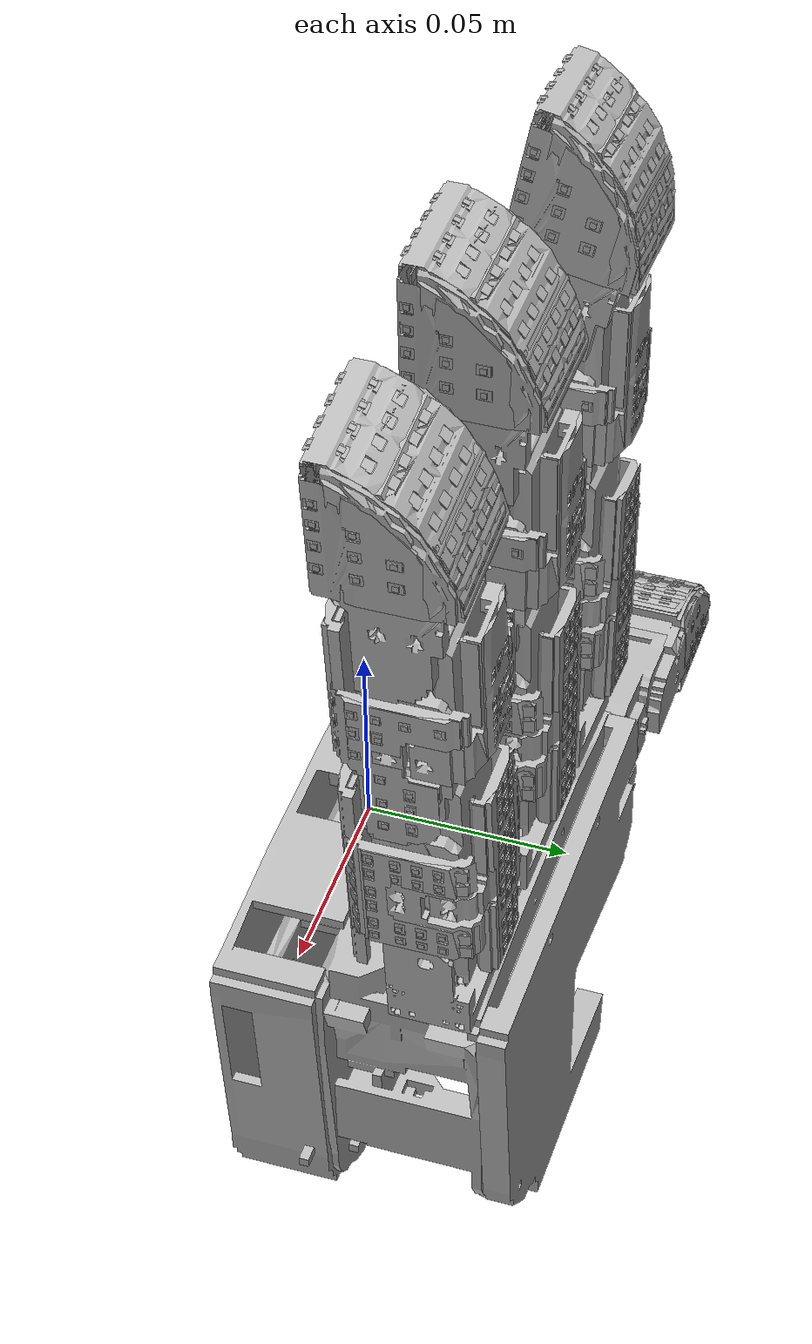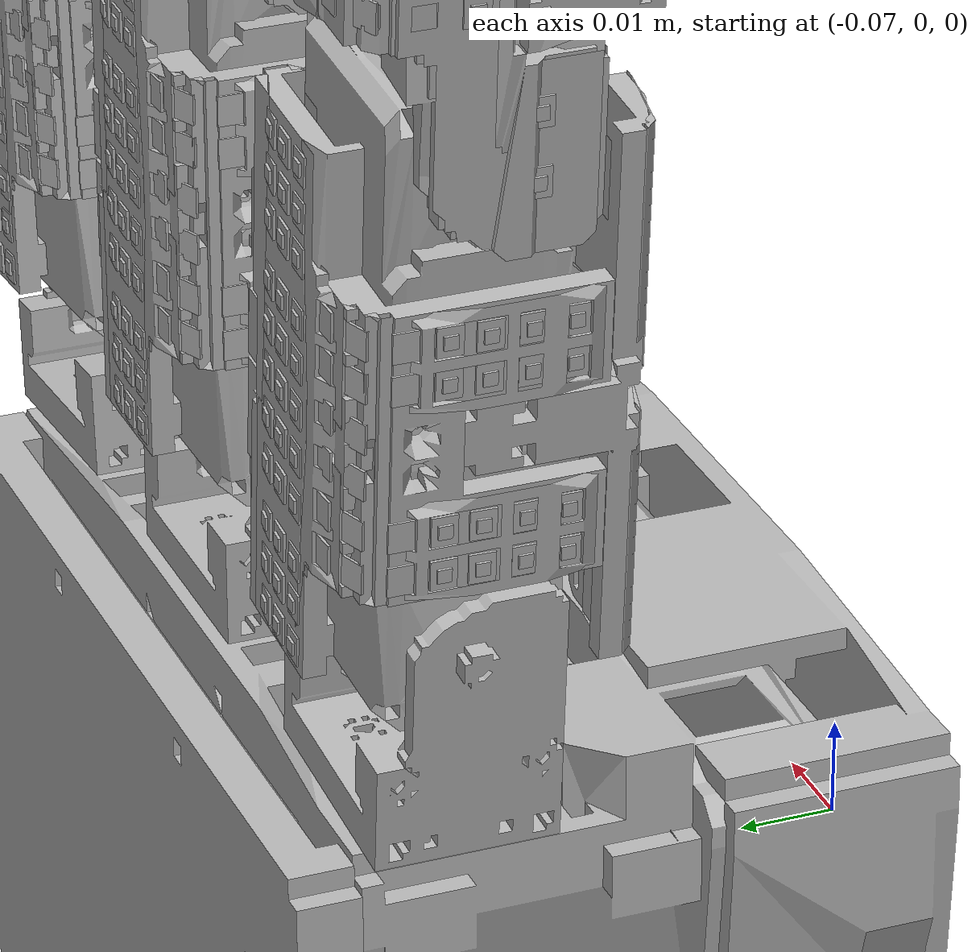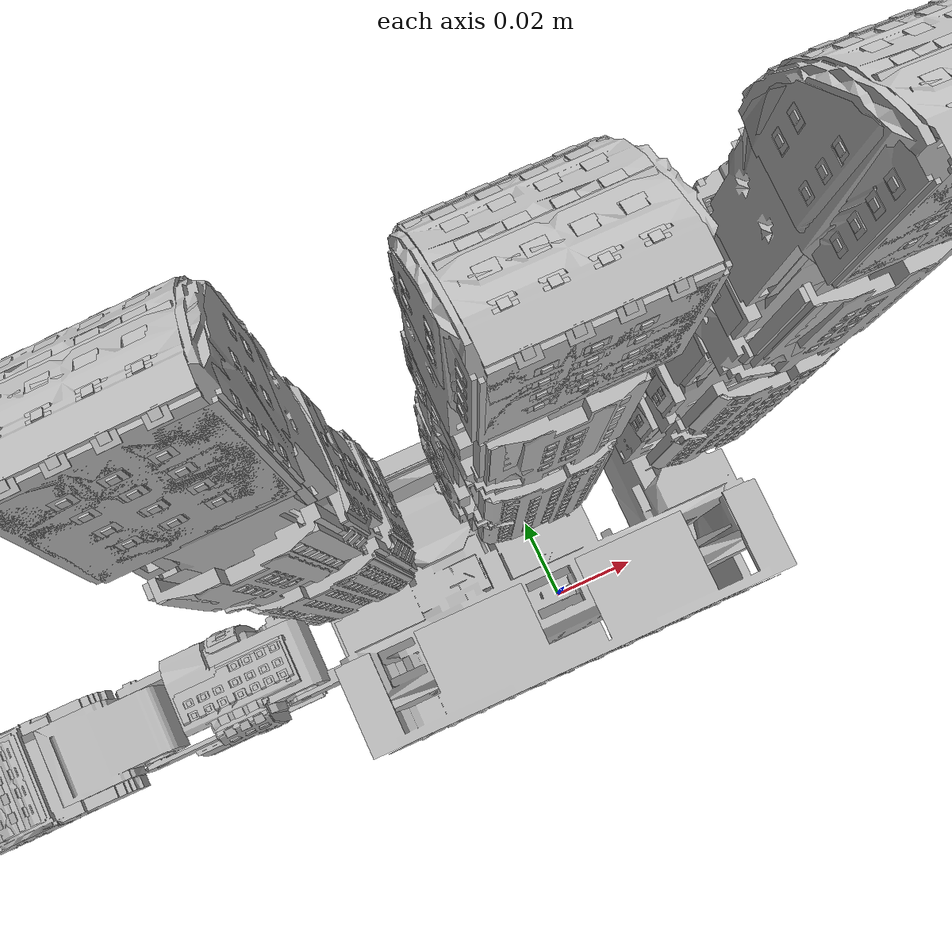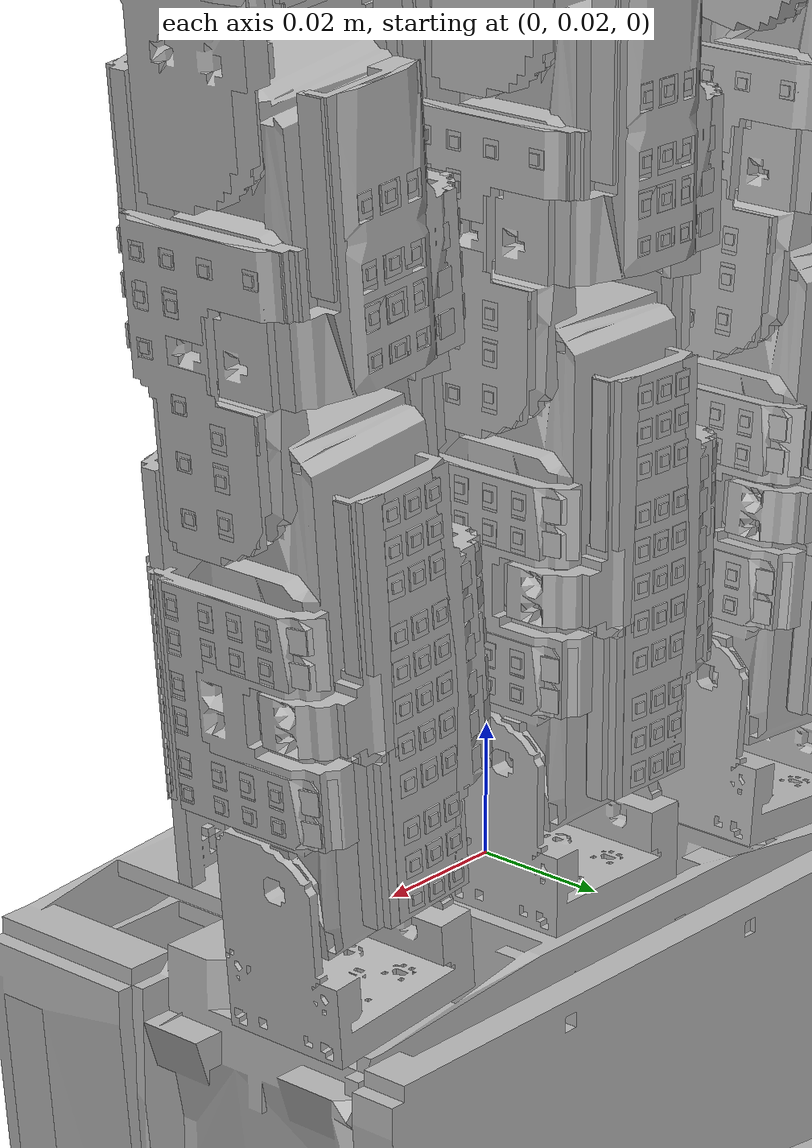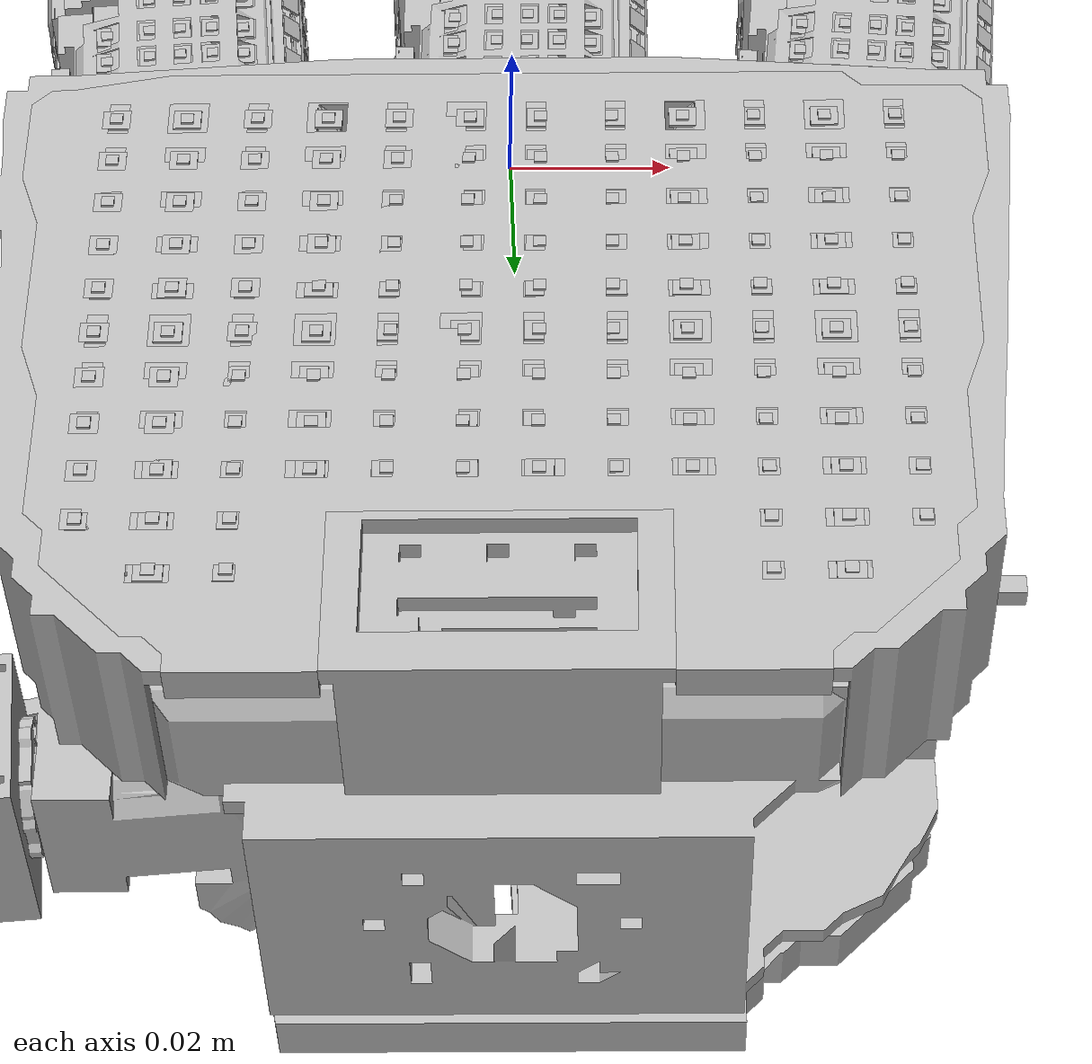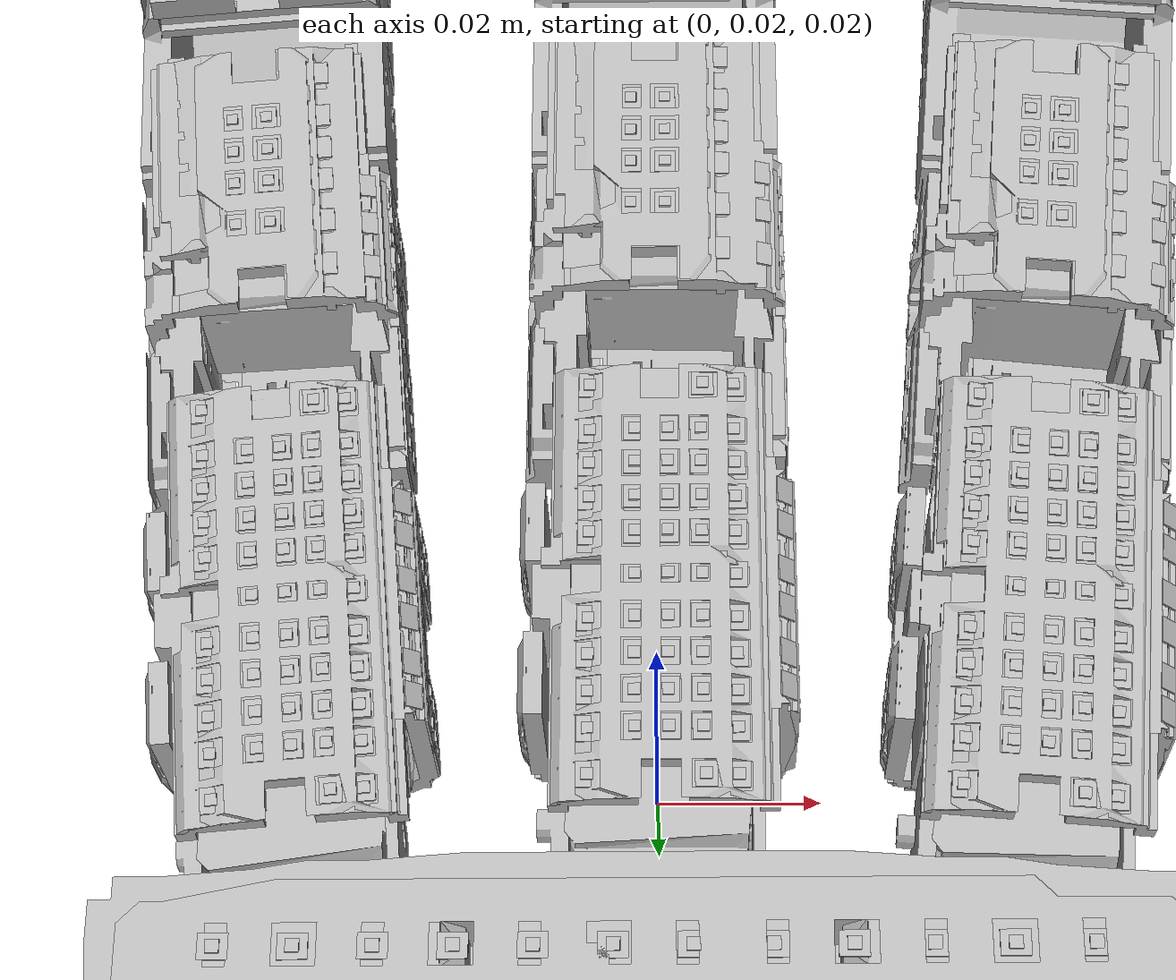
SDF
<sdf version='1.7'>
  <model name='allegro_hand_right'>
    <link name='palm_link'>
      <inertial>
        <pose>0.000483 0.015699 -0.041607 0 -0 0</pose>
        <mass>0.489709</mass>
        <inertia>
          <ixx>0.00067839</ixx>
          <ixy>-2.65523e-05</ixy>
          <ixz>1.7044e-05</ixz>
          <iyy>0.000849803</iyy>
          <iyz>6.37181e-06</iyz>
          <izz>0.000795342</izz>
        </inertia>
      </inertial>
      <collision name='palm_link_collision'>
        <pose>0 0.034 -0.002 3.14159 -0 0</pose>
        <geometry>
          <mesh>
            <scale>1 1 1</scale>
            <uri>model://allegro_hand_description/meshes/g_r2.stl</uri>
          </mesh>
        </geometry>
      </collision>
      <collision name='palm_link_fixed_joint_lump__boh_bracket_collision_1'>
        <pose>0 0.0341 -0.002 -4e-06 4e-06 1.57079</pose>
        <geometry>
          <mesh>
            <scale>1 1 1</scale>
            <uri>model://allegro_hand_description/meshes/part_4.stl</uri>
          </mesh>
        </geometry>
      </collision>
      <collision name='palm_link_fixed_joint_lump__boh_collision_2'>
        <pose>0 0.0341 -0.002 -4e-06 4e-06 1.57079</pose>
        <geometry>
          <mesh>
            <scale>1 1 1</scale>
            <uri>model://allegro_hand_description/meshes/boh_fpcb.stl</uri>
          </mesh>
        </geometry>
      </collision>
      <collision name='palm_link_fixed_joint_lump__boh_taxel_0_collision_3'>
        <pose>0.046741 -0.0189 -0.009447 1.57079 -3e-06 -3e-06</pose>
        <geometry>
          <mesh>
            <scale>1 1 1</scale>
            <uri>model://allegro_hand_description/meshes/taxel_normal.stl</uri>
          </mesh>
        </geometry>
      </collision>
      <collision name='palm_link_fixed_joint_lump__boh_sub_taxel_0_collision_4'>
        <pose>0.046741 -0.0195 -0.009447 -1.57081 -3e-06 -3e-06</pose>
        <geometry>
          <mesh>
            <scale>1 1 1</scale>
            <uri>model://allegro_hand_description/meshes/sub_taxel.stl</uri>
          </mesh>
        </geometry>
      </collision>
      <collision name='palm_link_fixed_joint_lump__boh_taxel_1_collision_5'>
        <pose>0.038232 -0.0189 -0.009447 1.57079 -3e-06 -3e-06</pose>
        <geometry>
          <mesh>
            <scale>1 1 1</scale>
            <uri>model://allegro_hand_description/meshes/taxel_normal.stl</uri>
          </mesh>
        </geometry>
      </collision>
      <collision name='palm_link_fixed_joint_lump__boh_sub_taxel_1_collision_6'>
        <pose>0.038232 -0.0195 -0.009447 -1.57081 -3e-06 -3e-06</pose>
        <geometry>
          <mesh>
            <scale>1 1 1</scale>
            <uri>model://allegro_hand_description/meshes/sub_taxel.stl</uri>
          </mesh>
        </geometry>
      </collision>
      <collision name='palm_link_fixed_joint_lump__boh_taxel_10_collision_7'>
        <pose>-0.038349 -0.0189 -0.009447 1.57079 -3e-06 -3e-06</pose>
        <geometry>
          <mesh>
            <scale>1 1 1</scale>
            <uri>model://allegro_hand_description/meshes/taxel_normal.stl</uri>
          </mesh>
        </geometry>
      </collision>
      <collision name='palm_link_fixed_joint_lump__boh_sub_taxel_10_collision_8'>
        <pose>-0.038349 -0.0195 -0.009447 -1.57081 -3e-06 -3e-06</pose>
        <geometry>
          <mesh>
            <scale>1 1 1</scale>
            <uri>model://allegro_hand_description/meshes/sub_taxel.stl</uri>
          </mesh>
        </geometry>
      </collision>
      <collision name='palm_link_fixed_joint_lump__boh_taxel_100_collision_9'>
        <pose>0.012887 -0.0189 -0.063057 1.57079 -3e-06 -3e-06</pose>
        <geometry>
          <mesh>
            <scale>1 1 1</scale>
            <uri>model://allegro_hand_description/meshes/taxel_normal.stl</uri>
          </mesh>
        </geometry>
      </collision>
      <collision name='palm_link_fixed_joint_lump__boh_sub_taxel_100_collision_10'>
        <pose>0.012887 -0.0195 -0.063057 -1.57081 -3e-06 -3e-06</pose>
        <geometry>
          <mesh>
            <scale>1 1 1</scale>
            <uri>model://allegro_hand_description/meshes/sub_taxel.stl</uri>
          </mesh>
        </geometry>
      </collision>
      <collision name='palm_link_fixed_joint_lump__boh_taxel_101_collision_11'>
        <pose>0.004378 -0.0189 -0.063057 1.57079 -3e-06 -3e-06</pose>
        <geometry>
          <mesh>
            <scale>1 1 1</scale>
            <uri>model://allegro_hand_description/meshes/taxel_normal.stl</uri>
          </mesh>
        </geometry>
      </collision>
      <collision name='palm_link_fixed_joint_lump__boh_sub_taxel_101_collision_12'>
        <pose>0.004378 -0.0195 -0.063057 -1.57081 -3e-06 -3e-06</pose>
        <geometry>
          <mesh>
            <scale>1 1 1</scale>
            <uri>model://allegro_hand_description/meshes/sub_taxel.stl</uri>
          </mesh>
        </geometry>
      </collision>
      <collision name='palm_link_fixed_joint_lump__boh_taxel_102_collision_13'>
        <pose>-0.004131 -0.0189 -0.063057 1.57079 -3e-06 -3e-06</pose>
        <geometry>
          <mesh>
            <scale>1 1 1</scale>
            <uri>model://allegro_hand_description/meshes/taxel_normal.stl</uri>
          </mesh>
        </geometry>
      </collision>
      <collision name='palm_link_fixed_joint_lump__boh_sub_taxel_102_collision_14'>
        <pose>-0.004131 -0.0195 -0.063057 -1.57081 -3e-06 -3e-06</pose>
        <geometry>
          <mesh>
            <scale>1 1 1</scale>
            <uri>model://allegro_hand_description/meshes/sub_taxel.stl</uri>
          </mesh>
        </geometry>
      </collision>
      <collision name='palm_link_fixed_joint_lump__boh_taxel_103_collision_15'>
        <pose>-0.01264 -0.0189 -0.063057 1.57079 -3e-06 -3e-06</pose>
        <geometry>
          <mesh>
            <scale>1 1 1</scale>
            <uri>model://allegro_hand_description/meshes/taxel_normal.stl</uri>
          </mesh>
        </geometry>
      </collision>
      <collision name='palm_link_fixed_joint_lump__boh_sub_taxel_103_collision_16'>
        <pose>-0.01264 -0.0195 -0.063057 -1.57081 -3e-06 -3e-06</pose>
        <geometry>
          <mesh>
            <scale>1 1 1</scale>
            <uri>model://allegro_hand_description/meshes/sub_taxel.stl</uri>
          </mesh>
        </geometry>
      </collision>
      <collision name='palm_link_fixed_joint_lump__boh_taxel_104_collision_17'>
        <pose>-0.021149 -0.0189 -0.063057 1.57079 -3e-06 -3e-06</pose>
        <geometry>
          <mesh>
            <scale>1 1 1</scale>
            <uri>model://allegro_hand_description/meshes/taxel_normal.stl</uri>
          </mesh>
        </geometry>
      </collision>
      <collision name='palm_link_fixed_joint_lump__boh_sub_taxel_104_collision_18'>
        <pose>-0.021149 -0.0195 -0.063057 -1.57081 -3e-06 -3e-06</pose>
        <geometry>
          <mesh>
            <scale>1 1 1</scale>
            <uri>model://allegro_hand_description/meshes/sub_taxel.stl</uri>
          </mesh>
        </geometry>
      </collision>
      <collision name='palm_link_fixed_joint_lump__boh_taxel_105_collision_19'>
        <pose>-0.029658 -0.0189 -0.063057 1.57079 -3e-06 -3e-06</pose>
        <geometry>
          <mesh>
            <scale>1 1 1</scale>
            <uri>model://allegro_hand_description/meshes/taxel_normal.stl</uri>
          </mesh>
        </geometry>
      </collision>
      <collision name='palm_link_fixed_joint_lump__boh_sub_taxel_105_collision_20'>
        <pose>-0.029658 -0.0195 -0.063057 -1.57081 -3e-06 -3e-06</pose>
        <geometry>
          <mesh>
            <scale>1 1 1</scale>
            <uri>model://allegro_hand_description/meshes/sub_taxel.stl</uri>
          </mesh>
        </geometry>
      </collision>
      <collision name='palm_link_fixed_joint_lump__boh_taxel_106_collision_21'>
        <pose>-0.038167 -0.0189 -0.063057 1.57079 -3e-06 -3e-06</pose>
        <geometry>
          <mesh>
            <scale>1 1 1</scale>
            <uri>model://allegro_hand_description/meshes/taxel_normal.stl</uri>
          </mesh>
        </geometry>
      </collision>
      <collision name='palm_link_fixed_joint_lump__boh_sub_taxel_106_collision_22'>
        <pose>-0.038167 -0.0195 -0.063057 -1.57081 -3e-06 -3e-06</pose>
        <geometry>
          <mesh>
            <scale>1 1 1</scale>
            <uri>model://allegro_hand_description/meshes/sub_taxel.stl</uri>
          </mesh>
        </geometry>
      </collision>
      <collision name='palm_link_fixed_joint_lump__boh_taxel_107_collision_23'>
        <pose>-0.046676 -0.0189 -0.063057 1.57079 -3e-06 -3e-06</pose>
        <geometry>
          <mesh>
            <scale>1 1 1</scale>
            <uri>model://allegro_hand_description/meshes/taxel_normal.stl</uri>
          </mesh>
        </geometry>
      </collision>
      <collision name='palm_link_fixed_joint_lump__boh_sub_taxel_107_collision_24'>
        <pose>-0.046676 -0.0195 -0.063057 -1.57081 -3e-06 -3e-06</pose>
        <geometry>
          <mesh>
            <scale>1 1 1</scale>
            <uri>model://allegro_hand_description/meshes/sub_taxel.stl</uri>
          </mesh>
        </geometry>
      </collision>
      <collision name='palm_link_fixed_joint_lump__boh_taxel_108_collision_25'>
        <pose>0.046928 -0.0189 -0.069963 1.57079 -3e-06 -3e-06</pose>
        <geometry>
          <mesh>
            <scale>1 1 1</scale>
            <uri>model://allegro_hand_description/meshes/taxel_normal.stl</uri>
          </mesh>
        </geometry>
      </collision>
      <collision name='palm_link_fixed_joint_lump__boh_sub_taxel_108_collision_26'>
        <pose>0.046928 -0.0195 -0.069963 -1.57081 -3e-06 -3e-06</pose>
        <geometry>
          <mesh>
            <scale>1 1 1</scale>
            <uri>model://allegro_hand_description/meshes/sub_taxel.stl</uri>
          </mesh>
        </geometry>
      </collision>
      <collision name='palm_link_fixed_joint_lump__boh_taxel_109_collision_27'>
        <pose>0.038419 -0.0189 -0.069963 1.57079 -3e-06 -3e-06</pose>
        <geometry>
          <mesh>
            <scale>1 1 1</scale>
            <uri>model://allegro_hand_description/meshes/taxel_normal.stl</uri>
          </mesh>
        </geometry>
      </collision>
      <collision name='palm_link_fixed_joint_lump__boh_sub_taxel_109_collision_28'>
        <pose>0.038419 -0.0195 -0.069963 -1.57081 -3e-06 -3e-06</pose>
        <geometry>
          <mesh>
            <scale>1 1 1</scale>
            <uri>model://allegro_hand_description/meshes/sub_taxel.stl</uri>
          </mesh>
        </geometry>
      </collision>
      <collision name='palm_link_fixed_joint_lump__boh_taxel_11_collision_29'>
        <pose>-0.046858 -0.0189 -0.009447 1.57079 -3e-06 -3e-06</pose>
        <geometry>
          <mesh>
            <scale>1 1 1</scale>
            <uri>model://allegro_hand_description/meshes/taxel_normal.stl</uri>
          </mesh>
        </geometry>
      </collision>
      <collision name='palm_link_fixed_joint_lump__boh_sub_taxel_11_collision_30'>
        <pose>-0.046858 -0.0195 -0.009447 -1.57081 -3e-06 -3e-06</pose>
        <geometry>
          <mesh>
            <scale>1 1 1</scale>
            <uri>model://allegro_hand_description/meshes/sub_taxel.stl</uri>
          </mesh>
        </geometry>
      </collision>
      <collision name='palm_link_fixed_joint_lump__boh_taxel_110_collision_31'>
        <pose>0.02991 -0.0189 -0.069963 1.57079 -3e-06 -3e-06</pose>
        <geometry>
          <mesh>
            <scale>1 1 1</scale>
            <uri>model://allegro_hand_description/meshes/taxel_normal.stl</uri>
          </mesh>
        </geometry>
      </collision>
      <collision name='palm_link_fixed_joint_lump__boh_sub_taxel_110_collision_32'>
        <pose>0.02991 -0.0195 -0.069963 -1.57081 -3e-06 -3e-06</pose>
        <geometry>
          <mesh>
            <scale>1 1 1</scale>
            <uri>model://allegro_hand_description/meshes/sub_taxel.stl</uri>
          </mesh>
        </geometry>
      </collision>
      <collision name='palm_link_fixed_joint_lump__boh_taxel_111_collision_33'>
        <pose>-0.029658 -0.0189 -0.069899 1.57079 -3e-06 -3e-06</pose>
        <geometry>
          <mesh>
            <scale>1 1 1</scale>
            <uri>model://allegro_hand_description/meshes/taxel_normal.stl</uri>
          </mesh>
        </geometry>
      </collision>
      <collision name='palm_link_fixed_joint_lump__boh_sub_taxel_111_collision_34'>
        <pose>-0.029658 -0.0195 -0.069899 -1.57081 -3e-06 -3e-06</pose>
        <geometry>
          <mesh>
            <scale>1 1 1</scale>
            <uri>model://allegro_hand_description/meshes/sub_taxel.stl</uri>
          </mesh>
        </geometry>
      </collision>
      <collision name='palm_link_fixed_joint_lump__boh_taxel_112_collision_35'>
        <pose>-0.038167 -0.0189 -0.069899 1.57079 -3e-06 -3e-06</pose>
        <geometry>
          <mesh>
            <scale>1 1 1</scale>
            <uri>model://allegro_hand_description/meshes/taxel_normal.stl</uri>
          </mesh>
        </geometry>
      </collision>
      <collision name='palm_link_fixed_joint_lump__boh_sub_taxel_112_collision_36'>
        <pose>-0.038167 -0.0195 -0.069899 -1.57081 -3e-06 -3e-06</pose>
        <geometry>
          <mesh>
            <scale>1 1 1</scale>
            <uri>model://allegro_hand_description/meshes/sub_taxel.stl</uri>
          </mesh>
        </geometry>
      </collision>
      <collision name='palm_link_fixed_joint_lump__boh_taxel_113_collision_37'>
        <pose>-0.046731 -0.0189 -0.069899 1.57079 -3e-06 -3e-06</pose>
        <geometry>
          <mesh>
            <scale>1 1 1</scale>
            <uri>model://allegro_hand_description/meshes/taxel_normal.stl</uri>
          </mesh>
        </geometry>
      </collision>
      <collision name='palm_link_fixed_joint_lump__boh_sub_taxel_113_collision_38'>
        <pose>-0.046731 -0.0195 -0.069899 -1.57081 -3e-06 -3e-06</pose>
        <geometry>
          <mesh>
            <scale>1 1 1</scale>
            <uri>model://allegro_hand_description/meshes/sub_taxel.stl</uri>
          </mesh>
        </geometry>
      </collision>
      <collision name='palm_link_fixed_joint_lump__boh_taxel_114_collision_39'>
        <pose>0.038419 -0.0189 -0.077096 1.57079 -3e-06 -3e-06</pose>
        <geometry>
          <mesh>
            <scale>1 1 1</scale>
            <uri>model://allegro_hand_description/meshes/taxel_normal.stl</uri>
          </mesh>
        </geometry>
      </collision>
      <collision name='palm_link_fixed_joint_lump__boh_sub_taxel_114_collision_40'>
        <pose>0.038419 -0.0195 -0.077096 -1.57081 -3e-06 -3e-06</pose>
        <geometry>
          <mesh>
            <scale>1 1 1</scale>
            <uri>model://allegro_hand_description/meshes/sub_taxel.stl</uri>
          </mesh>
        </geometry>
      </collision>
      <collision name='palm_link_fixed_joint_lump__boh_taxel_115_collision_41'>
        <pose>0.02991 -0.0189 -0.077096 1.57079 -3e-06 -3e-06</pose>
        <geometry>
          <mesh>
            <scale>1 1 1</scale>
            <uri>model://allegro_hand_description/meshes/taxel_normal.stl</uri>
          </mesh>
        </geometry>
      </collision>
      <collision name='palm_link_fixed_joint_lump__boh_sub_taxel_115_collision_42'>
        <pose>0.02991 -0.0195 -0.077096 -1.57081 -3e-06 -3e-06</pose>
        <geometry>
          <mesh>
            <scale>1 1 1</scale>
            <uri>model://allegro_hand_description/meshes/sub_taxel.stl</uri>
          </mesh>
        </geometry>
      </collision>
      <collision name='palm_link_fixed_joint_lump__boh_taxel_116_collision_43'>
        <pose>-0.029658 -0.0189 -0.076905 1.57079 -3e-06 -3e-06</pose>
        <geometry>
          <mesh>
            <scale>1 1 1</scale>
            <uri>model://allegro_hand_description/meshes/taxel_normal.stl</uri>
          </mesh>
        </geometry>
      </collision>
      <collision name='palm_link_fixed_joint_lump__boh_sub_taxel_116_collision_44'>
        <pose>-0.029658 -0.0195 -0.076905 -1.57081 -3e-06 -3e-06</pose>
        <geometry>
          <mesh>
            <scale>1 1 1</scale>
            <uri>model://allegro_hand_description/meshes/sub_taxel.stl</uri>
          </mesh>
        </geometry>
      </collision>
      <collision name='palm_link_fixed_joint_lump__boh_taxel_117_collision_45'>
        <pose>-0.038167 -0.0189 -0.076905 1.57079 -3e-06 -3e-06</pose>
        <geometry>
          <mesh>
            <scale>1 1 1</scale>
            <uri>model://allegro_hand_description/meshes/taxel_normal.stl</uri>
          </mesh>
        </geometry>
      </collision>
      <collision name='palm_link_fixed_joint_lump__boh_sub_taxel_117_collision_46'>
        <pose>-0.038167 -0.0195 -0.076905 -1.57081 -3e-06 -3e-06</pose>
        <geometry>
          <mesh>
            <scale>1 1 1</scale>
            <uri>model://allegro_hand_description/meshes/sub_taxel.stl</uri>
          </mesh>
        </geometry>
      </collision>
      <collision name='palm_link_fixed_joint_lump__boh_taxel_12_collision_47'>
        <pose>0.046741 -0.0189 -0.016149 1.57079 -3e-06 -3e-06</pose>
        <geometry>
          <mesh>
            <scale>1 1 1</scale>
            <uri>model://allegro_hand_description/meshes/taxel_normal.stl</uri>
          </mesh>
        </geometry>
      </collision>
      <collision name='palm_link_fixed_joint_lump__boh_sub_taxel_12_collision_48'>
        <pose>0.046741 -0.0195 -0.016149 -1.57081 -3e-06 -3e-06</pose>
        <geometry>
          <mesh>
            <scale>1 1 1</scale>
            <uri>model://allegro_hand_description/meshes/sub_taxel.stl</uri>
          </mesh>
        </geometry>
      </collision>
      <collision name='palm_link_fixed_joint_lump__boh_taxel_13_collision_49'>
        <pose>0.038232 -0.0189 -0.016149 1.57079 -3e-06 -3e-06</pose>
        <geometry>
          <mesh>
            <scale>1 1 1</scale>
            <uri>model://allegro_hand_description/meshes/taxel_normal.stl</uri>
          </mesh>
        </geometry>
      </collision>
      <collision name='palm_link_fixed_joint_lump__boh_sub_taxel_13_collision_50'>
        <pose>0.038232 -0.0195 -0.016149 -1.57081 -3e-06 -3e-06</pose>
        <geometry>
          <mesh>
            <scale>1 1 1</scale>
            <uri>model://allegro_hand_description/meshes/sub_taxel.stl</uri>
          </mesh>
        </geometry>
      </collision>
      <collision name='palm_link_fixed_joint_lump__boh_taxel_14_collision_51'>
        <pose>0.029723 -0.0189 -0.016149 1.57079 -3e-06 -3e-06</pose>
        <geometry>
          <mesh>
            <scale>1 1 1</scale>
            <uri>model://allegro_hand_description/meshes/taxel_normal.stl</uri>
          </mesh>
        </geometry>
      </collision>
      <collision name='palm_link_fixed_joint_lump__boh_sub_taxel_14_collision_52'>
        <pose>0.029723 -0.0195 -0.016149 -1.57081 -3e-06 -3e-06</pose>
        <geometry>
          <mesh>
            <scale>1 1 1</scale>
            <uri>model://allegro_hand_description/meshes/sub_taxel.stl</uri>
          </mesh>
        </geometry>
      </collision>
      <collision name='palm_link_fixed_joint_lump__boh_taxel_15_collision_53'>
        <pose>0.021214 -0.0189 -0.016149 1.57079 -3e-06 -3e-06</pose>
        <geometry>
          <mesh>
            <scale>1 1 1</scale>
            <uri>model://allegro_hand_description/meshes/taxel_normal.stl</uri>
          </mesh>
        </geometry>
      </collision>
      <collision name='palm_link_fixed_joint_lump__boh_sub_taxel_15_collision_54'>
        <pose>0.021214 -0.0195 -0.016149 -1.57081 -3e-06 -3e-06</pose>
        <geometry>
          <mesh>
            <scale>1 1 1</scale>
            <uri>model://allegro_hand_description/meshes/sub_taxel.stl</uri>
          </mesh>
        </geometry>
      </collision>
      <collision name='palm_link_fixed_joint_lump__boh_taxel_16_collision_55'>
        <pose>0.012705 -0.0189 -0.016149 1.57079 -3e-06 -3e-06</pose>
        <geometry>
          <mesh>
            <scale>1 1 1</scale>
            <uri>model://allegro_hand_description/meshes/taxel_normal.stl</uri>
          </mesh>
        </geometry>
      </collision>
      <collision name='palm_link_fixed_joint_lump__boh_sub_taxel_16_collision_56'>
        <pose>0.012705 -0.0195 -0.016149 -1.57081 -3e-06 -3e-06</pose>
        <geometry>
          <mesh>
            <scale>1 1 1</scale>
            <uri>model://allegro_hand_description/meshes/sub_taxel.stl</uri>
          </mesh>
        </geometry>
      </collision>
      <collision name='palm_link_fixed_joint_lump__boh_taxel_17_collision_57'>
        <pose>0.004196 -0.0189 -0.016149 1.57079 -3e-06 -3e-06</pose>
        <geometry>
          <mesh>
            <scale>1 1 1</scale>
            <uri>model://allegro_hand_description/meshes/taxel_normal.stl</uri>
          </mesh>
        </geometry>
      </collision>
      <collision name='palm_link_fixed_joint_lump__boh_sub_taxel_17_collision_58'>
        <pose>0.004196 -0.0195 -0.016149 -1.57081 -3e-06 -3e-06</pose>
        <geometry>
          <mesh>
            <scale>1 1 1</scale>
            <uri>model://allegro_hand_description/meshes/sub_taxel.stl</uri>
          </mesh>
        </geometry>
      </collision>
      <collision name='palm_link_fixed_joint_lump__boh_taxel_18_collision_59'>
        <pose>-0.004313 -0.0189 -0.016149 1.57079 -3e-06 -3e-06</pose>
        <geometry>
          <mesh>
            <scale>1 1 1</scale>
            <uri>model://allegro_hand_description/meshes/taxel_normal.stl</uri>
          </mesh>
        </geometry>
      </collision>
      <collision name='palm_link_fixed_joint_lump__boh_sub_taxel_18_collision_60'>
        <pose>-0.004313 -0.0195 -0.016149 -1.57081 -3e-06 -3e-06</pose>
        <geometry>
          <mesh>
            <scale>1 1 1</scale>
            <uri>model://allegro_hand_description/meshes/sub_taxel.stl</uri>
          </mesh>
        </geometry>
      </collision>
      <collision name='palm_link_fixed_joint_lump__boh_taxel_19_collision_61'>
        <pose>-0.012822 -0.0189 -0.016149 1.57079 -3e-06 -3e-06</pose>
        <geometry>
          <mesh>
            <scale>1 1 1</scale>
            <uri>model://allegro_hand_description/meshes/taxel_normal.stl</uri>
          </mesh>
        </geometry>
      </collision>
      <collision name='palm_link_fixed_joint_lump__boh_sub_taxel_19_collision_62'>
        <pose>-0.012822 -0.0195 -0.016149 -1.57081 -3e-06 -3e-06</pose>
        <geometry>
          <mesh>
            <scale>1 1 1</scale>
            <uri>model://allegro_hand_description/meshes/sub_taxel.stl</uri>
          </mesh>
        </geometry>
      </collision>
      <collision name='palm_link_fixed_joint_lump__boh_taxel_2_collision_63'>
        <pose>0.029723 -0.0189 -0.009447 1.57079 -3e-06 -3e-06</pose>
        <geometry>
          <mesh>
            <scale>1 1 1</scale>
            <uri>model://allegro_hand_description/meshes/taxel_normal.stl</uri>
          </mesh>
        </geometry>
      </collision>
      <collision name='palm_link_fixed_joint_lump__boh_sub_taxel_2_collision_64'>
        <pose>0.029723 -0.0195 -0.009447 -1.57081 -3e-06 -3e-06</pose>
        <geometry>
          <mesh>
            <scale>1 1 1</scale>
            <uri>model://allegro_hand_description/meshes/sub_taxel.stl</uri>
          </mesh>
        </geometry>
      </collision>
      <collision name='palm_link_fixed_joint_lump__boh_taxel_20_collision_65'>
        <pose>-0.021331 -0.0189 -0.016149 1.57079 -3e-06 -3e-06</pose>
        <geometry>
          <mesh>
            <scale>1 1 1</scale>
            <uri>model://allegro_hand_description/meshes/taxel_normal.stl</uri>
          </mesh>
        </geometry>
      </collision>
      <collision name='palm_link_fixed_joint_lump__boh_sub_taxel_20_collision_66'>
        <pose>-0.021331 -0.0195 -0.016149 -1.57081 -3e-06 -3e-06</pose>
        <geometry>
          <mesh>
            <scale>1 1 1</scale>
            <uri>model://allegro_hand_description/meshes/sub_taxel.stl</uri>
          </mesh>
        </geometry>
      </collision>
      <collision name='palm_link_fixed_joint_lump__boh_taxel_21_collision_67'>
        <pose>-0.02984 -0.0189 -0.016149 1.57079 -3e-06 -3e-06</pose>
        <geometry>
          <mesh>
            <scale>1 1 1</scale>
            <uri>model://allegro_hand_description/meshes/taxel_normal.stl</uri>
          </mesh>
        </geometry>
      </collision>
      <collision name='palm_link_fixed_joint_lump__boh_sub_taxel_21_collision_68'>
        <pose>-0.02984 -0.0195 -0.016149 -1.57081 -3e-06 -3e-06</pose>
        <geometry>
          <mesh>
            <scale>1 1 1</scale>
            <uri>model://allegro_hand_description/meshes/sub_taxel.stl</uri>
          </mesh>
        </geometry>
      </collision>
      <collision name='palm_link_fixed_joint_lump__boh_taxel_22_collision_69'>
        <pose>-0.038349 -0.0189 -0.016149 1.57079 -3e-06 -3e-06</pose>
        <geometry>
          <mesh>
            <scale>1 1 1</scale>
            <uri>model://allegro_hand_description/meshes/taxel_normal.stl</uri>
          </mesh>
        </geometry>
      </collision>
      <collision name='palm_link_fixed_joint_lump__boh_sub_taxel_22_collision_70'>
        <pose>-0.038349 -0.0195 -0.016149 -1.57081 -3e-06 -3e-06</pose>
        <geometry>
          <mesh>
            <scale>1 1 1</scale>
            <uri>model://allegro_hand_description/meshes/sub_taxel.stl</uri>
          </mesh>
        </geometry>
      </collision>
      <collision name='palm_link_fixed_joint_lump__boh_taxel_23_collision_71'>
        <pose>-0.046858 -0.0189 -0.016149 1.57079 -3e-06 -3e-06</pose>
        <geometry>
          <mesh>
            <scale>1 1 1</scale>
            <uri>model://allegro_hand_description/meshes/taxel_normal.stl</uri>
          </mesh>
        </geometry>
      </collision>
      <collision name='palm_link_fixed_joint_lump__boh_sub_taxel_23_collision_72'>
        <pose>-0.046858 -0.0195 -0.016149 -1.57081 -3e-06 -3e-06</pose>
        <geometry>
          <mesh>
            <scale>1 1 1</scale>
            <uri>model://allegro_hand_description/meshes/sub_taxel.stl</uri>
          </mesh>
        </geometry>
      </collision>
      <collision name='palm_link_fixed_joint_lump__boh_taxel_24_collision_73'>
        <pose>0.046741 -0.0189 -0.02285 1.57079 -3e-06 -3e-06</pose>
        <geometry>
          <mesh>
            <scale>1 1 1</scale>
            <uri>model://allegro_hand_description/meshes/taxel_normal.stl</uri>
          </mesh>
        </geometry>
      </collision>
      <collision name='palm_link_fixed_joint_lump__boh_sub_taxel_24_collision_74'>
        <pose>0.046741 -0.0195 -0.02285 -1.57081 -3e-06 -3e-06</pose>
        <geometry>
          <mesh>
            <scale>1 1 1</scale>
            <uri>model://allegro_hand_description/meshes/sub_taxel.stl</uri>
          </mesh>
        </geometry>
      </collision>
      <collision name='palm_link_fixed_joint_lump__boh_taxel_25_collision_75'>
        <pose>0.038232 -0.0189 -0.02285 1.57079 -3e-06 -3e-06</pose>
        <geometry>
          <mesh>
            <scale>1 1 1</scale>
            <uri>model://allegro_hand_description/meshes/taxel_normal.stl</uri>
          </mesh>
        </geometry>
      </collision>
      <collision name='palm_link_fixed_joint_lump__boh_sub_taxel_25_collision_76'>
        <pose>0.038232 -0.0195 -0.02285 -1.57081 -3e-06 -3e-06</pose>
        <geometry>
          <mesh>
            <scale>1 1 1</scale>
            <uri>model://allegro_hand_description/meshes/sub_taxel.stl</uri>
          </mesh>
        </geometry>
      </collision>
      <collision name='palm_link_fixed_joint_lump__boh_taxel_26_collision_77'>
        <pose>0.029723 -0.0189 -0.02285 1.57079 -3e-06 -3e-06</pose>
        <geometry>
          <mesh>
            <scale>1 1 1</scale>
            <uri>model://allegro_hand_description/meshes/taxel_normal.stl</uri>
          </mesh>
        </geometry>
      </collision>
      <collision name='palm_link_fixed_joint_lump__boh_sub_taxel_26_collision_78'>
        <pose>0.029723 -0.0195 -0.02285 -1.57081 -3e-06 -3e-06</pose>
        <geometry>
          <mesh>
            <scale>1 1 1</scale>
            <uri>model://allegro_hand_description/meshes/sub_taxel.stl</uri>
          </mesh>
        </geometry>
      </collision>
      <collision name='palm_link_fixed_joint_lump__boh_taxel_27_collision_79'>
        <pose>0.021214 -0.0189 -0.02285 1.57079 -3e-06 -3e-06</pose>
        <geometry>
          <mesh>
            <scale>1 1 1</scale>
            <uri>model://allegro_hand_description/meshes/taxel_normal.stl</uri>
          </mesh>
        </geometry>
      </collision>
      <collision name='palm_link_fixed_joint_lump__boh_sub_taxel_27_collision_80'>
        <pose>0.021214 -0.0195 -0.02285 -1.57081 -3e-06 -3e-06</pose>
        <geometry>
          <mesh>
            <scale>1 1 1</scale>
            <uri>model://allegro_hand_description/meshes/sub_taxel.stl</uri>
          </mesh>
        </geometry>
      </collision>
      <collision name='palm_link_fixed_joint_lump__boh_taxel_28_collision_81'>
        <pose>0.012705 -0.0189 -0.02285 1.57079 -3e-06 -3e-06</pose>
        <geometry>
          <mesh>
            <scale>1 1 1</scale>
            <uri>model://allegro_hand_description/meshes/taxel_normal.stl</uri>
          </mesh>
        </geometry>
      </collision>
      <collision name='palm_link_fixed_joint_lump__boh_sub_taxel_28_collision_82'>
        <pose>0.012705 -0.0195 -0.02285 -1.57081 -3e-06 -3e-06</pose>
        <geometry>
          <mesh>
            <scale>1 1 1</scale>
            <uri>model://allegro_hand_description/meshes/sub_taxel.stl</uri>
          </mesh>
        </geometry>
      </collision>
      <collision name='palm_link_fixed_joint_lump__boh_taxel_29_collision_83'>
        <pose>0.004196 -0.0189 -0.02285 1.57079 -3e-06 -3e-06</pose>
        <geometry>
          <mesh>
            <scale>1 1 1</scale>
            <uri>model://allegro_hand_description/meshes/taxel_normal.stl</uri>
          </mesh>
        </geometry>
      </collision>
      <collision name='palm_link_fixed_joint_lump__boh_sub_taxel_29_collision_84'>
        <pose>0.004196 -0.0195 -0.02285 -1.57081 -3e-06 -3e-06</pose>
        <geometry>
          <mesh>
            <scale>1 1 1</scale>
            <uri>model://allegro_hand_description/meshes/sub_taxel.stl</uri>
          </mesh>
        </geometry>
      </collision>
      <collision name='palm_link_fixed_joint_lump__boh_taxel_3_collision_85'>
        <pose>0.021214 -0.0189 -0.009447 1.57079 -3e-06 -3e-06</pose>
        <geometry>
          <mesh>
            <scale>1 1 1</scale>
            <uri>model://allegro_hand_description/meshes/taxel_normal.stl</uri>
          </mesh>
        </geometry>
      </collision>
      <collision name='palm_link_fixed_joint_lump__boh_sub_taxel_3_collision_86'>
        <pose>0.021214 -0.0195 -0.009447 -1.57081 -3e-06 -3e-06</pose>
        <geometry>
          <mesh>
            <scale>1 1 1</scale>
            <uri>model://allegro_hand_description/meshes/sub_taxel.stl</uri>
          </mesh>
        </geometry>
      </collision>
      <collision name='palm_link_fixed_joint_lump__boh_taxel_30_collision_87'>
        <pose>-0.004313 -0.0189 -0.02285 1.57079 -3e-06 -3e-06</pose>
        <geometry>
          <mesh>
            <scale>1 1 1</scale>
            <uri>model://allegro_hand_description/meshes/taxel_normal.stl</uri>
          </mesh>
        </geometry>
      </collision>
      <collision name='palm_link_fixed_joint_lump__boh_sub_taxel_30_collision_88'>
        <pose>-0.004313 -0.0195 -0.02285 -1.57081 -3e-06 -3e-06</pose>
        <geometry>
          <mesh>
            <scale>1 1 1</scale>
            <uri>model://allegro_hand_description/meshes/sub_taxel.stl</uri>
          </mesh>
        </geometry>
      </collision>
      <collision name='palm_link_fixed_joint_lump__boh_taxel_31_collision_89'>
        <pose>-0.012822 -0.0189 -0.02285 1.57079 -3e-06 -3e-06</pose>
        <geometry>
          <mesh>
            <scale>1 1 1</scale>
            <uri>model://allegro_hand_description/meshes/taxel_normal.stl</uri>
          </mesh>
        </geometry>
      </collision>
      <collision name='palm_link_fixed_joint_lump__boh_sub_taxel_31_collision_90'>
        <pose>-0.012822 -0.0195 -0.02285 -1.57081 -3e-06 -3e-06</pose>
        <geometry>
          <mesh>
            <scale>1 1 1</scale>
            <uri>model://allegro_hand_description/meshes/sub_taxel.stl</uri>
          </mesh>
        </geometry>
      </collision>
      <collision name='palm_link_fixed_joint_lump__boh_taxel_32_collision_91'>
        <pose>-0.021331 -0.0189 -0.02285 1.57079 -3e-06 -3e-06</pose>
        <geometry>
          <mesh>
            <scale>1 1 1</scale>
            <uri>model://allegro_hand_description/meshes/taxel_normal.stl</uri>
          </mesh>
        </geometry>
      </collision>
      <collision name='palm_link_fixed_joint_lump__boh_sub_taxel_32_collision_92'>
        <pose>-0.021331 -0.0195 -0.02285 -1.57081 -3e-06 -3e-06</pose>
        <geometry>
          <mesh>
            <scale>1 1 1</scale>
            <uri>model://allegro_hand_description/meshes/sub_taxel.stl</uri>
          </mesh>
        </geometry>
      </collision>
      <collision name='palm_link_fixed_joint_lump__boh_taxel_33_collision_93'>
        <pose>-0.02984 -0.0189 -0.02285 1.57079 -3e-06 -3e-06</pose>
        <geometry>
          <mesh>
            <scale>1 1 1</scale>
            <uri>model://allegro_hand_description/meshes/taxel_normal.stl</uri>
          </mesh>
        </geometry>
      </collision>
      <collision name='palm_link_fixed_joint_lump__boh_sub_taxel_33_collision_94'>
        <pose>-0.02984 -0.0195 -0.02285 -1.57081 -3e-06 -3e-06</pose>
        <geometry>
          <mesh>
            <scale>1 1 1</scale>
            <uri>model://allegro_hand_description/meshes/sub_taxel.stl</uri>
          </mesh>
        </geometry>
      </collision>
      <collision name='palm_link_fixed_joint_lump__boh_taxel_34_collision_95'>
        <pose>-0.038349 -0.0189 -0.02285 1.57079 -3e-06 -3e-06</pose>
        <geometry>
          <mesh>
            <scale>1 1 1</scale>
            <uri>model://allegro_hand_description/meshes/taxel_normal.stl</uri>
          </mesh>
        </geometry>
      </collision>
      <collision name='palm_link_fixed_joint_lump__boh_sub_taxel_34_collision_96'>
        <pose>-0.038349 -0.0195 -0.02285 -1.57081 -3e-06 -3e-06</pose>
        <geometry>
          <mesh>
            <scale>1 1 1</scale>
            <uri>model://allegro_hand_description/meshes/sub_taxel.stl</uri>
          </mesh>
        </geometry>
      </collision>
      <collision name='palm_link_fixed_joint_lump__boh_taxel_35_collision_97'>
        <pose>-0.046858 -0.0189 -0.02285 1.57079 -3e-06 -3e-06</pose>
        <geometry>
          <mesh>
            <scale>1 1 1</scale>
            <uri>model://allegro_hand_description/meshes/taxel_normal.stl</uri>
          </mesh>
        </geometry>
      </collision>
      <collision name='palm_link_fixed_joint_lump__boh_sub_taxel_35_collision_98'>
        <pose>-0.046858 -0.0195 -0.02285 -1.57081 -3e-06 -3e-06</pose>
        <geometry>
          <mesh>
            <scale>1 1 1</scale>
            <uri>model://allegro_hand_description/meshes/sub_taxel.stl</uri>
          </mesh>
        </geometry>
      </collision>
      <collision name='palm_link_fixed_joint_lump__boh_taxel_36_collision_99'>
        <pose>0.046741 -0.0189 -0.029551 1.57079 -3e-06 -3e-06</pose>
        <geometry>
          <mesh>
            <scale>1 1 1</scale>
            <uri>model://allegro_hand_description/meshes/taxel_normal.stl</uri>
          </mesh>
        </geometry>
      </collision>
      <collision name='palm_link_fixed_joint_lump__boh_sub_taxel_36_collision_100'>
        <pose>0.046741 -0.0195 -0.029551 -1.57081 -3e-06 -3e-06</pose>
        <geometry>
          <mesh>
            <scale>1 1 1</scale>
            <uri>model://allegro_hand_description/meshes/sub_taxel.stl</uri>
          </mesh>
        </geometry>
      </collision>
      <collision name='palm_link_fixed_joint_lump__boh_taxel_37_collision_101'>
        <pose>0.038232 -0.0189 -0.029551 1.57079 -3e-06 -3e-06</pose>
        <geometry>
          <mesh>
            <scale>1 1 1</scale>
            <uri>model://allegro_hand_description/meshes/taxel_normal.stl</uri>
          </mesh>
        </geometry>
      </collision>
      <collision name='palm_link_fixed_joint_lump__boh_sub_taxel_37_collision_102'>
        <pose>0.038232 -0.0195 -0.029551 -1.57081 -3e-06 -3e-06</pose>
        <geometry>
          <mesh>
            <scale>1 1 1</scale>
            <uri>model://allegro_hand_description/meshes/sub_taxel.stl</uri>
          </mesh>
        </geometry>
      </collision>
      <collision name='palm_link_fixed_joint_lump__boh_taxel_38_collision_103'>
        <pose>0.029723 -0.0189 -0.029551 1.57079 -3e-06 -3e-06</pose>
        <geometry>
          <mesh>
            <scale>1 1 1</scale>
            <uri>model://allegro_hand_description/meshes/taxel_normal.stl</uri>
          </mesh>
        </geometry>
      </collision>
      <collision name='palm_link_fixed_joint_lump__boh_sub_taxel_38_collision_104'>
        <pose>0.029723 -0.0195 -0.029551 -1.57081 -3e-06 -3e-06</pose>
        <geometry>
          <mesh>
            <scale>1 1 1</scale>
            <uri>model://allegro_hand_description/meshes/sub_taxel.stl</uri>
          </mesh>
        </geometry>
      </collision>
      <collision name='palm_link_fixed_joint_lump__boh_taxel_39_collision_105'>
        <pose>0.021214 -0.0189 -0.029551 1.57079 -3e-06 -3e-06</pose>
        <geometry>
          <mesh>
            <scale>1 1 1</scale>
            <uri>model://allegro_hand_description/meshes/taxel_normal.stl</uri>
          </mesh>
        </geometry>
      </collision>
      <collision name='palm_link_fixed_joint_lump__boh_sub_taxel_39_collision_106'>
        <pose>0.021214 -0.0195 -0.029551 -1.57081 -3e-06 -3e-06</pose>
        <geometry>
          <mesh>
            <scale>1 1 1</scale>
            <uri>model://allegro_hand_description/meshes/sub_taxel.stl</uri>
          </mesh>
        </geometry>
      </collision>
      <collision name='palm_link_fixed_joint_lump__boh_taxel_4_collision_107'>
        <pose>0.012705 -0.0189 -0.009447 1.57079 -3e-06 -3e-06</pose>
        <geometry>
          <mesh>
            <scale>1 1 1</scale>
            <uri>model://allegro_hand_description/meshes/taxel_normal.stl</uri>
          </mesh>
        </geometry>
      </collision>
      <collision name='palm_link_fixed_joint_lump__boh_sub_taxel_4_collision_108'>
        <pose>0.012705 -0.0195 -0.009447 -1.57081 -3e-06 -3e-06</pose>
        <geometry>
          <mesh>
            <scale>1 1 1</scale>
            <uri>model://allegro_hand_description/meshes/sub_taxel.stl</uri>
          </mesh>
        </geometry>
      </collision>
      <collision name='palm_link_fixed_joint_lump__boh_taxel_40_collision_109'>
        <pose>0.012705 -0.0189 -0.029551 1.57079 -3e-06 -3e-06</pose>
        <geometry>
          <mesh>
            <scale>1 1 1</scale>
            <uri>model://allegro_hand_description/meshes/taxel_normal.stl</uri>
          </mesh>
        </geometry>
      </collision>
      <collision name='palm_link_fixed_joint_lump__boh_sub_taxel_40_collision_110'>
        <pose>0.012705 -0.0195 -0.029551 -1.57081 -3e-06 -3e-06</pose>
        <geometry>
          <mesh>
            <scale>1 1 1</scale>
            <uri>model://allegro_hand_description/meshes/sub_taxel.stl</uri>
          </mesh>
        </geometry>
      </collision>
      <collision name='palm_link_fixed_joint_lump__boh_taxel_41_collision_111'>
        <pose>0.004196 -0.0189 -0.029551 1.57079 -3e-06 -3e-06</pose>
        <geometry>
          <mesh>
            <scale>1 1 1</scale>
            <uri>model://allegro_hand_description/meshes/taxel_normal.stl</uri>
          </mesh>
        </geometry>
      </collision>
      <collision name='palm_link_fixed_joint_lump__boh_sub_taxel_41_collision_112'>
        <pose>0.004196 -0.0195 -0.029551 -1.57081 -3e-06 -3e-06</pose>
        <geometry>
          <mesh>
            <scale>1 1 1</scale>
            <uri>model://allegro_hand_description/meshes/sub_taxel.stl</uri>
          </mesh>
        </geometry>
      </collision>
      <collision name='palm_link_fixed_joint_lump__boh_taxel_42_collision_113'>
        <pose>-0.004313 -0.0189 -0.029551 1.57079 -3e-06 -3e-06</pose>
        <geometry>
          <mesh>
            <scale>1 1 1</scale>
            <uri>model://allegro_hand_description/meshes/taxel_normal.stl</uri>
          </mesh>
        </geometry>
      </collision>
      <collision name='palm_link_fixed_joint_lump__boh_sub_taxel_42_collision_114'>
        <pose>-0.004313 -0.0195 -0.029551 -1.57081 -3e-06 -3e-06</pose>
        <geometry>
          <mesh>
            <scale>1 1 1</scale>
            <uri>model://allegro_hand_description/meshes/sub_taxel.stl</uri>
          </mesh>
        </geometry>
      </collision>
      <collision name='palm_link_fixed_joint_lump__boh_taxel_43_collision_115'>
        <pose>-0.012822 -0.0189 -0.029551 1.57079 -3e-06 -3e-06</pose>
        <geometry>
          <mesh>
            <scale>1 1 1</scale>
            <uri>model://allegro_hand_description/meshes/taxel_normal.stl</uri>
          </mesh>
        </geometry>
      </collision>
      <collision name='palm_link_fixed_joint_lump__boh_sub_taxel_43_collision_116'>
        <pose>-0.012822 -0.0195 -0.029551 -1.57081 -3e-06 -3e-06</pose>
        <geometry>
          <mesh>
            <scale>1 1 1</scale>
            <uri>model://allegro_hand_description/meshes/sub_taxel.stl</uri>
          </mesh>
        </geometry>
      </collision>
      <collision name='palm_link_fixed_joint_lump__boh_taxel_44_collision_117'>
        <pose>-0.021331 -0.0189 -0.029551 1.57079 -3e-06 -3e-06</pose>
        <geometry>
          <mesh>
            <scale>1 1 1</scale>
            <uri>model://allegro_hand_description/meshes/taxel_normal.stl</uri>
          </mesh>
        </geometry>
      </collision>
      <collision name='palm_link_fixed_joint_lump__boh_sub_taxel_44_collision_118'>
        <pose>-0.021331 -0.0195 -0.029551 -1.57081 -3e-06 -3e-06</pose>
        <geometry>
          <mesh>
            <scale>1 1 1</scale>
            <uri>model://allegro_hand_description/meshes/sub_taxel.stl</uri>
          </mesh>
        </geometry>
      </collision>
      <collision name='palm_link_fixed_joint_lump__boh_taxel_45_collision_119'>
        <pose>-0.02984 -0.0189 -0.029551 1.57079 -3e-06 -3e-06</pose>
        <geometry>
          <mesh>
            <scale>1 1 1</scale>
            <uri>model://allegro_hand_description/meshes/taxel_normal.stl</uri>
          </mesh>
        </geometry>
      </collision>
      <collision name='palm_link_fixed_joint_lump__boh_sub_taxel_45_collision_120'>
        <pose>-0.02984 -0.0195 -0.029551 -1.57081 -3e-06 -3e-06</pose>
        <geometry>
          <mesh>
            <scale>1 1 1</scale>
            <uri>model://allegro_hand_description/meshes/sub_taxel.stl</uri>
          </mesh>
        </geometry>
      </collision>
      <collision name='palm_link_fixed_joint_lump__boh_taxel_46_collision_121'>
        <pose>-0.038349 -0.0189 -0.029551 1.57079 -3e-06 -3e-06</pose>
        <geometry>
          <mesh>
            <scale>1 1 1</scale>
            <uri>model://allegro_hand_description/meshes/taxel_normal.stl</uri>
          </mesh>
        </geometry>
      </collision>
      <collision name='palm_link_fixed_joint_lump__boh_sub_taxel_46_collision_122'>
        <pose>-0.038349 -0.0195 -0.029551 -1.57081 -3e-06 -3e-06</pose>
        <geometry>
          <mesh>
            <scale>1 1 1</scale>
            <uri>model://allegro_hand_description/meshes/sub_taxel.stl</uri>
          </mesh>
        </geometry>
      </collision>
      <collision name='palm_link_fixed_joint_lump__boh_taxel_47_collision_123'>
        <pose>-0.046858 -0.0189 -0.029551 1.57079 -3e-06 -3e-06</pose>
        <geometry>
          <mesh>
            <scale>1 1 1</scale>
            <uri>model://allegro_hand_description/meshes/taxel_normal.stl</uri>
          </mesh>
        </geometry>
      </collision>
      <collision name='palm_link_fixed_joint_lump__boh_sub_taxel_47_collision_124'>
        <pose>-0.046858 -0.0195 -0.029551 -1.57081 -3e-06 -3e-06</pose>
        <geometry>
          <mesh>
            <scale>1 1 1</scale>
            <uri>model://allegro_hand_description/meshes/sub_taxel.stl</uri>
          </mesh>
        </geometry>
      </collision>
      <collision name='palm_link_fixed_joint_lump__boh_taxel_48_collision_125'>
        <pose>0.046741 -0.0189 -0.036252 1.57079 -3e-06 -3e-06</pose>
        <geometry>
          <mesh>
            <scale>1 1 1</scale>
            <uri>model://allegro_hand_description/meshes/taxel_normal.stl</uri>
          </mesh>
        </geometry>
      </collision>
      <collision name='palm_link_fixed_joint_lump__boh_sub_taxel_48_collision_126'>
        <pose>0.046741 -0.0195 -0.036252 -1.57081 -3e-06 -3e-06</pose>
        <geometry>
          <mesh>
            <scale>1 1 1</scale>
            <uri>model://allegro_hand_description/meshes/sub_taxel.stl</uri>
          </mesh>
        </geometry>
      </collision>
      <collision name='palm_link_fixed_joint_lump__boh_taxel_49_collision_127'>
        <pose>0.038232 -0.0189 -0.036252 1.57079 -3e-06 -3e-06</pose>
        <geometry>
          <mesh>
            <scale>1 1 1</scale>
            <uri>model://allegro_hand_description/meshes/taxel_normal.stl</uri>
          </mesh>
        </geometry>
      </collision>
      <collision name='palm_link_fixed_joint_lump__boh_sub_taxel_49_collision_128'>
        <pose>0.038232 -0.0195 -0.036252 -1.57081 -3e-06 -3e-06</pose>
        <geometry>
          <mesh>
            <scale>1 1 1</scale>
            <uri>model://allegro_hand_description/meshes/sub_taxel.stl</uri>
          </mesh>
        </geometry>
      </collision>
      <collision name='palm_link_fixed_joint_lump__boh_taxel_5_collision_129'>
        <pose>0.004196 -0.0189 -0.009447 1.57079 -3e-06 -3e-06</pose>
        <geometry>
          <mesh>
            <scale>1 1 1</scale>
            <uri>model://allegro_hand_description/meshes/taxel_normal.stl</uri>
          </mesh>
        </geometry>
      </collision>
      <collision name='palm_link_fixed_joint_lump__boh_sub_taxel_5_collision_130'>
        <pose>0.004196 -0.0195 -0.009447 -1.57081 -3e-06 -3e-06</pose>
        <geometry>
          <mesh>
            <scale>1 1 1</scale>
            <uri>model://allegro_hand_description/meshes/sub_taxel.stl</uri>
          </mesh>
        </geometry>
      </collision>
      <collision name='palm_link_fixed_joint_lump__boh_taxel_50_collision_131'>
        <pose>0.029723 -0.0189 -0.036252 1.57079 -3e-06 -3e-06</pose>
        <geometry>
          <mesh>
            <scale>1 1 1</scale>
            <uri>model://allegro_hand_description/meshes/taxel_normal.stl</uri>
          </mesh>
        </geometry>
      </collision>
      <collision name='palm_link_fixed_joint_lump__boh_sub_taxel_50_collision_132'>
        <pose>0.029723 -0.0195 -0.036252 -1.57081 -3e-06 -3e-06</pose>
        <geometry>
          <mesh>
            <scale>1 1 1</scale>
            <uri>model://allegro_hand_description/meshes/sub_taxel.stl</uri>
          </mesh>
        </geometry>
      </collision>
      <collision name='palm_link_fixed_joint_lump__boh_taxel_51_collision_133'>
        <pose>0.021214 -0.0189 -0.036252 1.57079 -3e-06 -3e-06</pose>
        <geometry>
          <mesh>
            <scale>1 1 1</scale>
            <uri>model://allegro_hand_description/meshes/taxel_normal.stl</uri>
          </mesh>
        </geometry>
      </collision>
      <collision name='palm_link_fixed_joint_lump__boh_sub_taxel_51_collision_134'>
        <pose>0.021214 -0.0195 -0.036252 -1.57081 -3e-06 -3e-06</pose>
        <geometry>
          <mesh>
            <scale>1 1 1</scale>
            <uri>model://allegro_hand_description/meshes/sub_taxel.stl</uri>
          </mesh>
        </geometry>
      </collision>
      <collision name='palm_link_fixed_joint_lump__boh_taxel_52_collision_135'>
        <pose>0.012705 -0.0189 -0.036252 1.57079 -3e-06 -3e-06</pose>
        <geometry>
          <mesh>
            <scale>1 1 1</scale>
            <uri>model://allegro_hand_description/meshes/taxel_normal.stl</uri>
          </mesh>
        </geometry>
      </collision>
      <collision name='palm_link_fixed_joint_lump__boh_sub_taxel_52_collision_136'>
        <pose>0.012705 -0.0195 -0.036252 -1.57081 -3e-06 -3e-06</pose>
        <geometry>
          <mesh>
            <scale>1 1 1</scale>
            <uri>model://allegro_hand_description/meshes/sub_taxel.stl</uri>
          </mesh>
        </geometry>
      </collision>
      <collision name='palm_link_fixed_joint_lump__boh_taxel_53_collision_137'>
        <pose>0.004196 -0.0189 -0.036252 1.57079 -3e-06 -3e-06</pose>
        <geometry>
          <mesh>
            <scale>1 1 1</scale>
            <uri>model://allegro_hand_description/meshes/taxel_normal.stl</uri>
          </mesh>
        </geometry>
      </collision>
      <collision name='palm_link_fixed_joint_lump__boh_sub_taxel_53_collision_138'>
        <pose>0.004196 -0.0195 -0.036252 -1.57081 -3e-06 -3e-06</pose>
        <geometry>
          <mesh>
            <scale>1 1 1</scale>
            <uri>model://allegro_hand_description/meshes/sub_taxel.stl</uri>
          </mesh>
        </geometry>
      </collision>
      <collision name='palm_link_fixed_joint_lump__boh_taxel_54_collision_139'>
        <pose>-0.004313 -0.0189 -0.036252 1.57079 -3e-06 -3e-06</pose>
        <geometry>
          <mesh>
            <scale>1 1 1</scale>
            <uri>model://allegro_hand_description/meshes/taxel_normal.stl</uri>
          </mesh>
        </geometry>
      </collision>
      <collision name='palm_link_fixed_joint_lump__boh_sub_taxel_54_collision_140'>
        <pose>-0.004313 -0.0195 -0.036252 -1.57081 -3e-06 -3e-06</pose>
        <geometry>
          <mesh>
            <scale>1 1 1</scale>
            <uri>model://allegro_hand_description/meshes/sub_taxel.stl</uri>
          </mesh>
        </geometry>
      </collision>
      <collision name='palm_link_fixed_joint_lump__boh_taxel_55_collision_141'>
        <pose>-0.012822 -0.0189 -0.036252 1.57079 -3e-06 -3e-06</pose>
        <geometry>
          <mesh>
            <scale>1 1 1</scale>
            <uri>model://allegro_hand_description/meshes/taxel_normal.stl</uri>
          </mesh>
        </geometry>
      </collision>
      <collision name='palm_link_fixed_joint_lump__boh_sub_taxel_55_collision_142'>
        <pose>-0.012822 -0.0195 -0.036252 -1.57081 -3e-06 -3e-06</pose>
        <geometry>
          <mesh>
            <scale>1 1 1</scale>
            <uri>model://allegro_hand_description/meshes/sub_taxel.stl</uri>
          </mesh>
        </geometry>
      </collision>
      <collision name='palm_link_fixed_joint_lump__boh_taxel_56_collision_143'>
        <pose>-0.021331 -0.0189 -0.036252 1.57079 -3e-06 -3e-06</pose>
        <geometry>
          <mesh>
            <scale>1 1 1</scale>
            <uri>model://allegro_hand_description/meshes/taxel_normal.stl</uri>
          </mesh>
        </geometry>
      </collision>
      <collision name='palm_link_fixed_joint_lump__boh_sub_taxel_56_collision_144'>
        <pose>-0.021331 -0.0195 -0.036252 -1.57081 -3e-06 -3e-06</pose>
        <geometry>
          <mesh>
            <scale>1 1 1</scale>
            <uri>model://allegro_hand_description/meshes/sub_taxel.stl</uri>
          </mesh>
        </geometry>
      </collision>
      <collision name='palm_link_fixed_joint_lump__boh_taxel_57_collision_145'>
        <pose>-0.02984 -0.0189 -0.036252 1.57079 -3e-06 -3e-06</pose>
        <geometry>
          <mesh>
            <scale>1 1 1</scale>
            <uri>model://allegro_hand_description/meshes/taxel_normal.stl</uri>
          </mesh>
        </geometry>
      </collision>
      <collision name='palm_link_fixed_joint_lump__boh_sub_taxel_57_collision_146'>
        <pose>-0.02984 -0.0195 -0.036252 -1.57081 -3e-06 -3e-06</pose>
        <geometry>
          <mesh>
            <scale>1 1 1</scale>
            <uri>model://allegro_hand_description/meshes/sub_taxel.stl</uri>
          </mesh>
        </geometry>
      </collision>
      <collision name='palm_link_fixed_joint_lump__boh_taxel_58_collision_147'>
        <pose>-0.038349 -0.0189 -0.036252 1.57079 -3e-06 -3e-06</pose>
        <geometry>
          <mesh>
            <scale>1 1 1</scale>
            <uri>model://allegro_hand_description/meshes/taxel_normal.stl</uri>
          </mesh>
        </geometry>
      </collision>
      <collision name='palm_link_fixed_joint_lump__boh_sub_taxel_58_collision_148'>
        <pose>-0.038349 -0.0195 -0.036252 -1.57081 -3e-06 -3e-06</pose>
        <geometry>
          <mesh>
            <scale>1 1 1</scale>
            <uri>model://allegro_hand_description/meshes/sub_taxel.stl</uri>
          </mesh>
        </geometry>
      </collision>
      <collision name='palm_link_fixed_joint_lump__boh_taxel_59_collision_149'>
        <pose>-0.046858 -0.0189 -0.036252 1.57079 -3e-06 -3e-06</pose>
        <geometry>
          <mesh>
            <scale>1 1 1</scale>
            <uri>model://allegro_hand_description/meshes/taxel_normal.stl</uri>
          </mesh>
        </geometry>
      </collision>
      <collision name='palm_link_fixed_joint_lump__boh_sub_taxel_59_collision_150'>
        <pose>-0.046858 -0.0195 -0.036252 -1.57081 -3e-06 -3e-06</pose>
        <geometry>
          <mesh>
            <scale>1 1 1</scale>
            <uri>model://allegro_hand_description/meshes/sub_taxel.stl</uri>
          </mesh>
        </geometry>
      </collision>
      <collision name='palm_link_fixed_joint_lump__boh_taxel_6_collision_151'>
        <pose>-0.004313 -0.0189 -0.009447 1.57079 -3e-06 -3e-06</pose>
        <geometry>
          <mesh>
            <scale>1 1 1</scale>
            <uri>model://allegro_hand_description/meshes/taxel_normal.stl</uri>
          </mesh>
        </geometry>
      </collision>
      <collision name='palm_link_fixed_joint_lump__boh_sub_taxel_6_collision_152'>
        <pose>-0.004313 -0.0195 -0.009447 -1.57081 -3e-06 -3e-06</pose>
        <geometry>
          <mesh>
            <scale>1 1 1</scale>
            <uri>model://allegro_hand_description/meshes/sub_taxel.stl</uri>
          </mesh>
        </geometry>
      </collision>
      <collision name='palm_link_fixed_joint_lump__boh_taxel_60_collision_153'>
        <pose>0.046741 -0.0189 -0.042954 1.57079 -3e-06 -3e-06</pose>
        <geometry>
          <mesh>
            <scale>1 1 1</scale>
            <uri>model://allegro_hand_description/meshes/taxel_normal.stl</uri>
          </mesh>
        </geometry>
      </collision>
      <collision name='palm_link_fixed_joint_lump__boh_sub_taxel_60_collision_154'>
        <pose>0.046741 -0.0195 -0.042954 -1.57081 -3e-06 -3e-06</pose>
        <geometry>
          <mesh>
            <scale>1 1 1</scale>
            <uri>model://allegro_hand_description/meshes/sub_taxel.stl</uri>
          </mesh>
        </geometry>
      </collision>
      <collision name='palm_link_fixed_joint_lump__boh_taxel_61_collision_155'>
        <pose>0.038232 -0.0189 -0.042954 1.57079 -3e-06 -3e-06</pose>
        <geometry>
          <mesh>
            <scale>1 1 1</scale>
            <uri>model://allegro_hand_description/meshes/taxel_normal.stl</uri>
          </mesh>
        </geometry>
      </collision>
      <collision name='palm_link_fixed_joint_lump__boh_sub_taxel_61_collision_156'>
        <pose>0.038232 -0.0195 -0.042954 -1.57081 -3e-06 -3e-06</pose>
        <geometry>
          <mesh>
            <scale>1 1 1</scale>
            <uri>model://allegro_hand_description/meshes/sub_taxel.stl</uri>
          </mesh>
        </geometry>
      </collision>
      <collision name='palm_link_fixed_joint_lump__boh_taxel_62_collision_157'>
        <pose>0.029723 -0.0189 -0.042954 1.57079 -3e-06 -3e-06</pose>
        <geometry>
          <mesh>
            <scale>1 1 1</scale>
            <uri>model://allegro_hand_description/meshes/taxel_normal.stl</uri>
          </mesh>
        </geometry>
      </collision>
      <collision name='palm_link_fixed_joint_lump__boh_sub_taxel_62_collision_158'>
        <pose>0.029723 -0.0195 -0.042954 -1.57081 -3e-06 -3e-06</pose>
        <geometry>
          <mesh>
            <scale>1 1 1</scale>
            <uri>model://allegro_hand_description/meshes/sub_taxel.stl</uri>
          </mesh>
        </geometry>
      </collision>
      <collision name='palm_link_fixed_joint_lump__boh_taxel_63_collision_159'>
        <pose>0.021214 -0.0189 -0.042954 1.57079 -3e-06 -3e-06</pose>
        <geometry>
          <mesh>
            <scale>1 1 1</scale>
            <uri>model://allegro_hand_description/meshes/taxel_normal.stl</uri>
          </mesh>
        </geometry>
      </collision>
      <collision name='palm_link_fixed_joint_lump__boh_sub_taxel_63_collision_160'>
        <pose>0.021214 -0.0195 -0.042954 -1.57081 -3e-06 -3e-06</pose>
        <geometry>
          <mesh>
            <scale>1 1 1</scale>
            <uri>model://allegro_hand_description/meshes/sub_taxel.stl</uri>
          </mesh>
        </geometry>
      </collision>
      <collision name='palm_link_fixed_joint_lump__boh_taxel_64_collision_161'>
        <pose>0.012705 -0.0189 -0.042954 1.57079 -3e-06 -3e-06</pose>
        <geometry>
          <mesh>
            <scale>1 1 1</scale>
            <uri>model://allegro_hand_description/meshes/taxel_normal.stl</uri>
          </mesh>
        </geometry>
      </collision>
      <collision name='palm_link_fixed_joint_lump__boh_sub_taxel_64_collision_162'>
        <pose>0.012705 -0.0195 -0.042954 -1.57081 -3e-06 -3e-06</pose>
        <geometry>
          <mesh>
            <scale>1 1 1</scale>
            <uri>model://allegro_hand_description/meshes/sub_taxel.stl</uri>
          </mesh>
        </geometry>
      </collision>
      <collision name='palm_link_fixed_joint_lump__boh_taxel_65_collision_163'>
        <pose>0.004196 -0.0189 -0.042954 1.57079 -3e-06 -3e-06</pose>
        <geometry>
          <mesh>
            <scale>1 1 1</scale>
            <uri>model://allegro_hand_description/meshes/taxel_normal.stl</uri>
          </mesh>
        </geometry>
      </collision>
      <collision name='palm_link_fixed_joint_lump__boh_sub_taxel_65_collision_164'>
        <pose>0.004196 -0.0195 -0.042954 -1.57081 -3e-06 -3e-06</pose>
        <geometry>
          <mesh>
            <scale>1 1 1</scale>
            <uri>model://allegro_hand_description/meshes/sub_taxel.stl</uri>
          </mesh>
        </geometry>
      </collision>
      <collision name='palm_link_fixed_joint_lump__boh_taxel_66_collision_165'>
        <pose>-0.004313 -0.0189 -0.042954 1.57079 -3e-06 -3e-06</pose>
        <geometry>
          <mesh>
            <scale>1 1 1</scale>
            <uri>model://allegro_hand_description/meshes/taxel_normal.stl</uri>
          </mesh>
        </geometry>
      </collision>
      <collision name='palm_link_fixed_joint_lump__boh_sub_taxel_66_collision_166'>
        <pose>-0.004313 -0.0195 -0.042954 -1.57081 -3e-06 -3e-06</pose>
        <geometry>
          <mesh>
            <scale>1 1 1</scale>
            <uri>model://allegro_hand_description/meshes/sub_taxel.stl</uri>
          </mesh>
        </geometry>
      </collision>
      <collision name='palm_link_fixed_joint_lump__boh_taxel_67_collision_167'>
        <pose>-0.012822 -0.0189 -0.042954 1.57079 -3e-06 -3e-06</pose>
        <geometry>
          <mesh>
            <scale>1 1 1</scale>
            <uri>model://allegro_hand_description/meshes/taxel_normal.stl</uri>
          </mesh>
        </geometry>
      </collision>
      <collision name='palm_link_fixed_joint_lump__boh_sub_taxel_67_collision_168'>
        <pose>-0.012822 -0.0195 -0.042954 -1.57081 -3e-06 -3e-06</pose>
        <geometry>
          <mesh>
            <scale>1 1 1</scale>
            <uri>model://allegro_hand_description/meshes/sub_taxel.stl</uri>
          </mesh>
        </geometry>
      </collision>
      <collision name='palm_link_fixed_joint_lump__boh_taxel_68_collision_169'>
        <pose>-0.021331 -0.0189 -0.042954 1.57079 -3e-06 -3e-06</pose>
        <geometry>
          <mesh>
            <scale>1 1 1</scale>
            <uri>model://allegro_hand_description/meshes/taxel_normal.stl</uri>
          </mesh>
        </geometry>
      </collision>
      <collision name='palm_link_fixed_joint_lump__boh_sub_taxel_68_collision_170'>
        <pose>-0.021331 -0.0195 -0.042954 -1.57081 -3e-06 -3e-06</pose>
        <geometry>
          <mesh>
            <scale>1 1 1</scale>
            <uri>model://allegro_hand_description/meshes/sub_taxel.stl</uri>
          </mesh>
        </geometry>
      </collision>
      <collision name='palm_link_fixed_joint_lump__boh_taxel_69_collision_171'>
        <pose>-0.02984 -0.0189 -0.042954 1.57079 -3e-06 -3e-06</pose>
        <geometry>
          <mesh>
            <scale>1 1 1</scale>
            <uri>model://allegro_hand_description/meshes/taxel_normal.stl</uri>
          </mesh>
        </geometry>
      </collision>
      <collision name='palm_link_fixed_joint_lump__boh_sub_taxel_69_collision_172'>
        <pose>-0.02984 -0.0195 -0.042954 -1.57081 -3e-06 -3e-06</pose>
        <geometry>
          <mesh>
            <scale>1 1 1</scale>
            <uri>model://allegro_hand_description/meshes/sub_taxel.stl</uri>
          </mesh>
        </geometry>
      </collision>
      <collision name='palm_link_fixed_joint_lump__boh_taxel_7_collision_173'>
        <pose>-0.012822 -0.0189 -0.009447 1.57079 -3e-06 -3e-06</pose>
        <geometry>
          <mesh>
            <scale>1 1 1</scale>
            <uri>model://allegro_hand_description/meshes/taxel_normal.stl</uri>
          </mesh>
        </geometry>
      </collision>
      <collision name='palm_link_fixed_joint_lump__boh_sub_taxel_7_collision_174'>
        <pose>-0.012822 -0.0195 -0.009447 -1.57081 -3e-06 -3e-06</pose>
        <geometry>
          <mesh>
            <scale>1 1 1</scale>
            <uri>model://allegro_hand_description/meshes/sub_taxel.stl</uri>
          </mesh>
        </geometry>
      </collision>
      <collision name='palm_link_fixed_joint_lump__boh_taxel_70_collision_175'>
        <pose>-0.038349 -0.0189 -0.042954 1.57079 -3e-06 -3e-06</pose>
        <geometry>
          <mesh>
            <scale>1 1 1</scale>
            <uri>model://allegro_hand_description/meshes/taxel_normal.stl</uri>
          </mesh>
        </geometry>
      </collision>
      <collision name='palm_link_fixed_joint_lump__boh_sub_taxel_70_collision_176'>
        <pose>-0.038349 -0.0195 -0.042954 -1.57081 -3e-06 -3e-06</pose>
        <geometry>
          <mesh>
            <scale>1 1 1</scale>
            <uri>model://allegro_hand_description/meshes/sub_taxel.stl</uri>
          </mesh>
        </geometry>
      </collision>
      <collision name='palm_link_fixed_joint_lump__boh_taxel_71_collision_177'>
        <pose>-0.046858 -0.0189 -0.042954 1.57079 -3e-06 -3e-06</pose>
        <geometry>
          <mesh>
            <scale>1 1 1</scale>
            <uri>model://allegro_hand_description/meshes/taxel_normal.stl</uri>
          </mesh>
        </geometry>
      </collision>
      <collision name='palm_link_fixed_joint_lump__boh_sub_taxel_71_collision_178'>
        <pose>-0.046858 -0.0195 -0.042954 -1.57081 -3e-06 -3e-06</pose>
        <geometry>
          <mesh>
            <scale>1 1 1</scale>
            <uri>model://allegro_hand_description/meshes/sub_taxel.stl</uri>
          </mesh>
        </geometry>
      </collision>
      <collision name='palm_link_fixed_joint_lump__boh_taxel_72_collision_179'>
        <pose>0.046741 -0.0189 -0.049611 1.57079 -3e-06 -3e-06</pose>
        <geometry>
          <mesh>
            <scale>1 1 1</scale>
            <uri>model://allegro_hand_description/meshes/taxel_normal.stl</uri>
          </mesh>
        </geometry>
      </collision>
      <collision name='palm_link_fixed_joint_lump__boh_sub_taxel_72_collision_180'>
        <pose>0.046741 -0.0195 -0.049611 -1.57081 -3e-06 -3e-06</pose>
        <geometry>
          <mesh>
            <scale>1 1 1</scale>
            <uri>model://allegro_hand_description/meshes/sub_taxel.stl</uri>
          </mesh>
        </geometry>
      </collision>
      <collision name='palm_link_fixed_joint_lump__boh_taxel_73_collision_181'>
        <pose>0.038232 -0.0189 -0.049611 1.57079 -3e-06 -3e-06</pose>
        <geometry>
          <mesh>
            <scale>1 1 1</scale>
            <uri>model://allegro_hand_description/meshes/taxel_normal.stl</uri>
          </mesh>
        </geometry>
      </collision>
      <collision name='palm_link_fixed_joint_lump__boh_sub_taxel_73_collision_182'>
        <pose>0.038232 -0.0195 -0.049611 -1.57081 -3e-06 -3e-06</pose>
        <geometry>
          <mesh>
            <scale>1 1 1</scale>
            <uri>model://allegro_hand_description/meshes/sub_taxel.stl</uri>
          </mesh>
        </geometry>
      </collision>
      <collision name='palm_link_fixed_joint_lump__boh_taxel_74_collision_183'>
        <pose>0.029723 -0.0189 -0.049611 1.57079 -3e-06 -3e-06</pose>
        <geometry>
          <mesh>
            <scale>1 1 1</scale>
            <uri>model://allegro_hand_description/meshes/taxel_normal.stl</uri>
          </mesh>
        </geometry>
      </collision>
      <collision name='palm_link_fixed_joint_lump__boh_sub_taxel_74_collision_184'>
        <pose>0.029723 -0.0195 -0.049611 -1.57081 -3e-06 -3e-06</pose>
        <geometry>
          <mesh>
            <scale>1 1 1</scale>
            <uri>model://allegro_hand_description/meshes/sub_taxel.stl</uri>
          </mesh>
        </geometry>
      </collision>
      <collision name='palm_link_fixed_joint_lump__boh_taxel_75_collision_185'>
        <pose>0.021214 -0.0189 -0.049611 1.57079 -3e-06 -3e-06</pose>
        <geometry>
          <mesh>
            <scale>1 1 1</scale>
            <uri>model://allegro_hand_description/meshes/taxel_normal.stl</uri>
          </mesh>
        </geometry>
      </collision>
      <collision name='palm_link_fixed_joint_lump__boh_sub_taxel_75_collision_186'>
        <pose>0.021214 -0.0195 -0.049611 -1.57081 -3e-06 -3e-06</pose>
        <geometry>
          <mesh>
            <scale>1 1 1</scale>
            <uri>model://allegro_hand_description/meshes/sub_taxel.stl</uri>
          </mesh>
        </geometry>
      </collision>
      <collision name='palm_link_fixed_joint_lump__boh_taxel_76_collision_187'>
        <pose>0.012705 -0.0189 -0.049611 1.57079 -3e-06 -3e-06</pose>
        <geometry>
          <mesh>
            <scale>1 1 1</scale>
            <uri>model://allegro_hand_description/meshes/taxel_normal.stl</uri>
          </mesh>
        </geometry>
      </collision>
      <collision name='palm_link_fixed_joint_lump__boh_sub_taxel_76_collision_188'>
        <pose>0.012705 -0.0195 -0.049611 -1.57081 -3e-06 -3e-06</pose>
        <geometry>
          <mesh>
            <scale>1 1 1</scale>
            <uri>model://allegro_hand_description/meshes/sub_taxel.stl</uri>
          </mesh>
        </geometry>
      </collision>
      <collision name='palm_link_fixed_joint_lump__boh_taxel_77_collision_189'>
        <pose>0.004196 -0.0189 -0.049611 1.57079 -3e-06 -3e-06</pose>
        <geometry>
          <mesh>
            <scale>1 1 1</scale>
            <uri>model://allegro_hand_description/meshes/taxel_normal.stl</uri>
          </mesh>
        </geometry>
      </collision>
      <collision name='palm_link_fixed_joint_lump__boh_sub_taxel_77_collision_190'>
        <pose>0.004196 -0.0195 -0.049611 -1.57081 -3e-06 -3e-06</pose>
        <geometry>
          <mesh>
            <scale>1 1 1</scale>
            <uri>model://allegro_hand_description/meshes/sub_taxel.stl</uri>
          </mesh>
        </geometry>
      </collision>
      <collision name='palm_link_fixed_joint_lump__boh_taxel_78_collision_191'>
        <pose>-0.004313 -0.0189 -0.049611 1.57079 -3e-06 -3e-06</pose>
        <geometry>
          <mesh>
            <scale>1 1 1</scale>
            <uri>model://allegro_hand_description/meshes/taxel_normal.stl</uri>
          </mesh>
        </geometry>
      </collision>
      <collision name='palm_link_fixed_joint_lump__boh_sub_taxel_78_collision_192'>
        <pose>-0.004313 -0.0195 -0.049611 -1.57081 -3e-06 -3e-06</pose>
        <geometry>
          <mesh>
            <scale>1 1 1</scale>
            <uri>model://allegro_hand_description/meshes/sub_taxel.stl</uri>
          </mesh>
        </geometry>
      </collision>
      <collision name='palm_link_fixed_joint_lump__boh_taxel_79_collision_193'>
        <pose>-0.012822 -0.0189 -0.049611 1.57079 -3e-06 -3e-06</pose>
        <geometry>
          <mesh>
            <scale>1 1 1</scale>
            <uri>model://allegro_hand_description/meshes/taxel_normal.stl</uri>
          </mesh>
        </geometry>
      </collision>
      <collision name='palm_link_fixed_joint_lump__boh_sub_taxel_79_collision_194'>
        <pose>-0.012822 -0.0195 -0.049611 -1.57081 -3e-06 -3e-06</pose>
        <geometry>
          <mesh>
            <scale>1 1 1</scale>
            <uri>model://allegro_hand_description/meshes/sub_taxel.stl</uri>
          </mesh>
        </geometry>
      </collision>
      <collision name='palm_link_fixed_joint_lump__boh_taxel_8_collision_195'>
        <pose>-0.021331 -0.0189 -0.009447 1.57079 -3e-06 -3e-06</pose>
        <geometry>
          <mesh>
            <scale>1 1 1</scale>
            <uri>model://allegro_hand_description/meshes/taxel_normal.stl</uri>
          </mesh>
        </geometry>
      </collision>
      <collision name='palm_link_fixed_joint_lump__boh_sub_taxel_8_collision_196'>
        <pose>-0.021331 -0.0195 -0.009447 -1.57081 -3e-06 -3e-06</pose>
        <geometry>
          <mesh>
            <scale>1 1 1</scale>
            <uri>model://allegro_hand_description/meshes/sub_taxel.stl</uri>
          </mesh>
        </geometry>
      </collision>
      <collision name='palm_link_fixed_joint_lump__boh_taxel_80_collision_197'>
        <pose>-0.021331 -0.0189 -0.049611 1.57079 -3e-06 -3e-06</pose>
        <geometry>
          <mesh>
            <scale>1 1 1</scale>
            <uri>model://allegro_hand_description/meshes/taxel_normal.stl</uri>
          </mesh>
        </geometry>
      </collision>
      <collision name='palm_link_fixed_joint_lump__boh_sub_taxel_80_collision_198'>
        <pose>-0.021331 -0.0195 -0.049611 -1.57081 -3e-06 -3e-06</pose>
        <geometry>
          <mesh>
            <scale>1 1 1</scale>
            <uri>model://allegro_hand_description/meshes/sub_taxel.stl</uri>
          </mesh>
        </geometry>
      </collision>
      <collision name='palm_link_fixed_joint_lump__boh_taxel_81_collision_199'>
        <pose>-0.02984 -0.0189 -0.049611 1.57079 -3e-06 -3e-06</pose>
        <geometry>
          <mesh>
            <scale>1 1 1</scale>
            <uri>model://allegro_hand_description/meshes/taxel_normal.stl</uri>
          </mesh>
        </geometry>
      </collision>
      <collision name='palm_link_fixed_joint_lump__boh_sub_taxel_81_collision_200'>
        <pose>-0.02984 -0.0195 -0.049611 -1.57081 -3e-06 -3e-06</pose>
        <geometry>
          <mesh>
            <scale>1 1 1</scale>
            <uri>model://allegro_hand_description/meshes/sub_taxel.stl</uri>
          </mesh>
        </geometry>
      </collision>
      <collision name='palm_link_fixed_joint_lump__boh_taxel_82_collision_201'>
        <pose>-0.038349 -0.0189 -0.049611 1.57079 -3e-06 -3e-06</pose>
        <geometry>
          <mesh>
            <scale>1 1 1</scale>
            <uri>model://allegro_hand_description/meshes/taxel_normal.stl</uri>
          </mesh>
        </geometry>
      </collision>
      <collision name='palm_link_fixed_joint_lump__boh_sub_taxel_82_collision_202'>
        <pose>-0.038349 -0.0195 -0.049611 -1.57081 -3e-06 -3e-06</pose>
        <geometry>
          <mesh>
            <scale>1 1 1</scale>
            <uri>model://allegro_hand_description/meshes/sub_taxel.stl</uri>
          </mesh>
        </geometry>
      </collision>
      <collision name='palm_link_fixed_joint_lump__boh_taxel_83_collision_203'>
        <pose>-0.046858 -0.0189 -0.049611 1.57079 -3e-06 -3e-06</pose>
        <geometry>
          <mesh>
            <scale>1 1 1</scale>
            <uri>model://allegro_hand_description/meshes/taxel_normal.stl</uri>
          </mesh>
        </geometry>
      </collision>
      <collision name='palm_link_fixed_joint_lump__boh_sub_taxel_83_collision_204'>
        <pose>-0.046858 -0.0195 -0.049611 -1.57081 -3e-06 -3e-06</pose>
        <geometry>
          <mesh>
            <scale>1 1 1</scale>
            <uri>model://allegro_hand_description/meshes/sub_taxel.stl</uri>
          </mesh>
        </geometry>
      </collision>
      <collision name='palm_link_fixed_joint_lump__boh_taxel_84_collision_205'>
        <pose>0.046741 -0.0189 -0.056356 1.57079 -3e-06 -3e-06</pose>
        <geometry>
          <mesh>
            <scale>1 1 1</scale>
            <uri>model://allegro_hand_description/meshes/taxel_normal.stl</uri>
          </mesh>
        </geometry>
      </collision>
      <collision name='palm_link_fixed_joint_lump__boh_sub_taxel_84_collision_206'>
        <pose>0.046741 -0.0195 -0.056356 -1.57081 -3e-06 -3e-06</pose>
        <geometry>
          <mesh>
            <scale>1 1 1</scale>
            <uri>model://allegro_hand_description/meshes/sub_taxel.stl</uri>
          </mesh>
        </geometry>
      </collision>
      <collision name='palm_link_fixed_joint_lump__boh_taxel_85_collision_207'>
        <pose>0.038232 -0.0189 -0.056356 1.57079 -3e-06 -3e-06</pose>
        <geometry>
          <mesh>
            <scale>1 1 1</scale>
            <uri>model://allegro_hand_description/meshes/taxel_normal.stl</uri>
          </mesh>
        </geometry>
      </collision>
      <collision name='palm_link_fixed_joint_lump__boh_sub_taxel_85_collision_208'>
        <pose>0.038232 -0.0195 -0.056356 -1.57081 -3e-06 -3e-06</pose>
        <geometry>
          <mesh>
            <scale>1 1 1</scale>
            <uri>model://allegro_hand_description/meshes/sub_taxel.stl</uri>
          </mesh>
        </geometry>
      </collision>
      <collision name='palm_link_fixed_joint_lump__boh_taxel_86_collision_209'>
        <pose>0.029723 -0.0189 -0.056356 1.57079 -3e-06 -3e-06</pose>
        <geometry>
          <mesh>
            <scale>1 1 1</scale>
            <uri>model://allegro_hand_description/meshes/taxel_normal.stl</uri>
          </mesh>
        </geometry>
      </collision>
      <collision name='palm_link_fixed_joint_lump__boh_sub_taxel_86_collision_210'>
        <pose>0.029723 -0.0195 -0.056356 -1.57081 -3e-06 -3e-06</pose>
        <geometry>
          <mesh>
            <scale>1 1 1</scale>
            <uri>model://allegro_hand_description/meshes/sub_taxel.stl</uri>
          </mesh>
        </geometry>
      </collision>
      <collision name='palm_link_fixed_joint_lump__boh_taxel_87_collision_211'>
        <pose>0.021214 -0.0189 -0.056356 1.57079 -3e-06 -3e-06</pose>
        <geometry>
          <mesh>
            <scale>1 1 1</scale>
            <uri>model://allegro_hand_description/meshes/taxel_normal.stl</uri>
          </mesh>
        </geometry>
      </collision>
      <collision name='palm_link_fixed_joint_lump__boh_sub_taxel_87_collision_212'>
        <pose>0.021214 -0.0195 -0.056356 -1.57081 -3e-06 -3e-06</pose>
        <geometry>
          <mesh>
            <scale>1 1 1</scale>
            <uri>model://allegro_hand_description/meshes/sub_taxel.stl</uri>
          </mesh>
        </geometry>
      </collision>
      <collision name='palm_link_fixed_joint_lump__boh_taxel_88_collision_213'>
        <pose>0.012705 -0.0189 -0.056356 1.57079 -3e-06 -3e-06</pose>
        <geometry>
          <mesh>
            <scale>1 1 1</scale>
            <uri>model://allegro_hand_description/meshes/taxel_normal.stl</uri>
          </mesh>
        </geometry>
      </collision>
      <collision name='palm_link_fixed_joint_lump__boh_sub_taxel_88_collision_214'>
        <pose>0.012705 -0.0195 -0.056356 -1.57081 -3e-06 -3e-06</pose>
        <geometry>
          <mesh>
            <scale>1 1 1</scale>
            <uri>model://allegro_hand_description/meshes/sub_taxel.stl</uri>
          </mesh>
        </geometry>
      </collision>
      <collision name='palm_link_fixed_joint_lump__boh_taxel_89_collision_215'>
        <pose>0.004196 -0.0189 -0.056356 1.57079 -3e-06 -3e-06</pose>
        <geometry>
          <mesh>
            <scale>1 1 1</scale>
            <uri>model://allegro_hand_description/meshes/taxel_normal.stl</uri>
          </mesh>
        </geometry>
      </collision>
      <collision name='palm_link_fixed_joint_lump__boh_sub_taxel_89_collision_216'>
        <pose>0.004196 -0.0195 -0.056356 -1.57081 -3e-06 -3e-06</pose>
        <geometry>
          <mesh>
            <scale>1 1 1</scale>
            <uri>model://allegro_hand_description/meshes/sub_taxel.stl</uri>
          </mesh>
        </geometry>
      </collision>
      <collision name='palm_link_fixed_joint_lump__boh_taxel_9_collision_217'>
        <pose>-0.02984 -0.0189 -0.009447 1.57079 -3e-06 -3e-06</pose>
        <geometry>
          <mesh>
            <scale>1 1 1</scale>
            <uri>model://allegro_hand_description/meshes/taxel_normal.stl</uri>
          </mesh>
        </geometry>
      </collision>
      <collision name='palm_link_fixed_joint_lump__boh_sub_taxel_9_collision_218'>
        <pose>-0.02984 -0.0195 -0.009447 -1.57081 -3e-06 -3e-06</pose>
        <geometry>
          <mesh>
            <scale>1 1 1</scale>
            <uri>model://allegro_hand_description/meshes/sub_taxel.stl</uri>
          </mesh>
        </geometry>
      </collision>
      <collision name='palm_link_fixed_joint_lump__boh_taxel_90_collision_219'>
        <pose>-0.004313 -0.0189 -0.056356 1.57079 -3e-06 -3e-06</pose>
        <geometry>
          <mesh>
            <scale>1 1 1</scale>
            <uri>model://allegro_hand_description/meshes/taxel_normal.stl</uri>
          </mesh>
        </geometry>
      </collision>
      <collision name='palm_link_fixed_joint_lump__boh_sub_taxel_90_collision_220'>
        <pose>-0.004313 -0.0195 -0.056356 -1.57081 -3e-06 -3e-06</pose>
        <geometry>
          <mesh>
            <scale>1 1 1</scale>
            <uri>model://allegro_hand_description/meshes/sub_taxel.stl</uri>
          </mesh>
        </geometry>
      </collision>
      <collision name='palm_link_fixed_joint_lump__boh_taxel_91_collision_221'>
        <pose>-0.012822 -0.0189 -0.056356 1.57079 -3e-06 -3e-06</pose>
        <geometry>
          <mesh>
            <scale>1 1 1</scale>
            <uri>model://allegro_hand_description/meshes/taxel_normal.stl</uri>
          </mesh>
        </geometry>
      </collision>
      <collision name='palm_link_fixed_joint_lump__boh_sub_taxel_91_collision_222'>
        <pose>-0.012822 -0.0195 -0.056356 -1.57081 -3e-06 -3e-06</pose>
        <geometry>
          <mesh>
            <scale>1 1 1</scale>
            <uri>model://allegro_hand_description/meshes/sub_taxel.stl</uri>
          </mesh>
        </geometry>
      </collision>
      <collision name='palm_link_fixed_joint_lump__boh_taxel_92_collision_223'>
        <pose>-0.021331 -0.0189 -0.056356 1.57079 -3e-06 -3e-06</pose>
        <geometry>
          <mesh>
            <scale>1 1 1</scale>
            <uri>model://allegro_hand_description/meshes/taxel_normal.stl</uri>
          </mesh>
        </geometry>
      </collision>
      <collision name='palm_link_fixed_joint_lump__boh_sub_taxel_92_collision_224'>
        <pose>-0.021331 -0.0195 -0.056356 -1.57081 -3e-06 -3e-06</pose>
        <geometry>
          <mesh>
            <scale>1 1 1</scale>
            <uri>model://allegro_hand_description/meshes/sub_taxel.stl</uri>
          </mesh>
        </geometry>
      </collision>
      <collision name='palm_link_fixed_joint_lump__boh_taxel_93_collision_225'>
        <pose>-0.02984 -0.0189 -0.056356 1.57079 -3e-06 -3e-06</pose>
        <geometry>
          <mesh>
            <scale>1 1 1</scale>
            <uri>model://allegro_hand_description/meshes/taxel_normal.stl</uri>
          </mesh>
        </geometry>
      </collision>
      <collision name='palm_link_fixed_joint_lump__boh_sub_taxel_93_collision_226'>
        <pose>-0.02984 -0.0195 -0.056356 -1.57081 -3e-06 -3e-06</pose>
        <geometry>
          <mesh>
            <scale>1 1 1</scale>
            <uri>model://allegro_hand_description/meshes/sub_taxel.stl</uri>
          </mesh>
        </geometry>
      </collision>
      <collision name='palm_link_fixed_joint_lump__boh_taxel_94_collision_227'>
        <pose>-0.038349 -0.0189 -0.056356 1.57079 -3e-06 -3e-06</pose>
        <geometry>
          <mesh>
            <scale>1 1 1</scale>
            <uri>model://allegro_hand_description/meshes/taxel_normal.stl</uri>
          </mesh>
        </geometry>
      </collision>
      <collision name='palm_link_fixed_joint_lump__boh_sub_taxel_94_collision_228'>
        <pose>-0.038349 -0.0195 -0.056356 -1.57081 -3e-06 -3e-06</pose>
        <geometry>
          <mesh>
            <scale>1 1 1</scale>
            <uri>model://allegro_hand_description/meshes/sub_taxel.stl</uri>
          </mesh>
        </geometry>
      </collision>
      <collision name='palm_link_fixed_joint_lump__boh_taxel_95_collision_229'>
        <pose>-0.046858 -0.0189 -0.056356 1.57079 -3e-06 -3e-06</pose>
        <geometry>
          <mesh>
            <scale>1 1 1</scale>
            <uri>model://allegro_hand_description/meshes/taxel_normal.stl</uri>
          </mesh>
        </geometry>
      </collision>
      <collision name='palm_link_fixed_joint_lump__boh_sub_taxel_95_collision_230'>
        <pose>-0.046858 -0.0195 -0.056356 -1.57081 -3e-06 -3e-06</pose>
        <geometry>
          <mesh>
            <scale>1 1 1</scale>
            <uri>model://allegro_hand_description/meshes/sub_taxel.stl</uri>
          </mesh>
        </geometry>
      </collision>
      <collision name='palm_link_fixed_joint_lump__boh_taxel_96_collision_231'>
        <pose>0.046923 -0.0189 -0.063057 1.57079 -3e-06 -3e-06</pose>
        <geometry>
          <mesh>
            <scale>1 1 1</scale>
            <uri>model://allegro_hand_description/meshes/taxel_normal.stl</uri>
          </mesh>
        </geometry>
      </collision>
      <collision name='palm_link_fixed_joint_lump__boh_sub_taxel_96_collision_232'>
        <pose>0.046923 -0.0195 -0.063057 -1.57081 -3e-06 -3e-06</pose>
        <geometry>
          <mesh>
            <scale>1 1 1</scale>
            <uri>model://allegro_hand_description/meshes/sub_taxel.stl</uri>
          </mesh>
        </geometry>
      </collision>
      <collision name='palm_link_fixed_joint_lump__boh_taxel_97_collision_233'>
        <pose>0.038414 -0.0189 -0.063057 1.57079 -3e-06 -3e-06</pose>
        <geometry>
          <mesh>
            <scale>1 1 1</scale>
            <uri>model://allegro_hand_description/meshes/taxel_normal.stl</uri>
          </mesh>
        </geometry>
      </collision>
      <collision name='palm_link_fixed_joint_lump__boh_sub_taxel_97_collision_234'>
        <pose>0.038414 -0.0195 -0.063057 -1.57081 -3e-06 -3e-06</pose>
        <geometry>
          <mesh>
            <scale>1 1 1</scale>
            <uri>model://allegro_hand_description/meshes/sub_taxel.stl</uri>
          </mesh>
        </geometry>
      </collision>
      <collision name='palm_link_fixed_joint_lump__boh_taxel_98_collision_235'>
        <pose>0.029905 -0.0189 -0.063057 1.57079 -3e-06 -3e-06</pose>
        <geometry>
          <mesh>
            <scale>1 1 1</scale>
            <uri>model://allegro_hand_description/meshes/taxel_normal.stl</uri>
          </mesh>
        </geometry>
      </collision>
      <collision name='palm_link_fixed_joint_lump__boh_sub_taxel_98_collision_236'>
        <pose>0.029905 -0.0195 -0.063057 -1.57081 -3e-06 -3e-06</pose>
        <geometry>
          <mesh>
            <scale>1 1 1</scale>
            <uri>model://allegro_hand_description/meshes/sub_taxel.stl</uri>
          </mesh>
        </geometry>
      </collision>
      <collision name='palm_link_fixed_joint_lump__boh_taxel_99_collision_237'>
        <pose>0.021396 -0.0189 -0.063057 1.57079 -3e-06 -3e-06</pose>
        <geometry>
          <mesh>
            <scale>1 1 1</scale>
            <uri>model://allegro_hand_description/meshes/taxel_normal.stl</uri>
          </mesh>
        </geometry>
      </collision>
      <collision name='palm_link_fixed_joint_lump__boh_sub_taxel_99_collision_238'>
        <pose>0.021396 -0.0195 -0.063057 -1.57081 -3e-06 -3e-06</pose>
        <geometry>
          <mesh>
            <scale>1 1 1</scale>
            <uri>model://allegro_hand_description/meshes/sub_taxel.stl</uri>
          </mesh>
        </geometry>
      </collision>
      <collision name='palm_link_fixed_joint_lump__palm_bracket_collision_239'>
        <pose>-0 0.034 -0.002 4e-06 -4e-06 1.57079</pose>
        <geometry>
          <mesh>
            <scale>1 1 1</scale>
            <uri>model://allegro_hand_description/meshes/palm_bracket.stl</uri>
          </mesh>
        </geometry>
      </collision>
      <collision name='palm_link_fixed_joint_lump__palm_fpcb_collision_240'>
        <pose>-0 0.034 -0.002 4e-06 -4e-06 1.57079</pose>
        <geometry>
          <mesh>
            <scale>1 1 1</scale>
            <uri>model://allegro_hand_description/meshes/palm_fpcb.stl</uri>
          </mesh>
        </geometry>
      </collision>
      <collision name='palm_link_fixed_joint_lump__palm_taxel_0_collision_241'>
        <pose>0.043565 0.0513 -0.013039 1.57079 -0 3.14159</pose>
        <geometry>
          <mesh>
            <scale>1 1 1</scale>
            <uri>model://allegro_hand_description/meshes/taxel_abnormal_4.stl</uri>
          </mesh>
        </geometry>
      </collision>
      <collision name='palm_link_fixed_joint_lump__palm_sub_taxel_0_collision_242'>
        <pose>0.043565 0.0517 -0.013039 1.5708 1.5708 0</pose>
        <geometry>
          <mesh>
            <scale>1 1 1</scale>
            <uri>model://allegro_hand_description/meshes/sub_taxel.stl</uri>
          </mesh>
        </geometry>
      </collision>
      <collision name='palm_link_fixed_joint_lump__palm_taxel_1_collision_243'>
        <pose>0.043565 0.0513 -0.017476 1.57079 -0 3.14159</pose>
        <geometry>
          <mesh>
            <scale>1 1 1</scale>
            <uri>model://allegro_hand_description/meshes/taxel_abnormal_4.stl</uri>
          </mesh>
        </geometry>
      </collision>
      <collision name='palm_link_fixed_joint_lump__palm_sub_taxel_1_collision_244'>
        <pose>0.043565 0.0517 -0.017476 1.5708 1.5708 0</pose>
        <geometry>
          <mesh>
            <scale>1 1 1</scale>
            <uri>model://allegro_hand_description/meshes/sub_taxel.stl</uri>
          </mesh>
        </geometry>
      </collision>
      <collision name='palm_link_fixed_joint_lump__palm_taxel_10_collision_245'>
        <pose>0.036253 0.0513 -0.030787 1.57079 -0 3.14159</pose>
        <geometry>
          <mesh>
            <scale>1 1 1</scale>
            <uri>model://allegro_hand_description/meshes/taxel_abnormal_4.stl</uri>
          </mesh>
        </geometry>
      </collision>
      <collision name='palm_link_fixed_joint_lump__palm_sub_taxel_10_collision_246'>
        <pose>0.036253 0.0517 -0.030787 1.5708 1.5708 0</pose>
        <geometry>
          <mesh>
            <scale>1 1 1</scale>
            <uri>model://allegro_hand_description/meshes/sub_taxel.stl</uri>
          </mesh>
        </geometry>
      </collision>
      <collision name='palm_link_fixed_joint_lump__palm_taxel_100_collision_247'>
        <pose>0.014139 0.0513 -0.065079 1.57079 -0 3.14159</pose>
        <geometry>
          <mesh>
            <scale>1 1 1</scale>
            <uri>model://allegro_hand_description/meshes/taxel_abnormal_4.stl</uri>
          </mesh>
        </geometry>
      </collision>
      <collision name='palm_link_fixed_joint_lump__palm_sub_taxel_100_collision_248'>
        <pose>0.014139 0.0517 -0.065079 1.5708 1.5708 0</pose>
        <geometry>
          <mesh>
            <scale>1 1 1</scale>
            <uri>model://allegro_hand_description/meshes/sub_taxel.stl</uri>
          </mesh>
        </geometry>
      </collision>
      <collision name='palm_link_fixed_joint_lump__palm_taxel_101_collision_249'>
        <pose>0.01426 0.0513 -0.070352 1.57079 -0 3.14159</pose>
        <geometry>
          <mesh>
            <scale>1 1 1</scale>
            <uri>model://allegro_hand_description/meshes/taxel_abnormal_4.stl</uri>
          </mesh>
        </geometry>
      </collision>
      <collision name='palm_link_fixed_joint_lump__palm_sub_taxel_101_collision_250'>
        <pose>0.01426 0.0517 -0.070352 1.5708 1.5708 0</pose>
        <geometry>
          <mesh>
            <scale>1 1 1</scale>
            <uri>model://allegro_hand_description/meshes/sub_taxel.stl</uri>
          </mesh>
        </geometry>
      </collision>
      <collision name='palm_link_fixed_joint_lump__palm_taxel_102_collision_251'>
        <pose>0.006966 0.0513 -0.043963 1.57079 -0 3.14159</pose>
        <geometry>
          <mesh>
            <scale>1 1 1</scale>
            <uri>model://allegro_hand_description/meshes/taxel_abnormal_4.stl</uri>
          </mesh>
        </geometry>
      </collision>
      <collision name='palm_link_fixed_joint_lump__palm_sub_taxel_102_collision_252'>
        <pose>0.006966 0.0517 -0.043963 1.5708 1.5708 0</pose>
        <geometry>
          <mesh>
            <scale>1 1 1</scale>
            <uri>model://allegro_hand_description/meshes/sub_taxel.stl</uri>
          </mesh>
        </geometry>
      </collision>
      <collision name='palm_link_fixed_joint_lump__palm_taxel_103_collision_253'>
        <pose>0.007402 0.0513 -0.04926 1.57079 -0 3.14159</pose>
        <geometry>
          <mesh>
            <scale>1 1 1</scale>
            <uri>model://allegro_hand_description/meshes/taxel_abnormal_4.stl</uri>
          </mesh>
        </geometry>
      </collision>
      <collision name='palm_link_fixed_joint_lump__palm_sub_taxel_103_collision_254'>
        <pose>0.007402 0.0517 -0.04926 1.5708 1.5708 0</pose>
        <geometry>
          <mesh>
            <scale>1 1 1</scale>
            <uri>model://allegro_hand_description/meshes/sub_taxel.stl</uri>
          </mesh>
        </geometry>
      </collision>
      <collision name='palm_link_fixed_joint_lump__palm_taxel_104_collision_255'>
        <pose>0.007809 0.0513 -0.054533 1.57079 -0 3.14159</pose>
        <geometry>
          <mesh>
            <scale>1 1 1</scale>
            <uri>model://allegro_hand_description/meshes/taxel_abnormal_4.stl</uri>
          </mesh>
        </geometry>
      </collision>
      <collision name='palm_link_fixed_joint_lump__palm_sub_taxel_104_collision_256'>
        <pose>0.007809 0.0517 -0.054533 1.5708 1.5708 0</pose>
        <geometry>
          <mesh>
            <scale>1 1 1</scale>
            <uri>model://allegro_hand_description/meshes/sub_taxel.stl</uri>
          </mesh>
        </geometry>
      </collision>
      <collision name='palm_link_fixed_joint_lump__palm_taxel_105_collision_257'>
        <pose>0.008083 0.0513 -0.059806 1.57079 -0 3.14159</pose>
        <geometry>
          <mesh>
            <scale>1 1 1</scale>
            <uri>model://allegro_hand_description/meshes/taxel_abnormal_4.stl</uri>
          </mesh>
        </geometry>
      </collision>
      <collision name='palm_link_fixed_joint_lump__palm_sub_taxel_105_collision_258'>
        <pose>0.008083 0.0517 -0.059806 1.5708 1.5708 0</pose>
        <geometry>
          <mesh>
            <scale>1 1 1</scale>
            <uri>model://allegro_hand_description/meshes/sub_taxel.stl</uri>
          </mesh>
        </geometry>
      </collision>
      <collision name='palm_link_fixed_joint_lump__palm_taxel_106_collision_259'>
        <pose>0.008424 0.0513 -0.065079 1.57079 -0 3.14159</pose>
        <geometry>
          <mesh>
            <scale>1 1 1</scale>
            <uri>model://allegro_hand_description/meshes/taxel_abnormal_4.stl</uri>
          </mesh>
        </geometry>
      </collision>
      <collision name='palm_link_fixed_joint_lump__palm_sub_taxel_106_collision_260'>
        <pose>0.008424 0.0517 -0.065079 1.5708 1.5708 0</pose>
        <geometry>
          <mesh>
            <scale>1 1 1</scale>
            <uri>model://allegro_hand_description/meshes/sub_taxel.stl</uri>
          </mesh>
        </geometry>
      </collision>
      <collision name='palm_link_fixed_joint_lump__palm_taxel_107_collision_261'>
        <pose>0.008672 0.0513 -0.070352 1.57079 -0 3.14159</pose>
        <geometry>
          <mesh>
            <scale>1 1 1</scale>
            <uri>model://allegro_hand_description/meshes/taxel_abnormal_4.stl</uri>
          </mesh>
        </geometry>
      </collision>
      <collision name='palm_link_fixed_joint_lump__palm_sub_taxel_107_collision_262'>
        <pose>0.008672 0.0517 -0.070352 1.5708 1.5708 0</pose>
        <geometry>
          <mesh>
            <scale>1 1 1</scale>
            <uri>model://allegro_hand_description/meshes/sub_taxel.stl</uri>
          </mesh>
        </geometry>
      </collision>
      <collision name='palm_link_fixed_joint_lump__palm_taxel_108_collision_263'>
        <pose>-0.040685 0.0513 -0.011963 1.57079 -0 3.14159</pose>
        <geometry>
          <mesh>
            <scale>1 1 1</scale>
            <uri>model://allegro_hand_description/meshes/taxel_abnormal_4.stl</uri>
          </mesh>
        </geometry>
      </collision>
      <collision name='palm_link_fixed_joint_lump__palm_sub_taxel_108_collision_264'>
        <pose>-0.040685 0.0517 -0.011963 1.5708 1.5708 0</pose>
        <geometry>
          <mesh>
            <scale>1 1 1</scale>
            <uri>model://allegro_hand_description/meshes/sub_taxel.stl</uri>
          </mesh>
        </geometry>
      </collision>
      <collision name='palm_link_fixed_joint_lump__palm_taxel_109_collision_265'>
        <pose>-0.040685 0.0513 -0.016281 1.57079 -0 3.14159</pose>
        <geometry>
          <mesh>
            <scale>1 1 1</scale>
            <uri>model://allegro_hand_description/meshes/taxel_abnormal_4.stl</uri>
          </mesh>
        </geometry>
      </collision>
      <collision name='palm_link_fixed_joint_lump__palm_sub_taxel_109_collision_266'>
        <pose>-0.040685 0.0517 -0.016281 1.5708 1.5708 0</pose>
        <geometry>
          <mesh>
            <scale>1 1 1</scale>
            <uri>model://allegro_hand_description/meshes/sub_taxel.stl</uri>
          </mesh>
        </geometry>
      </collision>
      <collision name='palm_link_fixed_joint_lump__palm_taxel_11_collision_267'>
        <pose>0.036253 0.0513 -0.035224 1.57079 -0 3.14159</pose>
        <geometry>
          <mesh>
            <scale>1 1 1</scale>
            <uri>model://allegro_hand_description/meshes/taxel_abnormal_4.stl</uri>
          </mesh>
        </geometry>
      </collision>
      <collision name='palm_link_fixed_joint_lump__palm_sub_taxel_11_collision_268'>
        <pose>0.036253 0.0517 -0.035224 1.5708 1.5708 0</pose>
        <geometry>
          <mesh>
            <scale>1 1 1</scale>
            <uri>model://allegro_hand_description/meshes/sub_taxel.stl</uri>
          </mesh>
        </geometry>
      </collision>
      <collision name='palm_link_fixed_joint_lump__palm_taxel_110_collision_269'>
        <pose>-0.045866 0.0513 -0.011963 1.57079 -0 3.14159</pose>
        <geometry>
          <mesh>
            <scale>1 1 1</scale>
            <uri>model://allegro_hand_description/meshes/taxel_abnormal_4.stl</uri>
          </mesh>
        </geometry>
      </collision>
      <collision name='palm_link_fixed_joint_lump__palm_sub_taxel_110_collision_270'>
        <pose>-0.045866 0.0517 -0.011963 1.5708 1.5708 0</pose>
        <geometry>
          <mesh>
            <scale>1 1 1</scale>
            <uri>model://allegro_hand_description/meshes/sub_taxel.stl</uri>
          </mesh>
        </geometry>
      </collision>
      <collision name='palm_link_fixed_joint_lump__palm_taxel_111_collision_271'>
        <pose>-0.045866 0.0513 -0.016281 1.57079 -0 3.14159</pose>
        <geometry>
          <mesh>
            <scale>1 1 1</scale>
            <uri>model://allegro_hand_description/meshes/taxel_abnormal_4.stl</uri>
          </mesh>
        </geometry>
      </collision>
      <collision name='palm_link_fixed_joint_lump__palm_sub_taxel_111_collision_272'>
        <pose>-0.045866 0.0517 -0.016281 1.5708 1.5708 0</pose>
        <geometry>
          <mesh>
            <scale>1 1 1</scale>
            <uri>model://allegro_hand_description/meshes/sub_taxel.stl</uri>
          </mesh>
        </geometry>
      </collision>
      <collision name='palm_link_fixed_joint_lump__palm_taxel_112_collision_273'>
        <pose>-0.040685 0.0513 -0.03341 1.57079 -0 3.14159</pose>
        <geometry>
          <mesh>
            <scale>1 1 1</scale>
            <uri>model://allegro_hand_description/meshes/taxel_abnormal_4.stl</uri>
          </mesh>
        </geometry>
      </collision>
      <collision name='palm_link_fixed_joint_lump__palm_sub_taxel_112_collision_274'>
        <pose>-0.040685 0.0517 -0.03341 1.5708 1.5708 0</pose>
        <geometry>
          <mesh>
            <scale>1 1 1</scale>
            <uri>model://allegro_hand_description/meshes/sub_taxel.stl</uri>
          </mesh>
        </geometry>
      </collision>
      <collision name='palm_link_fixed_joint_lump__palm_taxel_113_collision_275'>
        <pose>-0.040685 0.0513 -0.037799 1.57079 -0 3.14159</pose>
        <geometry>
          <mesh>
            <scale>1 1 1</scale>
            <uri>model://allegro_hand_description/meshes/taxel_abnormal_4.stl</uri>
          </mesh>
        </geometry>
      </collision>
      <collision name='palm_link_fixed_joint_lump__palm_sub_taxel_113_collision_276'>
        <pose>-0.040685 0.0517 -0.037799 1.5708 1.5708 0</pose>
        <geometry>
          <mesh>
            <scale>1 1 1</scale>
            <uri>model://allegro_hand_description/meshes/sub_taxel.stl</uri>
          </mesh>
        </geometry>
      </collision>
      <collision name='palm_link_fixed_joint_lump__palm_taxel_114_collision_277'>
        <pose>-0.045866 0.0513 -0.03341 1.57079 -0 3.14159</pose>
        <geometry>
          <mesh>
            <scale>1 1 1</scale>
            <uri>model://allegro_hand_description/meshes/taxel_abnormal_4.stl</uri>
          </mesh>
        </geometry>
      </collision>
      <collision name='palm_link_fixed_joint_lump__palm_sub_taxel_114_collision_278'>
        <pose>-0.045866 0.0517 -0.03341 1.5708 1.5708 0</pose>
        <geometry>
          <mesh>
            <scale>1 1 1</scale>
            <uri>model://allegro_hand_description/meshes/sub_taxel.stl</uri>
          </mesh>
        </geometry>
      </collision>
      <collision name='palm_link_fixed_joint_lump__palm_taxel_115_collision_279'>
        <pose>-0.045866 0.0513 -0.037799 1.57079 -0 3.14159</pose>
        <geometry>
          <mesh>
            <scale>1 1 1</scale>
            <uri>model://allegro_hand_description/meshes/taxel_abnormal_4.stl</uri>
          </mesh>
        </geometry>
      </collision>
      <collision name='palm_link_fixed_joint_lump__palm_sub_taxel_115_collision_280'>
        <pose>-0.045866 0.0517 -0.037799 1.5708 1.5708 0</pose>
        <geometry>
          <mesh>
            <scale>1 1 1</scale>
            <uri>model://allegro_hand_description/meshes/sub_taxel.stl</uri>
          </mesh>
        </geometry>
      </collision>
      <collision name='palm_link_fixed_joint_lump__palm_taxel_116_collision_281'>
        <pose>0.037119 0.0513 -0.075625 1.57079 -0 3.14159</pose>
        <geometry>
          <mesh>
            <scale>1 1 1</scale>
            <uri>model://allegro_hand_description/meshes/taxel_abnormal_4.stl</uri>
          </mesh>
        </geometry>
      </collision>
      <collision name='palm_link_fixed_joint_lump__palm_sub_taxel_116_collision_282'>
        <pose>0.037119 0.0517 -0.075625 1.5708 1.5708 0</pose>
        <geometry>
          <mesh>
            <scale>1 1 1</scale>
            <uri>model://allegro_hand_description/meshes/sub_taxel.stl</uri>
          </mesh>
        </geometry>
      </collision>
      <collision name='palm_link_fixed_joint_lump__palm_taxel_117_collision_283'>
        <pose>0.031204 0.0513 -0.075625 1.57079 -0 3.14159</pose>
        <geometry>
          <mesh>
            <scale>1 1 1</scale>
            <uri>model://allegro_hand_description/meshes/taxel_abnormal_4.stl</uri>
          </mesh>
        </geometry>
      </collision>
      <collision name='palm_link_fixed_joint_lump__palm_sub_taxel_117_collision_284'>
        <pose>0.031204 0.0517 -0.075625 1.5708 1.5708 0</pose>
        <geometry>
          <mesh>
            <scale>1 1 1</scale>
            <uri>model://allegro_hand_description/meshes/sub_taxel.stl</uri>
          </mesh>
        </geometry>
      </collision>
      <collision name='palm_link_fixed_joint_lump__palm_taxel_118_collision_285'>
        <pose>0.025289 0.0513 -0.075625 1.57079 -0 3.14159</pose>
        <geometry>
          <mesh>
            <scale>1 1 1</scale>
            <uri>model://allegro_hand_description/meshes/taxel_abnormal_4.stl</uri>
          </mesh>
        </geometry>
      </collision>
      <collision name='palm_link_fixed_joint_lump__palm_sub_taxel_118_collision_286'>
        <pose>0.025289 0.0517 -0.075625 1.5708 1.5708 0</pose>
        <geometry>
          <mesh>
            <scale>1 1 1</scale>
            <uri>model://allegro_hand_description/meshes/sub_taxel.stl</uri>
          </mesh>
        </geometry>
      </collision>
      <collision name='palm_link_fixed_joint_lump__palm_taxel_119_collision_287'>
        <pose>0.019374 0.0513 -0.075625 1.57079 -0 3.14159</pose>
        <geometry>
          <mesh>
            <scale>1 1 1</scale>
            <uri>model://allegro_hand_description/meshes/taxel_abnormal_4.stl</uri>
          </mesh>
        </geometry>
      </collision>
      <collision name='palm_link_fixed_joint_lump__palm_sub_taxel_119_collision_288'>
        <pose>0.019374 0.0517 -0.075625 1.5708 1.5708 0</pose>
        <geometry>
          <mesh>
            <scale>1 1 1</scale>
            <uri>model://allegro_hand_description/meshes/sub_taxel.stl</uri>
          </mesh>
        </geometry>
      </collision>
      <collision name='palm_link_fixed_joint_lump__palm_taxel_12_collision_289'>
        <pose>0.028941 0.0513 -0.013039 1.57079 -0 3.14159</pose>
        <geometry>
          <mesh>
            <scale>1 1 1</scale>
            <uri>model://allegro_hand_description/meshes/taxel_abnormal_4.stl</uri>
          </mesh>
        </geometry>
      </collision>
      <collision name='palm_link_fixed_joint_lump__palm_sub_taxel_12_collision_290'>
        <pose>0.028941 0.0517 -0.013039 1.5708 1.5708 0</pose>
        <geometry>
          <mesh>
            <scale>1 1 1</scale>
            <uri>model://allegro_hand_description/meshes/sub_taxel.stl</uri>
          </mesh>
        </geometry>
      </collision>
      <collision name='palm_link_fixed_joint_lump__palm_taxel_120_collision_291'>
        <pose>0.013459 0.0513 -0.075625 1.57079 -0 3.14159</pose>
        <geometry>
          <mesh>
            <scale>1 1 1</scale>
            <uri>model://allegro_hand_description/meshes/taxel_abnormal_4.stl</uri>
          </mesh>
        </geometry>
      </collision>
      <collision name='palm_link_fixed_joint_lump__palm_sub_taxel_120_collision_292'>
        <pose>0.013459 0.0517 -0.075625 1.5708 1.5708 0</pose>
        <geometry>
          <mesh>
            <scale>1 1 1</scale>
            <uri>model://allegro_hand_description/meshes/sub_taxel.stl</uri>
          </mesh>
        </geometry>
      </collision>
      <collision name='palm_link_fixed_joint_lump__palm_taxel_13_collision_293'>
        <pose>0.028941 0.0513 -0.017476 1.57079 -0 3.14159</pose>
        <geometry>
          <mesh>
            <scale>1 1 1</scale>
            <uri>model://allegro_hand_description/meshes/taxel_abnormal_4.stl</uri>
          </mesh>
        </geometry>
      </collision>
      <collision name='palm_link_fixed_joint_lump__palm_sub_taxel_13_collision_294'>
        <pose>0.028941 0.0517 -0.017476 1.5708 1.5708 0</pose>
        <geometry>
          <mesh>
            <scale>1 1 1</scale>
            <uri>model://allegro_hand_description/meshes/sub_taxel.stl</uri>
          </mesh>
        </geometry>
      </collision>
      <collision name='palm_link_fixed_joint_lump__palm_taxel_14_collision_295'>
        <pose>0.028941 0.0513 -0.021913 1.57079 -0 3.14159</pose>
        <geometry>
          <mesh>
            <scale>1 1 1</scale>
            <uri>model://allegro_hand_description/meshes/taxel_abnormal_4.stl</uri>
          </mesh>
        </geometry>
      </collision>
      <collision name='palm_link_fixed_joint_lump__palm_sub_taxel_14_collision_296'>
        <pose>0.028941 0.0517 -0.021913 1.5708 1.5708 0</pose>
        <geometry>
          <mesh>
            <scale>1 1 1</scale>
            <uri>model://allegro_hand_description/meshes/sub_taxel.stl</uri>
          </mesh>
        </geometry>
      </collision>
      <collision name='palm_link_fixed_joint_lump__palm_taxel_15_collision_297'>
        <pose>0.028941 0.0513 -0.02635 1.57079 -0 3.14159</pose>
        <geometry>
          <mesh>
            <scale>1 1 1</scale>
            <uri>model://allegro_hand_description/meshes/taxel_abnormal_4.stl</uri>
          </mesh>
        </geometry>
      </collision>
      <collision name='palm_link_fixed_joint_lump__palm_sub_taxel_15_collision_298'>
        <pose>0.028941 0.0517 -0.02635 1.5708 1.5708 0</pose>
        <geometry>
          <mesh>
            <scale>1 1 1</scale>
            <uri>model://allegro_hand_description/meshes/sub_taxel.stl</uri>
          </mesh>
        </geometry>
      </collision>
      <collision name='palm_link_fixed_joint_lump__palm_taxel_16_collision_299'>
        <pose>0.028941 0.0513 -0.030787 1.57079 -0 3.14159</pose>
        <geometry>
          <mesh>
            <scale>1 1 1</scale>
            <uri>model://allegro_hand_description/meshes/taxel_abnormal_4.stl</uri>
          </mesh>
        </geometry>
      </collision>
      <collision name='palm_link_fixed_joint_lump__palm_sub_taxel_16_collision_300'>
        <pose>0.028941 0.0517 -0.030787 1.5708 1.5708 0</pose>
        <geometry>
          <mesh>
            <scale>1 1 1</scale>
            <uri>model://allegro_hand_description/meshes/sub_taxel.stl</uri>
          </mesh>
        </geometry>
      </collision>
      <collision name='palm_link_fixed_joint_lump__palm_taxel_17_collision_301'>
        <pose>0.028941 0.0513 -0.035224 1.57079 -0 3.14159</pose>
        <geometry>
          <mesh>
            <scale>1 1 1</scale>
            <uri>model://allegro_hand_description/meshes/taxel_abnormal_4.stl</uri>
          </mesh>
        </geometry>
      </collision>
      <collision name='palm_link_fixed_joint_lump__palm_sub_taxel_17_collision_302'>
        <pose>0.028941 0.0517 -0.035224 1.5708 1.5708 0</pose>
        <geometry>
          <mesh>
            <scale>1 1 1</scale>
            <uri>model://allegro_hand_description/meshes/sub_taxel.stl</uri>
          </mesh>
        </geometry>
      </collision>
      <collision name='palm_link_fixed_joint_lump__palm_taxel_18_collision_303'>
        <pose>0.021629 0.0513 -0.013039 1.57079 -0 3.14159</pose>
        <geometry>
          <mesh>
            <scale>1 1 1</scale>
            <uri>model://allegro_hand_description/meshes/taxel_abnormal_4.stl</uri>
          </mesh>
        </geometry>
      </collision>
      <collision name='palm_link_fixed_joint_lump__palm_sub_taxel_18_collision_304'>
        <pose>0.021629 0.0517 -0.013039 1.5708 1.5708 0</pose>
        <geometry>
          <mesh>
            <scale>1 1 1</scale>
            <uri>model://allegro_hand_description/meshes/sub_taxel.stl</uri>
          </mesh>
        </geometry>
      </collision>
      <collision name='palm_link_fixed_joint_lump__palm_taxel_19_collision_305'>
        <pose>0.021629 0.0513 -0.017476 1.57079 -0 3.14159</pose>
        <geometry>
          <mesh>
            <scale>1 1 1</scale>
            <uri>model://allegro_hand_description/meshes/taxel_abnormal_4.stl</uri>
          </mesh>
        </geometry>
      </collision>
      <collision name='palm_link_fixed_joint_lump__palm_sub_taxel_19_collision_306'>
        <pose>0.021629 0.0517 -0.017476 1.5708 1.5708 0</pose>
        <geometry>
          <mesh>
            <scale>1 1 1</scale>
            <uri>model://allegro_hand_description/meshes/sub_taxel.stl</uri>
          </mesh>
        </geometry>
      </collision>
      <collision name='palm_link_fixed_joint_lump__palm_taxel_2_collision_307'>
        <pose>0.043565 0.0513 -0.021913 1.57079 -0 3.14159</pose>
        <geometry>
          <mesh>
            <scale>1 1 1</scale>
            <uri>model://allegro_hand_description/meshes/taxel_abnormal_4.stl</uri>
          </mesh>
        </geometry>
      </collision>
      <collision name='palm_link_fixed_joint_lump__palm_sub_taxel_2_collision_308'>
        <pose>0.043565 0.0517 -0.021913 1.5708 1.5708 0</pose>
        <geometry>
          <mesh>
            <scale>1 1 1</scale>
            <uri>model://allegro_hand_description/meshes/sub_taxel.stl</uri>
          </mesh>
        </geometry>
      </collision>
      <collision name='palm_link_fixed_joint_lump__palm_taxel_20_collision_309'>
        <pose>0.021629 0.0513 -0.021913 1.57079 -0 3.14159</pose>
        <geometry>
          <mesh>
            <scale>1 1 1</scale>
            <uri>model://allegro_hand_description/meshes/taxel_abnormal_4.stl</uri>
          </mesh>
        </geometry>
      </collision>
      <collision name='palm_link_fixed_joint_lump__palm_sub_taxel_20_collision_310'>
        <pose>0.021629 0.0517 -0.021913 1.5708 1.5708 0</pose>
        <geometry>
          <mesh>
            <scale>1 1 1</scale>
            <uri>model://allegro_hand_description/meshes/sub_taxel.stl</uri>
          </mesh>
        </geometry>
      </collision>
      <collision name='palm_link_fixed_joint_lump__palm_taxel_21_collision_311'>
        <pose>0.021629 0.0513 -0.02635 1.57079 -0 3.14159</pose>
        <geometry>
          <mesh>
            <scale>1 1 1</scale>
            <uri>model://allegro_hand_description/meshes/taxel_abnormal_4.stl</uri>
          </mesh>
        </geometry>
      </collision>
      <collision name='palm_link_fixed_joint_lump__palm_sub_taxel_21_collision_312'>
        <pose>0.021629 0.0517 -0.02635 1.5708 1.5708 0</pose>
        <geometry>
          <mesh>
            <scale>1 1 1</scale>
            <uri>model://allegro_hand_description/meshes/sub_taxel.stl</uri>
          </mesh>
        </geometry>
      </collision>
      <collision name='palm_link_fixed_joint_lump__palm_taxel_22_collision_313'>
        <pose>0.021629 0.0513 -0.030787 1.57079 -0 3.14159</pose>
        <geometry>
          <mesh>
            <scale>1 1 1</scale>
            <uri>model://allegro_hand_description/meshes/taxel_abnormal_4.stl</uri>
          </mesh>
        </geometry>
      </collision>
      <collision name='palm_link_fixed_joint_lump__palm_sub_taxel_22_collision_314'>
        <pose>0.021629 0.0517 -0.030787 1.5708 1.5708 0</pose>
        <geometry>
          <mesh>
            <scale>1 1 1</scale>
            <uri>model://allegro_hand_description/meshes/sub_taxel.stl</uri>
          </mesh>
        </geometry>
      </collision>
      <collision name='palm_link_fixed_joint_lump__palm_taxel_23_collision_315'>
        <pose>0.021629 0.0513 -0.035224 1.57079 -0 3.14159</pose>
        <geometry>
          <mesh>
            <scale>1 1 1</scale>
            <uri>model://allegro_hand_description/meshes/taxel_abnormal_4.stl</uri>
          </mesh>
        </geometry>
      </collision>
      <collision name='palm_link_fixed_joint_lump__palm_sub_taxel_23_collision_316'>
        <pose>0.021629 0.0517 -0.035224 1.5708 1.5708 0</pose>
        <geometry>
          <mesh>
            <scale>1 1 1</scale>
            <uri>model://allegro_hand_description/meshes/sub_taxel.stl</uri>
          </mesh>
        </geometry>
      </collision>
      <collision name='palm_link_fixed_joint_lump__palm_taxel_24_collision_317'>
        <pose>0.014317 0.0513 -0.013039 1.57079 -0 3.14159</pose>
        <geometry>
          <mesh>
            <scale>1 1 1</scale>
            <uri>model://allegro_hand_description/meshes/taxel_abnormal_4.stl</uri>
          </mesh>
        </geometry>
      </collision>
      <collision name='palm_link_fixed_joint_lump__palm_sub_taxel_24_collision_318'>
        <pose>0.014317 0.0517 -0.013039 1.5708 1.5708 0</pose>
        <geometry>
          <mesh>
            <scale>1 1 1</scale>
            <uri>model://allegro_hand_description/meshes/sub_taxel.stl</uri>
          </mesh>
        </geometry>
      </collision>
      <collision name='palm_link_fixed_joint_lump__palm_taxel_25_collision_319'>
        <pose>0.014317 0.0513 -0.017476 1.57079 -0 3.14159</pose>
        <geometry>
          <mesh>
            <scale>1 1 1</scale>
            <uri>model://allegro_hand_description/meshes/taxel_abnormal_4.stl</uri>
          </mesh>
        </geometry>
      </collision>
      <collision name='palm_link_fixed_joint_lump__palm_sub_taxel_25_collision_320'>
        <pose>0.014317 0.0517 -0.017476 1.5708 1.5708 0</pose>
        <geometry>
          <mesh>
            <scale>1 1 1</scale>
            <uri>model://allegro_hand_description/meshes/sub_taxel.stl</uri>
          </mesh>
        </geometry>
      </collision>
      <collision name='palm_link_fixed_joint_lump__palm_taxel_26_collision_321'>
        <pose>0.014317 0.0513 -0.021913 1.57079 -0 3.14159</pose>
        <geometry>
          <mesh>
            <scale>1 1 1</scale>
            <uri>model://allegro_hand_description/meshes/taxel_abnormal_4.stl</uri>
          </mesh>
        </geometry>
      </collision>
      <collision name='palm_link_fixed_joint_lump__palm_sub_taxel_26_collision_322'>
        <pose>0.014317 0.0517 -0.021913 1.5708 1.5708 0</pose>
        <geometry>
          <mesh>
            <scale>1 1 1</scale>
            <uri>model://allegro_hand_description/meshes/sub_taxel.stl</uri>
          </mesh>
        </geometry>
      </collision>
      <collision name='palm_link_fixed_joint_lump__palm_taxel_27_collision_323'>
        <pose>0.014317 0.0513 -0.02635 1.57079 -0 3.14159</pose>
        <geometry>
          <mesh>
            <scale>1 1 1</scale>
            <uri>model://allegro_hand_description/meshes/taxel_abnormal_4.stl</uri>
          </mesh>
        </geometry>
      </collision>
      <collision name='palm_link_fixed_joint_lump__palm_sub_taxel_27_collision_324'>
        <pose>0.014317 0.0517 -0.02635 1.5708 1.5708 0</pose>
        <geometry>
          <mesh>
            <scale>1 1 1</scale>
            <uri>model://allegro_hand_description/meshes/sub_taxel.stl</uri>
          </mesh>
        </geometry>
      </collision>
      <collision name='palm_link_fixed_joint_lump__palm_taxel_28_collision_325'>
        <pose>0.014317 0.0513 -0.030787 1.57079 -0 3.14159</pose>
        <geometry>
          <mesh>
            <scale>1 1 1</scale>
            <uri>model://allegro_hand_description/meshes/taxel_abnormal_4.stl</uri>
          </mesh>
        </geometry>
      </collision>
      <collision name='palm_link_fixed_joint_lump__palm_sub_taxel_28_collision_326'>
        <pose>0.014317 0.0517 -0.030787 1.5708 1.5708 0</pose>
        <geometry>
          <mesh>
            <scale>1 1 1</scale>
            <uri>model://allegro_hand_description/meshes/sub_taxel.stl</uri>
          </mesh>
        </geometry>
      </collision>
      <collision name='palm_link_fixed_joint_lump__palm_taxel_29_collision_327'>
        <pose>0.014317 0.0513 -0.035224 1.57079 -0 3.14159</pose>
        <geometry>
          <mesh>
            <scale>1 1 1</scale>
            <uri>model://allegro_hand_description/meshes/taxel_abnormal_4.stl</uri>
          </mesh>
        </geometry>
      </collision>
      <collision name='palm_link_fixed_joint_lump__palm_sub_taxel_29_collision_328'>
        <pose>0.014317 0.0517 -0.035224 1.5708 1.5708 0</pose>
        <geometry>
          <mesh>
            <scale>1 1 1</scale>
            <uri>model://allegro_hand_description/meshes/sub_taxel.stl</uri>
          </mesh>
        </geometry>
      </collision>
      <collision name='palm_link_fixed_joint_lump__palm_taxel_3_collision_329'>
        <pose>0.043565 0.0513 -0.02635 1.57079 -0 3.14159</pose>
        <geometry>
          <mesh>
            <scale>1 1 1</scale>
            <uri>model://allegro_hand_description/meshes/taxel_abnormal_4.stl</uri>
          </mesh>
        </geometry>
      </collision>
      <collision name='palm_link_fixed_joint_lump__palm_sub_taxel_3_collision_330'>
        <pose>0.043565 0.0517 -0.02635 1.5708 1.5708 0</pose>
        <geometry>
          <mesh>
            <scale>1 1 1</scale>
            <uri>model://allegro_hand_description/meshes/sub_taxel.stl</uri>
          </mesh>
        </geometry>
      </collision>
      <collision name='palm_link_fixed_joint_lump__palm_taxel_30_collision_331'>
        <pose>0.007005 0.0513 -0.013039 1.57079 -0 3.14159</pose>
        <geometry>
          <mesh>
            <scale>1 1 1</scale>
            <uri>model://allegro_hand_description/meshes/taxel_abnormal_4.stl</uri>
          </mesh>
        </geometry>
      </collision>
      <collision name='palm_link_fixed_joint_lump__palm_sub_taxel_30_collision_332'>
        <pose>0.007005 0.0517 -0.013039 1.5708 1.5708 0</pose>
        <geometry>
          <mesh>
            <scale>1 1 1</scale>
            <uri>model://allegro_hand_description/meshes/sub_taxel.stl</uri>
          </mesh>
        </geometry>
      </collision>
      <collision name='palm_link_fixed_joint_lump__palm_taxel_31_collision_333'>
        <pose>0.007005 0.0513 -0.017476 1.57079 -0 3.14159</pose>
        <geometry>
          <mesh>
            <scale>1 1 1</scale>
            <uri>model://allegro_hand_description/meshes/taxel_abnormal_4.stl</uri>
          </mesh>
        </geometry>
      </collision>
      <collision name='palm_link_fixed_joint_lump__palm_sub_taxel_31_collision_334'>
        <pose>0.007005 0.0517 -0.017476 1.5708 1.5708 0</pose>
        <geometry>
          <mesh>
            <scale>1 1 1</scale>
            <uri>model://allegro_hand_description/meshes/sub_taxel.stl</uri>
          </mesh>
        </geometry>
      </collision>
      <collision name='palm_link_fixed_joint_lump__palm_taxel_32_collision_335'>
        <pose>0.007005 0.0513 -0.021913 1.57079 -0 3.14159</pose>
        <geometry>
          <mesh>
            <scale>1 1 1</scale>
            <uri>model://allegro_hand_description/meshes/taxel_abnormal_4.stl</uri>
          </mesh>
        </geometry>
      </collision>
      <collision name='palm_link_fixed_joint_lump__palm_sub_taxel_32_collision_336'>
        <pose>0.007005 0.0517 -0.021913 1.5708 1.5708 0</pose>
        <geometry>
          <mesh>
            <scale>1 1 1</scale>
            <uri>model://allegro_hand_description/meshes/sub_taxel.stl</uri>
          </mesh>
        </geometry>
      </collision>
      <collision name='palm_link_fixed_joint_lump__palm_taxel_33_collision_337'>
        <pose>0.007005 0.0513 -0.02635 1.57079 -0 3.14159</pose>
        <geometry>
          <mesh>
            <scale>1 1 1</scale>
            <uri>model://allegro_hand_description/meshes/taxel_abnormal_4.stl</uri>
          </mesh>
        </geometry>
      </collision>
      <collision name='palm_link_fixed_joint_lump__palm_sub_taxel_33_collision_338'>
        <pose>0.007005 0.0517 -0.02635 1.5708 1.5708 0</pose>
        <geometry>
          <mesh>
            <scale>1 1 1</scale>
            <uri>model://allegro_hand_description/meshes/sub_taxel.stl</uri>
          </mesh>
        </geometry>
      </collision>
      <collision name='palm_link_fixed_joint_lump__palm_taxel_34_collision_339'>
        <pose>0.007005 0.0513 -0.030787 1.57079 -0 3.14159</pose>
        <geometry>
          <mesh>
            <scale>1 1 1</scale>
            <uri>model://allegro_hand_description/meshes/taxel_abnormal_4.stl</uri>
          </mesh>
        </geometry>
      </collision>
      <collision name='palm_link_fixed_joint_lump__palm_sub_taxel_34_collision_340'>
        <pose>0.007005 0.0517 -0.030787 1.5708 1.5708 0</pose>
        <geometry>
          <mesh>
            <scale>1 1 1</scale>
            <uri>model://allegro_hand_description/meshes/sub_taxel.stl</uri>
          </mesh>
        </geometry>
      </collision>
      <collision name='palm_link_fixed_joint_lump__palm_taxel_35_collision_341'>
        <pose>0.007005 0.0513 -0.035224 1.57079 -0 3.14159</pose>
        <geometry>
          <mesh>
            <scale>1 1 1</scale>
            <uri>model://allegro_hand_description/meshes/taxel_abnormal_4.stl</uri>
          </mesh>
        </geometry>
      </collision>
      <collision name='palm_link_fixed_joint_lump__palm_sub_taxel_35_collision_342'>
        <pose>0.007005 0.0517 -0.035224 1.5708 1.5708 0</pose>
        <geometry>
          <mesh>
            <scale>1 1 1</scale>
            <uri>model://allegro_hand_description/meshes/sub_taxel.stl</uri>
          </mesh>
        </geometry>
      </collision>
      <collision name='palm_link_fixed_joint_lump__palm_taxel_36_collision_343'>
        <pose>-0.000407 0.0513 -0.013039 1.57079 -0 3.14159</pose>
        <geometry>
          <mesh>
            <scale>1 1 1</scale>
            <uri>model://allegro_hand_description/meshes/taxel_abnormal_4.stl</uri>
          </mesh>
        </geometry>
      </collision>
      <collision name='palm_link_fixed_joint_lump__palm_sub_taxel_36_collision_344'>
        <pose>-0.000407 0.0517 -0.013039 1.5708 1.5708 0</pose>
        <geometry>
          <mesh>
            <scale>1 1 1</scale>
            <uri>model://allegro_hand_description/meshes/sub_taxel.stl</uri>
          </mesh>
        </geometry>
      </collision>
      <collision name='palm_link_fixed_joint_lump__palm_taxel_37_collision_345'>
        <pose>-0.000407 0.0513 -0.017476 1.57079 -0 3.14159</pose>
        <geometry>
          <mesh>
            <scale>1 1 1</scale>
            <uri>model://allegro_hand_description/meshes/taxel_abnormal_4.stl</uri>
          </mesh>
        </geometry>
      </collision>
      <collision name='palm_link_fixed_joint_lump__palm_sub_taxel_37_collision_346'>
        <pose>-0.000407 0.0517 -0.017476 1.5708 1.5708 0</pose>
        <geometry>
          <mesh>
            <scale>1 1 1</scale>
            <uri>model://allegro_hand_description/meshes/sub_taxel.stl</uri>
          </mesh>
        </geometry>
      </collision>
      <collision name='palm_link_fixed_joint_lump__palm_taxel_38_collision_347'>
        <pose>-0.000407 0.0513 -0.021913 1.57079 -0 3.14159</pose>
        <geometry>
          <mesh>
            <scale>1 1 1</scale>
            <uri>model://allegro_hand_description/meshes/taxel_abnormal_4.stl</uri>
          </mesh>
        </geometry>
      </collision>
      <collision name='palm_link_fixed_joint_lump__palm_sub_taxel_38_collision_348'>
        <pose>-0.000407 0.0517 -0.021913 1.5708 1.5708 0</pose>
        <geometry>
          <mesh>
            <scale>1 1 1</scale>
            <uri>model://allegro_hand_description/meshes/sub_taxel.stl</uri>
          </mesh>
        </geometry>
      </collision>
      <collision name='palm_link_fixed_joint_lump__palm_taxel_39_collision_349'>
        <pose>-0.000407 0.0513 -0.02635 1.57079 -0 3.14159</pose>
        <geometry>
          <mesh>
            <scale>1 1 1</scale>
            <uri>model://allegro_hand_description/meshes/taxel_abnormal_4.stl</uri>
          </mesh>
        </geometry>
      </collision>
      <collision name='palm_link_fixed_joint_lump__palm_sub_taxel_39_collision_350'>
        <pose>-0.000407 0.0517 -0.02635 1.5708 1.5708 0</pose>
        <geometry>
          <mesh>
            <scale>1 1 1</scale>
            <uri>model://allegro_hand_description/meshes/sub_taxel.stl</uri>
          </mesh>
        </geometry>
      </collision>
      <collision name='palm_link_fixed_joint_lump__palm_taxel_4_collision_351'>
        <pose>0.043565 0.0513 -0.030787 1.57079 -0 3.14159</pose>
        <geometry>
          <mesh>
            <scale>1 1 1</scale>
            <uri>model://allegro_hand_description/meshes/taxel_abnormal_4.stl</uri>
          </mesh>
        </geometry>
      </collision>
      <collision name='palm_link_fixed_joint_lump__palm_sub_taxel_4_collision_352'>
        <pose>0.043565 0.0517 -0.030787 1.5708 1.5708 0</pose>
        <geometry>
          <mesh>
            <scale>1 1 1</scale>
            <uri>model://allegro_hand_description/meshes/sub_taxel.stl</uri>
          </mesh>
        </geometry>
      </collision>
      <collision name='palm_link_fixed_joint_lump__palm_taxel_40_collision_353'>
        <pose>-0.000407 0.0513 -0.030787 1.57079 -0 3.14159</pose>
        <geometry>
          <mesh>
            <scale>1 1 1</scale>
            <uri>model://allegro_hand_description/meshes/taxel_abnormal_4.stl</uri>
          </mesh>
        </geometry>
      </collision>
      <collision name='palm_link_fixed_joint_lump__palm_sub_taxel_40_collision_354'>
        <pose>-0.000407 0.0517 -0.030787 1.5708 1.5708 0</pose>
        <geometry>
          <mesh>
            <scale>1 1 1</scale>
            <uri>model://allegro_hand_description/meshes/sub_taxel.stl</uri>
          </mesh>
        </geometry>
      </collision>
      <collision name='palm_link_fixed_joint_lump__palm_taxel_41_collision_355'>
        <pose>-0.000407 0.0513 -0.035224 1.57079 -0 3.14159</pose>
        <geometry>
          <mesh>
            <scale>1 1 1</scale>
            <uri>model://allegro_hand_description/meshes/taxel_abnormal_4.stl</uri>
          </mesh>
        </geometry>
      </collision>
      <collision name='palm_link_fixed_joint_lump__palm_sub_taxel_41_collision_356'>
        <pose>-0.000407 0.0517 -0.035224 1.5708 1.5708 0</pose>
        <geometry>
          <mesh>
            <scale>1 1 1</scale>
            <uri>model://allegro_hand_description/meshes/sub_taxel.stl</uri>
          </mesh>
        </geometry>
      </collision>
      <collision name='palm_link_fixed_joint_lump__palm_taxel_42_collision_357'>
        <pose>-0.007719 0.0513 -0.013039 1.57079 -0 3.14159</pose>
        <geometry>
          <mesh>
            <scale>1 1 1</scale>
            <uri>model://allegro_hand_description/meshes/taxel_abnormal_4.stl</uri>
          </mesh>
        </geometry>
      </collision>
      <collision name='palm_link_fixed_joint_lump__palm_sub_taxel_42_collision_358'>
        <pose>-0.007719 0.0517 -0.013039 1.5708 1.5708 0</pose>
        <geometry>
          <mesh>
            <scale>1 1 1</scale>
            <uri>model://allegro_hand_description/meshes/sub_taxel.stl</uri>
          </mesh>
        </geometry>
      </collision>
      <collision name='palm_link_fixed_joint_lump__palm_taxel_43_collision_359'>
        <pose>-0.007719 0.0513 -0.017476 1.57079 -0 3.14159</pose>
        <geometry>
          <mesh>
            <scale>1 1 1</scale>
            <uri>model://allegro_hand_description/meshes/taxel_abnormal_4.stl</uri>
          </mesh>
        </geometry>
      </collision>
      <collision name='palm_link_fixed_joint_lump__palm_sub_taxel_43_collision_360'>
        <pose>-0.007719 0.0517 -0.017476 1.5708 1.5708 0</pose>
        <geometry>
          <mesh>
            <scale>1 1 1</scale>
            <uri>model://allegro_hand_description/meshes/sub_taxel.stl</uri>
          </mesh>
        </geometry>
      </collision>
      <collision name='palm_link_fixed_joint_lump__palm_taxel_44_collision_361'>
        <pose>-0.007719 0.0513 -0.021913 1.57079 -0 3.14159</pose>
        <geometry>
          <mesh>
            <scale>1 1 1</scale>
            <uri>model://allegro_hand_description/meshes/taxel_abnormal_4.stl</uri>
          </mesh>
        </geometry>
      </collision>
      <collision name='palm_link_fixed_joint_lump__palm_sub_taxel_44_collision_362'>
        <pose>-0.007719 0.0517 -0.021913 1.5708 1.5708 0</pose>
        <geometry>
          <mesh>
            <scale>1 1 1</scale>
            <uri>model://allegro_hand_description/meshes/sub_taxel.stl</uri>
          </mesh>
        </geometry>
      </collision>
      <collision name='palm_link_fixed_joint_lump__palm_taxel_45_collision_363'>
        <pose>-0.007719 0.0513 -0.02635 1.57079 -0 3.14159</pose>
        <geometry>
          <mesh>
            <scale>1 1 1</scale>
            <uri>model://allegro_hand_description/meshes/taxel_abnormal_4.stl</uri>
          </mesh>
        </geometry>
      </collision>
      <collision name='palm_link_fixed_joint_lump__palm_sub_taxel_45_collision_364'>
        <pose>-0.007719 0.0517 -0.02635 1.5708 1.5708 0</pose>
        <geometry>
          <mesh>
            <scale>1 1 1</scale>
            <uri>model://allegro_hand_description/meshes/sub_taxel.stl</uri>
          </mesh>
        </geometry>
      </collision>
      <collision name='palm_link_fixed_joint_lump__palm_taxel_46_collision_365'>
        <pose>-0.007719 0.0513 -0.030787 1.57079 -0 3.14159</pose>
        <geometry>
          <mesh>
            <scale>1 1 1</scale>
            <uri>model://allegro_hand_description/meshes/taxel_abnormal_4.stl</uri>
          </mesh>
        </geometry>
      </collision>
      <collision name='palm_link_fixed_joint_lump__palm_sub_taxel_46_collision_366'>
        <pose>-0.007719 0.0517 -0.030787 1.5708 1.5708 0</pose>
        <geometry>
          <mesh>
            <scale>1 1 1</scale>
            <uri>model://allegro_hand_description/meshes/sub_taxel.stl</uri>
          </mesh>
        </geometry>
      </collision>
      <collision name='palm_link_fixed_joint_lump__palm_taxel_47_collision_367'>
        <pose>-0.007719 0.0513 -0.035224 1.57079 -0 3.14159</pose>
        <geometry>
          <mesh>
            <scale>1 1 1</scale>
            <uri>model://allegro_hand_description/meshes/taxel_abnormal_4.stl</uri>
          </mesh>
        </geometry>
      </collision>
      <collision name='palm_link_fixed_joint_lump__palm_sub_taxel_47_collision_368'>
        <pose>-0.007719 0.0517 -0.035224 1.5708 1.5708 0</pose>
        <geometry>
          <mesh>
            <scale>1 1 1</scale>
            <uri>model://allegro_hand_description/meshes/sub_taxel.stl</uri>
          </mesh>
        </geometry>
      </collision>
      <collision name='palm_link_fixed_joint_lump__palm_taxel_48_collision_369'>
        <pose>-0.015031 0.0513 -0.013039 1.57079 -0 3.14159</pose>
        <geometry>
          <mesh>
            <scale>1 1 1</scale>
            <uri>model://allegro_hand_description/meshes/taxel_abnormal_4.stl</uri>
          </mesh>
        </geometry>
      </collision>
      <collision name='palm_link_fixed_joint_lump__palm_sub_taxel_48_collision_370'>
        <pose>-0.015031 0.0517 -0.013039 1.5708 1.5708 0</pose>
        <geometry>
          <mesh>
            <scale>1 1 1</scale>
            <uri>model://allegro_hand_description/meshes/sub_taxel.stl</uri>
          </mesh>
        </geometry>
      </collision>
      <collision name='palm_link_fixed_joint_lump__palm_taxel_49_collision_371'>
        <pose>-0.015031 0.0513 -0.017476 1.57079 -0 3.14159</pose>
        <geometry>
          <mesh>
            <scale>1 1 1</scale>
            <uri>model://allegro_hand_description/meshes/taxel_abnormal_4.stl</uri>
          </mesh>
        </geometry>
      </collision>
      <collision name='palm_link_fixed_joint_lump__palm_sub_taxel_49_collision_372'>
        <pose>-0.015031 0.0517 -0.017476 1.5708 1.5708 0</pose>
        <geometry>
          <mesh>
            <scale>1 1 1</scale>
            <uri>model://allegro_hand_description/meshes/sub_taxel.stl</uri>
          </mesh>
        </geometry>
      </collision>
      <collision name='palm_link_fixed_joint_lump__palm_taxel_5_collision_373'>
        <pose>0.043565 0.0513 -0.035224 1.57079 -0 3.14159</pose>
        <geometry>
          <mesh>
            <scale>1 1 1</scale>
            <uri>model://allegro_hand_description/meshes/taxel_abnormal_4.stl</uri>
          </mesh>
        </geometry>
      </collision>
      <collision name='palm_link_fixed_joint_lump__palm_sub_taxel_5_collision_374'>
        <pose>0.043565 0.0517 -0.035224 1.5708 1.5708 0</pose>
        <geometry>
          <mesh>
            <scale>1 1 1</scale>
            <uri>model://allegro_hand_description/meshes/sub_taxel.stl</uri>
          </mesh>
        </geometry>
      </collision>
      <collision name='palm_link_fixed_joint_lump__palm_taxel_50_collision_375'>
        <pose>-0.015031 0.0513 -0.021913 1.57079 -0 3.14159</pose>
        <geometry>
          <mesh>
            <scale>1 1 1</scale>
            <uri>model://allegro_hand_description/meshes/taxel_abnormal_4.stl</uri>
          </mesh>
        </geometry>
      </collision>
      <collision name='palm_link_fixed_joint_lump__palm_sub_taxel_50_collision_376'>
        <pose>-0.015031 0.0517 -0.021913 1.5708 1.5708 0</pose>
        <geometry>
          <mesh>
            <scale>1 1 1</scale>
            <uri>model://allegro_hand_description/meshes/sub_taxel.stl</uri>
          </mesh>
        </geometry>
      </collision>
      <collision name='palm_link_fixed_joint_lump__palm_taxel_51_collision_377'>
        <pose>-0.015031 0.0513 -0.02635 1.57079 -0 3.14159</pose>
        <geometry>
          <mesh>
            <scale>1 1 1</scale>
            <uri>model://allegro_hand_description/meshes/taxel_abnormal_4.stl</uri>
          </mesh>
        </geometry>
      </collision>
      <collision name='palm_link_fixed_joint_lump__palm_sub_taxel_51_collision_378'>
        <pose>-0.015031 0.0517 -0.02635 1.5708 1.5708 0</pose>
        <geometry>
          <mesh>
            <scale>1 1 1</scale>
            <uri>model://allegro_hand_description/meshes/sub_taxel.stl</uri>
          </mesh>
        </geometry>
      </collision>
      <collision name='palm_link_fixed_joint_lump__palm_taxel_52_collision_379'>
        <pose>-0.015031 0.0513 -0.030787 1.57079 -0 3.14159</pose>
        <geometry>
          <mesh>
            <scale>1 1 1</scale>
            <uri>model://allegro_hand_description/meshes/taxel_abnormal_4.stl</uri>
          </mesh>
        </geometry>
      </collision>
      <collision name='palm_link_fixed_joint_lump__palm_sub_taxel_52_collision_380'>
        <pose>-0.015031 0.0517 -0.030787 1.5708 1.5708 0</pose>
        <geometry>
          <mesh>
            <scale>1 1 1</scale>
            <uri>model://allegro_hand_description/meshes/sub_taxel.stl</uri>
          </mesh>
        </geometry>
      </collision>
      <collision name='palm_link_fixed_joint_lump__palm_taxel_53_collision_381'>
        <pose>-0.015031 0.0513 -0.035224 1.57079 -0 3.14159</pose>
        <geometry>
          <mesh>
            <scale>1 1 1</scale>
            <uri>model://allegro_hand_description/meshes/taxel_abnormal_4.stl</uri>
          </mesh>
        </geometry>
      </collision>
      <collision name='palm_link_fixed_joint_lump__palm_sub_taxel_53_collision_382'>
        <pose>-0.015031 0.0517 -0.035224 1.5708 1.5708 0</pose>
        <geometry>
          <mesh>
            <scale>1 1 1</scale>
            <uri>model://allegro_hand_description/meshes/sub_taxel.stl</uri>
          </mesh>
        </geometry>
      </collision>
      <collision name='palm_link_fixed_joint_lump__palm_taxel_54_collision_383'>
        <pose>-0.022343 0.0513 -0.013039 1.57079 -0 3.14159</pose>
        <geometry>
          <mesh>
            <scale>1 1 1</scale>
            <uri>model://allegro_hand_description/meshes/taxel_abnormal_4.stl</uri>
          </mesh>
        </geometry>
      </collision>
      <collision name='palm_link_fixed_joint_lump__palm_sub_taxel_54_collision_384'>
        <pose>-0.022343 0.0517 -0.013039 1.5708 1.5708 0</pose>
        <geometry>
          <mesh>
            <scale>1 1 1</scale>
            <uri>model://allegro_hand_description/meshes/sub_taxel.stl</uri>
          </mesh>
        </geometry>
      </collision>
      <collision name='palm_link_fixed_joint_lump__palm_taxel_55_collision_385'>
        <pose>-0.022343 0.0513 -0.017476 1.57079 -0 3.14159</pose>
        <geometry>
          <mesh>
            <scale>1 1 1</scale>
            <uri>model://allegro_hand_description/meshes/taxel_abnormal_4.stl</uri>
          </mesh>
        </geometry>
      </collision>
      <collision name='palm_link_fixed_joint_lump__palm_sub_taxel_55_collision_386'>
        <pose>-0.022343 0.0517 -0.017476 1.5708 1.5708 0</pose>
        <geometry>
          <mesh>
            <scale>1 1 1</scale>
            <uri>model://allegro_hand_description/meshes/sub_taxel.stl</uri>
          </mesh>
        </geometry>
      </collision>
      <collision name='palm_link_fixed_joint_lump__palm_taxel_56_collision_387'>
        <pose>-0.022343 0.0513 -0.021913 1.57079 -0 3.14159</pose>
        <geometry>
          <mesh>
            <scale>1 1 1</scale>
            <uri>model://allegro_hand_description/meshes/taxel_abnormal_4.stl</uri>
          </mesh>
        </geometry>
      </collision>
      <collision name='palm_link_fixed_joint_lump__palm_sub_taxel_56_collision_388'>
        <pose>-0.022343 0.0517 -0.021913 1.5708 1.5708 0</pose>
        <geometry>
          <mesh>
            <scale>1 1 1</scale>
            <uri>model://allegro_hand_description/meshes/sub_taxel.stl</uri>
          </mesh>
        </geometry>
      </collision>
      <collision name='palm_link_fixed_joint_lump__palm_taxel_57_collision_389'>
        <pose>-0.022343 0.0513 -0.02635 1.57079 -0 3.14159</pose>
        <geometry>
          <mesh>
            <scale>1 1 1</scale>
            <uri>model://allegro_hand_description/meshes/taxel_abnormal_4.stl</uri>
          </mesh>
        </geometry>
      </collision>
      <collision name='palm_link_fixed_joint_lump__palm_sub_taxel_57_collision_390'>
        <pose>-0.022343 0.0517 -0.02635 1.5708 1.5708 0</pose>
        <geometry>
          <mesh>
            <scale>1 1 1</scale>
            <uri>model://allegro_hand_description/meshes/sub_taxel.stl</uri>
          </mesh>
        </geometry>
      </collision>
      <collision name='palm_link_fixed_joint_lump__palm_taxel_58_collision_391'>
        <pose>-0.022343 0.0513 -0.030787 1.57079 -0 3.14159</pose>
        <geometry>
          <mesh>
            <scale>1 1 1</scale>
            <uri>model://allegro_hand_description/meshes/taxel_abnormal_4.stl</uri>
          </mesh>
        </geometry>
      </collision>
      <collision name='palm_link_fixed_joint_lump__palm_sub_taxel_58_collision_392'>
        <pose>-0.022343 0.0517 -0.030787 1.5708 1.5708 0</pose>
        <geometry>
          <mesh>
            <scale>1 1 1</scale>
            <uri>model://allegro_hand_description/meshes/sub_taxel.stl</uri>
          </mesh>
        </geometry>
      </collision>
      <collision name='palm_link_fixed_joint_lump__palm_taxel_59_collision_393'>
        <pose>-0.022343 0.0513 -0.035224 1.57079 -0 3.14159</pose>
        <geometry>
          <mesh>
            <scale>1 1 1</scale>
            <uri>model://allegro_hand_description/meshes/taxel_abnormal_4.stl</uri>
          </mesh>
        </geometry>
      </collision>
      <collision name='palm_link_fixed_joint_lump__palm_sub_taxel_59_collision_394'>
        <pose>-0.022343 0.0517 -0.035224 1.5708 1.5708 0</pose>
        <geometry>
          <mesh>
            <scale>1 1 1</scale>
            <uri>model://allegro_hand_description/meshes/sub_taxel.stl</uri>
          </mesh>
        </geometry>
      </collision>
      <collision name='palm_link_fixed_joint_lump__palm_taxel_6_collision_395'>
        <pose>0.036253 0.0513 -0.013039 1.57079 -0 3.14159</pose>
        <geometry>
          <mesh>
            <scale>1 1 1</scale>
            <uri>model://allegro_hand_description/meshes/taxel_abnormal_4.stl</uri>
          </mesh>
        </geometry>
      </collision>
      <collision name='palm_link_fixed_joint_lump__palm_sub_taxel_6_collision_396'>
        <pose>0.036253 0.0517 -0.013039 1.5708 1.5708 0</pose>
        <geometry>
          <mesh>
            <scale>1 1 1</scale>
            <uri>model://allegro_hand_description/meshes/sub_taxel.stl</uri>
          </mesh>
        </geometry>
      </collision>
      <collision name='palm_link_fixed_joint_lump__palm_taxel_60_collision_397'>
        <pose>-0.029656 0.0513 -0.013166 1.57079 -0 3.14159</pose>
        <geometry>
          <mesh>
            <scale>1 1 1</scale>
            <uri>model://allegro_hand_description/meshes/taxel_abnormal_4.stl</uri>
          </mesh>
        </geometry>
      </collision>
      <collision name='palm_link_fixed_joint_lump__palm_sub_taxel_60_collision_398'>
        <pose>-0.029656 0.0517 -0.013166 1.5708 1.5708 0</pose>
        <geometry>
          <mesh>
            <scale>1 1 1</scale>
            <uri>model://allegro_hand_description/meshes/sub_taxel.stl</uri>
          </mesh>
        </geometry>
      </collision>
      <collision name='palm_link_fixed_joint_lump__palm_taxel_61_collision_399'>
        <pose>-0.029656 0.0513 -0.017603 1.57079 -0 3.14159</pose>
        <geometry>
          <mesh>
            <scale>1 1 1</scale>
            <uri>model://allegro_hand_description/meshes/taxel_abnormal_4.stl</uri>
          </mesh>
        </geometry>
      </collision>
      <collision name='palm_link_fixed_joint_lump__palm_sub_taxel_61_collision_400'>
        <pose>-0.029656 0.0517 -0.017603 1.5708 1.5708 0</pose>
        <geometry>
          <mesh>
            <scale>1 1 1</scale>
            <uri>model://allegro_hand_description/meshes/sub_taxel.stl</uri>
          </mesh>
        </geometry>
      </collision>
      <collision name='palm_link_fixed_joint_lump__palm_taxel_62_collision_401'>
        <pose>-0.029656 0.0513 -0.02204 1.57079 -0 3.14159</pose>
        <geometry>
          <mesh>
            <scale>1 1 1</scale>
            <uri>model://allegro_hand_description/meshes/taxel_abnormal_4.stl</uri>
          </mesh>
        </geometry>
      </collision>
      <collision name='palm_link_fixed_joint_lump__palm_sub_taxel_62_collision_402'>
        <pose>-0.029656 0.0517 -0.02204 1.5708 1.5708 0</pose>
        <geometry>
          <mesh>
            <scale>1 1 1</scale>
            <uri>model://allegro_hand_description/meshes/sub_taxel.stl</uri>
          </mesh>
        </geometry>
      </collision>
      <collision name='palm_link_fixed_joint_lump__palm_taxel_63_collision_403'>
        <pose>-0.029656 0.0513 -0.026477 1.57079 -0 3.14159</pose>
        <geometry>
          <mesh>
            <scale>1 1 1</scale>
            <uri>model://allegro_hand_description/meshes/taxel_abnormal_4.stl</uri>
          </mesh>
        </geometry>
      </collision>
      <collision name='palm_link_fixed_joint_lump__palm_sub_taxel_63_collision_404'>
        <pose>-0.029656 0.0517 -0.026477 1.5708 1.5708 0</pose>
        <geometry>
          <mesh>
            <scale>1 1 1</scale>
            <uri>model://allegro_hand_description/meshes/sub_taxel.stl</uri>
          </mesh>
        </geometry>
      </collision>
      <collision name='palm_link_fixed_joint_lump__palm_taxel_64_collision_405'>
        <pose>-0.029656 0.0513 -0.030914 1.57079 -0 3.14159</pose>
        <geometry>
          <mesh>
            <scale>1 1 1</scale>
            <uri>model://allegro_hand_description/meshes/taxel_abnormal_4.stl</uri>
          </mesh>
        </geometry>
      </collision>
      <collision name='palm_link_fixed_joint_lump__palm_sub_taxel_64_collision_406'>
        <pose>-0.029656 0.0517 -0.030914 1.5708 1.5708 0</pose>
        <geometry>
          <mesh>
            <scale>1 1 1</scale>
            <uri>model://allegro_hand_description/meshes/sub_taxel.stl</uri>
          </mesh>
        </geometry>
      </collision>
      <collision name='palm_link_fixed_joint_lump__palm_taxel_65_collision_407'>
        <pose>-0.029656 0.0513 -0.035351 1.57079 -0 3.14159</pose>
        <geometry>
          <mesh>
            <scale>1 1 1</scale>
            <uri>model://allegro_hand_description/meshes/taxel_abnormal_4.stl</uri>
          </mesh>
        </geometry>
      </collision>
      <collision name='palm_link_fixed_joint_lump__palm_sub_taxel_65_collision_408'>
        <pose>-0.029656 0.0517 -0.035351 1.5708 1.5708 0</pose>
        <geometry>
          <mesh>
            <scale>1 1 1</scale>
            <uri>model://allegro_hand_description/meshes/sub_taxel.stl</uri>
          </mesh>
        </geometry>
      </collision>
      <collision name='palm_link_fixed_joint_lump__palm_taxel_66_collision_409'>
        <pose>0.044359 0.0513 -0.043987 1.57079 -0 3.14159</pose>
        <geometry>
          <mesh>
            <scale>1 1 1</scale>
            <uri>model://allegro_hand_description/meshes/taxel_abnormal_4.stl</uri>
          </mesh>
        </geometry>
      </collision>
      <collision name='palm_link_fixed_joint_lump__palm_sub_taxel_66_collision_410'>
        <pose>0.044359 0.0517 -0.043987 1.5708 1.5708 0</pose>
        <geometry>
          <mesh>
            <scale>1 1 1</scale>
            <uri>model://allegro_hand_description/meshes/sub_taxel.stl</uri>
          </mesh>
        </geometry>
      </collision>
      <collision name='palm_link_fixed_joint_lump__palm_taxel_67_collision_411'>
        <pose>0.043978 0.0513 -0.04926 1.57079 -0 3.14159</pose>
        <geometry>
          <mesh>
            <scale>1 1 1</scale>
            <uri>model://allegro_hand_description/meshes/taxel_abnormal_4.stl</uri>
          </mesh>
        </geometry>
      </collision>
      <collision name='palm_link_fixed_joint_lump__palm_sub_taxel_67_collision_412'>
        <pose>0.043978 0.0517 -0.04926 1.5708 1.5708 0</pose>
        <geometry>
          <mesh>
            <scale>1 1 1</scale>
            <uri>model://allegro_hand_description/meshes/sub_taxel.stl</uri>
          </mesh>
        </geometry>
      </collision>
      <collision name='palm_link_fixed_joint_lump__palm_taxel_68_collision_413'>
        <pose>0.043623 0.0513 -0.054533 1.57079 -0 3.14159</pose>
        <geometry>
          <mesh>
            <scale>1 1 1</scale>
            <uri>model://allegro_hand_description/meshes/taxel_abnormal_4.stl</uri>
          </mesh>
        </geometry>
      </collision>
      <collision name='palm_link_fixed_joint_lump__palm_sub_taxel_68_collision_414'>
        <pose>0.043623 0.0517 -0.054533 1.5708 1.5708 0</pose>
        <geometry>
          <mesh>
            <scale>1 1 1</scale>
            <uri>model://allegro_hand_description/meshes/sub_taxel.stl</uri>
          </mesh>
        </geometry>
      </collision>
      <collision name='palm_link_fixed_joint_lump__palm_taxel_69_collision_415'>
        <pose>0.043135 0.0513 -0.059806 1.57079 -0 3.14159</pose>
        <geometry>
          <mesh>
            <scale>1 1 1</scale>
            <uri>model://allegro_hand_description/meshes/taxel_abnormal_4.stl</uri>
          </mesh>
        </geometry>
      </collision>
      <collision name='palm_link_fixed_joint_lump__palm_sub_taxel_69_collision_416'>
        <pose>0.043135 0.0517 -0.059806 1.5708 1.5708 0</pose>
        <geometry>
          <mesh>
            <scale>1 1 1</scale>
            <uri>model://allegro_hand_description/meshes/sub_taxel.stl</uri>
          </mesh>
        </geometry>
      </collision>
      <collision name='palm_link_fixed_joint_lump__palm_taxel_7_collision_417'>
        <pose>0.036253 0.0513 -0.017476 1.57079 -0 3.14159</pose>
        <geometry>
          <mesh>
            <scale>1 1 1</scale>
            <uri>model://allegro_hand_description/meshes/taxel_abnormal_4.stl</uri>
          </mesh>
        </geometry>
      </collision>
      <collision name='palm_link_fixed_joint_lump__palm_sub_taxel_7_collision_418'>
        <pose>0.036253 0.0517 -0.017476 1.5708 1.5708 0</pose>
        <geometry>
          <mesh>
            <scale>1 1 1</scale>
            <uri>model://allegro_hand_description/meshes/sub_taxel.stl</uri>
          </mesh>
        </geometry>
      </collision>
      <collision name='palm_link_fixed_joint_lump__palm_taxel_70_collision_419'>
        <pose>0.042714 0.0513 -0.065079 1.57079 -0 3.14159</pose>
        <geometry>
          <mesh>
            <scale>1 1 1</scale>
            <uri>model://allegro_hand_description/meshes/taxel_abnormal_4.stl</uri>
          </mesh>
        </geometry>
      </collision>
      <collision name='palm_link_fixed_joint_lump__palm_sub_taxel_70_collision_420'>
        <pose>0.042714 0.0517 -0.065079 1.5708 1.5708 0</pose>
        <geometry>
          <mesh>
            <scale>1 1 1</scale>
            <uri>model://allegro_hand_description/meshes/sub_taxel.stl</uri>
          </mesh>
        </geometry>
      </collision>
      <collision name='palm_link_fixed_joint_lump__palm_taxel_71_collision_421'>
        <pose>0.0422 0.0513 -0.070352 1.57079 -0 3.14159</pose>
        <geometry>
          <mesh>
            <scale>1 1 1</scale>
            <uri>model://allegro_hand_description/meshes/taxel_abnormal_4.stl</uri>
          </mesh>
        </geometry>
      </collision>
      <collision name='palm_link_fixed_joint_lump__palm_sub_taxel_71_collision_422'>
        <pose>0.0422 0.0517 -0.070352 1.5708 1.5708 0</pose>
        <geometry>
          <mesh>
            <scale>1 1 1</scale>
            <uri>model://allegro_hand_description/meshes/sub_taxel.stl</uri>
          </mesh>
        </geometry>
      </collision>
      <collision name='palm_link_fixed_joint_lump__palm_taxel_72_collision_423'>
        <pose>0.038136 0.0513 -0.043987 1.57079 -0 3.14159</pose>
        <geometry>
          <mesh>
            <scale>1 1 1</scale>
            <uri>model://allegro_hand_description/meshes/taxel_abnormal_4.stl</uri>
          </mesh>
        </geometry>
      </collision>
      <collision name='palm_link_fixed_joint_lump__palm_sub_taxel_72_collision_424'>
        <pose>0.038136 0.0517 -0.043987 1.5708 1.5708 0</pose>
        <geometry>
          <mesh>
            <scale>1 1 1</scale>
            <uri>model://allegro_hand_description/meshes/sub_taxel.stl</uri>
          </mesh>
        </geometry>
      </collision>
      <collision name='palm_link_fixed_joint_lump__palm_taxel_73_collision_425'>
        <pose>0.037882 0.0513 -0.04926 1.57079 -0 3.14159</pose>
        <geometry>
          <mesh>
            <scale>1 1 1</scale>
            <uri>model://allegro_hand_description/meshes/taxel_abnormal_4.stl</uri>
          </mesh>
        </geometry>
      </collision>
      <collision name='palm_link_fixed_joint_lump__palm_sub_taxel_73_collision_426'>
        <pose>0.037882 0.0517 -0.04926 1.5708 1.5708 0</pose>
        <geometry>
          <mesh>
            <scale>1 1 1</scale>
            <uri>model://allegro_hand_description/meshes/sub_taxel.stl</uri>
          </mesh>
        </geometry>
      </collision>
      <collision name='palm_link_fixed_joint_lump__palm_taxel_74_collision_427'>
        <pose>0.037654 0.0513 -0.054533 1.57079 -0 3.14159</pose>
        <geometry>
          <mesh>
            <scale>1 1 1</scale>
            <uri>model://allegro_hand_description/meshes/taxel_abnormal_4.stl</uri>
          </mesh>
        </geometry>
      </collision>
      <collision name='palm_link_fixed_joint_lump__palm_sub_taxel_74_collision_428'>
        <pose>0.037654 0.0517 -0.054533 1.5708 1.5708 0</pose>
        <geometry>
          <mesh>
            <scale>1 1 1</scale>
            <uri>model://allegro_hand_description/meshes/sub_taxel.stl</uri>
          </mesh>
        </geometry>
      </collision>
      <collision name='palm_link_fixed_joint_lump__palm_taxel_75_collision_429'>
        <pose>0.037293 0.0513 -0.059806 1.57079 -0 3.14159</pose>
        <geometry>
          <mesh>
            <scale>1 1 1</scale>
            <uri>model://allegro_hand_description/meshes/taxel_abnormal_4.stl</uri>
          </mesh>
        </geometry>
      </collision>
      <collision name='palm_link_fixed_joint_lump__palm_sub_taxel_75_collision_430'>
        <pose>0.037293 0.0517 -0.059806 1.5708 1.5708 0</pose>
        <geometry>
          <mesh>
            <scale>1 1 1</scale>
            <uri>model://allegro_hand_description/meshes/sub_taxel.stl</uri>
          </mesh>
        </geometry>
      </collision>
      <collision name='palm_link_fixed_joint_lump__palm_taxel_76_collision_431'>
        <pose>0.036999 0.0513 -0.065079 1.57079 -0 3.14159</pose>
        <geometry>
          <mesh>
            <scale>1 1 1</scale>
            <uri>model://allegro_hand_description/meshes/taxel_abnormal_4.stl</uri>
          </mesh>
        </geometry>
      </collision>
      <collision name='palm_link_fixed_joint_lump__palm_sub_taxel_76_collision_432'>
        <pose>0.036999 0.0517 -0.065079 1.5708 1.5708 0</pose>
        <geometry>
          <mesh>
            <scale>1 1 1</scale>
            <uri>model://allegro_hand_description/meshes/sub_taxel.stl</uri>
          </mesh>
        </geometry>
      </collision>
      <collision name='palm_link_fixed_joint_lump__palm_taxel_77_collision_433'>
        <pose>0.036612 0.0513 -0.070352 1.57079 -0 3.14159</pose>
        <geometry>
          <mesh>
            <scale>1 1 1</scale>
            <uri>model://allegro_hand_description/meshes/taxel_abnormal_4.stl</uri>
          </mesh>
        </geometry>
      </collision>
      <collision name='palm_link_fixed_joint_lump__palm_sub_taxel_77_collision_434'>
        <pose>0.036612 0.0517 -0.070352 1.5708 1.5708 0</pose>
        <geometry>
          <mesh>
            <scale>1 1 1</scale>
            <uri>model://allegro_hand_description/meshes/sub_taxel.stl</uri>
          </mesh>
        </geometry>
      </collision>
      <collision name='palm_link_fixed_joint_lump__palm_taxel_78_collision_435'>
        <pose>0.031913 0.0513 -0.043987 1.57079 -0 3.14159</pose>
        <geometry>
          <mesh>
            <scale>1 1 1</scale>
            <uri>model://allegro_hand_description/meshes/taxel_abnormal_4.stl</uri>
          </mesh>
        </geometry>
      </collision>
      <collision name='palm_link_fixed_joint_lump__palm_sub_taxel_78_collision_436'>
        <pose>0.031913 0.0517 -0.043987 1.5708 1.5708 0</pose>
        <geometry>
          <mesh>
            <scale>1 1 1</scale>
            <uri>model://allegro_hand_description/meshes/sub_taxel.stl</uri>
          </mesh>
        </geometry>
      </collision>
      <collision name='palm_link_fixed_joint_lump__palm_taxel_79_collision_437'>
        <pose>0.031786 0.0513 -0.04926 1.57079 -0 3.14159</pose>
        <geometry>
          <mesh>
            <scale>1 1 1</scale>
            <uri>model://allegro_hand_description/meshes/taxel_abnormal_4.stl</uri>
          </mesh>
        </geometry>
      </collision>
      <collision name='palm_link_fixed_joint_lump__palm_sub_taxel_79_collision_438'>
        <pose>0.031786 0.0517 -0.04926 1.5708 1.5708 0</pose>
        <geometry>
          <mesh>
            <scale>1 1 1</scale>
            <uri>model://allegro_hand_description/meshes/sub_taxel.stl</uri>
          </mesh>
        </geometry>
      </collision>
      <collision name='palm_link_fixed_joint_lump__palm_taxel_8_collision_439'>
        <pose>0.036253 0.0513 -0.021913 1.57079 -0 3.14159</pose>
        <geometry>
          <mesh>
            <scale>1 1 1</scale>
            <uri>model://allegro_hand_description/meshes/taxel_abnormal_4.stl</uri>
          </mesh>
        </geometry>
      </collision>
      <collision name='palm_link_fixed_joint_lump__palm_sub_taxel_8_collision_440'>
        <pose>0.036253 0.0517 -0.021913 1.5708 1.5708 0</pose>
        <geometry>
          <mesh>
            <scale>1 1 1</scale>
            <uri>model://allegro_hand_description/meshes/sub_taxel.stl</uri>
          </mesh>
        </geometry>
      </collision>
      <collision name='palm_link_fixed_joint_lump__palm_taxel_80_collision_441'>
        <pose>0.031685 0.0513 -0.054533 1.57079 -0 3.14159</pose>
        <geometry>
          <mesh>
            <scale>1 1 1</scale>
            <uri>model://allegro_hand_description/meshes/taxel_abnormal_4.stl</uri>
          </mesh>
        </geometry>
      </collision>
      <collision name='palm_link_fixed_joint_lump__palm_sub_taxel_80_collision_442'>
        <pose>0.031685 0.0517 -0.054533 1.5708 1.5708 0</pose>
        <geometry>
          <mesh>
            <scale>1 1 1</scale>
            <uri>model://allegro_hand_description/meshes/sub_taxel.stl</uri>
          </mesh>
        </geometry>
      </collision>
      <collision name='palm_link_fixed_joint_lump__palm_taxel_81_collision_443'>
        <pose>0.031451 0.0513 -0.059806 1.57079 -0 3.14159</pose>
        <geometry>
          <mesh>
            <scale>1 1 1</scale>
            <uri>model://allegro_hand_description/meshes/taxel_abnormal_4.stl</uri>
          </mesh>
        </geometry>
      </collision>
      <collision name='palm_link_fixed_joint_lump__palm_sub_taxel_81_collision_444'>
        <pose>0.031451 0.0517 -0.059806 1.5708 1.5708 0</pose>
        <geometry>
          <mesh>
            <scale>1 1 1</scale>
            <uri>model://allegro_hand_description/meshes/sub_taxel.stl</uri>
          </mesh>
        </geometry>
      </collision>
      <collision name='palm_link_fixed_joint_lump__palm_taxel_82_collision_445'>
        <pose>0.031284 0.0513 -0.065079 1.57079 -0 3.14159</pose>
        <geometry>
          <mesh>
            <scale>1 1 1</scale>
            <uri>model://allegro_hand_description/meshes/taxel_abnormal_4.stl</uri>
          </mesh>
        </geometry>
      </collision>
      <collision name='palm_link_fixed_joint_lump__palm_sub_taxel_82_collision_446'>
        <pose>0.031284 0.0517 -0.065079 1.5708 1.5708 0</pose>
        <geometry>
          <mesh>
            <scale>1 1 1</scale>
            <uri>model://allegro_hand_description/meshes/sub_taxel.stl</uri>
          </mesh>
        </geometry>
      </collision>
      <collision name='palm_link_fixed_joint_lump__palm_taxel_83_collision_447'>
        <pose>0.031024 0.0513 -0.070352 1.57079 -0 3.14159</pose>
        <geometry>
          <mesh>
            <scale>1 1 1</scale>
            <uri>model://allegro_hand_description/meshes/taxel_abnormal_4.stl</uri>
          </mesh>
        </geometry>
      </collision>
      <collision name='palm_link_fixed_joint_lump__palm_sub_taxel_83_collision_448'>
        <pose>0.031024 0.0517 -0.070352 1.5708 1.5708 0</pose>
        <geometry>
          <mesh>
            <scale>1 1 1</scale>
            <uri>model://allegro_hand_description/meshes/sub_taxel.stl</uri>
          </mesh>
        </geometry>
      </collision>
      <collision name='palm_link_fixed_joint_lump__palm_taxel_84_collision_449'>
        <pose>0.02569 0.0513 -0.043987 1.57079 -0 3.14159</pose>
        <geometry>
          <mesh>
            <scale>1 1 1</scale>
            <uri>model://allegro_hand_description/meshes/taxel_abnormal_4.stl</uri>
          </mesh>
        </geometry>
      </collision>
      <collision name='palm_link_fixed_joint_lump__palm_sub_taxel_84_collision_450'>
        <pose>0.02569 0.0517 -0.043987 1.5708 1.5708 0</pose>
        <geometry>
          <mesh>
            <scale>1 1 1</scale>
            <uri>model://allegro_hand_description/meshes/sub_taxel.stl</uri>
          </mesh>
        </geometry>
      </collision>
      <collision name='palm_link_fixed_joint_lump__palm_taxel_85_collision_451'>
        <pose>0.02569 0.0513 -0.04926 1.57079 -0 3.14159</pose>
        <geometry>
          <mesh>
            <scale>1 1 1</scale>
            <uri>model://allegro_hand_description/meshes/taxel_abnormal_4.stl</uri>
          </mesh>
        </geometry>
      </collision>
      <collision name='palm_link_fixed_joint_lump__palm_sub_taxel_85_collision_452'>
        <pose>0.02569 0.0517 -0.04926 1.5708 1.5708 0</pose>
        <geometry>
          <mesh>
            <scale>1 1 1</scale>
            <uri>model://allegro_hand_description/meshes/sub_taxel.stl</uri>
          </mesh>
        </geometry>
      </collision>
      <collision name='palm_link_fixed_joint_lump__palm_taxel_86_collision_453'>
        <pose>0.025716 0.0513 -0.054533 1.57079 -0 3.14159</pose>
        <geometry>
          <mesh>
            <scale>1 1 1</scale>
            <uri>model://allegro_hand_description/meshes/taxel_abnormal_4.stl</uri>
          </mesh>
        </geometry>
      </collision>
      <collision name='palm_link_fixed_joint_lump__palm_sub_taxel_86_collision_454'>
        <pose>0.025716 0.0517 -0.054533 1.5708 1.5708 0</pose>
        <geometry>
          <mesh>
            <scale>1 1 1</scale>
            <uri>model://allegro_hand_description/meshes/sub_taxel.stl</uri>
          </mesh>
        </geometry>
      </collision>
      <collision name='palm_link_fixed_joint_lump__palm_taxel_87_collision_455'>
        <pose>0.025609 0.0513 -0.059806 1.57079 -0 3.14159</pose>
        <geometry>
          <mesh>
            <scale>1 1 1</scale>
            <uri>model://allegro_hand_description/meshes/taxel_abnormal_4.stl</uri>
          </mesh>
        </geometry>
      </collision>
      <collision name='palm_link_fixed_joint_lump__palm_sub_taxel_87_collision_456'>
        <pose>0.025609 0.0517 -0.059806 1.5708 1.5708 0</pose>
        <geometry>
          <mesh>
            <scale>1 1 1</scale>
            <uri>model://allegro_hand_description/meshes/sub_taxel.stl</uri>
          </mesh>
        </geometry>
      </collision>
      <collision name='palm_link_fixed_joint_lump__palm_taxel_88_collision_457'>
        <pose>0.025569 0.0513 -0.065079 1.57079 -0 3.14159</pose>
        <geometry>
          <mesh>
            <scale>1 1 1</scale>
            <uri>model://allegro_hand_description/meshes/taxel_abnormal_4.stl</uri>
          </mesh>
        </geometry>
      </collision>
      <collision name='palm_link_fixed_joint_lump__palm_sub_taxel_88_collision_458'>
        <pose>0.025569 0.0517 -0.065079 1.5708 1.5708 0</pose>
        <geometry>
          <mesh>
            <scale>1 1 1</scale>
            <uri>model://allegro_hand_description/meshes/sub_taxel.stl</uri>
          </mesh>
        </geometry>
      </collision>
      <collision name='palm_link_fixed_joint_lump__palm_taxel_89_collision_459'>
        <pose>0.025436 0.0513 -0.070352 1.57079 -0 3.14159</pose>
        <geometry>
          <mesh>
            <scale>1 1 1</scale>
            <uri>model://allegro_hand_description/meshes/taxel_abnormal_4.stl</uri>
          </mesh>
        </geometry>
      </collision>
      <collision name='palm_link_fixed_joint_lump__palm_sub_taxel_89_collision_460'>
        <pose>0.025436 0.0517 -0.070352 1.5708 1.5708 0</pose>
        <geometry>
          <mesh>
            <scale>1 1 1</scale>
            <uri>model://allegro_hand_description/meshes/sub_taxel.stl</uri>
          </mesh>
        </geometry>
      </collision>
      <collision name='palm_link_fixed_joint_lump__palm_taxel_9_collision_461'>
        <pose>0.036253 0.0513 -0.02635 1.57079 -0 3.14159</pose>
        <geometry>
          <mesh>
            <scale>1 1 1</scale>
            <uri>model://allegro_hand_description/meshes/taxel_abnormal_4.stl</uri>
          </mesh>
        </geometry>
      </collision>
      <collision name='palm_link_fixed_joint_lump__palm_sub_taxel_9_collision_462'>
        <pose>0.036253 0.0517 -0.02635 1.5708 1.5708 0</pose>
        <geometry>
          <mesh>
            <scale>1 1 1</scale>
            <uri>model://allegro_hand_description/meshes/sub_taxel.stl</uri>
          </mesh>
        </geometry>
      </collision>
      <collision name='palm_link_fixed_joint_lump__palm_taxel_90_collision_463'>
        <pose>0.019467 0.0513 -0.043987 1.57079 -0 3.14159</pose>
        <geometry>
          <mesh>
            <scale>1 1 1</scale>
            <uri>model://allegro_hand_description/meshes/taxel_abnormal_4.stl</uri>
          </mesh>
        </geometry>
      </collision>
      <collision name='palm_link_fixed_joint_lump__palm_sub_taxel_90_collision_464'>
        <pose>0.019467 0.0517 -0.043987 1.5708 1.5708 0</pose>
        <geometry>
          <mesh>
            <scale>1 1 1</scale>
            <uri>model://allegro_hand_description/meshes/sub_taxel.stl</uri>
          </mesh>
        </geometry>
      </collision>
      <collision name='palm_link_fixed_joint_lump__palm_taxel_91_collision_465'>
        <pose>0.019594 0.0513 -0.04926 1.57079 -0 3.14159</pose>
        <geometry>
          <mesh>
            <scale>1 1 1</scale>
            <uri>model://allegro_hand_description/meshes/taxel_abnormal_4.stl</uri>
          </mesh>
        </geometry>
      </collision>
      <collision name='palm_link_fixed_joint_lump__palm_sub_taxel_91_collision_466'>
        <pose>0.019594 0.0517 -0.04926 1.5708 1.5708 0</pose>
        <geometry>
          <mesh>
            <scale>1 1 1</scale>
            <uri>model://allegro_hand_description/meshes/sub_taxel.stl</uri>
          </mesh>
        </geometry>
      </collision>
      <collision name='palm_link_fixed_joint_lump__palm_taxel_92_collision_467'>
        <pose>0.019747 0.0513 -0.054533 1.57079 -0 3.14159</pose>
        <geometry>
          <mesh>
            <scale>1 1 1</scale>
            <uri>model://allegro_hand_description/meshes/taxel_abnormal_4.stl</uri>
          </mesh>
        </geometry>
      </collision>
      <collision name='palm_link_fixed_joint_lump__palm_sub_taxel_92_collision_468'>
        <pose>0.019747 0.0517 -0.054533 1.5708 1.5708 0</pose>
        <geometry>
          <mesh>
            <scale>1 1 1</scale>
            <uri>model://allegro_hand_description/meshes/sub_taxel.stl</uri>
          </mesh>
        </geometry>
      </collision>
      <collision name='palm_link_fixed_joint_lump__palm_taxel_93_collision_469'>
        <pose>0.019767 0.0513 -0.059806 1.57079 -0 3.14159</pose>
        <geometry>
          <mesh>
            <scale>1 1 1</scale>
            <uri>model://allegro_hand_description/meshes/taxel_abnormal_4.stl</uri>
          </mesh>
        </geometry>
      </collision>
      <collision name='palm_link_fixed_joint_lump__palm_sub_taxel_93_collision_470'>
        <pose>0.019767 0.0517 -0.059806 1.5708 1.5708 0</pose>
        <geometry>
          <mesh>
            <scale>1 1 1</scale>
            <uri>model://allegro_hand_description/meshes/sub_taxel.stl</uri>
          </mesh>
        </geometry>
      </collision>
      <collision name='palm_link_fixed_joint_lump__palm_taxel_94_collision_471'>
        <pose>0.019854 0.0513 -0.065079 1.57079 -0 3.14159</pose>
        <geometry>
          <mesh>
            <scale>1 1 1</scale>
            <uri>model://allegro_hand_description/meshes/taxel_abnormal_4.stl</uri>
          </mesh>
        </geometry>
      </collision>
      <collision name='palm_link_fixed_joint_lump__palm_sub_taxel_94_collision_472'>
        <pose>0.019854 0.0517 -0.065079 1.5708 1.5708 0</pose>
        <geometry>
          <mesh>
            <scale>1 1 1</scale>
            <uri>model://allegro_hand_description/meshes/sub_taxel.stl</uri>
          </mesh>
        </geometry>
      </collision>
      <collision name='palm_link_fixed_joint_lump__palm_taxel_95_collision_473'>
        <pose>0.019848 0.0513 -0.070352 1.57079 -0 3.14159</pose>
        <geometry>
          <mesh>
            <scale>1 1 1</scale>
            <uri>model://allegro_hand_description/meshes/taxel_abnormal_4.stl</uri>
          </mesh>
        </geometry>
      </collision>
      <collision name='palm_link_fixed_joint_lump__palm_sub_taxel_95_collision_474'>
        <pose>0.019848 0.0517 -0.070352 1.5708 1.5708 0</pose>
        <geometry>
          <mesh>
            <scale>1 1 1</scale>
            <uri>model://allegro_hand_description/meshes/sub_taxel.stl</uri>
          </mesh>
        </geometry>
      </collision>
      <collision name='palm_link_fixed_joint_lump__palm_taxel_96_collision_475'>
        <pose>0.013244 0.0513 -0.043987 1.57079 -0 3.14159</pose>
        <geometry>
          <mesh>
            <scale>1 1 1</scale>
            <uri>model://allegro_hand_description/meshes/taxel_abnormal_4.stl</uri>
          </mesh>
        </geometry>
      </collision>
      <collision name='palm_link_fixed_joint_lump__palm_sub_taxel_96_collision_476'>
        <pose>0.013244 0.0517 -0.043987 1.5708 1.5708 0</pose>
        <geometry>
          <mesh>
            <scale>1 1 1</scale>
            <uri>model://allegro_hand_description/meshes/sub_taxel.stl</uri>
          </mesh>
        </geometry>
      </collision>
      <collision name='palm_link_fixed_joint_lump__palm_taxel_97_collision_477'>
        <pose>0.013498 0.0513 -0.04926 1.57079 -0 3.14159</pose>
        <geometry>
          <mesh>
            <scale>1 1 1</scale>
            <uri>model://allegro_hand_description/meshes/taxel_abnormal_4.stl</uri>
          </mesh>
        </geometry>
      </collision>
      <collision name='palm_link_fixed_joint_lump__palm_sub_taxel_97_collision_478'>
        <pose>0.013498 0.0517 -0.04926 1.5708 1.5708 0</pose>
        <geometry>
          <mesh>
            <scale>1 1 1</scale>
            <uri>model://allegro_hand_description/meshes/sub_taxel.stl</uri>
          </mesh>
        </geometry>
      </collision>
      <collision name='palm_link_fixed_joint_lump__palm_taxel_98_collision_479'>
        <pose>0.013778 0.0513 -0.054533 1.57079 -0 3.14159</pose>
        <geometry>
          <mesh>
            <scale>1 1 1</scale>
            <uri>model://allegro_hand_description/meshes/taxel_abnormal_4.stl</uri>
          </mesh>
        </geometry>
      </collision>
      <collision name='palm_link_fixed_joint_lump__palm_sub_taxel_98_collision_480'>
        <pose>0.013778 0.0517 -0.054533 1.5708 1.5708 0</pose>
        <geometry>
          <mesh>
            <scale>1 1 1</scale>
            <uri>model://allegro_hand_description/meshes/sub_taxel.stl</uri>
          </mesh>
        </geometry>
      </collision>
      <collision name='palm_link_fixed_joint_lump__palm_taxel_99_collision_481'>
        <pose>0.013925 0.0513 -0.059806 1.57079 -0 3.14159</pose>
        <geometry>
          <mesh>
            <scale>1 1 1</scale>
            <uri>model://allegro_hand_description/meshes/taxel_abnormal_4.stl</uri>
          </mesh>
        </geometry>
      </collision>
      <collision name='palm_link_fixed_joint_lump__palm_sub_taxel_99_collision_482'>
        <pose>0.013925 0.0517 -0.059806 1.5708 1.5708 0</pose>
        <geometry>
          <mesh>
            <scale>1 1 1</scale>
            <uri>model://allegro_hand_description/meshes/sub_taxel.stl</uri>
          </mesh>
        </geometry>
      </collision>
      <visual name='palm_link_visual'>
        <pose>0 0.034 -0.002 3.14159 -0 0</pose>
        <geometry>
          <mesh>
            <scale>1 1 1</scale>
            <uri>model://allegro_hand_description/meshes/g_r2.stl</uri>
          </mesh>
        </geometry>
      </visual>
      <visual name='palm_link_fixed_joint_lump__boh_bracket_visual_1'>
        <pose>0 0.0341 -0.002 -4e-06 4e-06 1.57079</pose>
        <geometry>
          <mesh>
            <scale>1 1 1</scale>
            <uri>model://allegro_hand_description/meshes/part_4.stl</uri>
          </mesh>
        </geometry>
      </visual>
      <visual name='palm_link_fixed_joint_lump__boh_visual_2'>
        <pose>0 0.0341 -0.002 -4e-06 4e-06 1.57079</pose>
        <geometry>
          <mesh>
            <scale>1 1 1</scale>
            <uri>model://allegro_hand_description/meshes/boh_fpcb.stl</uri>
          </mesh>
        </geometry>
      </visual>
      <visual name='palm_link_fixed_joint_lump__boh_taxel_0_visual_3'>
        <pose>0.046741 -0.0189 -0.009447 1.57079 -3e-06 -3e-06</pose>
        <geometry>
          <mesh>
            <scale>1 1 1</scale>
            <uri>model://allegro_hand_description/meshes/taxel_normal.stl</uri>
          </mesh>
        </geometry>
      </visual>
      <visual name='palm_link_fixed_joint_lump__boh_sub_taxel_0_visual_4'>
        <pose>0.046741 -0.0195 -0.009447 -1.57081 -3e-06 -3e-06</pose>
        <geometry>
          <mesh>
            <scale>1 1 1</scale>
            <uri>model://allegro_hand_description/meshes/sub_taxel.stl</uri>
          </mesh>
        </geometry>
      </visual>
      <visual name='palm_link_fixed_joint_lump__boh_taxel_1_visual_5'>
        <pose>0.038232 -0.0189 -0.009447 1.57079 -3e-06 -3e-06</pose>
        <geometry>
          <mesh>
            <scale>1 1 1</scale>
            <uri>model://allegro_hand_description/meshes/taxel_normal.stl</uri>
          </mesh>
        </geometry>
      </visual>
      <visual name='palm_link_fixed_joint_lump__boh_sub_taxel_1_visual_6'>
        <pose>0.038232 -0.0195 -0.009447 -1.57081 -3e-06 -3e-06</pose>
        <geometry>
          <mesh>
            <scale>1 1 1</scale>
            <uri>model://allegro_hand_description/meshes/sub_taxel.stl</uri>
          </mesh>
        </geometry>
      </visual>
      <visual name='palm_link_fixed_joint_lump__boh_taxel_10_visual_7'>
        <pose>-0.038349 -0.0189 -0.009447 1.57079 -3e-06 -3e-06</pose>
        <geometry>
          <mesh>
            <scale>1 1 1</scale>
            <uri>model://allegro_hand_description/meshes/taxel_normal.stl</uri>
          </mesh>
        </geometry>
      </visual>
      <visual name='palm_link_fixed_joint_lump__boh_sub_taxel_10_visual_8'>
        <pose>-0.038349 -0.0195 -0.009447 -1.57081 -3e-06 -3e-06</pose>
        <geometry>
          <mesh>
            <scale>1 1 1</scale>
            <uri>model://allegro_hand_description/meshes/sub_taxel.stl</uri>
          </mesh>
        </geometry>
      </visual>
      <visual name='palm_link_fixed_joint_lump__boh_taxel_100_visual_9'>
        <pose>0.012887 -0.0189 -0.063057 1.57079 -3e-06 -3e-06</pose>
        <geometry>
          <mesh>
            <scale>1 1 1</scale>
            <uri>model://allegro_hand_description/meshes/taxel_normal.stl</uri>
          </mesh>
        </geometry>
      </visual>
      <visual name='palm_link_fixed_joint_lump__boh_sub_taxel_100_visual_10'>
        <pose>0.012887 -0.0195 -0.063057 -1.57081 -3e-06 -3e-06</pose>
        <geometry>
          <mesh>
            <scale>1 1 1</scale>
            <uri>model://allegro_hand_description/meshes/sub_taxel.stl</uri>
          </mesh>
        </geometry>
      </visual>
      <visual name='palm_link_fixed_joint_lump__boh_taxel_101_visual_11'>
        <pose>0.004378 -0.0189 -0.063057 1.57079 -3e-06 -3e-06</pose>
        <geometry>
          <mesh>
            <scale>1 1 1</scale>
            <uri>model://allegro_hand_description/meshes/taxel_normal.stl</uri>
          </mesh>
        </geometry>
      </visual>
      <visual name='palm_link_fixed_joint_lump__boh_sub_taxel_101_visual_12'>
        <pose>0.004378 -0.0195 -0.063057 -1.57081 -3e-06 -3e-06</pose>
        <geometry>
          <mesh>
            <scale>1 1 1</scale>
            <uri>model://allegro_hand_description/meshes/sub_taxel.stl</uri>
          </mesh>
        </geometry>
      </visual>
      <visual name='palm_link_fixed_joint_lump__boh_taxel_102_visual_13'>
        <pose>-0.004131 -0.0189 -0.063057 1.57079 -3e-06 -3e-06</pose>
        <geometry>
          <mesh>
            <scale>1 1 1</scale>
            <uri>model://allegro_hand_description/meshes/taxel_normal.stl</uri>
          </mesh>
        </geometry>
      </visual>
      <visual name='palm_link_fixed_joint_lump__boh_sub_taxel_102_visual_14'>
        <pose>-0.004131 -0.0195 -0.063057 -1.57081 -3e-06 -3e-06</pose>
        <geometry>
          <mesh>
            <scale>1 1 1</scale>
            <uri>model://allegro_hand_description/meshes/sub_taxel.stl</uri>
          </mesh>
        </geometry>
      </visual>
      <visual name='palm_link_fixed_joint_lump__boh_taxel_103_visual_15'>
        <pose>-0.01264 -0.0189 -0.063057 1.57079 -3e-06 -3e-06</pose>
        <geometry>
          <mesh>
            <scale>1 1 1</scale>
            <uri>model://allegro_hand_description/meshes/taxel_normal.stl</uri>
          </mesh>
        </geometry>
      </visual>
      <visual name='palm_link_fixed_joint_lump__boh_sub_taxel_103_visual_16'>
        <pose>-0.01264 -0.0195 -0.063057 -1.57081 -3e-06 -3e-06</pose>
        <geometry>
          <mesh>
            <scale>1 1 1</scale>
            <uri>model://allegro_hand_description/meshes/sub_taxel.stl</uri>
          </mesh>
        </geometry>
      </visual>
      <visual name='palm_link_fixed_joint_lump__boh_taxel_104_visual_17'>
        <pose>-0.021149 -0.0189 -0.063057 1.57079 -3e-06 -3e-06</pose>
        <geometry>
          <mesh>
            <scale>1 1 1</scale>
            <uri>model://allegro_hand_description/meshes/taxel_normal.stl</uri>
          </mesh>
        </geometry>
      </visual>
      <visual name='palm_link_fixed_joint_lump__boh_sub_taxel_104_visual_18'>
        <pose>-0.021149 -0.0195 -0.063057 -1.57081 -3e-06 -3e-06</pose>
        <geometry>
          <mesh>
            <scale>1 1 1</scale>
            <uri>model://allegro_hand_description/meshes/sub_taxel.stl</uri>
          </mesh>
        </geometry>
      </visual>
      <visual name='palm_link_fixed_joint_lump__boh_taxel_105_visual_19'>
        <pose>-0.029658 -0.0189 -0.063057 1.57079 -3e-06 -3e-06</pose>
        <geometry>
          <mesh>
            <scale>1 1 1</scale>
            <uri>model://allegro_hand_description/meshes/taxel_normal.stl</uri>
          </mesh>
        </geometry>
      </visual>
      <visual name='palm_link_fixed_joint_lump__boh_sub_taxel_105_visual_20'>
        <pose>-0.029658 -0.0195 -0.063057 -1.57081 -3e-06 -3e-06</pose>
        <geometry>
          <mesh>
            <scale>1 1 1</scale>
            <uri>model://allegro_hand_description/meshes/sub_taxel.stl</uri>
          </mesh>
        </geometry>
      </visual>
      <visual name='palm_link_fixed_joint_lump__boh_taxel_106_visual_21'>
        <pose>-0.038167 -0.0189 -0.063057 1.57079 -3e-06 -3e-06</pose>
        <geometry>
          <mesh>
            <scale>1 1 1</scale>
            <uri>model://allegro_hand_description/meshes/taxel_normal.stl</uri>
          </mesh>
        </geometry>
      </visual>
      <visual name='palm_link_fixed_joint_lump__boh_sub_taxel_106_visual_22'>
        <pose>-0.038167 -0.0195 -0.063057 -1.57081 -3e-06 -3e-06</pose>
        <geometry>
          <mesh>
            <scale>1 1 1</scale>
            <uri>model://allegro_hand_description/meshes/sub_taxel.stl</uri>
          </mesh>
        </geometry>
      </visual>
      <visual name='palm_link_fixed_joint_lump__boh_taxel_107_visual_23'>
        <pose>-0.046676 -0.0189 -0.063057 1.57079 -3e-06 -3e-06</pose>
        <geometry>
          <mesh>
            <scale>1 1 1</scale>
            <uri>model://allegro_hand_description/meshes/taxel_normal.stl</uri>
          </mesh>
        </geometry>
      </visual>
      <visual name='palm_link_fixed_joint_lump__boh_sub_taxel_107_visual_24'>
        <pose>-0.046676 -0.0195 -0.063057 -1.57081 -3e-06 -3e-06</pose>
        <geometry>
          <mesh>
            <scale>1 1 1</scale>
            <uri>model://allegro_hand_description/meshes/sub_taxel.stl</uri>
          </mesh>
        </geometry>
      </visual>
      <visual name='palm_link_fixed_joint_lump__boh_taxel_108_visual_25'>
        <pose>0.046928 -0.0189 -0.069963 1.57079 -3e-06 -3e-06</pose>
        <geometry>
          <mesh>
            <scale>1 1 1</scale>
            <uri>model://allegro_hand_description/meshes/taxel_normal.stl</uri>
          </mesh>
        </geometry>
      </visual>
      <visual name='palm_link_fixed_joint_lump__boh_sub_taxel_108_visual_26'>
        <pose>0.046928 -0.0195 -0.069963 -1.57081 -3e-06 -3e-06</pose>
        <geometry>
          <mesh>
            <scale>1 1 1</scale>
            <uri>model://allegro_hand_description/meshes/sub_taxel.stl</uri>
          </mesh>
        </geometry>
      </visual>
      <visual name='palm_link_fixed_joint_lump__boh_taxel_109_visual_27'>
        <pose>0.038419 -0.0189 -0.069963 1.57079 -3e-06 -3e-06</pose>
        <geometry>
          <mesh>
            <scale>1 1 1</scale>
            <uri>model://allegro_hand_description/meshes/taxel_normal.stl</uri>
          </mesh>
        </geometry>
      </visual>
      <visual name='palm_link_fixed_joint_lump__boh_sub_taxel_109_visual_28'>
        <pose>0.038419 -0.0195 -0.069963 -1.57081 -3e-06 -3e-06</pose>
        <geometry>
          <mesh>
            <scale>1 1 1</scale>
            <uri>model://allegro_hand_description/meshes/sub_taxel.stl</uri>
          </mesh>
        </geometry>
      </visual>
      <visual name='palm_link_fixed_joint_lump__boh_taxel_11_visual_29'>
        <pose>-0.046858 -0.0189 -0.009447 1.57079 -3e-06 -3e-06</pose>
        <geometry>
          <mesh>
            <scale>1 1 1</scale>
            <uri>model://allegro_hand_description/meshes/taxel_normal.stl</uri>
          </mesh>
        </geometry>
      </visual>
      <visual name='palm_link_fixed_joint_lump__boh_sub_taxel_11_visual_30'>
        <pose>-0.046858 -0.0195 -0.009447 -1.57081 -3e-06 -3e-06</pose>
        <geometry>
          <mesh>
            <scale>1 1 1</scale>
            <uri>model://allegro_hand_description/meshes/sub_taxel.stl</uri>
          </mesh>
        </geometry>
      </visual>
      <visual name='palm_link_fixed_joint_lump__boh_taxel_110_visual_31'>
        <pose>0.02991 -0.0189 -0.069963 1.57079 -3e-06 -3e-06</pose>
        <geometry>
          <mesh>
            <scale>1 1 1</scale>
            <uri>model://allegro_hand_description/meshes/taxel_normal.stl</uri>
          </mesh>
        </geometry>
      </visual>
      <visual name='palm_link_fixed_joint_lump__boh_sub_taxel_110_visual_32'>
        <pose>0.02991 -0.0195 -0.069963 -1.57081 -3e-06 -3e-06</pose>
        <geometry>
          <mesh>
            <scale>1 1 1</scale>
            <uri>model://allegro_hand_description/meshes/sub_taxel.stl</uri>
          </mesh>
        </geometry>
      </visual>
      <visual name='palm_link_fixed_joint_lump__boh_taxel_111_visual_33'>
        <pose>-0.029658 -0.0189 -0.069899 1.57079 -3e-06 -3e-06</pose>
        <geometry>
          <mesh>
            <scale>1 1 1</scale>
            <uri>model://allegro_hand_description/meshes/taxel_normal.stl</uri>
          </mesh>
        </geometry>
      </visual>
      <visual name='palm_link_fixed_joint_lump__boh_sub_taxel_111_visual_34'>
        <pose>-0.029658 -0.0195 -0.069899 -1.57081 -3e-06 -3e-06</pose>
        <geometry>
          <mesh>
            <scale>1 1 1</scale>
            <uri>model://allegro_hand_description/meshes/sub_taxel.stl</uri>
          </mesh>
        </geometry>
      </visual>
      <visual name='palm_link_fixed_joint_lump__boh_taxel_112_visual_35'>
        <pose>-0.038167 -0.0189 -0.069899 1.57079 -3e-06 -3e-06</pose>
        <geometry>
          <mesh>
            <scale>1 1 1</scale>
            <uri>model://allegro_hand_description/meshes/taxel_normal.stl</uri>
          </mesh>
        </geometry>
      </visual>
      <visual name='palm_link_fixed_joint_lump__boh_sub_taxel_112_visual_36'>
        <pose>-0.038167 -0.0195 -0.069899 -1.57081 -3e-06 -3e-06</pose>
        <geometry>
          <mesh>
            <scale>1 1 1</scale>
            <uri>model://allegro_hand_description/meshes/sub_taxel.stl</uri>
          </mesh>
        </geometry>
      </visual>
      <visual name='palm_link_fixed_joint_lump__boh_taxel_113_visual_37'>
        <pose>-0.046731 -0.0189 -0.069899 1.57079 -3e-06 -3e-06</pose>
        <geometry>
          <mesh>
            <scale>1 1 1</scale>
            <uri>model://allegro_hand_description/meshes/taxel_normal.stl</uri>
          </mesh>
        </geometry>
      </visual>
      <visual name='palm_link_fixed_joint_lump__boh_sub_taxel_113_visual_38'>
        <pose>-0.046731 -0.0195 -0.069899 -1.57081 -3e-06 -3e-06</pose>
        <geometry>
          <mesh>
            <scale>1 1 1</scale>
            <uri>model://allegro_hand_description/meshes/sub_taxel.stl</uri>
          </mesh>
        </geometry>
      </visual>
      <visual name='palm_link_fixed_joint_lump__boh_taxel_114_visual_39'>
        <pose>0.038419 -0.0189 -0.077096 1.57079 -3e-06 -3e-06</pose>
        <geometry>
          <mesh>
            <scale>1 1 1</scale>
            <uri>model://allegro_hand_description/meshes/taxel_normal.stl</uri>
          </mesh>
        </geometry>
      </visual>
      <visual name='palm_link_fixed_joint_lump__boh_sub_taxel_114_visual_40'>
        <pose>0.038419 -0.0195 -0.077096 -1.57081 -3e-06 -3e-06</pose>
        <geometry>
          <mesh>
            <scale>1 1 1</scale>
            <uri>model://allegro_hand_description/meshes/sub_taxel.stl</uri>
          </mesh>
        </geometry>
      </visual>
      <visual name='palm_link_fixed_joint_lump__boh_taxel_115_visual_41'>
        <pose>0.02991 -0.0189 -0.077096 1.57079 -3e-06 -3e-06</pose>
        <geometry>
          <mesh>
            <scale>1 1 1</scale>
            <uri>model://allegro_hand_description/meshes/taxel_normal.stl</uri>
          </mesh>
        </geometry>
      </visual>
      <visual name='palm_link_fixed_joint_lump__boh_sub_taxel_115_visual_42'>
        <pose>0.02991 -0.0195 -0.077096 -1.57081 -3e-06 -3e-06</pose>
        <geometry>
          <mesh>
            <scale>1 1 1</scale>
            <uri>model://allegro_hand_description/meshes/sub_taxel.stl</uri>
          </mesh>
        </geometry>
      </visual>
      <visual name='palm_link_fixed_joint_lump__boh_taxel_116_visual_43'>
        <pose>-0.029658 -0.0189 -0.076905 1.57079 -3e-06 -3e-06</pose>
        <geometry>
          <mesh>
            <scale>1 1 1</scale>
            <uri>model://allegro_hand_description/meshes/taxel_normal.stl</uri>
          </mesh>
        </geometry>
      </visual>
      <visual name='palm_link_fixed_joint_lump__boh_sub_taxel_116_visual_44'>
        <pose>-0.029658 -0.0195 -0.076905 -1.57081 -3e-06 -3e-06</pose>
        <geometry>
          <mesh>
            <scale>1 1 1</scale>
            <uri>model://allegro_hand_description/meshes/sub_taxel.stl</uri>
          </mesh>
        </geometry>
      </visual>
      <visual name='palm_link_fixed_joint_lump__boh_taxel_117_visual_45'>
        <pose>-0.038167 -0.0189 -0.076905 1.57079 -3e-06 -3e-06</pose>
        <geometry>
          <mesh>
            <scale>1 1 1</scale>
            <uri>model://allegro_hand_description/meshes/taxel_normal.stl</uri>
          </mesh>
        </geometry>
      </visual>
      <visual name='palm_link_fixed_joint_lump__boh_sub_taxel_117_visual_46'>
        <pose>-0.038167 -0.0195 -0.076905 -1.57081 -3e-06 -3e-06</pose>
        <geometry>
          <mesh>
            <scale>1 1 1</scale>
            <uri>model://allegro_hand_description/meshes/sub_taxel.stl</uri>
          </mesh>
        </geometry>
      </visual>
      <visual name='palm_link_fixed_joint_lump__boh_taxel_12_visual_47'>
        <pose>0.046741 -0.0189 -0.016149 1.57079 -3e-06 -3e-06</pose>
        <geometry>
          <mesh>
            <scale>1 1 1</scale>
            <uri>model://allegro_hand_description/meshes/taxel_normal.stl</uri>
          </mesh>
        </geometry>
      </visual>
      <visual name='palm_link_fixed_joint_lump__boh_sub_taxel_12_visual_48'>
        <pose>0.046741 -0.0195 -0.016149 -1.57081 -3e-06 -3e-06</pose>
        <geometry>
          <mesh>
            <scale>1 1 1</scale>
            <uri>model://allegro_hand_description/meshes/sub_taxel.stl</uri>
          </mesh>
        </geometry>
      </visual>
      <visual name='palm_link_fixed_joint_lump__boh_taxel_13_visual_49'>
        <pose>0.038232 -0.0189 -0.016149 1.57079 -3e-06 -3e-06</pose>
        <geometry>
          <mesh>
            <scale>1 1 1</scale>
            <uri>model://allegro_hand_description/meshes/taxel_normal.stl</uri>
          </mesh>
        </geometry>
      </visual>
      <visual name='palm_link_fixed_joint_lump__boh_sub_taxel_13_visual_50'>
        <pose>0.038232 -0.0195 -0.016149 -1.57081 -3e-06 -3e-06</pose>
        <geometry>
          <mesh>
            <scale>1 1 1</scale>
            <uri>model://allegro_hand_description/meshes/sub_taxel.stl</uri>
          </mesh>
        </geometry>
      </visual>
      <visual name='palm_link_fixed_joint_lump__boh_taxel_14_visual_51'>
        <pose>0.029723 -0.0189 -0.016149 1.57079 -3e-06 -3e-06</pose>
        <geometry>
          <mesh>
            <scale>1 1 1</scale>
            <uri>model://allegro_hand_description/meshes/taxel_normal.stl</uri>
          </mesh>
        </geometry>
      </visual>
      <visual name='palm_link_fixed_joint_lump__boh_sub_taxel_14_visual_52'>
        <pose>0.029723 -0.0195 -0.016149 -1.57081 -3e-06 -3e-06</pose>
        <geometry>
          <mesh>
            <scale>1 1 1</scale>
            <uri>model://allegro_hand_description/meshes/sub_taxel.stl</uri>
          </mesh>
        </geometry>
      </visual>
      <visual name='palm_link_fixed_joint_lump__boh_taxel_15_visual_53'>
        <pose>0.021214 -0.0189 -0.016149 1.57079 -3e-06 -3e-06</pose>
        <geometry>
          <mesh>
            <scale>1 1 1</scale>
            <uri>model://allegro_hand_description/meshes/taxel_normal.stl</uri>
          </mesh>
        </geometry>
      </visual>
      <visual name='palm_link_fixed_joint_lump__boh_sub_taxel_15_visual_54'>
        <pose>0.021214 -0.0195 -0.016149 -1.57081 -3e-06 -3e-06</pose>
        <geometry>
          <mesh>
            <scale>1 1 1</scale>
            <uri>model://allegro_hand_description/meshes/sub_taxel.stl</uri>
          </mesh>
        </geometry>
      </visual>
      <visual name='palm_link_fixed_joint_lump__boh_taxel_16_visual_55'>
        <pose>0.012705 -0.0189 -0.016149 1.57079 -3e-06 -3e-06</pose>
        <geometry>
          <mesh>
            <scale>1 1 1</scale>
            <uri>model://allegro_hand_description/meshes/taxel_normal.stl</uri>
          </mesh>
        </geometry>
      </visual>
      <visual name='palm_link_fixed_joint_lump__boh_sub_taxel_16_visual_56'>
        <pose>0.012705 -0.0195 -0.016149 -1.57081 -3e-06 -3e-06</pose>
        <geometry>
          <mesh>
            <scale>1 1 1</scale>
            <uri>model://allegro_hand_description/meshes/sub_taxel.stl</uri>
          </mesh>
        </geometry>
      </visual>
      <visual name='palm_link_fixed_joint_lump__boh_taxel_17_visual_57'>
        <pose>0.004196 -0.0189 -0.016149 1.57079 -3e-06 -3e-06</pose>
        <geometry>
          <mesh>
            <scale>1 1 1</scale>
            <uri>model://allegro_hand_description/meshes/taxel_normal.stl</uri>
          </mesh>
        </geometry>
      </visual>
      <visual name='palm_link_fixed_joint_lump__boh_sub_taxel_17_visual_58'>
        <pose>0.004196 -0.0195 -0.016149 -1.57081 -3e-06 -3e-06</pose>
        <geometry>
          <mesh>
            <scale>1 1 1</scale>
            <uri>model://allegro_hand_description/meshes/sub_taxel.stl</uri>
          </mesh>
        </geometry>
      </visual>
      <visual name='palm_link_fixed_joint_lump__boh_taxel_18_visual_59'>
        <pose>-0.004313 -0.0189 -0.016149 1.57079 -3e-06 -3e-06</pose>
        <geometry>
          <mesh>
            <scale>1 1 1</scale>
            <uri>model://allegro_hand_description/meshes/taxel_normal.stl</uri>
          </mesh>
        </geometry>
      </visual>
      <visual name='palm_link_fixed_joint_lump__boh_sub_taxel_18_visual_60'>
        <pose>-0.004313 -0.0195 -0.016149 -1.57081 -3e-06 -3e-06</pose>
        <geometry>
          <mesh>
            <scale>1 1 1</scale>
            <uri>model://allegro_hand_description/meshes/sub_taxel.stl</uri>
          </mesh>
        </geometry>
      </visual>
      <visual name='palm_link_fixed_joint_lump__boh_taxel_19_visual_61'>
        <pose>-0.012822 -0.0189 -0.016149 1.57079 -3e-06 -3e-06</pose>
        <geometry>
          <mesh>
            <scale>1 1 1</scale>
            <uri>model://allegro_hand_description/meshes/taxel_normal.stl</uri>
          </mesh>
        </geometry>
      </visual>
      <visual name='palm_link_fixed_joint_lump__boh_sub_taxel_19_visual_62'>
        <pose>-0.012822 -0.0195 -0.016149 -1.57081 -3e-06 -3e-06</pose>
        <geometry>
          <mesh>
            <scale>1 1 1</scale>
            <uri>model://allegro_hand_description/meshes/sub_taxel.stl</uri>
          </mesh>
        </geometry>
      </visual>
      <visual name='palm_link_fixed_joint_lump__boh_taxel_2_visual_63'>
        <pose>0.029723 -0.0189 -0.009447 1.57079 -3e-06 -3e-06</pose>
        <geometry>
          <mesh>
            <scale>1 1 1</scale>
            <uri>model://allegro_hand_description/meshes/taxel_normal.stl</uri>
          </mesh>
        </geometry>
      </visual>
      <visual name='palm_link_fixed_joint_lump__boh_sub_taxel_2_visual_64'>
        <pose>0.029723 -0.0195 -0.009447 -1.57081 -3e-06 -3e-06</pose>
        <geometry>
          <mesh>
            <scale>1 1 1</scale>
            <uri>model://allegro_hand_description/meshes/sub_taxel.stl</uri>
          </mesh>
        </geometry>
      </visual>
      <visual name='palm_link_fixed_joint_lump__boh_taxel_20_visual_65'>
        <pose>-0.021331 -0.0189 -0.016149 1.57079 -3e-06 -3e-06</pose>
        <geometry>
          <mesh>
            <scale>1 1 1</scale>
            <uri>model://allegro_hand_description/meshes/taxel_normal.stl</uri>
          </mesh>
        </geometry>
      </visual>
      <visual name='palm_link_fixed_joint_lump__boh_sub_taxel_20_visual_66'>
        <pose>-0.021331 -0.0195 -0.016149 -1.57081 -3e-06 -3e-06</pose>
        <geometry>
          <mesh>
            <scale>1 1 1</scale>
            <uri>model://allegro_hand_description/meshes/sub_taxel.stl</uri>
          </mesh>
        </geometry>
      </visual>
      <visual name='palm_link_fixed_joint_lump__boh_taxel_21_visual_67'>
        <pose>-0.02984 -0.0189 -0.016149 1.57079 -3e-06 -3e-06</pose>
        <geometry>
          <mesh>
            <scale>1 1 1</scale>
            <uri>model://allegro_hand_description/meshes/taxel_normal.stl</uri>
          </mesh>
        </geometry>
      </visual>
      <visual name='palm_link_fixed_joint_lump__boh_sub_taxel_21_visual_68'>
        <pose>-0.02984 -0.0195 -0.016149 -1.57081 -3e-06 -3e-06</pose>
        <geometry>
          <mesh>
            <scale>1 1 1</scale>
            <uri>model://allegro_hand_description/meshes/sub_taxel.stl</uri>
          </mesh>
        </geometry>
      </visual>
      <visual name='palm_link_fixed_joint_lump__boh_taxel_22_visual_69'>
        <pose>-0.038349 -0.0189 -0.016149 1.57079 -3e-06 -3e-06</pose>
        <geometry>
          <mesh>
            <scale>1 1 1</scale>
            <uri>model://allegro_hand_description/meshes/taxel_normal.stl</uri>
          </mesh>
        </geometry>
      </visual>
      <visual name='palm_link_fixed_joint_lump__boh_sub_taxel_22_visual_70'>
        <pose>-0.038349 -0.0195 -0.016149 -1.57081 -3e-06 -3e-06</pose>
        <geometry>
          <mesh>
            <scale>1 1 1</scale>
            <uri>model://allegro_hand_description/meshes/sub_taxel.stl</uri>
          </mesh>
        </geometry>
      </visual>
      <visual name='palm_link_fixed_joint_lump__boh_taxel_23_visual_71'>
        <pose>-0.046858 -0.0189 -0.016149 1.57079 -3e-06 -3e-06</pose>
        <geometry>
          <mesh>
            <scale>1 1 1</scale>
            <uri>model://allegro_hand_description/meshes/taxel_normal.stl</uri>
          </mesh>
        </geometry>
      </visual>
      <visual name='palm_link_fixed_joint_lump__boh_sub_taxel_23_visual_72'>
        <pose>-0.046858 -0.0195 -0.016149 -1.57081 -3e-06 -3e-06</pose>
        <geometry>
          <mesh>
            <scale>1 1 1</scale>
            <uri>model://allegro_hand_description/meshes/sub_taxel.stl</uri>
          </mesh>
        </geometry>
      </visual>
      <visual name='palm_link_fixed_joint_lump__boh_taxel_24_visual_73'>
        <pose>0.046741 -0.0189 -0.02285 1.57079 -3e-06 -3e-06</pose>
        <geometry>
          <mesh>
            <scale>1 1 1</scale>
            <uri>model://allegro_hand_description/meshes/taxel_normal.stl</uri>
          </mesh>
        </geometry>
      </visual>
      <visual name='palm_link_fixed_joint_lump__boh_sub_taxel_24_visual_74'>
        <pose>0.046741 -0.0195 -0.02285 -1.57081 -3e-06 -3e-06</pose>
        <geometry>
          <mesh>
            <scale>1 1 1</scale>
            <uri>model://allegro_hand_description/meshes/sub_taxel.stl</uri>
          </mesh>
        </geometry>
      </visual>
      <visual name='palm_link_fixed_joint_lump__boh_taxel_25_visual_75'>
        <pose>0.038232 -0.0189 -0.02285 1.57079 -3e-06 -3e-06</pose>
        <geometry>
          <mesh>
            <scale>1 1 1</scale>
            <uri>model://allegro_hand_description/meshes/taxel_normal.stl</uri>
          </mesh>
        </geometry>
      </visual>
      <visual name='palm_link_fixed_joint_lump__boh_sub_taxel_25_visual_76'>
        <pose>0.038232 -0.0195 -0.02285 -1.57081 -3e-06 -3e-06</pose>
        <geometry>
          <mesh>
            <scale>1 1 1</scale>
            <uri>model://allegro_hand_description/meshes/sub_taxel.stl</uri>
          </mesh>
        </geometry>
      </visual>
      <visual name='palm_link_fixed_joint_lump__boh_taxel_26_visual_77'>
        <pose>0.029723 -0.0189 -0.02285 1.57079 -3e-06 -3e-06</pose>
        <geometry>
          <mesh>
            <scale>1 1 1</scale>
            <uri>model://allegro_hand_description/meshes/taxel_normal.stl</uri>
          </mesh>
        </geometry>
      </visual>
      <visual name='palm_link_fixed_joint_lump__boh_sub_taxel_26_visual_78'>
        <pose>0.029723 -0.0195 -0.02285 -1.57081 -3e-06 -3e-06</pose>
        <geometry>
          <mesh>
            <scale>1 1 1</scale>
            <uri>model://allegro_hand_description/meshes/sub_taxel.stl</uri>
          </mesh>
        </geometry>
      </visual>
      <visual name='palm_link_fixed_joint_lump__boh_taxel_27_visual_79'>
        <pose>0.021214 -0.0189 -0.02285 1.57079 -3e-06 -3e-06</pose>
        <geometry>
          <mesh>
            <scale>1 1 1</scale>
            <uri>model://allegro_hand_description/meshes/taxel_normal.stl</uri>
          </mesh>
        </geometry>
      </visual>
      <visual name='palm_link_fixed_joint_lump__boh_sub_taxel_27_visual_80'>
        <pose>0.021214 -0.0195 -0.02285 -1.57081 -3e-06 -3e-06</pose>
        <geometry>
          <mesh>
            <scale>1 1 1</scale>
            <uri>model://allegro_hand_description/meshes/sub_taxel.stl</uri>
          </mesh>
        </geometry>
      </visual>
      <visual name='palm_link_fixed_joint_lump__boh_taxel_28_visual_81'>
        <pose>0.012705 -0.0189 -0.02285 1.57079 -3e-06 -3e-06</pose>
        <geometry>
          <mesh>
            <scale>1 1 1</scale>
            <uri>model://allegro_hand_description/meshes/taxel_normal.stl</uri>
          </mesh>
        </geometry>
      </visual>
      <visual name='palm_link_fixed_joint_lump__boh_sub_taxel_28_visual_82'>
        <pose>0.012705 -0.0195 -0.02285 -1.57081 -3e-06 -3e-06</pose>
        <geometry>
          <mesh>
            <scale>1 1 1</scale>
            <uri>model://allegro_hand_description/meshes/sub_taxel.stl</uri>
          </mesh>
        </geometry>
      </visual>
      <visual name='palm_link_fixed_joint_lump__boh_taxel_29_visual_83'>
        <pose>0.004196 -0.0189 -0.02285 1.57079 -3e-06 -3e-06</pose>
        <geometry>
          <mesh>
            <scale>1 1 1</scale>
            <uri>model://allegro_hand_description/meshes/taxel_normal.stl</uri>
          </mesh>
        </geometry>
      </visual>
      <visual name='palm_link_fixed_joint_lump__boh_sub_taxel_29_visual_84'>
        <pose>0.004196 -0.0195 -0.02285 -1.57081 -3e-06 -3e-06</pose>
        <geometry>
          <mesh>
            <scale>1 1 1</scale>
            <uri>model://allegro_hand_description/meshes/sub_taxel.stl</uri>
          </mesh>
        </geometry>
      </visual>
      <visual name='palm_link_fixed_joint_lump__boh_taxel_3_visual_85'>
        <pose>0.021214 -0.0189 -0.009447 1.57079 -3e-06 -3e-06</pose>
        <geometry>
          <mesh>
            <scale>1 1 1</scale>
            <uri>model://allegro_hand_description/meshes/taxel_normal.stl</uri>
          </mesh>
        </geometry>
      </visual>
      <visual name='palm_link_fixed_joint_lump__boh_sub_taxel_3_visual_86'>
        <pose>0.021214 -0.0195 -0.009447 -1.57081 -3e-06 -3e-06</pose>
        <geometry>
          <mesh>
            <scale>1 1 1</scale>
            <uri>model://allegro_hand_description/meshes/sub_taxel.stl</uri>
          </mesh>
        </geometry>
      </visual>
      <visual name='palm_link_fixed_joint_lump__boh_taxel_30_visual_87'>
        <pose>-0.004313 -0.0189 -0.02285 1.57079 -3e-06 -3e-06</pose>
        <geometry>
          <mesh>
            <scale>1 1 1</scale>
            <uri>model://allegro_hand_description/meshes/taxel_normal.stl</uri>
          </mesh>
        </geometry>
      </visual>
      <visual name='palm_link_fixed_joint_lump__boh_sub_taxel_30_visual_88'>
        <pose>-0.004313 -0.0195 -0.02285 -1.57081 -3e-06 -3e-06</pose>
        <geometry>
          <mesh>
            <scale>1 1 1</scale>
            <uri>model://allegro_hand_description/meshes/sub_taxel.stl</uri>
          </mesh>
        </geometry>
      </visual>
      <visual name='palm_link_fixed_joint_lump__boh_taxel_31_visual_89'>
        <pose>-0.012822 -0.0189 -0.02285 1.57079 -3e-06 -3e-06</pose>
        <geometry>
          <mesh>
            <scale>1 1 1</scale>
            <uri>model://allegro_hand_description/meshes/taxel_normal.stl</uri>
          </mesh>
        </geometry>
      </visual>
      <visual name='palm_link_fixed_joint_lump__boh_sub_taxel_31_visual_90'>
        <pose>-0.012822 -0.0195 -0.02285 -1.57081 -3e-06 -3e-06</pose>
        <geometry>
          <mesh>
            <scale>1 1 1</scale>
            <uri>model://allegro_hand_description/meshes/sub_taxel.stl</uri>
          </mesh>
        </geometry>
      </visual>
      <visual name='palm_link_fixed_joint_lump__boh_taxel_32_visual_91'>
        <pose>-0.021331 -0.0189 -0.02285 1.57079 -3e-06 -3e-06</pose>
        <geometry>
          <mesh>
            <scale>1 1 1</scale>
            <uri>model://allegro_hand_description/meshes/taxel_normal.stl</uri>
          </mesh>
        </geometry>
      </visual>
      <visual name='palm_link_fixed_joint_lump__boh_sub_taxel_32_visual_92'>
        <pose>-0.021331 -0.0195 -0.02285 -1.57081 -3e-06 -3e-06</pose>
        <geometry>
          <mesh>
            <scale>1 1 1</scale>
            <uri>model://allegro_hand_description/meshes/sub_taxel.stl</uri>
          </mesh>
        </geometry>
      </visual>
      <visual name='palm_link_fixed_joint_lump__boh_taxel_33_visual_93'>
        <pose>-0.02984 -0.0189 -0.02285 1.57079 -3e-06 -3e-06</pose>
        <geometry>
          <mesh>
            <scale>1 1 1</scale>
            <uri>model://allegro_hand_description/meshes/taxel_normal.stl</uri>
          </mesh>
        </geometry>
      </visual>
      <visual name='palm_link_fixed_joint_lump__boh_sub_taxel_33_visual_94'>
        <pose>-0.02984 -0.0195 -0.02285 -1.57081 -3e-06 -3e-06</pose>
        <geometry>
          <mesh>
            <scale>1 1 1</scale>
            <uri>model://allegro_hand_description/meshes/sub_taxel.stl</uri>
          </mesh>
        </geometry>
      </visual>
      <visual name='palm_link_fixed_joint_lump__boh_taxel_34_visual_95'>
        <pose>-0.038349 -0.0189 -0.02285 1.57079 -3e-06 -3e-06</pose>
        <geometry>
          <mesh>
            <scale>1 1 1</scale>
            <uri>model://allegro_hand_description/meshes/taxel_normal.stl</uri>
          </mesh>
        </geometry>
      </visual>
      <visual name='palm_link_fixed_joint_lump__boh_sub_taxel_34_visual_96'>
        <pose>-0.038349 -0.0195 -0.02285 -1.57081 -3e-06 -3e-06</pose>
        <geometry>
          <mesh>
            <scale>1 1 1</scale>
            <uri>model://allegro_hand_description/meshes/sub_taxel.stl</uri>
          </mesh>
        </geometry>
      </visual>
      <visual name='palm_link_fixed_joint_lump__boh_taxel_35_visual_97'>
        <pose>-0.046858 -0.0189 -0.02285 1.57079 -3e-06 -3e-06</pose>
        <geometry>
          <mesh>
            <scale>1 1 1</scale>
            <uri>model://allegro_hand_description/meshes/taxel_normal.stl</uri>
          </mesh>
        </geometry>
      </visual>
      <visual name='palm_link_fixed_joint_lump__boh_sub_taxel_35_visual_98'>
        <pose>-0.046858 -0.0195 -0.02285 -1.57081 -3e-06 -3e-06</pose>
        <geometry>
          <mesh>
            <scale>1 1 1</scale>
            <uri>model://allegro_hand_description/meshes/sub_taxel.stl</uri>
          </mesh>
        </geometry>
      </visual>
      <visual name='palm_link_fixed_joint_lump__boh_taxel_36_visual_99'>
        <pose>0.046741 -0.0189 -0.029551 1.57079 -3e-06 -3e-06</pose>
        <geometry>
          <mesh>
            <scale>1 1 1</scale>
            <uri>model://allegro_hand_description/meshes/taxel_normal.stl</uri>
          </mesh>
        </geometry>
      </visual>
      <visual name='palm_link_fixed_joint_lump__boh_sub_taxel_36_visual_100'>
        <pose>0.046741 -0.0195 -0.029551 -1.57081 -3e-06 -3e-06</pose>
        <geometry>
          <mesh>
            <scale>1 1 1</scale>
            <uri>model://allegro_hand_description/meshes/sub_taxel.stl</uri>
          </mesh>
        </geometry>
      </visual>
      <visual name='palm_link_fixed_joint_lump__boh_taxel_37_visual_101'>
        <pose>0.038232 -0.0189 -0.029551 1.57079 -3e-06 -3e-06</pose>
        <geometry>
          <mesh>
            <scale>1 1 1</scale>
            <uri>model://allegro_hand_description/meshes/taxel_normal.stl</uri>
          </mesh>
        </geometry>
      </visual>
      <visual name='palm_link_fixed_joint_lump__boh_sub_taxel_37_visual_102'>
        <pose>0.038232 -0.0195 -0.029551 -1.57081 -3e-06 -3e-06</pose>
        <geometry>
          <mesh>
            <scale>1 1 1</scale>
            <uri>model://allegro_hand_description/meshes/sub_taxel.stl</uri>
          </mesh>
        </geometry>
      </visual>
      <visual name='palm_link_fixed_joint_lump__boh_taxel_38_visual_103'>
        <pose>0.029723 -0.0189 -0.029551 1.57079 -3e-06 -3e-06</pose>
        <geometry>
          <mesh>
            <scale>1 1 1</scale>
            <uri>model://allegro_hand_description/meshes/taxel_normal.stl</uri>
          </mesh>
        </geometry>
      </visual>
      <visual name='palm_link_fixed_joint_lump__boh_sub_taxel_38_visual_104'>
        <pose>0.029723 -0.0195 -0.029551 -1.57081 -3e-06 -3e-06</pose>
        <geometry>
          <mesh>
            <scale>1 1 1</scale>
            <uri>model://allegro_hand_description/meshes/sub_taxel.stl</uri>
          </mesh>
        </geometry>
      </visual>
      <visual name='palm_link_fixed_joint_lump__boh_taxel_39_visual_105'>
        <pose>0.021214 -0.0189 -0.029551 1.57079 -3e-06 -3e-06</pose>
        <geometry>
          <mesh>
            <scale>1 1 1</scale>
            <uri>model://allegro_hand_description/meshes/taxel_normal.stl</uri>
          </mesh>
        </geometry>
      </visual>
      <visual name='palm_link_fixed_joint_lump__boh_sub_taxel_39_visual_106'>
        <pose>0.021214 -0.0195 -0.029551 -1.57081 -3e-06 -3e-06</pose>
        <geometry>
          <mesh>
            <scale>1 1 1</scale>
            <uri>model://allegro_hand_description/meshes/sub_taxel.stl</uri>
          </mesh>
        </geometry>
      </visual>
      <visual name='palm_link_fixed_joint_lump__boh_taxel_4_visual_107'>
        <pose>0.012705 -0.0189 -0.009447 1.57079 -3e-06 -3e-06</pose>
        <geometry>
          <mesh>
            <scale>1 1 1</scale>
            <uri>model://allegro_hand_description/meshes/taxel_normal.stl</uri>
          </mesh>
        </geometry>
      </visual>
      <visual name='palm_link_fixed_joint_lump__boh_sub_taxel_4_visual_108'>
        <pose>0.012705 -0.0195 -0.009447 -1.57081 -3e-06 -3e-06</pose>
        <geometry>
          <mesh>
            <scale>1 1 1</scale>
            <uri>model://allegro_hand_description/meshes/sub_taxel.stl</uri>
          </mesh>
        </geometry>
      </visual>
      <visual name='palm_link_fixed_joint_lump__boh_taxel_40_visual_109'>
        <pose>0.012705 -0.0189 -0.029551 1.57079 -3e-06 -3e-06</pose>
        <geometry>
          <mesh>
            <scale>1 1 1</scale>
            <uri>model://allegro_hand_description/meshes/taxel_normal.stl</uri>
          </mesh>
        </geometry>
      </visual>
      <visual name='palm_link_fixed_joint_lump__boh_sub_taxel_40_visual_110'>
        <pose>0.012705 -0.0195 -0.029551 -1.57081 -3e-06 -3e-06</pose>
        <geometry>
          <mesh>
            <scale>1 1 1</scale>
            <uri>model://allegro_hand_description/meshes/sub_taxel.stl</uri>
          </mesh>
        </geometry>
      </visual>
      <visual name='palm_link_fixed_joint_lump__boh_taxel_41_visual_111'>
        <pose>0.004196 -0.0189 -0.029551 1.57079 -3e-06 -3e-06</pose>
        <geometry>
          <mesh>
            <scale>1 1 1</scale>
            <uri>model://allegro_hand_description/meshes/taxel_normal.stl</uri>
          </mesh>
        </geometry>
      </visual>
      <visual name='palm_link_fixed_joint_lump__boh_sub_taxel_41_visual_112'>
        <pose>0.004196 -0.0195 -0.029551 -1.57081 -3e-06 -3e-06</pose>
        <geometry>
          <mesh>
            <scale>1 1 1</scale>
            <uri>model://allegro_hand_description/meshes/sub_taxel.stl</uri>
          </mesh>
        </geometry>
      </visual>
      <visual name='palm_link_fixed_joint_lump__boh_taxel_42_visual_113'>
        <pose>-0.004313 -0.0189 -0.029551 1.57079 -3e-06 -3e-06</pose>
        <geometry>
          <mesh>
            <scale>1 1 1</scale>
            <uri>model://allegro_hand_description/meshes/taxel_normal.stl</uri>
          </mesh>
        </geometry>
      </visual>
      <visual name='palm_link_fixed_joint_lump__boh_sub_taxel_42_visual_114'>
        <pose>-0.004313 -0.0195 -0.029551 -1.57081 -3e-06 -3e-06</pose>
        <geometry>
          <mesh>
            <scale>1 1 1</scale>
            <uri>model://allegro_hand_description/meshes/sub_taxel.stl</uri>
          </mesh>
        </geometry>
      </visual>
      <visual name='palm_link_fixed_joint_lump__boh_taxel_43_visual_115'>
        <pose>-0.012822 -0.0189 -0.029551 1.57079 -3e-06 -3e-06</pose>
        <geometry>
          <mesh>
            <scale>1 1 1</scale>
            <uri>model://allegro_hand_description/meshes/taxel_normal.stl</uri>
          </mesh>
        </geometry>
      </visual>
      <visual name='palm_link_fixed_joint_lump__boh_sub_taxel_43_visual_116'>
        <pose>-0.012822 -0.0195 -0.029551 -1.57081 -3e-06 -3e-06</pose>
        <geometry>
          <mesh>
            <scale>1 1 1</scale>
            <uri>model://allegro_hand_description/meshes/sub_taxel.stl</uri>
          </mesh>
        </geometry>
      </visual>
      <visual name='palm_link_fixed_joint_lump__boh_taxel_44_visual_117'>
        <pose>-0.021331 -0.0189 -0.029551 1.57079 -3e-06 -3e-06</pose>
        <geometry>
          <mesh>
            <scale>1 1 1</scale>
            <uri>model://allegro_hand_description/meshes/taxel_normal.stl</uri>
          </mesh>
        </geometry>
      </visual>
      <visual name='palm_link_fixed_joint_lump__boh_sub_taxel_44_visual_118'>
        <pose>-0.021331 -0.0195 -0.029551 -1.57081 -3e-06 -3e-06</pose>
        <geometry>
          <mesh>
            <scale>1 1 1</scale>
            <uri>model://allegro_hand_description/meshes/sub_taxel.stl</uri>
          </mesh>
        </geometry>
      </visual>
      <visual name='palm_link_fixed_joint_lump__boh_taxel_45_visual_119'>
        <pose>-0.02984 -0.0189 -0.029551 1.57079 -3e-06 -3e-06</pose>
        <geometry>
          <mesh>
            <scale>1 1 1</scale>
            <uri>model://allegro_hand_description/meshes/taxel_normal.stl</uri>
          </mesh>
        </geometry>
      </visual>
      <visual name='palm_link_fixed_joint_lump__boh_sub_taxel_45_visual_120'>
        <pose>-0.02984 -0.0195 -0.029551 -1.57081 -3e-06 -3e-06</pose>
        <geometry>
          <mesh>
            <scale>1 1 1</scale>
            <uri>model://allegro_hand_description/meshes/sub_taxel.stl</uri>
          </mesh>
        </geometry>
      </visual>
      <visual name='palm_link_fixed_joint_lump__boh_taxel_46_visual_121'>
        <pose>-0.038349 -0.0189 -0.029551 1.57079 -3e-06 -3e-06</pose>
        <geometry>
          <mesh>
            <scale>1 1 1</scale>
            <uri>model://allegro_hand_description/meshes/taxel_normal.stl</uri>
          </mesh>
        </geometry>
      </visual>
      <visual name='palm_link_fixed_joint_lump__boh_sub_taxel_46_visual_122'>
        <pose>-0.038349 -0.0195 -0.029551 -1.57081 -3e-06 -3e-06</pose>
        <geometry>
          <mesh>
            <scale>1 1 1</scale>
            <uri>model://allegro_hand_description/meshes/sub_taxel.stl</uri>
          </mesh>
        </geometry>
      </visual>
      <visual name='palm_link_fixed_joint_lump__boh_taxel_47_visual_123'>
        <pose>-0.046858 -0.0189 -0.029551 1.57079 -3e-06 -3e-06</pose>
        <geometry>
          <mesh>
            <scale>1 1 1</scale>
            <uri>model://allegro_hand_description/meshes/taxel_normal.stl</uri>
          </mesh>
        </geometry>
      </visual>
      <visual name='palm_link_fixed_joint_lump__boh_sub_taxel_47_visual_124'>
        <pose>-0.046858 -0.0195 -0.029551 -1.57081 -3e-06 -3e-06</pose>
        <geometry>
          <mesh>
            <scale>1 1 1</scale>
            <uri>model://allegro_hand_description/meshes/sub_taxel.stl</uri>
          </mesh>
        </geometry>
      </visual>
      <visual name='palm_link_fixed_joint_lump__boh_taxel_48_visual_125'>
        <pose>0.046741 -0.0189 -0.036252 1.57079 -3e-06 -3e-06</pose>
        <geometry>
          <mesh>
            <scale>1 1 1</scale>
            <uri>model://allegro_hand_description/meshes/taxel_normal.stl</uri>
          </mesh>
        </geometry>
      </visual>
      <visual name='palm_link_fixed_joint_lump__boh_sub_taxel_48_visual_126'>
        <pose>0.046741 -0.0195 -0.036252 -1.57081 -3e-06 -3e-06</pose>
        <geometry>
          <mesh>
            <scale>1 1 1</scale>
            <uri>model://allegro_hand_description/meshes/sub_taxel.stl</uri>
          </mesh>
        </geometry>
      </visual>
      <visual name='palm_link_fixed_joint_lump__boh_taxel_49_visual_127'>
        <pose>0.038232 -0.0189 -0.036252 1.57079 -3e-06 -3e-06</pose>
        <geometry>
          <mesh>
            <scale>1 1 1</scale>
            <uri>model://allegro_hand_description/meshes/taxel_normal.stl</uri>
          </mesh>
        </geometry>
      </visual>
      <visual name='palm_link_fixed_joint_lump__boh_sub_taxel_49_visual_128'>
        <pose>0.038232 -0.0195 -0.036252 -1.57081 -3e-06 -3e-06</pose>
        <geometry>
          <mesh>
            <scale>1 1 1</scale>
            <uri>model://allegro_hand_description/meshes/sub_taxel.stl</uri>
          </mesh>
        </geometry>
      </visual>
      <visual name='palm_link_fixed_joint_lump__boh_taxel_5_visual_129'>
        <pose>0.004196 -0.0189 -0.009447 1.57079 -3e-06 -3e-06</pose>
        <geometry>
          <mesh>
            <scale>1 1 1</scale>
            <uri>model://allegro_hand_description/meshes/taxel_normal.stl</uri>
          </mesh>
        </geometry>
      </visual>
      <visual name='palm_link_fixed_joint_lump__boh_sub_taxel_5_visual_130'>
        <pose>0.004196 -0.0195 -0.009447 -1.57081 -3e-06 -3e-06</pose>
        <geometry>
          <mesh>
            <scale>1 1 1</scale>
            <uri>model://allegro_hand_description/meshes/sub_taxel.stl</uri>
          </mesh>
        </geometry>
      </visual>
      <visual name='palm_link_fixed_joint_lump__boh_taxel_50_visual_131'>
        <pose>0.029723 -0.0189 -0.036252 1.57079 -3e-06 -3e-06</pose>
        <geometry>
          <mesh>
            <scale>1 1 1</scale>
            <uri>model://allegro_hand_description/meshes/taxel_normal.stl</uri>
          </mesh>
        </geometry>
      </visual>
      <visual name='palm_link_fixed_joint_lump__boh_sub_taxel_50_visual_132'>
        <pose>0.029723 -0.0195 -0.036252 -1.57081 -3e-06 -3e-06</pose>
        <geometry>
          <mesh>
            <scale>1 1 1</scale>
            <uri>model://allegro_hand_description/meshes/sub_taxel.stl</uri>
          </mesh>
        </geometry>
      </visual>
      <visual name='palm_link_fixed_joint_lump__boh_taxel_51_visual_133'>
        <pose>0.021214 -0.0189 -0.036252 1.57079 -3e-06 -3e-06</pose>
        <geometry>
          <mesh>
            <scale>1 1 1</scale>
            <uri>model://allegro_hand_description/meshes/taxel_normal.stl</uri>
          </mesh>
        </geometry>
      </visual>
      <visual name='palm_link_fixed_joint_lump__boh_sub_taxel_51_visual_134'>
        <pose>0.021214 -0.0195 -0.036252 -1.57081 -3e-06 -3e-06</pose>
        <geometry>
          <mesh>
            <scale>1 1 1</scale>
            <uri>model://allegro_hand_description/meshes/sub_taxel.stl</uri>
          </mesh>
        </geometry>
      </visual>
      <visual name='palm_link_fixed_joint_lump__boh_taxel_52_visual_135'>
        <pose>0.012705 -0.0189 -0.036252 1.57079 -3e-06 -3e-06</pose>
        <geometry>
          <mesh>
            <scale>1 1 1</scale>
            <uri>model://allegro_hand_description/meshes/taxel_normal.stl</uri>
          </mesh>
        </geometry>
      </visual>
      <visual name='palm_link_fixed_joint_lump__boh_sub_taxel_52_visual_136'>
        <pose>0.012705 -0.0195 -0.036252 -1.57081 -3e-06 -3e-06</pose>
        <geometry>
          <mesh>
            <scale>1 1 1</scale>
            <uri>model://allegro_hand_description/meshes/sub_taxel.stl</uri>
          </mesh>
        </geometry>
      </visual>
      <visual name='palm_link_fixed_joint_lump__boh_taxel_53_visual_137'>
        <pose>0.004196 -0.0189 -0.036252 1.57079 -3e-06 -3e-06</pose>
        <geometry>
          <mesh>
            <scale>1 1 1</scale>
            <uri>model://allegro_hand_description/meshes/taxel_normal.stl</uri>
          </mesh>
        </geometry>
      </visual>
      <visual name='palm_link_fixed_joint_lump__boh_sub_taxel_53_visual_138'>
        <pose>0.004196 -0.0195 -0.036252 -1.57081 -3e-06 -3e-06</pose>
        <geometry>
          <mesh>
            <scale>1 1 1</scale>
            <uri>model://allegro_hand_description/meshes/sub_taxel.stl</uri>
          </mesh>
        </geometry>
      </visual>
      <visual name='palm_link_fixed_joint_lump__boh_taxel_54_visual_139'>
        <pose>-0.004313 -0.0189 -0.036252 1.57079 -3e-06 -3e-06</pose>
        <geometry>
          <mesh>
            <scale>1 1 1</scale>
            <uri>model://allegro_hand_description/meshes/taxel_normal.stl</uri>
          </mesh>
        </geometry>
      </visual>
      <visual name='palm_link_fixed_joint_lump__boh_sub_taxel_54_visual_140'>
        <pose>-0.004313 -0.0195 -0.036252 -1.57081 -3e-06 -3e-06</pose>
        <geometry>
          <mesh>
            <scale>1 1 1</scale>
            <uri>model://allegro_hand_description/meshes/sub_taxel.stl</uri>
          </mesh>
        </geometry>
      </visual>
      <visual name='palm_link_fixed_joint_lump__boh_taxel_55_visual_141'>
        <pose>-0.012822 -0.0189 -0.036252 1.57079 -3e-06 -3e-06</pose>
        <geometry>
          <mesh>
            <scale>1 1 1</scale>
            <uri>model://allegro_hand_description/meshes/taxel_normal.stl</uri>
          </mesh>
        </geometry>
      </visual>
      <visual name='palm_link_fixed_joint_lump__boh_sub_taxel_55_visual_142'>
        <pose>-0.012822 -0.0195 -0.036252 -1.57081 -3e-06 -3e-06</pose>
        <geometry>
          <mesh>
            <scale>1 1 1</scale>
            <uri>model://allegro_hand_description/meshes/sub_taxel.stl</uri>
          </mesh>
        </geometry>
      </visual>
      <visual name='palm_link_fixed_joint_lump__boh_taxel_56_visual_143'>
        <pose>-0.021331 -0.0189 -0.036252 1.57079 -3e-06 -3e-06</pose>
        <geometry>
          <mesh>
            <scale>1 1 1</scale>
            <uri>model://allegro_hand_description/meshes/taxel_normal.stl</uri>
          </mesh>
        </geometry>
      </visual>
      <visual name='palm_link_fixed_joint_lump__boh_sub_taxel_56_visual_144'>
        <pose>-0.021331 -0.0195 -0.036252 -1.57081 -3e-06 -3e-06</pose>
        <geometry>
          <mesh>
            <scale>1 1 1</scale>
            <uri>model://allegro_hand_description/meshes/sub_taxel.stl</uri>
          </mesh>
        </geometry>
      </visual>
      <visual name='palm_link_fixed_joint_lump__boh_taxel_57_visual_145'>
        <pose>-0.02984 -0.0189 -0.036252 1.57079 -3e-06 -3e-06</pose>
        <geometry>
          <mesh>
            <scale>1 1 1</scale>
            <uri>model://allegro_hand_description/meshes/taxel_normal.stl</uri>
          </mesh>
        </geometry>
      </visual>
      <visual name='palm_link_fixed_joint_lump__boh_sub_taxel_57_visual_146'>
        <pose>-0.02984 -0.0195 -0.036252 -1.57081 -3e-06 -3e-06</pose>
        <geometry>
          <mesh>
            <scale>1 1 1</scale>
            <uri>model://allegro_hand_description/meshes/sub_taxel.stl</uri>
          </mesh>
        </geometry>
      </visual>
      <visual name='palm_link_fixed_joint_lump__boh_taxel_58_visual_147'>
        <pose>-0.038349 -0.0189 -0.036252 1.57079 -3e-06 -3e-06</pose>
        <geometry>
          <mesh>
            <scale>1 1 1</scale>
            <uri>model://allegro_hand_description/meshes/taxel_normal.stl</uri>
          </mesh>
        </geometry>
      </visual>
      <visual name='palm_link_fixed_joint_lump__boh_sub_taxel_58_visual_148'>
        <pose>-0.038349 -0.0195 -0.036252 -1.57081 -3e-06 -3e-06</pose>
        <geometry>
          <mesh>
            <scale>1 1 1</scale>
            <uri>model://allegro_hand_description/meshes/sub_taxel.stl</uri>
          </mesh>
        </geometry>
      </visual>
      <visual name='palm_link_fixed_joint_lump__boh_taxel_59_visual_149'>
        <pose>-0.046858 -0.0189 -0.036252 1.57079 -3e-06 -3e-06</pose>
        <geometry>
          <mesh>
            <scale>1 1 1</scale>
            <uri>model://allegro_hand_description/meshes/taxel_normal.stl</uri>
          </mesh>
        </geometry>
      </visual>
      <visual name='palm_link_fixed_joint_lump__boh_sub_taxel_59_visual_150'>
        <pose>-0.046858 -0.0195 -0.036252 -1.57081 -3e-06 -3e-06</pose>
        <geometry>
          <mesh>
            <scale>1 1 1</scale>
            <uri>model://allegro_hand_description/meshes/sub_taxel.stl</uri>
          </mesh>
        </geometry>
      </visual>
      <visual name='palm_link_fixed_joint_lump__boh_taxel_6_visual_151'>
        <pose>-0.004313 -0.0189 -0.009447 1.57079 -3e-06 -3e-06</pose>
        <geometry>
          <mesh>
            <scale>1 1 1</scale>
            <uri>model://allegro_hand_description/meshes/taxel_normal.stl</uri>
          </mesh>
        </geometry>
      </visual>
      <visual name='palm_link_fixed_joint_lump__boh_sub_taxel_6_visual_152'>
        <pose>-0.004313 -0.0195 -0.009447 -1.57081 -3e-06 -3e-06</pose>
        <geometry>
          <mesh>
            <scale>1 1 1</scale>
            <uri>model://allegro_hand_description/meshes/sub_taxel.stl</uri>
          </mesh>
        </geometry>
      </visual>
      <visual name='palm_link_fixed_joint_lump__boh_taxel_60_visual_153'>
        <pose>0.046741 -0.0189 -0.042954 1.57079 -3e-06 -3e-06</pose>
        <geometry>
          <mesh>
            <scale>1 1 1</scale>
            <uri>model://allegro_hand_description/meshes/taxel_normal.stl</uri>
          </mesh>
        </geometry>
      </visual>
      <visual name='palm_link_fixed_joint_lump__boh_sub_taxel_60_visual_154'>
        <pose>0.046741 -0.0195 -0.042954 -1.57081 -3e-06 -3e-06</pose>
        <geometry>
          <mesh>
            <scale>1 1 1</scale>
            <uri>model://allegro_hand_description/meshes/sub_taxel.stl</uri>
          </mesh>
        </geometry>
      </visual>
      <visual name='palm_link_fixed_joint_lump__boh_taxel_61_visual_155'>
        <pose>0.038232 -0.0189 -0.042954 1.57079 -3e-06 -3e-06</pose>
        <geometry>
          <mesh>
            <scale>1 1 1</scale>
            <uri>model://allegro_hand_description/meshes/taxel_normal.stl</uri>
          </mesh>
        </geometry>
      </visual>
      <visual name='palm_link_fixed_joint_lump__boh_sub_taxel_61_visual_156'>
        <pose>0.038232 -0.0195 -0.042954 -1.57081 -3e-06 -3e-06</pose>
        <geometry>
          <mesh>
            <scale>1 1 1</scale>
            <uri>model://allegro_hand_description/meshes/sub_taxel.stl</uri>
          </mesh>
        </geometry>
      </visual>
      <visual name='palm_link_fixed_joint_lump__boh_taxel_62_visual_157'>
        <pose>0.029723 -0.0189 -0.042954 1.57079 -3e-06 -3e-06</pose>
        <geometry>
          <mesh>
            <scale>1 1 1</scale>
            <uri>model://allegro_hand_description/meshes/taxel_normal.stl</uri>
          </mesh>
        </geometry>
      </visual>
      <visual name='palm_link_fixed_joint_lump__boh_sub_taxel_62_visual_158'>
        <pose>0.029723 -0.0195 -0.042954 -1.57081 -3e-06 -3e-06</pose>
        <geometry>
          <mesh>
            <scale>1 1 1</scale>
            <uri>model://allegro_hand_description/meshes/sub_taxel.stl</uri>
          </mesh>
        </geometry>
      </visual>
      <visual name='palm_link_fixed_joint_lump__boh_taxel_63_visual_159'>
        <pose>0.021214 -0.0189 -0.042954 1.57079 -3e-06 -3e-06</pose>
        <geometry>
          <mesh>
            <scale>1 1 1</scale>
            <uri>model://allegro_hand_description/meshes/taxel_normal.stl</uri>
          </mesh>
        </geometry>
      </visual>
      <visual name='palm_link_fixed_joint_lump__boh_sub_taxel_63_visual_160'>
        <pose>0.021214 -0.0195 -0.042954 -1.57081 -3e-06 -3e-06</pose>
        <geometry>
          <mesh>
            <scale>1 1 1</scale>
            <uri>model://allegro_hand_description/meshes/sub_taxel.stl</uri>
          </mesh>
        </geometry>
      </visual>
      <visual name='palm_link_fixed_joint_lump__boh_taxel_64_visual_161'>
        <pose>0.012705 -0.0189 -0.042954 1.57079 -3e-06 -3e-06</pose>
        <geometry>
          <mesh>
            <scale>1 1 1</scale>
            <uri>model://allegro_hand_description/meshes/taxel_normal.stl</uri>
          </mesh>
        </geometry>
      </visual>
      <visual name='palm_link_fixed_joint_lump__boh_sub_taxel_64_visual_162'>
        <pose>0.012705 -0.0195 -0.042954 -1.57081 -3e-06 -3e-06</pose>
        <geometry>
          <mesh>
            <scale>1 1 1</scale>
            <uri>model://allegro_hand_description/meshes/sub_taxel.stl</uri>
          </mesh>
        </geometry>
      </visual>
      <visual name='palm_link_fixed_joint_lump__boh_taxel_65_visual_163'>
        <pose>0.004196 -0.0189 -0.042954 1.57079 -3e-06 -3e-06</pose>
        <geometry>
          <mesh>
            <scale>1 1 1</scale>
            <uri>model://allegro_hand_description/meshes/taxel_normal.stl</uri>
          </mesh>
        </geometry>
      </visual>
      <visual name='palm_link_fixed_joint_lump__boh_sub_taxel_65_visual_164'>
        <pose>0.004196 -0.0195 -0.042954 -1.57081 -3e-06 -3e-06</pose>
        <geometry>
          <mesh>
            <scale>1 1 1</scale>
            <uri>model://allegro_hand_description/meshes/sub_taxel.stl</uri>
          </mesh>
        </geometry>
      </visual>
      <visual name='palm_link_fixed_joint_lump__boh_taxel_66_visual_165'>
        <pose>-0.004313 -0.0189 -0.042954 1.57079 -3e-06 -3e-06</pose>
        <geometry>
          <mesh>
            <scale>1 1 1</scale>
            <uri>model://allegro_hand_description/meshes/taxel_normal.stl</uri>
          </mesh>
        </geometry>
      </visual>
      <visual name='palm_link_fixed_joint_lump__boh_sub_taxel_66_visual_166'>
        <pose>-0.004313 -0.0195 -0.042954 -1.57081 -3e-06 -3e-06</pose>
        <geometry>
          <mesh>
            <scale>1 1 1</scale>
            <uri>model://allegro_hand_description/meshes/sub_taxel.stl</uri>
          </mesh>
        </geometry>
      </visual>
      <visual name='palm_link_fixed_joint_lump__boh_taxel_67_visual_167'>
        <pose>-0.012822 -0.0189 -0.042954 1.57079 -3e-06 -3e-06</pose>
        <geometry>
          <mesh>
            <scale>1 1 1</scale>
            <uri>model://allegro_hand_description/meshes/taxel_normal.stl</uri>
          </mesh>
        </geometry>
      </visual>
      <visual name='palm_link_fixed_joint_lump__boh_sub_taxel_67_visual_168'>
        <pose>-0.012822 -0.0195 -0.042954 -1.57081 -3e-06 -3e-06</pose>
        <geometry>
          <mesh>
            <scale>1 1 1</scale>
            <uri>model://allegro_hand_description/meshes/sub_taxel.stl</uri>
          </mesh>
        </geometry>
      </visual>
      <visual name='palm_link_fixed_joint_lump__boh_taxel_68_visual_169'>
        <pose>-0.021331 -0.0189 -0.042954 1.57079 -3e-06 -3e-06</pose>
        <geometry>
          <mesh>
            <scale>1 1 1</scale>
            <uri>model://allegro_hand_description/meshes/taxel_normal.stl</uri>
          </mesh>
        </geometry>
      </visual>
      <visual name='palm_link_fixed_joint_lump__boh_sub_taxel_68_visual_170'>
        <pose>-0.021331 -0.0195 -0.042954 -1.57081 -3e-06 -3e-06</pose>
        <geometry>
          <mesh>
            <scale>1 1 1</scale>
            <uri>model://allegro_hand_description/meshes/sub_taxel.stl</uri>
          </mesh>
        </geometry>
      </visual>
      <visual name='palm_link_fixed_joint_lump__boh_taxel_69_visual_171'>
        <pose>-0.02984 -0.0189 -0.042954 1.57079 -3e-06 -3e-06</pose>
        <geometry>
          <mesh>
            <scale>1 1 1</scale>
            <uri>model://allegro_hand_description/meshes/taxel_normal.stl</uri>
          </mesh>
        </geometry>
      </visual>
      <visual name='palm_link_fixed_joint_lump__boh_sub_taxel_69_visual_172'>
        <pose>-0.02984 -0.0195 -0.042954 -1.57081 -3e-06 -3e-06</pose>
        <geometry>
          <mesh>
            <scale>1 1 1</scale>
            <uri>model://allegro_hand_description/meshes/sub_taxel.stl</uri>
          </mesh>
        </geometry>
      </visual>
      <visual name='palm_link_fixed_joint_lump__boh_taxel_7_visual_173'>
        <pose>-0.012822 -0.0189 -0.009447 1.57079 -3e-06 -3e-06</pose>
        <geometry>
          <mesh>
            <scale>1 1 1</scale>
            <uri>model://allegro_hand_description/meshes/taxel_normal.stl</uri>
          </mesh>
        </geometry>
      </visual>
      <visual name='palm_link_fixed_joint_lump__boh_sub_taxel_7_visual_174'>
        <pose>-0.012822 -0.0195 -0.009447 -1.57081 -3e-06 -3e-06</pose>
        <geometry>
          <mesh>
            <scale>1 1 1</scale>
            <uri>model://allegro_hand_description/meshes/sub_taxel.stl</uri>
          </mesh>
        </geometry>
      </visual>
      <visual name='palm_link_fixed_joint_lump__boh_taxel_70_visual_175'>
        <pose>-0.038349 -0.0189 -0.042954 1.57079 -3e-06 -3e-06</pose>
        <geometry>
          <mesh>
            <scale>1 1 1</scale>
            <uri>model://allegro_hand_description/meshes/taxel_normal.stl</uri>
          </mesh>
        </geometry>
      </visual>
      <visual name='palm_link_fixed_joint_lump__boh_sub_taxel_70_visual_176'>
        <pose>-0.038349 -0.0195 -0.042954 -1.57081 -3e-06 -3e-06</pose>
        <geometry>
          <mesh>
            <scale>1 1 1</scale>
            <uri>model://allegro_hand_description/meshes/sub_taxel.stl</uri>
          </mesh>
        </geometry>
      </visual>
      <visual name='palm_link_fixed_joint_lump__boh_taxel_71_visual_177'>
        <pose>-0.046858 -0.0189 -0.042954 1.57079 -3e-06 -3e-06</pose>
        <geometry>
          <mesh>
            <scale>1 1 1</scale>
            <uri>model://allegro_hand_description/meshes/taxel_normal.stl</uri>
          </mesh>
        </geometry>
      </visual>
      <visual name='palm_link_fixed_joint_lump__boh_sub_taxel_71_visual_178'>
        <pose>-0.046858 -0.0195 -0.042954 -1.57081 -3e-06 -3e-06</pose>
        <geometry>
          <mesh>
            <scale>1 1 1</scale>
            <uri>model://allegro_hand_description/meshes/sub_taxel.stl</uri>
          </mesh>
        </geometry>
      </visual>
      <visual name='palm_link_fixed_joint_lump__boh_taxel_72_visual_179'>
        <pose>0.046741 -0.0189 -0.049611 1.57079 -3e-06 -3e-06</pose>
        <geometry>
          <mesh>
            <scale>1 1 1</scale>
            <uri>model://allegro_hand_description/meshes/taxel_normal.stl</uri>
          </mesh>
        </geometry>
      </visual>
      <visual name='palm_link_fixed_joint_lump__boh_sub_taxel_72_visual_180'>
        <pose>0.046741 -0.0195 -0.049611 -1.57081 -3e-06 -3e-06</pose>
        <geometry>
          <mesh>
            <scale>1 1 1</scale>
            <uri>model://allegro_hand_description/meshes/sub_taxel.stl</uri>
          </mesh>
        </geometry>
      </visual>
      <visual name='palm_link_fixed_joint_lump__boh_taxel_73_visual_181'>
        <pose>0.038232 -0.0189 -0.049611 1.57079 -3e-06 -3e-06</pose>
        <geometry>
          <mesh>
            <scale>1 1 1</scale>
            <uri>model://allegro_hand_description/meshes/taxel_normal.stl</uri>
          </mesh>
        </geometry>
      </visual>
      <visual name='palm_link_fixed_joint_lump__boh_sub_taxel_73_visual_182'>
        <pose>0.038232 -0.0195 -0.049611 -1.57081 -3e-06 -3e-06</pose>
        <geometry>
          <mesh>
            <scale>1 1 1</scale>
            <uri>model://allegro_hand_description/meshes/sub_taxel.stl</uri>
          </mesh>
        </geometry>
      </visual>
      <visual name='palm_link_fixed_joint_lump__boh_taxel_74_visual_183'>
        <pose>0.029723 -0.0189 -0.049611 1.57079 -3e-06 -3e-06</pose>
        <geometry>
          <mesh>
            <scale>1 1 1</scale>
            <uri>model://allegro_hand_description/meshes/taxel_normal.stl</uri>
          </mesh>
        </geometry>
      </visual>
      <visual name='palm_link_fixed_joint_lump__boh_sub_taxel_74_visual_184'>
        <pose>0.029723 -0.0195 -0.049611 -1.57081 -3e-06 -3e-06</pose>
        <geometry>
          <mesh>
            <scale>1 1 1</scale>
            <uri>model://allegro_hand_description/meshes/sub_taxel.stl</uri>
          </mesh>
        </geometry>
      </visual>
      <visual name='palm_link_fixed_joint_lump__boh_taxel_75_visual_185'>
        <pose>0.021214 -0.0189 -0.049611 1.57079 -3e-06 -3e-06</pose>
        <geometry>
          <mesh>
            <scale>1 1 1</scale>
            <uri>model://allegro_hand_description/meshes/taxel_normal.stl</uri>
          </mesh>
        </geometry>
      </visual>
      <visual name='palm_link_fixed_joint_lump__boh_sub_taxel_75_visual_186'>
        <pose>0.021214 -0.0195 -0.049611 -1.57081 -3e-06 -3e-06</pose>
        <geometry>
          <mesh>
            <scale>1 1 1</scale>
            <uri>model://allegro_hand_description/meshes/sub_taxel.stl</uri>
          </mesh>
        </geometry>
      </visual>
      <visual name='palm_link_fixed_joint_lump__boh_taxel_76_visual_187'>
        <pose>0.012705 -0.0189 -0.049611 1.57079 -3e-06 -3e-06</pose>
        <geometry>
          <mesh>
            <scale>1 1 1</scale>
            <uri>model://allegro_hand_description/meshes/taxel_normal.stl</uri>
          </mesh>
        </geometry>
      </visual>
      <visual name='palm_link_fixed_joint_lump__boh_sub_taxel_76_visual_188'>
        <pose>0.012705 -0.0195 -0.049611 -1.57081 -3e-06 -3e-06</pose>
        <geometry>
          <mesh>
            <scale>1 1 1</scale>
            <uri>model://allegro_hand_description/meshes/sub_taxel.stl</uri>
          </mesh>
        </geometry>
      </visual>
      <visual name='palm_link_fixed_joint_lump__boh_taxel_77_visual_189'>
        <pose>0.004196 -0.0189 -0.049611 1.57079 -3e-06 -3e-06</pose>
        <geometry>
          <mesh>
            <scale>1 1 1</scale>
            <uri>model://allegro_hand_description/meshes/taxel_normal.stl</uri>
          </mesh>
        </geometry>
      </visual>
      <visual name='palm_link_fixed_joint_lump__boh_sub_taxel_77_visual_190'>
        <pose>0.004196 -0.0195 -0.049611 -1.57081 -3e-06 -3e-06</pose>
        <geometry>
          <mesh>
            <scale>1 1 1</scale>
            <uri>model://allegro_hand_description/meshes/sub_taxel.stl</uri>
          </mesh>
        </geometry>
      </visual>
      <visual name='palm_link_fixed_joint_lump__boh_taxel_78_visual_191'>
        <pose>-0.004313 -0.0189 -0.049611 1.57079 -3e-06 -3e-06</pose>
        <geometry>
          <mesh>
            <scale>1 1 1</scale>
            <uri>model://allegro_hand_description/meshes/taxel_normal.stl</uri>
          </mesh>
        </geometry>
      </visual>
      <visual name='palm_link_fixed_joint_lump__boh_sub_taxel_78_visual_192'>
        <pose>-0.004313 -0.0195 -0.049611 -1.57081 -3e-06 -3e-06</pose>
        <geometry>
          <mesh>
            <scale>1 1 1</scale>
            <uri>model://allegro_hand_description/meshes/sub_taxel.stl</uri>
          </mesh>
        </geometry>
      </visual>
      <visual name='palm_link_fixed_joint_lump__boh_taxel_79_visual_193'>
        <pose>-0.012822 -0.0189 -0.049611 1.57079 -3e-06 -3e-06</pose>
        <geometry>
          <mesh>
            <scale>1 1 1</scale>
            <uri>model://allegro_hand_description/meshes/taxel_normal.stl</uri>
          </mesh>
        </geometry>
      </visual>
      <visual name='palm_link_fixed_joint_lump__boh_sub_taxel_79_visual_194'>
        <pose>-0.012822 -0.0195 -0.049611 -1.57081 -3e-06 -3e-06</pose>
        <geometry>
          <mesh>
            <scale>1 1 1</scale>
            <uri>model://allegro_hand_description/meshes/sub_taxel.stl</uri>
          </mesh>
        </geometry>
      </visual>
      <visual name='palm_link_fixed_joint_lump__boh_taxel_8_visual_195'>
        <pose>-0.021331 -0.0189 -0.009447 1.57079 -3e-06 -3e-06</pose>
        <geometry>
          <mesh>
            <scale>1 1 1</scale>
            <uri>model://allegro_hand_description/meshes/taxel_normal.stl</uri>
          </mesh>
        </geometry>
      </visual>
      <visual name='palm_link_fixed_joint_lump__boh_sub_taxel_8_visual_196'>
        <pose>-0.021331 -0.0195 -0.009447 -1.57081 -3e-06 -3e-06</pose>
        <geometry>
          <mesh>
            <scale>1 1 1</scale>
            <uri>model://allegro_hand_description/meshes/sub_taxel.stl</uri>
          </mesh>
        </geometry>
      </visual>
      <visual name='palm_link_fixed_joint_lump__boh_taxel_80_visual_197'>
        <pose>-0.021331 -0.0189 -0.049611 1.57079 -3e-06 -3e-06</pose>
        <geometry>
          <mesh>
            <scale>1 1 1</scale>
            <uri>model://allegro_hand_description/meshes/taxel_normal.stl</uri>
          </mesh>
        </geometry>
      </visual>
      <visual name='palm_link_fixed_joint_lump__boh_sub_taxel_80_visual_198'>
        <pose>-0.021331 -0.0195 -0.049611 -1.57081 -3e-06 -3e-06</pose>
        <geometry>
          <mesh>
            <scale>1 1 1</scale>
            <uri>model://allegro_hand_description/meshes/sub_taxel.stl</uri>
          </mesh>
        </geometry>
      </visual>
      <visual name='palm_link_fixed_joint_lump__boh_taxel_81_visual_199'>
        <pose>-0.02984 -0.0189 -0.049611 1.57079 -3e-06 -3e-06</pose>
        <geometry>
          <mesh>
            <scale>1 1 1</scale>
            <uri>model://allegro_hand_description/meshes/taxel_normal.stl</uri>
          </mesh>
        </geometry>
      </visual>
      <visual name='palm_link_fixed_joint_lump__boh_sub_taxel_81_visual_200'>
        <pose>-0.02984 -0.0195 -0.049611 -1.57081 -3e-06 -3e-06</pose>
        <geometry>
          <mesh>
            <scale>1 1 1</scale>
            <uri>model://allegro_hand_description/meshes/sub_taxel.stl</uri>
          </mesh>
        </geometry>
      </visual>
      <visual name='palm_link_fixed_joint_lump__boh_taxel_82_visual_201'>
        <pose>-0.038349 -0.0189 -0.049611 1.57079 -3e-06 -3e-06</pose>
        <geometry>
          <mesh>
            <scale>1 1 1</scale>
            <uri>model://allegro_hand_description/meshes/taxel_normal.stl</uri>
          </mesh>
        </geometry>
      </visual>
      <visual name='palm_link_fixed_joint_lump__boh_sub_taxel_82_visual_202'>
        <pose>-0.038349 -0.0195 -0.049611 -1.57081 -3e-06 -3e-06</pose>
        <geometry>
          <mesh>
            <scale>1 1 1</scale>
            <uri>model://allegro_hand_description/meshes/sub_taxel.stl</uri>
          </mesh>
        </geometry>
      </visual>
      <visual name='palm_link_fixed_joint_lump__boh_taxel_83_visual_203'>
        <pose>-0.046858 -0.0189 -0.049611 1.57079 -3e-06 -3e-06</pose>
        <geometry>
          <mesh>
            <scale>1 1 1</scale>
            <uri>model://allegro_hand_description/meshes/taxel_normal.stl</uri>
          </mesh>
        </geometry>
      </visual>
      <visual name='palm_link_fixed_joint_lump__boh_sub_taxel_83_visual_204'>
        <pose>-0.046858 -0.0195 -0.049611 -1.57081 -3e-06 -3e-06</pose>
        <geometry>
          <mesh>
            <scale>1 1 1</scale>
            <uri>model://allegro_hand_description/meshes/sub_taxel.stl</uri>
          </mesh>
        </geometry>
      </visual>
      <visual name='palm_link_fixed_joint_lump__boh_taxel_84_visual_205'>
        <pose>0.046741 -0.0189 -0.056356 1.57079 -3e-06 -3e-06</pose>
        <geometry>
          <mesh>
            <scale>1 1 1</scale>
            <uri>model://allegro_hand_description/meshes/taxel_normal.stl</uri>
          </mesh>
        </geometry>
      </visual>
      <visual name='palm_link_fixed_joint_lump__boh_sub_taxel_84_visual_206'>
        <pose>0.046741 -0.0195 -0.056356 -1.57081 -3e-06 -3e-06</pose>
        <geometry>
          <mesh>
            <scale>1 1 1</scale>
            <uri>model://allegro_hand_description/meshes/sub_taxel.stl</uri>
          </mesh>
        </geometry>
      </visual>
      <visual name='palm_link_fixed_joint_lump__boh_taxel_85_visual_207'>
        <pose>0.038232 -0.0189 -0.056356 1.57079 -3e-06 -3e-06</pose>
        <geometry>
          <mesh>
            <scale>1 1 1</scale>
            <uri>model://allegro_hand_description/meshes/taxel_normal.stl</uri>
          </mesh>
        </geometry>
      </visual>
      <visual name='palm_link_fixed_joint_lump__boh_sub_taxel_85_visual_208'>
        <pose>0.038232 -0.0195 -0.056356 -1.57081 -3e-06 -3e-06</pose>
        <geometry>
          <mesh>
            <scale>1 1 1</scale>
            <uri>model://allegro_hand_description/meshes/sub_taxel.stl</uri>
          </mesh>
        </geometry>
      </visual>
      <visual name='palm_link_fixed_joint_lump__boh_taxel_86_visual_209'>
        <pose>0.029723 -0.0189 -0.056356 1.57079 -3e-06 -3e-06</pose>
        <geometry>
          <mesh>
            <scale>1 1 1</scale>
            <uri>model://allegro_hand_description/meshes/taxel_normal.stl</uri>
          </mesh>
        </geometry>
      </visual>
      <visual name='palm_link_fixed_joint_lump__boh_sub_taxel_86_visual_210'>
        <pose>0.029723 -0.0195 -0.056356 -1.57081 -3e-06 -3e-06</pose>
        <geometry>
          <mesh>
            <scale>1 1 1</scale>
            <uri>model://allegro_hand_description/meshes/sub_taxel.stl</uri>
          </mesh>
        </geometry>
      </visual>
      <visual name='palm_link_fixed_joint_lump__boh_taxel_87_visual_211'>
        <pose>0.021214 -0.0189 -0.056356 1.57079 -3e-06 -3e-06</pose>
        <geometry>
          <mesh>
            <scale>1 1 1</scale>
            <uri>model://allegro_hand_description/meshes/taxel_normal.stl</uri>
          </mesh>
        </geometry>
      </visual>
      <visual name='palm_link_fixed_joint_lump__boh_sub_taxel_87_visual_212'>
        <pose>0.021214 -0.0195 -0.056356 -1.57081 -3e-06 -3e-06</pose>
        <geometry>
          <mesh>
            <scale>1 1 1</scale>
            <uri>model://allegro_hand_description/meshes/sub_taxel.stl</uri>
          </mesh>
        </geometry>
      </visual>
      <visual name='palm_link_fixed_joint_lump__boh_taxel_88_visual_213'>
        <pose>0.012705 -0.0189 -0.056356 1.57079 -3e-06 -3e-06</pose>
        <geometry>
          <mesh>
            <scale>1 1 1</scale>
            <uri>model://allegro_hand_description/meshes/taxel_normal.stl</uri>
          </mesh>
        </geometry>
      </visual>
      <visual name='palm_link_fixed_joint_lump__boh_sub_taxel_88_visual_214'>
        <pose>0.012705 -0.0195 -0.056356 -1.57081 -3e-06 -3e-06</pose>
        <geometry>
          <mesh>
            <scale>1 1 1</scale>
            <uri>model://allegro_hand_description/meshes/sub_taxel.stl</uri>
          </mesh>
        </geometry>
      </visual>
      <visual name='palm_link_fixed_joint_lump__boh_taxel_89_visual_215'>
        <pose>0.004196 -0.0189 -0.056356 1.57079 -3e-06 -3e-06</pose>
        <geometry>
          <mesh>
            <scale>1 1 1</scale>
            <uri>model://allegro_hand_description/meshes/taxel_normal.stl</uri>
          </mesh>
        </geometry>
      </visual>
      <visual name='palm_link_fixed_joint_lump__boh_sub_taxel_89_visual_216'>
        <pose>0.004196 -0.0195 -0.056356 -1.57081 -3e-06 -3e-06</pose>
        <geometry>
          <mesh>
            <scale>1 1 1</scale>
            <uri>model://allegro_hand_description/meshes/sub_taxel.stl</uri>
          </mesh>
        </geometry>
      </visual>
      <visual name='palm_link_fixed_joint_lump__boh_taxel_9_visual_217'>
        <pose>-0.02984 -0.0189 -0.009447 1.57079 -3e-06 -3e-06</pose>
        <geometry>
          <mesh>
            <scale>1 1 1</scale>
            <uri>model://allegro_hand_description/meshes/taxel_normal.stl</uri>
          </mesh>
        </geometry>
      </visual>
      <visual name='palm_link_fixed_joint_lump__boh_sub_taxel_9_visual_218'>
        <pose>-0.02984 -0.0195 -0.009447 -1.57081 -3e-06 -3e-06</pose>
        <geometry>
          <mesh>
            <scale>1 1 1</scale>
            <uri>model://allegro_hand_description/meshes/sub_taxel.stl</uri>
          </mesh>
        </geometry>
      </visual>
      <visual name='palm_link_fixed_joint_lump__boh_taxel_90_visual_219'>
        <pose>-0.004313 -0.0189 -0.056356 1.57079 -3e-06 -3e-06</pose>
        <geometry>
          <mesh>
            <scale>1 1 1</scale>
            <uri>model://allegro_hand_description/meshes/taxel_normal.stl</uri>
          </mesh>
        </geometry>
      </visual>
      <visual name='palm_link_fixed_joint_lump__boh_sub_taxel_90_visual_220'>
        <pose>-0.004313 -0.0195 -0.056356 -1.57081 -3e-06 -3e-06</pose>
        <geometry>
          <mesh>
            <scale>1 1 1</scale>
            <uri>model://allegro_hand_description/meshes/sub_taxel.stl</uri>
          </mesh>
        </geometry>
      </visual>
      <visual name='palm_link_fixed_joint_lump__boh_taxel_91_visual_221'>
        <pose>-0.012822 -0.0189 -0.056356 1.57079 -3e-06 -3e-06</pose>
        <geometry>
          <mesh>
            <scale>1 1 1</scale>
            <uri>model://allegro_hand_description/meshes/taxel_normal.stl</uri>
          </mesh>
        </geometry>
      </visual>
      <visual name='palm_link_fixed_joint_lump__boh_sub_taxel_91_visual_222'>
        <pose>-0.012822 -0.0195 -0.056356 -1.57081 -3e-06 -3e-06</pose>
        <geometry>
          <mesh>
            <scale>1 1 1</scale>
            <uri>model://allegro_hand_description/meshes/sub_taxel.stl</uri>
          </mesh>
        </geometry>
      </visual>
      <visual name='palm_link_fixed_joint_lump__boh_taxel_92_visual_223'>
        <pose>-0.021331 -0.0189 -0.056356 1.57079 -3e-06 -3e-06</pose>
        <geometry>
          <mesh>
            <scale>1 1 1</scale>
            <uri>model://allegro_hand_description/meshes/taxel_normal.stl</uri>
          </mesh>
        </geometry>
      </visual>
      <visual name='palm_link_fixed_joint_lump__boh_sub_taxel_92_visual_224'>
        <pose>-0.021331 -0.0195 -0.056356 -1.57081 -3e-06 -3e-06</pose>
        <geometry>
          <mesh>
            <scale>1 1 1</scale>
            <uri>model://allegro_hand_description/meshes/sub_taxel.stl</uri>
          </mesh>
        </geometry>
      </visual>
      <visual name='palm_link_fixed_joint_lump__boh_taxel_93_visual_225'>
        <pose>-0.02984 -0.0189 -0.056356 1.57079 -3e-06 -3e-06</pose>
        <geometry>
          <mesh>
            <scale>1 1 1</scale>
            <uri>model://allegro_hand_description/meshes/taxel_normal.stl</uri>
          </mesh>
        </geometry>
      </visual>
      <visual name='palm_link_fixed_joint_lump__boh_sub_taxel_93_visual_226'>
        <pose>-0.02984 -0.0195 -0.056356 -1.57081 -3e-06 -3e-06</pose>
        <geometry>
          <mesh>
            <scale>1 1 1</scale>
            <uri>model://allegro_hand_description/meshes/sub_taxel.stl</uri>
          </mesh>
        </geometry>
      </visual>
      <visual name='palm_link_fixed_joint_lump__boh_taxel_94_visual_227'>
        <pose>-0.038349 -0.0189 -0.056356 1.57079 -3e-06 -3e-06</pose>
        <geometry>
          <mesh>
            <scale>1 1 1</scale>
            <uri>model://allegro_hand_description/meshes/taxel_normal.stl</uri>
          </mesh>
        </geometry>
      </visual>
      <visual name='palm_link_fixed_joint_lump__boh_sub_taxel_94_visual_228'>
        <pose>-0.038349 -0.0195 -0.056356 -1.57081 -3e-06 -3e-06</pose>
        <geometry>
          <mesh>
            <scale>1 1 1</scale>
            <uri>model://allegro_hand_description/meshes/sub_taxel.stl</uri>
          </mesh>
        </geometry>
      </visual>
      <visual name='palm_link_fixed_joint_lump__boh_taxel_95_visual_229'>
        <pose>-0.046858 -0.0189 -0.056356 1.57079 -3e-06 -3e-06</pose>
        <geometry>
          <mesh>
            <scale>1 1 1</scale>
            <uri>model://allegro_hand_description/meshes/taxel_normal.stl</uri>
          </mesh>
        </geometry>
      </visual>
      <visual name='palm_link_fixed_joint_lump__boh_sub_taxel_95_visual_230'>
        <pose>-0.046858 -0.0195 -0.056356 -1.57081 -3e-06 -3e-06</pose>
        <geometry>
          <mesh>
            <scale>1 1 1</scale>
            <uri>model://allegro_hand_description/meshes/sub_taxel.stl</uri>
          </mesh>
        </geometry>
      </visual>
      <visual name='palm_link_fixed_joint_lump__boh_taxel_96_visual_231'>
        <pose>0.046923 -0.0189 -0.063057 1.57079 -3e-06 -3e-06</pose>
        <geometry>
          <mesh>
            <scale>1 1 1</scale>
            <uri>model://allegro_hand_description/meshes/taxel_normal.stl</uri>
          </mesh>
        </geometry>
      </visual>
      <visual name='palm_link_fixed_joint_lump__boh_sub_taxel_96_visual_232'>
        <pose>0.046923 -0.0195 -0.063057 -1.57081 -3e-06 -3e-06</pose>
        <geometry>
          <mesh>
            <scale>1 1 1</scale>
            <uri>model://allegro_hand_description/meshes/sub_taxel.stl</uri>
          </mesh>
        </geometry>
      </visual>
      <visual name='palm_link_fixed_joint_lump__boh_taxel_97_visual_233'>
        <pose>0.038414 -0.0189 -0.063057 1.57079 -3e-06 -3e-06</pose>
        <geometry>
          <mesh>
            <scale>1 1 1</scale>
            <uri>model://allegro_hand_description/meshes/taxel_normal.stl</uri>
          </mesh>
        </geometry>
      </visual>
      <visual name='palm_link_fixed_joint_lump__boh_sub_taxel_97_visual_234'>
        <pose>0.038414 -0.0195 -0.063057 -1.57081 -3e-06 -3e-06</pose>
        <geometry>
          <mesh>
            <scale>1 1 1</scale>
            <uri>model://allegro_hand_description/meshes/sub_taxel.stl</uri>
          </mesh>
        </geometry>
      </visual>
      <visual name='palm_link_fixed_joint_lump__boh_taxel_98_visual_235'>
        <pose>0.029905 -0.0189 -0.063057 1.57079 -3e-06 -3e-06</pose>
        <geometry>
          <mesh>
            <scale>1 1 1</scale>
            <uri>model://allegro_hand_description/meshes/taxel_normal.stl</uri>
          </mesh>
        </geometry>
      </visual>
      <visual name='palm_link_fixed_joint_lump__boh_sub_taxel_98_visual_236'>
        <pose>0.029905 -0.0195 -0.063057 -1.57081 -3e-06 -3e-06</pose>
        <geometry>
          <mesh>
            <scale>1 1 1</scale>
            <uri>model://allegro_hand_description/meshes/sub_taxel.stl</uri>
          </mesh>
        </geometry>
      </visual>
      <visual name='palm_link_fixed_joint_lump__boh_taxel_99_visual_237'>
        <pose>0.021396 -0.0189 -0.063057 1.57079 -3e-06 -3e-06</pose>
        <geometry>
          <mesh>
            <scale>1 1 1</scale>
            <uri>model://allegro_hand_description/meshes/taxel_normal.stl</uri>
          </mesh>
        </geometry>
      </visual>
      <visual name='palm_link_fixed_joint_lump__boh_sub_taxel_99_visual_238'>
        <pose>0.021396 -0.0195 -0.063057 -1.57081 -3e-06 -3e-06</pose>
        <geometry>
          <mesh>
            <scale>1 1 1</scale>
            <uri>model://allegro_hand_description/meshes/sub_taxel.stl</uri>
          </mesh>
        </geometry>
      </visual>
      <visual name='palm_link_fixed_joint_lump__palm_bracket_visual_239'>
        <pose>-0 0.034 -0.002 4e-06 -4e-06 1.57079</pose>
        <geometry>
          <mesh>
            <scale>1 1 1</scale>
            <uri>model://allegro_hand_description/meshes/palm_bracket.stl</uri>
          </mesh>
        </geometry>
      </visual>
      <visual name='palm_link_fixed_joint_lump__palm_fpcb_visual_240'>
        <pose>-0 0.034 -0.002 4e-06 -4e-06 1.57079</pose>
        <geometry>
          <mesh>
            <scale>1 1 1</scale>
            <uri>model://allegro_hand_description/meshes/palm_fpcb.stl</uri>
          </mesh>
        </geometry>
      </visual>
      <visual name='palm_link_fixed_joint_lump__palm_taxel_0_visual_241'>
        <pose>0.043565 0.0513 -0.013039 1.57079 -0 3.14159</pose>
        <geometry>
          <mesh>
            <scale>1 1 1</scale>
            <uri>model://allegro_hand_description/meshes/taxel_abnormal_4.stl</uri>
          </mesh>
        </geometry>
      </visual>
      <visual name='palm_link_fixed_joint_lump__palm_sub_taxel_0_visual_242'>
        <pose>0.043565 0.0517 -0.013039 1.5708 1.5708 0</pose>
        <geometry>
          <mesh>
            <scale>1 1 1</scale>
            <uri>model://allegro_hand_description/meshes/sub_taxel.stl</uri>
          </mesh>
        </geometry>
      </visual>
      <visual name='palm_link_fixed_joint_lump__palm_taxel_1_visual_243'>
        <pose>0.043565 0.0513 -0.017476 1.57079 -0 3.14159</pose>
        <geometry>
          <mesh>
            <scale>1 1 1</scale>
            <uri>model://allegro_hand_description/meshes/taxel_abnormal_4.stl</uri>
          </mesh>
        </geometry>
      </visual>
      <visual name='palm_link_fixed_joint_lump__palm_sub_taxel_1_visual_244'>
        <pose>0.043565 0.0517 -0.017476 1.5708 1.5708 0</pose>
        <geometry>
          <mesh>
            <scale>1 1 1</scale>
            <uri>model://allegro_hand_description/meshes/sub_taxel.stl</uri>
          </mesh>
        </geometry>
      </visual>
      <visual name='palm_link_fixed_joint_lump__palm_taxel_10_visual_245'>
        <pose>0.036253 0.0513 -0.030787 1.57079 -0 3.14159</pose>
        <geometry>
          <mesh>
            <scale>1 1 1</scale>
            <uri>model://allegro_hand_description/meshes/taxel_abnormal_4.stl</uri>
          </mesh>
        </geometry>
      </visual>
      <visual name='palm_link_fixed_joint_lump__palm_sub_taxel_10_visual_246'>
        <pose>0.036253 0.0517 -0.030787 1.5708 1.5708 0</pose>
        <geometry>
          <mesh>
            <scale>1 1 1</scale>
            <uri>model://allegro_hand_description/meshes/sub_taxel.stl</uri>
          </mesh>
        </geometry>
      </visual>
      <visual name='palm_link_fixed_joint_lump__palm_taxel_100_visual_247'>
        <pose>0.014139 0.0513 -0.065079 1.57079 -0 3.14159</pose>
        <geometry>
          <mesh>
            <scale>1 1 1</scale>
            <uri>model://allegro_hand_description/meshes/taxel_abnormal_4.stl</uri>
          </mesh>
        </geometry>
      </visual>
      <visual name='palm_link_fixed_joint_lump__palm_sub_taxel_100_visual_248'>
        <pose>0.014139 0.0517 -0.065079 1.5708 1.5708 0</pose>
        <geometry>
          <mesh>
            <scale>1 1 1</scale>
            <uri>model://allegro_hand_description/meshes/sub_taxel.stl</uri>
          </mesh>
        </geometry>
      </visual>
      <visual name='palm_link_fixed_joint_lump__palm_taxel_101_visual_249'>
        <pose>0.01426 0.0513 -0.070352 1.57079 -0 3.14159</pose>
        <geometry>
          <mesh>
            <scale>1 1 1</scale>
            <uri>model://allegro_hand_description/meshes/taxel_abnormal_4.stl</uri>
          </mesh>
        </geometry>
      </visual>
      <visual name='palm_link_fixed_joint_lump__palm_sub_taxel_101_visual_250'>
        <pose>0.01426 0.0517 -0.070352 1.5708 1.5708 0</pose>
        <geometry>
          <mesh>
            <scale>1 1 1</scale>
            <uri>model://allegro_hand_description/meshes/sub_taxel.stl</uri>
          </mesh>
        </geometry>
      </visual>
      <visual name='palm_link_fixed_joint_lump__palm_taxel_102_visual_251'>
        <pose>0.006966 0.0513 -0.043963 1.57079 -0 3.14159</pose>
        <geometry>
          <mesh>
            <scale>1 1 1</scale>
            <uri>model://allegro_hand_description/meshes/taxel_abnormal_4.stl</uri>
          </mesh>
        </geometry>
      </visual>
      <visual name='palm_link_fixed_joint_lump__palm_sub_taxel_102_visual_252'>
        <pose>0.006966 0.0517 -0.043963 1.5708 1.5708 0</pose>
        <geometry>
          <mesh>
            <scale>1 1 1</scale>
            <uri>model://allegro_hand_description/meshes/sub_taxel.stl</uri>
          </mesh>
        </geometry>
      </visual>
      <visual name='palm_link_fixed_joint_lump__palm_taxel_103_visual_253'>
        <pose>0.007402 0.0513 -0.04926 1.57079 -0 3.14159</pose>
        <geometry>
          <mesh>
            <scale>1 1 1</scale>
            <uri>model://allegro_hand_description/meshes/taxel_abnormal_4.stl</uri>
          </mesh>
        </geometry>
      </visual>
      <visual name='palm_link_fixed_joint_lump__palm_sub_taxel_103_visual_254'>
        <pose>0.007402 0.0517 -0.04926 1.5708 1.5708 0</pose>
        <geometry>
          <mesh>
            <scale>1 1 1</scale>
            <uri>model://allegro_hand_description/meshes/sub_taxel.stl</uri>
          </mesh>
        </geometry>
      </visual>
      <visual name='palm_link_fixed_joint_lump__palm_taxel_104_visual_255'>
        <pose>0.007809 0.0513 -0.054533 1.57079 -0 3.14159</pose>
        <geometry>
          <mesh>
            <scale>1 1 1</scale>
            <uri>model://allegro_hand_description/meshes/taxel_abnormal_4.stl</uri>
          </mesh>
        </geometry>
      </visual>
      <visual name='palm_link_fixed_joint_lump__palm_sub_taxel_104_visual_256'>
        <pose>0.007809 0.0517 -0.054533 1.5708 1.5708 0</pose>
        <geometry>
          <mesh>
            <scale>1 1 1</scale>
            <uri>model://allegro_hand_description/meshes/sub_taxel.stl</uri>
          </mesh>
        </geometry>
      </visual>
      <visual name='palm_link_fixed_joint_lump__palm_taxel_105_visual_257'>
        <pose>0.008083 0.0513 -0.059806 1.57079 -0 3.14159</pose>
        <geometry>
          <mesh>
            <scale>1 1 1</scale>
            <uri>model://allegro_hand_description/meshes/taxel_abnormal_4.stl</uri>
          </mesh>
        </geometry>
      </visual>
      <visual name='palm_link_fixed_joint_lump__palm_sub_taxel_105_visual_258'>
        <pose>0.008083 0.0517 -0.059806 1.5708 1.5708 0</pose>
        <geometry>
          <mesh>
            <scale>1 1 1</scale>
            <uri>model://allegro_hand_description/meshes/sub_taxel.stl</uri>
          </mesh>
        </geometry>
      </visual>
      <visual name='palm_link_fixed_joint_lump__palm_taxel_106_visual_259'>
        <pose>0.008424 0.0513 -0.065079 1.57079 -0 3.14159</pose>
        <geometry>
          <mesh>
            <scale>1 1 1</scale>
            <uri>model://allegro_hand_description/meshes/taxel_abnormal_4.stl</uri>
          </mesh>
        </geometry>
      </visual>
      <visual name='palm_link_fixed_joint_lump__palm_sub_taxel_106_visual_260'>
        <pose>0.008424 0.0517 -0.065079 1.5708 1.5708 0</pose>
        <geometry>
          <mesh>
            <scale>1 1 1</scale>
            <uri>model://allegro_hand_description/meshes/sub_taxel.stl</uri>
          </mesh>
        </geometry>
      </visual>
      <visual name='palm_link_fixed_joint_lump__palm_taxel_107_visual_261'>
        <pose>0.008672 0.0513 -0.070352 1.57079 -0 3.14159</pose>
        <geometry>
          <mesh>
            <scale>1 1 1</scale>
            <uri>model://allegro_hand_description/meshes/taxel_abnormal_4.stl</uri>
          </mesh>
        </geometry>
      </visual>
      <visual name='palm_link_fixed_joint_lump__palm_sub_taxel_107_visual_262'>
        <pose>0.008672 0.0517 -0.070352 1.5708 1.5708 0</pose>
        <geometry>
          <mesh>
            <scale>1 1 1</scale>
            <uri>model://allegro_hand_description/meshes/sub_taxel.stl</uri>
          </mesh>
        </geometry>
      </visual>
      <visual name='palm_link_fixed_joint_lump__palm_taxel_108_visual_263'>
        <pose>-0.040685 0.0513 -0.011963 1.57079 -0 3.14159</pose>
        <geometry>
          <mesh>
            <scale>1 1 1</scale>
            <uri>model://allegro_hand_description/meshes/taxel_abnormal_4.stl</uri>
          </mesh>
        </geometry>
      </visual>
      <visual name='palm_link_fixed_joint_lump__palm_sub_taxel_108_visual_264'>
        <pose>-0.040685 0.0517 -0.011963 1.5708 1.5708 0</pose>
        <geometry>
          <mesh>
            <scale>1 1 1</scale>
            <uri>model://allegro_hand_description/meshes/sub_taxel.stl</uri>
          </mesh>
        </geometry>
      </visual>
      <visual name='palm_link_fixed_joint_lump__palm_taxel_109_visual_265'>
        <pose>-0.040685 0.0513 -0.016281 1.57079 -0 3.14159</pose>
        <geometry>
          <mesh>
            <scale>1 1 1</scale>
            <uri>model://allegro_hand_description/meshes/taxel_abnormal_4.stl</uri>
          </mesh>
        </geometry>
      </visual>
      <visual name='palm_link_fixed_joint_lump__palm_sub_taxel_109_visual_266'>
        <pose>-0.040685 0.0517 -0.016281 1.5708 1.5708 0</pose>
        <geometry>
          <mesh>
            <scale>1 1 1</scale>
            <uri>model://allegro_hand_description/meshes/sub_taxel.stl</uri>
          </mesh>
        </geometry>
      </visual>
      <visual name='palm_link_fixed_joint_lump__palm_taxel_11_visual_267'>
        <pose>0.036253 0.0513 -0.035224 1.57079 -0 3.14159</pose>
        <geometry>
          <mesh>
            <scale>1 1 1</scale>
            <uri>model://allegro_hand_description/meshes/taxel_abnormal_4.stl</uri>
          </mesh>
        </geometry>
      </visual>
      <visual name='palm_link_fixed_joint_lump__palm_sub_taxel_11_visual_268'>
        <pose>0.036253 0.0517 -0.035224 1.5708 1.5708 0</pose>
        <geometry>
          <mesh>
            <scale>1 1 1</scale>
            <uri>model://allegro_hand_description/meshes/sub_taxel.stl</uri>
          </mesh>
        </geometry>
      </visual>
      <visual name='palm_link_fixed_joint_lump__palm_taxel_110_visual_269'>
        <pose>-0.045866 0.0513 -0.011963 1.57079 -0 3.14159</pose>
        <geometry>
          <mesh>
            <scale>1 1 1</scale>
            <uri>model://allegro_hand_description/meshes/taxel_abnormal_4.stl</uri>
          </mesh>
        </geometry>
      </visual>
      <visual name='palm_link_fixed_joint_lump__palm_sub_taxel_110_visual_270'>
        <pose>-0.045866 0.0517 -0.011963 1.5708 1.5708 0</pose>
        <geometry>
          <mesh>
            <scale>1 1 1</scale>
            <uri>model://allegro_hand_description/meshes/sub_taxel.stl</uri>
          </mesh>
        </geometry>
      </visual>
      <visual name='palm_link_fixed_joint_lump__palm_taxel_111_visual_271'>
        <pose>-0.045866 0.0513 -0.016281 1.57079 -0 3.14159</pose>
        <geometry>
          <mesh>
            <scale>1 1 1</scale>
            <uri>model://allegro_hand_description/meshes/taxel_abnormal_4.stl</uri>
          </mesh>
        </geometry>
      </visual>
      <visual name='palm_link_fixed_joint_lump__palm_sub_taxel_111_visual_272'>
        <pose>-0.045866 0.0517 -0.016281 1.5708 1.5708 0</pose>
        <geometry>
          <mesh>
            <scale>1 1 1</scale>
            <uri>model://allegro_hand_description/meshes/sub_taxel.stl</uri>
          </mesh>
        </geometry>
      </visual>
      <visual name='palm_link_fixed_joint_lump__palm_taxel_112_visual_273'>
        <pose>-0.040685 0.0513 -0.03341 1.57079 -0 3.14159</pose>
        <geometry>
          <mesh>
            <scale>1 1 1</scale>
            <uri>model://allegro_hand_description/meshes/taxel_abnormal_4.stl</uri>
          </mesh>
        </geometry>
      </visual>
      <visual name='palm_link_fixed_joint_lump__palm_sub_taxel_112_visual_274'>
        <pose>-0.040685 0.0517 -0.03341 1.5708 1.5708 0</pose>
        <geometry>
          <mesh>
            <scale>1 1 1</scale>
            <uri>model://allegro_hand_description/meshes/sub_taxel.stl</uri>
          </mesh>
        </geometry>
      </visual>
      <visual name='palm_link_fixed_joint_lump__palm_taxel_113_visual_275'>
        <pose>-0.040685 0.0513 -0.037799 1.57079 -0 3.14159</pose>
        <geometry>
          <mesh>
            <scale>1 1 1</scale>
            <uri>model://allegro_hand_description/meshes/taxel_abnormal_4.stl</uri>
          </mesh>
        </geometry>
      </visual>
      <visual name='palm_link_fixed_joint_lump__palm_sub_taxel_113_visual_276'>
        <pose>-0.040685 0.0517 -0.037799 1.5708 1.5708 0</pose>
        <geometry>
          <mesh>
            <scale>1 1 1</scale>
            <uri>model://allegro_hand_description/meshes/sub_taxel.stl</uri>
          </mesh>
        </geometry>
      </visual>
      <visual name='palm_link_fixed_joint_lump__palm_taxel_114_visual_277'>
        <pose>-0.045866 0.0513 -0.03341 1.57079 -0 3.14159</pose>
        <geometry>
          <mesh>
            <scale>1 1 1</scale>
            <uri>model://allegro_hand_description/meshes/taxel_abnormal_4.stl</uri>
          </mesh>
        </geometry>
      </visual>
      <visual name='palm_link_fixed_joint_lump__palm_sub_taxel_114_visual_278'>
        <pose>-0.045866 0.0517 -0.03341 1.5708 1.5708 0</pose>
        <geometry>
          <mesh>
            <scale>1 1 1</scale>
            <uri>model://allegro_hand_description/meshes/sub_taxel.stl</uri>
          </mesh>
        </geometry>
      </visual>
      <visual name='palm_link_fixed_joint_lump__palm_taxel_115_visual_279'>
        <pose>-0.045866 0.0513 -0.037799 1.57079 -0 3.14159</pose>
        <geometry>
          <mesh>
            <scale>1 1 1</scale>
            <uri>model://allegro_hand_description/meshes/taxel_abnormal_4.stl</uri>
          </mesh>
        </geometry>
      </visual>
      <visual name='palm_link_fixed_joint_lump__palm_sub_taxel_115_visual_280'>
        <pose>-0.045866 0.0517 -0.037799 1.5708 1.5708 0</pose>
        <geometry>
          <mesh>
            <scale>1 1 1</scale>
            <uri>model://allegro_hand_description/meshes/sub_taxel.stl</uri>
          </mesh>
        </geometry>
      </visual>
      <visual name='palm_link_fixed_joint_lump__palm_taxel_116_visual_281'>
        <pose>0.037119 0.0513 -0.075625 1.57079 -0 3.14159</pose>
        <geometry>
          <mesh>
            <scale>1 1 1</scale>
            <uri>model://allegro_hand_description/meshes/taxel_abnormal_4.stl</uri>
          </mesh>
        </geometry>
      </visual>
      <visual name='palm_link_fixed_joint_lump__palm_sub_taxel_116_visual_282'>
        <pose>0.037119 0.0517 -0.075625 1.5708 1.5708 0</pose>
        <geometry>
          <mesh>
            <scale>1 1 1</scale>
            <uri>model://allegro_hand_description/meshes/sub_taxel.stl</uri>
          </mesh>
        </geometry>
      </visual>
      <visual name='palm_link_fixed_joint_lump__palm_taxel_117_visual_283'>
        <pose>0.031204 0.0513 -0.075625 1.57079 -0 3.14159</pose>
        <geometry>
          <mesh>
            <scale>1 1 1</scale>
            <uri>model://allegro_hand_description/meshes/taxel_abnormal_4.stl</uri>
          </mesh>
        </geometry>
      </visual>
      <visual name='palm_link_fixed_joint_lump__palm_sub_taxel_117_visual_284'>
        <pose>0.031204 0.0517 -0.075625 1.5708 1.5708 0</pose>
        <geometry>
          <mesh>
            <scale>1 1 1</scale>
            <uri>model://allegro_hand_description/meshes/sub_taxel.stl</uri>
          </mesh>
        </geometry>
      </visual>
      <visual name='palm_link_fixed_joint_lump__palm_taxel_118_visual_285'>
        <pose>0.025289 0.0513 -0.075625 1.57079 -0 3.14159</pose>
        <geometry>
          <mesh>
            <scale>1 1 1</scale>
            <uri>model://allegro_hand_description/meshes/taxel_abnormal_4.stl</uri>
          </mesh>
        </geometry>
      </visual>
      <visual name='palm_link_fixed_joint_lump__palm_sub_taxel_118_visual_286'>
        <pose>0.025289 0.0517 -0.075625 1.5708 1.5708 0</pose>
        <geometry>
          <mesh>
            <scale>1 1 1</scale>
            <uri>model://allegro_hand_description/meshes/sub_taxel.stl</uri>
          </mesh>
        </geometry>
      </visual>
      <visual name='palm_link_fixed_joint_lump__palm_taxel_119_visual_287'>
        <pose>0.019374 0.0513 -0.075625 1.57079 -0 3.14159</pose>
        <geometry>
          <mesh>
            <scale>1 1 1</scale>
            <uri>model://allegro_hand_description/meshes/taxel_abnormal_4.stl</uri>
          </mesh>
        </geometry>
      </visual>
      <visual name='palm_link_fixed_joint_lump__palm_sub_taxel_119_visual_288'>
        <pose>0.019374 0.0517 -0.075625 1.5708 1.5708 0</pose>
        <geometry>
          <mesh>
            <scale>1 1 1</scale>
            <uri>model://allegro_hand_description/meshes/sub_taxel.stl</uri>
          </mesh>
        </geometry>
      </visual>
      <visual name='palm_link_fixed_joint_lump__palm_taxel_12_visual_289'>
        <pose>0.028941 0.0513 -0.013039 1.57079 -0 3.14159</pose>
        <geometry>
          <mesh>
            <scale>1 1 1</scale>
            <uri>model://allegro_hand_description/meshes/taxel_abnormal_4.stl</uri>
          </mesh>
        </geometry>
      </visual>
      <visual name='palm_link_fixed_joint_lump__palm_sub_taxel_12_visual_290'>
        <pose>0.028941 0.0517 -0.013039 1.5708 1.5708 0</pose>
        <geometry>
          <mesh>
            <scale>1 1 1</scale>
            <uri>model://allegro_hand_description/meshes/sub_taxel.stl</uri>
          </mesh>
        </geometry>
      </visual>
      <visual name='palm_link_fixed_joint_lump__palm_taxel_120_visual_291'>
        <pose>0.013459 0.0513 -0.075625 1.57079 -0 3.14159</pose>
        <geometry>
          <mesh>
            <scale>1 1 1</scale>
            <uri>model://allegro_hand_description/meshes/taxel_abnormal_4.stl</uri>
          </mesh>
        </geometry>
      </visual>
      <visual name='palm_link_fixed_joint_lump__palm_sub_taxel_120_visual_292'>
        <pose>0.013459 0.0517 -0.075625 1.5708 1.5708 0</pose>
        <geometry>
          <mesh>
            <scale>1 1 1</scale>
            <uri>model://allegro_hand_description/meshes/sub_taxel.stl</uri>
          </mesh>
        </geometry>
      </visual>
      <visual name='palm_link_fixed_joint_lump__palm_taxel_13_visual_293'>
        <pose>0.028941 0.0513 -0.017476 1.57079 -0 3.14159</pose>
        <geometry>
          <mesh>
            <scale>1 1 1</scale>
            <uri>model://allegro_hand_description/meshes/taxel_abnormal_4.stl</uri>
          </mesh>
        </geometry>
      </visual>
      <visual name='palm_link_fixed_joint_lump__palm_sub_taxel_13_visual_294'>
        <pose>0.028941 0.0517 -0.017476 1.5708 1.5708 0</pose>
        <geometry>
          <mesh>
            <scale>1 1 1</scale>
            <uri>model://allegro_hand_description/meshes/sub_taxel.stl</uri>
          </mesh>
        </geometry>
      </visual>
      <visual name='palm_link_fixed_joint_lump__palm_taxel_14_visual_295'>
        <pose>0.028941 0.0513 -0.021913 1.57079 -0 3.14159</pose>
        <geometry>
          <mesh>
            <scale>1 1 1</scale>
            <uri>model://allegro_hand_description/meshes/taxel_abnormal_4.stl</uri>
          </mesh>
        </geometry>
      </visual>
      <visual name='palm_link_fixed_joint_lump__palm_sub_taxel_14_visual_296'>
        <pose>0.028941 0.0517 -0.021913 1.5708 1.5708 0</pose>
        <geometry>
          <mesh>
            <scale>1 1 1</scale>
            <uri>model://allegro_hand_description/meshes/sub_taxel.stl</uri>
          </mesh>
        </geometry>
      </visual>
      <visual name='palm_link_fixed_joint_lump__palm_taxel_15_visual_297'>
        <pose>0.028941 0.0513 -0.02635 1.57079 -0 3.14159</pose>
        <geometry>
          <mesh>
            <scale>1 1 1</scale>
            <uri>model://allegro_hand_description/meshes/taxel_abnormal_4.stl</uri>
          </mesh>
        </geometry>
      </visual>
      <visual name='palm_link_fixed_joint_lump__palm_sub_taxel_15_visual_298'>
        <pose>0.028941 0.0517 -0.02635 1.5708 1.5708 0</pose>
        <geometry>
          <mesh>
            <scale>1 1 1</scale>
            <uri>model://allegro_hand_description/meshes/sub_taxel.stl</uri>
          </mesh>
        </geometry>
      </visual>
      <visual name='palm_link_fixed_joint_lump__palm_taxel_16_visual_299'>
        <pose>0.028941 0.0513 -0.030787 1.57079 -0 3.14159</pose>
        <geometry>
          <mesh>
            <scale>1 1 1</scale>
            <uri>model://allegro_hand_description/meshes/taxel_abnormal_4.stl</uri>
          </mesh>
        </geometry>
      </visual>
      <visual name='palm_link_fixed_joint_lump__palm_sub_taxel_16_visual_300'>
        <pose>0.028941 0.0517 -0.030787 1.5708 1.5708 0</pose>
        <geometry>
          <mesh>
            <scale>1 1 1</scale>
            <uri>model://allegro_hand_description/meshes/sub_taxel.stl</uri>
          </mesh>
        </geometry>
      </visual>
      <visual name='palm_link_fixed_joint_lump__palm_taxel_17_visual_301'>
        <pose>0.028941 0.0513 -0.035224 1.57079 -0 3.14159</pose>
        <geometry>
          <mesh>
            <scale>1 1 1</scale>
            <uri>model://allegro_hand_description/meshes/taxel_abnormal_4.stl</uri>
          </mesh>
        </geometry>
      </visual>
      <visual name='palm_link_fixed_joint_lump__palm_sub_taxel_17_visual_302'>
        <pose>0.028941 0.0517 -0.035224 1.5708 1.5708 0</pose>
        <geometry>
          <mesh>
            <scale>1 1 1</scale>
            <uri>model://allegro_hand_description/meshes/sub_taxel.stl</uri>
          </mesh>
        </geometry>
      </visual>
      <visual name='palm_link_fixed_joint_lump__palm_taxel_18_visual_303'>
        <pose>0.021629 0.0513 -0.013039 1.57079 -0 3.14159</pose>
        <geometry>
          <mesh>
            <scale>1 1 1</scale>
            <uri>model://allegro_hand_description/meshes/taxel_abnormal_4.stl</uri>
          </mesh>
        </geometry>
      </visual>
      <visual name='palm_link_fixed_joint_lump__palm_sub_taxel_18_visual_304'>
        <pose>0.021629 0.0517 -0.013039 1.5708 1.5708 0</pose>
        <geometry>
          <mesh>
            <scale>1 1 1</scale>
            <uri>model://allegro_hand_description/meshes/sub_taxel.stl</uri>
          </mesh>
        </geometry>
      </visual>
      <visual name='palm_link_fixed_joint_lump__palm_taxel_19_visual_305'>
        <pose>0.021629 0.0513 -0.017476 1.57079 -0 3.14159</pose>
        <geometry>
          <mesh>
            <scale>1 1 1</scale>
            <uri>model://allegro_hand_description/meshes/taxel_abnormal_4.stl</uri>
          </mesh>
        </geometry>
      </visual>
      <visual name='palm_link_fixed_joint_lump__palm_sub_taxel_19_visual_306'>
        <pose>0.021629 0.0517 -0.017476 1.5708 1.5708 0</pose>
        <geometry>
          <mesh>
            <scale>1 1 1</scale>
            <uri>model://allegro_hand_description/meshes/sub_taxel.stl</uri>
          </mesh>
        </geometry>
      </visual>
      <visual name='palm_link_fixed_joint_lump__palm_taxel_2_visual_307'>
        <pose>0.043565 0.0513 -0.021913 1.57079 -0 3.14159</pose>
        <geometry>
          <mesh>
            <scale>1 1 1</scale>
            <uri>model://allegro_hand_description/meshes/taxel_abnormal_4.stl</uri>
          </mesh>
        </geometry>
      </visual>
      <visual name='palm_link_fixed_joint_lump__palm_sub_taxel_2_visual_308'>
        <pose>0.043565 0.0517 -0.021913 1.5708 1.5708 0</pose>
        <geometry>
          <mesh>
            <scale>1 1 1</scale>
            <uri>model://allegro_hand_description/meshes/sub_taxel.stl</uri>
          </mesh>
        </geometry>
      </visual>
      <visual name='palm_link_fixed_joint_lump__palm_taxel_20_visual_309'>
        <pose>0.021629 0.0513 -0.021913 1.57079 -0 3.14159</pose>
        <geometry>
          <mesh>
            <scale>1 1 1</scale>
            <uri>model://allegro_hand_description/meshes/taxel_abnormal_4.stl</uri>
          </mesh>
        </geometry>
      </visual>
      <visual name='palm_link_fixed_joint_lump__palm_sub_taxel_20_visual_310'>
        <pose>0.021629 0.0517 -0.021913 1.5708 1.5708 0</pose>
        <geometry>
          <mesh>
            <scale>1 1 1</scale>
            <uri>model://allegro_hand_description/meshes/sub_taxel.stl</uri>
          </mesh>
        </geometry>
      </visual>
      <visual name='palm_link_fixed_joint_lump__palm_taxel_21_visual_311'>
        <pose>0.021629 0.0513 -0.02635 1.57079 -0 3.14159</pose>
        <geometry>
          <mesh>
            <scale>1 1 1</scale>
            <uri>model://allegro_hand_description/meshes/taxel_abnormal_4.stl</uri>
          </mesh>
        </geometry>
      </visual>
      <visual name='palm_link_fixed_joint_lump__palm_sub_taxel_21_visual_312'>
        <pose>0.021629 0.0517 -0.02635 1.5708 1.5708 0</pose>
        <geometry>
          <mesh>
            <scale>1 1 1</scale>
            <uri>model://allegro_hand_description/meshes/sub_taxel.stl</uri>
          </mesh>
        </geometry>
      </visual>
      <visual name='palm_link_fixed_joint_lump__palm_taxel_22_visual_313'>
        <pose>0.021629 0.0513 -0.030787 1.57079 -0 3.14159</pose>
        <geometry>
          <mesh>
            <scale>1 1 1</scale>
            <uri>model://allegro_hand_description/meshes/taxel_abnormal_4.stl</uri>
          </mesh>
        </geometry>
      </visual>
      <visual name='palm_link_fixed_joint_lump__palm_sub_taxel_22_visual_314'>
        <pose>0.021629 0.0517 -0.030787 1.5708 1.5708 0</pose>
        <geometry>
          <mesh>
            <scale>1 1 1</scale>
            <uri>model://allegro_hand_description/meshes/sub_taxel.stl</uri>
          </mesh>
        </geometry>
      </visual>
      <visual name='palm_link_fixed_joint_lump__palm_taxel_23_visual_315'>
        <pose>0.021629 0.0513 -0.035224 1.57079 -0 3.14159</pose>
        <geometry>
          <mesh>
            <scale>1 1 1</scale>
            <uri>model://allegro_hand_description/meshes/taxel_abnormal_4.stl</uri>
          </mesh>
        </geometry>
      </visual>
      <visual name='palm_link_fixed_joint_lump__palm_sub_taxel_23_visual_316'>
        <pose>0.021629 0.0517 -0.035224 1.5708 1.5708 0</pose>
        <geometry>
          <mesh>
            <scale>1 1 1</scale>
            <uri>model://allegro_hand_description/meshes/sub_taxel.stl</uri>
          </mesh>
        </geometry>
      </visual>
      <visual name='palm_link_fixed_joint_lump__palm_taxel_24_visual_317'>
        <pose>0.014317 0.0513 -0.013039 1.57079 -0 3.14159</pose>
        <geometry>
          <mesh>
            <scale>1 1 1</scale>
            <uri>model://allegro_hand_description/meshes/taxel_abnormal_4.stl</uri>
          </mesh>
        </geometry>
      </visual>
      <visual name='palm_link_fixed_joint_lump__palm_sub_taxel_24_visual_318'>
        <pose>0.014317 0.0517 -0.013039 1.5708 1.5708 0</pose>
        <geometry>
          <mesh>
            <scale>1 1 1</scale>
            <uri>model://allegro_hand_description/meshes/sub_taxel.stl</uri>
          </mesh>
        </geometry>
      </visual>
      <visual name='palm_link_fixed_joint_lump__palm_taxel_25_visual_319'>
        <pose>0.014317 0.0513 -0.017476 1.57079 -0 3.14159</pose>
        <geometry>
          <mesh>
            <scale>1 1 1</scale>
            <uri>model://allegro_hand_description/meshes/taxel_abnormal_4.stl</uri>
          </mesh>
        </geometry>
      </visual>
      <visual name='palm_link_fixed_joint_lump__palm_sub_taxel_25_visual_320'>
        <pose>0.014317 0.0517 -0.017476 1.5708 1.5708 0</pose>
        <geometry>
          <mesh>
            <scale>1 1 1</scale>
            <uri>model://allegro_hand_description/meshes/sub_taxel.stl</uri>
          </mesh>
        </geometry>
      </visual>
      <visual name='palm_link_fixed_joint_lump__palm_taxel_26_visual_321'>
        <pose>0.014317 0.0513 -0.021913 1.57079 -0 3.14159</pose>
        <geometry>
          <mesh>
            <scale>1 1 1</scale>
            <uri>model://allegro_hand_description/meshes/taxel_abnormal_4.stl</uri>
          </mesh>
        </geometry>
      </visual>
      <visual name='palm_link_fixed_joint_lump__palm_sub_taxel_26_visual_322'>
        <pose>0.014317 0.0517 -0.021913 1.5708 1.5708 0</pose>
        <geometry>
          <mesh>
            <scale>1 1 1</scale>
            <uri>model://allegro_hand_description/meshes/sub_taxel.stl</uri>
          </mesh>
        </geometry>
      </visual>
      <visual name='palm_link_fixed_joint_lump__palm_taxel_27_visual_323'>
        <pose>0.014317 0.0513 -0.02635 1.57079 -0 3.14159</pose>
        <geometry>
          <mesh>
            <scale>1 1 1</scale>
            <uri>model://allegro_hand_description/meshes/taxel_abnormal_4.stl</uri>
          </mesh>
        </geometry>
      </visual>
      <visual name='palm_link_fixed_joint_lump__palm_sub_taxel_27_visual_324'>
        <pose>0.014317 0.0517 -0.02635 1.5708 1.5708 0</pose>
        <geometry>
          <mesh>
            <scale>1 1 1</scale>
            <uri>model://allegro_hand_description/meshes/sub_taxel.stl</uri>
          </mesh>
        </geometry>
      </visual>
      <visual name='palm_link_fixed_joint_lump__palm_taxel_28_visual_325'>
        <pose>0.014317 0.0513 -0.030787 1.57079 -0 3.14159</pose>
        <geometry>
          <mesh>
            <scale>1 1 1</scale>
            <uri>model://allegro_hand_description/meshes/taxel_abnormal_4.stl</uri>
          </mesh>
        </geometry>
      </visual>
      <visual name='palm_link_fixed_joint_lump__palm_sub_taxel_28_visual_326'>
        <pose>0.014317 0.0517 -0.030787 1.5708 1.5708 0</pose>
        <geometry>
          <mesh>
            <scale>1 1 1</scale>
            <uri>model://allegro_hand_description/meshes/sub_taxel.stl</uri>
          </mesh>
        </geometry>
      </visual>
      <visual name='palm_link_fixed_joint_lump__palm_taxel_29_visual_327'>
        <pose>0.014317 0.0513 -0.035224 1.57079 -0 3.14159</pose>
        <geometry>
          <mesh>
            <scale>1 1 1</scale>
            <uri>model://allegro_hand_description/meshes/taxel_abnormal_4.stl</uri>
          </mesh>
        </geometry>
      </visual>
      <visual name='palm_link_fixed_joint_lump__palm_sub_taxel_29_visual_328'>
        <pose>0.014317 0.0517 -0.035224 1.5708 1.5708 0</pose>
        <geometry>
          <mesh>
            <scale>1 1 1</scale>
            <uri>model://allegro_hand_description/meshes/sub_taxel.stl</uri>
          </mesh>
        </geometry>
      </visual>
      <visual name='palm_link_fixed_joint_lump__palm_taxel_3_visual_329'>
        <pose>0.043565 0.0513 -0.02635 1.57079 -0 3.14159</pose>
        <geometry>
          <mesh>
            <scale>1 1 1</scale>
            <uri>model://allegro_hand_description/meshes/taxel_abnormal_4.stl</uri>
          </mesh>
        </geometry>
      </visual>
      <visual name='palm_link_fixed_joint_lump__palm_sub_taxel_3_visual_330'>
        <pose>0.043565 0.0517 -0.02635 1.5708 1.5708 0</pose>
        <geometry>
          <mesh>
            <scale>1 1 1</scale>
            <uri>model://allegro_hand_description/meshes/sub_taxel.stl</uri>
          </mesh>
        </geometry>
      </visual>
      <visual name='palm_link_fixed_joint_lump__palm_taxel_30_visual_331'>
        <pose>0.007005 0.0513 -0.013039 1.57079 -0 3.14159</pose>
        <geometry>
          <mesh>
            <scale>1 1 1</scale>
            <uri>model://allegro_hand_description/meshes/taxel_abnormal_4.stl</uri>
          </mesh>
        </geometry>
      </visual>
      <visual name='palm_link_fixed_joint_lump__palm_sub_taxel_30_visual_332'>
        <pose>0.007005 0.0517 -0.013039 1.5708 1.5708 0</pose>
        <geometry>
          <mesh>
            <scale>1 1 1</scale>
            <uri>model://allegro_hand_description/meshes/sub_taxel.stl</uri>
          </mesh>
        </geometry>
      </visual>
      <visual name='palm_link_fixed_joint_lump__palm_taxel_31_visual_333'>
        <pose>0.007005 0.0513 -0.017476 1.57079 -0 3.14159</pose>
        <geometry>
          <mesh>
            <scale>1 1 1</scale>
            <uri>model://allegro_hand_description/meshes/taxel_abnormal_4.stl</uri>
          </mesh>
        </geometry>
      </visual>
      <visual name='palm_link_fixed_joint_lump__palm_sub_taxel_31_visual_334'>
        <pose>0.007005 0.0517 -0.017476 1.5708 1.5708 0</pose>
        <geometry>
          <mesh>
            <scale>1 1 1</scale>
            <uri>model://allegro_hand_description/meshes/sub_taxel.stl</uri>
          </mesh>
        </geometry>
      </visual>
      <visual name='palm_link_fixed_joint_lump__palm_taxel_32_visual_335'>
        <pose>0.007005 0.0513 -0.021913 1.57079 -0 3.14159</pose>
        <geometry>
          <mesh>
            <scale>1 1 1</scale>
            <uri>model://allegro_hand_description/meshes/taxel_abnormal_4.stl</uri>
          </mesh>
        </geometry>
      </visual>
      <visual name='palm_link_fixed_joint_lump__palm_sub_taxel_32_visual_336'>
        <pose>0.007005 0.0517 -0.021913 1.5708 1.5708 0</pose>
        <geometry>
          <mesh>
            <scale>1 1 1</scale>
            <uri>model://allegro_hand_description/meshes/sub_taxel.stl</uri>
          </mesh>
        </geometry>
      </visual>
      <visual name='palm_link_fixed_joint_lump__palm_taxel_33_visual_337'>
        <pose>0.007005 0.0513 -0.02635 1.57079 -0 3.14159</pose>
        <geometry>
          <mesh>
            <scale>1 1 1</scale>
            <uri>model://allegro_hand_description/meshes/taxel_abnormal_4.stl</uri>
          </mesh>
        </geometry>
      </visual>
      <visual name='palm_link_fixed_joint_lump__palm_sub_taxel_33_visual_338'>
        <pose>0.007005 0.0517 -0.02635 1.5708 1.5708 0</pose>
        <geometry>
          <mesh>
            <scale>1 1 1</scale>
            <uri>model://allegro_hand_description/meshes/sub_taxel.stl</uri>
          </mesh>
        </geometry>
      </visual>
      <visual name='palm_link_fixed_joint_lump__palm_taxel_34_visual_339'>
        <pose>0.007005 0.0513 -0.030787 1.57079 -0 3.14159</pose>
        <geometry>
          <mesh>
            <scale>1 1 1</scale>
            <uri>model://allegro_hand_description/meshes/taxel_abnormal_4.stl</uri>
          </mesh>
        </geometry>
      </visual>
      <visual name='palm_link_fixed_joint_lump__palm_sub_taxel_34_visual_340'>
        <pose>0.007005 0.0517 -0.030787 1.5708 1.5708 0</pose>
        <geometry>
          <mesh>
            <scale>1 1 1</scale>
            <uri>model://allegro_hand_description/meshes/sub_taxel.stl</uri>
          </mesh>
        </geometry>
      </visual>
      <visual name='palm_link_fixed_joint_lump__palm_taxel_35_visual_341'>
        <pose>0.007005 0.0513 -0.035224 1.57079 -0 3.14159</pose>
        <geometry>
          <mesh>
            <scale>1 1 1</scale>
            <uri>model://allegro_hand_description/meshes/taxel_abnormal_4.stl</uri>
          </mesh>
        </geometry>
      </visual>
      <visual name='palm_link_fixed_joint_lump__palm_sub_taxel_35_visual_342'>
        <pose>0.007005 0.0517 -0.035224 1.5708 1.5708 0</pose>
        <geometry>
          <mesh>
            <scale>1 1 1</scale>
            <uri>model://allegro_hand_description/meshes/sub_taxel.stl</uri>
          </mesh>
        </geometry>
      </visual>
      <visual name='palm_link_fixed_joint_lump__palm_taxel_36_visual_343'>
        <pose>-0.000407 0.0513 -0.013039 1.57079 -0 3.14159</pose>
        <geometry>
          <mesh>
            <scale>1 1 1</scale>
            <uri>model://allegro_hand_description/meshes/taxel_abnormal_4.stl</uri>
          </mesh>
        </geometry>
      </visual>
      <visual name='palm_link_fixed_joint_lump__palm_sub_taxel_36_visual_344'>
        <pose>-0.000407 0.0517 -0.013039 1.5708 1.5708 0</pose>
        <geometry>
          <mesh>
            <scale>1 1 1</scale>
            <uri>model://allegro_hand_description/meshes/sub_taxel.stl</uri>
          </mesh>
        </geometry>
      </visual>
      <visual name='palm_link_fixed_joint_lump__palm_taxel_37_visual_345'>
        <pose>-0.000407 0.0513 -0.017476 1.57079 -0 3.14159</pose>
        <geometry>
          <mesh>
            <scale>1 1 1</scale>
            <uri>model://allegro_hand_description/meshes/taxel_abnormal_4.stl</uri>
          </mesh>
        </geometry>
      </visual>
      <visual name='palm_link_fixed_joint_lump__palm_sub_taxel_37_visual_346'>
        <pose>-0.000407 0.0517 -0.017476 1.5708 1.5708 0</pose>
        <geometry>
          <mesh>
            <scale>1 1 1</scale>
            <uri>model://allegro_hand_description/meshes/sub_taxel.stl</uri>
          </mesh>
        </geometry>
      </visual>
      <visual name='palm_link_fixed_joint_lump__palm_taxel_38_visual_347'>
        <pose>-0.000407 0.0513 -0.021913 1.57079 -0 3.14159</pose>
        <geometry>
          <mesh>
            <scale>1 1 1</scale>
            <uri>model://allegro_hand_description/meshes/taxel_abnormal_4.stl</uri>
          </mesh>
        </geometry>
      </visual>
      <visual name='palm_link_fixed_joint_lump__palm_sub_taxel_38_visual_348'>
        <pose>-0.000407 0.0517 -0.021913 1.5708 1.5708 0</pose>
        <geometry>
          <mesh>
            <scale>1 1 1</scale>
            <uri>model://allegro_hand_description/meshes/sub_taxel.stl</uri>
          </mesh>
        </geometry>
      </visual>
      <visual name='palm_link_fixed_joint_lump__palm_taxel_39_visual_349'>
        <pose>-0.000407 0.0513 -0.02635 1.57079 -0 3.14159</pose>
        <geometry>
          <mesh>
            <scale>1 1 1</scale>
            <uri>model://allegro_hand_description/meshes/taxel_abnormal_4.stl</uri>
          </mesh>
        </geometry>
      </visual>
      <visual name='palm_link_fixed_joint_lump__palm_sub_taxel_39_visual_350'>
        <pose>-0.000407 0.0517 -0.02635 1.5708 1.5708 0</pose>
        <geometry>
          <mesh>
            <scale>1 1 1</scale>
            <uri>model://allegro_hand_description/meshes/sub_taxel.stl</uri>
          </mesh>
        </geometry>
      </visual>
      <visual name='palm_link_fixed_joint_lump__palm_taxel_4_visual_351'>
        <pose>0.043565 0.0513 -0.030787 1.57079 -0 3.14159</pose>
        <geometry>
          <mesh>
            <scale>1 1 1</scale>
            <uri>model://allegro_hand_description/meshes/taxel_abnormal_4.stl</uri>
          </mesh>
        </geometry>
      </visual>
      <visual name='palm_link_fixed_joint_lump__palm_sub_taxel_4_visual_352'>
        <pose>0.043565 0.0517 -0.030787 1.5708 1.5708 0</pose>
        <geometry>
          <mesh>
            <scale>1 1 1</scale>
            <uri>model://allegro_hand_description/meshes/sub_taxel.stl</uri>
          </mesh>
        </geometry>
      </visual>
      <visual name='palm_link_fixed_joint_lump__palm_taxel_40_visual_353'>
        <pose>-0.000407 0.0513 -0.030787 1.57079 -0 3.14159</pose>
        <geometry>
          <mesh>
            <scale>1 1 1</scale>
            <uri>model://allegro_hand_description/meshes/taxel_abnormal_4.stl</uri>
          </mesh>
        </geometry>
      </visual>
      <visual name='palm_link_fixed_joint_lump__palm_sub_taxel_40_visual_354'>
        <pose>-0.000407 0.0517 -0.030787 1.5708 1.5708 0</pose>
        <geometry>
          <mesh>
            <scale>1 1 1</scale>
            <uri>model://allegro_hand_description/meshes/sub_taxel.stl</uri>
          </mesh>
        </geometry>
      </visual>
      <visual name='palm_link_fixed_joint_lump__palm_taxel_41_visual_355'>
        <pose>-0.000407 0.0513 -0.035224 1.57079 -0 3.14159</pose>
        <geometry>
          <mesh>
            <scale>1 1 1</scale>
            <uri>model://allegro_hand_description/meshes/taxel_abnormal_4.stl</uri>
          </mesh>
        </geometry>
      </visual>
      <visual name='palm_link_fixed_joint_lump__palm_sub_taxel_41_visual_356'>
        <pose>-0.000407 0.0517 -0.035224 1.5708 1.5708 0</pose>
        <geometry>
          <mesh>
            <scale>1 1 1</scale>
            <uri>model://allegro_hand_description/meshes/sub_taxel.stl</uri>
          </mesh>
        </geometry>
      </visual>
      <visual name='palm_link_fixed_joint_lump__palm_taxel_42_visual_357'>
        <pose>-0.007719 0.0513 -0.013039 1.57079 -0 3.14159</pose>
        <geometry>
          <mesh>
            <scale>1 1 1</scale>
            <uri>model://allegro_hand_description/meshes/taxel_abnormal_4.stl</uri>
          </mesh>
        </geometry>
      </visual>
      <visual name='palm_link_fixed_joint_lump__palm_sub_taxel_42_visual_358'>
        <pose>-0.007719 0.0517 -0.013039 1.5708 1.5708 0</pose>
        <geometry>
          <mesh>
            <scale>1 1 1</scale>
            <uri>model://allegro_hand_description/meshes/sub_taxel.stl</uri>
          </mesh>
        </geometry>
      </visual>
      <visual name='palm_link_fixed_joint_lump__palm_taxel_43_visual_359'>
        <pose>-0.007719 0.0513 -0.017476 1.57079 -0 3.14159</pose>
        <geometry>
          <mesh>
            <scale>1 1 1</scale>
            <uri>model://allegro_hand_description/meshes/taxel_abnormal_4.stl</uri>
          </mesh>
        </geometry>
      </visual>
      <visual name='palm_link_fixed_joint_lump__palm_sub_taxel_43_visual_360'>
        <pose>-0.007719 0.0517 -0.017476 1.5708 1.5708 0</pose>
        <geometry>
          <mesh>
            <scale>1 1 1</scale>
            <uri>model://allegro_hand_description/meshes/sub_taxel.stl</uri>
          </mesh>
        </geometry>
      </visual>
      <visual name='palm_link_fixed_joint_lump__palm_taxel_44_visual_361'>
        <pose>-0.007719 0.0513 -0.021913 1.57079 -0 3.14159</pose>
        <geometry>
          <mesh>
            <scale>1 1 1</scale>
            <uri>model://allegro_hand_description/meshes/taxel_abnormal_4.stl</uri>
          </mesh>
        </geometry>
      </visual>
      <visual name='palm_link_fixed_joint_lump__palm_sub_taxel_44_visual_362'>
        <pose>-0.007719 0.0517 -0.021913 1.5708 1.5708 0</pose>
        <geometry>
          <mesh>
            <scale>1 1 1</scale>
            <uri>model://allegro_hand_description/meshes/sub_taxel.stl</uri>
          </mesh>
        </geometry>
      </visual>
      <visual name='palm_link_fixed_joint_lump__palm_taxel_45_visual_363'>
        <pose>-0.007719 0.0513 -0.02635 1.57079 -0 3.14159</pose>
        <geometry>
          <mesh>
            <scale>1 1 1</scale>
            <uri>model://allegro_hand_description/meshes/taxel_abnormal_4.stl</uri>
          </mesh>
        </geometry>
      </visual>
      <visual name='palm_link_fixed_joint_lump__palm_sub_taxel_45_visual_364'>
        <pose>-0.007719 0.0517 -0.02635 1.5708 1.5708 0</pose>
        <geometry>
          <mesh>
            <scale>1 1 1</scale>
            <uri>model://allegro_hand_description/meshes/sub_taxel.stl</uri>
          </mesh>
        </geometry>
      </visual>
      <visual name='palm_link_fixed_joint_lump__palm_taxel_46_visual_365'>
        <pose>-0.007719 0.0513 -0.030787 1.57079 -0 3.14159</pose>
        <geometry>
          <mesh>
            <scale>1 1 1</scale>
            <uri>model://allegro_hand_description/meshes/taxel_abnormal_4.stl</uri>
          </mesh>
        </geometry>
      </visual>
      <visual name='palm_link_fixed_joint_lump__palm_sub_taxel_46_visual_366'>
        <pose>-0.007719 0.0517 -0.030787 1.5708 1.5708 0</pose>
        <geometry>
          <mesh>
            <scale>1 1 1</scale>
            <uri>model://allegro_hand_description/meshes/sub_taxel.stl</uri>
          </mesh>
        </geometry>
      </visual>
      <visual name='palm_link_fixed_joint_lump__palm_taxel_47_visual_367'>
        <pose>-0.007719 0.0513 -0.035224 1.57079 -0 3.14159</pose>
        <geometry>
          <mesh>
            <scale>1 1 1</scale>
            <uri>model://allegro_hand_description/meshes/taxel_abnormal_4.stl</uri>
          </mesh>
        </geometry>
      </visual>
      <visual name='palm_link_fixed_joint_lump__palm_sub_taxel_47_visual_368'>
        <pose>-0.007719 0.0517 -0.035224 1.5708 1.5708 0</pose>
        <geometry>
          <mesh>
            <scale>1 1 1</scale>
            <uri>model://allegro_hand_description/meshes/sub_taxel.stl</uri>
          </mesh>
        </geometry>
      </visual>
      <visual name='palm_link_fixed_joint_lump__palm_taxel_48_visual_369'>
        <pose>-0.015031 0.0513 -0.013039 1.57079 -0 3.14159</pose>
        <geometry>
          <mesh>
            <scale>1 1 1</scale>
            <uri>model://allegro_hand_description/meshes/taxel_abnormal_4.stl</uri>
          </mesh>
        </geometry>
      </visual>
      <visual name='palm_link_fixed_joint_lump__palm_sub_taxel_48_visual_370'>
        <pose>-0.015031 0.0517 -0.013039 1.5708 1.5708 0</pose>
        <geometry>
          <mesh>
            <scale>1 1 1</scale>
            <uri>model://allegro_hand_description/meshes/sub_taxel.stl</uri>
          </mesh>
        </geometry>
      </visual>
      <visual name='palm_link_fixed_joint_lump__palm_taxel_49_visual_371'>
        <pose>-0.015031 0.0513 -0.017476 1.57079 -0 3.14159</pose>
        <geometry>
          <mesh>
            <scale>1 1 1</scale>
            <uri>model://allegro_hand_description/meshes/taxel_abnormal_4.stl</uri>
          </mesh>
        </geometry>
      </visual>
      <visual name='palm_link_fixed_joint_lump__palm_sub_taxel_49_visual_372'>
        <pose>-0.015031 0.0517 -0.017476 1.5708 1.5708 0</pose>
        <geometry>
          <mesh>
            <scale>1 1 1</scale>
            <uri>model://allegro_hand_description/meshes/sub_taxel.stl</uri>
          </mesh>
        </geometry>
      </visual>
      <visual name='palm_link_fixed_joint_lump__palm_taxel_5_visual_373'>
        <pose>0.043565 0.0513 -0.035224 1.57079 -0 3.14159</pose>
        <geometry>
          <mesh>
            <scale>1 1 1</scale>
            <uri>model://allegro_hand_description/meshes/taxel_abnormal_4.stl</uri>
          </mesh>
        </geometry>
      </visual>
      <visual name='palm_link_fixed_joint_lump__palm_sub_taxel_5_visual_374'>
        <pose>0.043565 0.0517 -0.035224 1.5708 1.5708 0</pose>
        <geometry>
          <mesh>
            <scale>1 1 1</scale>
            <uri>model://allegro_hand_description/meshes/sub_taxel.stl</uri>
          </mesh>
        </geometry>
      </visual>
      <visual name='palm_link_fixed_joint_lump__palm_taxel_50_visual_375'>
        <pose>-0.015031 0.0513 -0.021913 1.57079 -0 3.14159</pose>
        <geometry>
          <mesh>
            <scale>1 1 1</scale>
            <uri>model://allegro_hand_description/meshes/taxel_abnormal_4.stl</uri>
          </mesh>
        </geometry>
      </visual>
      <visual name='palm_link_fixed_joint_lump__palm_sub_taxel_50_visual_376'>
        <pose>-0.015031 0.0517 -0.021913 1.5708 1.5708 0</pose>
        <geometry>
          <mesh>
            <scale>1 1 1</scale>
            <uri>model://allegro_hand_description/meshes/sub_taxel.stl</uri>
          </mesh>
        </geometry>
      </visual>
      <visual name='palm_link_fixed_joint_lump__palm_taxel_51_visual_377'>
        <pose>-0.015031 0.0513 -0.02635 1.57079 -0 3.14159</pose>
        <geometry>
          <mesh>
            <scale>1 1 1</scale>
            <uri>model://allegro_hand_description/meshes/taxel_abnormal_4.stl</uri>
          </mesh>
        </geometry>
      </visual>
      <visual name='palm_link_fixed_joint_lump__palm_sub_taxel_51_visual_378'>
        <pose>-0.015031 0.0517 -0.02635 1.5708 1.5708 0</pose>
        <geometry>
          <mesh>
            <scale>1 1 1</scale>
            <uri>model://allegro_hand_description/meshes/sub_taxel.stl</uri>
          </mesh>
        </geometry>
      </visual>
      <visual name='palm_link_fixed_joint_lump__palm_taxel_52_visual_379'>
        <pose>-0.015031 0.0513 -0.030787 1.57079 -0 3.14159</pose>
        <geometry>
          <mesh>
            <scale>1 1 1</scale>
            <uri>model://allegro_hand_description/meshes/taxel_abnormal_4.stl</uri>
          </mesh>
        </geometry>
      </visual>
      <visual name='palm_link_fixed_joint_lump__palm_sub_taxel_52_visual_380'>
        <pose>-0.015031 0.0517 -0.030787 1.5708 1.5708 0</pose>
        <geometry>
          <mesh>
            <scale>1 1 1</scale>
            <uri>model://allegro_hand_description/meshes/sub_taxel.stl</uri>
          </mesh>
        </geometry>
      </visual>
      <visual name='palm_link_fixed_joint_lump__palm_taxel_53_visual_381'>
        <pose>-0.015031 0.0513 -0.035224 1.57079 -0 3.14159</pose>
        <geometry>
          <mesh>
            <scale>1 1 1</scale>
            <uri>model://allegro_hand_description/meshes/taxel_abnormal_4.stl</uri>
          </mesh>
        </geometry>
      </visual>
      <visual name='palm_link_fixed_joint_lump__palm_sub_taxel_53_visual_382'>
        <pose>-0.015031 0.0517 -0.035224 1.5708 1.5708 0</pose>
        <geometry>
          <mesh>
            <scale>1 1 1</scale>
            <uri>model://allegro_hand_description/meshes/sub_taxel.stl</uri>
          </mesh>
        </geometry>
      </visual>
      <visual name='palm_link_fixed_joint_lump__palm_taxel_54_visual_383'>
        <pose>-0.022343 0.0513 -0.013039 1.57079 -0 3.14159</pose>
        <geometry>
          <mesh>
            <scale>1 1 1</scale>
            <uri>model://allegro_hand_description/meshes/taxel_abnormal_4.stl</uri>
          </mesh>
        </geometry>
      </visual>
      <visual name='palm_link_fixed_joint_lump__palm_sub_taxel_54_visual_384'>
        <pose>-0.022343 0.0517 -0.013039 1.5708 1.5708 0</pose>
        <geometry>
          <mesh>
            <scale>1 1 1</scale>
            <uri>model://allegro_hand_description/meshes/sub_taxel.stl</uri>
          </mesh>
        </geometry>
      </visual>
      <visual name='palm_link_fixed_joint_lump__palm_taxel_55_visual_385'>
        <pose>-0.022343 0.0513 -0.017476 1.57079 -0 3.14159</pose>
        <geometry>
          <mesh>
            <scale>1 1 1</scale>
            <uri>model://allegro_hand_description/meshes/taxel_abnormal_4.stl</uri>
          </mesh>
        </geometry>
      </visual>
      <visual name='palm_link_fixed_joint_lump__palm_sub_taxel_55_visual_386'>
        <pose>-0.022343 0.0517 -0.017476 1.5708 1.5708 0</pose>
        <geometry>
          <mesh>
            <scale>1 1 1</scale>
            <uri>model://allegro_hand_description/meshes/sub_taxel.stl</uri>
          </mesh>
        </geometry>
      </visual>
      <visual name='palm_link_fixed_joint_lump__palm_taxel_56_visual_387'>
        <pose>-0.022343 0.0513 -0.021913 1.57079 -0 3.14159</pose>
        <geometry>
          <mesh>
            <scale>1 1 1</scale>
            <uri>model://allegro_hand_description/meshes/taxel_abnormal_4.stl</uri>
          </mesh>
        </geometry>
      </visual>
      <visual name='palm_link_fixed_joint_lump__palm_sub_taxel_56_visual_388'>
        <pose>-0.022343 0.0517 -0.021913 1.5708 1.5708 0</pose>
        <geometry>
          <mesh>
            <scale>1 1 1</scale>
            <uri>model://allegro_hand_description/meshes/sub_taxel.stl</uri>
          </mesh>
        </geometry>
      </visual>
      <visual name='palm_link_fixed_joint_lump__palm_taxel_57_visual_389'>
        <pose>-0.022343 0.0513 -0.02635 1.57079 -0 3.14159</pose>
        <geometry>
          <mesh>
            <scale>1 1 1</scale>
            <uri>model://allegro_hand_description/meshes/taxel_abnormal_4.stl</uri>
          </mesh>
        </geometry>
      </visual>
      <visual name='palm_link_fixed_joint_lump__palm_sub_taxel_57_visual_390'>
        <pose>-0.022343 0.0517 -0.02635 1.5708 1.5708 0</pose>
        <geometry>
          <mesh>
            <scale>1 1 1</scale>
            <uri>model://allegro_hand_description/meshes/sub_taxel.stl</uri>
          </mesh>
        </geometry>
      </visual>
      <visual name='palm_link_fixed_joint_lump__palm_taxel_58_visual_391'>
        <pose>-0.022343 0.0513 -0.030787 1.57079 -0 3.14159</pose>
        <geometry>
          <mesh>
            <scale>1 1 1</scale>
            <uri>model://allegro_hand_description/meshes/taxel_abnormal_4.stl</uri>
          </mesh>
        </geometry>
      </visual>
      <visual name='palm_link_fixed_joint_lump__palm_sub_taxel_58_visual_392'>
        <pose>-0.022343 0.0517 -0.030787 1.5708 1.5708 0</pose>
        <geometry>
          <mesh>
            <scale>1 1 1</scale>
            <uri>model://allegro_hand_description/meshes/sub_taxel.stl</uri>
          </mesh>
        </geometry>
      </visual>
      <visual name='palm_link_fixed_joint_lump__palm_taxel_59_visual_393'>
        <pose>-0.022343 0.0513 -0.035224 1.57079 -0 3.14159</pose>
        <geometry>
          <mesh>
            <scale>1 1 1</scale>
            <uri>model://allegro_hand_description/meshes/taxel_abnormal_4.stl</uri>
          </mesh>
        </geometry>
      </visual>
      <visual name='palm_link_fixed_joint_lump__palm_sub_taxel_59_visual_394'>
        <pose>-0.022343 0.0517 -0.035224 1.5708 1.5708 0</pose>
        <geometry>
          <mesh>
            <scale>1 1 1</scale>
            <uri>model://allegro_hand_description/meshes/sub_taxel.stl</uri>
          </mesh>
        </geometry>
      </visual>
      <visual name='palm_link_fixed_joint_lump__palm_taxel_6_visual_395'>
        <pose>0.036253 0.0513 -0.013039 1.57079 -0 3.14159</pose>
        <geometry>
          <mesh>
            <scale>1 1 1</scale>
            <uri>model://allegro_hand_description/meshes/taxel_abnormal_4.stl</uri>
          </mesh>
        </geometry>
      </visual>
      <visual name='palm_link_fixed_joint_lump__palm_sub_taxel_6_visual_396'>
        <pose>0.036253 0.0517 -0.013039 1.5708 1.5708 0</pose>
        <geometry>
          <mesh>
            <scale>1 1 1</scale>
            <uri>model://allegro_hand_description/meshes/sub_taxel.stl</uri>
          </mesh>
        </geometry>
      </visual>
      <visual name='palm_link_fixed_joint_lump__palm_taxel_60_visual_397'>
        <pose>-0.029656 0.0513 -0.013166 1.57079 -0 3.14159</pose>
        <geometry>
          <mesh>
            <scale>1 1 1</scale>
            <uri>model://allegro_hand_description/meshes/taxel_abnormal_4.stl</uri>
          </mesh>
        </geometry>
      </visual>
      <visual name='palm_link_fixed_joint_lump__palm_sub_taxel_60_visual_398'>
        <pose>-0.029656 0.0517 -0.013166 1.5708 1.5708 0</pose>
        <geometry>
          <mesh>
            <scale>1 1 1</scale>
            <uri>model://allegro_hand_description/meshes/sub_taxel.stl</uri>
          </mesh>
        </geometry>
      </visual>
      <visual name='palm_link_fixed_joint_lump__palm_taxel_61_visual_399'>
        <pose>-0.029656 0.0513 -0.017603 1.57079 -0 3.14159</pose>
        <geometry>
          <mesh>
            <scale>1 1 1</scale>
            <uri>model://allegro_hand_description/meshes/taxel_abnormal_4.stl</uri>
          </mesh>
        </geometry>
      </visual>
      <visual name='palm_link_fixed_joint_lump__palm_sub_taxel_61_visual_400'>
        <pose>-0.029656 0.0517 -0.017603 1.5708 1.5708 0</pose>
        <geometry>
          <mesh>
            <scale>1 1 1</scale>
            <uri>model://allegro_hand_description/meshes/sub_taxel.stl</uri>
          </mesh>
        </geometry>
      </visual>
      <visual name='palm_link_fixed_joint_lump__palm_taxel_62_visual_401'>
        <pose>-0.029656 0.0513 -0.02204 1.57079 -0 3.14159</pose>
        <geometry>
          <mesh>
            <scale>1 1 1</scale>
            <uri>model://allegro_hand_description/meshes/taxel_abnormal_4.stl</uri>
          </mesh>
        </geometry>
      </visual>
      <visual name='palm_link_fixed_joint_lump__palm_sub_taxel_62_visual_402'>
        <pose>-0.029656 0.0517 -0.02204 1.5708 1.5708 0</pose>
        <geometry>
          <mesh>
            <scale>1 1 1</scale>
            <uri>model://allegro_hand_description/meshes/sub_taxel.stl</uri>
          </mesh>
        </geometry>
      </visual>
      <visual name='palm_link_fixed_joint_lump__palm_taxel_63_visual_403'>
        <pose>-0.029656 0.0513 -0.026477 1.57079 -0 3.14159</pose>
        <geometry>
          <mesh>
            <scale>1 1 1</scale>
            <uri>model://allegro_hand_description/meshes/taxel_abnormal_4.stl</uri>
          </mesh>
        </geometry>
      </visual>
      <visual name='palm_link_fixed_joint_lump__palm_sub_taxel_63_visual_404'>
        <pose>-0.029656 0.0517 -0.026477 1.5708 1.5708 0</pose>
        <geometry>
          <mesh>
            <scale>1 1 1</scale>
            <uri>model://allegro_hand_description/meshes/sub_taxel.stl</uri>
          </mesh>
        </geometry>
      </visual>
      <visual name='palm_link_fixed_joint_lump__palm_taxel_64_visual_405'>
        <pose>-0.029656 0.0513 -0.030914 1.57079 -0 3.14159</pose>
        <geometry>
          <mesh>
            <scale>1 1 1</scale>
            <uri>model://allegro_hand_description/meshes/taxel_abnormal_4.stl</uri>
          </mesh>
        </geometry>
      </visual>
      <visual name='palm_link_fixed_joint_lump__palm_sub_taxel_64_visual_406'>
        <pose>-0.029656 0.0517 -0.030914 1.5708 1.5708 0</pose>
        <geometry>
          <mesh>
            <scale>1 1 1</scale>
            <uri>model://allegro_hand_description/meshes/sub_taxel.stl</uri>
          </mesh>
        </geometry>
      </visual>
      <visual name='palm_link_fixed_joint_lump__palm_taxel_65_visual_407'>
        <pose>-0.029656 0.0513 -0.035351 1.57079 -0 3.14159</pose>
        <geometry>
          <mesh>
            <scale>1 1 1</scale>
            <uri>model://allegro_hand_description/meshes/taxel_abnormal_4.stl</uri>
          </mesh>
        </geometry>
      </visual>
      <visual name='palm_link_fixed_joint_lump__palm_sub_taxel_65_visual_408'>
        <pose>-0.029656 0.0517 -0.035351 1.5708 1.5708 0</pose>
        <geometry>
          <mesh>
            <scale>1 1 1</scale>
            <uri>model://allegro_hand_description/meshes/sub_taxel.stl</uri>
          </mesh>
        </geometry>
      </visual>
      <visual name='palm_link_fixed_joint_lump__palm_taxel_66_visual_409'>
        <pose>0.044359 0.0513 -0.043987 1.57079 -0 3.14159</pose>
        <geometry>
          <mesh>
            <scale>1 1 1</scale>
            <uri>model://allegro_hand_description/meshes/taxel_abnormal_4.stl</uri>
          </mesh>
        </geometry>
      </visual>
      <visual name='palm_link_fixed_joint_lump__palm_sub_taxel_66_visual_410'>
        <pose>0.044359 0.0517 -0.043987 1.5708 1.5708 0</pose>
        <geometry>
          <mesh>
            <scale>1 1 1</scale>
            <uri>model://allegro_hand_description/meshes/sub_taxel.stl</uri>
          </mesh>
        </geometry>
      </visual>
      <visual name='palm_link_fixed_joint_lump__palm_taxel_67_visual_411'>
        <pose>0.043978 0.0513 -0.04926 1.57079 -0 3.14159</pose>
        <geometry>
          <mesh>
            <scale>1 1 1</scale>
            <uri>model://allegro_hand_description/meshes/taxel_abnormal_4.stl</uri>
          </mesh>
        </geometry>
      </visual>
      <visual name='palm_link_fixed_joint_lump__palm_sub_taxel_67_visual_412'>
        <pose>0.043978 0.0517 -0.04926 1.5708 1.5708 0</pose>
        <geometry>
          <mesh>
            <scale>1 1 1</scale>
            <uri>model://allegro_hand_description/meshes/sub_taxel.stl</uri>
          </mesh>
        </geometry>
      </visual>
      <visual name='palm_link_fixed_joint_lump__palm_taxel_68_visual_413'>
        <pose>0.043623 0.0513 -0.054533 1.57079 -0 3.14159</pose>
        <geometry>
          <mesh>
            <scale>1 1 1</scale>
            <uri>model://allegro_hand_description/meshes/taxel_abnormal_4.stl</uri>
          </mesh>
        </geometry>
      </visual>
      <visual name='palm_link_fixed_joint_lump__palm_sub_taxel_68_visual_414'>
        <pose>0.043623 0.0517 -0.054533 1.5708 1.5708 0</pose>
        <geometry>
          <mesh>
            <scale>1 1 1</scale>
            <uri>model://allegro_hand_description/meshes/sub_taxel.stl</uri>
          </mesh>
        </geometry>
      </visual>
      <visual name='palm_link_fixed_joint_lump__palm_taxel_69_visual_415'>
        <pose>0.043135 0.0513 -0.059806 1.57079 -0 3.14159</pose>
        <geometry>
          <mesh>
            <scale>1 1 1</scale>
            <uri>model://allegro_hand_description/meshes/taxel_abnormal_4.stl</uri>
          </mesh>
        </geometry>
      </visual>
      <visual name='palm_link_fixed_joint_lump__palm_sub_taxel_69_visual_416'>
        <pose>0.043135 0.0517 -0.059806 1.5708 1.5708 0</pose>
        <geometry>
          <mesh>
            <scale>1 1 1</scale>
            <uri>model://allegro_hand_description/meshes/sub_taxel.stl</uri>
          </mesh>
        </geometry>
      </visual>
      <visual name='palm_link_fixed_joint_lump__palm_taxel_7_visual_417'>
        <pose>0.036253 0.0513 -0.017476 1.57079 -0 3.14159</pose>
        <geometry>
          <mesh>
            <scale>1 1 1</scale>
            <uri>model://allegro_hand_description/meshes/taxel_abnormal_4.stl</uri>
          </mesh>
        </geometry>
      </visual>
      <visual name='palm_link_fixed_joint_lump__palm_sub_taxel_7_visual_418'>
        <pose>0.036253 0.0517 -0.017476 1.5708 1.5708 0</pose>
        <geometry>
          <mesh>
            <scale>1 1 1</scale>
            <uri>model://allegro_hand_description/meshes/sub_taxel.stl</uri>
          </mesh>
        </geometry>
      </visual>
      <visual name='palm_link_fixed_joint_lump__palm_taxel_70_visual_419'>
        <pose>0.042714 0.0513 -0.065079 1.57079 -0 3.14159</pose>
        <geometry>
          <mesh>
            <scale>1 1 1</scale>
            <uri>model://allegro_hand_description/meshes/taxel_abnormal_4.stl</uri>
          </mesh>
        </geometry>
      </visual>
      <visual name='palm_link_fixed_joint_lump__palm_sub_taxel_70_visual_420'>
        <pose>0.042714 0.0517 -0.065079 1.5708 1.5708 0</pose>
        <geometry>
          <mesh>
            <scale>1 1 1</scale>
            <uri>model://allegro_hand_description/meshes/sub_taxel.stl</uri>
          </mesh>
        </geometry>
      </visual>
      <visual name='palm_link_fixed_joint_lump__palm_taxel_71_visual_421'>
        <pose>0.0422 0.0513 -0.070352 1.57079 -0 3.14159</pose>
        <geometry>
          <mesh>
            <scale>1 1 1</scale>
            <uri>model://allegro_hand_description/meshes/taxel_abnormal_4.stl</uri>
          </mesh>
        </geometry>
      </visual>
      <visual name='palm_link_fixed_joint_lump__palm_sub_taxel_71_visual_422'>
        <pose>0.0422 0.0517 -0.070352 1.5708 1.5708 0</pose>
        <geometry>
          <mesh>
            <scale>1 1 1</scale>
            <uri>model://allegro_hand_description/meshes/sub_taxel.stl</uri>
          </mesh>
        </geometry>
      </visual>
      <visual name='palm_link_fixed_joint_lump__palm_taxel_72_visual_423'>
        <pose>0.038136 0.0513 -0.043987 1.57079 -0 3.14159</pose>
        <geometry>
          <mesh>
            <scale>1 1 1</scale>
            <uri>model://allegro_hand_description/meshes/taxel_abnormal_4.stl</uri>
          </mesh>
        </geometry>
      </visual>
      <visual name='palm_link_fixed_joint_lump__palm_sub_taxel_72_visual_424'>
        <pose>0.038136 0.0517 -0.043987 1.5708 1.5708 0</pose>
        <geometry>
          <mesh>
            <scale>1 1 1</scale>
            <uri>model://allegro_hand_description/meshes/sub_taxel.stl</uri>
          </mesh>
        </geometry>
      </visual>
      <visual name='palm_link_fixed_joint_lump__palm_taxel_73_visual_425'>
        <pose>0.037882 0.0513 -0.04926 1.57079 -0 3.14159</pose>
        <geometry>
          <mesh>
            <scale>1 1 1</scale>
            <uri>model://allegro_hand_description/meshes/taxel_abnormal_4.stl</uri>
          </mesh>
        </geometry>
      </visual>
      <visual name='palm_link_fixed_joint_lump__palm_sub_taxel_73_visual_426'>
        <pose>0.037882 0.0517 -0.04926 1.5708 1.5708 0</pose>
        <geometry>
          <mesh>
            <scale>1 1 1</scale>
            <uri>model://allegro_hand_description/meshes/sub_taxel.stl</uri>
          </mesh>
        </geometry>
      </visual>
      <visual name='palm_link_fixed_joint_lump__palm_taxel_74_visual_427'>
        <pose>0.037654 0.0513 -0.054533 1.57079 -0 3.14159</pose>
        <geometry>
          <mesh>
            <scale>1 1 1</scale>
            <uri>model://allegro_hand_description/meshes/taxel_abnormal_4.stl</uri>
          </mesh>
        </geometry>
      </visual>
      <visual name='palm_link_fixed_joint_lump__palm_sub_taxel_74_visual_428'>
        <pose>0.037654 0.0517 -0.054533 1.5708 1.5708 0</pose>
        <geometry>
          <mesh>
            <scale>1 1 1</scale>
            <uri>model://allegro_hand_description/meshes/sub_taxel.stl</uri>
          </mesh>
        </geometry>
      </visual>
      <visual name='palm_link_fixed_joint_lump__palm_taxel_75_visual_429'>
        <pose>0.037293 0.0513 -0.059806 1.57079 -0 3.14159</pose>
        <geometry>
          <mesh>
            <scale>1 1 1</scale>
            <uri>model://allegro_hand_description/meshes/taxel_abnormal_4.stl</uri>
          </mesh>
        </geometry>
      </visual>
      <visual name='palm_link_fixed_joint_lump__palm_sub_taxel_75_visual_430'>
        <pose>0.037293 0.0517 -0.059806 1.5708 1.5708 0</pose>
        <geometry>
          <mesh>
            <scale>1 1 1</scale>
            <uri>model://allegro_hand_description/meshes/sub_taxel.stl</uri>
          </mesh>
        </geometry>
      </visual>
      <visual name='palm_link_fixed_joint_lump__palm_taxel_76_visual_431'>
        <pose>0.036999 0.0513 -0.065079 1.57079 -0 3.14159</pose>
        <geometry>
          <mesh>
            <scale>1 1 1</scale>
            <uri>model://allegro_hand_description/meshes/taxel_abnormal_4.stl</uri>
          </mesh>
        </geometry>
      </visual>
      <visual name='palm_link_fixed_joint_lump__palm_sub_taxel_76_visual_432'>
        <pose>0.036999 0.0517 -0.065079 1.5708 1.5708 0</pose>
        <geometry>
          <mesh>
            <scale>1 1 1</scale>
            <uri>model://allegro_hand_description/meshes/sub_taxel.stl</uri>
          </mesh>
        </geometry>
      </visual>
      <visual name='palm_link_fixed_joint_lump__palm_taxel_77_visual_433'>
        <pose>0.036612 0.0513 -0.070352 1.57079 -0 3.14159</pose>
        <geometry>
          <mesh>
            <scale>1 1 1</scale>
            <uri>model://allegro_hand_description/meshes/taxel_abnormal_4.stl</uri>
          </mesh>
        </geometry>
      </visual>
      <visual name='palm_link_fixed_joint_lump__palm_sub_taxel_77_visual_434'>
        <pose>0.036612 0.0517 -0.070352 1.5708 1.5708 0</pose>
        <geometry>
          <mesh>
            <scale>1 1 1</scale>
            <uri>model://allegro_hand_description/meshes/sub_taxel.stl</uri>
          </mesh>
        </geometry>
      </visual>
      <visual name='palm_link_fixed_joint_lump__palm_taxel_78_visual_435'>
        <pose>0.031913 0.0513 -0.043987 1.57079 -0 3.14159</pose>
        <geometry>
          <mesh>
            <scale>1 1 1</scale>
            <uri>model://allegro_hand_description/meshes/taxel_abnormal_4.stl</uri>
          </mesh>
        </geometry>
      </visual>
      <visual name='palm_link_fixed_joint_lump__palm_sub_taxel_78_visual_436'>
        <pose>0.031913 0.0517 -0.043987 1.5708 1.5708 0</pose>
        <geometry>
          <mesh>
            <scale>1 1 1</scale>
            <uri>model://allegro_hand_description/meshes/sub_taxel.stl</uri>
          </mesh>
        </geometry>
      </visual>
      <visual name='palm_link_fixed_joint_lump__palm_taxel_79_visual_437'>
        <pose>0.031786 0.0513 -0.04926 1.57079 -0 3.14159</pose>
        <geometry>
          <mesh>
            <scale>1 1 1</scale>
            <uri>model://allegro_hand_description/meshes/taxel_abnormal_4.stl</uri>
          </mesh>
        </geometry>
      </visual>
      <visual name='palm_link_fixed_joint_lump__palm_sub_taxel_79_visual_438'>
        <pose>0.031786 0.0517 -0.04926 1.5708 1.5708 0</pose>
        <geometry>
          <mesh>
            <scale>1 1 1</scale>
            <uri>model://allegro_hand_description/meshes/sub_taxel.stl</uri>
          </mesh>
        </geometry>
      </visual>
      <visual name='palm_link_fixed_joint_lump__palm_taxel_8_visual_439'>
        <pose>0.036253 0.0513 -0.021913 1.57079 -0 3.14159</pose>
        <geometry>
          <mesh>
            <scale>1 1 1</scale>
            <uri>model://allegro_hand_description/meshes/taxel_abnormal_4.stl</uri>
          </mesh>
        </geometry>
      </visual>
      <visual name='palm_link_fixed_joint_lump__palm_sub_taxel_8_visual_440'>
        <pose>0.036253 0.0517 -0.021913 1.5708 1.5708 0</pose>
        <geometry>
          <mesh>
            <scale>1 1 1</scale>
            <uri>model://allegro_hand_description/meshes/sub_taxel.stl</uri>
          </mesh>
        </geometry>
      </visual>
      <visual name='palm_link_fixed_joint_lump__palm_taxel_80_visual_441'>
        <pose>0.031685 0.0513 -0.054533 1.57079 -0 3.14159</pose>
        <geometry>
          <mesh>
            <scale>1 1 1</scale>
            <uri>model://allegro_hand_description/meshes/taxel_abnormal_4.stl</uri>
          </mesh>
        </geometry>
      </visual>
      <visual name='palm_link_fixed_joint_lump__palm_sub_taxel_80_visual_442'>
        <pose>0.031685 0.0517 -0.054533 1.5708 1.5708 0</pose>
        <geometry>
          <mesh>
            <scale>1 1 1</scale>
            <uri>model://allegro_hand_description/meshes/sub_taxel.stl</uri>
          </mesh>
        </geometry>
      </visual>
      <visual name='palm_link_fixed_joint_lump__palm_taxel_81_visual_443'>
        <pose>0.031451 0.0513 -0.059806 1.57079 -0 3.14159</pose>
        <geometry>
          <mesh>
            <scale>1 1 1</scale>
            <uri>model://allegro_hand_description/meshes/taxel_abnormal_4.stl</uri>
          </mesh>
        </geometry>
      </visual>
      <visual name='palm_link_fixed_joint_lump__palm_sub_taxel_81_visual_444'>
        <pose>0.031451 0.0517 -0.059806 1.5708 1.5708 0</pose>
        <geometry>
          <mesh>
            <scale>1 1 1</scale>
            <uri>model://allegro_hand_description/meshes/sub_taxel.stl</uri>
          </mesh>
        </geometry>
      </visual>
      <visual name='palm_link_fixed_joint_lump__palm_taxel_82_visual_445'>
        <pose>0.031284 0.0513 -0.065079 1.57079 -0 3.14159</pose>
        <geometry>
          <mesh>
            <scale>1 1 1</scale>
            <uri>model://allegro_hand_description/meshes/taxel_abnormal_4.stl</uri>
          </mesh>
        </geometry>
      </visual>
      <visual name='palm_link_fixed_joint_lump__palm_sub_taxel_82_visual_446'>
        <pose>0.031284 0.0517 -0.065079 1.5708 1.5708 0</pose>
        <geometry>
          <mesh>
            <scale>1 1 1</scale>
            <uri>model://allegro_hand_description/meshes/sub_taxel.stl</uri>
          </mesh>
        </geometry>
      </visual>
      <visual name='palm_link_fixed_joint_lump__palm_taxel_83_visual_447'>
        <pose>0.031024 0.0513 -0.070352 1.57079 -0 3.14159</pose>
        <geometry>
          <mesh>
            <scale>1 1 1</scale>
            <uri>model://allegro_hand_description/meshes/taxel_abnormal_4.stl</uri>
          </mesh>
        </geometry>
      </visual>
      <visual name='palm_link_fixed_joint_lump__palm_sub_taxel_83_visual_448'>
        <pose>0.031024 0.0517 -0.070352 1.5708 1.5708 0</pose>
        <geometry>
          <mesh>
            <scale>1 1 1</scale>
            <uri>model://allegro_hand_description/meshes/sub_taxel.stl</uri>
          </mesh>
        </geometry>
      </visual>
      <visual name='palm_link_fixed_joint_lump__palm_taxel_84_visual_449'>
        <pose>0.02569 0.0513 -0.043987 1.57079 -0 3.14159</pose>
        <geometry>
          <mesh>
            <scale>1 1 1</scale>
            <uri>model://allegro_hand_description/meshes/taxel_abnormal_4.stl</uri>
          </mesh>
        </geometry>
      </visual>
      <visual name='palm_link_fixed_joint_lump__palm_sub_taxel_84_visual_450'>
        <pose>0.02569 0.0517 -0.043987 1.5708 1.5708 0</pose>
        <geometry>
          <mesh>
            <scale>1 1 1</scale>
            <uri>model://allegro_hand_description/meshes/sub_taxel.stl</uri>
          </mesh>
        </geometry>
      </visual>
      <visual name='palm_link_fixed_joint_lump__palm_taxel_85_visual_451'>
        <pose>0.02569 0.0513 -0.04926 1.57079 -0 3.14159</pose>
        <geometry>
          <mesh>
            <scale>1 1 1</scale>
            <uri>model://allegro_hand_description/meshes/taxel_abnormal_4.stl</uri>
          </mesh>
        </geometry>
      </visual>
      <visual name='palm_link_fixed_joint_lump__palm_sub_taxel_85_visual_452'>
        <pose>0.02569 0.0517 -0.04926 1.5708 1.5708 0</pose>
        <geometry>
          <mesh>
            <scale>1 1 1</scale>
            <uri>model://allegro_hand_description/meshes/sub_taxel.stl</uri>
          </mesh>
        </geometry>
      </visual>
      <visual name='palm_link_fixed_joint_lump__palm_taxel_86_visual_453'>
        <pose>0.025716 0.0513 -0.054533 1.57079 -0 3.14159</pose>
        <geometry>
          <mesh>
            <scale>1 1 1</scale>
            <uri>model://allegro_hand_description/meshes/taxel_abnormal_4.stl</uri>
          </mesh>
        </geometry>
      </visual>
      <visual name='palm_link_fixed_joint_lump__palm_sub_taxel_86_visual_454'>
        <pose>0.025716 0.0517 -0.054533 1.5708 1.5708 0</pose>
        <geometry>
          <mesh>
            <scale>1 1 1</scale>
            <uri>model://allegro_hand_description/meshes/sub_taxel.stl</uri>
          </mesh>
        </geometry>
      </visual>
      <visual name='palm_link_fixed_joint_lump__palm_taxel_87_visual_455'>
        <pose>0.025609 0.0513 -0.059806 1.57079 -0 3.14159</pose>
        <geometry>
          <mesh>
            <scale>1 1 1</scale>
            <uri>model://allegro_hand_description/meshes/taxel_abnormal_4.stl</uri>
          </mesh>
        </geometry>
      </visual>
      <visual name='palm_link_fixed_joint_lump__palm_sub_taxel_87_visual_456'>
        <pose>0.025609 0.0517 -0.059806 1.5708 1.5708 0</pose>
        <geometry>
          <mesh>
            <scale>1 1 1</scale>
            <uri>model://allegro_hand_description/meshes/sub_taxel.stl</uri>
          </mesh>
        </geometry>
      </visual>
      <visual name='palm_link_fixed_joint_lump__palm_taxel_88_visual_457'>
        <pose>0.025569 0.0513 -0.065079 1.57079 -0 3.14159</pose>
        <geometry>
          <mesh>
            <scale>1 1 1</scale>
            <uri>model://allegro_hand_description/meshes/taxel_abnormal_4.stl</uri>
          </mesh>
        </geometry>
      </visual>
      <visual name='palm_link_fixed_joint_lump__palm_sub_taxel_88_visual_458'>
        <pose>0.025569 0.0517 -0.065079 1.5708 1.5708 0</pose>
        <geometry>
          <mesh>
            <scale>1 1 1</scale>
            <uri>model://allegro_hand_description/meshes/sub_taxel.stl</uri>
          </mesh>
        </geometry>
      </visual>
      <visual name='palm_link_fixed_joint_lump__palm_taxel_89_visual_459'>
        <pose>0.025436 0.0513 -0.070352 1.57079 -0 3.14159</pose>
        <geometry>
          <mesh>
            <scale>1 1 1</scale>
            <uri>model://allegro_hand_description/meshes/taxel_abnormal_4.stl</uri>
          </mesh>
        </geometry>
      </visual>
      <visual name='palm_link_fixed_joint_lump__palm_sub_taxel_89_visual_460'>
        <pose>0.025436 0.0517 -0.070352 1.5708 1.5708 0</pose>
        <geometry>
          <mesh>
            <scale>1 1 1</scale>
            <uri>model://allegro_hand_description/meshes/sub_taxel.stl</uri>
          </mesh>
        </geometry>
      </visual>
      <visual name='palm_link_fixed_joint_lump__palm_taxel_9_visual_461'>
        <pose>0.036253 0.0513 -0.02635 1.57079 -0 3.14159</pose>
        <geometry>
          <mesh>
            <scale>1 1 1</scale>
            <uri>model://allegro_hand_description/meshes/taxel_abnormal_4.stl</uri>
          </mesh>
        </geometry>
      </visual>
      <visual name='palm_link_fixed_joint_lump__palm_sub_taxel_9_visual_462'>
        <pose>0.036253 0.0517 -0.02635 1.5708 1.5708 0</pose>
        <geometry>
          <mesh>
            <scale>1 1 1</scale>
            <uri>model://allegro_hand_description/meshes/sub_taxel.stl</uri>
          </mesh>
        </geometry>
      </visual>
      <visual name='palm_link_fixed_joint_lump__palm_taxel_90_visual_463'>
        <pose>0.019467 0.0513 -0.043987 1.57079 -0 3.14159</pose>
        <geometry>
          <mesh>
            <scale>1 1 1</scale>
            <uri>model://allegro_hand_description/meshes/taxel_abnormal_4.stl</uri>
          </mesh>
        </geometry>
      </visual>
      <visual name='palm_link_fixed_joint_lump__palm_sub_taxel_90_visual_464'>
        <pose>0.019467 0.0517 -0.043987 1.5708 1.5708 0</pose>
        <geometry>
          <mesh>
            <scale>1 1 1</scale>
            <uri>model://allegro_hand_description/meshes/sub_taxel.stl</uri>
          </mesh>
        </geometry>
      </visual>
      <visual name='palm_link_fixed_joint_lump__palm_taxel_91_visual_465'>
        <pose>0.019594 0.0513 -0.04926 1.57079 -0 3.14159</pose>
        <geometry>
          <mesh>
            <scale>1 1 1</scale>
            <uri>model://allegro_hand_description/meshes/taxel_abnormal_4.stl</uri>
          </mesh>
        </geometry>
      </visual>
      <visual name='palm_link_fixed_joint_lump__palm_sub_taxel_91_visual_466'>
        <pose>0.019594 0.0517 -0.04926 1.5708 1.5708 0</pose>
        <geometry>
          <mesh>
            <scale>1 1 1</scale>
            <uri>model://allegro_hand_description/meshes/sub_taxel.stl</uri>
          </mesh>
        </geometry>
      </visual>
      <visual name='palm_link_fixed_joint_lump__palm_taxel_92_visual_467'>
        <pose>0.019747 0.0513 -0.054533 1.57079 -0 3.14159</pose>
        <geometry>
          <mesh>
            <scale>1 1 1</scale>
            <uri>model://allegro_hand_description/meshes/taxel_abnormal_4.stl</uri>
          </mesh>
        </geometry>
      </visual>
      <visual name='palm_link_fixed_joint_lump__palm_sub_taxel_92_visual_468'>
        <pose>0.019747 0.0517 -0.054533 1.5708 1.5708 0</pose>
        <geometry>
          <mesh>
            <scale>1 1 1</scale>
            <uri>model://allegro_hand_description/meshes/sub_taxel.stl</uri>
          </mesh>
        </geometry>
      </visual>
      <visual name='palm_link_fixed_joint_lump__palm_taxel_93_visual_469'>
        <pose>0.019767 0.0513 -0.059806 1.57079 -0 3.14159</pose>
        <geometry>
          <mesh>
            <scale>1 1 1</scale>
            <uri>model://allegro_hand_description/meshes/taxel_abnormal_4.stl</uri>
          </mesh>
        </geometry>
      </visual>
      <visual name='palm_link_fixed_joint_lump__palm_sub_taxel_93_visual_470'>
        <pose>0.019767 0.0517 -0.059806 1.5708 1.5708 0</pose>
        <geometry>
          <mesh>
            <scale>1 1 1</scale>
            <uri>model://allegro_hand_description/meshes/sub_taxel.stl</uri>
          </mesh>
        </geometry>
      </visual>
      <visual name='palm_link_fixed_joint_lump__palm_taxel_94_visual_471'>
        <pose>0.019854 0.0513 -0.065079 1.57079 -0 3.14159</pose>
        <geometry>
          <mesh>
            <scale>1 1 1</scale>
            <uri>model://allegro_hand_description/meshes/taxel_abnormal_4.stl</uri>
          </mesh>
        </geometry>
      </visual>
      <visual name='palm_link_fixed_joint_lump__palm_sub_taxel_94_visual_472'>
        <pose>0.019854 0.0517 -0.065079 1.5708 1.5708 0</pose>
        <geometry>
          <mesh>
            <scale>1 1 1</scale>
            <uri>model://allegro_hand_description/meshes/sub_taxel.stl</uri>
          </mesh>
        </geometry>
      </visual>
      <visual name='palm_link_fixed_joint_lump__palm_taxel_95_visual_473'>
        <pose>0.019848 0.0513 -0.070352 1.57079 -0 3.14159</pose>
        <geometry>
          <mesh>
            <scale>1 1 1</scale>
            <uri>model://allegro_hand_description/meshes/taxel_abnormal_4.stl</uri>
          </mesh>
        </geometry>
      </visual>
      <visual name='palm_link_fixed_joint_lump__palm_sub_taxel_95_visual_474'>
        <pose>0.019848 0.0517 -0.070352 1.5708 1.5708 0</pose>
        <geometry>
          <mesh>
            <scale>1 1 1</scale>
            <uri>model://allegro_hand_description/meshes/sub_taxel.stl</uri>
          </mesh>
        </geometry>
      </visual>
      <visual name='palm_link_fixed_joint_lump__palm_taxel_96_visual_475'>
        <pose>0.013244 0.0513 -0.043987 1.57079 -0 3.14159</pose>
        <geometry>
          <mesh>
            <scale>1 1 1</scale>
            <uri>model://allegro_hand_description/meshes/taxel_abnormal_4.stl</uri>
          </mesh>
        </geometry>
      </visual>
      <visual name='palm_link_fixed_joint_lump__palm_sub_taxel_96_visual_476'>
        <pose>0.013244 0.0517 -0.043987 1.5708 1.5708 0</pose>
        <geometry>
          <mesh>
            <scale>1 1 1</scale>
            <uri>model://allegro_hand_description/meshes/sub_taxel.stl</uri>
          </mesh>
        </geometry>
      </visual>
      <visual name='palm_link_fixed_joint_lump__palm_taxel_97_visual_477'>
        <pose>0.013498 0.0513 -0.04926 1.57079 -0 3.14159</pose>
        <geometry>
          <mesh>
            <scale>1 1 1</scale>
            <uri>model://allegro_hand_description/meshes/taxel_abnormal_4.stl</uri>
          </mesh>
        </geometry>
      </visual>
      <visual name='palm_link_fixed_joint_lump__palm_sub_taxel_97_visual_478'>
        <pose>0.013498 0.0517 -0.04926 1.5708 1.5708 0</pose>
        <geometry>
          <mesh>
            <scale>1 1 1</scale>
            <uri>model://allegro_hand_description/meshes/sub_taxel.stl</uri>
          </mesh>
        </geometry>
      </visual>
      <visual name='palm_link_fixed_joint_lump__palm_taxel_98_visual_479'>
        <pose>0.013778 0.0513 -0.054533 1.57079 -0 3.14159</pose>
        <geometry>
          <mesh>
            <scale>1 1 1</scale>
            <uri>model://allegro_hand_description/meshes/taxel_abnormal_4.stl</uri>
          </mesh>
        </geometry>
      </visual>
      <visual name='palm_link_fixed_joint_lump__palm_sub_taxel_98_visual_480'>
        <pose>0.013778 0.0517 -0.054533 1.5708 1.5708 0</pose>
        <geometry>
          <mesh>
            <scale>1 1 1</scale>
            <uri>model://allegro_hand_description/meshes/sub_taxel.stl</uri>
          </mesh>
        </geometry>
      </visual>
      <visual name='palm_link_fixed_joint_lump__palm_taxel_99_visual_481'>
        <pose>0.013925 0.0513 -0.059806 1.57079 -0 3.14159</pose>
        <geometry>
          <mesh>
            <scale>1 1 1</scale>
            <uri>model://allegro_hand_description/meshes/taxel_abnormal_4.stl</uri>
          </mesh>
        </geometry>
      </visual>
      <visual name='palm_link_fixed_joint_lump__palm_sub_taxel_99_visual_482'>
        <pose>0.013925 0.0517 -0.059806 1.5708 1.5708 0</pose>
        <geometry>
          <mesh>
            <scale>1 1 1</scale>
            <uri>model://allegro_hand_description/meshes/sub_taxel.stl</uri>
          </mesh>
        </geometry>
      </visual>
    </link>
    <joint name='joint_0_0' type='revolute'>
      <pose relative_to='palm_link'>-0.043538 0.034 -0.005539 -0.087267 -0 1.5708</pose>
      <parent>palm_link</parent>
      <child>link_0</child>
      <axis>
        <xyz>0 0 1</xyz>
        <limit>
          <lower>0</lower>
          <upper>0</upper>
          <effort>1</effort>
          <velocity>20</velocity>
        </limit>
        <dynamics>
          <spring_reference>0</spring_reference>
          <spring_stiffness>0</spring_stiffness>
        </dynamics>
      </axis>
    </joint>
    <link name='link_0'>
      <pose relative_to='joint_0_0'>0 0 0 0 -0 0</pose>
      <inertial>
        <pose>-0.000413 0.000666 0.009606 0 -0 0</pose>
        <mass>0.0136672</mass>
        <inertia>
          <ixx>2.13441e-06</ixx>
          <ixy>5.86704e-10</ixy>
          <ixz>-7.9563e-08</ixz>
          <iyy>1.24411e-06</iyy>
          <iyz>-6.13056e-08</iyz>
          <izz>1.671e-06</izz>
        </inertia>
      </inertial>
      <collision name='link_0_collision'>
        <pose>0 0 -0.0152 1.5708 0 -0</pose>
        <geometry>
          <mesh>
            <scale>1 1 1</scale>
            <uri>model://allegro_hand_description/meshes/extended_finger_base.stl</uri>
          </mesh>
        </geometry>
      </collision>
      <visual name='link_0_visual'>
        <pose>0 0 -0.0152 1.5708 0 -0</pose>
        <geometry>
          <mesh>
            <scale>1 1 1</scale>
            <uri>model://allegro_hand_description/meshes/extended_finger_base.stl</uri>
          </mesh>
        </geometry>
      </visual>
    </link>
    <joint name='joint_1_0' type='revolute'>
      <pose relative_to='link_0'>0 -0.0119 0.02545 1.57079 -1.57079 3.14159</pose>
      <parent>link_0</parent>
      <child>link_1</child>
      <axis>
        <xyz>0 0 1</xyz>
        <limit>
          <lower>0</lower>
          <upper>0</upper>
          <effort>1</effort>
          <velocity>20</velocity>
        </limit>
        <dynamics>
          <spring_reference>0</spring_reference>
          <spring_stiffness>0</spring_stiffness>
        </dynamics>
      </axis>
    </joint>
    <link name='link_1'>
      <pose relative_to='joint_1_0'>0 0 0 0 -0 0</pose>
      <inertial>
        <pose>0.027036 -0.00033 0.012114 0 -0 0</pose>
        <mass>0.0570867</mass>
        <inertia>
          <ixx>8.68371e-06</ixx>
          <ixy>-6.52804e-08</ixy>
          <ixz>-1.77045e-08</ixz>
          <iyy>2.50187e-05</iyy>
          <iyz>-1.38658e-07</iyz>
          <izz>2.45286e-05</izz>
        </inertia>
      </inertial>
      <collision name='link_1_collision'>
        <pose>-0.018269 0 -0.031781 0 1.48353 -3.14159</pose>
        <geometry>
          <mesh>
            <scale>1 1 1</scale>
            <uri>model://allegro_hand_description/meshes/p2_r6.stl</uri>
          </mesh>
        </geometry>
      </collision>
      <collision name='link_1_fixed_joint_lump__index_proximal_back_bracket_collision_1'>
        <pose>0 0 0.0113 5e-06 -0 0</pose>
        <geometry>
          <mesh>
            <scale>1 1 1</scale>
            <uri>model://allegro_hand_description/meshes/proximal_back.stl</uri>
          </mesh>
        </geometry>
      </collision>
      <collision name='link_1_fixed_joint_lump__index_proximal_back_fpcb_collision_2'>
        <pose>0 -0 0.0113 -5e-06 -0 0</pose>
        <geometry>
          <mesh>
            <scale>1 1 1</scale>
            <uri>model://allegro_hand_description/meshes/proximal_back_fpcb.stl</uri>
          </mesh>
        </geometry>
      </collision>
      <collision name='link_1_fixed_joint_lump__ipb_taxel_0_collision_3'>
        <pose>0.000442 -0.017523 0.020483 1.5708 -0 -4e-06</pose>
        <geometry>
          <mesh>
            <scale>1 1 1</scale>
            <uri>model://allegro_hand_description/meshes/taxel_abnormal_1.stl</uri>
          </mesh>
        </geometry>
      </collision>
      <collision name='link_1_fixed_joint_lump__ipb_sub_taxel_0_collision_4'>
        <pose>0.000442 -0.018123 0.020483 -1.57079 1.5708 0</pose>
        <geometry>
          <mesh>
            <scale>1 1 1</scale>
            <uri>model://allegro_hand_description/meshes/sub_taxel.stl</uri>
          </mesh>
        </geometry>
      </collision>
      <collision name='link_1_fixed_joint_lump__ipb_taxel_1_collision_5'>
        <pose>0.00644 -0.017523 0.020483 1.5708 -0 -4e-06</pose>
        <geometry>
          <mesh>
            <scale>1 1 1</scale>
            <uri>model://allegro_hand_description/meshes/taxel_abnormal_1.stl</uri>
          </mesh>
        </geometry>
      </collision>
      <collision name='link_1_fixed_joint_lump__ipb_sub_taxel_1_collision_6'>
        <pose>0.00644 -0.018123 0.020483 -1.57079 1.5708 0</pose>
        <geometry>
          <mesh>
            <scale>1 1 1</scale>
            <uri>model://allegro_hand_description/meshes/sub_taxel.stl</uri>
          </mesh>
        </geometry>
      </collision>
      <collision name='link_1_fixed_joint_lump__ipb_taxel_10_collision_7'>
        <pose>0.00644 -0.018064 0.014652 1.5708 -0 -4e-06</pose>
        <geometry>
          <mesh>
            <scale>1 1 1</scale>
            <uri>model://allegro_hand_description/meshes/taxel_abnormal_1.stl</uri>
          </mesh>
        </geometry>
      </collision>
      <collision name='link_1_fixed_joint_lump__ipb_sub_taxel_10_collision_8'>
        <pose>0.00644 -0.018664 0.014652 -1.57079 1.5708 0</pose>
        <geometry>
          <mesh>
            <scale>1 1 1</scale>
            <uri>model://allegro_hand_description/meshes/sub_taxel.stl</uri>
          </mesh>
        </geometry>
      </collision>
      <collision name='link_1_fixed_joint_lump__ipb_taxel_11_collision_9'>
        <pose>0.011292 -0.018063 0.014688 1.5708 -0 -4e-06</pose>
        <geometry>
          <mesh>
            <scale>1 1 1</scale>
            <uri>model://allegro_hand_description/meshes/taxel_abnormal_1.stl</uri>
          </mesh>
        </geometry>
      </collision>
      <collision name='link_1_fixed_joint_lump__ipb_sub_taxel_11_collision_10'>
        <pose>0.011292 -0.018663 0.014688 -1.57079 1.5708 0</pose>
        <geometry>
          <mesh>
            <scale>1 1 1</scale>
            <uri>model://allegro_hand_description/meshes/sub_taxel.stl</uri>
          </mesh>
        </geometry>
      </collision>
      <collision name='link_1_fixed_joint_lump__ipb_taxel_12_collision_11'>
        <pose>0.016245 -0.018063 0.014688 1.5708 -0 -4e-06</pose>
        <geometry>
          <mesh>
            <scale>1 1 1</scale>
            <uri>model://allegro_hand_description/meshes/taxel_abnormal_1.stl</uri>
          </mesh>
        </geometry>
      </collision>
      <collision name='link_1_fixed_joint_lump__ipb_sub_taxel_12_collision_12'>
        <pose>0.016245 -0.018663 0.014688 -1.57079 1.5708 0</pose>
        <geometry>
          <mesh>
            <scale>1 1 1</scale>
            <uri>model://allegro_hand_description/meshes/sub_taxel.stl</uri>
          </mesh>
        </geometry>
      </collision>
      <collision name='link_1_fixed_joint_lump__ipb_taxel_13_collision_13'>
        <pose>0.021172 -0.018064 0.014652 1.5708 -0 -4e-06</pose>
        <geometry>
          <mesh>
            <scale>1 1 1</scale>
            <uri>model://allegro_hand_description/meshes/taxel_abnormal_1.stl</uri>
          </mesh>
        </geometry>
      </collision>
      <collision name='link_1_fixed_joint_lump__ipb_sub_taxel_13_collision_14'>
        <pose>0.021172 -0.018664 0.014652 -1.57079 1.5708 0</pose>
        <geometry>
          <mesh>
            <scale>1 1 1</scale>
            <uri>model://allegro_hand_description/meshes/sub_taxel.stl</uri>
          </mesh>
        </geometry>
      </collision>
      <collision name='link_1_fixed_joint_lump__ipb_taxel_14_collision_15'>
        <pose>0.027014 -0.018064 0.014652 1.5708 -0 -4e-06</pose>
        <geometry>
          <mesh>
            <scale>1 1 1</scale>
            <uri>model://allegro_hand_description/meshes/taxel_abnormal_1.stl</uri>
          </mesh>
        </geometry>
      </collision>
      <collision name='link_1_fixed_joint_lump__ipb_sub_taxel_14_collision_16'>
        <pose>0.027014 -0.018664 0.014652 -1.57079 1.5708 0</pose>
        <geometry>
          <mesh>
            <scale>1 1 1</scale>
            <uri>model://allegro_hand_description/meshes/sub_taxel.stl</uri>
          </mesh>
        </geometry>
      </collision>
      <collision name='link_1_fixed_joint_lump__ipb_taxel_15_collision_17'>
        <pose>0.032954 -0.018064 0.014652 1.5708 -0 -4e-06</pose>
        <geometry>
          <mesh>
            <scale>1 1 1</scale>
            <uri>model://allegro_hand_description/meshes/taxel_abnormal_1.stl</uri>
          </mesh>
        </geometry>
      </collision>
      <collision name='link_1_fixed_joint_lump__ipb_sub_taxel_15_collision_18'>
        <pose>0.032954 -0.018664 0.014652 -1.57079 1.5708 0</pose>
        <geometry>
          <mesh>
            <scale>1 1 1</scale>
            <uri>model://allegro_hand_description/meshes/sub_taxel.stl</uri>
          </mesh>
        </geometry>
      </collision>
      <collision name='link_1_fixed_joint_lump__ipb_taxel_16_collision_19'>
        <pose>0.037907 -0.018064 0.014652 1.5708 -0 -4e-06</pose>
        <geometry>
          <mesh>
            <scale>1 1 1</scale>
            <uri>model://allegro_hand_description/meshes/taxel_abnormal_1.stl</uri>
          </mesh>
        </geometry>
      </collision>
      <collision name='link_1_fixed_joint_lump__ipb_sub_taxel_16_collision_20'>
        <pose>0.037907 -0.018664 0.014652 -1.57079 1.5708 0</pose>
        <geometry>
          <mesh>
            <scale>1 1 1</scale>
            <uri>model://allegro_hand_description/meshes/sub_taxel.stl</uri>
          </mesh>
        </geometry>
      </collision>
      <collision name='link_1_fixed_joint_lump__ipb_taxel_17_collision_21'>
        <pose>0.042727 -0.018063 0.014682 1.5708 -0 -4e-06</pose>
        <geometry>
          <mesh>
            <scale>1 1 1</scale>
            <uri>model://allegro_hand_description/meshes/taxel_abnormal_1.stl</uri>
          </mesh>
        </geometry>
      </collision>
      <collision name='link_1_fixed_joint_lump__ipb_sub_taxel_17_collision_22'>
        <pose>0.042727 -0.018663 0.014682 -1.57079 1.5708 0</pose>
        <geometry>
          <mesh>
            <scale>1 1 1</scale>
            <uri>model://allegro_hand_description/meshes/sub_taxel.stl</uri>
          </mesh>
        </geometry>
      </collision>
      <collision name='link_1_fixed_joint_lump__ipb_taxel_18_collision_23'>
        <pose>0.047461 -0.018064 0.014652 1.5708 -0 -4e-06</pose>
        <geometry>
          <mesh>
            <scale>1 1 1</scale>
            <uri>model://allegro_hand_description/meshes/taxel_abnormal_1.stl</uri>
          </mesh>
        </geometry>
      </collision>
      <collision name='link_1_fixed_joint_lump__ipb_sub_taxel_18_collision_24'>
        <pose>0.047461 -0.018664 0.014652 -1.57079 1.5708 0</pose>
        <geometry>
          <mesh>
            <scale>1 1 1</scale>
            <uri>model://allegro_hand_description/meshes/sub_taxel.stl</uri>
          </mesh>
        </geometry>
      </collision>
      <collision name='link_1_fixed_joint_lump__ipb_taxel_19_collision_25'>
        <pose>0.00644 -0.018097 0.010438 1.57079 0 4e-06</pose>
        <geometry>
          <mesh>
            <scale>1 1 1</scale>
            <uri>model://allegro_hand_description/meshes/taxel_abnormal_1.stl</uri>
          </mesh>
        </geometry>
      </collision>
      <collision name='link_1_fixed_joint_lump__ipb_sub_taxel_19_collision_26'>
        <pose>0.00644 -0.018697 0.010438 -1.57081 1.5708 0</pose>
        <geometry>
          <mesh>
            <scale>1 1 1</scale>
            <uri>model://allegro_hand_description/meshes/sub_taxel.stl</uri>
          </mesh>
        </geometry>
      </collision>
      <collision name='link_1_fixed_joint_lump__ipb_taxel_2_collision_27'>
        <pose>0.011292 -0.017517 0.020519 1.5708 -0 -4e-06</pose>
        <geometry>
          <mesh>
            <scale>1 1 1</scale>
            <uri>model://allegro_hand_description/meshes/taxel_abnormal_1.stl</uri>
          </mesh>
        </geometry>
      </collision>
      <collision name='link_1_fixed_joint_lump__ipb_sub_taxel_2_collision_28'>
        <pose>0.011292 -0.018117 0.020519 -1.57079 1.5708 0</pose>
        <geometry>
          <mesh>
            <scale>1 1 1</scale>
            <uri>model://allegro_hand_description/meshes/sub_taxel.stl</uri>
          </mesh>
        </geometry>
      </collision>
      <collision name='link_1_fixed_joint_lump__ipb_taxel_20_collision_29'>
        <pose>0.011292 -0.018097 0.010474 1.57079 0 4e-06</pose>
        <geometry>
          <mesh>
            <scale>1 1 1</scale>
            <uri>model://allegro_hand_description/meshes/taxel_abnormal_1.stl</uri>
          </mesh>
        </geometry>
      </collision>
      <collision name='link_1_fixed_joint_lump__ipb_sub_taxel_20_collision_30'>
        <pose>0.011292 -0.018697 0.010474 -1.57081 1.5708 0</pose>
        <geometry>
          <mesh>
            <scale>1 1 1</scale>
            <uri>model://allegro_hand_description/meshes/sub_taxel.stl</uri>
          </mesh>
        </geometry>
      </collision>
      <collision name='link_1_fixed_joint_lump__ipb_taxel_21_collision_31'>
        <pose>0.016245 -0.018097 0.010474 1.57079 0 4e-06</pose>
        <geometry>
          <mesh>
            <scale>1 1 1</scale>
            <uri>model://allegro_hand_description/meshes/taxel_abnormal_1.stl</uri>
          </mesh>
        </geometry>
      </collision>
      <collision name='link_1_fixed_joint_lump__ipb_sub_taxel_21_collision_32'>
        <pose>0.016245 -0.018697 0.010474 -1.57081 1.5708 0</pose>
        <geometry>
          <mesh>
            <scale>1 1 1</scale>
            <uri>model://allegro_hand_description/meshes/sub_taxel.stl</uri>
          </mesh>
        </geometry>
      </collision>
      <collision name='link_1_fixed_joint_lump__ipb_taxel_22_collision_33'>
        <pose>0.021172 -0.018097 0.010438 1.57079 0 4e-06</pose>
        <geometry>
          <mesh>
            <scale>1 1 1</scale>
            <uri>model://allegro_hand_description/meshes/taxel_abnormal_1.stl</uri>
          </mesh>
        </geometry>
      </collision>
      <collision name='link_1_fixed_joint_lump__ipb_sub_taxel_22_collision_34'>
        <pose>0.021172 -0.018697 0.010438 -1.57081 1.5708 0</pose>
        <geometry>
          <mesh>
            <scale>1 1 1</scale>
            <uri>model://allegro_hand_description/meshes/sub_taxel.stl</uri>
          </mesh>
        </geometry>
      </collision>
      <collision name='link_1_fixed_joint_lump__ipb_taxel_23_collision_35'>
        <pose>0.027014 -0.018097 0.010438 1.57079 0 4e-06</pose>
        <geometry>
          <mesh>
            <scale>1 1 1</scale>
            <uri>model://allegro_hand_description/meshes/taxel_abnormal_1.stl</uri>
          </mesh>
        </geometry>
      </collision>
      <collision name='link_1_fixed_joint_lump__ipb_sub_taxel_23_collision_36'>
        <pose>0.027014 -0.018697 0.010438 -1.57081 1.5708 0</pose>
        <geometry>
          <mesh>
            <scale>1 1 1</scale>
            <uri>model://allegro_hand_description/meshes/sub_taxel.stl</uri>
          </mesh>
        </geometry>
      </collision>
      <collision name='link_1_fixed_joint_lump__ipb_taxel_24_collision_37'>
        <pose>0.032954 -0.018097 0.010438 1.57079 0 4e-06</pose>
        <geometry>
          <mesh>
            <scale>1 1 1</scale>
            <uri>model://allegro_hand_description/meshes/taxel_abnormal_1.stl</uri>
          </mesh>
        </geometry>
      </collision>
      <collision name='link_1_fixed_joint_lump__ipb_sub_taxel_24_collision_38'>
        <pose>0.032954 -0.018697 0.010438 -1.57081 1.5708 0</pose>
        <geometry>
          <mesh>
            <scale>1 1 1</scale>
            <uri>model://allegro_hand_description/meshes/sub_taxel.stl</uri>
          </mesh>
        </geometry>
      </collision>
      <collision name='link_1_fixed_joint_lump__ipb_taxel_25_collision_39'>
        <pose>0.037907 -0.018097 0.010438 1.57079 0 4e-06</pose>
        <geometry>
          <mesh>
            <scale>1 1 1</scale>
            <uri>model://allegro_hand_description/meshes/taxel_abnormal_1.stl</uri>
          </mesh>
        </geometry>
      </collision>
      <collision name='link_1_fixed_joint_lump__ipb_sub_taxel_25_collision_40'>
        <pose>0.037907 -0.018697 0.010438 -1.57081 1.5708 0</pose>
        <geometry>
          <mesh>
            <scale>1 1 1</scale>
            <uri>model://allegro_hand_description/meshes/sub_taxel.stl</uri>
          </mesh>
        </geometry>
      </collision>
      <collision name='link_1_fixed_joint_lump__ipb_taxel_26_collision_41'>
        <pose>0.042727 -0.018097 0.010468 1.57079 0 4e-06</pose>
        <geometry>
          <mesh>
            <scale>1 1 1</scale>
            <uri>model://allegro_hand_description/meshes/taxel_abnormal_1.stl</uri>
          </mesh>
        </geometry>
      </collision>
      <collision name='link_1_fixed_joint_lump__ipb_sub_taxel_26_collision_42'>
        <pose>0.042727 -0.018697 0.010468 -1.57081 1.5708 0</pose>
        <geometry>
          <mesh>
            <scale>1 1 1</scale>
            <uri>model://allegro_hand_description/meshes/sub_taxel.stl</uri>
          </mesh>
        </geometry>
      </collision>
      <collision name='link_1_fixed_joint_lump__ipb_taxel_27_collision_43'>
        <pose>0.047461 -0.018097 0.010438 1.57079 0 4e-06</pose>
        <geometry>
          <mesh>
            <scale>1 1 1</scale>
            <uri>model://allegro_hand_description/meshes/taxel_abnormal_1.stl</uri>
          </mesh>
        </geometry>
      </collision>
      <collision name='link_1_fixed_joint_lump__ipb_sub_taxel_27_collision_44'>
        <pose>0.047461 -0.018697 0.010438 -1.57081 1.5708 0</pose>
        <geometry>
          <mesh>
            <scale>1 1 1</scale>
            <uri>model://allegro_hand_description/meshes/sub_taxel.stl</uri>
          </mesh>
        </geometry>
      </collision>
      <collision name='link_1_fixed_joint_lump__ipb_taxel_28_collision_45'>
        <pose>0.000315 -0.017944 0.00585 1.57079 0 4e-06</pose>
        <geometry>
          <mesh>
            <scale>1 1 1</scale>
            <uri>model://allegro_hand_description/meshes/taxel_abnormal_1.stl</uri>
          </mesh>
        </geometry>
      </collision>
      <collision name='link_1_fixed_joint_lump__ipb_sub_taxel_28_collision_46'>
        <pose>0.000315 -0.018544 0.00585 -1.57081 1.5708 0</pose>
        <geometry>
          <mesh>
            <scale>1 1 1</scale>
            <uri>model://allegro_hand_description/meshes/sub_taxel.stl</uri>
          </mesh>
        </geometry>
      </collision>
      <collision name='link_1_fixed_joint_lump__ipb_taxel_29_collision_47'>
        <pose>0.00644 -0.017964 0.006118 1.57079 0 4e-06</pose>
        <geometry>
          <mesh>
            <scale>1 1 1</scale>
            <uri>model://allegro_hand_description/meshes/taxel_abnormal_1.stl</uri>
          </mesh>
        </geometry>
      </collision>
      <collision name='link_1_fixed_joint_lump__ipb_sub_taxel_29_collision_48'>
        <pose>0.00644 -0.018564 0.006118 -1.57081 1.5708 0</pose>
        <geometry>
          <mesh>
            <scale>1 1 1</scale>
            <uri>model://allegro_hand_description/meshes/sub_taxel.stl</uri>
          </mesh>
        </geometry>
      </collision>
      <collision name='link_1_fixed_joint_lump__ipb_taxel_3_collision_49'>
        <pose>0.016245 -0.017517 0.020519 1.5708 -0 -4e-06</pose>
        <geometry>
          <mesh>
            <scale>1 1 1</scale>
            <uri>model://allegro_hand_description/meshes/taxel_abnormal_1.stl</uri>
          </mesh>
        </geometry>
      </collision>
      <collision name='link_1_fixed_joint_lump__ipb_sub_taxel_3_collision_50'>
        <pose>0.016245 -0.018117 0.020519 -1.57079 1.5708 0</pose>
        <geometry>
          <mesh>
            <scale>1 1 1</scale>
            <uri>model://allegro_hand_description/meshes/sub_taxel.stl</uri>
          </mesh>
        </geometry>
      </collision>
      <collision name='link_1_fixed_joint_lump__ipb_taxel_30_collision_51'>
        <pose>0.011292 -0.017967 0.006154 1.57079 0 4e-06</pose>
        <geometry>
          <mesh>
            <scale>1 1 1</scale>
            <uri>model://allegro_hand_description/meshes/taxel_abnormal_1.stl</uri>
          </mesh>
        </geometry>
      </collision>
      <collision name='link_1_fixed_joint_lump__ipb_sub_taxel_30_collision_52'>
        <pose>0.011292 -0.018567 0.006154 -1.57081 1.5708 0</pose>
        <geometry>
          <mesh>
            <scale>1 1 1</scale>
            <uri>model://allegro_hand_description/meshes/sub_taxel.stl</uri>
          </mesh>
        </geometry>
      </collision>
      <collision name='link_1_fixed_joint_lump__ipb_taxel_31_collision_53'>
        <pose>0.016245 -0.017967 0.006154 1.57079 0 4e-06</pose>
        <geometry>
          <mesh>
            <scale>1 1 1</scale>
            <uri>model://allegro_hand_description/meshes/taxel_abnormal_1.stl</uri>
          </mesh>
        </geometry>
      </collision>
      <collision name='link_1_fixed_joint_lump__ipb_sub_taxel_31_collision_54'>
        <pose>0.016245 -0.018567 0.006154 -1.57081 1.5708 0</pose>
        <geometry>
          <mesh>
            <scale>1 1 1</scale>
            <uri>model://allegro_hand_description/meshes/sub_taxel.stl</uri>
          </mesh>
        </geometry>
      </collision>
      <collision name='link_1_fixed_joint_lump__ipb_taxel_32_collision_55'>
        <pose>0.021172 -0.017964 0.006118 1.57079 0 4e-06</pose>
        <geometry>
          <mesh>
            <scale>1 1 1</scale>
            <uri>model://allegro_hand_description/meshes/taxel_abnormal_1.stl</uri>
          </mesh>
        </geometry>
      </collision>
      <collision name='link_1_fixed_joint_lump__ipb_sub_taxel_32_collision_56'>
        <pose>0.021172 -0.018564 0.006118 -1.57081 1.5708 0</pose>
        <geometry>
          <mesh>
            <scale>1 1 1</scale>
            <uri>model://allegro_hand_description/meshes/sub_taxel.stl</uri>
          </mesh>
        </geometry>
      </collision>
      <collision name='link_1_fixed_joint_lump__ipb_taxel_33_collision_57'>
        <pose>0.027014 -0.017964 0.006118 1.57079 0 4e-06</pose>
        <geometry>
          <mesh>
            <scale>1 1 1</scale>
            <uri>model://allegro_hand_description/meshes/taxel_abnormal_1.stl</uri>
          </mesh>
        </geometry>
      </collision>
      <collision name='link_1_fixed_joint_lump__ipb_sub_taxel_33_collision_58'>
        <pose>0.027014 -0.018564 0.006118 -1.57081 1.5708 0</pose>
        <geometry>
          <mesh>
            <scale>1 1 1</scale>
            <uri>model://allegro_hand_description/meshes/sub_taxel.stl</uri>
          </mesh>
        </geometry>
      </collision>
      <collision name='link_1_fixed_joint_lump__ipb_taxel_34_collision_59'>
        <pose>0.032954 -0.017964 0.006118 1.57079 0 4e-06</pose>
        <geometry>
          <mesh>
            <scale>1 1 1</scale>
            <uri>model://allegro_hand_description/meshes/taxel_abnormal_1.stl</uri>
          </mesh>
        </geometry>
      </collision>
      <collision name='link_1_fixed_joint_lump__ipb_sub_taxel_34_collision_60'>
        <pose>0.032954 -0.018564 0.006118 -1.57081 1.5708 0</pose>
        <geometry>
          <mesh>
            <scale>1 1 1</scale>
            <uri>model://allegro_hand_description/meshes/sub_taxel.stl</uri>
          </mesh>
        </geometry>
      </collision>
      <collision name='link_1_fixed_joint_lump__ipb_taxel_35_collision_61'>
        <pose>0.037907 -0.017964 0.006118 1.57079 0 4e-06</pose>
        <geometry>
          <mesh>
            <scale>1 1 1</scale>
            <uri>model://allegro_hand_description/meshes/taxel_abnormal_1.stl</uri>
          </mesh>
        </geometry>
      </collision>
      <collision name='link_1_fixed_joint_lump__ipb_sub_taxel_35_collision_62'>
        <pose>0.037907 -0.018564 0.006118 -1.57081 1.5708 0</pose>
        <geometry>
          <mesh>
            <scale>1 1 1</scale>
            <uri>model://allegro_hand_description/meshes/sub_taxel.stl</uri>
          </mesh>
        </geometry>
      </collision>
      <collision name='link_1_fixed_joint_lump__ipb_taxel_36_collision_63'>
        <pose>0.042727 -0.017966 0.006148 1.57079 0 4e-06</pose>
        <geometry>
          <mesh>
            <scale>1 1 1</scale>
            <uri>model://allegro_hand_description/meshes/taxel_abnormal_1.stl</uri>
          </mesh>
        </geometry>
      </collision>
      <collision name='link_1_fixed_joint_lump__ipb_sub_taxel_36_collision_64'>
        <pose>0.042727 -0.018566 0.006148 -1.57081 1.5708 0</pose>
        <geometry>
          <mesh>
            <scale>1 1 1</scale>
            <uri>model://allegro_hand_description/meshes/sub_taxel.stl</uri>
          </mesh>
        </geometry>
      </collision>
      <collision name='link_1_fixed_joint_lump__ipb_taxel_37_collision_65'>
        <pose>0.047461 -0.017964 0.006118 1.57079 0 4e-06</pose>
        <geometry>
          <mesh>
            <scale>1 1 1</scale>
            <uri>model://allegro_hand_description/meshes/taxel_abnormal_1.stl</uri>
          </mesh>
        </geometry>
      </collision>
      <collision name='link_1_fixed_joint_lump__ipb_sub_taxel_37_collision_66'>
        <pose>0.047461 -0.018564 0.006118 -1.57081 1.5708 0</pose>
        <geometry>
          <mesh>
            <scale>1 1 1</scale>
            <uri>model://allegro_hand_description/meshes/sub_taxel.stl</uri>
          </mesh>
        </geometry>
      </collision>
      <collision name='link_1_fixed_joint_lump__ipb_taxel_38_collision_67'>
        <pose>0.054036 -0.017944 0.00585 1.57079 0 4e-06</pose>
        <geometry>
          <mesh>
            <scale>1 1 1</scale>
            <uri>model://allegro_hand_description/meshes/taxel_abnormal_1.stl</uri>
          </mesh>
        </geometry>
      </collision>
      <collision name='link_1_fixed_joint_lump__ipb_sub_taxel_38_collision_68'>
        <pose>0.054036 -0.018544 0.00585 -1.57081 1.5708 0</pose>
        <geometry>
          <mesh>
            <scale>1 1 1</scale>
            <uri>model://allegro_hand_description/meshes/sub_taxel.stl</uri>
          </mesh>
        </geometry>
      </collision>
      <collision name='link_1_fixed_joint_lump__ipb_taxel_39_collision_69'>
        <pose>0.000338 -0.017478 0.001823 1.57079 0 4e-06</pose>
        <geometry>
          <mesh>
            <scale>1 1 1</scale>
            <uri>model://allegro_hand_description/meshes/taxel_abnormal_1.stl</uri>
          </mesh>
        </geometry>
      </collision>
      <collision name='link_1_fixed_joint_lump__ipb_sub_taxel_39_collision_70'>
        <pose>0.000338 -0.018078 0.001823 -1.57081 1.5708 0</pose>
        <geometry>
          <mesh>
            <scale>1 1 1</scale>
            <uri>model://allegro_hand_description/meshes/sub_taxel.stl</uri>
          </mesh>
        </geometry>
      </collision>
      <collision name='link_1_fixed_joint_lump__ipb_taxel_4_collision_71'>
        <pose>0.021172 -0.017523 0.020483 1.5708 -0 -4e-06</pose>
        <geometry>
          <mesh>
            <scale>1 1 1</scale>
            <uri>model://allegro_hand_description/meshes/taxel_abnormal_1.stl</uri>
          </mesh>
        </geometry>
      </collision>
      <collision name='link_1_fixed_joint_lump__ipb_sub_taxel_4_collision_72'>
        <pose>0.021172 -0.018123 0.020483 -1.57079 1.5708 0</pose>
        <geometry>
          <mesh>
            <scale>1 1 1</scale>
            <uri>model://allegro_hand_description/meshes/sub_taxel.stl</uri>
          </mesh>
        </geometry>
      </collision>
      <collision name='link_1_fixed_joint_lump__ipb_taxel_40_collision_73'>
        <pose>0.00644 -0.017478 0.001823 1.57079 0 4e-06</pose>
        <geometry>
          <mesh>
            <scale>1 1 1</scale>
            <uri>model://allegro_hand_description/meshes/taxel_abnormal_1.stl</uri>
          </mesh>
        </geometry>
      </collision>
      <collision name='link_1_fixed_joint_lump__ipb_sub_taxel_40_collision_74'>
        <pose>0.00644 -0.018078 0.001823 -1.57081 1.5708 0</pose>
        <geometry>
          <mesh>
            <scale>1 1 1</scale>
            <uri>model://allegro_hand_description/meshes/sub_taxel.stl</uri>
          </mesh>
        </geometry>
      </collision>
      <collision name='link_1_fixed_joint_lump__ipb_taxel_41_collision_75'>
        <pose>0.011292 -0.017484 0.001859 1.57079 0 4e-06</pose>
        <geometry>
          <mesh>
            <scale>1 1 1</scale>
            <uri>model://allegro_hand_description/meshes/taxel_abnormal_1.stl</uri>
          </mesh>
        </geometry>
      </collision>
      <collision name='link_1_fixed_joint_lump__ipb_sub_taxel_41_collision_76'>
        <pose>0.011292 -0.018084 0.001859 -1.57081 1.5708 0</pose>
        <geometry>
          <mesh>
            <scale>1 1 1</scale>
            <uri>model://allegro_hand_description/meshes/sub_taxel.stl</uri>
          </mesh>
        </geometry>
      </collision>
      <collision name='link_1_fixed_joint_lump__ipb_taxel_42_collision_77'>
        <pose>0.016245 -0.017484 0.001859 1.57079 0 4e-06</pose>
        <geometry>
          <mesh>
            <scale>1 1 1</scale>
            <uri>model://allegro_hand_description/meshes/taxel_abnormal_1.stl</uri>
          </mesh>
        </geometry>
      </collision>
      <collision name='link_1_fixed_joint_lump__ipb_sub_taxel_42_collision_78'>
        <pose>0.016245 -0.018084 0.001859 -1.57081 1.5708 0</pose>
        <geometry>
          <mesh>
            <scale>1 1 1</scale>
            <uri>model://allegro_hand_description/meshes/sub_taxel.stl</uri>
          </mesh>
        </geometry>
      </collision>
      <collision name='link_1_fixed_joint_lump__ipb_taxel_43_collision_79'>
        <pose>0.021172 -0.017478 0.001823 1.57079 0 4e-06</pose>
        <geometry>
          <mesh>
            <scale>1 1 1</scale>
            <uri>model://allegro_hand_description/meshes/taxel_abnormal_1.stl</uri>
          </mesh>
        </geometry>
      </collision>
      <collision name='link_1_fixed_joint_lump__ipb_sub_taxel_43_collision_80'>
        <pose>0.021172 -0.018078 0.001823 -1.57081 1.5708 0</pose>
        <geometry>
          <mesh>
            <scale>1 1 1</scale>
            <uri>model://allegro_hand_description/meshes/sub_taxel.stl</uri>
          </mesh>
        </geometry>
      </collision>
      <collision name='link_1_fixed_joint_lump__ipb_taxel_44_collision_81'>
        <pose>0.027014 -0.017478 0.001823 1.57079 0 4e-06</pose>
        <geometry>
          <mesh>
            <scale>1 1 1</scale>
            <uri>model://allegro_hand_description/meshes/taxel_abnormal_1.stl</uri>
          </mesh>
        </geometry>
      </collision>
      <collision name='link_1_fixed_joint_lump__ipb_sub_taxel_44_collision_82'>
        <pose>0.027014 -0.018078 0.001823 -1.57081 1.5708 0</pose>
        <geometry>
          <mesh>
            <scale>1 1 1</scale>
            <uri>model://allegro_hand_description/meshes/sub_taxel.stl</uri>
          </mesh>
        </geometry>
      </collision>
      <collision name='link_1_fixed_joint_lump__ipb_taxel_45_collision_83'>
        <pose>0.032954 -0.017478 0.001823 1.57079 0 4e-06</pose>
        <geometry>
          <mesh>
            <scale>1 1 1</scale>
            <uri>model://allegro_hand_description/meshes/taxel_abnormal_1.stl</uri>
          </mesh>
        </geometry>
      </collision>
      <collision name='link_1_fixed_joint_lump__ipb_sub_taxel_45_collision_84'>
        <pose>0.032954 -0.018078 0.001823 -1.57081 1.5708 0</pose>
        <geometry>
          <mesh>
            <scale>1 1 1</scale>
            <uri>model://allegro_hand_description/meshes/sub_taxel.stl</uri>
          </mesh>
        </geometry>
      </collision>
      <collision name='link_1_fixed_joint_lump__ipb_taxel_46_collision_85'>
        <pose>0.037907 -0.017478 0.001823 1.57079 0 4e-06</pose>
        <geometry>
          <mesh>
            <scale>1 1 1</scale>
            <uri>model://allegro_hand_description/meshes/taxel_abnormal_1.stl</uri>
          </mesh>
        </geometry>
      </collision>
      <collision name='link_1_fixed_joint_lump__ipb_sub_taxel_46_collision_86'>
        <pose>0.037907 -0.018078 0.001823 -1.57081 1.5708 0</pose>
        <geometry>
          <mesh>
            <scale>1 1 1</scale>
            <uri>model://allegro_hand_description/meshes/sub_taxel.stl</uri>
          </mesh>
        </geometry>
      </collision>
      <collision name='link_1_fixed_joint_lump__ipb_taxel_47_collision_87'>
        <pose>0.042727 -0.017483 0.001853 1.57079 0 4e-06</pose>
        <geometry>
          <mesh>
            <scale>1 1 1</scale>
            <uri>model://allegro_hand_description/meshes/taxel_abnormal_1.stl</uri>
          </mesh>
        </geometry>
      </collision>
      <collision name='link_1_fixed_joint_lump__ipb_sub_taxel_47_collision_88'>
        <pose>0.042727 -0.018083 0.001853 -1.57081 1.5708 0</pose>
        <geometry>
          <mesh>
            <scale>1 1 1</scale>
            <uri>model://allegro_hand_description/meshes/sub_taxel.stl</uri>
          </mesh>
        </geometry>
      </collision>
      <collision name='link_1_fixed_joint_lump__ipb_taxel_48_collision_89'>
        <pose>0.047461 -0.017478 0.001823 1.57079 0 4e-06</pose>
        <geometry>
          <mesh>
            <scale>1 1 1</scale>
            <uri>model://allegro_hand_description/meshes/taxel_abnormal_1.stl</uri>
          </mesh>
        </geometry>
      </collision>
      <collision name='link_1_fixed_joint_lump__ipb_sub_taxel_48_collision_90'>
        <pose>0.047461 -0.018078 0.001823 -1.57081 1.5708 0</pose>
        <geometry>
          <mesh>
            <scale>1 1 1</scale>
            <uri>model://allegro_hand_description/meshes/sub_taxel.stl</uri>
          </mesh>
        </geometry>
      </collision>
      <collision name='link_1_fixed_joint_lump__ipb_taxel_49_collision_91'>
        <pose>0.054036 -0.017478 0.001823 1.57079 0 4e-06</pose>
        <geometry>
          <mesh>
            <scale>1 1 1</scale>
            <uri>model://allegro_hand_description/meshes/taxel_abnormal_1.stl</uri>
          </mesh>
        </geometry>
      </collision>
      <collision name='link_1_fixed_joint_lump__ipb_sub_taxel_49_collision_92'>
        <pose>0.054036 -0.018078 0.001823 -1.57081 1.5708 0</pose>
        <geometry>
          <mesh>
            <scale>1 1 1</scale>
            <uri>model://allegro_hand_description/meshes/sub_taxel.stl</uri>
          </mesh>
        </geometry>
      </collision>
      <collision name='link_1_fixed_joint_lump__ipb_taxel_5_collision_93'>
        <pose>0.032954 -0.017523 0.020483 1.5708 -0 -4e-06</pose>
        <geometry>
          <mesh>
            <scale>1 1 1</scale>
            <uri>model://allegro_hand_description/meshes/taxel_abnormal_1.stl</uri>
          </mesh>
        </geometry>
      </collision>
      <collision name='link_1_fixed_joint_lump__ipb_sub_taxel_5_collision_94'>
        <pose>0.032954 -0.018123 0.020483 -1.57079 1.5708 0</pose>
        <geometry>
          <mesh>
            <scale>1 1 1</scale>
            <uri>model://allegro_hand_description/meshes/sub_taxel.stl</uri>
          </mesh>
        </geometry>
      </collision>
      <collision name='link_1_fixed_joint_lump__ipb_taxel_50_collision_95'>
        <pose>0.013321 -0.014139 -0.004459 2.35619 2e-06 -0</pose>
        <geometry>
          <mesh>
            <scale>1 1 1</scale>
            <uri>model://allegro_hand_description/meshes/taxel_abnormal_1.stl</uri>
          </mesh>
        </geometry>
      </collision>
      <collision name='link_1_fixed_joint_lump__ipb_sub_taxel_50_collision_96'>
        <pose>0.013321 -0.014068 -0.004388 -3.14159 0.785403 1.5708</pose>
        <geometry>
          <mesh>
            <scale>1 1 1</scale>
            <uri>model://allegro_hand_description/meshes/thin_sub_taxel.stl</uri>
          </mesh>
        </geometry>
      </collision>
      <collision name='link_1_fixed_joint_lump__ipb_taxel_51_collision_97'>
        <pose>0.017766 -0.014139 -0.004459 2.35619 2e-06 -0</pose>
        <geometry>
          <mesh>
            <scale>1 1 1</scale>
            <uri>model://allegro_hand_description/meshes/taxel_abnormal_1.stl</uri>
          </mesh>
        </geometry>
      </collision>
      <collision name='link_1_fixed_joint_lump__ipb_sub_taxel_51_collision_98'>
        <pose>0.017766 -0.014068 -0.004388 -3.14159 0.785403 1.5708</pose>
        <geometry>
          <mesh>
            <scale>1 1 1</scale>
            <uri>model://allegro_hand_description/meshes/thin_sub_taxel.stl</uri>
          </mesh>
        </geometry>
      </collision>
      <collision name='link_1_fixed_joint_lump__ipb_taxel_52_collision_99'>
        <pose>0.024047 -0.014139 -0.004459 2.35619 2e-06 -0</pose>
        <geometry>
          <mesh>
            <scale>1 1 1</scale>
            <uri>model://allegro_hand_description/meshes/taxel_abnormal_1.stl</uri>
          </mesh>
        </geometry>
      </collision>
      <collision name='link_1_fixed_joint_lump__ipb_sub_taxel_52_collision_100'>
        <pose>0.024047 -0.014068 -0.004388 -3.14159 0.785403 1.5708</pose>
        <geometry>
          <mesh>
            <scale>1 1 1</scale>
            <uri>model://allegro_hand_description/meshes/thin_sub_taxel.stl</uri>
          </mesh>
        </geometry>
      </collision>
      <collision name='link_1_fixed_joint_lump__ipb_taxel_53_collision_101'>
        <pose>0.029127 -0.014139 -0.004459 2.35619 2e-06 -0</pose>
        <geometry>
          <mesh>
            <scale>1 1 1</scale>
            <uri>model://allegro_hand_description/meshes/taxel_abnormal_1.stl</uri>
          </mesh>
        </geometry>
      </collision>
      <collision name='link_1_fixed_joint_lump__ipb_sub_taxel_53_collision_102'>
        <pose>0.029127 -0.014068 -0.004388 -3.14159 0.785403 1.5708</pose>
        <geometry>
          <mesh>
            <scale>1 1 1</scale>
            <uri>model://allegro_hand_description/meshes/thin_sub_taxel.stl</uri>
          </mesh>
        </geometry>
      </collision>
      <collision name='link_1_fixed_joint_lump__ipb_taxel_54_collision_103'>
        <pose>0.035523 -0.014139 -0.004459 2.35619 2e-06 -0</pose>
        <geometry>
          <mesh>
            <scale>1 1 1</scale>
            <uri>model://allegro_hand_description/meshes/taxel_abnormal_1.stl</uri>
          </mesh>
        </geometry>
      </collision>
      <collision name='link_1_fixed_joint_lump__ipb_sub_taxel_54_collision_104'>
        <pose>0.035523 -0.014068 -0.004388 -3.14159 0.785403 1.5708</pose>
        <geometry>
          <mesh>
            <scale>1 1 1</scale>
            <uri>model://allegro_hand_description/meshes/thin_sub_taxel.stl</uri>
          </mesh>
        </geometry>
      </collision>
      <collision name='link_1_fixed_joint_lump__ipb_taxel_55_collision_105'>
        <pose>0.040245 -0.014139 -0.004459 2.35619 2e-06 -0</pose>
        <geometry>
          <mesh>
            <scale>1 1 1</scale>
            <uri>model://allegro_hand_description/meshes/taxel_abnormal_1.stl</uri>
          </mesh>
        </geometry>
      </collision>
      <collision name='link_1_fixed_joint_lump__ipb_sub_taxel_55_collision_106'>
        <pose>0.040245 -0.014068 -0.004388 -3.14159 0.785403 1.5708</pose>
        <geometry>
          <mesh>
            <scale>1 1 1</scale>
            <uri>model://allegro_hand_description/meshes/thin_sub_taxel.stl</uri>
          </mesh>
        </geometry>
      </collision>
      <collision name='link_1_fixed_joint_lump__ipb_taxel_56_collision_107'>
        <pose>0.013321 -0.009408 -0.005476 3.14159 -3e-06 -3.14159</pose>
        <geometry>
          <mesh>
            <scale>1 1 1</scale>
            <uri>model://allegro_hand_description/meshes/taxel_abnormal_1.stl</uri>
          </mesh>
        </geometry>
      </collision>
      <collision name='link_1_fixed_joint_lump__ipb_sub_taxel_56_collision_108'>
        <pose>0.013321 -0.009408 -0.006076 6e-06 1e-06 1.5708</pose>
        <geometry>
          <mesh>
            <scale>1 1 1</scale>
            <uri>model://allegro_hand_description/meshes/sub_taxel.stl</uri>
          </mesh>
        </geometry>
      </collision>
      <collision name='link_1_fixed_joint_lump__ipb_taxel_57_collision_109'>
        <pose>0.017766 -0.009408 -0.005476 3.14159 -3e-06 -3.14159</pose>
        <geometry>
          <mesh>
            <scale>1 1 1</scale>
            <uri>model://allegro_hand_description/meshes/taxel_abnormal_1.stl</uri>
          </mesh>
        </geometry>
      </collision>
      <collision name='link_1_fixed_joint_lump__ipb_sub_taxel_57_collision_110'>
        <pose>0.017766 -0.009408 -0.006076 6e-06 1e-06 1.5708</pose>
        <geometry>
          <mesh>
            <scale>1 1 1</scale>
            <uri>model://allegro_hand_description/meshes/sub_taxel.stl</uri>
          </mesh>
        </geometry>
      </collision>
      <collision name='link_1_fixed_joint_lump__ipb_taxel_58_collision_111'>
        <pose>0.024047 -0.009408 -0.005476 3.14159 -3e-06 -3.14159</pose>
        <geometry>
          <mesh>
            <scale>1 1 1</scale>
            <uri>model://allegro_hand_description/meshes/taxel_abnormal_1.stl</uri>
          </mesh>
        </geometry>
      </collision>
      <collision name='link_1_fixed_joint_lump__ipb_sub_taxel_58_collision_112'>
        <pose>0.024047 -0.009408 -0.006076 6e-06 1e-06 1.5708</pose>
        <geometry>
          <mesh>
            <scale>1 1 1</scale>
            <uri>model://allegro_hand_description/meshes/sub_taxel.stl</uri>
          </mesh>
        </geometry>
      </collision>
      <collision name='link_1_fixed_joint_lump__ipb_taxel_59_collision_113'>
        <pose>0.029127 -0.009408 -0.005476 3.14159 -3e-06 -3.14159</pose>
        <geometry>
          <mesh>
            <scale>1 1 1</scale>
            <uri>model://allegro_hand_description/meshes/taxel_abnormal_1.stl</uri>
          </mesh>
        </geometry>
      </collision>
      <collision name='link_1_fixed_joint_lump__ipb_sub_taxel_59_collision_114'>
        <pose>0.029127 -0.009408 -0.006076 6e-06 1e-06 1.5708</pose>
        <geometry>
          <mesh>
            <scale>1 1 1</scale>
            <uri>model://allegro_hand_description/meshes/sub_taxel.stl</uri>
          </mesh>
        </geometry>
      </collision>
      <collision name='link_1_fixed_joint_lump__ipb_taxel_6_collision_115'>
        <pose>0.037907 -0.017523 0.020483 1.5708 -0 -4e-06</pose>
        <geometry>
          <mesh>
            <scale>1 1 1</scale>
            <uri>model://allegro_hand_description/meshes/taxel_abnormal_1.stl</uri>
          </mesh>
        </geometry>
      </collision>
      <collision name='link_1_fixed_joint_lump__ipb_sub_taxel_6_collision_116'>
        <pose>0.037907 -0.018123 0.020483 -1.57079 1.5708 0</pose>
        <geometry>
          <mesh>
            <scale>1 1 1</scale>
            <uri>model://allegro_hand_description/meshes/sub_taxel.stl</uri>
          </mesh>
        </geometry>
      </collision>
      <collision name='link_1_fixed_joint_lump__ipb_taxel_60_collision_117'>
        <pose>0.035523 -0.009408 -0.005476 3.14159 -3e-06 -3.14159</pose>
        <geometry>
          <mesh>
            <scale>1 1 1</scale>
            <uri>model://allegro_hand_description/meshes/taxel_abnormal_1.stl</uri>
          </mesh>
        </geometry>
      </collision>
      <collision name='link_1_fixed_joint_lump__ipb_sub_taxel_60_collision_118'>
        <pose>0.035523 -0.009408 -0.006076 6e-06 1e-06 1.5708</pose>
        <geometry>
          <mesh>
            <scale>1 1 1</scale>
            <uri>model://allegro_hand_description/meshes/sub_taxel.stl</uri>
          </mesh>
        </geometry>
      </collision>
      <collision name='link_1_fixed_joint_lump__ipb_taxel_61_collision_119'>
        <pose>0.040245 -0.009408 -0.005476 3.14159 -3e-06 -3.14159</pose>
        <geometry>
          <mesh>
            <scale>1 1 1</scale>
            <uri>model://allegro_hand_description/meshes/taxel_abnormal_1.stl</uri>
          </mesh>
        </geometry>
      </collision>
      <collision name='link_1_fixed_joint_lump__ipb_sub_taxel_61_collision_120'>
        <pose>0.040245 -0.009408 -0.006076 6e-06 1e-06 1.5708</pose>
        <geometry>
          <mesh>
            <scale>1 1 1</scale>
            <uri>model://allegro_hand_description/meshes/sub_taxel.stl</uri>
          </mesh>
        </geometry>
      </collision>
      <collision name='link_1_fixed_joint_lump__ipb_taxel_62_collision_121'>
        <pose>0.013321 -0.003689 -0.005694 3.14159 -3e-06 -3.14159</pose>
        <geometry>
          <mesh>
            <scale>1 1 1</scale>
            <uri>model://allegro_hand_description/meshes/taxel_abnormal_1.stl</uri>
          </mesh>
        </geometry>
      </collision>
      <collision name='link_1_fixed_joint_lump__ipb_sub_taxel_62_collision_122'>
        <pose>0.013321 -0.003689 -0.006294 6e-06 1e-06 1.5708</pose>
        <geometry>
          <mesh>
            <scale>1 1 1</scale>
            <uri>model://allegro_hand_description/meshes/sub_taxel.stl</uri>
          </mesh>
        </geometry>
      </collision>
      <collision name='link_1_fixed_joint_lump__ipb_taxel_63_collision_123'>
        <pose>0.017766 -0.003689 -0.005694 3.14159 -3e-06 -3.14159</pose>
        <geometry>
          <mesh>
            <scale>1 1 1</scale>
            <uri>model://allegro_hand_description/meshes/taxel_abnormal_1.stl</uri>
          </mesh>
        </geometry>
      </collision>
      <collision name='link_1_fixed_joint_lump__ipb_sub_taxel_63_collision_124'>
        <pose>0.017766 -0.003689 -0.006294 6e-06 1e-06 1.5708</pose>
        <geometry>
          <mesh>
            <scale>1 1 1</scale>
            <uri>model://allegro_hand_description/meshes/sub_taxel.stl</uri>
          </mesh>
        </geometry>
      </collision>
      <collision name='link_1_fixed_joint_lump__ipb_taxel_64_collision_125'>
        <pose>0.035523 -0.003689 -0.005694 3.14159 -3e-06 -3.14159</pose>
        <geometry>
          <mesh>
            <scale>1 1 1</scale>
            <uri>model://allegro_hand_description/meshes/taxel_abnormal_1.stl</uri>
          </mesh>
        </geometry>
      </collision>
      <collision name='link_1_fixed_joint_lump__ipb_sub_taxel_64_collision_126'>
        <pose>0.035523 -0.003689 -0.006294 6e-06 1e-06 1.5708</pose>
        <geometry>
          <mesh>
            <scale>1 1 1</scale>
            <uri>model://allegro_hand_description/meshes/sub_taxel.stl</uri>
          </mesh>
        </geometry>
      </collision>
      <collision name='link_1_fixed_joint_lump__ipb_taxel_65_collision_127'>
        <pose>0.040245 -0.003689 -0.005694 3.14159 -3e-06 -3.14159</pose>
        <geometry>
          <mesh>
            <scale>1 1 1</scale>
            <uri>model://allegro_hand_description/meshes/taxel_abnormal_1.stl</uri>
          </mesh>
        </geometry>
      </collision>
      <collision name='link_1_fixed_joint_lump__ipb_sub_taxel_65_collision_128'>
        <pose>0.040245 -0.003689 -0.006294 6e-06 1e-06 1.5708</pose>
        <geometry>
          <mesh>
            <scale>1 1 1</scale>
            <uri>model://allegro_hand_description/meshes/sub_taxel.stl</uri>
          </mesh>
        </geometry>
      </collision>
      <collision name='link_1_fixed_joint_lump__ipb_taxel_66_collision_129'>
        <pose>0.013321 0.001294 -0.005695 -3.14159 -0 -3.14159</pose>
        <geometry>
          <mesh>
            <scale>1 1 1</scale>
            <uri>model://allegro_hand_description/meshes/taxel_abnormal_1.stl</uri>
          </mesh>
        </geometry>
      </collision>
      <collision name='link_1_fixed_joint_lump__ipb_sub_taxel_66_collision_130'>
        <pose>0.013321 0.001294 -0.006295 -4e-06 1e-06 1.5708</pose>
        <geometry>
          <mesh>
            <scale>1 1 1</scale>
            <uri>model://allegro_hand_description/meshes/sub_taxel.stl</uri>
          </mesh>
        </geometry>
      </collision>
      <collision name='link_1_fixed_joint_lump__ipb_taxel_67_collision_131'>
        <pose>0.017766 0.001294 -0.005695 -3.14159 -0 -3.14159</pose>
        <geometry>
          <mesh>
            <scale>1 1 1</scale>
            <uri>model://allegro_hand_description/meshes/taxel_abnormal_1.stl</uri>
          </mesh>
        </geometry>
      </collision>
      <collision name='link_1_fixed_joint_lump__ipb_sub_taxel_67_collision_132'>
        <pose>0.017766 0.001294 -0.006295 -4e-06 1e-06 1.5708</pose>
        <geometry>
          <mesh>
            <scale>1 1 1</scale>
            <uri>model://allegro_hand_description/meshes/sub_taxel.stl</uri>
          </mesh>
        </geometry>
      </collision>
      <collision name='link_1_fixed_joint_lump__ipb_taxel_68_collision_133'>
        <pose>0.035523 0.001294 -0.005695 -3.14159 -0 -3.14159</pose>
        <geometry>
          <mesh>
            <scale>1 1 1</scale>
            <uri>model://allegro_hand_description/meshes/taxel_abnormal_1.stl</uri>
          </mesh>
        </geometry>
      </collision>
      <collision name='link_1_fixed_joint_lump__ipb_sub_taxel_68_collision_134'>
        <pose>0.035523 0.001294 -0.006295 -4e-06 1e-06 1.5708</pose>
        <geometry>
          <mesh>
            <scale>1 1 1</scale>
            <uri>model://allegro_hand_description/meshes/sub_taxel.stl</uri>
          </mesh>
        </geometry>
      </collision>
      <collision name='link_1_fixed_joint_lump__ipb_taxel_69_collision_135'>
        <pose>0.040245 0.001294 -0.005695 -3.14159 -0 -3.14159</pose>
        <geometry>
          <mesh>
            <scale>1 1 1</scale>
            <uri>model://allegro_hand_description/meshes/taxel_abnormal_1.stl</uri>
          </mesh>
        </geometry>
      </collision>
      <collision name='link_1_fixed_joint_lump__ipb_sub_taxel_69_collision_136'>
        <pose>0.040245 0.001294 -0.006295 -4e-06 1e-06 1.5708</pose>
        <geometry>
          <mesh>
            <scale>1 1 1</scale>
            <uri>model://allegro_hand_description/meshes/sub_taxel.stl</uri>
          </mesh>
        </geometry>
      </collision>
      <collision name='link_1_fixed_joint_lump__ipb_taxel_7_collision_137'>
        <pose>0.042727 -0.017518 0.020513 1.5708 -0 -4e-06</pose>
        <geometry>
          <mesh>
            <scale>1 1 1</scale>
            <uri>model://allegro_hand_description/meshes/taxel_abnormal_1.stl</uri>
          </mesh>
        </geometry>
      </collision>
      <collision name='link_1_fixed_joint_lump__ipb_sub_taxel_7_collision_138'>
        <pose>0.042727 -0.018118 0.020513 -1.57079 1.5708 0</pose>
        <geometry>
          <mesh>
            <scale>1 1 1</scale>
            <uri>model://allegro_hand_description/meshes/sub_taxel.stl</uri>
          </mesh>
        </geometry>
      </collision>
      <collision name='link_1_fixed_joint_lump__ipb_taxel_70_collision_139'>
        <pose>0.013321 0.006378 -0.005521 -3.14159 -0 -3.14159</pose>
        <geometry>
          <mesh>
            <scale>1 1 1</scale>
            <uri>model://allegro_hand_description/meshes/taxel_abnormal_1.stl</uri>
          </mesh>
        </geometry>
      </collision>
      <collision name='link_1_fixed_joint_lump__ipb_sub_taxel_70_collision_140'>
        <pose>0.013321 0.006378 -0.006121 -4e-06 1e-06 1.5708</pose>
        <geometry>
          <mesh>
            <scale>1 1 1</scale>
            <uri>model://allegro_hand_description/meshes/sub_taxel.stl</uri>
          </mesh>
        </geometry>
      </collision>
      <collision name='link_1_fixed_joint_lump__ipb_taxel_71_collision_141'>
        <pose>0.017766 0.006378 -0.005521 -3.14159 -0 -3.14159</pose>
        <geometry>
          <mesh>
            <scale>1 1 1</scale>
            <uri>model://allegro_hand_description/meshes/taxel_abnormal_1.stl</uri>
          </mesh>
        </geometry>
      </collision>
      <collision name='link_1_fixed_joint_lump__ipb_sub_taxel_71_collision_142'>
        <pose>0.017766 0.006378 -0.006121 -4e-06 1e-06 1.5708</pose>
        <geometry>
          <mesh>
            <scale>1 1 1</scale>
            <uri>model://allegro_hand_description/meshes/sub_taxel.stl</uri>
          </mesh>
        </geometry>
      </collision>
      <collision name='link_1_fixed_joint_lump__ipb_taxel_72_collision_143'>
        <pose>0.035523 0.006378 -0.005521 -3.14159 -0 -3.14159</pose>
        <geometry>
          <mesh>
            <scale>1 1 1</scale>
            <uri>model://allegro_hand_description/meshes/taxel_abnormal_1.stl</uri>
          </mesh>
        </geometry>
      </collision>
      <collision name='link_1_fixed_joint_lump__ipb_sub_taxel_72_collision_144'>
        <pose>0.035523 0.006378 -0.006121 -4e-06 1e-06 1.5708</pose>
        <geometry>
          <mesh>
            <scale>1 1 1</scale>
            <uri>model://allegro_hand_description/meshes/sub_taxel.stl</uri>
          </mesh>
        </geometry>
      </collision>
      <collision name='link_1_fixed_joint_lump__ipb_taxel_73_collision_145'>
        <pose>0.040245 0.006378 -0.005521 -3.14159 -0 -3.14159</pose>
        <geometry>
          <mesh>
            <scale>1 1 1</scale>
            <uri>model://allegro_hand_description/meshes/taxel_abnormal_1.stl</uri>
          </mesh>
        </geometry>
      </collision>
      <collision name='link_1_fixed_joint_lump__ipb_sub_taxel_73_collision_146'>
        <pose>0.040245 0.006378 -0.006121 -4e-06 1e-06 1.5708</pose>
        <geometry>
          <mesh>
            <scale>1 1 1</scale>
            <uri>model://allegro_hand_description/meshes/sub_taxel.stl</uri>
          </mesh>
        </geometry>
      </collision>
      <collision name='link_1_fixed_joint_lump__ipb_taxel_74_collision_147'>
        <pose>0.013321 0.011238 -0.004791 2.93216 1e-06 -3.14159</pose>
        <geometry>
          <mesh>
            <scale>1 1 1</scale>
            <uri>model://allegro_hand_description/meshes/taxel_abnormal_1.stl</uri>
          </mesh>
        </geometry>
      </collision>
      <collision name='link_1_fixed_joint_lump__ipb_sub_taxel_74_collision_148'>
        <pose>0.013321 0.011217 -0.004693 -3.14159 -0.209435 1.5708</pose>
        <geometry>
          <mesh>
            <scale>1 1 1</scale>
            <uri>model://allegro_hand_description/meshes/thin_sub_taxel.stl</uri>
          </mesh>
        </geometry>
      </collision>
      <collision name='link_1_fixed_joint_lump__ipb_taxel_75_collision_149'>
        <pose>0.017766 0.011238 -0.004791 2.93216 1e-06 -3.14159</pose>
        <geometry>
          <mesh>
            <scale>1 1 1</scale>
            <uri>model://allegro_hand_description/meshes/taxel_abnormal_1.stl</uri>
          </mesh>
        </geometry>
      </collision>
      <collision name='link_1_fixed_joint_lump__ipb_sub_taxel_75_collision_150'>
        <pose>0.017766 0.011217 -0.004693 -3.14159 -0.209435 1.5708</pose>
        <geometry>
          <mesh>
            <scale>1 1 1</scale>
            <uri>model://allegro_hand_description/meshes/thin_sub_taxel.stl</uri>
          </mesh>
        </geometry>
      </collision>
      <collision name='link_1_fixed_joint_lump__ipb_taxel_76_collision_151'>
        <pose>0.035523 0.011238 -0.004791 2.93216 1e-06 -3.14159</pose>
        <geometry>
          <mesh>
            <scale>1 1 1</scale>
            <uri>model://allegro_hand_description/meshes/taxel_abnormal_1.stl</uri>
          </mesh>
        </geometry>
      </collision>
      <collision name='link_1_fixed_joint_lump__ipb_sub_taxel_76_collision_152'>
        <pose>0.035523 0.011217 -0.004693 -3.14159 -0.209435 1.5708</pose>
        <geometry>
          <mesh>
            <scale>1 1 1</scale>
            <uri>model://allegro_hand_description/meshes/thin_sub_taxel.stl</uri>
          </mesh>
        </geometry>
      </collision>
      <collision name='link_1_fixed_joint_lump__ipb_taxel_77_collision_153'>
        <pose>0.040245 0.011238 -0.004791 2.93216 1e-06 -3.14159</pose>
        <geometry>
          <mesh>
            <scale>1 1 1</scale>
            <uri>model://allegro_hand_description/meshes/taxel_abnormal_1.stl</uri>
          </mesh>
        </geometry>
      </collision>
      <collision name='link_1_fixed_joint_lump__ipb_sub_taxel_77_collision_154'>
        <pose>0.040245 0.011217 -0.004693 -3.14159 -0.209435 1.5708</pose>
        <geometry>
          <mesh>
            <scale>1 1 1</scale>
            <uri>model://allegro_hand_description/meshes/thin_sub_taxel.stl</uri>
          </mesh>
        </geometry>
      </collision>
      <collision name='link_1_fixed_joint_lump__ipb_taxel_8_collision_155'>
        <pose>0.047461 -0.017523 0.020483 1.5708 -0 -4e-06</pose>
        <geometry>
          <mesh>
            <scale>1 1 1</scale>
            <uri>model://allegro_hand_description/meshes/taxel_abnormal_1.stl</uri>
          </mesh>
        </geometry>
      </collision>
      <collision name='link_1_fixed_joint_lump__ipb_sub_taxel_8_collision_156'>
        <pose>0.047461 -0.018123 0.020483 -1.57079 1.5708 0</pose>
        <geometry>
          <mesh>
            <scale>1 1 1</scale>
            <uri>model://allegro_hand_description/meshes/sub_taxel.stl</uri>
          </mesh>
        </geometry>
      </collision>
      <collision name='link_1_fixed_joint_lump__ipb_taxel_9_collision_157'>
        <pose>0.054036 -0.017523 0.020483 1.5708 -0 -4e-06</pose>
        <geometry>
          <mesh>
            <scale>1 1 1</scale>
            <uri>model://allegro_hand_description/meshes/taxel_abnormal_1.stl</uri>
          </mesh>
        </geometry>
      </collision>
      <collision name='link_1_fixed_joint_lump__ipb_sub_taxel_9_collision_158'>
        <pose>0.054036 -0.018123 0.020483 -1.57079 1.5708 0</pose>
        <geometry>
          <mesh>
            <scale>1 1 1</scale>
            <uri>model://allegro_hand_description/meshes/sub_taxel.stl</uri>
          </mesh>
        </geometry>
      </collision>
      <collision name='link_1_fixed_joint_lump__index_proximal_front_bracket_collision_159'>
        <pose>-0 -0 0.0123 0 -0 -0</pose>
        <geometry>
          <mesh>
            <scale>1 1 1</scale>
            <uri>model://allegro_hand_description/meshes/proximal_front.stl</uri>
          </mesh>
        </geometry>
      </collision>
      <collision name='link_1_fixed_joint_lump__index_proximal_front_fpcb_collision_160'>
        <pose>-0 0 0.0123 0 -0 -0</pose>
        <geometry>
          <mesh>
            <scale>1 1 1</scale>
            <uri>model://allegro_hand_description/meshes/proximal_frontfpcb.stl</uri>
          </mesh>
        </geometry>
      </collision>
      <collision name='link_1_fixed_joint_lump__ipf_taxel_0_collision_161'>
        <pose>-0.000362 0.015983 0.008522 -1.4726 0 -3.14159</pose>
        <geometry>
          <mesh>
            <scale>1 1 1</scale>
            <uri>model://allegro_hand_description/meshes/taxel_abnormal_2.stl</uri>
          </mesh>
        </geometry>
      </collision>
      <collision name='link_1_fixed_joint_lump__ipf_sub_taxel_0_collision_162'>
        <pose>-0.000362 0.015983 0.008522 1.66898 0 -3.14159</pose>
        <geometry>
          <mesh>
            <scale>1 1 1</scale>
            <uri>model://allegro_hand_description/meshes/sub_taxel.stl</uri>
          </mesh>
        </geometry>
      </collision>
      <collision name='link_1_fixed_joint_lump__ipf_taxel_1_collision_163'>
        <pose>0.004591 0.015983 0.008522 -1.4726 0 -3.14159</pose>
        <geometry>
          <mesh>
            <scale>1 1 1</scale>
            <uri>model://allegro_hand_description/meshes/taxel_abnormal_2.stl</uri>
          </mesh>
        </geometry>
      </collision>
      <collision name='link_1_fixed_joint_lump__ipf_sub_taxel_1_collision_164'>
        <pose>0.004591 0.015983 0.008522 1.66899 0 -3.14159</pose>
        <geometry>
          <mesh>
            <scale>1 1 1</scale>
            <uri>model://allegro_hand_description/meshes/sub_taxel.stl</uri>
          </mesh>
        </geometry>
      </collision>
      <collision name='link_1_fixed_joint_lump__ipf_taxel_10_collision_165'>
        <pose>0.053711 0.015992 0.008521 -1.46608 0 3.14159</pose>
        <geometry>
          <mesh>
            <scale>1 1 1</scale>
            <uri>model://allegro_hand_description/meshes/taxel_abnormal_2.stl</uri>
          </mesh>
        </geometry>
      </collision>
      <collision name='link_1_fixed_joint_lump__ipf_sub_taxel_10_collision_166'>
        <pose>0.053711 0.015992 0.008521 1.67552 0 3.14159</pose>
        <geometry>
          <mesh>
            <scale>1 1 1</scale>
            <uri>model://allegro_hand_description/meshes/sub_taxel.stl</uri>
          </mesh>
        </geometry>
      </collision>
      <collision name='link_1_fixed_joint_lump__ipf_taxel_11_collision_167'>
        <pose>-0.000361 0.016118 0.012469 -1.54747 0 3.14159</pose>
        <geometry>
          <mesh>
            <scale>1 1 1</scale>
            <uri>model://allegro_hand_description/meshes/taxel_abnormal_2.stl</uri>
          </mesh>
        </geometry>
      </collision>
      <collision name='link_1_fixed_joint_lump__ipf_sub_taxel_11_collision_168'>
        <pose>-0.000361 0.016118 0.012469 1.59412 0 3.14159</pose>
        <geometry>
          <mesh>
            <scale>1 1 1</scale>
            <uri>model://allegro_hand_description/meshes/sub_taxel.stl</uri>
          </mesh>
        </geometry>
      </collision>
      <collision name='link_1_fixed_joint_lump__ipf_taxel_12_collision_169'>
        <pose>0.004591 0.016122 0.012469 -1.54462 0 -3.14159</pose>
        <geometry>
          <mesh>
            <scale>1 1 1</scale>
            <uri>model://allegro_hand_description/meshes/taxel_abnormal_2.stl</uri>
          </mesh>
        </geometry>
      </collision>
      <collision name='link_1_fixed_joint_lump__ipf_sub_taxel_12_collision_170'>
        <pose>0.004591 0.016122 0.012469 1.59698 0 -3.14159</pose>
        <geometry>
          <mesh>
            <scale>1 1 1</scale>
            <uri>model://allegro_hand_description/meshes/sub_taxel.stl</uri>
          </mesh>
        </geometry>
      </collision>
      <collision name='link_1_fixed_joint_lump__ipf_taxel_13_collision_171'>
        <pose>0.009498 0.016122 0.012469 -1.54462 0 -3.14159</pose>
        <geometry>
          <mesh>
            <scale>1 1 1</scale>
            <uri>model://allegro_hand_description/meshes/taxel_abnormal_2.stl</uri>
          </mesh>
        </geometry>
      </collision>
      <collision name='link_1_fixed_joint_lump__ipf_sub_taxel_13_collision_172'>
        <pose>0.009498 0.016122 0.012469 1.59697 0 -3.14159</pose>
        <geometry>
          <mesh>
            <scale>1 1 1</scale>
            <uri>model://allegro_hand_description/meshes/sub_taxel.stl</uri>
          </mesh>
        </geometry>
      </collision>
      <collision name='link_1_fixed_joint_lump__ipf_taxel_14_collision_173'>
        <pose>0.016246 0.016122 0.012469 -1.54462 0 -3.14159</pose>
        <geometry>
          <mesh>
            <scale>1 1 1</scale>
            <uri>model://allegro_hand_description/meshes/taxel_abnormal_2.stl</uri>
          </mesh>
        </geometry>
      </collision>
      <collision name='link_1_fixed_joint_lump__ipf_sub_taxel_14_collision_174'>
        <pose>0.016246 0.016122 0.012469 1.59697 0 -3.14159</pose>
        <geometry>
          <mesh>
            <scale>1 1 1</scale>
            <uri>model://allegro_hand_description/meshes/sub_taxel.stl</uri>
          </mesh>
        </geometry>
      </collision>
      <collision name='link_1_fixed_joint_lump__ipf_taxel_15_collision_175'>
        <pose>0.021574 0.016123 0.012518 -1.54462 0 -3.14159</pose>
        <geometry>
          <mesh>
            <scale>1 1 1</scale>
            <uri>model://allegro_hand_description/meshes/taxel_abnormal_2.stl</uri>
          </mesh>
        </geometry>
      </collision>
      <collision name='link_1_fixed_joint_lump__ipf_sub_taxel_15_collision_176'>
        <pose>0.021574 0.016123 0.012518 1.59697 0 -3.14159</pose>
        <geometry>
          <mesh>
            <scale>1 1 1</scale>
            <uri>model://allegro_hand_description/meshes/sub_taxel.stl</uri>
          </mesh>
        </geometry>
      </collision>
      <collision name='link_1_fixed_joint_lump__ipf_taxel_16_collision_177'>
        <pose>0.026897 0.016122 0.012469 -1.54462 0 -3.14159</pose>
        <geometry>
          <mesh>
            <scale>1 1 1</scale>
            <uri>model://allegro_hand_description/meshes/taxel_abnormal_2.stl</uri>
          </mesh>
        </geometry>
      </collision>
      <collision name='link_1_fixed_joint_lump__ipf_sub_taxel_16_collision_178'>
        <pose>0.026897 0.016122 0.012469 1.59697 0 -3.14159</pose>
        <geometry>
          <mesh>
            <scale>1 1 1</scale>
            <uri>model://allegro_hand_description/meshes/sub_taxel.stl</uri>
          </mesh>
        </geometry>
      </collision>
      <collision name='link_1_fixed_joint_lump__ipf_taxel_17_collision_179'>
        <pose>0.032049 0.016122 0.012474 -1.54462 0 -3.14159</pose>
        <geometry>
          <mesh>
            <scale>1 1 1</scale>
            <uri>model://allegro_hand_description/meshes/taxel_abnormal_2.stl</uri>
          </mesh>
        </geometry>
      </collision>
      <collision name='link_1_fixed_joint_lump__ipf_sub_taxel_17_collision_180'>
        <pose>0.032049 0.016122 0.012474 1.59698 0 -3.14159</pose>
        <geometry>
          <mesh>
            <scale>1 1 1</scale>
            <uri>model://allegro_hand_description/meshes/sub_taxel.stl</uri>
          </mesh>
        </geometry>
      </collision>
      <collision name='link_1_fixed_joint_lump__ipf_taxel_18_collision_181'>
        <pose>0.037057 0.016122 0.012469 -1.54462 0 -3.14159</pose>
        <geometry>
          <mesh>
            <scale>1 1 1</scale>
            <uri>model://allegro_hand_description/meshes/taxel_abnormal_2.stl</uri>
          </mesh>
        </geometry>
      </collision>
      <collision name='link_1_fixed_joint_lump__ipf_sub_taxel_18_collision_182'>
        <pose>0.037057 0.016122 0.012469 1.59697 0 -3.14159</pose>
        <geometry>
          <mesh>
            <scale>1 1 1</scale>
            <uri>model://allegro_hand_description/meshes/sub_taxel.stl</uri>
          </mesh>
        </geometry>
      </collision>
      <collision name='link_1_fixed_joint_lump__ipf_taxel_19_collision_183'>
        <pose>0.043834 0.016123 0.01249 -1.54462 0 -3.14159</pose>
        <geometry>
          <mesh>
            <scale>1 1 1</scale>
            <uri>model://allegro_hand_description/meshes/taxel_abnormal_2.stl</uri>
          </mesh>
        </geometry>
      </collision>
      <collision name='link_1_fixed_joint_lump__ipf_sub_taxel_19_collision_184'>
        <pose>0.043834 0.016123 0.01249 1.59698 0 -3.14159</pose>
        <geometry>
          <mesh>
            <scale>1 1 1</scale>
            <uri>model://allegro_hand_description/meshes/sub_taxel.stl</uri>
          </mesh>
        </geometry>
      </collision>
      <collision name='link_1_fixed_joint_lump__ipf_taxel_2_collision_185'>
        <pose>0.009499 0.015983 0.008522 -1.4726 0 3.14159</pose>
        <geometry>
          <mesh>
            <scale>1 1 1</scale>
            <uri>model://allegro_hand_description/meshes/taxel_abnormal_2.stl</uri>
          </mesh>
        </geometry>
      </collision>
      <collision name='link_1_fixed_joint_lump__ipf_sub_taxel_2_collision_186'>
        <pose>0.009499 0.015983 0.008522 1.66898 0 3.14159</pose>
        <geometry>
          <mesh>
            <scale>1 1 1</scale>
            <uri>model://allegro_hand_description/meshes/sub_taxel.stl</uri>
          </mesh>
        </geometry>
      </collision>
      <collision name='link_1_fixed_joint_lump__ipf_taxel_20_collision_187'>
        <pose>0.048787 0.016123 0.01249 -1.54462 0 -3.14159</pose>
        <geometry>
          <mesh>
            <scale>1 1 1</scale>
            <uri>model://allegro_hand_description/meshes/taxel_abnormal_2.stl</uri>
          </mesh>
        </geometry>
      </collision>
      <collision name='link_1_fixed_joint_lump__ipf_sub_taxel_20_collision_188'>
        <pose>0.048787 0.016123 0.01249 1.59697 0 -3.14159</pose>
        <geometry>
          <mesh>
            <scale>1 1 1</scale>
            <uri>model://allegro_hand_description/meshes/sub_taxel.stl</uri>
          </mesh>
        </geometry>
      </collision>
      <collision name='link_1_fixed_joint_lump__ipf_taxel_21_collision_189'>
        <pose>0.053711 0.016122 0.012469 -1.54462 0 -3.14159</pose>
        <geometry>
          <mesh>
            <scale>1 1 1</scale>
            <uri>model://allegro_hand_description/meshes/taxel_abnormal_2.stl</uri>
          </mesh>
        </geometry>
      </collision>
      <collision name='link_1_fixed_joint_lump__ipf_sub_taxel_21_collision_190'>
        <pose>0.053711 0.016122 0.012469 1.59697 0 -3.14159</pose>
        <geometry>
          <mesh>
            <scale>1 1 1</scale>
            <uri>model://allegro_hand_description/meshes/sub_taxel.stl</uri>
          </mesh>
        </geometry>
      </collision>
      <collision name='link_1_fixed_joint_lump__ipf_taxel_22_collision_191'>
        <pose>-0.000361 0.016029 0.016437 -1.5708 0 -3.14159</pose>
        <geometry>
          <mesh>
            <scale>1 1 1</scale>
            <uri>model://allegro_hand_description/meshes/taxel_abnormal_2.stl</uri>
          </mesh>
        </geometry>
      </collision>
      <collision name='link_1_fixed_joint_lump__ipf_sub_taxel_22_collision_192'>
        <pose>-0.000361 0.016029 0.016437 1.57079 0 -3.14159</pose>
        <geometry>
          <mesh>
            <scale>1 1 1</scale>
            <uri>model://allegro_hand_description/meshes/sub_taxel.stl</uri>
          </mesh>
        </geometry>
      </collision>
      <collision name='link_1_fixed_joint_lump__ipf_taxel_23_collision_193'>
        <pose>0.004592 0.016029 0.016437 -1.5708 0 -3.14159</pose>
        <geometry>
          <mesh>
            <scale>1 1 1</scale>
            <uri>model://allegro_hand_description/meshes/taxel_abnormal_2.stl</uri>
          </mesh>
        </geometry>
      </collision>
      <collision name='link_1_fixed_joint_lump__ipf_sub_taxel_23_collision_194'>
        <pose>0.004592 0.016029 0.016437 1.57079 0 -3.14159</pose>
        <geometry>
          <mesh>
            <scale>1 1 1</scale>
            <uri>model://allegro_hand_description/meshes/sub_taxel.stl</uri>
          </mesh>
        </geometry>
      </collision>
      <collision name='link_1_fixed_joint_lump__ipf_taxel_24_collision_195'>
        <pose>0.009499 0.016029 0.016437 -1.5708 0 -3.14159</pose>
        <geometry>
          <mesh>
            <scale>1 1 1</scale>
            <uri>model://allegro_hand_description/meshes/taxel_abnormal_2.stl</uri>
          </mesh>
        </geometry>
      </collision>
      <collision name='link_1_fixed_joint_lump__ipf_sub_taxel_24_collision_196'>
        <pose>0.009499 0.016029 0.016437 1.57079 0 -3.14159</pose>
        <geometry>
          <mesh>
            <scale>1 1 1</scale>
            <uri>model://allegro_hand_description/meshes/sub_taxel.stl</uri>
          </mesh>
        </geometry>
      </collision>
      <collision name='link_1_fixed_joint_lump__ipf_taxel_25_collision_197'>
        <pose>0.016247 0.016029 0.016437 -1.5708 0 -3.14159</pose>
        <geometry>
          <mesh>
            <scale>1 1 1</scale>
            <uri>model://allegro_hand_description/meshes/taxel_abnormal_2.stl</uri>
          </mesh>
        </geometry>
      </collision>
      <collision name='link_1_fixed_joint_lump__ipf_sub_taxel_25_collision_198'>
        <pose>0.016247 0.016029 0.016437 1.57079 0 -3.14159</pose>
        <geometry>
          <mesh>
            <scale>1 1 1</scale>
            <uri>model://allegro_hand_description/meshes/sub_taxel.stl</uri>
          </mesh>
        </geometry>
      </collision>
      <collision name='link_1_fixed_joint_lump__ipf_taxel_26_collision_199'>
        <pose>0.021575 0.016026 0.016486 -1.5708 0 3.14159</pose>
        <geometry>
          <mesh>
            <scale>1 1 1</scale>
            <uri>model://allegro_hand_description/meshes/taxel_abnormal_2.stl</uri>
          </mesh>
        </geometry>
      </collision>
      <collision name='link_1_fixed_joint_lump__ipf_sub_taxel_26_collision_200'>
        <pose>0.021575 0.016026 0.016486 1.57079 0 3.14159</pose>
        <geometry>
          <mesh>
            <scale>1 1 1</scale>
            <uri>model://allegro_hand_description/meshes/sub_taxel.stl</uri>
          </mesh>
        </geometry>
      </collision>
      <collision name='link_1_fixed_joint_lump__ipf_taxel_27_collision_201'>
        <pose>0.026898 0.016029 0.016437 -1.5708 0 -3.14159</pose>
        <geometry>
          <mesh>
            <scale>1 1 1</scale>
            <uri>model://allegro_hand_description/meshes/taxel_abnormal_2.stl</uri>
          </mesh>
        </geometry>
      </collision>
      <collision name='link_1_fixed_joint_lump__ipf_sub_taxel_27_collision_202'>
        <pose>0.026898 0.016029 0.016437 1.57079 0 -3.14159</pose>
        <geometry>
          <mesh>
            <scale>1 1 1</scale>
            <uri>model://allegro_hand_description/meshes/sub_taxel.stl</uri>
          </mesh>
        </geometry>
      </collision>
      <collision name='link_1_fixed_joint_lump__ipf_taxel_28_collision_203'>
        <pose>0.03205 0.016029 0.016442 -1.5708 0 -3.14159</pose>
        <geometry>
          <mesh>
            <scale>1 1 1</scale>
            <uri>model://allegro_hand_description/meshes/taxel_abnormal_2.stl</uri>
          </mesh>
        </geometry>
      </collision>
      <collision name='link_1_fixed_joint_lump__ipf_sub_taxel_28_collision_204'>
        <pose>0.03205 0.016029 0.016442 1.57079 0 -3.14159</pose>
        <geometry>
          <mesh>
            <scale>1 1 1</scale>
            <uri>model://allegro_hand_description/meshes/sub_taxel.stl</uri>
          </mesh>
        </geometry>
      </collision>
      <collision name='link_1_fixed_joint_lump__ipf_taxel_29_collision_205'>
        <pose>0.037058 0.016029 0.016437 -1.5708 0 -3.14159</pose>
        <geometry>
          <mesh>
            <scale>1 1 1</scale>
            <uri>model://allegro_hand_description/meshes/taxel_abnormal_2.stl</uri>
          </mesh>
        </geometry>
      </collision>
      <collision name='link_1_fixed_joint_lump__ipf_sub_taxel_29_collision_206'>
        <pose>0.037058 0.016029 0.016437 1.57079 0 -3.14159</pose>
        <geometry>
          <mesh>
            <scale>1 1 1</scale>
            <uri>model://allegro_hand_description/meshes/sub_taxel.stl</uri>
          </mesh>
        </geometry>
      </collision>
      <collision name='link_1_fixed_joint_lump__ipf_taxel_3_collision_207'>
        <pose>0.016246 0.015983 0.008522 -1.4726 0 -3.14159</pose>
        <geometry>
          <mesh>
            <scale>1 1 1</scale>
            <uri>model://allegro_hand_description/meshes/taxel_abnormal_2.stl</uri>
          </mesh>
        </geometry>
      </collision>
      <collision name='link_1_fixed_joint_lump__ipf_sub_taxel_3_collision_208'>
        <pose>0.016246 0.015983 0.008522 1.66899 0 -3.14159</pose>
        <geometry>
          <mesh>
            <scale>1 1 1</scale>
            <uri>model://allegro_hand_description/meshes/sub_taxel.stl</uri>
          </mesh>
        </geometry>
      </collision>
      <collision name='link_1_fixed_joint_lump__ipf_taxel_30_collision_209'>
        <pose>0.043835 0.016029 0.016437 -1.5708 0 -3.14159</pose>
        <geometry>
          <mesh>
            <scale>1 1 1</scale>
            <uri>model://allegro_hand_description/meshes/taxel_abnormal_2.stl</uri>
          </mesh>
        </geometry>
      </collision>
      <collision name='link_1_fixed_joint_lump__ipf_sub_taxel_30_collision_210'>
        <pose>0.043835 0.016029 0.016437 1.57079 0 -3.14159</pose>
        <geometry>
          <mesh>
            <scale>1 1 1</scale>
            <uri>model://allegro_hand_description/meshes/sub_taxel.stl</uri>
          </mesh>
        </geometry>
      </collision>
      <collision name='link_1_fixed_joint_lump__ipf_taxel_31_collision_211'>
        <pose>0.048752 0.016031 0.016405 -1.5708 0 -3.14159</pose>
        <geometry>
          <mesh>
            <scale>1 1 1</scale>
            <uri>model://allegro_hand_description/meshes/taxel_abnormal_2.stl</uri>
          </mesh>
        </geometry>
      </collision>
      <collision name='link_1_fixed_joint_lump__ipf_sub_taxel_31_collision_212'>
        <pose>0.048752 0.016031 0.016405 1.57079 0 -3.14159</pose>
        <geometry>
          <mesh>
            <scale>1 1 1</scale>
            <uri>model://allegro_hand_description/meshes/sub_taxel.stl</uri>
          </mesh>
        </geometry>
      </collision>
      <collision name='link_1_fixed_joint_lump__ipf_taxel_32_collision_213'>
        <pose>0.053711 0.016029 0.016437 -1.5708 0 -3.14159</pose>
        <geometry>
          <mesh>
            <scale>1 1 1</scale>
            <uri>model://allegro_hand_description/meshes/taxel_abnormal_2.stl</uri>
          </mesh>
        </geometry>
      </collision>
      <collision name='link_1_fixed_joint_lump__ipf_sub_taxel_32_collision_214'>
        <pose>0.053711 0.016029 0.016437 1.57079 0 -3.14159</pose>
        <geometry>
          <mesh>
            <scale>1 1 1</scale>
            <uri>model://allegro_hand_description/meshes/sub_taxel.stl</uri>
          </mesh>
        </geometry>
      </collision>
      <collision name='link_1_fixed_joint_lump__ipf_taxel_33_collision_215'>
        <pose>0.013736 0.015275 0.022126 -1.67552 0 -3.14159</pose>
        <geometry>
          <mesh>
            <scale>1 1 1</scale>
            <uri>model://allegro_hand_description/meshes/taxel_abnormal_2.stl</uri>
          </mesh>
        </geometry>
      </collision>
      <collision name='link_1_fixed_joint_lump__ipf_sub_taxel_33_collision_216'>
        <pose>0.013736 0.014977 0.022094 -1.67552 0 -3.14159</pose>
        <geometry>
          <mesh>
            <scale>1 1 1</scale>
            <uri>model://allegro_hand_description/meshes/thin_sub_taxel.stl</uri>
          </mesh>
        </geometry>
      </collision>
      <collision name='link_1_fixed_joint_lump__ipf_taxel_34_collision_217'>
        <pose>0.018715 0.015279 0.022104 -1.67552 0 -3.14159</pose>
        <geometry>
          <mesh>
            <scale>1 1 1</scale>
            <uri>model://allegro_hand_description/meshes/taxel_abnormal_2.stl</uri>
          </mesh>
        </geometry>
      </collision>
      <collision name='link_1_fixed_joint_lump__ipf_sub_taxel_34_collision_218'>
        <pose>0.018715 0.01498 0.022073 -1.67552 0 -3.14159</pose>
        <geometry>
          <mesh>
            <scale>1 1 1</scale>
            <uri>model://allegro_hand_description/meshes/thin_sub_taxel.stl</uri>
          </mesh>
        </geometry>
      </collision>
      <collision name='link_1_fixed_joint_lump__ipf_taxel_35_collision_219'>
        <pose>0.02443 0.015261 0.022211 -1.67552 0 -3.14159</pose>
        <geometry>
          <mesh>
            <scale>1 1 1</scale>
            <uri>model://allegro_hand_description/meshes/taxel_abnormal_2.stl</uri>
          </mesh>
        </geometry>
      </collision>
      <collision name='link_1_fixed_joint_lump__ipf_sub_taxel_35_collision_220'>
        <pose>0.02443 0.014963 0.02218 -1.67551 0 -3.14159</pose>
        <geometry>
          <mesh>
            <scale>1 1 1</scale>
            <uri>model://allegro_hand_description/meshes/thin_sub_taxel.stl</uri>
          </mesh>
        </geometry>
      </collision>
      <collision name='link_1_fixed_joint_lump__ipf_taxel_36_collision_221'>
        <pose>0.029637 0.015261 0.022211 -1.67552 0 -3.14159</pose>
        <geometry>
          <mesh>
            <scale>1 1 1</scale>
            <uri>model://allegro_hand_description/meshes/taxel_abnormal_2.stl</uri>
          </mesh>
        </geometry>
      </collision>
      <collision name='link_1_fixed_joint_lump__ipf_sub_taxel_36_collision_222'>
        <pose>0.029637 0.014963 0.02218 -1.67552 0 -3.14159</pose>
        <geometry>
          <mesh>
            <scale>1 1 1</scale>
            <uri>model://allegro_hand_description/meshes/thin_sub_taxel.stl</uri>
          </mesh>
        </geometry>
      </collision>
      <collision name='link_1_fixed_joint_lump__ipf_taxel_37_collision_223'>
        <pose>0.035199 0.015295 0.022128 -1.66155 0 -3.14159</pose>
        <geometry>
          <mesh>
            <scale>1 1 1</scale>
            <uri>model://allegro_hand_description/meshes/taxel_abnormal_2.stl</uri>
          </mesh>
        </geometry>
      </collision>
      <collision name='link_1_fixed_joint_lump__ipf_sub_taxel_37_collision_224'>
        <pose>0.035199 0.014996 0.0221 -1.66154 0 -3.14159</pose>
        <geometry>
          <mesh>
            <scale>1 1 1</scale>
            <uri>model://allegro_hand_description/meshes/thin_sub_taxel.stl</uri>
          </mesh>
        </geometry>
      </collision>
      <collision name='link_1_fixed_joint_lump__ipf_taxel_38_collision_225'>
        <pose>0.039898 0.015324 0.02213 -1.64061 0 -3.14159</pose>
        <geometry>
          <mesh>
            <scale>1 1 1</scale>
            <uri>model://allegro_hand_description/meshes/taxel_abnormal_2.stl</uri>
          </mesh>
        </geometry>
      </collision>
      <collision name='link_1_fixed_joint_lump__ipf_sub_taxel_38_collision_226'>
        <pose>0.039898 0.015025 0.022109 -1.64061 0 -3.14159</pose>
        <geometry>
          <mesh>
            <scale>1 1 1</scale>
            <uri>model://allegro_hand_description/meshes/thin_sub_taxel.stl</uri>
          </mesh>
        </geometry>
      </collision>
      <collision name='link_1_fixed_joint_lump__ipf_taxel_39_collision_227'>
        <pose>0.013736 0.013828 0.026611 -1.97223 0 -3.14159</pose>
        <geometry>
          <mesh>
            <scale>1 1 1</scale>
            <uri>model://allegro_hand_description/meshes/taxel_abnormal_2.stl</uri>
          </mesh>
        </geometry>
      </collision>
      <collision name='link_1_fixed_joint_lump__ipf_sub_taxel_39_collision_228'>
        <pose>0.013736 0.013552 0.026493 -1.97222 0 -3.14159</pose>
        <geometry>
          <mesh>
            <scale>1 1 1</scale>
            <uri>model://allegro_hand_description/meshes/thin_sub_taxel.stl</uri>
          </mesh>
        </geometry>
      </collision>
      <collision name='link_1_fixed_joint_lump__ipf_taxel_4_collision_229'>
        <pose>0.021575 0.015997 0.00857 -1.46608 0 3.14159</pose>
        <geometry>
          <mesh>
            <scale>1 1 1</scale>
            <uri>model://allegro_hand_description/meshes/taxel_abnormal_2.stl</uri>
          </mesh>
        </geometry>
      </collision>
      <collision name='link_1_fixed_joint_lump__ipf_sub_taxel_4_collision_230'>
        <pose>0.021575 0.015997 0.00857 1.67552 0 3.14159</pose>
        <geometry>
          <mesh>
            <scale>1 1 1</scale>
            <uri>model://allegro_hand_description/meshes/sub_taxel.stl</uri>
          </mesh>
        </geometry>
      </collision>
      <collision name='link_1_fixed_joint_lump__ipf_taxel_40_collision_231'>
        <pose>0.018715 0.013837 0.02659 -1.97223 0 -3.14159</pose>
        <geometry>
          <mesh>
            <scale>1 1 1</scale>
            <uri>model://allegro_hand_description/meshes/taxel_abnormal_2.stl</uri>
          </mesh>
        </geometry>
      </collision>
      <collision name='link_1_fixed_joint_lump__ipf_sub_taxel_40_collision_232'>
        <pose>0.018715 0.01356 0.026473 -1.97222 0 -3.14159</pose>
        <geometry>
          <mesh>
            <scale>1 1 1</scale>
            <uri>model://allegro_hand_description/meshes/thin_sub_taxel.stl</uri>
          </mesh>
        </geometry>
      </collision>
      <collision name='link_1_fixed_joint_lump__ipf_taxel_41_collision_233'>
        <pose>0.02443 0.013792 0.026691 -1.97223 0 -3.14159</pose>
        <geometry>
          <mesh>
            <scale>1 1 1</scale>
            <uri>model://allegro_hand_description/meshes/taxel_abnormal_2.stl</uri>
          </mesh>
        </geometry>
      </collision>
      <collision name='link_1_fixed_joint_lump__ipf_sub_taxel_41_collision_234'>
        <pose>0.02443 0.013516 0.026574 -1.97222 0 -3.14159</pose>
        <geometry>
          <mesh>
            <scale>1 1 1</scale>
            <uri>model://allegro_hand_description/meshes/thin_sub_taxel.stl</uri>
          </mesh>
        </geometry>
      </collision>
      <collision name='link_1_fixed_joint_lump__ipf_taxel_42_collision_235'>
        <pose>0.029637 0.013792 0.026691 -1.97223 0 -3.14159</pose>
        <geometry>
          <mesh>
            <scale>1 1 1</scale>
            <uri>model://allegro_hand_description/meshes/taxel_abnormal_2.stl</uri>
          </mesh>
        </geometry>
      </collision>
      <collision name='link_1_fixed_joint_lump__ipf_sub_taxel_42_collision_236'>
        <pose>0.029637 0.013516 0.026574 -1.97222 0 -3.14159</pose>
        <geometry>
          <mesh>
            <scale>1 1 1</scale>
            <uri>model://allegro_hand_description/meshes/thin_sub_taxel.stl</uri>
          </mesh>
        </geometry>
      </collision>
      <collision name='link_1_fixed_joint_lump__ipf_taxel_43_collision_237'>
        <pose>0.035199 0.013805 0.026601 -1.98968 0 -3.14159</pose>
        <geometry>
          <mesh>
            <scale>1 1 1</scale>
            <uri>model://allegro_hand_description/meshes/taxel_abnormal_2.stl</uri>
          </mesh>
        </geometry>
      </collision>
      <collision name='link_1_fixed_joint_lump__ipf_sub_taxel_43_collision_238'>
        <pose>0.035199 0.013531 0.026479 -1.98967 0 -3.14159</pose>
        <geometry>
          <mesh>
            <scale>1 1 1</scale>
            <uri>model://allegro_hand_description/meshes/thin_sub_taxel.stl</uri>
          </mesh>
        </geometry>
      </collision>
      <collision name='link_1_fixed_joint_lump__ipf_taxel_44_collision_239'>
        <pose>0.039898 0.013828 0.026611 -1.97223 0 -3.14159</pose>
        <geometry>
          <mesh>
            <scale>1 1 1</scale>
            <uri>model://allegro_hand_description/meshes/taxel_abnormal_2.stl</uri>
          </mesh>
        </geometry>
      </collision>
      <collision name='link_1_fixed_joint_lump__ipf_sub_taxel_44_collision_240'>
        <pose>0.039898 0.013552 0.026493 -1.97222 0 -3.14159</pose>
        <geometry>
          <mesh>
            <scale>1 1 1</scale>
            <uri>model://allegro_hand_description/meshes/thin_sub_taxel.stl</uri>
          </mesh>
        </geometry>
      </collision>
      <collision name='link_1_fixed_joint_lump__ipf_taxel_45_collision_241'>
        <pose>0.013735 0.009686 0.029176 3.14159 -0 -0</pose>
        <geometry>
          <mesh>
            <scale>1 1 1</scale>
            <uri>model://allegro_hand_description/meshes/taxel_abnormal_2.stl</uri>
          </mesh>
        </geometry>
      </collision>
      <collision name='link_1_fixed_joint_lump__ipf_sub_taxel_45_collision_242'>
        <pose>0.013735 0.009686 0.028876 3.14159 3e-06 -3.14159</pose>
        <geometry>
          <mesh>
            <scale>1 1 1</scale>
            <uri>model://allegro_hand_description/meshes/thin_sub_taxel.stl</uri>
          </mesh>
        </geometry>
      </collision>
      <collision name='link_1_fixed_joint_lump__ipf_taxel_46_collision_243'>
        <pose>0.018714 0.009707 0.029174 3.14159 -0 -0</pose>
        <geometry>
          <mesh>
            <scale>1 1 1</scale>
            <uri>model://allegro_hand_description/meshes/taxel_abnormal_2.stl</uri>
          </mesh>
        </geometry>
      </collision>
      <collision name='link_1_fixed_joint_lump__ipf_sub_taxel_46_collision_244'>
        <pose>0.018714 0.009707 0.028874 -3.14159 3e-06 -3.14159</pose>
        <geometry>
          <mesh>
            <scale>1 1 1</scale>
            <uri>model://allegro_hand_description/meshes/thin_sub_taxel.stl</uri>
          </mesh>
        </geometry>
      </collision>
      <collision name='link_1_fixed_joint_lump__ipf_taxel_47_collision_245'>
        <pose>0.035198 0.009686 0.029176 3.14159 -0 -0</pose>
        <geometry>
          <mesh>
            <scale>1 1 1</scale>
            <uri>model://allegro_hand_description/meshes/taxel_abnormal_2.stl</uri>
          </mesh>
        </geometry>
      </collision>
      <collision name='link_1_fixed_joint_lump__ipf_sub_taxel_47_collision_246'>
        <pose>0.035198 0.009686 0.028876 3.14159 -3e-06 3.14159</pose>
        <geometry>
          <mesh>
            <scale>1 1 1</scale>
            <uri>model://allegro_hand_description/meshes/thin_sub_taxel.stl</uri>
          </mesh>
        </geometry>
      </collision>
      <collision name='link_1_fixed_joint_lump__ipf_taxel_48_collision_247'>
        <pose>0.039897 0.009686 0.029176 3.14159 -0 -0</pose>
        <geometry>
          <mesh>
            <scale>1 1 1</scale>
            <uri>model://allegro_hand_description/meshes/taxel_abnormal_2.stl</uri>
          </mesh>
        </geometry>
      </collision>
      <collision name='link_1_fixed_joint_lump__ipf_sub_taxel_48_collision_248'>
        <pose>0.039897 0.009686 0.028876 -3.14159 3e-06 -3.14159</pose>
        <geometry>
          <mesh>
            <scale>1 1 1</scale>
            <uri>model://allegro_hand_description/meshes/thin_sub_taxel.stl</uri>
          </mesh>
        </geometry>
      </collision>
      <collision name='link_1_fixed_joint_lump__ipf_taxel_49_collision_249'>
        <pose>0.013735 0.005372 0.029475 3.14159 -0 0</pose>
        <geometry>
          <mesh>
            <scale>1 1 1</scale>
            <uri>model://allegro_hand_description/meshes/taxel_abnormal_2.stl</uri>
          </mesh>
        </geometry>
      </collision>
      <collision name='link_1_fixed_joint_lump__ipf_sub_taxel_49_collision_250'>
        <pose>0.013735 0.005372 0.029475 5e-06 -3e-06 3.14159</pose>
        <geometry>
          <mesh>
            <scale>1 1 1</scale>
            <uri>model://allegro_hand_description/meshes/sub_taxel.stl</uri>
          </mesh>
        </geometry>
      </collision>
      <collision name='link_1_fixed_joint_lump__ipf_taxel_5_collision_251'>
        <pose>0.026897 0.015992 0.008521 -1.46608 0 -3.14159</pose>
        <geometry>
          <mesh>
            <scale>1 1 1</scale>
            <uri>model://allegro_hand_description/meshes/taxel_abnormal_2.stl</uri>
          </mesh>
        </geometry>
      </collision>
      <collision name='link_1_fixed_joint_lump__ipf_sub_taxel_5_collision_252'>
        <pose>0.026897 0.015992 0.008521 1.67551 0 -3.14159</pose>
        <geometry>
          <mesh>
            <scale>1 1 1</scale>
            <uri>model://allegro_hand_description/meshes/sub_taxel.stl</uri>
          </mesh>
        </geometry>
      </collision>
      <collision name='link_1_fixed_joint_lump__ipf_taxel_50_collision_253'>
        <pose>0.018714 0.005394 0.029474 3.14159 -0 -0</pose>
        <geometry>
          <mesh>
            <scale>1 1 1</scale>
            <uri>model://allegro_hand_description/meshes/taxel_abnormal_2.stl</uri>
          </mesh>
        </geometry>
      </collision>
      <collision name='link_1_fixed_joint_lump__ipf_sub_taxel_50_collision_254'>
        <pose>0.018714 0.005394 0.029474 1e-05 -3e-06 3.14159</pose>
        <geometry>
          <mesh>
            <scale>1 1 1</scale>
            <uri>model://allegro_hand_description/meshes/sub_taxel.stl</uri>
          </mesh>
        </geometry>
      </collision>
      <collision name='link_1_fixed_joint_lump__ipf_taxel_51_collision_255'>
        <pose>0.035198 0.005372 0.029475 3.14159 -0 -0</pose>
        <geometry>
          <mesh>
            <scale>1 1 1</scale>
            <uri>model://allegro_hand_description/meshes/taxel_abnormal_2.stl</uri>
          </mesh>
        </geometry>
      </collision>
      <collision name='link_1_fixed_joint_lump__ipf_sub_taxel_51_collision_256'>
        <pose>0.035198 0.005372 0.029475 5e-06 -3e-06 3.14159</pose>
        <geometry>
          <mesh>
            <scale>1 1 1</scale>
            <uri>model://allegro_hand_description/meshes/sub_taxel.stl</uri>
          </mesh>
        </geometry>
      </collision>
      <collision name='link_1_fixed_joint_lump__ipf_taxel_52_collision_257'>
        <pose>0.039897 0.005372 0.029475 3.14159 -0 -0</pose>
        <geometry>
          <mesh>
            <scale>1 1 1</scale>
            <uri>model://allegro_hand_description/meshes/taxel_abnormal_2.stl</uri>
          </mesh>
        </geometry>
      </collision>
      <collision name='link_1_fixed_joint_lump__ipf_sub_taxel_52_collision_258'>
        <pose>0.039897 0.005372 0.029475 1e-05 -3e-06 3.14159</pose>
        <geometry>
          <mesh>
            <scale>1 1 1</scale>
            <uri>model://allegro_hand_description/meshes/sub_taxel.stl</uri>
          </mesh>
        </geometry>
      </collision>
      <collision name='link_1_fixed_joint_lump__ipf_taxel_53_collision_259'>
        <pose>0.013735 0.001409 0.029578 -3.10397 0 3.14159</pose>
        <geometry>
          <mesh>
            <scale>1 1 1</scale>
            <uri>model://allegro_hand_description/meshes/taxel_abnormal_2.stl</uri>
          </mesh>
        </geometry>
      </collision>
      <collision name='link_1_fixed_joint_lump__ipf_sub_taxel_53_collision_260'>
        <pose>0.013735 0.001409 0.029578 0.03762 -0 3.14159</pose>
        <geometry>
          <mesh>
            <scale>1 1 1</scale>
            <uri>model://allegro_hand_description/meshes/sub_taxel.stl</uri>
          </mesh>
        </geometry>
      </collision>
      <collision name='link_1_fixed_joint_lump__ipf_taxel_54_collision_261'>
        <pose>0.018715 0.001431 0.029578 -3.10376 0 -3.14159</pose>
        <geometry>
          <mesh>
            <scale>1 1 1</scale>
            <uri>model://allegro_hand_description/meshes/taxel_abnormal_2.stl</uri>
          </mesh>
        </geometry>
      </collision>
      <collision name='link_1_fixed_joint_lump__ipf_sub_taxel_54_collision_262'>
        <pose>0.018715 0.001431 0.029578 0.03783 0 -3.14159</pose>
        <geometry>
          <mesh>
            <scale>1 1 1</scale>
            <uri>model://allegro_hand_description/meshes/sub_taxel.stl</uri>
          </mesh>
        </geometry>
      </collision>
      <collision name='link_1_fixed_joint_lump__ipf_taxel_55_collision_263'>
        <pose>0.035198 0.001304 0.029595 3.14159 -0 -0</pose>
        <geometry>
          <mesh>
            <scale>1 1 1</scale>
            <uri>model://allegro_hand_description/meshes/taxel_abnormal_2.stl</uri>
          </mesh>
        </geometry>
      </collision>
      <collision name='link_1_fixed_joint_lump__ipf_sub_taxel_55_collision_264'>
        <pose>0.035198 0.001304 0.029595 1e-05 -3e-06 3.14159</pose>
        <geometry>
          <mesh>
            <scale>1 1 1</scale>
            <uri>model://allegro_hand_description/meshes/sub_taxel.stl</uri>
          </mesh>
        </geometry>
      </collision>
      <collision name='link_1_fixed_joint_lump__ipf_taxel_56_collision_265'>
        <pose>0.039897 0.001304 0.029595 3.14159 -0 -0</pose>
        <geometry>
          <mesh>
            <scale>1 1 1</scale>
            <uri>model://allegro_hand_description/meshes/taxel_abnormal_2.stl</uri>
          </mesh>
        </geometry>
      </collision>
      <collision name='link_1_fixed_joint_lump__ipf_sub_taxel_56_collision_266'>
        <pose>0.039897 0.001304 0.029595 1e-05 -3e-06 3.14159</pose>
        <geometry>
          <mesh>
            <scale>1 1 1</scale>
            <uri>model://allegro_hand_description/meshes/sub_taxel.stl</uri>
          </mesh>
        </geometry>
      </collision>
      <collision name='link_1_fixed_joint_lump__ipf_taxel_57_collision_267'>
        <pose>0.013736 -0.003043 0.029599 3.14159 0 -3.14159</pose>
        <geometry>
          <mesh>
            <scale>1 1 1</scale>
            <uri>model://allegro_hand_description/meshes/taxel_abnormal_2.stl</uri>
          </mesh>
        </geometry>
      </collision>
      <collision name='link_1_fixed_joint_lump__ipf_sub_taxel_57_collision_268'>
        <pose>0.013736 -0.003043 0.029599 -5e-06 0 -3.14159</pose>
        <geometry>
          <mesh>
            <scale>1 1 1</scale>
            <uri>model://allegro_hand_description/meshes/sub_taxel.stl</uri>
          </mesh>
        </geometry>
      </collision>
      <collision name='link_1_fixed_joint_lump__ipf_taxel_58_collision_269'>
        <pose>0.018715 -0.003021 0.029599 3.14159 0 -3.14159</pose>
        <geometry>
          <mesh>
            <scale>1 1 1</scale>
            <uri>model://allegro_hand_description/meshes/taxel_abnormal_2.stl</uri>
          </mesh>
        </geometry>
      </collision>
      <collision name='link_1_fixed_joint_lump__ipf_sub_taxel_58_collision_270'>
        <pose>0.018715 -0.003021 0.029599 -5e-06 0 -3.14159</pose>
        <geometry>
          <mesh>
            <scale>1 1 1</scale>
            <uri>model://allegro_hand_description/meshes/sub_taxel.stl</uri>
          </mesh>
        </geometry>
      </collision>
      <collision name='link_1_fixed_joint_lump__ipf_taxel_59_collision_271'>
        <pose>0.035199 -0.003043 0.029599 3.14159 0 -3.14159</pose>
        <geometry>
          <mesh>
            <scale>1 1 1</scale>
            <uri>model://allegro_hand_description/meshes/taxel_abnormal_2.stl</uri>
          </mesh>
        </geometry>
      </collision>
      <collision name='link_1_fixed_joint_lump__ipf_sub_taxel_59_collision_272'>
        <pose>0.035199 -0.003043 0.029599 -5e-06 -0 -3.14159</pose>
        <geometry>
          <mesh>
            <scale>1 1 1</scale>
            <uri>model://allegro_hand_description/meshes/sub_taxel.stl</uri>
          </mesh>
        </geometry>
      </collision>
      <collision name='link_1_fixed_joint_lump__ipf_taxel_6_collision_273'>
        <pose>0.032049 0.015993 0.008526 -1.46608 0 -3.14159</pose>
        <geometry>
          <mesh>
            <scale>1 1 1</scale>
            <uri>model://allegro_hand_description/meshes/taxel_abnormal_2.stl</uri>
          </mesh>
        </geometry>
      </collision>
      <collision name='link_1_fixed_joint_lump__ipf_sub_taxel_6_collision_274'>
        <pose>0.032049 0.015993 0.008526 1.67551 0 -3.14159</pose>
        <geometry>
          <mesh>
            <scale>1 1 1</scale>
            <uri>model://allegro_hand_description/meshes/sub_taxel.stl</uri>
          </mesh>
        </geometry>
      </collision>
      <collision name='link_1_fixed_joint_lump__ipf_taxel_60_collision_275'>
        <pose>0.039898 -0.003043 0.029599 3.14159 0 -3.14159</pose>
        <geometry>
          <mesh>
            <scale>1 1 1</scale>
            <uri>model://allegro_hand_description/meshes/taxel_abnormal_2.stl</uri>
          </mesh>
        </geometry>
      </collision>
      <collision name='link_1_fixed_joint_lump__ipf_sub_taxel_60_collision_276'>
        <pose>0.039898 -0.003043 0.029599 -1e-05 0 -3.14159</pose>
        <geometry>
          <mesh>
            <scale>1 1 1</scale>
            <uri>model://allegro_hand_description/meshes/sub_taxel.stl</uri>
          </mesh>
        </geometry>
      </collision>
      <collision name='link_1_fixed_joint_lump__ipf_taxel_61_collision_277'>
        <pose>0.013736 -0.007492 0.029484 3.14159 0 -3.14159</pose>
        <geometry>
          <mesh>
            <scale>1 1 1</scale>
            <uri>model://allegro_hand_description/meshes/taxel_abnormal_2.stl</uri>
          </mesh>
        </geometry>
      </collision>
      <collision name='link_1_fixed_joint_lump__ipf_sub_taxel_61_collision_278'>
        <pose>0.013736 -0.007492 0.029484 -1e-05 0 -3.14159</pose>
        <geometry>
          <mesh>
            <scale>1 1 1</scale>
            <uri>model://allegro_hand_description/meshes/sub_taxel.stl</uri>
          </mesh>
        </geometry>
      </collision>
      <collision name='link_1_fixed_joint_lump__ipf_taxel_62_collision_279'>
        <pose>0.018715 -0.00747 0.029485 3.14159 0 -3.14159</pose>
        <geometry>
          <mesh>
            <scale>1 1 1</scale>
            <uri>model://allegro_hand_description/meshes/taxel_abnormal_2.stl</uri>
          </mesh>
        </geometry>
      </collision>
      <collision name='link_1_fixed_joint_lump__ipf_sub_taxel_62_collision_280'>
        <pose>0.018715 -0.00747 0.029485 -1e-05 0 -3.14159</pose>
        <geometry>
          <mesh>
            <scale>1 1 1</scale>
            <uri>model://allegro_hand_description/meshes/sub_taxel.stl</uri>
          </mesh>
        </geometry>
      </collision>
      <collision name='link_1_fixed_joint_lump__ipf_taxel_63_collision_281'>
        <pose>0.035199 -0.007492 0.029484 3.14159 0 -3.14159</pose>
        <geometry>
          <mesh>
            <scale>1 1 1</scale>
            <uri>model://allegro_hand_description/meshes/taxel_abnormal_2.stl</uri>
          </mesh>
        </geometry>
      </collision>
      <collision name='link_1_fixed_joint_lump__ipf_sub_taxel_63_collision_282'>
        <pose>0.035199 -0.007492 0.029484 -1e-05 -0 -3.14159</pose>
        <geometry>
          <mesh>
            <scale>1 1 1</scale>
            <uri>model://allegro_hand_description/meshes/sub_taxel.stl</uri>
          </mesh>
        </geometry>
      </collision>
      <collision name='link_1_fixed_joint_lump__ipf_taxel_64_collision_283'>
        <pose>0.039898 -0.007492 0.029484 3.14159 0 -3.14159</pose>
        <geometry>
          <mesh>
            <scale>1 1 1</scale>
            <uri>model://allegro_hand_description/meshes/taxel_abnormal_2.stl</uri>
          </mesh>
        </geometry>
      </collision>
      <collision name='link_1_fixed_joint_lump__ipf_sub_taxel_64_collision_284'>
        <pose>0.039898 -0.007492 0.029484 -1e-05 -0 -3.14159</pose>
        <geometry>
          <mesh>
            <scale>1 1 1</scale>
            <uri>model://allegro_hand_description/meshes/sub_taxel.stl</uri>
          </mesh>
        </geometry>
      </collision>
      <collision name='link_1_fixed_joint_lump__ipf_taxel_7_collision_285'>
        <pose>0.037057 0.015992 0.008521 -1.46608 0 -3.14159</pose>
        <geometry>
          <mesh>
            <scale>1 1 1</scale>
            <uri>model://allegro_hand_description/meshes/taxel_abnormal_2.stl</uri>
          </mesh>
        </geometry>
      </collision>
      <collision name='link_1_fixed_joint_lump__ipf_sub_taxel_7_collision_286'>
        <pose>0.037057 0.015992 0.008521 1.67552 0 -3.14159</pose>
        <geometry>
          <mesh>
            <scale>1 1 1</scale>
            <uri>model://allegro_hand_description/meshes/sub_taxel.stl</uri>
          </mesh>
        </geometry>
      </collision>
      <collision name='link_1_fixed_joint_lump__ipf_taxel_8_collision_287'>
        <pose>0.043834 0.015994 0.008543 -1.46608 0 -3.14159</pose>
        <geometry>
          <mesh>
            <scale>1 1 1</scale>
            <uri>model://allegro_hand_description/meshes/taxel_abnormal_2.stl</uri>
          </mesh>
        </geometry>
      </collision>
      <collision name='link_1_fixed_joint_lump__ipf_sub_taxel_8_collision_288'>
        <pose>0.043834 0.015994 0.008543 1.67552 0 -3.14159</pose>
        <geometry>
          <mesh>
            <scale>1 1 1</scale>
            <uri>model://allegro_hand_description/meshes/sub_taxel.stl</uri>
          </mesh>
        </geometry>
      </collision>
      <collision name='link_1_fixed_joint_lump__ipf_taxel_9_collision_289'>
        <pose>0.048752 0.015991 0.008511 -1.46608 0 -3.14159</pose>
        <geometry>
          <mesh>
            <scale>1 1 1</scale>
            <uri>model://allegro_hand_description/meshes/taxel_abnormal_2.stl</uri>
          </mesh>
        </geometry>
      </collision>
      <collision name='link_1_fixed_joint_lump__ipf_sub_taxel_9_collision_290'>
        <pose>0.048752 0.015991 0.008511 1.67552 0 -3.14159</pose>
        <geometry>
          <mesh>
            <scale>1 1 1</scale>
            <uri>model://allegro_hand_description/meshes/sub_taxel.stl</uri>
          </mesh>
        </geometry>
      </collision>
      <visual name='link_1_visual'>
        <pose>-0.018269 0 -0.031781 0 1.48353 -3.14159</pose>
        <geometry>
          <mesh>
            <scale>1 1 1</scale>
            <uri>model://allegro_hand_description/meshes/p2_r6.stl</uri>
          </mesh>
        </geometry>
      </visual>
      <visual name='link_1_fixed_joint_lump__index_proximal_back_bracket_visual_1'>
        <pose>0 0 0.0113 5e-06 -0 0</pose>
        <geometry>
          <mesh>
            <scale>1 1 1</scale>
            <uri>model://allegro_hand_description/meshes/proximal_back.stl</uri>
          </mesh>
        </geometry>
      </visual>
      <visual name='link_1_fixed_joint_lump__index_proximal_back_fpcb_visual_2'>
        <pose>0 -0 0.0113 -5e-06 -0 0</pose>
        <geometry>
          <mesh>
            <scale>1 1 1</scale>
            <uri>model://allegro_hand_description/meshes/proximal_back_fpcb.stl</uri>
          </mesh>
        </geometry>
      </visual>
      <visual name='link_1_fixed_joint_lump__ipb_taxel_0_visual_3'>
        <pose>0.000442 -0.017523 0.020483 1.5708 -0 -4e-06</pose>
        <geometry>
          <mesh>
            <scale>1 1 1</scale>
            <uri>model://allegro_hand_description/meshes/taxel_abnormal_1.stl</uri>
          </mesh>
        </geometry>
      </visual>
      <visual name='link_1_fixed_joint_lump__ipb_sub_taxel_0_visual_4'>
        <pose>0.000442 -0.018123 0.020483 -1.57079 1.5708 0</pose>
        <geometry>
          <mesh>
            <scale>1 1 1</scale>
            <uri>model://allegro_hand_description/meshes/sub_taxel.stl</uri>
          </mesh>
        </geometry>
      </visual>
      <visual name='link_1_fixed_joint_lump__ipb_taxel_1_visual_5'>
        <pose>0.00644 -0.017523 0.020483 1.5708 -0 -4e-06</pose>
        <geometry>
          <mesh>
            <scale>1 1 1</scale>
            <uri>model://allegro_hand_description/meshes/taxel_abnormal_1.stl</uri>
          </mesh>
        </geometry>
      </visual>
      <visual name='link_1_fixed_joint_lump__ipb_sub_taxel_1_visual_6'>
        <pose>0.00644 -0.018123 0.020483 -1.57079 1.5708 0</pose>
        <geometry>
          <mesh>
            <scale>1 1 1</scale>
            <uri>model://allegro_hand_description/meshes/sub_taxel.stl</uri>
          </mesh>
        </geometry>
      </visual>
      <visual name='link_1_fixed_joint_lump__ipb_taxel_10_visual_7'>
        <pose>0.00644 -0.018064 0.014652 1.5708 -0 -4e-06</pose>
        <geometry>
          <mesh>
            <scale>1 1 1</scale>
            <uri>model://allegro_hand_description/meshes/taxel_abnormal_1.stl</uri>
          </mesh>
        </geometry>
      </visual>
      <visual name='link_1_fixed_joint_lump__ipb_sub_taxel_10_visual_8'>
        <pose>0.00644 -0.018664 0.014652 -1.57079 1.5708 0</pose>
        <geometry>
          <mesh>
            <scale>1 1 1</scale>
            <uri>model://allegro_hand_description/meshes/sub_taxel.stl</uri>
          </mesh>
        </geometry>
      </visual>
      <visual name='link_1_fixed_joint_lump__ipb_taxel_11_visual_9'>
        <pose>0.011292 -0.018063 0.014688 1.5708 -0 -4e-06</pose>
        <geometry>
          <mesh>
            <scale>1 1 1</scale>
            <uri>model://allegro_hand_description/meshes/taxel_abnormal_1.stl</uri>
          </mesh>
        </geometry>
      </visual>
      <visual name='link_1_fixed_joint_lump__ipb_sub_taxel_11_visual_10'>
        <pose>0.011292 -0.018663 0.014688 -1.57079 1.5708 0</pose>
        <geometry>
          <mesh>
            <scale>1 1 1</scale>
            <uri>model://allegro_hand_description/meshes/sub_taxel.stl</uri>
          </mesh>
        </geometry>
      </visual>
      <visual name='link_1_fixed_joint_lump__ipb_taxel_12_visual_11'>
        <pose>0.016245 -0.018063 0.014688 1.5708 -0 -4e-06</pose>
        <geometry>
          <mesh>
            <scale>1 1 1</scale>
            <uri>model://allegro_hand_description/meshes/taxel_abnormal_1.stl</uri>
          </mesh>
        </geometry>
      </visual>
      <visual name='link_1_fixed_joint_lump__ipb_sub_taxel_12_visual_12'>
        <pose>0.016245 -0.018663 0.014688 -1.57079 1.5708 0</pose>
        <geometry>
          <mesh>
            <scale>1 1 1</scale>
            <uri>model://allegro_hand_description/meshes/sub_taxel.stl</uri>
          </mesh>
        </geometry>
      </visual>
      <visual name='link_1_fixed_joint_lump__ipb_taxel_13_visual_13'>
        <pose>0.021172 -0.018064 0.014652 1.5708 -0 -4e-06</pose>
        <geometry>
          <mesh>
            <scale>1 1 1</scale>
            <uri>model://allegro_hand_description/meshes/taxel_abnormal_1.stl</uri>
          </mesh>
        </geometry>
      </visual>
      <visual name='link_1_fixed_joint_lump__ipb_sub_taxel_13_visual_14'>
        <pose>0.021172 -0.018664 0.014652 -1.57079 1.5708 0</pose>
        <geometry>
          <mesh>
            <scale>1 1 1</scale>
            <uri>model://allegro_hand_description/meshes/sub_taxel.stl</uri>
          </mesh>
        </geometry>
      </visual>
      <visual name='link_1_fixed_joint_lump__ipb_taxel_14_visual_15'>
        <pose>0.027014 -0.018064 0.014652 1.5708 -0 -4e-06</pose>
        <geometry>
          <mesh>
            <scale>1 1 1</scale>
            <uri>model://allegro_hand_description/meshes/taxel_abnormal_1.stl</uri>
          </mesh>
        </geometry>
      </visual>
      <visual name='link_1_fixed_joint_lump__ipb_sub_taxel_14_visual_16'>
        <pose>0.027014 -0.018664 0.014652 -1.57079 1.5708 0</pose>
        <geometry>
          <mesh>
            <scale>1 1 1</scale>
            <uri>model://allegro_hand_description/meshes/sub_taxel.stl</uri>
          </mesh>
        </geometry>
      </visual>
      <visual name='link_1_fixed_joint_lump__ipb_taxel_15_visual_17'>
        <pose>0.032954 -0.018064 0.014652 1.5708 -0 -4e-06</pose>
        <geometry>
          <mesh>
            <scale>1 1 1</scale>
            <uri>model://allegro_hand_description/meshes/taxel_abnormal_1.stl</uri>
          </mesh>
        </geometry>
      </visual>
      <visual name='link_1_fixed_joint_lump__ipb_sub_taxel_15_visual_18'>
        <pose>0.032954 -0.018664 0.014652 -1.57079 1.5708 0</pose>
        <geometry>
          <mesh>
            <scale>1 1 1</scale>
            <uri>model://allegro_hand_description/meshes/sub_taxel.stl</uri>
          </mesh>
        </geometry>
      </visual>
      <visual name='link_1_fixed_joint_lump__ipb_taxel_16_visual_19'>
        <pose>0.037907 -0.018064 0.014652 1.5708 -0 -4e-06</pose>
        <geometry>
          <mesh>
            <scale>1 1 1</scale>
            <uri>model://allegro_hand_description/meshes/taxel_abnormal_1.stl</uri>
          </mesh>
        </geometry>
      </visual>
      <visual name='link_1_fixed_joint_lump__ipb_sub_taxel_16_visual_20'>
        <pose>0.037907 -0.018664 0.014652 -1.57079 1.5708 0</pose>
        <geometry>
          <mesh>
            <scale>1 1 1</scale>
            <uri>model://allegro_hand_description/meshes/sub_taxel.stl</uri>
          </mesh>
        </geometry>
      </visual>
      <visual name='link_1_fixed_joint_lump__ipb_taxel_17_visual_21'>
        <pose>0.042727 -0.018063 0.014682 1.5708 -0 -4e-06</pose>
        <geometry>
          <mesh>
            <scale>1 1 1</scale>
            <uri>model://allegro_hand_description/meshes/taxel_abnormal_1.stl</uri>
          </mesh>
        </geometry>
      </visual>
      <visual name='link_1_fixed_joint_lump__ipb_sub_taxel_17_visual_22'>
        <pose>0.042727 -0.018663 0.014682 -1.57079 1.5708 0</pose>
        <geometry>
          <mesh>
            <scale>1 1 1</scale>
            <uri>model://allegro_hand_description/meshes/sub_taxel.stl</uri>
          </mesh>
        </geometry>
      </visual>
      <visual name='link_1_fixed_joint_lump__ipb_taxel_18_visual_23'>
        <pose>0.047461 -0.018064 0.014652 1.5708 -0 -4e-06</pose>
        <geometry>
          <mesh>
            <scale>1 1 1</scale>
            <uri>model://allegro_hand_description/meshes/taxel_abnormal_1.stl</uri>
          </mesh>
        </geometry>
      </visual>
      <visual name='link_1_fixed_joint_lump__ipb_sub_taxel_18_visual_24'>
        <pose>0.047461 -0.018664 0.014652 -1.57079 1.5708 0</pose>
        <geometry>
          <mesh>
            <scale>1 1 1</scale>
            <uri>model://allegro_hand_description/meshes/sub_taxel.stl</uri>
          </mesh>
        </geometry>
      </visual>
      <visual name='link_1_fixed_joint_lump__ipb_taxel_19_visual_25'>
        <pose>0.00644 -0.018097 0.010438 1.57079 0 4e-06</pose>
        <geometry>
          <mesh>
            <scale>1 1 1</scale>
            <uri>model://allegro_hand_description/meshes/taxel_abnormal_1.stl</uri>
          </mesh>
        </geometry>
      </visual>
      <visual name='link_1_fixed_joint_lump__ipb_sub_taxel_19_visual_26'>
        <pose>0.00644 -0.018697 0.010438 -1.57081 1.5708 0</pose>
        <geometry>
          <mesh>
            <scale>1 1 1</scale>
            <uri>model://allegro_hand_description/meshes/sub_taxel.stl</uri>
          </mesh>
        </geometry>
      </visual>
      <visual name='link_1_fixed_joint_lump__ipb_taxel_2_visual_27'>
        <pose>0.011292 -0.017517 0.020519 1.5708 -0 -4e-06</pose>
        <geometry>
          <mesh>
            <scale>1 1 1</scale>
            <uri>model://allegro_hand_description/meshes/taxel_abnormal_1.stl</uri>
          </mesh>
        </geometry>
      </visual>
      <visual name='link_1_fixed_joint_lump__ipb_sub_taxel_2_visual_28'>
        <pose>0.011292 -0.018117 0.020519 -1.57079 1.5708 0</pose>
        <geometry>
          <mesh>
            <scale>1 1 1</scale>
            <uri>model://allegro_hand_description/meshes/sub_taxel.stl</uri>
          </mesh>
        </geometry>
      </visual>
      <visual name='link_1_fixed_joint_lump__ipb_taxel_20_visual_29'>
        <pose>0.011292 -0.018097 0.010474 1.57079 0 4e-06</pose>
        <geometry>
          <mesh>
            <scale>1 1 1</scale>
            <uri>model://allegro_hand_description/meshes/taxel_abnormal_1.stl</uri>
          </mesh>
        </geometry>
      </visual>
      <visual name='link_1_fixed_joint_lump__ipb_sub_taxel_20_visual_30'>
        <pose>0.011292 -0.018697 0.010474 -1.57081 1.5708 0</pose>
        <geometry>
          <mesh>
            <scale>1 1 1</scale>
            <uri>model://allegro_hand_description/meshes/sub_taxel.stl</uri>
          </mesh>
        </geometry>
      </visual>
      <visual name='link_1_fixed_joint_lump__ipb_taxel_21_visual_31'>
        <pose>0.016245 -0.018097 0.010474 1.57079 0 4e-06</pose>
        <geometry>
          <mesh>
            <scale>1 1 1</scale>
            <uri>model://allegro_hand_description/meshes/taxel_abnormal_1.stl</uri>
          </mesh>
        </geometry>
      </visual>
      <visual name='link_1_fixed_joint_lump__ipb_sub_taxel_21_visual_32'>
        <pose>0.016245 -0.018697 0.010474 -1.57081 1.5708 0</pose>
        <geometry>
          <mesh>
            <scale>1 1 1</scale>
            <uri>model://allegro_hand_description/meshes/sub_taxel.stl</uri>
          </mesh>
        </geometry>
      </visual>
      <visual name='link_1_fixed_joint_lump__ipb_taxel_22_visual_33'>
        <pose>0.021172 -0.018097 0.010438 1.57079 0 4e-06</pose>
        <geometry>
          <mesh>
            <scale>1 1 1</scale>
            <uri>model://allegro_hand_description/meshes/taxel_abnormal_1.stl</uri>
          </mesh>
        </geometry>
      </visual>
      <visual name='link_1_fixed_joint_lump__ipb_sub_taxel_22_visual_34'>
        <pose>0.021172 -0.018697 0.010438 -1.57081 1.5708 0</pose>
        <geometry>
          <mesh>
            <scale>1 1 1</scale>
            <uri>model://allegro_hand_description/meshes/sub_taxel.stl</uri>
          </mesh>
        </geometry>
      </visual>
      <visual name='link_1_fixed_joint_lump__ipb_taxel_23_visual_35'>
        <pose>0.027014 -0.018097 0.010438 1.57079 0 4e-06</pose>
        <geometry>
          <mesh>
            <scale>1 1 1</scale>
            <uri>model://allegro_hand_description/meshes/taxel_abnormal_1.stl</uri>
          </mesh>
        </geometry>
      </visual>
      <visual name='link_1_fixed_joint_lump__ipb_sub_taxel_23_visual_36'>
        <pose>0.027014 -0.018697 0.010438 -1.57081 1.5708 0</pose>
        <geometry>
          <mesh>
            <scale>1 1 1</scale>
            <uri>model://allegro_hand_description/meshes/sub_taxel.stl</uri>
          </mesh>
        </geometry>
      </visual>
      <visual name='link_1_fixed_joint_lump__ipb_taxel_24_visual_37'>
        <pose>0.032954 -0.018097 0.010438 1.57079 0 4e-06</pose>
        <geometry>
          <mesh>
            <scale>1 1 1</scale>
            <uri>model://allegro_hand_description/meshes/taxel_abnormal_1.stl</uri>
          </mesh>
        </geometry>
      </visual>
      <visual name='link_1_fixed_joint_lump__ipb_sub_taxel_24_visual_38'>
        <pose>0.032954 -0.018697 0.010438 -1.57081 1.5708 0</pose>
        <geometry>
          <mesh>
            <scale>1 1 1</scale>
            <uri>model://allegro_hand_description/meshes/sub_taxel.stl</uri>
          </mesh>
        </geometry>
      </visual>
      <visual name='link_1_fixed_joint_lump__ipb_taxel_25_visual_39'>
        <pose>0.037907 -0.018097 0.010438 1.57079 0 4e-06</pose>
        <geometry>
          <mesh>
            <scale>1 1 1</scale>
            <uri>model://allegro_hand_description/meshes/taxel_abnormal_1.stl</uri>
          </mesh>
        </geometry>
      </visual>
      <visual name='link_1_fixed_joint_lump__ipb_sub_taxel_25_visual_40'>
        <pose>0.037907 -0.018697 0.010438 -1.57081 1.5708 0</pose>
        <geometry>
          <mesh>
            <scale>1 1 1</scale>
            <uri>model://allegro_hand_description/meshes/sub_taxel.stl</uri>
          </mesh>
        </geometry>
      </visual>
      <visual name='link_1_fixed_joint_lump__ipb_taxel_26_visual_41'>
        <pose>0.042727 -0.018097 0.010468 1.57079 0 4e-06</pose>
        <geometry>
          <mesh>
            <scale>1 1 1</scale>
            <uri>model://allegro_hand_description/meshes/taxel_abnormal_1.stl</uri>
          </mesh>
        </geometry>
      </visual>
      <visual name='link_1_fixed_joint_lump__ipb_sub_taxel_26_visual_42'>
        <pose>0.042727 -0.018697 0.010468 -1.57081 1.5708 0</pose>
        <geometry>
          <mesh>
            <scale>1 1 1</scale>
            <uri>model://allegro_hand_description/meshes/sub_taxel.stl</uri>
          </mesh>
        </geometry>
      </visual>
      <visual name='link_1_fixed_joint_lump__ipb_taxel_27_visual_43'>
        <pose>0.047461 -0.018097 0.010438 1.57079 0 4e-06</pose>
        <geometry>
          <mesh>
            <scale>1 1 1</scale>
            <uri>model://allegro_hand_description/meshes/taxel_abnormal_1.stl</uri>
          </mesh>
        </geometry>
      </visual>
      <visual name='link_1_fixed_joint_lump__ipb_sub_taxel_27_visual_44'>
        <pose>0.047461 -0.018697 0.010438 -1.57081 1.5708 0</pose>
        <geometry>
          <mesh>
            <scale>1 1 1</scale>
            <uri>model://allegro_hand_description/meshes/sub_taxel.stl</uri>
          </mesh>
        </geometry>
      </visual>
      <visual name='link_1_fixed_joint_lump__ipb_taxel_28_visual_45'>
        <pose>0.000315 -0.017944 0.00585 1.57079 0 4e-06</pose>
        <geometry>
          <mesh>
            <scale>1 1 1</scale>
            <uri>model://allegro_hand_description/meshes/taxel_abnormal_1.stl</uri>
          </mesh>
        </geometry>
      </visual>
      <visual name='link_1_fixed_joint_lump__ipb_sub_taxel_28_visual_46'>
        <pose>0.000315 -0.018544 0.00585 -1.57081 1.5708 0</pose>
        <geometry>
          <mesh>
            <scale>1 1 1</scale>
            <uri>model://allegro_hand_description/meshes/sub_taxel.stl</uri>
          </mesh>
        </geometry>
      </visual>
      <visual name='link_1_fixed_joint_lump__ipb_taxel_29_visual_47'>
        <pose>0.00644 -0.017964 0.006118 1.57079 0 4e-06</pose>
        <geometry>
          <mesh>
            <scale>1 1 1</scale>
            <uri>model://allegro_hand_description/meshes/taxel_abnormal_1.stl</uri>
          </mesh>
        </geometry>
      </visual>
      <visual name='link_1_fixed_joint_lump__ipb_sub_taxel_29_visual_48'>
        <pose>0.00644 -0.018564 0.006118 -1.57081 1.5708 0</pose>
        <geometry>
          <mesh>
            <scale>1 1 1</scale>
            <uri>model://allegro_hand_description/meshes/sub_taxel.stl</uri>
          </mesh>
        </geometry>
      </visual>
      <visual name='link_1_fixed_joint_lump__ipb_taxel_3_visual_49'>
        <pose>0.016245 -0.017517 0.020519 1.5708 -0 -4e-06</pose>
        <geometry>
          <mesh>
            <scale>1 1 1</scale>
            <uri>model://allegro_hand_description/meshes/taxel_abnormal_1.stl</uri>
          </mesh>
        </geometry>
      </visual>
      <visual name='link_1_fixed_joint_lump__ipb_sub_taxel_3_visual_50'>
        <pose>0.016245 -0.018117 0.020519 -1.57079 1.5708 0</pose>
        <geometry>
          <mesh>
            <scale>1 1 1</scale>
            <uri>model://allegro_hand_description/meshes/sub_taxel.stl</uri>
          </mesh>
        </geometry>
      </visual>
      <visual name='link_1_fixed_joint_lump__ipb_taxel_30_visual_51'>
        <pose>0.011292 -0.017967 0.006154 1.57079 0 4e-06</pose>
        <geometry>
          <mesh>
            <scale>1 1 1</scale>
            <uri>model://allegro_hand_description/meshes/taxel_abnormal_1.stl</uri>
          </mesh>
        </geometry>
      </visual>
      <visual name='link_1_fixed_joint_lump__ipb_sub_taxel_30_visual_52'>
        <pose>0.011292 -0.018567 0.006154 -1.57081 1.5708 0</pose>
        <geometry>
          <mesh>
            <scale>1 1 1</scale>
            <uri>model://allegro_hand_description/meshes/sub_taxel.stl</uri>
          </mesh>
        </geometry>
      </visual>
      <visual name='link_1_fixed_joint_lump__ipb_taxel_31_visual_53'>
        <pose>0.016245 -0.017967 0.006154 1.57079 0 4e-06</pose>
        <geometry>
          <mesh>
            <scale>1 1 1</scale>
            <uri>model://allegro_hand_description/meshes/taxel_abnormal_1.stl</uri>
          </mesh>
        </geometry>
      </visual>
      <visual name='link_1_fixed_joint_lump__ipb_sub_taxel_31_visual_54'>
        <pose>0.016245 -0.018567 0.006154 -1.57081 1.5708 0</pose>
        <geometry>
          <mesh>
            <scale>1 1 1</scale>
            <uri>model://allegro_hand_description/meshes/sub_taxel.stl</uri>
          </mesh>
        </geometry>
      </visual>
      <visual name='link_1_fixed_joint_lump__ipb_taxel_32_visual_55'>
        <pose>0.021172 -0.017964 0.006118 1.57079 0 4e-06</pose>
        <geometry>
          <mesh>
            <scale>1 1 1</scale>
            <uri>model://allegro_hand_description/meshes/taxel_abnormal_1.stl</uri>
          </mesh>
        </geometry>
      </visual>
      <visual name='link_1_fixed_joint_lump__ipb_sub_taxel_32_visual_56'>
        <pose>0.021172 -0.018564 0.006118 -1.57081 1.5708 0</pose>
        <geometry>
          <mesh>
            <scale>1 1 1</scale>
            <uri>model://allegro_hand_description/meshes/sub_taxel.stl</uri>
          </mesh>
        </geometry>
      </visual>
      <visual name='link_1_fixed_joint_lump__ipb_taxel_33_visual_57'>
        <pose>0.027014 -0.017964 0.006118 1.57079 0 4e-06</pose>
        <geometry>
          <mesh>
            <scale>1 1 1</scale>
            <uri>model://allegro_hand_description/meshes/taxel_abnormal_1.stl</uri>
          </mesh>
        </geometry>
      </visual>
      <visual name='link_1_fixed_joint_lump__ipb_sub_taxel_33_visual_58'>
        <pose>0.027014 -0.018564 0.006118 -1.57081 1.5708 0</pose>
        <geometry>
          <mesh>
            <scale>1 1 1</scale>
            <uri>model://allegro_hand_description/meshes/sub_taxel.stl</uri>
          </mesh>
        </geometry>
      </visual>
      <visual name='link_1_fixed_joint_lump__ipb_taxel_34_visual_59'>
        <pose>0.032954 -0.017964 0.006118 1.57079 0 4e-06</pose>
        <geometry>
          <mesh>
            <scale>1 1 1</scale>
            <uri>model://allegro_hand_description/meshes/taxel_abnormal_1.stl</uri>
          </mesh>
        </geometry>
      </visual>
      <visual name='link_1_fixed_joint_lump__ipb_sub_taxel_34_visual_60'>
        <pose>0.032954 -0.018564 0.006118 -1.57081 1.5708 0</pose>
        <geometry>
          <mesh>
            <scale>1 1 1</scale>
            <uri>model://allegro_hand_description/meshes/sub_taxel.stl</uri>
          </mesh>
        </geometry>
      </visual>
      <visual name='link_1_fixed_joint_lump__ipb_taxel_35_visual_61'>
        <pose>0.037907 -0.017964 0.006118 1.57079 0 4e-06</pose>
        <geometry>
          <mesh>
            <scale>1 1 1</scale>
            <uri>model://allegro_hand_description/meshes/taxel_abnormal_1.stl</uri>
          </mesh>
        </geometry>
      </visual>
      <visual name='link_1_fixed_joint_lump__ipb_sub_taxel_35_visual_62'>
        <pose>0.037907 -0.018564 0.006118 -1.57081 1.5708 0</pose>
        <geometry>
          <mesh>
            <scale>1 1 1</scale>
            <uri>model://allegro_hand_description/meshes/sub_taxel.stl</uri>
          </mesh>
        </geometry>
      </visual>
      <visual name='link_1_fixed_joint_lump__ipb_taxel_36_visual_63'>
        <pose>0.042727 -0.017966 0.006148 1.57079 0 4e-06</pose>
        <geometry>
          <mesh>
            <scale>1 1 1</scale>
            <uri>model://allegro_hand_description/meshes/taxel_abnormal_1.stl</uri>
          </mesh>
        </geometry>
      </visual>
      <visual name='link_1_fixed_joint_lump__ipb_sub_taxel_36_visual_64'>
        <pose>0.042727 -0.018566 0.006148 -1.57081 1.5708 0</pose>
        <geometry>
          <mesh>
            <scale>1 1 1</scale>
            <uri>model://allegro_hand_description/meshes/sub_taxel.stl</uri>
          </mesh>
        </geometry>
      </visual>
      <visual name='link_1_fixed_joint_lump__ipb_taxel_37_visual_65'>
        <pose>0.047461 -0.017964 0.006118 1.57079 0 4e-06</pose>
        <geometry>
          <mesh>
            <scale>1 1 1</scale>
            <uri>model://allegro_hand_description/meshes/taxel_abnormal_1.stl</uri>
          </mesh>
        </geometry>
      </visual>
      <visual name='link_1_fixed_joint_lump__ipb_sub_taxel_37_visual_66'>
        <pose>0.047461 -0.018564 0.006118 -1.57081 1.5708 0</pose>
        <geometry>
          <mesh>
            <scale>1 1 1</scale>
            <uri>model://allegro_hand_description/meshes/sub_taxel.stl</uri>
          </mesh>
        </geometry>
      </visual>
      <visual name='link_1_fixed_joint_lump__ipb_taxel_38_visual_67'>
        <pose>0.054036 -0.017944 0.00585 1.57079 0 4e-06</pose>
        <geometry>
          <mesh>
            <scale>1 1 1</scale>
            <uri>model://allegro_hand_description/meshes/taxel_abnormal_1.stl</uri>
          </mesh>
        </geometry>
      </visual>
      <visual name='link_1_fixed_joint_lump__ipb_sub_taxel_38_visual_68'>
        <pose>0.054036 -0.018544 0.00585 -1.57081 1.5708 0</pose>
        <geometry>
          <mesh>
            <scale>1 1 1</scale>
            <uri>model://allegro_hand_description/meshes/sub_taxel.stl</uri>
          </mesh>
        </geometry>
      </visual>
      <visual name='link_1_fixed_joint_lump__ipb_taxel_39_visual_69'>
        <pose>0.000338 -0.017478 0.001823 1.57079 0 4e-06</pose>
        <geometry>
          <mesh>
            <scale>1 1 1</scale>
            <uri>model://allegro_hand_description/meshes/taxel_abnormal_1.stl</uri>
          </mesh>
        </geometry>
      </visual>
      <visual name='link_1_fixed_joint_lump__ipb_sub_taxel_39_visual_70'>
        <pose>0.000338 -0.018078 0.001823 -1.57081 1.5708 0</pose>
        <geometry>
          <mesh>
            <scale>1 1 1</scale>
            <uri>model://allegro_hand_description/meshes/sub_taxel.stl</uri>
          </mesh>
        </geometry>
      </visual>
      <visual name='link_1_fixed_joint_lump__ipb_taxel_4_visual_71'>
        <pose>0.021172 -0.017523 0.020483 1.5708 -0 -4e-06</pose>
        <geometry>
          <mesh>
            <scale>1 1 1</scale>
            <uri>model://allegro_hand_description/meshes/taxel_abnormal_1.stl</uri>
          </mesh>
        </geometry>
      </visual>
      <visual name='link_1_fixed_joint_lump__ipb_sub_taxel_4_visual_72'>
        <pose>0.021172 -0.018123 0.020483 -1.57079 1.5708 0</pose>
        <geometry>
          <mesh>
            <scale>1 1 1</scale>
            <uri>model://allegro_hand_description/meshes/sub_taxel.stl</uri>
          </mesh>
        </geometry>
      </visual>
      <visual name='link_1_fixed_joint_lump__ipb_taxel_40_visual_73'>
        <pose>0.00644 -0.017478 0.001823 1.57079 0 4e-06</pose>
        <geometry>
          <mesh>
            <scale>1 1 1</scale>
            <uri>model://allegro_hand_description/meshes/taxel_abnormal_1.stl</uri>
          </mesh>
        </geometry>
      </visual>
      <visual name='link_1_fixed_joint_lump__ipb_sub_taxel_40_visual_74'>
        <pose>0.00644 -0.018078 0.001823 -1.57081 1.5708 0</pose>
        <geometry>
          <mesh>
            <scale>1 1 1</scale>
            <uri>model://allegro_hand_description/meshes/sub_taxel.stl</uri>
          </mesh>
        </geometry>
      </visual>
      <visual name='link_1_fixed_joint_lump__ipb_taxel_41_visual_75'>
        <pose>0.011292 -0.017484 0.001859 1.57079 0 4e-06</pose>
        <geometry>
          <mesh>
            <scale>1 1 1</scale>
            <uri>model://allegro_hand_description/meshes/taxel_abnormal_1.stl</uri>
          </mesh>
        </geometry>
      </visual>
      <visual name='link_1_fixed_joint_lump__ipb_sub_taxel_41_visual_76'>
        <pose>0.011292 -0.018084 0.001859 -1.57081 1.5708 0</pose>
        <geometry>
          <mesh>
            <scale>1 1 1</scale>
            <uri>model://allegro_hand_description/meshes/sub_taxel.stl</uri>
          </mesh>
        </geometry>
      </visual>
      <visual name='link_1_fixed_joint_lump__ipb_taxel_42_visual_77'>
        <pose>0.016245 -0.017484 0.001859 1.57079 0 4e-06</pose>
        <geometry>
          <mesh>
            <scale>1 1 1</scale>
            <uri>model://allegro_hand_description/meshes/taxel_abnormal_1.stl</uri>
          </mesh>
        </geometry>
      </visual>
      <visual name='link_1_fixed_joint_lump__ipb_sub_taxel_42_visual_78'>
        <pose>0.016245 -0.018084 0.001859 -1.57081 1.5708 0</pose>
        <geometry>
          <mesh>
            <scale>1 1 1</scale>
            <uri>model://allegro_hand_description/meshes/sub_taxel.stl</uri>
          </mesh>
        </geometry>
      </visual>
      <visual name='link_1_fixed_joint_lump__ipb_taxel_43_visual_79'>
        <pose>0.021172 -0.017478 0.001823 1.57079 0 4e-06</pose>
        <geometry>
          <mesh>
            <scale>1 1 1</scale>
            <uri>model://allegro_hand_description/meshes/taxel_abnormal_1.stl</uri>
          </mesh>
        </geometry>
      </visual>
      <visual name='link_1_fixed_joint_lump__ipb_sub_taxel_43_visual_80'>
        <pose>0.021172 -0.018078 0.001823 -1.57081 1.5708 0</pose>
        <geometry>
          <mesh>
            <scale>1 1 1</scale>
            <uri>model://allegro_hand_description/meshes/sub_taxel.stl</uri>
          </mesh>
        </geometry>
      </visual>
      <visual name='link_1_fixed_joint_lump__ipb_taxel_44_visual_81'>
        <pose>0.027014 -0.017478 0.001823 1.57079 0 4e-06</pose>
        <geometry>
          <mesh>
            <scale>1 1 1</scale>
            <uri>model://allegro_hand_description/meshes/taxel_abnormal_1.stl</uri>
          </mesh>
        </geometry>
      </visual>
      <visual name='link_1_fixed_joint_lump__ipb_sub_taxel_44_visual_82'>
        <pose>0.027014 -0.018078 0.001823 -1.57081 1.5708 0</pose>
        <geometry>
          <mesh>
            <scale>1 1 1</scale>
            <uri>model://allegro_hand_description/meshes/sub_taxel.stl</uri>
          </mesh>
        </geometry>
      </visual>
      <visual name='link_1_fixed_joint_lump__ipb_taxel_45_visual_83'>
        <pose>0.032954 -0.017478 0.001823 1.57079 0 4e-06</pose>
        <geometry>
          <mesh>
            <scale>1 1 1</scale>
            <uri>model://allegro_hand_description/meshes/taxel_abnormal_1.stl</uri>
          </mesh>
        </geometry>
      </visual>
      <visual name='link_1_fixed_joint_lump__ipb_sub_taxel_45_visual_84'>
        <pose>0.032954 -0.018078 0.001823 -1.57081 1.5708 0</pose>
        <geometry>
          <mesh>
            <scale>1 1 1</scale>
            <uri>model://allegro_hand_description/meshes/sub_taxel.stl</uri>
          </mesh>
        </geometry>
      </visual>
      <visual name='link_1_fixed_joint_lump__ipb_taxel_46_visual_85'>
        <pose>0.037907 -0.017478 0.001823 1.57079 0 4e-06</pose>
        <geometry>
          <mesh>
            <scale>1 1 1</scale>
            <uri>model://allegro_hand_description/meshes/taxel_abnormal_1.stl</uri>
          </mesh>
        </geometry>
      </visual>
      <visual name='link_1_fixed_joint_lump__ipb_sub_taxel_46_visual_86'>
        <pose>0.037907 -0.018078 0.001823 -1.57081 1.5708 0</pose>
        <geometry>
          <mesh>
            <scale>1 1 1</scale>
            <uri>model://allegro_hand_description/meshes/sub_taxel.stl</uri>
          </mesh>
        </geometry>
      </visual>
      <visual name='link_1_fixed_joint_lump__ipb_taxel_47_visual_87'>
        <pose>0.042727 -0.017483 0.001853 1.57079 0 4e-06</pose>
        <geometry>
          <mesh>
            <scale>1 1 1</scale>
            <uri>model://allegro_hand_description/meshes/taxel_abnormal_1.stl</uri>
          </mesh>
        </geometry>
      </visual>
      <visual name='link_1_fixed_joint_lump__ipb_sub_taxel_47_visual_88'>
        <pose>0.042727 -0.018083 0.001853 -1.57081 1.5708 0</pose>
        <geometry>
          <mesh>
            <scale>1 1 1</scale>
            <uri>model://allegro_hand_description/meshes/sub_taxel.stl</uri>
          </mesh>
        </geometry>
      </visual>
      <visual name='link_1_fixed_joint_lump__ipb_taxel_48_visual_89'>
        <pose>0.047461 -0.017478 0.001823 1.57079 0 4e-06</pose>
        <geometry>
          <mesh>
            <scale>1 1 1</scale>
            <uri>model://allegro_hand_description/meshes/taxel_abnormal_1.stl</uri>
          </mesh>
        </geometry>
      </visual>
      <visual name='link_1_fixed_joint_lump__ipb_sub_taxel_48_visual_90'>
        <pose>0.047461 -0.018078 0.001823 -1.57081 1.5708 0</pose>
        <geometry>
          <mesh>
            <scale>1 1 1</scale>
            <uri>model://allegro_hand_description/meshes/sub_taxel.stl</uri>
          </mesh>
        </geometry>
      </visual>
      <visual name='link_1_fixed_joint_lump__ipb_taxel_49_visual_91'>
        <pose>0.054036 -0.017478 0.001823 1.57079 0 4e-06</pose>
        <geometry>
          <mesh>
            <scale>1 1 1</scale>
            <uri>model://allegro_hand_description/meshes/taxel_abnormal_1.stl</uri>
          </mesh>
        </geometry>
      </visual>
      <visual name='link_1_fixed_joint_lump__ipb_sub_taxel_49_visual_92'>
        <pose>0.054036 -0.018078 0.001823 -1.57081 1.5708 0</pose>
        <geometry>
          <mesh>
            <scale>1 1 1</scale>
            <uri>model://allegro_hand_description/meshes/sub_taxel.stl</uri>
          </mesh>
        </geometry>
      </visual>
      <visual name='link_1_fixed_joint_lump__ipb_taxel_5_visual_93'>
        <pose>0.032954 -0.017523 0.020483 1.5708 -0 -4e-06</pose>
        <geometry>
          <mesh>
            <scale>1 1 1</scale>
            <uri>model://allegro_hand_description/meshes/taxel_abnormal_1.stl</uri>
          </mesh>
        </geometry>
      </visual>
      <visual name='link_1_fixed_joint_lump__ipb_sub_taxel_5_visual_94'>
        <pose>0.032954 -0.018123 0.020483 -1.57079 1.5708 0</pose>
        <geometry>
          <mesh>
            <scale>1 1 1</scale>
            <uri>model://allegro_hand_description/meshes/sub_taxel.stl</uri>
          </mesh>
        </geometry>
      </visual>
      <visual name='link_1_fixed_joint_lump__ipb_taxel_50_visual_95'>
        <pose>0.013321 -0.014139 -0.004459 2.35619 2e-06 -0</pose>
        <geometry>
          <mesh>
            <scale>1 1 1</scale>
            <uri>model://allegro_hand_description/meshes/taxel_abnormal_1.stl</uri>
          </mesh>
        </geometry>
      </visual>
      <visual name='link_1_fixed_joint_lump__ipb_sub_taxel_50_visual_96'>
        <pose>0.013321 -0.014068 -0.004388 -3.14159 0.785403 1.5708</pose>
        <geometry>
          <mesh>
            <scale>1 1 1</scale>
            <uri>model://allegro_hand_description/meshes/thin_sub_taxel.stl</uri>
          </mesh>
        </geometry>
      </visual>
      <visual name='link_1_fixed_joint_lump__ipb_taxel_51_visual_97'>
        <pose>0.017766 -0.014139 -0.004459 2.35619 2e-06 -0</pose>
        <geometry>
          <mesh>
            <scale>1 1 1</scale>
            <uri>model://allegro_hand_description/meshes/taxel_abnormal_1.stl</uri>
          </mesh>
        </geometry>
      </visual>
      <visual name='link_1_fixed_joint_lump__ipb_sub_taxel_51_visual_98'>
        <pose>0.017766 -0.014068 -0.004388 -3.14159 0.785403 1.5708</pose>
        <geometry>
          <mesh>
            <scale>1 1 1</scale>
            <uri>model://allegro_hand_description/meshes/thin_sub_taxel.stl</uri>
          </mesh>
        </geometry>
      </visual>
      <visual name='link_1_fixed_joint_lump__ipb_taxel_52_visual_99'>
        <pose>0.024047 -0.014139 -0.004459 2.35619 2e-06 -0</pose>
        <geometry>
          <mesh>
            <scale>1 1 1</scale>
            <uri>model://allegro_hand_description/meshes/taxel_abnormal_1.stl</uri>
          </mesh>
        </geometry>
      </visual>
      <visual name='link_1_fixed_joint_lump__ipb_sub_taxel_52_visual_100'>
        <pose>0.024047 -0.014068 -0.004388 -3.14159 0.785403 1.5708</pose>
        <geometry>
          <mesh>
            <scale>1 1 1</scale>
            <uri>model://allegro_hand_description/meshes/thin_sub_taxel.stl</uri>
          </mesh>
        </geometry>
      </visual>
      <visual name='link_1_fixed_joint_lump__ipb_taxel_53_visual_101'>
        <pose>0.029127 -0.014139 -0.004459 2.35619 2e-06 -0</pose>
        <geometry>
          <mesh>
            <scale>1 1 1</scale>
            <uri>model://allegro_hand_description/meshes/taxel_abnormal_1.stl</uri>
          </mesh>
        </geometry>
      </visual>
      <visual name='link_1_fixed_joint_lump__ipb_sub_taxel_53_visual_102'>
        <pose>0.029127 -0.014068 -0.004388 -3.14159 0.785403 1.5708</pose>
        <geometry>
          <mesh>
            <scale>1 1 1</scale>
            <uri>model://allegro_hand_description/meshes/thin_sub_taxel.stl</uri>
          </mesh>
        </geometry>
      </visual>
      <visual name='link_1_fixed_joint_lump__ipb_taxel_54_visual_103'>
        <pose>0.035523 -0.014139 -0.004459 2.35619 2e-06 -0</pose>
        <geometry>
          <mesh>
            <scale>1 1 1</scale>
            <uri>model://allegro_hand_description/meshes/taxel_abnormal_1.stl</uri>
          </mesh>
        </geometry>
      </visual>
      <visual name='link_1_fixed_joint_lump__ipb_sub_taxel_54_visual_104'>
        <pose>0.035523 -0.014068 -0.004388 -3.14159 0.785403 1.5708</pose>
        <geometry>
          <mesh>
            <scale>1 1 1</scale>
            <uri>model://allegro_hand_description/meshes/thin_sub_taxel.stl</uri>
          </mesh>
        </geometry>
      </visual>
      <visual name='link_1_fixed_joint_lump__ipb_taxel_55_visual_105'>
        <pose>0.040245 -0.014139 -0.004459 2.35619 2e-06 -0</pose>
        <geometry>
          <mesh>
            <scale>1 1 1</scale>
            <uri>model://allegro_hand_description/meshes/taxel_abnormal_1.stl</uri>
          </mesh>
        </geometry>
      </visual>
      <visual name='link_1_fixed_joint_lump__ipb_sub_taxel_55_visual_106'>
        <pose>0.040245 -0.014068 -0.004388 -3.14159 0.785403 1.5708</pose>
        <geometry>
          <mesh>
            <scale>1 1 1</scale>
            <uri>model://allegro_hand_description/meshes/thin_sub_taxel.stl</uri>
          </mesh>
        </geometry>
      </visual>
      <visual name='link_1_fixed_joint_lump__ipb_taxel_56_visual_107'>
        <pose>0.013321 -0.009408 -0.005476 3.14159 -3e-06 -3.14159</pose>
        <geometry>
          <mesh>
            <scale>1 1 1</scale>
            <uri>model://allegro_hand_description/meshes/taxel_abnormal_1.stl</uri>
          </mesh>
        </geometry>
      </visual>
      <visual name='link_1_fixed_joint_lump__ipb_sub_taxel_56_visual_108'>
        <pose>0.013321 -0.009408 -0.006076 6e-06 1e-06 1.5708</pose>
        <geometry>
          <mesh>
            <scale>1 1 1</scale>
            <uri>model://allegro_hand_description/meshes/sub_taxel.stl</uri>
          </mesh>
        </geometry>
      </visual>
      <visual name='link_1_fixed_joint_lump__ipb_taxel_57_visual_109'>
        <pose>0.017766 -0.009408 -0.005476 3.14159 -3e-06 -3.14159</pose>
        <geometry>
          <mesh>
            <scale>1 1 1</scale>
            <uri>model://allegro_hand_description/meshes/taxel_abnormal_1.stl</uri>
          </mesh>
        </geometry>
      </visual>
      <visual name='link_1_fixed_joint_lump__ipb_sub_taxel_57_visual_110'>
        <pose>0.017766 -0.009408 -0.006076 6e-06 1e-06 1.5708</pose>
        <geometry>
          <mesh>
            <scale>1 1 1</scale>
            <uri>model://allegro_hand_description/meshes/sub_taxel.stl</uri>
          </mesh>
        </geometry>
      </visual>
      <visual name='link_1_fixed_joint_lump__ipb_taxel_58_visual_111'>
        <pose>0.024047 -0.009408 -0.005476 3.14159 -3e-06 -3.14159</pose>
        <geometry>
          <mesh>
            <scale>1 1 1</scale>
            <uri>model://allegro_hand_description/meshes/taxel_abnormal_1.stl</uri>
          </mesh>
        </geometry>
      </visual>
      <visual name='link_1_fixed_joint_lump__ipb_sub_taxel_58_visual_112'>
        <pose>0.024047 -0.009408 -0.006076 6e-06 1e-06 1.5708</pose>
        <geometry>
          <mesh>
            <scale>1 1 1</scale>
            <uri>model://allegro_hand_description/meshes/sub_taxel.stl</uri>
          </mesh>
        </geometry>
      </visual>
      <visual name='link_1_fixed_joint_lump__ipb_taxel_59_visual_113'>
        <pose>0.029127 -0.009408 -0.005476 3.14159 -3e-06 -3.14159</pose>
        <geometry>
          <mesh>
            <scale>1 1 1</scale>
            <uri>model://allegro_hand_description/meshes/taxel_abnormal_1.stl</uri>
          </mesh>
        </geometry>
      </visual>
      <visual name='link_1_fixed_joint_lump__ipb_sub_taxel_59_visual_114'>
        <pose>0.029127 -0.009408 -0.006076 6e-06 1e-06 1.5708</pose>
        <geometry>
          <mesh>
            <scale>1 1 1</scale>
            <uri>model://allegro_hand_description/meshes/sub_taxel.stl</uri>
          </mesh>
        </geometry>
      </visual>
      <visual name='link_1_fixed_joint_lump__ipb_taxel_6_visual_115'>
        <pose>0.037907 -0.017523 0.020483 1.5708 -0 -4e-06</pose>
        <geometry>
          <mesh>
            <scale>1 1 1</scale>
            <uri>model://allegro_hand_description/meshes/taxel_abnormal_1.stl</uri>
          </mesh>
        </geometry>
      </visual>
      <visual name='link_1_fixed_joint_lump__ipb_sub_taxel_6_visual_116'>
        <pose>0.037907 -0.018123 0.020483 -1.57079 1.5708 0</pose>
        <geometry>
          <mesh>
            <scale>1 1 1</scale>
            <uri>model://allegro_hand_description/meshes/sub_taxel.stl</uri>
          </mesh>
        </geometry>
      </visual>
      <visual name='link_1_fixed_joint_lump__ipb_taxel_60_visual_117'>
        <pose>0.035523 -0.009408 -0.005476 3.14159 -3e-06 -3.14159</pose>
        <geometry>
          <mesh>
            <scale>1 1 1</scale>
            <uri>model://allegro_hand_description/meshes/taxel_abnormal_1.stl</uri>
          </mesh>
        </geometry>
      </visual>
      <visual name='link_1_fixed_joint_lump__ipb_sub_taxel_60_visual_118'>
        <pose>0.035523 -0.009408 -0.006076 6e-06 1e-06 1.5708</pose>
        <geometry>
          <mesh>
            <scale>1 1 1</scale>
            <uri>model://allegro_hand_description/meshes/sub_taxel.stl</uri>
          </mesh>
        </geometry>
      </visual>
      <visual name='link_1_fixed_joint_lump__ipb_taxel_61_visual_119'>
        <pose>0.040245 -0.009408 -0.005476 3.14159 -3e-06 -3.14159</pose>
        <geometry>
          <mesh>
            <scale>1 1 1</scale>
            <uri>model://allegro_hand_description/meshes/taxel_abnormal_1.stl</uri>
          </mesh>
        </geometry>
      </visual>
      <visual name='link_1_fixed_joint_lump__ipb_sub_taxel_61_visual_120'>
        <pose>0.040245 -0.009408 -0.006076 6e-06 1e-06 1.5708</pose>
        <geometry>
          <mesh>
            <scale>1 1 1</scale>
            <uri>model://allegro_hand_description/meshes/sub_taxel.stl</uri>
          </mesh>
        </geometry>
      </visual>
      <visual name='link_1_fixed_joint_lump__ipb_taxel_62_visual_121'>
        <pose>0.013321 -0.003689 -0.005694 3.14159 -3e-06 -3.14159</pose>
        <geometry>
          <mesh>
            <scale>1 1 1</scale>
            <uri>model://allegro_hand_description/meshes/taxel_abnormal_1.stl</uri>
          </mesh>
        </geometry>
      </visual>
      <visual name='link_1_fixed_joint_lump__ipb_sub_taxel_62_visual_122'>
        <pose>0.013321 -0.003689 -0.006294 6e-06 1e-06 1.5708</pose>
        <geometry>
          <mesh>
            <scale>1 1 1</scale>
            <uri>model://allegro_hand_description/meshes/sub_taxel.stl</uri>
          </mesh>
        </geometry>
      </visual>
      <visual name='link_1_fixed_joint_lump__ipb_taxel_63_visual_123'>
        <pose>0.017766 -0.003689 -0.005694 3.14159 -3e-06 -3.14159</pose>
        <geometry>
          <mesh>
            <scale>1 1 1</scale>
            <uri>model://allegro_hand_description/meshes/taxel_abnormal_1.stl</uri>
          </mesh>
        </geometry>
      </visual>
      <visual name='link_1_fixed_joint_lump__ipb_sub_taxel_63_visual_124'>
        <pose>0.017766 -0.003689 -0.006294 6e-06 1e-06 1.5708</pose>
        <geometry>
          <mesh>
            <scale>1 1 1</scale>
            <uri>model://allegro_hand_description/meshes/sub_taxel.stl</uri>
          </mesh>
        </geometry>
      </visual>
      <visual name='link_1_fixed_joint_lump__ipb_taxel_64_visual_125'>
        <pose>0.035523 -0.003689 -0.005694 3.14159 -3e-06 -3.14159</pose>
        <geometry>
          <mesh>
            <scale>1 1 1</scale>
            <uri>model://allegro_hand_description/meshes/taxel_abnormal_1.stl</uri>
          </mesh>
        </geometry>
      </visual>
      <visual name='link_1_fixed_joint_lump__ipb_sub_taxel_64_visual_126'>
        <pose>0.035523 -0.003689 -0.006294 6e-06 1e-06 1.5708</pose>
        <geometry>
          <mesh>
            <scale>1 1 1</scale>
            <uri>model://allegro_hand_description/meshes/sub_taxel.stl</uri>
          </mesh>
        </geometry>
      </visual>
      <visual name='link_1_fixed_joint_lump__ipb_taxel_65_visual_127'>
        <pose>0.040245 -0.003689 -0.005694 3.14159 -3e-06 -3.14159</pose>
        <geometry>
          <mesh>
            <scale>1 1 1</scale>
            <uri>model://allegro_hand_description/meshes/taxel_abnormal_1.stl</uri>
          </mesh>
        </geometry>
      </visual>
      <visual name='link_1_fixed_joint_lump__ipb_sub_taxel_65_visual_128'>
        <pose>0.040245 -0.003689 -0.006294 6e-06 1e-06 1.5708</pose>
        <geometry>
          <mesh>
            <scale>1 1 1</scale>
            <uri>model://allegro_hand_description/meshes/sub_taxel.stl</uri>
          </mesh>
        </geometry>
      </visual>
      <visual name='link_1_fixed_joint_lump__ipb_taxel_66_visual_129'>
        <pose>0.013321 0.001294 -0.005695 -3.14159 -0 -3.14159</pose>
        <geometry>
          <mesh>
            <scale>1 1 1</scale>
            <uri>model://allegro_hand_description/meshes/taxel_abnormal_1.stl</uri>
          </mesh>
        </geometry>
      </visual>
      <visual name='link_1_fixed_joint_lump__ipb_sub_taxel_66_visual_130'>
        <pose>0.013321 0.001294 -0.006295 -4e-06 1e-06 1.5708</pose>
        <geometry>
          <mesh>
            <scale>1 1 1</scale>
            <uri>model://allegro_hand_description/meshes/sub_taxel.stl</uri>
          </mesh>
        </geometry>
      </visual>
      <visual name='link_1_fixed_joint_lump__ipb_taxel_67_visual_131'>
        <pose>0.017766 0.001294 -0.005695 -3.14159 -0 -3.14159</pose>
        <geometry>
          <mesh>
            <scale>1 1 1</scale>
            <uri>model://allegro_hand_description/meshes/taxel_abnormal_1.stl</uri>
          </mesh>
        </geometry>
      </visual>
      <visual name='link_1_fixed_joint_lump__ipb_sub_taxel_67_visual_132'>
        <pose>0.017766 0.001294 -0.006295 -4e-06 1e-06 1.5708</pose>
        <geometry>
          <mesh>
            <scale>1 1 1</scale>
            <uri>model://allegro_hand_description/meshes/sub_taxel.stl</uri>
          </mesh>
        </geometry>
      </visual>
      <visual name='link_1_fixed_joint_lump__ipb_taxel_68_visual_133'>
        <pose>0.035523 0.001294 -0.005695 -3.14159 -0 -3.14159</pose>
        <geometry>
          <mesh>
            <scale>1 1 1</scale>
            <uri>model://allegro_hand_description/meshes/taxel_abnormal_1.stl</uri>
          </mesh>
        </geometry>
      </visual>
      <visual name='link_1_fixed_joint_lump__ipb_sub_taxel_68_visual_134'>
        <pose>0.035523 0.001294 -0.006295 -4e-06 1e-06 1.5708</pose>
        <geometry>
          <mesh>
            <scale>1 1 1</scale>
            <uri>model://allegro_hand_description/meshes/sub_taxel.stl</uri>
          </mesh>
        </geometry>
      </visual>
      <visual name='link_1_fixed_joint_lump__ipb_taxel_69_visual_135'>
        <pose>0.040245 0.001294 -0.005695 -3.14159 -0 -3.14159</pose>
        <geometry>
          <mesh>
            <scale>1 1 1</scale>
            <uri>model://allegro_hand_description/meshes/taxel_abnormal_1.stl</uri>
          </mesh>
        </geometry>
      </visual>
      <visual name='link_1_fixed_joint_lump__ipb_sub_taxel_69_visual_136'>
        <pose>0.040245 0.001294 -0.006295 -4e-06 1e-06 1.5708</pose>
        <geometry>
          <mesh>
            <scale>1 1 1</scale>
            <uri>model://allegro_hand_description/meshes/sub_taxel.stl</uri>
          </mesh>
        </geometry>
      </visual>
      <visual name='link_1_fixed_joint_lump__ipb_taxel_7_visual_137'>
        <pose>0.042727 -0.017518 0.020513 1.5708 -0 -4e-06</pose>
        <geometry>
          <mesh>
            <scale>1 1 1</scale>
            <uri>model://allegro_hand_description/meshes/taxel_abnormal_1.stl</uri>
          </mesh>
        </geometry>
      </visual>
      <visual name='link_1_fixed_joint_lump__ipb_sub_taxel_7_visual_138'>
        <pose>0.042727 -0.018118 0.020513 -1.57079 1.5708 0</pose>
        <geometry>
          <mesh>
            <scale>1 1 1</scale>
            <uri>model://allegro_hand_description/meshes/sub_taxel.stl</uri>
          </mesh>
        </geometry>
      </visual>
      <visual name='link_1_fixed_joint_lump__ipb_taxel_70_visual_139'>
        <pose>0.013321 0.006378 -0.005521 -3.14159 -0 -3.14159</pose>
        <geometry>
          <mesh>
            <scale>1 1 1</scale>
            <uri>model://allegro_hand_description/meshes/taxel_abnormal_1.stl</uri>
          </mesh>
        </geometry>
      </visual>
      <visual name='link_1_fixed_joint_lump__ipb_sub_taxel_70_visual_140'>
        <pose>0.013321 0.006378 -0.006121 -4e-06 1e-06 1.5708</pose>
        <geometry>
          <mesh>
            <scale>1 1 1</scale>
            <uri>model://allegro_hand_description/meshes/sub_taxel.stl</uri>
          </mesh>
        </geometry>
      </visual>
      <visual name='link_1_fixed_joint_lump__ipb_taxel_71_visual_141'>
        <pose>0.017766 0.006378 -0.005521 -3.14159 -0 -3.14159</pose>
        <geometry>
          <mesh>
            <scale>1 1 1</scale>
            <uri>model://allegro_hand_description/meshes/taxel_abnormal_1.stl</uri>
          </mesh>
        </geometry>
      </visual>
      <visual name='link_1_fixed_joint_lump__ipb_sub_taxel_71_visual_142'>
        <pose>0.017766 0.006378 -0.006121 -4e-06 1e-06 1.5708</pose>
        <geometry>
          <mesh>
            <scale>1 1 1</scale>
            <uri>model://allegro_hand_description/meshes/sub_taxel.stl</uri>
          </mesh>
        </geometry>
      </visual>
      <visual name='link_1_fixed_joint_lump__ipb_taxel_72_visual_143'>
        <pose>0.035523 0.006378 -0.005521 -3.14159 -0 -3.14159</pose>
        <geometry>
          <mesh>
            <scale>1 1 1</scale>
            <uri>model://allegro_hand_description/meshes/taxel_abnormal_1.stl</uri>
          </mesh>
        </geometry>
      </visual>
      <visual name='link_1_fixed_joint_lump__ipb_sub_taxel_72_visual_144'>
        <pose>0.035523 0.006378 -0.006121 -4e-06 1e-06 1.5708</pose>
        <geometry>
          <mesh>
            <scale>1 1 1</scale>
            <uri>model://allegro_hand_description/meshes/sub_taxel.stl</uri>
          </mesh>
        </geometry>
      </visual>
      <visual name='link_1_fixed_joint_lump__ipb_taxel_73_visual_145'>
        <pose>0.040245 0.006378 -0.005521 -3.14159 -0 -3.14159</pose>
        <geometry>
          <mesh>
            <scale>1 1 1</scale>
            <uri>model://allegro_hand_description/meshes/taxel_abnormal_1.stl</uri>
          </mesh>
        </geometry>
      </visual>
      <visual name='link_1_fixed_joint_lump__ipb_sub_taxel_73_visual_146'>
        <pose>0.040245 0.006378 -0.006121 -4e-06 1e-06 1.5708</pose>
        <geometry>
          <mesh>
            <scale>1 1 1</scale>
            <uri>model://allegro_hand_description/meshes/sub_taxel.stl</uri>
          </mesh>
        </geometry>
      </visual>
      <visual name='link_1_fixed_joint_lump__ipb_taxel_74_visual_147'>
        <pose>0.013321 0.011238 -0.004791 2.93216 1e-06 -3.14159</pose>
        <geometry>
          <mesh>
            <scale>1 1 1</scale>
            <uri>model://allegro_hand_description/meshes/taxel_abnormal_1.stl</uri>
          </mesh>
        </geometry>
      </visual>
      <visual name='link_1_fixed_joint_lump__ipb_sub_taxel_74_visual_148'>
        <pose>0.013321 0.011217 -0.004693 -3.14159 -0.209435 1.5708</pose>
        <geometry>
          <mesh>
            <scale>1 1 1</scale>
            <uri>model://allegro_hand_description/meshes/thin_sub_taxel.stl</uri>
          </mesh>
        </geometry>
      </visual>
      <visual name='link_1_fixed_joint_lump__ipb_taxel_75_visual_149'>
        <pose>0.017766 0.011238 -0.004791 2.93216 1e-06 -3.14159</pose>
        <geometry>
          <mesh>
            <scale>1 1 1</scale>
            <uri>model://allegro_hand_description/meshes/taxel_abnormal_1.stl</uri>
          </mesh>
        </geometry>
      </visual>
      <visual name='link_1_fixed_joint_lump__ipb_sub_taxel_75_visual_150'>
        <pose>0.017766 0.011217 -0.004693 -3.14159 -0.209435 1.5708</pose>
        <geometry>
          <mesh>
            <scale>1 1 1</scale>
            <uri>model://allegro_hand_description/meshes/thin_sub_taxel.stl</uri>
          </mesh>
        </geometry>
      </visual>
      <visual name='link_1_fixed_joint_lump__ipb_taxel_76_visual_151'>
        <pose>0.035523 0.011238 -0.004791 2.93216 1e-06 -3.14159</pose>
        <geometry>
          <mesh>
            <scale>1 1 1</scale>
            <uri>model://allegro_hand_description/meshes/taxel_abnormal_1.stl</uri>
          </mesh>
        </geometry>
      </visual>
      <visual name='link_1_fixed_joint_lump__ipb_sub_taxel_76_visual_152'>
        <pose>0.035523 0.011217 -0.004693 -3.14159 -0.209435 1.5708</pose>
        <geometry>
          <mesh>
            <scale>1 1 1</scale>
            <uri>model://allegro_hand_description/meshes/thin_sub_taxel.stl</uri>
          </mesh>
        </geometry>
      </visual>
      <visual name='link_1_fixed_joint_lump__ipb_taxel_77_visual_153'>
        <pose>0.040245 0.011238 -0.004791 2.93216 1e-06 -3.14159</pose>
        <geometry>
          <mesh>
            <scale>1 1 1</scale>
            <uri>model://allegro_hand_description/meshes/taxel_abnormal_1.stl</uri>
          </mesh>
        </geometry>
      </visual>
      <visual name='link_1_fixed_joint_lump__ipb_sub_taxel_77_visual_154'>
        <pose>0.040245 0.011217 -0.004693 -3.14159 -0.209435 1.5708</pose>
        <geometry>
          <mesh>
            <scale>1 1 1</scale>
            <uri>model://allegro_hand_description/meshes/thin_sub_taxel.stl</uri>
          </mesh>
        </geometry>
      </visual>
      <visual name='link_1_fixed_joint_lump__ipb_taxel_8_visual_155'>
        <pose>0.047461 -0.017523 0.020483 1.5708 -0 -4e-06</pose>
        <geometry>
          <mesh>
            <scale>1 1 1</scale>
            <uri>model://allegro_hand_description/meshes/taxel_abnormal_1.stl</uri>
          </mesh>
        </geometry>
      </visual>
      <visual name='link_1_fixed_joint_lump__ipb_sub_taxel_8_visual_156'>
        <pose>0.047461 -0.018123 0.020483 -1.57079 1.5708 0</pose>
        <geometry>
          <mesh>
            <scale>1 1 1</scale>
            <uri>model://allegro_hand_description/meshes/sub_taxel.stl</uri>
          </mesh>
        </geometry>
      </visual>
      <visual name='link_1_fixed_joint_lump__ipb_taxel_9_visual_157'>
        <pose>0.054036 -0.017523 0.020483 1.5708 -0 -4e-06</pose>
        <geometry>
          <mesh>
            <scale>1 1 1</scale>
            <uri>model://allegro_hand_description/meshes/taxel_abnormal_1.stl</uri>
          </mesh>
        </geometry>
      </visual>
      <visual name='link_1_fixed_joint_lump__ipb_sub_taxel_9_visual_158'>
        <pose>0.054036 -0.018123 0.020483 -1.57079 1.5708 0</pose>
        <geometry>
          <mesh>
            <scale>1 1 1</scale>
            <uri>model://allegro_hand_description/meshes/sub_taxel.stl</uri>
          </mesh>
        </geometry>
      </visual>
      <visual name='link_1_fixed_joint_lump__index_proximal_front_bracket_visual_159'>
        <pose>-0 -0 0.0123 0 -0 -0</pose>
        <geometry>
          <mesh>
            <scale>1 1 1</scale>
            <uri>model://allegro_hand_description/meshes/proximal_front.stl</uri>
          </mesh>
        </geometry>
      </visual>
      <visual name='link_1_fixed_joint_lump__index_proximal_front_fpcb_visual_160'>
        <pose>-0 0 0.0123 0 -0 -0</pose>
        <geometry>
          <mesh>
            <scale>1 1 1</scale>
            <uri>model://allegro_hand_description/meshes/proximal_frontfpcb.stl</uri>
          </mesh>
        </geometry>
      </visual>
      <visual name='link_1_fixed_joint_lump__ipf_taxel_0_visual_161'>
        <pose>-0.000362 0.015983 0.008522 -1.4726 0 -3.14159</pose>
        <geometry>
          <mesh>
            <scale>1 1 1</scale>
            <uri>model://allegro_hand_description/meshes/taxel_abnormal_2.stl</uri>
          </mesh>
        </geometry>
      </visual>
      <visual name='link_1_fixed_joint_lump__ipf_sub_taxel_0_visual_162'>
        <pose>-0.000362 0.015983 0.008522 1.66898 0 -3.14159</pose>
        <geometry>
          <mesh>
            <scale>1 1 1</scale>
            <uri>model://allegro_hand_description/meshes/sub_taxel.stl</uri>
          </mesh>
        </geometry>
      </visual>
      <visual name='link_1_fixed_joint_lump__ipf_taxel_1_visual_163'>
        <pose>0.004591 0.015983 0.008522 -1.4726 0 -3.14159</pose>
        <geometry>
          <mesh>
            <scale>1 1 1</scale>
            <uri>model://allegro_hand_description/meshes/taxel_abnormal_2.stl</uri>
          </mesh>
        </geometry>
      </visual>
      <visual name='link_1_fixed_joint_lump__ipf_sub_taxel_1_visual_164'>
        <pose>0.004591 0.015983 0.008522 1.66899 0 -3.14159</pose>
        <geometry>
          <mesh>
            <scale>1 1 1</scale>
            <uri>model://allegro_hand_description/meshes/sub_taxel.stl</uri>
          </mesh>
        </geometry>
      </visual>
      <visual name='link_1_fixed_joint_lump__ipf_taxel_10_visual_165'>
        <pose>0.053711 0.015992 0.008521 -1.46608 0 3.14159</pose>
        <geometry>
          <mesh>
            <scale>1 1 1</scale>
            <uri>model://allegro_hand_description/meshes/taxel_abnormal_2.stl</uri>
          </mesh>
        </geometry>
      </visual>
      <visual name='link_1_fixed_joint_lump__ipf_sub_taxel_10_visual_166'>
        <pose>0.053711 0.015992 0.008521 1.67552 0 3.14159</pose>
        <geometry>
          <mesh>
            <scale>1 1 1</scale>
            <uri>model://allegro_hand_description/meshes/sub_taxel.stl</uri>
          </mesh>
        </geometry>
      </visual>
      <visual name='link_1_fixed_joint_lump__ipf_taxel_11_visual_167'>
        <pose>-0.000361 0.016118 0.012469 -1.54747 0 3.14159</pose>
        <geometry>
          <mesh>
            <scale>1 1 1</scale>
            <uri>model://allegro_hand_description/meshes/taxel_abnormal_2.stl</uri>
          </mesh>
        </geometry>
      </visual>
      <visual name='link_1_fixed_joint_lump__ipf_sub_taxel_11_visual_168'>
        <pose>-0.000361 0.016118 0.012469 1.59412 0 3.14159</pose>
        <geometry>
          <mesh>
            <scale>1 1 1</scale>
            <uri>model://allegro_hand_description/meshes/sub_taxel.stl</uri>
          </mesh>
        </geometry>
      </visual>
      <visual name='link_1_fixed_joint_lump__ipf_taxel_12_visual_169'>
        <pose>0.004591 0.016122 0.012469 -1.54462 0 -3.14159</pose>
        <geometry>
          <mesh>
            <scale>1 1 1</scale>
            <uri>model://allegro_hand_description/meshes/taxel_abnormal_2.stl</uri>
          </mesh>
        </geometry>
      </visual>
      <visual name='link_1_fixed_joint_lump__ipf_sub_taxel_12_visual_170'>
        <pose>0.004591 0.016122 0.012469 1.59698 0 -3.14159</pose>
        <geometry>
          <mesh>
            <scale>1 1 1</scale>
            <uri>model://allegro_hand_description/meshes/sub_taxel.stl</uri>
          </mesh>
        </geometry>
      </visual>
      <visual name='link_1_fixed_joint_lump__ipf_taxel_13_visual_171'>
        <pose>0.009498 0.016122 0.012469 -1.54462 0 -3.14159</pose>
        <geometry>
          <mesh>
            <scale>1 1 1</scale>
            <uri>model://allegro_hand_description/meshes/taxel_abnormal_2.stl</uri>
          </mesh>
        </geometry>
      </visual>
      <visual name='link_1_fixed_joint_lump__ipf_sub_taxel_13_visual_172'>
        <pose>0.009498 0.016122 0.012469 1.59697 0 -3.14159</pose>
        <geometry>
          <mesh>
            <scale>1 1 1</scale>
            <uri>model://allegro_hand_description/meshes/sub_taxel.stl</uri>
          </mesh>
        </geometry>
      </visual>
      <visual name='link_1_fixed_joint_lump__ipf_taxel_14_visual_173'>
        <pose>0.016246 0.016122 0.012469 -1.54462 0 -3.14159</pose>
        <geometry>
          <mesh>
            <scale>1 1 1</scale>
            <uri>model://allegro_hand_description/meshes/taxel_abnormal_2.stl</uri>
          </mesh>
        </geometry>
      </visual>
      <visual name='link_1_fixed_joint_lump__ipf_sub_taxel_14_visual_174'>
        <pose>0.016246 0.016122 0.012469 1.59697 0 -3.14159</pose>
        <geometry>
          <mesh>
            <scale>1 1 1</scale>
            <uri>model://allegro_hand_description/meshes/sub_taxel.stl</uri>
          </mesh>
        </geometry>
      </visual>
      <visual name='link_1_fixed_joint_lump__ipf_taxel_15_visual_175'>
        <pose>0.021574 0.016123 0.012518 -1.54462 0 -3.14159</pose>
        <geometry>
          <mesh>
            <scale>1 1 1</scale>
            <uri>model://allegro_hand_description/meshes/taxel_abnormal_2.stl</uri>
          </mesh>
        </geometry>
      </visual>
      <visual name='link_1_fixed_joint_lump__ipf_sub_taxel_15_visual_176'>
        <pose>0.021574 0.016123 0.012518 1.59697 0 -3.14159</pose>
        <geometry>
          <mesh>
            <scale>1 1 1</scale>
            <uri>model://allegro_hand_description/meshes/sub_taxel.stl</uri>
          </mesh>
        </geometry>
      </visual>
      <visual name='link_1_fixed_joint_lump__ipf_taxel_16_visual_177'>
        <pose>0.026897 0.016122 0.012469 -1.54462 0 -3.14159</pose>
        <geometry>
          <mesh>
            <scale>1 1 1</scale>
            <uri>model://allegro_hand_description/meshes/taxel_abnormal_2.stl</uri>
          </mesh>
        </geometry>
      </visual>
      <visual name='link_1_fixed_joint_lump__ipf_sub_taxel_16_visual_178'>
        <pose>0.026897 0.016122 0.012469 1.59697 0 -3.14159</pose>
        <geometry>
          <mesh>
            <scale>1 1 1</scale>
            <uri>model://allegro_hand_description/meshes/sub_taxel.stl</uri>
          </mesh>
        </geometry>
      </visual>
      <visual name='link_1_fixed_joint_lump__ipf_taxel_17_visual_179'>
        <pose>0.032049 0.016122 0.012474 -1.54462 0 -3.14159</pose>
        <geometry>
          <mesh>
            <scale>1 1 1</scale>
            <uri>model://allegro_hand_description/meshes/taxel_abnormal_2.stl</uri>
          </mesh>
        </geometry>
      </visual>
      <visual name='link_1_fixed_joint_lump__ipf_sub_taxel_17_visual_180'>
        <pose>0.032049 0.016122 0.012474 1.59698 0 -3.14159</pose>
        <geometry>
          <mesh>
            <scale>1 1 1</scale>
            <uri>model://allegro_hand_description/meshes/sub_taxel.stl</uri>
          </mesh>
        </geometry>
      </visual>
      <visual name='link_1_fixed_joint_lump__ipf_taxel_18_visual_181'>
        <pose>0.037057 0.016122 0.012469 -1.54462 0 -3.14159</pose>
        <geometry>
          <mesh>
            <scale>1 1 1</scale>
            <uri>model://allegro_hand_description/meshes/taxel_abnormal_2.stl</uri>
          </mesh>
        </geometry>
      </visual>
      <visual name='link_1_fixed_joint_lump__ipf_sub_taxel_18_visual_182'>
        <pose>0.037057 0.016122 0.012469 1.59697 0 -3.14159</pose>
        <geometry>
          <mesh>
            <scale>1 1 1</scale>
            <uri>model://allegro_hand_description/meshes/sub_taxel.stl</uri>
          </mesh>
        </geometry>
      </visual>
      <visual name='link_1_fixed_joint_lump__ipf_taxel_19_visual_183'>
        <pose>0.043834 0.016123 0.01249 -1.54462 0 -3.14159</pose>
        <geometry>
          <mesh>
            <scale>1 1 1</scale>
            <uri>model://allegro_hand_description/meshes/taxel_abnormal_2.stl</uri>
          </mesh>
        </geometry>
      </visual>
      <visual name='link_1_fixed_joint_lump__ipf_sub_taxel_19_visual_184'>
        <pose>0.043834 0.016123 0.01249 1.59698 0 -3.14159</pose>
        <geometry>
          <mesh>
            <scale>1 1 1</scale>
            <uri>model://allegro_hand_description/meshes/sub_taxel.stl</uri>
          </mesh>
        </geometry>
      </visual>
      <visual name='link_1_fixed_joint_lump__ipf_taxel_2_visual_185'>
        <pose>0.009499 0.015983 0.008522 -1.4726 0 3.14159</pose>
        <geometry>
          <mesh>
            <scale>1 1 1</scale>
            <uri>model://allegro_hand_description/meshes/taxel_abnormal_2.stl</uri>
          </mesh>
        </geometry>
      </visual>
      <visual name='link_1_fixed_joint_lump__ipf_sub_taxel_2_visual_186'>
        <pose>0.009499 0.015983 0.008522 1.66898 0 3.14159</pose>
        <geometry>
          <mesh>
            <scale>1 1 1</scale>
            <uri>model://allegro_hand_description/meshes/sub_taxel.stl</uri>
          </mesh>
        </geometry>
      </visual>
      <visual name='link_1_fixed_joint_lump__ipf_taxel_20_visual_187'>
        <pose>0.048787 0.016123 0.01249 -1.54462 0 -3.14159</pose>
        <geometry>
          <mesh>
            <scale>1 1 1</scale>
            <uri>model://allegro_hand_description/meshes/taxel_abnormal_2.stl</uri>
          </mesh>
        </geometry>
      </visual>
      <visual name='link_1_fixed_joint_lump__ipf_sub_taxel_20_visual_188'>
        <pose>0.048787 0.016123 0.01249 1.59697 0 -3.14159</pose>
        <geometry>
          <mesh>
            <scale>1 1 1</scale>
            <uri>model://allegro_hand_description/meshes/sub_taxel.stl</uri>
          </mesh>
        </geometry>
      </visual>
      <visual name='link_1_fixed_joint_lump__ipf_taxel_21_visual_189'>
        <pose>0.053711 0.016122 0.012469 -1.54462 0 -3.14159</pose>
        <geometry>
          <mesh>
            <scale>1 1 1</scale>
            <uri>model://allegro_hand_description/meshes/taxel_abnormal_2.stl</uri>
          </mesh>
        </geometry>
      </visual>
      <visual name='link_1_fixed_joint_lump__ipf_sub_taxel_21_visual_190'>
        <pose>0.053711 0.016122 0.012469 1.59697 0 -3.14159</pose>
        <geometry>
          <mesh>
            <scale>1 1 1</scale>
            <uri>model://allegro_hand_description/meshes/sub_taxel.stl</uri>
          </mesh>
        </geometry>
      </visual>
      <visual name='link_1_fixed_joint_lump__ipf_taxel_22_visual_191'>
        <pose>-0.000361 0.016029 0.016437 -1.5708 0 -3.14159</pose>
        <geometry>
          <mesh>
            <scale>1 1 1</scale>
            <uri>model://allegro_hand_description/meshes/taxel_abnormal_2.stl</uri>
          </mesh>
        </geometry>
      </visual>
      <visual name='link_1_fixed_joint_lump__ipf_sub_taxel_22_visual_192'>
        <pose>-0.000361 0.016029 0.016437 1.57079 0 -3.14159</pose>
        <geometry>
          <mesh>
            <scale>1 1 1</scale>
            <uri>model://allegro_hand_description/meshes/sub_taxel.stl</uri>
          </mesh>
        </geometry>
      </visual>
      <visual name='link_1_fixed_joint_lump__ipf_taxel_23_visual_193'>
        <pose>0.004592 0.016029 0.016437 -1.5708 0 -3.14159</pose>
        <geometry>
          <mesh>
            <scale>1 1 1</scale>
            <uri>model://allegro_hand_description/meshes/taxel_abnormal_2.stl</uri>
          </mesh>
        </geometry>
      </visual>
      <visual name='link_1_fixed_joint_lump__ipf_sub_taxel_23_visual_194'>
        <pose>0.004592 0.016029 0.016437 1.57079 0 -3.14159</pose>
        <geometry>
          <mesh>
            <scale>1 1 1</scale>
            <uri>model://allegro_hand_description/meshes/sub_taxel.stl</uri>
          </mesh>
        </geometry>
      </visual>
      <visual name='link_1_fixed_joint_lump__ipf_taxel_24_visual_195'>
        <pose>0.009499 0.016029 0.016437 -1.5708 0 -3.14159</pose>
        <geometry>
          <mesh>
            <scale>1 1 1</scale>
            <uri>model://allegro_hand_description/meshes/taxel_abnormal_2.stl</uri>
          </mesh>
        </geometry>
      </visual>
      <visual name='link_1_fixed_joint_lump__ipf_sub_taxel_24_visual_196'>
        <pose>0.009499 0.016029 0.016437 1.57079 0 -3.14159</pose>
        <geometry>
          <mesh>
            <scale>1 1 1</scale>
            <uri>model://allegro_hand_description/meshes/sub_taxel.stl</uri>
          </mesh>
        </geometry>
      </visual>
      <visual name='link_1_fixed_joint_lump__ipf_taxel_25_visual_197'>
        <pose>0.016247 0.016029 0.016437 -1.5708 0 -3.14159</pose>
        <geometry>
          <mesh>
            <scale>1 1 1</scale>
            <uri>model://allegro_hand_description/meshes/taxel_abnormal_2.stl</uri>
          </mesh>
        </geometry>
      </visual>
      <visual name='link_1_fixed_joint_lump__ipf_sub_taxel_25_visual_198'>
        <pose>0.016247 0.016029 0.016437 1.57079 0 -3.14159</pose>
        <geometry>
          <mesh>
            <scale>1 1 1</scale>
            <uri>model://allegro_hand_description/meshes/sub_taxel.stl</uri>
          </mesh>
        </geometry>
      </visual>
      <visual name='link_1_fixed_joint_lump__ipf_taxel_26_visual_199'>
        <pose>0.021575 0.016026 0.016486 -1.5708 0 3.14159</pose>
        <geometry>
          <mesh>
            <scale>1 1 1</scale>
            <uri>model://allegro_hand_description/meshes/taxel_abnormal_2.stl</uri>
          </mesh>
        </geometry>
      </visual>
      <visual name='link_1_fixed_joint_lump__ipf_sub_taxel_26_visual_200'>
        <pose>0.021575 0.016026 0.016486 1.57079 0 3.14159</pose>
        <geometry>
          <mesh>
            <scale>1 1 1</scale>
            <uri>model://allegro_hand_description/meshes/sub_taxel.stl</uri>
          </mesh>
        </geometry>
      </visual>
      <visual name='link_1_fixed_joint_lump__ipf_taxel_27_visual_201'>
        <pose>0.026898 0.016029 0.016437 -1.5708 0 -3.14159</pose>
        <geometry>
          <mesh>
            <scale>1 1 1</scale>
            <uri>model://allegro_hand_description/meshes/taxel_abnormal_2.stl</uri>
          </mesh>
        </geometry>
      </visual>
      <visual name='link_1_fixed_joint_lump__ipf_sub_taxel_27_visual_202'>
        <pose>0.026898 0.016029 0.016437 1.57079 0 -3.14159</pose>
        <geometry>
          <mesh>
            <scale>1 1 1</scale>
            <uri>model://allegro_hand_description/meshes/sub_taxel.stl</uri>
          </mesh>
        </geometry>
      </visual>
      <visual name='link_1_fixed_joint_lump__ipf_taxel_28_visual_203'>
        <pose>0.03205 0.016029 0.016442 -1.5708 0 -3.14159</pose>
        <geometry>
          <mesh>
            <scale>1 1 1</scale>
            <uri>model://allegro_hand_description/meshes/taxel_abnormal_2.stl</uri>
          </mesh>
        </geometry>
      </visual>
      <visual name='link_1_fixed_joint_lump__ipf_sub_taxel_28_visual_204'>
        <pose>0.03205 0.016029 0.016442 1.57079 0 -3.14159</pose>
        <geometry>
          <mesh>
            <scale>1 1 1</scale>
            <uri>model://allegro_hand_description/meshes/sub_taxel.stl</uri>
          </mesh>
        </geometry>
      </visual>
      <visual name='link_1_fixed_joint_lump__ipf_taxel_29_visual_205'>
        <pose>0.037058 0.016029 0.016437 -1.5708 0 -3.14159</pose>
        <geometry>
          <mesh>
            <scale>1 1 1</scale>
            <uri>model://allegro_hand_description/meshes/taxel_abnormal_2.stl</uri>
          </mesh>
        </geometry>
      </visual>
      <visual name='link_1_fixed_joint_lump__ipf_sub_taxel_29_visual_206'>
        <pose>0.037058 0.016029 0.016437 1.57079 0 -3.14159</pose>
        <geometry>
          <mesh>
            <scale>1 1 1</scale>
            <uri>model://allegro_hand_description/meshes/sub_taxel.stl</uri>
          </mesh>
        </geometry>
      </visual>
      <visual name='link_1_fixed_joint_lump__ipf_taxel_3_visual_207'>
        <pose>0.016246 0.015983 0.008522 -1.4726 0 -3.14159</pose>
        <geometry>
          <mesh>
            <scale>1 1 1</scale>
            <uri>model://allegro_hand_description/meshes/taxel_abnormal_2.stl</uri>
          </mesh>
        </geometry>
      </visual>
      <visual name='link_1_fixed_joint_lump__ipf_sub_taxel_3_visual_208'>
        <pose>0.016246 0.015983 0.008522 1.66899 0 -3.14159</pose>
        <geometry>
          <mesh>
            <scale>1 1 1</scale>
            <uri>model://allegro_hand_description/meshes/sub_taxel.stl</uri>
          </mesh>
        </geometry>
      </visual>
      <visual name='link_1_fixed_joint_lump__ipf_taxel_30_visual_209'>
        <pose>0.043835 0.016029 0.016437 -1.5708 0 -3.14159</pose>
        <geometry>
          <mesh>
            <scale>1 1 1</scale>
            <uri>model://allegro_hand_description/meshes/taxel_abnormal_2.stl</uri>
          </mesh>
        </geometry>
      </visual>
      <visual name='link_1_fixed_joint_lump__ipf_sub_taxel_30_visual_210'>
        <pose>0.043835 0.016029 0.016437 1.57079 0 -3.14159</pose>
        <geometry>
          <mesh>
            <scale>1 1 1</scale>
            <uri>model://allegro_hand_description/meshes/sub_taxel.stl</uri>
          </mesh>
        </geometry>
      </visual>
      <visual name='link_1_fixed_joint_lump__ipf_taxel_31_visual_211'>
        <pose>0.048752 0.016031 0.016405 -1.5708 0 -3.14159</pose>
        <geometry>
          <mesh>
            <scale>1 1 1</scale>
            <uri>model://allegro_hand_description/meshes/taxel_abnormal_2.stl</uri>
          </mesh>
        </geometry>
      </visual>
      <visual name='link_1_fixed_joint_lump__ipf_sub_taxel_31_visual_212'>
        <pose>0.048752 0.016031 0.016405 1.57079 0 -3.14159</pose>
        <geometry>
          <mesh>
            <scale>1 1 1</scale>
            <uri>model://allegro_hand_description/meshes/sub_taxel.stl</uri>
          </mesh>
        </geometry>
      </visual>
      <visual name='link_1_fixed_joint_lump__ipf_taxel_32_visual_213'>
        <pose>0.053711 0.016029 0.016437 -1.5708 0 -3.14159</pose>
        <geometry>
          <mesh>
            <scale>1 1 1</scale>
            <uri>model://allegro_hand_description/meshes/taxel_abnormal_2.stl</uri>
          </mesh>
        </geometry>
      </visual>
      <visual name='link_1_fixed_joint_lump__ipf_sub_taxel_32_visual_214'>
        <pose>0.053711 0.016029 0.016437 1.57079 0 -3.14159</pose>
        <geometry>
          <mesh>
            <scale>1 1 1</scale>
            <uri>model://allegro_hand_description/meshes/sub_taxel.stl</uri>
          </mesh>
        </geometry>
      </visual>
      <visual name='link_1_fixed_joint_lump__ipf_taxel_33_visual_215'>
        <pose>0.013736 0.015275 0.022126 -1.67552 0 -3.14159</pose>
        <geometry>
          <mesh>
            <scale>1 1 1</scale>
            <uri>model://allegro_hand_description/meshes/taxel_abnormal_2.stl</uri>
          </mesh>
        </geometry>
      </visual>
      <visual name='link_1_fixed_joint_lump__ipf_sub_taxel_33_visual_216'>
        <pose>0.013736 0.014977 0.022094 -1.67552 0 -3.14159</pose>
        <geometry>
          <mesh>
            <scale>1 1 1</scale>
            <uri>model://allegro_hand_description/meshes/thin_sub_taxel.stl</uri>
          </mesh>
        </geometry>
      </visual>
      <visual name='link_1_fixed_joint_lump__ipf_taxel_34_visual_217'>
        <pose>0.018715 0.015279 0.022104 -1.67552 0 -3.14159</pose>
        <geometry>
          <mesh>
            <scale>1 1 1</scale>
            <uri>model://allegro_hand_description/meshes/taxel_abnormal_2.stl</uri>
          </mesh>
        </geometry>
      </visual>
      <visual name='link_1_fixed_joint_lump__ipf_sub_taxel_34_visual_218'>
        <pose>0.018715 0.01498 0.022073 -1.67552 0 -3.14159</pose>
        <geometry>
          <mesh>
            <scale>1 1 1</scale>
            <uri>model://allegro_hand_description/meshes/thin_sub_taxel.stl</uri>
          </mesh>
        </geometry>
      </visual>
      <visual name='link_1_fixed_joint_lump__ipf_taxel_35_visual_219'>
        <pose>0.02443 0.015261 0.022211 -1.67552 0 -3.14159</pose>
        <geometry>
          <mesh>
            <scale>1 1 1</scale>
            <uri>model://allegro_hand_description/meshes/taxel_abnormal_2.stl</uri>
          </mesh>
        </geometry>
      </visual>
      <visual name='link_1_fixed_joint_lump__ipf_sub_taxel_35_visual_220'>
        <pose>0.02443 0.014963 0.02218 -1.67551 0 -3.14159</pose>
        <geometry>
          <mesh>
            <scale>1 1 1</scale>
            <uri>model://allegro_hand_description/meshes/thin_sub_taxel.stl</uri>
          </mesh>
        </geometry>
      </visual>
      <visual name='link_1_fixed_joint_lump__ipf_taxel_36_visual_221'>
        <pose>0.029637 0.015261 0.022211 -1.67552 0 -3.14159</pose>
        <geometry>
          <mesh>
            <scale>1 1 1</scale>
            <uri>model://allegro_hand_description/meshes/taxel_abnormal_2.stl</uri>
          </mesh>
        </geometry>
      </visual>
      <visual name='link_1_fixed_joint_lump__ipf_sub_taxel_36_visual_222'>
        <pose>0.029637 0.014963 0.02218 -1.67552 0 -3.14159</pose>
        <geometry>
          <mesh>
            <scale>1 1 1</scale>
            <uri>model://allegro_hand_description/meshes/thin_sub_taxel.stl</uri>
          </mesh>
        </geometry>
      </visual>
      <visual name='link_1_fixed_joint_lump__ipf_taxel_37_visual_223'>
        <pose>0.035199 0.015295 0.022128 -1.66155 0 -3.14159</pose>
        <geometry>
          <mesh>
            <scale>1 1 1</scale>
            <uri>model://allegro_hand_description/meshes/taxel_abnormal_2.stl</uri>
          </mesh>
        </geometry>
      </visual>
      <visual name='link_1_fixed_joint_lump__ipf_sub_taxel_37_visual_224'>
        <pose>0.035199 0.014996 0.0221 -1.66154 0 -3.14159</pose>
        <geometry>
          <mesh>
            <scale>1 1 1</scale>
            <uri>model://allegro_hand_description/meshes/thin_sub_taxel.stl</uri>
          </mesh>
        </geometry>
      </visual>
      <visual name='link_1_fixed_joint_lump__ipf_taxel_38_visual_225'>
        <pose>0.039898 0.015324 0.02213 -1.64061 0 -3.14159</pose>
        <geometry>
          <mesh>
            <scale>1 1 1</scale>
            <uri>model://allegro_hand_description/meshes/taxel_abnormal_2.stl</uri>
          </mesh>
        </geometry>
      </visual>
      <visual name='link_1_fixed_joint_lump__ipf_sub_taxel_38_visual_226'>
        <pose>0.039898 0.015025 0.022109 -1.64061 0 -3.14159</pose>
        <geometry>
          <mesh>
            <scale>1 1 1</scale>
            <uri>model://allegro_hand_description/meshes/thin_sub_taxel.stl</uri>
          </mesh>
        </geometry>
      </visual>
      <visual name='link_1_fixed_joint_lump__ipf_taxel_39_visual_227'>
        <pose>0.013736 0.013828 0.026611 -1.97223 0 -3.14159</pose>
        <geometry>
          <mesh>
            <scale>1 1 1</scale>
            <uri>model://allegro_hand_description/meshes/taxel_abnormal_2.stl</uri>
          </mesh>
        </geometry>
      </visual>
      <visual name='link_1_fixed_joint_lump__ipf_sub_taxel_39_visual_228'>
        <pose>0.013736 0.013552 0.026493 -1.97222 0 -3.14159</pose>
        <geometry>
          <mesh>
            <scale>1 1 1</scale>
            <uri>model://allegro_hand_description/meshes/thin_sub_taxel.stl</uri>
          </mesh>
        </geometry>
      </visual>
      <visual name='link_1_fixed_joint_lump__ipf_taxel_4_visual_229'>
        <pose>0.021575 0.015997 0.00857 -1.46608 0 3.14159</pose>
        <geometry>
          <mesh>
            <scale>1 1 1</scale>
            <uri>model://allegro_hand_description/meshes/taxel_abnormal_2.stl</uri>
          </mesh>
        </geometry>
      </visual>
      <visual name='link_1_fixed_joint_lump__ipf_sub_taxel_4_visual_230'>
        <pose>0.021575 0.015997 0.00857 1.67552 0 3.14159</pose>
        <geometry>
          <mesh>
            <scale>1 1 1</scale>
            <uri>model://allegro_hand_description/meshes/sub_taxel.stl</uri>
          </mesh>
        </geometry>
      </visual>
      <visual name='link_1_fixed_joint_lump__ipf_taxel_40_visual_231'>
        <pose>0.018715 0.013837 0.02659 -1.97223 0 -3.14159</pose>
        <geometry>
          <mesh>
            <scale>1 1 1</scale>
            <uri>model://allegro_hand_description/meshes/taxel_abnormal_2.stl</uri>
          </mesh>
        </geometry>
      </visual>
      <visual name='link_1_fixed_joint_lump__ipf_sub_taxel_40_visual_232'>
        <pose>0.018715 0.01356 0.026473 -1.97222 0 -3.14159</pose>
        <geometry>
          <mesh>
            <scale>1 1 1</scale>
            <uri>model://allegro_hand_description/meshes/thin_sub_taxel.stl</uri>
          </mesh>
        </geometry>
      </visual>
      <visual name='link_1_fixed_joint_lump__ipf_taxel_41_visual_233'>
        <pose>0.02443 0.013792 0.026691 -1.97223 0 -3.14159</pose>
        <geometry>
          <mesh>
            <scale>1 1 1</scale>
            <uri>model://allegro_hand_description/meshes/taxel_abnormal_2.stl</uri>
          </mesh>
        </geometry>
      </visual>
      <visual name='link_1_fixed_joint_lump__ipf_sub_taxel_41_visual_234'>
        <pose>0.02443 0.013516 0.026574 -1.97222 0 -3.14159</pose>
        <geometry>
          <mesh>
            <scale>1 1 1</scale>
            <uri>model://allegro_hand_description/meshes/thin_sub_taxel.stl</uri>
          </mesh>
        </geometry>
      </visual>
      <visual name='link_1_fixed_joint_lump__ipf_taxel_42_visual_235'>
        <pose>0.029637 0.013792 0.026691 -1.97223 0 -3.14159</pose>
        <geometry>
          <mesh>
            <scale>1 1 1</scale>
            <uri>model://allegro_hand_description/meshes/taxel_abnormal_2.stl</uri>
          </mesh>
        </geometry>
      </visual>
      <visual name='link_1_fixed_joint_lump__ipf_sub_taxel_42_visual_236'>
        <pose>0.029637 0.013516 0.026574 -1.97222 0 -3.14159</pose>
        <geometry>
          <mesh>
            <scale>1 1 1</scale>
            <uri>model://allegro_hand_description/meshes/thin_sub_taxel.stl</uri>
          </mesh>
        </geometry>
      </visual>
      <visual name='link_1_fixed_joint_lump__ipf_taxel_43_visual_237'>
        <pose>0.035199 0.013805 0.026601 -1.98968 0 -3.14159</pose>
        <geometry>
          <mesh>
            <scale>1 1 1</scale>
            <uri>model://allegro_hand_description/meshes/taxel_abnormal_2.stl</uri>
          </mesh>
        </geometry>
      </visual>
      <visual name='link_1_fixed_joint_lump__ipf_sub_taxel_43_visual_238'>
        <pose>0.035199 0.013531 0.026479 -1.98967 0 -3.14159</pose>
        <geometry>
          <mesh>
            <scale>1 1 1</scale>
            <uri>model://allegro_hand_description/meshes/thin_sub_taxel.stl</uri>
          </mesh>
        </geometry>
      </visual>
      <visual name='link_1_fixed_joint_lump__ipf_taxel_44_visual_239'>
        <pose>0.039898 0.013828 0.026611 -1.97223 0 -3.14159</pose>
        <geometry>
          <mesh>
            <scale>1 1 1</scale>
            <uri>model://allegro_hand_description/meshes/taxel_abnormal_2.stl</uri>
          </mesh>
        </geometry>
      </visual>
      <visual name='link_1_fixed_joint_lump__ipf_sub_taxel_44_visual_240'>
        <pose>0.039898 0.013552 0.026493 -1.97222 0 -3.14159</pose>
        <geometry>
          <mesh>
            <scale>1 1 1</scale>
            <uri>model://allegro_hand_description/meshes/thin_sub_taxel.stl</uri>
          </mesh>
        </geometry>
      </visual>
      <visual name='link_1_fixed_joint_lump__ipf_taxel_45_visual_241'>
        <pose>0.013735 0.009686 0.029176 3.14159 -0 -0</pose>
        <geometry>
          <mesh>
            <scale>1 1 1</scale>
            <uri>model://allegro_hand_description/meshes/taxel_abnormal_2.stl</uri>
          </mesh>
        </geometry>
      </visual>
      <visual name='link_1_fixed_joint_lump__ipf_sub_taxel_45_visual_242'>
        <pose>0.013735 0.009686 0.028876 3.14159 3e-06 -3.14159</pose>
        <geometry>
          <mesh>
            <scale>1 1 1</scale>
            <uri>model://allegro_hand_description/meshes/thin_sub_taxel.stl</uri>
          </mesh>
        </geometry>
      </visual>
      <visual name='link_1_fixed_joint_lump__ipf_taxel_46_visual_243'>
        <pose>0.018714 0.009707 0.029174 3.14159 -0 -0</pose>
        <geometry>
          <mesh>
            <scale>1 1 1</scale>
            <uri>model://allegro_hand_description/meshes/taxel_abnormal_2.stl</uri>
          </mesh>
        </geometry>
      </visual>
      <visual name='link_1_fixed_joint_lump__ipf_sub_taxel_46_visual_244'>
        <pose>0.018714 0.009707 0.028874 -3.14159 3e-06 -3.14159</pose>
        <geometry>
          <mesh>
            <scale>1 1 1</scale>
            <uri>model://allegro_hand_description/meshes/thin_sub_taxel.stl</uri>
          </mesh>
        </geometry>
      </visual>
      <visual name='link_1_fixed_joint_lump__ipf_taxel_47_visual_245'>
        <pose>0.035198 0.009686 0.029176 3.14159 -0 -0</pose>
        <geometry>
          <mesh>
            <scale>1 1 1</scale>
            <uri>model://allegro_hand_description/meshes/taxel_abnormal_2.stl</uri>
          </mesh>
        </geometry>
      </visual>
      <visual name='link_1_fixed_joint_lump__ipf_sub_taxel_47_visual_246'>
        <pose>0.035198 0.009686 0.028876 3.14159 -3e-06 3.14159</pose>
        <geometry>
          <mesh>
            <scale>1 1 1</scale>
            <uri>model://allegro_hand_description/meshes/thin_sub_taxel.stl</uri>
          </mesh>
        </geometry>
      </visual>
      <visual name='link_1_fixed_joint_lump__ipf_taxel_48_visual_247'>
        <pose>0.039897 0.009686 0.029176 3.14159 -0 -0</pose>
        <geometry>
          <mesh>
            <scale>1 1 1</scale>
            <uri>model://allegro_hand_description/meshes/taxel_abnormal_2.stl</uri>
          </mesh>
        </geometry>
      </visual>
      <visual name='link_1_fixed_joint_lump__ipf_sub_taxel_48_visual_248'>
        <pose>0.039897 0.009686 0.028876 -3.14159 3e-06 -3.14159</pose>
        <geometry>
          <mesh>
            <scale>1 1 1</scale>
            <uri>model://allegro_hand_description/meshes/thin_sub_taxel.stl</uri>
          </mesh>
        </geometry>
      </visual>
      <visual name='link_1_fixed_joint_lump__ipf_taxel_49_visual_249'>
        <pose>0.013735 0.005372 0.029475 3.14159 -0 0</pose>
        <geometry>
          <mesh>
            <scale>1 1 1</scale>
            <uri>model://allegro_hand_description/meshes/taxel_abnormal_2.stl</uri>
          </mesh>
        </geometry>
      </visual>
      <visual name='link_1_fixed_joint_lump__ipf_sub_taxel_49_visual_250'>
        <pose>0.013735 0.005372 0.029475 5e-06 -3e-06 3.14159</pose>
        <geometry>
          <mesh>
            <scale>1 1 1</scale>
            <uri>model://allegro_hand_description/meshes/sub_taxel.stl</uri>
          </mesh>
        </geometry>
      </visual>
      <visual name='link_1_fixed_joint_lump__ipf_taxel_5_visual_251'>
        <pose>0.026897 0.015992 0.008521 -1.46608 0 -3.14159</pose>
        <geometry>
          <mesh>
            <scale>1 1 1</scale>
            <uri>model://allegro_hand_description/meshes/taxel_abnormal_2.stl</uri>
          </mesh>
        </geometry>
      </visual>
      <visual name='link_1_fixed_joint_lump__ipf_sub_taxel_5_visual_252'>
        <pose>0.026897 0.015992 0.008521 1.67551 0 -3.14159</pose>
        <geometry>
          <mesh>
            <scale>1 1 1</scale>
            <uri>model://allegro_hand_description/meshes/sub_taxel.stl</uri>
          </mesh>
        </geometry>
      </visual>
      <visual name='link_1_fixed_joint_lump__ipf_taxel_50_visual_253'>
        <pose>0.018714 0.005394 0.029474 3.14159 -0 -0</pose>
        <geometry>
          <mesh>
            <scale>1 1 1</scale>
            <uri>model://allegro_hand_description/meshes/taxel_abnormal_2.stl</uri>
          </mesh>
        </geometry>
      </visual>
      <visual name='link_1_fixed_joint_lump__ipf_sub_taxel_50_visual_254'>
        <pose>0.018714 0.005394 0.029474 1e-05 -3e-06 3.14159</pose>
        <geometry>
          <mesh>
            <scale>1 1 1</scale>
            <uri>model://allegro_hand_description/meshes/sub_taxel.stl</uri>
          </mesh>
        </geometry>
      </visual>
      <visual name='link_1_fixed_joint_lump__ipf_taxel_51_visual_255'>
        <pose>0.035198 0.005372 0.029475 3.14159 -0 -0</pose>
        <geometry>
          <mesh>
            <scale>1 1 1</scale>
            <uri>model://allegro_hand_description/meshes/taxel_abnormal_2.stl</uri>
          </mesh>
        </geometry>
      </visual>
      <visual name='link_1_fixed_joint_lump__ipf_sub_taxel_51_visual_256'>
        <pose>0.035198 0.005372 0.029475 5e-06 -3e-06 3.14159</pose>
        <geometry>
          <mesh>
            <scale>1 1 1</scale>
            <uri>model://allegro_hand_description/meshes/sub_taxel.stl</uri>
          </mesh>
        </geometry>
      </visual>
      <visual name='link_1_fixed_joint_lump__ipf_taxel_52_visual_257'>
        <pose>0.039897 0.005372 0.029475 3.14159 -0 -0</pose>
        <geometry>
          <mesh>
            <scale>1 1 1</scale>
            <uri>model://allegro_hand_description/meshes/taxel_abnormal_2.stl</uri>
          </mesh>
        </geometry>
      </visual>
      <visual name='link_1_fixed_joint_lump__ipf_sub_taxel_52_visual_258'>
        <pose>0.039897 0.005372 0.029475 1e-05 -3e-06 3.14159</pose>
        <geometry>
          <mesh>
            <scale>1 1 1</scale>
            <uri>model://allegro_hand_description/meshes/sub_taxel.stl</uri>
          </mesh>
        </geometry>
      </visual>
      <visual name='link_1_fixed_joint_lump__ipf_taxel_53_visual_259'>
        <pose>0.013735 0.001409 0.029578 -3.10397 0 3.14159</pose>
        <geometry>
          <mesh>
            <scale>1 1 1</scale>
            <uri>model://allegro_hand_description/meshes/taxel_abnormal_2.stl</uri>
          </mesh>
        </geometry>
      </visual>
      <visual name='link_1_fixed_joint_lump__ipf_sub_taxel_53_visual_260'>
        <pose>0.013735 0.001409 0.029578 0.03762 -0 3.14159</pose>
        <geometry>
          <mesh>
            <scale>1 1 1</scale>
            <uri>model://allegro_hand_description/meshes/sub_taxel.stl</uri>
          </mesh>
        </geometry>
      </visual>
      <visual name='link_1_fixed_joint_lump__ipf_taxel_54_visual_261'>
        <pose>0.018715 0.001431 0.029578 -3.10376 0 -3.14159</pose>
        <geometry>
          <mesh>
            <scale>1 1 1</scale>
            <uri>model://allegro_hand_description/meshes/taxel_abnormal_2.stl</uri>
          </mesh>
        </geometry>
      </visual>
      <visual name='link_1_fixed_joint_lump__ipf_sub_taxel_54_visual_262'>
        <pose>0.018715 0.001431 0.029578 0.03783 0 -3.14159</pose>
        <geometry>
          <mesh>
            <scale>1 1 1</scale>
            <uri>model://allegro_hand_description/meshes/sub_taxel.stl</uri>
          </mesh>
        </geometry>
      </visual>
      <visual name='link_1_fixed_joint_lump__ipf_taxel_55_visual_263'>
        <pose>0.035198 0.001304 0.029595 3.14159 -0 -0</pose>
        <geometry>
          <mesh>
            <scale>1 1 1</scale>
            <uri>model://allegro_hand_description/meshes/taxel_abnormal_2.stl</uri>
          </mesh>
        </geometry>
      </visual>
      <visual name='link_1_fixed_joint_lump__ipf_sub_taxel_55_visual_264'>
        <pose>0.035198 0.001304 0.029595 1e-05 -3e-06 3.14159</pose>
        <geometry>
          <mesh>
            <scale>1 1 1</scale>
            <uri>model://allegro_hand_description/meshes/sub_taxel.stl</uri>
          </mesh>
        </geometry>
      </visual>
      <visual name='link_1_fixed_joint_lump__ipf_taxel_56_visual_265'>
        <pose>0.039897 0.001304 0.029595 3.14159 -0 -0</pose>
        <geometry>
          <mesh>
            <scale>1 1 1</scale>
            <uri>model://allegro_hand_description/meshes/taxel_abnormal_2.stl</uri>
          </mesh>
        </geometry>
      </visual>
      <visual name='link_1_fixed_joint_lump__ipf_sub_taxel_56_visual_266'>
        <pose>0.039897 0.001304 0.029595 1e-05 -3e-06 3.14159</pose>
        <geometry>
          <mesh>
            <scale>1 1 1</scale>
            <uri>model://allegro_hand_description/meshes/sub_taxel.stl</uri>
          </mesh>
        </geometry>
      </visual>
      <visual name='link_1_fixed_joint_lump__ipf_taxel_57_visual_267'>
        <pose>0.013736 -0.003043 0.029599 3.14159 0 -3.14159</pose>
        <geometry>
          <mesh>
            <scale>1 1 1</scale>
            <uri>model://allegro_hand_description/meshes/taxel_abnormal_2.stl</uri>
          </mesh>
        </geometry>
      </visual>
      <visual name='link_1_fixed_joint_lump__ipf_sub_taxel_57_visual_268'>
        <pose>0.013736 -0.003043 0.029599 -5e-06 0 -3.14159</pose>
        <geometry>
          <mesh>
            <scale>1 1 1</scale>
            <uri>model://allegro_hand_description/meshes/sub_taxel.stl</uri>
          </mesh>
        </geometry>
      </visual>
      <visual name='link_1_fixed_joint_lump__ipf_taxel_58_visual_269'>
        <pose>0.018715 -0.003021 0.029599 3.14159 0 -3.14159</pose>
        <geometry>
          <mesh>
            <scale>1 1 1</scale>
            <uri>model://allegro_hand_description/meshes/taxel_abnormal_2.stl</uri>
          </mesh>
        </geometry>
      </visual>
      <visual name='link_1_fixed_joint_lump__ipf_sub_taxel_58_visual_270'>
        <pose>0.018715 -0.003021 0.029599 -5e-06 0 -3.14159</pose>
        <geometry>
          <mesh>
            <scale>1 1 1</scale>
            <uri>model://allegro_hand_description/meshes/sub_taxel.stl</uri>
          </mesh>
        </geometry>
      </visual>
      <visual name='link_1_fixed_joint_lump__ipf_taxel_59_visual_271'>
        <pose>0.035199 -0.003043 0.029599 3.14159 0 -3.14159</pose>
        <geometry>
          <mesh>
            <scale>1 1 1</scale>
            <uri>model://allegro_hand_description/meshes/taxel_abnormal_2.stl</uri>
          </mesh>
        </geometry>
      </visual>
      <visual name='link_1_fixed_joint_lump__ipf_sub_taxel_59_visual_272'>
        <pose>0.035199 -0.003043 0.029599 -5e-06 -0 -3.14159</pose>
        <geometry>
          <mesh>
            <scale>1 1 1</scale>
            <uri>model://allegro_hand_description/meshes/sub_taxel.stl</uri>
          </mesh>
        </geometry>
      </visual>
      <visual name='link_1_fixed_joint_lump__ipf_taxel_6_visual_273'>
        <pose>0.032049 0.015993 0.008526 -1.46608 0 -3.14159</pose>
        <geometry>
          <mesh>
            <scale>1 1 1</scale>
            <uri>model://allegro_hand_description/meshes/taxel_abnormal_2.stl</uri>
          </mesh>
        </geometry>
      </visual>
      <visual name='link_1_fixed_joint_lump__ipf_sub_taxel_6_visual_274'>
        <pose>0.032049 0.015993 0.008526 1.67551 0 -3.14159</pose>
        <geometry>
          <mesh>
            <scale>1 1 1</scale>
            <uri>model://allegro_hand_description/meshes/sub_taxel.stl</uri>
          </mesh>
        </geometry>
      </visual>
      <visual name='link_1_fixed_joint_lump__ipf_taxel_60_visual_275'>
        <pose>0.039898 -0.003043 0.029599 3.14159 0 -3.14159</pose>
        <geometry>
          <mesh>
            <scale>1 1 1</scale>
            <uri>model://allegro_hand_description/meshes/taxel_abnormal_2.stl</uri>
          </mesh>
        </geometry>
      </visual>
      <visual name='link_1_fixed_joint_lump__ipf_sub_taxel_60_visual_276'>
        <pose>0.039898 -0.003043 0.029599 -1e-05 0 -3.14159</pose>
        <geometry>
          <mesh>
            <scale>1 1 1</scale>
            <uri>model://allegro_hand_description/meshes/sub_taxel.stl</uri>
          </mesh>
        </geometry>
      </visual>
      <visual name='link_1_fixed_joint_lump__ipf_taxel_61_visual_277'>
        <pose>0.013736 -0.007492 0.029484 3.14159 0 -3.14159</pose>
        <geometry>
          <mesh>
            <scale>1 1 1</scale>
            <uri>model://allegro_hand_description/meshes/taxel_abnormal_2.stl</uri>
          </mesh>
        </geometry>
      </visual>
      <visual name='link_1_fixed_joint_lump__ipf_sub_taxel_61_visual_278'>
        <pose>0.013736 -0.007492 0.029484 -1e-05 0 -3.14159</pose>
        <geometry>
          <mesh>
            <scale>1 1 1</scale>
            <uri>model://allegro_hand_description/meshes/sub_taxel.stl</uri>
          </mesh>
        </geometry>
      </visual>
      <visual name='link_1_fixed_joint_lump__ipf_taxel_62_visual_279'>
        <pose>0.018715 -0.00747 0.029485 3.14159 0 -3.14159</pose>
        <geometry>
          <mesh>
            <scale>1 1 1</scale>
            <uri>model://allegro_hand_description/meshes/taxel_abnormal_2.stl</uri>
          </mesh>
        </geometry>
      </visual>
      <visual name='link_1_fixed_joint_lump__ipf_sub_taxel_62_visual_280'>
        <pose>0.018715 -0.00747 0.029485 -1e-05 0 -3.14159</pose>
        <geometry>
          <mesh>
            <scale>1 1 1</scale>
            <uri>model://allegro_hand_description/meshes/sub_taxel.stl</uri>
          </mesh>
        </geometry>
      </visual>
      <visual name='link_1_fixed_joint_lump__ipf_taxel_63_visual_281'>
        <pose>0.035199 -0.007492 0.029484 3.14159 0 -3.14159</pose>
        <geometry>
          <mesh>
            <scale>1 1 1</scale>
            <uri>model://allegro_hand_description/meshes/taxel_abnormal_2.stl</uri>
          </mesh>
        </geometry>
      </visual>
      <visual name='link_1_fixed_joint_lump__ipf_sub_taxel_63_visual_282'>
        <pose>0.035199 -0.007492 0.029484 -1e-05 -0 -3.14159</pose>
        <geometry>
          <mesh>
            <scale>1 1 1</scale>
            <uri>model://allegro_hand_description/meshes/sub_taxel.stl</uri>
          </mesh>
        </geometry>
      </visual>
      <visual name='link_1_fixed_joint_lump__ipf_taxel_64_visual_283'>
        <pose>0.039898 -0.007492 0.029484 3.14159 0 -3.14159</pose>
        <geometry>
          <mesh>
            <scale>1 1 1</scale>
            <uri>model://allegro_hand_description/meshes/taxel_abnormal_2.stl</uri>
          </mesh>
        </geometry>
      </visual>
      <visual name='link_1_fixed_joint_lump__ipf_sub_taxel_64_visual_284'>
        <pose>0.039898 -0.007492 0.029484 -1e-05 -0 -3.14159</pose>
        <geometry>
          <mesh>
            <scale>1 1 1</scale>
            <uri>model://allegro_hand_description/meshes/sub_taxel.stl</uri>
          </mesh>
        </geometry>
      </visual>
      <visual name='link_1_fixed_joint_lump__ipf_taxel_7_visual_285'>
        <pose>0.037057 0.015992 0.008521 -1.46608 0 -3.14159</pose>
        <geometry>
          <mesh>
            <scale>1 1 1</scale>
            <uri>model://allegro_hand_description/meshes/taxel_abnormal_2.stl</uri>
          </mesh>
        </geometry>
      </visual>
      <visual name='link_1_fixed_joint_lump__ipf_sub_taxel_7_visual_286'>
        <pose>0.037057 0.015992 0.008521 1.67552 0 -3.14159</pose>
        <geometry>
          <mesh>
            <scale>1 1 1</scale>
            <uri>model://allegro_hand_description/meshes/sub_taxel.stl</uri>
          </mesh>
        </geometry>
      </visual>
      <visual name='link_1_fixed_joint_lump__ipf_taxel_8_visual_287'>
        <pose>0.043834 0.015994 0.008543 -1.46608 0 -3.14159</pose>
        <geometry>
          <mesh>
            <scale>1 1 1</scale>
            <uri>model://allegro_hand_description/meshes/taxel_abnormal_2.stl</uri>
          </mesh>
        </geometry>
      </visual>
      <visual name='link_1_fixed_joint_lump__ipf_sub_taxel_8_visual_288'>
        <pose>0.043834 0.015994 0.008543 1.67552 0 -3.14159</pose>
        <geometry>
          <mesh>
            <scale>1 1 1</scale>
            <uri>model://allegro_hand_description/meshes/sub_taxel.stl</uri>
          </mesh>
        </geometry>
      </visual>
      <visual name='link_1_fixed_joint_lump__ipf_taxel_9_visual_289'>
        <pose>0.048752 0.015991 0.008511 -1.46608 0 -3.14159</pose>
        <geometry>
          <mesh>
            <scale>1 1 1</scale>
            <uri>model://allegro_hand_description/meshes/taxel_abnormal_2.stl</uri>
          </mesh>
        </geometry>
      </visual>
      <visual name='link_1_fixed_joint_lump__ipf_sub_taxel_9_visual_290'>
        <pose>0.048752 0.015991 0.008511 1.67552 0 -3.14159</pose>
        <geometry>
          <mesh>
            <scale>1 1 1</scale>
            <uri>model://allegro_hand_description/meshes/sub_taxel.stl</uri>
          </mesh>
        </geometry>
      </visual>
    </link>
    <joint name='joint_2_0' type='revolute'>
      <pose relative_to='link_1'>0.054 0 0 -0 0 -3.14159</pose>
      <parent>link_1</parent>
      <child>link_2</child>
      <axis>
        <xyz>0 0 1</xyz>
        <limit>
          <lower>0</lower>
          <upper>0</upper>
          <effort>1</effort>
          <velocity>20</velocity>
        </limit>
        <dynamics>
          <spring_reference>0</spring_reference>
          <spring_stiffness>0</spring_stiffness>
        </dynamics>
      </axis>
    </joint>
    <link name='link_2'>
      <pose relative_to='joint_2_0'>0 0 0 0 -0 0</pose>
      <inertial>
        <pose>-0.028713 0.000351 0.012125 0 -0 0</pose>
        <mass>0.0440782</mass>
        <inertia>
          <ixx>7.44346e-06</ixx>
          <ixy>1.99809e-07</ixy>
          <ixz>6.56739e-07</ixz>
          <iyy>1.33117e-05</iyy>
          <iyz>2.00825e-07</iyz>
          <izz>1.14949e-05</izz>
        </inertia>
      </inertial>
      <collision name='link_2_collision'>
        <pose>0.072269 -0 -0.031781 -0 1.48353 -0</pose>
        <geometry>
          <mesh>
            <scale>1 1 1</scale>
            <uri>model://allegro_hand_description/meshes/extended_fingertop.stl</uri>
          </mesh>
        </geometry>
      </collision>
      <collision name='link_2_fixed_joint_lump__index_medial_back_bracket_collision_1'>
        <pose>0.054 0 0.0119 0 0 -3.14159</pose>
        <geometry>
          <mesh>
            <scale>1 1 1</scale>
            <uri>model://allegro_hand_description/meshes/medial_back.stl</uri>
          </mesh>
        </geometry>
      </collision>
      <collision name='link_2_fixed_joint_lump__index_medial_back_fpcb_collision_2'>
        <pose>0.054 1e-06 0.0119 -6e-06 -4e-06 -3.14159</pose>
        <geometry>
          <mesh>
            <scale>1 1 1</scale>
            <uri>model://allegro_hand_description/meshes/medial_back_fpcb.stl</uri>
          </mesh>
        </geometry>
      </collision>
      <collision name='link_2_fixed_joint_lump__imb_taxel_0_collision_3'>
        <pose>-0.044055 0.018066 0.015186 1.57079 -4e-06 -3.14159</pose>
        <geometry>
          <mesh>
            <scale>1 1 1</scale>
            <uri>model://allegro_hand_description/meshes/taxel_abnormal_2.stl</uri>
          </mesh>
        </geometry>
      </collision>
      <collision name='link_2_fixed_joint_lump__imb_sub_taxel_0_collision_4'>
        <pose>-0.044055 0.018666 0.015186 -1.57079 -4e-06 -3.14159</pose>
        <geometry>
          <mesh>
            <scale>1 1 1</scale>
            <uri>model://allegro_hand_description/meshes/sub_taxel.stl</uri>
          </mesh>
        </geometry>
      </collision>
      <collision name='link_2_fixed_joint_lump__imb_taxel_1_collision_5'>
        <pose>-0.038877 0.018066 0.015186 1.57079 -4e-06 -3.14159</pose>
        <geometry>
          <mesh>
            <scale>1 1 1</scale>
            <uri>model://allegro_hand_description/meshes/taxel_abnormal_2.stl</uri>
          </mesh>
        </geometry>
      </collision>
      <collision name='link_2_fixed_joint_lump__imb_sub_taxel_1_collision_6'>
        <pose>-0.038877 0.018666 0.015186 -1.57079 -4e-06 -3.14159</pose>
        <geometry>
          <mesh>
            <scale>1 1 1</scale>
            <uri>model://allegro_hand_description/meshes/sub_taxel.stl</uri>
          </mesh>
        </geometry>
      </collision>
      <collision name='link_2_fixed_joint_lump__imb_taxel_10_collision_7'>
        <pose>-0.038877 0.017567 0.003377 -1.6057 4e-06 1e-05</pose>
        <geometry>
          <mesh>
            <scale>1 1 1</scale>
            <uri>model://allegro_hand_description/meshes/taxel_abnormal_2.stl</uri>
          </mesh>
        </geometry>
      </collision>
      <collision name='link_2_fixed_joint_lump__imb_sub_taxel_10_collision_8'>
        <pose>-0.038877 0.017567 0.003377 -1.53589 -4e-06 -3.14159</pose>
        <geometry>
          <mesh>
            <scale>1 1 1</scale>
            <uri>model://allegro_hand_description/meshes/thin_sub_taxel.stl</uri>
          </mesh>
        </geometry>
      </collision>
      <collision name='link_2_fixed_joint_lump__imb_taxel_11_collision_9'>
        <pose>-0.03386 0.017567 0.003377 -1.6057 4e-06 1e-05</pose>
        <geometry>
          <mesh>
            <scale>1 1 1</scale>
            <uri>model://allegro_hand_description/meshes/taxel_abnormal_2.stl</uri>
          </mesh>
        </geometry>
      </collision>
      <collision name='link_2_fixed_joint_lump__imb_sub_taxel_11_collision_10'>
        <pose>-0.03386 0.017567 0.003377 -1.53589 -4e-06 -3.14159</pose>
        <geometry>
          <mesh>
            <scale>1 1 1</scale>
            <uri>model://allegro_hand_description/meshes/thin_sub_taxel.stl</uri>
          </mesh>
        </geometry>
      </collision>
      <collision name='link_2_fixed_joint_lump__imb_taxel_12_collision_11'>
        <pose>-0.027383 0.017567 0.003377 -1.6057 4e-06 1e-05</pose>
        <geometry>
          <mesh>
            <scale>1 1 1</scale>
            <uri>model://allegro_hand_description/meshes/taxel_abnormal_2.stl</uri>
          </mesh>
        </geometry>
      </collision>
      <collision name='link_2_fixed_joint_lump__imb_sub_taxel_12_collision_12'>
        <pose>-0.027383 0.017567 0.003377 -1.53589 -4e-06 -3.14159</pose>
        <geometry>
          <mesh>
            <scale>1 1 1</scale>
            <uri>model://allegro_hand_description/meshes/thin_sub_taxel.stl</uri>
          </mesh>
        </geometry>
      </collision>
      <collision name='link_2_fixed_joint_lump__imb_taxel_13_collision_13'>
        <pose>-0.020635 0.017567 0.003377 -1.6057 4e-06 1e-05</pose>
        <geometry>
          <mesh>
            <scale>1 1 1</scale>
            <uri>model://allegro_hand_description/meshes/taxel_abnormal_2.stl</uri>
          </mesh>
        </geometry>
      </collision>
      <collision name='link_2_fixed_joint_lump__imb_sub_taxel_13_collision_14'>
        <pose>-0.020635 0.017567 0.003377 -1.53589 -4e-06 -3.14159</pose>
        <geometry>
          <mesh>
            <scale>1 1 1</scale>
            <uri>model://allegro_hand_description/meshes/thin_sub_taxel.stl</uri>
          </mesh>
        </geometry>
      </collision>
      <collision name='link_2_fixed_joint_lump__imb_taxel_14_collision_15'>
        <pose>-0.03328 0.01595 -0.002186 -1.93732 4e-06 1e-05</pose>
        <geometry>
          <mesh>
            <scale>1 1 1</scale>
            <uri>model://allegro_hand_description/meshes/taxel_abnormal_2.stl</uri>
          </mesh>
        </geometry>
      </collision>
      <collision name='link_2_fixed_joint_lump__imb_sub_taxel_14_collision_16'>
        <pose>-0.03328 0.01595 -0.002186 -1.20427 -5e-06 -3.14158</pose>
        <geometry>
          <mesh>
            <scale>1 1 1</scale>
            <uri>model://allegro_hand_description/meshes/thin_sub_taxel.stl</uri>
          </mesh>
        </geometry>
      </collision>
      <collision name='link_2_fixed_joint_lump__imb_taxel_15_collision_17'>
        <pose>-0.027383 0.015951 -0.002183 -1.93732 4e-06 1e-05</pose>
        <geometry>
          <mesh>
            <scale>1 1 1</scale>
            <uri>model://allegro_hand_description/meshes/taxel_abnormal_2.stl</uri>
          </mesh>
        </geometry>
      </collision>
      <collision name='link_2_fixed_joint_lump__imb_sub_taxel_15_collision_18'>
        <pose>-0.027383 0.015951 -0.002183 -1.20427 -5e-06 -3.14158</pose>
        <geometry>
          <mesh>
            <scale>1 1 1</scale>
            <uri>model://allegro_hand_description/meshes/thin_sub_taxel.stl</uri>
          </mesh>
        </geometry>
      </collision>
      <collision name='link_2_fixed_joint_lump__imb_taxel_16_collision_19'>
        <pose>-0.020635 0.015951 -0.002183 -1.93732 4e-06 1e-05</pose>
        <geometry>
          <mesh>
            <scale>1 1 1</scale>
            <uri>model://allegro_hand_description/meshes/taxel_abnormal_2.stl</uri>
          </mesh>
        </geometry>
      </collision>
      <collision name='link_2_fixed_joint_lump__imb_sub_taxel_16_collision_20'>
        <pose>-0.020635 0.015951 -0.002183 -1.20427 -3e-06 -3.14159</pose>
        <geometry>
          <mesh>
            <scale>1 1 1</scale>
            <uri>model://allegro_hand_description/meshes/thin_sub_taxel.stl</uri>
          </mesh>
        </geometry>
      </collision>
      <collision name='link_2_fixed_joint_lump__imb_taxel_17_collision_21'>
        <pose>-0.03328 0.010966 -0.004763 -3.14159 4e-06 1e-05</pose>
        <geometry>
          <mesh>
            <scale>1 1 1</scale>
            <uri>model://allegro_hand_description/meshes/taxel_abnormal_2.stl</uri>
          </mesh>
        </geometry>
      </collision>
      <collision name='link_2_fixed_joint_lump__imb_sub_taxel_17_collision_22'>
        <pose>-0.03328 0.010966 -0.005363 -6e-06 -4e-06 -3.14159</pose>
        <geometry>
          <mesh>
            <scale>1 1 1</scale>
            <uri>model://allegro_hand_description/meshes/sub_taxel.stl</uri>
          </mesh>
        </geometry>
      </collision>
      <collision name='link_2_fixed_joint_lump__imb_taxel_18_collision_23'>
        <pose>-0.027383 0.010969 -0.004763 -3.14159 4e-06 1e-05</pose>
        <geometry>
          <mesh>
            <scale>1 1 1</scale>
            <uri>model://allegro_hand_description/meshes/taxel_abnormal_2.stl</uri>
          </mesh>
        </geometry>
      </collision>
      <collision name='link_2_fixed_joint_lump__imb_sub_taxel_18_collision_24'>
        <pose>-0.027383 0.010969 -0.005363 -6e-06 -4e-06 -3.14159</pose>
        <geometry>
          <mesh>
            <scale>1 1 1</scale>
            <uri>model://allegro_hand_description/meshes/sub_taxel.stl</uri>
          </mesh>
        </geometry>
      </collision>
      <collision name='link_2_fixed_joint_lump__imb_taxel_19_collision_25'>
        <pose>-0.020635 0.010969 -0.004763 -3.14159 4e-06 1e-05</pose>
        <geometry>
          <mesh>
            <scale>1 1 1</scale>
            <uri>model://allegro_hand_description/meshes/taxel_abnormal_2.stl</uri>
          </mesh>
        </geometry>
      </collision>
      <collision name='link_2_fixed_joint_lump__imb_sub_taxel_19_collision_26'>
        <pose>-0.020635 0.010969 -0.005363 -6e-06 -4e-06 -3.14159</pose>
        <geometry>
          <mesh>
            <scale>1 1 1</scale>
            <uri>model://allegro_hand_description/meshes/sub_taxel.stl</uri>
          </mesh>
        </geometry>
      </collision>
      <collision name='link_2_fixed_joint_lump__imb_taxel_2_collision_27'>
        <pose>-0.03386 0.018066 0.015186 1.57079 -4e-06 -3.14159</pose>
        <geometry>
          <mesh>
            <scale>1 1 1</scale>
            <uri>model://allegro_hand_description/meshes/taxel_abnormal_2.stl</uri>
          </mesh>
        </geometry>
      </collision>
      <collision name='link_2_fixed_joint_lump__imb_sub_taxel_2_collision_28'>
        <pose>-0.03386 0.018666 0.015186 -1.57079 -4e-06 -3.14159</pose>
        <geometry>
          <mesh>
            <scale>1 1 1</scale>
            <uri>model://allegro_hand_description/meshes/sub_taxel.stl</uri>
          </mesh>
        </geometry>
      </collision>
      <collision name='link_2_fixed_joint_lump__imb_taxel_20_collision_29'>
        <pose>-0.03328 0.005252 -0.005065 -3.14159 4e-06 1e-05</pose>
        <geometry>
          <mesh>
            <scale>1 1 1</scale>
            <uri>model://allegro_hand_description/meshes/taxel_abnormal_2.stl</uri>
          </mesh>
        </geometry>
      </collision>
      <collision name='link_2_fixed_joint_lump__imb_sub_taxel_20_collision_30'>
        <pose>-0.03328 0.005252 -0.005665 -6e-06 -4e-06 -3.14159</pose>
        <geometry>
          <mesh>
            <scale>1 1 1</scale>
            <uri>model://allegro_hand_description/meshes/sub_taxel.stl</uri>
          </mesh>
        </geometry>
      </collision>
      <collision name='link_2_fixed_joint_lump__imb_taxel_21_collision_31'>
        <pose>-0.027383 0.005255 -0.005065 -3.14159 4e-06 1e-05</pose>
        <geometry>
          <mesh>
            <scale>1 1 1</scale>
            <uri>model://allegro_hand_description/meshes/taxel_abnormal_2.stl</uri>
          </mesh>
        </geometry>
      </collision>
      <collision name='link_2_fixed_joint_lump__imb_sub_taxel_21_collision_32'>
        <pose>-0.027383 0.005255 -0.005665 -6e-06 -4e-06 -3.14159</pose>
        <geometry>
          <mesh>
            <scale>1 1 1</scale>
            <uri>model://allegro_hand_description/meshes/sub_taxel.stl</uri>
          </mesh>
        </geometry>
      </collision>
      <collision name='link_2_fixed_joint_lump__imb_taxel_22_collision_33'>
        <pose>-0.014031 0.005255 -0.005065 -3.14159 4e-06 1e-05</pose>
        <geometry>
          <mesh>
            <scale>1 1 1</scale>
            <uri>model://allegro_hand_description/meshes/taxel_abnormal_2.stl</uri>
          </mesh>
        </geometry>
      </collision>
      <collision name='link_2_fixed_joint_lump__imb_sub_taxel_22_collision_34'>
        <pose>-0.014031 0.005255 -0.005665 -6e-06 -4e-06 -3.14159</pose>
        <geometry>
          <mesh>
            <scale>1 1 1</scale>
            <uri>model://allegro_hand_description/meshes/sub_taxel.stl</uri>
          </mesh>
        </geometry>
      </collision>
      <collision name='link_2_fixed_joint_lump__imb_taxel_23_collision_35'>
        <pose>-0.006428 0.005255 -0.005065 -3.14159 4e-06 1e-05</pose>
        <geometry>
          <mesh>
            <scale>1 1 1</scale>
            <uri>model://allegro_hand_description/meshes/taxel_abnormal_2.stl</uri>
          </mesh>
        </geometry>
      </collision>
      <collision name='link_2_fixed_joint_lump__imb_sub_taxel_23_collision_36'>
        <pose>-0.006428 0.005255 -0.005665 -6e-06 -4e-06 -3.14159</pose>
        <geometry>
          <mesh>
            <scale>1 1 1</scale>
            <uri>model://allegro_hand_description/meshes/sub_taxel.stl</uri>
          </mesh>
        </geometry>
      </collision>
      <collision name='link_2_fixed_joint_lump__imb_taxel_24_collision_37'>
        <pose>0.00101 0.005255 -0.005065 -3.14159 4e-06 1e-05</pose>
        <geometry>
          <mesh>
            <scale>1 1 1</scale>
            <uri>model://allegro_hand_description/meshes/taxel_abnormal_2.stl</uri>
          </mesh>
        </geometry>
      </collision>
      <collision name='link_2_fixed_joint_lump__imb_sub_taxel_24_collision_38'>
        <pose>0.00101 0.005255 -0.005665 -6e-06 -4e-06 -3.14159</pose>
        <geometry>
          <mesh>
            <scale>1 1 1</scale>
            <uri>model://allegro_hand_description/meshes/sub_taxel.stl</uri>
          </mesh>
        </geometry>
      </collision>
      <collision name='link_2_fixed_joint_lump__imb_taxel_25_collision_39'>
        <pose>-0.033153 -0.000876 -0.005098 3.14159 -6e-06 -3.14158</pose>
        <geometry>
          <mesh>
            <scale>1 1 1</scale>
            <uri>model://allegro_hand_description/meshes/taxel_abnormal_2.stl</uri>
          </mesh>
        </geometry>
      </collision>
      <collision name='link_2_fixed_joint_lump__imb_sub_taxel_25_collision_40'>
        <pose>-0.033153 -0.000876 -0.005698 -9e-06 -6e-06 -3.14158</pose>
        <geometry>
          <mesh>
            <scale>1 1 1</scale>
            <uri>model://allegro_hand_description/meshes/sub_taxel.stl</uri>
          </mesh>
        </geometry>
      </collision>
      <collision name='link_2_fixed_joint_lump__imb_taxel_26_collision_41'>
        <pose>-0.011254 -0.000873 -0.005098 3.14159 -6e-06 -3.14158</pose>
        <geometry>
          <mesh>
            <scale>1 1 1</scale>
            <uri>model://allegro_hand_description/meshes/taxel_abnormal_2.stl</uri>
          </mesh>
        </geometry>
      </collision>
      <collision name='link_2_fixed_joint_lump__imb_sub_taxel_26_collision_42'>
        <pose>-0.011254 -0.000873 -0.005698 -9e-06 -6e-06 -3.14158</pose>
        <geometry>
          <mesh>
            <scale>1 1 1</scale>
            <uri>model://allegro_hand_description/meshes/sub_taxel.stl</uri>
          </mesh>
        </geometry>
      </collision>
      <collision name='link_2_fixed_joint_lump__imb_taxel_27_collision_43'>
        <pose>-0.005539 -0.000872 -0.005098 3.14159 -6e-06 -3.14158</pose>
        <geometry>
          <mesh>
            <scale>1 1 1</scale>
            <uri>model://allegro_hand_description/meshes/taxel_abnormal_2.stl</uri>
          </mesh>
        </geometry>
      </collision>
      <collision name='link_2_fixed_joint_lump__imb_sub_taxel_27_collision_44'>
        <pose>-0.005539 -0.000872 -0.005698 -9e-06 -6e-06 -3.14158</pose>
        <geometry>
          <mesh>
            <scale>1 1 1</scale>
            <uri>model://allegro_hand_description/meshes/sub_taxel.stl</uri>
          </mesh>
        </geometry>
      </collision>
      <collision name='link_2_fixed_joint_lump__imb_taxel_28_collision_45'>
        <pose>0.000176 -0.000851 -0.005099 3.14159 -6e-06 -3.14158</pose>
        <geometry>
          <mesh>
            <scale>1 1 1</scale>
            <uri>model://allegro_hand_description/meshes/taxel_abnormal_2.stl</uri>
          </mesh>
        </geometry>
      </collision>
      <collision name='link_2_fixed_joint_lump__imb_sub_taxel_28_collision_46'>
        <pose>0.000176 -0.000851 -0.005699 -9e-06 -6e-06 -3.14158</pose>
        <geometry>
          <mesh>
            <scale>1 1 1</scale>
            <uri>model://allegro_hand_description/meshes/sub_taxel.stl</uri>
          </mesh>
        </geometry>
      </collision>
      <collision name='link_2_fixed_joint_lump__imb_taxel_29_collision_47'>
        <pose>-0.03328 -0.007991 -0.004815 3.14159 -6e-06 -3.14158</pose>
        <geometry>
          <mesh>
            <scale>1 1 1</scale>
            <uri>model://allegro_hand_description/meshes/taxel_abnormal_2.stl</uri>
          </mesh>
        </geometry>
      </collision>
      <collision name='link_2_fixed_joint_lump__imb_sub_taxel_29_collision_48'>
        <pose>-0.03328 -0.007991 -0.005415 -9e-06 -6e-06 -3.14158</pose>
        <geometry>
          <mesh>
            <scale>1 1 1</scale>
            <uri>model://allegro_hand_description/meshes/sub_taxel.stl</uri>
          </mesh>
        </geometry>
      </collision>
      <collision name='link_2_fixed_joint_lump__imb_taxel_3_collision_49'>
        <pose>-0.027383 0.018066 0.015186 1.57079 -4e-06 -3.14159</pose>
        <geometry>
          <mesh>
            <scale>1 1 1</scale>
            <uri>model://allegro_hand_description/meshes/taxel_abnormal_2.stl</uri>
          </mesh>
        </geometry>
      </collision>
      <collision name='link_2_fixed_joint_lump__imb_sub_taxel_3_collision_50'>
        <pose>-0.027383 0.018666 0.015186 -1.57079 -4e-06 -3.14159</pose>
        <geometry>
          <mesh>
            <scale>1 1 1</scale>
            <uri>model://allegro_hand_description/meshes/sub_taxel.stl</uri>
          </mesh>
        </geometry>
      </collision>
      <collision name='link_2_fixed_joint_lump__imb_taxel_4_collision_51'>
        <pose>-0.044055 0.0181 0.010587 -1.5708 4e-06 1e-05</pose>
        <geometry>
          <mesh>
            <scale>1 1 1</scale>
            <uri>model://allegro_hand_description/meshes/taxel_abnormal_2.stl</uri>
          </mesh>
        </geometry>
      </collision>
      <collision name='link_2_fixed_joint_lump__imb_sub_taxel_4_collision_52'>
        <pose>-0.044055 0.0187 0.010587 -1.5708 -4e-06 -3.14159</pose>
        <geometry>
          <mesh>
            <scale>1 1 1</scale>
            <uri>model://allegro_hand_description/meshes/sub_taxel.stl</uri>
          </mesh>
        </geometry>
      </collision>
      <collision name='link_2_fixed_joint_lump__imb_taxel_5_collision_53'>
        <pose>-0.038877 0.0181 0.010587 -1.5708 4e-06 1e-05</pose>
        <geometry>
          <mesh>
            <scale>1 1 1</scale>
            <uri>model://allegro_hand_description/meshes/taxel_abnormal_2.stl</uri>
          </mesh>
        </geometry>
      </collision>
      <collision name='link_2_fixed_joint_lump__imb_sub_taxel_5_collision_54'>
        <pose>-0.038877 0.0187 0.010587 -1.5708 -4e-06 -3.14159</pose>
        <geometry>
          <mesh>
            <scale>1 1 1</scale>
            <uri>model://allegro_hand_description/meshes/sub_taxel.stl</uri>
          </mesh>
        </geometry>
      </collision>
      <collision name='link_2_fixed_joint_lump__imb_taxel_6_collision_55'>
        <pose>-0.03386 0.0181 0.010587 -1.5708 4e-06 1e-05</pose>
        <geometry>
          <mesh>
            <scale>1 1 1</scale>
            <uri>model://allegro_hand_description/meshes/taxel_abnormal_2.stl</uri>
          </mesh>
        </geometry>
      </collision>
      <collision name='link_2_fixed_joint_lump__imb_sub_taxel_6_collision_56'>
        <pose>-0.03386 0.0187 0.010587 -1.5708 -4e-06 -3.14159</pose>
        <geometry>
          <mesh>
            <scale>1 1 1</scale>
            <uri>model://allegro_hand_description/meshes/sub_taxel.stl</uri>
          </mesh>
        </geometry>
      </collision>
      <collision name='link_2_fixed_joint_lump__imb_taxel_7_collision_57'>
        <pose>-0.027383 0.0181 0.010587 -1.5708 4e-06 1e-05</pose>
        <geometry>
          <mesh>
            <scale>1 1 1</scale>
            <uri>model://allegro_hand_description/meshes/taxel_abnormal_2.stl</uri>
          </mesh>
        </geometry>
      </collision>
      <collision name='link_2_fixed_joint_lump__imb_sub_taxel_7_collision_58'>
        <pose>-0.027383 0.0187 0.010587 -1.5708 -4e-06 -3.14159</pose>
        <geometry>
          <mesh>
            <scale>1 1 1</scale>
            <uri>model://allegro_hand_description/meshes/sub_taxel.stl</uri>
          </mesh>
        </geometry>
      </collision>
      <collision name='link_2_fixed_joint_lump__imb_taxel_8_collision_59'>
        <pose>-0.050959 0.017567 0.003377 -1.6057 4e-06 1e-05</pose>
        <geometry>
          <mesh>
            <scale>1 1 1</scale>
            <uri>model://allegro_hand_description/meshes/taxel_abnormal_2.stl</uri>
          </mesh>
        </geometry>
      </collision>
      <collision name='link_2_fixed_joint_lump__imb_sub_taxel_8_collision_60'>
        <pose>-0.050959 0.017567 0.003377 -1.53589 -4e-06 -3.14159</pose>
        <geometry>
          <mesh>
            <scale>1 1 1</scale>
            <uri>model://allegro_hand_description/meshes/thin_sub_taxel.stl</uri>
          </mesh>
        </geometry>
      </collision>
      <collision name='link_2_fixed_joint_lump__imb_taxel_9_collision_61'>
        <pose>-0.044055 0.017567 0.003377 -1.6057 4e-06 1e-05</pose>
        <geometry>
          <mesh>
            <scale>1 1 1</scale>
            <uri>model://allegro_hand_description/meshes/taxel_abnormal_2.stl</uri>
          </mesh>
        </geometry>
      </collision>
      <collision name='link_2_fixed_joint_lump__imb_sub_taxel_9_collision_62'>
        <pose>-0.044055 0.017567 0.003377 -1.53589 -4e-06 -3.14159</pose>
        <geometry>
          <mesh>
            <scale>1 1 1</scale>
            <uri>model://allegro_hand_description/meshes/thin_sub_taxel.stl</uri>
          </mesh>
        </geometry>
      </collision>
      <collision name='link_2_fixed_joint_lump__index_medial_front_bracket_collision_63'>
        <pose>0.054 -0 0.0119 0 0 3.14159</pose>
        <geometry>
          <mesh>
            <scale>1 1 1</scale>
            <uri>model://allegro_hand_description/meshes/medial_front.stl</uri>
          </mesh>
        </geometry>
      </collision>
      <collision name='link_2_fixed_joint_lump__index_medial_front_fpcb_collision_64'>
        <pose>0.054 0 0.0119 -4e-06 4e-06 3.14159</pose>
        <geometry>
          <mesh>
            <scale>1 1 1</scale>
            <uri>model://allegro_hand_description/meshes/medial_front_fpcb.stl</uri>
          </mesh>
        </geometry>
      </collision>
      <collision name='link_2_fixed_joint_lump__imf_taxel_0_collision_65'>
        <pose>-0.040434 -0.01602 0.007591 1.5708 4e-06 3.14159</pose>
        <geometry>
          <mesh>
            <scale>1 1 1</scale>
            <uri>model://allegro_hand_description/meshes/taxel_abnormal_2.stl</uri>
          </mesh>
        </geometry>
      </collision>
      <collision name='link_2_fixed_joint_lump__imf_sub_taxel_0_collision_66'>
        <pose>-0.040434 -0.01632 0.007591 1.5708 4e-06 3.14159</pose>
        <geometry>
          <mesh>
            <scale>1 1 1</scale>
            <uri>model://allegro_hand_description/meshes/sub_taxel.stl</uri>
          </mesh>
        </geometry>
      </collision>
      <collision name='link_2_fixed_joint_lump__imf_taxel_1_collision_67'>
        <pose>-0.031824 -0.016018 0.007567 1.5708 4e-06 3.14159</pose>
        <geometry>
          <mesh>
            <scale>1 1 1</scale>
            <uri>model://allegro_hand_description/meshes/taxel_abnormal_2.stl</uri>
          </mesh>
        </geometry>
      </collision>
      <collision name='link_2_fixed_joint_lump__imf_sub_taxel_1_collision_68'>
        <pose>-0.031824 -0.016318 0.007567 1.5708 4e-06 3.14159</pose>
        <geometry>
          <mesh>
            <scale>1 1 1</scale>
            <uri>model://allegro_hand_description/meshes/sub_taxel.stl</uri>
          </mesh>
        </geometry>
      </collision>
      <collision name='link_2_fixed_joint_lump__imf_taxel_10_collision_69'>
        <pose>-0.026046 -0.016049 0.015608 -1.57079 -4e-06 5e-06</pose>
        <geometry>
          <mesh>
            <scale>1 1 1</scale>
            <uri>model://allegro_hand_description/meshes/taxel_abnormal_2.stl</uri>
          </mesh>
        </geometry>
      </collision>
      <collision name='link_2_fixed_joint_lump__imf_sub_taxel_10_collision_70'>
        <pose>-0.026046 -0.016349 0.015608 1.57079 4e-06 -3.14159</pose>
        <geometry>
          <mesh>
            <scale>1 1 1</scale>
            <uri>model://allegro_hand_description/meshes/sub_taxel.stl</uri>
          </mesh>
        </geometry>
      </collision>
      <collision name='link_2_fixed_joint_lump__imf_taxel_11_collision_71'>
        <pose>-0.020504 -0.016049 0.015608 -1.57079 -4e-06 5e-06</pose>
        <geometry>
          <mesh>
            <scale>1 1 1</scale>
            <uri>model://allegro_hand_description/meshes/taxel_abnormal_2.stl</uri>
          </mesh>
        </geometry>
      </collision>
      <collision name='link_2_fixed_joint_lump__imf_sub_taxel_11_collision_72'>
        <pose>-0.020504 -0.016349 0.015608 1.57079 4e-06 -3.14159</pose>
        <geometry>
          <mesh>
            <scale>1 1 1</scale>
            <uri>model://allegro_hand_description/meshes/sub_taxel.stl</uri>
          </mesh>
        </geometry>
      </collision>
      <collision name='link_2_fixed_joint_lump__imf_taxel_12_collision_73'>
        <pose>-0.031825 -0.015328 0.021704 -1.64061 -4e-06 5e-06</pose>
        <geometry>
          <mesh>
            <scale>1 1 1</scale>
            <uri>model://allegro_hand_description/meshes/taxel_abnormal_2.stl</uri>
          </mesh>
        </geometry>
      </collision>
      <collision name='link_2_fixed_joint_lump__imf_sub_taxel_12_collision_74'>
        <pose>-0.031825 -0.014929 0.021676 -1.50098 4e-06 -3.14159</pose>
        <geometry>
          <mesh>
            <scale>1 1 1</scale>
            <uri>model://allegro_hand_description/meshes/thin_sub_taxel.stl</uri>
          </mesh>
        </geometry>
      </collision>
      <collision name='link_2_fixed_joint_lump__imf_taxel_13_collision_75'>
        <pose>-0.026046 -0.015328 0.021704 -1.64061 -4e-06 5e-06</pose>
        <geometry>
          <mesh>
            <scale>1 1 1</scale>
            <uri>model://allegro_hand_description/meshes/taxel_abnormal_2.stl</uri>
          </mesh>
        </geometry>
      </collision>
      <collision name='link_2_fixed_joint_lump__imf_sub_taxel_13_collision_76'>
        <pose>-0.026046 -0.014929 0.021676 -1.50098 3e-06 -3.14159</pose>
        <geometry>
          <mesh>
            <scale>1 1 1</scale>
            <uri>model://allegro_hand_description/meshes/thin_sub_taxel.stl</uri>
          </mesh>
        </geometry>
      </collision>
      <collision name='link_2_fixed_joint_lump__imf_taxel_14_collision_77'>
        <pose>-0.020505 -0.015328 0.021705 -1.64061 -4e-06 5e-06</pose>
        <geometry>
          <mesh>
            <scale>1 1 1</scale>
            <uri>model://allegro_hand_description/meshes/taxel_abnormal_2.stl</uri>
          </mesh>
        </geometry>
      </collision>
      <collision name='link_2_fixed_joint_lump__imf_sub_taxel_14_collision_78'>
        <pose>-0.020505 -0.014929 0.021677 -1.50098 3e-06 -3.14159</pose>
        <geometry>
          <mesh>
            <scale>1 1 1</scale>
            <uri>model://allegro_hand_description/meshes/thin_sub_taxel.stl</uri>
          </mesh>
        </geometry>
      </collision>
      <collision name='link_2_fixed_joint_lump__imf_taxel_15_collision_79'>
        <pose>-0.031825 -0.013575 0.026518 -2.04203 -4e-06 5e-06</pose>
        <geometry>
          <mesh>
            <scale>1 1 1</scale>
            <uri>model://allegro_hand_description/meshes/taxel_abnormal_2.stl</uri>
          </mesh>
        </geometry>
      </collision>
      <collision name='link_2_fixed_joint_lump__imf_sub_taxel_15_collision_80'>
        <pose>-0.031825 -0.013219 0.026336 -1.09956 5e-06 -3.14159</pose>
        <geometry>
          <mesh>
            <scale>1 1 1</scale>
            <uri>model://allegro_hand_description/meshes/thin_sub_taxel.stl</uri>
          </mesh>
        </geometry>
      </collision>
      <collision name='link_2_fixed_joint_lump__imf_taxel_16_collision_81'>
        <pose>-0.026047 -0.013575 0.026518 -2.04203 -4e-06 5e-06</pose>
        <geometry>
          <mesh>
            <scale>1 1 1</scale>
            <uri>model://allegro_hand_description/meshes/taxel_abnormal_2.stl</uri>
          </mesh>
        </geometry>
      </collision>
      <collision name='link_2_fixed_joint_lump__imf_sub_taxel_16_collision_82'>
        <pose>-0.026047 -0.013219 0.026336 -1.09956 2e-06 -3.14159</pose>
        <geometry>
          <mesh>
            <scale>1 1 1</scale>
            <uri>model://allegro_hand_description/meshes/thin_sub_taxel.stl</uri>
          </mesh>
        </geometry>
      </collision>
      <collision name='link_2_fixed_joint_lump__imf_taxel_17_collision_83'>
        <pose>-0.020505 -0.013575 0.026518 -2.04203 -4e-06 5e-06</pose>
        <geometry>
          <mesh>
            <scale>1 1 1</scale>
            <uri>model://allegro_hand_description/meshes/taxel_abnormal_2.stl</uri>
          </mesh>
        </geometry>
      </collision>
      <collision name='link_2_fixed_joint_lump__imf_sub_taxel_17_collision_84'>
        <pose>-0.020505 -0.013219 0.026337 -1.09956 2e-06 -3.14159</pose>
        <geometry>
          <mesh>
            <scale>1 1 1</scale>
            <uri>model://allegro_hand_description/meshes/thin_sub_taxel.stl</uri>
          </mesh>
        </geometry>
      </collision>
      <collision name='link_2_fixed_joint_lump__imf_taxel_18_collision_85'>
        <pose>-0.031825 -0.008825 0.02885 -3.14159 4e-06 3.14159</pose>
        <geometry>
          <mesh>
            <scale>1 1 1</scale>
            <uri>model://allegro_hand_description/meshes/taxel_abnormal_2.stl</uri>
          </mesh>
        </geometry>
      </collision>
      <collision name='link_2_fixed_joint_lump__imf_sub_taxel_18_collision_86'>
        <pose>-0.031825 -0.008825 0.02845 -4e-06 4e-06 3.14159</pose>
        <geometry>
          <mesh>
            <scale>1 1 1</scale>
            <uri>model://allegro_hand_description/meshes/thin_sub_taxel.stl</uri>
          </mesh>
        </geometry>
      </collision>
      <collision name='link_2_fixed_joint_lump__imf_taxel_19_collision_87'>
        <pose>-0.026047 -0.008825 0.02885 -3.14159 4e-06 3.14159</pose>
        <geometry>
          <mesh>
            <scale>1 1 1</scale>
            <uri>model://allegro_hand_description/meshes/taxel_abnormal_2.stl</uri>
          </mesh>
        </geometry>
      </collision>
      <collision name='link_2_fixed_joint_lump__imf_sub_taxel_19_collision_88'>
        <pose>-0.026047 -0.008825 0.02845 -4e-06 4e-06 3.14159</pose>
        <geometry>
          <mesh>
            <scale>1 1 1</scale>
            <uri>model://allegro_hand_description/meshes/thin_sub_taxel.stl</uri>
          </mesh>
        </geometry>
      </collision>
      <collision name='link_2_fixed_joint_lump__imf_taxel_2_collision_89'>
        <pose>-0.026045 -0.016018 0.007567 1.5708 4e-06 3.14159</pose>
        <geometry>
          <mesh>
            <scale>1 1 1</scale>
            <uri>model://allegro_hand_description/meshes/taxel_abnormal_2.stl</uri>
          </mesh>
        </geometry>
      </collision>
      <collision name='link_2_fixed_joint_lump__imf_sub_taxel_2_collision_90'>
        <pose>-0.026045 -0.016318 0.007567 1.5708 4e-06 3.14159</pose>
        <geometry>
          <mesh>
            <scale>1 1 1</scale>
            <uri>model://allegro_hand_description/meshes/sub_taxel.stl</uri>
          </mesh>
        </geometry>
      </collision>
      <collision name='link_2_fixed_joint_lump__imf_taxel_20_collision_91'>
        <pose>-0.020505 -0.008824 0.02885 -3.14159 4e-06 3.14159</pose>
        <geometry>
          <mesh>
            <scale>1 1 1</scale>
            <uri>model://allegro_hand_description/meshes/taxel_abnormal_2.stl</uri>
          </mesh>
        </geometry>
      </collision>
      <collision name='link_2_fixed_joint_lump__imf_sub_taxel_20_collision_92'>
        <pose>-0.020505 -0.008824 0.02845 -4e-06 4e-06 3.14159</pose>
        <geometry>
          <mesh>
            <scale>1 1 1</scale>
            <uri>model://allegro_hand_description/meshes/thin_sub_taxel.stl</uri>
          </mesh>
        </geometry>
      </collision>
      <collision name='link_2_fixed_joint_lump__imf_taxel_21_collision_93'>
        <pose>-0.031825 -0.003471 0.029151 -3.14159 4e-06 3.14159</pose>
        <geometry>
          <mesh>
            <scale>1 1 1</scale>
            <uri>model://allegro_hand_description/meshes/taxel_abnormal_2.stl</uri>
          </mesh>
        </geometry>
      </collision>
      <collision name='link_2_fixed_joint_lump__imf_sub_taxel_21_collision_94'>
        <pose>-0.031825 -0.003471 0.029451 -3.14159 4e-06 3.14159</pose>
        <geometry>
          <mesh>
            <scale>1 1 1</scale>
            <uri>model://allegro_hand_description/meshes/sub_taxel.stl</uri>
          </mesh>
        </geometry>
      </collision>
      <collision name='link_2_fixed_joint_lump__imf_taxel_22_collision_95'>
        <pose>-0.026047 -0.003471 0.029151 -3.14159 4e-06 3.14159</pose>
        <geometry>
          <mesh>
            <scale>1 1 1</scale>
            <uri>model://allegro_hand_description/meshes/taxel_abnormal_2.stl</uri>
          </mesh>
        </geometry>
      </collision>
      <collision name='link_2_fixed_joint_lump__imf_sub_taxel_22_collision_96'>
        <pose>-0.026047 -0.003471 0.029451 -3.14159 4e-06 3.14159</pose>
        <geometry>
          <mesh>
            <scale>1 1 1</scale>
            <uri>model://allegro_hand_description/meshes/sub_taxel.stl</uri>
          </mesh>
        </geometry>
      </collision>
      <collision name='link_2_fixed_joint_lump__imf_taxel_23_collision_97'>
        <pose>-0.020505 -0.003471 0.029151 -3.14159 4e-06 3.14159</pose>
        <geometry>
          <mesh>
            <scale>1 1 1</scale>
            <uri>model://allegro_hand_description/meshes/taxel_abnormal_2.stl</uri>
          </mesh>
        </geometry>
      </collision>
      <collision name='link_2_fixed_joint_lump__imf_sub_taxel_23_collision_98'>
        <pose>-0.020505 -0.003471 0.029451 -3.14159 4e-06 3.14159</pose>
        <geometry>
          <mesh>
            <scale>1 1 1</scale>
            <uri>model://allegro_hand_description/meshes/sub_taxel.stl</uri>
          </mesh>
        </geometry>
      </collision>
      <collision name='link_2_fixed_joint_lump__imf_taxel_24_collision_99'>
        <pose>-0.031809 0.003143 0.029198 -3.14159 -4e-06 5e-06</pose>
        <geometry>
          <mesh>
            <scale>1 1 1</scale>
            <uri>model://allegro_hand_description/meshes/taxel_abnormal_2.stl</uri>
          </mesh>
        </geometry>
      </collision>
      <collision name='link_2_fixed_joint_lump__imf_sub_taxel_24_collision_100'>
        <pose>-0.031809 0.003143 0.029498 3.14159 1e-06 -3.14159</pose>
        <geometry>
          <mesh>
            <scale>1 1 1</scale>
            <uri>model://allegro_hand_description/meshes/sub_taxel.stl</uri>
          </mesh>
        </geometry>
      </collision>
      <collision name='link_2_fixed_joint_lump__imf_taxel_25_collision_101'>
        <pose>-0.008839 0.003144 0.029198 -3.14159 -4e-06 5e-06</pose>
        <geometry>
          <mesh>
            <scale>1 1 1</scale>
            <uri>model://allegro_hand_description/meshes/taxel_abnormal_2.stl</uri>
          </mesh>
        </geometry>
      </collision>
      <collision name='link_2_fixed_joint_lump__imf_sub_taxel_25_collision_102'>
        <pose>-0.008839 0.003144 0.029498 3.14159 1e-06 -3.14159</pose>
        <geometry>
          <mesh>
            <scale>1 1 1</scale>
            <uri>model://allegro_hand_description/meshes/sub_taxel.stl</uri>
          </mesh>
        </geometry>
      </collision>
      <collision name='link_2_fixed_joint_lump__imf_taxel_26_collision_103'>
        <pose>-0.001346 0.003144 0.029198 -3.14159 -4e-06 5e-06</pose>
        <geometry>
          <mesh>
            <scale>1 1 1</scale>
            <uri>model://allegro_hand_description/meshes/taxel_abnormal_2.stl</uri>
          </mesh>
        </geometry>
      </collision>
      <collision name='link_2_fixed_joint_lump__imf_sub_taxel_26_collision_104'>
        <pose>-0.001346 0.003144 0.029498 3.14159 1e-06 -3.14159</pose>
        <geometry>
          <mesh>
            <scale>1 1 1</scale>
            <uri>model://allegro_hand_description/meshes/sub_taxel.stl</uri>
          </mesh>
        </geometry>
      </collision>
      <collision name='link_2_fixed_joint_lump__imf_taxel_3_collision_105'>
        <pose>-0.020504 -0.016018 0.007567 1.5708 4e-06 3.14159</pose>
        <geometry>
          <mesh>
            <scale>1 1 1</scale>
            <uri>model://allegro_hand_description/meshes/taxel_abnormal_2.stl</uri>
          </mesh>
        </geometry>
      </collision>
      <collision name='link_2_fixed_joint_lump__imf_sub_taxel_3_collision_106'>
        <pose>-0.020504 -0.016318 0.007567 1.5708 4e-06 3.14159</pose>
        <geometry>
          <mesh>
            <scale>1 1 1</scale>
            <uri>model://allegro_hand_description/meshes/sub_taxel.stl</uri>
          </mesh>
        </geometry>
      </collision>
      <collision name='link_2_fixed_joint_lump__imf_taxel_4_collision_107'>
        <pose>-0.040434 -0.016084 0.011792 1.5708 4e-06 3.14159</pose>
        <geometry>
          <mesh>
            <scale>1 1 1</scale>
            <uri>model://allegro_hand_description/meshes/taxel_abnormal_2.stl</uri>
          </mesh>
        </geometry>
      </collision>
      <collision name='link_2_fixed_joint_lump__imf_sub_taxel_4_collision_108'>
        <pose>-0.040434 -0.016384 0.011792 1.5708 4e-06 3.14159</pose>
        <geometry>
          <mesh>
            <scale>1 1 1</scale>
            <uri>model://allegro_hand_description/meshes/sub_taxel.stl</uri>
          </mesh>
        </geometry>
      </collision>
      <collision name='link_2_fixed_joint_lump__imf_taxel_5_collision_109'>
        <pose>-0.031824 -0.016085 0.011768 1.5708 4e-06 3.14159</pose>
        <geometry>
          <mesh>
            <scale>1 1 1</scale>
            <uri>model://allegro_hand_description/meshes/taxel_abnormal_2.stl</uri>
          </mesh>
        </geometry>
      </collision>
      <collision name='link_2_fixed_joint_lump__imf_sub_taxel_5_collision_110'>
        <pose>-0.031824 -0.016385 0.011768 1.5708 4e-06 3.14159</pose>
        <geometry>
          <mesh>
            <scale>1 1 1</scale>
            <uri>model://allegro_hand_description/meshes/sub_taxel.stl</uri>
          </mesh>
        </geometry>
      </collision>
      <collision name='link_2_fixed_joint_lump__imf_taxel_6_collision_111'>
        <pose>-0.026046 -0.016085 0.011768 1.5708 4e-06 3.14159</pose>
        <geometry>
          <mesh>
            <scale>1 1 1</scale>
            <uri>model://allegro_hand_description/meshes/taxel_abnormal_2.stl</uri>
          </mesh>
        </geometry>
      </collision>
      <collision name='link_2_fixed_joint_lump__imf_sub_taxel_6_collision_112'>
        <pose>-0.026046 -0.016385 0.011768 1.5708 4e-06 3.14159</pose>
        <geometry>
          <mesh>
            <scale>1 1 1</scale>
            <uri>model://allegro_hand_description/meshes/sub_taxel.stl</uri>
          </mesh>
        </geometry>
      </collision>
      <collision name='link_2_fixed_joint_lump__imf_taxel_7_collision_113'>
        <pose>-0.020504 -0.016085 0.011769 1.5708 4e-06 3.14159</pose>
        <geometry>
          <mesh>
            <scale>1 1 1</scale>
            <uri>model://allegro_hand_description/meshes/taxel_abnormal_2.stl</uri>
          </mesh>
        </geometry>
      </collision>
      <collision name='link_2_fixed_joint_lump__imf_sub_taxel_7_collision_114'>
        <pose>-0.020504 -0.016385 0.011769 1.5708 4e-06 3.14159</pose>
        <geometry>
          <mesh>
            <scale>1 1 1</scale>
            <uri>model://allegro_hand_description/meshes/sub_taxel.stl</uri>
          </mesh>
        </geometry>
      </collision>
      <collision name='link_2_fixed_joint_lump__imf_taxel_8_collision_115'>
        <pose>-0.040515 -0.016048 0.015632 -1.57079 -4e-06 5e-06</pose>
        <geometry>
          <mesh>
            <scale>1 1 1</scale>
            <uri>model://allegro_hand_description/meshes/taxel_abnormal_2.stl</uri>
          </mesh>
        </geometry>
      </collision>
      <collision name='link_2_fixed_joint_lump__imf_sub_taxel_8_collision_116'>
        <pose>-0.040515 -0.016348 0.015632 1.57079 4e-06 -3.14159</pose>
        <geometry>
          <mesh>
            <scale>1 1 1</scale>
            <uri>model://allegro_hand_description/meshes/sub_taxel.stl</uri>
          </mesh>
        </geometry>
      </collision>
      <collision name='link_2_fixed_joint_lump__imf_taxel_9_collision_117'>
        <pose>-0.031824 -0.016049 0.015607 -1.57079 -4e-06 5e-06</pose>
        <geometry>
          <mesh>
            <scale>1 1 1</scale>
            <uri>model://allegro_hand_description/meshes/taxel_abnormal_2.stl</uri>
          </mesh>
        </geometry>
      </collision>
      <collision name='link_2_fixed_joint_lump__imf_sub_taxel_9_collision_118'>
        <pose>-0.031824 -0.016349 0.015607 1.57079 4e-06 -3.14159</pose>
        <geometry>
          <mesh>
            <scale>1 1 1</scale>
            <uri>model://allegro_hand_description/meshes/sub_taxel.stl</uri>
          </mesh>
        </geometry>
      </collision>
      <visual name='link_2_visual'>
        <pose>0.072269 -0 -0.031781 -0 1.48353 -0</pose>
        <geometry>
          <mesh>
            <scale>1 1 1</scale>
            <uri>model://allegro_hand_description/meshes/extended_fingertop.stl</uri>
          </mesh>
        </geometry>
      </visual>
      <visual name='link_2_fixed_joint_lump__index_medial_back_bracket_visual_1'>
        <pose>0.054 0 0.0119 0 0 -3.14159</pose>
        <geometry>
          <mesh>
            <scale>1 1 1</scale>
            <uri>model://allegro_hand_description/meshes/medial_back.stl</uri>
          </mesh>
        </geometry>
      </visual>
      <visual name='link_2_fixed_joint_lump__index_medial_back_fpcb_visual_2'>
        <pose>0.054 1e-06 0.0119 -6e-06 -4e-06 -3.14159</pose>
        <geometry>
          <mesh>
            <scale>1 1 1</scale>
            <uri>model://allegro_hand_description/meshes/medial_back_fpcb.stl</uri>
          </mesh>
        </geometry>
      </visual>
      <visual name='link_2_fixed_joint_lump__imb_taxel_0_visual_3'>
        <pose>-0.044055 0.018066 0.015186 1.57079 -4e-06 -3.14159</pose>
        <geometry>
          <mesh>
            <scale>1 1 1</scale>
            <uri>model://allegro_hand_description/meshes/taxel_abnormal_2.stl</uri>
          </mesh>
        </geometry>
      </visual>
      <visual name='link_2_fixed_joint_lump__imb_sub_taxel_0_visual_4'>
        <pose>-0.044055 0.018666 0.015186 -1.57079 -4e-06 -3.14159</pose>
        <geometry>
          <mesh>
            <scale>1 1 1</scale>
            <uri>model://allegro_hand_description/meshes/sub_taxel.stl</uri>
          </mesh>
        </geometry>
      </visual>
      <visual name='link_2_fixed_joint_lump__imb_taxel_1_visual_5'>
        <pose>-0.038877 0.018066 0.015186 1.57079 -4e-06 -3.14159</pose>
        <geometry>
          <mesh>
            <scale>1 1 1</scale>
            <uri>model://allegro_hand_description/meshes/taxel_abnormal_2.stl</uri>
          </mesh>
        </geometry>
      </visual>
      <visual name='link_2_fixed_joint_lump__imb_sub_taxel_1_visual_6'>
        <pose>-0.038877 0.018666 0.015186 -1.57079 -4e-06 -3.14159</pose>
        <geometry>
          <mesh>
            <scale>1 1 1</scale>
            <uri>model://allegro_hand_description/meshes/sub_taxel.stl</uri>
          </mesh>
        </geometry>
      </visual>
      <visual name='link_2_fixed_joint_lump__imb_taxel_10_visual_7'>
        <pose>-0.038877 0.017567 0.003377 -1.6057 4e-06 1e-05</pose>
        <geometry>
          <mesh>
            <scale>1 1 1</scale>
            <uri>model://allegro_hand_description/meshes/taxel_abnormal_2.stl</uri>
          </mesh>
        </geometry>
      </visual>
      <visual name='link_2_fixed_joint_lump__imb_sub_taxel_10_visual_8'>
        <pose>-0.038877 0.017567 0.003377 -1.53589 -4e-06 -3.14159</pose>
        <geometry>
          <mesh>
            <scale>1 1 1</scale>
            <uri>model://allegro_hand_description/meshes/thin_sub_taxel.stl</uri>
          </mesh>
        </geometry>
      </visual>
      <visual name='link_2_fixed_joint_lump__imb_taxel_11_visual_9'>
        <pose>-0.03386 0.017567 0.003377 -1.6057 4e-06 1e-05</pose>
        <geometry>
          <mesh>
            <scale>1 1 1</scale>
            <uri>model://allegro_hand_description/meshes/taxel_abnormal_2.stl</uri>
          </mesh>
        </geometry>
      </visual>
      <visual name='link_2_fixed_joint_lump__imb_sub_taxel_11_visual_10'>
        <pose>-0.03386 0.017567 0.003377 -1.53589 -4e-06 -3.14159</pose>
        <geometry>
          <mesh>
            <scale>1 1 1</scale>
            <uri>model://allegro_hand_description/meshes/thin_sub_taxel.stl</uri>
          </mesh>
        </geometry>
      </visual>
      <visual name='link_2_fixed_joint_lump__imb_taxel_12_visual_11'>
        <pose>-0.027383 0.017567 0.003377 -1.6057 4e-06 1e-05</pose>
        <geometry>
          <mesh>
            <scale>1 1 1</scale>
            <uri>model://allegro_hand_description/meshes/taxel_abnormal_2.stl</uri>
          </mesh>
        </geometry>
      </visual>
      <visual name='link_2_fixed_joint_lump__imb_sub_taxel_12_visual_12'>
        <pose>-0.027383 0.017567 0.003377 -1.53589 -4e-06 -3.14159</pose>
        <geometry>
          <mesh>
            <scale>1 1 1</scale>
            <uri>model://allegro_hand_description/meshes/thin_sub_taxel.stl</uri>
          </mesh>
        </geometry>
      </visual>
      <visual name='link_2_fixed_joint_lump__imb_taxel_13_visual_13'>
        <pose>-0.020635 0.017567 0.003377 -1.6057 4e-06 1e-05</pose>
        <geometry>
          <mesh>
            <scale>1 1 1</scale>
            <uri>model://allegro_hand_description/meshes/taxel_abnormal_2.stl</uri>
          </mesh>
        </geometry>
      </visual>
      <visual name='link_2_fixed_joint_lump__imb_sub_taxel_13_visual_14'>
        <pose>-0.020635 0.017567 0.003377 -1.53589 -4e-06 -3.14159</pose>
        <geometry>
          <mesh>
            <scale>1 1 1</scale>
            <uri>model://allegro_hand_description/meshes/thin_sub_taxel.stl</uri>
          </mesh>
        </geometry>
      </visual>
      <visual name='link_2_fixed_joint_lump__imb_taxel_14_visual_15'>
        <pose>-0.03328 0.01595 -0.002186 -1.93732 4e-06 1e-05</pose>
        <geometry>
          <mesh>
            <scale>1 1 1</scale>
            <uri>model://allegro_hand_description/meshes/taxel_abnormal_2.stl</uri>
          </mesh>
        </geometry>
      </visual>
      <visual name='link_2_fixed_joint_lump__imb_sub_taxel_14_visual_16'>
        <pose>-0.03328 0.01595 -0.002186 -1.20427 -5e-06 -3.14158</pose>
        <geometry>
          <mesh>
            <scale>1 1 1</scale>
            <uri>model://allegro_hand_description/meshes/thin_sub_taxel.stl</uri>
          </mesh>
        </geometry>
      </visual>
      <visual name='link_2_fixed_joint_lump__imb_taxel_15_visual_17'>
        <pose>-0.027383 0.015951 -0.002183 -1.93732 4e-06 1e-05</pose>
        <geometry>
          <mesh>
            <scale>1 1 1</scale>
            <uri>model://allegro_hand_description/meshes/taxel_abnormal_2.stl</uri>
          </mesh>
        </geometry>
      </visual>
      <visual name='link_2_fixed_joint_lump__imb_sub_taxel_15_visual_18'>
        <pose>-0.027383 0.015951 -0.002183 -1.20427 -5e-06 -3.14158</pose>
        <geometry>
          <mesh>
            <scale>1 1 1</scale>
            <uri>model://allegro_hand_description/meshes/thin_sub_taxel.stl</uri>
          </mesh>
        </geometry>
      </visual>
      <visual name='link_2_fixed_joint_lump__imb_taxel_16_visual_19'>
        <pose>-0.020635 0.015951 -0.002183 -1.93732 4e-06 1e-05</pose>
        <geometry>
          <mesh>
            <scale>1 1 1</scale>
            <uri>model://allegro_hand_description/meshes/taxel_abnormal_2.stl</uri>
          </mesh>
        </geometry>
      </visual>
      <visual name='link_2_fixed_joint_lump__imb_sub_taxel_16_visual_20'>
        <pose>-0.020635 0.015951 -0.002183 -1.20427 -3e-06 -3.14159</pose>
        <geometry>
          <mesh>
            <scale>1 1 1</scale>
            <uri>model://allegro_hand_description/meshes/thin_sub_taxel.stl</uri>
          </mesh>
        </geometry>
      </visual>
      <visual name='link_2_fixed_joint_lump__imb_taxel_17_visual_21'>
        <pose>-0.03328 0.010966 -0.004763 -3.14159 4e-06 1e-05</pose>
        <geometry>
          <mesh>
            <scale>1 1 1</scale>
            <uri>model://allegro_hand_description/meshes/taxel_abnormal_2.stl</uri>
          </mesh>
        </geometry>
      </visual>
      <visual name='link_2_fixed_joint_lump__imb_sub_taxel_17_visual_22'>
        <pose>-0.03328 0.010966 -0.005363 -6e-06 -4e-06 -3.14159</pose>
        <geometry>
          <mesh>
            <scale>1 1 1</scale>
            <uri>model://allegro_hand_description/meshes/sub_taxel.stl</uri>
          </mesh>
        </geometry>
      </visual>
      <visual name='link_2_fixed_joint_lump__imb_taxel_18_visual_23'>
        <pose>-0.027383 0.010969 -0.004763 -3.14159 4e-06 1e-05</pose>
        <geometry>
          <mesh>
            <scale>1 1 1</scale>
            <uri>model://allegro_hand_description/meshes/taxel_abnormal_2.stl</uri>
          </mesh>
        </geometry>
      </visual>
      <visual name='link_2_fixed_joint_lump__imb_sub_taxel_18_visual_24'>
        <pose>-0.027383 0.010969 -0.005363 -6e-06 -4e-06 -3.14159</pose>
        <geometry>
          <mesh>
            <scale>1 1 1</scale>
            <uri>model://allegro_hand_description/meshes/sub_taxel.stl</uri>
          </mesh>
        </geometry>
      </visual>
      <visual name='link_2_fixed_joint_lump__imb_taxel_19_visual_25'>
        <pose>-0.020635 0.010969 -0.004763 -3.14159 4e-06 1e-05</pose>
        <geometry>
          <mesh>
            <scale>1 1 1</scale>
            <uri>model://allegro_hand_description/meshes/taxel_abnormal_2.stl</uri>
          </mesh>
        </geometry>
      </visual>
      <visual name='link_2_fixed_joint_lump__imb_sub_taxel_19_visual_26'>
        <pose>-0.020635 0.010969 -0.005363 -6e-06 -4e-06 -3.14159</pose>
        <geometry>
          <mesh>
            <scale>1 1 1</scale>
            <uri>model://allegro_hand_description/meshes/sub_taxel.stl</uri>
          </mesh>
        </geometry>
      </visual>
      <visual name='link_2_fixed_joint_lump__imb_taxel_2_visual_27'>
        <pose>-0.03386 0.018066 0.015186 1.57079 -4e-06 -3.14159</pose>
        <geometry>
          <mesh>
            <scale>1 1 1</scale>
            <uri>model://allegro_hand_description/meshes/taxel_abnormal_2.stl</uri>
          </mesh>
        </geometry>
      </visual>
      <visual name='link_2_fixed_joint_lump__imb_sub_taxel_2_visual_28'>
        <pose>-0.03386 0.018666 0.015186 -1.57079 -4e-06 -3.14159</pose>
        <geometry>
          <mesh>
            <scale>1 1 1</scale>
            <uri>model://allegro_hand_description/meshes/sub_taxel.stl</uri>
          </mesh>
        </geometry>
      </visual>
      <visual name='link_2_fixed_joint_lump__imb_taxel_20_visual_29'>
        <pose>-0.03328 0.005252 -0.005065 -3.14159 4e-06 1e-05</pose>
        <geometry>
          <mesh>
            <scale>1 1 1</scale>
            <uri>model://allegro_hand_description/meshes/taxel_abnormal_2.stl</uri>
          </mesh>
        </geometry>
      </visual>
      <visual name='link_2_fixed_joint_lump__imb_sub_taxel_20_visual_30'>
        <pose>-0.03328 0.005252 -0.005665 -6e-06 -4e-06 -3.14159</pose>
        <geometry>
          <mesh>
            <scale>1 1 1</scale>
            <uri>model://allegro_hand_description/meshes/sub_taxel.stl</uri>
          </mesh>
        </geometry>
      </visual>
      <visual name='link_2_fixed_joint_lump__imb_taxel_21_visual_31'>
        <pose>-0.027383 0.005255 -0.005065 -3.14159 4e-06 1e-05</pose>
        <geometry>
          <mesh>
            <scale>1 1 1</scale>
            <uri>model://allegro_hand_description/meshes/taxel_abnormal_2.stl</uri>
          </mesh>
        </geometry>
      </visual>
      <visual name='link_2_fixed_joint_lump__imb_sub_taxel_21_visual_32'>
        <pose>-0.027383 0.005255 -0.005665 -6e-06 -4e-06 -3.14159</pose>
        <geometry>
          <mesh>
            <scale>1 1 1</scale>
            <uri>model://allegro_hand_description/meshes/sub_taxel.stl</uri>
          </mesh>
        </geometry>
      </visual>
      <visual name='link_2_fixed_joint_lump__imb_taxel_22_visual_33'>
        <pose>-0.014031 0.005255 -0.005065 -3.14159 4e-06 1e-05</pose>
        <geometry>
          <mesh>
            <scale>1 1 1</scale>
            <uri>model://allegro_hand_description/meshes/taxel_abnormal_2.stl</uri>
          </mesh>
        </geometry>
      </visual>
      <visual name='link_2_fixed_joint_lump__imb_sub_taxel_22_visual_34'>
        <pose>-0.014031 0.005255 -0.005665 -6e-06 -4e-06 -3.14159</pose>
        <geometry>
          <mesh>
            <scale>1 1 1</scale>
            <uri>model://allegro_hand_description/meshes/sub_taxel.stl</uri>
          </mesh>
        </geometry>
      </visual>
      <visual name='link_2_fixed_joint_lump__imb_taxel_23_visual_35'>
        <pose>-0.006428 0.005255 -0.005065 -3.14159 4e-06 1e-05</pose>
        <geometry>
          <mesh>
            <scale>1 1 1</scale>
            <uri>model://allegro_hand_description/meshes/taxel_abnormal_2.stl</uri>
          </mesh>
        </geometry>
      </visual>
      <visual name='link_2_fixed_joint_lump__imb_sub_taxel_23_visual_36'>
        <pose>-0.006428 0.005255 -0.005665 -6e-06 -4e-06 -3.14159</pose>
        <geometry>
          <mesh>
            <scale>1 1 1</scale>
            <uri>model://allegro_hand_description/meshes/sub_taxel.stl</uri>
          </mesh>
        </geometry>
      </visual>
      <visual name='link_2_fixed_joint_lump__imb_taxel_24_visual_37'>
        <pose>0.00101 0.005255 -0.005065 -3.14159 4e-06 1e-05</pose>
        <geometry>
          <mesh>
            <scale>1 1 1</scale>
            <uri>model://allegro_hand_description/meshes/taxel_abnormal_2.stl</uri>
          </mesh>
        </geometry>
      </visual>
      <visual name='link_2_fixed_joint_lump__imb_sub_taxel_24_visual_38'>
        <pose>0.00101 0.005255 -0.005665 -6e-06 -4e-06 -3.14159</pose>
        <geometry>
          <mesh>
            <scale>1 1 1</scale>
            <uri>model://allegro_hand_description/meshes/sub_taxel.stl</uri>
          </mesh>
        </geometry>
      </visual>
      <visual name='link_2_fixed_joint_lump__imb_taxel_25_visual_39'>
        <pose>-0.033153 -0.000876 -0.005098 3.14159 -6e-06 -3.14158</pose>
        <geometry>
          <mesh>
            <scale>1 1 1</scale>
            <uri>model://allegro_hand_description/meshes/taxel_abnormal_2.stl</uri>
          </mesh>
        </geometry>
      </visual>
      <visual name='link_2_fixed_joint_lump__imb_sub_taxel_25_visual_40'>
        <pose>-0.033153 -0.000876 -0.005698 -9e-06 -6e-06 -3.14158</pose>
        <geometry>
          <mesh>
            <scale>1 1 1</scale>
            <uri>model://allegro_hand_description/meshes/sub_taxel.stl</uri>
          </mesh>
        </geometry>
      </visual>
      <visual name='link_2_fixed_joint_lump__imb_taxel_26_visual_41'>
        <pose>-0.011254 -0.000873 -0.005098 3.14159 -6e-06 -3.14158</pose>
        <geometry>
          <mesh>
            <scale>1 1 1</scale>
            <uri>model://allegro_hand_description/meshes/taxel_abnormal_2.stl</uri>
          </mesh>
        </geometry>
      </visual>
      <visual name='link_2_fixed_joint_lump__imb_sub_taxel_26_visual_42'>
        <pose>-0.011254 -0.000873 -0.005698 -9e-06 -6e-06 -3.14158</pose>
        <geometry>
          <mesh>
            <scale>1 1 1</scale>
            <uri>model://allegro_hand_description/meshes/sub_taxel.stl</uri>
          </mesh>
        </geometry>
      </visual>
      <visual name='link_2_fixed_joint_lump__imb_taxel_27_visual_43'>
        <pose>-0.005539 -0.000872 -0.005098 3.14159 -6e-06 -3.14158</pose>
        <geometry>
          <mesh>
            <scale>1 1 1</scale>
            <uri>model://allegro_hand_description/meshes/taxel_abnormal_2.stl</uri>
          </mesh>
        </geometry>
      </visual>
      <visual name='link_2_fixed_joint_lump__imb_sub_taxel_27_visual_44'>
        <pose>-0.005539 -0.000872 -0.005698 -9e-06 -6e-06 -3.14158</pose>
        <geometry>
          <mesh>
            <scale>1 1 1</scale>
            <uri>model://allegro_hand_description/meshes/sub_taxel.stl</uri>
          </mesh>
        </geometry>
      </visual>
      <visual name='link_2_fixed_joint_lump__imb_taxel_28_visual_45'>
        <pose>0.000176 -0.000851 -0.005099 3.14159 -6e-06 -3.14158</pose>
        <geometry>
          <mesh>
            <scale>1 1 1</scale>
            <uri>model://allegro_hand_description/meshes/taxel_abnormal_2.stl</uri>
          </mesh>
        </geometry>
      </visual>
      <visual name='link_2_fixed_joint_lump__imb_sub_taxel_28_visual_46'>
        <pose>0.000176 -0.000851 -0.005699 -9e-06 -6e-06 -3.14158</pose>
        <geometry>
          <mesh>
            <scale>1 1 1</scale>
            <uri>model://allegro_hand_description/meshes/sub_taxel.stl</uri>
          </mesh>
        </geometry>
      </visual>
      <visual name='link_2_fixed_joint_lump__imb_taxel_29_visual_47'>
        <pose>-0.03328 -0.007991 -0.004815 3.14159 -6e-06 -3.14158</pose>
        <geometry>
          <mesh>
            <scale>1 1 1</scale>
            <uri>model://allegro_hand_description/meshes/taxel_abnormal_2.stl</uri>
          </mesh>
        </geometry>
      </visual>
      <visual name='link_2_fixed_joint_lump__imb_sub_taxel_29_visual_48'>
        <pose>-0.03328 -0.007991 -0.005415 -9e-06 -6e-06 -3.14158</pose>
        <geometry>
          <mesh>
            <scale>1 1 1</scale>
            <uri>model://allegro_hand_description/meshes/sub_taxel.stl</uri>
          </mesh>
        </geometry>
      </visual>
      <visual name='link_2_fixed_joint_lump__imb_taxel_3_visual_49'>
        <pose>-0.027383 0.018066 0.015186 1.57079 -4e-06 -3.14159</pose>
        <geometry>
          <mesh>
            <scale>1 1 1</scale>
            <uri>model://allegro_hand_description/meshes/taxel_abnormal_2.stl</uri>
          </mesh>
        </geometry>
      </visual>
      <visual name='link_2_fixed_joint_lump__imb_sub_taxel_3_visual_50'>
        <pose>-0.027383 0.018666 0.015186 -1.57079 -4e-06 -3.14159</pose>
        <geometry>
          <mesh>
            <scale>1 1 1</scale>
            <uri>model://allegro_hand_description/meshes/sub_taxel.stl</uri>
          </mesh>
        </geometry>
      </visual>
      <visual name='link_2_fixed_joint_lump__imb_taxel_4_visual_51'>
        <pose>-0.044055 0.0181 0.010587 -1.5708 4e-06 1e-05</pose>
        <geometry>
          <mesh>
            <scale>1 1 1</scale>
            <uri>model://allegro_hand_description/meshes/taxel_abnormal_2.stl</uri>
          </mesh>
        </geometry>
      </visual>
      <visual name='link_2_fixed_joint_lump__imb_sub_taxel_4_visual_52'>
        <pose>-0.044055 0.0187 0.010587 -1.5708 -4e-06 -3.14159</pose>
        <geometry>
          <mesh>
            <scale>1 1 1</scale>
            <uri>model://allegro_hand_description/meshes/sub_taxel.stl</uri>
          </mesh>
        </geometry>
      </visual>
      <visual name='link_2_fixed_joint_lump__imb_taxel_5_visual_53'>
        <pose>-0.038877 0.0181 0.010587 -1.5708 4e-06 1e-05</pose>
        <geometry>
          <mesh>
            <scale>1 1 1</scale>
            <uri>model://allegro_hand_description/meshes/taxel_abnormal_2.stl</uri>
          </mesh>
        </geometry>
      </visual>
      <visual name='link_2_fixed_joint_lump__imb_sub_taxel_5_visual_54'>
        <pose>-0.038877 0.0187 0.010587 -1.5708 -4e-06 -3.14159</pose>
        <geometry>
          <mesh>
            <scale>1 1 1</scale>
            <uri>model://allegro_hand_description/meshes/sub_taxel.stl</uri>
          </mesh>
        </geometry>
      </visual>
      <visual name='link_2_fixed_joint_lump__imb_taxel_6_visual_55'>
        <pose>-0.03386 0.0181 0.010587 -1.5708 4e-06 1e-05</pose>
        <geometry>
          <mesh>
            <scale>1 1 1</scale>
            <uri>model://allegro_hand_description/meshes/taxel_abnormal_2.stl</uri>
          </mesh>
        </geometry>
      </visual>
      <visual name='link_2_fixed_joint_lump__imb_sub_taxel_6_visual_56'>
        <pose>-0.03386 0.0187 0.010587 -1.5708 -4e-06 -3.14159</pose>
        <geometry>
          <mesh>
            <scale>1 1 1</scale>
            <uri>model://allegro_hand_description/meshes/sub_taxel.stl</uri>
          </mesh>
        </geometry>
      </visual>
      <visual name='link_2_fixed_joint_lump__imb_taxel_7_visual_57'>
        <pose>-0.027383 0.0181 0.010587 -1.5708 4e-06 1e-05</pose>
        <geometry>
          <mesh>
            <scale>1 1 1</scale>
            <uri>model://allegro_hand_description/meshes/taxel_abnormal_2.stl</uri>
          </mesh>
        </geometry>
      </visual>
      <visual name='link_2_fixed_joint_lump__imb_sub_taxel_7_visual_58'>
        <pose>-0.027383 0.0187 0.010587 -1.5708 -4e-06 -3.14159</pose>
        <geometry>
          <mesh>
            <scale>1 1 1</scale>
            <uri>model://allegro_hand_description/meshes/sub_taxel.stl</uri>
          </mesh>
        </geometry>
      </visual>
      <visual name='link_2_fixed_joint_lump__imb_taxel_8_visual_59'>
        <pose>-0.050959 0.017567 0.003377 -1.6057 4e-06 1e-05</pose>
        <geometry>
          <mesh>
            <scale>1 1 1</scale>
            <uri>model://allegro_hand_description/meshes/taxel_abnormal_2.stl</uri>
          </mesh>
        </geometry>
      </visual>
      <visual name='link_2_fixed_joint_lump__imb_sub_taxel_8_visual_60'>
        <pose>-0.050959 0.017567 0.003377 -1.53589 -4e-06 -3.14159</pose>
        <geometry>
          <mesh>
            <scale>1 1 1</scale>
            <uri>model://allegro_hand_description/meshes/thin_sub_taxel.stl</uri>
          </mesh>
        </geometry>
      </visual>
      <visual name='link_2_fixed_joint_lump__imb_taxel_9_visual_61'>
        <pose>-0.044055 0.017567 0.003377 -1.6057 4e-06 1e-05</pose>
        <geometry>
          <mesh>
            <scale>1 1 1</scale>
            <uri>model://allegro_hand_description/meshes/taxel_abnormal_2.stl</uri>
          </mesh>
        </geometry>
      </visual>
      <visual name='link_2_fixed_joint_lump__imb_sub_taxel_9_visual_62'>
        <pose>-0.044055 0.017567 0.003377 -1.53589 -4e-06 -3.14159</pose>
        <geometry>
          <mesh>
            <scale>1 1 1</scale>
            <uri>model://allegro_hand_description/meshes/thin_sub_taxel.stl</uri>
          </mesh>
        </geometry>
      </visual>
      <visual name='link_2_fixed_joint_lump__index_medial_front_bracket_visual_63'>
        <pose>0.054 -0 0.0119 0 0 3.14159</pose>
        <geometry>
          <mesh>
            <scale>1 1 1</scale>
            <uri>model://allegro_hand_description/meshes/medial_front.stl</uri>
          </mesh>
        </geometry>
      </visual>
      <visual name='link_2_fixed_joint_lump__index_medial_front_fpcb_visual_64'>
        <pose>0.054 0 0.0119 -4e-06 4e-06 3.14159</pose>
        <geometry>
          <mesh>
            <scale>1 1 1</scale>
            <uri>model://allegro_hand_description/meshes/medial_front_fpcb.stl</uri>
          </mesh>
        </geometry>
      </visual>
      <visual name='link_2_fixed_joint_lump__imf_taxel_0_visual_65'>
        <pose>-0.040434 -0.01602 0.007591 1.5708 4e-06 3.14159</pose>
        <geometry>
          <mesh>
            <scale>1 1 1</scale>
            <uri>model://allegro_hand_description/meshes/taxel_abnormal_2.stl</uri>
          </mesh>
        </geometry>
      </visual>
      <visual name='link_2_fixed_joint_lump__imf_sub_taxel_0_visual_66'>
        <pose>-0.040434 -0.01632 0.007591 1.5708 4e-06 3.14159</pose>
        <geometry>
          <mesh>
            <scale>1 1 1</scale>
            <uri>model://allegro_hand_description/meshes/sub_taxel.stl</uri>
          </mesh>
        </geometry>
      </visual>
      <visual name='link_2_fixed_joint_lump__imf_taxel_1_visual_67'>
        <pose>-0.031824 -0.016018 0.007567 1.5708 4e-06 3.14159</pose>
        <geometry>
          <mesh>
            <scale>1 1 1</scale>
            <uri>model://allegro_hand_description/meshes/taxel_abnormal_2.stl</uri>
          </mesh>
        </geometry>
      </visual>
      <visual name='link_2_fixed_joint_lump__imf_sub_taxel_1_visual_68'>
        <pose>-0.031824 -0.016318 0.007567 1.5708 4e-06 3.14159</pose>
        <geometry>
          <mesh>
            <scale>1 1 1</scale>
            <uri>model://allegro_hand_description/meshes/sub_taxel.stl</uri>
          </mesh>
        </geometry>
      </visual>
      <visual name='link_2_fixed_joint_lump__imf_taxel_10_visual_69'>
        <pose>-0.026046 -0.016049 0.015608 -1.57079 -4e-06 5e-06</pose>
        <geometry>
          <mesh>
            <scale>1 1 1</scale>
            <uri>model://allegro_hand_description/meshes/taxel_abnormal_2.stl</uri>
          </mesh>
        </geometry>
      </visual>
      <visual name='link_2_fixed_joint_lump__imf_sub_taxel_10_visual_70'>
        <pose>-0.026046 -0.016349 0.015608 1.57079 4e-06 -3.14159</pose>
        <geometry>
          <mesh>
            <scale>1 1 1</scale>
            <uri>model://allegro_hand_description/meshes/sub_taxel.stl</uri>
          </mesh>
        </geometry>
      </visual>
      <visual name='link_2_fixed_joint_lump__imf_taxel_11_visual_71'>
        <pose>-0.020504 -0.016049 0.015608 -1.57079 -4e-06 5e-06</pose>
        <geometry>
          <mesh>
            <scale>1 1 1</scale>
            <uri>model://allegro_hand_description/meshes/taxel_abnormal_2.stl</uri>
          </mesh>
        </geometry>
      </visual>
      <visual name='link_2_fixed_joint_lump__imf_sub_taxel_11_visual_72'>
        <pose>-0.020504 -0.016349 0.015608 1.57079 4e-06 -3.14159</pose>
        <geometry>
          <mesh>
            <scale>1 1 1</scale>
            <uri>model://allegro_hand_description/meshes/sub_taxel.stl</uri>
          </mesh>
        </geometry>
      </visual>
      <visual name='link_2_fixed_joint_lump__imf_taxel_12_visual_73'>
        <pose>-0.031825 -0.015328 0.021704 -1.64061 -4e-06 5e-06</pose>
        <geometry>
          <mesh>
            <scale>1 1 1</scale>
            <uri>model://allegro_hand_description/meshes/taxel_abnormal_2.stl</uri>
          </mesh>
        </geometry>
      </visual>
      <visual name='link_2_fixed_joint_lump__imf_sub_taxel_12_visual_74'>
        <pose>-0.031825 -0.014929 0.021676 -1.50098 4e-06 -3.14159</pose>
        <geometry>
          <mesh>
            <scale>1 1 1</scale>
            <uri>model://allegro_hand_description/meshes/thin_sub_taxel.stl</uri>
          </mesh>
        </geometry>
      </visual>
      <visual name='link_2_fixed_joint_lump__imf_taxel_13_visual_75'>
        <pose>-0.026046 -0.015328 0.021704 -1.64061 -4e-06 5e-06</pose>
        <geometry>
          <mesh>
            <scale>1 1 1</scale>
            <uri>model://allegro_hand_description/meshes/taxel_abnormal_2.stl</uri>
          </mesh>
        </geometry>
      </visual>
      <visual name='link_2_fixed_joint_lump__imf_sub_taxel_13_visual_76'>
        <pose>-0.026046 -0.014929 0.021676 -1.50098 3e-06 -3.14159</pose>
        <geometry>
          <mesh>
            <scale>1 1 1</scale>
            <uri>model://allegro_hand_description/meshes/thin_sub_taxel.stl</uri>
          </mesh>
        </geometry>
      </visual>
      <visual name='link_2_fixed_joint_lump__imf_taxel_14_visual_77'>
        <pose>-0.020505 -0.015328 0.021705 -1.64061 -4e-06 5e-06</pose>
        <geometry>
          <mesh>
            <scale>1 1 1</scale>
            <uri>model://allegro_hand_description/meshes/taxel_abnormal_2.stl</uri>
          </mesh>
        </geometry>
      </visual>
      <visual name='link_2_fixed_joint_lump__imf_sub_taxel_14_visual_78'>
        <pose>-0.020505 -0.014929 0.021677 -1.50098 3e-06 -3.14159</pose>
        <geometry>
          <mesh>
            <scale>1 1 1</scale>
            <uri>model://allegro_hand_description/meshes/thin_sub_taxel.stl</uri>
          </mesh>
        </geometry>
      </visual>
      <visual name='link_2_fixed_joint_lump__imf_taxel_15_visual_79'>
        <pose>-0.031825 -0.013575 0.026518 -2.04203 -4e-06 5e-06</pose>
        <geometry>
          <mesh>
            <scale>1 1 1</scale>
            <uri>model://allegro_hand_description/meshes/taxel_abnormal_2.stl</uri>
          </mesh>
        </geometry>
      </visual>
      <visual name='link_2_fixed_joint_lump__imf_sub_taxel_15_visual_80'>
        <pose>-0.031825 -0.013219 0.026336 -1.09956 5e-06 -3.14159</pose>
        <geometry>
          <mesh>
            <scale>1 1 1</scale>
            <uri>model://allegro_hand_description/meshes/thin_sub_taxel.stl</uri>
          </mesh>
        </geometry>
      </visual>
      <visual name='link_2_fixed_joint_lump__imf_taxel_16_visual_81'>
        <pose>-0.026047 -0.013575 0.026518 -2.04203 -4e-06 5e-06</pose>
        <geometry>
          <mesh>
            <scale>1 1 1</scale>
            <uri>model://allegro_hand_description/meshes/taxel_abnormal_2.stl</uri>
          </mesh>
        </geometry>
      </visual>
      <visual name='link_2_fixed_joint_lump__imf_sub_taxel_16_visual_82'>
        <pose>-0.026047 -0.013219 0.026336 -1.09956 2e-06 -3.14159</pose>
        <geometry>
          <mesh>
            <scale>1 1 1</scale>
            <uri>model://allegro_hand_description/meshes/thin_sub_taxel.stl</uri>
          </mesh>
        </geometry>
      </visual>
      <visual name='link_2_fixed_joint_lump__imf_taxel_17_visual_83'>
        <pose>-0.020505 -0.013575 0.026518 -2.04203 -4e-06 5e-06</pose>
        <geometry>
          <mesh>
            <scale>1 1 1</scale>
            <uri>model://allegro_hand_description/meshes/taxel_abnormal_2.stl</uri>
          </mesh>
        </geometry>
      </visual>
      <visual name='link_2_fixed_joint_lump__imf_sub_taxel_17_visual_84'>
        <pose>-0.020505 -0.013219 0.026337 -1.09956 2e-06 -3.14159</pose>
        <geometry>
          <mesh>
            <scale>1 1 1</scale>
            <uri>model://allegro_hand_description/meshes/thin_sub_taxel.stl</uri>
          </mesh>
        </geometry>
      </visual>
      <visual name='link_2_fixed_joint_lump__imf_taxel_18_visual_85'>
        <pose>-0.031825 -0.008825 0.02885 -3.14159 4e-06 3.14159</pose>
        <geometry>
          <mesh>
            <scale>1 1 1</scale>
            <uri>model://allegro_hand_description/meshes/taxel_abnormal_2.stl</uri>
          </mesh>
        </geometry>
      </visual>
      <visual name='link_2_fixed_joint_lump__imf_sub_taxel_18_visual_86'>
        <pose>-0.031825 -0.008825 0.02845 -4e-06 4e-06 3.14159</pose>
        <geometry>
          <mesh>
            <scale>1 1 1</scale>
            <uri>model://allegro_hand_description/meshes/thin_sub_taxel.stl</uri>
          </mesh>
        </geometry>
      </visual>
      <visual name='link_2_fixed_joint_lump__imf_taxel_19_visual_87'>
        <pose>-0.026047 -0.008825 0.02885 -3.14159 4e-06 3.14159</pose>
        <geometry>
          <mesh>
            <scale>1 1 1</scale>
            <uri>model://allegro_hand_description/meshes/taxel_abnormal_2.stl</uri>
          </mesh>
        </geometry>
      </visual>
      <visual name='link_2_fixed_joint_lump__imf_sub_taxel_19_visual_88'>
        <pose>-0.026047 -0.008825 0.02845 -4e-06 4e-06 3.14159</pose>
        <geometry>
          <mesh>
            <scale>1 1 1</scale>
            <uri>model://allegro_hand_description/meshes/thin_sub_taxel.stl</uri>
          </mesh>
        </geometry>
      </visual>
      <visual name='link_2_fixed_joint_lump__imf_taxel_2_visual_89'>
        <pose>-0.026045 -0.016018 0.007567 1.5708 4e-06 3.14159</pose>
        <geometry>
          <mesh>
            <scale>1 1 1</scale>
            <uri>model://allegro_hand_description/meshes/taxel_abnormal_2.stl</uri>
          </mesh>
        </geometry>
      </visual>
      <visual name='link_2_fixed_joint_lump__imf_sub_taxel_2_visual_90'>
        <pose>-0.026045 -0.016318 0.007567 1.5708 4e-06 3.14159</pose>
        <geometry>
          <mesh>
            <scale>1 1 1</scale>
            <uri>model://allegro_hand_description/meshes/sub_taxel.stl</uri>
          </mesh>
        </geometry>
      </visual>
      <visual name='link_2_fixed_joint_lump__imf_taxel_20_visual_91'>
        <pose>-0.020505 -0.008824 0.02885 -3.14159 4e-06 3.14159</pose>
        <geometry>
          <mesh>
            <scale>1 1 1</scale>
            <uri>model://allegro_hand_description/meshes/taxel_abnormal_2.stl</uri>
          </mesh>
        </geometry>
      </visual>
      <visual name='link_2_fixed_joint_lump__imf_sub_taxel_20_visual_92'>
        <pose>-0.020505 -0.008824 0.02845 -4e-06 4e-06 3.14159</pose>
        <geometry>
          <mesh>
            <scale>1 1 1</scale>
            <uri>model://allegro_hand_description/meshes/thin_sub_taxel.stl</uri>
          </mesh>
        </geometry>
      </visual>
      <visual name='link_2_fixed_joint_lump__imf_taxel_21_visual_93'>
        <pose>-0.031825 -0.003471 0.029151 -3.14159 4e-06 3.14159</pose>
        <geometry>
          <mesh>
            <scale>1 1 1</scale>
            <uri>model://allegro_hand_description/meshes/taxel_abnormal_2.stl</uri>
          </mesh>
        </geometry>
      </visual>
      <visual name='link_2_fixed_joint_lump__imf_sub_taxel_21_visual_94'>
        <pose>-0.031825 -0.003471 0.029451 -3.14159 4e-06 3.14159</pose>
        <geometry>
          <mesh>
            <scale>1 1 1</scale>
            <uri>model://allegro_hand_description/meshes/sub_taxel.stl</uri>
          </mesh>
        </geometry>
      </visual>
      <visual name='link_2_fixed_joint_lump__imf_taxel_22_visual_95'>
        <pose>-0.026047 -0.003471 0.029151 -3.14159 4e-06 3.14159</pose>
        <geometry>
          <mesh>
            <scale>1 1 1</scale>
            <uri>model://allegro_hand_description/meshes/taxel_abnormal_2.stl</uri>
          </mesh>
        </geometry>
      </visual>
      <visual name='link_2_fixed_joint_lump__imf_sub_taxel_22_visual_96'>
        <pose>-0.026047 -0.003471 0.029451 -3.14159 4e-06 3.14159</pose>
        <geometry>
          <mesh>
            <scale>1 1 1</scale>
            <uri>model://allegro_hand_description/meshes/sub_taxel.stl</uri>
          </mesh>
        </geometry>
      </visual>
      <visual name='link_2_fixed_joint_lump__imf_taxel_23_visual_97'>
        <pose>-0.020505 -0.003471 0.029151 -3.14159 4e-06 3.14159</pose>
        <geometry>
          <mesh>
            <scale>1 1 1</scale>
            <uri>model://allegro_hand_description/meshes/taxel_abnormal_2.stl</uri>
          </mesh>
        </geometry>
      </visual>
      <visual name='link_2_fixed_joint_lump__imf_sub_taxel_23_visual_98'>
        <pose>-0.020505 -0.003471 0.029451 -3.14159 4e-06 3.14159</pose>
        <geometry>
          <mesh>
            <scale>1 1 1</scale>
            <uri>model://allegro_hand_description/meshes/sub_taxel.stl</uri>
          </mesh>
        </geometry>
      </visual>
      <visual name='link_2_fixed_joint_lump__imf_taxel_24_visual_99'>
        <pose>-0.031809 0.003143 0.029198 -3.14159 -4e-06 5e-06</pose>
        <geometry>
          <mesh>
            <scale>1 1 1</scale>
            <uri>model://allegro_hand_description/meshes/taxel_abnormal_2.stl</uri>
          </mesh>
        </geometry>
      </visual>
      <visual name='link_2_fixed_joint_lump__imf_sub_taxel_24_visual_100'>
        <pose>-0.031809 0.003143 0.029498 3.14159 1e-06 -3.14159</pose>
        <geometry>
          <mesh>
            <scale>1 1 1</scale>
            <uri>model://allegro_hand_description/meshes/sub_taxel.stl</uri>
          </mesh>
        </geometry>
      </visual>
      <visual name='link_2_fixed_joint_lump__imf_taxel_25_visual_101'>
        <pose>-0.008839 0.003144 0.029198 -3.14159 -4e-06 5e-06</pose>
        <geometry>
          <mesh>
            <scale>1 1 1</scale>
            <uri>model://allegro_hand_description/meshes/taxel_abnormal_2.stl</uri>
          </mesh>
        </geometry>
      </visual>
      <visual name='link_2_fixed_joint_lump__imf_sub_taxel_25_visual_102'>
        <pose>-0.008839 0.003144 0.029498 3.14159 1e-06 -3.14159</pose>
        <geometry>
          <mesh>
            <scale>1 1 1</scale>
            <uri>model://allegro_hand_description/meshes/sub_taxel.stl</uri>
          </mesh>
        </geometry>
      </visual>
      <visual name='link_2_fixed_joint_lump__imf_taxel_26_visual_103'>
        <pose>-0.001346 0.003144 0.029198 -3.14159 -4e-06 5e-06</pose>
        <geometry>
          <mesh>
            <scale>1 1 1</scale>
            <uri>model://allegro_hand_description/meshes/taxel_abnormal_2.stl</uri>
          </mesh>
        </geometry>
      </visual>
      <visual name='link_2_fixed_joint_lump__imf_sub_taxel_26_visual_104'>
        <pose>-0.001346 0.003144 0.029498 3.14159 1e-06 -3.14159</pose>
        <geometry>
          <mesh>
            <scale>1 1 1</scale>
            <uri>model://allegro_hand_description/meshes/sub_taxel.stl</uri>
          </mesh>
        </geometry>
      </visual>
      <visual name='link_2_fixed_joint_lump__imf_taxel_3_visual_105'>
        <pose>-0.020504 -0.016018 0.007567 1.5708 4e-06 3.14159</pose>
        <geometry>
          <mesh>
            <scale>1 1 1</scale>
            <uri>model://allegro_hand_description/meshes/taxel_abnormal_2.stl</uri>
          </mesh>
        </geometry>
      </visual>
      <visual name='link_2_fixed_joint_lump__imf_sub_taxel_3_visual_106'>
        <pose>-0.020504 -0.016318 0.007567 1.5708 4e-06 3.14159</pose>
        <geometry>
          <mesh>
            <scale>1 1 1</scale>
            <uri>model://allegro_hand_description/meshes/sub_taxel.stl</uri>
          </mesh>
        </geometry>
      </visual>
      <visual name='link_2_fixed_joint_lump__imf_taxel_4_visual_107'>
        <pose>-0.040434 -0.016084 0.011792 1.5708 4e-06 3.14159</pose>
        <geometry>
          <mesh>
            <scale>1 1 1</scale>
            <uri>model://allegro_hand_description/meshes/taxel_abnormal_2.stl</uri>
          </mesh>
        </geometry>
      </visual>
      <visual name='link_2_fixed_joint_lump__imf_sub_taxel_4_visual_108'>
        <pose>-0.040434 -0.016384 0.011792 1.5708 4e-06 3.14159</pose>
        <geometry>
          <mesh>
            <scale>1 1 1</scale>
            <uri>model://allegro_hand_description/meshes/sub_taxel.stl</uri>
          </mesh>
        </geometry>
      </visual>
      <visual name='link_2_fixed_joint_lump__imf_taxel_5_visual_109'>
        <pose>-0.031824 -0.016085 0.011768 1.5708 4e-06 3.14159</pose>
        <geometry>
          <mesh>
            <scale>1 1 1</scale>
            <uri>model://allegro_hand_description/meshes/taxel_abnormal_2.stl</uri>
          </mesh>
        </geometry>
      </visual>
      <visual name='link_2_fixed_joint_lump__imf_sub_taxel_5_visual_110'>
        <pose>-0.031824 -0.016385 0.011768 1.5708 4e-06 3.14159</pose>
        <geometry>
          <mesh>
            <scale>1 1 1</scale>
            <uri>model://allegro_hand_description/meshes/sub_taxel.stl</uri>
          </mesh>
        </geometry>
      </visual>
      <visual name='link_2_fixed_joint_lump__imf_taxel_6_visual_111'>
        <pose>-0.026046 -0.016085 0.011768 1.5708 4e-06 3.14159</pose>
        <geometry>
          <mesh>
            <scale>1 1 1</scale>
            <uri>model://allegro_hand_description/meshes/taxel_abnormal_2.stl</uri>
          </mesh>
        </geometry>
      </visual>
      <visual name='link_2_fixed_joint_lump__imf_sub_taxel_6_visual_112'>
        <pose>-0.026046 -0.016385 0.011768 1.5708 4e-06 3.14159</pose>
        <geometry>
          <mesh>
            <scale>1 1 1</scale>
            <uri>model://allegro_hand_description/meshes/sub_taxel.stl</uri>
          </mesh>
        </geometry>
      </visual>
      <visual name='link_2_fixed_joint_lump__imf_taxel_7_visual_113'>
        <pose>-0.020504 -0.016085 0.011769 1.5708 4e-06 3.14159</pose>
        <geometry>
          <mesh>
            <scale>1 1 1</scale>
            <uri>model://allegro_hand_description/meshes/taxel_abnormal_2.stl</uri>
          </mesh>
        </geometry>
      </visual>
      <visual name='link_2_fixed_joint_lump__imf_sub_taxel_7_visual_114'>
        <pose>-0.020504 -0.016385 0.011769 1.5708 4e-06 3.14159</pose>
        <geometry>
          <mesh>
            <scale>1 1 1</scale>
            <uri>model://allegro_hand_description/meshes/sub_taxel.stl</uri>
          </mesh>
        </geometry>
      </visual>
      <visual name='link_2_fixed_joint_lump__imf_taxel_8_visual_115'>
        <pose>-0.040515 -0.016048 0.015632 -1.57079 -4e-06 5e-06</pose>
        <geometry>
          <mesh>
            <scale>1 1 1</scale>
            <uri>model://allegro_hand_description/meshes/taxel_abnormal_2.stl</uri>
          </mesh>
        </geometry>
      </visual>
      <visual name='link_2_fixed_joint_lump__imf_sub_taxel_8_visual_116'>
        <pose>-0.040515 -0.016348 0.015632 1.57079 4e-06 -3.14159</pose>
        <geometry>
          <mesh>
            <scale>1 1 1</scale>
            <uri>model://allegro_hand_description/meshes/sub_taxel.stl</uri>
          </mesh>
        </geometry>
      </visual>
      <visual name='link_2_fixed_joint_lump__imf_taxel_9_visual_117'>
        <pose>-0.031824 -0.016049 0.015607 -1.57079 -4e-06 5e-06</pose>
        <geometry>
          <mesh>
            <scale>1 1 1</scale>
            <uri>model://allegro_hand_description/meshes/taxel_abnormal_2.stl</uri>
          </mesh>
        </geometry>
      </visual>
      <visual name='link_2_fixed_joint_lump__imf_sub_taxel_9_visual_118'>
        <pose>-0.031824 -0.016349 0.015607 1.57079 4e-06 -3.14159</pose>
        <geometry>
          <mesh>
            <scale>1 1 1</scale>
            <uri>model://allegro_hand_description/meshes/sub_taxel.stl</uri>
          </mesh>
        </geometry>
      </visual>
    </link>
    <joint name='joint_3_0' type='revolute'>
      <pose relative_to='link_2'>-0.04615 0 0.0001 -0 0 0.187581</pose>
      <parent>link_2</parent>
      <child>link_3</child>
      <axis>
        <xyz>0 0 1</xyz>
        <limit>
          <lower>0</lower>
          <upper>0</upper>
          <effort>1</effort>
          <velocity>20</velocity>
        </limit>
        <dynamics>
          <spring_reference>0</spring_reference>
          <spring_stiffness>0</spring_stiffness>
        </dynamics>
      </axis>
    </joint>
    <link name='link_3'>
      <pose relative_to='joint_3_0'>0 0 0 0 -0 0</pose>
      <inertial>
        <pose>-0.024821 0.002775 0.01201 0 -0 0</pose>
        <mass>0.0274639</mass>
        <inertia>
          <ixx>5.33247e-06</ixx>
          <ixy>9.89996e-07</ixy>
          <ixz>-7.18487e-08</ixz>
          <iyy>1.10433e-05</iyy>
          <iyz>9.02963e-09</iyz>
          <izz>8.92498e-06</izz>
        </inertia>
      </inertial>
      <collision name='link_3_collision'>
        <pose>0.1253 -0 0.0118 3.14159 0 -1.5708</pose>
        <geometry>
          <mesh>
            <scale>1 1 1</scale>
            <uri>model://allegro_hand_description/meshes/p4_r.stl</uri>
          </mesh>
        </geometry>
      </collision>
      <collision name='link_3_fixed_joint_lump__index_fingertip_bracket_collision_1'>
        <pose>0.1004 0 0.0119 0 -0 -3.14159</pose>
        <geometry>
          <mesh>
            <scale>1 1 1</scale>
            <uri>model://allegro_hand_description/meshes/distal_pcbbase.stl</uri>
          </mesh>
        </geometry>
      </collision>
      <collision name='link_3_fixed_joint_lump__index_fingertip_main_fpcb_collision_2'>
        <pose>0.1004 0 0.0119 0 0 -3.14159</pose>
        <geometry>
          <mesh>
            <scale>1 1 1</scale>
            <uri>model://allegro_hand_description/meshes/distal_fpcb_1.stl</uri>
          </mesh>
        </geometry>
      </collision>
      <collision name='link_3_fixed_joint_lump__ift_taxel_12_collision_3'>
        <pose>-0.035472 0.0176 0.018973 -1.57081 1.5708 0</pose>
        <geometry>
          <mesh>
            <scale>1 1 1</scale>
            <uri>model://allegro_hand_description/meshes/taxel_abnormal_3.stl</uri>
          </mesh>
        </geometry>
      </collision>
      <collision name='link_3_fixed_joint_lump__ift_sub_taxel_12_collision_4'>
        <pose>-0.035472 0.0182 0.018973 1.5708 1.5708 0</pose>
        <geometry>
          <mesh>
            <scale>1 1 1</scale>
            <uri>model://allegro_hand_description/meshes/sub_taxel.stl</uri>
          </mesh>
        </geometry>
      </collision>
      <collision name='link_3_fixed_joint_lump__ift_taxel_13_collision_5'>
        <pose>-0.035472 0.0176 0.012369 -1.57081 1.5708 0</pose>
        <geometry>
          <mesh>
            <scale>1 1 1</scale>
            <uri>model://allegro_hand_description/meshes/taxel_abnormal_3.stl</uri>
          </mesh>
        </geometry>
      </collision>
      <collision name='link_3_fixed_joint_lump__ift_sub_taxel_13_collision_6'>
        <pose>-0.035472 0.0182 0.012369 1.5708 1.5708 0</pose>
        <geometry>
          <mesh>
            <scale>1 1 1</scale>
            <uri>model://allegro_hand_description/meshes/sub_taxel.stl</uri>
          </mesh>
        </geometry>
      </collision>
      <collision name='link_3_fixed_joint_lump__ift_taxel_14_collision_7'>
        <pose>-0.035472 0.0176 0.005765 -1.57081 1.5708 0</pose>
        <geometry>
          <mesh>
            <scale>1 1 1</scale>
            <uri>model://allegro_hand_description/meshes/taxel_abnormal_3.stl</uri>
          </mesh>
        </geometry>
      </collision>
      <collision name='link_3_fixed_joint_lump__ift_sub_taxel_14_collision_8'>
        <pose>-0.035472 0.0182 0.005765 1.5708 1.5708 0</pose>
        <geometry>
          <mesh>
            <scale>1 1 1</scale>
            <uri>model://allegro_hand_description/meshes/sub_taxel.stl</uri>
          </mesh>
        </geometry>
      </collision>
      <collision name='link_3_fixed_joint_lump__ift_taxel_20_collision_9'>
        <pose>-0.041669 0.0176 0.018973 -1.57081 1.5708 0</pose>
        <geometry>
          <mesh>
            <scale>1 1 1</scale>
            <uri>model://allegro_hand_description/meshes/taxel_abnormal_3.stl</uri>
          </mesh>
        </geometry>
      </collision>
      <collision name='link_3_fixed_joint_lump__ift_sub_taxel_20_collision_10'>
        <pose>-0.041669 0.0182 0.018973 1.5708 1.5708 0</pose>
        <geometry>
          <mesh>
            <scale>1 1 1</scale>
            <uri>model://allegro_hand_description/meshes/sub_taxel.stl</uri>
          </mesh>
        </geometry>
      </collision>
      <collision name='link_3_fixed_joint_lump__ift_taxel_21_collision_11'>
        <pose>-0.041669 0.0176 0.012369 -1.57081 1.5708 0</pose>
        <geometry>
          <mesh>
            <scale>1 1 1</scale>
            <uri>model://allegro_hand_description/meshes/taxel_abnormal_3.stl</uri>
          </mesh>
        </geometry>
      </collision>
      <collision name='link_3_fixed_joint_lump__ift_sub_taxel_21_collision_12'>
        <pose>-0.041669 0.0182 0.012369 1.5708 1.5708 0</pose>
        <geometry>
          <mesh>
            <scale>1 1 1</scale>
            <uri>model://allegro_hand_description/meshes/sub_taxel.stl</uri>
          </mesh>
        </geometry>
      </collision>
      <collision name='link_3_fixed_joint_lump__ift_taxel_22_collision_13'>
        <pose>-0.041669 0.0176 0.005765 -1.57081 1.5708 0</pose>
        <geometry>
          <mesh>
            <scale>1 1 1</scale>
            <uri>model://allegro_hand_description/meshes/taxel_abnormal_3.stl</uri>
          </mesh>
        </geometry>
      </collision>
      <collision name='link_3_fixed_joint_lump__ift_sub_taxel_22_collision_14'>
        <pose>-0.041669 0.0182 0.005765 1.5708 1.5708 0</pose>
        <geometry>
          <mesh>
            <scale>1 1 1</scale>
            <uri>model://allegro_hand_description/meshes/sub_taxel.stl</uri>
          </mesh>
        </geometry>
      </collision>
      <collision name='link_3_fixed_joint_lump__ift_taxel_26_collision_15'>
        <pose>-0.047402 0.0176 0.018973 -1.57081 1.5708 0</pose>
        <geometry>
          <mesh>
            <scale>1 1 1</scale>
            <uri>model://allegro_hand_description/meshes/taxel_abnormal_3.stl</uri>
          </mesh>
        </geometry>
      </collision>
      <collision name='link_3_fixed_joint_lump__ift_sub_taxel_26_collision_16'>
        <pose>-0.047402 0.0182 0.018973 1.5708 1.5708 0</pose>
        <geometry>
          <mesh>
            <scale>1 1 1</scale>
            <uri>model://allegro_hand_description/meshes/sub_taxel.stl</uri>
          </mesh>
        </geometry>
      </collision>
      <collision name='link_3_fixed_joint_lump__ift_taxel_27_collision_17'>
        <pose>-0.047402 0.0176 0.012369 -1.57081 1.5708 0</pose>
        <geometry>
          <mesh>
            <scale>1 1 1</scale>
            <uri>model://allegro_hand_description/meshes/taxel_abnormal_3.stl</uri>
          </mesh>
        </geometry>
      </collision>
      <collision name='link_3_fixed_joint_lump__ift_sub_taxel_27_collision_18'>
        <pose>-0.047402 0.0182 0.012369 1.5708 1.5708 0</pose>
        <geometry>
          <mesh>
            <scale>1 1 1</scale>
            <uri>model://allegro_hand_description/meshes/sub_taxel.stl</uri>
          </mesh>
        </geometry>
      </collision>
      <collision name='link_3_fixed_joint_lump__ift_taxel_28_collision_19'>
        <pose>-0.047402 0.0176 0.005765 -1.57081 1.5708 0</pose>
        <geometry>
          <mesh>
            <scale>1 1 1</scale>
            <uri>model://allegro_hand_description/meshes/taxel_abnormal_3.stl</uri>
          </mesh>
        </geometry>
      </collision>
      <collision name='link_3_fixed_joint_lump__ift_sub_taxel_28_collision_20'>
        <pose>-0.047402 0.0182 0.005765 1.5708 1.5708 0</pose>
        <geometry>
          <mesh>
            <scale>1 1 1</scale>
            <uri>model://allegro_hand_description/meshes/sub_taxel.stl</uri>
          </mesh>
        </geometry>
      </collision>
      <collision name='link_3_fixed_joint_lump__ift_taxel_3_collision_21'>
        <pose>-0.029136 0.0176 0.018973 -1.57081 1.5708 0</pose>
        <geometry>
          <mesh>
            <scale>1 1 1</scale>
            <uri>model://allegro_hand_description/meshes/taxel_abnormal_3.stl</uri>
          </mesh>
        </geometry>
      </collision>
      <collision name='link_3_fixed_joint_lump__ift_sub_taxel_3_collision_22'>
        <pose>-0.029136 0.0182 0.018973 -1.57079 0 -3.14159</pose>
        <geometry>
          <mesh>
            <scale>1 1 1</scale>
            <uri>model://allegro_hand_description/meshes/sub_taxel.stl</uri>
          </mesh>
        </geometry>
      </collision>
      <collision name='link_3_fixed_joint_lump__ift_taxel_30_collision_23'>
        <pose>-0.056147 0.01732 0.021704 -0.418876 -1.5708 0</pose>
        <geometry>
          <mesh>
            <scale>1 1 1</scale>
            <uri>model://allegro_hand_description/meshes/taxel_abnormal_3.stl</uri>
          </mesh>
        </geometry>
      </collision>
      <collision name='link_3_fixed_joint_lump__ift_sub_taxel_30_collision_24'>
        <pose>-0.056695 0.017564 0.021704 0.418871 1.5708 0</pose>
        <geometry>
          <mesh>
            <scale>1 1 1</scale>
            <uri>model://allegro_hand_description/meshes/sub_taxel.stl</uri>
          </mesh>
        </geometry>
      </collision>
      <collision name='link_3_fixed_joint_lump__ift_taxel_31_collision_25'>
        <pose>-0.056147 0.01732 0.015354 -0.418876 -1.5708 0</pose>
        <geometry>
          <mesh>
            <scale>1 1 1</scale>
            <uri>model://allegro_hand_description/meshes/taxel_abnormal_3.stl</uri>
          </mesh>
        </geometry>
      </collision>
      <collision name='link_3_fixed_joint_lump__ift_sub_taxel_31_collision_26'>
        <pose>-0.056695 0.017564 0.015354 0.418871 1.5708 0</pose>
        <geometry>
          <mesh>
            <scale>1 1 1</scale>
            <uri>model://allegro_hand_description/meshes/sub_taxel.stl</uri>
          </mesh>
        </geometry>
      </collision>
      <collision name='link_3_fixed_joint_lump__ift_taxel_32_collision_27'>
        <pose>-0.056147 0.01732 0.009004 -0.418876 -1.5708 0</pose>
        <geometry>
          <mesh>
            <scale>1 1 1</scale>
            <uri>model://allegro_hand_description/meshes/taxel_abnormal_3.stl</uri>
          </mesh>
        </geometry>
      </collision>
      <collision name='link_3_fixed_joint_lump__ift_sub_taxel_32_collision_28'>
        <pose>-0.056695 0.017564 0.009004 0.418871 1.5708 0</pose>
        <geometry>
          <mesh>
            <scale>1 1 1</scale>
            <uri>model://allegro_hand_description/meshes/sub_taxel.stl</uri>
          </mesh>
        </geometry>
      </collision>
      <collision name='link_3_fixed_joint_lump__ift_taxel_33_collision_29'>
        <pose>-0.056147 0.01732 0.002654 -0.418876 -1.5708 0</pose>
        <geometry>
          <mesh>
            <scale>1 1 1</scale>
            <uri>model://allegro_hand_description/meshes/taxel_abnormal_3.stl</uri>
          </mesh>
        </geometry>
      </collision>
      <collision name='link_3_fixed_joint_lump__ift_sub_taxel_33_collision_30'>
        <pose>-0.056695 0.017564 0.002654 0.418871 1.5708 0</pose>
        <geometry>
          <mesh>
            <scale>1 1 1</scale>
            <uri>model://allegro_hand_description/meshes/sub_taxel.stl</uri>
          </mesh>
        </geometry>
      </collision>
      <collision name='link_3_fixed_joint_lump__ift_taxel_34_collision_31'>
        <pose>-0.055943 0.011387 0.021704 0.383971 -1.5708 0</pose>
        <geometry>
          <mesh>
            <scale>1 1 1</scale>
            <uri>model://allegro_hand_description/meshes/taxel_abnormal_3.stl</uri>
          </mesh>
        </geometry>
      </collision>
      <collision name='link_3_fixed_joint_lump__ift_sub_taxel_34_collision_32'>
        <pose>-0.056499 0.011162 0.021704 -0.383967 1.5708 0</pose>
        <geometry>
          <mesh>
            <scale>1 1 1</scale>
            <uri>model://allegro_hand_description/meshes/sub_taxel.stl</uri>
          </mesh>
        </geometry>
      </collision>
      <collision name='link_3_fixed_joint_lump__ift_taxel_35_collision_33'>
        <pose>-0.055943 0.011387 0.015354 0.383971 -1.5708 0</pose>
        <geometry>
          <mesh>
            <scale>1 1 1</scale>
            <uri>model://allegro_hand_description/meshes/taxel_abnormal_3.stl</uri>
          </mesh>
        </geometry>
      </collision>
      <collision name='link_3_fixed_joint_lump__ift_sub_taxel_35_collision_34'>
        <pose>-0.056499 0.011162 0.015354 -0.383967 1.5708 0</pose>
        <geometry>
          <mesh>
            <scale>1 1 1</scale>
            <uri>model://allegro_hand_description/meshes/sub_taxel.stl</uri>
          </mesh>
        </geometry>
      </collision>
      <collision name='link_3_fixed_joint_lump__ift_taxel_36_collision_35'>
        <pose>-0.055943 0.011387 0.009004 0.383971 -1.5708 0</pose>
        <geometry>
          <mesh>
            <scale>1 1 1</scale>
            <uri>model://allegro_hand_description/meshes/taxel_abnormal_3.stl</uri>
          </mesh>
        </geometry>
      </collision>
      <collision name='link_3_fixed_joint_lump__ift_sub_taxel_36_collision_36'>
        <pose>-0.056499 0.011162 0.009004 -0.383967 1.5708 0</pose>
        <geometry>
          <mesh>
            <scale>1 1 1</scale>
            <uri>model://allegro_hand_description/meshes/sub_taxel.stl</uri>
          </mesh>
        </geometry>
      </collision>
      <collision name='link_3_fixed_joint_lump__ift_taxel_37_collision_37'>
        <pose>-0.055943 0.011387 0.002654 0.383971 -1.5708 0</pose>
        <geometry>
          <mesh>
            <scale>1 1 1</scale>
            <uri>model://allegro_hand_description/meshes/taxel_abnormal_3.stl</uri>
          </mesh>
        </geometry>
      </collision>
      <collision name='link_3_fixed_joint_lump__ift_sub_taxel_37_collision_38'>
        <pose>-0.056499 0.011162 0.002654 -0.383967 1.5708 0</pose>
        <geometry>
          <mesh>
            <scale>1 1 1</scale>
            <uri>model://allegro_hand_description/meshes/sub_taxel.stl</uri>
          </mesh>
        </geometry>
      </collision>
      <collision name='link_3_fixed_joint_lump__ift_taxel_38_collision_39'>
        <pose>-0.053663 0.006132 0.021403 2.75761 1.5708 0</pose>
        <geometry>
          <mesh>
            <scale>1 1 1</scale>
            <uri>model://allegro_hand_description/meshes/taxel_abnormal_3.stl</uri>
          </mesh>
        </geometry>
      </collision>
      <collision name='link_3_fixed_joint_lump__ift_sub_taxel_38_collision_40'>
        <pose>-0.05357 0.006169 0.021403 0.383981 -1.5708 0</pose>
        <geometry>
          <mesh>
            <scale>1 1 1</scale>
            <uri>model://allegro_hand_description/meshes/thin_sub_taxel.stl</uri>
          </mesh>
        </geometry>
      </collision>
      <collision name='link_3_fixed_joint_lump__ift_taxel_39_collision_41'>
        <pose>-0.053663 0.006132 0.015053 2.75761 1.5708 0</pose>
        <geometry>
          <mesh>
            <scale>1 1 1</scale>
            <uri>model://allegro_hand_description/meshes/taxel_abnormal_3.stl</uri>
          </mesh>
        </geometry>
      </collision>
      <collision name='link_3_fixed_joint_lump__ift_sub_taxel_39_collision_42'>
        <pose>-0.05357 0.006169 0.015053 0.383981 -1.5708 0</pose>
        <geometry>
          <mesh>
            <scale>1 1 1</scale>
            <uri>model://allegro_hand_description/meshes/thin_sub_taxel.stl</uri>
          </mesh>
        </geometry>
      </collision>
      <collision name='link_3_fixed_joint_lump__ift_taxel_4_collision_43'>
        <pose>-0.029136 0.0176 0.012369 -1.57081 1.5708 0</pose>
        <geometry>
          <mesh>
            <scale>1 1 1</scale>
            <uri>model://allegro_hand_description/meshes/taxel_abnormal_3.stl</uri>
          </mesh>
        </geometry>
      </collision>
      <collision name='link_3_fixed_joint_lump__ift_sub_taxel_4_collision_44'>
        <pose>-0.029136 0.0182 0.012369 -1.57079 0 -3.14159</pose>
        <geometry>
          <mesh>
            <scale>1 1 1</scale>
            <uri>model://allegro_hand_description/meshes/sub_taxel.stl</uri>
          </mesh>
        </geometry>
      </collision>
      <collision name='link_3_fixed_joint_lump__ift_taxel_40_collision_45'>
        <pose>-0.053663 0.006132 0.008703 2.75761 1.5708 0</pose>
        <geometry>
          <mesh>
            <scale>1 1 1</scale>
            <uri>model://allegro_hand_description/meshes/taxel_abnormal_3.stl</uri>
          </mesh>
        </geometry>
      </collision>
      <collision name='link_3_fixed_joint_lump__ift_sub_taxel_40_collision_46'>
        <pose>-0.05357 0.006169 0.008703 0.383981 -1.5708 0</pose>
        <geometry>
          <mesh>
            <scale>1 1 1</scale>
            <uri>model://allegro_hand_description/meshes/thin_sub_taxel.stl</uri>
          </mesh>
        </geometry>
      </collision>
      <collision name='link_3_fixed_joint_lump__ift_taxel_41_collision_47'>
        <pose>-0.053663 0.006132 0.002353 2.75761 1.5708 0</pose>
        <geometry>
          <mesh>
            <scale>1 1 1</scale>
            <uri>model://allegro_hand_description/meshes/taxel_abnormal_3.stl</uri>
          </mesh>
        </geometry>
      </collision>
      <collision name='link_3_fixed_joint_lump__ift_sub_taxel_41_collision_48'>
        <pose>-0.05357 0.006169 0.002353 0.383981 -1.5708 0</pose>
        <geometry>
          <mesh>
            <scale>1 1 1</scale>
            <uri>model://allegro_hand_description/meshes/thin_sub_taxel.stl</uri>
          </mesh>
        </geometry>
      </collision>
      <collision name='link_3_fixed_joint_lump__ift_taxel_42_collision_49'>
        <pose>-0.0504 0.001205 0.021403 2.60053 1.5708 0</pose>
        <geometry>
          <mesh>
            <scale>1 1 1</scale>
            <uri>model://allegro_hand_description/meshes/taxel_abnormal_3.stl</uri>
          </mesh>
        </geometry>
      </collision>
      <collision name='link_3_fixed_joint_lump__ift_sub_taxel_42_collision_50'>
        <pose>-0.050315 0.001256 0.021403 0.541061 -1.5708 0</pose>
        <geometry>
          <mesh>
            <scale>1 1 1</scale>
            <uri>model://allegro_hand_description/meshes/thin_sub_taxel.stl</uri>
          </mesh>
        </geometry>
      </collision>
      <collision name='link_3_fixed_joint_lump__ift_taxel_43_collision_51'>
        <pose>-0.0504 0.001205 0.015053 2.60053 1.5708 0</pose>
        <geometry>
          <mesh>
            <scale>1 1 1</scale>
            <uri>model://allegro_hand_description/meshes/taxel_abnormal_3.stl</uri>
          </mesh>
        </geometry>
      </collision>
      <collision name='link_3_fixed_joint_lump__ift_sub_taxel_43_collision_52'>
        <pose>-0.050315 0.001256 0.015053 0.541061 -1.5708 0</pose>
        <geometry>
          <mesh>
            <scale>1 1 1</scale>
            <uri>model://allegro_hand_description/meshes/thin_sub_taxel.stl</uri>
          </mesh>
        </geometry>
      </collision>
      <collision name='link_3_fixed_joint_lump__ift_taxel_44_collision_53'>
        <pose>-0.0504 0.001205 0.008703 2.60053 1.5708 0</pose>
        <geometry>
          <mesh>
            <scale>1 1 1</scale>
            <uri>model://allegro_hand_description/meshes/taxel_abnormal_3.stl</uri>
          </mesh>
        </geometry>
      </collision>
      <collision name='link_3_fixed_joint_lump__ift_sub_taxel_44_collision_54'>
        <pose>-0.050315 0.001256 0.008703 0.541061 -1.5708 0</pose>
        <geometry>
          <mesh>
            <scale>1 1 1</scale>
            <uri>model://allegro_hand_description/meshes/thin_sub_taxel.stl</uri>
          </mesh>
        </geometry>
      </collision>
      <collision name='link_3_fixed_joint_lump__ift_taxel_45_collision_55'>
        <pose>-0.0504 0.001205 0.002353 2.60053 1.5708 0</pose>
        <geometry>
          <mesh>
            <scale>1 1 1</scale>
            <uri>model://allegro_hand_description/meshes/taxel_abnormal_3.stl</uri>
          </mesh>
        </geometry>
      </collision>
      <collision name='link_3_fixed_joint_lump__ift_sub_taxel_45_collision_56'>
        <pose>-0.050315 0.001256 0.002353 0.541061 -1.5708 0</pose>
        <geometry>
          <mesh>
            <scale>1 1 1</scale>
            <uri>model://allegro_hand_description/meshes/thin_sub_taxel.stl</uri>
          </mesh>
        </geometry>
      </collision>
      <collision name='link_3_fixed_joint_lump__ift_taxel_46_collision_57'>
        <pose>-0.046445 -0.00319 0.021403 2.46091 1.5708 0</pose>
        <geometry>
          <mesh>
            <scale>1 1 1</scale>
            <uri>model://allegro_hand_description/meshes/taxel_abnormal_3.stl</uri>
          </mesh>
        </geometry>
      </collision>
      <collision name='link_3_fixed_joint_lump__ift_sub_taxel_46_collision_58'>
        <pose>-0.046367 -0.003127 0.021403 0.680683 -1.5708 0</pose>
        <geometry>
          <mesh>
            <scale>1 1 1</scale>
            <uri>model://allegro_hand_description/meshes/thin_sub_taxel.stl</uri>
          </mesh>
        </geometry>
      </collision>
      <collision name='link_3_fixed_joint_lump__ift_taxel_47_collision_59'>
        <pose>-0.046445 -0.00319 0.015053 2.46091 1.5708 0</pose>
        <geometry>
          <mesh>
            <scale>1 1 1</scale>
            <uri>model://allegro_hand_description/meshes/taxel_abnormal_3.stl</uri>
          </mesh>
        </geometry>
      </collision>
      <collision name='link_3_fixed_joint_lump__ift_sub_taxel_47_collision_60'>
        <pose>-0.046367 -0.003127 0.015053 0.680683 -1.5708 0</pose>
        <geometry>
          <mesh>
            <scale>1 1 1</scale>
            <uri>model://allegro_hand_description/meshes/thin_sub_taxel.stl</uri>
          </mesh>
        </geometry>
      </collision>
      <collision name='link_3_fixed_joint_lump__ift_taxel_48_collision_61'>
        <pose>-0.046445 -0.00319 0.008703 2.46091 1.5708 0</pose>
        <geometry>
          <mesh>
            <scale>1 1 1</scale>
            <uri>model://allegro_hand_description/meshes/taxel_abnormal_3.stl</uri>
          </mesh>
        </geometry>
      </collision>
      <collision name='link_3_fixed_joint_lump__ift_sub_taxel_48_collision_62'>
        <pose>-0.046367 -0.003127 0.008703 0.680683 -1.5708 0</pose>
        <geometry>
          <mesh>
            <scale>1 1 1</scale>
            <uri>model://allegro_hand_description/meshes/thin_sub_taxel.stl</uri>
          </mesh>
        </geometry>
      </collision>
      <collision name='link_3_fixed_joint_lump__ift_taxel_49_collision_63'>
        <pose>-0.046445 -0.00319 0.002353 2.46091 1.5708 0</pose>
        <geometry>
          <mesh>
            <scale>1 1 1</scale>
            <uri>model://allegro_hand_description/meshes/taxel_abnormal_3.stl</uri>
          </mesh>
        </geometry>
      </collision>
      <collision name='link_3_fixed_joint_lump__ift_sub_taxel_49_collision_64'>
        <pose>-0.046367 -0.003127 0.002353 0.680683 -1.5708 0</pose>
        <geometry>
          <mesh>
            <scale>1 1 1</scale>
            <uri>model://allegro_hand_description/meshes/thin_sub_taxel.stl</uri>
          </mesh>
        </geometry>
      </collision>
      <collision name='link_3_fixed_joint_lump__ift_taxel_5_collision_65'>
        <pose>-0.029136 0.0176 0.005765 -1.57081 1.5708 0</pose>
        <geometry>
          <mesh>
            <scale>1 1 1</scale>
            <uri>model://allegro_hand_description/meshes/taxel_abnormal_3.stl</uri>
          </mesh>
        </geometry>
      </collision>
      <collision name='link_3_fixed_joint_lump__ift_sub_taxel_5_collision_66'>
        <pose>-0.029136 0.0182 0.005765 -1.57079 0 -3.14159</pose>
        <geometry>
          <mesh>
            <scale>1 1 1</scale>
            <uri>model://allegro_hand_description/meshes/sub_taxel.stl</uri>
          </mesh>
        </geometry>
      </collision>
      <collision name='link_3_fixed_joint_lump__ift_taxel_50_collision_67'>
        <pose>-0.041854 -0.006913 0.021403 2.30383 1.5708 0</pose>
        <geometry>
          <mesh>
            <scale>1 1 1</scale>
            <uri>model://allegro_hand_description/meshes/taxel_abnormal_3.stl</uri>
          </mesh>
        </geometry>
      </collision>
      <collision name='link_3_fixed_joint_lump__ift_sub_taxel_50_collision_68'>
        <pose>-0.041787 -0.006839 0.021403 0.837763 -1.5708 0</pose>
        <geometry>
          <mesh>
            <scale>1 1 1</scale>
            <uri>model://allegro_hand_description/meshes/thin_sub_taxel.stl</uri>
          </mesh>
        </geometry>
      </collision>
      <collision name='link_3_fixed_joint_lump__ift_taxel_51_collision_69'>
        <pose>-0.041854 -0.006913 0.015053 2.30383 1.5708 0</pose>
        <geometry>
          <mesh>
            <scale>1 1 1</scale>
            <uri>model://allegro_hand_description/meshes/taxel_abnormal_3.stl</uri>
          </mesh>
        </geometry>
      </collision>
      <collision name='link_3_fixed_joint_lump__ift_sub_taxel_51_collision_70'>
        <pose>-0.041787 -0.006839 0.015053 0.837763 -1.5708 0</pose>
        <geometry>
          <mesh>
            <scale>1 1 1</scale>
            <uri>model://allegro_hand_description/meshes/thin_sub_taxel.stl</uri>
          </mesh>
        </geometry>
      </collision>
      <collision name='link_3_fixed_joint_lump__ift_taxel_52_collision_71'>
        <pose>-0.041854 -0.006913 0.008703 2.30383 1.5708 0</pose>
        <geometry>
          <mesh>
            <scale>1 1 1</scale>
            <uri>model://allegro_hand_description/meshes/taxel_abnormal_3.stl</uri>
          </mesh>
        </geometry>
      </collision>
      <collision name='link_3_fixed_joint_lump__ift_sub_taxel_52_collision_72'>
        <pose>-0.041787 -0.006839 0.008703 0.837763 -1.5708 0</pose>
        <geometry>
          <mesh>
            <scale>1 1 1</scale>
            <uri>model://allegro_hand_description/meshes/thin_sub_taxel.stl</uri>
          </mesh>
        </geometry>
      </collision>
      <collision name='link_3_fixed_joint_lump__ift_taxel_53_collision_73'>
        <pose>-0.041854 -0.006913 0.002353 2.30383 1.5708 0</pose>
        <geometry>
          <mesh>
            <scale>1 1 1</scale>
            <uri>model://allegro_hand_description/meshes/taxel_abnormal_3.stl</uri>
          </mesh>
        </geometry>
      </collision>
      <collision name='link_3_fixed_joint_lump__ift_sub_taxel_53_collision_74'>
        <pose>-0.041787 -0.006839 0.002353 0.837763 -1.5708 0</pose>
        <geometry>
          <mesh>
            <scale>1 1 1</scale>
            <uri>model://allegro_hand_description/meshes/thin_sub_taxel.stl</uri>
          </mesh>
        </geometry>
      </collision>
      <collision name='link_3_fixed_joint_lump__ift_taxel_54_collision_75'>
        <pose>-0.036761 -0.00992 0.021403 2.1642 1.5708 0</pose>
        <geometry>
          <mesh>
            <scale>1 1 1</scale>
            <uri>model://allegro_hand_description/meshes/taxel_abnormal_3.stl</uri>
          </mesh>
        </geometry>
      </collision>
      <collision name='link_3_fixed_joint_lump__ift_sub_taxel_54_collision_76'>
        <pose>-0.036705 -0.009837 0.021403 0.977388 -1.5708 0</pose>
        <geometry>
          <mesh>
            <scale>1 1 1</scale>
            <uri>model://allegro_hand_description/meshes/thin_sub_taxel.stl</uri>
          </mesh>
        </geometry>
      </collision>
      <collision name='link_3_fixed_joint_lump__ift_taxel_55_collision_77'>
        <pose>-0.036761 -0.00992 0.015053 2.1642 1.5708 0</pose>
        <geometry>
          <mesh>
            <scale>1 1 1</scale>
            <uri>model://allegro_hand_description/meshes/taxel_abnormal_3.stl</uri>
          </mesh>
        </geometry>
      </collision>
      <collision name='link_3_fixed_joint_lump__ift_sub_taxel_55_collision_78'>
        <pose>-0.036705 -0.009837 0.015053 0.977388 -1.5708 0</pose>
        <geometry>
          <mesh>
            <scale>1 1 1</scale>
            <uri>model://allegro_hand_description/meshes/thin_sub_taxel.stl</uri>
          </mesh>
        </geometry>
      </collision>
      <collision name='link_3_fixed_joint_lump__ift_taxel_56_collision_79'>
        <pose>-0.036761 -0.00992 0.008703 2.1642 1.5708 0</pose>
        <geometry>
          <mesh>
            <scale>1 1 1</scale>
            <uri>model://allegro_hand_description/meshes/taxel_abnormal_3.stl</uri>
          </mesh>
        </geometry>
      </collision>
      <collision name='link_3_fixed_joint_lump__ift_sub_taxel_56_collision_80'>
        <pose>-0.036705 -0.009837 0.008703 0.977388 -1.5708 0</pose>
        <geometry>
          <mesh>
            <scale>1 1 1</scale>
            <uri>model://allegro_hand_description/meshes/thin_sub_taxel.stl</uri>
          </mesh>
        </geometry>
      </collision>
      <collision name='link_3_fixed_joint_lump__ift_taxel_57_collision_81'>
        <pose>-0.036761 -0.00992 0.002353 2.1642 1.5708 0</pose>
        <geometry>
          <mesh>
            <scale>1 1 1</scale>
            <uri>model://allegro_hand_description/meshes/taxel_abnormal_3.stl</uri>
          </mesh>
        </geometry>
      </collision>
      <collision name='link_3_fixed_joint_lump__ift_sub_taxel_57_collision_82'>
        <pose>-0.036705 -0.009837 0.002353 0.977388 -1.5708 0</pose>
        <geometry>
          <mesh>
            <scale>1 1 1</scale>
            <uri>model://allegro_hand_description/meshes/thin_sub_taxel.stl</uri>
          </mesh>
        </geometry>
      </collision>
      <collision name='link_3_fixed_joint_lump__ift_taxel_58_collision_83'>
        <pose>-0.031264 -0.012096 0.021403 2.00712 1.5708 0</pose>
        <geometry>
          <mesh>
            <scale>1 1 1</scale>
            <uri>model://allegro_hand_description/meshes/taxel_abnormal_3.stl</uri>
          </mesh>
        </geometry>
      </collision>
      <collision name='link_3_fixed_joint_lump__ift_sub_taxel_58_collision_84'>
        <pose>-0.031221 -0.012005 0.021403 1.13447 -1.5708 0</pose>
        <geometry>
          <mesh>
            <scale>1 1 1</scale>
            <uri>model://allegro_hand_description/meshes/thin_sub_taxel.stl</uri>
          </mesh>
        </geometry>
      </collision>
      <collision name='link_3_fixed_joint_lump__ift_taxel_59_collision_85'>
        <pose>-0.031264 -0.012096 0.015053 2.00712 1.5708 0</pose>
        <geometry>
          <mesh>
            <scale>1 1 1</scale>
            <uri>model://allegro_hand_description/meshes/taxel_abnormal_3.stl</uri>
          </mesh>
        </geometry>
      </collision>
      <collision name='link_3_fixed_joint_lump__ift_sub_taxel_59_collision_86'>
        <pose>-0.031221 -0.012005 0.015053 1.13447 -1.5708 0</pose>
        <geometry>
          <mesh>
            <scale>1 1 1</scale>
            <uri>model://allegro_hand_description/meshes/thin_sub_taxel.stl</uri>
          </mesh>
        </geometry>
      </collision>
      <collision name='link_3_fixed_joint_lump__ift_taxel_60_collision_87'>
        <pose>-0.031264 -0.012096 0.008703 2.00712 1.5708 0</pose>
        <geometry>
          <mesh>
            <scale>1 1 1</scale>
            <uri>model://allegro_hand_description/meshes/taxel_abnormal_3.stl</uri>
          </mesh>
        </geometry>
      </collision>
      <collision name='link_3_fixed_joint_lump__ift_sub_taxel_60_collision_88'>
        <pose>-0.031221 -0.012005 0.008703 1.13447 -1.5708 0</pose>
        <geometry>
          <mesh>
            <scale>1 1 1</scale>
            <uri>model://allegro_hand_description/meshes/thin_sub_taxel.stl</uri>
          </mesh>
        </geometry>
      </collision>
      <collision name='link_3_fixed_joint_lump__ift_taxel_61_collision_89'>
        <pose>-0.031264 -0.012096 0.002353 2.00712 1.5708 0</pose>
        <geometry>
          <mesh>
            <scale>1 1 1</scale>
            <uri>model://allegro_hand_description/meshes/taxel_abnormal_3.stl</uri>
          </mesh>
        </geometry>
      </collision>
      <collision name='link_3_fixed_joint_lump__ift_sub_taxel_61_collision_90'>
        <pose>-0.031221 -0.012005 0.002353 1.13447 -1.5708 0</pose>
        <geometry>
          <mesh>
            <scale>1 1 1</scale>
            <uri>model://allegro_hand_description/meshes/thin_sub_taxel.stl</uri>
          </mesh>
        </geometry>
      </collision>
      <collision name='link_3_fixed_joint_lump__ift_taxel_62_collision_91'>
        <pose>-0.0255 -0.013413 0.021403 1.85005 1.5708 0</pose>
        <geometry>
          <mesh>
            <scale>1 1 1</scale>
            <uri>model://allegro_hand_description/meshes/taxel_abnormal_3.stl</uri>
          </mesh>
        </geometry>
      </collision>
      <collision name='link_3_fixed_joint_lump__ift_sub_taxel_62_collision_92'>
        <pose>-0.025473 -0.013317 0.021403 1.29155 -1.5708 0</pose>
        <geometry>
          <mesh>
            <scale>1 1 1</scale>
            <uri>model://allegro_hand_description/meshes/thin_sub_taxel.stl</uri>
          </mesh>
        </geometry>
      </collision>
      <collision name='link_3_fixed_joint_lump__ift_taxel_63_collision_93'>
        <pose>-0.0255 -0.013413 0.015053 1.85005 1.5708 0</pose>
        <geometry>
          <mesh>
            <scale>1 1 1</scale>
            <uri>model://allegro_hand_description/meshes/taxel_abnormal_3.stl</uri>
          </mesh>
        </geometry>
      </collision>
      <collision name='link_3_fixed_joint_lump__ift_sub_taxel_63_collision_94'>
        <pose>-0.025473 -0.013317 0.015053 1.29155 -1.5708 0</pose>
        <geometry>
          <mesh>
            <scale>1 1 1</scale>
            <uri>model://allegro_hand_description/meshes/thin_sub_taxel.stl</uri>
          </mesh>
        </geometry>
      </collision>
      <collision name='link_3_fixed_joint_lump__ift_taxel_64_collision_95'>
        <pose>-0.0255 -0.013413 0.008703 1.85005 1.5708 0</pose>
        <geometry>
          <mesh>
            <scale>1 1 1</scale>
            <uri>model://allegro_hand_description/meshes/taxel_abnormal_3.stl</uri>
          </mesh>
        </geometry>
      </collision>
      <collision name='link_3_fixed_joint_lump__ift_sub_taxel_64_collision_96'>
        <pose>-0.025473 -0.013317 0.008703 1.29155 -1.5708 0</pose>
        <geometry>
          <mesh>
            <scale>1 1 1</scale>
            <uri>model://allegro_hand_description/meshes/thin_sub_taxel.stl</uri>
          </mesh>
        </geometry>
      </collision>
      <collision name='link_3_fixed_joint_lump__ift_taxel_65_collision_97'>
        <pose>-0.0255 -0.013413 0.002353 1.85005 1.5708 0</pose>
        <geometry>
          <mesh>
            <scale>1 1 1</scale>
            <uri>model://allegro_hand_description/meshes/taxel_abnormal_3.stl</uri>
          </mesh>
        </geometry>
      </collision>
      <collision name='link_3_fixed_joint_lump__ift_sub_taxel_65_collision_98'>
        <pose>-0.025473 -0.013317 0.002353 1.29155 -1.5708 0</pose>
        <geometry>
          <mesh>
            <scale>1 1 1</scale>
            <uri>model://allegro_hand_description/meshes/thin_sub_taxel.stl</uri>
          </mesh>
        </geometry>
      </collision>
      <collision name='link_3_fixed_joint_lump__index_fingertip_side_fpcb_collision_99'>
        <pose>0.1004 0 0.011899 0 -0 -3.14159</pose>
        <geometry>
          <mesh>
            <scale>1 1 1</scale>
            <uri>model://allegro_hand_description/meshes/distal_fpcb_2.stl</uri>
          </mesh>
        </geometry>
      </collision>
      <collision name='link_3_fixed_joint_lump__ift_taxel_0_collision_100'>
        <pose>-0.029226 -0.002754 0.028874 -0 0 -1.57079</pose>
        <geometry>
          <mesh>
            <scale>1 1 1</scale>
            <uri>model://allegro_hand_description/meshes/taxel_abnormal_3.stl</uri>
          </mesh>
        </geometry>
      </collision>
      <collision name='link_3_fixed_joint_lump__ift_sub_taxel_0_collision_101'>
        <pose>-0.029226 -0.002754 0.029474 -3.14159 4e-06 -3.14159</pose>
        <geometry>
          <mesh>
            <scale>1 1 1</scale>
            <uri>model://allegro_hand_description/meshes/sub_taxel.stl</uri>
          </mesh>
        </geometry>
      </collision>
      <collision name='link_3_fixed_joint_lump__ift_taxel_1_collision_102'>
        <pose>-0.029126 0.005668 0.028859 0 -0 1.57079</pose>
        <geometry>
          <mesh>
            <scale>1 1 1</scale>
            <uri>model://allegro_hand_description/meshes/taxel_abnormal_3.stl</uri>
          </mesh>
        </geometry>
      </collision>
      <collision name='link_3_fixed_joint_lump__ift_sub_taxel_1_collision_103'>
        <pose>-0.029126 0.005668 0.029459 -3.14159 -4e-06 -3.14159</pose>
        <geometry>
          <mesh>
            <scale>1 1 1</scale>
            <uri>model://allegro_hand_description/meshes/sub_taxel.stl</uri>
          </mesh>
        </geometry>
      </collision>
      <collision name='link_3_fixed_joint_lump__ift_taxel_10_collision_104'>
        <pose>-0.035462 0.005668 0.028859 0 -0 1.57079</pose>
        <geometry>
          <mesh>
            <scale>1 1 1</scale>
            <uri>model://allegro_hand_description/meshes/taxel_abnormal_3.stl</uri>
          </mesh>
        </geometry>
      </collision>
      <collision name='link_3_fixed_joint_lump__ift_sub_taxel_10_collision_105'>
        <pose>-0.035462 0.005668 0.029459 -3.14159 -4e-06 -3.14159</pose>
        <geometry>
          <mesh>
            <scale>1 1 1</scale>
            <uri>model://allegro_hand_description/meshes/sub_taxel.stl</uri>
          </mesh>
        </geometry>
      </collision>
      <collision name='link_3_fixed_joint_lump__ift_taxel_11_collision_106'>
        <pose>-0.035462 0.014175 0.028277 0 -0 1.57079</pose>
        <geometry>
          <mesh>
            <scale>1 1 1</scale>
            <uri>model://allegro_hand_description/meshes/taxel_abnormal_3.stl</uri>
          </mesh>
        </geometry>
      </collision>
      <collision name='link_3_fixed_joint_lump__ift_sub_taxel_11_collision_107'>
        <pose>-0.035462 0.014175 0.028877 -3.14159 -4e-06 -3.14159</pose>
        <geometry>
          <mesh>
            <scale>1 1 1</scale>
            <uri>model://allegro_hand_description/meshes/sub_taxel.stl</uri>
          </mesh>
        </geometry>
      </collision>
      <collision name='link_3_fixed_joint_lump__ift_taxel_15_collision_108'>
        <pose>-0.035562 0.015709 -0.004221 3.14159 0.087267 -1.57079</pose>
        <geometry>
          <mesh>
            <scale>1 1 1</scale>
            <uri>model://allegro_hand_description/meshes/taxel_abnormal_3.stl</uri>
          </mesh>
        </geometry>
      </collision>
      <collision name='link_3_fixed_joint_lump__ift_sub_taxel_15_collision_109'>
        <pose>-0.035562 0.015761 -0.004819 -0.087263 -4e-06 -3.14159</pose>
        <geometry>
          <mesh>
            <scale>1 1 1</scale>
            <uri>model://allegro_hand_description/meshes/sub_taxel.stl</uri>
          </mesh>
        </geometry>
      </collision>
      <collision name='link_3_fixed_joint_lump__ift_taxel_16_collision_110'>
        <pose>-0.035562 0.00714 -0.005009 3.14159 0 -1.57079</pose>
        <geometry>
          <mesh>
            <scale>1 1 1</scale>
            <uri>model://allegro_hand_description/meshes/taxel_abnormal_3.stl</uri>
          </mesh>
        </geometry>
      </collision>
      <collision name='link_3_fixed_joint_lump__ift_sub_taxel_16_collision_111'>
        <pose>-0.035562 0.00714 -0.005609 4e-06 -4e-06 -3.14159</pose>
        <geometry>
          <mesh>
            <scale>1 1 1</scale>
            <uri>model://allegro_hand_description/meshes/sub_taxel.stl</uri>
          </mesh>
        </geometry>
      </collision>
      <collision name='link_3_fixed_joint_lump__ift_taxel_17_collision_112'>
        <pose>-0.035462 -0.001069 -0.005099 3.14159 -0 1.57079</pose>
        <geometry>
          <mesh>
            <scale>1 1 1</scale>
            <uri>model://allegro_hand_description/meshes/taxel_abnormal_3.stl</uri>
          </mesh>
        </geometry>
      </collision>
      <collision name='link_3_fixed_joint_lump__ift_sub_taxel_17_collision_113'>
        <pose>-0.035462 -0.001069 -0.005699 4e-06 4e-06 -3.14159</pose>
        <geometry>
          <mesh>
            <scale>1 1 1</scale>
            <uri>model://allegro_hand_description/meshes/sub_taxel.stl</uri>
          </mesh>
        </geometry>
      </collision>
      <collision name='link_3_fixed_joint_lump__ift_taxel_18_collision_114'>
        <pose>-0.041659 0.005668 0.028859 0 -0 1.57079</pose>
        <geometry>
          <mesh>
            <scale>1 1 1</scale>
            <uri>model://allegro_hand_description/meshes/taxel_abnormal_3.stl</uri>
          </mesh>
        </geometry>
      </collision>
      <collision name='link_3_fixed_joint_lump__ift_sub_taxel_18_collision_115'>
        <pose>-0.041659 0.005668 0.029459 -3.14159 -4e-06 -3.14159</pose>
        <geometry>
          <mesh>
            <scale>1 1 1</scale>
            <uri>model://allegro_hand_description/meshes/sub_taxel.stl</uri>
          </mesh>
        </geometry>
      </collision>
      <collision name='link_3_fixed_joint_lump__ift_taxel_19_collision_116'>
        <pose>-0.041659 0.014175 0.028277 0 -0 1.57079</pose>
        <geometry>
          <mesh>
            <scale>1 1 1</scale>
            <uri>model://allegro_hand_description/meshes/taxel_abnormal_3.stl</uri>
          </mesh>
        </geometry>
      </collision>
      <collision name='link_3_fixed_joint_lump__ift_sub_taxel_19_collision_117'>
        <pose>-0.041659 0.014175 0.028877 -3.14159 -4e-06 -3.14159</pose>
        <geometry>
          <mesh>
            <scale>1 1 1</scale>
            <uri>model://allegro_hand_description/meshes/sub_taxel.stl</uri>
          </mesh>
        </geometry>
      </collision>
      <collision name='link_3_fixed_joint_lump__ift_taxel_2_collision_118'>
        <pose>-0.029126 0.014175 0.028277 0 -0 1.57079</pose>
        <geometry>
          <mesh>
            <scale>1 1 1</scale>
            <uri>model://allegro_hand_description/meshes/taxel_abnormal_3.stl</uri>
          </mesh>
        </geometry>
      </collision>
      <collision name='link_3_fixed_joint_lump__ift_sub_taxel_2_collision_119'>
        <pose>-0.029126 0.014175 0.028877 -3.14159 -4e-06 -3.14159</pose>
        <geometry>
          <mesh>
            <scale>1 1 1</scale>
            <uri>model://allegro_hand_description/meshes/sub_taxel.stl</uri>
          </mesh>
        </geometry>
      </collision>
      <collision name='link_3_fixed_joint_lump__ift_taxel_23_collision_120'>
        <pose>-0.041759 0.015709 -0.004221 3.14159 0.087267 -1.57079</pose>
        <geometry>
          <mesh>
            <scale>1 1 1</scale>
            <uri>model://allegro_hand_description/meshes/taxel_abnormal_3.stl</uri>
          </mesh>
        </geometry>
      </collision>
      <collision name='link_3_fixed_joint_lump__ift_sub_taxel_23_collision_121'>
        <pose>-0.041759 0.015761 -0.004819 -0 0.087267 -1.57079</pose>
        <geometry>
          <mesh>
            <scale>1 1 1</scale>
            <uri>model://allegro_hand_description/meshes/sub_taxel.stl</uri>
          </mesh>
        </geometry>
      </collision>
      <collision name='link_3_fixed_joint_lump__ift_taxel_24_collision_122'>
        <pose>-0.041759 0.00714 -0.005009 3.14159 0 -1.57079</pose>
        <geometry>
          <mesh>
            <scale>1 1 1</scale>
            <uri>model://allegro_hand_description/meshes/taxel_abnormal_3.stl</uri>
          </mesh>
        </geometry>
      </collision>
      <collision name='link_3_fixed_joint_lump__ift_sub_taxel_24_collision_123'>
        <pose>-0.041759 0.00714 -0.005609 -0 0 -1.57079</pose>
        <geometry>
          <mesh>
            <scale>1 1 1</scale>
            <uri>model://allegro_hand_description/meshes/sub_taxel.stl</uri>
          </mesh>
        </geometry>
      </collision>
      <collision name='link_3_fixed_joint_lump__ift_taxel_25_collision_124'>
        <pose>-0.047392 0.014175 0.028277 0 -0 1.57079</pose>
        <geometry>
          <mesh>
            <scale>1 1 1</scale>
            <uri>model://allegro_hand_description/meshes/taxel_abnormal_3.stl</uri>
          </mesh>
        </geometry>
      </collision>
      <collision name='link_3_fixed_joint_lump__ift_sub_taxel_25_collision_125'>
        <pose>-0.047392 0.014175 0.028877 -3.14159 -4e-06 -3.14159</pose>
        <geometry>
          <mesh>
            <scale>1 1 1</scale>
            <uri>model://allegro_hand_description/meshes/sub_taxel.stl</uri>
          </mesh>
        </geometry>
      </collision>
      <collision name='link_3_fixed_joint_lump__ift_taxel_29_collision_126'>
        <pose>-0.047492 0.015709 -0.004221 3.14159 0.087267 -1.57079</pose>
        <geometry>
          <mesh>
            <scale>1 1 1</scale>
            <uri>model://allegro_hand_description/meshes/taxel_abnormal_3.stl</uri>
          </mesh>
        </geometry>
      </collision>
      <collision name='link_3_fixed_joint_lump__ift_sub_taxel_29_collision_127'>
        <pose>-0.047492 0.015761 -0.004819 -0 0.087267 -1.57079</pose>
        <geometry>
          <mesh>
            <scale>1 1 1</scale>
            <uri>model://allegro_hand_description/meshes/sub_taxel.stl</uri>
          </mesh>
        </geometry>
      </collision>
      <collision name='link_3_fixed_joint_lump__ift_taxel_6_collision_128'>
        <pose>-0.029226 0.015709 -0.004221 3.14159 0.087267 -1.57079</pose>
        <geometry>
          <mesh>
            <scale>1 1 1</scale>
            <uri>model://allegro_hand_description/meshes/taxel_abnormal_3.stl</uri>
          </mesh>
        </geometry>
      </collision>
      <collision name='link_3_fixed_joint_lump__ift_sub_taxel_6_collision_129'>
        <pose>-0.029226 0.015761 -0.004819 -0.087263 -4e-06 -3.14159</pose>
        <geometry>
          <mesh>
            <scale>1 1 1</scale>
            <uri>model://allegro_hand_description/meshes/sub_taxel.stl</uri>
          </mesh>
        </geometry>
      </collision>
      <collision name='link_3_fixed_joint_lump__ift_taxel_7_collision_130'>
        <pose>-0.029226 0.00714 -0.005009 3.14159 0 -1.57079</pose>
        <geometry>
          <mesh>
            <scale>1 1 1</scale>
            <uri>model://allegro_hand_description/meshes/taxel_abnormal_3.stl</uri>
          </mesh>
        </geometry>
      </collision>
      <collision name='link_3_fixed_joint_lump__ift_sub_taxel_7_collision_131'>
        <pose>-0.029226 0.00714 -0.005609 4e-06 -4e-06 -3.14159</pose>
        <geometry>
          <mesh>
            <scale>1 1 1</scale>
            <uri>model://allegro_hand_description/meshes/sub_taxel.stl</uri>
          </mesh>
        </geometry>
      </collision>
      <collision name='link_3_fixed_joint_lump__ift_taxel_8_collision_132'>
        <pose>-0.029126 -0.001069 -0.005099 3.14159 -0 1.57079</pose>
        <geometry>
          <mesh>
            <scale>1 1 1</scale>
            <uri>model://allegro_hand_description/meshes/taxel_abnormal_3.stl</uri>
          </mesh>
        </geometry>
      </collision>
      <collision name='link_3_fixed_joint_lump__ift_sub_taxel_8_collision_133'>
        <pose>-0.029126 -0.001069 -0.005699 4e-06 -4e-06 -5e-06</pose>
        <geometry>
          <mesh>
            <scale>1 1 1</scale>
            <uri>model://allegro_hand_description/meshes/sub_taxel.stl</uri>
          </mesh>
        </geometry>
      </collision>
      <collision name='link_3_fixed_joint_lump__ift_taxel_9_collision_134'>
        <pose>-0.035562 -0.002754 0.028874 -0 0 -1.57079</pose>
        <geometry>
          <mesh>
            <scale>1 1 1</scale>
            <uri>model://allegro_hand_description/meshes/taxel_abnormal_3.stl</uri>
          </mesh>
        </geometry>
      </collision>
      <collision name='link_3_fixed_joint_lump__ift_sub_taxel_9_collision_135'>
        <pose>-0.035562 -0.002754 0.029474 -3.14159 4e-06 -3.14159</pose>
        <geometry>
          <mesh>
            <scale>1 1 1</scale>
            <uri>model://allegro_hand_description/meshes/sub_taxel.stl</uri>
          </mesh>
        </geometry>
      </collision>
      <visual name='link_3_visual'>
        <pose>0.1253 -0 0.0118 3.14159 0 -1.5708</pose>
        <geometry>
          <mesh>
            <scale>1 1 1</scale>
            <uri>model://allegro_hand_description/meshes/p4_r.stl</uri>
          </mesh>
        </geometry>
      </visual>
      <visual name='link_3_fixed_joint_lump__index_fingertip_bracket_visual_1'>
        <pose>0.1004 0 0.0119 0 -0 -3.14159</pose>
        <geometry>
          <mesh>
            <scale>1 1 1</scale>
            <uri>model://allegro_hand_description/meshes/distal_pcbbase.stl</uri>
          </mesh>
        </geometry>
      </visual>
      <visual name='link_3_fixed_joint_lump__index_fingertip_main_fpcb_visual_2'>
        <pose>0.1004 0 0.0119 0 0 -3.14159</pose>
        <geometry>
          <mesh>
            <scale>1 1 1</scale>
            <uri>model://allegro_hand_description/meshes/distal_fpcb_1.stl</uri>
          </mesh>
        </geometry>
      </visual>
      <visual name='link_3_fixed_joint_lump__ift_taxel_12_visual_3'>
        <pose>-0.035472 0.0176 0.018973 -1.57081 1.5708 0</pose>
        <geometry>
          <mesh>
            <scale>1 1 1</scale>
            <uri>model://allegro_hand_description/meshes/taxel_abnormal_3.stl</uri>
          </mesh>
        </geometry>
      </visual>
      <visual name='link_3_fixed_joint_lump__ift_sub_taxel_12_visual_4'>
        <pose>-0.035472 0.0182 0.018973 1.5708 1.5708 0</pose>
        <geometry>
          <mesh>
            <scale>1 1 1</scale>
            <uri>model://allegro_hand_description/meshes/sub_taxel.stl</uri>
          </mesh>
        </geometry>
      </visual>
      <visual name='link_3_fixed_joint_lump__ift_taxel_13_visual_5'>
        <pose>-0.035472 0.0176 0.012369 -1.57081 1.5708 0</pose>
        <geometry>
          <mesh>
            <scale>1 1 1</scale>
            <uri>model://allegro_hand_description/meshes/taxel_abnormal_3.stl</uri>
          </mesh>
        </geometry>
      </visual>
      <visual name='link_3_fixed_joint_lump__ift_sub_taxel_13_visual_6'>
        <pose>-0.035472 0.0182 0.012369 1.5708 1.5708 0</pose>
        <geometry>
          <mesh>
            <scale>1 1 1</scale>
            <uri>model://allegro_hand_description/meshes/sub_taxel.stl</uri>
          </mesh>
        </geometry>
      </visual>
      <visual name='link_3_fixed_joint_lump__ift_taxel_14_visual_7'>
        <pose>-0.035472 0.0176 0.005765 -1.57081 1.5708 0</pose>
        <geometry>
          <mesh>
            <scale>1 1 1</scale>
            <uri>model://allegro_hand_description/meshes/taxel_abnormal_3.stl</uri>
          </mesh>
        </geometry>
      </visual>
      <visual name='link_3_fixed_joint_lump__ift_sub_taxel_14_visual_8'>
        <pose>-0.035472 0.0182 0.005765 1.5708 1.5708 0</pose>
        <geometry>
          <mesh>
            <scale>1 1 1</scale>
            <uri>model://allegro_hand_description/meshes/sub_taxel.stl</uri>
          </mesh>
        </geometry>
      </visual>
      <visual name='link_3_fixed_joint_lump__ift_taxel_20_visual_9'>
        <pose>-0.041669 0.0176 0.018973 -1.57081 1.5708 0</pose>
        <geometry>
          <mesh>
            <scale>1 1 1</scale>
            <uri>model://allegro_hand_description/meshes/taxel_abnormal_3.stl</uri>
          </mesh>
        </geometry>
      </visual>
      <visual name='link_3_fixed_joint_lump__ift_sub_taxel_20_visual_10'>
        <pose>-0.041669 0.0182 0.018973 1.5708 1.5708 0</pose>
        <geometry>
          <mesh>
            <scale>1 1 1</scale>
            <uri>model://allegro_hand_description/meshes/sub_taxel.stl</uri>
          </mesh>
        </geometry>
      </visual>
      <visual name='link_3_fixed_joint_lump__ift_taxel_21_visual_11'>
        <pose>-0.041669 0.0176 0.012369 -1.57081 1.5708 0</pose>
        <geometry>
          <mesh>
            <scale>1 1 1</scale>
            <uri>model://allegro_hand_description/meshes/taxel_abnormal_3.stl</uri>
          </mesh>
        </geometry>
      </visual>
      <visual name='link_3_fixed_joint_lump__ift_sub_taxel_21_visual_12'>
        <pose>-0.041669 0.0182 0.012369 1.5708 1.5708 0</pose>
        <geometry>
          <mesh>
            <scale>1 1 1</scale>
            <uri>model://allegro_hand_description/meshes/sub_taxel.stl</uri>
          </mesh>
        </geometry>
      </visual>
      <visual name='link_3_fixed_joint_lump__ift_taxel_22_visual_13'>
        <pose>-0.041669 0.0176 0.005765 -1.57081 1.5708 0</pose>
        <geometry>
          <mesh>
            <scale>1 1 1</scale>
            <uri>model://allegro_hand_description/meshes/taxel_abnormal_3.stl</uri>
          </mesh>
        </geometry>
      </visual>
      <visual name='link_3_fixed_joint_lump__ift_sub_taxel_22_visual_14'>
        <pose>-0.041669 0.0182 0.005765 1.5708 1.5708 0</pose>
        <geometry>
          <mesh>
            <scale>1 1 1</scale>
            <uri>model://allegro_hand_description/meshes/sub_taxel.stl</uri>
          </mesh>
        </geometry>
      </visual>
      <visual name='link_3_fixed_joint_lump__ift_taxel_26_visual_15'>
        <pose>-0.047402 0.0176 0.018973 -1.57081 1.5708 0</pose>
        <geometry>
          <mesh>
            <scale>1 1 1</scale>
            <uri>model://allegro_hand_description/meshes/taxel_abnormal_3.stl</uri>
          </mesh>
        </geometry>
      </visual>
      <visual name='link_3_fixed_joint_lump__ift_sub_taxel_26_visual_16'>
        <pose>-0.047402 0.0182 0.018973 1.5708 1.5708 0</pose>
        <geometry>
          <mesh>
            <scale>1 1 1</scale>
            <uri>model://allegro_hand_description/meshes/sub_taxel.stl</uri>
          </mesh>
        </geometry>
      </visual>
      <visual name='link_3_fixed_joint_lump__ift_taxel_27_visual_17'>
        <pose>-0.047402 0.0176 0.012369 -1.57081 1.5708 0</pose>
        <geometry>
          <mesh>
            <scale>1 1 1</scale>
            <uri>model://allegro_hand_description/meshes/taxel_abnormal_3.stl</uri>
          </mesh>
        </geometry>
      </visual>
      <visual name='link_3_fixed_joint_lump__ift_sub_taxel_27_visual_18'>
        <pose>-0.047402 0.0182 0.012369 1.5708 1.5708 0</pose>
        <geometry>
          <mesh>
            <scale>1 1 1</scale>
            <uri>model://allegro_hand_description/meshes/sub_taxel.stl</uri>
          </mesh>
        </geometry>
      </visual>
      <visual name='link_3_fixed_joint_lump__ift_taxel_28_visual_19'>
        <pose>-0.047402 0.0176 0.005765 -1.57081 1.5708 0</pose>
        <geometry>
          <mesh>
            <scale>1 1 1</scale>
            <uri>model://allegro_hand_description/meshes/taxel_abnormal_3.stl</uri>
          </mesh>
        </geometry>
      </visual>
      <visual name='link_3_fixed_joint_lump__ift_sub_taxel_28_visual_20'>
        <pose>-0.047402 0.0182 0.005765 1.5708 1.5708 0</pose>
        <geometry>
          <mesh>
            <scale>1 1 1</scale>
            <uri>model://allegro_hand_description/meshes/sub_taxel.stl</uri>
          </mesh>
        </geometry>
      </visual>
      <visual name='link_3_fixed_joint_lump__ift_taxel_3_visual_21'>
        <pose>-0.029136 0.0176 0.018973 -1.57081 1.5708 0</pose>
        <geometry>
          <mesh>
            <scale>1 1 1</scale>
            <uri>model://allegro_hand_description/meshes/taxel_abnormal_3.stl</uri>
          </mesh>
        </geometry>
      </visual>
      <visual name='link_3_fixed_joint_lump__ift_sub_taxel_3_visual_22'>
        <pose>-0.029136 0.0182 0.018973 -1.57079 0 -3.14159</pose>
        <geometry>
          <mesh>
            <scale>1 1 1</scale>
            <uri>model://allegro_hand_description/meshes/sub_taxel.stl</uri>
          </mesh>
        </geometry>
      </visual>
      <visual name='link_3_fixed_joint_lump__ift_taxel_30_visual_23'>
        <pose>-0.056147 0.01732 0.021704 -0.418876 -1.5708 0</pose>
        <geometry>
          <mesh>
            <scale>1 1 1</scale>
            <uri>model://allegro_hand_description/meshes/taxel_abnormal_3.stl</uri>
          </mesh>
        </geometry>
      </visual>
      <visual name='link_3_fixed_joint_lump__ift_sub_taxel_30_visual_24'>
        <pose>-0.056695 0.017564 0.021704 0.418871 1.5708 0</pose>
        <geometry>
          <mesh>
            <scale>1 1 1</scale>
            <uri>model://allegro_hand_description/meshes/sub_taxel.stl</uri>
          </mesh>
        </geometry>
      </visual>
      <visual name='link_3_fixed_joint_lump__ift_taxel_31_visual_25'>
        <pose>-0.056147 0.01732 0.015354 -0.418876 -1.5708 0</pose>
        <geometry>
          <mesh>
            <scale>1 1 1</scale>
            <uri>model://allegro_hand_description/meshes/taxel_abnormal_3.stl</uri>
          </mesh>
        </geometry>
      </visual>
      <visual name='link_3_fixed_joint_lump__ift_sub_taxel_31_visual_26'>
        <pose>-0.056695 0.017564 0.015354 0.418871 1.5708 0</pose>
        <geometry>
          <mesh>
            <scale>1 1 1</scale>
            <uri>model://allegro_hand_description/meshes/sub_taxel.stl</uri>
          </mesh>
        </geometry>
      </visual>
      <visual name='link_3_fixed_joint_lump__ift_taxel_32_visual_27'>
        <pose>-0.056147 0.01732 0.009004 -0.418876 -1.5708 0</pose>
        <geometry>
          <mesh>
            <scale>1 1 1</scale>
            <uri>model://allegro_hand_description/meshes/taxel_abnormal_3.stl</uri>
          </mesh>
        </geometry>
      </visual>
      <visual name='link_3_fixed_joint_lump__ift_sub_taxel_32_visual_28'>
        <pose>-0.056695 0.017564 0.009004 0.418871 1.5708 0</pose>
        <geometry>
          <mesh>
            <scale>1 1 1</scale>
            <uri>model://allegro_hand_description/meshes/sub_taxel.stl</uri>
          </mesh>
        </geometry>
      </visual>
      <visual name='link_3_fixed_joint_lump__ift_taxel_33_visual_29'>
        <pose>-0.056147 0.01732 0.002654 -0.418876 -1.5708 0</pose>
        <geometry>
          <mesh>
            <scale>1 1 1</scale>
            <uri>model://allegro_hand_description/meshes/taxel_abnormal_3.stl</uri>
          </mesh>
        </geometry>
      </visual>
      <visual name='link_3_fixed_joint_lump__ift_sub_taxel_33_visual_30'>
        <pose>-0.056695 0.017564 0.002654 0.418871 1.5708 0</pose>
        <geometry>
          <mesh>
            <scale>1 1 1</scale>
            <uri>model://allegro_hand_description/meshes/sub_taxel.stl</uri>
          </mesh>
        </geometry>
      </visual>
      <visual name='link_3_fixed_joint_lump__ift_taxel_34_visual_31'>
        <pose>-0.055943 0.011387 0.021704 0.383971 -1.5708 0</pose>
        <geometry>
          <mesh>
            <scale>1 1 1</scale>
            <uri>model://allegro_hand_description/meshes/taxel_abnormal_3.stl</uri>
          </mesh>
        </geometry>
      </visual>
      <visual name='link_3_fixed_joint_lump__ift_sub_taxel_34_visual_32'>
        <pose>-0.056499 0.011162 0.021704 -0.383967 1.5708 0</pose>
        <geometry>
          <mesh>
            <scale>1 1 1</scale>
            <uri>model://allegro_hand_description/meshes/sub_taxel.stl</uri>
          </mesh>
        </geometry>
      </visual>
      <visual name='link_3_fixed_joint_lump__ift_taxel_35_visual_33'>
        <pose>-0.055943 0.011387 0.015354 0.383971 -1.5708 0</pose>
        <geometry>
          <mesh>
            <scale>1 1 1</scale>
            <uri>model://allegro_hand_description/meshes/taxel_abnormal_3.stl</uri>
          </mesh>
        </geometry>
      </visual>
      <visual name='link_3_fixed_joint_lump__ift_sub_taxel_35_visual_34'>
        <pose>-0.056499 0.011162 0.015354 -0.383967 1.5708 0</pose>
        <geometry>
          <mesh>
            <scale>1 1 1</scale>
            <uri>model://allegro_hand_description/meshes/sub_taxel.stl</uri>
          </mesh>
        </geometry>
      </visual>
      <visual name='link_3_fixed_joint_lump__ift_taxel_36_visual_35'>
        <pose>-0.055943 0.011387 0.009004 0.383971 -1.5708 0</pose>
        <geometry>
          <mesh>
            <scale>1 1 1</scale>
            <uri>model://allegro_hand_description/meshes/taxel_abnormal_3.stl</uri>
          </mesh>
        </geometry>
      </visual>
      <visual name='link_3_fixed_joint_lump__ift_sub_taxel_36_visual_36'>
        <pose>-0.056499 0.011162 0.009004 -0.383967 1.5708 0</pose>
        <geometry>
          <mesh>
            <scale>1 1 1</scale>
            <uri>model://allegro_hand_description/meshes/sub_taxel.stl</uri>
          </mesh>
        </geometry>
      </visual>
      <visual name='link_3_fixed_joint_lump__ift_taxel_37_visual_37'>
        <pose>-0.055943 0.011387 0.002654 0.383971 -1.5708 0</pose>
        <geometry>
          <mesh>
            <scale>1 1 1</scale>
            <uri>model://allegro_hand_description/meshes/taxel_abnormal_3.stl</uri>
          </mesh>
        </geometry>
      </visual>
      <visual name='link_3_fixed_joint_lump__ift_sub_taxel_37_visual_38'>
        <pose>-0.056499 0.011162 0.002654 -0.383967 1.5708 0</pose>
        <geometry>
          <mesh>
            <scale>1 1 1</scale>
            <uri>model://allegro_hand_description/meshes/sub_taxel.stl</uri>
          </mesh>
        </geometry>
      </visual>
      <visual name='link_3_fixed_joint_lump__ift_taxel_38_visual_39'>
        <pose>-0.053663 0.006132 0.021403 2.75761 1.5708 0</pose>
        <geometry>
          <mesh>
            <scale>1 1 1</scale>
            <uri>model://allegro_hand_description/meshes/taxel_abnormal_3.stl</uri>
          </mesh>
        </geometry>
      </visual>
      <visual name='link_3_fixed_joint_lump__ift_sub_taxel_38_visual_40'>
        <pose>-0.05357 0.006169 0.021403 0.383981 -1.5708 0</pose>
        <geometry>
          <mesh>
            <scale>1 1 1</scale>
            <uri>model://allegro_hand_description/meshes/thin_sub_taxel.stl</uri>
          </mesh>
        </geometry>
      </visual>
      <visual name='link_3_fixed_joint_lump__ift_taxel_39_visual_41'>
        <pose>-0.053663 0.006132 0.015053 2.75761 1.5708 0</pose>
        <geometry>
          <mesh>
            <scale>1 1 1</scale>
            <uri>model://allegro_hand_description/meshes/taxel_abnormal_3.stl</uri>
          </mesh>
        </geometry>
      </visual>
      <visual name='link_3_fixed_joint_lump__ift_sub_taxel_39_visual_42'>
        <pose>-0.05357 0.006169 0.015053 0.383981 -1.5708 0</pose>
        <geometry>
          <mesh>
            <scale>1 1 1</scale>
            <uri>model://allegro_hand_description/meshes/thin_sub_taxel.stl</uri>
          </mesh>
        </geometry>
      </visual>
      <visual name='link_3_fixed_joint_lump__ift_taxel_4_visual_43'>
        <pose>-0.029136 0.0176 0.012369 -1.57081 1.5708 0</pose>
        <geometry>
          <mesh>
            <scale>1 1 1</scale>
            <uri>model://allegro_hand_description/meshes/taxel_abnormal_3.stl</uri>
          </mesh>
        </geometry>
      </visual>
      <visual name='link_3_fixed_joint_lump__ift_sub_taxel_4_visual_44'>
        <pose>-0.029136 0.0182 0.012369 -1.57079 0 -3.14159</pose>
        <geometry>
          <mesh>
            <scale>1 1 1</scale>
            <uri>model://allegro_hand_description/meshes/sub_taxel.stl</uri>
          </mesh>
        </geometry>
      </visual>
      <visual name='link_3_fixed_joint_lump__ift_taxel_40_visual_45'>
        <pose>-0.053663 0.006132 0.008703 2.75761 1.5708 0</pose>
        <geometry>
          <mesh>
            <scale>1 1 1</scale>
            <uri>model://allegro_hand_description/meshes/taxel_abnormal_3.stl</uri>
          </mesh>
        </geometry>
      </visual>
      <visual name='link_3_fixed_joint_lump__ift_sub_taxel_40_visual_46'>
        <pose>-0.05357 0.006169 0.008703 0.383981 -1.5708 0</pose>
        <geometry>
          <mesh>
            <scale>1 1 1</scale>
            <uri>model://allegro_hand_description/meshes/thin_sub_taxel.stl</uri>
          </mesh>
        </geometry>
      </visual>
      <visual name='link_3_fixed_joint_lump__ift_taxel_41_visual_47'>
        <pose>-0.053663 0.006132 0.002353 2.75761 1.5708 0</pose>
        <geometry>
          <mesh>
            <scale>1 1 1</scale>
            <uri>model://allegro_hand_description/meshes/taxel_abnormal_3.stl</uri>
          </mesh>
        </geometry>
      </visual>
      <visual name='link_3_fixed_joint_lump__ift_sub_taxel_41_visual_48'>
        <pose>-0.05357 0.006169 0.002353 0.383981 -1.5708 0</pose>
        <geometry>
          <mesh>
            <scale>1 1 1</scale>
            <uri>model://allegro_hand_description/meshes/thin_sub_taxel.stl</uri>
          </mesh>
        </geometry>
      </visual>
      <visual name='link_3_fixed_joint_lump__ift_taxel_42_visual_49'>
        <pose>-0.0504 0.001205 0.021403 2.60053 1.5708 0</pose>
        <geometry>
          <mesh>
            <scale>1 1 1</scale>
            <uri>model://allegro_hand_description/meshes/taxel_abnormal_3.stl</uri>
          </mesh>
        </geometry>
      </visual>
      <visual name='link_3_fixed_joint_lump__ift_sub_taxel_42_visual_50'>
        <pose>-0.050315 0.001256 0.021403 0.541061 -1.5708 0</pose>
        <geometry>
          <mesh>
            <scale>1 1 1</scale>
            <uri>model://allegro_hand_description/meshes/thin_sub_taxel.stl</uri>
          </mesh>
        </geometry>
      </visual>
      <visual name='link_3_fixed_joint_lump__ift_taxel_43_visual_51'>
        <pose>-0.0504 0.001205 0.015053 2.60053 1.5708 0</pose>
        <geometry>
          <mesh>
            <scale>1 1 1</scale>
            <uri>model://allegro_hand_description/meshes/taxel_abnormal_3.stl</uri>
          </mesh>
        </geometry>
      </visual>
      <visual name='link_3_fixed_joint_lump__ift_sub_taxel_43_visual_52'>
        <pose>-0.050315 0.001256 0.015053 0.541061 -1.5708 0</pose>
        <geometry>
          <mesh>
            <scale>1 1 1</scale>
            <uri>model://allegro_hand_description/meshes/thin_sub_taxel.stl</uri>
          </mesh>
        </geometry>
      </visual>
      <visual name='link_3_fixed_joint_lump__ift_taxel_44_visual_53'>
        <pose>-0.0504 0.001205 0.008703 2.60053 1.5708 0</pose>
        <geometry>
          <mesh>
            <scale>1 1 1</scale>
            <uri>model://allegro_hand_description/meshes/taxel_abnormal_3.stl</uri>
          </mesh>
        </geometry>
      </visual>
      <visual name='link_3_fixed_joint_lump__ift_sub_taxel_44_visual_54'>
        <pose>-0.050315 0.001256 0.008703 0.541061 -1.5708 0</pose>
        <geometry>
          <mesh>
            <scale>1 1 1</scale>
            <uri>model://allegro_hand_description/meshes/thin_sub_taxel.stl</uri>
          </mesh>
        </geometry>
      </visual>
      <visual name='link_3_fixed_joint_lump__ift_taxel_45_visual_55'>
        <pose>-0.0504 0.001205 0.002353 2.60053 1.5708 0</pose>
        <geometry>
          <mesh>
            <scale>1 1 1</scale>
            <uri>model://allegro_hand_description/meshes/taxel_abnormal_3.stl</uri>
          </mesh>
        </geometry>
      </visual>
      <visual name='link_3_fixed_joint_lump__ift_sub_taxel_45_visual_56'>
        <pose>-0.050315 0.001256 0.002353 0.541061 -1.5708 0</pose>
        <geometry>
          <mesh>
            <scale>1 1 1</scale>
            <uri>model://allegro_hand_description/meshes/thin_sub_taxel.stl</uri>
          </mesh>
        </geometry>
      </visual>
      <visual name='link_3_fixed_joint_lump__ift_taxel_46_visual_57'>
        <pose>-0.046445 -0.00319 0.021403 2.46091 1.5708 0</pose>
        <geometry>
          <mesh>
            <scale>1 1 1</scale>
            <uri>model://allegro_hand_description/meshes/taxel_abnormal_3.stl</uri>
          </mesh>
        </geometry>
      </visual>
      <visual name='link_3_fixed_joint_lump__ift_sub_taxel_46_visual_58'>
        <pose>-0.046367 -0.003127 0.021403 0.680683 -1.5708 0</pose>
        <geometry>
          <mesh>
            <scale>1 1 1</scale>
            <uri>model://allegro_hand_description/meshes/thin_sub_taxel.stl</uri>
          </mesh>
        </geometry>
      </visual>
      <visual name='link_3_fixed_joint_lump__ift_taxel_47_visual_59'>
        <pose>-0.046445 -0.00319 0.015053 2.46091 1.5708 0</pose>
        <geometry>
          <mesh>
            <scale>1 1 1</scale>
            <uri>model://allegro_hand_description/meshes/taxel_abnormal_3.stl</uri>
          </mesh>
        </geometry>
      </visual>
      <visual name='link_3_fixed_joint_lump__ift_sub_taxel_47_visual_60'>
        <pose>-0.046367 -0.003127 0.015053 0.680683 -1.5708 0</pose>
        <geometry>
          <mesh>
            <scale>1 1 1</scale>
            <uri>model://allegro_hand_description/meshes/thin_sub_taxel.stl</uri>
          </mesh>
        </geometry>
      </visual>
      <visual name='link_3_fixed_joint_lump__ift_taxel_48_visual_61'>
        <pose>-0.046445 -0.00319 0.008703 2.46091 1.5708 0</pose>
        <geometry>
          <mesh>
            <scale>1 1 1</scale>
            <uri>model://allegro_hand_description/meshes/taxel_abnormal_3.stl</uri>
          </mesh>
        </geometry>
      </visual>
      <visual name='link_3_fixed_joint_lump__ift_sub_taxel_48_visual_62'>
        <pose>-0.046367 -0.003127 0.008703 0.680683 -1.5708 0</pose>
        <geometry>
          <mesh>
            <scale>1 1 1</scale>
            <uri>model://allegro_hand_description/meshes/thin_sub_taxel.stl</uri>
          </mesh>
        </geometry>
      </visual>
      <visual name='link_3_fixed_joint_lump__ift_taxel_49_visual_63'>
        <pose>-0.046445 -0.00319 0.002353 2.46091 1.5708 0</pose>
        <geometry>
          <mesh>
            <scale>1 1 1</scale>
            <uri>model://allegro_hand_description/meshes/taxel_abnormal_3.stl</uri>
          </mesh>
        </geometry>
      </visual>
      <visual name='link_3_fixed_joint_lump__ift_sub_taxel_49_visual_64'>
        <pose>-0.046367 -0.003127 0.002353 0.680683 -1.5708 0</pose>
        <geometry>
          <mesh>
            <scale>1 1 1</scale>
            <uri>model://allegro_hand_description/meshes/thin_sub_taxel.stl</uri>
          </mesh>
        </geometry>
      </visual>
      <visual name='link_3_fixed_joint_lump__ift_taxel_5_visual_65'>
        <pose>-0.029136 0.0176 0.005765 -1.57081 1.5708 0</pose>
        <geometry>
          <mesh>
            <scale>1 1 1</scale>
            <uri>model://allegro_hand_description/meshes/taxel_abnormal_3.stl</uri>
          </mesh>
        </geometry>
      </visual>
      <visual name='link_3_fixed_joint_lump__ift_sub_taxel_5_visual_66'>
        <pose>-0.029136 0.0182 0.005765 -1.57079 0 -3.14159</pose>
        <geometry>
          <mesh>
            <scale>1 1 1</scale>
            <uri>model://allegro_hand_description/meshes/sub_taxel.stl</uri>
          </mesh>
        </geometry>
      </visual>
      <visual name='link_3_fixed_joint_lump__ift_taxel_50_visual_67'>
        <pose>-0.041854 -0.006913 0.021403 2.30383 1.5708 0</pose>
        <geometry>
          <mesh>
            <scale>1 1 1</scale>
            <uri>model://allegro_hand_description/meshes/taxel_abnormal_3.stl</uri>
          </mesh>
        </geometry>
      </visual>
      <visual name='link_3_fixed_joint_lump__ift_sub_taxel_50_visual_68'>
        <pose>-0.041787 -0.006839 0.021403 0.837763 -1.5708 0</pose>
        <geometry>
          <mesh>
            <scale>1 1 1</scale>
            <uri>model://allegro_hand_description/meshes/thin_sub_taxel.stl</uri>
          </mesh>
        </geometry>
      </visual>
      <visual name='link_3_fixed_joint_lump__ift_taxel_51_visual_69'>
        <pose>-0.041854 -0.006913 0.015053 2.30383 1.5708 0</pose>
        <geometry>
          <mesh>
            <scale>1 1 1</scale>
            <uri>model://allegro_hand_description/meshes/taxel_abnormal_3.stl</uri>
          </mesh>
        </geometry>
      </visual>
      <visual name='link_3_fixed_joint_lump__ift_sub_taxel_51_visual_70'>
        <pose>-0.041787 -0.006839 0.015053 0.837763 -1.5708 0</pose>
        <geometry>
          <mesh>
            <scale>1 1 1</scale>
            <uri>model://allegro_hand_description/meshes/thin_sub_taxel.stl</uri>
          </mesh>
        </geometry>
      </visual>
      <visual name='link_3_fixed_joint_lump__ift_taxel_52_visual_71'>
        <pose>-0.041854 -0.006913 0.008703 2.30383 1.5708 0</pose>
        <geometry>
          <mesh>
            <scale>1 1 1</scale>
            <uri>model://allegro_hand_description/meshes/taxel_abnormal_3.stl</uri>
          </mesh>
        </geometry>
      </visual>
      <visual name='link_3_fixed_joint_lump__ift_sub_taxel_52_visual_72'>
        <pose>-0.041787 -0.006839 0.008703 0.837763 -1.5708 0</pose>
        <geometry>
          <mesh>
            <scale>1 1 1</scale>
            <uri>model://allegro_hand_description/meshes/thin_sub_taxel.stl</uri>
          </mesh>
        </geometry>
      </visual>
      <visual name='link_3_fixed_joint_lump__ift_taxel_53_visual_73'>
        <pose>-0.041854 -0.006913 0.002353 2.30383 1.5708 0</pose>
        <geometry>
          <mesh>
            <scale>1 1 1</scale>
            <uri>model://allegro_hand_description/meshes/taxel_abnormal_3.stl</uri>
          </mesh>
        </geometry>
      </visual>
      <visual name='link_3_fixed_joint_lump__ift_sub_taxel_53_visual_74'>
        <pose>-0.041787 -0.006839 0.002353 0.837763 -1.5708 0</pose>
        <geometry>
          <mesh>
            <scale>1 1 1</scale>
            <uri>model://allegro_hand_description/meshes/thin_sub_taxel.stl</uri>
          </mesh>
        </geometry>
      </visual>
      <visual name='link_3_fixed_joint_lump__ift_taxel_54_visual_75'>
        <pose>-0.036761 -0.00992 0.021403 2.1642 1.5708 0</pose>
        <geometry>
          <mesh>
            <scale>1 1 1</scale>
            <uri>model://allegro_hand_description/meshes/taxel_abnormal_3.stl</uri>
          </mesh>
        </geometry>
      </visual>
      <visual name='link_3_fixed_joint_lump__ift_sub_taxel_54_visual_76'>
        <pose>-0.036705 -0.009837 0.021403 0.977388 -1.5708 0</pose>
        <geometry>
          <mesh>
            <scale>1 1 1</scale>
            <uri>model://allegro_hand_description/meshes/thin_sub_taxel.stl</uri>
          </mesh>
        </geometry>
      </visual>
      <visual name='link_3_fixed_joint_lump__ift_taxel_55_visual_77'>
        <pose>-0.036761 -0.00992 0.015053 2.1642 1.5708 0</pose>
        <geometry>
          <mesh>
            <scale>1 1 1</scale>
            <uri>model://allegro_hand_description/meshes/taxel_abnormal_3.stl</uri>
          </mesh>
        </geometry>
      </visual>
      <visual name='link_3_fixed_joint_lump__ift_sub_taxel_55_visual_78'>
        <pose>-0.036705 -0.009837 0.015053 0.977388 -1.5708 0</pose>
        <geometry>
          <mesh>
            <scale>1 1 1</scale>
            <uri>model://allegro_hand_description/meshes/thin_sub_taxel.stl</uri>
          </mesh>
        </geometry>
      </visual>
      <visual name='link_3_fixed_joint_lump__ift_taxel_56_visual_79'>
        <pose>-0.036761 -0.00992 0.008703 2.1642 1.5708 0</pose>
        <geometry>
          <mesh>
            <scale>1 1 1</scale>
            <uri>model://allegro_hand_description/meshes/taxel_abnormal_3.stl</uri>
          </mesh>
        </geometry>
      </visual>
      <visual name='link_3_fixed_joint_lump__ift_sub_taxel_56_visual_80'>
        <pose>-0.036705 -0.009837 0.008703 0.977388 -1.5708 0</pose>
        <geometry>
          <mesh>
            <scale>1 1 1</scale>
            <uri>model://allegro_hand_description/meshes/thin_sub_taxel.stl</uri>
          </mesh>
        </geometry>
      </visual>
      <visual name='link_3_fixed_joint_lump__ift_taxel_57_visual_81'>
        <pose>-0.036761 -0.00992 0.002353 2.1642 1.5708 0</pose>
        <geometry>
          <mesh>
            <scale>1 1 1</scale>
            <uri>model://allegro_hand_description/meshes/taxel_abnormal_3.stl</uri>
          </mesh>
        </geometry>
      </visual>
      <visual name='link_3_fixed_joint_lump__ift_sub_taxel_57_visual_82'>
        <pose>-0.036705 -0.009837 0.002353 0.977388 -1.5708 0</pose>
        <geometry>
          <mesh>
            <scale>1 1 1</scale>
            <uri>model://allegro_hand_description/meshes/thin_sub_taxel.stl</uri>
          </mesh>
        </geometry>
      </visual>
      <visual name='link_3_fixed_joint_lump__ift_taxel_58_visual_83'>
        <pose>-0.031264 -0.012096 0.021403 2.00712 1.5708 0</pose>
        <geometry>
          <mesh>
            <scale>1 1 1</scale>
            <uri>model://allegro_hand_description/meshes/taxel_abnormal_3.stl</uri>
          </mesh>
        </geometry>
      </visual>
      <visual name='link_3_fixed_joint_lump__ift_sub_taxel_58_visual_84'>
        <pose>-0.031221 -0.012005 0.021403 1.13447 -1.5708 0</pose>
        <geometry>
          <mesh>
            <scale>1 1 1</scale>
            <uri>model://allegro_hand_description/meshes/thin_sub_taxel.stl</uri>
          </mesh>
        </geometry>
      </visual>
      <visual name='link_3_fixed_joint_lump__ift_taxel_59_visual_85'>
        <pose>-0.031264 -0.012096 0.015053 2.00712 1.5708 0</pose>
        <geometry>
          <mesh>
            <scale>1 1 1</scale>
            <uri>model://allegro_hand_description/meshes/taxel_abnormal_3.stl</uri>
          </mesh>
        </geometry>
      </visual>
      <visual name='link_3_fixed_joint_lump__ift_sub_taxel_59_visual_86'>
        <pose>-0.031221 -0.012005 0.015053 1.13447 -1.5708 0</pose>
        <geometry>
          <mesh>
            <scale>1 1 1</scale>
            <uri>model://allegro_hand_description/meshes/thin_sub_taxel.stl</uri>
          </mesh>
        </geometry>
      </visual>
      <visual name='link_3_fixed_joint_lump__ift_taxel_60_visual_87'>
        <pose>-0.031264 -0.012096 0.008703 2.00712 1.5708 0</pose>
        <geometry>
          <mesh>
            <scale>1 1 1</scale>
            <uri>model://allegro_hand_description/meshes/taxel_abnormal_3.stl</uri>
          </mesh>
        </geometry>
      </visual>
      <visual name='link_3_fixed_joint_lump__ift_sub_taxel_60_visual_88'>
        <pose>-0.031221 -0.012005 0.008703 1.13447 -1.5708 0</pose>
        <geometry>
          <mesh>
            <scale>1 1 1</scale>
            <uri>model://allegro_hand_description/meshes/thin_sub_taxel.stl</uri>
          </mesh>
        </geometry>
      </visual>
      <visual name='link_3_fixed_joint_lump__ift_taxel_61_visual_89'>
        <pose>-0.031264 -0.012096 0.002353 2.00712 1.5708 0</pose>
        <geometry>
          <mesh>
            <scale>1 1 1</scale>
            <uri>model://allegro_hand_description/meshes/taxel_abnormal_3.stl</uri>
          </mesh>
        </geometry>
      </visual>
      <visual name='link_3_fixed_joint_lump__ift_sub_taxel_61_visual_90'>
        <pose>-0.031221 -0.012005 0.002353 1.13447 -1.5708 0</pose>
        <geometry>
          <mesh>
            <scale>1 1 1</scale>
            <uri>model://allegro_hand_description/meshes/thin_sub_taxel.stl</uri>
          </mesh>
        </geometry>
      </visual>
      <visual name='link_3_fixed_joint_lump__ift_taxel_62_visual_91'>
        <pose>-0.0255 -0.013413 0.021403 1.85005 1.5708 0</pose>
        <geometry>
          <mesh>
            <scale>1 1 1</scale>
            <uri>model://allegro_hand_description/meshes/taxel_abnormal_3.stl</uri>
          </mesh>
        </geometry>
      </visual>
      <visual name='link_3_fixed_joint_lump__ift_sub_taxel_62_visual_92'>
        <pose>-0.025473 -0.013317 0.021403 1.29155 -1.5708 0</pose>
        <geometry>
          <mesh>
            <scale>1 1 1</scale>
            <uri>model://allegro_hand_description/meshes/thin_sub_taxel.stl</uri>
          </mesh>
        </geometry>
      </visual>
      <visual name='link_3_fixed_joint_lump__ift_taxel_63_visual_93'>
        <pose>-0.0255 -0.013413 0.015053 1.85005 1.5708 0</pose>
        <geometry>
          <mesh>
            <scale>1 1 1</scale>
            <uri>model://allegro_hand_description/meshes/taxel_abnormal_3.stl</uri>
          </mesh>
        </geometry>
      </visual>
      <visual name='link_3_fixed_joint_lump__ift_sub_taxel_63_visual_94'>
        <pose>-0.025473 -0.013317 0.015053 1.29155 -1.5708 0</pose>
        <geometry>
          <mesh>
            <scale>1 1 1</scale>
            <uri>model://allegro_hand_description/meshes/thin_sub_taxel.stl</uri>
          </mesh>
        </geometry>
      </visual>
      <visual name='link_3_fixed_joint_lump__ift_taxel_64_visual_95'>
        <pose>-0.0255 -0.013413 0.008703 1.85005 1.5708 0</pose>
        <geometry>
          <mesh>
            <scale>1 1 1</scale>
            <uri>model://allegro_hand_description/meshes/taxel_abnormal_3.stl</uri>
          </mesh>
        </geometry>
      </visual>
      <visual name='link_3_fixed_joint_lump__ift_sub_taxel_64_visual_96'>
        <pose>-0.025473 -0.013317 0.008703 1.29155 -1.5708 0</pose>
        <geometry>
          <mesh>
            <scale>1 1 1</scale>
            <uri>model://allegro_hand_description/meshes/thin_sub_taxel.stl</uri>
          </mesh>
        </geometry>
      </visual>
      <visual name='link_3_fixed_joint_lump__ift_taxel_65_visual_97'>
        <pose>-0.0255 -0.013413 0.002353 1.85005 1.5708 0</pose>
        <geometry>
          <mesh>
            <scale>1 1 1</scale>
            <uri>model://allegro_hand_description/meshes/taxel_abnormal_3.stl</uri>
          </mesh>
        </geometry>
      </visual>
      <visual name='link_3_fixed_joint_lump__ift_sub_taxel_65_visual_98'>
        <pose>-0.025473 -0.013317 0.002353 1.29155 -1.5708 0</pose>
        <geometry>
          <mesh>
            <scale>1 1 1</scale>
            <uri>model://allegro_hand_description/meshes/thin_sub_taxel.stl</uri>
          </mesh>
        </geometry>
      </visual>
      <visual name='link_3_fixed_joint_lump__index_fingertip_side_fpcb_visual_99'>
        <pose>0.1004 0 0.011899 0 -0 -3.14159</pose>
        <geometry>
          <mesh>
            <scale>1 1 1</scale>
            <uri>model://allegro_hand_description/meshes/distal_fpcb_2.stl</uri>
          </mesh>
        </geometry>
      </visual>
      <visual name='link_3_fixed_joint_lump__ift_taxel_0_visual_100'>
        <pose>-0.029226 -0.002754 0.028874 -0 0 -1.57079</pose>
        <geometry>
          <mesh>
            <scale>1 1 1</scale>
            <uri>model://allegro_hand_description/meshes/taxel_abnormal_3.stl</uri>
          </mesh>
        </geometry>
      </visual>
      <visual name='link_3_fixed_joint_lump__ift_sub_taxel_0_visual_101'>
        <pose>-0.029226 -0.002754 0.029474 -3.14159 4e-06 -3.14159</pose>
        <geometry>
          <mesh>
            <scale>1 1 1</scale>
            <uri>model://allegro_hand_description/meshes/sub_taxel.stl</uri>
          </mesh>
        </geometry>
      </visual>
      <visual name='link_3_fixed_joint_lump__ift_taxel_1_visual_102'>
        <pose>-0.029126 0.005668 0.028859 0 -0 1.57079</pose>
        <geometry>
          <mesh>
            <scale>1 1 1</scale>
            <uri>model://allegro_hand_description/meshes/taxel_abnormal_3.stl</uri>
          </mesh>
        </geometry>
      </visual>
      <visual name='link_3_fixed_joint_lump__ift_sub_taxel_1_visual_103'>
        <pose>-0.029126 0.005668 0.029459 -3.14159 -4e-06 -3.14159</pose>
        <geometry>
          <mesh>
            <scale>1 1 1</scale>
            <uri>model://allegro_hand_description/meshes/sub_taxel.stl</uri>
          </mesh>
        </geometry>
      </visual>
      <visual name='link_3_fixed_joint_lump__ift_taxel_10_visual_104'>
        <pose>-0.035462 0.005668 0.028859 0 -0 1.57079</pose>
        <geometry>
          <mesh>
            <scale>1 1 1</scale>
            <uri>model://allegro_hand_description/meshes/taxel_abnormal_3.stl</uri>
          </mesh>
        </geometry>
      </visual>
      <visual name='link_3_fixed_joint_lump__ift_sub_taxel_10_visual_105'>
        <pose>-0.035462 0.005668 0.029459 -3.14159 -4e-06 -3.14159</pose>
        <geometry>
          <mesh>
            <scale>1 1 1</scale>
            <uri>model://allegro_hand_description/meshes/sub_taxel.stl</uri>
          </mesh>
        </geometry>
      </visual>
      <visual name='link_3_fixed_joint_lump__ift_taxel_11_visual_106'>
        <pose>-0.035462 0.014175 0.028277 0 -0 1.57079</pose>
        <geometry>
          <mesh>
            <scale>1 1 1</scale>
            <uri>model://allegro_hand_description/meshes/taxel_abnormal_3.stl</uri>
          </mesh>
        </geometry>
      </visual>
      <visual name='link_3_fixed_joint_lump__ift_sub_taxel_11_visual_107'>
        <pose>-0.035462 0.014175 0.028877 -3.14159 -4e-06 -3.14159</pose>
        <geometry>
          <mesh>
            <scale>1 1 1</scale>
            <uri>model://allegro_hand_description/meshes/sub_taxel.stl</uri>
          </mesh>
        </geometry>
      </visual>
      <visual name='link_3_fixed_joint_lump__ift_taxel_15_visual_108'>
        <pose>-0.035562 0.015709 -0.004221 3.14159 0.087267 -1.57079</pose>
        <geometry>
          <mesh>
            <scale>1 1 1</scale>
            <uri>model://allegro_hand_description/meshes/taxel_abnormal_3.stl</uri>
          </mesh>
        </geometry>
      </visual>
      <visual name='link_3_fixed_joint_lump__ift_sub_taxel_15_visual_109'>
        <pose>-0.035562 0.015761 -0.004819 -0.087263 -4e-06 -3.14159</pose>
        <geometry>
          <mesh>
            <scale>1 1 1</scale>
            <uri>model://allegro_hand_description/meshes/sub_taxel.stl</uri>
          </mesh>
        </geometry>
      </visual>
      <visual name='link_3_fixed_joint_lump__ift_taxel_16_visual_110'>
        <pose>-0.035562 0.00714 -0.005009 3.14159 0 -1.57079</pose>
        <geometry>
          <mesh>
            <scale>1 1 1</scale>
            <uri>model://allegro_hand_description/meshes/taxel_abnormal_3.stl</uri>
          </mesh>
        </geometry>
      </visual>
      <visual name='link_3_fixed_joint_lump__ift_sub_taxel_16_visual_111'>
        <pose>-0.035562 0.00714 -0.005609 4e-06 -4e-06 -3.14159</pose>
        <geometry>
          <mesh>
            <scale>1 1 1</scale>
            <uri>model://allegro_hand_description/meshes/sub_taxel.stl</uri>
          </mesh>
        </geometry>
      </visual>
      <visual name='link_3_fixed_joint_lump__ift_taxel_17_visual_112'>
        <pose>-0.035462 -0.001069 -0.005099 3.14159 -0 1.57079</pose>
        <geometry>
          <mesh>
            <scale>1 1 1</scale>
            <uri>model://allegro_hand_description/meshes/taxel_abnormal_3.stl</uri>
          </mesh>
        </geometry>
      </visual>
      <visual name='link_3_fixed_joint_lump__ift_sub_taxel_17_visual_113'>
        <pose>-0.035462 -0.001069 -0.005699 4e-06 4e-06 -3.14159</pose>
        <geometry>
          <mesh>
            <scale>1 1 1</scale>
            <uri>model://allegro_hand_description/meshes/sub_taxel.stl</uri>
          </mesh>
        </geometry>
      </visual>
      <visual name='link_3_fixed_joint_lump__ift_taxel_18_visual_114'>
        <pose>-0.041659 0.005668 0.028859 0 -0 1.57079</pose>
        <geometry>
          <mesh>
            <scale>1 1 1</scale>
            <uri>model://allegro_hand_description/meshes/taxel_abnormal_3.stl</uri>
          </mesh>
        </geometry>
      </visual>
      <visual name='link_3_fixed_joint_lump__ift_sub_taxel_18_visual_115'>
        <pose>-0.041659 0.005668 0.029459 -3.14159 -4e-06 -3.14159</pose>
        <geometry>
          <mesh>
            <scale>1 1 1</scale>
            <uri>model://allegro_hand_description/meshes/sub_taxel.stl</uri>
          </mesh>
        </geometry>
      </visual>
      <visual name='link_3_fixed_joint_lump__ift_taxel_19_visual_116'>
        <pose>-0.041659 0.014175 0.028277 0 -0 1.57079</pose>
        <geometry>
          <mesh>
            <scale>1 1 1</scale>
            <uri>model://allegro_hand_description/meshes/taxel_abnormal_3.stl</uri>
          </mesh>
        </geometry>
      </visual>
      <visual name='link_3_fixed_joint_lump__ift_sub_taxel_19_visual_117'>
        <pose>-0.041659 0.014175 0.028877 -3.14159 -4e-06 -3.14159</pose>
        <geometry>
          <mesh>
            <scale>1 1 1</scale>
            <uri>model://allegro_hand_description/meshes/sub_taxel.stl</uri>
          </mesh>
        </geometry>
      </visual>
      <visual name='link_3_fixed_joint_lump__ift_taxel_2_visual_118'>
        <pose>-0.029126 0.014175 0.028277 0 -0 1.57079</pose>
        <geometry>
          <mesh>
            <scale>1 1 1</scale>
            <uri>model://allegro_hand_description/meshes/taxel_abnormal_3.stl</uri>
          </mesh>
        </geometry>
      </visual>
      <visual name='link_3_fixed_joint_lump__ift_sub_taxel_2_visual_119'>
        <pose>-0.029126 0.014175 0.028877 -3.14159 -4e-06 -3.14159</pose>
        <geometry>
          <mesh>
            <scale>1 1 1</scale>
            <uri>model://allegro_hand_description/meshes/sub_taxel.stl</uri>
          </mesh>
        </geometry>
      </visual>
      <visual name='link_3_fixed_joint_lump__ift_taxel_23_visual_120'>
        <pose>-0.041759 0.015709 -0.004221 3.14159 0.087267 -1.57079</pose>
        <geometry>
          <mesh>
            <scale>1 1 1</scale>
            <uri>model://allegro_hand_description/meshes/taxel_abnormal_3.stl</uri>
          </mesh>
        </geometry>
      </visual>
      <visual name='link_3_fixed_joint_lump__ift_sub_taxel_23_visual_121'>
        <pose>-0.041759 0.015761 -0.004819 -0 0.087267 -1.57079</pose>
        <geometry>
          <mesh>
            <scale>1 1 1</scale>
            <uri>model://allegro_hand_description/meshes/sub_taxel.stl</uri>
          </mesh>
        </geometry>
      </visual>
      <visual name='link_3_fixed_joint_lump__ift_taxel_24_visual_122'>
        <pose>-0.041759 0.00714 -0.005009 3.14159 0 -1.57079</pose>
        <geometry>
          <mesh>
            <scale>1 1 1</scale>
            <uri>model://allegro_hand_description/meshes/taxel_abnormal_3.stl</uri>
          </mesh>
        </geometry>
      </visual>
      <visual name='link_3_fixed_joint_lump__ift_sub_taxel_24_visual_123'>
        <pose>-0.041759 0.00714 -0.005609 -0 0 -1.57079</pose>
        <geometry>
          <mesh>
            <scale>1 1 1</scale>
            <uri>model://allegro_hand_description/meshes/sub_taxel.stl</uri>
          </mesh>
        </geometry>
      </visual>
      <visual name='link_3_fixed_joint_lump__ift_taxel_25_visual_124'>
        <pose>-0.047392 0.014175 0.028277 0 -0 1.57079</pose>
        <geometry>
          <mesh>
            <scale>1 1 1</scale>
            <uri>model://allegro_hand_description/meshes/taxel_abnormal_3.stl</uri>
          </mesh>
        </geometry>
      </visual>
      <visual name='link_3_fixed_joint_lump__ift_sub_taxel_25_visual_125'>
        <pose>-0.047392 0.014175 0.028877 -3.14159 -4e-06 -3.14159</pose>
        <geometry>
          <mesh>
            <scale>1 1 1</scale>
            <uri>model://allegro_hand_description/meshes/sub_taxel.stl</uri>
          </mesh>
        </geometry>
      </visual>
      <visual name='link_3_fixed_joint_lump__ift_taxel_29_visual_126'>
        <pose>-0.047492 0.015709 -0.004221 3.14159 0.087267 -1.57079</pose>
        <geometry>
          <mesh>
            <scale>1 1 1</scale>
            <uri>model://allegro_hand_description/meshes/taxel_abnormal_3.stl</uri>
          </mesh>
        </geometry>
      </visual>
      <visual name='link_3_fixed_joint_lump__ift_sub_taxel_29_visual_127'>
        <pose>-0.047492 0.015761 -0.004819 -0 0.087267 -1.57079</pose>
        <geometry>
          <mesh>
            <scale>1 1 1</scale>
            <uri>model://allegro_hand_description/meshes/sub_taxel.stl</uri>
          </mesh>
        </geometry>
      </visual>
      <visual name='link_3_fixed_joint_lump__ift_taxel_6_visual_128'>
        <pose>-0.029226 0.015709 -0.004221 3.14159 0.087267 -1.57079</pose>
        <geometry>
          <mesh>
            <scale>1 1 1</scale>
            <uri>model://allegro_hand_description/meshes/taxel_abnormal_3.stl</uri>
          </mesh>
        </geometry>
      </visual>
      <visual name='link_3_fixed_joint_lump__ift_sub_taxel_6_visual_129'>
        <pose>-0.029226 0.015761 -0.004819 -0.087263 -4e-06 -3.14159</pose>
        <geometry>
          <mesh>
            <scale>1 1 1</scale>
            <uri>model://allegro_hand_description/meshes/sub_taxel.stl</uri>
          </mesh>
        </geometry>
      </visual>
      <visual name='link_3_fixed_joint_lump__ift_taxel_7_visual_130'>
        <pose>-0.029226 0.00714 -0.005009 3.14159 0 -1.57079</pose>
        <geometry>
          <mesh>
            <scale>1 1 1</scale>
            <uri>model://allegro_hand_description/meshes/taxel_abnormal_3.stl</uri>
          </mesh>
        </geometry>
      </visual>
      <visual name='link_3_fixed_joint_lump__ift_sub_taxel_7_visual_131'>
        <pose>-0.029226 0.00714 -0.005609 4e-06 -4e-06 -3.14159</pose>
        <geometry>
          <mesh>
            <scale>1 1 1</scale>
            <uri>model://allegro_hand_description/meshes/sub_taxel.stl</uri>
          </mesh>
        </geometry>
      </visual>
      <visual name='link_3_fixed_joint_lump__ift_taxel_8_visual_132'>
        <pose>-0.029126 -0.001069 -0.005099 3.14159 -0 1.57079</pose>
        <geometry>
          <mesh>
            <scale>1 1 1</scale>
            <uri>model://allegro_hand_description/meshes/taxel_abnormal_3.stl</uri>
          </mesh>
        </geometry>
      </visual>
      <visual name='link_3_fixed_joint_lump__ift_sub_taxel_8_visual_133'>
        <pose>-0.029126 -0.001069 -0.005699 4e-06 -4e-06 -5e-06</pose>
        <geometry>
          <mesh>
            <scale>1 1 1</scale>
            <uri>model://allegro_hand_description/meshes/sub_taxel.stl</uri>
          </mesh>
        </geometry>
      </visual>
      <visual name='link_3_fixed_joint_lump__ift_taxel_9_visual_134'>
        <pose>-0.035562 -0.002754 0.028874 -0 0 -1.57079</pose>
        <geometry>
          <mesh>
            <scale>1 1 1</scale>
            <uri>model://allegro_hand_description/meshes/taxel_abnormal_3.stl</uri>
          </mesh>
        </geometry>
      </visual>
      <visual name='link_3_fixed_joint_lump__ift_sub_taxel_9_visual_135'>
        <pose>-0.035562 -0.002754 0.029474 -3.14159 4e-06 -3.14159</pose>
        <geometry>
          <mesh>
            <scale>1 1 1</scale>
            <uri>model://allegro_hand_description/meshes/sub_taxel.stl</uri>
          </mesh>
        </geometry>
      </visual>
    </link>
    <joint name='joint_12_0' type='revolute'>
      <pose relative_to='palm_link'>-0.016121 0.0158 -0.084852 -3.14159 -0.087267 0</pose>
      <parent>palm_link</parent>
      <child>link_12</child>
      <axis>
        <xyz>0 0 1</xyz>
        <limit>
          <lower>0</lower>
          <upper>0</upper>
          <effort>1</effort>
          <velocity>20</velocity>
        </limit>
        <dynamics>
          <spring_reference>0</spring_reference>
          <spring_stiffness>0</spring_stiffness>
        </dynamics>
      </axis>
    </joint>
    <link name='link_12'>
      <pose relative_to='joint_12_0'>0 0 0 0 -0 0</pose>
      <inertial>
        <pose>-0.015116 -0.009058 -0.01923 0 -0 0</pose>
        <mass>0.0660275</mass>
        <inertia>
          <ixx>1.44344e-05</ixx>
          <ixy>1.24597e-06</ixy>
          <ixz>3.47822e-08</ixz>
          <iyy>1.76386e-05</iyy>
          <iyz>6.49531e-07</iyz>
          <izz>1.41981e-05</izz>
        </inertia>
      </inertial>
      <collision name='link_12_collision'>
        <pose>0.023281 -0.0182 -0.080831 -0 -0.087267 -0</pose>
        <geometry>
          <mesh>
            <scale>1 1 1</scale>
            <uri>model://allegro_hand_description/meshes/f1_r.stl</uri>
          </mesh>
        </geometry>
      </collision>
      <visual name='link_12_visual'>
        <pose>0.023281 -0.0182 -0.080831 -0 -0.087267 -0</pose>
        <geometry>
          <mesh>
            <scale>1 1 1</scale>
            <uri>model://allegro_hand_description/meshes/f1_r.stl</uri>
          </mesh>
        </geometry>
      </visual>
    </link>
    <joint name='joint_13_0' type='revolute'>
      <pose relative_to='link_12'>-0.0375 -0.005 -0.0092 -1.5708 -0 1.5708</pose>
      <parent>link_12</parent>
      <child>link_13</child>
      <axis>
        <xyz>0 0 1</xyz>
        <limit>
          <lower>0</lower>
          <upper>0</upper>
          <effort>1</effort>
          <velocity>20</velocity>
        </limit>
        <dynamics>
          <spring_reference>0</spring_reference>
          <spring_stiffness>0</spring_stiffness>
        </dynamics>
      </axis>
    </joint>
    <link name='link_13'>
      <pose relative_to='joint_13_0'>0 0 0 0 -0 0</pose>
      <inertial>
        <pose>-0.000666 -0.000413 0.009606 0 -0 0</pose>
        <mass>0.0136672</mass>
        <inertia>
          <ixx>1.671e-06</ixx>
          <ixy>6.13056e-08</ixy>
          <ixz>7.9563e-08</ixz>
          <iyy>1.24411e-06</iyy>
          <iyz>5.86704e-10</iyz>
          <izz>2.13441e-06</izz>
        </inertia>
      </inertial>
      <collision name='link_13_collision'>
        <pose>-0 0 -0.0152 1.5708 -0 1.5708</pose>
        <geometry>
          <mesh>
            <scale>1 1 1</scale>
            <uri>model://allegro_hand_description/meshes/extended_finger_base.stl</uri>
          </mesh>
        </geometry>
      </collision>
      <visual name='link_13_visual'>
        <pose>-0 0 -0.0152 1.5708 -0 1.5708</pose>
        <geometry>
          <mesh>
            <scale>1 1 1</scale>
            <uri>model://allegro_hand_description/meshes/extended_finger_base.stl</uri>
          </mesh>
        </geometry>
      </visual>
    </link>
    <joint name='joint_14_0' type='revolute'>
      <pose relative_to='link_13'>0.0119 -0 0.02545 -3e-06 1.57079 3.14159</pose>
      <parent>link_13</parent>
      <child>link_14</child>
      <axis>
        <xyz>0 0 1</xyz>
        <limit>
          <lower>0</lower>
          <upper>0</upper>
          <effort>1</effort>
          <velocity>20</velocity>
        </limit>
        <dynamics>
          <spring_reference>0</spring_reference>
          <spring_stiffness>0</spring_stiffness>
        </dynamics>
      </axis>
    </joint>
    <link name='link_14'>
      <pose relative_to='joint_14_0'>0 0 0 0 -0 0</pose>
      <inertial>
        <pose>-0.017366 0.000701 0.012208 0 -0 0</pose>
        <mass>0.041121</mass>
        <inertia>
          <ixx>6.36143e-06</ixx>
          <ixy>-7.73429e-07</ixy>
          <ixz>4.99416e-07</ixz>
          <iyy>1.1957e-05</iyy>
          <iyz>-5.52758e-07</iyz>
          <izz>1.09869e-05</izz>
        </inertia>
      </inertial>
      <collision name='link_14_collision'>
        <pose>0.078781 -0.071631 0.0251 -1.5708 -0 0.087267</pose>
        <geometry>
          <mesh>
            <scale>1 1 1</scale>
            <uri>model://allegro_hand_description/meshes/f3_r.stl</uri>
          </mesh>
        </geometry>
      </collision>
      <collision name='link_14_fixed_joint_lump__thumb_medial_back_bracket_collision_1'>
        <pose>0.008 -0 0.0118 1.5708 -0 -1.5708</pose>
        <geometry>
          <mesh>
            <scale>1 1 1</scale>
            <uri>model://allegro_hand_description/meshes/thumb_medial_back_bracket.stl</uri>
          </mesh>
        </geometry>
      </collision>
      <collision name='link_14_fixed_joint_lump__thumb_medial_back_fpcb_collision_2'>
        <pose>0.008 -0 0.0118 1.57079 -0 -1.5708</pose>
        <geometry>
          <mesh>
            <scale>1 1 1</scale>
            <uri>model://allegro_hand_description/meshes/part_5.stl</uri>
          </mesh>
        </geometry>
      </collision>
      <collision name='link_14_fixed_joint_lump__tmb_taxel_0_collision_3'>
        <pose>-0.000284 0.017263 0.000231 1.46608 8e-06 -1e-06</pose>
        <geometry>
          <mesh>
            <scale>1 1 1</scale>
            <uri>model://allegro_hand_description/meshes/taxel_abnormal_2.stl</uri>
          </mesh>
        </geometry>
      </collision>
      <collision name='link_14_fixed_joint_lump__tmb_sub_taxel_0_collision_4'>
        <pose>-0.000284 0.016865 0.000272 -1.67552 8e-06 -1e-06</pose>
        <geometry>
          <mesh>
            <scale>1 1 1</scale>
            <uri>model://allegro_hand_description/meshes/thin_sub_taxel.stl</uri>
          </mesh>
        </geometry>
      </collision>
      <collision name='link_14_fixed_joint_lump__tmb_taxel_1_collision_5'>
        <pose>-0.004825 0.017245 0.000143 1.46608 8e-06 -1e-06</pose>
        <geometry>
          <mesh>
            <scale>1 1 1</scale>
            <uri>model://allegro_hand_description/meshes/taxel_abnormal_2.stl</uri>
          </mesh>
        </geometry>
      </collision>
      <collision name='link_14_fixed_joint_lump__tmb_sub_taxel_1_collision_6'>
        <pose>-0.004825 0.016847 0.000185 -1.67552 8e-06 -1e-06</pose>
        <geometry>
          <mesh>
            <scale>1 1 1</scale>
            <uri>model://allegro_hand_description/meshes/thin_sub_taxel.stl</uri>
          </mesh>
        </geometry>
      </collision>
      <collision name='link_14_fixed_joint_lump__tmb_taxel_10_collision_7'>
        <pose>-0.010204 0.01838 0.008958 1.5708 7e-06 -1e-06</pose>
        <geometry>
          <mesh>
            <scale>1 1 1</scale>
            <uri>model://allegro_hand_description/meshes/taxel_abnormal_2.stl</uri>
          </mesh>
        </geometry>
      </collision>
      <collision name='link_14_fixed_joint_lump__tmb_sub_taxel_10_collision_8'>
        <pose>-0.010204 0.01838 0.008958 -1.5708 7e-06 -1e-06</pose>
        <geometry>
          <mesh>
            <scale>1 1 1</scale>
            <uri>model://allegro_hand_description/meshes/sub_taxel.stl</uri>
          </mesh>
        </geometry>
      </collision>
      <collision name='link_14_fixed_joint_lump__tmb_taxel_11_collision_9'>
        <pose>-0.016361 0.0184 0.010474 1.5708 7e-06 -1e-06</pose>
        <geometry>
          <mesh>
            <scale>1 1 1</scale>
            <uri>model://allegro_hand_description/meshes/taxel_abnormal_2.stl</uri>
          </mesh>
        </geometry>
      </collision>
      <collision name='link_14_fixed_joint_lump__tmb_sub_taxel_11_collision_10'>
        <pose>-0.016361 0.0184 0.010474 -1.5708 7e-06 -1e-06</pose>
        <geometry>
          <mesh>
            <scale>1 1 1</scale>
            <uri>model://allegro_hand_description/meshes/sub_taxel.stl</uri>
          </mesh>
        </geometry>
      </collision>
      <collision name='link_14_fixed_joint_lump__tmb_taxel_12_collision_11'>
        <pose>-0.021255 0.0184 0.010474 1.5708 7e-06 -1e-06</pose>
        <geometry>
          <mesh>
            <scale>1 1 1</scale>
            <uri>model://allegro_hand_description/meshes/taxel_abnormal_2.stl</uri>
          </mesh>
        </geometry>
      </collision>
      <collision name='link_14_fixed_joint_lump__tmb_sub_taxel_12_collision_12'>
        <pose>-0.021255 0.0184 0.010474 -1.5708 7e-06 -1e-06</pose>
        <geometry>
          <mesh>
            <scale>1 1 1</scale>
            <uri>model://allegro_hand_description/meshes/sub_taxel.stl</uri>
          </mesh>
        </geometry>
      </collision>
      <collision name='link_14_fixed_joint_lump__tmb_taxel_13_collision_13'>
        <pose>-0.026275 0.0184 0.010474 1.5708 7e-06 -1e-06</pose>
        <geometry>
          <mesh>
            <scale>1 1 1</scale>
            <uri>model://allegro_hand_description/meshes/taxel_abnormal_2.stl</uri>
          </mesh>
        </geometry>
      </collision>
      <collision name='link_14_fixed_joint_lump__tmb_sub_taxel_13_collision_14'>
        <pose>-0.026275 0.0184 0.010474 -1.57079 7e-06 -1e-06</pose>
        <geometry>
          <mesh>
            <scale>1 1 1</scale>
            <uri>model://allegro_hand_description/meshes/sub_taxel.stl</uri>
          </mesh>
        </geometry>
      </collision>
      <collision name='link_14_fixed_joint_lump__tmb_taxel_14_collision_15'>
        <pose>-0.005394 0.0184 0.013293 -1.5708 -7e-06 3.14159</pose>
        <geometry>
          <mesh>
            <scale>1 1 1</scale>
            <uri>model://allegro_hand_description/meshes/taxel_abnormal_2.stl</uri>
          </mesh>
        </geometry>
      </collision>
      <collision name='link_14_fixed_joint_lump__tmb_sub_taxel_14_collision_16'>
        <pose>-0.005394 0.0184 0.013293 -1.57079 0 -4e-06</pose>
        <geometry>
          <mesh>
            <scale>1 1 1</scale>
            <uri>model://allegro_hand_description/meshes/sub_taxel.stl</uri>
          </mesh>
        </geometry>
      </collision>
      <collision name='link_14_fixed_joint_lump__tmb_taxel_15_collision_17'>
        <pose>-0.010204 0.0184 0.013293 -1.5708 -7e-06 3.14159</pose>
        <geometry>
          <mesh>
            <scale>1 1 1</scale>
            <uri>model://allegro_hand_description/meshes/taxel_abnormal_2.stl</uri>
          </mesh>
        </geometry>
      </collision>
      <collision name='link_14_fixed_joint_lump__tmb_sub_taxel_15_collision_18'>
        <pose>-0.010204 0.0184 0.013293 -1.57079 0 -4e-06</pose>
        <geometry>
          <mesh>
            <scale>1 1 1</scale>
            <uri>model://allegro_hand_description/meshes/sub_taxel.stl</uri>
          </mesh>
        </geometry>
      </collision>
      <collision name='link_14_fixed_joint_lump__tmb_taxel_16_collision_19'>
        <pose>-0.016361 0.018377 0.014759 -1.5708 -7e-06 3.14159</pose>
        <geometry>
          <mesh>
            <scale>1 1 1</scale>
            <uri>model://allegro_hand_description/meshes/taxel_abnormal_2.stl</uri>
          </mesh>
        </geometry>
      </collision>
      <collision name='link_14_fixed_joint_lump__tmb_sub_taxel_16_collision_20'>
        <pose>-0.016361 0.018377 0.014759 -1.57079 0 -4e-06</pose>
        <geometry>
          <mesh>
            <scale>1 1 1</scale>
            <uri>model://allegro_hand_description/meshes/sub_taxel.stl</uri>
          </mesh>
        </geometry>
      </collision>
      <collision name='link_14_fixed_joint_lump__tmb_taxel_17_collision_21'>
        <pose>-0.021255 0.018377 0.014759 -1.5708 -7e-06 3.14159</pose>
        <geometry>
          <mesh>
            <scale>1 1 1</scale>
            <uri>model://allegro_hand_description/meshes/taxel_abnormal_2.stl</uri>
          </mesh>
        </geometry>
      </collision>
      <collision name='link_14_fixed_joint_lump__tmb_sub_taxel_17_collision_22'>
        <pose>-0.021255 0.018377 0.014759 -1.57079 0 -4e-06</pose>
        <geometry>
          <mesh>
            <scale>1 1 1</scale>
            <uri>model://allegro_hand_description/meshes/sub_taxel.stl</uri>
          </mesh>
        </geometry>
      </collision>
      <collision name='link_14_fixed_joint_lump__tmb_taxel_18_collision_23'>
        <pose>-0.026275 0.018377 0.014759 -1.5708 -7e-06 3.14159</pose>
        <geometry>
          <mesh>
            <scale>1 1 1</scale>
            <uri>model://allegro_hand_description/meshes/taxel_abnormal_2.stl</uri>
          </mesh>
        </geometry>
      </collision>
      <collision name='link_14_fixed_joint_lump__tmb_sub_taxel_18_collision_24'>
        <pose>-0.026275 0.018377 0.014759 -1.57079 0 -4e-06</pose>
        <geometry>
          <mesh>
            <scale>1 1 1</scale>
            <uri>model://allegro_hand_description/meshes/sub_taxel.stl</uri>
          </mesh>
        </geometry>
      </collision>
      <collision name='link_14_fixed_joint_lump__tmb_taxel_19_collision_25'>
        <pose>-0.000284 0.018113 0.018695 -1.5708 -7e-06 3.14159</pose>
        <geometry>
          <mesh>
            <scale>1 1 1</scale>
            <uri>model://allegro_hand_description/meshes/taxel_abnormal_2.stl</uri>
          </mesh>
        </geometry>
      </collision>
      <collision name='link_14_fixed_joint_lump__tmb_sub_taxel_19_collision_26'>
        <pose>-0.000284 0.018113 0.018695 -1.57079 0 -4e-06</pose>
        <geometry>
          <mesh>
            <scale>1 1 1</scale>
            <uri>model://allegro_hand_description/meshes/sub_taxel.stl</uri>
          </mesh>
        </geometry>
      </collision>
      <collision name='link_14_fixed_joint_lump__tmb_taxel_2_collision_27'>
        <pose>-0.010204 0.017245 0.000143 1.46608 8e-06 -1e-06</pose>
        <geometry>
          <mesh>
            <scale>1 1 1</scale>
            <uri>model://allegro_hand_description/meshes/taxel_abnormal_2.stl</uri>
          </mesh>
        </geometry>
      </collision>
      <collision name='link_14_fixed_joint_lump__tmb_sub_taxel_2_collision_28'>
        <pose>-0.010204 0.016847 0.000185 -1.67552 8e-06 -1e-06</pose>
        <geometry>
          <mesh>
            <scale>1 1 1</scale>
            <uri>model://allegro_hand_description/meshes/thin_sub_taxel.stl</uri>
          </mesh>
        </geometry>
      </collision>
      <collision name='link_14_fixed_joint_lump__tmb_taxel_20_collision_29'>
        <pose>-0.005394 0.018205 0.017732 -1.5708 -7e-06 3.14159</pose>
        <geometry>
          <mesh>
            <scale>1 1 1</scale>
            <uri>model://allegro_hand_description/meshes/taxel_abnormal_2.stl</uri>
          </mesh>
        </geometry>
      </collision>
      <collision name='link_14_fixed_joint_lump__tmb_sub_taxel_20_collision_30'>
        <pose>-0.005394 0.018205 0.017732 -1.57079 0 -4e-06</pose>
        <geometry>
          <mesh>
            <scale>1 1 1</scale>
            <uri>model://allegro_hand_description/meshes/sub_taxel.stl</uri>
          </mesh>
        </geometry>
      </collision>
      <collision name='link_14_fixed_joint_lump__tmb_taxel_21_collision_31'>
        <pose>-0.010204 0.018205 0.017732 -1.5708 -7e-06 3.14159</pose>
        <geometry>
          <mesh>
            <scale>1 1 1</scale>
            <uri>model://allegro_hand_description/meshes/taxel_abnormal_2.stl</uri>
          </mesh>
        </geometry>
      </collision>
      <collision name='link_14_fixed_joint_lump__tmb_sub_taxel_21_collision_32'>
        <pose>-0.010204 0.018205 0.017732 -1.57079 0 -4e-06</pose>
        <geometry>
          <mesh>
            <scale>1 1 1</scale>
            <uri>model://allegro_hand_description/meshes/sub_taxel.stl</uri>
          </mesh>
        </geometry>
      </collision>
      <collision name='link_14_fixed_joint_lump__tmb_taxel_22_collision_33'>
        <pose>-0.016361 0.018065 0.01914 -1.5708 -7e-06 3.14159</pose>
        <geometry>
          <mesh>
            <scale>1 1 1</scale>
            <uri>model://allegro_hand_description/meshes/taxel_abnormal_2.stl</uri>
          </mesh>
        </geometry>
      </collision>
      <collision name='link_14_fixed_joint_lump__tmb_sub_taxel_22_collision_34'>
        <pose>-0.016361 0.017665 0.01914 -1.5708 0 -4e-06</pose>
        <geometry>
          <mesh>
            <scale>1 1 1</scale>
            <uri>model://allegro_hand_description/meshes/thin_sub_taxel.stl</uri>
          </mesh>
        </geometry>
      </collision>
      <collision name='link_14_fixed_joint_lump__tmb_taxel_23_collision_35'>
        <pose>-0.021255 0.018065 0.01914 -1.5708 -7e-06 3.14159</pose>
        <geometry>
          <mesh>
            <scale>1 1 1</scale>
            <uri>model://allegro_hand_description/meshes/taxel_abnormal_2.stl</uri>
          </mesh>
        </geometry>
      </collision>
      <collision name='link_14_fixed_joint_lump__tmb_sub_taxel_23_collision_36'>
        <pose>-0.021255 0.017665 0.01914 -1.5708 0 -4e-06</pose>
        <geometry>
          <mesh>
            <scale>1 1 1</scale>
            <uri>model://allegro_hand_description/meshes/thin_sub_taxel.stl</uri>
          </mesh>
        </geometry>
      </collision>
      <collision name='link_14_fixed_joint_lump__tmb_taxel_24_collision_37'>
        <pose>-0.026275 0.018065 0.01914 -1.5708 -7e-06 3.14159</pose>
        <geometry>
          <mesh>
            <scale>1 1 1</scale>
            <uri>model://allegro_hand_description/meshes/taxel_abnormal_2.stl</uri>
          </mesh>
        </geometry>
      </collision>
      <collision name='link_14_fixed_joint_lump__tmb_sub_taxel_24_collision_38'>
        <pose>-0.026275 0.017665 0.01914 -1.5708 0 -4e-06</pose>
        <geometry>
          <mesh>
            <scale>1 1 1</scale>
            <uri>model://allegro_hand_description/meshes/thin_sub_taxel.stl</uri>
          </mesh>
        </geometry>
      </collision>
      <collision name='link_14_fixed_joint_lump__tmb_taxel_25_collision_39'>
        <pose>-0.031296 0.018065 0.01914 -1.5708 -7e-06 3.14159</pose>
        <geometry>
          <mesh>
            <scale>1 1 1</scale>
            <uri>model://allegro_hand_description/meshes/taxel_abnormal_2.stl</uri>
          </mesh>
        </geometry>
      </collision>
      <collision name='link_14_fixed_joint_lump__tmb_sub_taxel_25_collision_40'>
        <pose>-0.031296 0.017665 0.01914 -1.5708 0 -4e-06</pose>
        <geometry>
          <mesh>
            <scale>1 1 1</scale>
            <uri>model://allegro_hand_description/meshes/thin_sub_taxel.stl</uri>
          </mesh>
        </geometry>
      </collision>
      <collision name='link_14_fixed_joint_lump__tmb_taxel_26_collision_41'>
        <pose>-0.000284 0.01748 0.022473 -1.64061 -7e-06 3.14159</pose>
        <geometry>
          <mesh>
            <scale>1 1 1</scale>
            <uri>model://allegro_hand_description/meshes/taxel_abnormal_2.stl</uri>
          </mesh>
        </geometry>
      </collision>
      <collision name='link_14_fixed_joint_lump__tmb_sub_taxel_26_collision_42'>
        <pose>-0.000284 0.017081 0.022445 -1.50099 0 -4e-06</pose>
        <geometry>
          <mesh>
            <scale>1 1 1</scale>
            <uri>model://allegro_hand_description/meshes/thin_sub_taxel.stl</uri>
          </mesh>
        </geometry>
      </collision>
      <collision name='link_14_fixed_joint_lump__tmb_taxel_27_collision_43'>
        <pose>-0.005394 0.01754 0.022135 -1.64061 -7e-06 3.14159</pose>
        <geometry>
          <mesh>
            <scale>1 1 1</scale>
            <uri>model://allegro_hand_description/meshes/taxel_abnormal_2.stl</uri>
          </mesh>
        </geometry>
      </collision>
      <collision name='link_14_fixed_joint_lump__tmb_sub_taxel_27_collision_44'>
        <pose>-0.005394 0.01714 0.022107 -1.50099 0 -4e-06</pose>
        <geometry>
          <mesh>
            <scale>1 1 1</scale>
            <uri>model://allegro_hand_description/meshes/thin_sub_taxel.stl</uri>
          </mesh>
        </geometry>
      </collision>
      <collision name='link_14_fixed_joint_lump__tmb_taxel_28_collision_45'>
        <pose>-0.010204 0.01754 0.022135 -1.64061 -7e-06 3.14159</pose>
        <geometry>
          <mesh>
            <scale>1 1 1</scale>
            <uri>model://allegro_hand_description/meshes/taxel_abnormal_2.stl</uri>
          </mesh>
        </geometry>
      </collision>
      <collision name='link_14_fixed_joint_lump__tmb_sub_taxel_28_collision_46'>
        <pose>-0.010204 0.017141 0.022107 -1.50099 0 -4e-06</pose>
        <geometry>
          <mesh>
            <scale>1 1 1</scale>
            <uri>model://allegro_hand_description/meshes/thin_sub_taxel.stl</uri>
          </mesh>
        </geometry>
      </collision>
      <collision name='link_14_fixed_joint_lump__tmb_taxel_29_collision_47'>
        <pose>-0.016361 0.017218 0.023469 -1.69297 -7e-06 3.14159</pose>
        <geometry>
          <mesh>
            <scale>1 1 1</scale>
            <uri>model://allegro_hand_description/meshes/taxel_abnormal_2.stl</uri>
          </mesh>
        </geometry>
      </collision>
      <collision name='link_14_fixed_joint_lump__tmb_sub_taxel_29_collision_48'>
        <pose>-0.016361 0.016821 0.02342 -1.44863 0 -4e-06</pose>
        <geometry>
          <mesh>
            <scale>1 1 1</scale>
            <uri>model://allegro_hand_description/meshes/thin_sub_taxel.stl</uri>
          </mesh>
        </geometry>
      </collision>
      <collision name='link_14_fixed_joint_lump__tmb_taxel_3_collision_49'>
        <pose>-0.015929 0.017743 0.002415 1.5359 7e-06 -1e-06</pose>
        <geometry>
          <mesh>
            <scale>1 1 1</scale>
            <uri>model://allegro_hand_description/meshes/taxel_abnormal_2.stl</uri>
          </mesh>
        </geometry>
      </collision>
      <collision name='link_14_fixed_joint_lump__tmb_sub_taxel_3_collision_50'>
        <pose>-0.015929 0.017343 0.002429 -1.6057 7e-06 -1e-06</pose>
        <geometry>
          <mesh>
            <scale>1 1 1</scale>
            <uri>model://allegro_hand_description/meshes/thin_sub_taxel.stl</uri>
          </mesh>
        </geometry>
      </collision>
      <collision name='link_14_fixed_joint_lump__tmb_taxel_30_collision_51'>
        <pose>-0.021255 0.017218 0.023469 -1.69297 -7e-06 3.14159</pose>
        <geometry>
          <mesh>
            <scale>1 1 1</scale>
            <uri>model://allegro_hand_description/meshes/taxel_abnormal_2.stl</uri>
          </mesh>
        </geometry>
      </collision>
      <collision name='link_14_fixed_joint_lump__tmb_sub_taxel_30_collision_52'>
        <pose>-0.021255 0.016821 0.02342 -1.44863 0 -4e-06</pose>
        <geometry>
          <mesh>
            <scale>1 1 1</scale>
            <uri>model://allegro_hand_description/meshes/thin_sub_taxel.stl</uri>
          </mesh>
        </geometry>
      </collision>
      <collision name='link_14_fixed_joint_lump__tmb_taxel_31_collision_53'>
        <pose>-0.026275 0.017218 0.023469 -1.69297 -7e-06 3.14159</pose>
        <geometry>
          <mesh>
            <scale>1 1 1</scale>
            <uri>model://allegro_hand_description/meshes/taxel_abnormal_2.stl</uri>
          </mesh>
        </geometry>
      </collision>
      <collision name='link_14_fixed_joint_lump__tmb_sub_taxel_31_collision_54'>
        <pose>-0.026275 0.016821 0.02342 -1.44863 0 -4e-06</pose>
        <geometry>
          <mesh>
            <scale>1 1 1</scale>
            <uri>model://allegro_hand_description/meshes/thin_sub_taxel.stl</uri>
          </mesh>
        </geometry>
      </collision>
      <collision name='link_14_fixed_joint_lump__tmb_taxel_32_collision_55'>
        <pose>-0.031296 0.017218 0.023469 -1.69297 -7e-06 3.14159</pose>
        <geometry>
          <mesh>
            <scale>1 1 1</scale>
            <uri>model://allegro_hand_description/meshes/taxel_abnormal_2.stl</uri>
          </mesh>
        </geometry>
      </collision>
      <collision name='link_14_fixed_joint_lump__tmb_sub_taxel_32_collision_56'>
        <pose>-0.031296 0.016821 0.02342 -1.44863 0 -4e-06</pose>
        <geometry>
          <mesh>
            <scale>1 1 1</scale>
            <uri>model://allegro_hand_description/meshes/thin_sub_taxel.stl</uri>
          </mesh>
        </geometry>
      </collision>
      <collision name='link_14_fixed_joint_lump__tmb_taxel_33_collision_57'>
        <pose>-0.016361 0.014991 0.027307 -2.23402 -7e-06 3.14159</pose>
        <geometry>
          <mesh>
            <scale>1 1 1</scale>
            <uri>model://allegro_hand_description/meshes/taxel_abnormal_2.stl</uri>
          </mesh>
        </geometry>
      </collision>
      <collision name='link_14_fixed_joint_lump__tmb_sub_taxel_33_collision_58'>
        <pose>-0.016361 0.014676 0.02706 -0.907576 1e-06 -6e-06</pose>
        <geometry>
          <mesh>
            <scale>1 1 1</scale>
            <uri>model://allegro_hand_description/meshes/thin_sub_taxel.stl</uri>
          </mesh>
        </geometry>
      </collision>
      <collision name='link_14_fixed_joint_lump__tmb_taxel_34_collision_59'>
        <pose>-0.021255 0.014991 0.027307 -2.23402 -7e-06 3.14159</pose>
        <geometry>
          <mesh>
            <scale>1 1 1</scale>
            <uri>model://allegro_hand_description/meshes/taxel_abnormal_2.stl</uri>
          </mesh>
        </geometry>
      </collision>
      <collision name='link_14_fixed_joint_lump__tmb_sub_taxel_34_collision_60'>
        <pose>-0.021255 0.014676 0.02706 -0.907576 1e-06 -6e-06</pose>
        <geometry>
          <mesh>
            <scale>1 1 1</scale>
            <uri>model://allegro_hand_description/meshes/thin_sub_taxel.stl</uri>
          </mesh>
        </geometry>
      </collision>
      <collision name='link_14_fixed_joint_lump__tmb_taxel_35_collision_61'>
        <pose>-0.026275 0.014991 0.027307 -2.23402 -7e-06 3.14159</pose>
        <geometry>
          <mesh>
            <scale>1 1 1</scale>
            <uri>model://allegro_hand_description/meshes/taxel_abnormal_2.stl</uri>
          </mesh>
        </geometry>
      </collision>
      <collision name='link_14_fixed_joint_lump__tmb_sub_taxel_35_collision_62'>
        <pose>-0.026275 0.014676 0.02706 -0.907576 1e-06 -6e-06</pose>
        <geometry>
          <mesh>
            <scale>1 1 1</scale>
            <uri>model://allegro_hand_description/meshes/thin_sub_taxel.stl</uri>
          </mesh>
        </geometry>
      </collision>
      <collision name='link_14_fixed_joint_lump__tmb_taxel_36_collision_63'>
        <pose>-0.031296 0.014991 0.027307 -2.23402 -7e-06 3.14159</pose>
        <geometry>
          <mesh>
            <scale>1 1 1</scale>
            <uri>model://allegro_hand_description/meshes/taxel_abnormal_2.stl</uri>
          </mesh>
        </geometry>
      </collision>
      <collision name='link_14_fixed_joint_lump__tmb_sub_taxel_36_collision_64'>
        <pose>-0.031296 0.014676 0.02706 -0.907576 1e-06 -6e-06</pose>
        <geometry>
          <mesh>
            <scale>1 1 1</scale>
            <uri>model://allegro_hand_description/meshes/thin_sub_taxel.stl</uri>
          </mesh>
        </geometry>
      </collision>
      <collision name='link_14_fixed_joint_lump__tmb_taxel_37_collision_65'>
        <pose>-0.016361 0.010744 0.028816 -2.9147 -4e-06 3.14159</pose>
        <geometry>
          <mesh>
            <scale>1 1 1</scale>
            <uri>model://allegro_hand_description/meshes/taxel_abnormal_2.stl</uri>
          </mesh>
        </geometry>
      </collision>
      <collision name='link_14_fixed_joint_lump__tmb_sub_taxel_37_collision_66'>
        <pose>-0.016361 0.010654 0.028426 -0.226896 3e-06 -7e-06</pose>
        <geometry>
          <mesh>
            <scale>1 1 1</scale>
            <uri>model://allegro_hand_description/meshes/thin_sub_taxel.stl</uri>
          </mesh>
        </geometry>
      </collision>
      <collision name='link_14_fixed_joint_lump__tmb_taxel_38_collision_67'>
        <pose>-0.021255 0.010744 0.028816 -2.9147 -4e-06 3.14159</pose>
        <geometry>
          <mesh>
            <scale>1 1 1</scale>
            <uri>model://allegro_hand_description/meshes/taxel_abnormal_2.stl</uri>
          </mesh>
        </geometry>
      </collision>
      <collision name='link_14_fixed_joint_lump__tmb_sub_taxel_38_collision_68'>
        <pose>-0.021255 0.010654 0.028426 -0.226896 3e-06 -7e-06</pose>
        <geometry>
          <mesh>
            <scale>1 1 1</scale>
            <uri>model://allegro_hand_description/meshes/thin_sub_taxel.stl</uri>
          </mesh>
        </geometry>
      </collision>
      <collision name='link_14_fixed_joint_lump__tmb_taxel_39_collision_69'>
        <pose>-0.026275 0.010744 0.028816 -2.9147 -4e-06 3.14159</pose>
        <geometry>
          <mesh>
            <scale>1 1 1</scale>
            <uri>model://allegro_hand_description/meshes/taxel_abnormal_2.stl</uri>
          </mesh>
        </geometry>
      </collision>
      <collision name='link_14_fixed_joint_lump__tmb_sub_taxel_39_collision_70'>
        <pose>-0.026275 0.010654 0.028426 -0.226896 3e-06 -7e-06</pose>
        <geometry>
          <mesh>
            <scale>1 1 1</scale>
            <uri>model://allegro_hand_description/meshes/thin_sub_taxel.stl</uri>
          </mesh>
        </geometry>
      </collision>
      <collision name='link_14_fixed_joint_lump__tmb_taxel_4_collision_71'>
        <pose>-0.000284 0.018029 0.004157 1.5708 7e-06 -1e-06</pose>
        <geometry>
          <mesh>
            <scale>1 1 1</scale>
            <uri>model://allegro_hand_description/meshes/taxel_abnormal_2.stl</uri>
          </mesh>
        </geometry>
      </collision>
      <collision name='link_14_fixed_joint_lump__tmb_sub_taxel_4_collision_72'>
        <pose>-0.000284 0.017629 0.004157 -1.5708 7e-06 -1e-06</pose>
        <geometry>
          <mesh>
            <scale>1 1 1</scale>
            <uri>model://allegro_hand_description/meshes/thin_sub_taxel.stl</uri>
          </mesh>
        </geometry>
      </collision>
      <collision name='link_14_fixed_joint_lump__tmb_taxel_40_collision_73'>
        <pose>-0.031296 0.010744 0.028816 -2.9147 -4e-06 3.14159</pose>
        <geometry>
          <mesh>
            <scale>1 1 1</scale>
            <uri>model://allegro_hand_description/meshes/taxel_abnormal_2.stl</uri>
          </mesh>
        </geometry>
      </collision>
      <collision name='link_14_fixed_joint_lump__tmb_sub_taxel_40_collision_74'>
        <pose>-0.031296 0.010654 0.028426 -0.226896 3e-06 -7e-06</pose>
        <geometry>
          <mesh>
            <scale>1 1 1</scale>
            <uri>model://allegro_hand_description/meshes/thin_sub_taxel.stl</uri>
          </mesh>
        </geometry>
      </collision>
      <collision name='link_14_fixed_joint_lump__tmb_taxel_41_collision_75'>
        <pose>-0.016361 0.006343 0.029032 -3.14159 6e-06 -0</pose>
        <geometry>
          <mesh>
            <scale>1 1 1</scale>
            <uri>model://allegro_hand_description/meshes/taxel_abnormal_2.stl</uri>
          </mesh>
        </geometry>
      </collision>
      <collision name='link_14_fixed_joint_lump__tmb_sub_taxel_41_collision_76'>
        <pose>-0.016361 0.006343 0.029032 6e-06 6e-06 -0</pose>
        <geometry>
          <mesh>
            <scale>1 1 1</scale>
            <uri>model://allegro_hand_description/meshes/sub_taxel.stl</uri>
          </mesh>
        </geometry>
      </collision>
      <collision name='link_14_fixed_joint_lump__tmb_taxel_42_collision_77'>
        <pose>-0.014324 0.002587 0.0291 -3.14159 6e-06 -0</pose>
        <geometry>
          <mesh>
            <scale>1 1 1</scale>
            <uri>model://allegro_hand_description/meshes/taxel_abnormal_2.stl</uri>
          </mesh>
        </geometry>
      </collision>
      <collision name='link_14_fixed_joint_lump__tmb_sub_taxel_42_collision_78'>
        <pose>-0.014324 0.002587 0.0291 6e-06 6e-06 -0</pose>
        <geometry>
          <mesh>
            <scale>1 1 1</scale>
            <uri>model://allegro_hand_description/meshes/sub_taxel.stl</uri>
          </mesh>
        </geometry>
      </collision>
      <collision name='link_14_fixed_joint_lump__tmb_taxel_43_collision_79'>
        <pose>-0.016361 -0.00132 0.029095 -3.14159 -4e-06 3.14159</pose>
        <geometry>
          <mesh>
            <scale>1 1 1</scale>
            <uri>model://allegro_hand_description/meshes/taxel_abnormal_2.stl</uri>
          </mesh>
        </geometry>
      </collision>
      <collision name='link_14_fixed_joint_lump__tmb_sub_taxel_43_collision_80'>
        <pose>-0.016361 -0.00132 0.029095 4e-06 4e-06 -7e-06</pose>
        <geometry>
          <mesh>
            <scale>1 1 1</scale>
            <uri>model://allegro_hand_description/meshes/sub_taxel.stl</uri>
          </mesh>
        </geometry>
      </collision>
      <collision name='link_14_fixed_joint_lump__tmb_taxel_44_collision_81'>
        <pose>-0.014324 -0.005076 0.028989 -3.14159 -4e-06 3.14159</pose>
        <geometry>
          <mesh>
            <scale>1 1 1</scale>
            <uri>model://allegro_hand_description/meshes/taxel_abnormal_2.stl</uri>
          </mesh>
        </geometry>
      </collision>
      <collision name='link_14_fixed_joint_lump__tmb_sub_taxel_44_collision_82'>
        <pose>-0.014324 -0.005076 0.028989 9e-06 4e-06 -7e-06</pose>
        <geometry>
          <mesh>
            <scale>1 1 1</scale>
            <uri>model://allegro_hand_description/meshes/sub_taxel.stl</uri>
          </mesh>
        </geometry>
      </collision>
      <collision name='link_14_fixed_joint_lump__tmb_taxel_45_collision_83'>
        <pose>-0.016361 -0.009243 0.028732 -2.82743 5e-06 1e-06</pose>
        <geometry>
          <mesh>
            <scale>1 1 1</scale>
            <uri>model://allegro_hand_description/meshes/taxel_abnormal_2.stl</uri>
          </mesh>
        </geometry>
      </collision>
      <collision name='link_14_fixed_joint_lump__tmb_sub_taxel_45_collision_84'>
        <pose>-0.016361 -0.009119 0.028352 0.314155 5e-06 1e-06</pose>
        <geometry>
          <mesh>
            <scale>1 1 1</scale>
            <uri>model://allegro_hand_description/meshes/thin_sub_taxel.stl</uri>
          </mesh>
        </geometry>
      </collision>
      <collision name='link_14_fixed_joint_lump__tmb_taxel_46_collision_85'>
        <pose>-0.014324 -0.012639 0.027355 2.68781 -2e-06 3.14159</pose>
        <geometry>
          <mesh>
            <scale>1 1 1</scale>
            <uri>model://allegro_hand_description/meshes/taxel_abnormal_2.stl</uri>
          </mesh>
        </geometry>
      </collision>
      <collision name='link_14_fixed_joint_lump__tmb_sub_taxel_46_collision_86'>
        <pose>-0.014324 -0.012464 0.026995 0.453779 5e-06 -7e-06</pose>
        <geometry>
          <mesh>
            <scale>1 1 1</scale>
            <uri>model://allegro_hand_description/meshes/thin_sub_taxel.stl</uri>
          </mesh>
        </geometry>
      </collision>
      <collision name='link_14_fixed_joint_lump__tmb_taxel_5_collision_87'>
        <pose>-0.004825 0.018047 0.004526 1.55335 7e-06 -6e-06</pose>
        <geometry>
          <mesh>
            <scale>1 1 1</scale>
            <uri>model://allegro_hand_description/meshes/taxel_abnormal_2.stl</uri>
          </mesh>
        </geometry>
      </collision>
      <collision name='link_14_fixed_joint_lump__tmb_sub_taxel_5_collision_88'>
        <pose>-0.004825 0.017647 0.004533 -1.58825 7e-06 -6e-06</pose>
        <geometry>
          <mesh>
            <scale>1 1 1</scale>
            <uri>model://allegro_hand_description/meshes/thin_sub_taxel.stl</uri>
          </mesh>
        </geometry>
      </collision>
      <collision name='link_14_fixed_joint_lump__tmb_taxel_6_collision_89'>
        <pose>-0.010204 0.018047 0.004526 1.55335 7e-06 -1e-06</pose>
        <geometry>
          <mesh>
            <scale>1 1 1</scale>
            <uri>model://allegro_hand_description/meshes/taxel_abnormal_2.stl</uri>
          </mesh>
        </geometry>
      </collision>
      <collision name='link_14_fixed_joint_lump__tmb_sub_taxel_6_collision_90'>
        <pose>-0.010204 0.017647 0.004533 -1.58825 7e-06 -1e-06</pose>
        <geometry>
          <mesh>
            <scale>1 1 1</scale>
            <uri>model://allegro_hand_description/meshes/thin_sub_taxel.stl</uri>
          </mesh>
        </geometry>
      </collision>
      <collision name='link_14_fixed_joint_lump__tmb_taxel_7_collision_91'>
        <pose>-0.016361 0.018248 0.006085 1.58826 7e-06 -1e-06</pose>
        <geometry>
          <mesh>
            <scale>1 1 1</scale>
            <uri>model://allegro_hand_description/meshes/taxel_abnormal_2.stl</uri>
          </mesh>
        </geometry>
      </collision>
      <collision name='link_14_fixed_joint_lump__tmb_sub_taxel_7_collision_92'>
        <pose>-0.016361 0.017848 0.006078 -1.55334 7e-06 -1e-06</pose>
        <geometry>
          <mesh>
            <scale>1 1 1</scale>
            <uri>model://allegro_hand_description/meshes/thin_sub_taxel.stl</uri>
          </mesh>
        </geometry>
      </collision>
      <collision name='link_14_fixed_joint_lump__tmb_taxel_8_collision_93'>
        <pose>-0.021255 0.018248 0.006085 1.58826 7e-06 -1e-06</pose>
        <geometry>
          <mesh>
            <scale>1 1 1</scale>
            <uri>model://allegro_hand_description/meshes/taxel_abnormal_2.stl</uri>
          </mesh>
        </geometry>
      </collision>
      <collision name='link_14_fixed_joint_lump__tmb_sub_taxel_8_collision_94'>
        <pose>-0.021255 0.017848 0.006079 -1.55334 7e-06 -1e-06</pose>
        <geometry>
          <mesh>
            <scale>1 1 1</scale>
            <uri>model://allegro_hand_description/meshes/thin_sub_taxel.stl</uri>
          </mesh>
        </geometry>
      </collision>
      <collision name='link_14_fixed_joint_lump__tmb_taxel_9_collision_95'>
        <pose>-0.005394 0.01838 0.008958 1.5708 7e-06 -6e-06</pose>
        <geometry>
          <mesh>
            <scale>1 1 1</scale>
            <uri>model://allegro_hand_description/meshes/taxel_abnormal_2.stl</uri>
          </mesh>
        </geometry>
      </collision>
      <collision name='link_14_fixed_joint_lump__tmb_sub_taxel_9_collision_96'>
        <pose>-0.005394 0.01838 0.008958 -1.5708 7e-06 -6e-06</pose>
        <geometry>
          <mesh>
            <scale>1 1 1</scale>
            <uri>model://allegro_hand_description/meshes/sub_taxel.stl</uri>
          </mesh>
        </geometry>
      </collision>
      <collision name='link_14_fixed_joint_lump__thumb_medial_front_bracket_collision_97'>
        <pose>0.008 -0 0.0118 1.57079 0 -1.5708</pose>
        <geometry>
          <mesh>
            <scale>1 1 1</scale>
            <uri>model://allegro_hand_description/meshes/thumb_medial_front_bracket.stl</uri>
          </mesh>
        </geometry>
      </collision>
      <collision name='link_14_fixed_joint_lump__thumb_medial_front_fpcb_collision_98'>
        <pose>0.008 -0 0.0118 1.57079 0 -1.5708</pose>
        <geometry>
          <mesh>
            <scale>1 1 1</scale>
            <uri>model://allegro_hand_description/meshes/part_6.stl</uri>
          </mesh>
        </geometry>
      </collision>
      <collision name='link_14_fixed_joint_lump__tmf_taxel_0_collision_99'>
        <pose>0.000136 -0.015715 0.016187 1.5708 1e-05 -4e-06</pose>
        <geometry>
          <mesh>
            <scale>1 1 1</scale>
            <uri>model://allegro_hand_description/meshes/taxel_abnormal_2.stl</uri>
          </mesh>
        </geometry>
      </collision>
      <collision name='link_14_fixed_joint_lump__tmf_sub_taxel_0_collision_100'>
        <pose>0.000136 -0.016015 0.016187 1.57079 -1.5708 0</pose>
        <geometry>
          <mesh>
            <scale>1 1 1</scale>
            <uri>model://allegro_hand_description/meshes/sub_taxel.stl</uri>
          </mesh>
        </geometry>
      </collision>
      <collision name='link_14_fixed_joint_lump__tmf_taxel_1_collision_101'>
        <pose>-0.004394 -0.015715 0.016187 1.5708 1e-05 -4e-06</pose>
        <geometry>
          <mesh>
            <scale>1 1 1</scale>
            <uri>model://allegro_hand_description/meshes/taxel_abnormal_2.stl</uri>
          </mesh>
        </geometry>
      </collision>
      <collision name='link_14_fixed_joint_lump__tmf_sub_taxel_1_collision_102'>
        <pose>-0.004394 -0.016015 0.016187 1.57079 -1.5708 0</pose>
        <geometry>
          <mesh>
            <scale>1 1 1</scale>
            <uri>model://allegro_hand_description/meshes/sub_taxel.stl</uri>
          </mesh>
        </geometry>
      </collision>
      <collision name='link_14_fixed_joint_lump__tmf_taxel_10_collision_103'>
        <pose>-0.020796 -0.015769 0.011388 1.5708 1e-05 -4e-06</pose>
        <geometry>
          <mesh>
            <scale>1 1 1</scale>
            <uri>model://allegro_hand_description/meshes/taxel_abnormal_2.stl</uri>
          </mesh>
        </geometry>
      </collision>
      <collision name='link_14_fixed_joint_lump__tmf_sub_taxel_10_collision_104'>
        <pose>-0.020796 -0.016069 0.011388 1.57079 -1.5708 0</pose>
        <geometry>
          <mesh>
            <scale>1 1 1</scale>
            <uri>model://allegro_hand_description/meshes/sub_taxel.stl</uri>
          </mesh>
        </geometry>
      </collision>
      <collision name='link_14_fixed_joint_lump__tmf_taxel_11_collision_105'>
        <pose>-0.025876 -0.015769 0.011388 1.5708 1e-05 -4e-06</pose>
        <geometry>
          <mesh>
            <scale>1 1 1</scale>
            <uri>model://allegro_hand_description/meshes/taxel_abnormal_2.stl</uri>
          </mesh>
        </geometry>
      </collision>
      <collision name='link_14_fixed_joint_lump__tmf_sub_taxel_11_collision_106'>
        <pose>-0.025876 -0.016069 0.011388 1.57079 -1.5708 0</pose>
        <geometry>
          <mesh>
            <scale>1 1 1</scale>
            <uri>model://allegro_hand_description/meshes/sub_taxel.stl</uri>
          </mesh>
        </geometry>
      </collision>
      <collision name='link_14_fixed_joint_lump__tmf_taxel_12_collision_107'>
        <pose>-0.030846 -0.015769 0.011388 1.5708 1e-05 -4e-06</pose>
        <geometry>
          <mesh>
            <scale>1 1 1</scale>
            <uri>model://allegro_hand_description/meshes/taxel_abnormal_2.stl</uri>
          </mesh>
        </geometry>
      </collision>
      <collision name='link_14_fixed_joint_lump__tmf_sub_taxel_12_collision_108'>
        <pose>-0.030846 -0.016069 0.011388 1.57079 -1.5708 0</pose>
        <geometry>
          <mesh>
            <scale>1 1 1</scale>
            <uri>model://allegro_hand_description/meshes/sub_taxel.stl</uri>
          </mesh>
        </geometry>
      </collision>
      <collision name='link_14_fixed_joint_lump__tmf_taxel_13_collision_109'>
        <pose>-0.000251 -0.015708 0.007283 -1.5708 -1e-05 3.14159</pose>
        <geometry>
          <mesh>
            <scale>1 1 1</scale>
            <uri>model://allegro_hand_description/meshes/taxel_abnormal_2.stl</uri>
          </mesh>
        </geometry>
      </collision>
      <collision name='link_14_fixed_joint_lump__tmf_sub_taxel_13_collision_110'>
        <pose>-0.000251 -0.016008 0.007283 1.5708 -1.5708 0</pose>
        <geometry>
          <mesh>
            <scale>1 1 1</scale>
            <uri>model://allegro_hand_description/meshes/sub_taxel.stl</uri>
          </mesh>
        </geometry>
      </collision>
      <collision name='link_14_fixed_joint_lump__tmf_taxel_14_collision_111'>
        <pose>-0.005035 -0.015708 0.007283 -1.5708 -1e-05 3.14159</pose>
        <geometry>
          <mesh>
            <scale>1 1 1</scale>
            <uri>model://allegro_hand_description/meshes/taxel_abnormal_2.stl</uri>
          </mesh>
        </geometry>
      </collision>
      <collision name='link_14_fixed_joint_lump__tmf_sub_taxel_14_collision_112'>
        <pose>-0.005035 -0.016008 0.007283 1.5708 -1.5708 0</pose>
        <geometry>
          <mesh>
            <scale>1 1 1</scale>
            <uri>model://allegro_hand_description/meshes/sub_taxel.stl</uri>
          </mesh>
        </geometry>
      </collision>
      <collision name='link_14_fixed_joint_lump__tmf_taxel_15_collision_113'>
        <pose>-0.009819 -0.015708 0.007284 -1.5708 -1e-05 3.14159</pose>
        <geometry>
          <mesh>
            <scale>1 1 1</scale>
            <uri>model://allegro_hand_description/meshes/taxel_abnormal_2.stl</uri>
          </mesh>
        </geometry>
      </collision>
      <collision name='link_14_fixed_joint_lump__tmf_sub_taxel_15_collision_114'>
        <pose>-0.009819 -0.016008 0.007284 1.5708 -1.5708 0</pose>
        <geometry>
          <mesh>
            <scale>1 1 1</scale>
            <uri>model://allegro_hand_description/meshes/sub_taxel.stl</uri>
          </mesh>
        </geometry>
      </collision>
      <collision name='link_14_fixed_joint_lump__tmf_taxel_16_collision_115'>
        <pose>-0.014856 -0.015708 0.007284 -1.5708 -1e-05 3.14159</pose>
        <geometry>
          <mesh>
            <scale>1 1 1</scale>
            <uri>model://allegro_hand_description/meshes/taxel_abnormal_2.stl</uri>
          </mesh>
        </geometry>
      </collision>
      <collision name='link_14_fixed_joint_lump__tmf_sub_taxel_16_collision_116'>
        <pose>-0.014856 -0.016008 0.007284 1.5708 -1.5708 0</pose>
        <geometry>
          <mesh>
            <scale>1 1 1</scale>
            <uri>model://allegro_hand_description/meshes/sub_taxel.stl</uri>
          </mesh>
        </geometry>
      </collision>
      <collision name='link_14_fixed_joint_lump__tmf_taxel_17_collision_117'>
        <pose>-0.020747 -0.015708 0.007284 -1.5708 -1e-05 3.14159</pose>
        <geometry>
          <mesh>
            <scale>1 1 1</scale>
            <uri>model://allegro_hand_description/meshes/taxel_abnormal_2.stl</uri>
          </mesh>
        </geometry>
      </collision>
      <collision name='link_14_fixed_joint_lump__tmf_sub_taxel_17_collision_118'>
        <pose>-0.020747 -0.016008 0.007284 1.5708 -1.5708 0</pose>
        <geometry>
          <mesh>
            <scale>1 1 1</scale>
            <uri>model://allegro_hand_description/meshes/sub_taxel.stl</uri>
          </mesh>
        </geometry>
      </collision>
      <collision name='link_14_fixed_joint_lump__tmf_taxel_18_collision_119'>
        <pose>-0.025827 -0.015708 0.007284 -1.5708 -1e-05 3.14159</pose>
        <geometry>
          <mesh>
            <scale>1 1 1</scale>
            <uri>model://allegro_hand_description/meshes/taxel_abnormal_2.stl</uri>
          </mesh>
        </geometry>
      </collision>
      <collision name='link_14_fixed_joint_lump__tmf_sub_taxel_18_collision_120'>
        <pose>-0.025827 -0.016008 0.007284 1.5708 -1.5708 0</pose>
        <geometry>
          <mesh>
            <scale>1 1 1</scale>
            <uri>model://allegro_hand_description/meshes/sub_taxel.stl</uri>
          </mesh>
        </geometry>
      </collision>
      <collision name='link_14_fixed_joint_lump__tmf_taxel_19_collision_121'>
        <pose>-0.030797 -0.015708 0.007284 -1.5708 -1e-05 3.14159</pose>
        <geometry>
          <mesh>
            <scale>1 1 1</scale>
            <uri>model://allegro_hand_description/meshes/taxel_abnormal_2.stl</uri>
          </mesh>
        </geometry>
      </collision>
      <collision name='link_14_fixed_joint_lump__tmf_sub_taxel_19_collision_122'>
        <pose>-0.030797 -0.016008 0.007284 1.5708 -1.5708 0</pose>
        <geometry>
          <mesh>
            <scale>1 1 1</scale>
            <uri>model://allegro_hand_description/meshes/sub_taxel.stl</uri>
          </mesh>
        </geometry>
      </collision>
      <collision name='link_14_fixed_joint_lump__tmf_taxel_2_collision_123'>
        <pose>-0.008923 -0.015715 0.016187 1.5708 1e-05 -4e-06</pose>
        <geometry>
          <mesh>
            <scale>1 1 1</scale>
            <uri>model://allegro_hand_description/meshes/taxel_abnormal_2.stl</uri>
          </mesh>
        </geometry>
      </collision>
      <collision name='link_14_fixed_joint_lump__tmf_sub_taxel_2_collision_124'>
        <pose>-0.008923 -0.016015 0.016187 1.57079 -1.5708 0</pose>
        <geometry>
          <mesh>
            <scale>1 1 1</scale>
            <uri>model://allegro_hand_description/meshes/sub_taxel.stl</uri>
          </mesh>
        </geometry>
      </collision>
      <collision name='link_14_fixed_joint_lump__tmf_taxel_20_collision_125'>
        <pose>-0.013058 -0.015113 0.002389 -1.62316 -1e-05 3.14159</pose>
        <geometry>
          <mesh>
            <scale>1 1 1</scale>
            <uri>model://allegro_hand_description/meshes/taxel_abnormal_2.stl</uri>
          </mesh>
        </geometry>
      </collision>
      <collision name='link_14_fixed_joint_lump__tmf_sub_taxel_20_collision_126'>
        <pose>-0.013058 -0.015113 0.002389 -1.51843 3e-06 -7e-06</pose>
        <geometry>
          <mesh>
            <scale>1 1 1</scale>
            <uri>model://allegro_hand_description/meshes/thin_sub_taxel.stl</uri>
          </mesh>
        </geometry>
      </collision>
      <collision name='link_14_fixed_joint_lump__tmf_taxel_21_collision_127'>
        <pose>-0.017948 -0.015113 0.002389 -1.62316 -1e-05 3.14159</pose>
        <geometry>
          <mesh>
            <scale>1 1 1</scale>
            <uri>model://allegro_hand_description/meshes/taxel_abnormal_2.stl</uri>
          </mesh>
        </geometry>
      </collision>
      <collision name='link_14_fixed_joint_lump__tmf_sub_taxel_21_collision_128'>
        <pose>-0.017948 -0.015113 0.002389 -1.51843 3e-06 -1e-06</pose>
        <geometry>
          <mesh>
            <scale>1 1 1</scale>
            <uri>model://allegro_hand_description/meshes/thin_sub_taxel.stl</uri>
          </mesh>
        </geometry>
      </collision>
      <collision name='link_14_fixed_joint_lump__tmf_taxel_22_collision_129'>
        <pose>-0.022909 -0.015113 0.002389 -1.62316 -1e-05 3.14159</pose>
        <geometry>
          <mesh>
            <scale>1 1 1</scale>
            <uri>model://allegro_hand_description/meshes/taxel_abnormal_2.stl</uri>
          </mesh>
        </geometry>
      </collision>
      <collision name='link_14_fixed_joint_lump__tmf_sub_taxel_22_collision_130'>
        <pose>-0.022909 -0.015113 0.002389 -1.51843 3e-06 -1e-06</pose>
        <geometry>
          <mesh>
            <scale>1 1 1</scale>
            <uri>model://allegro_hand_description/meshes/thin_sub_taxel.stl</uri>
          </mesh>
        </geometry>
      </collision>
      <collision name='link_14_fixed_joint_lump__tmf_taxel_23_collision_131'>
        <pose>-0.013058 -0.013989 -0.001757 -1.8326 -1.1e-05 3.14159</pose>
        <geometry>
          <mesh>
            <scale>1 1 1</scale>
            <uri>model://allegro_hand_description/meshes/taxel_abnormal_2.stl</uri>
          </mesh>
        </geometry>
      </collision>
      <collision name='link_14_fixed_joint_lump__tmf_sub_taxel_23_collision_132'>
        <pose>-0.013058 -0.013989 -0.001757 -1.30899 3e-06 -7e-06</pose>
        <geometry>
          <mesh>
            <scale>1 1 1</scale>
            <uri>model://allegro_hand_description/meshes/thin_sub_taxel.stl</uri>
          </mesh>
        </geometry>
      </collision>
      <collision name='link_14_fixed_joint_lump__tmf_taxel_24_collision_133'>
        <pose>-0.017948 -0.013989 -0.001757 -1.8326 -1.1e-05 3.14159</pose>
        <geometry>
          <mesh>
            <scale>1 1 1</scale>
            <uri>model://allegro_hand_description/meshes/taxel_abnormal_2.stl</uri>
          </mesh>
        </geometry>
      </collision>
      <collision name='link_14_fixed_joint_lump__tmf_sub_taxel_24_collision_134'>
        <pose>-0.017948 -0.013989 -0.001757 -1.30899 3e-06 -7e-06</pose>
        <geometry>
          <mesh>
            <scale>1 1 1</scale>
            <uri>model://allegro_hand_description/meshes/thin_sub_taxel.stl</uri>
          </mesh>
        </geometry>
      </collision>
      <collision name='link_14_fixed_joint_lump__tmf_taxel_25_collision_135'>
        <pose>-0.022909 -0.013989 -0.001757 -1.8326 -1.1e-05 3.14159</pose>
        <geometry>
          <mesh>
            <scale>1 1 1</scale>
            <uri>model://allegro_hand_description/meshes/taxel_abnormal_2.stl</uri>
          </mesh>
        </geometry>
      </collision>
      <collision name='link_14_fixed_joint_lump__tmf_sub_taxel_25_collision_136'>
        <pose>-0.022909 -0.013989 -0.001757 -1.30899 3e-06 -7e-06</pose>
        <geometry>
          <mesh>
            <scale>1 1 1</scale>
            <uri>model://allegro_hand_description/meshes/thin_sub_taxel.stl</uri>
          </mesh>
        </geometry>
      </collision>
      <collision name='link_14_fixed_joint_lump__tmf_taxel_26_collision_137'>
        <pose>-0.013058 -0.010667 -0.004534 3.03688 7e-06 -0</pose>
        <geometry>
          <mesh>
            <scale>1 1 1</scale>
            <uri>model://allegro_hand_description/meshes/taxel_abnormal_2.stl</uri>
          </mesh>
        </geometry>
      </collision>
      <collision name='link_14_fixed_joint_lump__tmf_sub_taxel_26_collision_138'>
        <pose>-0.013058 -0.010667 -0.004534 -0.104719 7e-06 -0</pose>
        <geometry>
          <mesh>
            <scale>1 1 1</scale>
            <uri>model://allegro_hand_description/meshes/thin_sub_taxel.stl</uri>
          </mesh>
        </geometry>
      </collision>
      <collision name='link_14_fixed_joint_lump__tmf_taxel_27_collision_139'>
        <pose>-0.017948 -0.010667 -0.004534 3.03688 7e-06 -0</pose>
        <geometry>
          <mesh>
            <scale>1 1 1</scale>
            <uri>model://allegro_hand_description/meshes/taxel_abnormal_2.stl</uri>
          </mesh>
        </geometry>
      </collision>
      <collision name='link_14_fixed_joint_lump__tmf_sub_taxel_27_collision_140'>
        <pose>-0.017948 -0.010667 -0.004534 -0.104714 7e-06 -0</pose>
        <geometry>
          <mesh>
            <scale>1 1 1</scale>
            <uri>model://allegro_hand_description/meshes/thin_sub_taxel.stl</uri>
          </mesh>
        </geometry>
      </collision>
      <collision name='link_14_fixed_joint_lump__tmf_taxel_28_collision_141'>
        <pose>-0.022909 -0.010667 -0.004534 3.03688 7e-06 -0</pose>
        <geometry>
          <mesh>
            <scale>1 1 1</scale>
            <uri>model://allegro_hand_description/meshes/taxel_abnormal_2.stl</uri>
          </mesh>
        </geometry>
      </collision>
      <collision name='link_14_fixed_joint_lump__tmf_sub_taxel_28_collision_142'>
        <pose>-0.022909 -0.010667 -0.004534 -0.104719 7e-06 -0</pose>
        <geometry>
          <mesh>
            <scale>1 1 1</scale>
            <uri>model://allegro_hand_description/meshes/thin_sub_taxel.stl</uri>
          </mesh>
        </geometry>
      </collision>
      <collision name='link_14_fixed_joint_lump__tmf_taxel_29_collision_143'>
        <pose>-0.013246 0.006608 -0.005122 -3.14159 -9e-06 -3.14159</pose>
        <geometry>
          <mesh>
            <scale>1 1 1</scale>
            <uri>model://allegro_hand_description/meshes/taxel_abnormal_2.stl</uri>
          </mesh>
        </geometry>
      </collision>
      <collision name='link_14_fixed_joint_lump__tmf_sub_taxel_29_collision_144'>
        <pose>-0.013246 0.006608 -0.005422 -3.14159 -3e-06 1.57079</pose>
        <geometry>
          <mesh>
            <scale>1 1 1</scale>
            <uri>model://allegro_hand_description/meshes/sub_taxel.stl</uri>
          </mesh>
        </geometry>
      </collision>
      <collision name='link_14_fixed_joint_lump__tmf_taxel_3_collision_145'>
        <pose>-0.013381 -0.01572 0.016106 1.5708 1e-05 -4e-06</pose>
        <geometry>
          <mesh>
            <scale>1 1 1</scale>
            <uri>model://allegro_hand_description/meshes/taxel_abnormal_2.stl</uri>
          </mesh>
        </geometry>
      </collision>
      <collision name='link_14_fixed_joint_lump__tmf_sub_taxel_3_collision_146'>
        <pose>-0.013381 -0.01602 0.016106 1.57079 -1.5708 0</pose>
        <geometry>
          <mesh>
            <scale>1 1 1</scale>
            <uri>model://allegro_hand_description/meshes/sub_taxel.stl</uri>
          </mesh>
        </geometry>
      </collision>
      <collision name='link_14_fixed_joint_lump__tmf_taxel_30_collision_147'>
        <pose>-0.015113 0.002523 -0.0052 -3.14159 -9e-06 3.14159</pose>
        <geometry>
          <mesh>
            <scale>1 1 1</scale>
            <uri>model://allegro_hand_description/meshes/taxel_abnormal_2.stl</uri>
          </mesh>
        </geometry>
      </collision>
      <collision name='link_14_fixed_joint_lump__tmf_sub_taxel_30_collision_148'>
        <pose>-0.015113 0.002523 -0.0055 -3.14159 3e-06 1.57079</pose>
        <geometry>
          <mesh>
            <scale>1 1 1</scale>
            <uri>model://allegro_hand_description/meshes/sub_taxel.stl</uri>
          </mesh>
        </geometry>
      </collision>
      <collision name='link_14_fixed_joint_lump__tmf_taxel_4_collision_149'>
        <pose>-0.013263 -0.001575 -0.005192 -3.14159 6e-06 -0</pose>
        <geometry>
          <mesh>
            <scale>1 1 1</scale>
            <uri>model://allegro_hand_description/meshes/taxel_abnormal_2.stl</uri>
          </mesh>
        </geometry>
      </collision>
      <collision name='link_14_fixed_joint_lump__tmf_sub_taxel_4_collision_150'>
        <pose>-0.013263 -0.001575 -0.005492 -3.14159 3e-06 1.57079</pose>
        <geometry>
          <mesh>
            <scale>1 1 1</scale>
            <uri>model://allegro_hand_description/meshes/sub_taxel.stl</uri>
          </mesh>
        </geometry>
      </collision>
      <collision name='link_14_fixed_joint_lump__tmf_taxel_5_collision_151'>
        <pose>-0.015113 -0.005691 -0.005059 -3.14159 6e-06 -0</pose>
        <geometry>
          <mesh>
            <scale>1 1 1</scale>
            <uri>model://allegro_hand_description/meshes/taxel_abnormal_2.stl</uri>
          </mesh>
        </geometry>
      </collision>
      <collision name='link_14_fixed_joint_lump__tmf_sub_taxel_5_collision_152'>
        <pose>-0.015113 -0.005691 -0.005359 -3.14158 3e-06 1.57079</pose>
        <geometry>
          <mesh>
            <scale>1 1 1</scale>
            <uri>model://allegro_hand_description/meshes/sub_taxel.stl</uri>
          </mesh>
        </geometry>
      </collision>
      <collision name='link_14_fixed_joint_lump__tmf_taxel_6_collision_153'>
        <pose>-0.0003 -0.015769 0.011388 1.5708 1e-05 -4e-06</pose>
        <geometry>
          <mesh>
            <scale>1 1 1</scale>
            <uri>model://allegro_hand_description/meshes/taxel_abnormal_2.stl</uri>
          </mesh>
        </geometry>
      </collision>
      <collision name='link_14_fixed_joint_lump__tmf_sub_taxel_6_collision_154'>
        <pose>-0.0003 -0.016069 0.011388 1.57079 -1.5708 0</pose>
        <geometry>
          <mesh>
            <scale>1 1 1</scale>
            <uri>model://allegro_hand_description/meshes/sub_taxel.stl</uri>
          </mesh>
        </geometry>
      </collision>
      <collision name='link_14_fixed_joint_lump__tmf_taxel_7_collision_155'>
        <pose>-0.005084 -0.015769 0.011388 1.5708 1e-05 -4e-06</pose>
        <geometry>
          <mesh>
            <scale>1 1 1</scale>
            <uri>model://allegro_hand_description/meshes/taxel_abnormal_2.stl</uri>
          </mesh>
        </geometry>
      </collision>
      <collision name='link_14_fixed_joint_lump__tmf_sub_taxel_7_collision_156'>
        <pose>-0.005084 -0.016069 0.011388 1.57079 -1.5708 0</pose>
        <geometry>
          <mesh>
            <scale>1 1 1</scale>
            <uri>model://allegro_hand_description/meshes/sub_taxel.stl</uri>
          </mesh>
        </geometry>
      </collision>
      <collision name='link_14_fixed_joint_lump__tmf_taxel_8_collision_157'>
        <pose>-0.009868 -0.015769 0.011388 1.5708 1e-05 -4e-06</pose>
        <geometry>
          <mesh>
            <scale>1 1 1</scale>
            <uri>model://allegro_hand_description/meshes/taxel_abnormal_2.stl</uri>
          </mesh>
        </geometry>
      </collision>
      <collision name='link_14_fixed_joint_lump__tmf_sub_taxel_8_collision_158'>
        <pose>-0.009868 -0.016069 0.011388 1.57079 -1.5708 0</pose>
        <geometry>
          <mesh>
            <scale>1 1 1</scale>
            <uri>model://allegro_hand_description/meshes/sub_taxel.stl</uri>
          </mesh>
        </geometry>
      </collision>
      <collision name='link_14_fixed_joint_lump__tmf_taxel_9_collision_159'>
        <pose>-0.014905 -0.015769 0.011388 1.5708 1e-05 -4e-06</pose>
        <geometry>
          <mesh>
            <scale>1 1 1</scale>
            <uri>model://allegro_hand_description/meshes/taxel_abnormal_2.stl</uri>
          </mesh>
        </geometry>
      </collision>
      <collision name='link_14_fixed_joint_lump__tmf_sub_taxel_9_collision_160'>
        <pose>-0.014905 -0.016069 0.011388 1.57079 -1.5708 0</pose>
        <geometry>
          <mesh>
            <scale>1 1 1</scale>
            <uri>model://allegro_hand_description/meshes/sub_taxel.stl</uri>
          </mesh>
        </geometry>
      </collision>
      <visual name='link_14_visual'>
        <pose>0.078781 -0.071631 0.0251 -1.5708 -0 0.087267</pose>
        <geometry>
          <mesh>
            <scale>1 1 1</scale>
            <uri>model://allegro_hand_description/meshes/f3_r.stl</uri>
          </mesh>
        </geometry>
      </visual>
      <visual name='link_14_fixed_joint_lump__thumb_medial_back_bracket_visual_1'>
        <pose>0.008 -0 0.0118 1.5708 -0 -1.5708</pose>
        <geometry>
          <mesh>
            <scale>1 1 1</scale>
            <uri>model://allegro_hand_description/meshes/thumb_medial_back_bracket.stl</uri>
          </mesh>
        </geometry>
      </visual>
      <visual name='link_14_fixed_joint_lump__thumb_medial_back_fpcb_visual_2'>
        <pose>0.008 -0 0.0118 1.57079 -0 -1.5708</pose>
        <geometry>
          <mesh>
            <scale>1 1 1</scale>
            <uri>model://allegro_hand_description/meshes/part_5.stl</uri>
          </mesh>
        </geometry>
      </visual>
      <visual name='link_14_fixed_joint_lump__tmb_taxel_0_visual_3'>
        <pose>-0.000284 0.017263 0.000231 1.46608 8e-06 -1e-06</pose>
        <geometry>
          <mesh>
            <scale>1 1 1</scale>
            <uri>model://allegro_hand_description/meshes/taxel_abnormal_2.stl</uri>
          </mesh>
        </geometry>
      </visual>
      <visual name='link_14_fixed_joint_lump__tmb_sub_taxel_0_visual_4'>
        <pose>-0.000284 0.016865 0.000272 -1.67552 8e-06 -1e-06</pose>
        <geometry>
          <mesh>
            <scale>1 1 1</scale>
            <uri>model://allegro_hand_description/meshes/thin_sub_taxel.stl</uri>
          </mesh>
        </geometry>
      </visual>
      <visual name='link_14_fixed_joint_lump__tmb_taxel_1_visual_5'>
        <pose>-0.004825 0.017245 0.000143 1.46608 8e-06 -1e-06</pose>
        <geometry>
          <mesh>
            <scale>1 1 1</scale>
            <uri>model://allegro_hand_description/meshes/taxel_abnormal_2.stl</uri>
          </mesh>
        </geometry>
      </visual>
      <visual name='link_14_fixed_joint_lump__tmb_sub_taxel_1_visual_6'>
        <pose>-0.004825 0.016847 0.000185 -1.67552 8e-06 -1e-06</pose>
        <geometry>
          <mesh>
            <scale>1 1 1</scale>
            <uri>model://allegro_hand_description/meshes/thin_sub_taxel.stl</uri>
          </mesh>
        </geometry>
      </visual>
      <visual name='link_14_fixed_joint_lump__tmb_taxel_10_visual_7'>
        <pose>-0.010204 0.01838 0.008958 1.5708 7e-06 -1e-06</pose>
        <geometry>
          <mesh>
            <scale>1 1 1</scale>
            <uri>model://allegro_hand_description/meshes/taxel_abnormal_2.stl</uri>
          </mesh>
        </geometry>
      </visual>
      <visual name='link_14_fixed_joint_lump__tmb_sub_taxel_10_visual_8'>
        <pose>-0.010204 0.01838 0.008958 -1.5708 7e-06 -1e-06</pose>
        <geometry>
          <mesh>
            <scale>1 1 1</scale>
            <uri>model://allegro_hand_description/meshes/sub_taxel.stl</uri>
          </mesh>
        </geometry>
      </visual>
      <visual name='link_14_fixed_joint_lump__tmb_taxel_11_visual_9'>
        <pose>-0.016361 0.0184 0.010474 1.5708 7e-06 -1e-06</pose>
        <geometry>
          <mesh>
            <scale>1 1 1</scale>
            <uri>model://allegro_hand_description/meshes/taxel_abnormal_2.stl</uri>
          </mesh>
        </geometry>
      </visual>
      <visual name='link_14_fixed_joint_lump__tmb_sub_taxel_11_visual_10'>
        <pose>-0.016361 0.0184 0.010474 -1.5708 7e-06 -1e-06</pose>
        <geometry>
          <mesh>
            <scale>1 1 1</scale>
            <uri>model://allegro_hand_description/meshes/sub_taxel.stl</uri>
          </mesh>
        </geometry>
      </visual>
      <visual name='link_14_fixed_joint_lump__tmb_taxel_12_visual_11'>
        <pose>-0.021255 0.0184 0.010474 1.5708 7e-06 -1e-06</pose>
        <geometry>
          <mesh>
            <scale>1 1 1</scale>
            <uri>model://allegro_hand_description/meshes/taxel_abnormal_2.stl</uri>
          </mesh>
        </geometry>
      </visual>
      <visual name='link_14_fixed_joint_lump__tmb_sub_taxel_12_visual_12'>
        <pose>-0.021255 0.0184 0.010474 -1.5708 7e-06 -1e-06</pose>
        <geometry>
          <mesh>
            <scale>1 1 1</scale>
            <uri>model://allegro_hand_description/meshes/sub_taxel.stl</uri>
          </mesh>
        </geometry>
      </visual>
      <visual name='link_14_fixed_joint_lump__tmb_taxel_13_visual_13'>
        <pose>-0.026275 0.0184 0.010474 1.5708 7e-06 -1e-06</pose>
        <geometry>
          <mesh>
            <scale>1 1 1</scale>
            <uri>model://allegro_hand_description/meshes/taxel_abnormal_2.stl</uri>
          </mesh>
        </geometry>
      </visual>
      <visual name='link_14_fixed_joint_lump__tmb_sub_taxel_13_visual_14'>
        <pose>-0.026275 0.0184 0.010474 -1.57079 7e-06 -1e-06</pose>
        <geometry>
          <mesh>
            <scale>1 1 1</scale>
            <uri>model://allegro_hand_description/meshes/sub_taxel.stl</uri>
          </mesh>
        </geometry>
      </visual>
      <visual name='link_14_fixed_joint_lump__tmb_taxel_14_visual_15'>
        <pose>-0.005394 0.0184 0.013293 -1.5708 -7e-06 3.14159</pose>
        <geometry>
          <mesh>
            <scale>1 1 1</scale>
            <uri>model://allegro_hand_description/meshes/taxel_abnormal_2.stl</uri>
          </mesh>
        </geometry>
      </visual>
      <visual name='link_14_fixed_joint_lump__tmb_sub_taxel_14_visual_16'>
        <pose>-0.005394 0.0184 0.013293 -1.57079 0 -4e-06</pose>
        <geometry>
          <mesh>
            <scale>1 1 1</scale>
            <uri>model://allegro_hand_description/meshes/sub_taxel.stl</uri>
          </mesh>
        </geometry>
      </visual>
      <visual name='link_14_fixed_joint_lump__tmb_taxel_15_visual_17'>
        <pose>-0.010204 0.0184 0.013293 -1.5708 -7e-06 3.14159</pose>
        <geometry>
          <mesh>
            <scale>1 1 1</scale>
            <uri>model://allegro_hand_description/meshes/taxel_abnormal_2.stl</uri>
          </mesh>
        </geometry>
      </visual>
      <visual name='link_14_fixed_joint_lump__tmb_sub_taxel_15_visual_18'>
        <pose>-0.010204 0.0184 0.013293 -1.57079 0 -4e-06</pose>
        <geometry>
          <mesh>
            <scale>1 1 1</scale>
            <uri>model://allegro_hand_description/meshes/sub_taxel.stl</uri>
          </mesh>
        </geometry>
      </visual>
      <visual name='link_14_fixed_joint_lump__tmb_taxel_16_visual_19'>
        <pose>-0.016361 0.018377 0.014759 -1.5708 -7e-06 3.14159</pose>
        <geometry>
          <mesh>
            <scale>1 1 1</scale>
            <uri>model://allegro_hand_description/meshes/taxel_abnormal_2.stl</uri>
          </mesh>
        </geometry>
      </visual>
      <visual name='link_14_fixed_joint_lump__tmb_sub_taxel_16_visual_20'>
        <pose>-0.016361 0.018377 0.014759 -1.57079 0 -4e-06</pose>
        <geometry>
          <mesh>
            <scale>1 1 1</scale>
            <uri>model://allegro_hand_description/meshes/sub_taxel.stl</uri>
          </mesh>
        </geometry>
      </visual>
      <visual name='link_14_fixed_joint_lump__tmb_taxel_17_visual_21'>
        <pose>-0.021255 0.018377 0.014759 -1.5708 -7e-06 3.14159</pose>
        <geometry>
          <mesh>
            <scale>1 1 1</scale>
            <uri>model://allegro_hand_description/meshes/taxel_abnormal_2.stl</uri>
          </mesh>
        </geometry>
      </visual>
      <visual name='link_14_fixed_joint_lump__tmb_sub_taxel_17_visual_22'>
        <pose>-0.021255 0.018377 0.014759 -1.57079 0 -4e-06</pose>
        <geometry>
          <mesh>
            <scale>1 1 1</scale>
            <uri>model://allegro_hand_description/meshes/sub_taxel.stl</uri>
          </mesh>
        </geometry>
      </visual>
      <visual name='link_14_fixed_joint_lump__tmb_taxel_18_visual_23'>
        <pose>-0.026275 0.018377 0.014759 -1.5708 -7e-06 3.14159</pose>
        <geometry>
          <mesh>
            <scale>1 1 1</scale>
            <uri>model://allegro_hand_description/meshes/taxel_abnormal_2.stl</uri>
          </mesh>
        </geometry>
      </visual>
      <visual name='link_14_fixed_joint_lump__tmb_sub_taxel_18_visual_24'>
        <pose>-0.026275 0.018377 0.014759 -1.57079 0 -4e-06</pose>
        <geometry>
          <mesh>
            <scale>1 1 1</scale>
            <uri>model://allegro_hand_description/meshes/sub_taxel.stl</uri>
          </mesh>
        </geometry>
      </visual>
      <visual name='link_14_fixed_joint_lump__tmb_taxel_19_visual_25'>
        <pose>-0.000284 0.018113 0.018695 -1.5708 -7e-06 3.14159</pose>
        <geometry>
          <mesh>
            <scale>1 1 1</scale>
            <uri>model://allegro_hand_description/meshes/taxel_abnormal_2.stl</uri>
          </mesh>
        </geometry>
      </visual>
      <visual name='link_14_fixed_joint_lump__tmb_sub_taxel_19_visual_26'>
        <pose>-0.000284 0.018113 0.018695 -1.57079 0 -4e-06</pose>
        <geometry>
          <mesh>
            <scale>1 1 1</scale>
            <uri>model://allegro_hand_description/meshes/sub_taxel.stl</uri>
          </mesh>
        </geometry>
      </visual>
      <visual name='link_14_fixed_joint_lump__tmb_taxel_2_visual_27'>
        <pose>-0.010204 0.017245 0.000143 1.46608 8e-06 -1e-06</pose>
        <geometry>
          <mesh>
            <scale>1 1 1</scale>
            <uri>model://allegro_hand_description/meshes/taxel_abnormal_2.stl</uri>
          </mesh>
        </geometry>
      </visual>
      <visual name='link_14_fixed_joint_lump__tmb_sub_taxel_2_visual_28'>
        <pose>-0.010204 0.016847 0.000185 -1.67552 8e-06 -1e-06</pose>
        <geometry>
          <mesh>
            <scale>1 1 1</scale>
            <uri>model://allegro_hand_description/meshes/thin_sub_taxel.stl</uri>
          </mesh>
        </geometry>
      </visual>
      <visual name='link_14_fixed_joint_lump__tmb_taxel_20_visual_29'>
        <pose>-0.005394 0.018205 0.017732 -1.5708 -7e-06 3.14159</pose>
        <geometry>
          <mesh>
            <scale>1 1 1</scale>
            <uri>model://allegro_hand_description/meshes/taxel_abnormal_2.stl</uri>
          </mesh>
        </geometry>
      </visual>
      <visual name='link_14_fixed_joint_lump__tmb_sub_taxel_20_visual_30'>
        <pose>-0.005394 0.018205 0.017732 -1.57079 0 -4e-06</pose>
        <geometry>
          <mesh>
            <scale>1 1 1</scale>
            <uri>model://allegro_hand_description/meshes/sub_taxel.stl</uri>
          </mesh>
        </geometry>
      </visual>
      <visual name='link_14_fixed_joint_lump__tmb_taxel_21_visual_31'>
        <pose>-0.010204 0.018205 0.017732 -1.5708 -7e-06 3.14159</pose>
        <geometry>
          <mesh>
            <scale>1 1 1</scale>
            <uri>model://allegro_hand_description/meshes/taxel_abnormal_2.stl</uri>
          </mesh>
        </geometry>
      </visual>
      <visual name='link_14_fixed_joint_lump__tmb_sub_taxel_21_visual_32'>
        <pose>-0.010204 0.018205 0.017732 -1.57079 0 -4e-06</pose>
        <geometry>
          <mesh>
            <scale>1 1 1</scale>
            <uri>model://allegro_hand_description/meshes/sub_taxel.stl</uri>
          </mesh>
        </geometry>
      </visual>
      <visual name='link_14_fixed_joint_lump__tmb_taxel_22_visual_33'>
        <pose>-0.016361 0.018065 0.01914 -1.5708 -7e-06 3.14159</pose>
        <geometry>
          <mesh>
            <scale>1 1 1</scale>
            <uri>model://allegro_hand_description/meshes/taxel_abnormal_2.stl</uri>
          </mesh>
        </geometry>
      </visual>
      <visual name='link_14_fixed_joint_lump__tmb_sub_taxel_22_visual_34'>
        <pose>-0.016361 0.017665 0.01914 -1.5708 0 -4e-06</pose>
        <geometry>
          <mesh>
            <scale>1 1 1</scale>
            <uri>model://allegro_hand_description/meshes/thin_sub_taxel.stl</uri>
          </mesh>
        </geometry>
      </visual>
      <visual name='link_14_fixed_joint_lump__tmb_taxel_23_visual_35'>
        <pose>-0.021255 0.018065 0.01914 -1.5708 -7e-06 3.14159</pose>
        <geometry>
          <mesh>
            <scale>1 1 1</scale>
            <uri>model://allegro_hand_description/meshes/taxel_abnormal_2.stl</uri>
          </mesh>
        </geometry>
      </visual>
      <visual name='link_14_fixed_joint_lump__tmb_sub_taxel_23_visual_36'>
        <pose>-0.021255 0.017665 0.01914 -1.5708 0 -4e-06</pose>
        <geometry>
          <mesh>
            <scale>1 1 1</scale>
            <uri>model://allegro_hand_description/meshes/thin_sub_taxel.stl</uri>
          </mesh>
        </geometry>
      </visual>
      <visual name='link_14_fixed_joint_lump__tmb_taxel_24_visual_37'>
        <pose>-0.026275 0.018065 0.01914 -1.5708 -7e-06 3.14159</pose>
        <geometry>
          <mesh>
            <scale>1 1 1</scale>
            <uri>model://allegro_hand_description/meshes/taxel_abnormal_2.stl</uri>
          </mesh>
        </geometry>
      </visual>
      <visual name='link_14_fixed_joint_lump__tmb_sub_taxel_24_visual_38'>
        <pose>-0.026275 0.017665 0.01914 -1.5708 0 -4e-06</pose>
        <geometry>
          <mesh>
            <scale>1 1 1</scale>
            <uri>model://allegro_hand_description/meshes/thin_sub_taxel.stl</uri>
          </mesh>
        </geometry>
      </visual>
      <visual name='link_14_fixed_joint_lump__tmb_taxel_25_visual_39'>
        <pose>-0.031296 0.018065 0.01914 -1.5708 -7e-06 3.14159</pose>
        <geometry>
          <mesh>
            <scale>1 1 1</scale>
            <uri>model://allegro_hand_description/meshes/taxel_abnormal_2.stl</uri>
          </mesh>
        </geometry>
      </visual>
      <visual name='link_14_fixed_joint_lump__tmb_sub_taxel_25_visual_40'>
        <pose>-0.031296 0.017665 0.01914 -1.5708 0 -4e-06</pose>
        <geometry>
          <mesh>
            <scale>1 1 1</scale>
            <uri>model://allegro_hand_description/meshes/thin_sub_taxel.stl</uri>
          </mesh>
        </geometry>
      </visual>
      <visual name='link_14_fixed_joint_lump__tmb_taxel_26_visual_41'>
        <pose>-0.000284 0.01748 0.022473 -1.64061 -7e-06 3.14159</pose>
        <geometry>
          <mesh>
            <scale>1 1 1</scale>
            <uri>model://allegro_hand_description/meshes/taxel_abnormal_2.stl</uri>
          </mesh>
        </geometry>
      </visual>
      <visual name='link_14_fixed_joint_lump__tmb_sub_taxel_26_visual_42'>
        <pose>-0.000284 0.017081 0.022445 -1.50099 0 -4e-06</pose>
        <geometry>
          <mesh>
            <scale>1 1 1</scale>
            <uri>model://allegro_hand_description/meshes/thin_sub_taxel.stl</uri>
          </mesh>
        </geometry>
      </visual>
      <visual name='link_14_fixed_joint_lump__tmb_taxel_27_visual_43'>
        <pose>-0.005394 0.01754 0.022135 -1.64061 -7e-06 3.14159</pose>
        <geometry>
          <mesh>
            <scale>1 1 1</scale>
            <uri>model://allegro_hand_description/meshes/taxel_abnormal_2.stl</uri>
          </mesh>
        </geometry>
      </visual>
      <visual name='link_14_fixed_joint_lump__tmb_sub_taxel_27_visual_44'>
        <pose>-0.005394 0.01714 0.022107 -1.50099 0 -4e-06</pose>
        <geometry>
          <mesh>
            <scale>1 1 1</scale>
            <uri>model://allegro_hand_description/meshes/thin_sub_taxel.stl</uri>
          </mesh>
        </geometry>
      </visual>
      <visual name='link_14_fixed_joint_lump__tmb_taxel_28_visual_45'>
        <pose>-0.010204 0.01754 0.022135 -1.64061 -7e-06 3.14159</pose>
        <geometry>
          <mesh>
            <scale>1 1 1</scale>
            <uri>model://allegro_hand_description/meshes/taxel_abnormal_2.stl</uri>
          </mesh>
        </geometry>
      </visual>
      <visual name='link_14_fixed_joint_lump__tmb_sub_taxel_28_visual_46'>
        <pose>-0.010204 0.017141 0.022107 -1.50099 0 -4e-06</pose>
        <geometry>
          <mesh>
            <scale>1 1 1</scale>
            <uri>model://allegro_hand_description/meshes/thin_sub_taxel.stl</uri>
          </mesh>
        </geometry>
      </visual>
      <visual name='link_14_fixed_joint_lump__tmb_taxel_29_visual_47'>
        <pose>-0.016361 0.017218 0.023469 -1.69297 -7e-06 3.14159</pose>
        <geometry>
          <mesh>
            <scale>1 1 1</scale>
            <uri>model://allegro_hand_description/meshes/taxel_abnormal_2.stl</uri>
          </mesh>
        </geometry>
      </visual>
      <visual name='link_14_fixed_joint_lump__tmb_sub_taxel_29_visual_48'>
        <pose>-0.016361 0.016821 0.02342 -1.44863 0 -4e-06</pose>
        <geometry>
          <mesh>
            <scale>1 1 1</scale>
            <uri>model://allegro_hand_description/meshes/thin_sub_taxel.stl</uri>
          </mesh>
        </geometry>
      </visual>
      <visual name='link_14_fixed_joint_lump__tmb_taxel_3_visual_49'>
        <pose>-0.015929 0.017743 0.002415 1.5359 7e-06 -1e-06</pose>
        <geometry>
          <mesh>
            <scale>1 1 1</scale>
            <uri>model://allegro_hand_description/meshes/taxel_abnormal_2.stl</uri>
          </mesh>
        </geometry>
      </visual>
      <visual name='link_14_fixed_joint_lump__tmb_sub_taxel_3_visual_50'>
        <pose>-0.015929 0.017343 0.002429 -1.6057 7e-06 -1e-06</pose>
        <geometry>
          <mesh>
            <scale>1 1 1</scale>
            <uri>model://allegro_hand_description/meshes/thin_sub_taxel.stl</uri>
          </mesh>
        </geometry>
      </visual>
      <visual name='link_14_fixed_joint_lump__tmb_taxel_30_visual_51'>
        <pose>-0.021255 0.017218 0.023469 -1.69297 -7e-06 3.14159</pose>
        <geometry>
          <mesh>
            <scale>1 1 1</scale>
            <uri>model://allegro_hand_description/meshes/taxel_abnormal_2.stl</uri>
          </mesh>
        </geometry>
      </visual>
      <visual name='link_14_fixed_joint_lump__tmb_sub_taxel_30_visual_52'>
        <pose>-0.021255 0.016821 0.02342 -1.44863 0 -4e-06</pose>
        <geometry>
          <mesh>
            <scale>1 1 1</scale>
            <uri>model://allegro_hand_description/meshes/thin_sub_taxel.stl</uri>
          </mesh>
        </geometry>
      </visual>
      <visual name='link_14_fixed_joint_lump__tmb_taxel_31_visual_53'>
        <pose>-0.026275 0.017218 0.023469 -1.69297 -7e-06 3.14159</pose>
        <geometry>
          <mesh>
            <scale>1 1 1</scale>
            <uri>model://allegro_hand_description/meshes/taxel_abnormal_2.stl</uri>
          </mesh>
        </geometry>
      </visual>
      <visual name='link_14_fixed_joint_lump__tmb_sub_taxel_31_visual_54'>
        <pose>-0.026275 0.016821 0.02342 -1.44863 0 -4e-06</pose>
        <geometry>
          <mesh>
            <scale>1 1 1</scale>
            <uri>model://allegro_hand_description/meshes/thin_sub_taxel.stl</uri>
          </mesh>
        </geometry>
      </visual>
      <visual name='link_14_fixed_joint_lump__tmb_taxel_32_visual_55'>
        <pose>-0.031296 0.017218 0.023469 -1.69297 -7e-06 3.14159</pose>
        <geometry>
          <mesh>
            <scale>1 1 1</scale>
            <uri>model://allegro_hand_description/meshes/taxel_abnormal_2.stl</uri>
          </mesh>
        </geometry>
      </visual>
      <visual name='link_14_fixed_joint_lump__tmb_sub_taxel_32_visual_56'>
        <pose>-0.031296 0.016821 0.02342 -1.44863 0 -4e-06</pose>
        <geometry>
          <mesh>
            <scale>1 1 1</scale>
            <uri>model://allegro_hand_description/meshes/thin_sub_taxel.stl</uri>
          </mesh>
        </geometry>
      </visual>
      <visual name='link_14_fixed_joint_lump__tmb_taxel_33_visual_57'>
        <pose>-0.016361 0.014991 0.027307 -2.23402 -7e-06 3.14159</pose>
        <geometry>
          <mesh>
            <scale>1 1 1</scale>
            <uri>model://allegro_hand_description/meshes/taxel_abnormal_2.stl</uri>
          </mesh>
        </geometry>
      </visual>
      <visual name='link_14_fixed_joint_lump__tmb_sub_taxel_33_visual_58'>
        <pose>-0.016361 0.014676 0.02706 -0.907576 1e-06 -6e-06</pose>
        <geometry>
          <mesh>
            <scale>1 1 1</scale>
            <uri>model://allegro_hand_description/meshes/thin_sub_taxel.stl</uri>
          </mesh>
        </geometry>
      </visual>
      <visual name='link_14_fixed_joint_lump__tmb_taxel_34_visual_59'>
        <pose>-0.021255 0.014991 0.027307 -2.23402 -7e-06 3.14159</pose>
        <geometry>
          <mesh>
            <scale>1 1 1</scale>
            <uri>model://allegro_hand_description/meshes/taxel_abnormal_2.stl</uri>
          </mesh>
        </geometry>
      </visual>
      <visual name='link_14_fixed_joint_lump__tmb_sub_taxel_34_visual_60'>
        <pose>-0.021255 0.014676 0.02706 -0.907576 1e-06 -6e-06</pose>
        <geometry>
          <mesh>
            <scale>1 1 1</scale>
            <uri>model://allegro_hand_description/meshes/thin_sub_taxel.stl</uri>
          </mesh>
        </geometry>
      </visual>
      <visual name='link_14_fixed_joint_lump__tmb_taxel_35_visual_61'>
        <pose>-0.026275 0.014991 0.027307 -2.23402 -7e-06 3.14159</pose>
        <geometry>
          <mesh>
            <scale>1 1 1</scale>
            <uri>model://allegro_hand_description/meshes/taxel_abnormal_2.stl</uri>
          </mesh>
        </geometry>
      </visual>
      <visual name='link_14_fixed_joint_lump__tmb_sub_taxel_35_visual_62'>
        <pose>-0.026275 0.014676 0.02706 -0.907576 1e-06 -6e-06</pose>
        <geometry>
          <mesh>
            <scale>1 1 1</scale>
            <uri>model://allegro_hand_description/meshes/thin_sub_taxel.stl</uri>
          </mesh>
        </geometry>
      </visual>
      <visual name='link_14_fixed_joint_lump__tmb_taxel_36_visual_63'>
        <pose>-0.031296 0.014991 0.027307 -2.23402 -7e-06 3.14159</pose>
        <geometry>
          <mesh>
            <scale>1 1 1</scale>
            <uri>model://allegro_hand_description/meshes/taxel_abnormal_2.stl</uri>
          </mesh>
        </geometry>
      </visual>
      <visual name='link_14_fixed_joint_lump__tmb_sub_taxel_36_visual_64'>
        <pose>-0.031296 0.014676 0.02706 -0.907576 1e-06 -6e-06</pose>
        <geometry>
          <mesh>
            <scale>1 1 1</scale>
            <uri>model://allegro_hand_description/meshes/thin_sub_taxel.stl</uri>
          </mesh>
        </geometry>
      </visual>
      <visual name='link_14_fixed_joint_lump__tmb_taxel_37_visual_65'>
        <pose>-0.016361 0.010744 0.028816 -2.9147 -4e-06 3.14159</pose>
        <geometry>
          <mesh>
            <scale>1 1 1</scale>
            <uri>model://allegro_hand_description/meshes/taxel_abnormal_2.stl</uri>
          </mesh>
        </geometry>
      </visual>
      <visual name='link_14_fixed_joint_lump__tmb_sub_taxel_37_visual_66'>
        <pose>-0.016361 0.010654 0.028426 -0.226896 3e-06 -7e-06</pose>
        <geometry>
          <mesh>
            <scale>1 1 1</scale>
            <uri>model://allegro_hand_description/meshes/thin_sub_taxel.stl</uri>
          </mesh>
        </geometry>
      </visual>
      <visual name='link_14_fixed_joint_lump__tmb_taxel_38_visual_67'>
        <pose>-0.021255 0.010744 0.028816 -2.9147 -4e-06 3.14159</pose>
        <geometry>
          <mesh>
            <scale>1 1 1</scale>
            <uri>model://allegro_hand_description/meshes/taxel_abnormal_2.stl</uri>
          </mesh>
        </geometry>
      </visual>
      <visual name='link_14_fixed_joint_lump__tmb_sub_taxel_38_visual_68'>
        <pose>-0.021255 0.010654 0.028426 -0.226896 3e-06 -7e-06</pose>
        <geometry>
          <mesh>
            <scale>1 1 1</scale>
            <uri>model://allegro_hand_description/meshes/thin_sub_taxel.stl</uri>
          </mesh>
        </geometry>
      </visual>
      <visual name='link_14_fixed_joint_lump__tmb_taxel_39_visual_69'>
        <pose>-0.026275 0.010744 0.028816 -2.9147 -4e-06 3.14159</pose>
        <geometry>
          <mesh>
            <scale>1 1 1</scale>
            <uri>model://allegro_hand_description/meshes/taxel_abnormal_2.stl</uri>
          </mesh>
        </geometry>
      </visual>
      <visual name='link_14_fixed_joint_lump__tmb_sub_taxel_39_visual_70'>
        <pose>-0.026275 0.010654 0.028426 -0.226896 3e-06 -7e-06</pose>
        <geometry>
          <mesh>
            <scale>1 1 1</scale>
            <uri>model://allegro_hand_description/meshes/thin_sub_taxel.stl</uri>
          </mesh>
        </geometry>
      </visual>
      <visual name='link_14_fixed_joint_lump__tmb_taxel_4_visual_71'>
        <pose>-0.000284 0.018029 0.004157 1.5708 7e-06 -1e-06</pose>
        <geometry>
          <mesh>
            <scale>1 1 1</scale>
            <uri>model://allegro_hand_description/meshes/taxel_abnormal_2.stl</uri>
          </mesh>
        </geometry>
      </visual>
      <visual name='link_14_fixed_joint_lump__tmb_sub_taxel_4_visual_72'>
        <pose>-0.000284 0.017629 0.004157 -1.5708 7e-06 -1e-06</pose>
        <geometry>
          <mesh>
            <scale>1 1 1</scale>
            <uri>model://allegro_hand_description/meshes/thin_sub_taxel.stl</uri>
          </mesh>
        </geometry>
      </visual>
      <visual name='link_14_fixed_joint_lump__tmb_taxel_40_visual_73'>
        <pose>-0.031296 0.010744 0.028816 -2.9147 -4e-06 3.14159</pose>
        <geometry>
          <mesh>
            <scale>1 1 1</scale>
            <uri>model://allegro_hand_description/meshes/taxel_abnormal_2.stl</uri>
          </mesh>
        </geometry>
      </visual>
      <visual name='link_14_fixed_joint_lump__tmb_sub_taxel_40_visual_74'>
        <pose>-0.031296 0.010654 0.028426 -0.226896 3e-06 -7e-06</pose>
        <geometry>
          <mesh>
            <scale>1 1 1</scale>
            <uri>model://allegro_hand_description/meshes/thin_sub_taxel.stl</uri>
          </mesh>
        </geometry>
      </visual>
      <visual name='link_14_fixed_joint_lump__tmb_taxel_41_visual_75'>
        <pose>-0.016361 0.006343 0.029032 -3.14159 6e-06 -0</pose>
        <geometry>
          <mesh>
            <scale>1 1 1</scale>
            <uri>model://allegro_hand_description/meshes/taxel_abnormal_2.stl</uri>
          </mesh>
        </geometry>
      </visual>
      <visual name='link_14_fixed_joint_lump__tmb_sub_taxel_41_visual_76'>
        <pose>-0.016361 0.006343 0.029032 6e-06 6e-06 -0</pose>
        <geometry>
          <mesh>
            <scale>1 1 1</scale>
            <uri>model://allegro_hand_description/meshes/sub_taxel.stl</uri>
          </mesh>
        </geometry>
      </visual>
      <visual name='link_14_fixed_joint_lump__tmb_taxel_42_visual_77'>
        <pose>-0.014324 0.002587 0.0291 -3.14159 6e-06 -0</pose>
        <geometry>
          <mesh>
            <scale>1 1 1</scale>
            <uri>model://allegro_hand_description/meshes/taxel_abnormal_2.stl</uri>
          </mesh>
        </geometry>
      </visual>
      <visual name='link_14_fixed_joint_lump__tmb_sub_taxel_42_visual_78'>
        <pose>-0.014324 0.002587 0.0291 6e-06 6e-06 -0</pose>
        <geometry>
          <mesh>
            <scale>1 1 1</scale>
            <uri>model://allegro_hand_description/meshes/sub_taxel.stl</uri>
          </mesh>
        </geometry>
      </visual>
      <visual name='link_14_fixed_joint_lump__tmb_taxel_43_visual_79'>
        <pose>-0.016361 -0.00132 0.029095 -3.14159 -4e-06 3.14159</pose>
        <geometry>
          <mesh>
            <scale>1 1 1</scale>
            <uri>model://allegro_hand_description/meshes/taxel_abnormal_2.stl</uri>
          </mesh>
        </geometry>
      </visual>
      <visual name='link_14_fixed_joint_lump__tmb_sub_taxel_43_visual_80'>
        <pose>-0.016361 -0.00132 0.029095 4e-06 4e-06 -7e-06</pose>
        <geometry>
          <mesh>
            <scale>1 1 1</scale>
            <uri>model://allegro_hand_description/meshes/sub_taxel.stl</uri>
          </mesh>
        </geometry>
      </visual>
      <visual name='link_14_fixed_joint_lump__tmb_taxel_44_visual_81'>
        <pose>-0.014324 -0.005076 0.028989 -3.14159 -4e-06 3.14159</pose>
        <geometry>
          <mesh>
            <scale>1 1 1</scale>
            <uri>model://allegro_hand_description/meshes/taxel_abnormal_2.stl</uri>
          </mesh>
        </geometry>
      </visual>
      <visual name='link_14_fixed_joint_lump__tmb_sub_taxel_44_visual_82'>
        <pose>-0.014324 -0.005076 0.028989 9e-06 4e-06 -7e-06</pose>
        <geometry>
          <mesh>
            <scale>1 1 1</scale>
            <uri>model://allegro_hand_description/meshes/sub_taxel.stl</uri>
          </mesh>
        </geometry>
      </visual>
      <visual name='link_14_fixed_joint_lump__tmb_taxel_45_visual_83'>
        <pose>-0.016361 -0.009243 0.028732 -2.82743 5e-06 1e-06</pose>
        <geometry>
          <mesh>
            <scale>1 1 1</scale>
            <uri>model://allegro_hand_description/meshes/taxel_abnormal_2.stl</uri>
          </mesh>
        </geometry>
      </visual>
      <visual name='link_14_fixed_joint_lump__tmb_sub_taxel_45_visual_84'>
        <pose>-0.016361 -0.009119 0.028352 0.314155 5e-06 1e-06</pose>
        <geometry>
          <mesh>
            <scale>1 1 1</scale>
            <uri>model://allegro_hand_description/meshes/thin_sub_taxel.stl</uri>
          </mesh>
        </geometry>
      </visual>
      <visual name='link_14_fixed_joint_lump__tmb_taxel_46_visual_85'>
        <pose>-0.014324 -0.012639 0.027355 2.68781 -2e-06 3.14159</pose>
        <geometry>
          <mesh>
            <scale>1 1 1</scale>
            <uri>model://allegro_hand_description/meshes/taxel_abnormal_2.stl</uri>
          </mesh>
        </geometry>
      </visual>
      <visual name='link_14_fixed_joint_lump__tmb_sub_taxel_46_visual_86'>
        <pose>-0.014324 -0.012464 0.026995 0.453779 5e-06 -7e-06</pose>
        <geometry>
          <mesh>
            <scale>1 1 1</scale>
            <uri>model://allegro_hand_description/meshes/thin_sub_taxel.stl</uri>
          </mesh>
        </geometry>
      </visual>
      <visual name='link_14_fixed_joint_lump__tmb_taxel_5_visual_87'>
        <pose>-0.004825 0.018047 0.004526 1.55335 7e-06 -6e-06</pose>
        <geometry>
          <mesh>
            <scale>1 1 1</scale>
            <uri>model://allegro_hand_description/meshes/taxel_abnormal_2.stl</uri>
          </mesh>
        </geometry>
      </visual>
      <visual name='link_14_fixed_joint_lump__tmb_sub_taxel_5_visual_88'>
        <pose>-0.004825 0.017647 0.004533 -1.58825 7e-06 -6e-06</pose>
        <geometry>
          <mesh>
            <scale>1 1 1</scale>
            <uri>model://allegro_hand_description/meshes/thin_sub_taxel.stl</uri>
          </mesh>
        </geometry>
      </visual>
      <visual name='link_14_fixed_joint_lump__tmb_taxel_6_visual_89'>
        <pose>-0.010204 0.018047 0.004526 1.55335 7e-06 -1e-06</pose>
        <geometry>
          <mesh>
            <scale>1 1 1</scale>
            <uri>model://allegro_hand_description/meshes/taxel_abnormal_2.stl</uri>
          </mesh>
        </geometry>
      </visual>
      <visual name='link_14_fixed_joint_lump__tmb_sub_taxel_6_visual_90'>
        <pose>-0.010204 0.017647 0.004533 -1.58825 7e-06 -1e-06</pose>
        <geometry>
          <mesh>
            <scale>1 1 1</scale>
            <uri>model://allegro_hand_description/meshes/thin_sub_taxel.stl</uri>
          </mesh>
        </geometry>
      </visual>
      <visual name='link_14_fixed_joint_lump__tmb_taxel_7_visual_91'>
        <pose>-0.016361 0.018248 0.006085 1.58826 7e-06 -1e-06</pose>
        <geometry>
          <mesh>
            <scale>1 1 1</scale>
            <uri>model://allegro_hand_description/meshes/taxel_abnormal_2.stl</uri>
          </mesh>
        </geometry>
      </visual>
      <visual name='link_14_fixed_joint_lump__tmb_sub_taxel_7_visual_92'>
        <pose>-0.016361 0.017848 0.006078 -1.55334 7e-06 -1e-06</pose>
        <geometry>
          <mesh>
            <scale>1 1 1</scale>
            <uri>model://allegro_hand_description/meshes/thin_sub_taxel.stl</uri>
          </mesh>
        </geometry>
      </visual>
      <visual name='link_14_fixed_joint_lump__tmb_taxel_8_visual_93'>
        <pose>-0.021255 0.018248 0.006085 1.58826 7e-06 -1e-06</pose>
        <geometry>
          <mesh>
            <scale>1 1 1</scale>
            <uri>model://allegro_hand_description/meshes/taxel_abnormal_2.stl</uri>
          </mesh>
        </geometry>
      </visual>
      <visual name='link_14_fixed_joint_lump__tmb_sub_taxel_8_visual_94'>
        <pose>-0.021255 0.017848 0.006079 -1.55334 7e-06 -1e-06</pose>
        <geometry>
          <mesh>
            <scale>1 1 1</scale>
            <uri>model://allegro_hand_description/meshes/thin_sub_taxel.stl</uri>
          </mesh>
        </geometry>
      </visual>
      <visual name='link_14_fixed_joint_lump__tmb_taxel_9_visual_95'>
        <pose>-0.005394 0.01838 0.008958 1.5708 7e-06 -6e-06</pose>
        <geometry>
          <mesh>
            <scale>1 1 1</scale>
            <uri>model://allegro_hand_description/meshes/taxel_abnormal_2.stl</uri>
          </mesh>
        </geometry>
      </visual>
      <visual name='link_14_fixed_joint_lump__tmb_sub_taxel_9_visual_96'>
        <pose>-0.005394 0.01838 0.008958 -1.5708 7e-06 -6e-06</pose>
        <geometry>
          <mesh>
            <scale>1 1 1</scale>
            <uri>model://allegro_hand_description/meshes/sub_taxel.stl</uri>
          </mesh>
        </geometry>
      </visual>
      <visual name='link_14_fixed_joint_lump__thumb_medial_front_bracket_visual_97'>
        <pose>0.008 -0 0.0118 1.57079 0 -1.5708</pose>
        <geometry>
          <mesh>
            <scale>1 1 1</scale>
            <uri>model://allegro_hand_description/meshes/thumb_medial_front_bracket.stl</uri>
          </mesh>
        </geometry>
      </visual>
      <visual name='link_14_fixed_joint_lump__thumb_medial_front_fpcb_visual_98'>
        <pose>0.008 -0 0.0118 1.57079 0 -1.5708</pose>
        <geometry>
          <mesh>
            <scale>1 1 1</scale>
            <uri>model://allegro_hand_description/meshes/part_6.stl</uri>
          </mesh>
        </geometry>
      </visual>
      <visual name='link_14_fixed_joint_lump__tmf_taxel_0_visual_99'>
        <pose>0.000136 -0.015715 0.016187 1.5708 1e-05 -4e-06</pose>
        <geometry>
          <mesh>
            <scale>1 1 1</scale>
            <uri>model://allegro_hand_description/meshes/taxel_abnormal_2.stl</uri>
          </mesh>
        </geometry>
      </visual>
      <visual name='link_14_fixed_joint_lump__tmf_sub_taxel_0_visual_100'>
        <pose>0.000136 -0.016015 0.016187 1.57079 -1.5708 0</pose>
        <geometry>
          <mesh>
            <scale>1 1 1</scale>
            <uri>model://allegro_hand_description/meshes/sub_taxel.stl</uri>
          </mesh>
        </geometry>
      </visual>
      <visual name='link_14_fixed_joint_lump__tmf_taxel_1_visual_101'>
        <pose>-0.004394 -0.015715 0.016187 1.5708 1e-05 -4e-06</pose>
        <geometry>
          <mesh>
            <scale>1 1 1</scale>
            <uri>model://allegro_hand_description/meshes/taxel_abnormal_2.stl</uri>
          </mesh>
        </geometry>
      </visual>
      <visual name='link_14_fixed_joint_lump__tmf_sub_taxel_1_visual_102'>
        <pose>-0.004394 -0.016015 0.016187 1.57079 -1.5708 0</pose>
        <geometry>
          <mesh>
            <scale>1 1 1</scale>
            <uri>model://allegro_hand_description/meshes/sub_taxel.stl</uri>
          </mesh>
        </geometry>
      </visual>
      <visual name='link_14_fixed_joint_lump__tmf_taxel_10_visual_103'>
        <pose>-0.020796 -0.015769 0.011388 1.5708 1e-05 -4e-06</pose>
        <geometry>
          <mesh>
            <scale>1 1 1</scale>
            <uri>model://allegro_hand_description/meshes/taxel_abnormal_2.stl</uri>
          </mesh>
        </geometry>
      </visual>
      <visual name='link_14_fixed_joint_lump__tmf_sub_taxel_10_visual_104'>
        <pose>-0.020796 -0.016069 0.011388 1.57079 -1.5708 0</pose>
        <geometry>
          <mesh>
            <scale>1 1 1</scale>
            <uri>model://allegro_hand_description/meshes/sub_taxel.stl</uri>
          </mesh>
        </geometry>
      </visual>
      <visual name='link_14_fixed_joint_lump__tmf_taxel_11_visual_105'>
        <pose>-0.025876 -0.015769 0.011388 1.5708 1e-05 -4e-06</pose>
        <geometry>
          <mesh>
            <scale>1 1 1</scale>
            <uri>model://allegro_hand_description/meshes/taxel_abnormal_2.stl</uri>
          </mesh>
        </geometry>
      </visual>
      <visual name='link_14_fixed_joint_lump__tmf_sub_taxel_11_visual_106'>
        <pose>-0.025876 -0.016069 0.011388 1.57079 -1.5708 0</pose>
        <geometry>
          <mesh>
            <scale>1 1 1</scale>
            <uri>model://allegro_hand_description/meshes/sub_taxel.stl</uri>
          </mesh>
        </geometry>
      </visual>
      <visual name='link_14_fixed_joint_lump__tmf_taxel_12_visual_107'>
        <pose>-0.030846 -0.015769 0.011388 1.5708 1e-05 -4e-06</pose>
        <geometry>
          <mesh>
            <scale>1 1 1</scale>
            <uri>model://allegro_hand_description/meshes/taxel_abnormal_2.stl</uri>
          </mesh>
        </geometry>
      </visual>
      <visual name='link_14_fixed_joint_lump__tmf_sub_taxel_12_visual_108'>
        <pose>-0.030846 -0.016069 0.011388 1.57079 -1.5708 0</pose>
        <geometry>
          <mesh>
            <scale>1 1 1</scale>
            <uri>model://allegro_hand_description/meshes/sub_taxel.stl</uri>
          </mesh>
        </geometry>
      </visual>
      <visual name='link_14_fixed_joint_lump__tmf_taxel_13_visual_109'>
        <pose>-0.000251 -0.015708 0.007283 -1.5708 -1e-05 3.14159</pose>
        <geometry>
          <mesh>
            <scale>1 1 1</scale>
            <uri>model://allegro_hand_description/meshes/taxel_abnormal_2.stl</uri>
          </mesh>
        </geometry>
      </visual>
      <visual name='link_14_fixed_joint_lump__tmf_sub_taxel_13_visual_110'>
        <pose>-0.000251 -0.016008 0.007283 1.5708 -1.5708 0</pose>
        <geometry>
          <mesh>
            <scale>1 1 1</scale>
            <uri>model://allegro_hand_description/meshes/sub_taxel.stl</uri>
          </mesh>
        </geometry>
      </visual>
      <visual name='link_14_fixed_joint_lump__tmf_taxel_14_visual_111'>
        <pose>-0.005035 -0.015708 0.007283 -1.5708 -1e-05 3.14159</pose>
        <geometry>
          <mesh>
            <scale>1 1 1</scale>
            <uri>model://allegro_hand_description/meshes/taxel_abnormal_2.stl</uri>
          </mesh>
        </geometry>
      </visual>
      <visual name='link_14_fixed_joint_lump__tmf_sub_taxel_14_visual_112'>
        <pose>-0.005035 -0.016008 0.007283 1.5708 -1.5708 0</pose>
        <geometry>
          <mesh>
            <scale>1 1 1</scale>
            <uri>model://allegro_hand_description/meshes/sub_taxel.stl</uri>
          </mesh>
        </geometry>
      </visual>
      <visual name='link_14_fixed_joint_lump__tmf_taxel_15_visual_113'>
        <pose>-0.009819 -0.015708 0.007284 -1.5708 -1e-05 3.14159</pose>
        <geometry>
          <mesh>
            <scale>1 1 1</scale>
            <uri>model://allegro_hand_description/meshes/taxel_abnormal_2.stl</uri>
          </mesh>
        </geometry>
      </visual>
      <visual name='link_14_fixed_joint_lump__tmf_sub_taxel_15_visual_114'>
        <pose>-0.009819 -0.016008 0.007284 1.5708 -1.5708 0</pose>
        <geometry>
          <mesh>
            <scale>1 1 1</scale>
            <uri>model://allegro_hand_description/meshes/sub_taxel.stl</uri>
          </mesh>
        </geometry>
      </visual>
      <visual name='link_14_fixed_joint_lump__tmf_taxel_16_visual_115'>
        <pose>-0.014856 -0.015708 0.007284 -1.5708 -1e-05 3.14159</pose>
        <geometry>
          <mesh>
            <scale>1 1 1</scale>
            <uri>model://allegro_hand_description/meshes/taxel_abnormal_2.stl</uri>
          </mesh>
        </geometry>
      </visual>
      <visual name='link_14_fixed_joint_lump__tmf_sub_taxel_16_visual_116'>
        <pose>-0.014856 -0.016008 0.007284 1.5708 -1.5708 0</pose>
        <geometry>
          <mesh>
            <scale>1 1 1</scale>
            <uri>model://allegro_hand_description/meshes/sub_taxel.stl</uri>
          </mesh>
        </geometry>
      </visual>
      <visual name='link_14_fixed_joint_lump__tmf_taxel_17_visual_117'>
        <pose>-0.020747 -0.015708 0.007284 -1.5708 -1e-05 3.14159</pose>
        <geometry>
          <mesh>
            <scale>1 1 1</scale>
            <uri>model://allegro_hand_description/meshes/taxel_abnormal_2.stl</uri>
          </mesh>
        </geometry>
      </visual>
      <visual name='link_14_fixed_joint_lump__tmf_sub_taxel_17_visual_118'>
        <pose>-0.020747 -0.016008 0.007284 1.5708 -1.5708 0</pose>
        <geometry>
          <mesh>
            <scale>1 1 1</scale>
            <uri>model://allegro_hand_description/meshes/sub_taxel.stl</uri>
          </mesh>
        </geometry>
      </visual>
      <visual name='link_14_fixed_joint_lump__tmf_taxel_18_visual_119'>
        <pose>-0.025827 -0.015708 0.007284 -1.5708 -1e-05 3.14159</pose>
        <geometry>
          <mesh>
            <scale>1 1 1</scale>
            <uri>model://allegro_hand_description/meshes/taxel_abnormal_2.stl</uri>
          </mesh>
        </geometry>
      </visual>
      <visual name='link_14_fixed_joint_lump__tmf_sub_taxel_18_visual_120'>
        <pose>-0.025827 -0.016008 0.007284 1.5708 -1.5708 0</pose>
        <geometry>
          <mesh>
            <scale>1 1 1</scale>
            <uri>model://allegro_hand_description/meshes/sub_taxel.stl</uri>
          </mesh>
        </geometry>
      </visual>
      <visual name='link_14_fixed_joint_lump__tmf_taxel_19_visual_121'>
        <pose>-0.030797 -0.015708 0.007284 -1.5708 -1e-05 3.14159</pose>
        <geometry>
          <mesh>
            <scale>1 1 1</scale>
            <uri>model://allegro_hand_description/meshes/taxel_abnormal_2.stl</uri>
          </mesh>
        </geometry>
      </visual>
      <visual name='link_14_fixed_joint_lump__tmf_sub_taxel_19_visual_122'>
        <pose>-0.030797 -0.016008 0.007284 1.5708 -1.5708 0</pose>
        <geometry>
          <mesh>
            <scale>1 1 1</scale>
            <uri>model://allegro_hand_description/meshes/sub_taxel.stl</uri>
          </mesh>
        </geometry>
      </visual>
      <visual name='link_14_fixed_joint_lump__tmf_taxel_2_visual_123'>
        <pose>-0.008923 -0.015715 0.016187 1.5708 1e-05 -4e-06</pose>
        <geometry>
          <mesh>
            <scale>1 1 1</scale>
            <uri>model://allegro_hand_description/meshes/taxel_abnormal_2.stl</uri>
          </mesh>
        </geometry>
      </visual>
      <visual name='link_14_fixed_joint_lump__tmf_sub_taxel_2_visual_124'>
        <pose>-0.008923 -0.016015 0.016187 1.57079 -1.5708 0</pose>
        <geometry>
          <mesh>
            <scale>1 1 1</scale>
            <uri>model://allegro_hand_description/meshes/sub_taxel.stl</uri>
          </mesh>
        </geometry>
      </visual>
      <visual name='link_14_fixed_joint_lump__tmf_taxel_20_visual_125'>
        <pose>-0.013058 -0.015113 0.002389 -1.62316 -1e-05 3.14159</pose>
        <geometry>
          <mesh>
            <scale>1 1 1</scale>
            <uri>model://allegro_hand_description/meshes/taxel_abnormal_2.stl</uri>
          </mesh>
        </geometry>
      </visual>
      <visual name='link_14_fixed_joint_lump__tmf_sub_taxel_20_visual_126'>
        <pose>-0.013058 -0.015113 0.002389 -1.51843 3e-06 -7e-06</pose>
        <geometry>
          <mesh>
            <scale>1 1 1</scale>
            <uri>model://allegro_hand_description/meshes/thin_sub_taxel.stl</uri>
          </mesh>
        </geometry>
      </visual>
      <visual name='link_14_fixed_joint_lump__tmf_taxel_21_visual_127'>
        <pose>-0.017948 -0.015113 0.002389 -1.62316 -1e-05 3.14159</pose>
        <geometry>
          <mesh>
            <scale>1 1 1</scale>
            <uri>model://allegro_hand_description/meshes/taxel_abnormal_2.stl</uri>
          </mesh>
        </geometry>
      </visual>
      <visual name='link_14_fixed_joint_lump__tmf_sub_taxel_21_visual_128'>
        <pose>-0.017948 -0.015113 0.002389 -1.51843 3e-06 -1e-06</pose>
        <geometry>
          <mesh>
            <scale>1 1 1</scale>
            <uri>model://allegro_hand_description/meshes/thin_sub_taxel.stl</uri>
          </mesh>
        </geometry>
      </visual>
      <visual name='link_14_fixed_joint_lump__tmf_taxel_22_visual_129'>
        <pose>-0.022909 -0.015113 0.002389 -1.62316 -1e-05 3.14159</pose>
        <geometry>
          <mesh>
            <scale>1 1 1</scale>
            <uri>model://allegro_hand_description/meshes/taxel_abnormal_2.stl</uri>
          </mesh>
        </geometry>
      </visual>
      <visual name='link_14_fixed_joint_lump__tmf_sub_taxel_22_visual_130'>
        <pose>-0.022909 -0.015113 0.002389 -1.51843 3e-06 -1e-06</pose>
        <geometry>
          <mesh>
            <scale>1 1 1</scale>
            <uri>model://allegro_hand_description/meshes/thin_sub_taxel.stl</uri>
          </mesh>
        </geometry>
      </visual>
      <visual name='link_14_fixed_joint_lump__tmf_taxel_23_visual_131'>
        <pose>-0.013058 -0.013989 -0.001757 -1.8326 -1.1e-05 3.14159</pose>
        <geometry>
          <mesh>
            <scale>1 1 1</scale>
            <uri>model://allegro_hand_description/meshes/taxel_abnormal_2.stl</uri>
          </mesh>
        </geometry>
      </visual>
      <visual name='link_14_fixed_joint_lump__tmf_sub_taxel_23_visual_132'>
        <pose>-0.013058 -0.013989 -0.001757 -1.30899 3e-06 -7e-06</pose>
        <geometry>
          <mesh>
            <scale>1 1 1</scale>
            <uri>model://allegro_hand_description/meshes/thin_sub_taxel.stl</uri>
          </mesh>
        </geometry>
      </visual>
      <visual name='link_14_fixed_joint_lump__tmf_taxel_24_visual_133'>
        <pose>-0.017948 -0.013989 -0.001757 -1.8326 -1.1e-05 3.14159</pose>
        <geometry>
          <mesh>
            <scale>1 1 1</scale>
            <uri>model://allegro_hand_description/meshes/taxel_abnormal_2.stl</uri>
          </mesh>
        </geometry>
      </visual>
      <visual name='link_14_fixed_joint_lump__tmf_sub_taxel_24_visual_134'>
        <pose>-0.017948 -0.013989 -0.001757 -1.30899 3e-06 -7e-06</pose>
        <geometry>
          <mesh>
            <scale>1 1 1</scale>
            <uri>model://allegro_hand_description/meshes/thin_sub_taxel.stl</uri>
          </mesh>
        </geometry>
      </visual>
      <visual name='link_14_fixed_joint_lump__tmf_taxel_25_visual_135'>
        <pose>-0.022909 -0.013989 -0.001757 -1.8326 -1.1e-05 3.14159</pose>
        <geometry>
          <mesh>
            <scale>1 1 1</scale>
            <uri>model://allegro_hand_description/meshes/taxel_abnormal_2.stl</uri>
          </mesh>
        </geometry>
      </visual>
      <visual name='link_14_fixed_joint_lump__tmf_sub_taxel_25_visual_136'>
        <pose>-0.022909 -0.013989 -0.001757 -1.30899 3e-06 -7e-06</pose>
        <geometry>
          <mesh>
            <scale>1 1 1</scale>
            <uri>model://allegro_hand_description/meshes/thin_sub_taxel.stl</uri>
          </mesh>
        </geometry>
      </visual>
      <visual name='link_14_fixed_joint_lump__tmf_taxel_26_visual_137'>
        <pose>-0.013058 -0.010667 -0.004534 3.03688 7e-06 -0</pose>
        <geometry>
          <mesh>
            <scale>1 1 1</scale>
            <uri>model://allegro_hand_description/meshes/taxel_abnormal_2.stl</uri>
          </mesh>
        </geometry>
      </visual>
      <visual name='link_14_fixed_joint_lump__tmf_sub_taxel_26_visual_138'>
        <pose>-0.013058 -0.010667 -0.004534 -0.104719 7e-06 -0</pose>
        <geometry>
          <mesh>
            <scale>1 1 1</scale>
            <uri>model://allegro_hand_description/meshes/thin_sub_taxel.stl</uri>
          </mesh>
        </geometry>
      </visual>
      <visual name='link_14_fixed_joint_lump__tmf_taxel_27_visual_139'>
        <pose>-0.017948 -0.010667 -0.004534 3.03688 7e-06 -0</pose>
        <geometry>
          <mesh>
            <scale>1 1 1</scale>
            <uri>model://allegro_hand_description/meshes/taxel_abnormal_2.stl</uri>
          </mesh>
        </geometry>
      </visual>
      <visual name='link_14_fixed_joint_lump__tmf_sub_taxel_27_visual_140'>
        <pose>-0.017948 -0.010667 -0.004534 -0.104714 7e-06 -0</pose>
        <geometry>
          <mesh>
            <scale>1 1 1</scale>
            <uri>model://allegro_hand_description/meshes/thin_sub_taxel.stl</uri>
          </mesh>
        </geometry>
      </visual>
      <visual name='link_14_fixed_joint_lump__tmf_taxel_28_visual_141'>
        <pose>-0.022909 -0.010667 -0.004534 3.03688 7e-06 -0</pose>
        <geometry>
          <mesh>
            <scale>1 1 1</scale>
            <uri>model://allegro_hand_description/meshes/taxel_abnormal_2.stl</uri>
          </mesh>
        </geometry>
      </visual>
      <visual name='link_14_fixed_joint_lump__tmf_sub_taxel_28_visual_142'>
        <pose>-0.022909 -0.010667 -0.004534 -0.104719 7e-06 -0</pose>
        <geometry>
          <mesh>
            <scale>1 1 1</scale>
            <uri>model://allegro_hand_description/meshes/thin_sub_taxel.stl</uri>
          </mesh>
        </geometry>
      </visual>
      <visual name='link_14_fixed_joint_lump__tmf_taxel_29_visual_143'>
        <pose>-0.013246 0.006608 -0.005122 -3.14159 -9e-06 -3.14159</pose>
        <geometry>
          <mesh>
            <scale>1 1 1</scale>
            <uri>model://allegro_hand_description/meshes/taxel_abnormal_2.stl</uri>
          </mesh>
        </geometry>
      </visual>
      <visual name='link_14_fixed_joint_lump__tmf_sub_taxel_29_visual_144'>
        <pose>-0.013246 0.006608 -0.005422 -3.14159 -3e-06 1.57079</pose>
        <geometry>
          <mesh>
            <scale>1 1 1</scale>
            <uri>model://allegro_hand_description/meshes/sub_taxel.stl</uri>
          </mesh>
        </geometry>
      </visual>
      <visual name='link_14_fixed_joint_lump__tmf_taxel_3_visual_145'>
        <pose>-0.013381 -0.01572 0.016106 1.5708 1e-05 -4e-06</pose>
        <geometry>
          <mesh>
            <scale>1 1 1</scale>
            <uri>model://allegro_hand_description/meshes/taxel_abnormal_2.stl</uri>
          </mesh>
        </geometry>
      </visual>
      <visual name='link_14_fixed_joint_lump__tmf_sub_taxel_3_visual_146'>
        <pose>-0.013381 -0.01602 0.016106 1.57079 -1.5708 0</pose>
        <geometry>
          <mesh>
            <scale>1 1 1</scale>
            <uri>model://allegro_hand_description/meshes/sub_taxel.stl</uri>
          </mesh>
        </geometry>
      </visual>
      <visual name='link_14_fixed_joint_lump__tmf_taxel_30_visual_147'>
        <pose>-0.015113 0.002523 -0.0052 -3.14159 -9e-06 3.14159</pose>
        <geometry>
          <mesh>
            <scale>1 1 1</scale>
            <uri>model://allegro_hand_description/meshes/taxel_abnormal_2.stl</uri>
          </mesh>
        </geometry>
      </visual>
      <visual name='link_14_fixed_joint_lump__tmf_sub_taxel_30_visual_148'>
        <pose>-0.015113 0.002523 -0.0055 -3.14159 3e-06 1.57079</pose>
        <geometry>
          <mesh>
            <scale>1 1 1</scale>
            <uri>model://allegro_hand_description/meshes/sub_taxel.stl</uri>
          </mesh>
        </geometry>
      </visual>
      <visual name='link_14_fixed_joint_lump__tmf_taxel_4_visual_149'>
        <pose>-0.013263 -0.001575 -0.005192 -3.14159 6e-06 -0</pose>
        <geometry>
          <mesh>
            <scale>1 1 1</scale>
            <uri>model://allegro_hand_description/meshes/taxel_abnormal_2.stl</uri>
          </mesh>
        </geometry>
      </visual>
      <visual name='link_14_fixed_joint_lump__tmf_sub_taxel_4_visual_150'>
        <pose>-0.013263 -0.001575 -0.005492 -3.14159 3e-06 1.57079</pose>
        <geometry>
          <mesh>
            <scale>1 1 1</scale>
            <uri>model://allegro_hand_description/meshes/sub_taxel.stl</uri>
          </mesh>
        </geometry>
      </visual>
      <visual name='link_14_fixed_joint_lump__tmf_taxel_5_visual_151'>
        <pose>-0.015113 -0.005691 -0.005059 -3.14159 6e-06 -0</pose>
        <geometry>
          <mesh>
            <scale>1 1 1</scale>
            <uri>model://allegro_hand_description/meshes/taxel_abnormal_2.stl</uri>
          </mesh>
        </geometry>
      </visual>
      <visual name='link_14_fixed_joint_lump__tmf_sub_taxel_5_visual_152'>
        <pose>-0.015113 -0.005691 -0.005359 -3.14158 3e-06 1.57079</pose>
        <geometry>
          <mesh>
            <scale>1 1 1</scale>
            <uri>model://allegro_hand_description/meshes/sub_taxel.stl</uri>
          </mesh>
        </geometry>
      </visual>
      <visual name='link_14_fixed_joint_lump__tmf_taxel_6_visual_153'>
        <pose>-0.0003 -0.015769 0.011388 1.5708 1e-05 -4e-06</pose>
        <geometry>
          <mesh>
            <scale>1 1 1</scale>
            <uri>model://allegro_hand_description/meshes/taxel_abnormal_2.stl</uri>
          </mesh>
        </geometry>
      </visual>
      <visual name='link_14_fixed_joint_lump__tmf_sub_taxel_6_visual_154'>
        <pose>-0.0003 -0.016069 0.011388 1.57079 -1.5708 0</pose>
        <geometry>
          <mesh>
            <scale>1 1 1</scale>
            <uri>model://allegro_hand_description/meshes/sub_taxel.stl</uri>
          </mesh>
        </geometry>
      </visual>
      <visual name='link_14_fixed_joint_lump__tmf_taxel_7_visual_155'>
        <pose>-0.005084 -0.015769 0.011388 1.5708 1e-05 -4e-06</pose>
        <geometry>
          <mesh>
            <scale>1 1 1</scale>
            <uri>model://allegro_hand_description/meshes/taxel_abnormal_2.stl</uri>
          </mesh>
        </geometry>
      </visual>
      <visual name='link_14_fixed_joint_lump__tmf_sub_taxel_7_visual_156'>
        <pose>-0.005084 -0.016069 0.011388 1.57079 -1.5708 0</pose>
        <geometry>
          <mesh>
            <scale>1 1 1</scale>
            <uri>model://allegro_hand_description/meshes/sub_taxel.stl</uri>
          </mesh>
        </geometry>
      </visual>
      <visual name='link_14_fixed_joint_lump__tmf_taxel_8_visual_157'>
        <pose>-0.009868 -0.015769 0.011388 1.5708 1e-05 -4e-06</pose>
        <geometry>
          <mesh>
            <scale>1 1 1</scale>
            <uri>model://allegro_hand_description/meshes/taxel_abnormal_2.stl</uri>
          </mesh>
        </geometry>
      </visual>
      <visual name='link_14_fixed_joint_lump__tmf_sub_taxel_8_visual_158'>
        <pose>-0.009868 -0.016069 0.011388 1.57079 -1.5708 0</pose>
        <geometry>
          <mesh>
            <scale>1 1 1</scale>
            <uri>model://allegro_hand_description/meshes/sub_taxel.stl</uri>
          </mesh>
        </geometry>
      </visual>
      <visual name='link_14_fixed_joint_lump__tmf_taxel_9_visual_159'>
        <pose>-0.014905 -0.015769 0.011388 1.5708 1e-05 -4e-06</pose>
        <geometry>
          <mesh>
            <scale>1 1 1</scale>
            <uri>model://allegro_hand_description/meshes/taxel_abnormal_2.stl</uri>
          </mesh>
        </geometry>
      </visual>
      <visual name='link_14_fixed_joint_lump__tmf_sub_taxel_9_visual_160'>
        <pose>-0.014905 -0.016069 0.011388 1.57079 -1.5708 0</pose>
        <geometry>
          <mesh>
            <scale>1 1 1</scale>
            <uri>model://allegro_hand_description/meshes/sub_taxel.stl</uri>
          </mesh>
        </geometry>
      </visual>
    </link>
    <joint name='joint_15_0' type='revolute'>
      <pose relative_to='link_14'>-0.0514 -0 -0.0001 -0 0 0</pose>
      <parent>link_14</parent>
      <child>link_15</child>
      <axis>
        <xyz>0 0 1</xyz>
        <limit>
          <lower>0</lower>
          <upper>0</upper>
          <effort>1</effort>
          <velocity>20</velocity>
        </limit>
        <dynamics>
          <spring_reference>0</spring_reference>
          <spring_stiffness>0</spring_stiffness>
        </dynamics>
      </axis>
    </joint>
    <link name='link_15'>
      <pose relative_to='joint_15_0'>0 0 0 0 -0 0</pose>
      <inertial>
        <pose>-0.026536 0.000753 0.012041 0 -0 0</pose>
        <mass>0.0513203</mass>
        <inertia>
          <ixx>7.00217e-06</ixx>
          <ixy>7.80106e-07</ixy>
          <ixz>2.30122e-07</ixz>
          <iyy>2.5951e-05</iyy>
          <iyz>6.98032e-08</iyz>
          <izz>2.35308e-05</izz>
        </inertia>
      </inertial>
      <collision name='link_15_collision'>
        <pose>0.13018 -0.071631 0.0252 -1.5708 -0 0.087267</pose>
        <geometry>
          <mesh>
            <scale>1 1 1</scale>
            <uri>model://allegro_hand_description/meshes/f4_r.stl</uri>
          </mesh>
        </geometry>
      </collision>
      <collision name='link_15_fixed_joint_lump__thumb_fingertip_bracket_collision_1'>
        <pose>0.084715 0.009642 0.0118 0 -0 -3.05433</pose>
        <geometry>
          <mesh>
            <scale>1 1 1</scale>
            <uri>model://allegro_hand_description/meshes/distal_pcbbase.stl</uri>
          </mesh>
        </geometry>
      </collision>
      <collision name='link_15_fixed_joint_lump__thumb_fingertip_main_fpcb_collision_2'>
        <pose>0.084715 0.009642 0.0118 -5e-06 0 -3.05433</pose>
        <geometry>
          <mesh>
            <scale>1 1 1</scale>
            <uri>model://allegro_hand_description/meshes/distal_fpcb_1.stl</uri>
          </mesh>
        </geometry>
      </collision>
      <collision name='link_15_fixed_joint_lump__tft_taxel_12_collision_3'>
        <pose>-0.052173 0.015333 0.018873 -1.65807 1.5708 0</pose>
        <geometry>
          <mesh>
            <scale>1 1 1</scale>
            <uri>model://allegro_hand_description/meshes/taxel_abnormal_3.stl</uri>
          </mesh>
        </geometry>
      </collision>
      <collision name='link_15_fixed_joint_lump__tft_sub_taxel_12_collision_4'>
        <pose>-0.052226 0.015931 0.018873 1.48354 1.5708 0</pose>
        <geometry>
          <mesh>
            <scale>1 1 1</scale>
            <uri>model://allegro_hand_description/meshes/sub_taxel.stl</uri>
          </mesh>
        </geometry>
      </collision>
      <collision name='link_15_fixed_joint_lump__tft_taxel_13_collision_5'>
        <pose>-0.052173 0.015333 0.012269 -1.65807 1.5708 0</pose>
        <geometry>
          <mesh>
            <scale>1 1 1</scale>
            <uri>model://allegro_hand_description/meshes/taxel_abnormal_3.stl</uri>
          </mesh>
        </geometry>
      </collision>
      <collision name='link_15_fixed_joint_lump__tft_sub_taxel_13_collision_6'>
        <pose>-0.052226 0.015931 0.012269 1.48354 1.5708 0</pose>
        <geometry>
          <mesh>
            <scale>1 1 1</scale>
            <uri>model://allegro_hand_description/meshes/sub_taxel.stl</uri>
          </mesh>
        </geometry>
      </collision>
      <collision name='link_15_fixed_joint_lump__tft_taxel_14_collision_7'>
        <pose>-0.052173 0.015333 0.005665 -1.65807 1.5708 0</pose>
        <geometry>
          <mesh>
            <scale>1 1 1</scale>
            <uri>model://allegro_hand_description/meshes/taxel_abnormal_3.stl</uri>
          </mesh>
        </geometry>
      </collision>
      <collision name='link_15_fixed_joint_lump__tft_sub_taxel_14_collision_8'>
        <pose>-0.052226 0.015931 0.005665 1.48354 1.5708 0</pose>
        <geometry>
          <mesh>
            <scale>1 1 1</scale>
            <uri>model://allegro_hand_description/meshes/sub_taxel.stl</uri>
          </mesh>
        </geometry>
      </collision>
      <collision name='link_15_fixed_joint_lump__tft_taxel_20_collision_9'>
        <pose>-0.058347 0.014793 0.018873 -1.65807 1.5708 0</pose>
        <geometry>
          <mesh>
            <scale>1 1 1</scale>
            <uri>model://allegro_hand_description/meshes/taxel_abnormal_3.stl</uri>
          </mesh>
        </geometry>
      </collision>
      <collision name='link_15_fixed_joint_lump__tft_sub_taxel_20_collision_10'>
        <pose>-0.058399 0.015391 0.018873 1.48354 1.5708 0</pose>
        <geometry>
          <mesh>
            <scale>1 1 1</scale>
            <uri>model://allegro_hand_description/meshes/sub_taxel.stl</uri>
          </mesh>
        </geometry>
      </collision>
      <collision name='link_15_fixed_joint_lump__tft_taxel_21_collision_11'>
        <pose>-0.058347 0.014793 0.012269 -1.65807 1.5708 0</pose>
        <geometry>
          <mesh>
            <scale>1 1 1</scale>
            <uri>model://allegro_hand_description/meshes/taxel_abnormal_3.stl</uri>
          </mesh>
        </geometry>
      </collision>
      <collision name='link_15_fixed_joint_lump__tft_sub_taxel_21_collision_12'>
        <pose>-0.058399 0.015391 0.012269 1.48354 1.5708 0</pose>
        <geometry>
          <mesh>
            <scale>1 1 1</scale>
            <uri>model://allegro_hand_description/meshes/sub_taxel.stl</uri>
          </mesh>
        </geometry>
      </collision>
      <collision name='link_15_fixed_joint_lump__tft_taxel_22_collision_13'>
        <pose>-0.058347 0.014793 0.005665 -1.65807 1.5708 0</pose>
        <geometry>
          <mesh>
            <scale>1 1 1</scale>
            <uri>model://allegro_hand_description/meshes/taxel_abnormal_3.stl</uri>
          </mesh>
        </geometry>
      </collision>
      <collision name='link_15_fixed_joint_lump__tft_sub_taxel_22_collision_14'>
        <pose>-0.058399 0.015391 0.005665 1.48354 1.5708 0</pose>
        <geometry>
          <mesh>
            <scale>1 1 1</scale>
            <uri>model://allegro_hand_description/meshes/sub_taxel.stl</uri>
          </mesh>
        </geometry>
      </collision>
      <collision name='link_15_fixed_joint_lump__tft_taxel_26_collision_15'>
        <pose>-0.064058 0.014294 0.018873 -1.65807 1.5708 0</pose>
        <geometry>
          <mesh>
            <scale>1 1 1</scale>
            <uri>model://allegro_hand_description/meshes/taxel_abnormal_3.stl</uri>
          </mesh>
        </geometry>
      </collision>
      <collision name='link_15_fixed_joint_lump__tft_sub_taxel_26_collision_16'>
        <pose>-0.06411 0.014891 0.018873 1.48354 1.5708 0</pose>
        <geometry>
          <mesh>
            <scale>1 1 1</scale>
            <uri>model://allegro_hand_description/meshes/sub_taxel.stl</uri>
          </mesh>
        </geometry>
      </collision>
      <collision name='link_15_fixed_joint_lump__tft_taxel_27_collision_17'>
        <pose>-0.064058 0.014294 0.012269 -1.65807 1.5708 0</pose>
        <geometry>
          <mesh>
            <scale>1 1 1</scale>
            <uri>model://allegro_hand_description/meshes/taxel_abnormal_3.stl</uri>
          </mesh>
        </geometry>
      </collision>
      <collision name='link_15_fixed_joint_lump__tft_sub_taxel_27_collision_18'>
        <pose>-0.06411 0.014891 0.012269 1.48354 1.5708 0</pose>
        <geometry>
          <mesh>
            <scale>1 1 1</scale>
            <uri>model://allegro_hand_description/meshes/sub_taxel.stl</uri>
          </mesh>
        </geometry>
      </collision>
      <collision name='link_15_fixed_joint_lump__tft_taxel_28_collision_19'>
        <pose>-0.064058 0.014294 0.005665 -1.65807 1.5708 0</pose>
        <geometry>
          <mesh>
            <scale>1 1 1</scale>
            <uri>model://allegro_hand_description/meshes/taxel_abnormal_3.stl</uri>
          </mesh>
        </geometry>
      </collision>
      <collision name='link_15_fixed_joint_lump__tft_sub_taxel_28_collision_20'>
        <pose>-0.06411 0.014891 0.005665 1.48354 1.5708 0</pose>
        <geometry>
          <mesh>
            <scale>1 1 1</scale>
            <uri>model://allegro_hand_description/meshes/sub_taxel.stl</uri>
          </mesh>
        </geometry>
      </collision>
      <collision name='link_15_fixed_joint_lump__tft_taxel_3_collision_21'>
        <pose>-0.045861 0.015886 0.018873 -1.65807 1.5708 0</pose>
        <geometry>
          <mesh>
            <scale>1 1 1</scale>
            <uri>model://allegro_hand_description/meshes/taxel_abnormal_3.stl</uri>
          </mesh>
        </geometry>
      </collision>
      <collision name='link_15_fixed_joint_lump__tft_sub_taxel_3_collision_22'>
        <pose>-0.045914 0.016483 0.018873 -1.57079 0 -3.05433</pose>
        <geometry>
          <mesh>
            <scale>1 1 1</scale>
            <uri>model://allegro_hand_description/meshes/sub_taxel.stl</uri>
          </mesh>
        </geometry>
      </collision>
      <collision name='link_15_fixed_joint_lump__tft_taxel_30_collision_23'>
        <pose>-0.072745 0.013253 0.021604 -0.331616 -1.5708 0</pose>
        <geometry>
          <mesh>
            <scale>1 1 1</scale>
            <uri>model://allegro_hand_description/meshes/taxel_abnormal_3.stl</uri>
          </mesh>
        </geometry>
      </collision>
      <collision name='link_15_fixed_joint_lump__tft_sub_taxel_30_collision_24'>
        <pose>-0.073312 0.013448 0.021604 0.331611 1.5708 0</pose>
        <geometry>
          <mesh>
            <scale>1 1 1</scale>
            <uri>model://allegro_hand_description/meshes/sub_taxel.stl</uri>
          </mesh>
        </geometry>
      </collision>
      <collision name='link_15_fixed_joint_lump__tft_taxel_31_collision_25'>
        <pose>-0.072745 0.013253 0.015254 -0.331616 -1.5708 0</pose>
        <geometry>
          <mesh>
            <scale>1 1 1</scale>
            <uri>model://allegro_hand_description/meshes/taxel_abnormal_3.stl</uri>
          </mesh>
        </geometry>
      </collision>
      <collision name='link_15_fixed_joint_lump__tft_sub_taxel_31_collision_26'>
        <pose>-0.073312 0.013448 0.015254 0.331611 1.5708 0</pose>
        <geometry>
          <mesh>
            <scale>1 1 1</scale>
            <uri>model://allegro_hand_description/meshes/sub_taxel.stl</uri>
          </mesh>
        </geometry>
      </collision>
      <collision name='link_15_fixed_joint_lump__tft_taxel_32_collision_27'>
        <pose>-0.072745 0.013253 0.008904 -0.331616 -1.5708 0</pose>
        <geometry>
          <mesh>
            <scale>1 1 1</scale>
            <uri>model://allegro_hand_description/meshes/taxel_abnormal_3.stl</uri>
          </mesh>
        </geometry>
      </collision>
      <collision name='link_15_fixed_joint_lump__tft_sub_taxel_32_collision_28'>
        <pose>-0.073312 0.013448 0.008904 0.331611 1.5708 0</pose>
        <geometry>
          <mesh>
            <scale>1 1 1</scale>
            <uri>model://allegro_hand_description/meshes/sub_taxel.stl</uri>
          </mesh>
        </geometry>
      </collision>
      <collision name='link_15_fixed_joint_lump__tft_taxel_33_collision_29'>
        <pose>-0.072745 0.013253 0.002554 -0.331616 -1.5708 0</pose>
        <geometry>
          <mesh>
            <scale>1 1 1</scale>
            <uri>model://allegro_hand_description/meshes/taxel_abnormal_3.stl</uri>
          </mesh>
        </geometry>
      </collision>
      <collision name='link_15_fixed_joint_lump__tft_sub_taxel_33_collision_30'>
        <pose>-0.073312 0.013448 0.002554 0.331611 1.5708 0</pose>
        <geometry>
          <mesh>
            <scale>1 1 1</scale>
            <uri>model://allegro_hand_description/meshes/sub_taxel.stl</uri>
          </mesh>
        </geometry>
      </collision>
      <collision name='link_15_fixed_joint_lump__tft_taxel_34_collision_31'>
        <pose>-0.072025 0.00736 0.021604 0.471231 -1.5708 0</pose>
        <geometry>
          <mesh>
            <scale>1 1 1</scale>
            <uri>model://allegro_hand_description/meshes/taxel_abnormal_3.stl</uri>
          </mesh>
        </geometry>
      </collision>
      <collision name='link_15_fixed_joint_lump__tft_sub_taxel_34_collision_32'>
        <pose>-0.07256 0.007087 0.021604 -0.471227 1.5708 0</pose>
        <geometry>
          <mesh>
            <scale>1 1 1</scale>
            <uri>model://allegro_hand_description/meshes/sub_taxel.stl</uri>
          </mesh>
        </geometry>
      </collision>
      <collision name='link_15_fixed_joint_lump__tft_taxel_35_collision_33'>
        <pose>-0.072025 0.00736 0.015254 0.471231 -1.5708 0</pose>
        <geometry>
          <mesh>
            <scale>1 1 1</scale>
            <uri>model://allegro_hand_description/meshes/taxel_abnormal_3.stl</uri>
          </mesh>
        </geometry>
      </collision>
      <collision name='link_15_fixed_joint_lump__tft_sub_taxel_35_collision_34'>
        <pose>-0.07256 0.007087 0.015254 -0.471227 1.5708 0</pose>
        <geometry>
          <mesh>
            <scale>1 1 1</scale>
            <uri>model://allegro_hand_description/meshes/sub_taxel.stl</uri>
          </mesh>
        </geometry>
      </collision>
      <collision name='link_15_fixed_joint_lump__tft_taxel_36_collision_35'>
        <pose>-0.072025 0.00736 0.008904 0.471231 -1.5708 0</pose>
        <geometry>
          <mesh>
            <scale>1 1 1</scale>
            <uri>model://allegro_hand_description/meshes/taxel_abnormal_3.stl</uri>
          </mesh>
        </geometry>
      </collision>
      <collision name='link_15_fixed_joint_lump__tft_sub_taxel_36_collision_36'>
        <pose>-0.07256 0.007087 0.008904 -0.471227 1.5708 0</pose>
        <geometry>
          <mesh>
            <scale>1 1 1</scale>
            <uri>model://allegro_hand_description/meshes/sub_taxel.stl</uri>
          </mesh>
        </geometry>
      </collision>
      <collision name='link_15_fixed_joint_lump__tft_taxel_37_collision_37'>
        <pose>-0.072025 0.00736 0.002554 0.471231 -1.5708 0</pose>
        <geometry>
          <mesh>
            <scale>1 1 1</scale>
            <uri>model://allegro_hand_description/meshes/taxel_abnormal_3.stl</uri>
          </mesh>
        </geometry>
      </collision>
      <collision name='link_15_fixed_joint_lump__tft_sub_taxel_37_collision_38'>
        <pose>-0.07256 0.007087 0.002554 -0.471227 1.5708 0</pose>
        <geometry>
          <mesh>
            <scale>1 1 1</scale>
            <uri>model://allegro_hand_description/meshes/sub_taxel.stl</uri>
          </mesh>
        </geometry>
      </collision>
      <collision name='link_15_fixed_joint_lump__tft_taxel_38_collision_39'>
        <pose>-0.069296 0.002323 0.021303 2.67035 1.5708 0</pose>
        <geometry>
          <mesh>
            <scale>1 1 1</scale>
            <uri>model://allegro_hand_description/meshes/taxel_abnormal_3.stl</uri>
          </mesh>
        </geometry>
      </collision>
      <collision name='link_15_fixed_joint_lump__tft_sub_taxel_38_collision_40'>
        <pose>-0.069207 0.002369 0.021303 0.471241 -1.5708 0</pose>
        <geometry>
          <mesh>
            <scale>1 1 1</scale>
            <uri>model://allegro_hand_description/meshes/thin_sub_taxel.stl</uri>
          </mesh>
        </geometry>
      </collision>
      <collision name='link_15_fixed_joint_lump__tft_taxel_39_collision_41'>
        <pose>-0.069296 0.002323 0.014953 2.67035 1.5708 0</pose>
        <geometry>
          <mesh>
            <scale>1 1 1</scale>
            <uri>model://allegro_hand_description/meshes/taxel_abnormal_3.stl</uri>
          </mesh>
        </geometry>
      </collision>
      <collision name='link_15_fixed_joint_lump__tft_sub_taxel_39_collision_42'>
        <pose>-0.069207 0.002369 0.014953 0.471241 -1.5708 0</pose>
        <geometry>
          <mesh>
            <scale>1 1 1</scale>
            <uri>model://allegro_hand_description/meshes/thin_sub_taxel.stl</uri>
          </mesh>
        </geometry>
      </collision>
      <collision name='link_15_fixed_joint_lump__tft_taxel_4_collision_43'>
        <pose>-0.045861 0.015886 0.012269 -1.65807 1.5708 0</pose>
        <geometry>
          <mesh>
            <scale>1 1 1</scale>
            <uri>model://allegro_hand_description/meshes/taxel_abnormal_3.stl</uri>
          </mesh>
        </geometry>
      </collision>
      <collision name='link_15_fixed_joint_lump__tft_sub_taxel_4_collision_44'>
        <pose>-0.045914 0.016483 0.012269 -1.57079 0 -3.05433</pose>
        <geometry>
          <mesh>
            <scale>1 1 1</scale>
            <uri>model://allegro_hand_description/meshes/sub_taxel.stl</uri>
          </mesh>
        </geometry>
      </collision>
      <collision name='link_15_fixed_joint_lump__tft_taxel_40_collision_45'>
        <pose>-0.069296 0.002323 0.008603 2.67035 1.5708 0</pose>
        <geometry>
          <mesh>
            <scale>1 1 1</scale>
            <uri>model://allegro_hand_description/meshes/taxel_abnormal_3.stl</uri>
          </mesh>
        </geometry>
      </collision>
      <collision name='link_15_fixed_joint_lump__tft_sub_taxel_40_collision_46'>
        <pose>-0.069207 0.002369 0.008603 0.471241 -1.5708 0</pose>
        <geometry>
          <mesh>
            <scale>1 1 1</scale>
            <uri>model://allegro_hand_description/meshes/thin_sub_taxel.stl</uri>
          </mesh>
        </geometry>
      </collision>
      <collision name='link_15_fixed_joint_lump__tft_taxel_41_collision_47'>
        <pose>-0.069296 0.002323 0.002253 2.67035 1.5708 0</pose>
        <geometry>
          <mesh>
            <scale>1 1 1</scale>
            <uri>model://allegro_hand_description/meshes/taxel_abnormal_3.stl</uri>
          </mesh>
        </geometry>
      </collision>
      <collision name='link_15_fixed_joint_lump__tft_sub_taxel_41_collision_48'>
        <pose>-0.069207 0.002369 0.002253 0.471241 -1.5708 0</pose>
        <geometry>
          <mesh>
            <scale>1 1 1</scale>
            <uri>model://allegro_hand_description/meshes/thin_sub_taxel.stl</uri>
          </mesh>
        </geometry>
      </collision>
      <collision name='link_15_fixed_joint_lump__tft_taxel_42_collision_49'>
        <pose>-0.065616 -0.002301 0.021303 2.51327 1.5708 0</pose>
        <geometry>
          <mesh>
            <scale>1 1 1</scale>
            <uri>model://allegro_hand_description/meshes/taxel_abnormal_3.stl</uri>
          </mesh>
        </geometry>
      </collision>
      <collision name='link_15_fixed_joint_lump__tft_sub_taxel_42_collision_50'>
        <pose>-0.065536 -0.002242 0.021303 0.628321 -1.5708 0</pose>
        <geometry>
          <mesh>
            <scale>1 1 1</scale>
            <uri>model://allegro_hand_description/meshes/thin_sub_taxel.stl</uri>
          </mesh>
        </geometry>
      </collision>
      <collision name='link_15_fixed_joint_lump__tft_taxel_43_collision_51'>
        <pose>-0.065616 -0.002301 0.014953 2.51327 1.5708 0</pose>
        <geometry>
          <mesh>
            <scale>1 1 1</scale>
            <uri>model://allegro_hand_description/meshes/taxel_abnormal_3.stl</uri>
          </mesh>
        </geometry>
      </collision>
      <collision name='link_15_fixed_joint_lump__tft_sub_taxel_43_collision_52'>
        <pose>-0.065536 -0.002242 0.014953 0.628321 -1.5708 0</pose>
        <geometry>
          <mesh>
            <scale>1 1 1</scale>
            <uri>model://allegro_hand_description/meshes/thin_sub_taxel.stl</uri>
          </mesh>
        </geometry>
      </collision>
      <collision name='link_15_fixed_joint_lump__tft_taxel_44_collision_53'>
        <pose>-0.065616 -0.002301 0.008603 2.51327 1.5708 0</pose>
        <geometry>
          <mesh>
            <scale>1 1 1</scale>
            <uri>model://allegro_hand_description/meshes/taxel_abnormal_3.stl</uri>
          </mesh>
        </geometry>
      </collision>
      <collision name='link_15_fixed_joint_lump__tft_sub_taxel_44_collision_54'>
        <pose>-0.065536 -0.002242 0.008603 0.628321 -1.5708 0</pose>
        <geometry>
          <mesh>
            <scale>1 1 1</scale>
            <uri>model://allegro_hand_description/meshes/thin_sub_taxel.stl</uri>
          </mesh>
        </geometry>
      </collision>
      <collision name='link_15_fixed_joint_lump__tft_taxel_45_collision_55'>
        <pose>-0.065616 -0.002301 0.002253 2.51327 1.5708 0</pose>
        <geometry>
          <mesh>
            <scale>1 1 1</scale>
            <uri>model://allegro_hand_description/meshes/taxel_abnormal_3.stl</uri>
          </mesh>
        </geometry>
      </collision>
      <collision name='link_15_fixed_joint_lump__tft_sub_taxel_45_collision_56'>
        <pose>-0.065536 -0.002242 0.002253 0.628321 -1.5708 0</pose>
        <geometry>
          <mesh>
            <scale>1 1 1</scale>
            <uri>model://allegro_hand_description/meshes/thin_sub_taxel.stl</uri>
          </mesh>
        </geometry>
      </collision>
      <collision name='link_15_fixed_joint_lump__tft_taxel_46_collision_57'>
        <pose>-0.061293 -0.006333 0.021303 2.37365 1.5708 0</pose>
        <geometry>
          <mesh>
            <scale>1 1 1</scale>
            <uri>model://allegro_hand_description/meshes/taxel_abnormal_3.stl</uri>
          </mesh>
        </geometry>
      </collision>
      <collision name='link_15_fixed_joint_lump__tft_sub_taxel_46_collision_58'>
        <pose>-0.061221 -0.006264 0.021303 0.767943 -1.5708 0</pose>
        <geometry>
          <mesh>
            <scale>1 1 1</scale>
            <uri>model://allegro_hand_description/meshes/thin_sub_taxel.stl</uri>
          </mesh>
        </geometry>
      </collision>
      <collision name='link_15_fixed_joint_lump__tft_taxel_47_collision_59'>
        <pose>-0.061293 -0.006333 0.014953 2.37365 1.5708 0</pose>
        <geometry>
          <mesh>
            <scale>1 1 1</scale>
            <uri>model://allegro_hand_description/meshes/taxel_abnormal_3.stl</uri>
          </mesh>
        </geometry>
      </collision>
      <collision name='link_15_fixed_joint_lump__tft_sub_taxel_47_collision_60'>
        <pose>-0.061221 -0.006264 0.014953 0.767943 -1.5708 0</pose>
        <geometry>
          <mesh>
            <scale>1 1 1</scale>
            <uri>model://allegro_hand_description/meshes/thin_sub_taxel.stl</uri>
          </mesh>
        </geometry>
      </collision>
      <collision name='link_15_fixed_joint_lump__tft_taxel_48_collision_61'>
        <pose>-0.061293 -0.006333 0.008603 2.37365 1.5708 0</pose>
        <geometry>
          <mesh>
            <scale>1 1 1</scale>
            <uri>model://allegro_hand_description/meshes/taxel_abnormal_3.stl</uri>
          </mesh>
        </geometry>
      </collision>
      <collision name='link_15_fixed_joint_lump__tft_sub_taxel_48_collision_62'>
        <pose>-0.061221 -0.006264 0.008603 0.767943 -1.5708 0</pose>
        <geometry>
          <mesh>
            <scale>1 1 1</scale>
            <uri>model://allegro_hand_description/meshes/thin_sub_taxel.stl</uri>
          </mesh>
        </geometry>
      </collision>
      <collision name='link_15_fixed_joint_lump__tft_taxel_49_collision_63'>
        <pose>-0.061293 -0.006333 0.002253 2.37365 1.5708 0</pose>
        <geometry>
          <mesh>
            <scale>1 1 1</scale>
            <uri>model://allegro_hand_description/meshes/taxel_abnormal_3.stl</uri>
          </mesh>
        </geometry>
      </collision>
      <collision name='link_15_fixed_joint_lump__tft_sub_taxel_49_collision_64'>
        <pose>-0.061221 -0.006264 0.002253 0.767943 -1.5708 0</pose>
        <geometry>
          <mesh>
            <scale>1 1 1</scale>
            <uri>model://allegro_hand_description/meshes/thin_sub_taxel.stl</uri>
          </mesh>
        </geometry>
      </collision>
      <collision name='link_15_fixed_joint_lump__tft_taxel_5_collision_65'>
        <pose>-0.045861 0.015886 0.005665 -1.65807 1.5708 0</pose>
        <geometry>
          <mesh>
            <scale>1 1 1</scale>
            <uri>model://allegro_hand_description/meshes/taxel_abnormal_3.stl</uri>
          </mesh>
        </geometry>
      </collision>
      <collision name='link_15_fixed_joint_lump__tft_sub_taxel_5_collision_66'>
        <pose>-0.045914 0.016483 0.005665 -1.57079 0 -3.05433</pose>
        <geometry>
          <mesh>
            <scale>1 1 1</scale>
            <uri>model://allegro_hand_description/meshes/sub_taxel.stl</uri>
          </mesh>
        </geometry>
      </collision>
      <collision name='link_15_fixed_joint_lump__tft_taxel_50_collision_67'>
        <pose>-0.056395 -0.009642 0.021303 2.21657 1.5708 0</pose>
        <geometry>
          <mesh>
            <scale>1 1 1</scale>
            <uri>model://allegro_hand_description/meshes/taxel_abnormal_3.stl</uri>
          </mesh>
        </geometry>
      </collision>
      <collision name='link_15_fixed_joint_lump__tft_sub_taxel_50_collision_68'>
        <pose>-0.056335 -0.009563 0.021303 0.925023 -1.5708 0</pose>
        <geometry>
          <mesh>
            <scale>1 1 1</scale>
            <uri>model://allegro_hand_description/meshes/thin_sub_taxel.stl</uri>
          </mesh>
        </geometry>
      </collision>
      <collision name='link_15_fixed_joint_lump__tft_taxel_51_collision_69'>
        <pose>-0.056395 -0.009642 0.014953 2.21657 1.5708 0</pose>
        <geometry>
          <mesh>
            <scale>1 1 1</scale>
            <uri>model://allegro_hand_description/meshes/taxel_abnormal_3.stl</uri>
          </mesh>
        </geometry>
      </collision>
      <collision name='link_15_fixed_joint_lump__tft_sub_taxel_51_collision_70'>
        <pose>-0.056335 -0.009563 0.014953 0.925023 -1.5708 0</pose>
        <geometry>
          <mesh>
            <scale>1 1 1</scale>
            <uri>model://allegro_hand_description/meshes/thin_sub_taxel.stl</uri>
          </mesh>
        </geometry>
      </collision>
      <collision name='link_15_fixed_joint_lump__tft_taxel_52_collision_71'>
        <pose>-0.056395 -0.009642 0.008603 2.21657 1.5708 0</pose>
        <geometry>
          <mesh>
            <scale>1 1 1</scale>
            <uri>model://allegro_hand_description/meshes/taxel_abnormal_3.stl</uri>
          </mesh>
        </geometry>
      </collision>
      <collision name='link_15_fixed_joint_lump__tft_sub_taxel_52_collision_72'>
        <pose>-0.056335 -0.009562 0.008603 0.925023 -1.5708 0</pose>
        <geometry>
          <mesh>
            <scale>1 1 1</scale>
            <uri>model://allegro_hand_description/meshes/thin_sub_taxel.stl</uri>
          </mesh>
        </geometry>
      </collision>
      <collision name='link_15_fixed_joint_lump__tft_taxel_53_collision_73'>
        <pose>-0.056395 -0.009642 0.002253 2.21657 1.5708 0</pose>
        <geometry>
          <mesh>
            <scale>1 1 1</scale>
            <uri>model://allegro_hand_description/meshes/taxel_abnormal_3.stl</uri>
          </mesh>
        </geometry>
      </collision>
      <collision name='link_15_fixed_joint_lump__tft_sub_taxel_53_collision_74'>
        <pose>-0.056335 -0.009562 0.002253 0.925023 -1.5708 0</pose>
        <geometry>
          <mesh>
            <scale>1 1 1</scale>
            <uri>model://allegro_hand_description/meshes/thin_sub_taxel.stl</uri>
          </mesh>
        </geometry>
      </collision>
      <collision name='link_15_fixed_joint_lump__tft_taxel_54_collision_75'>
        <pose>-0.05106 -0.012194 0.021303 2.07694 1.5708 0</pose>
        <geometry>
          <mesh>
            <scale>1 1 1</scale>
            <uri>model://allegro_hand_description/meshes/taxel_abnormal_3.stl</uri>
          </mesh>
        </geometry>
      </collision>
      <collision name='link_15_fixed_joint_lump__tft_sub_taxel_54_collision_76'>
        <pose>-0.051011 -0.012107 0.021303 1.06465 -1.5708 0</pose>
        <geometry>
          <mesh>
            <scale>1 1 1</scale>
            <uri>model://allegro_hand_description/meshes/thin_sub_taxel.stl</uri>
          </mesh>
        </geometry>
      </collision>
      <collision name='link_15_fixed_joint_lump__tft_taxel_55_collision_77'>
        <pose>-0.05106 -0.012194 0.014953 2.07694 1.5708 0</pose>
        <geometry>
          <mesh>
            <scale>1 1 1</scale>
            <uri>model://allegro_hand_description/meshes/taxel_abnormal_3.stl</uri>
          </mesh>
        </geometry>
      </collision>
      <collision name='link_15_fixed_joint_lump__tft_sub_taxel_55_collision_78'>
        <pose>-0.051011 -0.012107 0.014953 1.06465 -1.5708 0</pose>
        <geometry>
          <mesh>
            <scale>1 1 1</scale>
            <uri>model://allegro_hand_description/meshes/thin_sub_taxel.stl</uri>
          </mesh>
        </geometry>
      </collision>
      <collision name='link_15_fixed_joint_lump__tft_taxel_56_collision_79'>
        <pose>-0.05106 -0.012194 0.008603 2.07694 1.5708 0</pose>
        <geometry>
          <mesh>
            <scale>1 1 1</scale>
            <uri>model://allegro_hand_description/meshes/taxel_abnormal_3.stl</uri>
          </mesh>
        </geometry>
      </collision>
      <collision name='link_15_fixed_joint_lump__tft_sub_taxel_56_collision_80'>
        <pose>-0.051011 -0.012107 0.008603 1.06465 -1.5708 0</pose>
        <geometry>
          <mesh>
            <scale>1 1 1</scale>
            <uri>model://allegro_hand_description/meshes/thin_sub_taxel.stl</uri>
          </mesh>
        </geometry>
      </collision>
      <collision name='link_15_fixed_joint_lump__tft_taxel_57_collision_81'>
        <pose>-0.05106 -0.012194 0.002253 2.07694 1.5708 0</pose>
        <geometry>
          <mesh>
            <scale>1 1 1</scale>
            <uri>model://allegro_hand_description/meshes/taxel_abnormal_3.stl</uri>
          </mesh>
        </geometry>
      </collision>
      <collision name='link_15_fixed_joint_lump__tft_sub_taxel_57_collision_82'>
        <pose>-0.051011 -0.012107 0.002253 1.06465 -1.5708 0</pose>
        <geometry>
          <mesh>
            <scale>1 1 1</scale>
            <uri>model://allegro_hand_description/meshes/thin_sub_taxel.stl</uri>
          </mesh>
        </geometry>
      </collision>
      <collision name='link_15_fixed_joint_lump__tft_taxel_58_collision_83'>
        <pose>-0.045393 -0.013883 0.021303 1.91986 1.5708 0</pose>
        <geometry>
          <mesh>
            <scale>1 1 1</scale>
            <uri>model://allegro_hand_description/meshes/taxel_abnormal_3.stl</uri>
          </mesh>
        </geometry>
      </collision>
      <collision name='link_15_fixed_joint_lump__tft_sub_taxel_58_collision_84'>
        <pose>-0.045359 -0.013789 0.021303 1.22173 -1.5708 0</pose>
        <geometry>
          <mesh>
            <scale>1 1 1</scale>
            <uri>model://allegro_hand_description/meshes/thin_sub_taxel.stl</uri>
          </mesh>
        </geometry>
      </collision>
      <collision name='link_15_fixed_joint_lump__tft_taxel_59_collision_85'>
        <pose>-0.045393 -0.013883 0.014953 1.91986 1.5708 0</pose>
        <geometry>
          <mesh>
            <scale>1 1 1</scale>
            <uri>model://allegro_hand_description/meshes/taxel_abnormal_3.stl</uri>
          </mesh>
        </geometry>
      </collision>
      <collision name='link_15_fixed_joint_lump__tft_sub_taxel_59_collision_86'>
        <pose>-0.045359 -0.013789 0.014953 1.22173 -1.5708 0</pose>
        <geometry>
          <mesh>
            <scale>1 1 1</scale>
            <uri>model://allegro_hand_description/meshes/thin_sub_taxel.stl</uri>
          </mesh>
        </geometry>
      </collision>
      <collision name='link_15_fixed_joint_lump__tft_taxel_60_collision_87'>
        <pose>-0.045393 -0.013883 0.008603 1.91986 1.5708 0</pose>
        <geometry>
          <mesh>
            <scale>1 1 1</scale>
            <uri>model://allegro_hand_description/meshes/taxel_abnormal_3.stl</uri>
          </mesh>
        </geometry>
      </collision>
      <collision name='link_15_fixed_joint_lump__tft_sub_taxel_60_collision_88'>
        <pose>-0.045359 -0.013789 0.008603 1.22173 -1.5708 0</pose>
        <geometry>
          <mesh>
            <scale>1 1 1</scale>
            <uri>model://allegro_hand_description/meshes/thin_sub_taxel.stl</uri>
          </mesh>
        </geometry>
      </collision>
      <collision name='link_15_fixed_joint_lump__tft_taxel_61_collision_89'>
        <pose>-0.045393 -0.013883 0.002253 1.91986 1.5708 0</pose>
        <geometry>
          <mesh>
            <scale>1 1 1</scale>
            <uri>model://allegro_hand_description/meshes/taxel_abnormal_3.stl</uri>
          </mesh>
        </geometry>
      </collision>
      <collision name='link_15_fixed_joint_lump__tft_sub_taxel_61_collision_90'>
        <pose>-0.045359 -0.013789 0.002253 1.22173 -1.5708 0</pose>
        <geometry>
          <mesh>
            <scale>1 1 1</scale>
            <uri>model://allegro_hand_description/meshes/thin_sub_taxel.stl</uri>
          </mesh>
        </geometry>
      </collision>
      <collision name='link_15_fixed_joint_lump__tft_taxel_62_collision_91'>
        <pose>-0.039537 -0.014693 0.021303 1.76279 1.5708 0</pose>
        <geometry>
          <mesh>
            <scale>1 1 1</scale>
            <uri>model://allegro_hand_description/meshes/taxel_abnormal_3.stl</uri>
          </mesh>
        </geometry>
      </collision>
      <collision name='link_15_fixed_joint_lump__tft_sub_taxel_62_collision_92'>
        <pose>-0.039518 -0.014595 0.021303 1.37881 -1.5708 0</pose>
        <geometry>
          <mesh>
            <scale>1 1 1</scale>
            <uri>model://allegro_hand_description/meshes/thin_sub_taxel.stl</uri>
          </mesh>
        </geometry>
      </collision>
      <collision name='link_15_fixed_joint_lump__tft_taxel_63_collision_93'>
        <pose>-0.039537 -0.014693 0.014953 1.76279 1.5708 0</pose>
        <geometry>
          <mesh>
            <scale>1 1 1</scale>
            <uri>model://allegro_hand_description/meshes/taxel_abnormal_3.stl</uri>
          </mesh>
        </geometry>
      </collision>
      <collision name='link_15_fixed_joint_lump__tft_sub_taxel_63_collision_94'>
        <pose>-0.039518 -0.014595 0.014953 1.37881 -1.5708 0</pose>
        <geometry>
          <mesh>
            <scale>1 1 1</scale>
            <uri>model://allegro_hand_description/meshes/thin_sub_taxel.stl</uri>
          </mesh>
        </geometry>
      </collision>
      <collision name='link_15_fixed_joint_lump__tft_taxel_64_collision_95'>
        <pose>-0.039537 -0.014693 0.008603 1.76279 1.5708 0</pose>
        <geometry>
          <mesh>
            <scale>1 1 1</scale>
            <uri>model://allegro_hand_description/meshes/taxel_abnormal_3.stl</uri>
          </mesh>
        </geometry>
      </collision>
      <collision name='link_15_fixed_joint_lump__tft_sub_taxel_64_collision_96'>
        <pose>-0.039518 -0.014595 0.008603 1.37881 -1.5708 0</pose>
        <geometry>
          <mesh>
            <scale>1 1 1</scale>
            <uri>model://allegro_hand_description/meshes/thin_sub_taxel.stl</uri>
          </mesh>
        </geometry>
      </collision>
      <collision name='link_15_fixed_joint_lump__tft_taxel_65_collision_97'>
        <pose>-0.039537 -0.014693 0.002253 1.76279 1.5708 0</pose>
        <geometry>
          <mesh>
            <scale>1 1 1</scale>
            <uri>model://allegro_hand_description/meshes/taxel_abnormal_3.stl</uri>
          </mesh>
        </geometry>
      </collision>
      <collision name='link_15_fixed_joint_lump__tft_sub_taxel_65_collision_98'>
        <pose>-0.039518 -0.014595 0.002253 1.37881 -1.5708 0</pose>
        <geometry>
          <mesh>
            <scale>1 1 1</scale>
            <uri>model://allegro_hand_description/meshes/thin_sub_taxel.stl</uri>
          </mesh>
        </geometry>
      </collision>
      <collision name='link_15_fixed_joint_lump__thumb_fingertip_side_fpcb_collision_99'>
        <pose>0.084715 0.009642 0.011799 -5e-06 0 -3.05433</pose>
        <geometry>
          <mesh>
            <scale>1 1 1</scale>
            <uri>model://allegro_hand_description/meshes/distal_fpcb_2.stl</uri>
          </mesh>
        </geometry>
      </collision>
      <collision name='link_15_fixed_joint_lump__tft_taxel_0_collision_100'>
        <pose>-0.044177 -0.004399 0.028774 0 5e-06 -1.48353</pose>
        <geometry>
          <mesh>
            <scale>1 1 1</scale>
            <uri>model://allegro_hand_description/meshes/taxel_abnormal_3.stl</uri>
          </mesh>
        </geometry>
      </collision>
      <collision name='link_15_fixed_joint_lump__tft_sub_taxel_0_collision_101'>
        <pose>-0.044177 -0.004399 0.029374 3.14159 4e-06 -3.05433</pose>
        <geometry>
          <mesh>
            <scale>1 1 1</scale>
            <uri>model://allegro_hand_description/meshes/sub_taxel.stl</uri>
          </mesh>
        </geometry>
      </collision>
      <collision name='link_15_fixed_joint_lump__tft_taxel_1_collision_102'>
        <pose>-0.044812 0.004 0.028759 0 -5e-06 1.65806</pose>
        <geometry>
          <mesh>
            <scale>1 1 1</scale>
            <uri>model://allegro_hand_description/meshes/taxel_abnormal_3.stl</uri>
          </mesh>
        </geometry>
      </collision>
      <collision name='link_15_fixed_joint_lump__tft_sub_taxel_1_collision_103'>
        <pose>-0.044812 0.004 0.029359 3.14159 -4e-06 -3.05433</pose>
        <geometry>
          <mesh>
            <scale>1 1 1</scale>
            <uri>model://allegro_hand_description/meshes/sub_taxel.stl</uri>
          </mesh>
        </geometry>
      </collision>
      <collision name='link_15_fixed_joint_lump__tft_taxel_10_collision_104'>
        <pose>-0.051124 0.003448 0.028759 0 -5e-06 1.65806</pose>
        <geometry>
          <mesh>
            <scale>1 1 1</scale>
            <uri>model://allegro_hand_description/meshes/taxel_abnormal_3.stl</uri>
          </mesh>
        </geometry>
      </collision>
      <collision name='link_15_fixed_joint_lump__tft_sub_taxel_10_collision_105'>
        <pose>-0.051124 0.003448 0.029359 3.14159 -4e-06 -3.05433</pose>
        <geometry>
          <mesh>
            <scale>1 1 1</scale>
            <uri>model://allegro_hand_description/meshes/sub_taxel.stl</uri>
          </mesh>
        </geometry>
      </collision>
      <collision name='link_15_fixed_joint_lump__tft_taxel_11_collision_106'>
        <pose>-0.051865 0.011923 0.028177 0 -5e-06 1.65806</pose>
        <geometry>
          <mesh>
            <scale>1 1 1</scale>
            <uri>model://allegro_hand_description/meshes/taxel_abnormal_3.stl</uri>
          </mesh>
        </geometry>
      </collision>
      <collision name='link_15_fixed_joint_lump__tft_sub_taxel_11_collision_107'>
        <pose>-0.051865 0.011923 0.028777 3.14159 -4e-06 -3.05433</pose>
        <geometry>
          <mesh>
            <scale>1 1 1</scale>
            <uri>model://allegro_hand_description/meshes/sub_taxel.stl</uri>
          </mesh>
        </geometry>
      </collision>
      <collision name='link_15_fixed_joint_lump__tft_taxel_15_collision_108'>
        <pose>-0.052099 0.013442 -0.004321 3.14159 0.087272 -1.48353</pose>
        <geometry>
          <mesh>
            <scale>1 1 1</scale>
            <uri>model://allegro_hand_description/meshes/taxel_abnormal_3.stl</uri>
          </mesh>
        </geometry>
      </collision>
      <collision name='link_15_fixed_joint_lump__tft_sub_taxel_15_collision_109'>
        <pose>-0.052103 0.013494 -0.004919 -0.087268 -4e-06 -3.05433</pose>
        <geometry>
          <mesh>
            <scale>1 1 1</scale>
            <uri>model://allegro_hand_description/meshes/sub_taxel.stl</uri>
          </mesh>
        </geometry>
      </collision>
      <collision name='link_15_fixed_joint_lump__tft_taxel_16_collision_110'>
        <pose>-0.051352 0.004906 -0.005109 3.14159 5e-06 -1.48353</pose>
        <geometry>
          <mesh>
            <scale>1 1 1</scale>
            <uri>model://allegro_hand_description/meshes/taxel_abnormal_3.stl</uri>
          </mesh>
        </geometry>
      </collision>
      <collision name='link_15_fixed_joint_lump__tft_sub_taxel_16_collision_111'>
        <pose>-0.051352 0.004906 -0.005709 -2e-06 -4e-06 -3.05433</pose>
        <geometry>
          <mesh>
            <scale>1 1 1</scale>
            <uri>model://allegro_hand_description/meshes/sub_taxel.stl</uri>
          </mesh>
        </geometry>
      </collision>
      <collision name='link_15_fixed_joint_lump__tft_taxel_17_collision_112'>
        <pose>-0.050537 -0.003263 -0.005199 3.14159 -5e-06 1.65806</pose>
        <geometry>
          <mesh>
            <scale>1 1 1</scale>
            <uri>model://allegro_hand_description/meshes/taxel_abnormal_3.stl</uri>
          </mesh>
        </geometry>
      </collision>
      <collision name='link_15_fixed_joint_lump__tft_sub_taxel_17_collision_113'>
        <pose>-0.050537 -0.003263 -0.005799 -2e-06 4e-06 -3.05433</pose>
        <geometry>
          <mesh>
            <scale>1 1 1</scale>
            <uri>model://allegro_hand_description/meshes/sub_taxel.stl</uri>
          </mesh>
        </geometry>
      </collision>
      <collision name='link_15_fixed_joint_lump__tft_taxel_18_collision_114'>
        <pose>-0.057297 0.002908 0.028759 0 -5e-06 1.65806</pose>
        <geometry>
          <mesh>
            <scale>1 1 1</scale>
            <uri>model://allegro_hand_description/meshes/taxel_abnormal_3.stl</uri>
          </mesh>
        </geometry>
      </collision>
      <collision name='link_15_fixed_joint_lump__tft_sub_taxel_18_collision_115'>
        <pose>-0.057297 0.002908 0.029359 3.14159 -4e-06 -3.05433</pose>
        <geometry>
          <mesh>
            <scale>1 1 1</scale>
            <uri>model://allegro_hand_description/meshes/sub_taxel.stl</uri>
          </mesh>
        </geometry>
      </collision>
      <collision name='link_15_fixed_joint_lump__tft_taxel_19_collision_116'>
        <pose>-0.058038 0.011383 0.028177 0 -5e-06 1.65806</pose>
        <geometry>
          <mesh>
            <scale>1 1 1</scale>
            <uri>model://allegro_hand_description/meshes/taxel_abnormal_3.stl</uri>
          </mesh>
        </geometry>
      </collision>
      <collision name='link_15_fixed_joint_lump__tft_sub_taxel_19_collision_117'>
        <pose>-0.058038 0.011383 0.028777 3.14159 -4e-06 -3.05433</pose>
        <geometry>
          <mesh>
            <scale>1 1 1</scale>
            <uri>model://allegro_hand_description/meshes/sub_taxel.stl</uri>
          </mesh>
        </geometry>
      </collision>
      <collision name='link_15_fixed_joint_lump__tft_taxel_2_collision_118'>
        <pose>-0.045553 0.012475 0.028177 0 -5e-06 1.65806</pose>
        <geometry>
          <mesh>
            <scale>1 1 1</scale>
            <uri>model://allegro_hand_description/meshes/taxel_abnormal_3.stl</uri>
          </mesh>
        </geometry>
      </collision>
      <collision name='link_15_fixed_joint_lump__tft_sub_taxel_2_collision_119'>
        <pose>-0.045553 0.012475 0.028777 3.14159 -4e-06 -3.05433</pose>
        <geometry>
          <mesh>
            <scale>1 1 1</scale>
            <uri>model://allegro_hand_description/meshes/sub_taxel.stl</uri>
          </mesh>
        </geometry>
      </collision>
      <collision name='link_15_fixed_joint_lump__tft_taxel_23_collision_120'>
        <pose>-0.058272 0.012902 -0.004321 3.14159 0.087272 -1.48353</pose>
        <geometry>
          <mesh>
            <scale>1 1 1</scale>
            <uri>model://allegro_hand_description/meshes/taxel_abnormal_3.stl</uri>
          </mesh>
        </geometry>
      </collision>
      <collision name='link_15_fixed_joint_lump__tft_sub_taxel_23_collision_121'>
        <pose>-0.058276 0.012954 -0.004919 0 0.087272 -1.48353</pose>
        <geometry>
          <mesh>
            <scale>1 1 1</scale>
            <uri>model://allegro_hand_description/meshes/sub_taxel.stl</uri>
          </mesh>
        </geometry>
      </collision>
      <collision name='link_15_fixed_joint_lump__tft_taxel_24_collision_122'>
        <pose>-0.057525 0.004366 -0.005109 3.14159 5e-06 -1.48353</pose>
        <geometry>
          <mesh>
            <scale>1 1 1</scale>
            <uri>model://allegro_hand_description/meshes/taxel_abnormal_3.stl</uri>
          </mesh>
        </geometry>
      </collision>
      <collision name='link_15_fixed_joint_lump__tft_sub_taxel_24_collision_123'>
        <pose>-0.057525 0.004366 -0.005709 0 5e-06 -1.48353</pose>
        <geometry>
          <mesh>
            <scale>1 1 1</scale>
            <uri>model://allegro_hand_description/meshes/sub_taxel.stl</uri>
          </mesh>
        </geometry>
      </collision>
      <collision name='link_15_fixed_joint_lump__tft_taxel_25_collision_124'>
        <pose>-0.06375 0.010883 0.028177 0 -5e-06 1.65806</pose>
        <geometry>
          <mesh>
            <scale>1 1 1</scale>
            <uri>model://allegro_hand_description/meshes/taxel_abnormal_3.stl</uri>
          </mesh>
        </geometry>
      </collision>
      <collision name='link_15_fixed_joint_lump__tft_sub_taxel_25_collision_125'>
        <pose>-0.06375 0.010883 0.028777 3.14159 -4e-06 -3.05433</pose>
        <geometry>
          <mesh>
            <scale>1 1 1</scale>
            <uri>model://allegro_hand_description/meshes/sub_taxel.stl</uri>
          </mesh>
        </geometry>
      </collision>
      <collision name='link_15_fixed_joint_lump__tft_taxel_29_collision_126'>
        <pose>-0.063983 0.012402 -0.004321 3.14159 0.087272 -1.48353</pose>
        <geometry>
          <mesh>
            <scale>1 1 1</scale>
            <uri>model://allegro_hand_description/meshes/taxel_abnormal_3.stl</uri>
          </mesh>
        </geometry>
      </collision>
      <collision name='link_15_fixed_joint_lump__tft_sub_taxel_29_collision_127'>
        <pose>-0.063988 0.012454 -0.004919 0 0.087272 -1.48353</pose>
        <geometry>
          <mesh>
            <scale>1 1 1</scale>
            <uri>model://allegro_hand_description/meshes/sub_taxel.stl</uri>
          </mesh>
        </geometry>
      </collision>
      <collision name='link_15_fixed_joint_lump__tft_taxel_6_collision_128'>
        <pose>-0.045786 0.013994 -0.004321 3.14159 0.087272 -1.48353</pose>
        <geometry>
          <mesh>
            <scale>1 1 1</scale>
            <uri>model://allegro_hand_description/meshes/taxel_abnormal_3.stl</uri>
          </mesh>
        </geometry>
      </collision>
      <collision name='link_15_fixed_joint_lump__tft_sub_taxel_6_collision_129'>
        <pose>-0.045791 0.014046 -0.004919 -0.087268 -4e-06 -3.05433</pose>
        <geometry>
          <mesh>
            <scale>1 1 1</scale>
            <uri>model://allegro_hand_description/meshes/sub_taxel.stl</uri>
          </mesh>
        </geometry>
      </collision>
      <collision name='link_15_fixed_joint_lump__tft_taxel_7_collision_130'>
        <pose>-0.04504 0.005458 -0.005109 3.14159 5e-06 -1.48353</pose>
        <geometry>
          <mesh>
            <scale>1 1 1</scale>
            <uri>model://allegro_hand_description/meshes/taxel_abnormal_3.stl</uri>
          </mesh>
        </geometry>
      </collision>
      <collision name='link_15_fixed_joint_lump__tft_sub_taxel_7_collision_131'>
        <pose>-0.04504 0.005458 -0.005709 -2e-06 -4e-06 -3.05433</pose>
        <geometry>
          <mesh>
            <scale>1 1 1</scale>
            <uri>model://allegro_hand_description/meshes/sub_taxel.stl</uri>
          </mesh>
        </geometry>
      </collision>
      <collision name='link_15_fixed_joint_lump__tft_taxel_8_collision_132'>
        <pose>-0.044225 -0.002711 -0.005199 3.14159 -5e-06 1.65806</pose>
        <geometry>
          <mesh>
            <scale>1 1 1</scale>
            <uri>model://allegro_hand_description/meshes/taxel_abnormal_3.stl</uri>
          </mesh>
        </geometry>
      </collision>
      <collision name='link_15_fixed_joint_lump__tft_sub_taxel_8_collision_133'>
        <pose>-0.044225 -0.002711 -0.005799 9e-06 -4e-06 0.087255</pose>
        <geometry>
          <mesh>
            <scale>1 1 1</scale>
            <uri>model://allegro_hand_description/meshes/sub_taxel.stl</uri>
          </mesh>
        </geometry>
      </collision>
      <collision name='link_15_fixed_joint_lump__tft_taxel_9_collision_134'>
        <pose>-0.050489 -0.004951 0.028774 0 5e-06 -1.48353</pose>
        <geometry>
          <mesh>
            <scale>1 1 1</scale>
            <uri>model://allegro_hand_description/meshes/taxel_abnormal_3.stl</uri>
          </mesh>
        </geometry>
      </collision>
      <collision name='link_15_fixed_joint_lump__tft_sub_taxel_9_collision_135'>
        <pose>-0.050489 -0.004951 0.029374 3.14159 4e-06 -3.05433</pose>
        <geometry>
          <mesh>
            <scale>1 1 1</scale>
            <uri>model://allegro_hand_description/meshes/sub_taxel.stl</uri>
          </mesh>
        </geometry>
      </collision>
      <visual name='link_15_visual'>
        <pose>0.13018 -0.071631 0.0252 -1.5708 -0 0.087267</pose>
        <geometry>
          <mesh>
            <scale>1 1 1</scale>
            <uri>model://allegro_hand_description/meshes/f4_r.stl</uri>
          </mesh>
        </geometry>
      </visual>
      <visual name='link_15_fixed_joint_lump__thumb_fingertip_bracket_visual_1'>
        <pose>0.084715 0.009642 0.0118 0 -0 -3.05433</pose>
        <geometry>
          <mesh>
            <scale>1 1 1</scale>
            <uri>model://allegro_hand_description/meshes/distal_pcbbase.stl</uri>
          </mesh>
        </geometry>
      </visual>
      <visual name='link_15_fixed_joint_lump__thumb_fingertip_main_fpcb_visual_2'>
        <pose>0.084715 0.009642 0.0118 -5e-06 0 -3.05433</pose>
        <geometry>
          <mesh>
            <scale>1 1 1</scale>
            <uri>model://allegro_hand_description/meshes/distal_fpcb_1.stl</uri>
          </mesh>
        </geometry>
      </visual>
      <visual name='link_15_fixed_joint_lump__tft_taxel_12_visual_3'>
        <pose>-0.052173 0.015333 0.018873 -1.65807 1.5708 0</pose>
        <geometry>
          <mesh>
            <scale>1 1 1</scale>
            <uri>model://allegro_hand_description/meshes/taxel_abnormal_3.stl</uri>
          </mesh>
        </geometry>
      </visual>
      <visual name='link_15_fixed_joint_lump__tft_sub_taxel_12_visual_4'>
        <pose>-0.052226 0.015931 0.018873 1.48354 1.5708 0</pose>
        <geometry>
          <mesh>
            <scale>1 1 1</scale>
            <uri>model://allegro_hand_description/meshes/sub_taxel.stl</uri>
          </mesh>
        </geometry>
      </visual>
      <visual name='link_15_fixed_joint_lump__tft_taxel_13_visual_5'>
        <pose>-0.052173 0.015333 0.012269 -1.65807 1.5708 0</pose>
        <geometry>
          <mesh>
            <scale>1 1 1</scale>
            <uri>model://allegro_hand_description/meshes/taxel_abnormal_3.stl</uri>
          </mesh>
        </geometry>
      </visual>
      <visual name='link_15_fixed_joint_lump__tft_sub_taxel_13_visual_6'>
        <pose>-0.052226 0.015931 0.012269 1.48354 1.5708 0</pose>
        <geometry>
          <mesh>
            <scale>1 1 1</scale>
            <uri>model://allegro_hand_description/meshes/sub_taxel.stl</uri>
          </mesh>
        </geometry>
      </visual>
      <visual name='link_15_fixed_joint_lump__tft_taxel_14_visual_7'>
        <pose>-0.052173 0.015333 0.005665 -1.65807 1.5708 0</pose>
        <geometry>
          <mesh>
            <scale>1 1 1</scale>
            <uri>model://allegro_hand_description/meshes/taxel_abnormal_3.stl</uri>
          </mesh>
        </geometry>
      </visual>
      <visual name='link_15_fixed_joint_lump__tft_sub_taxel_14_visual_8'>
        <pose>-0.052226 0.015931 0.005665 1.48354 1.5708 0</pose>
        <geometry>
          <mesh>
            <scale>1 1 1</scale>
            <uri>model://allegro_hand_description/meshes/sub_taxel.stl</uri>
          </mesh>
        </geometry>
      </visual>
      <visual name='link_15_fixed_joint_lump__tft_taxel_20_visual_9'>
        <pose>-0.058347 0.014793 0.018873 -1.65807 1.5708 0</pose>
        <geometry>
          <mesh>
            <scale>1 1 1</scale>
            <uri>model://allegro_hand_description/meshes/taxel_abnormal_3.stl</uri>
          </mesh>
        </geometry>
      </visual>
      <visual name='link_15_fixed_joint_lump__tft_sub_taxel_20_visual_10'>
        <pose>-0.058399 0.015391 0.018873 1.48354 1.5708 0</pose>
        <geometry>
          <mesh>
            <scale>1 1 1</scale>
            <uri>model://allegro_hand_description/meshes/sub_taxel.stl</uri>
          </mesh>
        </geometry>
      </visual>
      <visual name='link_15_fixed_joint_lump__tft_taxel_21_visual_11'>
        <pose>-0.058347 0.014793 0.012269 -1.65807 1.5708 0</pose>
        <geometry>
          <mesh>
            <scale>1 1 1</scale>
            <uri>model://allegro_hand_description/meshes/taxel_abnormal_3.stl</uri>
          </mesh>
        </geometry>
      </visual>
      <visual name='link_15_fixed_joint_lump__tft_sub_taxel_21_visual_12'>
        <pose>-0.058399 0.015391 0.012269 1.48354 1.5708 0</pose>
        <geometry>
          <mesh>
            <scale>1 1 1</scale>
            <uri>model://allegro_hand_description/meshes/sub_taxel.stl</uri>
          </mesh>
        </geometry>
      </visual>
      <visual name='link_15_fixed_joint_lump__tft_taxel_22_visual_13'>
        <pose>-0.058347 0.014793 0.005665 -1.65807 1.5708 0</pose>
        <geometry>
          <mesh>
            <scale>1 1 1</scale>
            <uri>model://allegro_hand_description/meshes/taxel_abnormal_3.stl</uri>
          </mesh>
        </geometry>
      </visual>
      <visual name='link_15_fixed_joint_lump__tft_sub_taxel_22_visual_14'>
        <pose>-0.058399 0.015391 0.005665 1.48354 1.5708 0</pose>
        <geometry>
          <mesh>
            <scale>1 1 1</scale>
            <uri>model://allegro_hand_description/meshes/sub_taxel.stl</uri>
          </mesh>
        </geometry>
      </visual>
      <visual name='link_15_fixed_joint_lump__tft_taxel_26_visual_15'>
        <pose>-0.064058 0.014294 0.018873 -1.65807 1.5708 0</pose>
        <geometry>
          <mesh>
            <scale>1 1 1</scale>
            <uri>model://allegro_hand_description/meshes/taxel_abnormal_3.stl</uri>
          </mesh>
        </geometry>
      </visual>
      <visual name='link_15_fixed_joint_lump__tft_sub_taxel_26_visual_16'>
        <pose>-0.06411 0.014891 0.018873 1.48354 1.5708 0</pose>
        <geometry>
          <mesh>
            <scale>1 1 1</scale>
            <uri>model://allegro_hand_description/meshes/sub_taxel.stl</uri>
          </mesh>
        </geometry>
      </visual>
      <visual name='link_15_fixed_joint_lump__tft_taxel_27_visual_17'>
        <pose>-0.064058 0.014294 0.012269 -1.65807 1.5708 0</pose>
        <geometry>
          <mesh>
            <scale>1 1 1</scale>
            <uri>model://allegro_hand_description/meshes/taxel_abnormal_3.stl</uri>
          </mesh>
        </geometry>
      </visual>
      <visual name='link_15_fixed_joint_lump__tft_sub_taxel_27_visual_18'>
        <pose>-0.06411 0.014891 0.012269 1.48354 1.5708 0</pose>
        <geometry>
          <mesh>
            <scale>1 1 1</scale>
            <uri>model://allegro_hand_description/meshes/sub_taxel.stl</uri>
          </mesh>
        </geometry>
      </visual>
      <visual name='link_15_fixed_joint_lump__tft_taxel_28_visual_19'>
        <pose>-0.064058 0.014294 0.005665 -1.65807 1.5708 0</pose>
        <geometry>
          <mesh>
            <scale>1 1 1</scale>
            <uri>model://allegro_hand_description/meshes/taxel_abnormal_3.stl</uri>
          </mesh>
        </geometry>
      </visual>
      <visual name='link_15_fixed_joint_lump__tft_sub_taxel_28_visual_20'>
        <pose>-0.06411 0.014891 0.005665 1.48354 1.5708 0</pose>
        <geometry>
          <mesh>
            <scale>1 1 1</scale>
            <uri>model://allegro_hand_description/meshes/sub_taxel.stl</uri>
          </mesh>
        </geometry>
      </visual>
      <visual name='link_15_fixed_joint_lump__tft_taxel_3_visual_21'>
        <pose>-0.045861 0.015886 0.018873 -1.65807 1.5708 0</pose>
        <geometry>
          <mesh>
            <scale>1 1 1</scale>
            <uri>model://allegro_hand_description/meshes/taxel_abnormal_3.stl</uri>
          </mesh>
        </geometry>
      </visual>
      <visual name='link_15_fixed_joint_lump__tft_sub_taxel_3_visual_22'>
        <pose>-0.045914 0.016483 0.018873 -1.57079 0 -3.05433</pose>
        <geometry>
          <mesh>
            <scale>1 1 1</scale>
            <uri>model://allegro_hand_description/meshes/sub_taxel.stl</uri>
          </mesh>
        </geometry>
      </visual>
      <visual name='link_15_fixed_joint_lump__tft_taxel_30_visual_23'>
        <pose>-0.072745 0.013253 0.021604 -0.331616 -1.5708 0</pose>
        <geometry>
          <mesh>
            <scale>1 1 1</scale>
            <uri>model://allegro_hand_description/meshes/taxel_abnormal_3.stl</uri>
          </mesh>
        </geometry>
      </visual>
      <visual name='link_15_fixed_joint_lump__tft_sub_taxel_30_visual_24'>
        <pose>-0.073312 0.013448 0.021604 0.331611 1.5708 0</pose>
        <geometry>
          <mesh>
            <scale>1 1 1</scale>
            <uri>model://allegro_hand_description/meshes/sub_taxel.stl</uri>
          </mesh>
        </geometry>
      </visual>
      <visual name='link_15_fixed_joint_lump__tft_taxel_31_visual_25'>
        <pose>-0.072745 0.013253 0.015254 -0.331616 -1.5708 0</pose>
        <geometry>
          <mesh>
            <scale>1 1 1</scale>
            <uri>model://allegro_hand_description/meshes/taxel_abnormal_3.stl</uri>
          </mesh>
        </geometry>
      </visual>
      <visual name='link_15_fixed_joint_lump__tft_sub_taxel_31_visual_26'>
        <pose>-0.073312 0.013448 0.015254 0.331611 1.5708 0</pose>
        <geometry>
          <mesh>
            <scale>1 1 1</scale>
            <uri>model://allegro_hand_description/meshes/sub_taxel.stl</uri>
          </mesh>
        </geometry>
      </visual>
      <visual name='link_15_fixed_joint_lump__tft_taxel_32_visual_27'>
        <pose>-0.072745 0.013253 0.008904 -0.331616 -1.5708 0</pose>
        <geometry>
          <mesh>
            <scale>1 1 1</scale>
            <uri>model://allegro_hand_description/meshes/taxel_abnormal_3.stl</uri>
          </mesh>
        </geometry>
      </visual>
      <visual name='link_15_fixed_joint_lump__tft_sub_taxel_32_visual_28'>
        <pose>-0.073312 0.013448 0.008904 0.331611 1.5708 0</pose>
        <geometry>
          <mesh>
            <scale>1 1 1</scale>
            <uri>model://allegro_hand_description/meshes/sub_taxel.stl</uri>
          </mesh>
        </geometry>
      </visual>
      <visual name='link_15_fixed_joint_lump__tft_taxel_33_visual_29'>
        <pose>-0.072745 0.013253 0.002554 -0.331616 -1.5708 0</pose>
        <geometry>
          <mesh>
            <scale>1 1 1</scale>
            <uri>model://allegro_hand_description/meshes/taxel_abnormal_3.stl</uri>
          </mesh>
        </geometry>
      </visual>
      <visual name='link_15_fixed_joint_lump__tft_sub_taxel_33_visual_30'>
        <pose>-0.073312 0.013448 0.002554 0.331611 1.5708 0</pose>
        <geometry>
          <mesh>
            <scale>1 1 1</scale>
            <uri>model://allegro_hand_description/meshes/sub_taxel.stl</uri>
          </mesh>
        </geometry>
      </visual>
      <visual name='link_15_fixed_joint_lump__tft_taxel_34_visual_31'>
        <pose>-0.072025 0.00736 0.021604 0.471231 -1.5708 0</pose>
        <geometry>
          <mesh>
            <scale>1 1 1</scale>
            <uri>model://allegro_hand_description/meshes/taxel_abnormal_3.stl</uri>
          </mesh>
        </geometry>
      </visual>
      <visual name='link_15_fixed_joint_lump__tft_sub_taxel_34_visual_32'>
        <pose>-0.07256 0.007087 0.021604 -0.471227 1.5708 0</pose>
        <geometry>
          <mesh>
            <scale>1 1 1</scale>
            <uri>model://allegro_hand_description/meshes/sub_taxel.stl</uri>
          </mesh>
        </geometry>
      </visual>
      <visual name='link_15_fixed_joint_lump__tft_taxel_35_visual_33'>
        <pose>-0.072025 0.00736 0.015254 0.471231 -1.5708 0</pose>
        <geometry>
          <mesh>
            <scale>1 1 1</scale>
            <uri>model://allegro_hand_description/meshes/taxel_abnormal_3.stl</uri>
          </mesh>
        </geometry>
      </visual>
      <visual name='link_15_fixed_joint_lump__tft_sub_taxel_35_visual_34'>
        <pose>-0.07256 0.007087 0.015254 -0.471227 1.5708 0</pose>
        <geometry>
          <mesh>
            <scale>1 1 1</scale>
            <uri>model://allegro_hand_description/meshes/sub_taxel.stl</uri>
          </mesh>
        </geometry>
      </visual>
      <visual name='link_15_fixed_joint_lump__tft_taxel_36_visual_35'>
        <pose>-0.072025 0.00736 0.008904 0.471231 -1.5708 0</pose>
        <geometry>
          <mesh>
            <scale>1 1 1</scale>
            <uri>model://allegro_hand_description/meshes/taxel_abnormal_3.stl</uri>
          </mesh>
        </geometry>
      </visual>
      <visual name='link_15_fixed_joint_lump__tft_sub_taxel_36_visual_36'>
        <pose>-0.07256 0.007087 0.008904 -0.471227 1.5708 0</pose>
        <geometry>
          <mesh>
            <scale>1 1 1</scale>
            <uri>model://allegro_hand_description/meshes/sub_taxel.stl</uri>
          </mesh>
        </geometry>
      </visual>
      <visual name='link_15_fixed_joint_lump__tft_taxel_37_visual_37'>
        <pose>-0.072025 0.00736 0.002554 0.471231 -1.5708 0</pose>
        <geometry>
          <mesh>
            <scale>1 1 1</scale>
            <uri>model://allegro_hand_description/meshes/taxel_abnormal_3.stl</uri>
          </mesh>
        </geometry>
      </visual>
      <visual name='link_15_fixed_joint_lump__tft_sub_taxel_37_visual_38'>
        <pose>-0.07256 0.007087 0.002554 -0.471227 1.5708 0</pose>
        <geometry>
          <mesh>
            <scale>1 1 1</scale>
            <uri>model://allegro_hand_description/meshes/sub_taxel.stl</uri>
          </mesh>
        </geometry>
      </visual>
      <visual name='link_15_fixed_joint_lump__tft_taxel_38_visual_39'>
        <pose>-0.069296 0.002323 0.021303 2.67035 1.5708 0</pose>
        <geometry>
          <mesh>
            <scale>1 1 1</scale>
            <uri>model://allegro_hand_description/meshes/taxel_abnormal_3.stl</uri>
          </mesh>
        </geometry>
      </visual>
      <visual name='link_15_fixed_joint_lump__tft_sub_taxel_38_visual_40'>
        <pose>-0.069207 0.002369 0.021303 0.471241 -1.5708 0</pose>
        <geometry>
          <mesh>
            <scale>1 1 1</scale>
            <uri>model://allegro_hand_description/meshes/thin_sub_taxel.stl</uri>
          </mesh>
        </geometry>
      </visual>
      <visual name='link_15_fixed_joint_lump__tft_taxel_39_visual_41'>
        <pose>-0.069296 0.002323 0.014953 2.67035 1.5708 0</pose>
        <geometry>
          <mesh>
            <scale>1 1 1</scale>
            <uri>model://allegro_hand_description/meshes/taxel_abnormal_3.stl</uri>
          </mesh>
        </geometry>
      </visual>
      <visual name='link_15_fixed_joint_lump__tft_sub_taxel_39_visual_42'>
        <pose>-0.069207 0.002369 0.014953 0.471241 -1.5708 0</pose>
        <geometry>
          <mesh>
            <scale>1 1 1</scale>
            <uri>model://allegro_hand_description/meshes/thin_sub_taxel.stl</uri>
          </mesh>
        </geometry>
      </visual>
      <visual name='link_15_fixed_joint_lump__tft_taxel_4_visual_43'>
        <pose>-0.045861 0.015886 0.012269 -1.65807 1.5708 0</pose>
        <geometry>
          <mesh>
            <scale>1 1 1</scale>
            <uri>model://allegro_hand_description/meshes/taxel_abnormal_3.stl</uri>
          </mesh>
        </geometry>
      </visual>
      <visual name='link_15_fixed_joint_lump__tft_sub_taxel_4_visual_44'>
        <pose>-0.045914 0.016483 0.012269 -1.57079 0 -3.05433</pose>
        <geometry>
          <mesh>
            <scale>1 1 1</scale>
            <uri>model://allegro_hand_description/meshes/sub_taxel.stl</uri>
          </mesh>
        </geometry>
      </visual>
      <visual name='link_15_fixed_joint_lump__tft_taxel_40_visual_45'>
        <pose>-0.069296 0.002323 0.008603 2.67035 1.5708 0</pose>
        <geometry>
          <mesh>
            <scale>1 1 1</scale>
            <uri>model://allegro_hand_description/meshes/taxel_abnormal_3.stl</uri>
          </mesh>
        </geometry>
      </visual>
      <visual name='link_15_fixed_joint_lump__tft_sub_taxel_40_visual_46'>
        <pose>-0.069207 0.002369 0.008603 0.471241 -1.5708 0</pose>
        <geometry>
          <mesh>
            <scale>1 1 1</scale>
            <uri>model://allegro_hand_description/meshes/thin_sub_taxel.stl</uri>
          </mesh>
        </geometry>
      </visual>
      <visual name='link_15_fixed_joint_lump__tft_taxel_41_visual_47'>
        <pose>-0.069296 0.002323 0.002253 2.67035 1.5708 0</pose>
        <geometry>
          <mesh>
            <scale>1 1 1</scale>
            <uri>model://allegro_hand_description/meshes/taxel_abnormal_3.stl</uri>
          </mesh>
        </geometry>
      </visual>
      <visual name='link_15_fixed_joint_lump__tft_sub_taxel_41_visual_48'>
        <pose>-0.069207 0.002369 0.002253 0.471241 -1.5708 0</pose>
        <geometry>
          <mesh>
            <scale>1 1 1</scale>
            <uri>model://allegro_hand_description/meshes/thin_sub_taxel.stl</uri>
          </mesh>
        </geometry>
      </visual>
      <visual name='link_15_fixed_joint_lump__tft_taxel_42_visual_49'>
        <pose>-0.065616 -0.002301 0.021303 2.51327 1.5708 0</pose>
        <geometry>
          <mesh>
            <scale>1 1 1</scale>
            <uri>model://allegro_hand_description/meshes/taxel_abnormal_3.stl</uri>
          </mesh>
        </geometry>
      </visual>
      <visual name='link_15_fixed_joint_lump__tft_sub_taxel_42_visual_50'>
        <pose>-0.065536 -0.002242 0.021303 0.628321 -1.5708 0</pose>
        <geometry>
          <mesh>
            <scale>1 1 1</scale>
            <uri>model://allegro_hand_description/meshes/thin_sub_taxel.stl</uri>
          </mesh>
        </geometry>
      </visual>
      <visual name='link_15_fixed_joint_lump__tft_taxel_43_visual_51'>
        <pose>-0.065616 -0.002301 0.014953 2.51327 1.5708 0</pose>
        <geometry>
          <mesh>
            <scale>1 1 1</scale>
            <uri>model://allegro_hand_description/meshes/taxel_abnormal_3.stl</uri>
          </mesh>
        </geometry>
      </visual>
      <visual name='link_15_fixed_joint_lump__tft_sub_taxel_43_visual_52'>
        <pose>-0.065536 -0.002242 0.014953 0.628321 -1.5708 0</pose>
        <geometry>
          <mesh>
            <scale>1 1 1</scale>
            <uri>model://allegro_hand_description/meshes/thin_sub_taxel.stl</uri>
          </mesh>
        </geometry>
      </visual>
      <visual name='link_15_fixed_joint_lump__tft_taxel_44_visual_53'>
        <pose>-0.065616 -0.002301 0.008603 2.51327 1.5708 0</pose>
        <geometry>
          <mesh>
            <scale>1 1 1</scale>
            <uri>model://allegro_hand_description/meshes/taxel_abnormal_3.stl</uri>
          </mesh>
        </geometry>
      </visual>
      <visual name='link_15_fixed_joint_lump__tft_sub_taxel_44_visual_54'>
        <pose>-0.065536 -0.002242 0.008603 0.628321 -1.5708 0</pose>
        <geometry>
          <mesh>
            <scale>1 1 1</scale>
            <uri>model://allegro_hand_description/meshes/thin_sub_taxel.stl</uri>
          </mesh>
        </geometry>
      </visual>
      <visual name='link_15_fixed_joint_lump__tft_taxel_45_visual_55'>
        <pose>-0.065616 -0.002301 0.002253 2.51327 1.5708 0</pose>
        <geometry>
          <mesh>
            <scale>1 1 1</scale>
            <uri>model://allegro_hand_description/meshes/taxel_abnormal_3.stl</uri>
          </mesh>
        </geometry>
      </visual>
      <visual name='link_15_fixed_joint_lump__tft_sub_taxel_45_visual_56'>
        <pose>-0.065536 -0.002242 0.002253 0.628321 -1.5708 0</pose>
        <geometry>
          <mesh>
            <scale>1 1 1</scale>
            <uri>model://allegro_hand_description/meshes/thin_sub_taxel.stl</uri>
          </mesh>
        </geometry>
      </visual>
      <visual name='link_15_fixed_joint_lump__tft_taxel_46_visual_57'>
        <pose>-0.061293 -0.006333 0.021303 2.37365 1.5708 0</pose>
        <geometry>
          <mesh>
            <scale>1 1 1</scale>
            <uri>model://allegro_hand_description/meshes/taxel_abnormal_3.stl</uri>
          </mesh>
        </geometry>
      </visual>
      <visual name='link_15_fixed_joint_lump__tft_sub_taxel_46_visual_58'>
        <pose>-0.061221 -0.006264 0.021303 0.767943 -1.5708 0</pose>
        <geometry>
          <mesh>
            <scale>1 1 1</scale>
            <uri>model://allegro_hand_description/meshes/thin_sub_taxel.stl</uri>
          </mesh>
        </geometry>
      </visual>
      <visual name='link_15_fixed_joint_lump__tft_taxel_47_visual_59'>
        <pose>-0.061293 -0.006333 0.014953 2.37365 1.5708 0</pose>
        <geometry>
          <mesh>
            <scale>1 1 1</scale>
            <uri>model://allegro_hand_description/meshes/taxel_abnormal_3.stl</uri>
          </mesh>
        </geometry>
      </visual>
      <visual name='link_15_fixed_joint_lump__tft_sub_taxel_47_visual_60'>
        <pose>-0.061221 -0.006264 0.014953 0.767943 -1.5708 0</pose>
        <geometry>
          <mesh>
            <scale>1 1 1</scale>
            <uri>model://allegro_hand_description/meshes/thin_sub_taxel.stl</uri>
          </mesh>
        </geometry>
      </visual>
      <visual name='link_15_fixed_joint_lump__tft_taxel_48_visual_61'>
        <pose>-0.061293 -0.006333 0.008603 2.37365 1.5708 0</pose>
        <geometry>
          <mesh>
            <scale>1 1 1</scale>
            <uri>model://allegro_hand_description/meshes/taxel_abnormal_3.stl</uri>
          </mesh>
        </geometry>
      </visual>
      <visual name='link_15_fixed_joint_lump__tft_sub_taxel_48_visual_62'>
        <pose>-0.061221 -0.006264 0.008603 0.767943 -1.5708 0</pose>
        <geometry>
          <mesh>
            <scale>1 1 1</scale>
            <uri>model://allegro_hand_description/meshes/thin_sub_taxel.stl</uri>
          </mesh>
        </geometry>
      </visual>
      <visual name='link_15_fixed_joint_lump__tft_taxel_49_visual_63'>
        <pose>-0.061293 -0.006333 0.002253 2.37365 1.5708 0</pose>
        <geometry>
          <mesh>
            <scale>1 1 1</scale>
            <uri>model://allegro_hand_description/meshes/taxel_abnormal_3.stl</uri>
          </mesh>
        </geometry>
      </visual>
      <visual name='link_15_fixed_joint_lump__tft_sub_taxel_49_visual_64'>
        <pose>-0.061221 -0.006264 0.002253 0.767943 -1.5708 0</pose>
        <geometry>
          <mesh>
            <scale>1 1 1</scale>
            <uri>model://allegro_hand_description/meshes/thin_sub_taxel.stl</uri>
          </mesh>
        </geometry>
      </visual>
      <visual name='link_15_fixed_joint_lump__tft_taxel_5_visual_65'>
        <pose>-0.045861 0.015886 0.005665 -1.65807 1.5708 0</pose>
        <geometry>
          <mesh>
            <scale>1 1 1</scale>
            <uri>model://allegro_hand_description/meshes/taxel_abnormal_3.stl</uri>
          </mesh>
        </geometry>
      </visual>
      <visual name='link_15_fixed_joint_lump__tft_sub_taxel_5_visual_66'>
        <pose>-0.045914 0.016483 0.005665 -1.57079 0 -3.05433</pose>
        <geometry>
          <mesh>
            <scale>1 1 1</scale>
            <uri>model://allegro_hand_description/meshes/sub_taxel.stl</uri>
          </mesh>
        </geometry>
      </visual>
      <visual name='link_15_fixed_joint_lump__tft_taxel_50_visual_67'>
        <pose>-0.056395 -0.009642 0.021303 2.21657 1.5708 0</pose>
        <geometry>
          <mesh>
            <scale>1 1 1</scale>
            <uri>model://allegro_hand_description/meshes/taxel_abnormal_3.stl</uri>
          </mesh>
        </geometry>
      </visual>
      <visual name='link_15_fixed_joint_lump__tft_sub_taxel_50_visual_68'>
        <pose>-0.056335 -0.009563 0.021303 0.925023 -1.5708 0</pose>
        <geometry>
          <mesh>
            <scale>1 1 1</scale>
            <uri>model://allegro_hand_description/meshes/thin_sub_taxel.stl</uri>
          </mesh>
        </geometry>
      </visual>
      <visual name='link_15_fixed_joint_lump__tft_taxel_51_visual_69'>
        <pose>-0.056395 -0.009642 0.014953 2.21657 1.5708 0</pose>
        <geometry>
          <mesh>
            <scale>1 1 1</scale>
            <uri>model://allegro_hand_description/meshes/taxel_abnormal_3.stl</uri>
          </mesh>
        </geometry>
      </visual>
      <visual name='link_15_fixed_joint_lump__tft_sub_taxel_51_visual_70'>
        <pose>-0.056335 -0.009563 0.014953 0.925023 -1.5708 0</pose>
        <geometry>
          <mesh>
            <scale>1 1 1</scale>
            <uri>model://allegro_hand_description/meshes/thin_sub_taxel.stl</uri>
          </mesh>
        </geometry>
      </visual>
      <visual name='link_15_fixed_joint_lump__tft_taxel_52_visual_71'>
        <pose>-0.056395 -0.009642 0.008603 2.21657 1.5708 0</pose>
        <geometry>
          <mesh>
            <scale>1 1 1</scale>
            <uri>model://allegro_hand_description/meshes/taxel_abnormal_3.stl</uri>
          </mesh>
        </geometry>
      </visual>
      <visual name='link_15_fixed_joint_lump__tft_sub_taxel_52_visual_72'>
        <pose>-0.056335 -0.009562 0.008603 0.925023 -1.5708 0</pose>
        <geometry>
          <mesh>
            <scale>1 1 1</scale>
            <uri>model://allegro_hand_description/meshes/thin_sub_taxel.stl</uri>
          </mesh>
        </geometry>
      </visual>
      <visual name='link_15_fixed_joint_lump__tft_taxel_53_visual_73'>
        <pose>-0.056395 -0.009642 0.002253 2.21657 1.5708 0</pose>
        <geometry>
          <mesh>
            <scale>1 1 1</scale>
            <uri>model://allegro_hand_description/meshes/taxel_abnormal_3.stl</uri>
          </mesh>
        </geometry>
      </visual>
      <visual name='link_15_fixed_joint_lump__tft_sub_taxel_53_visual_74'>
        <pose>-0.056335 -0.009562 0.002253 0.925023 -1.5708 0</pose>
        <geometry>
          <mesh>
            <scale>1 1 1</scale>
            <uri>model://allegro_hand_description/meshes/thin_sub_taxel.stl</uri>
          </mesh>
        </geometry>
      </visual>
      <visual name='link_15_fixed_joint_lump__tft_taxel_54_visual_75'>
        <pose>-0.05106 -0.012194 0.021303 2.07694 1.5708 0</pose>
        <geometry>
          <mesh>
            <scale>1 1 1</scale>
            <uri>model://allegro_hand_description/meshes/taxel_abnormal_3.stl</uri>
          </mesh>
        </geometry>
      </visual>
      <visual name='link_15_fixed_joint_lump__tft_sub_taxel_54_visual_76'>
        <pose>-0.051011 -0.012107 0.021303 1.06465 -1.5708 0</pose>
        <geometry>
          <mesh>
            <scale>1 1 1</scale>
            <uri>model://allegro_hand_description/meshes/thin_sub_taxel.stl</uri>
          </mesh>
        </geometry>
      </visual>
      <visual name='link_15_fixed_joint_lump__tft_taxel_55_visual_77'>
        <pose>-0.05106 -0.012194 0.014953 2.07694 1.5708 0</pose>
        <geometry>
          <mesh>
            <scale>1 1 1</scale>
            <uri>model://allegro_hand_description/meshes/taxel_abnormal_3.stl</uri>
          </mesh>
        </geometry>
      </visual>
      <visual name='link_15_fixed_joint_lump__tft_sub_taxel_55_visual_78'>
        <pose>-0.051011 -0.012107 0.014953 1.06465 -1.5708 0</pose>
        <geometry>
          <mesh>
            <scale>1 1 1</scale>
            <uri>model://allegro_hand_description/meshes/thin_sub_taxel.stl</uri>
          </mesh>
        </geometry>
      </visual>
      <visual name='link_15_fixed_joint_lump__tft_taxel_56_visual_79'>
        <pose>-0.05106 -0.012194 0.008603 2.07694 1.5708 0</pose>
        <geometry>
          <mesh>
            <scale>1 1 1</scale>
            <uri>model://allegro_hand_description/meshes/taxel_abnormal_3.stl</uri>
          </mesh>
        </geometry>
      </visual>
      <visual name='link_15_fixed_joint_lump__tft_sub_taxel_56_visual_80'>
        <pose>-0.051011 -0.012107 0.008603 1.06465 -1.5708 0</pose>
        <geometry>
          <mesh>
            <scale>1 1 1</scale>
            <uri>model://allegro_hand_description/meshes/thin_sub_taxel.stl</uri>
          </mesh>
        </geometry>
      </visual>
      <visual name='link_15_fixed_joint_lump__tft_taxel_57_visual_81'>
        <pose>-0.05106 -0.012194 0.002253 2.07694 1.5708 0</pose>
        <geometry>
          <mesh>
            <scale>1 1 1</scale>
            <uri>model://allegro_hand_description/meshes/taxel_abnormal_3.stl</uri>
          </mesh>
        </geometry>
      </visual>
      <visual name='link_15_fixed_joint_lump__tft_sub_taxel_57_visual_82'>
        <pose>-0.051011 -0.012107 0.002253 1.06465 -1.5708 0</pose>
        <geometry>
          <mesh>
            <scale>1 1 1</scale>
            <uri>model://allegro_hand_description/meshes/thin_sub_taxel.stl</uri>
          </mesh>
        </geometry>
      </visual>
      <visual name='link_15_fixed_joint_lump__tft_taxel_58_visual_83'>
        <pose>-0.045393 -0.013883 0.021303 1.91986 1.5708 0</pose>
        <geometry>
          <mesh>
            <scale>1 1 1</scale>
            <uri>model://allegro_hand_description/meshes/taxel_abnormal_3.stl</uri>
          </mesh>
        </geometry>
      </visual>
      <visual name='link_15_fixed_joint_lump__tft_sub_taxel_58_visual_84'>
        <pose>-0.045359 -0.013789 0.021303 1.22173 -1.5708 0</pose>
        <geometry>
          <mesh>
            <scale>1 1 1</scale>
            <uri>model://allegro_hand_description/meshes/thin_sub_taxel.stl</uri>
          </mesh>
        </geometry>
      </visual>
      <visual name='link_15_fixed_joint_lump__tft_taxel_59_visual_85'>
        <pose>-0.045393 -0.013883 0.014953 1.91986 1.5708 0</pose>
        <geometry>
          <mesh>
            <scale>1 1 1</scale>
            <uri>model://allegro_hand_description/meshes/taxel_abnormal_3.stl</uri>
          </mesh>
        </geometry>
      </visual>
      <visual name='link_15_fixed_joint_lump__tft_sub_taxel_59_visual_86'>
        <pose>-0.045359 -0.013789 0.014953 1.22173 -1.5708 0</pose>
        <geometry>
          <mesh>
            <scale>1 1 1</scale>
            <uri>model://allegro_hand_description/meshes/thin_sub_taxel.stl</uri>
          </mesh>
        </geometry>
      </visual>
      <visual name='link_15_fixed_joint_lump__tft_taxel_60_visual_87'>
        <pose>-0.045393 -0.013883 0.008603 1.91986 1.5708 0</pose>
        <geometry>
          <mesh>
            <scale>1 1 1</scale>
            <uri>model://allegro_hand_description/meshes/taxel_abnormal_3.stl</uri>
          </mesh>
        </geometry>
      </visual>
      <visual name='link_15_fixed_joint_lump__tft_sub_taxel_60_visual_88'>
        <pose>-0.045359 -0.013789 0.008603 1.22173 -1.5708 0</pose>
        <geometry>
          <mesh>
            <scale>1 1 1</scale>
            <uri>model://allegro_hand_description/meshes/thin_sub_taxel.stl</uri>
          </mesh>
        </geometry>
      </visual>
      <visual name='link_15_fixed_joint_lump__tft_taxel_61_visual_89'>
        <pose>-0.045393 -0.013883 0.002253 1.91986 1.5708 0</pose>
        <geometry>
          <mesh>
            <scale>1 1 1</scale>
            <uri>model://allegro_hand_description/meshes/taxel_abnormal_3.stl</uri>
          </mesh>
        </geometry>
      </visual>
      <visual name='link_15_fixed_joint_lump__tft_sub_taxel_61_visual_90'>
        <pose>-0.045359 -0.013789 0.002253 1.22173 -1.5708 0</pose>
        <geometry>
          <mesh>
            <scale>1 1 1</scale>
            <uri>model://allegro_hand_description/meshes/thin_sub_taxel.stl</uri>
          </mesh>
        </geometry>
      </visual>
      <visual name='link_15_fixed_joint_lump__tft_taxel_62_visual_91'>
        <pose>-0.039537 -0.014693 0.021303 1.76279 1.5708 0</pose>
        <geometry>
          <mesh>
            <scale>1 1 1</scale>
            <uri>model://allegro_hand_description/meshes/taxel_abnormal_3.stl</uri>
          </mesh>
        </geometry>
      </visual>
      <visual name='link_15_fixed_joint_lump__tft_sub_taxel_62_visual_92'>
        <pose>-0.039518 -0.014595 0.021303 1.37881 -1.5708 0</pose>
        <geometry>
          <mesh>
            <scale>1 1 1</scale>
            <uri>model://allegro_hand_description/meshes/thin_sub_taxel.stl</uri>
          </mesh>
        </geometry>
      </visual>
      <visual name='link_15_fixed_joint_lump__tft_taxel_63_visual_93'>
        <pose>-0.039537 -0.014693 0.014953 1.76279 1.5708 0</pose>
        <geometry>
          <mesh>
            <scale>1 1 1</scale>
            <uri>model://allegro_hand_description/meshes/taxel_abnormal_3.stl</uri>
          </mesh>
        </geometry>
      </visual>
      <visual name='link_15_fixed_joint_lump__tft_sub_taxel_63_visual_94'>
        <pose>-0.039518 -0.014595 0.014953 1.37881 -1.5708 0</pose>
        <geometry>
          <mesh>
            <scale>1 1 1</scale>
            <uri>model://allegro_hand_description/meshes/thin_sub_taxel.stl</uri>
          </mesh>
        </geometry>
      </visual>
      <visual name='link_15_fixed_joint_lump__tft_taxel_64_visual_95'>
        <pose>-0.039537 -0.014693 0.008603 1.76279 1.5708 0</pose>
        <geometry>
          <mesh>
            <scale>1 1 1</scale>
            <uri>model://allegro_hand_description/meshes/taxel_abnormal_3.stl</uri>
          </mesh>
        </geometry>
      </visual>
      <visual name='link_15_fixed_joint_lump__tft_sub_taxel_64_visual_96'>
        <pose>-0.039518 -0.014595 0.008603 1.37881 -1.5708 0</pose>
        <geometry>
          <mesh>
            <scale>1 1 1</scale>
            <uri>model://allegro_hand_description/meshes/thin_sub_taxel.stl</uri>
          </mesh>
        </geometry>
      </visual>
      <visual name='link_15_fixed_joint_lump__tft_taxel_65_visual_97'>
        <pose>-0.039537 -0.014693 0.002253 1.76279 1.5708 0</pose>
        <geometry>
          <mesh>
            <scale>1 1 1</scale>
            <uri>model://allegro_hand_description/meshes/taxel_abnormal_3.stl</uri>
          </mesh>
        </geometry>
      </visual>
      <visual name='link_15_fixed_joint_lump__tft_sub_taxel_65_visual_98'>
        <pose>-0.039518 -0.014595 0.002253 1.37881 -1.5708 0</pose>
        <geometry>
          <mesh>
            <scale>1 1 1</scale>
            <uri>model://allegro_hand_description/meshes/thin_sub_taxel.stl</uri>
          </mesh>
        </geometry>
      </visual>
      <visual name='link_15_fixed_joint_lump__thumb_fingertip_side_fpcb_visual_99'>
        <pose>0.084715 0.009642 0.011799 -5e-06 0 -3.05433</pose>
        <geometry>
          <mesh>
            <scale>1 1 1</scale>
            <uri>model://allegro_hand_description/meshes/distal_fpcb_2.stl</uri>
          </mesh>
        </geometry>
      </visual>
      <visual name='link_15_fixed_joint_lump__tft_taxel_0_visual_100'>
        <pose>-0.044177 -0.004399 0.028774 0 5e-06 -1.48353</pose>
        <geometry>
          <mesh>
            <scale>1 1 1</scale>
            <uri>model://allegro_hand_description/meshes/taxel_abnormal_3.stl</uri>
          </mesh>
        </geometry>
      </visual>
      <visual name='link_15_fixed_joint_lump__tft_sub_taxel_0_visual_101'>
        <pose>-0.044177 -0.004399 0.029374 3.14159 4e-06 -3.05433</pose>
        <geometry>
          <mesh>
            <scale>1 1 1</scale>
            <uri>model://allegro_hand_description/meshes/sub_taxel.stl</uri>
          </mesh>
        </geometry>
      </visual>
      <visual name='link_15_fixed_joint_lump__tft_taxel_1_visual_102'>
        <pose>-0.044812 0.004 0.028759 0 -5e-06 1.65806</pose>
        <geometry>
          <mesh>
            <scale>1 1 1</scale>
            <uri>model://allegro_hand_description/meshes/taxel_abnormal_3.stl</uri>
          </mesh>
        </geometry>
      </visual>
      <visual name='link_15_fixed_joint_lump__tft_sub_taxel_1_visual_103'>
        <pose>-0.044812 0.004 0.029359 3.14159 -4e-06 -3.05433</pose>
        <geometry>
          <mesh>
            <scale>1 1 1</scale>
            <uri>model://allegro_hand_description/meshes/sub_taxel.stl</uri>
          </mesh>
        </geometry>
      </visual>
      <visual name='link_15_fixed_joint_lump__tft_taxel_10_visual_104'>
        <pose>-0.051124 0.003448 0.028759 0 -5e-06 1.65806</pose>
        <geometry>
          <mesh>
            <scale>1 1 1</scale>
            <uri>model://allegro_hand_description/meshes/taxel_abnormal_3.stl</uri>
          </mesh>
        </geometry>
      </visual>
      <visual name='link_15_fixed_joint_lump__tft_sub_taxel_10_visual_105'>
        <pose>-0.051124 0.003448 0.029359 3.14159 -4e-06 -3.05433</pose>
        <geometry>
          <mesh>
            <scale>1 1 1</scale>
            <uri>model://allegro_hand_description/meshes/sub_taxel.stl</uri>
          </mesh>
        </geometry>
      </visual>
      <visual name='link_15_fixed_joint_lump__tft_taxel_11_visual_106'>
        <pose>-0.051865 0.011923 0.028177 0 -5e-06 1.65806</pose>
        <geometry>
          <mesh>
            <scale>1 1 1</scale>
            <uri>model://allegro_hand_description/meshes/taxel_abnormal_3.stl</uri>
          </mesh>
        </geometry>
      </visual>
      <visual name='link_15_fixed_joint_lump__tft_sub_taxel_11_visual_107'>
        <pose>-0.051865 0.011923 0.028777 3.14159 -4e-06 -3.05433</pose>
        <geometry>
          <mesh>
            <scale>1 1 1</scale>
            <uri>model://allegro_hand_description/meshes/sub_taxel.stl</uri>
          </mesh>
        </geometry>
      </visual>
      <visual name='link_15_fixed_joint_lump__tft_taxel_15_visual_108'>
        <pose>-0.052099 0.013442 -0.004321 3.14159 0.087272 -1.48353</pose>
        <geometry>
          <mesh>
            <scale>1 1 1</scale>
            <uri>model://allegro_hand_description/meshes/taxel_abnormal_3.stl</uri>
          </mesh>
        </geometry>
      </visual>
      <visual name='link_15_fixed_joint_lump__tft_sub_taxel_15_visual_109'>
        <pose>-0.052103 0.013494 -0.004919 -0.087268 -4e-06 -3.05433</pose>
        <geometry>
          <mesh>
            <scale>1 1 1</scale>
            <uri>model://allegro_hand_description/meshes/sub_taxel.stl</uri>
          </mesh>
        </geometry>
      </visual>
      <visual name='link_15_fixed_joint_lump__tft_taxel_16_visual_110'>
        <pose>-0.051352 0.004906 -0.005109 3.14159 5e-06 -1.48353</pose>
        <geometry>
          <mesh>
            <scale>1 1 1</scale>
            <uri>model://allegro_hand_description/meshes/taxel_abnormal_3.stl</uri>
          </mesh>
        </geometry>
      </visual>
      <visual name='link_15_fixed_joint_lump__tft_sub_taxel_16_visual_111'>
        <pose>-0.051352 0.004906 -0.005709 -2e-06 -4e-06 -3.05433</pose>
        <geometry>
          <mesh>
            <scale>1 1 1</scale>
            <uri>model://allegro_hand_description/meshes/sub_taxel.stl</uri>
          </mesh>
        </geometry>
      </visual>
      <visual name='link_15_fixed_joint_lump__tft_taxel_17_visual_112'>
        <pose>-0.050537 -0.003263 -0.005199 3.14159 -5e-06 1.65806</pose>
        <geometry>
          <mesh>
            <scale>1 1 1</scale>
            <uri>model://allegro_hand_description/meshes/taxel_abnormal_3.stl</uri>
          </mesh>
        </geometry>
      </visual>
      <visual name='link_15_fixed_joint_lump__tft_sub_taxel_17_visual_113'>
        <pose>-0.050537 -0.003263 -0.005799 -2e-06 4e-06 -3.05433</pose>
        <geometry>
          <mesh>
            <scale>1 1 1</scale>
            <uri>model://allegro_hand_description/meshes/sub_taxel.stl</uri>
          </mesh>
        </geometry>
      </visual>
      <visual name='link_15_fixed_joint_lump__tft_taxel_18_visual_114'>
        <pose>-0.057297 0.002908 0.028759 0 -5e-06 1.65806</pose>
        <geometry>
          <mesh>
            <scale>1 1 1</scale>
            <uri>model://allegro_hand_description/meshes/taxel_abnormal_3.stl</uri>
          </mesh>
        </geometry>
      </visual>
      <visual name='link_15_fixed_joint_lump__tft_sub_taxel_18_visual_115'>
        <pose>-0.057297 0.002908 0.029359 3.14159 -4e-06 -3.05433</pose>
        <geometry>
          <mesh>
            <scale>1 1 1</scale>
            <uri>model://allegro_hand_description/meshes/sub_taxel.stl</uri>
          </mesh>
        </geometry>
      </visual>
      <visual name='link_15_fixed_joint_lump__tft_taxel_19_visual_116'>
        <pose>-0.058038 0.011383 0.028177 0 -5e-06 1.65806</pose>
        <geometry>
          <mesh>
            <scale>1 1 1</scale>
            <uri>model://allegro_hand_description/meshes/taxel_abnormal_3.stl</uri>
          </mesh>
        </geometry>
      </visual>
      <visual name='link_15_fixed_joint_lump__tft_sub_taxel_19_visual_117'>
        <pose>-0.058038 0.011383 0.028777 3.14159 -4e-06 -3.05433</pose>
        <geometry>
          <mesh>
            <scale>1 1 1</scale>
            <uri>model://allegro_hand_description/meshes/sub_taxel.stl</uri>
          </mesh>
        </geometry>
      </visual>
      <visual name='link_15_fixed_joint_lump__tft_taxel_2_visual_118'>
        <pose>-0.045553 0.012475 0.028177 0 -5e-06 1.65806</pose>
        <geometry>
          <mesh>
            <scale>1 1 1</scale>
            <uri>model://allegro_hand_description/meshes/taxel_abnormal_3.stl</uri>
          </mesh>
        </geometry>
      </visual>
      <visual name='link_15_fixed_joint_lump__tft_sub_taxel_2_visual_119'>
        <pose>-0.045553 0.012475 0.028777 3.14159 -4e-06 -3.05433</pose>
        <geometry>
          <mesh>
            <scale>1 1 1</scale>
            <uri>model://allegro_hand_description/meshes/sub_taxel.stl</uri>
          </mesh>
        </geometry>
      </visual>
      <visual name='link_15_fixed_joint_lump__tft_taxel_23_visual_120'>
        <pose>-0.058272 0.012902 -0.004321 3.14159 0.087272 -1.48353</pose>
        <geometry>
          <mesh>
            <scale>1 1 1</scale>
            <uri>model://allegro_hand_description/meshes/taxel_abnormal_3.stl</uri>
          </mesh>
        </geometry>
      </visual>
      <visual name='link_15_fixed_joint_lump__tft_sub_taxel_23_visual_121'>
        <pose>-0.058276 0.012954 -0.004919 0 0.087272 -1.48353</pose>
        <geometry>
          <mesh>
            <scale>1 1 1</scale>
            <uri>model://allegro_hand_description/meshes/sub_taxel.stl</uri>
          </mesh>
        </geometry>
      </visual>
      <visual name='link_15_fixed_joint_lump__tft_taxel_24_visual_122'>
        <pose>-0.057525 0.004366 -0.005109 3.14159 5e-06 -1.48353</pose>
        <geometry>
          <mesh>
            <scale>1 1 1</scale>
            <uri>model://allegro_hand_description/meshes/taxel_abnormal_3.stl</uri>
          </mesh>
        </geometry>
      </visual>
      <visual name='link_15_fixed_joint_lump__tft_sub_taxel_24_visual_123'>
        <pose>-0.057525 0.004366 -0.005709 0 5e-06 -1.48353</pose>
        <geometry>
          <mesh>
            <scale>1 1 1</scale>
            <uri>model://allegro_hand_description/meshes/sub_taxel.stl</uri>
          </mesh>
        </geometry>
      </visual>
      <visual name='link_15_fixed_joint_lump__tft_taxel_25_visual_124'>
        <pose>-0.06375 0.010883 0.028177 0 -5e-06 1.65806</pose>
        <geometry>
          <mesh>
            <scale>1 1 1</scale>
            <uri>model://allegro_hand_description/meshes/taxel_abnormal_3.stl</uri>
          </mesh>
        </geometry>
      </visual>
      <visual name='link_15_fixed_joint_lump__tft_sub_taxel_25_visual_125'>
        <pose>-0.06375 0.010883 0.028777 3.14159 -4e-06 -3.05433</pose>
        <geometry>
          <mesh>
            <scale>1 1 1</scale>
            <uri>model://allegro_hand_description/meshes/sub_taxel.stl</uri>
          </mesh>
        </geometry>
      </visual>
      <visual name='link_15_fixed_joint_lump__tft_taxel_29_visual_126'>
        <pose>-0.063983 0.012402 -0.004321 3.14159 0.087272 -1.48353</pose>
        <geometry>
          <mesh>
            <scale>1 1 1</scale>
            <uri>model://allegro_hand_description/meshes/taxel_abnormal_3.stl</uri>
          </mesh>
        </geometry>
      </visual>
      <visual name='link_15_fixed_joint_lump__tft_sub_taxel_29_visual_127'>
        <pose>-0.063988 0.012454 -0.004919 0 0.087272 -1.48353</pose>
        <geometry>
          <mesh>
            <scale>1 1 1</scale>
            <uri>model://allegro_hand_description/meshes/sub_taxel.stl</uri>
          </mesh>
        </geometry>
      </visual>
      <visual name='link_15_fixed_joint_lump__tft_taxel_6_visual_128'>
        <pose>-0.045786 0.013994 -0.004321 3.14159 0.087272 -1.48353</pose>
        <geometry>
          <mesh>
            <scale>1 1 1</scale>
            <uri>model://allegro_hand_description/meshes/taxel_abnormal_3.stl</uri>
          </mesh>
        </geometry>
      </visual>
      <visual name='link_15_fixed_joint_lump__tft_sub_taxel_6_visual_129'>
        <pose>-0.045791 0.014046 -0.004919 -0.087268 -4e-06 -3.05433</pose>
        <geometry>
          <mesh>
            <scale>1 1 1</scale>
            <uri>model://allegro_hand_description/meshes/sub_taxel.stl</uri>
          </mesh>
        </geometry>
      </visual>
      <visual name='link_15_fixed_joint_lump__tft_taxel_7_visual_130'>
        <pose>-0.04504 0.005458 -0.005109 3.14159 5e-06 -1.48353</pose>
        <geometry>
          <mesh>
            <scale>1 1 1</scale>
            <uri>model://allegro_hand_description/meshes/taxel_abnormal_3.stl</uri>
          </mesh>
        </geometry>
      </visual>
      <visual name='link_15_fixed_joint_lump__tft_sub_taxel_7_visual_131'>
        <pose>-0.04504 0.005458 -0.005709 -2e-06 -4e-06 -3.05433</pose>
        <geometry>
          <mesh>
            <scale>1 1 1</scale>
            <uri>model://allegro_hand_description/meshes/sub_taxel.stl</uri>
          </mesh>
        </geometry>
      </visual>
      <visual name='link_15_fixed_joint_lump__tft_taxel_8_visual_132'>
        <pose>-0.044225 -0.002711 -0.005199 3.14159 -5e-06 1.65806</pose>
        <geometry>
          <mesh>
            <scale>1 1 1</scale>
            <uri>model://allegro_hand_description/meshes/taxel_abnormal_3.stl</uri>
          </mesh>
        </geometry>
      </visual>
      <visual name='link_15_fixed_joint_lump__tft_sub_taxel_8_visual_133'>
        <pose>-0.044225 -0.002711 -0.005799 9e-06 -4e-06 0.087255</pose>
        <geometry>
          <mesh>
            <scale>1 1 1</scale>
            <uri>model://allegro_hand_description/meshes/sub_taxel.stl</uri>
          </mesh>
        </geometry>
      </visual>
      <visual name='link_15_fixed_joint_lump__tft_taxel_9_visual_134'>
        <pose>-0.050489 -0.004951 0.028774 0 5e-06 -1.48353</pose>
        <geometry>
          <mesh>
            <scale>1 1 1</scale>
            <uri>model://allegro_hand_description/meshes/taxel_abnormal_3.stl</uri>
          </mesh>
        </geometry>
      </visual>
      <visual name='link_15_fixed_joint_lump__tft_sub_taxel_9_visual_135'>
        <pose>-0.050489 -0.004951 0.029374 3.14159 4e-06 -3.05433</pose>
        <geometry>
          <mesh>
            <scale>1 1 1</scale>
            <uri>model://allegro_hand_description/meshes/sub_taxel.stl</uri>
          </mesh>
        </geometry>
      </visual>
    </link>
    <joint name='joint_4_0' type='revolute'>
      <pose relative_to='palm_link'>-0 0.034 -0.0033 0 -0 1.5708</pose>
      <parent>palm_link</parent>
      <child>link_4</child>
      <axis>
        <xyz>0 0 1</xyz>
        <limit>
          <lower>0</lower>
          <upper>0</upper>
          <effort>1</effort>
          <velocity>20</velocity>
        </limit>
        <dynamics>
          <spring_reference>0</spring_reference>
          <spring_stiffness>0</spring_stiffness>
        </dynamics>
      </axis>
    </joint>
    <link name='link_4'>
      <pose relative_to='joint_4_0'>0 0 0 0 -0 0</pose>
      <inertial>
        <pose>-0.000413 0.000666 0.009606 0 -0 0</pose>
        <mass>0.0136672</mass>
        <inertia>
          <ixx>2.13441e-06</ixx>
          <ixy>5.86704e-10</ixy>
          <ixz>-7.9563e-08</ixz>
          <iyy>1.24411e-06</iyy>
          <iyz>-6.13056e-08</iyz>
          <izz>1.671e-06</izz>
        </inertia>
      </inertial>
      <collision name='link_4_collision'>
        <pose>0 -0 -0.0152 1.5708 -0 0</pose>
        <geometry>
          <mesh>
            <scale>1 1 1</scale>
            <uri>model://allegro_hand_description/meshes/extended_finger_base.stl</uri>
          </mesh>
        </geometry>
      </collision>
      <visual name='link_4_visual'>
        <pose>0 -0 -0.0152 1.5708 -0 0</pose>
        <geometry>
          <mesh>
            <scale>1 1 1</scale>
            <uri>model://allegro_hand_description/meshes/extended_finger_base.stl</uri>
          </mesh>
        </geometry>
      </visual>
    </link>
    <joint name='joint_5_0' type='revolute'>
      <pose relative_to='link_4'>-0 -0.0119 0.02545 1.57079 1.57079 -3.14159</pose>
      <parent>link_4</parent>
      <child>link_5</child>
      <axis>
        <xyz>0 0 1</xyz>
        <limit>
          <lower>0</lower>
          <upper>0</upper>
          <effort>1</effort>
          <velocity>20</velocity>
        </limit>
        <dynamics>
          <spring_reference>0</spring_reference>
          <spring_stiffness>0</spring_stiffness>
        </dynamics>
      </axis>
    </joint>
    <link name='link_5'>
      <pose relative_to='joint_5_0'>0 0 0 0 -0 0</pose>
      <inertial>
        <pose>-0.027036 0.00033 0.012114 0 -0 0</pose>
        <mass>0.0570867</mass>
        <inertia>
          <ixx>9.13165e-06</ixx>
          <ixy>-2.63853e-08</ixy>
          <ixz>2.55808e-06</ixz>
          <iyy>2.50187e-05</iyy>
          <iyz>1.67171e-07</iyz>
          <izz>2.40807e-05</izz>
        </inertia>
      </inertial>
      <collision name='link_5_collision'>
        <pose>0.018269 0 -0.031781 0 1.48353 -0</pose>
        <geometry>
          <mesh>
            <scale>1 1 1</scale>
            <uri>model://allegro_hand_description/meshes/p2_r6.stl</uri>
          </mesh>
        </geometry>
      </collision>
      <collision name='link_5_fixed_joint_lump__middle_proximal_back_bracket_collision_1'>
        <pose>-0 -0 0.0113 0 0 3.14159</pose>
        <geometry>
          <mesh>
            <scale>1 1 1</scale>
            <uri>model://allegro_hand_description/meshes/proximal_back.stl</uri>
          </mesh>
        </geometry>
      </collision>
      <collision name='link_5_fixed_joint_lump__middle_proximal_back_fpcb_collision_2'>
        <pose>-0 -0 0.0113 -5e-06 0 3.14159</pose>
        <geometry>
          <mesh>
            <scale>1 1 1</scale>
            <uri>model://allegro_hand_description/meshes/proximal_back_fpcb.stl</uri>
          </mesh>
        </geometry>
      </collision>
      <collision name='link_5_fixed_joint_lump__mpb_taxel_0_collision_3'>
        <pose>-0.000442 0.017523 0.020483 1.5708 -0 3.14159</pose>
        <geometry>
          <mesh>
            <scale>1 1 1</scale>
            <uri>model://allegro_hand_description/meshes/taxel_abnormal_1.stl</uri>
          </mesh>
        </geometry>
      </collision>
      <collision name='link_5_fixed_joint_lump__mpb_sub_taxel_0_collision_4'>
        <pose>-0.000442 0.018123 0.020483 1.5708 1.5708 0</pose>
        <geometry>
          <mesh>
            <scale>1 1 1</scale>
            <uri>model://allegro_hand_description/meshes/sub_taxel.stl</uri>
          </mesh>
        </geometry>
      </collision>
      <collision name='link_5_fixed_joint_lump__mpb_taxel_1_collision_5'>
        <pose>-0.00644 0.017523 0.020483 1.5708 -0 3.14159</pose>
        <geometry>
          <mesh>
            <scale>1 1 1</scale>
            <uri>model://allegro_hand_description/meshes/taxel_abnormal_1.stl</uri>
          </mesh>
        </geometry>
      </collision>
      <collision name='link_5_fixed_joint_lump__mpb_sub_taxel_1_collision_6'>
        <pose>-0.00644 0.018123 0.020483 1.5708 1.5708 0</pose>
        <geometry>
          <mesh>
            <scale>1 1 1</scale>
            <uri>model://allegro_hand_description/meshes/sub_taxel.stl</uri>
          </mesh>
        </geometry>
      </collision>
      <collision name='link_5_fixed_joint_lump__mpb_taxel_10_collision_7'>
        <pose>-0.00644 0.018064 0.014652 1.5708 -0 3.14159</pose>
        <geometry>
          <mesh>
            <scale>1 1 1</scale>
            <uri>model://allegro_hand_description/meshes/taxel_abnormal_1.stl</uri>
          </mesh>
        </geometry>
      </collision>
      <collision name='link_5_fixed_joint_lump__mpb_sub_taxel_10_collision_8'>
        <pose>-0.00644 0.018664 0.014652 1.5708 1.5708 0</pose>
        <geometry>
          <mesh>
            <scale>1 1 1</scale>
            <uri>model://allegro_hand_description/meshes/sub_taxel.stl</uri>
          </mesh>
        </geometry>
      </collision>
      <collision name='link_5_fixed_joint_lump__mpb_taxel_11_collision_9'>
        <pose>-0.011292 0.018062 0.014688 1.5708 -0 3.14159</pose>
        <geometry>
          <mesh>
            <scale>1 1 1</scale>
            <uri>model://allegro_hand_description/meshes/taxel_abnormal_1.stl</uri>
          </mesh>
        </geometry>
      </collision>
      <collision name='link_5_fixed_joint_lump__mpb_sub_taxel_11_collision_10'>
        <pose>-0.011292 0.018662 0.014688 1.5708 1.5708 0</pose>
        <geometry>
          <mesh>
            <scale>1 1 1</scale>
            <uri>model://allegro_hand_description/meshes/sub_taxel.stl</uri>
          </mesh>
        </geometry>
      </collision>
      <collision name='link_5_fixed_joint_lump__mpb_taxel_12_collision_11'>
        <pose>-0.016245 0.018063 0.014688 1.5708 -0 3.14159</pose>
        <geometry>
          <mesh>
            <scale>1 1 1</scale>
            <uri>model://allegro_hand_description/meshes/taxel_abnormal_1.stl</uri>
          </mesh>
        </geometry>
      </collision>
      <collision name='link_5_fixed_joint_lump__mpb_sub_taxel_12_collision_12'>
        <pose>-0.016245 0.018663 0.014688 1.5708 1.5708 0</pose>
        <geometry>
          <mesh>
            <scale>1 1 1</scale>
            <uri>model://allegro_hand_description/meshes/sub_taxel.stl</uri>
          </mesh>
        </geometry>
      </collision>
      <collision name='link_5_fixed_joint_lump__mpb_taxel_13_collision_13'>
        <pose>-0.021172 0.018064 0.014652 1.5708 -0 3.14159</pose>
        <geometry>
          <mesh>
            <scale>1 1 1</scale>
            <uri>model://allegro_hand_description/meshes/taxel_abnormal_1.stl</uri>
          </mesh>
        </geometry>
      </collision>
      <collision name='link_5_fixed_joint_lump__mpb_sub_taxel_13_collision_14'>
        <pose>-0.021172 0.018664 0.014652 1.5708 1.5708 0</pose>
        <geometry>
          <mesh>
            <scale>1 1 1</scale>
            <uri>model://allegro_hand_description/meshes/sub_taxel.stl</uri>
          </mesh>
        </geometry>
      </collision>
      <collision name='link_5_fixed_joint_lump__mpb_taxel_14_collision_15'>
        <pose>-0.027014 0.018064 0.014652 1.5708 -0 3.14159</pose>
        <geometry>
          <mesh>
            <scale>1 1 1</scale>
            <uri>model://allegro_hand_description/meshes/taxel_abnormal_1.stl</uri>
          </mesh>
        </geometry>
      </collision>
      <collision name='link_5_fixed_joint_lump__mpb_sub_taxel_14_collision_16'>
        <pose>-0.027014 0.018664 0.014652 1.5708 1.5708 0</pose>
        <geometry>
          <mesh>
            <scale>1 1 1</scale>
            <uri>model://allegro_hand_description/meshes/sub_taxel.stl</uri>
          </mesh>
        </geometry>
      </collision>
      <collision name='link_5_fixed_joint_lump__mpb_taxel_15_collision_17'>
        <pose>-0.032954 0.018064 0.014652 1.5708 -0 3.14159</pose>
        <geometry>
          <mesh>
            <scale>1 1 1</scale>
            <uri>model://allegro_hand_description/meshes/taxel_abnormal_1.stl</uri>
          </mesh>
        </geometry>
      </collision>
      <collision name='link_5_fixed_joint_lump__mpb_sub_taxel_15_collision_18'>
        <pose>-0.032954 0.018664 0.014652 1.5708 1.5708 0</pose>
        <geometry>
          <mesh>
            <scale>1 1 1</scale>
            <uri>model://allegro_hand_description/meshes/sub_taxel.stl</uri>
          </mesh>
        </geometry>
      </collision>
      <collision name='link_5_fixed_joint_lump__mpb_taxel_16_collision_19'>
        <pose>-0.037907 0.018064 0.014652 1.5708 -0 3.14159</pose>
        <geometry>
          <mesh>
            <scale>1 1 1</scale>
            <uri>model://allegro_hand_description/meshes/taxel_abnormal_1.stl</uri>
          </mesh>
        </geometry>
      </collision>
      <collision name='link_5_fixed_joint_lump__mpb_sub_taxel_16_collision_20'>
        <pose>-0.037907 0.018664 0.014652 1.5708 1.5708 0</pose>
        <geometry>
          <mesh>
            <scale>1 1 1</scale>
            <uri>model://allegro_hand_description/meshes/sub_taxel.stl</uri>
          </mesh>
        </geometry>
      </collision>
      <collision name='link_5_fixed_joint_lump__mpb_taxel_17_collision_21'>
        <pose>-0.042727 0.018063 0.014682 1.5708 -0 3.14159</pose>
        <geometry>
          <mesh>
            <scale>1 1 1</scale>
            <uri>model://allegro_hand_description/meshes/taxel_abnormal_1.stl</uri>
          </mesh>
        </geometry>
      </collision>
      <collision name='link_5_fixed_joint_lump__mpb_sub_taxel_17_collision_22'>
        <pose>-0.042727 0.018663 0.014682 1.5708 1.5708 0</pose>
        <geometry>
          <mesh>
            <scale>1 1 1</scale>
            <uri>model://allegro_hand_description/meshes/sub_taxel.stl</uri>
          </mesh>
        </geometry>
      </collision>
      <collision name='link_5_fixed_joint_lump__mpb_taxel_18_collision_23'>
        <pose>-0.047461 0.018064 0.014652 1.5708 -0 3.14159</pose>
        <geometry>
          <mesh>
            <scale>1 1 1</scale>
            <uri>model://allegro_hand_description/meshes/taxel_abnormal_1.stl</uri>
          </mesh>
        </geometry>
      </collision>
      <collision name='link_5_fixed_joint_lump__mpb_sub_taxel_18_collision_24'>
        <pose>-0.047461 0.018664 0.014652 1.5708 1.5708 0</pose>
        <geometry>
          <mesh>
            <scale>1 1 1</scale>
            <uri>model://allegro_hand_description/meshes/sub_taxel.stl</uri>
          </mesh>
        </geometry>
      </collision>
      <collision name='link_5_fixed_joint_lump__mpb_taxel_19_collision_25'>
        <pose>-0.00644 0.018097 0.010438 1.57079 0 -3.14159</pose>
        <geometry>
          <mesh>
            <scale>1 1 1</scale>
            <uri>model://allegro_hand_description/meshes/taxel_abnormal_1.stl</uri>
          </mesh>
        </geometry>
      </collision>
      <collision name='link_5_fixed_joint_lump__mpb_sub_taxel_19_collision_26'>
        <pose>-0.00644 0.018697 0.010438 1.57079 1.5708 0</pose>
        <geometry>
          <mesh>
            <scale>1 1 1</scale>
            <uri>model://allegro_hand_description/meshes/sub_taxel.stl</uri>
          </mesh>
        </geometry>
      </collision>
      <collision name='link_5_fixed_joint_lump__mpb_taxel_2_collision_27'>
        <pose>-0.011292 0.017517 0.020519 1.5708 -0 3.14159</pose>
        <geometry>
          <mesh>
            <scale>1 1 1</scale>
            <uri>model://allegro_hand_description/meshes/taxel_abnormal_1.stl</uri>
          </mesh>
        </geometry>
      </collision>
      <collision name='link_5_fixed_joint_lump__mpb_sub_taxel_2_collision_28'>
        <pose>-0.011292 0.018117 0.020519 1.5708 1.5708 0</pose>
        <geometry>
          <mesh>
            <scale>1 1 1</scale>
            <uri>model://allegro_hand_description/meshes/sub_taxel.stl</uri>
          </mesh>
        </geometry>
      </collision>
      <collision name='link_5_fixed_joint_lump__mpb_taxel_20_collision_29'>
        <pose>-0.011292 0.018097 0.010474 1.57079 0 -3.14159</pose>
        <geometry>
          <mesh>
            <scale>1 1 1</scale>
            <uri>model://allegro_hand_description/meshes/taxel_abnormal_1.stl</uri>
          </mesh>
        </geometry>
      </collision>
      <collision name='link_5_fixed_joint_lump__mpb_sub_taxel_20_collision_30'>
        <pose>-0.011292 0.018697 0.010474 1.57079 1.5708 0</pose>
        <geometry>
          <mesh>
            <scale>1 1 1</scale>
            <uri>model://allegro_hand_description/meshes/sub_taxel.stl</uri>
          </mesh>
        </geometry>
      </collision>
      <collision name='link_5_fixed_joint_lump__mpb_taxel_21_collision_31'>
        <pose>-0.016245 0.018097 0.010474 1.57079 0 -3.14159</pose>
        <geometry>
          <mesh>
            <scale>1 1 1</scale>
            <uri>model://allegro_hand_description/meshes/taxel_abnormal_1.stl</uri>
          </mesh>
        </geometry>
      </collision>
      <collision name='link_5_fixed_joint_lump__mpb_sub_taxel_21_collision_32'>
        <pose>-0.016245 0.018697 0.010474 1.57079 1.5708 0</pose>
        <geometry>
          <mesh>
            <scale>1 1 1</scale>
            <uri>model://allegro_hand_description/meshes/sub_taxel.stl</uri>
          </mesh>
        </geometry>
      </collision>
      <collision name='link_5_fixed_joint_lump__mpb_taxel_22_collision_33'>
        <pose>-0.021172 0.018097 0.010438 1.57079 0 -3.14159</pose>
        <geometry>
          <mesh>
            <scale>1 1 1</scale>
            <uri>model://allegro_hand_description/meshes/taxel_abnormal_1.stl</uri>
          </mesh>
        </geometry>
      </collision>
      <collision name='link_5_fixed_joint_lump__mpb_sub_taxel_22_collision_34'>
        <pose>-0.021172 0.018697 0.010438 1.57079 1.5708 0</pose>
        <geometry>
          <mesh>
            <scale>1 1 1</scale>
            <uri>model://allegro_hand_description/meshes/sub_taxel.stl</uri>
          </mesh>
        </geometry>
      </collision>
      <collision name='link_5_fixed_joint_lump__mpb_taxel_23_collision_35'>
        <pose>-0.027014 0.018097 0.010438 1.57079 0 -3.14159</pose>
        <geometry>
          <mesh>
            <scale>1 1 1</scale>
            <uri>model://allegro_hand_description/meshes/taxel_abnormal_1.stl</uri>
          </mesh>
        </geometry>
      </collision>
      <collision name='link_5_fixed_joint_lump__mpb_sub_taxel_23_collision_36'>
        <pose>-0.027014 0.018697 0.010438 1.57079 1.5708 0</pose>
        <geometry>
          <mesh>
            <scale>1 1 1</scale>
            <uri>model://allegro_hand_description/meshes/sub_taxel.stl</uri>
          </mesh>
        </geometry>
      </collision>
      <collision name='link_5_fixed_joint_lump__mpb_taxel_24_collision_37'>
        <pose>-0.032954 0.018097 0.010438 1.57079 0 -3.14159</pose>
        <geometry>
          <mesh>
            <scale>1 1 1</scale>
            <uri>model://allegro_hand_description/meshes/taxel_abnormal_1.stl</uri>
          </mesh>
        </geometry>
      </collision>
      <collision name='link_5_fixed_joint_lump__mpb_sub_taxel_24_collision_38'>
        <pose>-0.032954 0.018697 0.010438 1.57079 1.5708 0</pose>
        <geometry>
          <mesh>
            <scale>1 1 1</scale>
            <uri>model://allegro_hand_description/meshes/sub_taxel.stl</uri>
          </mesh>
        </geometry>
      </collision>
      <collision name='link_5_fixed_joint_lump__mpb_taxel_25_collision_39'>
        <pose>-0.037907 0.018097 0.010438 1.57079 0 -3.14159</pose>
        <geometry>
          <mesh>
            <scale>1 1 1</scale>
            <uri>model://allegro_hand_description/meshes/taxel_abnormal_1.stl</uri>
          </mesh>
        </geometry>
      </collision>
      <collision name='link_5_fixed_joint_lump__mpb_sub_taxel_25_collision_40'>
        <pose>-0.037907 0.018697 0.010438 1.57079 1.5708 0</pose>
        <geometry>
          <mesh>
            <scale>1 1 1</scale>
            <uri>model://allegro_hand_description/meshes/sub_taxel.stl</uri>
          </mesh>
        </geometry>
      </collision>
      <collision name='link_5_fixed_joint_lump__mpb_taxel_26_collision_41'>
        <pose>-0.042727 0.018097 0.010468 1.57079 0 -3.14159</pose>
        <geometry>
          <mesh>
            <scale>1 1 1</scale>
            <uri>model://allegro_hand_description/meshes/taxel_abnormal_1.stl</uri>
          </mesh>
        </geometry>
      </collision>
      <collision name='link_5_fixed_joint_lump__mpb_sub_taxel_26_collision_42'>
        <pose>-0.042727 0.018697 0.010468 1.57079 1.5708 0</pose>
        <geometry>
          <mesh>
            <scale>1 1 1</scale>
            <uri>model://allegro_hand_description/meshes/sub_taxel.stl</uri>
          </mesh>
        </geometry>
      </collision>
      <collision name='link_5_fixed_joint_lump__mpb_taxel_27_collision_43'>
        <pose>-0.047461 0.018097 0.010438 1.57079 0 -3.14159</pose>
        <geometry>
          <mesh>
            <scale>1 1 1</scale>
            <uri>model://allegro_hand_description/meshes/taxel_abnormal_1.stl</uri>
          </mesh>
        </geometry>
      </collision>
      <collision name='link_5_fixed_joint_lump__mpb_sub_taxel_27_collision_44'>
        <pose>-0.047461 0.018697 0.010438 1.57079 1.5708 0</pose>
        <geometry>
          <mesh>
            <scale>1 1 1</scale>
            <uri>model://allegro_hand_description/meshes/sub_taxel.stl</uri>
          </mesh>
        </geometry>
      </collision>
      <collision name='link_5_fixed_joint_lump__mpb_taxel_28_collision_45'>
        <pose>-0.000315 0.017944 0.00585 1.57079 0 -3.14159</pose>
        <geometry>
          <mesh>
            <scale>1 1 1</scale>
            <uri>model://allegro_hand_description/meshes/taxel_abnormal_1.stl</uri>
          </mesh>
        </geometry>
      </collision>
      <collision name='link_5_fixed_joint_lump__mpb_sub_taxel_28_collision_46'>
        <pose>-0.000315 0.018544 0.00585 1.57079 1.5708 0</pose>
        <geometry>
          <mesh>
            <scale>1 1 1</scale>
            <uri>model://allegro_hand_description/meshes/sub_taxel.stl</uri>
          </mesh>
        </geometry>
      </collision>
      <collision name='link_5_fixed_joint_lump__mpb_taxel_29_collision_47'>
        <pose>-0.00644 0.017964 0.006118 1.57079 0 -3.14159</pose>
        <geometry>
          <mesh>
            <scale>1 1 1</scale>
            <uri>model://allegro_hand_description/meshes/taxel_abnormal_1.stl</uri>
          </mesh>
        </geometry>
      </collision>
      <collision name='link_5_fixed_joint_lump__mpb_sub_taxel_29_collision_48'>
        <pose>-0.00644 0.018564 0.006118 1.57079 1.5708 0</pose>
        <geometry>
          <mesh>
            <scale>1 1 1</scale>
            <uri>model://allegro_hand_description/meshes/sub_taxel.stl</uri>
          </mesh>
        </geometry>
      </collision>
      <collision name='link_5_fixed_joint_lump__mpb_taxel_3_collision_49'>
        <pose>-0.016245 0.017517 0.020519 1.5708 -0 3.14159</pose>
        <geometry>
          <mesh>
            <scale>1 1 1</scale>
            <uri>model://allegro_hand_description/meshes/taxel_abnormal_1.stl</uri>
          </mesh>
        </geometry>
      </collision>
      <collision name='link_5_fixed_joint_lump__mpb_sub_taxel_3_collision_50'>
        <pose>-0.016245 0.018117 0.020519 1.5708 1.5708 0</pose>
        <geometry>
          <mesh>
            <scale>1 1 1</scale>
            <uri>model://allegro_hand_description/meshes/sub_taxel.stl</uri>
          </mesh>
        </geometry>
      </collision>
      <collision name='link_5_fixed_joint_lump__mpb_taxel_30_collision_51'>
        <pose>-0.011292 0.017967 0.006154 1.57079 0 -3.14159</pose>
        <geometry>
          <mesh>
            <scale>1 1 1</scale>
            <uri>model://allegro_hand_description/meshes/taxel_abnormal_1.stl</uri>
          </mesh>
        </geometry>
      </collision>
      <collision name='link_5_fixed_joint_lump__mpb_sub_taxel_30_collision_52'>
        <pose>-0.011292 0.018567 0.006154 1.57079 1.5708 0</pose>
        <geometry>
          <mesh>
            <scale>1 1 1</scale>
            <uri>model://allegro_hand_description/meshes/sub_taxel.stl</uri>
          </mesh>
        </geometry>
      </collision>
      <collision name='link_5_fixed_joint_lump__mpb_taxel_31_collision_53'>
        <pose>-0.016245 0.017967 0.006154 1.57079 0 -3.14159</pose>
        <geometry>
          <mesh>
            <scale>1 1 1</scale>
            <uri>model://allegro_hand_description/meshes/taxel_abnormal_1.stl</uri>
          </mesh>
        </geometry>
      </collision>
      <collision name='link_5_fixed_joint_lump__mpb_sub_taxel_31_collision_54'>
        <pose>-0.016245 0.018567 0.006154 1.57079 1.5708 0</pose>
        <geometry>
          <mesh>
            <scale>1 1 1</scale>
            <uri>model://allegro_hand_description/meshes/sub_taxel.stl</uri>
          </mesh>
        </geometry>
      </collision>
      <collision name='link_5_fixed_joint_lump__mpb_taxel_32_collision_55'>
        <pose>-0.021172 0.017964 0.006118 1.57079 0 -3.14159</pose>
        <geometry>
          <mesh>
            <scale>1 1 1</scale>
            <uri>model://allegro_hand_description/meshes/taxel_abnormal_1.stl</uri>
          </mesh>
        </geometry>
      </collision>
      <collision name='link_5_fixed_joint_lump__mpb_sub_taxel_32_collision_56'>
        <pose>-0.021172 0.018564 0.006118 1.57079 1.5708 0</pose>
        <geometry>
          <mesh>
            <scale>1 1 1</scale>
            <uri>model://allegro_hand_description/meshes/sub_taxel.stl</uri>
          </mesh>
        </geometry>
      </collision>
      <collision name='link_5_fixed_joint_lump__mpb_taxel_33_collision_57'>
        <pose>-0.027014 0.017964 0.006118 1.57079 0 -3.14159</pose>
        <geometry>
          <mesh>
            <scale>1 1 1</scale>
            <uri>model://allegro_hand_description/meshes/taxel_abnormal_1.stl</uri>
          </mesh>
        </geometry>
      </collision>
      <collision name='link_5_fixed_joint_lump__mpb_sub_taxel_33_collision_58'>
        <pose>-0.027014 0.018564 0.006118 1.57079 1.5708 0</pose>
        <geometry>
          <mesh>
            <scale>1 1 1</scale>
            <uri>model://allegro_hand_description/meshes/sub_taxel.stl</uri>
          </mesh>
        </geometry>
      </collision>
      <collision name='link_5_fixed_joint_lump__mpb_taxel_34_collision_59'>
        <pose>-0.032954 0.017964 0.006118 1.57079 0 -3.14159</pose>
        <geometry>
          <mesh>
            <scale>1 1 1</scale>
            <uri>model://allegro_hand_description/meshes/taxel_abnormal_1.stl</uri>
          </mesh>
        </geometry>
      </collision>
      <collision name='link_5_fixed_joint_lump__mpb_sub_taxel_34_collision_60'>
        <pose>-0.032954 0.018564 0.006118 1.57079 1.5708 0</pose>
        <geometry>
          <mesh>
            <scale>1 1 1</scale>
            <uri>model://allegro_hand_description/meshes/sub_taxel.stl</uri>
          </mesh>
        </geometry>
      </collision>
      <collision name='link_5_fixed_joint_lump__mpb_taxel_35_collision_61'>
        <pose>-0.037907 0.017964 0.006118 1.57079 0 -3.14159</pose>
        <geometry>
          <mesh>
            <scale>1 1 1</scale>
            <uri>model://allegro_hand_description/meshes/taxel_abnormal_1.stl</uri>
          </mesh>
        </geometry>
      </collision>
      <collision name='link_5_fixed_joint_lump__mpb_sub_taxel_35_collision_62'>
        <pose>-0.037907 0.018564 0.006118 1.57079 1.5708 0</pose>
        <geometry>
          <mesh>
            <scale>1 1 1</scale>
            <uri>model://allegro_hand_description/meshes/sub_taxel.stl</uri>
          </mesh>
        </geometry>
      </collision>
      <collision name='link_5_fixed_joint_lump__mpb_taxel_36_collision_63'>
        <pose>-0.042727 0.017966 0.006148 1.57079 0 -3.14159</pose>
        <geometry>
          <mesh>
            <scale>1 1 1</scale>
            <uri>model://allegro_hand_description/meshes/taxel_abnormal_1.stl</uri>
          </mesh>
        </geometry>
      </collision>
      <collision name='link_5_fixed_joint_lump__mpb_sub_taxel_36_collision_64'>
        <pose>-0.042727 0.018566 0.006148 1.57079 1.5708 0</pose>
        <geometry>
          <mesh>
            <scale>1 1 1</scale>
            <uri>model://allegro_hand_description/meshes/sub_taxel.stl</uri>
          </mesh>
        </geometry>
      </collision>
      <collision name='link_5_fixed_joint_lump__mpb_taxel_37_collision_65'>
        <pose>-0.047461 0.017964 0.006118 1.57079 0 -3.14159</pose>
        <geometry>
          <mesh>
            <scale>1 1 1</scale>
            <uri>model://allegro_hand_description/meshes/taxel_abnormal_1.stl</uri>
          </mesh>
        </geometry>
      </collision>
      <collision name='link_5_fixed_joint_lump__mpb_sub_taxel_37_collision_66'>
        <pose>-0.047461 0.018564 0.006118 1.57079 1.5708 0</pose>
        <geometry>
          <mesh>
            <scale>1 1 1</scale>
            <uri>model://allegro_hand_description/meshes/sub_taxel.stl</uri>
          </mesh>
        </geometry>
      </collision>
      <collision name='link_5_fixed_joint_lump__mpb_taxel_38_collision_67'>
        <pose>-0.054036 0.017944 0.00585 1.57079 0 -3.14159</pose>
        <geometry>
          <mesh>
            <scale>1 1 1</scale>
            <uri>model://allegro_hand_description/meshes/taxel_abnormal_1.stl</uri>
          </mesh>
        </geometry>
      </collision>
      <collision name='link_5_fixed_joint_lump__mpb_sub_taxel_38_collision_68'>
        <pose>-0.054036 0.018544 0.00585 1.57079 1.5708 0</pose>
        <geometry>
          <mesh>
            <scale>1 1 1</scale>
            <uri>model://allegro_hand_description/meshes/sub_taxel.stl</uri>
          </mesh>
        </geometry>
      </collision>
      <collision name='link_5_fixed_joint_lump__mpb_taxel_39_collision_69'>
        <pose>-0.000337 0.017478 0.001823 1.57079 0 -3.14159</pose>
        <geometry>
          <mesh>
            <scale>1 1 1</scale>
            <uri>model://allegro_hand_description/meshes/taxel_abnormal_1.stl</uri>
          </mesh>
        </geometry>
      </collision>
      <collision name='link_5_fixed_joint_lump__mpb_sub_taxel_39_collision_70'>
        <pose>-0.000337 0.018078 0.001823 1.57079 1.5708 0</pose>
        <geometry>
          <mesh>
            <scale>1 1 1</scale>
            <uri>model://allegro_hand_description/meshes/sub_taxel.stl</uri>
          </mesh>
        </geometry>
      </collision>
      <collision name='link_5_fixed_joint_lump__mpb_taxel_4_collision_71'>
        <pose>-0.021172 0.017523 0.020483 1.5708 -0 3.14159</pose>
        <geometry>
          <mesh>
            <scale>1 1 1</scale>
            <uri>model://allegro_hand_description/meshes/taxel_abnormal_1.stl</uri>
          </mesh>
        </geometry>
      </collision>
      <collision name='link_5_fixed_joint_lump__mpb_sub_taxel_4_collision_72'>
        <pose>-0.021172 0.018123 0.020483 1.5708 1.5708 0</pose>
        <geometry>
          <mesh>
            <scale>1 1 1</scale>
            <uri>model://allegro_hand_description/meshes/sub_taxel.stl</uri>
          </mesh>
        </geometry>
      </collision>
      <collision name='link_5_fixed_joint_lump__mpb_taxel_40_collision_73'>
        <pose>-0.00644 0.017478 0.001823 1.57079 0 -3.14159</pose>
        <geometry>
          <mesh>
            <scale>1 1 1</scale>
            <uri>model://allegro_hand_description/meshes/taxel_abnormal_1.stl</uri>
          </mesh>
        </geometry>
      </collision>
      <collision name='link_5_fixed_joint_lump__mpb_sub_taxel_40_collision_74'>
        <pose>-0.00644 0.018078 0.001823 1.57079 1.5708 0</pose>
        <geometry>
          <mesh>
            <scale>1 1 1</scale>
            <uri>model://allegro_hand_description/meshes/sub_taxel.stl</uri>
          </mesh>
        </geometry>
      </collision>
      <collision name='link_5_fixed_joint_lump__mpb_taxel_41_collision_75'>
        <pose>-0.011292 0.017483 0.001859 1.57079 0 -3.14159</pose>
        <geometry>
          <mesh>
            <scale>1 1 1</scale>
            <uri>model://allegro_hand_description/meshes/taxel_abnormal_1.stl</uri>
          </mesh>
        </geometry>
      </collision>
      <collision name='link_5_fixed_joint_lump__mpb_sub_taxel_41_collision_76'>
        <pose>-0.011292 0.018083 0.001859 1.57079 1.5708 0</pose>
        <geometry>
          <mesh>
            <scale>1 1 1</scale>
            <uri>model://allegro_hand_description/meshes/sub_taxel.stl</uri>
          </mesh>
        </geometry>
      </collision>
      <collision name='link_5_fixed_joint_lump__mpb_taxel_42_collision_77'>
        <pose>-0.016245 0.017483 0.001859 1.57079 0 -3.14159</pose>
        <geometry>
          <mesh>
            <scale>1 1 1</scale>
            <uri>model://allegro_hand_description/meshes/taxel_abnormal_1.stl</uri>
          </mesh>
        </geometry>
      </collision>
      <collision name='link_5_fixed_joint_lump__mpb_sub_taxel_42_collision_78'>
        <pose>-0.016245 0.018083 0.001859 1.57079 1.5708 0</pose>
        <geometry>
          <mesh>
            <scale>1 1 1</scale>
            <uri>model://allegro_hand_description/meshes/sub_taxel.stl</uri>
          </mesh>
        </geometry>
      </collision>
      <collision name='link_5_fixed_joint_lump__mpb_taxel_43_collision_79'>
        <pose>-0.021172 0.017478 0.001823 1.57079 0 -3.14159</pose>
        <geometry>
          <mesh>
            <scale>1 1 1</scale>
            <uri>model://allegro_hand_description/meshes/taxel_abnormal_1.stl</uri>
          </mesh>
        </geometry>
      </collision>
      <collision name='link_5_fixed_joint_lump__mpb_sub_taxel_43_collision_80'>
        <pose>-0.021172 0.018078 0.001823 1.57079 1.5708 0</pose>
        <geometry>
          <mesh>
            <scale>1 1 1</scale>
            <uri>model://allegro_hand_description/meshes/sub_taxel.stl</uri>
          </mesh>
        </geometry>
      </collision>
      <collision name='link_5_fixed_joint_lump__mpb_taxel_44_collision_81'>
        <pose>-0.027014 0.017478 0.001823 1.57079 0 -3.14159</pose>
        <geometry>
          <mesh>
            <scale>1 1 1</scale>
            <uri>model://allegro_hand_description/meshes/taxel_abnormal_1.stl</uri>
          </mesh>
        </geometry>
      </collision>
      <collision name='link_5_fixed_joint_lump__mpb_sub_taxel_44_collision_82'>
        <pose>-0.027014 0.018078 0.001823 1.57079 1.5708 0</pose>
        <geometry>
          <mesh>
            <scale>1 1 1</scale>
            <uri>model://allegro_hand_description/meshes/sub_taxel.stl</uri>
          </mesh>
        </geometry>
      </collision>
      <collision name='link_5_fixed_joint_lump__mpb_taxel_45_collision_83'>
        <pose>-0.032954 0.017478 0.001823 1.57079 0 -3.14159</pose>
        <geometry>
          <mesh>
            <scale>1 1 1</scale>
            <uri>model://allegro_hand_description/meshes/taxel_abnormal_1.stl</uri>
          </mesh>
        </geometry>
      </collision>
      <collision name='link_5_fixed_joint_lump__mpb_sub_taxel_45_collision_84'>
        <pose>-0.032954 0.018078 0.001823 1.57079 1.5708 0</pose>
        <geometry>
          <mesh>
            <scale>1 1 1</scale>
            <uri>model://allegro_hand_description/meshes/sub_taxel.stl</uri>
          </mesh>
        </geometry>
      </collision>
      <collision name='link_5_fixed_joint_lump__mpb_taxel_46_collision_85'>
        <pose>-0.037907 0.017478 0.001823 1.57079 0 -3.14159</pose>
        <geometry>
          <mesh>
            <scale>1 1 1</scale>
            <uri>model://allegro_hand_description/meshes/taxel_abnormal_1.stl</uri>
          </mesh>
        </geometry>
      </collision>
      <collision name='link_5_fixed_joint_lump__mpb_sub_taxel_46_collision_86'>
        <pose>-0.037907 0.018078 0.001823 1.57079 1.5708 0</pose>
        <geometry>
          <mesh>
            <scale>1 1 1</scale>
            <uri>model://allegro_hand_description/meshes/sub_taxel.stl</uri>
          </mesh>
        </geometry>
      </collision>
      <collision name='link_5_fixed_joint_lump__mpb_taxel_47_collision_87'>
        <pose>-0.042727 0.017483 0.001853 1.57079 0 -3.14159</pose>
        <geometry>
          <mesh>
            <scale>1 1 1</scale>
            <uri>model://allegro_hand_description/meshes/taxel_abnormal_1.stl</uri>
          </mesh>
        </geometry>
      </collision>
      <collision name='link_5_fixed_joint_lump__mpb_sub_taxel_47_collision_88'>
        <pose>-0.042727 0.018083 0.001853 1.57079 1.5708 0</pose>
        <geometry>
          <mesh>
            <scale>1 1 1</scale>
            <uri>model://allegro_hand_description/meshes/sub_taxel.stl</uri>
          </mesh>
        </geometry>
      </collision>
      <collision name='link_5_fixed_joint_lump__mpb_taxel_48_collision_89'>
        <pose>-0.047461 0.017478 0.001823 1.57079 0 -3.14159</pose>
        <geometry>
          <mesh>
            <scale>1 1 1</scale>
            <uri>model://allegro_hand_description/meshes/taxel_abnormal_1.stl</uri>
          </mesh>
        </geometry>
      </collision>
      <collision name='link_5_fixed_joint_lump__mpb_sub_taxel_48_collision_90'>
        <pose>-0.047461 0.018078 0.001823 1.57079 1.5708 0</pose>
        <geometry>
          <mesh>
            <scale>1 1 1</scale>
            <uri>model://allegro_hand_description/meshes/sub_taxel.stl</uri>
          </mesh>
        </geometry>
      </collision>
      <collision name='link_5_fixed_joint_lump__mpb_taxel_49_collision_91'>
        <pose>-0.054036 0.017478 0.001823 1.57079 0 -3.14159</pose>
        <geometry>
          <mesh>
            <scale>1 1 1</scale>
            <uri>model://allegro_hand_description/meshes/taxel_abnormal_1.stl</uri>
          </mesh>
        </geometry>
      </collision>
      <collision name='link_5_fixed_joint_lump__mpb_sub_taxel_49_collision_92'>
        <pose>-0.054036 0.018078 0.001823 1.57079 1.5708 0</pose>
        <geometry>
          <mesh>
            <scale>1 1 1</scale>
            <uri>model://allegro_hand_description/meshes/sub_taxel.stl</uri>
          </mesh>
        </geometry>
      </collision>
      <collision name='link_5_fixed_joint_lump__mpb_taxel_5_collision_93'>
        <pose>-0.032954 0.017523 0.020483 1.5708 -0 3.14159</pose>
        <geometry>
          <mesh>
            <scale>1 1 1</scale>
            <uri>model://allegro_hand_description/meshes/taxel_abnormal_1.stl</uri>
          </mesh>
        </geometry>
      </collision>
      <collision name='link_5_fixed_joint_lump__mpb_sub_taxel_5_collision_94'>
        <pose>-0.032954 0.018123 0.020483 1.5708 1.5708 0</pose>
        <geometry>
          <mesh>
            <scale>1 1 1</scale>
            <uri>model://allegro_hand_description/meshes/sub_taxel.stl</uri>
          </mesh>
        </geometry>
      </collision>
      <collision name='link_5_fixed_joint_lump__mpb_taxel_50_collision_95'>
        <pose>-0.013321 0.014139 -0.004459 2.35619 2e-06 3.14159</pose>
        <geometry>
          <mesh>
            <scale>1 1 1</scale>
            <uri>model://allegro_hand_description/meshes/taxel_abnormal_1.stl</uri>
          </mesh>
        </geometry>
      </collision>
      <collision name='link_5_fixed_joint_lump__mpb_sub_taxel_50_collision_96'>
        <pose>-0.013321 0.014068 -0.004388 -3.14159 0.785403 -1.5708</pose>
        <geometry>
          <mesh>
            <scale>1 1 1</scale>
            <uri>model://allegro_hand_description/meshes/thin_sub_taxel.stl</uri>
          </mesh>
        </geometry>
      </collision>
      <collision name='link_5_fixed_joint_lump__mpb_taxel_51_collision_97'>
        <pose>-0.017766 0.014139 -0.004459 2.35619 2e-06 3.14159</pose>
        <geometry>
          <mesh>
            <scale>1 1 1</scale>
            <uri>model://allegro_hand_description/meshes/taxel_abnormal_1.stl</uri>
          </mesh>
        </geometry>
      </collision>
      <collision name='link_5_fixed_joint_lump__mpb_sub_taxel_51_collision_98'>
        <pose>-0.017766 0.014068 -0.004388 -3.14159 0.785403 -1.5708</pose>
        <geometry>
          <mesh>
            <scale>1 1 1</scale>
            <uri>model://allegro_hand_description/meshes/thin_sub_taxel.stl</uri>
          </mesh>
        </geometry>
      </collision>
      <collision name='link_5_fixed_joint_lump__mpb_taxel_52_collision_99'>
        <pose>-0.024047 0.014139 -0.004459 2.35619 2e-06 3.14159</pose>
        <geometry>
          <mesh>
            <scale>1 1 1</scale>
            <uri>model://allegro_hand_description/meshes/taxel_abnormal_1.stl</uri>
          </mesh>
        </geometry>
      </collision>
      <collision name='link_5_fixed_joint_lump__mpb_sub_taxel_52_collision_100'>
        <pose>-0.024047 0.014068 -0.004388 -3.14159 0.785403 -1.5708</pose>
        <geometry>
          <mesh>
            <scale>1 1 1</scale>
            <uri>model://allegro_hand_description/meshes/thin_sub_taxel.stl</uri>
          </mesh>
        </geometry>
      </collision>
      <collision name='link_5_fixed_joint_lump__mpb_taxel_53_collision_101'>
        <pose>-0.029127 0.014139 -0.004459 2.35619 2e-06 3.14159</pose>
        <geometry>
          <mesh>
            <scale>1 1 1</scale>
            <uri>model://allegro_hand_description/meshes/taxel_abnormal_1.stl</uri>
          </mesh>
        </geometry>
      </collision>
      <collision name='link_5_fixed_joint_lump__mpb_sub_taxel_53_collision_102'>
        <pose>-0.029127 0.014068 -0.004388 -3.14159 0.785403 -1.5708</pose>
        <geometry>
          <mesh>
            <scale>1 1 1</scale>
            <uri>model://allegro_hand_description/meshes/thin_sub_taxel.stl</uri>
          </mesh>
        </geometry>
      </collision>
      <collision name='link_5_fixed_joint_lump__mpb_taxel_54_collision_103'>
        <pose>-0.035523 0.014139 -0.004459 2.35619 2e-06 3.14159</pose>
        <geometry>
          <mesh>
            <scale>1 1 1</scale>
            <uri>model://allegro_hand_description/meshes/taxel_abnormal_1.stl</uri>
          </mesh>
        </geometry>
      </collision>
      <collision name='link_5_fixed_joint_lump__mpb_sub_taxel_54_collision_104'>
        <pose>-0.035523 0.014068 -0.004388 -3.14159 0.785403 -1.5708</pose>
        <geometry>
          <mesh>
            <scale>1 1 1</scale>
            <uri>model://allegro_hand_description/meshes/thin_sub_taxel.stl</uri>
          </mesh>
        </geometry>
      </collision>
      <collision name='link_5_fixed_joint_lump__mpb_taxel_55_collision_105'>
        <pose>-0.040245 0.014139 -0.004459 2.35619 2e-06 3.14159</pose>
        <geometry>
          <mesh>
            <scale>1 1 1</scale>
            <uri>model://allegro_hand_description/meshes/taxel_abnormal_1.stl</uri>
          </mesh>
        </geometry>
      </collision>
      <collision name='link_5_fixed_joint_lump__mpb_sub_taxel_55_collision_106'>
        <pose>-0.040245 0.014068 -0.004388 -3.14159 0.785403 -1.5708</pose>
        <geometry>
          <mesh>
            <scale>1 1 1</scale>
            <uri>model://allegro_hand_description/meshes/thin_sub_taxel.stl</uri>
          </mesh>
        </geometry>
      </collision>
      <collision name='link_5_fixed_joint_lump__mpb_taxel_56_collision_107'>
        <pose>-0.013321 0.009408 -0.005476 3.14159 -3e-06 5e-06</pose>
        <geometry>
          <mesh>
            <scale>1 1 1</scale>
            <uri>model://allegro_hand_description/meshes/taxel_abnormal_1.stl</uri>
          </mesh>
        </geometry>
      </collision>
      <collision name='link_5_fixed_joint_lump__mpb_sub_taxel_56_collision_108'>
        <pose>-0.013321 0.009408 -0.006076 6e-06 1e-06 -1.57079</pose>
        <geometry>
          <mesh>
            <scale>1 1 1</scale>
            <uri>model://allegro_hand_description/meshes/sub_taxel.stl</uri>
          </mesh>
        </geometry>
      </collision>
      <collision name='link_5_fixed_joint_lump__mpb_taxel_57_collision_109'>
        <pose>-0.017766 0.009408 -0.005476 3.14159 3e-06 5e-06</pose>
        <geometry>
          <mesh>
            <scale>1 1 1</scale>
            <uri>model://allegro_hand_description/meshes/taxel_abnormal_1.stl</uri>
          </mesh>
        </geometry>
      </collision>
      <collision name='link_5_fixed_joint_lump__mpb_sub_taxel_57_collision_110'>
        <pose>-0.017766 0.009408 -0.006076 1e-06 1e-06 -1.57079</pose>
        <geometry>
          <mesh>
            <scale>1 1 1</scale>
            <uri>model://allegro_hand_description/meshes/sub_taxel.stl</uri>
          </mesh>
        </geometry>
      </collision>
      <collision name='link_5_fixed_joint_lump__mpb_taxel_58_collision_111'>
        <pose>-0.024047 0.009408 -0.005476 3.14159 3e-06 5e-06</pose>
        <geometry>
          <mesh>
            <scale>1 1 1</scale>
            <uri>model://allegro_hand_description/meshes/taxel_abnormal_1.stl</uri>
          </mesh>
        </geometry>
      </collision>
      <collision name='link_5_fixed_joint_lump__mpb_sub_taxel_58_collision_112'>
        <pose>-0.024047 0.009408 -0.006076 1e-06 1e-06 -1.57079</pose>
        <geometry>
          <mesh>
            <scale>1 1 1</scale>
            <uri>model://allegro_hand_description/meshes/sub_taxel.stl</uri>
          </mesh>
        </geometry>
      </collision>
      <collision name='link_5_fixed_joint_lump__mpb_taxel_59_collision_113'>
        <pose>-0.029127 0.009408 -0.005476 3.14159 3e-06 5e-06</pose>
        <geometry>
          <mesh>
            <scale>1 1 1</scale>
            <uri>model://allegro_hand_description/meshes/taxel_abnormal_1.stl</uri>
          </mesh>
        </geometry>
      </collision>
      <collision name='link_5_fixed_joint_lump__mpb_sub_taxel_59_collision_114'>
        <pose>-0.029127 0.009408 -0.006076 1e-06 1e-06 -1.57079</pose>
        <geometry>
          <mesh>
            <scale>1 1 1</scale>
            <uri>model://allegro_hand_description/meshes/sub_taxel.stl</uri>
          </mesh>
        </geometry>
      </collision>
      <collision name='link_5_fixed_joint_lump__mpb_taxel_6_collision_115'>
        <pose>-0.037907 0.017523 0.020483 1.5708 -0 3.14159</pose>
        <geometry>
          <mesh>
            <scale>1 1 1</scale>
            <uri>model://allegro_hand_description/meshes/taxel_abnormal_1.stl</uri>
          </mesh>
        </geometry>
      </collision>
      <collision name='link_5_fixed_joint_lump__mpb_sub_taxel_6_collision_116'>
        <pose>-0.037907 0.018123 0.020483 1.5708 1.5708 0</pose>
        <geometry>
          <mesh>
            <scale>1 1 1</scale>
            <uri>model://allegro_hand_description/meshes/sub_taxel.stl</uri>
          </mesh>
        </geometry>
      </collision>
      <collision name='link_5_fixed_joint_lump__mpb_taxel_60_collision_117'>
        <pose>-0.035523 0.009408 -0.005476 3.14159 3e-06 5e-06</pose>
        <geometry>
          <mesh>
            <scale>1 1 1</scale>
            <uri>model://allegro_hand_description/meshes/taxel_abnormal_1.stl</uri>
          </mesh>
        </geometry>
      </collision>
      <collision name='link_5_fixed_joint_lump__mpb_sub_taxel_60_collision_118'>
        <pose>-0.035523 0.009408 -0.006076 1e-06 1e-06 -1.57079</pose>
        <geometry>
          <mesh>
            <scale>1 1 1</scale>
            <uri>model://allegro_hand_description/meshes/sub_taxel.stl</uri>
          </mesh>
        </geometry>
      </collision>
      <collision name='link_5_fixed_joint_lump__mpb_taxel_61_collision_119'>
        <pose>-0.040245 0.009408 -0.005476 3.14159 3e-06 5e-06</pose>
        <geometry>
          <mesh>
            <scale>1 1 1</scale>
            <uri>model://allegro_hand_description/meshes/taxel_abnormal_1.stl</uri>
          </mesh>
        </geometry>
      </collision>
      <collision name='link_5_fixed_joint_lump__mpb_sub_taxel_61_collision_120'>
        <pose>-0.040245 0.009408 -0.006076 1e-06 1e-06 -1.57079</pose>
        <geometry>
          <mesh>
            <scale>1 1 1</scale>
            <uri>model://allegro_hand_description/meshes/sub_taxel.stl</uri>
          </mesh>
        </geometry>
      </collision>
      <collision name='link_5_fixed_joint_lump__mpb_taxel_62_collision_121'>
        <pose>-0.013321 0.003689 -0.005694 3.14159 3e-06 5e-06</pose>
        <geometry>
          <mesh>
            <scale>1 1 1</scale>
            <uri>model://allegro_hand_description/meshes/taxel_abnormal_1.stl</uri>
          </mesh>
        </geometry>
      </collision>
      <collision name='link_5_fixed_joint_lump__mpb_sub_taxel_62_collision_122'>
        <pose>-0.013321 0.003689 -0.006294 1e-06 1e-06 -1.57079</pose>
        <geometry>
          <mesh>
            <scale>1 1 1</scale>
            <uri>model://allegro_hand_description/meshes/sub_taxel.stl</uri>
          </mesh>
        </geometry>
      </collision>
      <collision name='link_5_fixed_joint_lump__mpb_taxel_63_collision_123'>
        <pose>-0.017766 0.003689 -0.005694 3.14159 3e-06 5e-06</pose>
        <geometry>
          <mesh>
            <scale>1 1 1</scale>
            <uri>model://allegro_hand_description/meshes/taxel_abnormal_1.stl</uri>
          </mesh>
        </geometry>
      </collision>
      <collision name='link_5_fixed_joint_lump__mpb_sub_taxel_63_collision_124'>
        <pose>-0.017766 0.003689 -0.006294 1e-06 1e-06 -1.57079</pose>
        <geometry>
          <mesh>
            <scale>1 1 1</scale>
            <uri>model://allegro_hand_description/meshes/sub_taxel.stl</uri>
          </mesh>
        </geometry>
      </collision>
      <collision name='link_5_fixed_joint_lump__mpb_taxel_64_collision_125'>
        <pose>-0.035523 0.003689 -0.005694 3.14159 3e-06 5e-06</pose>
        <geometry>
          <mesh>
            <scale>1 1 1</scale>
            <uri>model://allegro_hand_description/meshes/taxel_abnormal_1.stl</uri>
          </mesh>
        </geometry>
      </collision>
      <collision name='link_5_fixed_joint_lump__mpb_sub_taxel_64_collision_126'>
        <pose>-0.035523 0.003689 -0.006294 1e-06 1e-06 -1.57079</pose>
        <geometry>
          <mesh>
            <scale>1 1 1</scale>
            <uri>model://allegro_hand_description/meshes/sub_taxel.stl</uri>
          </mesh>
        </geometry>
      </collision>
      <collision name='link_5_fixed_joint_lump__mpb_taxel_65_collision_127'>
        <pose>-0.040245 0.003689 -0.005694 3.14159 3e-06 5e-06</pose>
        <geometry>
          <mesh>
            <scale>1 1 1</scale>
            <uri>model://allegro_hand_description/meshes/taxel_abnormal_1.stl</uri>
          </mesh>
        </geometry>
      </collision>
      <collision name='link_5_fixed_joint_lump__mpb_sub_taxel_65_collision_128'>
        <pose>-0.040245 0.003689 -0.006294 1e-06 1e-06 -1.57079</pose>
        <geometry>
          <mesh>
            <scale>1 1 1</scale>
            <uri>model://allegro_hand_description/meshes/sub_taxel.stl</uri>
          </mesh>
        </geometry>
      </collision>
      <collision name='link_5_fixed_joint_lump__mpb_taxel_66_collision_129'>
        <pose>-0.013321 -0.001294 -0.005695 -3.14159 -0 5e-06</pose>
        <geometry>
          <mesh>
            <scale>1 1 1</scale>
            <uri>model://allegro_hand_description/meshes/taxel_abnormal_1.stl</uri>
          </mesh>
        </geometry>
      </collision>
      <collision name='link_5_fixed_joint_lump__mpb_sub_taxel_66_collision_130'>
        <pose>-0.013321 -0.001294 -0.006295 -4e-06 1e-06 -1.57079</pose>
        <geometry>
          <mesh>
            <scale>1 1 1</scale>
            <uri>model://allegro_hand_description/meshes/sub_taxel.stl</uri>
          </mesh>
        </geometry>
      </collision>
      <collision name='link_5_fixed_joint_lump__mpb_taxel_67_collision_131'>
        <pose>-0.017766 -0.001294 -0.005695 -3.14159 -0 5e-06</pose>
        <geometry>
          <mesh>
            <scale>1 1 1</scale>
            <uri>model://allegro_hand_description/meshes/taxel_abnormal_1.stl</uri>
          </mesh>
        </geometry>
      </collision>
      <collision name='link_5_fixed_joint_lump__mpb_sub_taxel_67_collision_132'>
        <pose>-0.017766 -0.001294 -0.006295 -4e-06 1e-06 -1.57079</pose>
        <geometry>
          <mesh>
            <scale>1 1 1</scale>
            <uri>model://allegro_hand_description/meshes/sub_taxel.stl</uri>
          </mesh>
        </geometry>
      </collision>
      <collision name='link_5_fixed_joint_lump__mpb_taxel_68_collision_133'>
        <pose>-0.035523 -0.001294 -0.005695 -3.14159 -0 5e-06</pose>
        <geometry>
          <mesh>
            <scale>1 1 1</scale>
            <uri>model://allegro_hand_description/meshes/taxel_abnormal_1.stl</uri>
          </mesh>
        </geometry>
      </collision>
      <collision name='link_5_fixed_joint_lump__mpb_sub_taxel_68_collision_134'>
        <pose>-0.035523 -0.001294 -0.006295 -4e-06 1e-06 -1.57079</pose>
        <geometry>
          <mesh>
            <scale>1 1 1</scale>
            <uri>model://allegro_hand_description/meshes/sub_taxel.stl</uri>
          </mesh>
        </geometry>
      </collision>
      <collision name='link_5_fixed_joint_lump__mpb_taxel_69_collision_135'>
        <pose>-0.040245 -0.001294 -0.005695 -3.14159 -0 5e-06</pose>
        <geometry>
          <mesh>
            <scale>1 1 1</scale>
            <uri>model://allegro_hand_description/meshes/taxel_abnormal_1.stl</uri>
          </mesh>
        </geometry>
      </collision>
      <collision name='link_5_fixed_joint_lump__mpb_sub_taxel_69_collision_136'>
        <pose>-0.040245 -0.001294 -0.006295 -4e-06 1e-06 -1.57079</pose>
        <geometry>
          <mesh>
            <scale>1 1 1</scale>
            <uri>model://allegro_hand_description/meshes/sub_taxel.stl</uri>
          </mesh>
        </geometry>
      </collision>
      <collision name='link_5_fixed_joint_lump__mpb_taxel_7_collision_137'>
        <pose>-0.042727 0.017518 0.020513 1.5708 -0 3.14159</pose>
        <geometry>
          <mesh>
            <scale>1 1 1</scale>
            <uri>model://allegro_hand_description/meshes/taxel_abnormal_1.stl</uri>
          </mesh>
        </geometry>
      </collision>
      <collision name='link_5_fixed_joint_lump__mpb_sub_taxel_7_collision_138'>
        <pose>-0.042727 0.018118 0.020513 1.5708 1.5708 0</pose>
        <geometry>
          <mesh>
            <scale>1 1 1</scale>
            <uri>model://allegro_hand_description/meshes/sub_taxel.stl</uri>
          </mesh>
        </geometry>
      </collision>
      <collision name='link_5_fixed_joint_lump__mpb_taxel_70_collision_139'>
        <pose>-0.013321 -0.006378 -0.005521 -3.14159 -0 5e-06</pose>
        <geometry>
          <mesh>
            <scale>1 1 1</scale>
            <uri>model://allegro_hand_description/meshes/taxel_abnormal_1.stl</uri>
          </mesh>
        </geometry>
      </collision>
      <collision name='link_5_fixed_joint_lump__mpb_sub_taxel_70_collision_140'>
        <pose>-0.013321 -0.006378 -0.006121 -4e-06 1e-06 -1.57079</pose>
        <geometry>
          <mesh>
            <scale>1 1 1</scale>
            <uri>model://allegro_hand_description/meshes/sub_taxel.stl</uri>
          </mesh>
        </geometry>
      </collision>
      <collision name='link_5_fixed_joint_lump__mpb_taxel_71_collision_141'>
        <pose>-0.017766 -0.006378 -0.005521 -3.14159 -0 5e-06</pose>
        <geometry>
          <mesh>
            <scale>1 1 1</scale>
            <uri>model://allegro_hand_description/meshes/taxel_abnormal_1.stl</uri>
          </mesh>
        </geometry>
      </collision>
      <collision name='link_5_fixed_joint_lump__mpb_sub_taxel_71_collision_142'>
        <pose>-0.017766 -0.006378 -0.006121 -4e-06 1e-06 -1.57079</pose>
        <geometry>
          <mesh>
            <scale>1 1 1</scale>
            <uri>model://allegro_hand_description/meshes/sub_taxel.stl</uri>
          </mesh>
        </geometry>
      </collision>
      <collision name='link_5_fixed_joint_lump__mpb_taxel_72_collision_143'>
        <pose>-0.035523 -0.006378 -0.005521 -3.14159 -0 5e-06</pose>
        <geometry>
          <mesh>
            <scale>1 1 1</scale>
            <uri>model://allegro_hand_description/meshes/taxel_abnormal_1.stl</uri>
          </mesh>
        </geometry>
      </collision>
      <collision name='link_5_fixed_joint_lump__mpb_sub_taxel_72_collision_144'>
        <pose>-0.035523 -0.006378 -0.006121 -4e-06 1e-06 -1.57079</pose>
        <geometry>
          <mesh>
            <scale>1 1 1</scale>
            <uri>model://allegro_hand_description/meshes/sub_taxel.stl</uri>
          </mesh>
        </geometry>
      </collision>
      <collision name='link_5_fixed_joint_lump__mpb_taxel_73_collision_145'>
        <pose>-0.040245 -0.006378 -0.005521 -3.14159 -0 5e-06</pose>
        <geometry>
          <mesh>
            <scale>1 1 1</scale>
            <uri>model://allegro_hand_description/meshes/taxel_abnormal_1.stl</uri>
          </mesh>
        </geometry>
      </collision>
      <collision name='link_5_fixed_joint_lump__mpb_sub_taxel_73_collision_146'>
        <pose>-0.040245 -0.006378 -0.006121 -4e-06 1e-06 -1.57079</pose>
        <geometry>
          <mesh>
            <scale>1 1 1</scale>
            <uri>model://allegro_hand_description/meshes/sub_taxel.stl</uri>
          </mesh>
        </geometry>
      </collision>
      <collision name='link_5_fixed_joint_lump__mpb_taxel_74_collision_147'>
        <pose>-0.013321 -0.011238 -0.004791 2.93216 1e-06 2e-06</pose>
        <geometry>
          <mesh>
            <scale>1 1 1</scale>
            <uri>model://allegro_hand_description/meshes/taxel_abnormal_1.stl</uri>
          </mesh>
        </geometry>
      </collision>
      <collision name='link_5_fixed_joint_lump__mpb_sub_taxel_74_collision_148'>
        <pose>-0.013321 -0.011217 -0.004693 -3.14159 -0.209435 -1.5708</pose>
        <geometry>
          <mesh>
            <scale>1 1 1</scale>
            <uri>model://allegro_hand_description/meshes/thin_sub_taxel.stl</uri>
          </mesh>
        </geometry>
      </collision>
      <collision name='link_5_fixed_joint_lump__mpb_taxel_75_collision_149'>
        <pose>-0.017766 -0.011238 -0.004791 2.93216 1e-06 2e-06</pose>
        <geometry>
          <mesh>
            <scale>1 1 1</scale>
            <uri>model://allegro_hand_description/meshes/taxel_abnormal_1.stl</uri>
          </mesh>
        </geometry>
      </collision>
      <collision name='link_5_fixed_joint_lump__mpb_sub_taxel_75_collision_150'>
        <pose>-0.017766 -0.011217 -0.004693 -3.14159 -0.209435 -1.5708</pose>
        <geometry>
          <mesh>
            <scale>1 1 1</scale>
            <uri>model://allegro_hand_description/meshes/thin_sub_taxel.stl</uri>
          </mesh>
        </geometry>
      </collision>
      <collision name='link_5_fixed_joint_lump__mpb_taxel_76_collision_151'>
        <pose>-0.035523 -0.011238 -0.004791 2.93216 1e-06 2e-06</pose>
        <geometry>
          <mesh>
            <scale>1 1 1</scale>
            <uri>model://allegro_hand_description/meshes/taxel_abnormal_1.stl</uri>
          </mesh>
        </geometry>
      </collision>
      <collision name='link_5_fixed_joint_lump__mpb_sub_taxel_76_collision_152'>
        <pose>-0.035523 -0.011217 -0.004693 -3.14159 -0.209435 -1.5708</pose>
        <geometry>
          <mesh>
            <scale>1 1 1</scale>
            <uri>model://allegro_hand_description/meshes/thin_sub_taxel.stl</uri>
          </mesh>
        </geometry>
      </collision>
      <collision name='link_5_fixed_joint_lump__mpb_taxel_77_collision_153'>
        <pose>-0.040245 -0.011238 -0.004791 2.93216 1e-06 2e-06</pose>
        <geometry>
          <mesh>
            <scale>1 1 1</scale>
            <uri>model://allegro_hand_description/meshes/taxel_abnormal_1.stl</uri>
          </mesh>
        </geometry>
      </collision>
      <collision name='link_5_fixed_joint_lump__mpb_sub_taxel_77_collision_154'>
        <pose>-0.040245 -0.011217 -0.004693 -3.14159 -0.209435 -1.5708</pose>
        <geometry>
          <mesh>
            <scale>1 1 1</scale>
            <uri>model://allegro_hand_description/meshes/thin_sub_taxel.stl</uri>
          </mesh>
        </geometry>
      </collision>
      <collision name='link_5_fixed_joint_lump__mpb_taxel_8_collision_155'>
        <pose>-0.047461 0.017523 0.020483 1.5708 -0 3.14159</pose>
        <geometry>
          <mesh>
            <scale>1 1 1</scale>
            <uri>model://allegro_hand_description/meshes/taxel_abnormal_1.stl</uri>
          </mesh>
        </geometry>
      </collision>
      <collision name='link_5_fixed_joint_lump__mpb_sub_taxel_8_collision_156'>
        <pose>-0.047461 0.018123 0.020483 1.5708 1.5708 0</pose>
        <geometry>
          <mesh>
            <scale>1 1 1</scale>
            <uri>model://allegro_hand_description/meshes/sub_taxel.stl</uri>
          </mesh>
        </geometry>
      </collision>
      <collision name='link_5_fixed_joint_lump__mpb_taxel_9_collision_157'>
        <pose>-0.054036 0.017523 0.020483 1.5708 -0 3.14159</pose>
        <geometry>
          <mesh>
            <scale>1 1 1</scale>
            <uri>model://allegro_hand_description/meshes/taxel_abnormal_1.stl</uri>
          </mesh>
        </geometry>
      </collision>
      <collision name='link_5_fixed_joint_lump__mpb_sub_taxel_9_collision_158'>
        <pose>-0.054036 0.018123 0.020483 1.5708 1.5708 0</pose>
        <geometry>
          <mesh>
            <scale>1 1 1</scale>
            <uri>model://allegro_hand_description/meshes/sub_taxel.stl</uri>
          </mesh>
        </geometry>
      </collision>
      <collision name='link_5_fixed_joint_lump__middle_proximal_front_bracket_collision_159'>
        <pose>0 -0 0.0123 -0 0 3.14159</pose>
        <geometry>
          <mesh>
            <scale>1 1 1</scale>
            <uri>model://allegro_hand_description/meshes/proximal_front.stl</uri>
          </mesh>
        </geometry>
      </collision>
      <collision name='link_5_fixed_joint_lump__middle_proximal_front_fpcb_collision_160'>
        <pose>0 -0 0.0123 -0 0 3.14159</pose>
        <geometry>
          <mesh>
            <scale>1 1 1</scale>
            <uri>model://allegro_hand_description/meshes/proximal_frontfpcb.stl</uri>
          </mesh>
        </geometry>
      </collision>
      <collision name='link_5_fixed_joint_lump__mpf_taxel_0_collision_161'>
        <pose>0.000361 -0.015983 0.008522 -1.4726 -0 0</pose>
        <geometry>
          <mesh>
            <scale>1 1 1</scale>
            <uri>model://allegro_hand_description/meshes/taxel_abnormal_2.stl</uri>
          </mesh>
        </geometry>
      </collision>
      <collision name='link_5_fixed_joint_lump__mpf_sub_taxel_0_collision_162'>
        <pose>0.000361 -0.015983 0.008522 1.66899 -0 0</pose>
        <geometry>
          <mesh>
            <scale>1 1 1</scale>
            <uri>model://allegro_hand_description/meshes/sub_taxel.stl</uri>
          </mesh>
        </geometry>
      </collision>
      <collision name='link_5_fixed_joint_lump__mpf_taxel_1_collision_163'>
        <pose>-0.004592 -0.015983 0.008522 -1.4726 -0 0</pose>
        <geometry>
          <mesh>
            <scale>1 1 1</scale>
            <uri>model://allegro_hand_description/meshes/taxel_abnormal_2.stl</uri>
          </mesh>
        </geometry>
      </collision>
      <collision name='link_5_fixed_joint_lump__mpf_sub_taxel_1_collision_164'>
        <pose>-0.004592 -0.015983 0.008522 1.66898 -0 0</pose>
        <geometry>
          <mesh>
            <scale>1 1 1</scale>
            <uri>model://allegro_hand_description/meshes/sub_taxel.stl</uri>
          </mesh>
        </geometry>
      </collision>
      <collision name='link_5_fixed_joint_lump__mpf_taxel_10_collision_165'>
        <pose>-0.053712 -0.015992 0.008521 -1.46608 -0 0</pose>
        <geometry>
          <mesh>
            <scale>1 1 1</scale>
            <uri>model://allegro_hand_description/meshes/taxel_abnormal_2.stl</uri>
          </mesh>
        </geometry>
      </collision>
      <collision name='link_5_fixed_joint_lump__mpf_sub_taxel_10_collision_166'>
        <pose>-0.053712 -0.015992 0.008521 1.67552 -0 0</pose>
        <geometry>
          <mesh>
            <scale>1 1 1</scale>
            <uri>model://allegro_hand_description/meshes/sub_taxel.stl</uri>
          </mesh>
        </geometry>
      </collision>
      <collision name='link_5_fixed_joint_lump__mpf_taxel_11_collision_167'>
        <pose>0.000361 -0.016118 0.012469 -1.54747 -0 0</pose>
        <geometry>
          <mesh>
            <scale>1 1 1</scale>
            <uri>model://allegro_hand_description/meshes/taxel_abnormal_2.stl</uri>
          </mesh>
        </geometry>
      </collision>
      <collision name='link_5_fixed_joint_lump__mpf_sub_taxel_11_collision_168'>
        <pose>0.000361 -0.016118 0.012469 1.59412 -0 0</pose>
        <geometry>
          <mesh>
            <scale>1 1 1</scale>
            <uri>model://allegro_hand_description/meshes/sub_taxel.stl</uri>
          </mesh>
        </geometry>
      </collision>
      <collision name='link_5_fixed_joint_lump__mpf_taxel_12_collision_169'>
        <pose>-0.004592 -0.016122 0.012469 -1.54462 -0 -5e-06</pose>
        <geometry>
          <mesh>
            <scale>1 1 1</scale>
            <uri>model://allegro_hand_description/meshes/taxel_abnormal_2.stl</uri>
          </mesh>
        </geometry>
      </collision>
      <collision name='link_5_fixed_joint_lump__mpf_sub_taxel_12_collision_170'>
        <pose>-0.004592 -0.016122 0.012469 1.59698 -0 -5e-06</pose>
        <geometry>
          <mesh>
            <scale>1 1 1</scale>
            <uri>model://allegro_hand_description/meshes/sub_taxel.stl</uri>
          </mesh>
        </geometry>
      </collision>
      <collision name='link_5_fixed_joint_lump__mpf_taxel_13_collision_171'>
        <pose>-0.009499 -0.016122 0.012469 -1.54462 -0 0</pose>
        <geometry>
          <mesh>
            <scale>1 1 1</scale>
            <uri>model://allegro_hand_description/meshes/taxel_abnormal_2.stl</uri>
          </mesh>
        </geometry>
      </collision>
      <collision name='link_5_fixed_joint_lump__mpf_sub_taxel_13_collision_172'>
        <pose>-0.009499 -0.016122 0.012469 1.59698 -0 0</pose>
        <geometry>
          <mesh>
            <scale>1 1 1</scale>
            <uri>model://allegro_hand_description/meshes/sub_taxel.stl</uri>
          </mesh>
        </geometry>
      </collision>
      <collision name='link_5_fixed_joint_lump__mpf_taxel_14_collision_173'>
        <pose>-0.016247 -0.016122 0.012469 -1.54462 -0 0</pose>
        <geometry>
          <mesh>
            <scale>1 1 1</scale>
            <uri>model://allegro_hand_description/meshes/taxel_abnormal_2.stl</uri>
          </mesh>
        </geometry>
      </collision>
      <collision name='link_5_fixed_joint_lump__mpf_sub_taxel_14_collision_174'>
        <pose>-0.016247 -0.016122 0.012469 1.59697 -0 -0</pose>
        <geometry>
          <mesh>
            <scale>1 1 1</scale>
            <uri>model://allegro_hand_description/meshes/sub_taxel.stl</uri>
          </mesh>
        </geometry>
      </collision>
      <collision name='link_5_fixed_joint_lump__mpf_taxel_15_collision_175'>
        <pose>-0.021575 -0.016123 0.012518 -1.54462 -0 0</pose>
        <geometry>
          <mesh>
            <scale>1 1 1</scale>
            <uri>model://allegro_hand_description/meshes/taxel_abnormal_2.stl</uri>
          </mesh>
        </geometry>
      </collision>
      <collision name='link_5_fixed_joint_lump__mpf_sub_taxel_15_collision_176'>
        <pose>-0.021575 -0.016123 0.012518 1.59697 -0 0</pose>
        <geometry>
          <mesh>
            <scale>1 1 1</scale>
            <uri>model://allegro_hand_description/meshes/sub_taxel.stl</uri>
          </mesh>
        </geometry>
      </collision>
      <collision name='link_5_fixed_joint_lump__mpf_taxel_16_collision_177'>
        <pose>-0.026898 -0.016122 0.012469 -1.54462 -0 -5e-06</pose>
        <geometry>
          <mesh>
            <scale>1 1 1</scale>
            <uri>model://allegro_hand_description/meshes/taxel_abnormal_2.stl</uri>
          </mesh>
        </geometry>
      </collision>
      <collision name='link_5_fixed_joint_lump__mpf_sub_taxel_16_collision_178'>
        <pose>-0.026898 -0.016122 0.012469 1.59697 -0 -5e-06</pose>
        <geometry>
          <mesh>
            <scale>1 1 1</scale>
            <uri>model://allegro_hand_description/meshes/sub_taxel.stl</uri>
          </mesh>
        </geometry>
      </collision>
      <collision name='link_5_fixed_joint_lump__mpf_taxel_17_collision_179'>
        <pose>-0.03205 -0.016122 0.012474 -1.54462 -0 -5e-06</pose>
        <geometry>
          <mesh>
            <scale>1 1 1</scale>
            <uri>model://allegro_hand_description/meshes/taxel_abnormal_2.stl</uri>
          </mesh>
        </geometry>
      </collision>
      <collision name='link_5_fixed_joint_lump__mpf_sub_taxel_17_collision_180'>
        <pose>-0.03205 -0.016122 0.012474 1.59697 -0 -5e-06</pose>
        <geometry>
          <mesh>
            <scale>1 1 1</scale>
            <uri>model://allegro_hand_description/meshes/sub_taxel.stl</uri>
          </mesh>
        </geometry>
      </collision>
      <collision name='link_5_fixed_joint_lump__mpf_taxel_18_collision_181'>
        <pose>-0.037058 -0.016122 0.012469 -1.54462 -0 0</pose>
        <geometry>
          <mesh>
            <scale>1 1 1</scale>
            <uri>model://allegro_hand_description/meshes/taxel_abnormal_2.stl</uri>
          </mesh>
        </geometry>
      </collision>
      <collision name='link_5_fixed_joint_lump__mpf_sub_taxel_18_collision_182'>
        <pose>-0.037058 -0.016122 0.012469 1.59697 -0 0</pose>
        <geometry>
          <mesh>
            <scale>1 1 1</scale>
            <uri>model://allegro_hand_description/meshes/sub_taxel.stl</uri>
          </mesh>
        </geometry>
      </collision>
      <collision name='link_5_fixed_joint_lump__mpf_taxel_19_collision_183'>
        <pose>-0.043835 -0.016123 0.01249 -1.54462 -0 -5e-06</pose>
        <geometry>
          <mesh>
            <scale>1 1 1</scale>
            <uri>model://allegro_hand_description/meshes/taxel_abnormal_2.stl</uri>
          </mesh>
        </geometry>
      </collision>
      <collision name='link_5_fixed_joint_lump__mpf_sub_taxel_19_collision_184'>
        <pose>-0.043835 -0.016123 0.01249 1.59697 -0 -5e-06</pose>
        <geometry>
          <mesh>
            <scale>1 1 1</scale>
            <uri>model://allegro_hand_description/meshes/sub_taxel.stl</uri>
          </mesh>
        </geometry>
      </collision>
      <collision name='link_5_fixed_joint_lump__mpf_taxel_2_collision_185'>
        <pose>-0.009499 -0.015983 0.008522 -1.4726 -0 0</pose>
        <geometry>
          <mesh>
            <scale>1 1 1</scale>
            <uri>model://allegro_hand_description/meshes/taxel_abnormal_2.stl</uri>
          </mesh>
        </geometry>
      </collision>
      <collision name='link_5_fixed_joint_lump__mpf_sub_taxel_2_collision_186'>
        <pose>-0.009499 -0.015983 0.008522 1.66899 -0 -0</pose>
        <geometry>
          <mesh>
            <scale>1 1 1</scale>
            <uri>model://allegro_hand_description/meshes/sub_taxel.stl</uri>
          </mesh>
        </geometry>
      </collision>
      <collision name='link_5_fixed_joint_lump__mpf_taxel_20_collision_187'>
        <pose>-0.048788 -0.016123 0.01249 -1.54462 -0 -5e-06</pose>
        <geometry>
          <mesh>
            <scale>1 1 1</scale>
            <uri>model://allegro_hand_description/meshes/taxel_abnormal_2.stl</uri>
          </mesh>
        </geometry>
      </collision>
      <collision name='link_5_fixed_joint_lump__mpf_sub_taxel_20_collision_188'>
        <pose>-0.048788 -0.016123 0.01249 1.59698 -0 -5e-06</pose>
        <geometry>
          <mesh>
            <scale>1 1 1</scale>
            <uri>model://allegro_hand_description/meshes/sub_taxel.stl</uri>
          </mesh>
        </geometry>
      </collision>
      <collision name='link_5_fixed_joint_lump__mpf_taxel_21_collision_189'>
        <pose>-0.053712 -0.016122 0.012469 -1.54462 -0 -5e-06</pose>
        <geometry>
          <mesh>
            <scale>1 1 1</scale>
            <uri>model://allegro_hand_description/meshes/taxel_abnormal_2.stl</uri>
          </mesh>
        </geometry>
      </collision>
      <collision name='link_5_fixed_joint_lump__mpf_sub_taxel_21_collision_190'>
        <pose>-0.053712 -0.016122 0.012469 1.59697 -0 -5e-06</pose>
        <geometry>
          <mesh>
            <scale>1 1 1</scale>
            <uri>model://allegro_hand_description/meshes/sub_taxel.stl</uri>
          </mesh>
        </geometry>
      </collision>
      <collision name='link_5_fixed_joint_lump__mpf_taxel_22_collision_191'>
        <pose>0.000361 -0.016029 0.016437 -1.5708 -0 0</pose>
        <geometry>
          <mesh>
            <scale>1 1 1</scale>
            <uri>model://allegro_hand_description/meshes/taxel_abnormal_2.stl</uri>
          </mesh>
        </geometry>
      </collision>
      <collision name='link_5_fixed_joint_lump__mpf_sub_taxel_22_collision_192'>
        <pose>0.000361 -0.016029 0.016437 1.57079 -0 -0</pose>
        <geometry>
          <mesh>
            <scale>1 1 1</scale>
            <uri>model://allegro_hand_description/meshes/sub_taxel.stl</uri>
          </mesh>
        </geometry>
      </collision>
      <collision name='link_5_fixed_joint_lump__mpf_taxel_23_collision_193'>
        <pose>-0.004592 -0.016029 0.016437 -1.5708 -0 0</pose>
        <geometry>
          <mesh>
            <scale>1 1 1</scale>
            <uri>model://allegro_hand_description/meshes/taxel_abnormal_2.stl</uri>
          </mesh>
        </geometry>
      </collision>
      <collision name='link_5_fixed_joint_lump__mpf_sub_taxel_23_collision_194'>
        <pose>-0.004592 -0.016029 0.016437 1.57079 -0 -0</pose>
        <geometry>
          <mesh>
            <scale>1 1 1</scale>
            <uri>model://allegro_hand_description/meshes/sub_taxel.stl</uri>
          </mesh>
        </geometry>
      </collision>
      <collision name='link_5_fixed_joint_lump__mpf_taxel_24_collision_195'>
        <pose>-0.009499 -0.016029 0.016437 -1.5708 -0 -5e-06</pose>
        <geometry>
          <mesh>
            <scale>1 1 1</scale>
            <uri>model://allegro_hand_description/meshes/taxel_abnormal_2.stl</uri>
          </mesh>
        </geometry>
      </collision>
      <collision name='link_5_fixed_joint_lump__mpf_sub_taxel_24_collision_196'>
        <pose>-0.009499 -0.016029 0.016437 1.57079 -0 -5e-06</pose>
        <geometry>
          <mesh>
            <scale>1 1 1</scale>
            <uri>model://allegro_hand_description/meshes/sub_taxel.stl</uri>
          </mesh>
        </geometry>
      </collision>
      <collision name='link_5_fixed_joint_lump__mpf_taxel_25_collision_197'>
        <pose>-0.016247 -0.016029 0.016437 -1.5708 -0 0</pose>
        <geometry>
          <mesh>
            <scale>1 1 1</scale>
            <uri>model://allegro_hand_description/meshes/taxel_abnormal_2.stl</uri>
          </mesh>
        </geometry>
      </collision>
      <collision name='link_5_fixed_joint_lump__mpf_sub_taxel_25_collision_198'>
        <pose>-0.016247 -0.016029 0.016437 1.57079 -0 0</pose>
        <geometry>
          <mesh>
            <scale>1 1 1</scale>
            <uri>model://allegro_hand_description/meshes/sub_taxel.stl</uri>
          </mesh>
        </geometry>
      </collision>
      <collision name='link_5_fixed_joint_lump__mpf_taxel_26_collision_199'>
        <pose>-0.021575 -0.016026 0.016486 -1.5708 -0 0</pose>
        <geometry>
          <mesh>
            <scale>1 1 1</scale>
            <uri>model://allegro_hand_description/meshes/taxel_abnormal_2.stl</uri>
          </mesh>
        </geometry>
      </collision>
      <collision name='link_5_fixed_joint_lump__mpf_sub_taxel_26_collision_200'>
        <pose>-0.021575 -0.016026 0.016486 1.57079 -0 0</pose>
        <geometry>
          <mesh>
            <scale>1 1 1</scale>
            <uri>model://allegro_hand_description/meshes/sub_taxel.stl</uri>
          </mesh>
        </geometry>
      </collision>
      <collision name='link_5_fixed_joint_lump__mpf_taxel_27_collision_201'>
        <pose>-0.026898 -0.016029 0.016437 -1.5708 -0 0</pose>
        <geometry>
          <mesh>
            <scale>1 1 1</scale>
            <uri>model://allegro_hand_description/meshes/taxel_abnormal_2.stl</uri>
          </mesh>
        </geometry>
      </collision>
      <collision name='link_5_fixed_joint_lump__mpf_sub_taxel_27_collision_202'>
        <pose>-0.026898 -0.016029 0.016437 1.57079 -0 0</pose>
        <geometry>
          <mesh>
            <scale>1 1 1</scale>
            <uri>model://allegro_hand_description/meshes/sub_taxel.stl</uri>
          </mesh>
        </geometry>
      </collision>
      <collision name='link_5_fixed_joint_lump__mpf_taxel_28_collision_203'>
        <pose>-0.03205 -0.016029 0.016442 -1.5708 -0 0</pose>
        <geometry>
          <mesh>
            <scale>1 1 1</scale>
            <uri>model://allegro_hand_description/meshes/taxel_abnormal_2.stl</uri>
          </mesh>
        </geometry>
      </collision>
      <collision name='link_5_fixed_joint_lump__mpf_sub_taxel_28_collision_204'>
        <pose>-0.03205 -0.016029 0.016442 1.57079 -0 -0</pose>
        <geometry>
          <mesh>
            <scale>1 1 1</scale>
            <uri>model://allegro_hand_description/meshes/sub_taxel.stl</uri>
          </mesh>
        </geometry>
      </collision>
      <collision name='link_5_fixed_joint_lump__mpf_taxel_29_collision_205'>
        <pose>-0.037058 -0.016029 0.016437 -1.5708 -0 0</pose>
        <geometry>
          <mesh>
            <scale>1 1 1</scale>
            <uri>model://allegro_hand_description/meshes/taxel_abnormal_2.stl</uri>
          </mesh>
        </geometry>
      </collision>
      <collision name='link_5_fixed_joint_lump__mpf_sub_taxel_29_collision_206'>
        <pose>-0.037058 -0.016029 0.016437 1.57079 -0 0</pose>
        <geometry>
          <mesh>
            <scale>1 1 1</scale>
            <uri>model://allegro_hand_description/meshes/sub_taxel.stl</uri>
          </mesh>
        </geometry>
      </collision>
      <collision name='link_5_fixed_joint_lump__mpf_taxel_3_collision_207'>
        <pose>-0.016247 -0.015983 0.008522 -1.4726 -0 0</pose>
        <geometry>
          <mesh>
            <scale>1 1 1</scale>
            <uri>model://allegro_hand_description/meshes/taxel_abnormal_2.stl</uri>
          </mesh>
        </geometry>
      </collision>
      <collision name='link_5_fixed_joint_lump__mpf_sub_taxel_3_collision_208'>
        <pose>-0.016247 -0.015983 0.008522 1.66899 -0 -0</pose>
        <geometry>
          <mesh>
            <scale>1 1 1</scale>
            <uri>model://allegro_hand_description/meshes/sub_taxel.stl</uri>
          </mesh>
        </geometry>
      </collision>
      <collision name='link_5_fixed_joint_lump__mpf_taxel_30_collision_209'>
        <pose>-0.043835 -0.016029 0.016437 -1.5708 -0 0</pose>
        <geometry>
          <mesh>
            <scale>1 1 1</scale>
            <uri>model://allegro_hand_description/meshes/taxel_abnormal_2.stl</uri>
          </mesh>
        </geometry>
      </collision>
      <collision name='link_5_fixed_joint_lump__mpf_sub_taxel_30_collision_210'>
        <pose>-0.043835 -0.016029 0.016437 1.57079 -0 -0</pose>
        <geometry>
          <mesh>
            <scale>1 1 1</scale>
            <uri>model://allegro_hand_description/meshes/sub_taxel.stl</uri>
          </mesh>
        </geometry>
      </collision>
      <collision name='link_5_fixed_joint_lump__mpf_taxel_31_collision_211'>
        <pose>-0.048753 -0.016031 0.016405 -1.5708 -0 0</pose>
        <geometry>
          <mesh>
            <scale>1 1 1</scale>
            <uri>model://allegro_hand_description/meshes/taxel_abnormal_2.stl</uri>
          </mesh>
        </geometry>
      </collision>
      <collision name='link_5_fixed_joint_lump__mpf_sub_taxel_31_collision_212'>
        <pose>-0.048753 -0.016031 0.016405 1.57079 -0 -0</pose>
        <geometry>
          <mesh>
            <scale>1 1 1</scale>
            <uri>model://allegro_hand_description/meshes/sub_taxel.stl</uri>
          </mesh>
        </geometry>
      </collision>
      <collision name='link_5_fixed_joint_lump__mpf_taxel_32_collision_213'>
        <pose>-0.053712 -0.016029 0.016437 -1.5708 -0 0</pose>
        <geometry>
          <mesh>
            <scale>1 1 1</scale>
            <uri>model://allegro_hand_description/meshes/taxel_abnormal_2.stl</uri>
          </mesh>
        </geometry>
      </collision>
      <collision name='link_5_fixed_joint_lump__mpf_sub_taxel_32_collision_214'>
        <pose>-0.053712 -0.016029 0.016437 1.57079 -0 0</pose>
        <geometry>
          <mesh>
            <scale>1 1 1</scale>
            <uri>model://allegro_hand_description/meshes/sub_taxel.stl</uri>
          </mesh>
        </geometry>
      </collision>
      <collision name='link_5_fixed_joint_lump__mpf_taxel_33_collision_215'>
        <pose>-0.013736 -0.015275 0.022126 -1.67552 -0 0</pose>
        <geometry>
          <mesh>
            <scale>1 1 1</scale>
            <uri>model://allegro_hand_description/meshes/taxel_abnormal_2.stl</uri>
          </mesh>
        </geometry>
      </collision>
      <collision name='link_5_fixed_joint_lump__mpf_sub_taxel_33_collision_216'>
        <pose>-0.013736 -0.014977 0.022094 -1.67551 -0 0</pose>
        <geometry>
          <mesh>
            <scale>1 1 1</scale>
            <uri>model://allegro_hand_description/meshes/thin_sub_taxel.stl</uri>
          </mesh>
        </geometry>
      </collision>
      <collision name='link_5_fixed_joint_lump__mpf_taxel_34_collision_217'>
        <pose>-0.018715 -0.015279 0.022104 -1.67552 -0 0</pose>
        <geometry>
          <mesh>
            <scale>1 1 1</scale>
            <uri>model://allegro_hand_description/meshes/taxel_abnormal_2.stl</uri>
          </mesh>
        </geometry>
      </collision>
      <collision name='link_5_fixed_joint_lump__mpf_sub_taxel_34_collision_218'>
        <pose>-0.018715 -0.01498 0.022073 -1.67551 -0 0</pose>
        <geometry>
          <mesh>
            <scale>1 1 1</scale>
            <uri>model://allegro_hand_description/meshes/thin_sub_taxel.stl</uri>
          </mesh>
        </geometry>
      </collision>
      <collision name='link_5_fixed_joint_lump__mpf_taxel_35_collision_219'>
        <pose>-0.02443 -0.015261 0.022211 -1.67552 -0 0</pose>
        <geometry>
          <mesh>
            <scale>1 1 1</scale>
            <uri>model://allegro_hand_description/meshes/taxel_abnormal_2.stl</uri>
          </mesh>
        </geometry>
      </collision>
      <collision name='link_5_fixed_joint_lump__mpf_sub_taxel_35_collision_220'>
        <pose>-0.02443 -0.014963 0.02218 -1.67551 -0 0</pose>
        <geometry>
          <mesh>
            <scale>1 1 1</scale>
            <uri>model://allegro_hand_description/meshes/thin_sub_taxel.stl</uri>
          </mesh>
        </geometry>
      </collision>
      <collision name='link_5_fixed_joint_lump__mpf_taxel_36_collision_221'>
        <pose>-0.029637 -0.015261 0.022211 -1.67552 -0 0</pose>
        <geometry>
          <mesh>
            <scale>1 1 1</scale>
            <uri>model://allegro_hand_description/meshes/taxel_abnormal_2.stl</uri>
          </mesh>
        </geometry>
      </collision>
      <collision name='link_5_fixed_joint_lump__mpf_sub_taxel_36_collision_222'>
        <pose>-0.029637 -0.014963 0.02218 -1.67551 -0 0</pose>
        <geometry>
          <mesh>
            <scale>1 1 1</scale>
            <uri>model://allegro_hand_description/meshes/thin_sub_taxel.stl</uri>
          </mesh>
        </geometry>
      </collision>
      <collision name='link_5_fixed_joint_lump__mpf_taxel_37_collision_223'>
        <pose>-0.035199 -0.015295 0.022128 -1.66155 -0 0</pose>
        <geometry>
          <mesh>
            <scale>1 1 1</scale>
            <uri>model://allegro_hand_description/meshes/taxel_abnormal_2.stl</uri>
          </mesh>
        </geometry>
      </collision>
      <collision name='link_5_fixed_joint_lump__mpf_sub_taxel_37_collision_224'>
        <pose>-0.035199 -0.014996 0.0221 -1.66154 -0 0</pose>
        <geometry>
          <mesh>
            <scale>1 1 1</scale>
            <uri>model://allegro_hand_description/meshes/thin_sub_taxel.stl</uri>
          </mesh>
        </geometry>
      </collision>
      <collision name='link_5_fixed_joint_lump__mpf_taxel_38_collision_225'>
        <pose>-0.039898 -0.015324 0.02213 -1.64061 -0 0</pose>
        <geometry>
          <mesh>
            <scale>1 1 1</scale>
            <uri>model://allegro_hand_description/meshes/taxel_abnormal_2.stl</uri>
          </mesh>
        </geometry>
      </collision>
      <collision name='link_5_fixed_joint_lump__mpf_sub_taxel_38_collision_226'>
        <pose>-0.039898 -0.015025 0.022109 -1.64061 -0 0</pose>
        <geometry>
          <mesh>
            <scale>1 1 1</scale>
            <uri>model://allegro_hand_description/meshes/thin_sub_taxel.stl</uri>
          </mesh>
        </geometry>
      </collision>
      <collision name='link_5_fixed_joint_lump__mpf_taxel_39_collision_227'>
        <pose>-0.013736 -0.013828 0.026611 -1.97223 -0 0</pose>
        <geometry>
          <mesh>
            <scale>1 1 1</scale>
            <uri>model://allegro_hand_description/meshes/taxel_abnormal_2.stl</uri>
          </mesh>
        </geometry>
      </collision>
      <collision name='link_5_fixed_joint_lump__mpf_sub_taxel_39_collision_228'>
        <pose>-0.013736 -0.013552 0.026493 -1.97222 -0 0</pose>
        <geometry>
          <mesh>
            <scale>1 1 1</scale>
            <uri>model://allegro_hand_description/meshes/thin_sub_taxel.stl</uri>
          </mesh>
        </geometry>
      </collision>
      <collision name='link_5_fixed_joint_lump__mpf_taxel_4_collision_229'>
        <pose>-0.021575 -0.015997 0.00857 -1.46608 -0 0</pose>
        <geometry>
          <mesh>
            <scale>1 1 1</scale>
            <uri>model://allegro_hand_description/meshes/taxel_abnormal_2.stl</uri>
          </mesh>
        </geometry>
      </collision>
      <collision name='link_5_fixed_joint_lump__mpf_sub_taxel_4_collision_230'>
        <pose>-0.021575 -0.015997 0.00857 1.67552 -0 -0</pose>
        <geometry>
          <mesh>
            <scale>1 1 1</scale>
            <uri>model://allegro_hand_description/meshes/sub_taxel.stl</uri>
          </mesh>
        </geometry>
      </collision>
      <collision name='link_5_fixed_joint_lump__mpf_taxel_40_collision_231'>
        <pose>-0.018715 -0.013837 0.02659 -1.97223 -0 0</pose>
        <geometry>
          <mesh>
            <scale>1 1 1</scale>
            <uri>model://allegro_hand_description/meshes/taxel_abnormal_2.stl</uri>
          </mesh>
        </geometry>
      </collision>
      <collision name='link_5_fixed_joint_lump__mpf_sub_taxel_40_collision_232'>
        <pose>-0.018715 -0.01356 0.026473 -1.97222 -0 0</pose>
        <geometry>
          <mesh>
            <scale>1 1 1</scale>
            <uri>model://allegro_hand_description/meshes/thin_sub_taxel.stl</uri>
          </mesh>
        </geometry>
      </collision>
      <collision name='link_5_fixed_joint_lump__mpf_taxel_41_collision_233'>
        <pose>-0.02443 -0.013792 0.026691 -1.97223 -0 0</pose>
        <geometry>
          <mesh>
            <scale>1 1 1</scale>
            <uri>model://allegro_hand_description/meshes/taxel_abnormal_2.stl</uri>
          </mesh>
        </geometry>
      </collision>
      <collision name='link_5_fixed_joint_lump__mpf_sub_taxel_41_collision_234'>
        <pose>-0.02443 -0.013516 0.026574 -1.97222 -0 0</pose>
        <geometry>
          <mesh>
            <scale>1 1 1</scale>
            <uri>model://allegro_hand_description/meshes/thin_sub_taxel.stl</uri>
          </mesh>
        </geometry>
      </collision>
      <collision name='link_5_fixed_joint_lump__mpf_taxel_42_collision_235'>
        <pose>-0.029637 -0.013792 0.026691 -1.97223 -0 0</pose>
        <geometry>
          <mesh>
            <scale>1 1 1</scale>
            <uri>model://allegro_hand_description/meshes/taxel_abnormal_2.stl</uri>
          </mesh>
        </geometry>
      </collision>
      <collision name='link_5_fixed_joint_lump__mpf_sub_taxel_42_collision_236'>
        <pose>-0.029637 -0.013516 0.026574 -1.97222 -0 0</pose>
        <geometry>
          <mesh>
            <scale>1 1 1</scale>
            <uri>model://allegro_hand_description/meshes/thin_sub_taxel.stl</uri>
          </mesh>
        </geometry>
      </collision>
      <collision name='link_5_fixed_joint_lump__mpf_taxel_43_collision_237'>
        <pose>-0.035199 -0.013805 0.026601 -1.98968 -0 0</pose>
        <geometry>
          <mesh>
            <scale>1 1 1</scale>
            <uri>model://allegro_hand_description/meshes/taxel_abnormal_2.stl</uri>
          </mesh>
        </geometry>
      </collision>
      <collision name='link_5_fixed_joint_lump__mpf_sub_taxel_43_collision_238'>
        <pose>-0.035199 -0.013531 0.026479 -1.98967 -0 0</pose>
        <geometry>
          <mesh>
            <scale>1 1 1</scale>
            <uri>model://allegro_hand_description/meshes/thin_sub_taxel.stl</uri>
          </mesh>
        </geometry>
      </collision>
      <collision name='link_5_fixed_joint_lump__mpf_taxel_44_collision_239'>
        <pose>-0.039898 -0.013828 0.026611 -1.97223 -0 0</pose>
        <geometry>
          <mesh>
            <scale>1 1 1</scale>
            <uri>model://allegro_hand_description/meshes/taxel_abnormal_2.stl</uri>
          </mesh>
        </geometry>
      </collision>
      <collision name='link_5_fixed_joint_lump__mpf_sub_taxel_44_collision_240'>
        <pose>-0.039898 -0.013551 0.026493 -1.97222 -0 0</pose>
        <geometry>
          <mesh>
            <scale>1 1 1</scale>
            <uri>model://allegro_hand_description/meshes/thin_sub_taxel.stl</uri>
          </mesh>
        </geometry>
      </collision>
      <collision name='link_5_fixed_joint_lump__mpf_taxel_45_collision_241'>
        <pose>-0.013736 -0.009686 0.029176 3.14159 0 3.14159</pose>
        <geometry>
          <mesh>
            <scale>1 1 1</scale>
            <uri>model://allegro_hand_description/meshes/taxel_abnormal_2.stl</uri>
          </mesh>
        </geometry>
      </collision>
      <collision name='link_5_fixed_joint_lump__mpf_sub_taxel_45_collision_242'>
        <pose>-0.013736 -0.009686 0.028876 -3.14159 3e-06 -3e-06</pose>
        <geometry>
          <mesh>
            <scale>1 1 1</scale>
            <uri>model://allegro_hand_description/meshes/thin_sub_taxel.stl</uri>
          </mesh>
        </geometry>
      </collision>
      <collision name='link_5_fixed_joint_lump__mpf_taxel_46_collision_243'>
        <pose>-0.018715 -0.009707 0.029174 3.14159 0 3.14159</pose>
        <geometry>
          <mesh>
            <scale>1 1 1</scale>
            <uri>model://allegro_hand_description/meshes/taxel_abnormal_2.stl</uri>
          </mesh>
        </geometry>
      </collision>
      <collision name='link_5_fixed_joint_lump__mpf_sub_taxel_46_collision_244'>
        <pose>-0.018715 -0.009707 0.028874 -3.14159 3e-06 -3e-06</pose>
        <geometry>
          <mesh>
            <scale>1 1 1</scale>
            <uri>model://allegro_hand_description/meshes/thin_sub_taxel.stl</uri>
          </mesh>
        </geometry>
      </collision>
      <collision name='link_5_fixed_joint_lump__mpf_taxel_47_collision_245'>
        <pose>-0.035199 -0.009686 0.029176 3.14159 0 3.14159</pose>
        <geometry>
          <mesh>
            <scale>1 1 1</scale>
            <uri>model://allegro_hand_description/meshes/taxel_abnormal_2.stl</uri>
          </mesh>
        </geometry>
      </collision>
      <collision name='link_5_fixed_joint_lump__mpf_sub_taxel_47_collision_246'>
        <pose>-0.035199 -0.009686 0.028876 3.14159 3e-06 -3e-06</pose>
        <geometry>
          <mesh>
            <scale>1 1 1</scale>
            <uri>model://allegro_hand_description/meshes/thin_sub_taxel.stl</uri>
          </mesh>
        </geometry>
      </collision>
      <collision name='link_5_fixed_joint_lump__mpf_taxel_48_collision_247'>
        <pose>-0.039898 -0.009686 0.029176 3.14159 0 3.14159</pose>
        <geometry>
          <mesh>
            <scale>1 1 1</scale>
            <uri>model://allegro_hand_description/meshes/taxel_abnormal_2.stl</uri>
          </mesh>
        </geometry>
      </collision>
      <collision name='link_5_fixed_joint_lump__mpf_sub_taxel_48_collision_248'>
        <pose>-0.039898 -0.009685 0.028876 -3.14159 3e-06 -3e-06</pose>
        <geometry>
          <mesh>
            <scale>1 1 1</scale>
            <uri>model://allegro_hand_description/meshes/thin_sub_taxel.stl</uri>
          </mesh>
        </geometry>
      </collision>
      <collision name='link_5_fixed_joint_lump__mpf_taxel_49_collision_249'>
        <pose>-0.013735 -0.005372 0.029475 3.14159 0 3.14159</pose>
        <geometry>
          <mesh>
            <scale>1 1 1</scale>
            <uri>model://allegro_hand_description/meshes/taxel_abnormal_2.stl</uri>
          </mesh>
        </geometry>
      </collision>
      <collision name='link_5_fixed_joint_lump__mpf_sub_taxel_49_collision_250'>
        <pose>-0.013735 -0.005372 0.029475 1e-05 -3e-06 -3e-06</pose>
        <geometry>
          <mesh>
            <scale>1 1 1</scale>
            <uri>model://allegro_hand_description/meshes/sub_taxel.stl</uri>
          </mesh>
        </geometry>
      </collision>
      <collision name='link_5_fixed_joint_lump__mpf_taxel_5_collision_251'>
        <pose>-0.026898 -0.015992 0.008521 -1.46608 -0 0</pose>
        <geometry>
          <mesh>
            <scale>1 1 1</scale>
            <uri>model://allegro_hand_description/meshes/taxel_abnormal_2.stl</uri>
          </mesh>
        </geometry>
      </collision>
      <collision name='link_5_fixed_joint_lump__mpf_sub_taxel_5_collision_252'>
        <pose>-0.026898 -0.015992 0.008521 1.67552 -0 -0</pose>
        <geometry>
          <mesh>
            <scale>1 1 1</scale>
            <uri>model://allegro_hand_description/meshes/sub_taxel.stl</uri>
          </mesh>
        </geometry>
      </collision>
      <collision name='link_5_fixed_joint_lump__mpf_taxel_50_collision_253'>
        <pose>-0.018714 -0.005394 0.029474 3.14159 0 3.14159</pose>
        <geometry>
          <mesh>
            <scale>1 1 1</scale>
            <uri>model://allegro_hand_description/meshes/taxel_abnormal_2.stl</uri>
          </mesh>
        </geometry>
      </collision>
      <collision name='link_5_fixed_joint_lump__mpf_sub_taxel_50_collision_254'>
        <pose>-0.018714 -0.005394 0.029474 5e-06 -3e-06 -3e-06</pose>
        <geometry>
          <mesh>
            <scale>1 1 1</scale>
            <uri>model://allegro_hand_description/meshes/sub_taxel.stl</uri>
          </mesh>
        </geometry>
      </collision>
      <collision name='link_5_fixed_joint_lump__mpf_taxel_51_collision_255'>
        <pose>-0.035198 -0.005372 0.029475 3.14159 0 3.14159</pose>
        <geometry>
          <mesh>
            <scale>1 1 1</scale>
            <uri>model://allegro_hand_description/meshes/taxel_abnormal_2.stl</uri>
          </mesh>
        </geometry>
      </collision>
      <collision name='link_5_fixed_joint_lump__mpf_sub_taxel_51_collision_256'>
        <pose>-0.035198 -0.005372 0.029475 1e-05 3e-06 -3e-06</pose>
        <geometry>
          <mesh>
            <scale>1 1 1</scale>
            <uri>model://allegro_hand_description/meshes/sub_taxel.stl</uri>
          </mesh>
        </geometry>
      </collision>
      <collision name='link_5_fixed_joint_lump__mpf_taxel_52_collision_257'>
        <pose>-0.039897 -0.005372 0.029475 3.14159 0 3.14159</pose>
        <geometry>
          <mesh>
            <scale>1 1 1</scale>
            <uri>model://allegro_hand_description/meshes/taxel_abnormal_2.stl</uri>
          </mesh>
        </geometry>
      </collision>
      <collision name='link_5_fixed_joint_lump__mpf_sub_taxel_52_collision_258'>
        <pose>-0.039897 -0.005372 0.029475 5e-06 3e-06 -3e-06</pose>
        <geometry>
          <mesh>
            <scale>1 1 1</scale>
            <uri>model://allegro_hand_description/meshes/sub_taxel.stl</uri>
          </mesh>
        </geometry>
      </collision>
      <collision name='link_5_fixed_joint_lump__mpf_taxel_53_collision_259'>
        <pose>-0.013735 -0.001409 0.029578 -3.10397 -0 -0</pose>
        <geometry>
          <mesh>
            <scale>1 1 1</scale>
            <uri>model://allegro_hand_description/meshes/taxel_abnormal_2.stl</uri>
          </mesh>
        </geometry>
      </collision>
      <collision name='link_5_fixed_joint_lump__mpf_sub_taxel_53_collision_260'>
        <pose>-0.013735 -0.001409 0.029578 0.037625 -0 0</pose>
        <geometry>
          <mesh>
            <scale>1 1 1</scale>
            <uri>model://allegro_hand_description/meshes/sub_taxel.stl</uri>
          </mesh>
        </geometry>
      </collision>
      <collision name='link_5_fixed_joint_lump__mpf_taxel_54_collision_261'>
        <pose>-0.018714 -0.001431 0.029578 -3.10376 -0 -5e-06</pose>
        <geometry>
          <mesh>
            <scale>1 1 1</scale>
            <uri>model://allegro_hand_description/meshes/taxel_abnormal_2.stl</uri>
          </mesh>
        </geometry>
      </collision>
      <collision name='link_5_fixed_joint_lump__mpf_sub_taxel_54_collision_262'>
        <pose>-0.018714 -0.001431 0.029578 0.03783 -0 -5e-06</pose>
        <geometry>
          <mesh>
            <scale>1 1 1</scale>
            <uri>model://allegro_hand_description/meshes/sub_taxel.stl</uri>
          </mesh>
        </geometry>
      </collision>
      <collision name='link_5_fixed_joint_lump__mpf_taxel_55_collision_263'>
        <pose>-0.035198 -0.001304 0.029595 3.14159 0 3.14159</pose>
        <geometry>
          <mesh>
            <scale>1 1 1</scale>
            <uri>model://allegro_hand_description/meshes/taxel_abnormal_2.stl</uri>
          </mesh>
        </geometry>
      </collision>
      <collision name='link_5_fixed_joint_lump__mpf_sub_taxel_55_collision_264'>
        <pose>-0.035198 -0.001304 0.029595 5e-06 3e-06 -3e-06</pose>
        <geometry>
          <mesh>
            <scale>1 1 1</scale>
            <uri>model://allegro_hand_description/meshes/sub_taxel.stl</uri>
          </mesh>
        </geometry>
      </collision>
      <collision name='link_5_fixed_joint_lump__mpf_taxel_56_collision_265'>
        <pose>-0.039897 -0.001304 0.029595 3.14159 0 3.14159</pose>
        <geometry>
          <mesh>
            <scale>1 1 1</scale>
            <uri>model://allegro_hand_description/meshes/taxel_abnormal_2.stl</uri>
          </mesh>
        </geometry>
      </collision>
      <collision name='link_5_fixed_joint_lump__mpf_sub_taxel_56_collision_266'>
        <pose>-0.039897 -0.001304 0.029595 1e-05 -3e-06 -3e-06</pose>
        <geometry>
          <mesh>
            <scale>1 1 1</scale>
            <uri>model://allegro_hand_description/meshes/sub_taxel.stl</uri>
          </mesh>
        </geometry>
      </collision>
      <collision name='link_5_fixed_joint_lump__mpf_taxel_57_collision_267'>
        <pose>-0.013735 0.003043 0.029599 3.14159 -0 -5e-06</pose>
        <geometry>
          <mesh>
            <scale>1 1 1</scale>
            <uri>model://allegro_hand_description/meshes/taxel_abnormal_2.stl</uri>
          </mesh>
        </geometry>
      </collision>
      <collision name='link_5_fixed_joint_lump__mpf_sub_taxel_57_collision_268'>
        <pose>-0.013735 0.003043 0.029599 -1e-05 0 -5e-06</pose>
        <geometry>
          <mesh>
            <scale>1 1 1</scale>
            <uri>model://allegro_hand_description/meshes/sub_taxel.stl</uri>
          </mesh>
        </geometry>
      </collision>
      <collision name='link_5_fixed_joint_lump__mpf_taxel_58_collision_269'>
        <pose>-0.018714 0.003021 0.029599 3.14159 -0 -0</pose>
        <geometry>
          <mesh>
            <scale>1 1 1</scale>
            <uri>model://allegro_hand_description/meshes/taxel_abnormal_2.stl</uri>
          </mesh>
        </geometry>
      </collision>
      <collision name='link_5_fixed_joint_lump__mpf_sub_taxel_58_collision_270'>
        <pose>-0.018714 0.003021 0.029599 -1e-05 -0 -0</pose>
        <geometry>
          <mesh>
            <scale>1 1 1</scale>
            <uri>model://allegro_hand_description/meshes/sub_taxel.stl</uri>
          </mesh>
        </geometry>
      </collision>
      <collision name='link_5_fixed_joint_lump__mpf_taxel_59_collision_271'>
        <pose>-0.035198 0.003043 0.029599 3.14159 -0 -5e-06</pose>
        <geometry>
          <mesh>
            <scale>1 1 1</scale>
            <uri>model://allegro_hand_description/meshes/taxel_abnormal_2.stl</uri>
          </mesh>
        </geometry>
      </collision>
      <collision name='link_5_fixed_joint_lump__mpf_sub_taxel_59_collision_272'>
        <pose>-0.035198 0.003043 0.029599 -5e-06 -0 -5e-06</pose>
        <geometry>
          <mesh>
            <scale>1 1 1</scale>
            <uri>model://allegro_hand_description/meshes/sub_taxel.stl</uri>
          </mesh>
        </geometry>
      </collision>
      <collision name='link_5_fixed_joint_lump__mpf_taxel_6_collision_273'>
        <pose>-0.03205 -0.015993 0.008526 -1.46608 -0 0</pose>
        <geometry>
          <mesh>
            <scale>1 1 1</scale>
            <uri>model://allegro_hand_description/meshes/taxel_abnormal_2.stl</uri>
          </mesh>
        </geometry>
      </collision>
      <collision name='link_5_fixed_joint_lump__mpf_sub_taxel_6_collision_274'>
        <pose>-0.03205 -0.015993 0.008526 1.67551 -0 -0</pose>
        <geometry>
          <mesh>
            <scale>1 1 1</scale>
            <uri>model://allegro_hand_description/meshes/sub_taxel.stl</uri>
          </mesh>
        </geometry>
      </collision>
      <collision name='link_5_fixed_joint_lump__mpf_taxel_60_collision_275'>
        <pose>-0.039897 0.003043 0.029599 3.14159 -0 -0</pose>
        <geometry>
          <mesh>
            <scale>1 1 1</scale>
            <uri>model://allegro_hand_description/meshes/taxel_abnormal_2.stl</uri>
          </mesh>
        </geometry>
      </collision>
      <collision name='link_5_fixed_joint_lump__mpf_sub_taxel_60_collision_276'>
        <pose>-0.039897 0.003043 0.029599 -1e-05 -0 -0</pose>
        <geometry>
          <mesh>
            <scale>1 1 1</scale>
            <uri>model://allegro_hand_description/meshes/sub_taxel.stl</uri>
          </mesh>
        </geometry>
      </collision>
      <collision name='link_5_fixed_joint_lump__mpf_taxel_61_collision_277'>
        <pose>-0.013735 0.007492 0.029484 3.14159 -0 -5e-06</pose>
        <geometry>
          <mesh>
            <scale>1 1 1</scale>
            <uri>model://allegro_hand_description/meshes/taxel_abnormal_2.stl</uri>
          </mesh>
        </geometry>
      </collision>
      <collision name='link_5_fixed_joint_lump__mpf_sub_taxel_61_collision_278'>
        <pose>-0.013735 0.007492 0.029484 -5e-06 0 -5e-06</pose>
        <geometry>
          <mesh>
            <scale>1 1 1</scale>
            <uri>model://allegro_hand_description/meshes/sub_taxel.stl</uri>
          </mesh>
        </geometry>
      </collision>
      <collision name='link_5_fixed_joint_lump__mpf_taxel_62_collision_279'>
        <pose>-0.018714 0.00747 0.029485 3.14159 -0 -5e-06</pose>
        <geometry>
          <mesh>
            <scale>1 1 1</scale>
            <uri>model://allegro_hand_description/meshes/taxel_abnormal_2.stl</uri>
          </mesh>
        </geometry>
      </collision>
      <collision name='link_5_fixed_joint_lump__mpf_sub_taxel_62_collision_280'>
        <pose>-0.018714 0.00747 0.029485 -5e-06 -0 -5e-06</pose>
        <geometry>
          <mesh>
            <scale>1 1 1</scale>
            <uri>model://allegro_hand_description/meshes/sub_taxel.stl</uri>
          </mesh>
        </geometry>
      </collision>
      <collision name='link_5_fixed_joint_lump__mpf_taxel_63_collision_281'>
        <pose>-0.035198 0.007492 0.029484 3.14159 -0 -0</pose>
        <geometry>
          <mesh>
            <scale>1 1 1</scale>
            <uri>model://allegro_hand_description/meshes/taxel_abnormal_2.stl</uri>
          </mesh>
        </geometry>
      </collision>
      <collision name='link_5_fixed_joint_lump__mpf_sub_taxel_63_collision_282'>
        <pose>-0.035198 0.007492 0.029484 -5e-06 -0 -0</pose>
        <geometry>
          <mesh>
            <scale>1 1 1</scale>
            <uri>model://allegro_hand_description/meshes/sub_taxel.stl</uri>
          </mesh>
        </geometry>
      </collision>
      <collision name='link_5_fixed_joint_lump__mpf_taxel_64_collision_283'>
        <pose>-0.039897 0.007492 0.029484 3.14159 -0 -5e-06</pose>
        <geometry>
          <mesh>
            <scale>1 1 1</scale>
            <uri>model://allegro_hand_description/meshes/taxel_abnormal_2.stl</uri>
          </mesh>
        </geometry>
      </collision>
      <collision name='link_5_fixed_joint_lump__mpf_sub_taxel_64_collision_284'>
        <pose>-0.039897 0.007492 0.029484 -5e-06 0 -5e-06</pose>
        <geometry>
          <mesh>
            <scale>1 1 1</scale>
            <uri>model://allegro_hand_description/meshes/sub_taxel.stl</uri>
          </mesh>
        </geometry>
      </collision>
      <collision name='link_5_fixed_joint_lump__mpf_taxel_7_collision_285'>
        <pose>-0.037058 -0.015992 0.008521 -1.46608 -0 0</pose>
        <geometry>
          <mesh>
            <scale>1 1 1</scale>
            <uri>model://allegro_hand_description/meshes/taxel_abnormal_2.stl</uri>
          </mesh>
        </geometry>
      </collision>
      <collision name='link_5_fixed_joint_lump__mpf_sub_taxel_7_collision_286'>
        <pose>-0.037058 -0.015992 0.008521 1.67552 -0 -0</pose>
        <geometry>
          <mesh>
            <scale>1 1 1</scale>
            <uri>model://allegro_hand_description/meshes/sub_taxel.stl</uri>
          </mesh>
        </geometry>
      </collision>
      <collision name='link_5_fixed_joint_lump__mpf_taxel_8_collision_287'>
        <pose>-0.043835 -0.015994 0.008543 -1.46608 -0 0</pose>
        <geometry>
          <mesh>
            <scale>1 1 1</scale>
            <uri>model://allegro_hand_description/meshes/taxel_abnormal_2.stl</uri>
          </mesh>
        </geometry>
      </collision>
      <collision name='link_5_fixed_joint_lump__mpf_sub_taxel_8_collision_288'>
        <pose>-0.043835 -0.015994 0.008543 1.67552 -0 0</pose>
        <geometry>
          <mesh>
            <scale>1 1 1</scale>
            <uri>model://allegro_hand_description/meshes/sub_taxel.stl</uri>
          </mesh>
        </geometry>
      </collision>
      <collision name='link_5_fixed_joint_lump__mpf_taxel_9_collision_289'>
        <pose>-0.048753 -0.015991 0.008511 -1.46608 -0 0</pose>
        <geometry>
          <mesh>
            <scale>1 1 1</scale>
            <uri>model://allegro_hand_description/meshes/taxel_abnormal_2.stl</uri>
          </mesh>
        </geometry>
      </collision>
      <collision name='link_5_fixed_joint_lump__mpf_sub_taxel_9_collision_290'>
        <pose>-0.048753 -0.015991 0.008511 1.67552 -0 0</pose>
        <geometry>
          <mesh>
            <scale>1 1 1</scale>
            <uri>model://allegro_hand_description/meshes/sub_taxel.stl</uri>
          </mesh>
        </geometry>
      </collision>
      <visual name='link_5_visual'>
        <pose>0.018269 0 -0.031781 0 1.48353 -0</pose>
        <geometry>
          <mesh>
            <scale>1 1 1</scale>
            <uri>model://allegro_hand_description/meshes/p2_r6.stl</uri>
          </mesh>
        </geometry>
      </visual>
      <visual name='link_5_fixed_joint_lump__middle_proximal_back_bracket_visual_1'>
        <pose>-0 -0 0.0113 0 0 3.14159</pose>
        <geometry>
          <mesh>
            <scale>1 1 1</scale>
            <uri>model://allegro_hand_description/meshes/proximal_back.stl</uri>
          </mesh>
        </geometry>
      </visual>
      <visual name='link_5_fixed_joint_lump__middle_proximal_back_fpcb_visual_2'>
        <pose>-0 -0 0.0113 -5e-06 0 3.14159</pose>
        <geometry>
          <mesh>
            <scale>1 1 1</scale>
            <uri>model://allegro_hand_description/meshes/proximal_back_fpcb.stl</uri>
          </mesh>
        </geometry>
      </visual>
      <visual name='link_5_fixed_joint_lump__mpb_taxel_0_visual_3'>
        <pose>-0.000442 0.017523 0.020483 1.5708 -0 3.14159</pose>
        <geometry>
          <mesh>
            <scale>1 1 1</scale>
            <uri>model://allegro_hand_description/meshes/taxel_abnormal_1.stl</uri>
          </mesh>
        </geometry>
      </visual>
      <visual name='link_5_fixed_joint_lump__mpb_sub_taxel_0_visual_4'>
        <pose>-0.000442 0.018123 0.020483 1.5708 1.5708 0</pose>
        <geometry>
          <mesh>
            <scale>1 1 1</scale>
            <uri>model://allegro_hand_description/meshes/sub_taxel.stl</uri>
          </mesh>
        </geometry>
      </visual>
      <visual name='link_5_fixed_joint_lump__mpb_taxel_1_visual_5'>
        <pose>-0.00644 0.017523 0.020483 1.5708 -0 3.14159</pose>
        <geometry>
          <mesh>
            <scale>1 1 1</scale>
            <uri>model://allegro_hand_description/meshes/taxel_abnormal_1.stl</uri>
          </mesh>
        </geometry>
      </visual>
      <visual name='link_5_fixed_joint_lump__mpb_sub_taxel_1_visual_6'>
        <pose>-0.00644 0.018123 0.020483 1.5708 1.5708 0</pose>
        <geometry>
          <mesh>
            <scale>1 1 1</scale>
            <uri>model://allegro_hand_description/meshes/sub_taxel.stl</uri>
          </mesh>
        </geometry>
      </visual>
      <visual name='link_5_fixed_joint_lump__mpb_taxel_10_visual_7'>
        <pose>-0.00644 0.018064 0.014652 1.5708 -0 3.14159</pose>
        <geometry>
          <mesh>
            <scale>1 1 1</scale>
            <uri>model://allegro_hand_description/meshes/taxel_abnormal_1.stl</uri>
          </mesh>
        </geometry>
      </visual>
      <visual name='link_5_fixed_joint_lump__mpb_sub_taxel_10_visual_8'>
        <pose>-0.00644 0.018664 0.014652 1.5708 1.5708 0</pose>
        <geometry>
          <mesh>
            <scale>1 1 1</scale>
            <uri>model://allegro_hand_description/meshes/sub_taxel.stl</uri>
          </mesh>
        </geometry>
      </visual>
      <visual name='link_5_fixed_joint_lump__mpb_taxel_11_visual_9'>
        <pose>-0.011292 0.018062 0.014688 1.5708 -0 3.14159</pose>
        <geometry>
          <mesh>
            <scale>1 1 1</scale>
            <uri>model://allegro_hand_description/meshes/taxel_abnormal_1.stl</uri>
          </mesh>
        </geometry>
      </visual>
      <visual name='link_5_fixed_joint_lump__mpb_sub_taxel_11_visual_10'>
        <pose>-0.011292 0.018662 0.014688 1.5708 1.5708 0</pose>
        <geometry>
          <mesh>
            <scale>1 1 1</scale>
            <uri>model://allegro_hand_description/meshes/sub_taxel.stl</uri>
          </mesh>
        </geometry>
      </visual>
      <visual name='link_5_fixed_joint_lump__mpb_taxel_12_visual_11'>
        <pose>-0.016245 0.018063 0.014688 1.5708 -0 3.14159</pose>
        <geometry>
          <mesh>
            <scale>1 1 1</scale>
            <uri>model://allegro_hand_description/meshes/taxel_abnormal_1.stl</uri>
          </mesh>
        </geometry>
      </visual>
      <visual name='link_5_fixed_joint_lump__mpb_sub_taxel_12_visual_12'>
        <pose>-0.016245 0.018663 0.014688 1.5708 1.5708 0</pose>
        <geometry>
          <mesh>
            <scale>1 1 1</scale>
            <uri>model://allegro_hand_description/meshes/sub_taxel.stl</uri>
          </mesh>
        </geometry>
      </visual>
      <visual name='link_5_fixed_joint_lump__mpb_taxel_13_visual_13'>
        <pose>-0.021172 0.018064 0.014652 1.5708 -0 3.14159</pose>
        <geometry>
          <mesh>
            <scale>1 1 1</scale>
            <uri>model://allegro_hand_description/meshes/taxel_abnormal_1.stl</uri>
          </mesh>
        </geometry>
      </visual>
      <visual name='link_5_fixed_joint_lump__mpb_sub_taxel_13_visual_14'>
        <pose>-0.021172 0.018664 0.014652 1.5708 1.5708 0</pose>
        <geometry>
          <mesh>
            <scale>1 1 1</scale>
            <uri>model://allegro_hand_description/meshes/sub_taxel.stl</uri>
          </mesh>
        </geometry>
      </visual>
      <visual name='link_5_fixed_joint_lump__mpb_taxel_14_visual_15'>
        <pose>-0.027014 0.018064 0.014652 1.5708 -0 3.14159</pose>
        <geometry>
          <mesh>
            <scale>1 1 1</scale>
            <uri>model://allegro_hand_description/meshes/taxel_abnormal_1.stl</uri>
          </mesh>
        </geometry>
      </visual>
      <visual name='link_5_fixed_joint_lump__mpb_sub_taxel_14_visual_16'>
        <pose>-0.027014 0.018664 0.014652 1.5708 1.5708 0</pose>
        <geometry>
          <mesh>
            <scale>1 1 1</scale>
            <uri>model://allegro_hand_description/meshes/sub_taxel.stl</uri>
          </mesh>
        </geometry>
      </visual>
      <visual name='link_5_fixed_joint_lump__mpb_taxel_15_visual_17'>
        <pose>-0.032954 0.018064 0.014652 1.5708 -0 3.14159</pose>
        <geometry>
          <mesh>
            <scale>1 1 1</scale>
            <uri>model://allegro_hand_description/meshes/taxel_abnormal_1.stl</uri>
          </mesh>
        </geometry>
      </visual>
      <visual name='link_5_fixed_joint_lump__mpb_sub_taxel_15_visual_18'>
        <pose>-0.032954 0.018664 0.014652 1.5708 1.5708 0</pose>
        <geometry>
          <mesh>
            <scale>1 1 1</scale>
            <uri>model://allegro_hand_description/meshes/sub_taxel.stl</uri>
          </mesh>
        </geometry>
      </visual>
      <visual name='link_5_fixed_joint_lump__mpb_taxel_16_visual_19'>
        <pose>-0.037907 0.018064 0.014652 1.5708 -0 3.14159</pose>
        <geometry>
          <mesh>
            <scale>1 1 1</scale>
            <uri>model://allegro_hand_description/meshes/taxel_abnormal_1.stl</uri>
          </mesh>
        </geometry>
      </visual>
      <visual name='link_5_fixed_joint_lump__mpb_sub_taxel_16_visual_20'>
        <pose>-0.037907 0.018664 0.014652 1.5708 1.5708 0</pose>
        <geometry>
          <mesh>
            <scale>1 1 1</scale>
            <uri>model://allegro_hand_description/meshes/sub_taxel.stl</uri>
          </mesh>
        </geometry>
      </visual>
      <visual name='link_5_fixed_joint_lump__mpb_taxel_17_visual_21'>
        <pose>-0.042727 0.018063 0.014682 1.5708 -0 3.14159</pose>
        <geometry>
          <mesh>
            <scale>1 1 1</scale>
            <uri>model://allegro_hand_description/meshes/taxel_abnormal_1.stl</uri>
          </mesh>
        </geometry>
      </visual>
      <visual name='link_5_fixed_joint_lump__mpb_sub_taxel_17_visual_22'>
        <pose>-0.042727 0.018663 0.014682 1.5708 1.5708 0</pose>
        <geometry>
          <mesh>
            <scale>1 1 1</scale>
            <uri>model://allegro_hand_description/meshes/sub_taxel.stl</uri>
          </mesh>
        </geometry>
      </visual>
      <visual name='link_5_fixed_joint_lump__mpb_taxel_18_visual_23'>
        <pose>-0.047461 0.018064 0.014652 1.5708 -0 3.14159</pose>
        <geometry>
          <mesh>
            <scale>1 1 1</scale>
            <uri>model://allegro_hand_description/meshes/taxel_abnormal_1.stl</uri>
          </mesh>
        </geometry>
      </visual>
      <visual name='link_5_fixed_joint_lump__mpb_sub_taxel_18_visual_24'>
        <pose>-0.047461 0.018664 0.014652 1.5708 1.5708 0</pose>
        <geometry>
          <mesh>
            <scale>1 1 1</scale>
            <uri>model://allegro_hand_description/meshes/sub_taxel.stl</uri>
          </mesh>
        </geometry>
      </visual>
      <visual name='link_5_fixed_joint_lump__mpb_taxel_19_visual_25'>
        <pose>-0.00644 0.018097 0.010438 1.57079 0 -3.14159</pose>
        <geometry>
          <mesh>
            <scale>1 1 1</scale>
            <uri>model://allegro_hand_description/meshes/taxel_abnormal_1.stl</uri>
          </mesh>
        </geometry>
      </visual>
      <visual name='link_5_fixed_joint_lump__mpb_sub_taxel_19_visual_26'>
        <pose>-0.00644 0.018697 0.010438 1.57079 1.5708 0</pose>
        <geometry>
          <mesh>
            <scale>1 1 1</scale>
            <uri>model://allegro_hand_description/meshes/sub_taxel.stl</uri>
          </mesh>
        </geometry>
      </visual>
      <visual name='link_5_fixed_joint_lump__mpb_taxel_2_visual_27'>
        <pose>-0.011292 0.017517 0.020519 1.5708 -0 3.14159</pose>
        <geometry>
          <mesh>
            <scale>1 1 1</scale>
            <uri>model://allegro_hand_description/meshes/taxel_abnormal_1.stl</uri>
          </mesh>
        </geometry>
      </visual>
      <visual name='link_5_fixed_joint_lump__mpb_sub_taxel_2_visual_28'>
        <pose>-0.011292 0.018117 0.020519 1.5708 1.5708 0</pose>
        <geometry>
          <mesh>
            <scale>1 1 1</scale>
            <uri>model://allegro_hand_description/meshes/sub_taxel.stl</uri>
          </mesh>
        </geometry>
      </visual>
      <visual name='link_5_fixed_joint_lump__mpb_taxel_20_visual_29'>
        <pose>-0.011292 0.018097 0.010474 1.57079 0 -3.14159</pose>
        <geometry>
          <mesh>
            <scale>1 1 1</scale>
            <uri>model://allegro_hand_description/meshes/taxel_abnormal_1.stl</uri>
          </mesh>
        </geometry>
      </visual>
      <visual name='link_5_fixed_joint_lump__mpb_sub_taxel_20_visual_30'>
        <pose>-0.011292 0.018697 0.010474 1.57079 1.5708 0</pose>
        <geometry>
          <mesh>
            <scale>1 1 1</scale>
            <uri>model://allegro_hand_description/meshes/sub_taxel.stl</uri>
          </mesh>
        </geometry>
      </visual>
      <visual name='link_5_fixed_joint_lump__mpb_taxel_21_visual_31'>
        <pose>-0.016245 0.018097 0.010474 1.57079 0 -3.14159</pose>
        <geometry>
          <mesh>
            <scale>1 1 1</scale>
            <uri>model://allegro_hand_description/meshes/taxel_abnormal_1.stl</uri>
          </mesh>
        </geometry>
      </visual>
      <visual name='link_5_fixed_joint_lump__mpb_sub_taxel_21_visual_32'>
        <pose>-0.016245 0.018697 0.010474 1.57079 1.5708 0</pose>
        <geometry>
          <mesh>
            <scale>1 1 1</scale>
            <uri>model://allegro_hand_description/meshes/sub_taxel.stl</uri>
          </mesh>
        </geometry>
      </visual>
      <visual name='link_5_fixed_joint_lump__mpb_taxel_22_visual_33'>
        <pose>-0.021172 0.018097 0.010438 1.57079 0 -3.14159</pose>
        <geometry>
          <mesh>
            <scale>1 1 1</scale>
            <uri>model://allegro_hand_description/meshes/taxel_abnormal_1.stl</uri>
          </mesh>
        </geometry>
      </visual>
      <visual name='link_5_fixed_joint_lump__mpb_sub_taxel_22_visual_34'>
        <pose>-0.021172 0.018697 0.010438 1.57079 1.5708 0</pose>
        <geometry>
          <mesh>
            <scale>1 1 1</scale>
            <uri>model://allegro_hand_description/meshes/sub_taxel.stl</uri>
          </mesh>
        </geometry>
      </visual>
      <visual name='link_5_fixed_joint_lump__mpb_taxel_23_visual_35'>
        <pose>-0.027014 0.018097 0.010438 1.57079 0 -3.14159</pose>
        <geometry>
          <mesh>
            <scale>1 1 1</scale>
            <uri>model://allegro_hand_description/meshes/taxel_abnormal_1.stl</uri>
          </mesh>
        </geometry>
      </visual>
      <visual name='link_5_fixed_joint_lump__mpb_sub_taxel_23_visual_36'>
        <pose>-0.027014 0.018697 0.010438 1.57079 1.5708 0</pose>
        <geometry>
          <mesh>
            <scale>1 1 1</scale>
            <uri>model://allegro_hand_description/meshes/sub_taxel.stl</uri>
          </mesh>
        </geometry>
      </visual>
      <visual name='link_5_fixed_joint_lump__mpb_taxel_24_visual_37'>
        <pose>-0.032954 0.018097 0.010438 1.57079 0 -3.14159</pose>
        <geometry>
          <mesh>
            <scale>1 1 1</scale>
            <uri>model://allegro_hand_description/meshes/taxel_abnormal_1.stl</uri>
          </mesh>
        </geometry>
      </visual>
      <visual name='link_5_fixed_joint_lump__mpb_sub_taxel_24_visual_38'>
        <pose>-0.032954 0.018697 0.010438 1.57079 1.5708 0</pose>
        <geometry>
          <mesh>
            <scale>1 1 1</scale>
            <uri>model://allegro_hand_description/meshes/sub_taxel.stl</uri>
          </mesh>
        </geometry>
      </visual>
      <visual name='link_5_fixed_joint_lump__mpb_taxel_25_visual_39'>
        <pose>-0.037907 0.018097 0.010438 1.57079 0 -3.14159</pose>
        <geometry>
          <mesh>
            <scale>1 1 1</scale>
            <uri>model://allegro_hand_description/meshes/taxel_abnormal_1.stl</uri>
          </mesh>
        </geometry>
      </visual>
      <visual name='link_5_fixed_joint_lump__mpb_sub_taxel_25_visual_40'>
        <pose>-0.037907 0.018697 0.010438 1.57079 1.5708 0</pose>
        <geometry>
          <mesh>
            <scale>1 1 1</scale>
            <uri>model://allegro_hand_description/meshes/sub_taxel.stl</uri>
          </mesh>
        </geometry>
      </visual>
      <visual name='link_5_fixed_joint_lump__mpb_taxel_26_visual_41'>
        <pose>-0.042727 0.018097 0.010468 1.57079 0 -3.14159</pose>
        <geometry>
          <mesh>
            <scale>1 1 1</scale>
            <uri>model://allegro_hand_description/meshes/taxel_abnormal_1.stl</uri>
          </mesh>
        </geometry>
      </visual>
      <visual name='link_5_fixed_joint_lump__mpb_sub_taxel_26_visual_42'>
        <pose>-0.042727 0.018697 0.010468 1.57079 1.5708 0</pose>
        <geometry>
          <mesh>
            <scale>1 1 1</scale>
            <uri>model://allegro_hand_description/meshes/sub_taxel.stl</uri>
          </mesh>
        </geometry>
      </visual>
      <visual name='link_5_fixed_joint_lump__mpb_taxel_27_visual_43'>
        <pose>-0.047461 0.018097 0.010438 1.57079 0 -3.14159</pose>
        <geometry>
          <mesh>
            <scale>1 1 1</scale>
            <uri>model://allegro_hand_description/meshes/taxel_abnormal_1.stl</uri>
          </mesh>
        </geometry>
      </visual>
      <visual name='link_5_fixed_joint_lump__mpb_sub_taxel_27_visual_44'>
        <pose>-0.047461 0.018697 0.010438 1.57079 1.5708 0</pose>
        <geometry>
          <mesh>
            <scale>1 1 1</scale>
            <uri>model://allegro_hand_description/meshes/sub_taxel.stl</uri>
          </mesh>
        </geometry>
      </visual>
      <visual name='link_5_fixed_joint_lump__mpb_taxel_28_visual_45'>
        <pose>-0.000315 0.017944 0.00585 1.57079 0 -3.14159</pose>
        <geometry>
          <mesh>
            <scale>1 1 1</scale>
            <uri>model://allegro_hand_description/meshes/taxel_abnormal_1.stl</uri>
          </mesh>
        </geometry>
      </visual>
      <visual name='link_5_fixed_joint_lump__mpb_sub_taxel_28_visual_46'>
        <pose>-0.000315 0.018544 0.00585 1.57079 1.5708 0</pose>
        <geometry>
          <mesh>
            <scale>1 1 1</scale>
            <uri>model://allegro_hand_description/meshes/sub_taxel.stl</uri>
          </mesh>
        </geometry>
      </visual>
      <visual name='link_5_fixed_joint_lump__mpb_taxel_29_visual_47'>
        <pose>-0.00644 0.017964 0.006118 1.57079 0 -3.14159</pose>
        <geometry>
          <mesh>
            <scale>1 1 1</scale>
            <uri>model://allegro_hand_description/meshes/taxel_abnormal_1.stl</uri>
          </mesh>
        </geometry>
      </visual>
      <visual name='link_5_fixed_joint_lump__mpb_sub_taxel_29_visual_48'>
        <pose>-0.00644 0.018564 0.006118 1.57079 1.5708 0</pose>
        <geometry>
          <mesh>
            <scale>1 1 1</scale>
            <uri>model://allegro_hand_description/meshes/sub_taxel.stl</uri>
          </mesh>
        </geometry>
      </visual>
      <visual name='link_5_fixed_joint_lump__mpb_taxel_3_visual_49'>
        <pose>-0.016245 0.017517 0.020519 1.5708 -0 3.14159</pose>
        <geometry>
          <mesh>
            <scale>1 1 1</scale>
            <uri>model://allegro_hand_description/meshes/taxel_abnormal_1.stl</uri>
          </mesh>
        </geometry>
      </visual>
      <visual name='link_5_fixed_joint_lump__mpb_sub_taxel_3_visual_50'>
        <pose>-0.016245 0.018117 0.020519 1.5708 1.5708 0</pose>
        <geometry>
          <mesh>
            <scale>1 1 1</scale>
            <uri>model://allegro_hand_description/meshes/sub_taxel.stl</uri>
          </mesh>
        </geometry>
      </visual>
      <visual name='link_5_fixed_joint_lump__mpb_taxel_30_visual_51'>
        <pose>-0.011292 0.017967 0.006154 1.57079 0 -3.14159</pose>
        <geometry>
          <mesh>
            <scale>1 1 1</scale>
            <uri>model://allegro_hand_description/meshes/taxel_abnormal_1.stl</uri>
          </mesh>
        </geometry>
      </visual>
      <visual name='link_5_fixed_joint_lump__mpb_sub_taxel_30_visual_52'>
        <pose>-0.011292 0.018567 0.006154 1.57079 1.5708 0</pose>
        <geometry>
          <mesh>
            <scale>1 1 1</scale>
            <uri>model://allegro_hand_description/meshes/sub_taxel.stl</uri>
          </mesh>
        </geometry>
      </visual>
      <visual name='link_5_fixed_joint_lump__mpb_taxel_31_visual_53'>
        <pose>-0.016245 0.017967 0.006154 1.57079 0 -3.14159</pose>
        <geometry>
          <mesh>
            <scale>1 1 1</scale>
            <uri>model://allegro_hand_description/meshes/taxel_abnormal_1.stl</uri>
          </mesh>
        </geometry>
      </visual>
      <visual name='link_5_fixed_joint_lump__mpb_sub_taxel_31_visual_54'>
        <pose>-0.016245 0.018567 0.006154 1.57079 1.5708 0</pose>
        <geometry>
          <mesh>
            <scale>1 1 1</scale>
            <uri>model://allegro_hand_description/meshes/sub_taxel.stl</uri>
          </mesh>
        </geometry>
      </visual>
      <visual name='link_5_fixed_joint_lump__mpb_taxel_32_visual_55'>
        <pose>-0.021172 0.017964 0.006118 1.57079 0 -3.14159</pose>
        <geometry>
          <mesh>
            <scale>1 1 1</scale>
            <uri>model://allegro_hand_description/meshes/taxel_abnormal_1.stl</uri>
          </mesh>
        </geometry>
      </visual>
      <visual name='link_5_fixed_joint_lump__mpb_sub_taxel_32_visual_56'>
        <pose>-0.021172 0.018564 0.006118 1.57079 1.5708 0</pose>
        <geometry>
          <mesh>
            <scale>1 1 1</scale>
            <uri>model://allegro_hand_description/meshes/sub_taxel.stl</uri>
          </mesh>
        </geometry>
      </visual>
      <visual name='link_5_fixed_joint_lump__mpb_taxel_33_visual_57'>
        <pose>-0.027014 0.017964 0.006118 1.57079 0 -3.14159</pose>
        <geometry>
          <mesh>
            <scale>1 1 1</scale>
            <uri>model://allegro_hand_description/meshes/taxel_abnormal_1.stl</uri>
          </mesh>
        </geometry>
      </visual>
      <visual name='link_5_fixed_joint_lump__mpb_sub_taxel_33_visual_58'>
        <pose>-0.027014 0.018564 0.006118 1.57079 1.5708 0</pose>
        <geometry>
          <mesh>
            <scale>1 1 1</scale>
            <uri>model://allegro_hand_description/meshes/sub_taxel.stl</uri>
          </mesh>
        </geometry>
      </visual>
      <visual name='link_5_fixed_joint_lump__mpb_taxel_34_visual_59'>
        <pose>-0.032954 0.017964 0.006118 1.57079 0 -3.14159</pose>
        <geometry>
          <mesh>
            <scale>1 1 1</scale>
            <uri>model://allegro_hand_description/meshes/taxel_abnormal_1.stl</uri>
          </mesh>
        </geometry>
      </visual>
      <visual name='link_5_fixed_joint_lump__mpb_sub_taxel_34_visual_60'>
        <pose>-0.032954 0.018564 0.006118 1.57079 1.5708 0</pose>
        <geometry>
          <mesh>
            <scale>1 1 1</scale>
            <uri>model://allegro_hand_description/meshes/sub_taxel.stl</uri>
          </mesh>
        </geometry>
      </visual>
      <visual name='link_5_fixed_joint_lump__mpb_taxel_35_visual_61'>
        <pose>-0.037907 0.017964 0.006118 1.57079 0 -3.14159</pose>
        <geometry>
          <mesh>
            <scale>1 1 1</scale>
            <uri>model://allegro_hand_description/meshes/taxel_abnormal_1.stl</uri>
          </mesh>
        </geometry>
      </visual>
      <visual name='link_5_fixed_joint_lump__mpb_sub_taxel_35_visual_62'>
        <pose>-0.037907 0.018564 0.006118 1.57079 1.5708 0</pose>
        <geometry>
          <mesh>
            <scale>1 1 1</scale>
            <uri>model://allegro_hand_description/meshes/sub_taxel.stl</uri>
          </mesh>
        </geometry>
      </visual>
      <visual name='link_5_fixed_joint_lump__mpb_taxel_36_visual_63'>
        <pose>-0.042727 0.017966 0.006148 1.57079 0 -3.14159</pose>
        <geometry>
          <mesh>
            <scale>1 1 1</scale>
            <uri>model://allegro_hand_description/meshes/taxel_abnormal_1.stl</uri>
          </mesh>
        </geometry>
      </visual>
      <visual name='link_5_fixed_joint_lump__mpb_sub_taxel_36_visual_64'>
        <pose>-0.042727 0.018566 0.006148 1.57079 1.5708 0</pose>
        <geometry>
          <mesh>
            <scale>1 1 1</scale>
            <uri>model://allegro_hand_description/meshes/sub_taxel.stl</uri>
          </mesh>
        </geometry>
      </visual>
      <visual name='link_5_fixed_joint_lump__mpb_taxel_37_visual_65'>
        <pose>-0.047461 0.017964 0.006118 1.57079 0 -3.14159</pose>
        <geometry>
          <mesh>
            <scale>1 1 1</scale>
            <uri>model://allegro_hand_description/meshes/taxel_abnormal_1.stl</uri>
          </mesh>
        </geometry>
      </visual>
      <visual name='link_5_fixed_joint_lump__mpb_sub_taxel_37_visual_66'>
        <pose>-0.047461 0.018564 0.006118 1.57079 1.5708 0</pose>
        <geometry>
          <mesh>
            <scale>1 1 1</scale>
            <uri>model://allegro_hand_description/meshes/sub_taxel.stl</uri>
          </mesh>
        </geometry>
      </visual>
      <visual name='link_5_fixed_joint_lump__mpb_taxel_38_visual_67'>
        <pose>-0.054036 0.017944 0.00585 1.57079 0 -3.14159</pose>
        <geometry>
          <mesh>
            <scale>1 1 1</scale>
            <uri>model://allegro_hand_description/meshes/taxel_abnormal_1.stl</uri>
          </mesh>
        </geometry>
      </visual>
      <visual name='link_5_fixed_joint_lump__mpb_sub_taxel_38_visual_68'>
        <pose>-0.054036 0.018544 0.00585 1.57079 1.5708 0</pose>
        <geometry>
          <mesh>
            <scale>1 1 1</scale>
            <uri>model://allegro_hand_description/meshes/sub_taxel.stl</uri>
          </mesh>
        </geometry>
      </visual>
      <visual name='link_5_fixed_joint_lump__mpb_taxel_39_visual_69'>
        <pose>-0.000337 0.017478 0.001823 1.57079 0 -3.14159</pose>
        <geometry>
          <mesh>
            <scale>1 1 1</scale>
            <uri>model://allegro_hand_description/meshes/taxel_abnormal_1.stl</uri>
          </mesh>
        </geometry>
      </visual>
      <visual name='link_5_fixed_joint_lump__mpb_sub_taxel_39_visual_70'>
        <pose>-0.000337 0.018078 0.001823 1.57079 1.5708 0</pose>
        <geometry>
          <mesh>
            <scale>1 1 1</scale>
            <uri>model://allegro_hand_description/meshes/sub_taxel.stl</uri>
          </mesh>
        </geometry>
      </visual>
      <visual name='link_5_fixed_joint_lump__mpb_taxel_4_visual_71'>
        <pose>-0.021172 0.017523 0.020483 1.5708 -0 3.14159</pose>
        <geometry>
          <mesh>
            <scale>1 1 1</scale>
            <uri>model://allegro_hand_description/meshes/taxel_abnormal_1.stl</uri>
          </mesh>
        </geometry>
      </visual>
      <visual name='link_5_fixed_joint_lump__mpb_sub_taxel_4_visual_72'>
        <pose>-0.021172 0.018123 0.020483 1.5708 1.5708 0</pose>
        <geometry>
          <mesh>
            <scale>1 1 1</scale>
            <uri>model://allegro_hand_description/meshes/sub_taxel.stl</uri>
          </mesh>
        </geometry>
      </visual>
      <visual name='link_5_fixed_joint_lump__mpb_taxel_40_visual_73'>
        <pose>-0.00644 0.017478 0.001823 1.57079 0 -3.14159</pose>
        <geometry>
          <mesh>
            <scale>1 1 1</scale>
            <uri>model://allegro_hand_description/meshes/taxel_abnormal_1.stl</uri>
          </mesh>
        </geometry>
      </visual>
      <visual name='link_5_fixed_joint_lump__mpb_sub_taxel_40_visual_74'>
        <pose>-0.00644 0.018078 0.001823 1.57079 1.5708 0</pose>
        <geometry>
          <mesh>
            <scale>1 1 1</scale>
            <uri>model://allegro_hand_description/meshes/sub_taxel.stl</uri>
          </mesh>
        </geometry>
      </visual>
      <visual name='link_5_fixed_joint_lump__mpb_taxel_41_visual_75'>
        <pose>-0.011292 0.017483 0.001859 1.57079 0 -3.14159</pose>
        <geometry>
          <mesh>
            <scale>1 1 1</scale>
            <uri>model://allegro_hand_description/meshes/taxel_abnormal_1.stl</uri>
          </mesh>
        </geometry>
      </visual>
      <visual name='link_5_fixed_joint_lump__mpb_sub_taxel_41_visual_76'>
        <pose>-0.011292 0.018083 0.001859 1.57079 1.5708 0</pose>
        <geometry>
          <mesh>
            <scale>1 1 1</scale>
            <uri>model://allegro_hand_description/meshes/sub_taxel.stl</uri>
          </mesh>
        </geometry>
      </visual>
      <visual name='link_5_fixed_joint_lump__mpb_taxel_42_visual_77'>
        <pose>-0.016245 0.017483 0.001859 1.57079 0 -3.14159</pose>
        <geometry>
          <mesh>
            <scale>1 1 1</scale>
            <uri>model://allegro_hand_description/meshes/taxel_abnormal_1.stl</uri>
          </mesh>
        </geometry>
      </visual>
      <visual name='link_5_fixed_joint_lump__mpb_sub_taxel_42_visual_78'>
        <pose>-0.016245 0.018083 0.001859 1.57079 1.5708 0</pose>
        <geometry>
          <mesh>
            <scale>1 1 1</scale>
            <uri>model://allegro_hand_description/meshes/sub_taxel.stl</uri>
          </mesh>
        </geometry>
      </visual>
      <visual name='link_5_fixed_joint_lump__mpb_taxel_43_visual_79'>
        <pose>-0.021172 0.017478 0.001823 1.57079 0 -3.14159</pose>
        <geometry>
          <mesh>
            <scale>1 1 1</scale>
            <uri>model://allegro_hand_description/meshes/taxel_abnormal_1.stl</uri>
          </mesh>
        </geometry>
      </visual>
      <visual name='link_5_fixed_joint_lump__mpb_sub_taxel_43_visual_80'>
        <pose>-0.021172 0.018078 0.001823 1.57079 1.5708 0</pose>
        <geometry>
          <mesh>
            <scale>1 1 1</scale>
            <uri>model://allegro_hand_description/meshes/sub_taxel.stl</uri>
          </mesh>
        </geometry>
      </visual>
      <visual name='link_5_fixed_joint_lump__mpb_taxel_44_visual_81'>
        <pose>-0.027014 0.017478 0.001823 1.57079 0 -3.14159</pose>
        <geometry>
          <mesh>
            <scale>1 1 1</scale>
            <uri>model://allegro_hand_description/meshes/taxel_abnormal_1.stl</uri>
          </mesh>
        </geometry>
      </visual>
      <visual name='link_5_fixed_joint_lump__mpb_sub_taxel_44_visual_82'>
        <pose>-0.027014 0.018078 0.001823 1.57079 1.5708 0</pose>
        <geometry>
          <mesh>
            <scale>1 1 1</scale>
            <uri>model://allegro_hand_description/meshes/sub_taxel.stl</uri>
          </mesh>
        </geometry>
      </visual>
      <visual name='link_5_fixed_joint_lump__mpb_taxel_45_visual_83'>
        <pose>-0.032954 0.017478 0.001823 1.57079 0 -3.14159</pose>
        <geometry>
          <mesh>
            <scale>1 1 1</scale>
            <uri>model://allegro_hand_description/meshes/taxel_abnormal_1.stl</uri>
          </mesh>
        </geometry>
      </visual>
      <visual name='link_5_fixed_joint_lump__mpb_sub_taxel_45_visual_84'>
        <pose>-0.032954 0.018078 0.001823 1.57079 1.5708 0</pose>
        <geometry>
          <mesh>
            <scale>1 1 1</scale>
            <uri>model://allegro_hand_description/meshes/sub_taxel.stl</uri>
          </mesh>
        </geometry>
      </visual>
      <visual name='link_5_fixed_joint_lump__mpb_taxel_46_visual_85'>
        <pose>-0.037907 0.017478 0.001823 1.57079 0 -3.14159</pose>
        <geometry>
          <mesh>
            <scale>1 1 1</scale>
            <uri>model://allegro_hand_description/meshes/taxel_abnormal_1.stl</uri>
          </mesh>
        </geometry>
      </visual>
      <visual name='link_5_fixed_joint_lump__mpb_sub_taxel_46_visual_86'>
        <pose>-0.037907 0.018078 0.001823 1.57079 1.5708 0</pose>
        <geometry>
          <mesh>
            <scale>1 1 1</scale>
            <uri>model://allegro_hand_description/meshes/sub_taxel.stl</uri>
          </mesh>
        </geometry>
      </visual>
      <visual name='link_5_fixed_joint_lump__mpb_taxel_47_visual_87'>
        <pose>-0.042727 0.017483 0.001853 1.57079 0 -3.14159</pose>
        <geometry>
          <mesh>
            <scale>1 1 1</scale>
            <uri>model://allegro_hand_description/meshes/taxel_abnormal_1.stl</uri>
          </mesh>
        </geometry>
      </visual>
      <visual name='link_5_fixed_joint_lump__mpb_sub_taxel_47_visual_88'>
        <pose>-0.042727 0.018083 0.001853 1.57079 1.5708 0</pose>
        <geometry>
          <mesh>
            <scale>1 1 1</scale>
            <uri>model://allegro_hand_description/meshes/sub_taxel.stl</uri>
          </mesh>
        </geometry>
      </visual>
      <visual name='link_5_fixed_joint_lump__mpb_taxel_48_visual_89'>
        <pose>-0.047461 0.017478 0.001823 1.57079 0 -3.14159</pose>
        <geometry>
          <mesh>
            <scale>1 1 1</scale>
            <uri>model://allegro_hand_description/meshes/taxel_abnormal_1.stl</uri>
          </mesh>
        </geometry>
      </visual>
      <visual name='link_5_fixed_joint_lump__mpb_sub_taxel_48_visual_90'>
        <pose>-0.047461 0.018078 0.001823 1.57079 1.5708 0</pose>
        <geometry>
          <mesh>
            <scale>1 1 1</scale>
            <uri>model://allegro_hand_description/meshes/sub_taxel.stl</uri>
          </mesh>
        </geometry>
      </visual>
      <visual name='link_5_fixed_joint_lump__mpb_taxel_49_visual_91'>
        <pose>-0.054036 0.017478 0.001823 1.57079 0 -3.14159</pose>
        <geometry>
          <mesh>
            <scale>1 1 1</scale>
            <uri>model://allegro_hand_description/meshes/taxel_abnormal_1.stl</uri>
          </mesh>
        </geometry>
      </visual>
      <visual name='link_5_fixed_joint_lump__mpb_sub_taxel_49_visual_92'>
        <pose>-0.054036 0.018078 0.001823 1.57079 1.5708 0</pose>
        <geometry>
          <mesh>
            <scale>1 1 1</scale>
            <uri>model://allegro_hand_description/meshes/sub_taxel.stl</uri>
          </mesh>
        </geometry>
      </visual>
      <visual name='link_5_fixed_joint_lump__mpb_taxel_5_visual_93'>
        <pose>-0.032954 0.017523 0.020483 1.5708 -0 3.14159</pose>
        <geometry>
          <mesh>
            <scale>1 1 1</scale>
            <uri>model://allegro_hand_description/meshes/taxel_abnormal_1.stl</uri>
          </mesh>
        </geometry>
      </visual>
      <visual name='link_5_fixed_joint_lump__mpb_sub_taxel_5_visual_94'>
        <pose>-0.032954 0.018123 0.020483 1.5708 1.5708 0</pose>
        <geometry>
          <mesh>
            <scale>1 1 1</scale>
            <uri>model://allegro_hand_description/meshes/sub_taxel.stl</uri>
          </mesh>
        </geometry>
      </visual>
      <visual name='link_5_fixed_joint_lump__mpb_taxel_50_visual_95'>
        <pose>-0.013321 0.014139 -0.004459 2.35619 2e-06 3.14159</pose>
        <geometry>
          <mesh>
            <scale>1 1 1</scale>
            <uri>model://allegro_hand_description/meshes/taxel_abnormal_1.stl</uri>
          </mesh>
        </geometry>
      </visual>
      <visual name='link_5_fixed_joint_lump__mpb_sub_taxel_50_visual_96'>
        <pose>-0.013321 0.014068 -0.004388 -3.14159 0.785403 -1.5708</pose>
        <geometry>
          <mesh>
            <scale>1 1 1</scale>
            <uri>model://allegro_hand_description/meshes/thin_sub_taxel.stl</uri>
          </mesh>
        </geometry>
      </visual>
      <visual name='link_5_fixed_joint_lump__mpb_taxel_51_visual_97'>
        <pose>-0.017766 0.014139 -0.004459 2.35619 2e-06 3.14159</pose>
        <geometry>
          <mesh>
            <scale>1 1 1</scale>
            <uri>model://allegro_hand_description/meshes/taxel_abnormal_1.stl</uri>
          </mesh>
        </geometry>
      </visual>
      <visual name='link_5_fixed_joint_lump__mpb_sub_taxel_51_visual_98'>
        <pose>-0.017766 0.014068 -0.004388 -3.14159 0.785403 -1.5708</pose>
        <geometry>
          <mesh>
            <scale>1 1 1</scale>
            <uri>model://allegro_hand_description/meshes/thin_sub_taxel.stl</uri>
          </mesh>
        </geometry>
      </visual>
      <visual name='link_5_fixed_joint_lump__mpb_taxel_52_visual_99'>
        <pose>-0.024047 0.014139 -0.004459 2.35619 2e-06 3.14159</pose>
        <geometry>
          <mesh>
            <scale>1 1 1</scale>
            <uri>model://allegro_hand_description/meshes/taxel_abnormal_1.stl</uri>
          </mesh>
        </geometry>
      </visual>
      <visual name='link_5_fixed_joint_lump__mpb_sub_taxel_52_visual_100'>
        <pose>-0.024047 0.014068 -0.004388 -3.14159 0.785403 -1.5708</pose>
        <geometry>
          <mesh>
            <scale>1 1 1</scale>
            <uri>model://allegro_hand_description/meshes/thin_sub_taxel.stl</uri>
          </mesh>
        </geometry>
      </visual>
      <visual name='link_5_fixed_joint_lump__mpb_taxel_53_visual_101'>
        <pose>-0.029127 0.014139 -0.004459 2.35619 2e-06 3.14159</pose>
        <geometry>
          <mesh>
            <scale>1 1 1</scale>
            <uri>model://allegro_hand_description/meshes/taxel_abnormal_1.stl</uri>
          </mesh>
        </geometry>
      </visual>
      <visual name='link_5_fixed_joint_lump__mpb_sub_taxel_53_visual_102'>
        <pose>-0.029127 0.014068 -0.004388 -3.14159 0.785403 -1.5708</pose>
        <geometry>
          <mesh>
            <scale>1 1 1</scale>
            <uri>model://allegro_hand_description/meshes/thin_sub_taxel.stl</uri>
          </mesh>
        </geometry>
      </visual>
      <visual name='link_5_fixed_joint_lump__mpb_taxel_54_visual_103'>
        <pose>-0.035523 0.014139 -0.004459 2.35619 2e-06 3.14159</pose>
        <geometry>
          <mesh>
            <scale>1 1 1</scale>
            <uri>model://allegro_hand_description/meshes/taxel_abnormal_1.stl</uri>
          </mesh>
        </geometry>
      </visual>
      <visual name='link_5_fixed_joint_lump__mpb_sub_taxel_54_visual_104'>
        <pose>-0.035523 0.014068 -0.004388 -3.14159 0.785403 -1.5708</pose>
        <geometry>
          <mesh>
            <scale>1 1 1</scale>
            <uri>model://allegro_hand_description/meshes/thin_sub_taxel.stl</uri>
          </mesh>
        </geometry>
      </visual>
      <visual name='link_5_fixed_joint_lump__mpb_taxel_55_visual_105'>
        <pose>-0.040245 0.014139 -0.004459 2.35619 2e-06 3.14159</pose>
        <geometry>
          <mesh>
            <scale>1 1 1</scale>
            <uri>model://allegro_hand_description/meshes/taxel_abnormal_1.stl</uri>
          </mesh>
        </geometry>
      </visual>
      <visual name='link_5_fixed_joint_lump__mpb_sub_taxel_55_visual_106'>
        <pose>-0.040245 0.014068 -0.004388 -3.14159 0.785403 -1.5708</pose>
        <geometry>
          <mesh>
            <scale>1 1 1</scale>
            <uri>model://allegro_hand_description/meshes/thin_sub_taxel.stl</uri>
          </mesh>
        </geometry>
      </visual>
      <visual name='link_5_fixed_joint_lump__mpb_taxel_56_visual_107'>
        <pose>-0.013321 0.009408 -0.005476 3.14159 -3e-06 5e-06</pose>
        <geometry>
          <mesh>
            <scale>1 1 1</scale>
            <uri>model://allegro_hand_description/meshes/taxel_abnormal_1.stl</uri>
          </mesh>
        </geometry>
      </visual>
      <visual name='link_5_fixed_joint_lump__mpb_sub_taxel_56_visual_108'>
        <pose>-0.013321 0.009408 -0.006076 6e-06 1e-06 -1.57079</pose>
        <geometry>
          <mesh>
            <scale>1 1 1</scale>
            <uri>model://allegro_hand_description/meshes/sub_taxel.stl</uri>
          </mesh>
        </geometry>
      </visual>
      <visual name='link_5_fixed_joint_lump__mpb_taxel_57_visual_109'>
        <pose>-0.017766 0.009408 -0.005476 3.14159 3e-06 5e-06</pose>
        <geometry>
          <mesh>
            <scale>1 1 1</scale>
            <uri>model://allegro_hand_description/meshes/taxel_abnormal_1.stl</uri>
          </mesh>
        </geometry>
      </visual>
      <visual name='link_5_fixed_joint_lump__mpb_sub_taxel_57_visual_110'>
        <pose>-0.017766 0.009408 -0.006076 1e-06 1e-06 -1.57079</pose>
        <geometry>
          <mesh>
            <scale>1 1 1</scale>
            <uri>model://allegro_hand_description/meshes/sub_taxel.stl</uri>
          </mesh>
        </geometry>
      </visual>
      <visual name='link_5_fixed_joint_lump__mpb_taxel_58_visual_111'>
        <pose>-0.024047 0.009408 -0.005476 3.14159 3e-06 5e-06</pose>
        <geometry>
          <mesh>
            <scale>1 1 1</scale>
            <uri>model://allegro_hand_description/meshes/taxel_abnormal_1.stl</uri>
          </mesh>
        </geometry>
      </visual>
      <visual name='link_5_fixed_joint_lump__mpb_sub_taxel_58_visual_112'>
        <pose>-0.024047 0.009408 -0.006076 1e-06 1e-06 -1.57079</pose>
        <geometry>
          <mesh>
            <scale>1 1 1</scale>
            <uri>model://allegro_hand_description/meshes/sub_taxel.stl</uri>
          </mesh>
        </geometry>
      </visual>
      <visual name='link_5_fixed_joint_lump__mpb_taxel_59_visual_113'>
        <pose>-0.029127 0.009408 -0.005476 3.14159 3e-06 5e-06</pose>
        <geometry>
          <mesh>
            <scale>1 1 1</scale>
            <uri>model://allegro_hand_description/meshes/taxel_abnormal_1.stl</uri>
          </mesh>
        </geometry>
      </visual>
      <visual name='link_5_fixed_joint_lump__mpb_sub_taxel_59_visual_114'>
        <pose>-0.029127 0.009408 -0.006076 1e-06 1e-06 -1.57079</pose>
        <geometry>
          <mesh>
            <scale>1 1 1</scale>
            <uri>model://allegro_hand_description/meshes/sub_taxel.stl</uri>
          </mesh>
        </geometry>
      </visual>
      <visual name='link_5_fixed_joint_lump__mpb_taxel_6_visual_115'>
        <pose>-0.037907 0.017523 0.020483 1.5708 -0 3.14159</pose>
        <geometry>
          <mesh>
            <scale>1 1 1</scale>
            <uri>model://allegro_hand_description/meshes/taxel_abnormal_1.stl</uri>
          </mesh>
        </geometry>
      </visual>
      <visual name='link_5_fixed_joint_lump__mpb_sub_taxel_6_visual_116'>
        <pose>-0.037907 0.018123 0.020483 1.5708 1.5708 0</pose>
        <geometry>
          <mesh>
            <scale>1 1 1</scale>
            <uri>model://allegro_hand_description/meshes/sub_taxel.stl</uri>
          </mesh>
        </geometry>
      </visual>
      <visual name='link_5_fixed_joint_lump__mpb_taxel_60_visual_117'>
        <pose>-0.035523 0.009408 -0.005476 3.14159 3e-06 5e-06</pose>
        <geometry>
          <mesh>
            <scale>1 1 1</scale>
            <uri>model://allegro_hand_description/meshes/taxel_abnormal_1.stl</uri>
          </mesh>
        </geometry>
      </visual>
      <visual name='link_5_fixed_joint_lump__mpb_sub_taxel_60_visual_118'>
        <pose>-0.035523 0.009408 -0.006076 1e-06 1e-06 -1.57079</pose>
        <geometry>
          <mesh>
            <scale>1 1 1</scale>
            <uri>model://allegro_hand_description/meshes/sub_taxel.stl</uri>
          </mesh>
        </geometry>
      </visual>
      <visual name='link_5_fixed_joint_lump__mpb_taxel_61_visual_119'>
        <pose>-0.040245 0.009408 -0.005476 3.14159 3e-06 5e-06</pose>
        <geometry>
          <mesh>
            <scale>1 1 1</scale>
            <uri>model://allegro_hand_description/meshes/taxel_abnormal_1.stl</uri>
          </mesh>
        </geometry>
      </visual>
      <visual name='link_5_fixed_joint_lump__mpb_sub_taxel_61_visual_120'>
        <pose>-0.040245 0.009408 -0.006076 1e-06 1e-06 -1.57079</pose>
        <geometry>
          <mesh>
            <scale>1 1 1</scale>
            <uri>model://allegro_hand_description/meshes/sub_taxel.stl</uri>
          </mesh>
        </geometry>
      </visual>
      <visual name='link_5_fixed_joint_lump__mpb_taxel_62_visual_121'>
        <pose>-0.013321 0.003689 -0.005694 3.14159 3e-06 5e-06</pose>
        <geometry>
          <mesh>
            <scale>1 1 1</scale>
            <uri>model://allegro_hand_description/meshes/taxel_abnormal_1.stl</uri>
          </mesh>
        </geometry>
      </visual>
      <visual name='link_5_fixed_joint_lump__mpb_sub_taxel_62_visual_122'>
        <pose>-0.013321 0.003689 -0.006294 1e-06 1e-06 -1.57079</pose>
        <geometry>
          <mesh>
            <scale>1 1 1</scale>
            <uri>model://allegro_hand_description/meshes/sub_taxel.stl</uri>
          </mesh>
        </geometry>
      </visual>
      <visual name='link_5_fixed_joint_lump__mpb_taxel_63_visual_123'>
        <pose>-0.017766 0.003689 -0.005694 3.14159 3e-06 5e-06</pose>
        <geometry>
          <mesh>
            <scale>1 1 1</scale>
            <uri>model://allegro_hand_description/meshes/taxel_abnormal_1.stl</uri>
          </mesh>
        </geometry>
      </visual>
      <visual name='link_5_fixed_joint_lump__mpb_sub_taxel_63_visual_124'>
        <pose>-0.017766 0.003689 -0.006294 1e-06 1e-06 -1.57079</pose>
        <geometry>
          <mesh>
            <scale>1 1 1</scale>
            <uri>model://allegro_hand_description/meshes/sub_taxel.stl</uri>
          </mesh>
        </geometry>
      </visual>
      <visual name='link_5_fixed_joint_lump__mpb_taxel_64_visual_125'>
        <pose>-0.035523 0.003689 -0.005694 3.14159 3e-06 5e-06</pose>
        <geometry>
          <mesh>
            <scale>1 1 1</scale>
            <uri>model://allegro_hand_description/meshes/taxel_abnormal_1.stl</uri>
          </mesh>
        </geometry>
      </visual>
      <visual name='link_5_fixed_joint_lump__mpb_sub_taxel_64_visual_126'>
        <pose>-0.035523 0.003689 -0.006294 1e-06 1e-06 -1.57079</pose>
        <geometry>
          <mesh>
            <scale>1 1 1</scale>
            <uri>model://allegro_hand_description/meshes/sub_taxel.stl</uri>
          </mesh>
        </geometry>
      </visual>
      <visual name='link_5_fixed_joint_lump__mpb_taxel_65_visual_127'>
        <pose>-0.040245 0.003689 -0.005694 3.14159 3e-06 5e-06</pose>
        <geometry>
          <mesh>
            <scale>1 1 1</scale>
            <uri>model://allegro_hand_description/meshes/taxel_abnormal_1.stl</uri>
          </mesh>
        </geometry>
      </visual>
      <visual name='link_5_fixed_joint_lump__mpb_sub_taxel_65_visual_128'>
        <pose>-0.040245 0.003689 -0.006294 1e-06 1e-06 -1.57079</pose>
        <geometry>
          <mesh>
            <scale>1 1 1</scale>
            <uri>model://allegro_hand_description/meshes/sub_taxel.stl</uri>
          </mesh>
        </geometry>
      </visual>
      <visual name='link_5_fixed_joint_lump__mpb_taxel_66_visual_129'>
        <pose>-0.013321 -0.001294 -0.005695 -3.14159 -0 5e-06</pose>
        <geometry>
          <mesh>
            <scale>1 1 1</scale>
            <uri>model://allegro_hand_description/meshes/taxel_abnormal_1.stl</uri>
          </mesh>
        </geometry>
      </visual>
      <visual name='link_5_fixed_joint_lump__mpb_sub_taxel_66_visual_130'>
        <pose>-0.013321 -0.001294 -0.006295 -4e-06 1e-06 -1.57079</pose>
        <geometry>
          <mesh>
            <scale>1 1 1</scale>
            <uri>model://allegro_hand_description/meshes/sub_taxel.stl</uri>
          </mesh>
        </geometry>
      </visual>
      <visual name='link_5_fixed_joint_lump__mpb_taxel_67_visual_131'>
        <pose>-0.017766 -0.001294 -0.005695 -3.14159 -0 5e-06</pose>
        <geometry>
          <mesh>
            <scale>1 1 1</scale>
            <uri>model://allegro_hand_description/meshes/taxel_abnormal_1.stl</uri>
          </mesh>
        </geometry>
      </visual>
      <visual name='link_5_fixed_joint_lump__mpb_sub_taxel_67_visual_132'>
        <pose>-0.017766 -0.001294 -0.006295 -4e-06 1e-06 -1.57079</pose>
        <geometry>
          <mesh>
            <scale>1 1 1</scale>
            <uri>model://allegro_hand_description/meshes/sub_taxel.stl</uri>
          </mesh>
        </geometry>
      </visual>
      <visual name='link_5_fixed_joint_lump__mpb_taxel_68_visual_133'>
        <pose>-0.035523 -0.001294 -0.005695 -3.14159 -0 5e-06</pose>
        <geometry>
          <mesh>
            <scale>1 1 1</scale>
            <uri>model://allegro_hand_description/meshes/taxel_abnormal_1.stl</uri>
          </mesh>
        </geometry>
      </visual>
      <visual name='link_5_fixed_joint_lump__mpb_sub_taxel_68_visual_134'>
        <pose>-0.035523 -0.001294 -0.006295 -4e-06 1e-06 -1.57079</pose>
        <geometry>
          <mesh>
            <scale>1 1 1</scale>
            <uri>model://allegro_hand_description/meshes/sub_taxel.stl</uri>
          </mesh>
        </geometry>
      </visual>
      <visual name='link_5_fixed_joint_lump__mpb_taxel_69_visual_135'>
        <pose>-0.040245 -0.001294 -0.005695 -3.14159 -0 5e-06</pose>
        <geometry>
          <mesh>
            <scale>1 1 1</scale>
            <uri>model://allegro_hand_description/meshes/taxel_abnormal_1.stl</uri>
          </mesh>
        </geometry>
      </visual>
      <visual name='link_5_fixed_joint_lump__mpb_sub_taxel_69_visual_136'>
        <pose>-0.040245 -0.001294 -0.006295 -4e-06 1e-06 -1.57079</pose>
        <geometry>
          <mesh>
            <scale>1 1 1</scale>
            <uri>model://allegro_hand_description/meshes/sub_taxel.stl</uri>
          </mesh>
        </geometry>
      </visual>
      <visual name='link_5_fixed_joint_lump__mpb_taxel_7_visual_137'>
        <pose>-0.042727 0.017518 0.020513 1.5708 -0 3.14159</pose>
        <geometry>
          <mesh>
            <scale>1 1 1</scale>
            <uri>model://allegro_hand_description/meshes/taxel_abnormal_1.stl</uri>
          </mesh>
        </geometry>
      </visual>
      <visual name='link_5_fixed_joint_lump__mpb_sub_taxel_7_visual_138'>
        <pose>-0.042727 0.018118 0.020513 1.5708 1.5708 0</pose>
        <geometry>
          <mesh>
            <scale>1 1 1</scale>
            <uri>model://allegro_hand_description/meshes/sub_taxel.stl</uri>
          </mesh>
        </geometry>
      </visual>
      <visual name='link_5_fixed_joint_lump__mpb_taxel_70_visual_139'>
        <pose>-0.013321 -0.006378 -0.005521 -3.14159 -0 5e-06</pose>
        <geometry>
          <mesh>
            <scale>1 1 1</scale>
            <uri>model://allegro_hand_description/meshes/taxel_abnormal_1.stl</uri>
          </mesh>
        </geometry>
      </visual>
      <visual name='link_5_fixed_joint_lump__mpb_sub_taxel_70_visual_140'>
        <pose>-0.013321 -0.006378 -0.006121 -4e-06 1e-06 -1.57079</pose>
        <geometry>
          <mesh>
            <scale>1 1 1</scale>
            <uri>model://allegro_hand_description/meshes/sub_taxel.stl</uri>
          </mesh>
        </geometry>
      </visual>
      <visual name='link_5_fixed_joint_lump__mpb_taxel_71_visual_141'>
        <pose>-0.017766 -0.006378 -0.005521 -3.14159 -0 5e-06</pose>
        <geometry>
          <mesh>
            <scale>1 1 1</scale>
            <uri>model://allegro_hand_description/meshes/taxel_abnormal_1.stl</uri>
          </mesh>
        </geometry>
      </visual>
      <visual name='link_5_fixed_joint_lump__mpb_sub_taxel_71_visual_142'>
        <pose>-0.017766 -0.006378 -0.006121 -4e-06 1e-06 -1.57079</pose>
        <geometry>
          <mesh>
            <scale>1 1 1</scale>
            <uri>model://allegro_hand_description/meshes/sub_taxel.stl</uri>
          </mesh>
        </geometry>
      </visual>
      <visual name='link_5_fixed_joint_lump__mpb_taxel_72_visual_143'>
        <pose>-0.035523 -0.006378 -0.005521 -3.14159 -0 5e-06</pose>
        <geometry>
          <mesh>
            <scale>1 1 1</scale>
            <uri>model://allegro_hand_description/meshes/taxel_abnormal_1.stl</uri>
          </mesh>
        </geometry>
      </visual>
      <visual name='link_5_fixed_joint_lump__mpb_sub_taxel_72_visual_144'>
        <pose>-0.035523 -0.006378 -0.006121 -4e-06 1e-06 -1.57079</pose>
        <geometry>
          <mesh>
            <scale>1 1 1</scale>
            <uri>model://allegro_hand_description/meshes/sub_taxel.stl</uri>
          </mesh>
        </geometry>
      </visual>
      <visual name='link_5_fixed_joint_lump__mpb_taxel_73_visual_145'>
        <pose>-0.040245 -0.006378 -0.005521 -3.14159 -0 5e-06</pose>
        <geometry>
          <mesh>
            <scale>1 1 1</scale>
            <uri>model://allegro_hand_description/meshes/taxel_abnormal_1.stl</uri>
          </mesh>
        </geometry>
      </visual>
      <visual name='link_5_fixed_joint_lump__mpb_sub_taxel_73_visual_146'>
        <pose>-0.040245 -0.006378 -0.006121 -4e-06 1e-06 -1.57079</pose>
        <geometry>
          <mesh>
            <scale>1 1 1</scale>
            <uri>model://allegro_hand_description/meshes/sub_taxel.stl</uri>
          </mesh>
        </geometry>
      </visual>
      <visual name='link_5_fixed_joint_lump__mpb_taxel_74_visual_147'>
        <pose>-0.013321 -0.011238 -0.004791 2.93216 1e-06 2e-06</pose>
        <geometry>
          <mesh>
            <scale>1 1 1</scale>
            <uri>model://allegro_hand_description/meshes/taxel_abnormal_1.stl</uri>
          </mesh>
        </geometry>
      </visual>
      <visual name='link_5_fixed_joint_lump__mpb_sub_taxel_74_visual_148'>
        <pose>-0.013321 -0.011217 -0.004693 -3.14159 -0.209435 -1.5708</pose>
        <geometry>
          <mesh>
            <scale>1 1 1</scale>
            <uri>model://allegro_hand_description/meshes/thin_sub_taxel.stl</uri>
          </mesh>
        </geometry>
      </visual>
      <visual name='link_5_fixed_joint_lump__mpb_taxel_75_visual_149'>
        <pose>-0.017766 -0.011238 -0.004791 2.93216 1e-06 2e-06</pose>
        <geometry>
          <mesh>
            <scale>1 1 1</scale>
            <uri>model://allegro_hand_description/meshes/taxel_abnormal_1.stl</uri>
          </mesh>
        </geometry>
      </visual>
      <visual name='link_5_fixed_joint_lump__mpb_sub_taxel_75_visual_150'>
        <pose>-0.017766 -0.011217 -0.004693 -3.14159 -0.209435 -1.5708</pose>
        <geometry>
          <mesh>
            <scale>1 1 1</scale>
            <uri>model://allegro_hand_description/meshes/thin_sub_taxel.stl</uri>
          </mesh>
        </geometry>
      </visual>
      <visual name='link_5_fixed_joint_lump__mpb_taxel_76_visual_151'>
        <pose>-0.035523 -0.011238 -0.004791 2.93216 1e-06 2e-06</pose>
        <geometry>
          <mesh>
            <scale>1 1 1</scale>
            <uri>model://allegro_hand_description/meshes/taxel_abnormal_1.stl</uri>
          </mesh>
        </geometry>
      </visual>
      <visual name='link_5_fixed_joint_lump__mpb_sub_taxel_76_visual_152'>
        <pose>-0.035523 -0.011217 -0.004693 -3.14159 -0.209435 -1.5708</pose>
        <geometry>
          <mesh>
            <scale>1 1 1</scale>
            <uri>model://allegro_hand_description/meshes/thin_sub_taxel.stl</uri>
          </mesh>
        </geometry>
      </visual>
      <visual name='link_5_fixed_joint_lump__mpb_taxel_77_visual_153'>
        <pose>-0.040245 -0.011238 -0.004791 2.93216 1e-06 2e-06</pose>
        <geometry>
          <mesh>
            <scale>1 1 1</scale>
            <uri>model://allegro_hand_description/meshes/taxel_abnormal_1.stl</uri>
          </mesh>
        </geometry>
      </visual>
      <visual name='link_5_fixed_joint_lump__mpb_sub_taxel_77_visual_154'>
        <pose>-0.040245 -0.011217 -0.004693 -3.14159 -0.209435 -1.5708</pose>
        <geometry>
          <mesh>
            <scale>1 1 1</scale>
            <uri>model://allegro_hand_description/meshes/thin_sub_taxel.stl</uri>
          </mesh>
        </geometry>
      </visual>
      <visual name='link_5_fixed_joint_lump__mpb_taxel_8_visual_155'>
        <pose>-0.047461 0.017523 0.020483 1.5708 -0 3.14159</pose>
        <geometry>
          <mesh>
            <scale>1 1 1</scale>
            <uri>model://allegro_hand_description/meshes/taxel_abnormal_1.stl</uri>
          </mesh>
        </geometry>
      </visual>
      <visual name='link_5_fixed_joint_lump__mpb_sub_taxel_8_visual_156'>
        <pose>-0.047461 0.018123 0.020483 1.5708 1.5708 0</pose>
        <geometry>
          <mesh>
            <scale>1 1 1</scale>
            <uri>model://allegro_hand_description/meshes/sub_taxel.stl</uri>
          </mesh>
        </geometry>
      </visual>
      <visual name='link_5_fixed_joint_lump__mpb_taxel_9_visual_157'>
        <pose>-0.054036 0.017523 0.020483 1.5708 -0 3.14159</pose>
        <geometry>
          <mesh>
            <scale>1 1 1</scale>
            <uri>model://allegro_hand_description/meshes/taxel_abnormal_1.stl</uri>
          </mesh>
        </geometry>
      </visual>
      <visual name='link_5_fixed_joint_lump__mpb_sub_taxel_9_visual_158'>
        <pose>-0.054036 0.018123 0.020483 1.5708 1.5708 0</pose>
        <geometry>
          <mesh>
            <scale>1 1 1</scale>
            <uri>model://allegro_hand_description/meshes/sub_taxel.stl</uri>
          </mesh>
        </geometry>
      </visual>
      <visual name='link_5_fixed_joint_lump__middle_proximal_front_bracket_visual_159'>
        <pose>0 -0 0.0123 -0 0 3.14159</pose>
        <geometry>
          <mesh>
            <scale>1 1 1</scale>
            <uri>model://allegro_hand_description/meshes/proximal_front.stl</uri>
          </mesh>
        </geometry>
      </visual>
      <visual name='link_5_fixed_joint_lump__middle_proximal_front_fpcb_visual_160'>
        <pose>0 -0 0.0123 -0 0 3.14159</pose>
        <geometry>
          <mesh>
            <scale>1 1 1</scale>
            <uri>model://allegro_hand_description/meshes/proximal_frontfpcb.stl</uri>
          </mesh>
        </geometry>
      </visual>
      <visual name='link_5_fixed_joint_lump__mpf_taxel_0_visual_161'>
        <pose>0.000361 -0.015983 0.008522 -1.4726 -0 0</pose>
        <geometry>
          <mesh>
            <scale>1 1 1</scale>
            <uri>model://allegro_hand_description/meshes/taxel_abnormal_2.stl</uri>
          </mesh>
        </geometry>
      </visual>
      <visual name='link_5_fixed_joint_lump__mpf_sub_taxel_0_visual_162'>
        <pose>0.000361 -0.015983 0.008522 1.66899 -0 0</pose>
        <geometry>
          <mesh>
            <scale>1 1 1</scale>
            <uri>model://allegro_hand_description/meshes/sub_taxel.stl</uri>
          </mesh>
        </geometry>
      </visual>
      <visual name='link_5_fixed_joint_lump__mpf_taxel_1_visual_163'>
        <pose>-0.004592 -0.015983 0.008522 -1.4726 -0 0</pose>
        <geometry>
          <mesh>
            <scale>1 1 1</scale>
            <uri>model://allegro_hand_description/meshes/taxel_abnormal_2.stl</uri>
          </mesh>
        </geometry>
      </visual>
      <visual name='link_5_fixed_joint_lump__mpf_sub_taxel_1_visual_164'>
        <pose>-0.004592 -0.015983 0.008522 1.66898 -0 0</pose>
        <geometry>
          <mesh>
            <scale>1 1 1</scale>
            <uri>model://allegro_hand_description/meshes/sub_taxel.stl</uri>
          </mesh>
        </geometry>
      </visual>
      <visual name='link_5_fixed_joint_lump__mpf_taxel_10_visual_165'>
        <pose>-0.053712 -0.015992 0.008521 -1.46608 -0 0</pose>
        <geometry>
          <mesh>
            <scale>1 1 1</scale>
            <uri>model://allegro_hand_description/meshes/taxel_abnormal_2.stl</uri>
          </mesh>
        </geometry>
      </visual>
      <visual name='link_5_fixed_joint_lump__mpf_sub_taxel_10_visual_166'>
        <pose>-0.053712 -0.015992 0.008521 1.67552 -0 0</pose>
        <geometry>
          <mesh>
            <scale>1 1 1</scale>
            <uri>model://allegro_hand_description/meshes/sub_taxel.stl</uri>
          </mesh>
        </geometry>
      </visual>
      <visual name='link_5_fixed_joint_lump__mpf_taxel_11_visual_167'>
        <pose>0.000361 -0.016118 0.012469 -1.54747 -0 0</pose>
        <geometry>
          <mesh>
            <scale>1 1 1</scale>
            <uri>model://allegro_hand_description/meshes/taxel_abnormal_2.stl</uri>
          </mesh>
        </geometry>
      </visual>
      <visual name='link_5_fixed_joint_lump__mpf_sub_taxel_11_visual_168'>
        <pose>0.000361 -0.016118 0.012469 1.59412 -0 0</pose>
        <geometry>
          <mesh>
            <scale>1 1 1</scale>
            <uri>model://allegro_hand_description/meshes/sub_taxel.stl</uri>
          </mesh>
        </geometry>
      </visual>
      <visual name='link_5_fixed_joint_lump__mpf_taxel_12_visual_169'>
        <pose>-0.004592 -0.016122 0.012469 -1.54462 -0 -5e-06</pose>
        <geometry>
          <mesh>
            <scale>1 1 1</scale>
            <uri>model://allegro_hand_description/meshes/taxel_abnormal_2.stl</uri>
          </mesh>
        </geometry>
      </visual>
      <visual name='link_5_fixed_joint_lump__mpf_sub_taxel_12_visual_170'>
        <pose>-0.004592 -0.016122 0.012469 1.59698 -0 -5e-06</pose>
        <geometry>
          <mesh>
            <scale>1 1 1</scale>
            <uri>model://allegro_hand_description/meshes/sub_taxel.stl</uri>
          </mesh>
        </geometry>
      </visual>
      <visual name='link_5_fixed_joint_lump__mpf_taxel_13_visual_171'>
        <pose>-0.009499 -0.016122 0.012469 -1.54462 -0 0</pose>
        <geometry>
          <mesh>
            <scale>1 1 1</scale>
            <uri>model://allegro_hand_description/meshes/taxel_abnormal_2.stl</uri>
          </mesh>
        </geometry>
      </visual>
      <visual name='link_5_fixed_joint_lump__mpf_sub_taxel_13_visual_172'>
        <pose>-0.009499 -0.016122 0.012469 1.59698 -0 0</pose>
        <geometry>
          <mesh>
            <scale>1 1 1</scale>
            <uri>model://allegro_hand_description/meshes/sub_taxel.stl</uri>
          </mesh>
        </geometry>
      </visual>
      <visual name='link_5_fixed_joint_lump__mpf_taxel_14_visual_173'>
        <pose>-0.016247 -0.016122 0.012469 -1.54462 -0 0</pose>
        <geometry>
          <mesh>
            <scale>1 1 1</scale>
            <uri>model://allegro_hand_description/meshes/taxel_abnormal_2.stl</uri>
          </mesh>
        </geometry>
      </visual>
      <visual name='link_5_fixed_joint_lump__mpf_sub_taxel_14_visual_174'>
        <pose>-0.016247 -0.016122 0.012469 1.59697 -0 -0</pose>
        <geometry>
          <mesh>
            <scale>1 1 1</scale>
            <uri>model://allegro_hand_description/meshes/sub_taxel.stl</uri>
          </mesh>
        </geometry>
      </visual>
      <visual name='link_5_fixed_joint_lump__mpf_taxel_15_visual_175'>
        <pose>-0.021575 -0.016123 0.012518 -1.54462 -0 0</pose>
        <geometry>
          <mesh>
            <scale>1 1 1</scale>
            <uri>model://allegro_hand_description/meshes/taxel_abnormal_2.stl</uri>
          </mesh>
        </geometry>
      </visual>
      <visual name='link_5_fixed_joint_lump__mpf_sub_taxel_15_visual_176'>
        <pose>-0.021575 -0.016123 0.012518 1.59697 -0 0</pose>
        <geometry>
          <mesh>
            <scale>1 1 1</scale>
            <uri>model://allegro_hand_description/meshes/sub_taxel.stl</uri>
          </mesh>
        </geometry>
      </visual>
      <visual name='link_5_fixed_joint_lump__mpf_taxel_16_visual_177'>
        <pose>-0.026898 -0.016122 0.012469 -1.54462 -0 -5e-06</pose>
        <geometry>
          <mesh>
            <scale>1 1 1</scale>
            <uri>model://allegro_hand_description/meshes/taxel_abnormal_2.stl</uri>
          </mesh>
        </geometry>
      </visual>
      <visual name='link_5_fixed_joint_lump__mpf_sub_taxel_16_visual_178'>
        <pose>-0.026898 -0.016122 0.012469 1.59697 -0 -5e-06</pose>
        <geometry>
          <mesh>
            <scale>1 1 1</scale>
            <uri>model://allegro_hand_description/meshes/sub_taxel.stl</uri>
          </mesh>
        </geometry>
      </visual>
      <visual name='link_5_fixed_joint_lump__mpf_taxel_17_visual_179'>
        <pose>-0.03205 -0.016122 0.012474 -1.54462 -0 -5e-06</pose>
        <geometry>
          <mesh>
            <scale>1 1 1</scale>
            <uri>model://allegro_hand_description/meshes/taxel_abnormal_2.stl</uri>
          </mesh>
        </geometry>
      </visual>
      <visual name='link_5_fixed_joint_lump__mpf_sub_taxel_17_visual_180'>
        <pose>-0.03205 -0.016122 0.012474 1.59697 -0 -5e-06</pose>
        <geometry>
          <mesh>
            <scale>1 1 1</scale>
            <uri>model://allegro_hand_description/meshes/sub_taxel.stl</uri>
          </mesh>
        </geometry>
      </visual>
      <visual name='link_5_fixed_joint_lump__mpf_taxel_18_visual_181'>
        <pose>-0.037058 -0.016122 0.012469 -1.54462 -0 0</pose>
        <geometry>
          <mesh>
            <scale>1 1 1</scale>
            <uri>model://allegro_hand_description/meshes/taxel_abnormal_2.stl</uri>
          </mesh>
        </geometry>
      </visual>
      <visual name='link_5_fixed_joint_lump__mpf_sub_taxel_18_visual_182'>
        <pose>-0.037058 -0.016122 0.012469 1.59697 -0 0</pose>
        <geometry>
          <mesh>
            <scale>1 1 1</scale>
            <uri>model://allegro_hand_description/meshes/sub_taxel.stl</uri>
          </mesh>
        </geometry>
      </visual>
      <visual name='link_5_fixed_joint_lump__mpf_taxel_19_visual_183'>
        <pose>-0.043835 -0.016123 0.01249 -1.54462 -0 -5e-06</pose>
        <geometry>
          <mesh>
            <scale>1 1 1</scale>
            <uri>model://allegro_hand_description/meshes/taxel_abnormal_2.stl</uri>
          </mesh>
        </geometry>
      </visual>
      <visual name='link_5_fixed_joint_lump__mpf_sub_taxel_19_visual_184'>
        <pose>-0.043835 -0.016123 0.01249 1.59697 -0 -5e-06</pose>
        <geometry>
          <mesh>
            <scale>1 1 1</scale>
            <uri>model://allegro_hand_description/meshes/sub_taxel.stl</uri>
          </mesh>
        </geometry>
      </visual>
      <visual name='link_5_fixed_joint_lump__mpf_taxel_2_visual_185'>
        <pose>-0.009499 -0.015983 0.008522 -1.4726 -0 0</pose>
        <geometry>
          <mesh>
            <scale>1 1 1</scale>
            <uri>model://allegro_hand_description/meshes/taxel_abnormal_2.stl</uri>
          </mesh>
        </geometry>
      </visual>
      <visual name='link_5_fixed_joint_lump__mpf_sub_taxel_2_visual_186'>
        <pose>-0.009499 -0.015983 0.008522 1.66899 -0 -0</pose>
        <geometry>
          <mesh>
            <scale>1 1 1</scale>
            <uri>model://allegro_hand_description/meshes/sub_taxel.stl</uri>
          </mesh>
        </geometry>
      </visual>
      <visual name='link_5_fixed_joint_lump__mpf_taxel_20_visual_187'>
        <pose>-0.048788 -0.016123 0.01249 -1.54462 -0 -5e-06</pose>
        <geometry>
          <mesh>
            <scale>1 1 1</scale>
            <uri>model://allegro_hand_description/meshes/taxel_abnormal_2.stl</uri>
          </mesh>
        </geometry>
      </visual>
      <visual name='link_5_fixed_joint_lump__mpf_sub_taxel_20_visual_188'>
        <pose>-0.048788 -0.016123 0.01249 1.59698 -0 -5e-06</pose>
        <geometry>
          <mesh>
            <scale>1 1 1</scale>
            <uri>model://allegro_hand_description/meshes/sub_taxel.stl</uri>
          </mesh>
        </geometry>
      </visual>
      <visual name='link_5_fixed_joint_lump__mpf_taxel_21_visual_189'>
        <pose>-0.053712 -0.016122 0.012469 -1.54462 -0 -5e-06</pose>
        <geometry>
          <mesh>
            <scale>1 1 1</scale>
            <uri>model://allegro_hand_description/meshes/taxel_abnormal_2.stl</uri>
          </mesh>
        </geometry>
      </visual>
      <visual name='link_5_fixed_joint_lump__mpf_sub_taxel_21_visual_190'>
        <pose>-0.053712 -0.016122 0.012469 1.59697 -0 -5e-06</pose>
        <geometry>
          <mesh>
            <scale>1 1 1</scale>
            <uri>model://allegro_hand_description/meshes/sub_taxel.stl</uri>
          </mesh>
        </geometry>
      </visual>
      <visual name='link_5_fixed_joint_lump__mpf_taxel_22_visual_191'>
        <pose>0.000361 -0.016029 0.016437 -1.5708 -0 0</pose>
        <geometry>
          <mesh>
            <scale>1 1 1</scale>
            <uri>model://allegro_hand_description/meshes/taxel_abnormal_2.stl</uri>
          </mesh>
        </geometry>
      </visual>
      <visual name='link_5_fixed_joint_lump__mpf_sub_taxel_22_visual_192'>
        <pose>0.000361 -0.016029 0.016437 1.57079 -0 -0</pose>
        <geometry>
          <mesh>
            <scale>1 1 1</scale>
            <uri>model://allegro_hand_description/meshes/sub_taxel.stl</uri>
          </mesh>
        </geometry>
      </visual>
      <visual name='link_5_fixed_joint_lump__mpf_taxel_23_visual_193'>
        <pose>-0.004592 -0.016029 0.016437 -1.5708 -0 0</pose>
        <geometry>
          <mesh>
            <scale>1 1 1</scale>
            <uri>model://allegro_hand_description/meshes/taxel_abnormal_2.stl</uri>
          </mesh>
        </geometry>
      </visual>
      <visual name='link_5_fixed_joint_lump__mpf_sub_taxel_23_visual_194'>
        <pose>-0.004592 -0.016029 0.016437 1.57079 -0 -0</pose>
        <geometry>
          <mesh>
            <scale>1 1 1</scale>
            <uri>model://allegro_hand_description/meshes/sub_taxel.stl</uri>
          </mesh>
        </geometry>
      </visual>
      <visual name='link_5_fixed_joint_lump__mpf_taxel_24_visual_195'>
        <pose>-0.009499 -0.016029 0.016437 -1.5708 -0 -5e-06</pose>
        <geometry>
          <mesh>
            <scale>1 1 1</scale>
            <uri>model://allegro_hand_description/meshes/taxel_abnormal_2.stl</uri>
          </mesh>
        </geometry>
      </visual>
      <visual name='link_5_fixed_joint_lump__mpf_sub_taxel_24_visual_196'>
        <pose>-0.009499 -0.016029 0.016437 1.57079 -0 -5e-06</pose>
        <geometry>
          <mesh>
            <scale>1 1 1</scale>
            <uri>model://allegro_hand_description/meshes/sub_taxel.stl</uri>
          </mesh>
        </geometry>
      </visual>
      <visual name='link_5_fixed_joint_lump__mpf_taxel_25_visual_197'>
        <pose>-0.016247 -0.016029 0.016437 -1.5708 -0 0</pose>
        <geometry>
          <mesh>
            <scale>1 1 1</scale>
            <uri>model://allegro_hand_description/meshes/taxel_abnormal_2.stl</uri>
          </mesh>
        </geometry>
      </visual>
      <visual name='link_5_fixed_joint_lump__mpf_sub_taxel_25_visual_198'>
        <pose>-0.016247 -0.016029 0.016437 1.57079 -0 0</pose>
        <geometry>
          <mesh>
            <scale>1 1 1</scale>
            <uri>model://allegro_hand_description/meshes/sub_taxel.stl</uri>
          </mesh>
        </geometry>
      </visual>
      <visual name='link_5_fixed_joint_lump__mpf_taxel_26_visual_199'>
        <pose>-0.021575 -0.016026 0.016486 -1.5708 -0 0</pose>
        <geometry>
          <mesh>
            <scale>1 1 1</scale>
            <uri>model://allegro_hand_description/meshes/taxel_abnormal_2.stl</uri>
          </mesh>
        </geometry>
      </visual>
      <visual name='link_5_fixed_joint_lump__mpf_sub_taxel_26_visual_200'>
        <pose>-0.021575 -0.016026 0.016486 1.57079 -0 0</pose>
        <geometry>
          <mesh>
            <scale>1 1 1</scale>
            <uri>model://allegro_hand_description/meshes/sub_taxel.stl</uri>
          </mesh>
        </geometry>
      </visual>
      <visual name='link_5_fixed_joint_lump__mpf_taxel_27_visual_201'>
        <pose>-0.026898 -0.016029 0.016437 -1.5708 -0 0</pose>
        <geometry>
          <mesh>
            <scale>1 1 1</scale>
            <uri>model://allegro_hand_description/meshes/taxel_abnormal_2.stl</uri>
          </mesh>
        </geometry>
      </visual>
      <visual name='link_5_fixed_joint_lump__mpf_sub_taxel_27_visual_202'>
        <pose>-0.026898 -0.016029 0.016437 1.57079 -0 0</pose>
        <geometry>
          <mesh>
            <scale>1 1 1</scale>
            <uri>model://allegro_hand_description/meshes/sub_taxel.stl</uri>
          </mesh>
        </geometry>
      </visual>
      <visual name='link_5_fixed_joint_lump__mpf_taxel_28_visual_203'>
        <pose>-0.03205 -0.016029 0.016442 -1.5708 -0 0</pose>
        <geometry>
          <mesh>
            <scale>1 1 1</scale>
            <uri>model://allegro_hand_description/meshes/taxel_abnormal_2.stl</uri>
          </mesh>
        </geometry>
      </visual>
      <visual name='link_5_fixed_joint_lump__mpf_sub_taxel_28_visual_204'>
        <pose>-0.03205 -0.016029 0.016442 1.57079 -0 -0</pose>
        <geometry>
          <mesh>
            <scale>1 1 1</scale>
            <uri>model://allegro_hand_description/meshes/sub_taxel.stl</uri>
          </mesh>
        </geometry>
      </visual>
      <visual name='link_5_fixed_joint_lump__mpf_taxel_29_visual_205'>
        <pose>-0.037058 -0.016029 0.016437 -1.5708 -0 0</pose>
        <geometry>
          <mesh>
            <scale>1 1 1</scale>
            <uri>model://allegro_hand_description/meshes/taxel_abnormal_2.stl</uri>
          </mesh>
        </geometry>
      </visual>
      <visual name='link_5_fixed_joint_lump__mpf_sub_taxel_29_visual_206'>
        <pose>-0.037058 -0.016029 0.016437 1.57079 -0 0</pose>
        <geometry>
          <mesh>
            <scale>1 1 1</scale>
            <uri>model://allegro_hand_description/meshes/sub_taxel.stl</uri>
          </mesh>
        </geometry>
      </visual>
      <visual name='link_5_fixed_joint_lump__mpf_taxel_3_visual_207'>
        <pose>-0.016247 -0.015983 0.008522 -1.4726 -0 0</pose>
        <geometry>
          <mesh>
            <scale>1 1 1</scale>
            <uri>model://allegro_hand_description/meshes/taxel_abnormal_2.stl</uri>
          </mesh>
        </geometry>
      </visual>
      <visual name='link_5_fixed_joint_lump__mpf_sub_taxel_3_visual_208'>
        <pose>-0.016247 -0.015983 0.008522 1.66899 -0 -0</pose>
        <geometry>
          <mesh>
            <scale>1 1 1</scale>
            <uri>model://allegro_hand_description/meshes/sub_taxel.stl</uri>
          </mesh>
        </geometry>
      </visual>
      <visual name='link_5_fixed_joint_lump__mpf_taxel_30_visual_209'>
        <pose>-0.043835 -0.016029 0.016437 -1.5708 -0 0</pose>
        <geometry>
          <mesh>
            <scale>1 1 1</scale>
            <uri>model://allegro_hand_description/meshes/taxel_abnormal_2.stl</uri>
          </mesh>
        </geometry>
      </visual>
      <visual name='link_5_fixed_joint_lump__mpf_sub_taxel_30_visual_210'>
        <pose>-0.043835 -0.016029 0.016437 1.57079 -0 -0</pose>
        <geometry>
          <mesh>
            <scale>1 1 1</scale>
            <uri>model://allegro_hand_description/meshes/sub_taxel.stl</uri>
          </mesh>
        </geometry>
      </visual>
      <visual name='link_5_fixed_joint_lump__mpf_taxel_31_visual_211'>
        <pose>-0.048753 -0.016031 0.016405 -1.5708 -0 0</pose>
        <geometry>
          <mesh>
            <scale>1 1 1</scale>
            <uri>model://allegro_hand_description/meshes/taxel_abnormal_2.stl</uri>
          </mesh>
        </geometry>
      </visual>
      <visual name='link_5_fixed_joint_lump__mpf_sub_taxel_31_visual_212'>
        <pose>-0.048753 -0.016031 0.016405 1.57079 -0 -0</pose>
        <geometry>
          <mesh>
            <scale>1 1 1</scale>
            <uri>model://allegro_hand_description/meshes/sub_taxel.stl</uri>
          </mesh>
        </geometry>
      </visual>
      <visual name='link_5_fixed_joint_lump__mpf_taxel_32_visual_213'>
        <pose>-0.053712 -0.016029 0.016437 -1.5708 -0 0</pose>
        <geometry>
          <mesh>
            <scale>1 1 1</scale>
            <uri>model://allegro_hand_description/meshes/taxel_abnormal_2.stl</uri>
          </mesh>
        </geometry>
      </visual>
      <visual name='link_5_fixed_joint_lump__mpf_sub_taxel_32_visual_214'>
        <pose>-0.053712 -0.016029 0.016437 1.57079 -0 0</pose>
        <geometry>
          <mesh>
            <scale>1 1 1</scale>
            <uri>model://allegro_hand_description/meshes/sub_taxel.stl</uri>
          </mesh>
        </geometry>
      </visual>
      <visual name='link_5_fixed_joint_lump__mpf_taxel_33_visual_215'>
        <pose>-0.013736 -0.015275 0.022126 -1.67552 -0 0</pose>
        <geometry>
          <mesh>
            <scale>1 1 1</scale>
            <uri>model://allegro_hand_description/meshes/taxel_abnormal_2.stl</uri>
          </mesh>
        </geometry>
      </visual>
      <visual name='link_5_fixed_joint_lump__mpf_sub_taxel_33_visual_216'>
        <pose>-0.013736 -0.014977 0.022094 -1.67551 -0 0</pose>
        <geometry>
          <mesh>
            <scale>1 1 1</scale>
            <uri>model://allegro_hand_description/meshes/thin_sub_taxel.stl</uri>
          </mesh>
        </geometry>
      </visual>
      <visual name='link_5_fixed_joint_lump__mpf_taxel_34_visual_217'>
        <pose>-0.018715 -0.015279 0.022104 -1.67552 -0 0</pose>
        <geometry>
          <mesh>
            <scale>1 1 1</scale>
            <uri>model://allegro_hand_description/meshes/taxel_abnormal_2.stl</uri>
          </mesh>
        </geometry>
      </visual>
      <visual name='link_5_fixed_joint_lump__mpf_sub_taxel_34_visual_218'>
        <pose>-0.018715 -0.01498 0.022073 -1.67551 -0 0</pose>
        <geometry>
          <mesh>
            <scale>1 1 1</scale>
            <uri>model://allegro_hand_description/meshes/thin_sub_taxel.stl</uri>
          </mesh>
        </geometry>
      </visual>
      <visual name='link_5_fixed_joint_lump__mpf_taxel_35_visual_219'>
        <pose>-0.02443 -0.015261 0.022211 -1.67552 -0 0</pose>
        <geometry>
          <mesh>
            <scale>1 1 1</scale>
            <uri>model://allegro_hand_description/meshes/taxel_abnormal_2.stl</uri>
          </mesh>
        </geometry>
      </visual>
      <visual name='link_5_fixed_joint_lump__mpf_sub_taxel_35_visual_220'>
        <pose>-0.02443 -0.014963 0.02218 -1.67551 -0 0</pose>
        <geometry>
          <mesh>
            <scale>1 1 1</scale>
            <uri>model://allegro_hand_description/meshes/thin_sub_taxel.stl</uri>
          </mesh>
        </geometry>
      </visual>
      <visual name='link_5_fixed_joint_lump__mpf_taxel_36_visual_221'>
        <pose>-0.029637 -0.015261 0.022211 -1.67552 -0 0</pose>
        <geometry>
          <mesh>
            <scale>1 1 1</scale>
            <uri>model://allegro_hand_description/meshes/taxel_abnormal_2.stl</uri>
          </mesh>
        </geometry>
      </visual>
      <visual name='link_5_fixed_joint_lump__mpf_sub_taxel_36_visual_222'>
        <pose>-0.029637 -0.014963 0.02218 -1.67551 -0 0</pose>
        <geometry>
          <mesh>
            <scale>1 1 1</scale>
            <uri>model://allegro_hand_description/meshes/thin_sub_taxel.stl</uri>
          </mesh>
        </geometry>
      </visual>
      <visual name='link_5_fixed_joint_lump__mpf_taxel_37_visual_223'>
        <pose>-0.035199 -0.015295 0.022128 -1.66155 -0 0</pose>
        <geometry>
          <mesh>
            <scale>1 1 1</scale>
            <uri>model://allegro_hand_description/meshes/taxel_abnormal_2.stl</uri>
          </mesh>
        </geometry>
      </visual>
      <visual name='link_5_fixed_joint_lump__mpf_sub_taxel_37_visual_224'>
        <pose>-0.035199 -0.014996 0.0221 -1.66154 -0 0</pose>
        <geometry>
          <mesh>
            <scale>1 1 1</scale>
            <uri>model://allegro_hand_description/meshes/thin_sub_taxel.stl</uri>
          </mesh>
        </geometry>
      </visual>
      <visual name='link_5_fixed_joint_lump__mpf_taxel_38_visual_225'>
        <pose>-0.039898 -0.015324 0.02213 -1.64061 -0 0</pose>
        <geometry>
          <mesh>
            <scale>1 1 1</scale>
            <uri>model://allegro_hand_description/meshes/taxel_abnormal_2.stl</uri>
          </mesh>
        </geometry>
      </visual>
      <visual name='link_5_fixed_joint_lump__mpf_sub_taxel_38_visual_226'>
        <pose>-0.039898 -0.015025 0.022109 -1.64061 -0 0</pose>
        <geometry>
          <mesh>
            <scale>1 1 1</scale>
            <uri>model://allegro_hand_description/meshes/thin_sub_taxel.stl</uri>
          </mesh>
        </geometry>
      </visual>
      <visual name='link_5_fixed_joint_lump__mpf_taxel_39_visual_227'>
        <pose>-0.013736 -0.013828 0.026611 -1.97223 -0 0</pose>
        <geometry>
          <mesh>
            <scale>1 1 1</scale>
            <uri>model://allegro_hand_description/meshes/taxel_abnormal_2.stl</uri>
          </mesh>
        </geometry>
      </visual>
      <visual name='link_5_fixed_joint_lump__mpf_sub_taxel_39_visual_228'>
        <pose>-0.013736 -0.013552 0.026493 -1.97222 -0 0</pose>
        <geometry>
          <mesh>
            <scale>1 1 1</scale>
            <uri>model://allegro_hand_description/meshes/thin_sub_taxel.stl</uri>
          </mesh>
        </geometry>
      </visual>
      <visual name='link_5_fixed_joint_lump__mpf_taxel_4_visual_229'>
        <pose>-0.021575 -0.015997 0.00857 -1.46608 -0 0</pose>
        <geometry>
          <mesh>
            <scale>1 1 1</scale>
            <uri>model://allegro_hand_description/meshes/taxel_abnormal_2.stl</uri>
          </mesh>
        </geometry>
      </visual>
      <visual name='link_5_fixed_joint_lump__mpf_sub_taxel_4_visual_230'>
        <pose>-0.021575 -0.015997 0.00857 1.67552 -0 -0</pose>
        <geometry>
          <mesh>
            <scale>1 1 1</scale>
            <uri>model://allegro_hand_description/meshes/sub_taxel.stl</uri>
          </mesh>
        </geometry>
      </visual>
      <visual name='link_5_fixed_joint_lump__mpf_taxel_40_visual_231'>
        <pose>-0.018715 -0.013837 0.02659 -1.97223 -0 0</pose>
        <geometry>
          <mesh>
            <scale>1 1 1</scale>
            <uri>model://allegro_hand_description/meshes/taxel_abnormal_2.stl</uri>
          </mesh>
        </geometry>
      </visual>
      <visual name='link_5_fixed_joint_lump__mpf_sub_taxel_40_visual_232'>
        <pose>-0.018715 -0.01356 0.026473 -1.97222 -0 0</pose>
        <geometry>
          <mesh>
            <scale>1 1 1</scale>
            <uri>model://allegro_hand_description/meshes/thin_sub_taxel.stl</uri>
          </mesh>
        </geometry>
      </visual>
      <visual name='link_5_fixed_joint_lump__mpf_taxel_41_visual_233'>
        <pose>-0.02443 -0.013792 0.026691 -1.97223 -0 0</pose>
        <geometry>
          <mesh>
            <scale>1 1 1</scale>
            <uri>model://allegro_hand_description/meshes/taxel_abnormal_2.stl</uri>
          </mesh>
        </geometry>
      </visual>
      <visual name='link_5_fixed_joint_lump__mpf_sub_taxel_41_visual_234'>
        <pose>-0.02443 -0.013516 0.026574 -1.97222 -0 0</pose>
        <geometry>
          <mesh>
            <scale>1 1 1</scale>
            <uri>model://allegro_hand_description/meshes/thin_sub_taxel.stl</uri>
          </mesh>
        </geometry>
      </visual>
      <visual name='link_5_fixed_joint_lump__mpf_taxel_42_visual_235'>
        <pose>-0.029637 -0.013792 0.026691 -1.97223 -0 0</pose>
        <geometry>
          <mesh>
            <scale>1 1 1</scale>
            <uri>model://allegro_hand_description/meshes/taxel_abnormal_2.stl</uri>
          </mesh>
        </geometry>
      </visual>
      <visual name='link_5_fixed_joint_lump__mpf_sub_taxel_42_visual_236'>
        <pose>-0.029637 -0.013516 0.026574 -1.97222 -0 0</pose>
        <geometry>
          <mesh>
            <scale>1 1 1</scale>
            <uri>model://allegro_hand_description/meshes/thin_sub_taxel.stl</uri>
          </mesh>
        </geometry>
      </visual>
      <visual name='link_5_fixed_joint_lump__mpf_taxel_43_visual_237'>
        <pose>-0.035199 -0.013805 0.026601 -1.98968 -0 0</pose>
        <geometry>
          <mesh>
            <scale>1 1 1</scale>
            <uri>model://allegro_hand_description/meshes/taxel_abnormal_2.stl</uri>
          </mesh>
        </geometry>
      </visual>
      <visual name='link_5_fixed_joint_lump__mpf_sub_taxel_43_visual_238'>
        <pose>-0.035199 -0.013531 0.026479 -1.98967 -0 0</pose>
        <geometry>
          <mesh>
            <scale>1 1 1</scale>
            <uri>model://allegro_hand_description/meshes/thin_sub_taxel.stl</uri>
          </mesh>
        </geometry>
      </visual>
      <visual name='link_5_fixed_joint_lump__mpf_taxel_44_visual_239'>
        <pose>-0.039898 -0.013828 0.026611 -1.97223 -0 0</pose>
        <geometry>
          <mesh>
            <scale>1 1 1</scale>
            <uri>model://allegro_hand_description/meshes/taxel_abnormal_2.stl</uri>
          </mesh>
        </geometry>
      </visual>
      <visual name='link_5_fixed_joint_lump__mpf_sub_taxel_44_visual_240'>
        <pose>-0.039898 -0.013551 0.026493 -1.97222 -0 0</pose>
        <geometry>
          <mesh>
            <scale>1 1 1</scale>
            <uri>model://allegro_hand_description/meshes/thin_sub_taxel.stl</uri>
          </mesh>
        </geometry>
      </visual>
      <visual name='link_5_fixed_joint_lump__mpf_taxel_45_visual_241'>
        <pose>-0.013736 -0.009686 0.029176 3.14159 0 3.14159</pose>
        <geometry>
          <mesh>
            <scale>1 1 1</scale>
            <uri>model://allegro_hand_description/meshes/taxel_abnormal_2.stl</uri>
          </mesh>
        </geometry>
      </visual>
      <visual name='link_5_fixed_joint_lump__mpf_sub_taxel_45_visual_242'>
        <pose>-0.013736 -0.009686 0.028876 -3.14159 3e-06 -3e-06</pose>
        <geometry>
          <mesh>
            <scale>1 1 1</scale>
            <uri>model://allegro_hand_description/meshes/thin_sub_taxel.stl</uri>
          </mesh>
        </geometry>
      </visual>
      <visual name='link_5_fixed_joint_lump__mpf_taxel_46_visual_243'>
        <pose>-0.018715 -0.009707 0.029174 3.14159 0 3.14159</pose>
        <geometry>
          <mesh>
            <scale>1 1 1</scale>
            <uri>model://allegro_hand_description/meshes/taxel_abnormal_2.stl</uri>
          </mesh>
        </geometry>
      </visual>
      <visual name='link_5_fixed_joint_lump__mpf_sub_taxel_46_visual_244'>
        <pose>-0.018715 -0.009707 0.028874 -3.14159 3e-06 -3e-06</pose>
        <geometry>
          <mesh>
            <scale>1 1 1</scale>
            <uri>model://allegro_hand_description/meshes/thin_sub_taxel.stl</uri>
          </mesh>
        </geometry>
      </visual>
      <visual name='link_5_fixed_joint_lump__mpf_taxel_47_visual_245'>
        <pose>-0.035199 -0.009686 0.029176 3.14159 0 3.14159</pose>
        <geometry>
          <mesh>
            <scale>1 1 1</scale>
            <uri>model://allegro_hand_description/meshes/taxel_abnormal_2.stl</uri>
          </mesh>
        </geometry>
      </visual>
      <visual name='link_5_fixed_joint_lump__mpf_sub_taxel_47_visual_246'>
        <pose>-0.035199 -0.009686 0.028876 3.14159 3e-06 -3e-06</pose>
        <geometry>
          <mesh>
            <scale>1 1 1</scale>
            <uri>model://allegro_hand_description/meshes/thin_sub_taxel.stl</uri>
          </mesh>
        </geometry>
      </visual>
      <visual name='link_5_fixed_joint_lump__mpf_taxel_48_visual_247'>
        <pose>-0.039898 -0.009686 0.029176 3.14159 0 3.14159</pose>
        <geometry>
          <mesh>
            <scale>1 1 1</scale>
            <uri>model://allegro_hand_description/meshes/taxel_abnormal_2.stl</uri>
          </mesh>
        </geometry>
      </visual>
      <visual name='link_5_fixed_joint_lump__mpf_sub_taxel_48_visual_248'>
        <pose>-0.039898 -0.009685 0.028876 -3.14159 3e-06 -3e-06</pose>
        <geometry>
          <mesh>
            <scale>1 1 1</scale>
            <uri>model://allegro_hand_description/meshes/thin_sub_taxel.stl</uri>
          </mesh>
        </geometry>
      </visual>
      <visual name='link_5_fixed_joint_lump__mpf_taxel_49_visual_249'>
        <pose>-0.013735 -0.005372 0.029475 3.14159 0 3.14159</pose>
        <geometry>
          <mesh>
            <scale>1 1 1</scale>
            <uri>model://allegro_hand_description/meshes/taxel_abnormal_2.stl</uri>
          </mesh>
        </geometry>
      </visual>
      <visual name='link_5_fixed_joint_lump__mpf_sub_taxel_49_visual_250'>
        <pose>-0.013735 -0.005372 0.029475 1e-05 -3e-06 -3e-06</pose>
        <geometry>
          <mesh>
            <scale>1 1 1</scale>
            <uri>model://allegro_hand_description/meshes/sub_taxel.stl</uri>
          </mesh>
        </geometry>
      </visual>
      <visual name='link_5_fixed_joint_lump__mpf_taxel_5_visual_251'>
        <pose>-0.026898 -0.015992 0.008521 -1.46608 -0 0</pose>
        <geometry>
          <mesh>
            <scale>1 1 1</scale>
            <uri>model://allegro_hand_description/meshes/taxel_abnormal_2.stl</uri>
          </mesh>
        </geometry>
      </visual>
      <visual name='link_5_fixed_joint_lump__mpf_sub_taxel_5_visual_252'>
        <pose>-0.026898 -0.015992 0.008521 1.67552 -0 -0</pose>
        <geometry>
          <mesh>
            <scale>1 1 1</scale>
            <uri>model://allegro_hand_description/meshes/sub_taxel.stl</uri>
          </mesh>
        </geometry>
      </visual>
      <visual name='link_5_fixed_joint_lump__mpf_taxel_50_visual_253'>
        <pose>-0.018714 -0.005394 0.029474 3.14159 0 3.14159</pose>
        <geometry>
          <mesh>
            <scale>1 1 1</scale>
            <uri>model://allegro_hand_description/meshes/taxel_abnormal_2.stl</uri>
          </mesh>
        </geometry>
      </visual>
      <visual name='link_5_fixed_joint_lump__mpf_sub_taxel_50_visual_254'>
        <pose>-0.018714 -0.005394 0.029474 5e-06 -3e-06 -3e-06</pose>
        <geometry>
          <mesh>
            <scale>1 1 1</scale>
            <uri>model://allegro_hand_description/meshes/sub_taxel.stl</uri>
          </mesh>
        </geometry>
      </visual>
      <visual name='link_5_fixed_joint_lump__mpf_taxel_51_visual_255'>
        <pose>-0.035198 -0.005372 0.029475 3.14159 0 3.14159</pose>
        <geometry>
          <mesh>
            <scale>1 1 1</scale>
            <uri>model://allegro_hand_description/meshes/taxel_abnormal_2.stl</uri>
          </mesh>
        </geometry>
      </visual>
      <visual name='link_5_fixed_joint_lump__mpf_sub_taxel_51_visual_256'>
        <pose>-0.035198 -0.005372 0.029475 1e-05 3e-06 -3e-06</pose>
        <geometry>
          <mesh>
            <scale>1 1 1</scale>
            <uri>model://allegro_hand_description/meshes/sub_taxel.stl</uri>
          </mesh>
        </geometry>
      </visual>
      <visual name='link_5_fixed_joint_lump__mpf_taxel_52_visual_257'>
        <pose>-0.039897 -0.005372 0.029475 3.14159 0 3.14159</pose>
        <geometry>
          <mesh>
            <scale>1 1 1</scale>
            <uri>model://allegro_hand_description/meshes/taxel_abnormal_2.stl</uri>
          </mesh>
        </geometry>
      </visual>
      <visual name='link_5_fixed_joint_lump__mpf_sub_taxel_52_visual_258'>
        <pose>-0.039897 -0.005372 0.029475 5e-06 3e-06 -3e-06</pose>
        <geometry>
          <mesh>
            <scale>1 1 1</scale>
            <uri>model://allegro_hand_description/meshes/sub_taxel.stl</uri>
          </mesh>
        </geometry>
      </visual>
      <visual name='link_5_fixed_joint_lump__mpf_taxel_53_visual_259'>
        <pose>-0.013735 -0.001409 0.029578 -3.10397 -0 -0</pose>
        <geometry>
          <mesh>
            <scale>1 1 1</scale>
            <uri>model://allegro_hand_description/meshes/taxel_abnormal_2.stl</uri>
          </mesh>
        </geometry>
      </visual>
      <visual name='link_5_fixed_joint_lump__mpf_sub_taxel_53_visual_260'>
        <pose>-0.013735 -0.001409 0.029578 0.037625 -0 0</pose>
        <geometry>
          <mesh>
            <scale>1 1 1</scale>
            <uri>model://allegro_hand_description/meshes/sub_taxel.stl</uri>
          </mesh>
        </geometry>
      </visual>
      <visual name='link_5_fixed_joint_lump__mpf_taxel_54_visual_261'>
        <pose>-0.018714 -0.001431 0.029578 -3.10376 -0 -5e-06</pose>
        <geometry>
          <mesh>
            <scale>1 1 1</scale>
            <uri>model://allegro_hand_description/meshes/taxel_abnormal_2.stl</uri>
          </mesh>
        </geometry>
      </visual>
      <visual name='link_5_fixed_joint_lump__mpf_sub_taxel_54_visual_262'>
        <pose>-0.018714 -0.001431 0.029578 0.03783 -0 -5e-06</pose>
        <geometry>
          <mesh>
            <scale>1 1 1</scale>
            <uri>model://allegro_hand_description/meshes/sub_taxel.stl</uri>
          </mesh>
        </geometry>
      </visual>
      <visual name='link_5_fixed_joint_lump__mpf_taxel_55_visual_263'>
        <pose>-0.035198 -0.001304 0.029595 3.14159 0 3.14159</pose>
        <geometry>
          <mesh>
            <scale>1 1 1</scale>
            <uri>model://allegro_hand_description/meshes/taxel_abnormal_2.stl</uri>
          </mesh>
        </geometry>
      </visual>
      <visual name='link_5_fixed_joint_lump__mpf_sub_taxel_55_visual_264'>
        <pose>-0.035198 -0.001304 0.029595 5e-06 3e-06 -3e-06</pose>
        <geometry>
          <mesh>
            <scale>1 1 1</scale>
            <uri>model://allegro_hand_description/meshes/sub_taxel.stl</uri>
          </mesh>
        </geometry>
      </visual>
      <visual name='link_5_fixed_joint_lump__mpf_taxel_56_visual_265'>
        <pose>-0.039897 -0.001304 0.029595 3.14159 0 3.14159</pose>
        <geometry>
          <mesh>
            <scale>1 1 1</scale>
            <uri>model://allegro_hand_description/meshes/taxel_abnormal_2.stl</uri>
          </mesh>
        </geometry>
      </visual>
      <visual name='link_5_fixed_joint_lump__mpf_sub_taxel_56_visual_266'>
        <pose>-0.039897 -0.001304 0.029595 1e-05 -3e-06 -3e-06</pose>
        <geometry>
          <mesh>
            <scale>1 1 1</scale>
            <uri>model://allegro_hand_description/meshes/sub_taxel.stl</uri>
          </mesh>
        </geometry>
      </visual>
      <visual name='link_5_fixed_joint_lump__mpf_taxel_57_visual_267'>
        <pose>-0.013735 0.003043 0.029599 3.14159 -0 -5e-06</pose>
        <geometry>
          <mesh>
            <scale>1 1 1</scale>
            <uri>model://allegro_hand_description/meshes/taxel_abnormal_2.stl</uri>
          </mesh>
        </geometry>
      </visual>
      <visual name='link_5_fixed_joint_lump__mpf_sub_taxel_57_visual_268'>
        <pose>-0.013735 0.003043 0.029599 -1e-05 0 -5e-06</pose>
        <geometry>
          <mesh>
            <scale>1 1 1</scale>
            <uri>model://allegro_hand_description/meshes/sub_taxel.stl</uri>
          </mesh>
        </geometry>
      </visual>
      <visual name='link_5_fixed_joint_lump__mpf_taxel_58_visual_269'>
        <pose>-0.018714 0.003021 0.029599 3.14159 -0 -0</pose>
        <geometry>
          <mesh>
            <scale>1 1 1</scale>
            <uri>model://allegro_hand_description/meshes/taxel_abnormal_2.stl</uri>
          </mesh>
        </geometry>
      </visual>
      <visual name='link_5_fixed_joint_lump__mpf_sub_taxel_58_visual_270'>
        <pose>-0.018714 0.003021 0.029599 -1e-05 -0 -0</pose>
        <geometry>
          <mesh>
            <scale>1 1 1</scale>
            <uri>model://allegro_hand_description/meshes/sub_taxel.stl</uri>
          </mesh>
        </geometry>
      </visual>
      <visual name='link_5_fixed_joint_lump__mpf_taxel_59_visual_271'>
        <pose>-0.035198 0.003043 0.029599 3.14159 -0 -5e-06</pose>
        <geometry>
          <mesh>
            <scale>1 1 1</scale>
            <uri>model://allegro_hand_description/meshes/taxel_abnormal_2.stl</uri>
          </mesh>
        </geometry>
      </visual>
      <visual name='link_5_fixed_joint_lump__mpf_sub_taxel_59_visual_272'>
        <pose>-0.035198 0.003043 0.029599 -5e-06 -0 -5e-06</pose>
        <geometry>
          <mesh>
            <scale>1 1 1</scale>
            <uri>model://allegro_hand_description/meshes/sub_taxel.stl</uri>
          </mesh>
        </geometry>
      </visual>
      <visual name='link_5_fixed_joint_lump__mpf_taxel_6_visual_273'>
        <pose>-0.03205 -0.015993 0.008526 -1.46608 -0 0</pose>
        <geometry>
          <mesh>
            <scale>1 1 1</scale>
            <uri>model://allegro_hand_description/meshes/taxel_abnormal_2.stl</uri>
          </mesh>
        </geometry>
      </visual>
      <visual name='link_5_fixed_joint_lump__mpf_sub_taxel_6_visual_274'>
        <pose>-0.03205 -0.015993 0.008526 1.67551 -0 -0</pose>
        <geometry>
          <mesh>
            <scale>1 1 1</scale>
            <uri>model://allegro_hand_description/meshes/sub_taxel.stl</uri>
          </mesh>
        </geometry>
      </visual>
      <visual name='link_5_fixed_joint_lump__mpf_taxel_60_visual_275'>
        <pose>-0.039897 0.003043 0.029599 3.14159 -0 -0</pose>
        <geometry>
          <mesh>
            <scale>1 1 1</scale>
            <uri>model://allegro_hand_description/meshes/taxel_abnormal_2.stl</uri>
          </mesh>
        </geometry>
      </visual>
      <visual name='link_5_fixed_joint_lump__mpf_sub_taxel_60_visual_276'>
        <pose>-0.039897 0.003043 0.029599 -1e-05 -0 -0</pose>
        <geometry>
          <mesh>
            <scale>1 1 1</scale>
            <uri>model://allegro_hand_description/meshes/sub_taxel.stl</uri>
          </mesh>
        </geometry>
      </visual>
      <visual name='link_5_fixed_joint_lump__mpf_taxel_61_visual_277'>
        <pose>-0.013735 0.007492 0.029484 3.14159 -0 -5e-06</pose>
        <geometry>
          <mesh>
            <scale>1 1 1</scale>
            <uri>model://allegro_hand_description/meshes/taxel_abnormal_2.stl</uri>
          </mesh>
        </geometry>
      </visual>
      <visual name='link_5_fixed_joint_lump__mpf_sub_taxel_61_visual_278'>
        <pose>-0.013735 0.007492 0.029484 -5e-06 0 -5e-06</pose>
        <geometry>
          <mesh>
            <scale>1 1 1</scale>
            <uri>model://allegro_hand_description/meshes/sub_taxel.stl</uri>
          </mesh>
        </geometry>
      </visual>
      <visual name='link_5_fixed_joint_lump__mpf_taxel_62_visual_279'>
        <pose>-0.018714 0.00747 0.029485 3.14159 -0 -5e-06</pose>
        <geometry>
          <mesh>
            <scale>1 1 1</scale>
            <uri>model://allegro_hand_description/meshes/taxel_abnormal_2.stl</uri>
          </mesh>
        </geometry>
      </visual>
      <visual name='link_5_fixed_joint_lump__mpf_sub_taxel_62_visual_280'>
        <pose>-0.018714 0.00747 0.029485 -5e-06 -0 -5e-06</pose>
        <geometry>
          <mesh>
            <scale>1 1 1</scale>
            <uri>model://allegro_hand_description/meshes/sub_taxel.stl</uri>
          </mesh>
        </geometry>
      </visual>
      <visual name='link_5_fixed_joint_lump__mpf_taxel_63_visual_281'>
        <pose>-0.035198 0.007492 0.029484 3.14159 -0 -0</pose>
        <geometry>
          <mesh>
            <scale>1 1 1</scale>
            <uri>model://allegro_hand_description/meshes/taxel_abnormal_2.stl</uri>
          </mesh>
        </geometry>
      </visual>
      <visual name='link_5_fixed_joint_lump__mpf_sub_taxel_63_visual_282'>
        <pose>-0.035198 0.007492 0.029484 -5e-06 -0 -0</pose>
        <geometry>
          <mesh>
            <scale>1 1 1</scale>
            <uri>model://allegro_hand_description/meshes/sub_taxel.stl</uri>
          </mesh>
        </geometry>
      </visual>
      <visual name='link_5_fixed_joint_lump__mpf_taxel_64_visual_283'>
        <pose>-0.039897 0.007492 0.029484 3.14159 -0 -5e-06</pose>
        <geometry>
          <mesh>
            <scale>1 1 1</scale>
            <uri>model://allegro_hand_description/meshes/taxel_abnormal_2.stl</uri>
          </mesh>
        </geometry>
      </visual>
      <visual name='link_5_fixed_joint_lump__mpf_sub_taxel_64_visual_284'>
        <pose>-0.039897 0.007492 0.029484 -5e-06 0 -5e-06</pose>
        <geometry>
          <mesh>
            <scale>1 1 1</scale>
            <uri>model://allegro_hand_description/meshes/sub_taxel.stl</uri>
          </mesh>
        </geometry>
      </visual>
      <visual name='link_5_fixed_joint_lump__mpf_taxel_7_visual_285'>
        <pose>-0.037058 -0.015992 0.008521 -1.46608 -0 0</pose>
        <geometry>
          <mesh>
            <scale>1 1 1</scale>
            <uri>model://allegro_hand_description/meshes/taxel_abnormal_2.stl</uri>
          </mesh>
        </geometry>
      </visual>
      <visual name='link_5_fixed_joint_lump__mpf_sub_taxel_7_visual_286'>
        <pose>-0.037058 -0.015992 0.008521 1.67552 -0 -0</pose>
        <geometry>
          <mesh>
            <scale>1 1 1</scale>
            <uri>model://allegro_hand_description/meshes/sub_taxel.stl</uri>
          </mesh>
        </geometry>
      </visual>
      <visual name='link_5_fixed_joint_lump__mpf_taxel_8_visual_287'>
        <pose>-0.043835 -0.015994 0.008543 -1.46608 -0 0</pose>
        <geometry>
          <mesh>
            <scale>1 1 1</scale>
            <uri>model://allegro_hand_description/meshes/taxel_abnormal_2.stl</uri>
          </mesh>
        </geometry>
      </visual>
      <visual name='link_5_fixed_joint_lump__mpf_sub_taxel_8_visual_288'>
        <pose>-0.043835 -0.015994 0.008543 1.67552 -0 0</pose>
        <geometry>
          <mesh>
            <scale>1 1 1</scale>
            <uri>model://allegro_hand_description/meshes/sub_taxel.stl</uri>
          </mesh>
        </geometry>
      </visual>
      <visual name='link_5_fixed_joint_lump__mpf_taxel_9_visual_289'>
        <pose>-0.048753 -0.015991 0.008511 -1.46608 -0 0</pose>
        <geometry>
          <mesh>
            <scale>1 1 1</scale>
            <uri>model://allegro_hand_description/meshes/taxel_abnormal_2.stl</uri>
          </mesh>
        </geometry>
      </visual>
      <visual name='link_5_fixed_joint_lump__mpf_sub_taxel_9_visual_290'>
        <pose>-0.048753 -0.015991 0.008511 1.67552 -0 0</pose>
        <geometry>
          <mesh>
            <scale>1 1 1</scale>
            <uri>model://allegro_hand_description/meshes/sub_taxel.stl</uri>
          </mesh>
        </geometry>
      </visual>
    </link>
    <joint name='joint_6_0' type='revolute'>
      <pose relative_to='link_5'>-0.054 -0 -0 0 -0 0</pose>
      <parent>link_5</parent>
      <child>link_6</child>
      <axis>
        <xyz>0 0 1</xyz>
        <limit>
          <lower>0</lower>
          <upper>0</upper>
          <effort>1</effort>
          <velocity>20</velocity>
        </limit>
        <dynamics>
          <spring_reference>0</spring_reference>
          <spring_stiffness>0</spring_stiffness>
        </dynamics>
      </axis>
    </joint>
    <link name='link_6'>
      <pose relative_to='joint_6_0'>0 0 0 0 -0 0</pose>
      <inertial>
        <pose>-0.028713 0.000351 0.012125 0 -0 0</pose>
        <mass>0.0440782</mass>
        <inertia>
          <ixx>7.44345e-06</ixx>
          <ixy>1.99813e-07</ixy>
          <ixz>6.56738e-07</ixz>
          <iyy>1.33117e-05</iyy>
          <iyz>2.00821e-07</iyz>
          <izz>1.14949e-05</izz>
        </inertia>
      </inertial>
      <collision name='link_6_collision'>
        <pose>0.072269 -0 -0.031781 -0 1.48353 0</pose>
        <geometry>
          <mesh>
            <scale>1 1 1</scale>
            <uri>model://allegro_hand_description/meshes/extended_fingertop.stl</uri>
          </mesh>
        </geometry>
      </collision>
      <collision name='link_6_fixed_joint_lump__middle_medial_back_bracket_collision_1'>
        <pose>0.054 -0 0.0119 0 -0 3.14159</pose>
        <geometry>
          <mesh>
            <scale>1 1 1</scale>
            <uri>model://allegro_hand_description/meshes/medial_back.stl</uri>
          </mesh>
        </geometry>
      </collision>
      <collision name='link_6_fixed_joint_lump__middle_medial_back_fpcb_collision_2'>
        <pose>0.054 0 0.0119 -1e-06 -4e-06 3.14159</pose>
        <geometry>
          <mesh>
            <scale>1 1 1</scale>
            <uri>model://allegro_hand_description/meshes/medial_back_fpcb.stl</uri>
          </mesh>
        </geometry>
      </collision>
      <collision name='link_6_fixed_joint_lump__mmb_taxel_0_collision_3'>
        <pose>-0.044055 0.018066 0.015186 1.5708 -4e-06 3.14159</pose>
        <geometry>
          <mesh>
            <scale>1 1 1</scale>
            <uri>model://allegro_hand_description/meshes/taxel_abnormal_2.stl</uri>
          </mesh>
        </geometry>
      </collision>
      <collision name='link_6_fixed_joint_lump__mmb_sub_taxel_0_collision_4'>
        <pose>-0.044055 0.018666 0.015186 -1.57079 -4e-06 3.14159</pose>
        <geometry>
          <mesh>
            <scale>1 1 1</scale>
            <uri>model://allegro_hand_description/meshes/sub_taxel.stl</uri>
          </mesh>
        </geometry>
      </collision>
      <collision name='link_6_fixed_joint_lump__mmb_taxel_1_collision_5'>
        <pose>-0.038877 0.018066 0.015186 1.5708 -4e-06 3.14159</pose>
        <geometry>
          <mesh>
            <scale>1 1 1</scale>
            <uri>model://allegro_hand_description/meshes/taxel_abnormal_2.stl</uri>
          </mesh>
        </geometry>
      </collision>
      <collision name='link_6_fixed_joint_lump__mmb_sub_taxel_1_collision_6'>
        <pose>-0.038877 0.018666 0.015185 -1.57079 -4e-06 3.14159</pose>
        <geometry>
          <mesh>
            <scale>1 1 1</scale>
            <uri>model://allegro_hand_description/meshes/sub_taxel.stl</uri>
          </mesh>
        </geometry>
      </collision>
      <collision name='link_6_fixed_joint_lump__mmb_taxel_10_collision_7'>
        <pose>-0.038877 0.017567 0.003377 -1.60571 4e-06 5e-06</pose>
        <geometry>
          <mesh>
            <scale>1 1 1</scale>
            <uri>model://allegro_hand_description/meshes/taxel_abnormal_2.stl</uri>
          </mesh>
        </geometry>
      </collision>
      <collision name='link_6_fixed_joint_lump__mmb_sub_taxel_10_collision_8'>
        <pose>-0.038877 0.017567 0.003377 -1.53588 -4e-06 -3.14159</pose>
        <geometry>
          <mesh>
            <scale>1 1 1</scale>
            <uri>model://allegro_hand_description/meshes/thin_sub_taxel.stl</uri>
          </mesh>
        </geometry>
      </collision>
      <collision name='link_6_fixed_joint_lump__mmb_taxel_11_collision_9'>
        <pose>-0.03386 0.017567 0.003377 -1.60571 4e-06 5e-06</pose>
        <geometry>
          <mesh>
            <scale>1 1 1</scale>
            <uri>model://allegro_hand_description/meshes/taxel_abnormal_2.stl</uri>
          </mesh>
        </geometry>
      </collision>
      <collision name='link_6_fixed_joint_lump__mmb_sub_taxel_11_collision_10'>
        <pose>-0.03386 0.017567 0.003377 -1.53588 -4e-06 -3.14159</pose>
        <geometry>
          <mesh>
            <scale>1 1 1</scale>
            <uri>model://allegro_hand_description/meshes/thin_sub_taxel.stl</uri>
          </mesh>
        </geometry>
      </collision>
      <collision name='link_6_fixed_joint_lump__mmb_taxel_12_collision_11'>
        <pose>-0.027383 0.017567 0.003377 -1.60571 4e-06 5e-06</pose>
        <geometry>
          <mesh>
            <scale>1 1 1</scale>
            <uri>model://allegro_hand_description/meshes/taxel_abnormal_2.stl</uri>
          </mesh>
        </geometry>
      </collision>
      <collision name='link_6_fixed_joint_lump__mmb_sub_taxel_12_collision_12'>
        <pose>-0.027383 0.017567 0.003377 -1.53588 -4e-06 -3.14159</pose>
        <geometry>
          <mesh>
            <scale>1 1 1</scale>
            <uri>model://allegro_hand_description/meshes/thin_sub_taxel.stl</uri>
          </mesh>
        </geometry>
      </collision>
      <collision name='link_6_fixed_joint_lump__mmb_taxel_13_collision_13'>
        <pose>-0.020635 0.017567 0.003377 -1.60571 4e-06 5e-06</pose>
        <geometry>
          <mesh>
            <scale>1 1 1</scale>
            <uri>model://allegro_hand_description/meshes/taxel_abnormal_2.stl</uri>
          </mesh>
        </geometry>
      </collision>
      <collision name='link_6_fixed_joint_lump__mmb_sub_taxel_13_collision_14'>
        <pose>-0.020635 0.017567 0.003377 -1.53588 -4e-06 -3.14159</pose>
        <geometry>
          <mesh>
            <scale>1 1 1</scale>
            <uri>model://allegro_hand_description/meshes/thin_sub_taxel.stl</uri>
          </mesh>
        </geometry>
      </collision>
      <collision name='link_6_fixed_joint_lump__mmb_taxel_14_collision_15'>
        <pose>-0.03328 0.01595 -0.002186 -1.93733 4e-06 5e-06</pose>
        <geometry>
          <mesh>
            <scale>1 1 1</scale>
            <uri>model://allegro_hand_description/meshes/taxel_abnormal_2.stl</uri>
          </mesh>
        </geometry>
      </collision>
      <collision name='link_6_fixed_joint_lump__mmb_sub_taxel_14_collision_16'>
        <pose>-0.03328 0.01595 -0.002186 -1.20427 -3e-06 -3.14159</pose>
        <geometry>
          <mesh>
            <scale>1 1 1</scale>
            <uri>model://allegro_hand_description/meshes/thin_sub_taxel.stl</uri>
          </mesh>
        </geometry>
      </collision>
      <collision name='link_6_fixed_joint_lump__mmb_taxel_15_collision_17'>
        <pose>-0.027383 0.015951 -0.002184 -1.93733 4e-06 5e-06</pose>
        <geometry>
          <mesh>
            <scale>1 1 1</scale>
            <uri>model://allegro_hand_description/meshes/taxel_abnormal_2.stl</uri>
          </mesh>
        </geometry>
      </collision>
      <collision name='link_6_fixed_joint_lump__mmb_sub_taxel_15_collision_18'>
        <pose>-0.027383 0.015951 -0.002184 -1.20427 -3e-06 -3.14159</pose>
        <geometry>
          <mesh>
            <scale>1 1 1</scale>
            <uri>model://allegro_hand_description/meshes/thin_sub_taxel.stl</uri>
          </mesh>
        </geometry>
      </collision>
      <collision name='link_6_fixed_joint_lump__mmb_taxel_16_collision_19'>
        <pose>-0.020635 0.015951 -0.002184 -1.93733 4e-06 5e-06</pose>
        <geometry>
          <mesh>
            <scale>1 1 1</scale>
            <uri>model://allegro_hand_description/meshes/taxel_abnormal_2.stl</uri>
          </mesh>
        </geometry>
      </collision>
      <collision name='link_6_fixed_joint_lump__mmb_sub_taxel_16_collision_20'>
        <pose>-0.020635 0.015951 -0.002184 -1.20427 -3e-06 -3.14159</pose>
        <geometry>
          <mesh>
            <scale>1 1 1</scale>
            <uri>model://allegro_hand_description/meshes/thin_sub_taxel.stl</uri>
          </mesh>
        </geometry>
      </collision>
      <collision name='link_6_fixed_joint_lump__mmb_taxel_17_collision_21'>
        <pose>-0.03328 0.010966 -0.004763 -3.14159 4e-06 5e-06</pose>
        <geometry>
          <mesh>
            <scale>1 1 1</scale>
            <uri>model://allegro_hand_description/meshes/taxel_abnormal_2.stl</uri>
          </mesh>
        </geometry>
      </collision>
      <collision name='link_6_fixed_joint_lump__mmb_sub_taxel_17_collision_22'>
        <pose>-0.03328 0.010966 -0.005363 -1e-06 -4e-06 3.14159</pose>
        <geometry>
          <mesh>
            <scale>1 1 1</scale>
            <uri>model://allegro_hand_description/meshes/sub_taxel.stl</uri>
          </mesh>
        </geometry>
      </collision>
      <collision name='link_6_fixed_joint_lump__mmb_taxel_18_collision_23'>
        <pose>-0.027383 0.010969 -0.004763 -3.14159 4e-06 5e-06</pose>
        <geometry>
          <mesh>
            <scale>1 1 1</scale>
            <uri>model://allegro_hand_description/meshes/taxel_abnormal_2.stl</uri>
          </mesh>
        </geometry>
      </collision>
      <collision name='link_6_fixed_joint_lump__mmb_sub_taxel_18_collision_24'>
        <pose>-0.027383 0.010969 -0.005363 -1e-06 -4e-06 3.14159</pose>
        <geometry>
          <mesh>
            <scale>1 1 1</scale>
            <uri>model://allegro_hand_description/meshes/sub_taxel.stl</uri>
          </mesh>
        </geometry>
      </collision>
      <collision name='link_6_fixed_joint_lump__mmb_taxel_19_collision_25'>
        <pose>-0.020635 0.010969 -0.004763 -3.14159 4e-06 5e-06</pose>
        <geometry>
          <mesh>
            <scale>1 1 1</scale>
            <uri>model://allegro_hand_description/meshes/taxel_abnormal_2.stl</uri>
          </mesh>
        </geometry>
      </collision>
      <collision name='link_6_fixed_joint_lump__mmb_sub_taxel_19_collision_26'>
        <pose>-0.020635 0.010969 -0.005363 -1e-06 -4e-06 3.14159</pose>
        <geometry>
          <mesh>
            <scale>1 1 1</scale>
            <uri>model://allegro_hand_description/meshes/sub_taxel.stl</uri>
          </mesh>
        </geometry>
      </collision>
      <collision name='link_6_fixed_joint_lump__mmb_taxel_2_collision_27'>
        <pose>-0.03386 0.018066 0.015185 1.5708 -4e-06 3.14159</pose>
        <geometry>
          <mesh>
            <scale>1 1 1</scale>
            <uri>model://allegro_hand_description/meshes/taxel_abnormal_2.stl</uri>
          </mesh>
        </geometry>
      </collision>
      <collision name='link_6_fixed_joint_lump__mmb_sub_taxel_2_collision_28'>
        <pose>-0.03386 0.018666 0.015185 -1.57079 -4e-06 3.14159</pose>
        <geometry>
          <mesh>
            <scale>1 1 1</scale>
            <uri>model://allegro_hand_description/meshes/sub_taxel.stl</uri>
          </mesh>
        </geometry>
      </collision>
      <collision name='link_6_fixed_joint_lump__mmb_taxel_20_collision_29'>
        <pose>-0.03328 0.005252 -0.005065 -3.14159 4e-06 5e-06</pose>
        <geometry>
          <mesh>
            <scale>1 1 1</scale>
            <uri>model://allegro_hand_description/meshes/taxel_abnormal_2.stl</uri>
          </mesh>
        </geometry>
      </collision>
      <collision name='link_6_fixed_joint_lump__mmb_sub_taxel_20_collision_30'>
        <pose>-0.03328 0.005252 -0.005665 -1e-06 -4e-06 3.14159</pose>
        <geometry>
          <mesh>
            <scale>1 1 1</scale>
            <uri>model://allegro_hand_description/meshes/sub_taxel.stl</uri>
          </mesh>
        </geometry>
      </collision>
      <collision name='link_6_fixed_joint_lump__mmb_taxel_21_collision_31'>
        <pose>-0.027383 0.005255 -0.005065 -3.14159 4e-06 5e-06</pose>
        <geometry>
          <mesh>
            <scale>1 1 1</scale>
            <uri>model://allegro_hand_description/meshes/taxel_abnormal_2.stl</uri>
          </mesh>
        </geometry>
      </collision>
      <collision name='link_6_fixed_joint_lump__mmb_sub_taxel_21_collision_32'>
        <pose>-0.027383 0.005255 -0.005665 -1e-06 -4e-06 3.14159</pose>
        <geometry>
          <mesh>
            <scale>1 1 1</scale>
            <uri>model://allegro_hand_description/meshes/sub_taxel.stl</uri>
          </mesh>
        </geometry>
      </collision>
      <collision name='link_6_fixed_joint_lump__mmb_taxel_22_collision_33'>
        <pose>-0.014031 0.005255 -0.005065 -3.14159 4e-06 5e-06</pose>
        <geometry>
          <mesh>
            <scale>1 1 1</scale>
            <uri>model://allegro_hand_description/meshes/taxel_abnormal_2.stl</uri>
          </mesh>
        </geometry>
      </collision>
      <collision name='link_6_fixed_joint_lump__mmb_sub_taxel_22_collision_34'>
        <pose>-0.014031 0.005255 -0.005665 -1e-06 -4e-06 3.14159</pose>
        <geometry>
          <mesh>
            <scale>1 1 1</scale>
            <uri>model://allegro_hand_description/meshes/sub_taxel.stl</uri>
          </mesh>
        </geometry>
      </collision>
      <collision name='link_6_fixed_joint_lump__mmb_taxel_23_collision_35'>
        <pose>-0.006428 0.005255 -0.005065 -3.14159 4e-06 5e-06</pose>
        <geometry>
          <mesh>
            <scale>1 1 1</scale>
            <uri>model://allegro_hand_description/meshes/taxel_abnormal_2.stl</uri>
          </mesh>
        </geometry>
      </collision>
      <collision name='link_6_fixed_joint_lump__mmb_sub_taxel_23_collision_36'>
        <pose>-0.006428 0.005255 -0.005665 -1e-06 -4e-06 3.14159</pose>
        <geometry>
          <mesh>
            <scale>1 1 1</scale>
            <uri>model://allegro_hand_description/meshes/sub_taxel.stl</uri>
          </mesh>
        </geometry>
      </collision>
      <collision name='link_6_fixed_joint_lump__mmb_taxel_24_collision_37'>
        <pose>0.00101 0.005255 -0.005065 -3.14159 4e-06 5e-06</pose>
        <geometry>
          <mesh>
            <scale>1 1 1</scale>
            <uri>model://allegro_hand_description/meshes/taxel_abnormal_2.stl</uri>
          </mesh>
        </geometry>
      </collision>
      <collision name='link_6_fixed_joint_lump__mmb_sub_taxel_24_collision_38'>
        <pose>0.00101 0.005255 -0.005665 -1e-06 -4e-06 3.14159</pose>
        <geometry>
          <mesh>
            <scale>1 1 1</scale>
            <uri>model://allegro_hand_description/meshes/sub_taxel.stl</uri>
          </mesh>
        </geometry>
      </collision>
      <collision name='link_6_fixed_joint_lump__mmb_taxel_25_collision_39'>
        <pose>-0.033153 -0.000876 -0.005098 -3.14159 -1e-06 -3.14159</pose>
        <geometry>
          <mesh>
            <scale>1 1 1</scale>
            <uri>model://allegro_hand_description/meshes/taxel_abnormal_2.stl</uri>
          </mesh>
        </geometry>
      </collision>
      <collision name='link_6_fixed_joint_lump__mmb_sub_taxel_25_collision_40'>
        <pose>-0.033153 -0.000876 -0.005698 -4e-06 -1e-06 -3.14159</pose>
        <geometry>
          <mesh>
            <scale>1 1 1</scale>
            <uri>model://allegro_hand_description/meshes/sub_taxel.stl</uri>
          </mesh>
        </geometry>
      </collision>
      <collision name='link_6_fixed_joint_lump__mmb_taxel_26_collision_41'>
        <pose>-0.011254 -0.000873 -0.005098 -3.14159 -1e-06 -3.14159</pose>
        <geometry>
          <mesh>
            <scale>1 1 1</scale>
            <uri>model://allegro_hand_description/meshes/taxel_abnormal_2.stl</uri>
          </mesh>
        </geometry>
      </collision>
      <collision name='link_6_fixed_joint_lump__mmb_sub_taxel_26_collision_42'>
        <pose>-0.011254 -0.000873 -0.005698 -4e-06 -1e-06 -3.14159</pose>
        <geometry>
          <mesh>
            <scale>1 1 1</scale>
            <uri>model://allegro_hand_description/meshes/sub_taxel.stl</uri>
          </mesh>
        </geometry>
      </collision>
      <collision name='link_6_fixed_joint_lump__mmb_taxel_27_collision_43'>
        <pose>-0.005539 -0.000873 -0.005098 -3.14159 -1e-06 -3.14159</pose>
        <geometry>
          <mesh>
            <scale>1 1 1</scale>
            <uri>model://allegro_hand_description/meshes/taxel_abnormal_2.stl</uri>
          </mesh>
        </geometry>
      </collision>
      <collision name='link_6_fixed_joint_lump__mmb_sub_taxel_27_collision_44'>
        <pose>-0.005539 -0.000873 -0.005698 -4e-06 -1e-06 -3.14159</pose>
        <geometry>
          <mesh>
            <scale>1 1 1</scale>
            <uri>model://allegro_hand_description/meshes/sub_taxel.stl</uri>
          </mesh>
        </geometry>
      </collision>
      <collision name='link_6_fixed_joint_lump__mmb_taxel_28_collision_45'>
        <pose>0.000176 -0.000852 -0.005098 -3.14159 -1e-06 -3.14159</pose>
        <geometry>
          <mesh>
            <scale>1 1 1</scale>
            <uri>model://allegro_hand_description/meshes/taxel_abnormal_2.stl</uri>
          </mesh>
        </geometry>
      </collision>
      <collision name='link_6_fixed_joint_lump__mmb_sub_taxel_28_collision_46'>
        <pose>0.000176 -0.000852 -0.005698 -4e-06 -1e-06 -3.14159</pose>
        <geometry>
          <mesh>
            <scale>1 1 1</scale>
            <uri>model://allegro_hand_description/meshes/sub_taxel.stl</uri>
          </mesh>
        </geometry>
      </collision>
      <collision name='link_6_fixed_joint_lump__mmb_taxel_29_collision_47'>
        <pose>-0.03328 -0.007991 -0.004815 -3.14159 -1e-06 -3.14159</pose>
        <geometry>
          <mesh>
            <scale>1 1 1</scale>
            <uri>model://allegro_hand_description/meshes/taxel_abnormal_2.stl</uri>
          </mesh>
        </geometry>
      </collision>
      <collision name='link_6_fixed_joint_lump__mmb_sub_taxel_29_collision_48'>
        <pose>-0.03328 -0.007991 -0.005415 -4e-06 -1e-06 -3.14159</pose>
        <geometry>
          <mesh>
            <scale>1 1 1</scale>
            <uri>model://allegro_hand_description/meshes/sub_taxel.stl</uri>
          </mesh>
        </geometry>
      </collision>
      <collision name='link_6_fixed_joint_lump__mmb_taxel_3_collision_49'>
        <pose>-0.027383 0.018066 0.015185 1.5708 -4e-06 3.14159</pose>
        <geometry>
          <mesh>
            <scale>1 1 1</scale>
            <uri>model://allegro_hand_description/meshes/taxel_abnormal_2.stl</uri>
          </mesh>
        </geometry>
      </collision>
      <collision name='link_6_fixed_joint_lump__mmb_sub_taxel_3_collision_50'>
        <pose>-0.027383 0.018666 0.015185 -1.57079 -4e-06 3.14159</pose>
        <geometry>
          <mesh>
            <scale>1 1 1</scale>
            <uri>model://allegro_hand_description/meshes/sub_taxel.stl</uri>
          </mesh>
        </geometry>
      </collision>
      <collision name='link_6_fixed_joint_lump__mmb_taxel_4_collision_51'>
        <pose>-0.044055 0.0181 0.010587 -1.57081 4e-06 5e-06</pose>
        <geometry>
          <mesh>
            <scale>1 1 1</scale>
            <uri>model://allegro_hand_description/meshes/taxel_abnormal_2.stl</uri>
          </mesh>
        </geometry>
      </collision>
      <collision name='link_6_fixed_joint_lump__mmb_sub_taxel_4_collision_52'>
        <pose>-0.044055 0.0187 0.010587 -1.57079 -4e-06 -3.14159</pose>
        <geometry>
          <mesh>
            <scale>1 1 1</scale>
            <uri>model://allegro_hand_description/meshes/sub_taxel.stl</uri>
          </mesh>
        </geometry>
      </collision>
      <collision name='link_6_fixed_joint_lump__mmb_taxel_5_collision_53'>
        <pose>-0.038877 0.0181 0.010587 -1.57081 4e-06 5e-06</pose>
        <geometry>
          <mesh>
            <scale>1 1 1</scale>
            <uri>model://allegro_hand_description/meshes/taxel_abnormal_2.stl</uri>
          </mesh>
        </geometry>
      </collision>
      <collision name='link_6_fixed_joint_lump__mmb_sub_taxel_5_collision_54'>
        <pose>-0.038877 0.0187 0.010587 -1.57079 -4e-06 -3.14159</pose>
        <geometry>
          <mesh>
            <scale>1 1 1</scale>
            <uri>model://allegro_hand_description/meshes/sub_taxel.stl</uri>
          </mesh>
        </geometry>
      </collision>
      <collision name='link_6_fixed_joint_lump__mmb_taxel_6_collision_55'>
        <pose>-0.03386 0.0181 0.010587 -1.57081 4e-06 5e-06</pose>
        <geometry>
          <mesh>
            <scale>1 1 1</scale>
            <uri>model://allegro_hand_description/meshes/taxel_abnormal_2.stl</uri>
          </mesh>
        </geometry>
      </collision>
      <collision name='link_6_fixed_joint_lump__mmb_sub_taxel_6_collision_56'>
        <pose>-0.03386 0.0187 0.010587 -1.57079 -4e-06 -3.14159</pose>
        <geometry>
          <mesh>
            <scale>1 1 1</scale>
            <uri>model://allegro_hand_description/meshes/sub_taxel.stl</uri>
          </mesh>
        </geometry>
      </collision>
      <collision name='link_6_fixed_joint_lump__mmb_taxel_7_collision_57'>
        <pose>-0.027383 0.0181 0.010587 -1.57081 4e-06 5e-06</pose>
        <geometry>
          <mesh>
            <scale>1 1 1</scale>
            <uri>model://allegro_hand_description/meshes/taxel_abnormal_2.stl</uri>
          </mesh>
        </geometry>
      </collision>
      <collision name='link_6_fixed_joint_lump__mmb_sub_taxel_7_collision_58'>
        <pose>-0.027383 0.0187 0.010587 -1.57079 -4e-06 -3.14159</pose>
        <geometry>
          <mesh>
            <scale>1 1 1</scale>
            <uri>model://allegro_hand_description/meshes/sub_taxel.stl</uri>
          </mesh>
        </geometry>
      </collision>
      <collision name='link_6_fixed_joint_lump__mmb_taxel_8_collision_59'>
        <pose>-0.050959 0.017567 0.003377 -1.60571 4e-06 5e-06</pose>
        <geometry>
          <mesh>
            <scale>1 1 1</scale>
            <uri>model://allegro_hand_description/meshes/taxel_abnormal_2.stl</uri>
          </mesh>
        </geometry>
      </collision>
      <collision name='link_6_fixed_joint_lump__mmb_sub_taxel_8_collision_60'>
        <pose>-0.050959 0.017567 0.003377 -1.53588 -4e-06 -3.14159</pose>
        <geometry>
          <mesh>
            <scale>1 1 1</scale>
            <uri>model://allegro_hand_description/meshes/thin_sub_taxel.stl</uri>
          </mesh>
        </geometry>
      </collision>
      <collision name='link_6_fixed_joint_lump__mmb_taxel_9_collision_61'>
        <pose>-0.044055 0.017567 0.003377 -1.60571 4e-06 5e-06</pose>
        <geometry>
          <mesh>
            <scale>1 1 1</scale>
            <uri>model://allegro_hand_description/meshes/taxel_abnormal_2.stl</uri>
          </mesh>
        </geometry>
      </collision>
      <collision name='link_6_fixed_joint_lump__mmb_sub_taxel_9_collision_62'>
        <pose>-0.044055 0.017567 0.003377 -1.53588 -4e-06 -3.14159</pose>
        <geometry>
          <mesh>
            <scale>1 1 1</scale>
            <uri>model://allegro_hand_description/meshes/thin_sub_taxel.stl</uri>
          </mesh>
        </geometry>
      </collision>
      <collision name='link_6_fixed_joint_lump__middle_medial_front_bracket_collision_63'>
        <pose>0.054 -0 0.0119 -0 0 3.14159</pose>
        <geometry>
          <mesh>
            <scale>1 1 1</scale>
            <uri>model://allegro_hand_description/meshes/medial_front.stl</uri>
          </mesh>
        </geometry>
      </collision>
      <collision name='link_6_fixed_joint_lump__middle_medial_front_fpcb_collision_64'>
        <pose>0.054 0 0.0119 -4e-06 4e-06 3.14159</pose>
        <geometry>
          <mesh>
            <scale>1 1 1</scale>
            <uri>model://allegro_hand_description/meshes/medial_front_fpcb.stl</uri>
          </mesh>
        </geometry>
      </collision>
      <collision name='link_6_fixed_joint_lump__mmf_taxel_0_collision_65'>
        <pose>-0.040434 -0.01602 0.007591 1.5708 4e-06 3.14159</pose>
        <geometry>
          <mesh>
            <scale>1 1 1</scale>
            <uri>model://allegro_hand_description/meshes/taxel_abnormal_2.stl</uri>
          </mesh>
        </geometry>
      </collision>
      <collision name='link_6_fixed_joint_lump__mmf_sub_taxel_0_collision_66'>
        <pose>-0.040434 -0.01632 0.007591 1.5708 4e-06 3.14159</pose>
        <geometry>
          <mesh>
            <scale>1 1 1</scale>
            <uri>model://allegro_hand_description/meshes/sub_taxel.stl</uri>
          </mesh>
        </geometry>
      </collision>
      <collision name='link_6_fixed_joint_lump__mmf_taxel_1_collision_67'>
        <pose>-0.031824 -0.016018 0.007567 1.5708 4e-06 3.14159</pose>
        <geometry>
          <mesh>
            <scale>1 1 1</scale>
            <uri>model://allegro_hand_description/meshes/taxel_abnormal_2.stl</uri>
          </mesh>
        </geometry>
      </collision>
      <collision name='link_6_fixed_joint_lump__mmf_sub_taxel_1_collision_68'>
        <pose>-0.031824 -0.016318 0.007567 1.5708 4e-06 3.14159</pose>
        <geometry>
          <mesh>
            <scale>1 1 1</scale>
            <uri>model://allegro_hand_description/meshes/sub_taxel.stl</uri>
          </mesh>
        </geometry>
      </collision>
      <collision name='link_6_fixed_joint_lump__mmf_taxel_10_collision_69'>
        <pose>-0.026046 -0.016049 0.015608 -1.57079 -4e-06 5e-06</pose>
        <geometry>
          <mesh>
            <scale>1 1 1</scale>
            <uri>model://allegro_hand_description/meshes/taxel_abnormal_2.stl</uri>
          </mesh>
        </geometry>
      </collision>
      <collision name='link_6_fixed_joint_lump__mmf_sub_taxel_10_collision_70'>
        <pose>-0.026046 -0.016349 0.015608 1.57079 4e-06 -3.14159</pose>
        <geometry>
          <mesh>
            <scale>1 1 1</scale>
            <uri>model://allegro_hand_description/meshes/sub_taxel.stl</uri>
          </mesh>
        </geometry>
      </collision>
      <collision name='link_6_fixed_joint_lump__mmf_taxel_11_collision_71'>
        <pose>-0.020504 -0.016049 0.015608 -1.57079 -4e-06 5e-06</pose>
        <geometry>
          <mesh>
            <scale>1 1 1</scale>
            <uri>model://allegro_hand_description/meshes/taxel_abnormal_2.stl</uri>
          </mesh>
        </geometry>
      </collision>
      <collision name='link_6_fixed_joint_lump__mmf_sub_taxel_11_collision_72'>
        <pose>-0.020504 -0.016349 0.015608 1.57079 4e-06 -3.14159</pose>
        <geometry>
          <mesh>
            <scale>1 1 1</scale>
            <uri>model://allegro_hand_description/meshes/sub_taxel.stl</uri>
          </mesh>
        </geometry>
      </collision>
      <collision name='link_6_fixed_joint_lump__mmf_taxel_12_collision_73'>
        <pose>-0.031825 -0.015328 0.021704 -1.64061 -4e-06 5e-06</pose>
        <geometry>
          <mesh>
            <scale>1 1 1</scale>
            <uri>model://allegro_hand_description/meshes/taxel_abnormal_2.stl</uri>
          </mesh>
        </geometry>
      </collision>
      <collision name='link_6_fixed_joint_lump__mmf_sub_taxel_12_collision_74'>
        <pose>-0.031825 -0.014929 0.021676 -1.50098 3e-06 -3.14159</pose>
        <geometry>
          <mesh>
            <scale>1 1 1</scale>
            <uri>model://allegro_hand_description/meshes/thin_sub_taxel.stl</uri>
          </mesh>
        </geometry>
      </collision>
      <collision name='link_6_fixed_joint_lump__mmf_taxel_13_collision_75'>
        <pose>-0.026046 -0.015328 0.021704 -1.64061 -4e-06 5e-06</pose>
        <geometry>
          <mesh>
            <scale>1 1 1</scale>
            <uri>model://allegro_hand_description/meshes/taxel_abnormal_2.stl</uri>
          </mesh>
        </geometry>
      </collision>
      <collision name='link_6_fixed_joint_lump__mmf_sub_taxel_13_collision_76'>
        <pose>-0.026046 -0.014929 0.021676 -1.50098 3e-06 -3.14159</pose>
        <geometry>
          <mesh>
            <scale>1 1 1</scale>
            <uri>model://allegro_hand_description/meshes/thin_sub_taxel.stl</uri>
          </mesh>
        </geometry>
      </collision>
      <collision name='link_6_fixed_joint_lump__mmf_taxel_14_collision_77'>
        <pose>-0.020505 -0.015328 0.021705 -1.64061 -4e-06 5e-06</pose>
        <geometry>
          <mesh>
            <scale>1 1 1</scale>
            <uri>model://allegro_hand_description/meshes/taxel_abnormal_2.stl</uri>
          </mesh>
        </geometry>
      </collision>
      <collision name='link_6_fixed_joint_lump__mmf_sub_taxel_14_collision_78'>
        <pose>-0.020505 -0.014929 0.021677 -1.50098 3e-06 -3.14159</pose>
        <geometry>
          <mesh>
            <scale>1 1 1</scale>
            <uri>model://allegro_hand_description/meshes/thin_sub_taxel.stl</uri>
          </mesh>
        </geometry>
      </collision>
      <collision name='link_6_fixed_joint_lump__mmf_taxel_15_collision_79'>
        <pose>-0.031825 -0.013575 0.026518 -2.04203 -4e-06 5e-06</pose>
        <geometry>
          <mesh>
            <scale>1 1 1</scale>
            <uri>model://allegro_hand_description/meshes/taxel_abnormal_2.stl</uri>
          </mesh>
        </geometry>
      </collision>
      <collision name='link_6_fixed_joint_lump__mmf_sub_taxel_15_collision_80'>
        <pose>-0.031825 -0.013219 0.026336 -1.09956 2e-06 -3.14159</pose>
        <geometry>
          <mesh>
            <scale>1 1 1</scale>
            <uri>model://allegro_hand_description/meshes/thin_sub_taxel.stl</uri>
          </mesh>
        </geometry>
      </collision>
      <collision name='link_6_fixed_joint_lump__mmf_taxel_16_collision_81'>
        <pose>-0.026047 -0.013575 0.026518 -2.04203 -4e-06 5e-06</pose>
        <geometry>
          <mesh>
            <scale>1 1 1</scale>
            <uri>model://allegro_hand_description/meshes/taxel_abnormal_2.stl</uri>
          </mesh>
        </geometry>
      </collision>
      <collision name='link_6_fixed_joint_lump__mmf_sub_taxel_16_collision_82'>
        <pose>-0.026047 -0.013219 0.026336 -1.09956 5e-06 -3.14159</pose>
        <geometry>
          <mesh>
            <scale>1 1 1</scale>
            <uri>model://allegro_hand_description/meshes/thin_sub_taxel.stl</uri>
          </mesh>
        </geometry>
      </collision>
      <collision name='link_6_fixed_joint_lump__mmf_taxel_17_collision_83'>
        <pose>-0.020505 -0.013575 0.026518 -2.04203 -4e-06 5e-06</pose>
        <geometry>
          <mesh>
            <scale>1 1 1</scale>
            <uri>model://allegro_hand_description/meshes/taxel_abnormal_2.stl</uri>
          </mesh>
        </geometry>
      </collision>
      <collision name='link_6_fixed_joint_lump__mmf_sub_taxel_17_collision_84'>
        <pose>-0.020505 -0.013219 0.026337 -1.09956 2e-06 -3.14159</pose>
        <geometry>
          <mesh>
            <scale>1 1 1</scale>
            <uri>model://allegro_hand_description/meshes/thin_sub_taxel.stl</uri>
          </mesh>
        </geometry>
      </collision>
      <collision name='link_6_fixed_joint_lump__mmf_taxel_18_collision_85'>
        <pose>-0.031825 -0.008825 0.02885 -3.14159 4e-06 3.14159</pose>
        <geometry>
          <mesh>
            <scale>1 1 1</scale>
            <uri>model://allegro_hand_description/meshes/taxel_abnormal_2.stl</uri>
          </mesh>
        </geometry>
      </collision>
      <collision name='link_6_fixed_joint_lump__mmf_sub_taxel_18_collision_86'>
        <pose>-0.031825 -0.008825 0.02845 -4e-06 4e-06 3.14159</pose>
        <geometry>
          <mesh>
            <scale>1 1 1</scale>
            <uri>model://allegro_hand_description/meshes/thin_sub_taxel.stl</uri>
          </mesh>
        </geometry>
      </collision>
      <collision name='link_6_fixed_joint_lump__mmf_taxel_19_collision_87'>
        <pose>-0.026047 -0.008825 0.02885 -3.14159 4e-06 3.14159</pose>
        <geometry>
          <mesh>
            <scale>1 1 1</scale>
            <uri>model://allegro_hand_description/meshes/taxel_abnormal_2.stl</uri>
          </mesh>
        </geometry>
      </collision>
      <collision name='link_6_fixed_joint_lump__mmf_sub_taxel_19_collision_88'>
        <pose>-0.026047 -0.008825 0.02845 -4e-06 4e-06 3.14159</pose>
        <geometry>
          <mesh>
            <scale>1 1 1</scale>
            <uri>model://allegro_hand_description/meshes/thin_sub_taxel.stl</uri>
          </mesh>
        </geometry>
      </collision>
      <collision name='link_6_fixed_joint_lump__mmf_taxel_2_collision_89'>
        <pose>-0.026045 -0.016018 0.007567 1.5708 4e-06 3.14159</pose>
        <geometry>
          <mesh>
            <scale>1 1 1</scale>
            <uri>model://allegro_hand_description/meshes/taxel_abnormal_2.stl</uri>
          </mesh>
        </geometry>
      </collision>
      <collision name='link_6_fixed_joint_lump__mmf_sub_taxel_2_collision_90'>
        <pose>-0.026045 -0.016318 0.007567 1.5708 4e-06 3.14159</pose>
        <geometry>
          <mesh>
            <scale>1 1 1</scale>
            <uri>model://allegro_hand_description/meshes/sub_taxel.stl</uri>
          </mesh>
        </geometry>
      </collision>
      <collision name='link_6_fixed_joint_lump__mmf_taxel_20_collision_91'>
        <pose>-0.020505 -0.008824 0.02885 -3.14159 4e-06 3.14159</pose>
        <geometry>
          <mesh>
            <scale>1 1 1</scale>
            <uri>model://allegro_hand_description/meshes/taxel_abnormal_2.stl</uri>
          </mesh>
        </geometry>
      </collision>
      <collision name='link_6_fixed_joint_lump__mmf_sub_taxel_20_collision_92'>
        <pose>-0.020505 -0.008824 0.02845 -4e-06 4e-06 3.14159</pose>
        <geometry>
          <mesh>
            <scale>1 1 1</scale>
            <uri>model://allegro_hand_description/meshes/thin_sub_taxel.stl</uri>
          </mesh>
        </geometry>
      </collision>
      <collision name='link_6_fixed_joint_lump__mmf_taxel_21_collision_93'>
        <pose>-0.031825 -0.003471 0.029151 -3.14159 4e-06 3.14159</pose>
        <geometry>
          <mesh>
            <scale>1 1 1</scale>
            <uri>model://allegro_hand_description/meshes/taxel_abnormal_2.stl</uri>
          </mesh>
        </geometry>
      </collision>
      <collision name='link_6_fixed_joint_lump__mmf_sub_taxel_21_collision_94'>
        <pose>-0.031825 -0.003471 0.029451 -3.14159 4e-06 3.14159</pose>
        <geometry>
          <mesh>
            <scale>1 1 1</scale>
            <uri>model://allegro_hand_description/meshes/sub_taxel.stl</uri>
          </mesh>
        </geometry>
      </collision>
      <collision name='link_6_fixed_joint_lump__mmf_taxel_22_collision_95'>
        <pose>-0.026047 -0.003471 0.029151 -3.14159 4e-06 3.14159</pose>
        <geometry>
          <mesh>
            <scale>1 1 1</scale>
            <uri>model://allegro_hand_description/meshes/taxel_abnormal_2.stl</uri>
          </mesh>
        </geometry>
      </collision>
      <collision name='link_6_fixed_joint_lump__mmf_sub_taxel_22_collision_96'>
        <pose>-0.026047 -0.003471 0.029451 -3.14159 4e-06 3.14159</pose>
        <geometry>
          <mesh>
            <scale>1 1 1</scale>
            <uri>model://allegro_hand_description/meshes/sub_taxel.stl</uri>
          </mesh>
        </geometry>
      </collision>
      <collision name='link_6_fixed_joint_lump__mmf_taxel_23_collision_97'>
        <pose>-0.020505 -0.003471 0.029151 -3.14159 4e-06 3.14159</pose>
        <geometry>
          <mesh>
            <scale>1 1 1</scale>
            <uri>model://allegro_hand_description/meshes/taxel_abnormal_2.stl</uri>
          </mesh>
        </geometry>
      </collision>
      <collision name='link_6_fixed_joint_lump__mmf_sub_taxel_23_collision_98'>
        <pose>-0.020505 -0.003471 0.029451 -3.14159 4e-06 3.14159</pose>
        <geometry>
          <mesh>
            <scale>1 1 1</scale>
            <uri>model://allegro_hand_description/meshes/sub_taxel.stl</uri>
          </mesh>
        </geometry>
      </collision>
      <collision name='link_6_fixed_joint_lump__mmf_taxel_24_collision_99'>
        <pose>-0.031809 0.003143 0.029198 -3.14159 -4e-06 5e-06</pose>
        <geometry>
          <mesh>
            <scale>1 1 1</scale>
            <uri>model://allegro_hand_description/meshes/taxel_abnormal_2.stl</uri>
          </mesh>
        </geometry>
      </collision>
      <collision name='link_6_fixed_joint_lump__mmf_sub_taxel_24_collision_100'>
        <pose>-0.031809 0.003143 0.029498 3.14159 1e-06 -3.14159</pose>
        <geometry>
          <mesh>
            <scale>1 1 1</scale>
            <uri>model://allegro_hand_description/meshes/sub_taxel.stl</uri>
          </mesh>
        </geometry>
      </collision>
      <collision name='link_6_fixed_joint_lump__mmf_taxel_25_collision_101'>
        <pose>-0.008839 0.003144 0.029198 -3.14159 -4e-06 5e-06</pose>
        <geometry>
          <mesh>
            <scale>1 1 1</scale>
            <uri>model://allegro_hand_description/meshes/taxel_abnormal_2.stl</uri>
          </mesh>
        </geometry>
      </collision>
      <collision name='link_6_fixed_joint_lump__mmf_sub_taxel_25_collision_102'>
        <pose>-0.008839 0.003144 0.029498 3.14159 1e-06 -3.14159</pose>
        <geometry>
          <mesh>
            <scale>1 1 1</scale>
            <uri>model://allegro_hand_description/meshes/sub_taxel.stl</uri>
          </mesh>
        </geometry>
      </collision>
      <collision name='link_6_fixed_joint_lump__mmf_taxel_26_collision_103'>
        <pose>-0.001346 0.003144 0.029198 -3.14159 -4e-06 5e-06</pose>
        <geometry>
          <mesh>
            <scale>1 1 1</scale>
            <uri>model://allegro_hand_description/meshes/taxel_abnormal_2.stl</uri>
          </mesh>
        </geometry>
      </collision>
      <collision name='link_6_fixed_joint_lump__mmf_sub_taxel_26_collision_104'>
        <pose>-0.001346 0.003144 0.029498 3.14159 1e-06 -3.14159</pose>
        <geometry>
          <mesh>
            <scale>1 1 1</scale>
            <uri>model://allegro_hand_description/meshes/sub_taxel.stl</uri>
          </mesh>
        </geometry>
      </collision>
      <collision name='link_6_fixed_joint_lump__mmf_taxel_3_collision_105'>
        <pose>-0.020504 -0.016018 0.007567 1.5708 4e-06 3.14159</pose>
        <geometry>
          <mesh>
            <scale>1 1 1</scale>
            <uri>model://allegro_hand_description/meshes/taxel_abnormal_2.stl</uri>
          </mesh>
        </geometry>
      </collision>
      <collision name='link_6_fixed_joint_lump__mmf_sub_taxel_3_collision_106'>
        <pose>-0.020504 -0.016318 0.007567 1.5708 4e-06 3.14159</pose>
        <geometry>
          <mesh>
            <scale>1 1 1</scale>
            <uri>model://allegro_hand_description/meshes/sub_taxel.stl</uri>
          </mesh>
        </geometry>
      </collision>
      <collision name='link_6_fixed_joint_lump__mmf_taxel_4_collision_107'>
        <pose>-0.040434 -0.016084 0.011792 1.5708 4e-06 3.14159</pose>
        <geometry>
          <mesh>
            <scale>1 1 1</scale>
            <uri>model://allegro_hand_description/meshes/taxel_abnormal_2.stl</uri>
          </mesh>
        </geometry>
      </collision>
      <collision name='link_6_fixed_joint_lump__mmf_sub_taxel_4_collision_108'>
        <pose>-0.040434 -0.016384 0.011792 1.5708 4e-06 3.14159</pose>
        <geometry>
          <mesh>
            <scale>1 1 1</scale>
            <uri>model://allegro_hand_description/meshes/sub_taxel.stl</uri>
          </mesh>
        </geometry>
      </collision>
      <collision name='link_6_fixed_joint_lump__mmf_taxel_5_collision_109'>
        <pose>-0.031824 -0.016085 0.011768 1.5708 4e-06 3.14159</pose>
        <geometry>
          <mesh>
            <scale>1 1 1</scale>
            <uri>model://allegro_hand_description/meshes/taxel_abnormal_2.stl</uri>
          </mesh>
        </geometry>
      </collision>
      <collision name='link_6_fixed_joint_lump__mmf_sub_taxel_5_collision_110'>
        <pose>-0.031824 -0.016385 0.011768 1.5708 4e-06 3.14159</pose>
        <geometry>
          <mesh>
            <scale>1 1 1</scale>
            <uri>model://allegro_hand_description/meshes/sub_taxel.stl</uri>
          </mesh>
        </geometry>
      </collision>
      <collision name='link_6_fixed_joint_lump__mmf_taxel_6_collision_111'>
        <pose>-0.026046 -0.016085 0.011768 1.5708 4e-06 3.14159</pose>
        <geometry>
          <mesh>
            <scale>1 1 1</scale>
            <uri>model://allegro_hand_description/meshes/taxel_abnormal_2.stl</uri>
          </mesh>
        </geometry>
      </collision>
      <collision name='link_6_fixed_joint_lump__mmf_sub_taxel_6_collision_112'>
        <pose>-0.026046 -0.016385 0.011768 1.5708 4e-06 3.14159</pose>
        <geometry>
          <mesh>
            <scale>1 1 1</scale>
            <uri>model://allegro_hand_description/meshes/sub_taxel.stl</uri>
          </mesh>
        </geometry>
      </collision>
      <collision name='link_6_fixed_joint_lump__mmf_taxel_7_collision_113'>
        <pose>-0.020504 -0.016085 0.011769 1.5708 4e-06 3.14159</pose>
        <geometry>
          <mesh>
            <scale>1 1 1</scale>
            <uri>model://allegro_hand_description/meshes/taxel_abnormal_2.stl</uri>
          </mesh>
        </geometry>
      </collision>
      <collision name='link_6_fixed_joint_lump__mmf_sub_taxel_7_collision_114'>
        <pose>-0.020504 -0.016385 0.011769 1.5708 4e-06 3.14159</pose>
        <geometry>
          <mesh>
            <scale>1 1 1</scale>
            <uri>model://allegro_hand_description/meshes/sub_taxel.stl</uri>
          </mesh>
        </geometry>
      </collision>
      <collision name='link_6_fixed_joint_lump__mmf_taxel_8_collision_115'>
        <pose>-0.040515 -0.016048 0.015632 -1.57079 -4e-06 5e-06</pose>
        <geometry>
          <mesh>
            <scale>1 1 1</scale>
            <uri>model://allegro_hand_description/meshes/taxel_abnormal_2.stl</uri>
          </mesh>
        </geometry>
      </collision>
      <collision name='link_6_fixed_joint_lump__mmf_sub_taxel_8_collision_116'>
        <pose>-0.040515 -0.016348 0.015632 1.57079 4e-06 -3.14159</pose>
        <geometry>
          <mesh>
            <scale>1 1 1</scale>
            <uri>model://allegro_hand_description/meshes/sub_taxel.stl</uri>
          </mesh>
        </geometry>
      </collision>
      <collision name='link_6_fixed_joint_lump__mmf_taxel_9_collision_117'>
        <pose>-0.031824 -0.016049 0.015607 -1.57079 -4e-06 5e-06</pose>
        <geometry>
          <mesh>
            <scale>1 1 1</scale>
            <uri>model://allegro_hand_description/meshes/taxel_abnormal_2.stl</uri>
          </mesh>
        </geometry>
      </collision>
      <collision name='link_6_fixed_joint_lump__mmf_sub_taxel_9_collision_118'>
        <pose>-0.031824 -0.016349 0.015607 1.57079 4e-06 -3.14159</pose>
        <geometry>
          <mesh>
            <scale>1 1 1</scale>
            <uri>model://allegro_hand_description/meshes/sub_taxel.stl</uri>
          </mesh>
        </geometry>
      </collision>
      <visual name='link_6_visual'>
        <pose>0.072269 -0 -0.031781 -0 1.48353 0</pose>
        <geometry>
          <mesh>
            <scale>1 1 1</scale>
            <uri>model://allegro_hand_description/meshes/extended_fingertop.stl</uri>
          </mesh>
        </geometry>
      </visual>
      <visual name='link_6_fixed_joint_lump__middle_medial_back_bracket_visual_1'>
        <pose>0.054 -0 0.0119 0 -0 3.14159</pose>
        <geometry>
          <mesh>
            <scale>1 1 1</scale>
            <uri>model://allegro_hand_description/meshes/medial_back.stl</uri>
          </mesh>
        </geometry>
      </visual>
      <visual name='link_6_fixed_joint_lump__middle_medial_back_fpcb_visual_2'>
        <pose>0.054 0 0.0119 -1e-06 -4e-06 3.14159</pose>
        <geometry>
          <mesh>
            <scale>1 1 1</scale>
            <uri>model://allegro_hand_description/meshes/medial_back_fpcb.stl</uri>
          </mesh>
        </geometry>
      </visual>
      <visual name='link_6_fixed_joint_lump__mmb_taxel_0_visual_3'>
        <pose>-0.044055 0.018066 0.015186 1.5708 -4e-06 3.14159</pose>
        <geometry>
          <mesh>
            <scale>1 1 1</scale>
            <uri>model://allegro_hand_description/meshes/taxel_abnormal_2.stl</uri>
          </mesh>
        </geometry>
      </visual>
      <visual name='link_6_fixed_joint_lump__mmb_sub_taxel_0_visual_4'>
        <pose>-0.044055 0.018666 0.015186 -1.57079 -4e-06 3.14159</pose>
        <geometry>
          <mesh>
            <scale>1 1 1</scale>
            <uri>model://allegro_hand_description/meshes/sub_taxel.stl</uri>
          </mesh>
        </geometry>
      </visual>
      <visual name='link_6_fixed_joint_lump__mmb_taxel_1_visual_5'>
        <pose>-0.038877 0.018066 0.015186 1.5708 -4e-06 3.14159</pose>
        <geometry>
          <mesh>
            <scale>1 1 1</scale>
            <uri>model://allegro_hand_description/meshes/taxel_abnormal_2.stl</uri>
          </mesh>
        </geometry>
      </visual>
      <visual name='link_6_fixed_joint_lump__mmb_sub_taxel_1_visual_6'>
        <pose>-0.038877 0.018666 0.015185 -1.57079 -4e-06 3.14159</pose>
        <geometry>
          <mesh>
            <scale>1 1 1</scale>
            <uri>model://allegro_hand_description/meshes/sub_taxel.stl</uri>
          </mesh>
        </geometry>
      </visual>
      <visual name='link_6_fixed_joint_lump__mmb_taxel_10_visual_7'>
        <pose>-0.038877 0.017567 0.003377 -1.60571 4e-06 5e-06</pose>
        <geometry>
          <mesh>
            <scale>1 1 1</scale>
            <uri>model://allegro_hand_description/meshes/taxel_abnormal_2.stl</uri>
          </mesh>
        </geometry>
      </visual>
      <visual name='link_6_fixed_joint_lump__mmb_sub_taxel_10_visual_8'>
        <pose>-0.038877 0.017567 0.003377 -1.53588 -4e-06 -3.14159</pose>
        <geometry>
          <mesh>
            <scale>1 1 1</scale>
            <uri>model://allegro_hand_description/meshes/thin_sub_taxel.stl</uri>
          </mesh>
        </geometry>
      </visual>
      <visual name='link_6_fixed_joint_lump__mmb_taxel_11_visual_9'>
        <pose>-0.03386 0.017567 0.003377 -1.60571 4e-06 5e-06</pose>
        <geometry>
          <mesh>
            <scale>1 1 1</scale>
            <uri>model://allegro_hand_description/meshes/taxel_abnormal_2.stl</uri>
          </mesh>
        </geometry>
      </visual>
      <visual name='link_6_fixed_joint_lump__mmb_sub_taxel_11_visual_10'>
        <pose>-0.03386 0.017567 0.003377 -1.53588 -4e-06 -3.14159</pose>
        <geometry>
          <mesh>
            <scale>1 1 1</scale>
            <uri>model://allegro_hand_description/meshes/thin_sub_taxel.stl</uri>
          </mesh>
        </geometry>
      </visual>
      <visual name='link_6_fixed_joint_lump__mmb_taxel_12_visual_11'>
        <pose>-0.027383 0.017567 0.003377 -1.60571 4e-06 5e-06</pose>
        <geometry>
          <mesh>
            <scale>1 1 1</scale>
            <uri>model://allegro_hand_description/meshes/taxel_abnormal_2.stl</uri>
          </mesh>
        </geometry>
      </visual>
      <visual name='link_6_fixed_joint_lump__mmb_sub_taxel_12_visual_12'>
        <pose>-0.027383 0.017567 0.003377 -1.53588 -4e-06 -3.14159</pose>
        <geometry>
          <mesh>
            <scale>1 1 1</scale>
            <uri>model://allegro_hand_description/meshes/thin_sub_taxel.stl</uri>
          </mesh>
        </geometry>
      </visual>
      <visual name='link_6_fixed_joint_lump__mmb_taxel_13_visual_13'>
        <pose>-0.020635 0.017567 0.003377 -1.60571 4e-06 5e-06</pose>
        <geometry>
          <mesh>
            <scale>1 1 1</scale>
            <uri>model://allegro_hand_description/meshes/taxel_abnormal_2.stl</uri>
          </mesh>
        </geometry>
      </visual>
      <visual name='link_6_fixed_joint_lump__mmb_sub_taxel_13_visual_14'>
        <pose>-0.020635 0.017567 0.003377 -1.53588 -4e-06 -3.14159</pose>
        <geometry>
          <mesh>
            <scale>1 1 1</scale>
            <uri>model://allegro_hand_description/meshes/thin_sub_taxel.stl</uri>
          </mesh>
        </geometry>
      </visual>
      <visual name='link_6_fixed_joint_lump__mmb_taxel_14_visual_15'>
        <pose>-0.03328 0.01595 -0.002186 -1.93733 4e-06 5e-06</pose>
        <geometry>
          <mesh>
            <scale>1 1 1</scale>
            <uri>model://allegro_hand_description/meshes/taxel_abnormal_2.stl</uri>
          </mesh>
        </geometry>
      </visual>
      <visual name='link_6_fixed_joint_lump__mmb_sub_taxel_14_visual_16'>
        <pose>-0.03328 0.01595 -0.002186 -1.20427 -3e-06 -3.14159</pose>
        <geometry>
          <mesh>
            <scale>1 1 1</scale>
            <uri>model://allegro_hand_description/meshes/thin_sub_taxel.stl</uri>
          </mesh>
        </geometry>
      </visual>
      <visual name='link_6_fixed_joint_lump__mmb_taxel_15_visual_17'>
        <pose>-0.027383 0.015951 -0.002184 -1.93733 4e-06 5e-06</pose>
        <geometry>
          <mesh>
            <scale>1 1 1</scale>
            <uri>model://allegro_hand_description/meshes/taxel_abnormal_2.stl</uri>
          </mesh>
        </geometry>
      </visual>
      <visual name='link_6_fixed_joint_lump__mmb_sub_taxel_15_visual_18'>
        <pose>-0.027383 0.015951 -0.002184 -1.20427 -3e-06 -3.14159</pose>
        <geometry>
          <mesh>
            <scale>1 1 1</scale>
            <uri>model://allegro_hand_description/meshes/thin_sub_taxel.stl</uri>
          </mesh>
        </geometry>
      </visual>
      <visual name='link_6_fixed_joint_lump__mmb_taxel_16_visual_19'>
        <pose>-0.020635 0.015951 -0.002184 -1.93733 4e-06 5e-06</pose>
        <geometry>
          <mesh>
            <scale>1 1 1</scale>
            <uri>model://allegro_hand_description/meshes/taxel_abnormal_2.stl</uri>
          </mesh>
        </geometry>
      </visual>
      <visual name='link_6_fixed_joint_lump__mmb_sub_taxel_16_visual_20'>
        <pose>-0.020635 0.015951 -0.002184 -1.20427 -3e-06 -3.14159</pose>
        <geometry>
          <mesh>
            <scale>1 1 1</scale>
            <uri>model://allegro_hand_description/meshes/thin_sub_taxel.stl</uri>
          </mesh>
        </geometry>
      </visual>
      <visual name='link_6_fixed_joint_lump__mmb_taxel_17_visual_21'>
        <pose>-0.03328 0.010966 -0.004763 -3.14159 4e-06 5e-06</pose>
        <geometry>
          <mesh>
            <scale>1 1 1</scale>
            <uri>model://allegro_hand_description/meshes/taxel_abnormal_2.stl</uri>
          </mesh>
        </geometry>
      </visual>
      <visual name='link_6_fixed_joint_lump__mmb_sub_taxel_17_visual_22'>
        <pose>-0.03328 0.010966 -0.005363 -1e-06 -4e-06 3.14159</pose>
        <geometry>
          <mesh>
            <scale>1 1 1</scale>
            <uri>model://allegro_hand_description/meshes/sub_taxel.stl</uri>
          </mesh>
        </geometry>
      </visual>
      <visual name='link_6_fixed_joint_lump__mmb_taxel_18_visual_23'>
        <pose>-0.027383 0.010969 -0.004763 -3.14159 4e-06 5e-06</pose>
        <geometry>
          <mesh>
            <scale>1 1 1</scale>
            <uri>model://allegro_hand_description/meshes/taxel_abnormal_2.stl</uri>
          </mesh>
        </geometry>
      </visual>
      <visual name='link_6_fixed_joint_lump__mmb_sub_taxel_18_visual_24'>
        <pose>-0.027383 0.010969 -0.005363 -1e-06 -4e-06 3.14159</pose>
        <geometry>
          <mesh>
            <scale>1 1 1</scale>
            <uri>model://allegro_hand_description/meshes/sub_taxel.stl</uri>
          </mesh>
        </geometry>
      </visual>
      <visual name='link_6_fixed_joint_lump__mmb_taxel_19_visual_25'>
        <pose>-0.020635 0.010969 -0.004763 -3.14159 4e-06 5e-06</pose>
        <geometry>
          <mesh>
            <scale>1 1 1</scale>
            <uri>model://allegro_hand_description/meshes/taxel_abnormal_2.stl</uri>
          </mesh>
        </geometry>
      </visual>
      <visual name='link_6_fixed_joint_lump__mmb_sub_taxel_19_visual_26'>
        <pose>-0.020635 0.010969 -0.005363 -1e-06 -4e-06 3.14159</pose>
        <geometry>
          <mesh>
            <scale>1 1 1</scale>
            <uri>model://allegro_hand_description/meshes/sub_taxel.stl</uri>
          </mesh>
        </geometry>
      </visual>
      <visual name='link_6_fixed_joint_lump__mmb_taxel_2_visual_27'>
        <pose>-0.03386 0.018066 0.015185 1.5708 -4e-06 3.14159</pose>
        <geometry>
          <mesh>
            <scale>1 1 1</scale>
            <uri>model://allegro_hand_description/meshes/taxel_abnormal_2.stl</uri>
          </mesh>
        </geometry>
      </visual>
      <visual name='link_6_fixed_joint_lump__mmb_sub_taxel_2_visual_28'>
        <pose>-0.03386 0.018666 0.015185 -1.57079 -4e-06 3.14159</pose>
        <geometry>
          <mesh>
            <scale>1 1 1</scale>
            <uri>model://allegro_hand_description/meshes/sub_taxel.stl</uri>
          </mesh>
        </geometry>
      </visual>
      <visual name='link_6_fixed_joint_lump__mmb_taxel_20_visual_29'>
        <pose>-0.03328 0.005252 -0.005065 -3.14159 4e-06 5e-06</pose>
        <geometry>
          <mesh>
            <scale>1 1 1</scale>
            <uri>model://allegro_hand_description/meshes/taxel_abnormal_2.stl</uri>
          </mesh>
        </geometry>
      </visual>
      <visual name='link_6_fixed_joint_lump__mmb_sub_taxel_20_visual_30'>
        <pose>-0.03328 0.005252 -0.005665 -1e-06 -4e-06 3.14159</pose>
        <geometry>
          <mesh>
            <scale>1 1 1</scale>
            <uri>model://allegro_hand_description/meshes/sub_taxel.stl</uri>
          </mesh>
        </geometry>
      </visual>
      <visual name='link_6_fixed_joint_lump__mmb_taxel_21_visual_31'>
        <pose>-0.027383 0.005255 -0.005065 -3.14159 4e-06 5e-06</pose>
        <geometry>
          <mesh>
            <scale>1 1 1</scale>
            <uri>model://allegro_hand_description/meshes/taxel_abnormal_2.stl</uri>
          </mesh>
        </geometry>
      </visual>
      <visual name='link_6_fixed_joint_lump__mmb_sub_taxel_21_visual_32'>
        <pose>-0.027383 0.005255 -0.005665 -1e-06 -4e-06 3.14159</pose>
        <geometry>
          <mesh>
            <scale>1 1 1</scale>
            <uri>model://allegro_hand_description/meshes/sub_taxel.stl</uri>
          </mesh>
        </geometry>
      </visual>
      <visual name='link_6_fixed_joint_lump__mmb_taxel_22_visual_33'>
        <pose>-0.014031 0.005255 -0.005065 -3.14159 4e-06 5e-06</pose>
        <geometry>
          <mesh>
            <scale>1 1 1</scale>
            <uri>model://allegro_hand_description/meshes/taxel_abnormal_2.stl</uri>
          </mesh>
        </geometry>
      </visual>
      <visual name='link_6_fixed_joint_lump__mmb_sub_taxel_22_visual_34'>
        <pose>-0.014031 0.005255 -0.005665 -1e-06 -4e-06 3.14159</pose>
        <geometry>
          <mesh>
            <scale>1 1 1</scale>
            <uri>model://allegro_hand_description/meshes/sub_taxel.stl</uri>
          </mesh>
        </geometry>
      </visual>
      <visual name='link_6_fixed_joint_lump__mmb_taxel_23_visual_35'>
        <pose>-0.006428 0.005255 -0.005065 -3.14159 4e-06 5e-06</pose>
        <geometry>
          <mesh>
            <scale>1 1 1</scale>
            <uri>model://allegro_hand_description/meshes/taxel_abnormal_2.stl</uri>
          </mesh>
        </geometry>
      </visual>
      <visual name='link_6_fixed_joint_lump__mmb_sub_taxel_23_visual_36'>
        <pose>-0.006428 0.005255 -0.005665 -1e-06 -4e-06 3.14159</pose>
        <geometry>
          <mesh>
            <scale>1 1 1</scale>
            <uri>model://allegro_hand_description/meshes/sub_taxel.stl</uri>
          </mesh>
        </geometry>
      </visual>
      <visual name='link_6_fixed_joint_lump__mmb_taxel_24_visual_37'>
        <pose>0.00101 0.005255 -0.005065 -3.14159 4e-06 5e-06</pose>
        <geometry>
          <mesh>
            <scale>1 1 1</scale>
            <uri>model://allegro_hand_description/meshes/taxel_abnormal_2.stl</uri>
          </mesh>
        </geometry>
      </visual>
      <visual name='link_6_fixed_joint_lump__mmb_sub_taxel_24_visual_38'>
        <pose>0.00101 0.005255 -0.005665 -1e-06 -4e-06 3.14159</pose>
        <geometry>
          <mesh>
            <scale>1 1 1</scale>
            <uri>model://allegro_hand_description/meshes/sub_taxel.stl</uri>
          </mesh>
        </geometry>
      </visual>
      <visual name='link_6_fixed_joint_lump__mmb_taxel_25_visual_39'>
        <pose>-0.033153 -0.000876 -0.005098 -3.14159 -1e-06 -3.14159</pose>
        <geometry>
          <mesh>
            <scale>1 1 1</scale>
            <uri>model://allegro_hand_description/meshes/taxel_abnormal_2.stl</uri>
          </mesh>
        </geometry>
      </visual>
      <visual name='link_6_fixed_joint_lump__mmb_sub_taxel_25_visual_40'>
        <pose>-0.033153 -0.000876 -0.005698 -4e-06 -1e-06 -3.14159</pose>
        <geometry>
          <mesh>
            <scale>1 1 1</scale>
            <uri>model://allegro_hand_description/meshes/sub_taxel.stl</uri>
          </mesh>
        </geometry>
      </visual>
      <visual name='link_6_fixed_joint_lump__mmb_taxel_26_visual_41'>
        <pose>-0.011254 -0.000873 -0.005098 -3.14159 -1e-06 -3.14159</pose>
        <geometry>
          <mesh>
            <scale>1 1 1</scale>
            <uri>model://allegro_hand_description/meshes/taxel_abnormal_2.stl</uri>
          </mesh>
        </geometry>
      </visual>
      <visual name='link_6_fixed_joint_lump__mmb_sub_taxel_26_visual_42'>
        <pose>-0.011254 -0.000873 -0.005698 -4e-06 -1e-06 -3.14159</pose>
        <geometry>
          <mesh>
            <scale>1 1 1</scale>
            <uri>model://allegro_hand_description/meshes/sub_taxel.stl</uri>
          </mesh>
        </geometry>
      </visual>
      <visual name='link_6_fixed_joint_lump__mmb_taxel_27_visual_43'>
        <pose>-0.005539 -0.000873 -0.005098 -3.14159 -1e-06 -3.14159</pose>
        <geometry>
          <mesh>
            <scale>1 1 1</scale>
            <uri>model://allegro_hand_description/meshes/taxel_abnormal_2.stl</uri>
          </mesh>
        </geometry>
      </visual>
      <visual name='link_6_fixed_joint_lump__mmb_sub_taxel_27_visual_44'>
        <pose>-0.005539 -0.000873 -0.005698 -4e-06 -1e-06 -3.14159</pose>
        <geometry>
          <mesh>
            <scale>1 1 1</scale>
            <uri>model://allegro_hand_description/meshes/sub_taxel.stl</uri>
          </mesh>
        </geometry>
      </visual>
      <visual name='link_6_fixed_joint_lump__mmb_taxel_28_visual_45'>
        <pose>0.000176 -0.000852 -0.005098 -3.14159 -1e-06 -3.14159</pose>
        <geometry>
          <mesh>
            <scale>1 1 1</scale>
            <uri>model://allegro_hand_description/meshes/taxel_abnormal_2.stl</uri>
          </mesh>
        </geometry>
      </visual>
      <visual name='link_6_fixed_joint_lump__mmb_sub_taxel_28_visual_46'>
        <pose>0.000176 -0.000852 -0.005698 -4e-06 -1e-06 -3.14159</pose>
        <geometry>
          <mesh>
            <scale>1 1 1</scale>
            <uri>model://allegro_hand_description/meshes/sub_taxel.stl</uri>
          </mesh>
        </geometry>
      </visual>
      <visual name='link_6_fixed_joint_lump__mmb_taxel_29_visual_47'>
        <pose>-0.03328 -0.007991 -0.004815 -3.14159 -1e-06 -3.14159</pose>
        <geometry>
          <mesh>
            <scale>1 1 1</scale>
            <uri>model://allegro_hand_description/meshes/taxel_abnormal_2.stl</uri>
          </mesh>
        </geometry>
      </visual>
      <visual name='link_6_fixed_joint_lump__mmb_sub_taxel_29_visual_48'>
        <pose>-0.03328 -0.007991 -0.005415 -4e-06 -1e-06 -3.14159</pose>
        <geometry>
          <mesh>
            <scale>1 1 1</scale>
            <uri>model://allegro_hand_description/meshes/sub_taxel.stl</uri>
          </mesh>
        </geometry>
      </visual>
      <visual name='link_6_fixed_joint_lump__mmb_taxel_3_visual_49'>
        <pose>-0.027383 0.018066 0.015185 1.5708 -4e-06 3.14159</pose>
        <geometry>
          <mesh>
            <scale>1 1 1</scale>
            <uri>model://allegro_hand_description/meshes/taxel_abnormal_2.stl</uri>
          </mesh>
        </geometry>
      </visual>
      <visual name='link_6_fixed_joint_lump__mmb_sub_taxel_3_visual_50'>
        <pose>-0.027383 0.018666 0.015185 -1.57079 -4e-06 3.14159</pose>
        <geometry>
          <mesh>
            <scale>1 1 1</scale>
            <uri>model://allegro_hand_description/meshes/sub_taxel.stl</uri>
          </mesh>
        </geometry>
      </visual>
      <visual name='link_6_fixed_joint_lump__mmb_taxel_4_visual_51'>
        <pose>-0.044055 0.0181 0.010587 -1.57081 4e-06 5e-06</pose>
        <geometry>
          <mesh>
            <scale>1 1 1</scale>
            <uri>model://allegro_hand_description/meshes/taxel_abnormal_2.stl</uri>
          </mesh>
        </geometry>
      </visual>
      <visual name='link_6_fixed_joint_lump__mmb_sub_taxel_4_visual_52'>
        <pose>-0.044055 0.0187 0.010587 -1.57079 -4e-06 -3.14159</pose>
        <geometry>
          <mesh>
            <scale>1 1 1</scale>
            <uri>model://allegro_hand_description/meshes/sub_taxel.stl</uri>
          </mesh>
        </geometry>
      </visual>
      <visual name='link_6_fixed_joint_lump__mmb_taxel_5_visual_53'>
        <pose>-0.038877 0.0181 0.010587 -1.57081 4e-06 5e-06</pose>
        <geometry>
          <mesh>
            <scale>1 1 1</scale>
            <uri>model://allegro_hand_description/meshes/taxel_abnormal_2.stl</uri>
          </mesh>
        </geometry>
      </visual>
      <visual name='link_6_fixed_joint_lump__mmb_sub_taxel_5_visual_54'>
        <pose>-0.038877 0.0187 0.010587 -1.57079 -4e-06 -3.14159</pose>
        <geometry>
          <mesh>
            <scale>1 1 1</scale>
            <uri>model://allegro_hand_description/meshes/sub_taxel.stl</uri>
          </mesh>
        </geometry>
      </visual>
      <visual name='link_6_fixed_joint_lump__mmb_taxel_6_visual_55'>
        <pose>-0.03386 0.0181 0.010587 -1.57081 4e-06 5e-06</pose>
        <geometry>
          <mesh>
            <scale>1 1 1</scale>
            <uri>model://allegro_hand_description/meshes/taxel_abnormal_2.stl</uri>
          </mesh>
        </geometry>
      </visual>
      <visual name='link_6_fixed_joint_lump__mmb_sub_taxel_6_visual_56'>
        <pose>-0.03386 0.0187 0.010587 -1.57079 -4e-06 -3.14159</pose>
        <geometry>
          <mesh>
            <scale>1 1 1</scale>
            <uri>model://allegro_hand_description/meshes/sub_taxel.stl</uri>
          </mesh>
        </geometry>
      </visual>
      <visual name='link_6_fixed_joint_lump__mmb_taxel_7_visual_57'>
        <pose>-0.027383 0.0181 0.010587 -1.57081 4e-06 5e-06</pose>
        <geometry>
          <mesh>
            <scale>1 1 1</scale>
            <uri>model://allegro_hand_description/meshes/taxel_abnormal_2.stl</uri>
          </mesh>
        </geometry>
      </visual>
      <visual name='link_6_fixed_joint_lump__mmb_sub_taxel_7_visual_58'>
        <pose>-0.027383 0.0187 0.010587 -1.57079 -4e-06 -3.14159</pose>
        <geometry>
          <mesh>
            <scale>1 1 1</scale>
            <uri>model://allegro_hand_description/meshes/sub_taxel.stl</uri>
          </mesh>
        </geometry>
      </visual>
      <visual name='link_6_fixed_joint_lump__mmb_taxel_8_visual_59'>
        <pose>-0.050959 0.017567 0.003377 -1.60571 4e-06 5e-06</pose>
        <geometry>
          <mesh>
            <scale>1 1 1</scale>
            <uri>model://allegro_hand_description/meshes/taxel_abnormal_2.stl</uri>
          </mesh>
        </geometry>
      </visual>
      <visual name='link_6_fixed_joint_lump__mmb_sub_taxel_8_visual_60'>
        <pose>-0.050959 0.017567 0.003377 -1.53588 -4e-06 -3.14159</pose>
        <geometry>
          <mesh>
            <scale>1 1 1</scale>
            <uri>model://allegro_hand_description/meshes/thin_sub_taxel.stl</uri>
          </mesh>
        </geometry>
      </visual>
      <visual name='link_6_fixed_joint_lump__mmb_taxel_9_visual_61'>
        <pose>-0.044055 0.017567 0.003377 -1.60571 4e-06 5e-06</pose>
        <geometry>
          <mesh>
            <scale>1 1 1</scale>
            <uri>model://allegro_hand_description/meshes/taxel_abnormal_2.stl</uri>
          </mesh>
        </geometry>
      </visual>
      <visual name='link_6_fixed_joint_lump__mmb_sub_taxel_9_visual_62'>
        <pose>-0.044055 0.017567 0.003377 -1.53588 -4e-06 -3.14159</pose>
        <geometry>
          <mesh>
            <scale>1 1 1</scale>
            <uri>model://allegro_hand_description/meshes/thin_sub_taxel.stl</uri>
          </mesh>
        </geometry>
      </visual>
      <visual name='link_6_fixed_joint_lump__middle_medial_front_bracket_visual_63'>
        <pose>0.054 -0 0.0119 -0 0 3.14159</pose>
        <geometry>
          <mesh>
            <scale>1 1 1</scale>
            <uri>model://allegro_hand_description/meshes/medial_front.stl</uri>
          </mesh>
        </geometry>
      </visual>
      <visual name='link_6_fixed_joint_lump__middle_medial_front_fpcb_visual_64'>
        <pose>0.054 0 0.0119 -4e-06 4e-06 3.14159</pose>
        <geometry>
          <mesh>
            <scale>1 1 1</scale>
            <uri>model://allegro_hand_description/meshes/medial_front_fpcb.stl</uri>
          </mesh>
        </geometry>
      </visual>
      <visual name='link_6_fixed_joint_lump__mmf_taxel_0_visual_65'>
        <pose>-0.040434 -0.01602 0.007591 1.5708 4e-06 3.14159</pose>
        <geometry>
          <mesh>
            <scale>1 1 1</scale>
            <uri>model://allegro_hand_description/meshes/taxel_abnormal_2.stl</uri>
          </mesh>
        </geometry>
      </visual>
      <visual name='link_6_fixed_joint_lump__mmf_sub_taxel_0_visual_66'>
        <pose>-0.040434 -0.01632 0.007591 1.5708 4e-06 3.14159</pose>
        <geometry>
          <mesh>
            <scale>1 1 1</scale>
            <uri>model://allegro_hand_description/meshes/sub_taxel.stl</uri>
          </mesh>
        </geometry>
      </visual>
      <visual name='link_6_fixed_joint_lump__mmf_taxel_1_visual_67'>
        <pose>-0.031824 -0.016018 0.007567 1.5708 4e-06 3.14159</pose>
        <geometry>
          <mesh>
            <scale>1 1 1</scale>
            <uri>model://allegro_hand_description/meshes/taxel_abnormal_2.stl</uri>
          </mesh>
        </geometry>
      </visual>
      <visual name='link_6_fixed_joint_lump__mmf_sub_taxel_1_visual_68'>
        <pose>-0.031824 -0.016318 0.007567 1.5708 4e-06 3.14159</pose>
        <geometry>
          <mesh>
            <scale>1 1 1</scale>
            <uri>model://allegro_hand_description/meshes/sub_taxel.stl</uri>
          </mesh>
        </geometry>
      </visual>
      <visual name='link_6_fixed_joint_lump__mmf_taxel_10_visual_69'>
        <pose>-0.026046 -0.016049 0.015608 -1.57079 -4e-06 5e-06</pose>
        <geometry>
          <mesh>
            <scale>1 1 1</scale>
            <uri>model://allegro_hand_description/meshes/taxel_abnormal_2.stl</uri>
          </mesh>
        </geometry>
      </visual>
      <visual name='link_6_fixed_joint_lump__mmf_sub_taxel_10_visual_70'>
        <pose>-0.026046 -0.016349 0.015608 1.57079 4e-06 -3.14159</pose>
        <geometry>
          <mesh>
            <scale>1 1 1</scale>
            <uri>model://allegro_hand_description/meshes/sub_taxel.stl</uri>
          </mesh>
        </geometry>
      </visual>
      <visual name='link_6_fixed_joint_lump__mmf_taxel_11_visual_71'>
        <pose>-0.020504 -0.016049 0.015608 -1.57079 -4e-06 5e-06</pose>
        <geometry>
          <mesh>
            <scale>1 1 1</scale>
            <uri>model://allegro_hand_description/meshes/taxel_abnormal_2.stl</uri>
          </mesh>
        </geometry>
      </visual>
      <visual name='link_6_fixed_joint_lump__mmf_sub_taxel_11_visual_72'>
        <pose>-0.020504 -0.016349 0.015608 1.57079 4e-06 -3.14159</pose>
        <geometry>
          <mesh>
            <scale>1 1 1</scale>
            <uri>model://allegro_hand_description/meshes/sub_taxel.stl</uri>
          </mesh>
        </geometry>
      </visual>
      <visual name='link_6_fixed_joint_lump__mmf_taxel_12_visual_73'>
        <pose>-0.031825 -0.015328 0.021704 -1.64061 -4e-06 5e-06</pose>
        <geometry>
          <mesh>
            <scale>1 1 1</scale>
            <uri>model://allegro_hand_description/meshes/taxel_abnormal_2.stl</uri>
          </mesh>
        </geometry>
      </visual>
      <visual name='link_6_fixed_joint_lump__mmf_sub_taxel_12_visual_74'>
        <pose>-0.031825 -0.014929 0.021676 -1.50098 3e-06 -3.14159</pose>
        <geometry>
          <mesh>
            <scale>1 1 1</scale>
            <uri>model://allegro_hand_description/meshes/thin_sub_taxel.stl</uri>
          </mesh>
        </geometry>
      </visual>
      <visual name='link_6_fixed_joint_lump__mmf_taxel_13_visual_75'>
        <pose>-0.026046 -0.015328 0.021704 -1.64061 -4e-06 5e-06</pose>
        <geometry>
          <mesh>
            <scale>1 1 1</scale>
            <uri>model://allegro_hand_description/meshes/taxel_abnormal_2.stl</uri>
          </mesh>
        </geometry>
      </visual>
      <visual name='link_6_fixed_joint_lump__mmf_sub_taxel_13_visual_76'>
        <pose>-0.026046 -0.014929 0.021676 -1.50098 3e-06 -3.14159</pose>
        <geometry>
          <mesh>
            <scale>1 1 1</scale>
            <uri>model://allegro_hand_description/meshes/thin_sub_taxel.stl</uri>
          </mesh>
        </geometry>
      </visual>
      <visual name='link_6_fixed_joint_lump__mmf_taxel_14_visual_77'>
        <pose>-0.020505 -0.015328 0.021705 -1.64061 -4e-06 5e-06</pose>
        <geometry>
          <mesh>
            <scale>1 1 1</scale>
            <uri>model://allegro_hand_description/meshes/taxel_abnormal_2.stl</uri>
          </mesh>
        </geometry>
      </visual>
      <visual name='link_6_fixed_joint_lump__mmf_sub_taxel_14_visual_78'>
        <pose>-0.020505 -0.014929 0.021677 -1.50098 3e-06 -3.14159</pose>
        <geometry>
          <mesh>
            <scale>1 1 1</scale>
            <uri>model://allegro_hand_description/meshes/thin_sub_taxel.stl</uri>
          </mesh>
        </geometry>
      </visual>
      <visual name='link_6_fixed_joint_lump__mmf_taxel_15_visual_79'>
        <pose>-0.031825 -0.013575 0.026518 -2.04203 -4e-06 5e-06</pose>
        <geometry>
          <mesh>
            <scale>1 1 1</scale>
            <uri>model://allegro_hand_description/meshes/taxel_abnormal_2.stl</uri>
          </mesh>
        </geometry>
      </visual>
      <visual name='link_6_fixed_joint_lump__mmf_sub_taxel_15_visual_80'>
        <pose>-0.031825 -0.013219 0.026336 -1.09956 2e-06 -3.14159</pose>
        <geometry>
          <mesh>
            <scale>1 1 1</scale>
            <uri>model://allegro_hand_description/meshes/thin_sub_taxel.stl</uri>
          </mesh>
        </geometry>
      </visual>
      <visual name='link_6_fixed_joint_lump__mmf_taxel_16_visual_81'>
        <pose>-0.026047 -0.013575 0.026518 -2.04203 -4e-06 5e-06</pose>
        <geometry>
          <mesh>
            <scale>1 1 1</scale>
            <uri>model://allegro_hand_description/meshes/taxel_abnormal_2.stl</uri>
          </mesh>
        </geometry>
      </visual>
      <visual name='link_6_fixed_joint_lump__mmf_sub_taxel_16_visual_82'>
        <pose>-0.026047 -0.013219 0.026336 -1.09956 5e-06 -3.14159</pose>
        <geometry>
          <mesh>
            <scale>1 1 1</scale>
            <uri>model://allegro_hand_description/meshes/thin_sub_taxel.stl</uri>
          </mesh>
        </geometry>
      </visual>
      <visual name='link_6_fixed_joint_lump__mmf_taxel_17_visual_83'>
        <pose>-0.020505 -0.013575 0.026518 -2.04203 -4e-06 5e-06</pose>
        <geometry>
          <mesh>
            <scale>1 1 1</scale>
            <uri>model://allegro_hand_description/meshes/taxel_abnormal_2.stl</uri>
          </mesh>
        </geometry>
      </visual>
      <visual name='link_6_fixed_joint_lump__mmf_sub_taxel_17_visual_84'>
        <pose>-0.020505 -0.013219 0.026337 -1.09956 2e-06 -3.14159</pose>
        <geometry>
          <mesh>
            <scale>1 1 1</scale>
            <uri>model://allegro_hand_description/meshes/thin_sub_taxel.stl</uri>
          </mesh>
        </geometry>
      </visual>
      <visual name='link_6_fixed_joint_lump__mmf_taxel_18_visual_85'>
        <pose>-0.031825 -0.008825 0.02885 -3.14159 4e-06 3.14159</pose>
        <geometry>
          <mesh>
            <scale>1 1 1</scale>
            <uri>model://allegro_hand_description/meshes/taxel_abnormal_2.stl</uri>
          </mesh>
        </geometry>
      </visual>
      <visual name='link_6_fixed_joint_lump__mmf_sub_taxel_18_visual_86'>
        <pose>-0.031825 -0.008825 0.02845 -4e-06 4e-06 3.14159</pose>
        <geometry>
          <mesh>
            <scale>1 1 1</scale>
            <uri>model://allegro_hand_description/meshes/thin_sub_taxel.stl</uri>
          </mesh>
        </geometry>
      </visual>
      <visual name='link_6_fixed_joint_lump__mmf_taxel_19_visual_87'>
        <pose>-0.026047 -0.008825 0.02885 -3.14159 4e-06 3.14159</pose>
        <geometry>
          <mesh>
            <scale>1 1 1</scale>
            <uri>model://allegro_hand_description/meshes/taxel_abnormal_2.stl</uri>
          </mesh>
        </geometry>
      </visual>
      <visual name='link_6_fixed_joint_lump__mmf_sub_taxel_19_visual_88'>
        <pose>-0.026047 -0.008825 0.02845 -4e-06 4e-06 3.14159</pose>
        <geometry>
          <mesh>
            <scale>1 1 1</scale>
            <uri>model://allegro_hand_description/meshes/thin_sub_taxel.stl</uri>
          </mesh>
        </geometry>
      </visual>
      <visual name='link_6_fixed_joint_lump__mmf_taxel_2_visual_89'>
        <pose>-0.026045 -0.016018 0.007567 1.5708 4e-06 3.14159</pose>
        <geometry>
          <mesh>
            <scale>1 1 1</scale>
            <uri>model://allegro_hand_description/meshes/taxel_abnormal_2.stl</uri>
          </mesh>
        </geometry>
      </visual>
      <visual name='link_6_fixed_joint_lump__mmf_sub_taxel_2_visual_90'>
        <pose>-0.026045 -0.016318 0.007567 1.5708 4e-06 3.14159</pose>
        <geometry>
          <mesh>
            <scale>1 1 1</scale>
            <uri>model://allegro_hand_description/meshes/sub_taxel.stl</uri>
          </mesh>
        </geometry>
      </visual>
      <visual name='link_6_fixed_joint_lump__mmf_taxel_20_visual_91'>
        <pose>-0.020505 -0.008824 0.02885 -3.14159 4e-06 3.14159</pose>
        <geometry>
          <mesh>
            <scale>1 1 1</scale>
            <uri>model://allegro_hand_description/meshes/taxel_abnormal_2.stl</uri>
          </mesh>
        </geometry>
      </visual>
      <visual name='link_6_fixed_joint_lump__mmf_sub_taxel_20_visual_92'>
        <pose>-0.020505 -0.008824 0.02845 -4e-06 4e-06 3.14159</pose>
        <geometry>
          <mesh>
            <scale>1 1 1</scale>
            <uri>model://allegro_hand_description/meshes/thin_sub_taxel.stl</uri>
          </mesh>
        </geometry>
      </visual>
      <visual name='link_6_fixed_joint_lump__mmf_taxel_21_visual_93'>
        <pose>-0.031825 -0.003471 0.029151 -3.14159 4e-06 3.14159</pose>
        <geometry>
          <mesh>
            <scale>1 1 1</scale>
            <uri>model://allegro_hand_description/meshes/taxel_abnormal_2.stl</uri>
          </mesh>
        </geometry>
      </visual>
      <visual name='link_6_fixed_joint_lump__mmf_sub_taxel_21_visual_94'>
        <pose>-0.031825 -0.003471 0.029451 -3.14159 4e-06 3.14159</pose>
        <geometry>
          <mesh>
            <scale>1 1 1</scale>
            <uri>model://allegro_hand_description/meshes/sub_taxel.stl</uri>
          </mesh>
        </geometry>
      </visual>
      <visual name='link_6_fixed_joint_lump__mmf_taxel_22_visual_95'>
        <pose>-0.026047 -0.003471 0.029151 -3.14159 4e-06 3.14159</pose>
        <geometry>
          <mesh>
            <scale>1 1 1</scale>
            <uri>model://allegro_hand_description/meshes/taxel_abnormal_2.stl</uri>
          </mesh>
        </geometry>
      </visual>
      <visual name='link_6_fixed_joint_lump__mmf_sub_taxel_22_visual_96'>
        <pose>-0.026047 -0.003471 0.029451 -3.14159 4e-06 3.14159</pose>
        <geometry>
          <mesh>
            <scale>1 1 1</scale>
            <uri>model://allegro_hand_description/meshes/sub_taxel.stl</uri>
          </mesh>
        </geometry>
      </visual>
      <visual name='link_6_fixed_joint_lump__mmf_taxel_23_visual_97'>
        <pose>-0.020505 -0.003471 0.029151 -3.14159 4e-06 3.14159</pose>
        <geometry>
          <mesh>
            <scale>1 1 1</scale>
            <uri>model://allegro_hand_description/meshes/taxel_abnormal_2.stl</uri>
          </mesh>
        </geometry>
      </visual>
      <visual name='link_6_fixed_joint_lump__mmf_sub_taxel_23_visual_98'>
        <pose>-0.020505 -0.003471 0.029451 -3.14159 4e-06 3.14159</pose>
        <geometry>
          <mesh>
            <scale>1 1 1</scale>
            <uri>model://allegro_hand_description/meshes/sub_taxel.stl</uri>
          </mesh>
        </geometry>
      </visual>
      <visual name='link_6_fixed_joint_lump__mmf_taxel_24_visual_99'>
        <pose>-0.031809 0.003143 0.029198 -3.14159 -4e-06 5e-06</pose>
        <geometry>
          <mesh>
            <scale>1 1 1</scale>
            <uri>model://allegro_hand_description/meshes/taxel_abnormal_2.stl</uri>
          </mesh>
        </geometry>
      </visual>
      <visual name='link_6_fixed_joint_lump__mmf_sub_taxel_24_visual_100'>
        <pose>-0.031809 0.003143 0.029498 3.14159 1e-06 -3.14159</pose>
        <geometry>
          <mesh>
            <scale>1 1 1</scale>
            <uri>model://allegro_hand_description/meshes/sub_taxel.stl</uri>
          </mesh>
        </geometry>
      </visual>
      <visual name='link_6_fixed_joint_lump__mmf_taxel_25_visual_101'>
        <pose>-0.008839 0.003144 0.029198 -3.14159 -4e-06 5e-06</pose>
        <geometry>
          <mesh>
            <scale>1 1 1</scale>
            <uri>model://allegro_hand_description/meshes/taxel_abnormal_2.stl</uri>
          </mesh>
        </geometry>
      </visual>
      <visual name='link_6_fixed_joint_lump__mmf_sub_taxel_25_visual_102'>
        <pose>-0.008839 0.003144 0.029498 3.14159 1e-06 -3.14159</pose>
        <geometry>
          <mesh>
            <scale>1 1 1</scale>
            <uri>model://allegro_hand_description/meshes/sub_taxel.stl</uri>
          </mesh>
        </geometry>
      </visual>
      <visual name='link_6_fixed_joint_lump__mmf_taxel_26_visual_103'>
        <pose>-0.001346 0.003144 0.029198 -3.14159 -4e-06 5e-06</pose>
        <geometry>
          <mesh>
            <scale>1 1 1</scale>
            <uri>model://allegro_hand_description/meshes/taxel_abnormal_2.stl</uri>
          </mesh>
        </geometry>
      </visual>
      <visual name='link_6_fixed_joint_lump__mmf_sub_taxel_26_visual_104'>
        <pose>-0.001346 0.003144 0.029498 3.14159 1e-06 -3.14159</pose>
        <geometry>
          <mesh>
            <scale>1 1 1</scale>
            <uri>model://allegro_hand_description/meshes/sub_taxel.stl</uri>
          </mesh>
        </geometry>
      </visual>
      <visual name='link_6_fixed_joint_lump__mmf_taxel_3_visual_105'>
        <pose>-0.020504 -0.016018 0.007567 1.5708 4e-06 3.14159</pose>
        <geometry>
          <mesh>
            <scale>1 1 1</scale>
            <uri>model://allegro_hand_description/meshes/taxel_abnormal_2.stl</uri>
          </mesh>
        </geometry>
      </visual>
      <visual name='link_6_fixed_joint_lump__mmf_sub_taxel_3_visual_106'>
        <pose>-0.020504 -0.016318 0.007567 1.5708 4e-06 3.14159</pose>
        <geometry>
          <mesh>
            <scale>1 1 1</scale>
            <uri>model://allegro_hand_description/meshes/sub_taxel.stl</uri>
          </mesh>
        </geometry>
      </visual>
      <visual name='link_6_fixed_joint_lump__mmf_taxel_4_visual_107'>
        <pose>-0.040434 -0.016084 0.011792 1.5708 4e-06 3.14159</pose>
        <geometry>
          <mesh>
            <scale>1 1 1</scale>
            <uri>model://allegro_hand_description/meshes/taxel_abnormal_2.stl</uri>
          </mesh>
        </geometry>
      </visual>
      <visual name='link_6_fixed_joint_lump__mmf_sub_taxel_4_visual_108'>
        <pose>-0.040434 -0.016384 0.011792 1.5708 4e-06 3.14159</pose>
        <geometry>
          <mesh>
            <scale>1 1 1</scale>
            <uri>model://allegro_hand_description/meshes/sub_taxel.stl</uri>
          </mesh>
        </geometry>
      </visual>
      <visual name='link_6_fixed_joint_lump__mmf_taxel_5_visual_109'>
        <pose>-0.031824 -0.016085 0.011768 1.5708 4e-06 3.14159</pose>
        <geometry>
          <mesh>
            <scale>1 1 1</scale>
            <uri>model://allegro_hand_description/meshes/taxel_abnormal_2.stl</uri>
          </mesh>
        </geometry>
      </visual>
      <visual name='link_6_fixed_joint_lump__mmf_sub_taxel_5_visual_110'>
        <pose>-0.031824 -0.016385 0.011768 1.5708 4e-06 3.14159</pose>
        <geometry>
          <mesh>
            <scale>1 1 1</scale>
            <uri>model://allegro_hand_description/meshes/sub_taxel.stl</uri>
          </mesh>
        </geometry>
      </visual>
      <visual name='link_6_fixed_joint_lump__mmf_taxel_6_visual_111'>
        <pose>-0.026046 -0.016085 0.011768 1.5708 4e-06 3.14159</pose>
        <geometry>
          <mesh>
            <scale>1 1 1</scale>
            <uri>model://allegro_hand_description/meshes/taxel_abnormal_2.stl</uri>
          </mesh>
        </geometry>
      </visual>
      <visual name='link_6_fixed_joint_lump__mmf_sub_taxel_6_visual_112'>
        <pose>-0.026046 -0.016385 0.011768 1.5708 4e-06 3.14159</pose>
        <geometry>
          <mesh>
            <scale>1 1 1</scale>
            <uri>model://allegro_hand_description/meshes/sub_taxel.stl</uri>
          </mesh>
        </geometry>
      </visual>
      <visual name='link_6_fixed_joint_lump__mmf_taxel_7_visual_113'>
        <pose>-0.020504 -0.016085 0.011769 1.5708 4e-06 3.14159</pose>
        <geometry>
          <mesh>
            <scale>1 1 1</scale>
            <uri>model://allegro_hand_description/meshes/taxel_abnormal_2.stl</uri>
          </mesh>
        </geometry>
      </visual>
      <visual name='link_6_fixed_joint_lump__mmf_sub_taxel_7_visual_114'>
        <pose>-0.020504 -0.016385 0.011769 1.5708 4e-06 3.14159</pose>
        <geometry>
          <mesh>
            <scale>1 1 1</scale>
            <uri>model://allegro_hand_description/meshes/sub_taxel.stl</uri>
          </mesh>
        </geometry>
      </visual>
      <visual name='link_6_fixed_joint_lump__mmf_taxel_8_visual_115'>
        <pose>-0.040515 -0.016048 0.015632 -1.57079 -4e-06 5e-06</pose>
        <geometry>
          <mesh>
            <scale>1 1 1</scale>
            <uri>model://allegro_hand_description/meshes/taxel_abnormal_2.stl</uri>
          </mesh>
        </geometry>
      </visual>
      <visual name='link_6_fixed_joint_lump__mmf_sub_taxel_8_visual_116'>
        <pose>-0.040515 -0.016348 0.015632 1.57079 4e-06 -3.14159</pose>
        <geometry>
          <mesh>
            <scale>1 1 1</scale>
            <uri>model://allegro_hand_description/meshes/sub_taxel.stl</uri>
          </mesh>
        </geometry>
      </visual>
      <visual name='link_6_fixed_joint_lump__mmf_taxel_9_visual_117'>
        <pose>-0.031824 -0.016049 0.015607 -1.57079 -4e-06 5e-06</pose>
        <geometry>
          <mesh>
            <scale>1 1 1</scale>
            <uri>model://allegro_hand_description/meshes/taxel_abnormal_2.stl</uri>
          </mesh>
        </geometry>
      </visual>
      <visual name='link_6_fixed_joint_lump__mmf_sub_taxel_9_visual_118'>
        <pose>-0.031824 -0.016349 0.015607 1.57079 4e-06 -3.14159</pose>
        <geometry>
          <mesh>
            <scale>1 1 1</scale>
            <uri>model://allegro_hand_description/meshes/sub_taxel.stl</uri>
          </mesh>
        </geometry>
      </visual>
    </link>
    <joint name='joint_7_0' type='revolute'>
      <pose relative_to='link_6'>-0.04615 0 0.0001 -0 0 0</pose>
      <parent>link_6</parent>
      <child>link_7</child>
      <axis>
        <xyz>0 0 1</xyz>
        <limit>
          <lower>0</lower>
          <upper>0</upper>
          <effort>1</effort>
          <velocity>20</velocity>
        </limit>
        <dynamics>
          <spring_reference>0</spring_reference>
          <spring_stiffness>0</spring_stiffness>
        </dynamics>
      </axis>
    </joint>
    <link name='link_7'>
      <pose relative_to='joint_7_0'>0 0 0 0 -0 0</pose>
      <inertial>
        <pose>-0.024821 0.002775 0.01201 0 -0 0</pose>
        <mass>0.0274639</mass>
        <inertia>
          <ixx>5.33247e-06</ixx>
          <ixy>9.89998e-07</ixy>
          <ixz>-7.18488e-08</ixz>
          <iyy>1.10433e-05</iyy>
          <iyz>9.0309e-09</iyz>
          <izz>8.92498e-06</izz>
        </inertia>
      </inertial>
      <collision name='link_7_collision'>
        <pose>0.1253 -0 0.0118 3.14159 -0 -1.5708</pose>
        <geometry>
          <mesh>
            <scale>1 1 1</scale>
            <uri>model://allegro_hand_description/meshes/p4_r.stl</uri>
          </mesh>
        </geometry>
      </collision>
      <collision name='link_7_fixed_joint_lump__middle_fingertip_bracket_collision_1'>
        <pose>0.1004 0 0.0119 0 -0 -3.14159</pose>
        <geometry>
          <mesh>
            <scale>1 1 1</scale>
            <uri>model://allegro_hand_description/meshes/distal_pcbbase.stl</uri>
          </mesh>
        </geometry>
      </collision>
      <collision name='link_7_fixed_joint_lump__middle_fingertip_main_fpcb_collision_2'>
        <pose>0.1004 0 0.0119 -5e-06 0 -3.14159</pose>
        <geometry>
          <mesh>
            <scale>1 1 1</scale>
            <uri>model://allegro_hand_description/meshes/distal_fpcb_1.stl</uri>
          </mesh>
        </geometry>
      </collision>
      <collision name='link_7_fixed_joint_lump__mft_taxel_12_collision_3'>
        <pose>-0.035472 0.0176 0.018973 -1.57081 1.5708 0</pose>
        <geometry>
          <mesh>
            <scale>1 1 1</scale>
            <uri>model://allegro_hand_description/meshes/taxel_abnormal_3.stl</uri>
          </mesh>
        </geometry>
      </collision>
      <collision name='link_7_fixed_joint_lump__mft_sub_taxel_12_collision_4'>
        <pose>-0.035472 0.0182 0.018973 1.5708 1.5708 0</pose>
        <geometry>
          <mesh>
            <scale>1 1 1</scale>
            <uri>model://allegro_hand_description/meshes/sub_taxel.stl</uri>
          </mesh>
        </geometry>
      </collision>
      <collision name='link_7_fixed_joint_lump__mft_taxel_13_collision_5'>
        <pose>-0.035472 0.0176 0.012369 -1.57081 1.5708 0</pose>
        <geometry>
          <mesh>
            <scale>1 1 1</scale>
            <uri>model://allegro_hand_description/meshes/taxel_abnormal_3.stl</uri>
          </mesh>
        </geometry>
      </collision>
      <collision name='link_7_fixed_joint_lump__mft_sub_taxel_13_collision_6'>
        <pose>-0.035472 0.0182 0.012369 1.5708 1.5708 0</pose>
        <geometry>
          <mesh>
            <scale>1 1 1</scale>
            <uri>model://allegro_hand_description/meshes/sub_taxel.stl</uri>
          </mesh>
        </geometry>
      </collision>
      <collision name='link_7_fixed_joint_lump__mft_taxel_14_collision_7'>
        <pose>-0.035472 0.0176 0.005765 -1.57081 1.5708 0</pose>
        <geometry>
          <mesh>
            <scale>1 1 1</scale>
            <uri>model://allegro_hand_description/meshes/taxel_abnormal_3.stl</uri>
          </mesh>
        </geometry>
      </collision>
      <collision name='link_7_fixed_joint_lump__mft_sub_taxel_14_collision_8'>
        <pose>-0.035472 0.0182 0.005765 1.5708 1.5708 0</pose>
        <geometry>
          <mesh>
            <scale>1 1 1</scale>
            <uri>model://allegro_hand_description/meshes/sub_taxel.stl</uri>
          </mesh>
        </geometry>
      </collision>
      <collision name='link_7_fixed_joint_lump__mft_taxel_20_collision_9'>
        <pose>-0.041669 0.0176 0.018973 -1.57081 1.5708 0</pose>
        <geometry>
          <mesh>
            <scale>1 1 1</scale>
            <uri>model://allegro_hand_description/meshes/taxel_abnormal_3.stl</uri>
          </mesh>
        </geometry>
      </collision>
      <collision name='link_7_fixed_joint_lump__mft_sub_taxel_20_collision_10'>
        <pose>-0.041669 0.0182 0.018973 1.5708 1.5708 0</pose>
        <geometry>
          <mesh>
            <scale>1 1 1</scale>
            <uri>model://allegro_hand_description/meshes/sub_taxel.stl</uri>
          </mesh>
        </geometry>
      </collision>
      <collision name='link_7_fixed_joint_lump__mft_taxel_21_collision_11'>
        <pose>-0.041669 0.0176 0.012369 -1.57081 1.5708 0</pose>
        <geometry>
          <mesh>
            <scale>1 1 1</scale>
            <uri>model://allegro_hand_description/meshes/taxel_abnormal_3.stl</uri>
          </mesh>
        </geometry>
      </collision>
      <collision name='link_7_fixed_joint_lump__mft_sub_taxel_21_collision_12'>
        <pose>-0.041669 0.0182 0.012369 1.5708 1.5708 0</pose>
        <geometry>
          <mesh>
            <scale>1 1 1</scale>
            <uri>model://allegro_hand_description/meshes/sub_taxel.stl</uri>
          </mesh>
        </geometry>
      </collision>
      <collision name='link_7_fixed_joint_lump__mft_taxel_22_collision_13'>
        <pose>-0.041669 0.0176 0.005765 -1.57081 1.5708 0</pose>
        <geometry>
          <mesh>
            <scale>1 1 1</scale>
            <uri>model://allegro_hand_description/meshes/taxel_abnormal_3.stl</uri>
          </mesh>
        </geometry>
      </collision>
      <collision name='link_7_fixed_joint_lump__mft_sub_taxel_22_collision_14'>
        <pose>-0.041669 0.0182 0.005765 1.5708 1.5708 0</pose>
        <geometry>
          <mesh>
            <scale>1 1 1</scale>
            <uri>model://allegro_hand_description/meshes/sub_taxel.stl</uri>
          </mesh>
        </geometry>
      </collision>
      <collision name='link_7_fixed_joint_lump__mft_taxel_26_collision_15'>
        <pose>-0.047402 0.0176 0.018973 -1.57081 1.5708 0</pose>
        <geometry>
          <mesh>
            <scale>1 1 1</scale>
            <uri>model://allegro_hand_description/meshes/taxel_abnormal_3.stl</uri>
          </mesh>
        </geometry>
      </collision>
      <collision name='link_7_fixed_joint_lump__mft_sub_taxel_26_collision_16'>
        <pose>-0.047402 0.0182 0.018973 1.5708 1.5708 0</pose>
        <geometry>
          <mesh>
            <scale>1 1 1</scale>
            <uri>model://allegro_hand_description/meshes/sub_taxel.stl</uri>
          </mesh>
        </geometry>
      </collision>
      <collision name='link_7_fixed_joint_lump__mft_taxel_27_collision_17'>
        <pose>-0.047402 0.0176 0.012369 -1.57081 1.5708 0</pose>
        <geometry>
          <mesh>
            <scale>1 1 1</scale>
            <uri>model://allegro_hand_description/meshes/taxel_abnormal_3.stl</uri>
          </mesh>
        </geometry>
      </collision>
      <collision name='link_7_fixed_joint_lump__mft_sub_taxel_27_collision_18'>
        <pose>-0.047402 0.0182 0.012369 1.5708 1.5708 0</pose>
        <geometry>
          <mesh>
            <scale>1 1 1</scale>
            <uri>model://allegro_hand_description/meshes/sub_taxel.stl</uri>
          </mesh>
        </geometry>
      </collision>
      <collision name='link_7_fixed_joint_lump__mft_taxel_28_collision_19'>
        <pose>-0.047402 0.0176 0.005765 -1.57081 1.5708 0</pose>
        <geometry>
          <mesh>
            <scale>1 1 1</scale>
            <uri>model://allegro_hand_description/meshes/taxel_abnormal_3.stl</uri>
          </mesh>
        </geometry>
      </collision>
      <collision name='link_7_fixed_joint_lump__mft_sub_taxel_28_collision_20'>
        <pose>-0.047402 0.0182 0.005765 1.5708 1.5708 0</pose>
        <geometry>
          <mesh>
            <scale>1 1 1</scale>
            <uri>model://allegro_hand_description/meshes/sub_taxel.stl</uri>
          </mesh>
        </geometry>
      </collision>
      <collision name='link_7_fixed_joint_lump__mft_taxel_3_collision_21'>
        <pose>-0.029136 0.0176 0.018973 -1.57081 1.5708 0</pose>
        <geometry>
          <mesh>
            <scale>1 1 1</scale>
            <uri>model://allegro_hand_description/meshes/taxel_abnormal_3.stl</uri>
          </mesh>
        </geometry>
      </collision>
      <collision name='link_7_fixed_joint_lump__mft_sub_taxel_3_collision_22'>
        <pose>-0.029136 0.0182 0.018973 -1.57079 0 -3.14159</pose>
        <geometry>
          <mesh>
            <scale>1 1 1</scale>
            <uri>model://allegro_hand_description/meshes/sub_taxel.stl</uri>
          </mesh>
        </geometry>
      </collision>
      <collision name='link_7_fixed_joint_lump__mft_taxel_30_collision_23'>
        <pose>-0.056147 0.01732 0.021704 -0.418876 -1.5708 0</pose>
        <geometry>
          <mesh>
            <scale>1 1 1</scale>
            <uri>model://allegro_hand_description/meshes/taxel_abnormal_3.stl</uri>
          </mesh>
        </geometry>
      </collision>
      <collision name='link_7_fixed_joint_lump__mft_sub_taxel_30_collision_24'>
        <pose>-0.056695 0.017564 0.021704 0.418871 1.5708 0</pose>
        <geometry>
          <mesh>
            <scale>1 1 1</scale>
            <uri>model://allegro_hand_description/meshes/sub_taxel.stl</uri>
          </mesh>
        </geometry>
      </collision>
      <collision name='link_7_fixed_joint_lump__mft_taxel_31_collision_25'>
        <pose>-0.056147 0.01732 0.015354 -0.418876 -1.5708 0</pose>
        <geometry>
          <mesh>
            <scale>1 1 1</scale>
            <uri>model://allegro_hand_description/meshes/taxel_abnormal_3.stl</uri>
          </mesh>
        </geometry>
      </collision>
      <collision name='link_7_fixed_joint_lump__mft_sub_taxel_31_collision_26'>
        <pose>-0.056695 0.017564 0.015354 0.418871 1.5708 0</pose>
        <geometry>
          <mesh>
            <scale>1 1 1</scale>
            <uri>model://allegro_hand_description/meshes/sub_taxel.stl</uri>
          </mesh>
        </geometry>
      </collision>
      <collision name='link_7_fixed_joint_lump__mft_taxel_32_collision_27'>
        <pose>-0.056147 0.01732 0.009004 -0.418876 -1.5708 0</pose>
        <geometry>
          <mesh>
            <scale>1 1 1</scale>
            <uri>model://allegro_hand_description/meshes/taxel_abnormal_3.stl</uri>
          </mesh>
        </geometry>
      </collision>
      <collision name='link_7_fixed_joint_lump__mft_sub_taxel_32_collision_28'>
        <pose>-0.056695 0.017564 0.009004 0.418871 1.5708 0</pose>
        <geometry>
          <mesh>
            <scale>1 1 1</scale>
            <uri>model://allegro_hand_description/meshes/sub_taxel.stl</uri>
          </mesh>
        </geometry>
      </collision>
      <collision name='link_7_fixed_joint_lump__mft_taxel_33_collision_29'>
        <pose>-0.056147 0.01732 0.002654 -0.418876 -1.5708 0</pose>
        <geometry>
          <mesh>
            <scale>1 1 1</scale>
            <uri>model://allegro_hand_description/meshes/taxel_abnormal_3.stl</uri>
          </mesh>
        </geometry>
      </collision>
      <collision name='link_7_fixed_joint_lump__mft_sub_taxel_33_collision_30'>
        <pose>-0.056695 0.017564 0.002654 0.418871 1.5708 0</pose>
        <geometry>
          <mesh>
            <scale>1 1 1</scale>
            <uri>model://allegro_hand_description/meshes/sub_taxel.stl</uri>
          </mesh>
        </geometry>
      </collision>
      <collision name='link_7_fixed_joint_lump__mft_taxel_34_collision_31'>
        <pose>-0.055943 0.011387 0.021704 0.383971 -1.5708 0</pose>
        <geometry>
          <mesh>
            <scale>1 1 1</scale>
            <uri>model://allegro_hand_description/meshes/taxel_abnormal_3.stl</uri>
          </mesh>
        </geometry>
      </collision>
      <collision name='link_7_fixed_joint_lump__mft_sub_taxel_34_collision_32'>
        <pose>-0.056499 0.011162 0.021704 -0.383967 1.5708 0</pose>
        <geometry>
          <mesh>
            <scale>1 1 1</scale>
            <uri>model://allegro_hand_description/meshes/sub_taxel.stl</uri>
          </mesh>
        </geometry>
      </collision>
      <collision name='link_7_fixed_joint_lump__mft_taxel_35_collision_33'>
        <pose>-0.055943 0.011387 0.015354 0.383971 -1.5708 0</pose>
        <geometry>
          <mesh>
            <scale>1 1 1</scale>
            <uri>model://allegro_hand_description/meshes/taxel_abnormal_3.stl</uri>
          </mesh>
        </geometry>
      </collision>
      <collision name='link_7_fixed_joint_lump__mft_sub_taxel_35_collision_34'>
        <pose>-0.056499 0.011162 0.015354 -0.383967 1.5708 0</pose>
        <geometry>
          <mesh>
            <scale>1 1 1</scale>
            <uri>model://allegro_hand_description/meshes/sub_taxel.stl</uri>
          </mesh>
        </geometry>
      </collision>
      <collision name='link_7_fixed_joint_lump__mft_taxel_36_collision_35'>
        <pose>-0.055943 0.011387 0.009004 0.383971 -1.5708 0</pose>
        <geometry>
          <mesh>
            <scale>1 1 1</scale>
            <uri>model://allegro_hand_description/meshes/taxel_abnormal_3.stl</uri>
          </mesh>
        </geometry>
      </collision>
      <collision name='link_7_fixed_joint_lump__mft_sub_taxel_36_collision_36'>
        <pose>-0.056499 0.011162 0.009004 -0.383967 1.5708 0</pose>
        <geometry>
          <mesh>
            <scale>1 1 1</scale>
            <uri>model://allegro_hand_description/meshes/sub_taxel.stl</uri>
          </mesh>
        </geometry>
      </collision>
      <collision name='link_7_fixed_joint_lump__mft_taxel_37_collision_37'>
        <pose>-0.055943 0.011387 0.002654 0.383971 -1.5708 0</pose>
        <geometry>
          <mesh>
            <scale>1 1 1</scale>
            <uri>model://allegro_hand_description/meshes/taxel_abnormal_3.stl</uri>
          </mesh>
        </geometry>
      </collision>
      <collision name='link_7_fixed_joint_lump__mft_sub_taxel_37_collision_38'>
        <pose>-0.056499 0.011162 0.002654 -0.383967 1.5708 0</pose>
        <geometry>
          <mesh>
            <scale>1 1 1</scale>
            <uri>model://allegro_hand_description/meshes/sub_taxel.stl</uri>
          </mesh>
        </geometry>
      </collision>
      <collision name='link_7_fixed_joint_lump__mft_taxel_38_collision_39'>
        <pose>-0.053663 0.006132 0.021403 2.75761 1.5708 0</pose>
        <geometry>
          <mesh>
            <scale>1 1 1</scale>
            <uri>model://allegro_hand_description/meshes/taxel_abnormal_3.stl</uri>
          </mesh>
        </geometry>
      </collision>
      <collision name='link_7_fixed_joint_lump__mft_sub_taxel_38_collision_40'>
        <pose>-0.05357 0.006169 0.021403 0.383981 -1.5708 0</pose>
        <geometry>
          <mesh>
            <scale>1 1 1</scale>
            <uri>model://allegro_hand_description/meshes/thin_sub_taxel.stl</uri>
          </mesh>
        </geometry>
      </collision>
      <collision name='link_7_fixed_joint_lump__mft_taxel_39_collision_41'>
        <pose>-0.053663 0.006132 0.015053 2.75761 1.5708 0</pose>
        <geometry>
          <mesh>
            <scale>1 1 1</scale>
            <uri>model://allegro_hand_description/meshes/taxel_abnormal_3.stl</uri>
          </mesh>
        </geometry>
      </collision>
      <collision name='link_7_fixed_joint_lump__mft_sub_taxel_39_collision_42'>
        <pose>-0.05357 0.006169 0.015053 0.383981 -1.5708 0</pose>
        <geometry>
          <mesh>
            <scale>1 1 1</scale>
            <uri>model://allegro_hand_description/meshes/thin_sub_taxel.stl</uri>
          </mesh>
        </geometry>
      </collision>
      <collision name='link_7_fixed_joint_lump__mft_taxel_4_collision_43'>
        <pose>-0.029136 0.0176 0.012369 -1.57081 1.5708 0</pose>
        <geometry>
          <mesh>
            <scale>1 1 1</scale>
            <uri>model://allegro_hand_description/meshes/taxel_abnormal_3.stl</uri>
          </mesh>
        </geometry>
      </collision>
      <collision name='link_7_fixed_joint_lump__mft_sub_taxel_4_collision_44'>
        <pose>-0.029136 0.0182 0.012369 -1.57079 0 -3.14159</pose>
        <geometry>
          <mesh>
            <scale>1 1 1</scale>
            <uri>model://allegro_hand_description/meshes/sub_taxel.stl</uri>
          </mesh>
        </geometry>
      </collision>
      <collision name='link_7_fixed_joint_lump__mft_taxel_40_collision_45'>
        <pose>-0.053663 0.006132 0.008703 2.75761 1.5708 0</pose>
        <geometry>
          <mesh>
            <scale>1 1 1</scale>
            <uri>model://allegro_hand_description/meshes/taxel_abnormal_3.stl</uri>
          </mesh>
        </geometry>
      </collision>
      <collision name='link_7_fixed_joint_lump__mft_sub_taxel_40_collision_46'>
        <pose>-0.05357 0.006169 0.008703 0.383981 -1.5708 0</pose>
        <geometry>
          <mesh>
            <scale>1 1 1</scale>
            <uri>model://allegro_hand_description/meshes/thin_sub_taxel.stl</uri>
          </mesh>
        </geometry>
      </collision>
      <collision name='link_7_fixed_joint_lump__mft_taxel_41_collision_47'>
        <pose>-0.053663 0.006132 0.002353 2.75761 1.5708 0</pose>
        <geometry>
          <mesh>
            <scale>1 1 1</scale>
            <uri>model://allegro_hand_description/meshes/taxel_abnormal_3.stl</uri>
          </mesh>
        </geometry>
      </collision>
      <collision name='link_7_fixed_joint_lump__mft_sub_taxel_41_collision_48'>
        <pose>-0.05357 0.006169 0.002353 0.383981 -1.5708 0</pose>
        <geometry>
          <mesh>
            <scale>1 1 1</scale>
            <uri>model://allegro_hand_description/meshes/thin_sub_taxel.stl</uri>
          </mesh>
        </geometry>
      </collision>
      <collision name='link_7_fixed_joint_lump__mft_taxel_42_collision_49'>
        <pose>-0.0504 0.001205 0.021403 2.60053 1.5708 0</pose>
        <geometry>
          <mesh>
            <scale>1 1 1</scale>
            <uri>model://allegro_hand_description/meshes/taxel_abnormal_3.stl</uri>
          </mesh>
        </geometry>
      </collision>
      <collision name='link_7_fixed_joint_lump__mft_sub_taxel_42_collision_50'>
        <pose>-0.050315 0.001256 0.021403 0.541061 -1.5708 0</pose>
        <geometry>
          <mesh>
            <scale>1 1 1</scale>
            <uri>model://allegro_hand_description/meshes/thin_sub_taxel.stl</uri>
          </mesh>
        </geometry>
      </collision>
      <collision name='link_7_fixed_joint_lump__mft_taxel_43_collision_51'>
        <pose>-0.0504 0.001205 0.015053 2.60053 1.5708 0</pose>
        <geometry>
          <mesh>
            <scale>1 1 1</scale>
            <uri>model://allegro_hand_description/meshes/taxel_abnormal_3.stl</uri>
          </mesh>
        </geometry>
      </collision>
      <collision name='link_7_fixed_joint_lump__mft_sub_taxel_43_collision_52'>
        <pose>-0.050315 0.001256 0.015053 0.541061 -1.5708 0</pose>
        <geometry>
          <mesh>
            <scale>1 1 1</scale>
            <uri>model://allegro_hand_description/meshes/thin_sub_taxel.stl</uri>
          </mesh>
        </geometry>
      </collision>
      <collision name='link_7_fixed_joint_lump__mft_taxel_44_collision_53'>
        <pose>-0.0504 0.001205 0.008703 2.60053 1.5708 0</pose>
        <geometry>
          <mesh>
            <scale>1 1 1</scale>
            <uri>model://allegro_hand_description/meshes/taxel_abnormal_3.stl</uri>
          </mesh>
        </geometry>
      </collision>
      <collision name='link_7_fixed_joint_lump__mft_sub_taxel_44_collision_54'>
        <pose>-0.050315 0.001256 0.008703 0.541061 -1.5708 0</pose>
        <geometry>
          <mesh>
            <scale>1 1 1</scale>
            <uri>model://allegro_hand_description/meshes/thin_sub_taxel.stl</uri>
          </mesh>
        </geometry>
      </collision>
      <collision name='link_7_fixed_joint_lump__mft_taxel_45_collision_55'>
        <pose>-0.0504 0.001205 0.002353 2.60053 1.5708 0</pose>
        <geometry>
          <mesh>
            <scale>1 1 1</scale>
            <uri>model://allegro_hand_description/meshes/taxel_abnormal_3.stl</uri>
          </mesh>
        </geometry>
      </collision>
      <collision name='link_7_fixed_joint_lump__mft_sub_taxel_45_collision_56'>
        <pose>-0.050315 0.001256 0.002353 0.541061 -1.5708 0</pose>
        <geometry>
          <mesh>
            <scale>1 1 1</scale>
            <uri>model://allegro_hand_description/meshes/thin_sub_taxel.stl</uri>
          </mesh>
        </geometry>
      </collision>
      <collision name='link_7_fixed_joint_lump__mft_taxel_46_collision_57'>
        <pose>-0.046445 -0.00319 0.021403 2.46091 1.5708 0</pose>
        <geometry>
          <mesh>
            <scale>1 1 1</scale>
            <uri>model://allegro_hand_description/meshes/taxel_abnormal_3.stl</uri>
          </mesh>
        </geometry>
      </collision>
      <collision name='link_7_fixed_joint_lump__mft_sub_taxel_46_collision_58'>
        <pose>-0.046367 -0.003127 0.021403 0.680683 -1.5708 0</pose>
        <geometry>
          <mesh>
            <scale>1 1 1</scale>
            <uri>model://allegro_hand_description/meshes/thin_sub_taxel.stl</uri>
          </mesh>
        </geometry>
      </collision>
      <collision name='link_7_fixed_joint_lump__mft_taxel_47_collision_59'>
        <pose>-0.046445 -0.00319 0.015053 2.46091 1.5708 0</pose>
        <geometry>
          <mesh>
            <scale>1 1 1</scale>
            <uri>model://allegro_hand_description/meshes/taxel_abnormal_3.stl</uri>
          </mesh>
        </geometry>
      </collision>
      <collision name='link_7_fixed_joint_lump__mft_sub_taxel_47_collision_60'>
        <pose>-0.046367 -0.003127 0.015053 0.680683 -1.5708 0</pose>
        <geometry>
          <mesh>
            <scale>1 1 1</scale>
            <uri>model://allegro_hand_description/meshes/thin_sub_taxel.stl</uri>
          </mesh>
        </geometry>
      </collision>
      <collision name='link_7_fixed_joint_lump__mft_taxel_48_collision_61'>
        <pose>-0.046445 -0.00319 0.008703 2.46091 1.5708 0</pose>
        <geometry>
          <mesh>
            <scale>1 1 1</scale>
            <uri>model://allegro_hand_description/meshes/taxel_abnormal_3.stl</uri>
          </mesh>
        </geometry>
      </collision>
      <collision name='link_7_fixed_joint_lump__mft_sub_taxel_48_collision_62'>
        <pose>-0.046367 -0.003127 0.008703 0.680683 -1.5708 0</pose>
        <geometry>
          <mesh>
            <scale>1 1 1</scale>
            <uri>model://allegro_hand_description/meshes/thin_sub_taxel.stl</uri>
          </mesh>
        </geometry>
      </collision>
      <collision name='link_7_fixed_joint_lump__mft_taxel_49_collision_63'>
        <pose>-0.046445 -0.00319 0.002353 2.46091 1.5708 0</pose>
        <geometry>
          <mesh>
            <scale>1 1 1</scale>
            <uri>model://allegro_hand_description/meshes/taxel_abnormal_3.stl</uri>
          </mesh>
        </geometry>
      </collision>
      <collision name='link_7_fixed_joint_lump__mft_sub_taxel_49_collision_64'>
        <pose>-0.046367 -0.003127 0.002353 0.680683 -1.5708 0</pose>
        <geometry>
          <mesh>
            <scale>1 1 1</scale>
            <uri>model://allegro_hand_description/meshes/thin_sub_taxel.stl</uri>
          </mesh>
        </geometry>
      </collision>
      <collision name='link_7_fixed_joint_lump__mft_taxel_5_collision_65'>
        <pose>-0.029136 0.0176 0.005765 -1.57081 1.5708 0</pose>
        <geometry>
          <mesh>
            <scale>1 1 1</scale>
            <uri>model://allegro_hand_description/meshes/taxel_abnormal_3.stl</uri>
          </mesh>
        </geometry>
      </collision>
      <collision name='link_7_fixed_joint_lump__mft_sub_taxel_5_collision_66'>
        <pose>-0.029136 0.0182 0.005765 -1.57079 0 -3.14159</pose>
        <geometry>
          <mesh>
            <scale>1 1 1</scale>
            <uri>model://allegro_hand_description/meshes/sub_taxel.stl</uri>
          </mesh>
        </geometry>
      </collision>
      <collision name='link_7_fixed_joint_lump__mft_taxel_50_collision_67'>
        <pose>-0.041854 -0.006913 0.021403 2.30383 1.5708 0</pose>
        <geometry>
          <mesh>
            <scale>1 1 1</scale>
            <uri>model://allegro_hand_description/meshes/taxel_abnormal_3.stl</uri>
          </mesh>
        </geometry>
      </collision>
      <collision name='link_7_fixed_joint_lump__mft_sub_taxel_50_collision_68'>
        <pose>-0.041787 -0.006839 0.021403 0.837763 -1.5708 0</pose>
        <geometry>
          <mesh>
            <scale>1 1 1</scale>
            <uri>model://allegro_hand_description/meshes/thin_sub_taxel.stl</uri>
          </mesh>
        </geometry>
      </collision>
      <collision name='link_7_fixed_joint_lump__mft_taxel_51_collision_69'>
        <pose>-0.041854 -0.006913 0.015053 2.30383 1.5708 0</pose>
        <geometry>
          <mesh>
            <scale>1 1 1</scale>
            <uri>model://allegro_hand_description/meshes/taxel_abnormal_3.stl</uri>
          </mesh>
        </geometry>
      </collision>
      <collision name='link_7_fixed_joint_lump__mft_sub_taxel_51_collision_70'>
        <pose>-0.041787 -0.006839 0.015053 0.837763 -1.5708 0</pose>
        <geometry>
          <mesh>
            <scale>1 1 1</scale>
            <uri>model://allegro_hand_description/meshes/thin_sub_taxel.stl</uri>
          </mesh>
        </geometry>
      </collision>
      <collision name='link_7_fixed_joint_lump__mft_taxel_52_collision_71'>
        <pose>-0.041854 -0.006913 0.008703 2.30383 1.5708 0</pose>
        <geometry>
          <mesh>
            <scale>1 1 1</scale>
            <uri>model://allegro_hand_description/meshes/taxel_abnormal_3.stl</uri>
          </mesh>
        </geometry>
      </collision>
      <collision name='link_7_fixed_joint_lump__mft_sub_taxel_52_collision_72'>
        <pose>-0.041787 -0.006839 0.008703 0.837763 -1.5708 0</pose>
        <geometry>
          <mesh>
            <scale>1 1 1</scale>
            <uri>model://allegro_hand_description/meshes/thin_sub_taxel.stl</uri>
          </mesh>
        </geometry>
      </collision>
      <collision name='link_7_fixed_joint_lump__mft_taxel_53_collision_73'>
        <pose>-0.041854 -0.006913 0.002353 2.30383 1.5708 0</pose>
        <geometry>
          <mesh>
            <scale>1 1 1</scale>
            <uri>model://allegro_hand_description/meshes/taxel_abnormal_3.stl</uri>
          </mesh>
        </geometry>
      </collision>
      <collision name='link_7_fixed_joint_lump__mft_sub_taxel_53_collision_74'>
        <pose>-0.041787 -0.006839 0.002353 0.837763 -1.5708 0</pose>
        <geometry>
          <mesh>
            <scale>1 1 1</scale>
            <uri>model://allegro_hand_description/meshes/thin_sub_taxel.stl</uri>
          </mesh>
        </geometry>
      </collision>
      <collision name='link_7_fixed_joint_lump__mft_taxel_54_collision_75'>
        <pose>-0.036761 -0.00992 0.021403 2.1642 1.5708 0</pose>
        <geometry>
          <mesh>
            <scale>1 1 1</scale>
            <uri>model://allegro_hand_description/meshes/taxel_abnormal_3.stl</uri>
          </mesh>
        </geometry>
      </collision>
      <collision name='link_7_fixed_joint_lump__mft_sub_taxel_54_collision_76'>
        <pose>-0.036705 -0.009837 0.021403 0.977388 -1.5708 0</pose>
        <geometry>
          <mesh>
            <scale>1 1 1</scale>
            <uri>model://allegro_hand_description/meshes/thin_sub_taxel.stl</uri>
          </mesh>
        </geometry>
      </collision>
      <collision name='link_7_fixed_joint_lump__mft_taxel_55_collision_77'>
        <pose>-0.036761 -0.00992 0.015053 2.1642 1.5708 0</pose>
        <geometry>
          <mesh>
            <scale>1 1 1</scale>
            <uri>model://allegro_hand_description/meshes/taxel_abnormal_3.stl</uri>
          </mesh>
        </geometry>
      </collision>
      <collision name='link_7_fixed_joint_lump__mft_sub_taxel_55_collision_78'>
        <pose>-0.036705 -0.009837 0.015053 0.977388 -1.5708 0</pose>
        <geometry>
          <mesh>
            <scale>1 1 1</scale>
            <uri>model://allegro_hand_description/meshes/thin_sub_taxel.stl</uri>
          </mesh>
        </geometry>
      </collision>
      <collision name='link_7_fixed_joint_lump__mft_taxel_56_collision_79'>
        <pose>-0.036761 -0.00992 0.008703 2.1642 1.5708 0</pose>
        <geometry>
          <mesh>
            <scale>1 1 1</scale>
            <uri>model://allegro_hand_description/meshes/taxel_abnormal_3.stl</uri>
          </mesh>
        </geometry>
      </collision>
      <collision name='link_7_fixed_joint_lump__mft_sub_taxel_56_collision_80'>
        <pose>-0.036705 -0.009837 0.008703 0.977388 -1.5708 0</pose>
        <geometry>
          <mesh>
            <scale>1 1 1</scale>
            <uri>model://allegro_hand_description/meshes/thin_sub_taxel.stl</uri>
          </mesh>
        </geometry>
      </collision>
      <collision name='link_7_fixed_joint_lump__mft_taxel_57_collision_81'>
        <pose>-0.036761 -0.00992 0.002353 2.1642 1.5708 0</pose>
        <geometry>
          <mesh>
            <scale>1 1 1</scale>
            <uri>model://allegro_hand_description/meshes/taxel_abnormal_3.stl</uri>
          </mesh>
        </geometry>
      </collision>
      <collision name='link_7_fixed_joint_lump__mft_sub_taxel_57_collision_82'>
        <pose>-0.036705 -0.009837 0.002353 0.977388 -1.5708 0</pose>
        <geometry>
          <mesh>
            <scale>1 1 1</scale>
            <uri>model://allegro_hand_description/meshes/thin_sub_taxel.stl</uri>
          </mesh>
        </geometry>
      </collision>
      <collision name='link_7_fixed_joint_lump__mft_taxel_58_collision_83'>
        <pose>-0.031264 -0.012096 0.021403 2.00712 1.5708 0</pose>
        <geometry>
          <mesh>
            <scale>1 1 1</scale>
            <uri>model://allegro_hand_description/meshes/taxel_abnormal_3.stl</uri>
          </mesh>
        </geometry>
      </collision>
      <collision name='link_7_fixed_joint_lump__mft_sub_taxel_58_collision_84'>
        <pose>-0.031221 -0.012005 0.021403 1.13447 -1.5708 0</pose>
        <geometry>
          <mesh>
            <scale>1 1 1</scale>
            <uri>model://allegro_hand_description/meshes/thin_sub_taxel.stl</uri>
          </mesh>
        </geometry>
      </collision>
      <collision name='link_7_fixed_joint_lump__mft_taxel_59_collision_85'>
        <pose>-0.031264 -0.012096 0.015053 2.00712 1.5708 0</pose>
        <geometry>
          <mesh>
            <scale>1 1 1</scale>
            <uri>model://allegro_hand_description/meshes/taxel_abnormal_3.stl</uri>
          </mesh>
        </geometry>
      </collision>
      <collision name='link_7_fixed_joint_lump__mft_sub_taxel_59_collision_86'>
        <pose>-0.031221 -0.012005 0.015053 1.13447 -1.5708 0</pose>
        <geometry>
          <mesh>
            <scale>1 1 1</scale>
            <uri>model://allegro_hand_description/meshes/thin_sub_taxel.stl</uri>
          </mesh>
        </geometry>
      </collision>
      <collision name='link_7_fixed_joint_lump__mft_taxel_60_collision_87'>
        <pose>-0.031264 -0.012096 0.008703 2.00712 1.5708 0</pose>
        <geometry>
          <mesh>
            <scale>1 1 1</scale>
            <uri>model://allegro_hand_description/meshes/taxel_abnormal_3.stl</uri>
          </mesh>
        </geometry>
      </collision>
      <collision name='link_7_fixed_joint_lump__mft_sub_taxel_60_collision_88'>
        <pose>-0.031221 -0.012005 0.008703 1.13447 -1.5708 0</pose>
        <geometry>
          <mesh>
            <scale>1 1 1</scale>
            <uri>model://allegro_hand_description/meshes/thin_sub_taxel.stl</uri>
          </mesh>
        </geometry>
      </collision>
      <collision name='link_7_fixed_joint_lump__mft_taxel_61_collision_89'>
        <pose>-0.031264 -0.012096 0.002353 2.00712 1.5708 0</pose>
        <geometry>
          <mesh>
            <scale>1 1 1</scale>
            <uri>model://allegro_hand_description/meshes/taxel_abnormal_3.stl</uri>
          </mesh>
        </geometry>
      </collision>
      <collision name='link_7_fixed_joint_lump__mft_sub_taxel_61_collision_90'>
        <pose>-0.031221 -0.012005 0.002353 1.13447 -1.5708 0</pose>
        <geometry>
          <mesh>
            <scale>1 1 1</scale>
            <uri>model://allegro_hand_description/meshes/thin_sub_taxel.stl</uri>
          </mesh>
        </geometry>
      </collision>
      <collision name='link_7_fixed_joint_lump__mft_taxel_62_collision_91'>
        <pose>-0.0255 -0.013413 0.021403 1.85005 1.5708 0</pose>
        <geometry>
          <mesh>
            <scale>1 1 1</scale>
            <uri>model://allegro_hand_description/meshes/taxel_abnormal_3.stl</uri>
          </mesh>
        </geometry>
      </collision>
      <collision name='link_7_fixed_joint_lump__mft_sub_taxel_62_collision_92'>
        <pose>-0.025473 -0.013317 0.021403 1.29155 -1.5708 0</pose>
        <geometry>
          <mesh>
            <scale>1 1 1</scale>
            <uri>model://allegro_hand_description/meshes/thin_sub_taxel.stl</uri>
          </mesh>
        </geometry>
      </collision>
      <collision name='link_7_fixed_joint_lump__mft_taxel_63_collision_93'>
        <pose>-0.0255 -0.013413 0.015053 1.85005 1.5708 0</pose>
        <geometry>
          <mesh>
            <scale>1 1 1</scale>
            <uri>model://allegro_hand_description/meshes/taxel_abnormal_3.stl</uri>
          </mesh>
        </geometry>
      </collision>
      <collision name='link_7_fixed_joint_lump__mft_sub_taxel_63_collision_94'>
        <pose>-0.025473 -0.013317 0.015053 1.29155 -1.5708 0</pose>
        <geometry>
          <mesh>
            <scale>1 1 1</scale>
            <uri>model://allegro_hand_description/meshes/thin_sub_taxel.stl</uri>
          </mesh>
        </geometry>
      </collision>
      <collision name='link_7_fixed_joint_lump__mft_taxel_64_collision_95'>
        <pose>-0.0255 -0.013413 0.008703 1.85005 1.5708 0</pose>
        <geometry>
          <mesh>
            <scale>1 1 1</scale>
            <uri>model://allegro_hand_description/meshes/taxel_abnormal_3.stl</uri>
          </mesh>
        </geometry>
      </collision>
      <collision name='link_7_fixed_joint_lump__mft_sub_taxel_64_collision_96'>
        <pose>-0.025473 -0.013317 0.008703 1.29155 -1.5708 0</pose>
        <geometry>
          <mesh>
            <scale>1 1 1</scale>
            <uri>model://allegro_hand_description/meshes/thin_sub_taxel.stl</uri>
          </mesh>
        </geometry>
      </collision>
      <collision name='link_7_fixed_joint_lump__mft_taxel_65_collision_97'>
        <pose>-0.0255 -0.013413 0.002353 1.85005 1.5708 0</pose>
        <geometry>
          <mesh>
            <scale>1 1 1</scale>
            <uri>model://allegro_hand_description/meshes/taxel_abnormal_3.stl</uri>
          </mesh>
        </geometry>
      </collision>
      <collision name='link_7_fixed_joint_lump__mft_sub_taxel_65_collision_98'>
        <pose>-0.025473 -0.013317 0.002353 1.29155 -1.5708 0</pose>
        <geometry>
          <mesh>
            <scale>1 1 1</scale>
            <uri>model://allegro_hand_description/meshes/thin_sub_taxel.stl</uri>
          </mesh>
        </geometry>
      </collision>
      <collision name='link_7_fixed_joint_lump__middle_fingertip_side_fpcb_collision_99'>
        <pose>0.1004 0 0.011899 -5e-06 -0 -3.14159</pose>
        <geometry>
          <mesh>
            <scale>1 1 1</scale>
            <uri>model://allegro_hand_description/meshes/distal_fpcb_2.stl</uri>
          </mesh>
        </geometry>
      </collision>
      <collision name='link_7_fixed_joint_lump__mft_taxel_0_collision_100'>
        <pose>-0.029226 -0.002754 0.028874 0 5e-06 -1.57079</pose>
        <geometry>
          <mesh>
            <scale>1 1 1</scale>
            <uri>model://allegro_hand_description/meshes/taxel_abnormal_3.stl</uri>
          </mesh>
        </geometry>
      </collision>
      <collision name='link_7_fixed_joint_lump__mft_sub_taxel_0_collision_101'>
        <pose>-0.029226 -0.002754 0.029474 3.14159 4e-06 -3.14159</pose>
        <geometry>
          <mesh>
            <scale>1 1 1</scale>
            <uri>model://allegro_hand_description/meshes/sub_taxel.stl</uri>
          </mesh>
        </geometry>
      </collision>
      <collision name='link_7_fixed_joint_lump__mft_taxel_1_collision_102'>
        <pose>-0.029126 0.005668 0.028859 0 -5e-06 1.57079</pose>
        <geometry>
          <mesh>
            <scale>1 1 1</scale>
            <uri>model://allegro_hand_description/meshes/taxel_abnormal_3.stl</uri>
          </mesh>
        </geometry>
      </collision>
      <collision name='link_7_fixed_joint_lump__mft_sub_taxel_1_collision_103'>
        <pose>-0.029126 0.005668 0.029459 3.14159 -4e-06 -3.14159</pose>
        <geometry>
          <mesh>
            <scale>1 1 1</scale>
            <uri>model://allegro_hand_description/meshes/sub_taxel.stl</uri>
          </mesh>
        </geometry>
      </collision>
      <collision name='link_7_fixed_joint_lump__mft_taxel_10_collision_104'>
        <pose>-0.035462 0.005668 0.028859 0 -5e-06 1.57079</pose>
        <geometry>
          <mesh>
            <scale>1 1 1</scale>
            <uri>model://allegro_hand_description/meshes/taxel_abnormal_3.stl</uri>
          </mesh>
        </geometry>
      </collision>
      <collision name='link_7_fixed_joint_lump__mft_sub_taxel_10_collision_105'>
        <pose>-0.035462 0.005668 0.029459 3.14159 -4e-06 -3.14159</pose>
        <geometry>
          <mesh>
            <scale>1 1 1</scale>
            <uri>model://allegro_hand_description/meshes/sub_taxel.stl</uri>
          </mesh>
        </geometry>
      </collision>
      <collision name='link_7_fixed_joint_lump__mft_taxel_11_collision_106'>
        <pose>-0.035462 0.014175 0.028277 0 -5e-06 1.57079</pose>
        <geometry>
          <mesh>
            <scale>1 1 1</scale>
            <uri>model://allegro_hand_description/meshes/taxel_abnormal_3.stl</uri>
          </mesh>
        </geometry>
      </collision>
      <collision name='link_7_fixed_joint_lump__mft_sub_taxel_11_collision_107'>
        <pose>-0.035462 0.014175 0.028877 3.14159 -4e-06 -3.14159</pose>
        <geometry>
          <mesh>
            <scale>1 1 1</scale>
            <uri>model://allegro_hand_description/meshes/sub_taxel.stl</uri>
          </mesh>
        </geometry>
      </collision>
      <collision name='link_7_fixed_joint_lump__mft_taxel_15_collision_108'>
        <pose>-0.035562 0.015709 -0.004221 3.14159 0.087272 -1.57079</pose>
        <geometry>
          <mesh>
            <scale>1 1 1</scale>
            <uri>model://allegro_hand_description/meshes/taxel_abnormal_3.stl</uri>
          </mesh>
        </geometry>
      </collision>
      <collision name='link_7_fixed_joint_lump__mft_sub_taxel_15_collision_109'>
        <pose>-0.035562 0.015761 -0.004819 -0.087268 -4e-06 -3.14159</pose>
        <geometry>
          <mesh>
            <scale>1 1 1</scale>
            <uri>model://allegro_hand_description/meshes/sub_taxel.stl</uri>
          </mesh>
        </geometry>
      </collision>
      <collision name='link_7_fixed_joint_lump__mft_taxel_16_collision_110'>
        <pose>-0.035562 0.007141 -0.005009 3.14159 5e-06 -1.57079</pose>
        <geometry>
          <mesh>
            <scale>1 1 1</scale>
            <uri>model://allegro_hand_description/meshes/taxel_abnormal_3.stl</uri>
          </mesh>
        </geometry>
      </collision>
      <collision name='link_7_fixed_joint_lump__mft_sub_taxel_16_collision_111'>
        <pose>-0.035562 0.007141 -0.005609 -2e-06 -4e-06 -3.14159</pose>
        <geometry>
          <mesh>
            <scale>1 1 1</scale>
            <uri>model://allegro_hand_description/meshes/sub_taxel.stl</uri>
          </mesh>
        </geometry>
      </collision>
      <collision name='link_7_fixed_joint_lump__mft_taxel_17_collision_112'>
        <pose>-0.035462 -0.001069 -0.005099 3.14159 -5e-06 1.57079</pose>
        <geometry>
          <mesh>
            <scale>1 1 1</scale>
            <uri>model://allegro_hand_description/meshes/taxel_abnormal_3.stl</uri>
          </mesh>
        </geometry>
      </collision>
      <collision name='link_7_fixed_joint_lump__mft_sub_taxel_17_collision_113'>
        <pose>-0.035462 -0.001069 -0.005699 -2e-06 4e-06 -3.14159</pose>
        <geometry>
          <mesh>
            <scale>1 1 1</scale>
            <uri>model://allegro_hand_description/meshes/sub_taxel.stl</uri>
          </mesh>
        </geometry>
      </collision>
      <collision name='link_7_fixed_joint_lump__mft_taxel_18_collision_114'>
        <pose>-0.041659 0.005668 0.028859 0 -5e-06 1.57079</pose>
        <geometry>
          <mesh>
            <scale>1 1 1</scale>
            <uri>model://allegro_hand_description/meshes/taxel_abnormal_3.stl</uri>
          </mesh>
        </geometry>
      </collision>
      <collision name='link_7_fixed_joint_lump__mft_sub_taxel_18_collision_115'>
        <pose>-0.041659 0.005668 0.029459 3.14159 -4e-06 -3.14159</pose>
        <geometry>
          <mesh>
            <scale>1 1 1</scale>
            <uri>model://allegro_hand_description/meshes/sub_taxel.stl</uri>
          </mesh>
        </geometry>
      </collision>
      <collision name='link_7_fixed_joint_lump__mft_taxel_19_collision_116'>
        <pose>-0.041659 0.014175 0.028277 0 -5e-06 1.57079</pose>
        <geometry>
          <mesh>
            <scale>1 1 1</scale>
            <uri>model://allegro_hand_description/meshes/taxel_abnormal_3.stl</uri>
          </mesh>
        </geometry>
      </collision>
      <collision name='link_7_fixed_joint_lump__mft_sub_taxel_19_collision_117'>
        <pose>-0.041659 0.014175 0.028877 3.14159 -4e-06 -3.14159</pose>
        <geometry>
          <mesh>
            <scale>1 1 1</scale>
            <uri>model://allegro_hand_description/meshes/sub_taxel.stl</uri>
          </mesh>
        </geometry>
      </collision>
      <collision name='link_7_fixed_joint_lump__mft_taxel_2_collision_118'>
        <pose>-0.029126 0.014175 0.028277 0 -5e-06 1.57079</pose>
        <geometry>
          <mesh>
            <scale>1 1 1</scale>
            <uri>model://allegro_hand_description/meshes/taxel_abnormal_3.stl</uri>
          </mesh>
        </geometry>
      </collision>
      <collision name='link_7_fixed_joint_lump__mft_sub_taxel_2_collision_119'>
        <pose>-0.029126 0.014175 0.028877 3.14159 -4e-06 -3.14159</pose>
        <geometry>
          <mesh>
            <scale>1 1 1</scale>
            <uri>model://allegro_hand_description/meshes/sub_taxel.stl</uri>
          </mesh>
        </geometry>
      </collision>
      <collision name='link_7_fixed_joint_lump__mft_taxel_23_collision_120'>
        <pose>-0.041759 0.015709 -0.004221 3.14159 0.087272 -1.57079</pose>
        <geometry>
          <mesh>
            <scale>1 1 1</scale>
            <uri>model://allegro_hand_description/meshes/taxel_abnormal_3.stl</uri>
          </mesh>
        </geometry>
      </collision>
      <collision name='link_7_fixed_joint_lump__mft_sub_taxel_23_collision_121'>
        <pose>-0.041759 0.015761 -0.004819 0 0.087272 -1.57079</pose>
        <geometry>
          <mesh>
            <scale>1 1 1</scale>
            <uri>model://allegro_hand_description/meshes/sub_taxel.stl</uri>
          </mesh>
        </geometry>
      </collision>
      <collision name='link_7_fixed_joint_lump__mft_taxel_24_collision_122'>
        <pose>-0.041759 0.007141 -0.005009 3.14159 5e-06 -1.57079</pose>
        <geometry>
          <mesh>
            <scale>1 1 1</scale>
            <uri>model://allegro_hand_description/meshes/taxel_abnormal_3.stl</uri>
          </mesh>
        </geometry>
      </collision>
      <collision name='link_7_fixed_joint_lump__mft_sub_taxel_24_collision_123'>
        <pose>-0.041759 0.007141 -0.005609 0 5e-06 -1.57079</pose>
        <geometry>
          <mesh>
            <scale>1 1 1</scale>
            <uri>model://allegro_hand_description/meshes/sub_taxel.stl</uri>
          </mesh>
        </geometry>
      </collision>
      <collision name='link_7_fixed_joint_lump__mft_taxel_25_collision_124'>
        <pose>-0.047392 0.014175 0.028277 0 -5e-06 1.57079</pose>
        <geometry>
          <mesh>
            <scale>1 1 1</scale>
            <uri>model://allegro_hand_description/meshes/taxel_abnormal_3.stl</uri>
          </mesh>
        </geometry>
      </collision>
      <collision name='link_7_fixed_joint_lump__mft_sub_taxel_25_collision_125'>
        <pose>-0.047392 0.014175 0.028877 3.14159 -4e-06 -3.14159</pose>
        <geometry>
          <mesh>
            <scale>1 1 1</scale>
            <uri>model://allegro_hand_description/meshes/sub_taxel.stl</uri>
          </mesh>
        </geometry>
      </collision>
      <collision name='link_7_fixed_joint_lump__mft_taxel_29_collision_126'>
        <pose>-0.047492 0.015709 -0.004221 3.14159 0.087272 -1.57079</pose>
        <geometry>
          <mesh>
            <scale>1 1 1</scale>
            <uri>model://allegro_hand_description/meshes/taxel_abnormal_3.stl</uri>
          </mesh>
        </geometry>
      </collision>
      <collision name='link_7_fixed_joint_lump__mft_sub_taxel_29_collision_127'>
        <pose>-0.047492 0.015761 -0.004819 0 0.087272 -1.57079</pose>
        <geometry>
          <mesh>
            <scale>1 1 1</scale>
            <uri>model://allegro_hand_description/meshes/sub_taxel.stl</uri>
          </mesh>
        </geometry>
      </collision>
      <collision name='link_7_fixed_joint_lump__mft_taxel_6_collision_128'>
        <pose>-0.029226 0.015709 -0.004221 3.14159 0.087272 -1.57079</pose>
        <geometry>
          <mesh>
            <scale>1 1 1</scale>
            <uri>model://allegro_hand_description/meshes/taxel_abnormal_3.stl</uri>
          </mesh>
        </geometry>
      </collision>
      <collision name='link_7_fixed_joint_lump__mft_sub_taxel_6_collision_129'>
        <pose>-0.029226 0.015761 -0.004819 -0.087268 -4e-06 -3.14159</pose>
        <geometry>
          <mesh>
            <scale>1 1 1</scale>
            <uri>model://allegro_hand_description/meshes/sub_taxel.stl</uri>
          </mesh>
        </geometry>
      </collision>
      <collision name='link_7_fixed_joint_lump__mft_taxel_7_collision_130'>
        <pose>-0.029226 0.007141 -0.005009 3.14159 5e-06 -1.57079</pose>
        <geometry>
          <mesh>
            <scale>1 1 1</scale>
            <uri>model://allegro_hand_description/meshes/taxel_abnormal_3.stl</uri>
          </mesh>
        </geometry>
      </collision>
      <collision name='link_7_fixed_joint_lump__mft_sub_taxel_7_collision_131'>
        <pose>-0.029226 0.007141 -0.005609 -2e-06 -4e-06 -3.14159</pose>
        <geometry>
          <mesh>
            <scale>1 1 1</scale>
            <uri>model://allegro_hand_description/meshes/sub_taxel.stl</uri>
          </mesh>
        </geometry>
      </collision>
      <collision name='link_7_fixed_joint_lump__mft_taxel_8_collision_132'>
        <pose>-0.029126 -0.001069 -0.005099 3.14159 -5e-06 1.57079</pose>
        <geometry>
          <mesh>
            <scale>1 1 1</scale>
            <uri>model://allegro_hand_description/meshes/taxel_abnormal_3.stl</uri>
          </mesh>
        </geometry>
      </collision>
      <collision name='link_7_fixed_joint_lump__mft_sub_taxel_8_collision_133'>
        <pose>-0.029126 -0.001069 -0.005699 9e-06 -4e-06 -5e-06</pose>
        <geometry>
          <mesh>
            <scale>1 1 1</scale>
            <uri>model://allegro_hand_description/meshes/sub_taxel.stl</uri>
          </mesh>
        </geometry>
      </collision>
      <collision name='link_7_fixed_joint_lump__mft_taxel_9_collision_134'>
        <pose>-0.035562 -0.002754 0.028874 0 5e-06 -1.57079</pose>
        <geometry>
          <mesh>
            <scale>1 1 1</scale>
            <uri>model://allegro_hand_description/meshes/taxel_abnormal_3.stl</uri>
          </mesh>
        </geometry>
      </collision>
      <collision name='link_7_fixed_joint_lump__mft_sub_taxel_9_collision_135'>
        <pose>-0.035562 -0.002754 0.029474 3.14159 4e-06 -3.14159</pose>
        <geometry>
          <mesh>
            <scale>1 1 1</scale>
            <uri>model://allegro_hand_description/meshes/sub_taxel.stl</uri>
          </mesh>
        </geometry>
      </collision>
      <visual name='link_7_visual'>
        <pose>0.1253 -0 0.0118 3.14159 -0 -1.5708</pose>
        <geometry>
          <mesh>
            <scale>1 1 1</scale>
            <uri>model://allegro_hand_description/meshes/p4_r.stl</uri>
          </mesh>
        </geometry>
      </visual>
      <visual name='link_7_fixed_joint_lump__middle_fingertip_bracket_visual_1'>
        <pose>0.1004 0 0.0119 0 -0 -3.14159</pose>
        <geometry>
          <mesh>
            <scale>1 1 1</scale>
            <uri>model://allegro_hand_description/meshes/distal_pcbbase.stl</uri>
          </mesh>
        </geometry>
      </visual>
      <visual name='link_7_fixed_joint_lump__middle_fingertip_main_fpcb_visual_2'>
        <pose>0.1004 0 0.0119 -5e-06 0 -3.14159</pose>
        <geometry>
          <mesh>
            <scale>1 1 1</scale>
            <uri>model://allegro_hand_description/meshes/distal_fpcb_1.stl</uri>
          </mesh>
        </geometry>
      </visual>
      <visual name='link_7_fixed_joint_lump__mft_taxel_12_visual_3'>
        <pose>-0.035472 0.0176 0.018973 -1.57081 1.5708 0</pose>
        <geometry>
          <mesh>
            <scale>1 1 1</scale>
            <uri>model://allegro_hand_description/meshes/taxel_abnormal_3.stl</uri>
          </mesh>
        </geometry>
      </visual>
      <visual name='link_7_fixed_joint_lump__mft_sub_taxel_12_visual_4'>
        <pose>-0.035472 0.0182 0.018973 1.5708 1.5708 0</pose>
        <geometry>
          <mesh>
            <scale>1 1 1</scale>
            <uri>model://allegro_hand_description/meshes/sub_taxel.stl</uri>
          </mesh>
        </geometry>
      </visual>
      <visual name='link_7_fixed_joint_lump__mft_taxel_13_visual_5'>
        <pose>-0.035472 0.0176 0.012369 -1.57081 1.5708 0</pose>
        <geometry>
          <mesh>
            <scale>1 1 1</scale>
            <uri>model://allegro_hand_description/meshes/taxel_abnormal_3.stl</uri>
          </mesh>
        </geometry>
      </visual>
      <visual name='link_7_fixed_joint_lump__mft_sub_taxel_13_visual_6'>
        <pose>-0.035472 0.0182 0.012369 1.5708 1.5708 0</pose>
        <geometry>
          <mesh>
            <scale>1 1 1</scale>
            <uri>model://allegro_hand_description/meshes/sub_taxel.stl</uri>
          </mesh>
        </geometry>
      </visual>
      <visual name='link_7_fixed_joint_lump__mft_taxel_14_visual_7'>
        <pose>-0.035472 0.0176 0.005765 -1.57081 1.5708 0</pose>
        <geometry>
          <mesh>
            <scale>1 1 1</scale>
            <uri>model://allegro_hand_description/meshes/taxel_abnormal_3.stl</uri>
          </mesh>
        </geometry>
      </visual>
      <visual name='link_7_fixed_joint_lump__mft_sub_taxel_14_visual_8'>
        <pose>-0.035472 0.0182 0.005765 1.5708 1.5708 0</pose>
        <geometry>
          <mesh>
            <scale>1 1 1</scale>
            <uri>model://allegro_hand_description/meshes/sub_taxel.stl</uri>
          </mesh>
        </geometry>
      </visual>
      <visual name='link_7_fixed_joint_lump__mft_taxel_20_visual_9'>
        <pose>-0.041669 0.0176 0.018973 -1.57081 1.5708 0</pose>
        <geometry>
          <mesh>
            <scale>1 1 1</scale>
            <uri>model://allegro_hand_description/meshes/taxel_abnormal_3.stl</uri>
          </mesh>
        </geometry>
      </visual>
      <visual name='link_7_fixed_joint_lump__mft_sub_taxel_20_visual_10'>
        <pose>-0.041669 0.0182 0.018973 1.5708 1.5708 0</pose>
        <geometry>
          <mesh>
            <scale>1 1 1</scale>
            <uri>model://allegro_hand_description/meshes/sub_taxel.stl</uri>
          </mesh>
        </geometry>
      </visual>
      <visual name='link_7_fixed_joint_lump__mft_taxel_21_visual_11'>
        <pose>-0.041669 0.0176 0.012369 -1.57081 1.5708 0</pose>
        <geometry>
          <mesh>
            <scale>1 1 1</scale>
            <uri>model://allegro_hand_description/meshes/taxel_abnormal_3.stl</uri>
          </mesh>
        </geometry>
      </visual>
      <visual name='link_7_fixed_joint_lump__mft_sub_taxel_21_visual_12'>
        <pose>-0.041669 0.0182 0.012369 1.5708 1.5708 0</pose>
        <geometry>
          <mesh>
            <scale>1 1 1</scale>
            <uri>model://allegro_hand_description/meshes/sub_taxel.stl</uri>
          </mesh>
        </geometry>
      </visual>
      <visual name='link_7_fixed_joint_lump__mft_taxel_22_visual_13'>
        <pose>-0.041669 0.0176 0.005765 -1.57081 1.5708 0</pose>
        <geometry>
          <mesh>
            <scale>1 1 1</scale>
            <uri>model://allegro_hand_description/meshes/taxel_abnormal_3.stl</uri>
          </mesh>
        </geometry>
      </visual>
      <visual name='link_7_fixed_joint_lump__mft_sub_taxel_22_visual_14'>
        <pose>-0.041669 0.0182 0.005765 1.5708 1.5708 0</pose>
        <geometry>
          <mesh>
            <scale>1 1 1</scale>
            <uri>model://allegro_hand_description/meshes/sub_taxel.stl</uri>
          </mesh>
        </geometry>
      </visual>
      <visual name='link_7_fixed_joint_lump__mft_taxel_26_visual_15'>
        <pose>-0.047402 0.0176 0.018973 -1.57081 1.5708 0</pose>
        <geometry>
          <mesh>
            <scale>1 1 1</scale>
            <uri>model://allegro_hand_description/meshes/taxel_abnormal_3.stl</uri>
          </mesh>
        </geometry>
      </visual>
      <visual name='link_7_fixed_joint_lump__mft_sub_taxel_26_visual_16'>
        <pose>-0.047402 0.0182 0.018973 1.5708 1.5708 0</pose>
        <geometry>
          <mesh>
            <scale>1 1 1</scale>
            <uri>model://allegro_hand_description/meshes/sub_taxel.stl</uri>
          </mesh>
        </geometry>
      </visual>
      <visual name='link_7_fixed_joint_lump__mft_taxel_27_visual_17'>
        <pose>-0.047402 0.0176 0.012369 -1.57081 1.5708 0</pose>
        <geometry>
          <mesh>
            <scale>1 1 1</scale>
            <uri>model://allegro_hand_description/meshes/taxel_abnormal_3.stl</uri>
          </mesh>
        </geometry>
      </visual>
      <visual name='link_7_fixed_joint_lump__mft_sub_taxel_27_visual_18'>
        <pose>-0.047402 0.0182 0.012369 1.5708 1.5708 0</pose>
        <geometry>
          <mesh>
            <scale>1 1 1</scale>
            <uri>model://allegro_hand_description/meshes/sub_taxel.stl</uri>
          </mesh>
        </geometry>
      </visual>
      <visual name='link_7_fixed_joint_lump__mft_taxel_28_visual_19'>
        <pose>-0.047402 0.0176 0.005765 -1.57081 1.5708 0</pose>
        <geometry>
          <mesh>
            <scale>1 1 1</scale>
            <uri>model://allegro_hand_description/meshes/taxel_abnormal_3.stl</uri>
          </mesh>
        </geometry>
      </visual>
      <visual name='link_7_fixed_joint_lump__mft_sub_taxel_28_visual_20'>
        <pose>-0.047402 0.0182 0.005765 1.5708 1.5708 0</pose>
        <geometry>
          <mesh>
            <scale>1 1 1</scale>
            <uri>model://allegro_hand_description/meshes/sub_taxel.stl</uri>
          </mesh>
        </geometry>
      </visual>
      <visual name='link_7_fixed_joint_lump__mft_taxel_3_visual_21'>
        <pose>-0.029136 0.0176 0.018973 -1.57081 1.5708 0</pose>
        <geometry>
          <mesh>
            <scale>1 1 1</scale>
            <uri>model://allegro_hand_description/meshes/taxel_abnormal_3.stl</uri>
          </mesh>
        </geometry>
      </visual>
      <visual name='link_7_fixed_joint_lump__mft_sub_taxel_3_visual_22'>
        <pose>-0.029136 0.0182 0.018973 -1.57079 0 -3.14159</pose>
        <geometry>
          <mesh>
            <scale>1 1 1</scale>
            <uri>model://allegro_hand_description/meshes/sub_taxel.stl</uri>
          </mesh>
        </geometry>
      </visual>
      <visual name='link_7_fixed_joint_lump__mft_taxel_30_visual_23'>
        <pose>-0.056147 0.01732 0.021704 -0.418876 -1.5708 0</pose>
        <geometry>
          <mesh>
            <scale>1 1 1</scale>
            <uri>model://allegro_hand_description/meshes/taxel_abnormal_3.stl</uri>
          </mesh>
        </geometry>
      </visual>
      <visual name='link_7_fixed_joint_lump__mft_sub_taxel_30_visual_24'>
        <pose>-0.056695 0.017564 0.021704 0.418871 1.5708 0</pose>
        <geometry>
          <mesh>
            <scale>1 1 1</scale>
            <uri>model://allegro_hand_description/meshes/sub_taxel.stl</uri>
          </mesh>
        </geometry>
      </visual>
      <visual name='link_7_fixed_joint_lump__mft_taxel_31_visual_25'>
        <pose>-0.056147 0.01732 0.015354 -0.418876 -1.5708 0</pose>
        <geometry>
          <mesh>
            <scale>1 1 1</scale>
            <uri>model://allegro_hand_description/meshes/taxel_abnormal_3.stl</uri>
          </mesh>
        </geometry>
      </visual>
      <visual name='link_7_fixed_joint_lump__mft_sub_taxel_31_visual_26'>
        <pose>-0.056695 0.017564 0.015354 0.418871 1.5708 0</pose>
        <geometry>
          <mesh>
            <scale>1 1 1</scale>
            <uri>model://allegro_hand_description/meshes/sub_taxel.stl</uri>
          </mesh>
        </geometry>
      </visual>
      <visual name='link_7_fixed_joint_lump__mft_taxel_32_visual_27'>
        <pose>-0.056147 0.01732 0.009004 -0.418876 -1.5708 0</pose>
        <geometry>
          <mesh>
            <scale>1 1 1</scale>
            <uri>model://allegro_hand_description/meshes/taxel_abnormal_3.stl</uri>
          </mesh>
        </geometry>
      </visual>
      <visual name='link_7_fixed_joint_lump__mft_sub_taxel_32_visual_28'>
        <pose>-0.056695 0.017564 0.009004 0.418871 1.5708 0</pose>
        <geometry>
          <mesh>
            <scale>1 1 1</scale>
            <uri>model://allegro_hand_description/meshes/sub_taxel.stl</uri>
          </mesh>
        </geometry>
      </visual>
      <visual name='link_7_fixed_joint_lump__mft_taxel_33_visual_29'>
        <pose>-0.056147 0.01732 0.002654 -0.418876 -1.5708 0</pose>
        <geometry>
          <mesh>
            <scale>1 1 1</scale>
            <uri>model://allegro_hand_description/meshes/taxel_abnormal_3.stl</uri>
          </mesh>
        </geometry>
      </visual>
      <visual name='link_7_fixed_joint_lump__mft_sub_taxel_33_visual_30'>
        <pose>-0.056695 0.017564 0.002654 0.418871 1.5708 0</pose>
        <geometry>
          <mesh>
            <scale>1 1 1</scale>
            <uri>model://allegro_hand_description/meshes/sub_taxel.stl</uri>
          </mesh>
        </geometry>
      </visual>
      <visual name='link_7_fixed_joint_lump__mft_taxel_34_visual_31'>
        <pose>-0.055943 0.011387 0.021704 0.383971 -1.5708 0</pose>
        <geometry>
          <mesh>
            <scale>1 1 1</scale>
            <uri>model://allegro_hand_description/meshes/taxel_abnormal_3.stl</uri>
          </mesh>
        </geometry>
      </visual>
      <visual name='link_7_fixed_joint_lump__mft_sub_taxel_34_visual_32'>
        <pose>-0.056499 0.011162 0.021704 -0.383967 1.5708 0</pose>
        <geometry>
          <mesh>
            <scale>1 1 1</scale>
            <uri>model://allegro_hand_description/meshes/sub_taxel.stl</uri>
          </mesh>
        </geometry>
      </visual>
      <visual name='link_7_fixed_joint_lump__mft_taxel_35_visual_33'>
        <pose>-0.055943 0.011387 0.015354 0.383971 -1.5708 0</pose>
        <geometry>
          <mesh>
            <scale>1 1 1</scale>
            <uri>model://allegro_hand_description/meshes/taxel_abnormal_3.stl</uri>
          </mesh>
        </geometry>
      </visual>
      <visual name='link_7_fixed_joint_lump__mft_sub_taxel_35_visual_34'>
        <pose>-0.056499 0.011162 0.015354 -0.383967 1.5708 0</pose>
        <geometry>
          <mesh>
            <scale>1 1 1</scale>
            <uri>model://allegro_hand_description/meshes/sub_taxel.stl</uri>
          </mesh>
        </geometry>
      </visual>
      <visual name='link_7_fixed_joint_lump__mft_taxel_36_visual_35'>
        <pose>-0.055943 0.011387 0.009004 0.383971 -1.5708 0</pose>
        <geometry>
          <mesh>
            <scale>1 1 1</scale>
            <uri>model://allegro_hand_description/meshes/taxel_abnormal_3.stl</uri>
          </mesh>
        </geometry>
      </visual>
      <visual name='link_7_fixed_joint_lump__mft_sub_taxel_36_visual_36'>
        <pose>-0.056499 0.011162 0.009004 -0.383967 1.5708 0</pose>
        <geometry>
          <mesh>
            <scale>1 1 1</scale>
            <uri>model://allegro_hand_description/meshes/sub_taxel.stl</uri>
          </mesh>
        </geometry>
      </visual>
      <visual name='link_7_fixed_joint_lump__mft_taxel_37_visual_37'>
        <pose>-0.055943 0.011387 0.002654 0.383971 -1.5708 0</pose>
        <geometry>
          <mesh>
            <scale>1 1 1</scale>
            <uri>model://allegro_hand_description/meshes/taxel_abnormal_3.stl</uri>
          </mesh>
        </geometry>
      </visual>
      <visual name='link_7_fixed_joint_lump__mft_sub_taxel_37_visual_38'>
        <pose>-0.056499 0.011162 0.002654 -0.383967 1.5708 0</pose>
        <geometry>
          <mesh>
            <scale>1 1 1</scale>
            <uri>model://allegro_hand_description/meshes/sub_taxel.stl</uri>
          </mesh>
        </geometry>
      </visual>
      <visual name='link_7_fixed_joint_lump__mft_taxel_38_visual_39'>
        <pose>-0.053663 0.006132 0.021403 2.75761 1.5708 0</pose>
        <geometry>
          <mesh>
            <scale>1 1 1</scale>
            <uri>model://allegro_hand_description/meshes/taxel_abnormal_3.stl</uri>
          </mesh>
        </geometry>
      </visual>
      <visual name='link_7_fixed_joint_lump__mft_sub_taxel_38_visual_40'>
        <pose>-0.05357 0.006169 0.021403 0.383981 -1.5708 0</pose>
        <geometry>
          <mesh>
            <scale>1 1 1</scale>
            <uri>model://allegro_hand_description/meshes/thin_sub_taxel.stl</uri>
          </mesh>
        </geometry>
      </visual>
      <visual name='link_7_fixed_joint_lump__mft_taxel_39_visual_41'>
        <pose>-0.053663 0.006132 0.015053 2.75761 1.5708 0</pose>
        <geometry>
          <mesh>
            <scale>1 1 1</scale>
            <uri>model://allegro_hand_description/meshes/taxel_abnormal_3.stl</uri>
          </mesh>
        </geometry>
      </visual>
      <visual name='link_7_fixed_joint_lump__mft_sub_taxel_39_visual_42'>
        <pose>-0.05357 0.006169 0.015053 0.383981 -1.5708 0</pose>
        <geometry>
          <mesh>
            <scale>1 1 1</scale>
            <uri>model://allegro_hand_description/meshes/thin_sub_taxel.stl</uri>
          </mesh>
        </geometry>
      </visual>
      <visual name='link_7_fixed_joint_lump__mft_taxel_4_visual_43'>
        <pose>-0.029136 0.0176 0.012369 -1.57081 1.5708 0</pose>
        <geometry>
          <mesh>
            <scale>1 1 1</scale>
            <uri>model://allegro_hand_description/meshes/taxel_abnormal_3.stl</uri>
          </mesh>
        </geometry>
      </visual>
      <visual name='link_7_fixed_joint_lump__mft_sub_taxel_4_visual_44'>
        <pose>-0.029136 0.0182 0.012369 -1.57079 0 -3.14159</pose>
        <geometry>
          <mesh>
            <scale>1 1 1</scale>
            <uri>model://allegro_hand_description/meshes/sub_taxel.stl</uri>
          </mesh>
        </geometry>
      </visual>
      <visual name='link_7_fixed_joint_lump__mft_taxel_40_visual_45'>
        <pose>-0.053663 0.006132 0.008703 2.75761 1.5708 0</pose>
        <geometry>
          <mesh>
            <scale>1 1 1</scale>
            <uri>model://allegro_hand_description/meshes/taxel_abnormal_3.stl</uri>
          </mesh>
        </geometry>
      </visual>
      <visual name='link_7_fixed_joint_lump__mft_sub_taxel_40_visual_46'>
        <pose>-0.05357 0.006169 0.008703 0.383981 -1.5708 0</pose>
        <geometry>
          <mesh>
            <scale>1 1 1</scale>
            <uri>model://allegro_hand_description/meshes/thin_sub_taxel.stl</uri>
          </mesh>
        </geometry>
      </visual>
      <visual name='link_7_fixed_joint_lump__mft_taxel_41_visual_47'>
        <pose>-0.053663 0.006132 0.002353 2.75761 1.5708 0</pose>
        <geometry>
          <mesh>
            <scale>1 1 1</scale>
            <uri>model://allegro_hand_description/meshes/taxel_abnormal_3.stl</uri>
          </mesh>
        </geometry>
      </visual>
      <visual name='link_7_fixed_joint_lump__mft_sub_taxel_41_visual_48'>
        <pose>-0.05357 0.006169 0.002353 0.383981 -1.5708 0</pose>
        <geometry>
          <mesh>
            <scale>1 1 1</scale>
            <uri>model://allegro_hand_description/meshes/thin_sub_taxel.stl</uri>
          </mesh>
        </geometry>
      </visual>
      <visual name='link_7_fixed_joint_lump__mft_taxel_42_visual_49'>
        <pose>-0.0504 0.001205 0.021403 2.60053 1.5708 0</pose>
        <geometry>
          <mesh>
            <scale>1 1 1</scale>
            <uri>model://allegro_hand_description/meshes/taxel_abnormal_3.stl</uri>
          </mesh>
        </geometry>
      </visual>
      <visual name='link_7_fixed_joint_lump__mft_sub_taxel_42_visual_50'>
        <pose>-0.050315 0.001256 0.021403 0.541061 -1.5708 0</pose>
        <geometry>
          <mesh>
            <scale>1 1 1</scale>
            <uri>model://allegro_hand_description/meshes/thin_sub_taxel.stl</uri>
          </mesh>
        </geometry>
      </visual>
      <visual name='link_7_fixed_joint_lump__mft_taxel_43_visual_51'>
        <pose>-0.0504 0.001205 0.015053 2.60053 1.5708 0</pose>
        <geometry>
          <mesh>
            <scale>1 1 1</scale>
            <uri>model://allegro_hand_description/meshes/taxel_abnormal_3.stl</uri>
          </mesh>
        </geometry>
      </visual>
      <visual name='link_7_fixed_joint_lump__mft_sub_taxel_43_visual_52'>
        <pose>-0.050315 0.001256 0.015053 0.541061 -1.5708 0</pose>
        <geometry>
          <mesh>
            <scale>1 1 1</scale>
            <uri>model://allegro_hand_description/meshes/thin_sub_taxel.stl</uri>
          </mesh>
        </geometry>
      </visual>
      <visual name='link_7_fixed_joint_lump__mft_taxel_44_visual_53'>
        <pose>-0.0504 0.001205 0.008703 2.60053 1.5708 0</pose>
        <geometry>
          <mesh>
            <scale>1 1 1</scale>
            <uri>model://allegro_hand_description/meshes/taxel_abnormal_3.stl</uri>
          </mesh>
        </geometry>
      </visual>
      <visual name='link_7_fixed_joint_lump__mft_sub_taxel_44_visual_54'>
        <pose>-0.050315 0.001256 0.008703 0.541061 -1.5708 0</pose>
        <geometry>
          <mesh>
            <scale>1 1 1</scale>
            <uri>model://allegro_hand_description/meshes/thin_sub_taxel.stl</uri>
          </mesh>
        </geometry>
      </visual>
      <visual name='link_7_fixed_joint_lump__mft_taxel_45_visual_55'>
        <pose>-0.0504 0.001205 0.002353 2.60053 1.5708 0</pose>
        <geometry>
          <mesh>
            <scale>1 1 1</scale>
            <uri>model://allegro_hand_description/meshes/taxel_abnormal_3.stl</uri>
          </mesh>
        </geometry>
      </visual>
      <visual name='link_7_fixed_joint_lump__mft_sub_taxel_45_visual_56'>
        <pose>-0.050315 0.001256 0.002353 0.541061 -1.5708 0</pose>
        <geometry>
          <mesh>
            <scale>1 1 1</scale>
            <uri>model://allegro_hand_description/meshes/thin_sub_taxel.stl</uri>
          </mesh>
        </geometry>
      </visual>
      <visual name='link_7_fixed_joint_lump__mft_taxel_46_visual_57'>
        <pose>-0.046445 -0.00319 0.021403 2.46091 1.5708 0</pose>
        <geometry>
          <mesh>
            <scale>1 1 1</scale>
            <uri>model://allegro_hand_description/meshes/taxel_abnormal_3.stl</uri>
          </mesh>
        </geometry>
      </visual>
      <visual name='link_7_fixed_joint_lump__mft_sub_taxel_46_visual_58'>
        <pose>-0.046367 -0.003127 0.021403 0.680683 -1.5708 0</pose>
        <geometry>
          <mesh>
            <scale>1 1 1</scale>
            <uri>model://allegro_hand_description/meshes/thin_sub_taxel.stl</uri>
          </mesh>
        </geometry>
      </visual>
      <visual name='link_7_fixed_joint_lump__mft_taxel_47_visual_59'>
        <pose>-0.046445 -0.00319 0.015053 2.46091 1.5708 0</pose>
        <geometry>
          <mesh>
            <scale>1 1 1</scale>
            <uri>model://allegro_hand_description/meshes/taxel_abnormal_3.stl</uri>
          </mesh>
        </geometry>
      </visual>
      <visual name='link_7_fixed_joint_lump__mft_sub_taxel_47_visual_60'>
        <pose>-0.046367 -0.003127 0.015053 0.680683 -1.5708 0</pose>
        <geometry>
          <mesh>
            <scale>1 1 1</scale>
            <uri>model://allegro_hand_description/meshes/thin_sub_taxel.stl</uri>
          </mesh>
        </geometry>
      </visual>
      <visual name='link_7_fixed_joint_lump__mft_taxel_48_visual_61'>
        <pose>-0.046445 -0.00319 0.008703 2.46091 1.5708 0</pose>
        <geometry>
          <mesh>
            <scale>1 1 1</scale>
            <uri>model://allegro_hand_description/meshes/taxel_abnormal_3.stl</uri>
          </mesh>
        </geometry>
      </visual>
      <visual name='link_7_fixed_joint_lump__mft_sub_taxel_48_visual_62'>
        <pose>-0.046367 -0.003127 0.008703 0.680683 -1.5708 0</pose>
        <geometry>
          <mesh>
            <scale>1 1 1</scale>
            <uri>model://allegro_hand_description/meshes/thin_sub_taxel.stl</uri>
          </mesh>
        </geometry>
      </visual>
      <visual name='link_7_fixed_joint_lump__mft_taxel_49_visual_63'>
        <pose>-0.046445 -0.00319 0.002353 2.46091 1.5708 0</pose>
        <geometry>
          <mesh>
            <scale>1 1 1</scale>
            <uri>model://allegro_hand_description/meshes/taxel_abnormal_3.stl</uri>
          </mesh>
        </geometry>
      </visual>
      <visual name='link_7_fixed_joint_lump__mft_sub_taxel_49_visual_64'>
        <pose>-0.046367 -0.003127 0.002353 0.680683 -1.5708 0</pose>
        <geometry>
          <mesh>
            <scale>1 1 1</scale>
            <uri>model://allegro_hand_description/meshes/thin_sub_taxel.stl</uri>
          </mesh>
        </geometry>
      </visual>
      <visual name='link_7_fixed_joint_lump__mft_taxel_5_visual_65'>
        <pose>-0.029136 0.0176 0.005765 -1.57081 1.5708 0</pose>
        <geometry>
          <mesh>
            <scale>1 1 1</scale>
            <uri>model://allegro_hand_description/meshes/taxel_abnormal_3.stl</uri>
          </mesh>
        </geometry>
      </visual>
      <visual name='link_7_fixed_joint_lump__mft_sub_taxel_5_visual_66'>
        <pose>-0.029136 0.0182 0.005765 -1.57079 0 -3.14159</pose>
        <geometry>
          <mesh>
            <scale>1 1 1</scale>
            <uri>model://allegro_hand_description/meshes/sub_taxel.stl</uri>
          </mesh>
        </geometry>
      </visual>
      <visual name='link_7_fixed_joint_lump__mft_taxel_50_visual_67'>
        <pose>-0.041854 -0.006913 0.021403 2.30383 1.5708 0</pose>
        <geometry>
          <mesh>
            <scale>1 1 1</scale>
            <uri>model://allegro_hand_description/meshes/taxel_abnormal_3.stl</uri>
          </mesh>
        </geometry>
      </visual>
      <visual name='link_7_fixed_joint_lump__mft_sub_taxel_50_visual_68'>
        <pose>-0.041787 -0.006839 0.021403 0.837763 -1.5708 0</pose>
        <geometry>
          <mesh>
            <scale>1 1 1</scale>
            <uri>model://allegro_hand_description/meshes/thin_sub_taxel.stl</uri>
          </mesh>
        </geometry>
      </visual>
      <visual name='link_7_fixed_joint_lump__mft_taxel_51_visual_69'>
        <pose>-0.041854 -0.006913 0.015053 2.30383 1.5708 0</pose>
        <geometry>
          <mesh>
            <scale>1 1 1</scale>
            <uri>model://allegro_hand_description/meshes/taxel_abnormal_3.stl</uri>
          </mesh>
        </geometry>
      </visual>
      <visual name='link_7_fixed_joint_lump__mft_sub_taxel_51_visual_70'>
        <pose>-0.041787 -0.006839 0.015053 0.837763 -1.5708 0</pose>
        <geometry>
          <mesh>
            <scale>1 1 1</scale>
            <uri>model://allegro_hand_description/meshes/thin_sub_taxel.stl</uri>
          </mesh>
        </geometry>
      </visual>
      <visual name='link_7_fixed_joint_lump__mft_taxel_52_visual_71'>
        <pose>-0.041854 -0.006913 0.008703 2.30383 1.5708 0</pose>
        <geometry>
          <mesh>
            <scale>1 1 1</scale>
            <uri>model://allegro_hand_description/meshes/taxel_abnormal_3.stl</uri>
          </mesh>
        </geometry>
      </visual>
      <visual name='link_7_fixed_joint_lump__mft_sub_taxel_52_visual_72'>
        <pose>-0.041787 -0.006839 0.008703 0.837763 -1.5708 0</pose>
        <geometry>
          <mesh>
            <scale>1 1 1</scale>
            <uri>model://allegro_hand_description/meshes/thin_sub_taxel.stl</uri>
          </mesh>
        </geometry>
      </visual>
      <visual name='link_7_fixed_joint_lump__mft_taxel_53_visual_73'>
        <pose>-0.041854 -0.006913 0.002353 2.30383 1.5708 0</pose>
        <geometry>
          <mesh>
            <scale>1 1 1</scale>
            <uri>model://allegro_hand_description/meshes/taxel_abnormal_3.stl</uri>
          </mesh>
        </geometry>
      </visual>
      <visual name='link_7_fixed_joint_lump__mft_sub_taxel_53_visual_74'>
        <pose>-0.041787 -0.006839 0.002353 0.837763 -1.5708 0</pose>
        <geometry>
          <mesh>
            <scale>1 1 1</scale>
            <uri>model://allegro_hand_description/meshes/thin_sub_taxel.stl</uri>
          </mesh>
        </geometry>
      </visual>
      <visual name='link_7_fixed_joint_lump__mft_taxel_54_visual_75'>
        <pose>-0.036761 -0.00992 0.021403 2.1642 1.5708 0</pose>
        <geometry>
          <mesh>
            <scale>1 1 1</scale>
            <uri>model://allegro_hand_description/meshes/taxel_abnormal_3.stl</uri>
          </mesh>
        </geometry>
      </visual>
      <visual name='link_7_fixed_joint_lump__mft_sub_taxel_54_visual_76'>
        <pose>-0.036705 -0.009837 0.021403 0.977388 -1.5708 0</pose>
        <geometry>
          <mesh>
            <scale>1 1 1</scale>
            <uri>model://allegro_hand_description/meshes/thin_sub_taxel.stl</uri>
          </mesh>
        </geometry>
      </visual>
      <visual name='link_7_fixed_joint_lump__mft_taxel_55_visual_77'>
        <pose>-0.036761 -0.00992 0.015053 2.1642 1.5708 0</pose>
        <geometry>
          <mesh>
            <scale>1 1 1</scale>
            <uri>model://allegro_hand_description/meshes/taxel_abnormal_3.stl</uri>
          </mesh>
        </geometry>
      </visual>
      <visual name='link_7_fixed_joint_lump__mft_sub_taxel_55_visual_78'>
        <pose>-0.036705 -0.009837 0.015053 0.977388 -1.5708 0</pose>
        <geometry>
          <mesh>
            <scale>1 1 1</scale>
            <uri>model://allegro_hand_description/meshes/thin_sub_taxel.stl</uri>
          </mesh>
        </geometry>
      </visual>
      <visual name='link_7_fixed_joint_lump__mft_taxel_56_visual_79'>
        <pose>-0.036761 -0.00992 0.008703 2.1642 1.5708 0</pose>
        <geometry>
          <mesh>
            <scale>1 1 1</scale>
            <uri>model://allegro_hand_description/meshes/taxel_abnormal_3.stl</uri>
          </mesh>
        </geometry>
      </visual>
      <visual name='link_7_fixed_joint_lump__mft_sub_taxel_56_visual_80'>
        <pose>-0.036705 -0.009837 0.008703 0.977388 -1.5708 0</pose>
        <geometry>
          <mesh>
            <scale>1 1 1</scale>
            <uri>model://allegro_hand_description/meshes/thin_sub_taxel.stl</uri>
          </mesh>
        </geometry>
      </visual>
      <visual name='link_7_fixed_joint_lump__mft_taxel_57_visual_81'>
        <pose>-0.036761 -0.00992 0.002353 2.1642 1.5708 0</pose>
        <geometry>
          <mesh>
            <scale>1 1 1</scale>
            <uri>model://allegro_hand_description/meshes/taxel_abnormal_3.stl</uri>
          </mesh>
        </geometry>
      </visual>
      <visual name='link_7_fixed_joint_lump__mft_sub_taxel_57_visual_82'>
        <pose>-0.036705 -0.009837 0.002353 0.977388 -1.5708 0</pose>
        <geometry>
          <mesh>
            <scale>1 1 1</scale>
            <uri>model://allegro_hand_description/meshes/thin_sub_taxel.stl</uri>
          </mesh>
        </geometry>
      </visual>
      <visual name='link_7_fixed_joint_lump__mft_taxel_58_visual_83'>
        <pose>-0.031264 -0.012096 0.021403 2.00712 1.5708 0</pose>
        <geometry>
          <mesh>
            <scale>1 1 1</scale>
            <uri>model://allegro_hand_description/meshes/taxel_abnormal_3.stl</uri>
          </mesh>
        </geometry>
      </visual>
      <visual name='link_7_fixed_joint_lump__mft_sub_taxel_58_visual_84'>
        <pose>-0.031221 -0.012005 0.021403 1.13447 -1.5708 0</pose>
        <geometry>
          <mesh>
            <scale>1 1 1</scale>
            <uri>model://allegro_hand_description/meshes/thin_sub_taxel.stl</uri>
          </mesh>
        </geometry>
      </visual>
      <visual name='link_7_fixed_joint_lump__mft_taxel_59_visual_85'>
        <pose>-0.031264 -0.012096 0.015053 2.00712 1.5708 0</pose>
        <geometry>
          <mesh>
            <scale>1 1 1</scale>
            <uri>model://allegro_hand_description/meshes/taxel_abnormal_3.stl</uri>
          </mesh>
        </geometry>
      </visual>
      <visual name='link_7_fixed_joint_lump__mft_sub_taxel_59_visual_86'>
        <pose>-0.031221 -0.012005 0.015053 1.13447 -1.5708 0</pose>
        <geometry>
          <mesh>
            <scale>1 1 1</scale>
            <uri>model://allegro_hand_description/meshes/thin_sub_taxel.stl</uri>
          </mesh>
        </geometry>
      </visual>
      <visual name='link_7_fixed_joint_lump__mft_taxel_60_visual_87'>
        <pose>-0.031264 -0.012096 0.008703 2.00712 1.5708 0</pose>
        <geometry>
          <mesh>
            <scale>1 1 1</scale>
            <uri>model://allegro_hand_description/meshes/taxel_abnormal_3.stl</uri>
          </mesh>
        </geometry>
      </visual>
      <visual name='link_7_fixed_joint_lump__mft_sub_taxel_60_visual_88'>
        <pose>-0.031221 -0.012005 0.008703 1.13447 -1.5708 0</pose>
        <geometry>
          <mesh>
            <scale>1 1 1</scale>
            <uri>model://allegro_hand_description/meshes/thin_sub_taxel.stl</uri>
          </mesh>
        </geometry>
      </visual>
      <visual name='link_7_fixed_joint_lump__mft_taxel_61_visual_89'>
        <pose>-0.031264 -0.012096 0.002353 2.00712 1.5708 0</pose>
        <geometry>
          <mesh>
            <scale>1 1 1</scale>
            <uri>model://allegro_hand_description/meshes/taxel_abnormal_3.stl</uri>
          </mesh>
        </geometry>
      </visual>
      <visual name='link_7_fixed_joint_lump__mft_sub_taxel_61_visual_90'>
        <pose>-0.031221 -0.012005 0.002353 1.13447 -1.5708 0</pose>
        <geometry>
          <mesh>
            <scale>1 1 1</scale>
            <uri>model://allegro_hand_description/meshes/thin_sub_taxel.stl</uri>
          </mesh>
        </geometry>
      </visual>
      <visual name='link_7_fixed_joint_lump__mft_taxel_62_visual_91'>
        <pose>-0.0255 -0.013413 0.021403 1.85005 1.5708 0</pose>
        <geometry>
          <mesh>
            <scale>1 1 1</scale>
            <uri>model://allegro_hand_description/meshes/taxel_abnormal_3.stl</uri>
          </mesh>
        </geometry>
      </visual>
      <visual name='link_7_fixed_joint_lump__mft_sub_taxel_62_visual_92'>
        <pose>-0.025473 -0.013317 0.021403 1.29155 -1.5708 0</pose>
        <geometry>
          <mesh>
            <scale>1 1 1</scale>
            <uri>model://allegro_hand_description/meshes/thin_sub_taxel.stl</uri>
          </mesh>
        </geometry>
      </visual>
      <visual name='link_7_fixed_joint_lump__mft_taxel_63_visual_93'>
        <pose>-0.0255 -0.013413 0.015053 1.85005 1.5708 0</pose>
        <geometry>
          <mesh>
            <scale>1 1 1</scale>
            <uri>model://allegro_hand_description/meshes/taxel_abnormal_3.stl</uri>
          </mesh>
        </geometry>
      </visual>
      <visual name='link_7_fixed_joint_lump__mft_sub_taxel_63_visual_94'>
        <pose>-0.025473 -0.013317 0.015053 1.29155 -1.5708 0</pose>
        <geometry>
          <mesh>
            <scale>1 1 1</scale>
            <uri>model://allegro_hand_description/meshes/thin_sub_taxel.stl</uri>
          </mesh>
        </geometry>
      </visual>
      <visual name='link_7_fixed_joint_lump__mft_taxel_64_visual_95'>
        <pose>-0.0255 -0.013413 0.008703 1.85005 1.5708 0</pose>
        <geometry>
          <mesh>
            <scale>1 1 1</scale>
            <uri>model://allegro_hand_description/meshes/taxel_abnormal_3.stl</uri>
          </mesh>
        </geometry>
      </visual>
      <visual name='link_7_fixed_joint_lump__mft_sub_taxel_64_visual_96'>
        <pose>-0.025473 -0.013317 0.008703 1.29155 -1.5708 0</pose>
        <geometry>
          <mesh>
            <scale>1 1 1</scale>
            <uri>model://allegro_hand_description/meshes/thin_sub_taxel.stl</uri>
          </mesh>
        </geometry>
      </visual>
      <visual name='link_7_fixed_joint_lump__mft_taxel_65_visual_97'>
        <pose>-0.0255 -0.013413 0.002353 1.85005 1.5708 0</pose>
        <geometry>
          <mesh>
            <scale>1 1 1</scale>
            <uri>model://allegro_hand_description/meshes/taxel_abnormal_3.stl</uri>
          </mesh>
        </geometry>
      </visual>
      <visual name='link_7_fixed_joint_lump__mft_sub_taxel_65_visual_98'>
        <pose>-0.025473 -0.013317 0.002353 1.29155 -1.5708 0</pose>
        <geometry>
          <mesh>
            <scale>1 1 1</scale>
            <uri>model://allegro_hand_description/meshes/thin_sub_taxel.stl</uri>
          </mesh>
        </geometry>
      </visual>
      <visual name='link_7_fixed_joint_lump__middle_fingertip_side_fpcb_visual_99'>
        <pose>0.1004 0 0.011899 -5e-06 -0 -3.14159</pose>
        <geometry>
          <mesh>
            <scale>1 1 1</scale>
            <uri>model://allegro_hand_description/meshes/distal_fpcb_2.stl</uri>
          </mesh>
        </geometry>
      </visual>
      <visual name='link_7_fixed_joint_lump__mft_taxel_0_visual_100'>
        <pose>-0.029226 -0.002754 0.028874 0 5e-06 -1.57079</pose>
        <geometry>
          <mesh>
            <scale>1 1 1</scale>
            <uri>model://allegro_hand_description/meshes/taxel_abnormal_3.stl</uri>
          </mesh>
        </geometry>
      </visual>
      <visual name='link_7_fixed_joint_lump__mft_sub_taxel_0_visual_101'>
        <pose>-0.029226 -0.002754 0.029474 3.14159 4e-06 -3.14159</pose>
        <geometry>
          <mesh>
            <scale>1 1 1</scale>
            <uri>model://allegro_hand_description/meshes/sub_taxel.stl</uri>
          </mesh>
        </geometry>
      </visual>
      <visual name='link_7_fixed_joint_lump__mft_taxel_1_visual_102'>
        <pose>-0.029126 0.005668 0.028859 0 -5e-06 1.57079</pose>
        <geometry>
          <mesh>
            <scale>1 1 1</scale>
            <uri>model://allegro_hand_description/meshes/taxel_abnormal_3.stl</uri>
          </mesh>
        </geometry>
      </visual>
      <visual name='link_7_fixed_joint_lump__mft_sub_taxel_1_visual_103'>
        <pose>-0.029126 0.005668 0.029459 3.14159 -4e-06 -3.14159</pose>
        <geometry>
          <mesh>
            <scale>1 1 1</scale>
            <uri>model://allegro_hand_description/meshes/sub_taxel.stl</uri>
          </mesh>
        </geometry>
      </visual>
      <visual name='link_7_fixed_joint_lump__mft_taxel_10_visual_104'>
        <pose>-0.035462 0.005668 0.028859 0 -5e-06 1.57079</pose>
        <geometry>
          <mesh>
            <scale>1 1 1</scale>
            <uri>model://allegro_hand_description/meshes/taxel_abnormal_3.stl</uri>
          </mesh>
        </geometry>
      </visual>
      <visual name='link_7_fixed_joint_lump__mft_sub_taxel_10_visual_105'>
        <pose>-0.035462 0.005668 0.029459 3.14159 -4e-06 -3.14159</pose>
        <geometry>
          <mesh>
            <scale>1 1 1</scale>
            <uri>model://allegro_hand_description/meshes/sub_taxel.stl</uri>
          </mesh>
        </geometry>
      </visual>
      <visual name='link_7_fixed_joint_lump__mft_taxel_11_visual_106'>
        <pose>-0.035462 0.014175 0.028277 0 -5e-06 1.57079</pose>
        <geometry>
          <mesh>
            <scale>1 1 1</scale>
            <uri>model://allegro_hand_description/meshes/taxel_abnormal_3.stl</uri>
          </mesh>
        </geometry>
      </visual>
      <visual name='link_7_fixed_joint_lump__mft_sub_taxel_11_visual_107'>
        <pose>-0.035462 0.014175 0.028877 3.14159 -4e-06 -3.14159</pose>
        <geometry>
          <mesh>
            <scale>1 1 1</scale>
            <uri>model://allegro_hand_description/meshes/sub_taxel.stl</uri>
          </mesh>
        </geometry>
      </visual>
      <visual name='link_7_fixed_joint_lump__mft_taxel_15_visual_108'>
        <pose>-0.035562 0.015709 -0.004221 3.14159 0.087272 -1.57079</pose>
        <geometry>
          <mesh>
            <scale>1 1 1</scale>
            <uri>model://allegro_hand_description/meshes/taxel_abnormal_3.stl</uri>
          </mesh>
        </geometry>
      </visual>
      <visual name='link_7_fixed_joint_lump__mft_sub_taxel_15_visual_109'>
        <pose>-0.035562 0.015761 -0.004819 -0.087268 -4e-06 -3.14159</pose>
        <geometry>
          <mesh>
            <scale>1 1 1</scale>
            <uri>model://allegro_hand_description/meshes/sub_taxel.stl</uri>
          </mesh>
        </geometry>
      </visual>
      <visual name='link_7_fixed_joint_lump__mft_taxel_16_visual_110'>
        <pose>-0.035562 0.007141 -0.005009 3.14159 5e-06 -1.57079</pose>
        <geometry>
          <mesh>
            <scale>1 1 1</scale>
            <uri>model://allegro_hand_description/meshes/taxel_abnormal_3.stl</uri>
          </mesh>
        </geometry>
      </visual>
      <visual name='link_7_fixed_joint_lump__mft_sub_taxel_16_visual_111'>
        <pose>-0.035562 0.007141 -0.005609 -2e-06 -4e-06 -3.14159</pose>
        <geometry>
          <mesh>
            <scale>1 1 1</scale>
            <uri>model://allegro_hand_description/meshes/sub_taxel.stl</uri>
          </mesh>
        </geometry>
      </visual>
      <visual name='link_7_fixed_joint_lump__mft_taxel_17_visual_112'>
        <pose>-0.035462 -0.001069 -0.005099 3.14159 -5e-06 1.57079</pose>
        <geometry>
          <mesh>
            <scale>1 1 1</scale>
            <uri>model://allegro_hand_description/meshes/taxel_abnormal_3.stl</uri>
          </mesh>
        </geometry>
      </visual>
      <visual name='link_7_fixed_joint_lump__mft_sub_taxel_17_visual_113'>
        <pose>-0.035462 -0.001069 -0.005699 -2e-06 4e-06 -3.14159</pose>
        <geometry>
          <mesh>
            <scale>1 1 1</scale>
            <uri>model://allegro_hand_description/meshes/sub_taxel.stl</uri>
          </mesh>
        </geometry>
      </visual>
      <visual name='link_7_fixed_joint_lump__mft_taxel_18_visual_114'>
        <pose>-0.041659 0.005668 0.028859 0 -5e-06 1.57079</pose>
        <geometry>
          <mesh>
            <scale>1 1 1</scale>
            <uri>model://allegro_hand_description/meshes/taxel_abnormal_3.stl</uri>
          </mesh>
        </geometry>
      </visual>
      <visual name='link_7_fixed_joint_lump__mft_sub_taxel_18_visual_115'>
        <pose>-0.041659 0.005668 0.029459 3.14159 -4e-06 -3.14159</pose>
        <geometry>
          <mesh>
            <scale>1 1 1</scale>
            <uri>model://allegro_hand_description/meshes/sub_taxel.stl</uri>
          </mesh>
        </geometry>
      </visual>
      <visual name='link_7_fixed_joint_lump__mft_taxel_19_visual_116'>
        <pose>-0.041659 0.014175 0.028277 0 -5e-06 1.57079</pose>
        <geometry>
          <mesh>
            <scale>1 1 1</scale>
            <uri>model://allegro_hand_description/meshes/taxel_abnormal_3.stl</uri>
          </mesh>
        </geometry>
      </visual>
      <visual name='link_7_fixed_joint_lump__mft_sub_taxel_19_visual_117'>
        <pose>-0.041659 0.014175 0.028877 3.14159 -4e-06 -3.14159</pose>
        <geometry>
          <mesh>
            <scale>1 1 1</scale>
            <uri>model://allegro_hand_description/meshes/sub_taxel.stl</uri>
          </mesh>
        </geometry>
      </visual>
      <visual name='link_7_fixed_joint_lump__mft_taxel_2_visual_118'>
        <pose>-0.029126 0.014175 0.028277 0 -5e-06 1.57079</pose>
        <geometry>
          <mesh>
            <scale>1 1 1</scale>
            <uri>model://allegro_hand_description/meshes/taxel_abnormal_3.stl</uri>
          </mesh>
        </geometry>
      </visual>
      <visual name='link_7_fixed_joint_lump__mft_sub_taxel_2_visual_119'>
        <pose>-0.029126 0.014175 0.028877 3.14159 -4e-06 -3.14159</pose>
        <geometry>
          <mesh>
            <scale>1 1 1</scale>
            <uri>model://allegro_hand_description/meshes/sub_taxel.stl</uri>
          </mesh>
        </geometry>
      </visual>
      <visual name='link_7_fixed_joint_lump__mft_taxel_23_visual_120'>
        <pose>-0.041759 0.015709 -0.004221 3.14159 0.087272 -1.57079</pose>
        <geometry>
          <mesh>
            <scale>1 1 1</scale>
            <uri>model://allegro_hand_description/meshes/taxel_abnormal_3.stl</uri>
          </mesh>
        </geometry>
      </visual>
      <visual name='link_7_fixed_joint_lump__mft_sub_taxel_23_visual_121'>
        <pose>-0.041759 0.015761 -0.004819 0 0.087272 -1.57079</pose>
        <geometry>
          <mesh>
            <scale>1 1 1</scale>
            <uri>model://allegro_hand_description/meshes/sub_taxel.stl</uri>
          </mesh>
        </geometry>
      </visual>
      <visual name='link_7_fixed_joint_lump__mft_taxel_24_visual_122'>
        <pose>-0.041759 0.007141 -0.005009 3.14159 5e-06 -1.57079</pose>
        <geometry>
          <mesh>
            <scale>1 1 1</scale>
            <uri>model://allegro_hand_description/meshes/taxel_abnormal_3.stl</uri>
          </mesh>
        </geometry>
      </visual>
      <visual name='link_7_fixed_joint_lump__mft_sub_taxel_24_visual_123'>
        <pose>-0.041759 0.007141 -0.005609 0 5e-06 -1.57079</pose>
        <geometry>
          <mesh>
            <scale>1 1 1</scale>
            <uri>model://allegro_hand_description/meshes/sub_taxel.stl</uri>
          </mesh>
        </geometry>
      </visual>
      <visual name='link_7_fixed_joint_lump__mft_taxel_25_visual_124'>
        <pose>-0.047392 0.014175 0.028277 0 -5e-06 1.57079</pose>
        <geometry>
          <mesh>
            <scale>1 1 1</scale>
            <uri>model://allegro_hand_description/meshes/taxel_abnormal_3.stl</uri>
          </mesh>
        </geometry>
      </visual>
      <visual name='link_7_fixed_joint_lump__mft_sub_taxel_25_visual_125'>
        <pose>-0.047392 0.014175 0.028877 3.14159 -4e-06 -3.14159</pose>
        <geometry>
          <mesh>
            <scale>1 1 1</scale>
            <uri>model://allegro_hand_description/meshes/sub_taxel.stl</uri>
          </mesh>
        </geometry>
      </visual>
      <visual name='link_7_fixed_joint_lump__mft_taxel_29_visual_126'>
        <pose>-0.047492 0.015709 -0.004221 3.14159 0.087272 -1.57079</pose>
        <geometry>
          <mesh>
            <scale>1 1 1</scale>
            <uri>model://allegro_hand_description/meshes/taxel_abnormal_3.stl</uri>
          </mesh>
        </geometry>
      </visual>
      <visual name='link_7_fixed_joint_lump__mft_sub_taxel_29_visual_127'>
        <pose>-0.047492 0.015761 -0.004819 0 0.087272 -1.57079</pose>
        <geometry>
          <mesh>
            <scale>1 1 1</scale>
            <uri>model://allegro_hand_description/meshes/sub_taxel.stl</uri>
          </mesh>
        </geometry>
      </visual>
      <visual name='link_7_fixed_joint_lump__mft_taxel_6_visual_128'>
        <pose>-0.029226 0.015709 -0.004221 3.14159 0.087272 -1.57079</pose>
        <geometry>
          <mesh>
            <scale>1 1 1</scale>
            <uri>model://allegro_hand_description/meshes/taxel_abnormal_3.stl</uri>
          </mesh>
        </geometry>
      </visual>
      <visual name='link_7_fixed_joint_lump__mft_sub_taxel_6_visual_129'>
        <pose>-0.029226 0.015761 -0.004819 -0.087268 -4e-06 -3.14159</pose>
        <geometry>
          <mesh>
            <scale>1 1 1</scale>
            <uri>model://allegro_hand_description/meshes/sub_taxel.stl</uri>
          </mesh>
        </geometry>
      </visual>
      <visual name='link_7_fixed_joint_lump__mft_taxel_7_visual_130'>
        <pose>-0.029226 0.007141 -0.005009 3.14159 5e-06 -1.57079</pose>
        <geometry>
          <mesh>
            <scale>1 1 1</scale>
            <uri>model://allegro_hand_description/meshes/taxel_abnormal_3.stl</uri>
          </mesh>
        </geometry>
      </visual>
      <visual name='link_7_fixed_joint_lump__mft_sub_taxel_7_visual_131'>
        <pose>-0.029226 0.007141 -0.005609 -2e-06 -4e-06 -3.14159</pose>
        <geometry>
          <mesh>
            <scale>1 1 1</scale>
            <uri>model://allegro_hand_description/meshes/sub_taxel.stl</uri>
          </mesh>
        </geometry>
      </visual>
      <visual name='link_7_fixed_joint_lump__mft_taxel_8_visual_132'>
        <pose>-0.029126 -0.001069 -0.005099 3.14159 -5e-06 1.57079</pose>
        <geometry>
          <mesh>
            <scale>1 1 1</scale>
            <uri>model://allegro_hand_description/meshes/taxel_abnormal_3.stl</uri>
          </mesh>
        </geometry>
      </visual>
      <visual name='link_7_fixed_joint_lump__mft_sub_taxel_8_visual_133'>
        <pose>-0.029126 -0.001069 -0.005699 9e-06 -4e-06 -5e-06</pose>
        <geometry>
          <mesh>
            <scale>1 1 1</scale>
            <uri>model://allegro_hand_description/meshes/sub_taxel.stl</uri>
          </mesh>
        </geometry>
      </visual>
      <visual name='link_7_fixed_joint_lump__mft_taxel_9_visual_134'>
        <pose>-0.035562 -0.002754 0.028874 0 5e-06 -1.57079</pose>
        <geometry>
          <mesh>
            <scale>1 1 1</scale>
            <uri>model://allegro_hand_description/meshes/taxel_abnormal_3.stl</uri>
          </mesh>
        </geometry>
      </visual>
      <visual name='link_7_fixed_joint_lump__mft_sub_taxel_9_visual_135'>
        <pose>-0.035562 -0.002754 0.029474 3.14159 4e-06 -3.14159</pose>
        <geometry>
          <mesh>
            <scale>1 1 1</scale>
            <uri>model://allegro_hand_description/meshes/sub_taxel.stl</uri>
          </mesh>
        </geometry>
      </visual>
    </link>
    <joint name='joint_8_0' type='revolute'>
      <pose relative_to='palm_link'>0.043538 0.034 -0.005539 0.087266 0 1.5708</pose>
      <parent>palm_link</parent>
      <child>link_8</child>
      <axis>
        <xyz>0 0 1</xyz>
        <limit>
          <lower>0</lower>
          <upper>0</upper>
          <effort>1</effort>
          <velocity>20</velocity>
        </limit>
        <dynamics>
          <spring_reference>0</spring_reference>
          <spring_stiffness>0</spring_stiffness>
        </dynamics>
      </axis>
    </joint>
    <link name='link_8'>
      <pose relative_to='joint_8_0'>0 0 0 0 -0 0</pose>
      <inertial>
        <pose>-0.000413 0.000666 0.009606 0 -0 0</pose>
        <mass>0.0136672</mass>
        <inertia>
          <ixx>2.13441e-06</ixx>
          <ixy>5.86704e-10</ixy>
          <ixz>-7.9563e-08</ixz>
          <iyy>1.24411e-06</iyy>
          <iyz>-6.13056e-08</iyz>
          <izz>1.671e-06</izz>
        </inertia>
      </inertial>
      <collision name='link_8_collision'>
        <pose>0 -0 -0.0152 1.5708 -0 0</pose>
        <geometry>
          <mesh>
            <scale>1 1 1</scale>
            <uri>model://allegro_hand_description/meshes/extended_finger_base.stl</uri>
          </mesh>
        </geometry>
      </collision>
      <visual name='link_8_visual'>
        <pose>0 -0 -0.0152 1.5708 -0 0</pose>
        <geometry>
          <mesh>
            <scale>1 1 1</scale>
            <uri>model://allegro_hand_description/meshes/extended_finger_base.stl</uri>
          </mesh>
        </geometry>
      </visual>
    </link>
    <joint name='joint_9_0' type='revolute'>
      <pose relative_to='link_8'>-0 -0.0119 0.02545 1.57079 1.57079 -3.14159</pose>
      <parent>link_8</parent>
      <child>link_9</child>
      <axis>
        <xyz>0 0 1</xyz>
        <limit>
          <lower>0</lower>
          <upper>0</upper>
          <effort>1</effort>
          <velocity>20</velocity>
        </limit>
        <dynamics>
          <spring_reference>0</spring_reference>
          <spring_stiffness>0</spring_stiffness>
        </dynamics>
      </axis>
    </joint>
    <link name='link_9'>
      <pose relative_to='joint_9_0'>0 0 0 0 -0 0</pose>
      <inertial>
        <pose>-0.027036 0.00033 0.012114 0 -0 0</pose>
        <mass>0.0570867</mass>
        <inertia>
          <ixx>9.13165e-06</ixx>
          <ixy>-2.63853e-08</ixy>
          <ixz>2.55808e-06</ixz>
          <iyy>2.50187e-05</iyy>
          <iyz>1.67171e-07</iyz>
          <izz>2.40807e-05</izz>
        </inertia>
      </inertial>
      <collision name='link_9_collision'>
        <pose>0.018269 0 -0.031781 0 1.48353 -0</pose>
        <geometry>
          <mesh>
            <scale>1 1 1</scale>
            <uri>model://allegro_hand_description/meshes/p2_r6.stl</uri>
          </mesh>
        </geometry>
      </collision>
      <collision name='link_9_fixed_joint_lump__pinky_proximal_back_bracket_collision_1'>
        <pose>-0 -0 0.0113 5e-06 0 3.14159</pose>
        <geometry>
          <mesh>
            <scale>1 1 1</scale>
            <uri>model://allegro_hand_description/meshes/proximal_back.stl</uri>
          </mesh>
        </geometry>
      </collision>
      <collision name='link_9_fixed_joint_lump__pinky_proximal_back_fpcb_collision_2'>
        <pose>-0 -0 0.0113 -5e-06 0 3.14159</pose>
        <geometry>
          <mesh>
            <scale>1 1 1</scale>
            <uri>model://allegro_hand_description/meshes/proximal_back_fpcb.stl</uri>
          </mesh>
        </geometry>
      </collision>
      <collision name='link_9_fixed_joint_lump__ppb_taxel_0_collision_3'>
        <pose>-0.000442 0.017523 0.020483 1.5708 -0 3.14159</pose>
        <geometry>
          <mesh>
            <scale>1 1 1</scale>
            <uri>model://allegro_hand_description/meshes/taxel_abnormal_1.stl</uri>
          </mesh>
        </geometry>
      </collision>
      <collision name='link_9_fixed_joint_lump__ppb_sub_taxel_0_collision_4'>
        <pose>-0.000442 0.018123 0.020483 1.5708 1.5708 0</pose>
        <geometry>
          <mesh>
            <scale>1 1 1</scale>
            <uri>model://allegro_hand_description/meshes/sub_taxel.stl</uri>
          </mesh>
        </geometry>
      </collision>
      <collision name='link_9_fixed_joint_lump__ppb_taxel_1_collision_5'>
        <pose>-0.00644 0.017523 0.020483 1.5708 -0 3.14159</pose>
        <geometry>
          <mesh>
            <scale>1 1 1</scale>
            <uri>model://allegro_hand_description/meshes/taxel_abnormal_1.stl</uri>
          </mesh>
        </geometry>
      </collision>
      <collision name='link_9_fixed_joint_lump__ppb_sub_taxel_1_collision_6'>
        <pose>-0.00644 0.018123 0.020483 1.5708 1.5708 0</pose>
        <geometry>
          <mesh>
            <scale>1 1 1</scale>
            <uri>model://allegro_hand_description/meshes/sub_taxel.stl</uri>
          </mesh>
        </geometry>
      </collision>
      <collision name='link_9_fixed_joint_lump__ppb_taxel_10_collision_7'>
        <pose>-0.00644 0.018064 0.014652 1.5708 -0 3.14159</pose>
        <geometry>
          <mesh>
            <scale>1 1 1</scale>
            <uri>model://allegro_hand_description/meshes/taxel_abnormal_1.stl</uri>
          </mesh>
        </geometry>
      </collision>
      <collision name='link_9_fixed_joint_lump__ppb_sub_taxel_10_collision_8'>
        <pose>-0.00644 0.018664 0.014652 1.5708 1.5708 0</pose>
        <geometry>
          <mesh>
            <scale>1 1 1</scale>
            <uri>model://allegro_hand_description/meshes/sub_taxel.stl</uri>
          </mesh>
        </geometry>
      </collision>
      <collision name='link_9_fixed_joint_lump__ppb_taxel_11_collision_9'>
        <pose>-0.011292 0.018062 0.014688 1.5708 -0 3.14159</pose>
        <geometry>
          <mesh>
            <scale>1 1 1</scale>
            <uri>model://allegro_hand_description/meshes/taxel_abnormal_1.stl</uri>
          </mesh>
        </geometry>
      </collision>
      <collision name='link_9_fixed_joint_lump__ppb_sub_taxel_11_collision_10'>
        <pose>-0.011292 0.018662 0.014688 1.5708 1.5708 0</pose>
        <geometry>
          <mesh>
            <scale>1 1 1</scale>
            <uri>model://allegro_hand_description/meshes/sub_taxel.stl</uri>
          </mesh>
        </geometry>
      </collision>
      <collision name='link_9_fixed_joint_lump__ppb_taxel_12_collision_11'>
        <pose>-0.016245 0.018063 0.014688 1.5708 -0 3.14159</pose>
        <geometry>
          <mesh>
            <scale>1 1 1</scale>
            <uri>model://allegro_hand_description/meshes/taxel_abnormal_1.stl</uri>
          </mesh>
        </geometry>
      </collision>
      <collision name='link_9_fixed_joint_lump__ppb_sub_taxel_12_collision_12'>
        <pose>-0.016245 0.018663 0.014688 1.5708 1.5708 0</pose>
        <geometry>
          <mesh>
            <scale>1 1 1</scale>
            <uri>model://allegro_hand_description/meshes/sub_taxel.stl</uri>
          </mesh>
        </geometry>
      </collision>
      <collision name='link_9_fixed_joint_lump__ppb_taxel_13_collision_13'>
        <pose>-0.021172 0.018064 0.014652 1.5708 -0 3.14159</pose>
        <geometry>
          <mesh>
            <scale>1 1 1</scale>
            <uri>model://allegro_hand_description/meshes/taxel_abnormal_1.stl</uri>
          </mesh>
        </geometry>
      </collision>
      <collision name='link_9_fixed_joint_lump__ppb_sub_taxel_13_collision_14'>
        <pose>-0.021172 0.018664 0.014652 1.5708 1.5708 0</pose>
        <geometry>
          <mesh>
            <scale>1 1 1</scale>
            <uri>model://allegro_hand_description/meshes/sub_taxel.stl</uri>
          </mesh>
        </geometry>
      </collision>
      <collision name='link_9_fixed_joint_lump__ppb_taxel_14_collision_15'>
        <pose>-0.027014 0.018064 0.014652 1.5708 -0 3.14159</pose>
        <geometry>
          <mesh>
            <scale>1 1 1</scale>
            <uri>model://allegro_hand_description/meshes/taxel_abnormal_1.stl</uri>
          </mesh>
        </geometry>
      </collision>
      <collision name='link_9_fixed_joint_lump__ppb_sub_taxel_14_collision_16'>
        <pose>-0.027014 0.018664 0.014652 1.5708 1.5708 0</pose>
        <geometry>
          <mesh>
            <scale>1 1 1</scale>
            <uri>model://allegro_hand_description/meshes/sub_taxel.stl</uri>
          </mesh>
        </geometry>
      </collision>
      <collision name='link_9_fixed_joint_lump__ppb_taxel_15_collision_17'>
        <pose>-0.032954 0.018064 0.014652 1.5708 -0 3.14159</pose>
        <geometry>
          <mesh>
            <scale>1 1 1</scale>
            <uri>model://allegro_hand_description/meshes/taxel_abnormal_1.stl</uri>
          </mesh>
        </geometry>
      </collision>
      <collision name='link_9_fixed_joint_lump__ppb_sub_taxel_15_collision_18'>
        <pose>-0.032954 0.018664 0.014652 1.5708 1.5708 0</pose>
        <geometry>
          <mesh>
            <scale>1 1 1</scale>
            <uri>model://allegro_hand_description/meshes/sub_taxel.stl</uri>
          </mesh>
        </geometry>
      </collision>
      <collision name='link_9_fixed_joint_lump__ppb_taxel_16_collision_19'>
        <pose>-0.037907 0.018064 0.014652 1.5708 -0 3.14159</pose>
        <geometry>
          <mesh>
            <scale>1 1 1</scale>
            <uri>model://allegro_hand_description/meshes/taxel_abnormal_1.stl</uri>
          </mesh>
        </geometry>
      </collision>
      <collision name='link_9_fixed_joint_lump__ppb_sub_taxel_16_collision_20'>
        <pose>-0.037907 0.018664 0.014652 1.5708 1.5708 0</pose>
        <geometry>
          <mesh>
            <scale>1 1 1</scale>
            <uri>model://allegro_hand_description/meshes/sub_taxel.stl</uri>
          </mesh>
        </geometry>
      </collision>
      <collision name='link_9_fixed_joint_lump__ppb_taxel_17_collision_21'>
        <pose>-0.042727 0.018063 0.014682 1.5708 -0 3.14159</pose>
        <geometry>
          <mesh>
            <scale>1 1 1</scale>
            <uri>model://allegro_hand_description/meshes/taxel_abnormal_1.stl</uri>
          </mesh>
        </geometry>
      </collision>
      <collision name='link_9_fixed_joint_lump__ppb_sub_taxel_17_collision_22'>
        <pose>-0.042727 0.018663 0.014682 1.5708 1.5708 0</pose>
        <geometry>
          <mesh>
            <scale>1 1 1</scale>
            <uri>model://allegro_hand_description/meshes/sub_taxel.stl</uri>
          </mesh>
        </geometry>
      </collision>
      <collision name='link_9_fixed_joint_lump__ppb_taxel_18_collision_23'>
        <pose>-0.047461 0.018064 0.014652 1.5708 -0 3.14159</pose>
        <geometry>
          <mesh>
            <scale>1 1 1</scale>
            <uri>model://allegro_hand_description/meshes/taxel_abnormal_1.stl</uri>
          </mesh>
        </geometry>
      </collision>
      <collision name='link_9_fixed_joint_lump__ppb_sub_taxel_18_collision_24'>
        <pose>-0.047461 0.018664 0.014652 1.5708 1.5708 0</pose>
        <geometry>
          <mesh>
            <scale>1 1 1</scale>
            <uri>model://allegro_hand_description/meshes/sub_taxel.stl</uri>
          </mesh>
        </geometry>
      </collision>
      <collision name='link_9_fixed_joint_lump__ppb_taxel_19_collision_25'>
        <pose>-0.00644 0.018097 0.010438 1.57079 0 -3.14159</pose>
        <geometry>
          <mesh>
            <scale>1 1 1</scale>
            <uri>model://allegro_hand_description/meshes/taxel_abnormal_1.stl</uri>
          </mesh>
        </geometry>
      </collision>
      <collision name='link_9_fixed_joint_lump__ppb_sub_taxel_19_collision_26'>
        <pose>-0.00644 0.018697 0.010438 1.57079 1.5708 0</pose>
        <geometry>
          <mesh>
            <scale>1 1 1</scale>
            <uri>model://allegro_hand_description/meshes/sub_taxel.stl</uri>
          </mesh>
        </geometry>
      </collision>
      <collision name='link_9_fixed_joint_lump__ppb_taxel_2_collision_27'>
        <pose>-0.011292 0.017517 0.020519 1.5708 -0 3.14159</pose>
        <geometry>
          <mesh>
            <scale>1 1 1</scale>
            <uri>model://allegro_hand_description/meshes/taxel_abnormal_1.stl</uri>
          </mesh>
        </geometry>
      </collision>
      <collision name='link_9_fixed_joint_lump__ppb_sub_taxel_2_collision_28'>
        <pose>-0.011292 0.018117 0.020519 1.5708 1.5708 0</pose>
        <geometry>
          <mesh>
            <scale>1 1 1</scale>
            <uri>model://allegro_hand_description/meshes/sub_taxel.stl</uri>
          </mesh>
        </geometry>
      </collision>
      <collision name='link_9_fixed_joint_lump__ppb_taxel_20_collision_29'>
        <pose>-0.011292 0.018097 0.010474 1.57079 0 -3.14159</pose>
        <geometry>
          <mesh>
            <scale>1 1 1</scale>
            <uri>model://allegro_hand_description/meshes/taxel_abnormal_1.stl</uri>
          </mesh>
        </geometry>
      </collision>
      <collision name='link_9_fixed_joint_lump__ppb_sub_taxel_20_collision_30'>
        <pose>-0.011292 0.018697 0.010474 1.57079 1.5708 0</pose>
        <geometry>
          <mesh>
            <scale>1 1 1</scale>
            <uri>model://allegro_hand_description/meshes/sub_taxel.stl</uri>
          </mesh>
        </geometry>
      </collision>
      <collision name='link_9_fixed_joint_lump__ppb_taxel_21_collision_31'>
        <pose>-0.016245 0.018097 0.010474 1.57079 0 -3.14159</pose>
        <geometry>
          <mesh>
            <scale>1 1 1</scale>
            <uri>model://allegro_hand_description/meshes/taxel_abnormal_1.stl</uri>
          </mesh>
        </geometry>
      </collision>
      <collision name='link_9_fixed_joint_lump__ppb_sub_taxel_21_collision_32'>
        <pose>-0.016245 0.018697 0.010474 1.57079 1.5708 0</pose>
        <geometry>
          <mesh>
            <scale>1 1 1</scale>
            <uri>model://allegro_hand_description/meshes/sub_taxel.stl</uri>
          </mesh>
        </geometry>
      </collision>
      <collision name='link_9_fixed_joint_lump__ppb_taxel_22_collision_33'>
        <pose>-0.021172 0.018097 0.010438 1.57079 0 -3.14159</pose>
        <geometry>
          <mesh>
            <scale>1 1 1</scale>
            <uri>model://allegro_hand_description/meshes/taxel_abnormal_1.stl</uri>
          </mesh>
        </geometry>
      </collision>
      <collision name='link_9_fixed_joint_lump__ppb_sub_taxel_22_collision_34'>
        <pose>-0.021172 0.018697 0.010438 1.57079 1.5708 0</pose>
        <geometry>
          <mesh>
            <scale>1 1 1</scale>
            <uri>model://allegro_hand_description/meshes/sub_taxel.stl</uri>
          </mesh>
        </geometry>
      </collision>
      <collision name='link_9_fixed_joint_lump__ppb_taxel_23_collision_35'>
        <pose>-0.027014 0.018097 0.010438 1.57079 0 -3.14159</pose>
        <geometry>
          <mesh>
            <scale>1 1 1</scale>
            <uri>model://allegro_hand_description/meshes/taxel_abnormal_1.stl</uri>
          </mesh>
        </geometry>
      </collision>
      <collision name='link_9_fixed_joint_lump__ppb_sub_taxel_23_collision_36'>
        <pose>-0.027014 0.018697 0.010438 1.57079 1.5708 0</pose>
        <geometry>
          <mesh>
            <scale>1 1 1</scale>
            <uri>model://allegro_hand_description/meshes/sub_taxel.stl</uri>
          </mesh>
        </geometry>
      </collision>
      <collision name='link_9_fixed_joint_lump__ppb_taxel_24_collision_37'>
        <pose>-0.032954 0.018097 0.010438 1.57079 0 -3.14159</pose>
        <geometry>
          <mesh>
            <scale>1 1 1</scale>
            <uri>model://allegro_hand_description/meshes/taxel_abnormal_1.stl</uri>
          </mesh>
        </geometry>
      </collision>
      <collision name='link_9_fixed_joint_lump__ppb_sub_taxel_24_collision_38'>
        <pose>-0.032954 0.018697 0.010438 1.57079 1.5708 0</pose>
        <geometry>
          <mesh>
            <scale>1 1 1</scale>
            <uri>model://allegro_hand_description/meshes/sub_taxel.stl</uri>
          </mesh>
        </geometry>
      </collision>
      <collision name='link_9_fixed_joint_lump__ppb_taxel_25_collision_39'>
        <pose>-0.037907 0.018097 0.010438 1.57079 0 -3.14159</pose>
        <geometry>
          <mesh>
            <scale>1 1 1</scale>
            <uri>model://allegro_hand_description/meshes/taxel_abnormal_1.stl</uri>
          </mesh>
        </geometry>
      </collision>
      <collision name='link_9_fixed_joint_lump__ppb_sub_taxel_25_collision_40'>
        <pose>-0.037907 0.018697 0.010438 1.57079 1.5708 0</pose>
        <geometry>
          <mesh>
            <scale>1 1 1</scale>
            <uri>model://allegro_hand_description/meshes/sub_taxel.stl</uri>
          </mesh>
        </geometry>
      </collision>
      <collision name='link_9_fixed_joint_lump__ppb_taxel_26_collision_41'>
        <pose>-0.042727 0.018097 0.010468 1.57079 0 -3.14159</pose>
        <geometry>
          <mesh>
            <scale>1 1 1</scale>
            <uri>model://allegro_hand_description/meshes/taxel_abnormal_1.stl</uri>
          </mesh>
        </geometry>
      </collision>
      <collision name='link_9_fixed_joint_lump__ppb_sub_taxel_26_collision_42'>
        <pose>-0.042727 0.018697 0.010468 1.57079 1.5708 0</pose>
        <geometry>
          <mesh>
            <scale>1 1 1</scale>
            <uri>model://allegro_hand_description/meshes/sub_taxel.stl</uri>
          </mesh>
        </geometry>
      </collision>
      <collision name='link_9_fixed_joint_lump__ppb_taxel_27_collision_43'>
        <pose>-0.047461 0.018097 0.010438 1.57079 0 -3.14159</pose>
        <geometry>
          <mesh>
            <scale>1 1 1</scale>
            <uri>model://allegro_hand_description/meshes/taxel_abnormal_1.stl</uri>
          </mesh>
        </geometry>
      </collision>
      <collision name='link_9_fixed_joint_lump__ppb_sub_taxel_27_collision_44'>
        <pose>-0.047461 0.018697 0.010438 1.57079 1.5708 0</pose>
        <geometry>
          <mesh>
            <scale>1 1 1</scale>
            <uri>model://allegro_hand_description/meshes/sub_taxel.stl</uri>
          </mesh>
        </geometry>
      </collision>
      <collision name='link_9_fixed_joint_lump__ppb_taxel_28_collision_45'>
        <pose>-0.000315 0.017944 0.00585 1.57079 0 -3.14159</pose>
        <geometry>
          <mesh>
            <scale>1 1 1</scale>
            <uri>model://allegro_hand_description/meshes/taxel_abnormal_1.stl</uri>
          </mesh>
        </geometry>
      </collision>
      <collision name='link_9_fixed_joint_lump__ppb_sub_taxel_28_collision_46'>
        <pose>-0.000315 0.018544 0.00585 1.57079 1.5708 0</pose>
        <geometry>
          <mesh>
            <scale>1 1 1</scale>
            <uri>model://allegro_hand_description/meshes/sub_taxel.stl</uri>
          </mesh>
        </geometry>
      </collision>
      <collision name='link_9_fixed_joint_lump__ppb_taxel_29_collision_47'>
        <pose>-0.00644 0.017964 0.006118 1.57079 0 -3.14159</pose>
        <geometry>
          <mesh>
            <scale>1 1 1</scale>
            <uri>model://allegro_hand_description/meshes/taxel_abnormal_1.stl</uri>
          </mesh>
        </geometry>
      </collision>
      <collision name='link_9_fixed_joint_lump__ppb_sub_taxel_29_collision_48'>
        <pose>-0.00644 0.018564 0.006118 1.57079 1.5708 0</pose>
        <geometry>
          <mesh>
            <scale>1 1 1</scale>
            <uri>model://allegro_hand_description/meshes/sub_taxel.stl</uri>
          </mesh>
        </geometry>
      </collision>
      <collision name='link_9_fixed_joint_lump__ppb_taxel_3_collision_49'>
        <pose>-0.016245 0.017517 0.020519 1.5708 -0 3.14159</pose>
        <geometry>
          <mesh>
            <scale>1 1 1</scale>
            <uri>model://allegro_hand_description/meshes/taxel_abnormal_1.stl</uri>
          </mesh>
        </geometry>
      </collision>
      <collision name='link_9_fixed_joint_lump__ppb_sub_taxel_3_collision_50'>
        <pose>-0.016245 0.018117 0.020519 1.5708 1.5708 0</pose>
        <geometry>
          <mesh>
            <scale>1 1 1</scale>
            <uri>model://allegro_hand_description/meshes/sub_taxel.stl</uri>
          </mesh>
        </geometry>
      </collision>
      <collision name='link_9_fixed_joint_lump__ppb_taxel_30_collision_51'>
        <pose>-0.011292 0.017967 0.006154 1.57079 0 -3.14159</pose>
        <geometry>
          <mesh>
            <scale>1 1 1</scale>
            <uri>model://allegro_hand_description/meshes/taxel_abnormal_1.stl</uri>
          </mesh>
        </geometry>
      </collision>
      <collision name='link_9_fixed_joint_lump__ppb_sub_taxel_30_collision_52'>
        <pose>-0.011292 0.018567 0.006154 1.57079 1.5708 0</pose>
        <geometry>
          <mesh>
            <scale>1 1 1</scale>
            <uri>model://allegro_hand_description/meshes/sub_taxel.stl</uri>
          </mesh>
        </geometry>
      </collision>
      <collision name='link_9_fixed_joint_lump__ppb_taxel_31_collision_53'>
        <pose>-0.016245 0.017967 0.006154 1.57079 0 -3.14159</pose>
        <geometry>
          <mesh>
            <scale>1 1 1</scale>
            <uri>model://allegro_hand_description/meshes/taxel_abnormal_1.stl</uri>
          </mesh>
        </geometry>
      </collision>
      <collision name='link_9_fixed_joint_lump__ppb_sub_taxel_31_collision_54'>
        <pose>-0.016245 0.018567 0.006154 1.57079 1.5708 0</pose>
        <geometry>
          <mesh>
            <scale>1 1 1</scale>
            <uri>model://allegro_hand_description/meshes/sub_taxel.stl</uri>
          </mesh>
        </geometry>
      </collision>
      <collision name='link_9_fixed_joint_lump__ppb_taxel_32_collision_55'>
        <pose>-0.021172 0.017964 0.006118 1.57079 0 -3.14159</pose>
        <geometry>
          <mesh>
            <scale>1 1 1</scale>
            <uri>model://allegro_hand_description/meshes/taxel_abnormal_1.stl</uri>
          </mesh>
        </geometry>
      </collision>
      <collision name='link_9_fixed_joint_lump__ppb_sub_taxel_32_collision_56'>
        <pose>-0.021172 0.018564 0.006118 1.57079 1.5708 0</pose>
        <geometry>
          <mesh>
            <scale>1 1 1</scale>
            <uri>model://allegro_hand_description/meshes/sub_taxel.stl</uri>
          </mesh>
        </geometry>
      </collision>
      <collision name='link_9_fixed_joint_lump__ppb_taxel_33_collision_57'>
        <pose>-0.027014 0.017964 0.006118 1.57079 0 -3.14159</pose>
        <geometry>
          <mesh>
            <scale>1 1 1</scale>
            <uri>model://allegro_hand_description/meshes/taxel_abnormal_1.stl</uri>
          </mesh>
        </geometry>
      </collision>
      <collision name='link_9_fixed_joint_lump__ppb_sub_taxel_33_collision_58'>
        <pose>-0.027014 0.018564 0.006118 1.57079 1.5708 0</pose>
        <geometry>
          <mesh>
            <scale>1 1 1</scale>
            <uri>model://allegro_hand_description/meshes/sub_taxel.stl</uri>
          </mesh>
        </geometry>
      </collision>
      <collision name='link_9_fixed_joint_lump__ppb_taxel_34_collision_59'>
        <pose>-0.032954 0.017964 0.006118 1.57079 0 -3.14159</pose>
        <geometry>
          <mesh>
            <scale>1 1 1</scale>
            <uri>model://allegro_hand_description/meshes/taxel_abnormal_1.stl</uri>
          </mesh>
        </geometry>
      </collision>
      <collision name='link_9_fixed_joint_lump__ppb_sub_taxel_34_collision_60'>
        <pose>-0.032954 0.018564 0.006118 1.57079 1.5708 0</pose>
        <geometry>
          <mesh>
            <scale>1 1 1</scale>
            <uri>model://allegro_hand_description/meshes/sub_taxel.stl</uri>
          </mesh>
        </geometry>
      </collision>
      <collision name='link_9_fixed_joint_lump__ppb_taxel_35_collision_61'>
        <pose>-0.037907 0.017964 0.006118 1.57079 0 -3.14159</pose>
        <geometry>
          <mesh>
            <scale>1 1 1</scale>
            <uri>model://allegro_hand_description/meshes/taxel_abnormal_1.stl</uri>
          </mesh>
        </geometry>
      </collision>
      <collision name='link_9_fixed_joint_lump__ppb_sub_taxel_35_collision_62'>
        <pose>-0.037907 0.018564 0.006118 1.57079 1.5708 0</pose>
        <geometry>
          <mesh>
            <scale>1 1 1</scale>
            <uri>model://allegro_hand_description/meshes/sub_taxel.stl</uri>
          </mesh>
        </geometry>
      </collision>
      <collision name='link_9_fixed_joint_lump__ppb_taxel_36_collision_63'>
        <pose>-0.042727 0.017966 0.006148 1.57079 0 -3.14159</pose>
        <geometry>
          <mesh>
            <scale>1 1 1</scale>
            <uri>model://allegro_hand_description/meshes/taxel_abnormal_1.stl</uri>
          </mesh>
        </geometry>
      </collision>
      <collision name='link_9_fixed_joint_lump__ppb_sub_taxel_36_collision_64'>
        <pose>-0.042727 0.018566 0.006148 1.57079 1.5708 0</pose>
        <geometry>
          <mesh>
            <scale>1 1 1</scale>
            <uri>model://allegro_hand_description/meshes/sub_taxel.stl</uri>
          </mesh>
        </geometry>
      </collision>
      <collision name='link_9_fixed_joint_lump__ppb_taxel_37_collision_65'>
        <pose>-0.047461 0.017964 0.006118 1.57079 0 -3.14159</pose>
        <geometry>
          <mesh>
            <scale>1 1 1</scale>
            <uri>model://allegro_hand_description/meshes/taxel_abnormal_1.stl</uri>
          </mesh>
        </geometry>
      </collision>
      <collision name='link_9_fixed_joint_lump__ppb_sub_taxel_37_collision_66'>
        <pose>-0.047461 0.018564 0.006118 1.57079 1.5708 0</pose>
        <geometry>
          <mesh>
            <scale>1 1 1</scale>
            <uri>model://allegro_hand_description/meshes/sub_taxel.stl</uri>
          </mesh>
        </geometry>
      </collision>
      <collision name='link_9_fixed_joint_lump__ppb_taxel_38_collision_67'>
        <pose>-0.054036 0.017944 0.00585 1.57079 0 -3.14159</pose>
        <geometry>
          <mesh>
            <scale>1 1 1</scale>
            <uri>model://allegro_hand_description/meshes/taxel_abnormal_1.stl</uri>
          </mesh>
        </geometry>
      </collision>
      <collision name='link_9_fixed_joint_lump__ppb_sub_taxel_38_collision_68'>
        <pose>-0.054036 0.018544 0.00585 1.57079 1.5708 0</pose>
        <geometry>
          <mesh>
            <scale>1 1 1</scale>
            <uri>model://allegro_hand_description/meshes/sub_taxel.stl</uri>
          </mesh>
        </geometry>
      </collision>
      <collision name='link_9_fixed_joint_lump__ppb_taxel_39_collision_69'>
        <pose>-0.000337 0.017478 0.001823 1.57079 0 -3.14159</pose>
        <geometry>
          <mesh>
            <scale>1 1 1</scale>
            <uri>model://allegro_hand_description/meshes/taxel_abnormal_1.stl</uri>
          </mesh>
        </geometry>
      </collision>
      <collision name='link_9_fixed_joint_lump__ppb_sub_taxel_39_collision_70'>
        <pose>-0.000337 0.018078 0.001823 1.57079 1.5708 0</pose>
        <geometry>
          <mesh>
            <scale>1 1 1</scale>
            <uri>model://allegro_hand_description/meshes/sub_taxel.stl</uri>
          </mesh>
        </geometry>
      </collision>
      <collision name='link_9_fixed_joint_lump__ppb_taxel_4_collision_71'>
        <pose>-0.021172 0.017523 0.020483 1.5708 -0 3.14159</pose>
        <geometry>
          <mesh>
            <scale>1 1 1</scale>
            <uri>model://allegro_hand_description/meshes/taxel_abnormal_1.stl</uri>
          </mesh>
        </geometry>
      </collision>
      <collision name='link_9_fixed_joint_lump__ppb_sub_taxel_4_collision_72'>
        <pose>-0.021172 0.018123 0.020483 1.5708 1.5708 0</pose>
        <geometry>
          <mesh>
            <scale>1 1 1</scale>
            <uri>model://allegro_hand_description/meshes/sub_taxel.stl</uri>
          </mesh>
        </geometry>
      </collision>
      <collision name='link_9_fixed_joint_lump__ppb_taxel_40_collision_73'>
        <pose>-0.00644 0.017478 0.001823 1.57079 0 -3.14159</pose>
        <geometry>
          <mesh>
            <scale>1 1 1</scale>
            <uri>model://allegro_hand_description/meshes/taxel_abnormal_1.stl</uri>
          </mesh>
        </geometry>
      </collision>
      <collision name='link_9_fixed_joint_lump__ppb_sub_taxel_40_collision_74'>
        <pose>-0.00644 0.018078 0.001823 1.57079 1.5708 0</pose>
        <geometry>
          <mesh>
            <scale>1 1 1</scale>
            <uri>model://allegro_hand_description/meshes/sub_taxel.stl</uri>
          </mesh>
        </geometry>
      </collision>
      <collision name='link_9_fixed_joint_lump__ppb_taxel_41_collision_75'>
        <pose>-0.011292 0.017483 0.001859 1.57079 0 -3.14159</pose>
        <geometry>
          <mesh>
            <scale>1 1 1</scale>
            <uri>model://allegro_hand_description/meshes/taxel_abnormal_1.stl</uri>
          </mesh>
        </geometry>
      </collision>
      <collision name='link_9_fixed_joint_lump__ppb_sub_taxel_41_collision_76'>
        <pose>-0.011292 0.018083 0.001859 1.57079 1.5708 0</pose>
        <geometry>
          <mesh>
            <scale>1 1 1</scale>
            <uri>model://allegro_hand_description/meshes/sub_taxel.stl</uri>
          </mesh>
        </geometry>
      </collision>
      <collision name='link_9_fixed_joint_lump__ppb_taxel_42_collision_77'>
        <pose>-0.016245 0.017483 0.001859 1.57079 0 -3.14159</pose>
        <geometry>
          <mesh>
            <scale>1 1 1</scale>
            <uri>model://allegro_hand_description/meshes/taxel_abnormal_1.stl</uri>
          </mesh>
        </geometry>
      </collision>
      <collision name='link_9_fixed_joint_lump__ppb_sub_taxel_42_collision_78'>
        <pose>-0.016245 0.018083 0.001859 1.57079 1.5708 0</pose>
        <geometry>
          <mesh>
            <scale>1 1 1</scale>
            <uri>model://allegro_hand_description/meshes/sub_taxel.stl</uri>
          </mesh>
        </geometry>
      </collision>
      <collision name='link_9_fixed_joint_lump__ppb_taxel_43_collision_79'>
        <pose>-0.021172 0.017478 0.001823 1.57079 0 -3.14159</pose>
        <geometry>
          <mesh>
            <scale>1 1 1</scale>
            <uri>model://allegro_hand_description/meshes/taxel_abnormal_1.stl</uri>
          </mesh>
        </geometry>
      </collision>
      <collision name='link_9_fixed_joint_lump__ppb_sub_taxel_43_collision_80'>
        <pose>-0.021172 0.018078 0.001823 1.57079 1.5708 0</pose>
        <geometry>
          <mesh>
            <scale>1 1 1</scale>
            <uri>model://allegro_hand_description/meshes/sub_taxel.stl</uri>
          </mesh>
        </geometry>
      </collision>
      <collision name='link_9_fixed_joint_lump__ppb_taxel_44_collision_81'>
        <pose>-0.027014 0.017478 0.001823 1.57079 0 -3.14159</pose>
        <geometry>
          <mesh>
            <scale>1 1 1</scale>
            <uri>model://allegro_hand_description/meshes/taxel_abnormal_1.stl</uri>
          </mesh>
        </geometry>
      </collision>
      <collision name='link_9_fixed_joint_lump__ppb_sub_taxel_44_collision_82'>
        <pose>-0.027014 0.018078 0.001823 1.57079 1.5708 0</pose>
        <geometry>
          <mesh>
            <scale>1 1 1</scale>
            <uri>model://allegro_hand_description/meshes/sub_taxel.stl</uri>
          </mesh>
        </geometry>
      </collision>
      <collision name='link_9_fixed_joint_lump__ppb_taxel_45_collision_83'>
        <pose>-0.032954 0.017478 0.001823 1.57079 0 -3.14159</pose>
        <geometry>
          <mesh>
            <scale>1 1 1</scale>
            <uri>model://allegro_hand_description/meshes/taxel_abnormal_1.stl</uri>
          </mesh>
        </geometry>
      </collision>
      <collision name='link_9_fixed_joint_lump__ppb_sub_taxel_45_collision_84'>
        <pose>-0.032954 0.018078 0.001823 1.57079 1.5708 0</pose>
        <geometry>
          <mesh>
            <scale>1 1 1</scale>
            <uri>model://allegro_hand_description/meshes/sub_taxel.stl</uri>
          </mesh>
        </geometry>
      </collision>
      <collision name='link_9_fixed_joint_lump__ppb_taxel_46_collision_85'>
        <pose>-0.037907 0.017478 0.001823 1.57079 0 -3.14159</pose>
        <geometry>
          <mesh>
            <scale>1 1 1</scale>
            <uri>model://allegro_hand_description/meshes/taxel_abnormal_1.stl</uri>
          </mesh>
        </geometry>
      </collision>
      <collision name='link_9_fixed_joint_lump__ppb_sub_taxel_46_collision_86'>
        <pose>-0.037907 0.018078 0.001823 1.57079 1.5708 0</pose>
        <geometry>
          <mesh>
            <scale>1 1 1</scale>
            <uri>model://allegro_hand_description/meshes/sub_taxel.stl</uri>
          </mesh>
        </geometry>
      </collision>
      <collision name='link_9_fixed_joint_lump__ppb_taxel_47_collision_87'>
        <pose>-0.042727 0.017483 0.001853 1.57079 0 -3.14159</pose>
        <geometry>
          <mesh>
            <scale>1 1 1</scale>
            <uri>model://allegro_hand_description/meshes/taxel_abnormal_1.stl</uri>
          </mesh>
        </geometry>
      </collision>
      <collision name='link_9_fixed_joint_lump__ppb_sub_taxel_47_collision_88'>
        <pose>-0.042727 0.018083 0.001853 1.57079 1.5708 0</pose>
        <geometry>
          <mesh>
            <scale>1 1 1</scale>
            <uri>model://allegro_hand_description/meshes/sub_taxel.stl</uri>
          </mesh>
        </geometry>
      </collision>
      <collision name='link_9_fixed_joint_lump__ppb_taxel_48_collision_89'>
        <pose>-0.047461 0.017478 0.001823 1.57079 0 -3.14159</pose>
        <geometry>
          <mesh>
            <scale>1 1 1</scale>
            <uri>model://allegro_hand_description/meshes/taxel_abnormal_1.stl</uri>
          </mesh>
        </geometry>
      </collision>
      <collision name='link_9_fixed_joint_lump__ppb_sub_taxel_48_collision_90'>
        <pose>-0.047461 0.018078 0.001823 1.57079 1.5708 0</pose>
        <geometry>
          <mesh>
            <scale>1 1 1</scale>
            <uri>model://allegro_hand_description/meshes/sub_taxel.stl</uri>
          </mesh>
        </geometry>
      </collision>
      <collision name='link_9_fixed_joint_lump__ppb_taxel_49_collision_91'>
        <pose>-0.054036 0.017478 0.001823 1.57079 0 -3.14159</pose>
        <geometry>
          <mesh>
            <scale>1 1 1</scale>
            <uri>model://allegro_hand_description/meshes/taxel_abnormal_1.stl</uri>
          </mesh>
        </geometry>
      </collision>
      <collision name='link_9_fixed_joint_lump__ppb_sub_taxel_49_collision_92'>
        <pose>-0.054036 0.018078 0.001823 1.57079 1.5708 0</pose>
        <geometry>
          <mesh>
            <scale>1 1 1</scale>
            <uri>model://allegro_hand_description/meshes/sub_taxel.stl</uri>
          </mesh>
        </geometry>
      </collision>
      <collision name='link_9_fixed_joint_lump__ppb_taxel_5_collision_93'>
        <pose>-0.032954 0.017523 0.020483 1.5708 -0 3.14159</pose>
        <geometry>
          <mesh>
            <scale>1 1 1</scale>
            <uri>model://allegro_hand_description/meshes/taxel_abnormal_1.stl</uri>
          </mesh>
        </geometry>
      </collision>
      <collision name='link_9_fixed_joint_lump__ppb_sub_taxel_5_collision_94'>
        <pose>-0.032954 0.018123 0.020483 1.5708 1.5708 0</pose>
        <geometry>
          <mesh>
            <scale>1 1 1</scale>
            <uri>model://allegro_hand_description/meshes/sub_taxel.stl</uri>
          </mesh>
        </geometry>
      </collision>
      <collision name='link_9_fixed_joint_lump__ppb_taxel_50_collision_95'>
        <pose>-0.013321 0.014139 -0.004459 2.35619 2e-06 3.14159</pose>
        <geometry>
          <mesh>
            <scale>1 1 1</scale>
            <uri>model://allegro_hand_description/meshes/taxel_abnormal_1.stl</uri>
          </mesh>
        </geometry>
      </collision>
      <collision name='link_9_fixed_joint_lump__ppb_sub_taxel_50_collision_96'>
        <pose>-0.013321 0.014068 -0.004388 -3.14159 0.785403 -1.5708</pose>
        <geometry>
          <mesh>
            <scale>1 1 1</scale>
            <uri>model://allegro_hand_description/meshes/thin_sub_taxel.stl</uri>
          </mesh>
        </geometry>
      </collision>
      <collision name='link_9_fixed_joint_lump__ppb_taxel_51_collision_97'>
        <pose>-0.017766 0.014139 -0.004459 2.35619 2e-06 3.14159</pose>
        <geometry>
          <mesh>
            <scale>1 1 1</scale>
            <uri>model://allegro_hand_description/meshes/taxel_abnormal_1.stl</uri>
          </mesh>
        </geometry>
      </collision>
      <collision name='link_9_fixed_joint_lump__ppb_sub_taxel_51_collision_98'>
        <pose>-0.017766 0.014068 -0.004388 -3.14159 0.785403 -1.5708</pose>
        <geometry>
          <mesh>
            <scale>1 1 1</scale>
            <uri>model://allegro_hand_description/meshes/thin_sub_taxel.stl</uri>
          </mesh>
        </geometry>
      </collision>
      <collision name='link_9_fixed_joint_lump__ppb_taxel_52_collision_99'>
        <pose>-0.024047 0.014139 -0.004459 2.35619 2e-06 3.14159</pose>
        <geometry>
          <mesh>
            <scale>1 1 1</scale>
            <uri>model://allegro_hand_description/meshes/taxel_abnormal_1.stl</uri>
          </mesh>
        </geometry>
      </collision>
      <collision name='link_9_fixed_joint_lump__ppb_sub_taxel_52_collision_100'>
        <pose>-0.024047 0.014068 -0.004388 -3.14159 0.785403 -1.5708</pose>
        <geometry>
          <mesh>
            <scale>1 1 1</scale>
            <uri>model://allegro_hand_description/meshes/thin_sub_taxel.stl</uri>
          </mesh>
        </geometry>
      </collision>
      <collision name='link_9_fixed_joint_lump__ppb_taxel_53_collision_101'>
        <pose>-0.029127 0.014139 -0.004459 2.35619 2e-06 3.14159</pose>
        <geometry>
          <mesh>
            <scale>1 1 1</scale>
            <uri>model://allegro_hand_description/meshes/taxel_abnormal_1.stl</uri>
          </mesh>
        </geometry>
      </collision>
      <collision name='link_9_fixed_joint_lump__ppb_sub_taxel_53_collision_102'>
        <pose>-0.029127 0.014068 -0.004388 -3.14159 0.785403 -1.5708</pose>
        <geometry>
          <mesh>
            <scale>1 1 1</scale>
            <uri>model://allegro_hand_description/meshes/thin_sub_taxel.stl</uri>
          </mesh>
        </geometry>
      </collision>
      <collision name='link_9_fixed_joint_lump__ppb_taxel_54_collision_103'>
        <pose>-0.035523 0.014139 -0.004459 2.35619 2e-06 3.14159</pose>
        <geometry>
          <mesh>
            <scale>1 1 1</scale>
            <uri>model://allegro_hand_description/meshes/taxel_abnormal_1.stl</uri>
          </mesh>
        </geometry>
      </collision>
      <collision name='link_9_fixed_joint_lump__ppb_sub_taxel_54_collision_104'>
        <pose>-0.035523 0.014068 -0.004388 -3.14159 0.785403 -1.5708</pose>
        <geometry>
          <mesh>
            <scale>1 1 1</scale>
            <uri>model://allegro_hand_description/meshes/thin_sub_taxel.stl</uri>
          </mesh>
        </geometry>
      </collision>
      <collision name='link_9_fixed_joint_lump__ppb_taxel_55_collision_105'>
        <pose>-0.040245 0.014139 -0.004459 2.35619 2e-06 3.14159</pose>
        <geometry>
          <mesh>
            <scale>1 1 1</scale>
            <uri>model://allegro_hand_description/meshes/taxel_abnormal_1.stl</uri>
          </mesh>
        </geometry>
      </collision>
      <collision name='link_9_fixed_joint_lump__ppb_sub_taxel_55_collision_106'>
        <pose>-0.040245 0.014068 -0.004388 -3.14159 0.785403 -1.5708</pose>
        <geometry>
          <mesh>
            <scale>1 1 1</scale>
            <uri>model://allegro_hand_description/meshes/thin_sub_taxel.stl</uri>
          </mesh>
        </geometry>
      </collision>
      <collision name='link_9_fixed_joint_lump__ppb_taxel_56_collision_107'>
        <pose>-0.013321 0.009408 -0.005476 3.14159 3e-06 5e-06</pose>
        <geometry>
          <mesh>
            <scale>1 1 1</scale>
            <uri>model://allegro_hand_description/meshes/taxel_abnormal_1.stl</uri>
          </mesh>
        </geometry>
      </collision>
      <collision name='link_9_fixed_joint_lump__ppb_sub_taxel_56_collision_108'>
        <pose>-0.013321 0.009408 -0.006076 1e-06 1e-06 -1.57079</pose>
        <geometry>
          <mesh>
            <scale>1 1 1</scale>
            <uri>model://allegro_hand_description/meshes/sub_taxel.stl</uri>
          </mesh>
        </geometry>
      </collision>
      <collision name='link_9_fixed_joint_lump__ppb_taxel_57_collision_109'>
        <pose>-0.017766 0.009408 -0.005476 3.14159 -3e-06 5e-06</pose>
        <geometry>
          <mesh>
            <scale>1 1 1</scale>
            <uri>model://allegro_hand_description/meshes/taxel_abnormal_1.stl</uri>
          </mesh>
        </geometry>
      </collision>
      <collision name='link_9_fixed_joint_lump__ppb_sub_taxel_57_collision_110'>
        <pose>-0.017766 0.009408 -0.006076 6e-06 1e-06 -1.57079</pose>
        <geometry>
          <mesh>
            <scale>1 1 1</scale>
            <uri>model://allegro_hand_description/meshes/sub_taxel.stl</uri>
          </mesh>
        </geometry>
      </collision>
      <collision name='link_9_fixed_joint_lump__ppb_taxel_58_collision_111'>
        <pose>-0.024047 0.009408 -0.005476 3.14159 -3e-06 5e-06</pose>
        <geometry>
          <mesh>
            <scale>1 1 1</scale>
            <uri>model://allegro_hand_description/meshes/taxel_abnormal_1.stl</uri>
          </mesh>
        </geometry>
      </collision>
      <collision name='link_9_fixed_joint_lump__ppb_sub_taxel_58_collision_112'>
        <pose>-0.024047 0.009408 -0.006076 6e-06 1e-06 -1.57079</pose>
        <geometry>
          <mesh>
            <scale>1 1 1</scale>
            <uri>model://allegro_hand_description/meshes/sub_taxel.stl</uri>
          </mesh>
        </geometry>
      </collision>
      <collision name='link_9_fixed_joint_lump__ppb_taxel_59_collision_113'>
        <pose>-0.029127 0.009408 -0.005476 3.14159 3e-06 5e-06</pose>
        <geometry>
          <mesh>
            <scale>1 1 1</scale>
            <uri>model://allegro_hand_description/meshes/taxel_abnormal_1.stl</uri>
          </mesh>
        </geometry>
      </collision>
      <collision name='link_9_fixed_joint_lump__ppb_sub_taxel_59_collision_114'>
        <pose>-0.029127 0.009408 -0.006076 1e-06 1e-06 -1.57079</pose>
        <geometry>
          <mesh>
            <scale>1 1 1</scale>
            <uri>model://allegro_hand_description/meshes/sub_taxel.stl</uri>
          </mesh>
        </geometry>
      </collision>
      <collision name='link_9_fixed_joint_lump__ppb_taxel_6_collision_115'>
        <pose>-0.037907 0.017523 0.020483 1.5708 -0 3.14159</pose>
        <geometry>
          <mesh>
            <scale>1 1 1</scale>
            <uri>model://allegro_hand_description/meshes/taxel_abnormal_1.stl</uri>
          </mesh>
        </geometry>
      </collision>
      <collision name='link_9_fixed_joint_lump__ppb_sub_taxel_6_collision_116'>
        <pose>-0.037907 0.018123 0.020483 1.5708 1.5708 0</pose>
        <geometry>
          <mesh>
            <scale>1 1 1</scale>
            <uri>model://allegro_hand_description/meshes/sub_taxel.stl</uri>
          </mesh>
        </geometry>
      </collision>
      <collision name='link_9_fixed_joint_lump__ppb_taxel_60_collision_117'>
        <pose>-0.035523 0.009408 -0.005476 3.14159 -3e-06 5e-06</pose>
        <geometry>
          <mesh>
            <scale>1 1 1</scale>
            <uri>model://allegro_hand_description/meshes/taxel_abnormal_1.stl</uri>
          </mesh>
        </geometry>
      </collision>
      <collision name='link_9_fixed_joint_lump__ppb_sub_taxel_60_collision_118'>
        <pose>-0.035523 0.009408 -0.006076 6e-06 1e-06 -1.57079</pose>
        <geometry>
          <mesh>
            <scale>1 1 1</scale>
            <uri>model://allegro_hand_description/meshes/sub_taxel.stl</uri>
          </mesh>
        </geometry>
      </collision>
      <collision name='link_9_fixed_joint_lump__ppb_taxel_61_collision_119'>
        <pose>-0.040245 0.009408 -0.005476 3.14159 3e-06 5e-06</pose>
        <geometry>
          <mesh>
            <scale>1 1 1</scale>
            <uri>model://allegro_hand_description/meshes/taxel_abnormal_1.stl</uri>
          </mesh>
        </geometry>
      </collision>
      <collision name='link_9_fixed_joint_lump__ppb_sub_taxel_61_collision_120'>
        <pose>-0.040245 0.009408 -0.006076 1e-06 1e-06 -1.57079</pose>
        <geometry>
          <mesh>
            <scale>1 1 1</scale>
            <uri>model://allegro_hand_description/meshes/sub_taxel.stl</uri>
          </mesh>
        </geometry>
      </collision>
      <collision name='link_9_fixed_joint_lump__ppb_taxel_62_collision_121'>
        <pose>-0.013321 0.003689 -0.005694 3.14159 -3e-06 5e-06</pose>
        <geometry>
          <mesh>
            <scale>1 1 1</scale>
            <uri>model://allegro_hand_description/meshes/taxel_abnormal_1.stl</uri>
          </mesh>
        </geometry>
      </collision>
      <collision name='link_9_fixed_joint_lump__ppb_sub_taxel_62_collision_122'>
        <pose>-0.013321 0.003689 -0.006294 6e-06 1e-06 -1.57079</pose>
        <geometry>
          <mesh>
            <scale>1 1 1</scale>
            <uri>model://allegro_hand_description/meshes/sub_taxel.stl</uri>
          </mesh>
        </geometry>
      </collision>
      <collision name='link_9_fixed_joint_lump__ppb_taxel_63_collision_123'>
        <pose>-0.017766 0.003689 -0.005694 3.14159 -3e-06 5e-06</pose>
        <geometry>
          <mesh>
            <scale>1 1 1</scale>
            <uri>model://allegro_hand_description/meshes/taxel_abnormal_1.stl</uri>
          </mesh>
        </geometry>
      </collision>
      <collision name='link_9_fixed_joint_lump__ppb_sub_taxel_63_collision_124'>
        <pose>-0.017766 0.003689 -0.006294 6e-06 1e-06 -1.57079</pose>
        <geometry>
          <mesh>
            <scale>1 1 1</scale>
            <uri>model://allegro_hand_description/meshes/sub_taxel.stl</uri>
          </mesh>
        </geometry>
      </collision>
      <collision name='link_9_fixed_joint_lump__ppb_taxel_64_collision_125'>
        <pose>-0.035523 0.003689 -0.005694 3.14159 -3e-06 5e-06</pose>
        <geometry>
          <mesh>
            <scale>1 1 1</scale>
            <uri>model://allegro_hand_description/meshes/taxel_abnormal_1.stl</uri>
          </mesh>
        </geometry>
      </collision>
      <collision name='link_9_fixed_joint_lump__ppb_sub_taxel_64_collision_126'>
        <pose>-0.035523 0.003689 -0.006294 6e-06 1e-06 -1.57079</pose>
        <geometry>
          <mesh>
            <scale>1 1 1</scale>
            <uri>model://allegro_hand_description/meshes/sub_taxel.stl</uri>
          </mesh>
        </geometry>
      </collision>
      <collision name='link_9_fixed_joint_lump__ppb_taxel_65_collision_127'>
        <pose>-0.040245 0.003689 -0.005694 3.14159 3e-06 5e-06</pose>
        <geometry>
          <mesh>
            <scale>1 1 1</scale>
            <uri>model://allegro_hand_description/meshes/taxel_abnormal_1.stl</uri>
          </mesh>
        </geometry>
      </collision>
      <collision name='link_9_fixed_joint_lump__ppb_sub_taxel_65_collision_128'>
        <pose>-0.040245 0.003689 -0.006294 1e-06 1e-06 -1.57079</pose>
        <geometry>
          <mesh>
            <scale>1 1 1</scale>
            <uri>model://allegro_hand_description/meshes/sub_taxel.stl</uri>
          </mesh>
        </geometry>
      </collision>
      <collision name='link_9_fixed_joint_lump__ppb_taxel_66_collision_129'>
        <pose>-0.013321 -0.001294 -0.005695 -3.14159 -0 5e-06</pose>
        <geometry>
          <mesh>
            <scale>1 1 1</scale>
            <uri>model://allegro_hand_description/meshes/taxel_abnormal_1.stl</uri>
          </mesh>
        </geometry>
      </collision>
      <collision name='link_9_fixed_joint_lump__ppb_sub_taxel_66_collision_130'>
        <pose>-0.013321 -0.001294 -0.006295 -4e-06 1e-06 -1.57079</pose>
        <geometry>
          <mesh>
            <scale>1 1 1</scale>
            <uri>model://allegro_hand_description/meshes/sub_taxel.stl</uri>
          </mesh>
        </geometry>
      </collision>
      <collision name='link_9_fixed_joint_lump__ppb_taxel_67_collision_131'>
        <pose>-0.017766 -0.001294 -0.005695 -3.14159 -0 5e-06</pose>
        <geometry>
          <mesh>
            <scale>1 1 1</scale>
            <uri>model://allegro_hand_description/meshes/taxel_abnormal_1.stl</uri>
          </mesh>
        </geometry>
      </collision>
      <collision name='link_9_fixed_joint_lump__ppb_sub_taxel_67_collision_132'>
        <pose>-0.017766 -0.001294 -0.006295 -4e-06 1e-06 -1.57079</pose>
        <geometry>
          <mesh>
            <scale>1 1 1</scale>
            <uri>model://allegro_hand_description/meshes/sub_taxel.stl</uri>
          </mesh>
        </geometry>
      </collision>
      <collision name='link_9_fixed_joint_lump__ppb_taxel_68_collision_133'>
        <pose>-0.035523 -0.001294 -0.005695 -3.14159 -0 5e-06</pose>
        <geometry>
          <mesh>
            <scale>1 1 1</scale>
            <uri>model://allegro_hand_description/meshes/taxel_abnormal_1.stl</uri>
          </mesh>
        </geometry>
      </collision>
      <collision name='link_9_fixed_joint_lump__ppb_sub_taxel_68_collision_134'>
        <pose>-0.035523 -0.001294 -0.006295 -4e-06 1e-06 -1.57079</pose>
        <geometry>
          <mesh>
            <scale>1 1 1</scale>
            <uri>model://allegro_hand_description/meshes/sub_taxel.stl</uri>
          </mesh>
        </geometry>
      </collision>
      <collision name='link_9_fixed_joint_lump__ppb_taxel_69_collision_135'>
        <pose>-0.040245 -0.001294 -0.005695 -3.14159 -0 5e-06</pose>
        <geometry>
          <mesh>
            <scale>1 1 1</scale>
            <uri>model://allegro_hand_description/meshes/taxel_abnormal_1.stl</uri>
          </mesh>
        </geometry>
      </collision>
      <collision name='link_9_fixed_joint_lump__ppb_sub_taxel_69_collision_136'>
        <pose>-0.040245 -0.001294 -0.006295 -4e-06 1e-06 -1.57079</pose>
        <geometry>
          <mesh>
            <scale>1 1 1</scale>
            <uri>model://allegro_hand_description/meshes/sub_taxel.stl</uri>
          </mesh>
        </geometry>
      </collision>
      <collision name='link_9_fixed_joint_lump__ppb_taxel_7_collision_137'>
        <pose>-0.042727 0.017518 0.020513 1.5708 -0 3.14159</pose>
        <geometry>
          <mesh>
            <scale>1 1 1</scale>
            <uri>model://allegro_hand_description/meshes/taxel_abnormal_1.stl</uri>
          </mesh>
        </geometry>
      </collision>
      <collision name='link_9_fixed_joint_lump__ppb_sub_taxel_7_collision_138'>
        <pose>-0.042727 0.018118 0.020513 1.5708 1.5708 0</pose>
        <geometry>
          <mesh>
            <scale>1 1 1</scale>
            <uri>model://allegro_hand_description/meshes/sub_taxel.stl</uri>
          </mesh>
        </geometry>
      </collision>
      <collision name='link_9_fixed_joint_lump__ppb_taxel_70_collision_139'>
        <pose>-0.013321 -0.006378 -0.005521 -3.14159 -0 5e-06</pose>
        <geometry>
          <mesh>
            <scale>1 1 1</scale>
            <uri>model://allegro_hand_description/meshes/taxel_abnormal_1.stl</uri>
          </mesh>
        </geometry>
      </collision>
      <collision name='link_9_fixed_joint_lump__ppb_sub_taxel_70_collision_140'>
        <pose>-0.013321 -0.006378 -0.006121 -4e-06 1e-06 -1.57079</pose>
        <geometry>
          <mesh>
            <scale>1 1 1</scale>
            <uri>model://allegro_hand_description/meshes/sub_taxel.stl</uri>
          </mesh>
        </geometry>
      </collision>
      <collision name='link_9_fixed_joint_lump__ppb_taxel_71_collision_141'>
        <pose>-0.017766 -0.006378 -0.005521 -3.14159 -0 5e-06</pose>
        <geometry>
          <mesh>
            <scale>1 1 1</scale>
            <uri>model://allegro_hand_description/meshes/taxel_abnormal_1.stl</uri>
          </mesh>
        </geometry>
      </collision>
      <collision name='link_9_fixed_joint_lump__ppb_sub_taxel_71_collision_142'>
        <pose>-0.017766 -0.006378 -0.006121 -4e-06 1e-06 -1.57079</pose>
        <geometry>
          <mesh>
            <scale>1 1 1</scale>
            <uri>model://allegro_hand_description/meshes/sub_taxel.stl</uri>
          </mesh>
        </geometry>
      </collision>
      <collision name='link_9_fixed_joint_lump__ppb_taxel_72_collision_143'>
        <pose>-0.035523 -0.006378 -0.005521 -3.14159 -0 5e-06</pose>
        <geometry>
          <mesh>
            <scale>1 1 1</scale>
            <uri>model://allegro_hand_description/meshes/taxel_abnormal_1.stl</uri>
          </mesh>
        </geometry>
      </collision>
      <collision name='link_9_fixed_joint_lump__ppb_sub_taxel_72_collision_144'>
        <pose>-0.035523 -0.006378 -0.006121 -4e-06 1e-06 -1.57079</pose>
        <geometry>
          <mesh>
            <scale>1 1 1</scale>
            <uri>model://allegro_hand_description/meshes/sub_taxel.stl</uri>
          </mesh>
        </geometry>
      </collision>
      <collision name='link_9_fixed_joint_lump__ppb_taxel_73_collision_145'>
        <pose>-0.040245 -0.006378 -0.005521 -3.14159 -0 5e-06</pose>
        <geometry>
          <mesh>
            <scale>1 1 1</scale>
            <uri>model://allegro_hand_description/meshes/taxel_abnormal_1.stl</uri>
          </mesh>
        </geometry>
      </collision>
      <collision name='link_9_fixed_joint_lump__ppb_sub_taxel_73_collision_146'>
        <pose>-0.040245 -0.006378 -0.006121 -4e-06 1e-06 -1.57079</pose>
        <geometry>
          <mesh>
            <scale>1 1 1</scale>
            <uri>model://allegro_hand_description/meshes/sub_taxel.stl</uri>
          </mesh>
        </geometry>
      </collision>
      <collision name='link_9_fixed_joint_lump__ppb_taxel_74_collision_147'>
        <pose>-0.013321 -0.011238 -0.004791 2.93216 1e-06 2e-06</pose>
        <geometry>
          <mesh>
            <scale>1 1 1</scale>
            <uri>model://allegro_hand_description/meshes/taxel_abnormal_1.stl</uri>
          </mesh>
        </geometry>
      </collision>
      <collision name='link_9_fixed_joint_lump__ppb_sub_taxel_74_collision_148'>
        <pose>-0.013321 -0.011217 -0.004693 -3.14159 -0.209435 -1.5708</pose>
        <geometry>
          <mesh>
            <scale>1 1 1</scale>
            <uri>model://allegro_hand_description/meshes/thin_sub_taxel.stl</uri>
          </mesh>
        </geometry>
      </collision>
      <collision name='link_9_fixed_joint_lump__ppb_taxel_75_collision_149'>
        <pose>-0.017766 -0.011238 -0.004791 2.93216 1e-06 2e-06</pose>
        <geometry>
          <mesh>
            <scale>1 1 1</scale>
            <uri>model://allegro_hand_description/meshes/taxel_abnormal_1.stl</uri>
          </mesh>
        </geometry>
      </collision>
      <collision name='link_9_fixed_joint_lump__ppb_sub_taxel_75_collision_150'>
        <pose>-0.017766 -0.011217 -0.004693 -3.14159 -0.209435 -1.5708</pose>
        <geometry>
          <mesh>
            <scale>1 1 1</scale>
            <uri>model://allegro_hand_description/meshes/thin_sub_taxel.stl</uri>
          </mesh>
        </geometry>
      </collision>
      <collision name='link_9_fixed_joint_lump__ppb_taxel_76_collision_151'>
        <pose>-0.035523 -0.011238 -0.004791 2.93216 1e-06 2e-06</pose>
        <geometry>
          <mesh>
            <scale>1 1 1</scale>
            <uri>model://allegro_hand_description/meshes/taxel_abnormal_1.stl</uri>
          </mesh>
        </geometry>
      </collision>
      <collision name='link_9_fixed_joint_lump__ppb_sub_taxel_76_collision_152'>
        <pose>-0.035523 -0.011217 -0.004693 -3.14159 -0.209435 -1.5708</pose>
        <geometry>
          <mesh>
            <scale>1 1 1</scale>
            <uri>model://allegro_hand_description/meshes/thin_sub_taxel.stl</uri>
          </mesh>
        </geometry>
      </collision>
      <collision name='link_9_fixed_joint_lump__ppb_taxel_77_collision_153'>
        <pose>-0.040245 -0.011238 -0.004791 2.93216 1e-06 2e-06</pose>
        <geometry>
          <mesh>
            <scale>1 1 1</scale>
            <uri>model://allegro_hand_description/meshes/taxel_abnormal_1.stl</uri>
          </mesh>
        </geometry>
      </collision>
      <collision name='link_9_fixed_joint_lump__ppb_sub_taxel_77_collision_154'>
        <pose>-0.040245 -0.011217 -0.004693 -3.14159 -0.209435 -1.5708</pose>
        <geometry>
          <mesh>
            <scale>1 1 1</scale>
            <uri>model://allegro_hand_description/meshes/thin_sub_taxel.stl</uri>
          </mesh>
        </geometry>
      </collision>
      <collision name='link_9_fixed_joint_lump__ppb_taxel_8_collision_155'>
        <pose>-0.047461 0.017523 0.020483 1.5708 -0 3.14159</pose>
        <geometry>
          <mesh>
            <scale>1 1 1</scale>
            <uri>model://allegro_hand_description/meshes/taxel_abnormal_1.stl</uri>
          </mesh>
        </geometry>
      </collision>
      <collision name='link_9_fixed_joint_lump__ppb_sub_taxel_8_collision_156'>
        <pose>-0.047461 0.018123 0.020483 1.5708 1.5708 0</pose>
        <geometry>
          <mesh>
            <scale>1 1 1</scale>
            <uri>model://allegro_hand_description/meshes/sub_taxel.stl</uri>
          </mesh>
        </geometry>
      </collision>
      <collision name='link_9_fixed_joint_lump__ppb_taxel_9_collision_157'>
        <pose>-0.054036 0.017523 0.020483 1.5708 -0 3.14159</pose>
        <geometry>
          <mesh>
            <scale>1 1 1</scale>
            <uri>model://allegro_hand_description/meshes/taxel_abnormal_1.stl</uri>
          </mesh>
        </geometry>
      </collision>
      <collision name='link_9_fixed_joint_lump__ppb_sub_taxel_9_collision_158'>
        <pose>-0.054036 0.018123 0.020483 1.5708 1.5708 0</pose>
        <geometry>
          <mesh>
            <scale>1 1 1</scale>
            <uri>model://allegro_hand_description/meshes/sub_taxel.stl</uri>
          </mesh>
        </geometry>
      </collision>
      <collision name='link_9_fixed_joint_lump__pinky_proximal_front_bracket_collision_159'>
        <pose>0 -0 0.0123 -0 0 3.14159</pose>
        <geometry>
          <mesh>
            <scale>1 1 1</scale>
            <uri>model://allegro_hand_description/meshes/proximal_front.stl</uri>
          </mesh>
        </geometry>
      </collision>
      <collision name='link_9_fixed_joint_lump__pinky_proximal_front_fpcb_collision_160'>
        <pose>0 -0 0.0123 -0 0 3.14159</pose>
        <geometry>
          <mesh>
            <scale>1 1 1</scale>
            <uri>model://allegro_hand_description/meshes/proximal_frontfpcb.stl</uri>
          </mesh>
        </geometry>
      </collision>
      <collision name='link_9_fixed_joint_lump__ppf_taxel_0_collision_161'>
        <pose>0.000361 -0.015983 0.008522 -1.4726 -0 -5e-06</pose>
        <geometry>
          <mesh>
            <scale>1 1 1</scale>
            <uri>model://allegro_hand_description/meshes/taxel_abnormal_2.stl</uri>
          </mesh>
        </geometry>
      </collision>
      <collision name='link_9_fixed_joint_lump__ppf_sub_taxel_0_collision_162'>
        <pose>0.000361 -0.015983 0.008522 1.66899 -0 -5e-06</pose>
        <geometry>
          <mesh>
            <scale>1 1 1</scale>
            <uri>model://allegro_hand_description/meshes/sub_taxel.stl</uri>
          </mesh>
        </geometry>
      </collision>
      <collision name='link_9_fixed_joint_lump__ppf_taxel_1_collision_163'>
        <pose>-0.004592 -0.015983 0.008522 -1.4726 -0 -0</pose>
        <geometry>
          <mesh>
            <scale>1 1 1</scale>
            <uri>model://allegro_hand_description/meshes/taxel_abnormal_2.stl</uri>
          </mesh>
        </geometry>
      </collision>
      <collision name='link_9_fixed_joint_lump__ppf_sub_taxel_1_collision_164'>
        <pose>-0.004592 -0.015983 0.008522 1.66899 -0 -0</pose>
        <geometry>
          <mesh>
            <scale>1 1 1</scale>
            <uri>model://allegro_hand_description/meshes/sub_taxel.stl</uri>
          </mesh>
        </geometry>
      </collision>
      <collision name='link_9_fixed_joint_lump__ppf_taxel_10_collision_165'>
        <pose>-0.053712 -0.015992 0.008521 -1.46608 -0 -5e-06</pose>
        <geometry>
          <mesh>
            <scale>1 1 1</scale>
            <uri>model://allegro_hand_description/meshes/taxel_abnormal_2.stl</uri>
          </mesh>
        </geometry>
      </collision>
      <collision name='link_9_fixed_joint_lump__ppf_sub_taxel_10_collision_166'>
        <pose>-0.053712 -0.015992 0.008521 1.67552 -0 -5e-06</pose>
        <geometry>
          <mesh>
            <scale>1 1 1</scale>
            <uri>model://allegro_hand_description/meshes/sub_taxel.stl</uri>
          </mesh>
        </geometry>
      </collision>
      <collision name='link_9_fixed_joint_lump__ppf_taxel_11_collision_167'>
        <pose>0.000361 -0.016118 0.012469 -1.54747 -0 -0</pose>
        <geometry>
          <mesh>
            <scale>1 1 1</scale>
            <uri>model://allegro_hand_description/meshes/taxel_abnormal_2.stl</uri>
          </mesh>
        </geometry>
      </collision>
      <collision name='link_9_fixed_joint_lump__ppf_sub_taxel_11_collision_168'>
        <pose>0.000361 -0.016118 0.012469 1.59412 -0 0</pose>
        <geometry>
          <mesh>
            <scale>1 1 1</scale>
            <uri>model://allegro_hand_description/meshes/sub_taxel.stl</uri>
          </mesh>
        </geometry>
      </collision>
      <collision name='link_9_fixed_joint_lump__ppf_taxel_12_collision_169'>
        <pose>-0.004592 -0.016122 0.012469 -1.54462 -0 -5e-06</pose>
        <geometry>
          <mesh>
            <scale>1 1 1</scale>
            <uri>model://allegro_hand_description/meshes/taxel_abnormal_2.stl</uri>
          </mesh>
        </geometry>
      </collision>
      <collision name='link_9_fixed_joint_lump__ppf_sub_taxel_12_collision_170'>
        <pose>-0.004592 -0.016122 0.012469 1.59697 -0 -5e-06</pose>
        <geometry>
          <mesh>
            <scale>1 1 1</scale>
            <uri>model://allegro_hand_description/meshes/sub_taxel.stl</uri>
          </mesh>
        </geometry>
      </collision>
      <collision name='link_9_fixed_joint_lump__ppf_taxel_13_collision_171'>
        <pose>-0.009499 -0.016122 0.012469 -1.54462 -0 -0</pose>
        <geometry>
          <mesh>
            <scale>1 1 1</scale>
            <uri>model://allegro_hand_description/meshes/taxel_abnormal_2.stl</uri>
          </mesh>
        </geometry>
      </collision>
      <collision name='link_9_fixed_joint_lump__ppf_sub_taxel_13_collision_172'>
        <pose>-0.009499 -0.016122 0.012469 1.59698 -0 0</pose>
        <geometry>
          <mesh>
            <scale>1 1 1</scale>
            <uri>model://allegro_hand_description/meshes/sub_taxel.stl</uri>
          </mesh>
        </geometry>
      </collision>
      <collision name='link_9_fixed_joint_lump__ppf_taxel_14_collision_173'>
        <pose>-0.016247 -0.016122 0.012469 -1.54462 -0 -5e-06</pose>
        <geometry>
          <mesh>
            <scale>1 1 1</scale>
            <uri>model://allegro_hand_description/meshes/taxel_abnormal_2.stl</uri>
          </mesh>
        </geometry>
      </collision>
      <collision name='link_9_fixed_joint_lump__ppf_sub_taxel_14_collision_174'>
        <pose>-0.016247 -0.016122 0.012469 1.59697 -0 -5e-06</pose>
        <geometry>
          <mesh>
            <scale>1 1 1</scale>
            <uri>model://allegro_hand_description/meshes/sub_taxel.stl</uri>
          </mesh>
        </geometry>
      </collision>
      <collision name='link_9_fixed_joint_lump__ppf_taxel_15_collision_175'>
        <pose>-0.021575 -0.016123 0.012518 -1.54462 -0 -0</pose>
        <geometry>
          <mesh>
            <scale>1 1 1</scale>
            <uri>model://allegro_hand_description/meshes/taxel_abnormal_2.stl</uri>
          </mesh>
        </geometry>
      </collision>
      <collision name='link_9_fixed_joint_lump__ppf_sub_taxel_15_collision_176'>
        <pose>-0.021575 -0.016123 0.012518 1.59698 -0 0</pose>
        <geometry>
          <mesh>
            <scale>1 1 1</scale>
            <uri>model://allegro_hand_description/meshes/sub_taxel.stl</uri>
          </mesh>
        </geometry>
      </collision>
      <collision name='link_9_fixed_joint_lump__ppf_taxel_16_collision_177'>
        <pose>-0.026898 -0.016122 0.012469 -1.54462 -0 -5e-06</pose>
        <geometry>
          <mesh>
            <scale>1 1 1</scale>
            <uri>model://allegro_hand_description/meshes/taxel_abnormal_2.stl</uri>
          </mesh>
        </geometry>
      </collision>
      <collision name='link_9_fixed_joint_lump__ppf_sub_taxel_16_collision_178'>
        <pose>-0.026898 -0.016122 0.012469 1.59697 -0 -5e-06</pose>
        <geometry>
          <mesh>
            <scale>1 1 1</scale>
            <uri>model://allegro_hand_description/meshes/sub_taxel.stl</uri>
          </mesh>
        </geometry>
      </collision>
      <collision name='link_9_fixed_joint_lump__ppf_taxel_17_collision_179'>
        <pose>-0.03205 -0.016122 0.012474 -1.54462 -0 -5e-06</pose>
        <geometry>
          <mesh>
            <scale>1 1 1</scale>
            <uri>model://allegro_hand_description/meshes/taxel_abnormal_2.stl</uri>
          </mesh>
        </geometry>
      </collision>
      <collision name='link_9_fixed_joint_lump__ppf_sub_taxel_17_collision_180'>
        <pose>-0.03205 -0.016122 0.012474 1.59698 -0 -5e-06</pose>
        <geometry>
          <mesh>
            <scale>1 1 1</scale>
            <uri>model://allegro_hand_description/meshes/sub_taxel.stl</uri>
          </mesh>
        </geometry>
      </collision>
      <collision name='link_9_fixed_joint_lump__ppf_taxel_18_collision_181'>
        <pose>-0.037058 -0.016122 0.012469 -1.54462 -0 -5e-06</pose>
        <geometry>
          <mesh>
            <scale>1 1 1</scale>
            <uri>model://allegro_hand_description/meshes/taxel_abnormal_2.stl</uri>
          </mesh>
        </geometry>
      </collision>
      <collision name='link_9_fixed_joint_lump__ppf_sub_taxel_18_collision_182'>
        <pose>-0.037058 -0.016122 0.012469 1.59698 -0 -5e-06</pose>
        <geometry>
          <mesh>
            <scale>1 1 1</scale>
            <uri>model://allegro_hand_description/meshes/sub_taxel.stl</uri>
          </mesh>
        </geometry>
      </collision>
      <collision name='link_9_fixed_joint_lump__ppf_taxel_19_collision_183'>
        <pose>-0.043835 -0.016123 0.01249 -1.54462 -0 -0</pose>
        <geometry>
          <mesh>
            <scale>1 1 1</scale>
            <uri>model://allegro_hand_description/meshes/taxel_abnormal_2.stl</uri>
          </mesh>
        </geometry>
      </collision>
      <collision name='link_9_fixed_joint_lump__ppf_sub_taxel_19_collision_184'>
        <pose>-0.043835 -0.016123 0.01249 1.59698 -0 0</pose>
        <geometry>
          <mesh>
            <scale>1 1 1</scale>
            <uri>model://allegro_hand_description/meshes/sub_taxel.stl</uri>
          </mesh>
        </geometry>
      </collision>
      <collision name='link_9_fixed_joint_lump__ppf_taxel_2_collision_185'>
        <pose>-0.009499 -0.015983 0.008522 -1.4726 -0 -5e-06</pose>
        <geometry>
          <mesh>
            <scale>1 1 1</scale>
            <uri>model://allegro_hand_description/meshes/taxel_abnormal_2.stl</uri>
          </mesh>
        </geometry>
      </collision>
      <collision name='link_9_fixed_joint_lump__ppf_sub_taxel_2_collision_186'>
        <pose>-0.009499 -0.015983 0.008522 1.66898 -0 -5e-06</pose>
        <geometry>
          <mesh>
            <scale>1 1 1</scale>
            <uri>model://allegro_hand_description/meshes/sub_taxel.stl</uri>
          </mesh>
        </geometry>
      </collision>
      <collision name='link_9_fixed_joint_lump__ppf_taxel_20_collision_187'>
        <pose>-0.048788 -0.016123 0.01249 -1.54462 -0 -5e-06</pose>
        <geometry>
          <mesh>
            <scale>1 1 1</scale>
            <uri>model://allegro_hand_description/meshes/taxel_abnormal_2.stl</uri>
          </mesh>
        </geometry>
      </collision>
      <collision name='link_9_fixed_joint_lump__ppf_sub_taxel_20_collision_188'>
        <pose>-0.048788 -0.016123 0.01249 1.59697 -0 -5e-06</pose>
        <geometry>
          <mesh>
            <scale>1 1 1</scale>
            <uri>model://allegro_hand_description/meshes/sub_taxel.stl</uri>
          </mesh>
        </geometry>
      </collision>
      <collision name='link_9_fixed_joint_lump__ppf_taxel_21_collision_189'>
        <pose>-0.053712 -0.016122 0.012469 -1.54462 -0 -5e-06</pose>
        <geometry>
          <mesh>
            <scale>1 1 1</scale>
            <uri>model://allegro_hand_description/meshes/taxel_abnormal_2.stl</uri>
          </mesh>
        </geometry>
      </collision>
      <collision name='link_9_fixed_joint_lump__ppf_sub_taxel_21_collision_190'>
        <pose>-0.053712 -0.016122 0.012469 1.59698 -0 -5e-06</pose>
        <geometry>
          <mesh>
            <scale>1 1 1</scale>
            <uri>model://allegro_hand_description/meshes/sub_taxel.stl</uri>
          </mesh>
        </geometry>
      </collision>
      <collision name='link_9_fixed_joint_lump__ppf_taxel_22_collision_191'>
        <pose>0.000361 -0.016029 0.016437 -1.5708 -0 -5e-06</pose>
        <geometry>
          <mesh>
            <scale>1 1 1</scale>
            <uri>model://allegro_hand_description/meshes/taxel_abnormal_2.stl</uri>
          </mesh>
        </geometry>
      </collision>
      <collision name='link_9_fixed_joint_lump__ppf_sub_taxel_22_collision_192'>
        <pose>0.000361 -0.016029 0.016437 1.57079 -0 -5e-06</pose>
        <geometry>
          <mesh>
            <scale>1 1 1</scale>
            <uri>model://allegro_hand_description/meshes/sub_taxel.stl</uri>
          </mesh>
        </geometry>
      </collision>
      <collision name='link_9_fixed_joint_lump__ppf_taxel_23_collision_193'>
        <pose>-0.004592 -0.016029 0.016437 -1.5708 -0 -0</pose>
        <geometry>
          <mesh>
            <scale>1 1 1</scale>
            <uri>model://allegro_hand_description/meshes/taxel_abnormal_2.stl</uri>
          </mesh>
        </geometry>
      </collision>
      <collision name='link_9_fixed_joint_lump__ppf_sub_taxel_23_collision_194'>
        <pose>-0.004592 -0.016029 0.016437 1.57079 -0 -0</pose>
        <geometry>
          <mesh>
            <scale>1 1 1</scale>
            <uri>model://allegro_hand_description/meshes/sub_taxel.stl</uri>
          </mesh>
        </geometry>
      </collision>
      <collision name='link_9_fixed_joint_lump__ppf_taxel_24_collision_195'>
        <pose>-0.009499 -0.016029 0.016437 -1.5708 -0 -5e-06</pose>
        <geometry>
          <mesh>
            <scale>1 1 1</scale>
            <uri>model://allegro_hand_description/meshes/taxel_abnormal_2.stl</uri>
          </mesh>
        </geometry>
      </collision>
      <collision name='link_9_fixed_joint_lump__ppf_sub_taxel_24_collision_196'>
        <pose>-0.009499 -0.016029 0.016437 1.57079 -0 -5e-06</pose>
        <geometry>
          <mesh>
            <scale>1 1 1</scale>
            <uri>model://allegro_hand_description/meshes/sub_taxel.stl</uri>
          </mesh>
        </geometry>
      </collision>
      <collision name='link_9_fixed_joint_lump__ppf_taxel_25_collision_197'>
        <pose>-0.016247 -0.016029 0.016437 -1.5708 -0 -0</pose>
        <geometry>
          <mesh>
            <scale>1 1 1</scale>
            <uri>model://allegro_hand_description/meshes/taxel_abnormal_2.stl</uri>
          </mesh>
        </geometry>
      </collision>
      <collision name='link_9_fixed_joint_lump__ppf_sub_taxel_25_collision_198'>
        <pose>-0.016247 -0.016029 0.016437 1.57079 -0 0</pose>
        <geometry>
          <mesh>
            <scale>1 1 1</scale>
            <uri>model://allegro_hand_description/meshes/sub_taxel.stl</uri>
          </mesh>
        </geometry>
      </collision>
      <collision name='link_9_fixed_joint_lump__ppf_taxel_26_collision_199'>
        <pose>-0.021575 -0.016026 0.016486 -1.5708 -0 -5e-06</pose>
        <geometry>
          <mesh>
            <scale>1 1 1</scale>
            <uri>model://allegro_hand_description/meshes/taxel_abnormal_2.stl</uri>
          </mesh>
        </geometry>
      </collision>
      <collision name='link_9_fixed_joint_lump__ppf_sub_taxel_26_collision_200'>
        <pose>-0.021575 -0.016026 0.016486 1.57079 -0 -5e-06</pose>
        <geometry>
          <mesh>
            <scale>1 1 1</scale>
            <uri>model://allegro_hand_description/meshes/sub_taxel.stl</uri>
          </mesh>
        </geometry>
      </collision>
      <collision name='link_9_fixed_joint_lump__ppf_taxel_27_collision_201'>
        <pose>-0.026898 -0.016029 0.016437 -1.5708 -0 -0</pose>
        <geometry>
          <mesh>
            <scale>1 1 1</scale>
            <uri>model://allegro_hand_description/meshes/taxel_abnormal_2.stl</uri>
          </mesh>
        </geometry>
      </collision>
      <collision name='link_9_fixed_joint_lump__ppf_sub_taxel_27_collision_202'>
        <pose>-0.026898 -0.016029 0.016437 1.57079 -0 0</pose>
        <geometry>
          <mesh>
            <scale>1 1 1</scale>
            <uri>model://allegro_hand_description/meshes/sub_taxel.stl</uri>
          </mesh>
        </geometry>
      </collision>
      <collision name='link_9_fixed_joint_lump__ppf_taxel_28_collision_203'>
        <pose>-0.03205 -0.016029 0.016442 -1.5708 -0 -5e-06</pose>
        <geometry>
          <mesh>
            <scale>1 1 1</scale>
            <uri>model://allegro_hand_description/meshes/taxel_abnormal_2.stl</uri>
          </mesh>
        </geometry>
      </collision>
      <collision name='link_9_fixed_joint_lump__ppf_sub_taxel_28_collision_204'>
        <pose>-0.03205 -0.016029 0.016442 1.57079 -0 -5e-06</pose>
        <geometry>
          <mesh>
            <scale>1 1 1</scale>
            <uri>model://allegro_hand_description/meshes/sub_taxel.stl</uri>
          </mesh>
        </geometry>
      </collision>
      <collision name='link_9_fixed_joint_lump__ppf_taxel_29_collision_205'>
        <pose>-0.037058 -0.016029 0.016437 -1.5708 -0 -0</pose>
        <geometry>
          <mesh>
            <scale>1 1 1</scale>
            <uri>model://allegro_hand_description/meshes/taxel_abnormal_2.stl</uri>
          </mesh>
        </geometry>
      </collision>
      <collision name='link_9_fixed_joint_lump__ppf_sub_taxel_29_collision_206'>
        <pose>-0.037058 -0.016029 0.016437 1.57079 -0 0</pose>
        <geometry>
          <mesh>
            <scale>1 1 1</scale>
            <uri>model://allegro_hand_description/meshes/sub_taxel.stl</uri>
          </mesh>
        </geometry>
      </collision>
      <collision name='link_9_fixed_joint_lump__ppf_taxel_3_collision_207'>
        <pose>-0.016247 -0.015983 0.008522 -1.4726 -0 -0</pose>
        <geometry>
          <mesh>
            <scale>1 1 1</scale>
            <uri>model://allegro_hand_description/meshes/taxel_abnormal_2.stl</uri>
          </mesh>
        </geometry>
      </collision>
      <collision name='link_9_fixed_joint_lump__ppf_sub_taxel_3_collision_208'>
        <pose>-0.016247 -0.015983 0.008522 1.66898 -0 -0</pose>
        <geometry>
          <mesh>
            <scale>1 1 1</scale>
            <uri>model://allegro_hand_description/meshes/sub_taxel.stl</uri>
          </mesh>
        </geometry>
      </collision>
      <collision name='link_9_fixed_joint_lump__ppf_taxel_30_collision_209'>
        <pose>-0.043835 -0.016029 0.016437 -1.5708 -0 -5e-06</pose>
        <geometry>
          <mesh>
            <scale>1 1 1</scale>
            <uri>model://allegro_hand_description/meshes/taxel_abnormal_2.stl</uri>
          </mesh>
        </geometry>
      </collision>
      <collision name='link_9_fixed_joint_lump__ppf_sub_taxel_30_collision_210'>
        <pose>-0.043835 -0.016029 0.016437 1.57079 -0 -5e-06</pose>
        <geometry>
          <mesh>
            <scale>1 1 1</scale>
            <uri>model://allegro_hand_description/meshes/sub_taxel.stl</uri>
          </mesh>
        </geometry>
      </collision>
      <collision name='link_9_fixed_joint_lump__ppf_taxel_31_collision_211'>
        <pose>-0.048753 -0.016031 0.016405 -1.5708 -0 -0</pose>
        <geometry>
          <mesh>
            <scale>1 1 1</scale>
            <uri>model://allegro_hand_description/meshes/taxel_abnormal_2.stl</uri>
          </mesh>
        </geometry>
      </collision>
      <collision name='link_9_fixed_joint_lump__ppf_sub_taxel_31_collision_212'>
        <pose>-0.048753 -0.016031 0.016405 1.57079 -0 -0</pose>
        <geometry>
          <mesh>
            <scale>1 1 1</scale>
            <uri>model://allegro_hand_description/meshes/sub_taxel.stl</uri>
          </mesh>
        </geometry>
      </collision>
      <collision name='link_9_fixed_joint_lump__ppf_taxel_32_collision_213'>
        <pose>-0.053712 -0.016029 0.016437 -1.5708 -0 -5e-06</pose>
        <geometry>
          <mesh>
            <scale>1 1 1</scale>
            <uri>model://allegro_hand_description/meshes/taxel_abnormal_2.stl</uri>
          </mesh>
        </geometry>
      </collision>
      <collision name='link_9_fixed_joint_lump__ppf_sub_taxel_32_collision_214'>
        <pose>-0.053712 -0.016029 0.016437 1.57079 -0 -5e-06</pose>
        <geometry>
          <mesh>
            <scale>1 1 1</scale>
            <uri>model://allegro_hand_description/meshes/sub_taxel.stl</uri>
          </mesh>
        </geometry>
      </collision>
      <collision name='link_9_fixed_joint_lump__ppf_taxel_33_collision_215'>
        <pose>-0.013736 -0.015275 0.022126 -1.67552 -0 -0</pose>
        <geometry>
          <mesh>
            <scale>1 1 1</scale>
            <uri>model://allegro_hand_description/meshes/taxel_abnormal_2.stl</uri>
          </mesh>
        </geometry>
      </collision>
      <collision name='link_9_fixed_joint_lump__ppf_sub_taxel_33_collision_216'>
        <pose>-0.013736 -0.014977 0.022094 -1.67551 -0 -0</pose>
        <geometry>
          <mesh>
            <scale>1 1 1</scale>
            <uri>model://allegro_hand_description/meshes/thin_sub_taxel.stl</uri>
          </mesh>
        </geometry>
      </collision>
      <collision name='link_9_fixed_joint_lump__ppf_taxel_34_collision_217'>
        <pose>-0.018715 -0.015279 0.022104 -1.67552 -0 -0</pose>
        <geometry>
          <mesh>
            <scale>1 1 1</scale>
            <uri>model://allegro_hand_description/meshes/taxel_abnormal_2.stl</uri>
          </mesh>
        </geometry>
      </collision>
      <collision name='link_9_fixed_joint_lump__ppf_sub_taxel_34_collision_218'>
        <pose>-0.018715 -0.01498 0.022073 -1.67552 -0 -0</pose>
        <geometry>
          <mesh>
            <scale>1 1 1</scale>
            <uri>model://allegro_hand_description/meshes/thin_sub_taxel.stl</uri>
          </mesh>
        </geometry>
      </collision>
      <collision name='link_9_fixed_joint_lump__ppf_taxel_35_collision_219'>
        <pose>-0.02443 -0.015261 0.022211 -1.67552 -0 -0</pose>
        <geometry>
          <mesh>
            <scale>1 1 1</scale>
            <uri>model://allegro_hand_description/meshes/taxel_abnormal_2.stl</uri>
          </mesh>
        </geometry>
      </collision>
      <collision name='link_9_fixed_joint_lump__ppf_sub_taxel_35_collision_220'>
        <pose>-0.02443 -0.014963 0.02218 -1.67551 -0 -0</pose>
        <geometry>
          <mesh>
            <scale>1 1 1</scale>
            <uri>model://allegro_hand_description/meshes/thin_sub_taxel.stl</uri>
          </mesh>
        </geometry>
      </collision>
      <collision name='link_9_fixed_joint_lump__ppf_taxel_36_collision_221'>
        <pose>-0.029637 -0.015261 0.022211 -1.67552 -0 -0</pose>
        <geometry>
          <mesh>
            <scale>1 1 1</scale>
            <uri>model://allegro_hand_description/meshes/taxel_abnormal_2.stl</uri>
          </mesh>
        </geometry>
      </collision>
      <collision name='link_9_fixed_joint_lump__ppf_sub_taxel_36_collision_222'>
        <pose>-0.029637 -0.014963 0.02218 -1.67551 -0 -0</pose>
        <geometry>
          <mesh>
            <scale>1 1 1</scale>
            <uri>model://allegro_hand_description/meshes/thin_sub_taxel.stl</uri>
          </mesh>
        </geometry>
      </collision>
      <collision name='link_9_fixed_joint_lump__ppf_taxel_37_collision_223'>
        <pose>-0.035199 -0.015295 0.022128 -1.66155 -0 -0</pose>
        <geometry>
          <mesh>
            <scale>1 1 1</scale>
            <uri>model://allegro_hand_description/meshes/taxel_abnormal_2.stl</uri>
          </mesh>
        </geometry>
      </collision>
      <collision name='link_9_fixed_joint_lump__ppf_sub_taxel_37_collision_224'>
        <pose>-0.035199 -0.014996 0.0221 -1.66154 -0 -0</pose>
        <geometry>
          <mesh>
            <scale>1 1 1</scale>
            <uri>model://allegro_hand_description/meshes/thin_sub_taxel.stl</uri>
          </mesh>
        </geometry>
      </collision>
      <collision name='link_9_fixed_joint_lump__ppf_taxel_38_collision_225'>
        <pose>-0.039898 -0.015324 0.02213 -1.64061 -0 -0</pose>
        <geometry>
          <mesh>
            <scale>1 1 1</scale>
            <uri>model://allegro_hand_description/meshes/taxel_abnormal_2.stl</uri>
          </mesh>
        </geometry>
      </collision>
      <collision name='link_9_fixed_joint_lump__ppf_sub_taxel_38_collision_226'>
        <pose>-0.039898 -0.015025 0.022109 -1.6406 -0 -0</pose>
        <geometry>
          <mesh>
            <scale>1 1 1</scale>
            <uri>model://allegro_hand_description/meshes/thin_sub_taxel.stl</uri>
          </mesh>
        </geometry>
      </collision>
      <collision name='link_9_fixed_joint_lump__ppf_taxel_39_collision_227'>
        <pose>-0.013736 -0.013828 0.026611 -1.97223 -0 -0</pose>
        <geometry>
          <mesh>
            <scale>1 1 1</scale>
            <uri>model://allegro_hand_description/meshes/taxel_abnormal_2.stl</uri>
          </mesh>
        </geometry>
      </collision>
      <collision name='link_9_fixed_joint_lump__ppf_sub_taxel_39_collision_228'>
        <pose>-0.013736 -0.013552 0.026493 -1.97222 -0 -0</pose>
        <geometry>
          <mesh>
            <scale>1 1 1</scale>
            <uri>model://allegro_hand_description/meshes/thin_sub_taxel.stl</uri>
          </mesh>
        </geometry>
      </collision>
      <collision name='link_9_fixed_joint_lump__ppf_taxel_4_collision_229'>
        <pose>-0.021575 -0.015997 0.00857 -1.46608 -0 -5e-06</pose>
        <geometry>
          <mesh>
            <scale>1 1 1</scale>
            <uri>model://allegro_hand_description/meshes/taxel_abnormal_2.stl</uri>
          </mesh>
        </geometry>
      </collision>
      <collision name='link_9_fixed_joint_lump__ppf_sub_taxel_4_collision_230'>
        <pose>-0.021575 -0.015997 0.00857 1.67552 -0 -5e-06</pose>
        <geometry>
          <mesh>
            <scale>1 1 1</scale>
            <uri>model://allegro_hand_description/meshes/sub_taxel.stl</uri>
          </mesh>
        </geometry>
      </collision>
      <collision name='link_9_fixed_joint_lump__ppf_taxel_40_collision_231'>
        <pose>-0.018715 -0.013837 0.02659 -1.97223 -0 -0</pose>
        <geometry>
          <mesh>
            <scale>1 1 1</scale>
            <uri>model://allegro_hand_description/meshes/taxel_abnormal_2.stl</uri>
          </mesh>
        </geometry>
      </collision>
      <collision name='link_9_fixed_joint_lump__ppf_sub_taxel_40_collision_232'>
        <pose>-0.018715 -0.01356 0.026473 -1.97222 -0 -0</pose>
        <geometry>
          <mesh>
            <scale>1 1 1</scale>
            <uri>model://allegro_hand_description/meshes/thin_sub_taxel.stl</uri>
          </mesh>
        </geometry>
      </collision>
      <collision name='link_9_fixed_joint_lump__ppf_taxel_41_collision_233'>
        <pose>-0.02443 -0.013792 0.026691 -1.97223 -0 -5e-06</pose>
        <geometry>
          <mesh>
            <scale>1 1 1</scale>
            <uri>model://allegro_hand_description/meshes/taxel_abnormal_2.stl</uri>
          </mesh>
        </geometry>
      </collision>
      <collision name='link_9_fixed_joint_lump__ppf_sub_taxel_41_collision_234'>
        <pose>-0.02443 -0.013516 0.026574 -1.97222 -0 -5e-06</pose>
        <geometry>
          <mesh>
            <scale>1 1 1</scale>
            <uri>model://allegro_hand_description/meshes/thin_sub_taxel.stl</uri>
          </mesh>
        </geometry>
      </collision>
      <collision name='link_9_fixed_joint_lump__ppf_taxel_42_collision_235'>
        <pose>-0.029637 -0.013792 0.026691 -1.97223 -0 -0</pose>
        <geometry>
          <mesh>
            <scale>1 1 1</scale>
            <uri>model://allegro_hand_description/meshes/taxel_abnormal_2.stl</uri>
          </mesh>
        </geometry>
      </collision>
      <collision name='link_9_fixed_joint_lump__ppf_sub_taxel_42_collision_236'>
        <pose>-0.029637 -0.013516 0.026574 -1.97222 -0 0</pose>
        <geometry>
          <mesh>
            <scale>1 1 1</scale>
            <uri>model://allegro_hand_description/meshes/thin_sub_taxel.stl</uri>
          </mesh>
        </geometry>
      </collision>
      <collision name='link_9_fixed_joint_lump__ppf_taxel_43_collision_237'>
        <pose>-0.035199 -0.013805 0.026601 -1.98968 -0 -0</pose>
        <geometry>
          <mesh>
            <scale>1 1 1</scale>
            <uri>model://allegro_hand_description/meshes/taxel_abnormal_2.stl</uri>
          </mesh>
        </geometry>
      </collision>
      <collision name='link_9_fixed_joint_lump__ppf_sub_taxel_43_collision_238'>
        <pose>-0.035199 -0.013531 0.026479 -1.98967 -0 -0</pose>
        <geometry>
          <mesh>
            <scale>1 1 1</scale>
            <uri>model://allegro_hand_description/meshes/thin_sub_taxel.stl</uri>
          </mesh>
        </geometry>
      </collision>
      <collision name='link_9_fixed_joint_lump__ppf_taxel_44_collision_239'>
        <pose>-0.039898 -0.013828 0.026611 -1.97223 -0 -0</pose>
        <geometry>
          <mesh>
            <scale>1 1 1</scale>
            <uri>model://allegro_hand_description/meshes/taxel_abnormal_2.stl</uri>
          </mesh>
        </geometry>
      </collision>
      <collision name='link_9_fixed_joint_lump__ppf_sub_taxel_44_collision_240'>
        <pose>-0.039898 -0.013551 0.026493 -1.97222 -0 -0</pose>
        <geometry>
          <mesh>
            <scale>1 1 1</scale>
            <uri>model://allegro_hand_description/meshes/thin_sub_taxel.stl</uri>
          </mesh>
        </geometry>
      </collision>
      <collision name='link_9_fixed_joint_lump__ppf_taxel_45_collision_241'>
        <pose>-0.013736 -0.009686 0.029176 3.14159 0 3.14159</pose>
        <geometry>
          <mesh>
            <scale>1 1 1</scale>
            <uri>model://allegro_hand_description/meshes/taxel_abnormal_2.stl</uri>
          </mesh>
        </geometry>
      </collision>
      <collision name='link_9_fixed_joint_lump__ppf_sub_taxel_45_collision_242'>
        <pose>-0.013736 -0.009686 0.028876 3.14159 -3e-06 -3e-06</pose>
        <geometry>
          <mesh>
            <scale>1 1 1</scale>
            <uri>model://allegro_hand_description/meshes/thin_sub_taxel.stl</uri>
          </mesh>
        </geometry>
      </collision>
      <collision name='link_9_fixed_joint_lump__ppf_taxel_46_collision_243'>
        <pose>-0.018715 -0.009707 0.029174 3.14159 0 3.14159</pose>
        <geometry>
          <mesh>
            <scale>1 1 1</scale>
            <uri>model://allegro_hand_description/meshes/taxel_abnormal_2.stl</uri>
          </mesh>
        </geometry>
      </collision>
      <collision name='link_9_fixed_joint_lump__ppf_sub_taxel_46_collision_244'>
        <pose>-0.018715 -0.009707 0.028874 3.14159 -3e-06 -3e-06</pose>
        <geometry>
          <mesh>
            <scale>1 1 1</scale>
            <uri>model://allegro_hand_description/meshes/thin_sub_taxel.stl</uri>
          </mesh>
        </geometry>
      </collision>
      <collision name='link_9_fixed_joint_lump__ppf_taxel_47_collision_245'>
        <pose>-0.035199 -0.009686 0.029176 3.14159 0 3.14159</pose>
        <geometry>
          <mesh>
            <scale>1 1 1</scale>
            <uri>model://allegro_hand_description/meshes/taxel_abnormal_2.stl</uri>
          </mesh>
        </geometry>
      </collision>
      <collision name='link_9_fixed_joint_lump__ppf_sub_taxel_47_collision_246'>
        <pose>-0.035199 -0.009686 0.028876 -3.14159 3e-06 -3e-06</pose>
        <geometry>
          <mesh>
            <scale>1 1 1</scale>
            <uri>model://allegro_hand_description/meshes/thin_sub_taxel.stl</uri>
          </mesh>
        </geometry>
      </collision>
      <collision name='link_9_fixed_joint_lump__ppf_taxel_48_collision_247'>
        <pose>-0.039898 -0.009686 0.029176 3.14159 0 3.14159</pose>
        <geometry>
          <mesh>
            <scale>1 1 1</scale>
            <uri>model://allegro_hand_description/meshes/taxel_abnormal_2.stl</uri>
          </mesh>
        </geometry>
      </collision>
      <collision name='link_9_fixed_joint_lump__ppf_sub_taxel_48_collision_248'>
        <pose>-0.039898 -0.009685 0.028876 -3.14159 3e-06 -3e-06</pose>
        <geometry>
          <mesh>
            <scale>1 1 1</scale>
            <uri>model://allegro_hand_description/meshes/thin_sub_taxel.stl</uri>
          </mesh>
        </geometry>
      </collision>
      <collision name='link_9_fixed_joint_lump__ppf_taxel_49_collision_249'>
        <pose>-0.013735 -0.005372 0.029475 3.14159 0 3.14159</pose>
        <geometry>
          <mesh>
            <scale>1 1 1</scale>
            <uri>model://allegro_hand_description/meshes/taxel_abnormal_2.stl</uri>
          </mesh>
        </geometry>
      </collision>
      <collision name='link_9_fixed_joint_lump__ppf_sub_taxel_49_collision_250'>
        <pose>-0.013735 -0.005372 0.029475 5e-06 3e-06 -3e-06</pose>
        <geometry>
          <mesh>
            <scale>1 1 1</scale>
            <uri>model://allegro_hand_description/meshes/sub_taxel.stl</uri>
          </mesh>
        </geometry>
      </collision>
      <collision name='link_9_fixed_joint_lump__ppf_taxel_5_collision_251'>
        <pose>-0.026898 -0.015992 0.008521 -1.46608 -0 -5e-06</pose>
        <geometry>
          <mesh>
            <scale>1 1 1</scale>
            <uri>model://allegro_hand_description/meshes/taxel_abnormal_2.stl</uri>
          </mesh>
        </geometry>
      </collision>
      <collision name='link_9_fixed_joint_lump__ppf_sub_taxel_5_collision_252'>
        <pose>-0.026898 -0.015992 0.008521 1.67552 -0 -5e-06</pose>
        <geometry>
          <mesh>
            <scale>1 1 1</scale>
            <uri>model://allegro_hand_description/meshes/sub_taxel.stl</uri>
          </mesh>
        </geometry>
      </collision>
      <collision name='link_9_fixed_joint_lump__ppf_taxel_50_collision_253'>
        <pose>-0.018714 -0.005394 0.029474 3.14159 0 3.14159</pose>
        <geometry>
          <mesh>
            <scale>1 1 1</scale>
            <uri>model://allegro_hand_description/meshes/taxel_abnormal_2.stl</uri>
          </mesh>
        </geometry>
      </collision>
      <collision name='link_9_fixed_joint_lump__ppf_sub_taxel_50_collision_254'>
        <pose>-0.018714 -0.005394 0.029474 1e-05 -3e-06 -3e-06</pose>
        <geometry>
          <mesh>
            <scale>1 1 1</scale>
            <uri>model://allegro_hand_description/meshes/sub_taxel.stl</uri>
          </mesh>
        </geometry>
      </collision>
      <collision name='link_9_fixed_joint_lump__ppf_taxel_51_collision_255'>
        <pose>-0.035198 -0.005372 0.029475 3.14159 0 3.14159</pose>
        <geometry>
          <mesh>
            <scale>1 1 1</scale>
            <uri>model://allegro_hand_description/meshes/taxel_abnormal_2.stl</uri>
          </mesh>
        </geometry>
      </collision>
      <collision name='link_9_fixed_joint_lump__ppf_sub_taxel_51_collision_256'>
        <pose>-0.035198 -0.005372 0.029475 1e-05 3e-06 -3e-06</pose>
        <geometry>
          <mesh>
            <scale>1 1 1</scale>
            <uri>model://allegro_hand_description/meshes/sub_taxel.stl</uri>
          </mesh>
        </geometry>
      </collision>
      <collision name='link_9_fixed_joint_lump__ppf_taxel_52_collision_257'>
        <pose>-0.039897 -0.005372 0.029475 3.14159 0 3.14159</pose>
        <geometry>
          <mesh>
            <scale>1 1 1</scale>
            <uri>model://allegro_hand_description/meshes/taxel_abnormal_2.stl</uri>
          </mesh>
        </geometry>
      </collision>
      <collision name='link_9_fixed_joint_lump__ppf_sub_taxel_52_collision_258'>
        <pose>-0.039897 -0.005372 0.029475 1e-05 -3e-06 -3e-06</pose>
        <geometry>
          <mesh>
            <scale>1 1 1</scale>
            <uri>model://allegro_hand_description/meshes/sub_taxel.stl</uri>
          </mesh>
        </geometry>
      </collision>
      <collision name='link_9_fixed_joint_lump__ppf_taxel_53_collision_259'>
        <pose>-0.013735 -0.001409 0.029578 -3.10397 -0 -0</pose>
        <geometry>
          <mesh>
            <scale>1 1 1</scale>
            <uri>model://allegro_hand_description/meshes/taxel_abnormal_2.stl</uri>
          </mesh>
        </geometry>
      </collision>
      <collision name='link_9_fixed_joint_lump__ppf_sub_taxel_53_collision_260'>
        <pose>-0.013735 -0.001409 0.029578 0.03762 -0 -0</pose>
        <geometry>
          <mesh>
            <scale>1 1 1</scale>
            <uri>model://allegro_hand_description/meshes/sub_taxel.stl</uri>
          </mesh>
        </geometry>
      </collision>
      <collision name='link_9_fixed_joint_lump__ppf_taxel_54_collision_261'>
        <pose>-0.018714 -0.001431 0.029578 -3.10376 -0 -5e-06</pose>
        <geometry>
          <mesh>
            <scale>1 1 1</scale>
            <uri>model://allegro_hand_description/meshes/taxel_abnormal_2.stl</uri>
          </mesh>
        </geometry>
      </collision>
      <collision name='link_9_fixed_joint_lump__ppf_sub_taxel_54_collision_262'>
        <pose>-0.018714 -0.001431 0.029578 0.03783 -0 -5e-06</pose>
        <geometry>
          <mesh>
            <scale>1 1 1</scale>
            <uri>model://allegro_hand_description/meshes/sub_taxel.stl</uri>
          </mesh>
        </geometry>
      </collision>
      <collision name='link_9_fixed_joint_lump__ppf_taxel_55_collision_263'>
        <pose>-0.035198 -0.001304 0.029595 3.14159 0 3.14159</pose>
        <geometry>
          <mesh>
            <scale>1 1 1</scale>
            <uri>model://allegro_hand_description/meshes/taxel_abnormal_2.stl</uri>
          </mesh>
        </geometry>
      </collision>
      <collision name='link_9_fixed_joint_lump__ppf_sub_taxel_55_collision_264'>
        <pose>-0.035198 -0.001304 0.029595 5e-06 3e-06 -3e-06</pose>
        <geometry>
          <mesh>
            <scale>1 1 1</scale>
            <uri>model://allegro_hand_description/meshes/sub_taxel.stl</uri>
          </mesh>
        </geometry>
      </collision>
      <collision name='link_9_fixed_joint_lump__ppf_taxel_56_collision_265'>
        <pose>-0.039897 -0.001304 0.029595 3.14159 0 3.14159</pose>
        <geometry>
          <mesh>
            <scale>1 1 1</scale>
            <uri>model://allegro_hand_description/meshes/taxel_abnormal_2.stl</uri>
          </mesh>
        </geometry>
      </collision>
      <collision name='link_9_fixed_joint_lump__ppf_sub_taxel_56_collision_266'>
        <pose>-0.039897 -0.001304 0.029595 5e-06 -3e-06 -3e-06</pose>
        <geometry>
          <mesh>
            <scale>1 1 1</scale>
            <uri>model://allegro_hand_description/meshes/sub_taxel.stl</uri>
          </mesh>
        </geometry>
      </collision>
      <collision name='link_9_fixed_joint_lump__ppf_taxel_57_collision_267'>
        <pose>-0.013735 0.003043 0.029599 3.14159 -0 -5e-06</pose>
        <geometry>
          <mesh>
            <scale>1 1 1</scale>
            <uri>model://allegro_hand_description/meshes/taxel_abnormal_2.stl</uri>
          </mesh>
        </geometry>
      </collision>
      <collision name='link_9_fixed_joint_lump__ppf_sub_taxel_57_collision_268'>
        <pose>-0.013735 0.003043 0.029599 -1e-05 0 -5e-06</pose>
        <geometry>
          <mesh>
            <scale>1 1 1</scale>
            <uri>model://allegro_hand_description/meshes/sub_taxel.stl</uri>
          </mesh>
        </geometry>
      </collision>
      <collision name='link_9_fixed_joint_lump__ppf_taxel_58_collision_269'>
        <pose>-0.018714 0.003021 0.029599 3.14159 -0 -0</pose>
        <geometry>
          <mesh>
            <scale>1 1 1</scale>
            <uri>model://allegro_hand_description/meshes/taxel_abnormal_2.stl</uri>
          </mesh>
        </geometry>
      </collision>
      <collision name='link_9_fixed_joint_lump__ppf_sub_taxel_58_collision_270'>
        <pose>-0.018714 0.003021 0.029599 -5e-06 -0 -0</pose>
        <geometry>
          <mesh>
            <scale>1 1 1</scale>
            <uri>model://allegro_hand_description/meshes/sub_taxel.stl</uri>
          </mesh>
        </geometry>
      </collision>
      <collision name='link_9_fixed_joint_lump__ppf_taxel_59_collision_271'>
        <pose>-0.035198 0.003043 0.029599 3.14159 -0 -5e-06</pose>
        <geometry>
          <mesh>
            <scale>1 1 1</scale>
            <uri>model://allegro_hand_description/meshes/taxel_abnormal_2.stl</uri>
          </mesh>
        </geometry>
      </collision>
      <collision name='link_9_fixed_joint_lump__ppf_sub_taxel_59_collision_272'>
        <pose>-0.035198 0.003043 0.029599 -5e-06 -0 -5e-06</pose>
        <geometry>
          <mesh>
            <scale>1 1 1</scale>
            <uri>model://allegro_hand_description/meshes/sub_taxel.stl</uri>
          </mesh>
        </geometry>
      </collision>
      <collision name='link_9_fixed_joint_lump__ppf_taxel_6_collision_273'>
        <pose>-0.03205 -0.015993 0.008526 -1.46608 -0 -5e-06</pose>
        <geometry>
          <mesh>
            <scale>1 1 1</scale>
            <uri>model://allegro_hand_description/meshes/taxel_abnormal_2.stl</uri>
          </mesh>
        </geometry>
      </collision>
      <collision name='link_9_fixed_joint_lump__ppf_sub_taxel_6_collision_274'>
        <pose>-0.03205 -0.015993 0.008526 1.67552 -0 -5e-06</pose>
        <geometry>
          <mesh>
            <scale>1 1 1</scale>
            <uri>model://allegro_hand_description/meshes/sub_taxel.stl</uri>
          </mesh>
        </geometry>
      </collision>
      <collision name='link_9_fixed_joint_lump__ppf_taxel_60_collision_275'>
        <pose>-0.039897 0.003043 0.029599 3.14159 -0 -0</pose>
        <geometry>
          <mesh>
            <scale>1 1 1</scale>
            <uri>model://allegro_hand_description/meshes/taxel_abnormal_2.stl</uri>
          </mesh>
        </geometry>
      </collision>
      <collision name='link_9_fixed_joint_lump__ppf_sub_taxel_60_collision_276'>
        <pose>-0.039897 0.003043 0.029599 -5e-06 -0 -0</pose>
        <geometry>
          <mesh>
            <scale>1 1 1</scale>
            <uri>model://allegro_hand_description/meshes/sub_taxel.stl</uri>
          </mesh>
        </geometry>
      </collision>
      <collision name='link_9_fixed_joint_lump__ppf_taxel_61_collision_277'>
        <pose>-0.013735 0.007492 0.029484 3.14159 -0 -5e-06</pose>
        <geometry>
          <mesh>
            <scale>1 1 1</scale>
            <uri>model://allegro_hand_description/meshes/taxel_abnormal_2.stl</uri>
          </mesh>
        </geometry>
      </collision>
      <collision name='link_9_fixed_joint_lump__ppf_sub_taxel_61_collision_278'>
        <pose>-0.013735 0.007492 0.029484 -1e-05 0 -5e-06</pose>
        <geometry>
          <mesh>
            <scale>1 1 1</scale>
            <uri>model://allegro_hand_description/meshes/sub_taxel.stl</uri>
          </mesh>
        </geometry>
      </collision>
      <collision name='link_9_fixed_joint_lump__ppf_taxel_62_collision_279'>
        <pose>-0.018714 0.00747 0.029485 3.14159 -0 -5e-06</pose>
        <geometry>
          <mesh>
            <scale>1 1 1</scale>
            <uri>model://allegro_hand_description/meshes/taxel_abnormal_2.stl</uri>
          </mesh>
        </geometry>
      </collision>
      <collision name='link_9_fixed_joint_lump__ppf_sub_taxel_62_collision_280'>
        <pose>-0.018714 0.00747 0.029485 -5e-06 -0 -5e-06</pose>
        <geometry>
          <mesh>
            <scale>1 1 1</scale>
            <uri>model://allegro_hand_description/meshes/sub_taxel.stl</uri>
          </mesh>
        </geometry>
      </collision>
      <collision name='link_9_fixed_joint_lump__ppf_taxel_63_collision_281'>
        <pose>-0.035198 0.007492 0.029484 3.14159 -0 -0</pose>
        <geometry>
          <mesh>
            <scale>1 1 1</scale>
            <uri>model://allegro_hand_description/meshes/taxel_abnormal_2.stl</uri>
          </mesh>
        </geometry>
      </collision>
      <collision name='link_9_fixed_joint_lump__ppf_sub_taxel_63_collision_282'>
        <pose>-0.035198 0.007492 0.029484 -5e-06 -0 -0</pose>
        <geometry>
          <mesh>
            <scale>1 1 1</scale>
            <uri>model://allegro_hand_description/meshes/sub_taxel.stl</uri>
          </mesh>
        </geometry>
      </collision>
      <collision name='link_9_fixed_joint_lump__ppf_taxel_64_collision_283'>
        <pose>-0.039897 0.007492 0.029484 3.14159 -0 -5e-06</pose>
        <geometry>
          <mesh>
            <scale>1 1 1</scale>
            <uri>model://allegro_hand_description/meshes/taxel_abnormal_2.stl</uri>
          </mesh>
        </geometry>
      </collision>
      <collision name='link_9_fixed_joint_lump__ppf_sub_taxel_64_collision_284'>
        <pose>-0.039897 0.007492 0.029484 -1e-05 0 -5e-06</pose>
        <geometry>
          <mesh>
            <scale>1 1 1</scale>
            <uri>model://allegro_hand_description/meshes/sub_taxel.stl</uri>
          </mesh>
        </geometry>
      </collision>
      <collision name='link_9_fixed_joint_lump__ppf_taxel_7_collision_285'>
        <pose>-0.037058 -0.015992 0.008521 -1.46608 -0 -5e-06</pose>
        <geometry>
          <mesh>
            <scale>1 1 1</scale>
            <uri>model://allegro_hand_description/meshes/taxel_abnormal_2.stl</uri>
          </mesh>
        </geometry>
      </collision>
      <collision name='link_9_fixed_joint_lump__ppf_sub_taxel_7_collision_286'>
        <pose>-0.037058 -0.015992 0.008521 1.67552 -0 -5e-06</pose>
        <geometry>
          <mesh>
            <scale>1 1 1</scale>
            <uri>model://allegro_hand_description/meshes/sub_taxel.stl</uri>
          </mesh>
        </geometry>
      </collision>
      <collision name='link_9_fixed_joint_lump__ppf_taxel_8_collision_287'>
        <pose>-0.043835 -0.015994 0.008543 -1.46608 -0 -5e-06</pose>
        <geometry>
          <mesh>
            <scale>1 1 1</scale>
            <uri>model://allegro_hand_description/meshes/taxel_abnormal_2.stl</uri>
          </mesh>
        </geometry>
      </collision>
      <collision name='link_9_fixed_joint_lump__ppf_sub_taxel_8_collision_288'>
        <pose>-0.043835 -0.015994 0.008543 1.67552 -0 -5e-06</pose>
        <geometry>
          <mesh>
            <scale>1 1 1</scale>
            <uri>model://allegro_hand_description/meshes/sub_taxel.stl</uri>
          </mesh>
        </geometry>
      </collision>
      <collision name='link_9_fixed_joint_lump__ppf_taxel_9_collision_289'>
        <pose>-0.048753 -0.015991 0.008511 -1.46608 -0 -5e-06</pose>
        <geometry>
          <mesh>
            <scale>1 1 1</scale>
            <uri>model://allegro_hand_description/meshes/taxel_abnormal_2.stl</uri>
          </mesh>
        </geometry>
      </collision>
      <collision name='link_9_fixed_joint_lump__ppf_sub_taxel_9_collision_290'>
        <pose>-0.048753 -0.015991 0.008511 1.67551 -0 -5e-06</pose>
        <geometry>
          <mesh>
            <scale>1 1 1</scale>
            <uri>model://allegro_hand_description/meshes/sub_taxel.stl</uri>
          </mesh>
        </geometry>
      </collision>
      <visual name='link_9_visual'>
        <pose>0.018269 0 -0.031781 0 1.48353 -0</pose>
        <geometry>
          <mesh>
            <scale>1 1 1</scale>
            <uri>model://allegro_hand_description/meshes/p2_r6.stl</uri>
          </mesh>
        </geometry>
      </visual>
      <visual name='link_9_fixed_joint_lump__pinky_proximal_back_bracket_visual_1'>
        <pose>-0 -0 0.0113 5e-06 0 3.14159</pose>
        <geometry>
          <mesh>
            <scale>1 1 1</scale>
            <uri>model://allegro_hand_description/meshes/proximal_back.stl</uri>
          </mesh>
        </geometry>
      </visual>
      <visual name='link_9_fixed_joint_lump__pinky_proximal_back_fpcb_visual_2'>
        <pose>-0 -0 0.0113 -5e-06 0 3.14159</pose>
        <geometry>
          <mesh>
            <scale>1 1 1</scale>
            <uri>model://allegro_hand_description/meshes/proximal_back_fpcb.stl</uri>
          </mesh>
        </geometry>
      </visual>
      <visual name='link_9_fixed_joint_lump__ppb_taxel_0_visual_3'>
        <pose>-0.000442 0.017523 0.020483 1.5708 -0 3.14159</pose>
        <geometry>
          <mesh>
            <scale>1 1 1</scale>
            <uri>model://allegro_hand_description/meshes/taxel_abnormal_1.stl</uri>
          </mesh>
        </geometry>
      </visual>
      <visual name='link_9_fixed_joint_lump__ppb_sub_taxel_0_visual_4'>
        <pose>-0.000442 0.018123 0.020483 1.5708 1.5708 0</pose>
        <geometry>
          <mesh>
            <scale>1 1 1</scale>
            <uri>model://allegro_hand_description/meshes/sub_taxel.stl</uri>
          </mesh>
        </geometry>
      </visual>
      <visual name='link_9_fixed_joint_lump__ppb_taxel_1_visual_5'>
        <pose>-0.00644 0.017523 0.020483 1.5708 -0 3.14159</pose>
        <geometry>
          <mesh>
            <scale>1 1 1</scale>
            <uri>model://allegro_hand_description/meshes/taxel_abnormal_1.stl</uri>
          </mesh>
        </geometry>
      </visual>
      <visual name='link_9_fixed_joint_lump__ppb_sub_taxel_1_visual_6'>
        <pose>-0.00644 0.018123 0.020483 1.5708 1.5708 0</pose>
        <geometry>
          <mesh>
            <scale>1 1 1</scale>
            <uri>model://allegro_hand_description/meshes/sub_taxel.stl</uri>
          </mesh>
        </geometry>
      </visual>
      <visual name='link_9_fixed_joint_lump__ppb_taxel_10_visual_7'>
        <pose>-0.00644 0.018064 0.014652 1.5708 -0 3.14159</pose>
        <geometry>
          <mesh>
            <scale>1 1 1</scale>
            <uri>model://allegro_hand_description/meshes/taxel_abnormal_1.stl</uri>
          </mesh>
        </geometry>
      </visual>
      <visual name='link_9_fixed_joint_lump__ppb_sub_taxel_10_visual_8'>
        <pose>-0.00644 0.018664 0.014652 1.5708 1.5708 0</pose>
        <geometry>
          <mesh>
            <scale>1 1 1</scale>
            <uri>model://allegro_hand_description/meshes/sub_taxel.stl</uri>
          </mesh>
        </geometry>
      </visual>
      <visual name='link_9_fixed_joint_lump__ppb_taxel_11_visual_9'>
        <pose>-0.011292 0.018062 0.014688 1.5708 -0 3.14159</pose>
        <geometry>
          <mesh>
            <scale>1 1 1</scale>
            <uri>model://allegro_hand_description/meshes/taxel_abnormal_1.stl</uri>
          </mesh>
        </geometry>
      </visual>
      <visual name='link_9_fixed_joint_lump__ppb_sub_taxel_11_visual_10'>
        <pose>-0.011292 0.018662 0.014688 1.5708 1.5708 0</pose>
        <geometry>
          <mesh>
            <scale>1 1 1</scale>
            <uri>model://allegro_hand_description/meshes/sub_taxel.stl</uri>
          </mesh>
        </geometry>
      </visual>
      <visual name='link_9_fixed_joint_lump__ppb_taxel_12_visual_11'>
        <pose>-0.016245 0.018063 0.014688 1.5708 -0 3.14159</pose>
        <geometry>
          <mesh>
            <scale>1 1 1</scale>
            <uri>model://allegro_hand_description/meshes/taxel_abnormal_1.stl</uri>
          </mesh>
        </geometry>
      </visual>
      <visual name='link_9_fixed_joint_lump__ppb_sub_taxel_12_visual_12'>
        <pose>-0.016245 0.018663 0.014688 1.5708 1.5708 0</pose>
        <geometry>
          <mesh>
            <scale>1 1 1</scale>
            <uri>model://allegro_hand_description/meshes/sub_taxel.stl</uri>
          </mesh>
        </geometry>
      </visual>
      <visual name='link_9_fixed_joint_lump__ppb_taxel_13_visual_13'>
        <pose>-0.021172 0.018064 0.014652 1.5708 -0 3.14159</pose>
        <geometry>
          <mesh>
            <scale>1 1 1</scale>
            <uri>model://allegro_hand_description/meshes/taxel_abnormal_1.stl</uri>
          </mesh>
        </geometry>
      </visual>
      <visual name='link_9_fixed_joint_lump__ppb_sub_taxel_13_visual_14'>
        <pose>-0.021172 0.018664 0.014652 1.5708 1.5708 0</pose>
        <geometry>
          <mesh>
            <scale>1 1 1</scale>
            <uri>model://allegro_hand_description/meshes/sub_taxel.stl</uri>
          </mesh>
        </geometry>
      </visual>
      <visual name='link_9_fixed_joint_lump__ppb_taxel_14_visual_15'>
        <pose>-0.027014 0.018064 0.014652 1.5708 -0 3.14159</pose>
        <geometry>
          <mesh>
            <scale>1 1 1</scale>
            <uri>model://allegro_hand_description/meshes/taxel_abnormal_1.stl</uri>
          </mesh>
        </geometry>
      </visual>
      <visual name='link_9_fixed_joint_lump__ppb_sub_taxel_14_visual_16'>
        <pose>-0.027014 0.018664 0.014652 1.5708 1.5708 0</pose>
        <geometry>
          <mesh>
            <scale>1 1 1</scale>
            <uri>model://allegro_hand_description/meshes/sub_taxel.stl</uri>
          </mesh>
        </geometry>
      </visual>
      <visual name='link_9_fixed_joint_lump__ppb_taxel_15_visual_17'>
        <pose>-0.032954 0.018064 0.014652 1.5708 -0 3.14159</pose>
        <geometry>
          <mesh>
            <scale>1 1 1</scale>
            <uri>model://allegro_hand_description/meshes/taxel_abnormal_1.stl</uri>
          </mesh>
        </geometry>
      </visual>
      <visual name='link_9_fixed_joint_lump__ppb_sub_taxel_15_visual_18'>
        <pose>-0.032954 0.018664 0.014652 1.5708 1.5708 0</pose>
        <geometry>
          <mesh>
            <scale>1 1 1</scale>
            <uri>model://allegro_hand_description/meshes/sub_taxel.stl</uri>
          </mesh>
        </geometry>
      </visual>
      <visual name='link_9_fixed_joint_lump__ppb_taxel_16_visual_19'>
        <pose>-0.037907 0.018064 0.014652 1.5708 -0 3.14159</pose>
        <geometry>
          <mesh>
            <scale>1 1 1</scale>
            <uri>model://allegro_hand_description/meshes/taxel_abnormal_1.stl</uri>
          </mesh>
        </geometry>
      </visual>
      <visual name='link_9_fixed_joint_lump__ppb_sub_taxel_16_visual_20'>
        <pose>-0.037907 0.018664 0.014652 1.5708 1.5708 0</pose>
        <geometry>
          <mesh>
            <scale>1 1 1</scale>
            <uri>model://allegro_hand_description/meshes/sub_taxel.stl</uri>
          </mesh>
        </geometry>
      </visual>
      <visual name='link_9_fixed_joint_lump__ppb_taxel_17_visual_21'>
        <pose>-0.042727 0.018063 0.014682 1.5708 -0 3.14159</pose>
        <geometry>
          <mesh>
            <scale>1 1 1</scale>
            <uri>model://allegro_hand_description/meshes/taxel_abnormal_1.stl</uri>
          </mesh>
        </geometry>
      </visual>
      <visual name='link_9_fixed_joint_lump__ppb_sub_taxel_17_visual_22'>
        <pose>-0.042727 0.018663 0.014682 1.5708 1.5708 0</pose>
        <geometry>
          <mesh>
            <scale>1 1 1</scale>
            <uri>model://allegro_hand_description/meshes/sub_taxel.stl</uri>
          </mesh>
        </geometry>
      </visual>
      <visual name='link_9_fixed_joint_lump__ppb_taxel_18_visual_23'>
        <pose>-0.047461 0.018064 0.014652 1.5708 -0 3.14159</pose>
        <geometry>
          <mesh>
            <scale>1 1 1</scale>
            <uri>model://allegro_hand_description/meshes/taxel_abnormal_1.stl</uri>
          </mesh>
        </geometry>
      </visual>
      <visual name='link_9_fixed_joint_lump__ppb_sub_taxel_18_visual_24'>
        <pose>-0.047461 0.018664 0.014652 1.5708 1.5708 0</pose>
        <geometry>
          <mesh>
            <scale>1 1 1</scale>
            <uri>model://allegro_hand_description/meshes/sub_taxel.stl</uri>
          </mesh>
        </geometry>
      </visual>
      <visual name='link_9_fixed_joint_lump__ppb_taxel_19_visual_25'>
        <pose>-0.00644 0.018097 0.010438 1.57079 0 -3.14159</pose>
        <geometry>
          <mesh>
            <scale>1 1 1</scale>
            <uri>model://allegro_hand_description/meshes/taxel_abnormal_1.stl</uri>
          </mesh>
        </geometry>
      </visual>
      <visual name='link_9_fixed_joint_lump__ppb_sub_taxel_19_visual_26'>
        <pose>-0.00644 0.018697 0.010438 1.57079 1.5708 0</pose>
        <geometry>
          <mesh>
            <scale>1 1 1</scale>
            <uri>model://allegro_hand_description/meshes/sub_taxel.stl</uri>
          </mesh>
        </geometry>
      </visual>
      <visual name='link_9_fixed_joint_lump__ppb_taxel_2_visual_27'>
        <pose>-0.011292 0.017517 0.020519 1.5708 -0 3.14159</pose>
        <geometry>
          <mesh>
            <scale>1 1 1</scale>
            <uri>model://allegro_hand_description/meshes/taxel_abnormal_1.stl</uri>
          </mesh>
        </geometry>
      </visual>
      <visual name='link_9_fixed_joint_lump__ppb_sub_taxel_2_visual_28'>
        <pose>-0.011292 0.018117 0.020519 1.5708 1.5708 0</pose>
        <geometry>
          <mesh>
            <scale>1 1 1</scale>
            <uri>model://allegro_hand_description/meshes/sub_taxel.stl</uri>
          </mesh>
        </geometry>
      </visual>
      <visual name='link_9_fixed_joint_lump__ppb_taxel_20_visual_29'>
        <pose>-0.011292 0.018097 0.010474 1.57079 0 -3.14159</pose>
        <geometry>
          <mesh>
            <scale>1 1 1</scale>
            <uri>model://allegro_hand_description/meshes/taxel_abnormal_1.stl</uri>
          </mesh>
        </geometry>
      </visual>
      <visual name='link_9_fixed_joint_lump__ppb_sub_taxel_20_visual_30'>
        <pose>-0.011292 0.018697 0.010474 1.57079 1.5708 0</pose>
        <geometry>
          <mesh>
            <scale>1 1 1</scale>
            <uri>model://allegro_hand_description/meshes/sub_taxel.stl</uri>
          </mesh>
        </geometry>
      </visual>
      <visual name='link_9_fixed_joint_lump__ppb_taxel_21_visual_31'>
        <pose>-0.016245 0.018097 0.010474 1.57079 0 -3.14159</pose>
        <geometry>
          <mesh>
            <scale>1 1 1</scale>
            <uri>model://allegro_hand_description/meshes/taxel_abnormal_1.stl</uri>
          </mesh>
        </geometry>
      </visual>
      <visual name='link_9_fixed_joint_lump__ppb_sub_taxel_21_visual_32'>
        <pose>-0.016245 0.018697 0.010474 1.57079 1.5708 0</pose>
        <geometry>
          <mesh>
            <scale>1 1 1</scale>
            <uri>model://allegro_hand_description/meshes/sub_taxel.stl</uri>
          </mesh>
        </geometry>
      </visual>
      <visual name='link_9_fixed_joint_lump__ppb_taxel_22_visual_33'>
        <pose>-0.021172 0.018097 0.010438 1.57079 0 -3.14159</pose>
        <geometry>
          <mesh>
            <scale>1 1 1</scale>
            <uri>model://allegro_hand_description/meshes/taxel_abnormal_1.stl</uri>
          </mesh>
        </geometry>
      </visual>
      <visual name='link_9_fixed_joint_lump__ppb_sub_taxel_22_visual_34'>
        <pose>-0.021172 0.018697 0.010438 1.57079 1.5708 0</pose>
        <geometry>
          <mesh>
            <scale>1 1 1</scale>
            <uri>model://allegro_hand_description/meshes/sub_taxel.stl</uri>
          </mesh>
        </geometry>
      </visual>
      <visual name='link_9_fixed_joint_lump__ppb_taxel_23_visual_35'>
        <pose>-0.027014 0.018097 0.010438 1.57079 0 -3.14159</pose>
        <geometry>
          <mesh>
            <scale>1 1 1</scale>
            <uri>model://allegro_hand_description/meshes/taxel_abnormal_1.stl</uri>
          </mesh>
        </geometry>
      </visual>
      <visual name='link_9_fixed_joint_lump__ppb_sub_taxel_23_visual_36'>
        <pose>-0.027014 0.018697 0.010438 1.57079 1.5708 0</pose>
        <geometry>
          <mesh>
            <scale>1 1 1</scale>
            <uri>model://allegro_hand_description/meshes/sub_taxel.stl</uri>
          </mesh>
        </geometry>
      </visual>
      <visual name='link_9_fixed_joint_lump__ppb_taxel_24_visual_37'>
        <pose>-0.032954 0.018097 0.010438 1.57079 0 -3.14159</pose>
        <geometry>
          <mesh>
            <scale>1 1 1</scale>
            <uri>model://allegro_hand_description/meshes/taxel_abnormal_1.stl</uri>
          </mesh>
        </geometry>
      </visual>
      <visual name='link_9_fixed_joint_lump__ppb_sub_taxel_24_visual_38'>
        <pose>-0.032954 0.018697 0.010438 1.57079 1.5708 0</pose>
        <geometry>
          <mesh>
            <scale>1 1 1</scale>
            <uri>model://allegro_hand_description/meshes/sub_taxel.stl</uri>
          </mesh>
        </geometry>
      </visual>
      <visual name='link_9_fixed_joint_lump__ppb_taxel_25_visual_39'>
        <pose>-0.037907 0.018097 0.010438 1.57079 0 -3.14159</pose>
        <geometry>
          <mesh>
            <scale>1 1 1</scale>
            <uri>model://allegro_hand_description/meshes/taxel_abnormal_1.stl</uri>
          </mesh>
        </geometry>
      </visual>
      <visual name='link_9_fixed_joint_lump__ppb_sub_taxel_25_visual_40'>
        <pose>-0.037907 0.018697 0.010438 1.57079 1.5708 0</pose>
        <geometry>
          <mesh>
            <scale>1 1 1</scale>
            <uri>model://allegro_hand_description/meshes/sub_taxel.stl</uri>
          </mesh>
        </geometry>
      </visual>
      <visual name='link_9_fixed_joint_lump__ppb_taxel_26_visual_41'>
        <pose>-0.042727 0.018097 0.010468 1.57079 0 -3.14159</pose>
        <geometry>
          <mesh>
            <scale>1 1 1</scale>
            <uri>model://allegro_hand_description/meshes/taxel_abnormal_1.stl</uri>
          </mesh>
        </geometry>
      </visual>
      <visual name='link_9_fixed_joint_lump__ppb_sub_taxel_26_visual_42'>
        <pose>-0.042727 0.018697 0.010468 1.57079 1.5708 0</pose>
        <geometry>
          <mesh>
            <scale>1 1 1</scale>
            <uri>model://allegro_hand_description/meshes/sub_taxel.stl</uri>
          </mesh>
        </geometry>
      </visual>
      <visual name='link_9_fixed_joint_lump__ppb_taxel_27_visual_43'>
        <pose>-0.047461 0.018097 0.010438 1.57079 0 -3.14159</pose>
        <geometry>
          <mesh>
            <scale>1 1 1</scale>
            <uri>model://allegro_hand_description/meshes/taxel_abnormal_1.stl</uri>
          </mesh>
        </geometry>
      </visual>
      <visual name='link_9_fixed_joint_lump__ppb_sub_taxel_27_visual_44'>
        <pose>-0.047461 0.018697 0.010438 1.57079 1.5708 0</pose>
        <geometry>
          <mesh>
            <scale>1 1 1</scale>
            <uri>model://allegro_hand_description/meshes/sub_taxel.stl</uri>
          </mesh>
        </geometry>
      </visual>
      <visual name='link_9_fixed_joint_lump__ppb_taxel_28_visual_45'>
        <pose>-0.000315 0.017944 0.00585 1.57079 0 -3.14159</pose>
        <geometry>
          <mesh>
            <scale>1 1 1</scale>
            <uri>model://allegro_hand_description/meshes/taxel_abnormal_1.stl</uri>
          </mesh>
        </geometry>
      </visual>
      <visual name='link_9_fixed_joint_lump__ppb_sub_taxel_28_visual_46'>
        <pose>-0.000315 0.018544 0.00585 1.57079 1.5708 0</pose>
        <geometry>
          <mesh>
            <scale>1 1 1</scale>
            <uri>model://allegro_hand_description/meshes/sub_taxel.stl</uri>
          </mesh>
        </geometry>
      </visual>
      <visual name='link_9_fixed_joint_lump__ppb_taxel_29_visual_47'>
        <pose>-0.00644 0.017964 0.006118 1.57079 0 -3.14159</pose>
        <geometry>
          <mesh>
            <scale>1 1 1</scale>
            <uri>model://allegro_hand_description/meshes/taxel_abnormal_1.stl</uri>
          </mesh>
        </geometry>
      </visual>
      <visual name='link_9_fixed_joint_lump__ppb_sub_taxel_29_visual_48'>
        <pose>-0.00644 0.018564 0.006118 1.57079 1.5708 0</pose>
        <geometry>
          <mesh>
            <scale>1 1 1</scale>
            <uri>model://allegro_hand_description/meshes/sub_taxel.stl</uri>
          </mesh>
        </geometry>
      </visual>
      <visual name='link_9_fixed_joint_lump__ppb_taxel_3_visual_49'>
        <pose>-0.016245 0.017517 0.020519 1.5708 -0 3.14159</pose>
        <geometry>
          <mesh>
            <scale>1 1 1</scale>
            <uri>model://allegro_hand_description/meshes/taxel_abnormal_1.stl</uri>
          </mesh>
        </geometry>
      </visual>
      <visual name='link_9_fixed_joint_lump__ppb_sub_taxel_3_visual_50'>
        <pose>-0.016245 0.018117 0.020519 1.5708 1.5708 0</pose>
        <geometry>
          <mesh>
            <scale>1 1 1</scale>
            <uri>model://allegro_hand_description/meshes/sub_taxel.stl</uri>
          </mesh>
        </geometry>
      </visual>
      <visual name='link_9_fixed_joint_lump__ppb_taxel_30_visual_51'>
        <pose>-0.011292 0.017967 0.006154 1.57079 0 -3.14159</pose>
        <geometry>
          <mesh>
            <scale>1 1 1</scale>
            <uri>model://allegro_hand_description/meshes/taxel_abnormal_1.stl</uri>
          </mesh>
        </geometry>
      </visual>
      <visual name='link_9_fixed_joint_lump__ppb_sub_taxel_30_visual_52'>
        <pose>-0.011292 0.018567 0.006154 1.57079 1.5708 0</pose>
        <geometry>
          <mesh>
            <scale>1 1 1</scale>
            <uri>model://allegro_hand_description/meshes/sub_taxel.stl</uri>
          </mesh>
        </geometry>
      </visual>
      <visual name='link_9_fixed_joint_lump__ppb_taxel_31_visual_53'>
        <pose>-0.016245 0.017967 0.006154 1.57079 0 -3.14159</pose>
        <geometry>
          <mesh>
            <scale>1 1 1</scale>
            <uri>model://allegro_hand_description/meshes/taxel_abnormal_1.stl</uri>
          </mesh>
        </geometry>
      </visual>
      <visual name='link_9_fixed_joint_lump__ppb_sub_taxel_31_visual_54'>
        <pose>-0.016245 0.018567 0.006154 1.57079 1.5708 0</pose>
        <geometry>
          <mesh>
            <scale>1 1 1</scale>
            <uri>model://allegro_hand_description/meshes/sub_taxel.stl</uri>
          </mesh>
        </geometry>
      </visual>
      <visual name='link_9_fixed_joint_lump__ppb_taxel_32_visual_55'>
        <pose>-0.021172 0.017964 0.006118 1.57079 0 -3.14159</pose>
        <geometry>
          <mesh>
            <scale>1 1 1</scale>
            <uri>model://allegro_hand_description/meshes/taxel_abnormal_1.stl</uri>
          </mesh>
        </geometry>
      </visual>
      <visual name='link_9_fixed_joint_lump__ppb_sub_taxel_32_visual_56'>
        <pose>-0.021172 0.018564 0.006118 1.57079 1.5708 0</pose>
        <geometry>
          <mesh>
            <scale>1 1 1</scale>
            <uri>model://allegro_hand_description/meshes/sub_taxel.stl</uri>
          </mesh>
        </geometry>
      </visual>
      <visual name='link_9_fixed_joint_lump__ppb_taxel_33_visual_57'>
        <pose>-0.027014 0.017964 0.006118 1.57079 0 -3.14159</pose>
        <geometry>
          <mesh>
            <scale>1 1 1</scale>
            <uri>model://allegro_hand_description/meshes/taxel_abnormal_1.stl</uri>
          </mesh>
        </geometry>
      </visual>
      <visual name='link_9_fixed_joint_lump__ppb_sub_taxel_33_visual_58'>
        <pose>-0.027014 0.018564 0.006118 1.57079 1.5708 0</pose>
        <geometry>
          <mesh>
            <scale>1 1 1</scale>
            <uri>model://allegro_hand_description/meshes/sub_taxel.stl</uri>
          </mesh>
        </geometry>
      </visual>
      <visual name='link_9_fixed_joint_lump__ppb_taxel_34_visual_59'>
        <pose>-0.032954 0.017964 0.006118 1.57079 0 -3.14159</pose>
        <geometry>
          <mesh>
            <scale>1 1 1</scale>
            <uri>model://allegro_hand_description/meshes/taxel_abnormal_1.stl</uri>
          </mesh>
        </geometry>
      </visual>
      <visual name='link_9_fixed_joint_lump__ppb_sub_taxel_34_visual_60'>
        <pose>-0.032954 0.018564 0.006118 1.57079 1.5708 0</pose>
        <geometry>
          <mesh>
            <scale>1 1 1</scale>
            <uri>model://allegro_hand_description/meshes/sub_taxel.stl</uri>
          </mesh>
        </geometry>
      </visual>
      <visual name='link_9_fixed_joint_lump__ppb_taxel_35_visual_61'>
        <pose>-0.037907 0.017964 0.006118 1.57079 0 -3.14159</pose>
        <geometry>
          <mesh>
            <scale>1 1 1</scale>
            <uri>model://allegro_hand_description/meshes/taxel_abnormal_1.stl</uri>
          </mesh>
        </geometry>
      </visual>
      <visual name='link_9_fixed_joint_lump__ppb_sub_taxel_35_visual_62'>
        <pose>-0.037907 0.018564 0.006118 1.57079 1.5708 0</pose>
        <geometry>
          <mesh>
            <scale>1 1 1</scale>
            <uri>model://allegro_hand_description/meshes/sub_taxel.stl</uri>
          </mesh>
        </geometry>
      </visual>
      <visual name='link_9_fixed_joint_lump__ppb_taxel_36_visual_63'>
        <pose>-0.042727 0.017966 0.006148 1.57079 0 -3.14159</pose>
        <geometry>
          <mesh>
            <scale>1 1 1</scale>
            <uri>model://allegro_hand_description/meshes/taxel_abnormal_1.stl</uri>
          </mesh>
        </geometry>
      </visual>
      <visual name='link_9_fixed_joint_lump__ppb_sub_taxel_36_visual_64'>
        <pose>-0.042727 0.018566 0.006148 1.57079 1.5708 0</pose>
        <geometry>
          <mesh>
            <scale>1 1 1</scale>
            <uri>model://allegro_hand_description/meshes/sub_taxel.stl</uri>
          </mesh>
        </geometry>
      </visual>
      <visual name='link_9_fixed_joint_lump__ppb_taxel_37_visual_65'>
        <pose>-0.047461 0.017964 0.006118 1.57079 0 -3.14159</pose>
        <geometry>
          <mesh>
            <scale>1 1 1</scale>
            <uri>model://allegro_hand_description/meshes/taxel_abnormal_1.stl</uri>
          </mesh>
        </geometry>
      </visual>
      <visual name='link_9_fixed_joint_lump__ppb_sub_taxel_37_visual_66'>
        <pose>-0.047461 0.018564 0.006118 1.57079 1.5708 0</pose>
        <geometry>
          <mesh>
            <scale>1 1 1</scale>
            <uri>model://allegro_hand_description/meshes/sub_taxel.stl</uri>
          </mesh>
        </geometry>
      </visual>
      <visual name='link_9_fixed_joint_lump__ppb_taxel_38_visual_67'>
        <pose>-0.054036 0.017944 0.00585 1.57079 0 -3.14159</pose>
        <geometry>
          <mesh>
            <scale>1 1 1</scale>
            <uri>model://allegro_hand_description/meshes/taxel_abnormal_1.stl</uri>
          </mesh>
        </geometry>
      </visual>
      <visual name='link_9_fixed_joint_lump__ppb_sub_taxel_38_visual_68'>
        <pose>-0.054036 0.018544 0.00585 1.57079 1.5708 0</pose>
        <geometry>
          <mesh>
            <scale>1 1 1</scale>
            <uri>model://allegro_hand_description/meshes/sub_taxel.stl</uri>
          </mesh>
        </geometry>
      </visual>
      <visual name='link_9_fixed_joint_lump__ppb_taxel_39_visual_69'>
        <pose>-0.000337 0.017478 0.001823 1.57079 0 -3.14159</pose>
        <geometry>
          <mesh>
            <scale>1 1 1</scale>
            <uri>model://allegro_hand_description/meshes/taxel_abnormal_1.stl</uri>
          </mesh>
        </geometry>
      </visual>
      <visual name='link_9_fixed_joint_lump__ppb_sub_taxel_39_visual_70'>
        <pose>-0.000337 0.018078 0.001823 1.57079 1.5708 0</pose>
        <geometry>
          <mesh>
            <scale>1 1 1</scale>
            <uri>model://allegro_hand_description/meshes/sub_taxel.stl</uri>
          </mesh>
        </geometry>
      </visual>
      <visual name='link_9_fixed_joint_lump__ppb_taxel_4_visual_71'>
        <pose>-0.021172 0.017523 0.020483 1.5708 -0 3.14159</pose>
        <geometry>
          <mesh>
            <scale>1 1 1</scale>
            <uri>model://allegro_hand_description/meshes/taxel_abnormal_1.stl</uri>
          </mesh>
        </geometry>
      </visual>
      <visual name='link_9_fixed_joint_lump__ppb_sub_taxel_4_visual_72'>
        <pose>-0.021172 0.018123 0.020483 1.5708 1.5708 0</pose>
        <geometry>
          <mesh>
            <scale>1 1 1</scale>
            <uri>model://allegro_hand_description/meshes/sub_taxel.stl</uri>
          </mesh>
        </geometry>
      </visual>
      <visual name='link_9_fixed_joint_lump__ppb_taxel_40_visual_73'>
        <pose>-0.00644 0.017478 0.001823 1.57079 0 -3.14159</pose>
        <geometry>
          <mesh>
            <scale>1 1 1</scale>
            <uri>model://allegro_hand_description/meshes/taxel_abnormal_1.stl</uri>
          </mesh>
        </geometry>
      </visual>
      <visual name='link_9_fixed_joint_lump__ppb_sub_taxel_40_visual_74'>
        <pose>-0.00644 0.018078 0.001823 1.57079 1.5708 0</pose>
        <geometry>
          <mesh>
            <scale>1 1 1</scale>
            <uri>model://allegro_hand_description/meshes/sub_taxel.stl</uri>
          </mesh>
        </geometry>
      </visual>
      <visual name='link_9_fixed_joint_lump__ppb_taxel_41_visual_75'>
        <pose>-0.011292 0.017483 0.001859 1.57079 0 -3.14159</pose>
        <geometry>
          <mesh>
            <scale>1 1 1</scale>
            <uri>model://allegro_hand_description/meshes/taxel_abnormal_1.stl</uri>
          </mesh>
        </geometry>
      </visual>
      <visual name='link_9_fixed_joint_lump__ppb_sub_taxel_41_visual_76'>
        <pose>-0.011292 0.018083 0.001859 1.57079 1.5708 0</pose>
        <geometry>
          <mesh>
            <scale>1 1 1</scale>
            <uri>model://allegro_hand_description/meshes/sub_taxel.stl</uri>
          </mesh>
        </geometry>
      </visual>
      <visual name='link_9_fixed_joint_lump__ppb_taxel_42_visual_77'>
        <pose>-0.016245 0.017483 0.001859 1.57079 0 -3.14159</pose>
        <geometry>
          <mesh>
            <scale>1 1 1</scale>
            <uri>model://allegro_hand_description/meshes/taxel_abnormal_1.stl</uri>
          </mesh>
        </geometry>
      </visual>
      <visual name='link_9_fixed_joint_lump__ppb_sub_taxel_42_visual_78'>
        <pose>-0.016245 0.018083 0.001859 1.57079 1.5708 0</pose>
        <geometry>
          <mesh>
            <scale>1 1 1</scale>
            <uri>model://allegro_hand_description/meshes/sub_taxel.stl</uri>
          </mesh>
        </geometry>
      </visual>
      <visual name='link_9_fixed_joint_lump__ppb_taxel_43_visual_79'>
        <pose>-0.021172 0.017478 0.001823 1.57079 0 -3.14159</pose>
        <geometry>
          <mesh>
            <scale>1 1 1</scale>
            <uri>model://allegro_hand_description/meshes/taxel_abnormal_1.stl</uri>
          </mesh>
        </geometry>
      </visual>
      <visual name='link_9_fixed_joint_lump__ppb_sub_taxel_43_visual_80'>
        <pose>-0.021172 0.018078 0.001823 1.57079 1.5708 0</pose>
        <geometry>
          <mesh>
            <scale>1 1 1</scale>
            <uri>model://allegro_hand_description/meshes/sub_taxel.stl</uri>
          </mesh>
        </geometry>
      </visual>
      <visual name='link_9_fixed_joint_lump__ppb_taxel_44_visual_81'>
        <pose>-0.027014 0.017478 0.001823 1.57079 0 -3.14159</pose>
        <geometry>
          <mesh>
            <scale>1 1 1</scale>
            <uri>model://allegro_hand_description/meshes/taxel_abnormal_1.stl</uri>
          </mesh>
        </geometry>
      </visual>
      <visual name='link_9_fixed_joint_lump__ppb_sub_taxel_44_visual_82'>
        <pose>-0.027014 0.018078 0.001823 1.57079 1.5708 0</pose>
        <geometry>
          <mesh>
            <scale>1 1 1</scale>
            <uri>model://allegro_hand_description/meshes/sub_taxel.stl</uri>
          </mesh>
        </geometry>
      </visual>
      <visual name='link_9_fixed_joint_lump__ppb_taxel_45_visual_83'>
        <pose>-0.032954 0.017478 0.001823 1.57079 0 -3.14159</pose>
        <geometry>
          <mesh>
            <scale>1 1 1</scale>
            <uri>model://allegro_hand_description/meshes/taxel_abnormal_1.stl</uri>
          </mesh>
        </geometry>
      </visual>
      <visual name='link_9_fixed_joint_lump__ppb_sub_taxel_45_visual_84'>
        <pose>-0.032954 0.018078 0.001823 1.57079 1.5708 0</pose>
        <geometry>
          <mesh>
            <scale>1 1 1</scale>
            <uri>model://allegro_hand_description/meshes/sub_taxel.stl</uri>
          </mesh>
        </geometry>
      </visual>
      <visual name='link_9_fixed_joint_lump__ppb_taxel_46_visual_85'>
        <pose>-0.037907 0.017478 0.001823 1.57079 0 -3.14159</pose>
        <geometry>
          <mesh>
            <scale>1 1 1</scale>
            <uri>model://allegro_hand_description/meshes/taxel_abnormal_1.stl</uri>
          </mesh>
        </geometry>
      </visual>
      <visual name='link_9_fixed_joint_lump__ppb_sub_taxel_46_visual_86'>
        <pose>-0.037907 0.018078 0.001823 1.57079 1.5708 0</pose>
        <geometry>
          <mesh>
            <scale>1 1 1</scale>
            <uri>model://allegro_hand_description/meshes/sub_taxel.stl</uri>
          </mesh>
        </geometry>
      </visual>
      <visual name='link_9_fixed_joint_lump__ppb_taxel_47_visual_87'>
        <pose>-0.042727 0.017483 0.001853 1.57079 0 -3.14159</pose>
        <geometry>
          <mesh>
            <scale>1 1 1</scale>
            <uri>model://allegro_hand_description/meshes/taxel_abnormal_1.stl</uri>
          </mesh>
        </geometry>
      </visual>
      <visual name='link_9_fixed_joint_lump__ppb_sub_taxel_47_visual_88'>
        <pose>-0.042727 0.018083 0.001853 1.57079 1.5708 0</pose>
        <geometry>
          <mesh>
            <scale>1 1 1</scale>
            <uri>model://allegro_hand_description/meshes/sub_taxel.stl</uri>
          </mesh>
        </geometry>
      </visual>
      <visual name='link_9_fixed_joint_lump__ppb_taxel_48_visual_89'>
        <pose>-0.047461 0.017478 0.001823 1.57079 0 -3.14159</pose>
        <geometry>
          <mesh>
            <scale>1 1 1</scale>
            <uri>model://allegro_hand_description/meshes/taxel_abnormal_1.stl</uri>
          </mesh>
        </geometry>
      </visual>
      <visual name='link_9_fixed_joint_lump__ppb_sub_taxel_48_visual_90'>
        <pose>-0.047461 0.018078 0.001823 1.57079 1.5708 0</pose>
        <geometry>
          <mesh>
            <scale>1 1 1</scale>
            <uri>model://allegro_hand_description/meshes/sub_taxel.stl</uri>
          </mesh>
        </geometry>
      </visual>
      <visual name='link_9_fixed_joint_lump__ppb_taxel_49_visual_91'>
        <pose>-0.054036 0.017478 0.001823 1.57079 0 -3.14159</pose>
        <geometry>
          <mesh>
            <scale>1 1 1</scale>
            <uri>model://allegro_hand_description/meshes/taxel_abnormal_1.stl</uri>
          </mesh>
        </geometry>
      </visual>
      <visual name='link_9_fixed_joint_lump__ppb_sub_taxel_49_visual_92'>
        <pose>-0.054036 0.018078 0.001823 1.57079 1.5708 0</pose>
        <geometry>
          <mesh>
            <scale>1 1 1</scale>
            <uri>model://allegro_hand_description/meshes/sub_taxel.stl</uri>
          </mesh>
        </geometry>
      </visual>
      <visual name='link_9_fixed_joint_lump__ppb_taxel_5_visual_93'>
        <pose>-0.032954 0.017523 0.020483 1.5708 -0 3.14159</pose>
        <geometry>
          <mesh>
            <scale>1 1 1</scale>
            <uri>model://allegro_hand_description/meshes/taxel_abnormal_1.stl</uri>
          </mesh>
        </geometry>
      </visual>
      <visual name='link_9_fixed_joint_lump__ppb_sub_taxel_5_visual_94'>
        <pose>-0.032954 0.018123 0.020483 1.5708 1.5708 0</pose>
        <geometry>
          <mesh>
            <scale>1 1 1</scale>
            <uri>model://allegro_hand_description/meshes/sub_taxel.stl</uri>
          </mesh>
        </geometry>
      </visual>
      <visual name='link_9_fixed_joint_lump__ppb_taxel_50_visual_95'>
        <pose>-0.013321 0.014139 -0.004459 2.35619 2e-06 3.14159</pose>
        <geometry>
          <mesh>
            <scale>1 1 1</scale>
            <uri>model://allegro_hand_description/meshes/taxel_abnormal_1.stl</uri>
          </mesh>
        </geometry>
      </visual>
      <visual name='link_9_fixed_joint_lump__ppb_sub_taxel_50_visual_96'>
        <pose>-0.013321 0.014068 -0.004388 -3.14159 0.785403 -1.5708</pose>
        <geometry>
          <mesh>
            <scale>1 1 1</scale>
            <uri>model://allegro_hand_description/meshes/thin_sub_taxel.stl</uri>
          </mesh>
        </geometry>
      </visual>
      <visual name='link_9_fixed_joint_lump__ppb_taxel_51_visual_97'>
        <pose>-0.017766 0.014139 -0.004459 2.35619 2e-06 3.14159</pose>
        <geometry>
          <mesh>
            <scale>1 1 1</scale>
            <uri>model://allegro_hand_description/meshes/taxel_abnormal_1.stl</uri>
          </mesh>
        </geometry>
      </visual>
      <visual name='link_9_fixed_joint_lump__ppb_sub_taxel_51_visual_98'>
        <pose>-0.017766 0.014068 -0.004388 -3.14159 0.785403 -1.5708</pose>
        <geometry>
          <mesh>
            <scale>1 1 1</scale>
            <uri>model://allegro_hand_description/meshes/thin_sub_taxel.stl</uri>
          </mesh>
        </geometry>
      </visual>
      <visual name='link_9_fixed_joint_lump__ppb_taxel_52_visual_99'>
        <pose>-0.024047 0.014139 -0.004459 2.35619 2e-06 3.14159</pose>
        <geometry>
          <mesh>
            <scale>1 1 1</scale>
            <uri>model://allegro_hand_description/meshes/taxel_abnormal_1.stl</uri>
          </mesh>
        </geometry>
      </visual>
      <visual name='link_9_fixed_joint_lump__ppb_sub_taxel_52_visual_100'>
        <pose>-0.024047 0.014068 -0.004388 -3.14159 0.785403 -1.5708</pose>
        <geometry>
          <mesh>
            <scale>1 1 1</scale>
            <uri>model://allegro_hand_description/meshes/thin_sub_taxel.stl</uri>
          </mesh>
        </geometry>
      </visual>
      <visual name='link_9_fixed_joint_lump__ppb_taxel_53_visual_101'>
        <pose>-0.029127 0.014139 -0.004459 2.35619 2e-06 3.14159</pose>
        <geometry>
          <mesh>
            <scale>1 1 1</scale>
            <uri>model://allegro_hand_description/meshes/taxel_abnormal_1.stl</uri>
          </mesh>
        </geometry>
      </visual>
      <visual name='link_9_fixed_joint_lump__ppb_sub_taxel_53_visual_102'>
        <pose>-0.029127 0.014068 -0.004388 -3.14159 0.785403 -1.5708</pose>
        <geometry>
          <mesh>
            <scale>1 1 1</scale>
            <uri>model://allegro_hand_description/meshes/thin_sub_taxel.stl</uri>
          </mesh>
        </geometry>
      </visual>
      <visual name='link_9_fixed_joint_lump__ppb_taxel_54_visual_103'>
        <pose>-0.035523 0.014139 -0.004459 2.35619 2e-06 3.14159</pose>
        <geometry>
          <mesh>
            <scale>1 1 1</scale>
            <uri>model://allegro_hand_description/meshes/taxel_abnormal_1.stl</uri>
          </mesh>
        </geometry>
      </visual>
      <visual name='link_9_fixed_joint_lump__ppb_sub_taxel_54_visual_104'>
        <pose>-0.035523 0.014068 -0.004388 -3.14159 0.785403 -1.5708</pose>
        <geometry>
          <mesh>
            <scale>1 1 1</scale>
            <uri>model://allegro_hand_description/meshes/thin_sub_taxel.stl</uri>
          </mesh>
        </geometry>
      </visual>
      <visual name='link_9_fixed_joint_lump__ppb_taxel_55_visual_105'>
        <pose>-0.040245 0.014139 -0.004459 2.35619 2e-06 3.14159</pose>
        <geometry>
          <mesh>
            <scale>1 1 1</scale>
            <uri>model://allegro_hand_description/meshes/taxel_abnormal_1.stl</uri>
          </mesh>
        </geometry>
      </visual>
      <visual name='link_9_fixed_joint_lump__ppb_sub_taxel_55_visual_106'>
        <pose>-0.040245 0.014068 -0.004388 -3.14159 0.785403 -1.5708</pose>
        <geometry>
          <mesh>
            <scale>1 1 1</scale>
            <uri>model://allegro_hand_description/meshes/thin_sub_taxel.stl</uri>
          </mesh>
        </geometry>
      </visual>
      <visual name='link_9_fixed_joint_lump__ppb_taxel_56_visual_107'>
        <pose>-0.013321 0.009408 -0.005476 3.14159 3e-06 5e-06</pose>
        <geometry>
          <mesh>
            <scale>1 1 1</scale>
            <uri>model://allegro_hand_description/meshes/taxel_abnormal_1.stl</uri>
          </mesh>
        </geometry>
      </visual>
      <visual name='link_9_fixed_joint_lump__ppb_sub_taxel_56_visual_108'>
        <pose>-0.013321 0.009408 -0.006076 1e-06 1e-06 -1.57079</pose>
        <geometry>
          <mesh>
            <scale>1 1 1</scale>
            <uri>model://allegro_hand_description/meshes/sub_taxel.stl</uri>
          </mesh>
        </geometry>
      </visual>
      <visual name='link_9_fixed_joint_lump__ppb_taxel_57_visual_109'>
        <pose>-0.017766 0.009408 -0.005476 3.14159 -3e-06 5e-06</pose>
        <geometry>
          <mesh>
            <scale>1 1 1</scale>
            <uri>model://allegro_hand_description/meshes/taxel_abnormal_1.stl</uri>
          </mesh>
        </geometry>
      </visual>
      <visual name='link_9_fixed_joint_lump__ppb_sub_taxel_57_visual_110'>
        <pose>-0.017766 0.009408 -0.006076 6e-06 1e-06 -1.57079</pose>
        <geometry>
          <mesh>
            <scale>1 1 1</scale>
            <uri>model://allegro_hand_description/meshes/sub_taxel.stl</uri>
          </mesh>
        </geometry>
      </visual>
      <visual name='link_9_fixed_joint_lump__ppb_taxel_58_visual_111'>
        <pose>-0.024047 0.009408 -0.005476 3.14159 -3e-06 5e-06</pose>
        <geometry>
          <mesh>
            <scale>1 1 1</scale>
            <uri>model://allegro_hand_description/meshes/taxel_abnormal_1.stl</uri>
          </mesh>
        </geometry>
      </visual>
      <visual name='link_9_fixed_joint_lump__ppb_sub_taxel_58_visual_112'>
        <pose>-0.024047 0.009408 -0.006076 6e-06 1e-06 -1.57079</pose>
        <geometry>
          <mesh>
            <scale>1 1 1</scale>
            <uri>model://allegro_hand_description/meshes/sub_taxel.stl</uri>
          </mesh>
        </geometry>
      </visual>
      <visual name='link_9_fixed_joint_lump__ppb_taxel_59_visual_113'>
        <pose>-0.029127 0.009408 -0.005476 3.14159 3e-06 5e-06</pose>
        <geometry>
          <mesh>
            <scale>1 1 1</scale>
            <uri>model://allegro_hand_description/meshes/taxel_abnormal_1.stl</uri>
          </mesh>
        </geometry>
      </visual>
      <visual name='link_9_fixed_joint_lump__ppb_sub_taxel_59_visual_114'>
        <pose>-0.029127 0.009408 -0.006076 1e-06 1e-06 -1.57079</pose>
        <geometry>
          <mesh>
            <scale>1 1 1</scale>
            <uri>model://allegro_hand_description/meshes/sub_taxel.stl</uri>
          </mesh>
        </geometry>
      </visual>
      <visual name='link_9_fixed_joint_lump__ppb_taxel_6_visual_115'>
        <pose>-0.037907 0.017523 0.020483 1.5708 -0 3.14159</pose>
        <geometry>
          <mesh>
            <scale>1 1 1</scale>
            <uri>model://allegro_hand_description/meshes/taxel_abnormal_1.stl</uri>
          </mesh>
        </geometry>
      </visual>
      <visual name='link_9_fixed_joint_lump__ppb_sub_taxel_6_visual_116'>
        <pose>-0.037907 0.018123 0.020483 1.5708 1.5708 0</pose>
        <geometry>
          <mesh>
            <scale>1 1 1</scale>
            <uri>model://allegro_hand_description/meshes/sub_taxel.stl</uri>
          </mesh>
        </geometry>
      </visual>
      <visual name='link_9_fixed_joint_lump__ppb_taxel_60_visual_117'>
        <pose>-0.035523 0.009408 -0.005476 3.14159 -3e-06 5e-06</pose>
        <geometry>
          <mesh>
            <scale>1 1 1</scale>
            <uri>model://allegro_hand_description/meshes/taxel_abnormal_1.stl</uri>
          </mesh>
        </geometry>
      </visual>
      <visual name='link_9_fixed_joint_lump__ppb_sub_taxel_60_visual_118'>
        <pose>-0.035523 0.009408 -0.006076 6e-06 1e-06 -1.57079</pose>
        <geometry>
          <mesh>
            <scale>1 1 1</scale>
            <uri>model://allegro_hand_description/meshes/sub_taxel.stl</uri>
          </mesh>
        </geometry>
      </visual>
      <visual name='link_9_fixed_joint_lump__ppb_taxel_61_visual_119'>
        <pose>-0.040245 0.009408 -0.005476 3.14159 3e-06 5e-06</pose>
        <geometry>
          <mesh>
            <scale>1 1 1</scale>
            <uri>model://allegro_hand_description/meshes/taxel_abnormal_1.stl</uri>
          </mesh>
        </geometry>
      </visual>
      <visual name='link_9_fixed_joint_lump__ppb_sub_taxel_61_visual_120'>
        <pose>-0.040245 0.009408 -0.006076 1e-06 1e-06 -1.57079</pose>
        <geometry>
          <mesh>
            <scale>1 1 1</scale>
            <uri>model://allegro_hand_description/meshes/sub_taxel.stl</uri>
          </mesh>
        </geometry>
      </visual>
      <visual name='link_9_fixed_joint_lump__ppb_taxel_62_visual_121'>
        <pose>-0.013321 0.003689 -0.005694 3.14159 -3e-06 5e-06</pose>
        <geometry>
          <mesh>
            <scale>1 1 1</scale>
            <uri>model://allegro_hand_description/meshes/taxel_abnormal_1.stl</uri>
          </mesh>
        </geometry>
      </visual>
      <visual name='link_9_fixed_joint_lump__ppb_sub_taxel_62_visual_122'>
        <pose>-0.013321 0.003689 -0.006294 6e-06 1e-06 -1.57079</pose>
        <geometry>
          <mesh>
            <scale>1 1 1</scale>
            <uri>model://allegro_hand_description/meshes/sub_taxel.stl</uri>
          </mesh>
        </geometry>
      </visual>
      <visual name='link_9_fixed_joint_lump__ppb_taxel_63_visual_123'>
        <pose>-0.017766 0.003689 -0.005694 3.14159 -3e-06 5e-06</pose>
        <geometry>
          <mesh>
            <scale>1 1 1</scale>
            <uri>model://allegro_hand_description/meshes/taxel_abnormal_1.stl</uri>
          </mesh>
        </geometry>
      </visual>
      <visual name='link_9_fixed_joint_lump__ppb_sub_taxel_63_visual_124'>
        <pose>-0.017766 0.003689 -0.006294 6e-06 1e-06 -1.57079</pose>
        <geometry>
          <mesh>
            <scale>1 1 1</scale>
            <uri>model://allegro_hand_description/meshes/sub_taxel.stl</uri>
          </mesh>
        </geometry>
      </visual>
      <visual name='link_9_fixed_joint_lump__ppb_taxel_64_visual_125'>
        <pose>-0.035523 0.003689 -0.005694 3.14159 -3e-06 5e-06</pose>
        <geometry>
          <mesh>
            <scale>1 1 1</scale>
            <uri>model://allegro_hand_description/meshes/taxel_abnormal_1.stl</uri>
          </mesh>
        </geometry>
      </visual>
      <visual name='link_9_fixed_joint_lump__ppb_sub_taxel_64_visual_126'>
        <pose>-0.035523 0.003689 -0.006294 6e-06 1e-06 -1.57079</pose>
        <geometry>
          <mesh>
            <scale>1 1 1</scale>
            <uri>model://allegro_hand_description/meshes/sub_taxel.stl</uri>
          </mesh>
        </geometry>
      </visual>
      <visual name='link_9_fixed_joint_lump__ppb_taxel_65_visual_127'>
        <pose>-0.040245 0.003689 -0.005694 3.14159 3e-06 5e-06</pose>
        <geometry>
          <mesh>
            <scale>1 1 1</scale>
            <uri>model://allegro_hand_description/meshes/taxel_abnormal_1.stl</uri>
          </mesh>
        </geometry>
      </visual>
      <visual name='link_9_fixed_joint_lump__ppb_sub_taxel_65_visual_128'>
        <pose>-0.040245 0.003689 -0.006294 1e-06 1e-06 -1.57079</pose>
        <geometry>
          <mesh>
            <scale>1 1 1</scale>
            <uri>model://allegro_hand_description/meshes/sub_taxel.stl</uri>
          </mesh>
        </geometry>
      </visual>
      <visual name='link_9_fixed_joint_lump__ppb_taxel_66_visual_129'>
        <pose>-0.013321 -0.001294 -0.005695 -3.14159 -0 5e-06</pose>
        <geometry>
          <mesh>
            <scale>1 1 1</scale>
            <uri>model://allegro_hand_description/meshes/taxel_abnormal_1.stl</uri>
          </mesh>
        </geometry>
      </visual>
      <visual name='link_9_fixed_joint_lump__ppb_sub_taxel_66_visual_130'>
        <pose>-0.013321 -0.001294 -0.006295 -4e-06 1e-06 -1.57079</pose>
        <geometry>
          <mesh>
            <scale>1 1 1</scale>
            <uri>model://allegro_hand_description/meshes/sub_taxel.stl</uri>
          </mesh>
        </geometry>
      </visual>
      <visual name='link_9_fixed_joint_lump__ppb_taxel_67_visual_131'>
        <pose>-0.017766 -0.001294 -0.005695 -3.14159 -0 5e-06</pose>
        <geometry>
          <mesh>
            <scale>1 1 1</scale>
            <uri>model://allegro_hand_description/meshes/taxel_abnormal_1.stl</uri>
          </mesh>
        </geometry>
      </visual>
      <visual name='link_9_fixed_joint_lump__ppb_sub_taxel_67_visual_132'>
        <pose>-0.017766 -0.001294 -0.006295 -4e-06 1e-06 -1.57079</pose>
        <geometry>
          <mesh>
            <scale>1 1 1</scale>
            <uri>model://allegro_hand_description/meshes/sub_taxel.stl</uri>
          </mesh>
        </geometry>
      </visual>
      <visual name='link_9_fixed_joint_lump__ppb_taxel_68_visual_133'>
        <pose>-0.035523 -0.001294 -0.005695 -3.14159 -0 5e-06</pose>
        <geometry>
          <mesh>
            <scale>1 1 1</scale>
            <uri>model://allegro_hand_description/meshes/taxel_abnormal_1.stl</uri>
          </mesh>
        </geometry>
      </visual>
      <visual name='link_9_fixed_joint_lump__ppb_sub_taxel_68_visual_134'>
        <pose>-0.035523 -0.001294 -0.006295 -4e-06 1e-06 -1.57079</pose>
        <geometry>
          <mesh>
            <scale>1 1 1</scale>
            <uri>model://allegro_hand_description/meshes/sub_taxel.stl</uri>
          </mesh>
        </geometry>
      </visual>
      <visual name='link_9_fixed_joint_lump__ppb_taxel_69_visual_135'>
        <pose>-0.040245 -0.001294 -0.005695 -3.14159 -0 5e-06</pose>
        <geometry>
          <mesh>
            <scale>1 1 1</scale>
            <uri>model://allegro_hand_description/meshes/taxel_abnormal_1.stl</uri>
          </mesh>
        </geometry>
      </visual>
      <visual name='link_9_fixed_joint_lump__ppb_sub_taxel_69_visual_136'>
        <pose>-0.040245 -0.001294 -0.006295 -4e-06 1e-06 -1.57079</pose>
        <geometry>
          <mesh>
            <scale>1 1 1</scale>
            <uri>model://allegro_hand_description/meshes/sub_taxel.stl</uri>
          </mesh>
        </geometry>
      </visual>
      <visual name='link_9_fixed_joint_lump__ppb_taxel_7_visual_137'>
        <pose>-0.042727 0.017518 0.020513 1.5708 -0 3.14159</pose>
        <geometry>
          <mesh>
            <scale>1 1 1</scale>
            <uri>model://allegro_hand_description/meshes/taxel_abnormal_1.stl</uri>
          </mesh>
        </geometry>
      </visual>
      <visual name='link_9_fixed_joint_lump__ppb_sub_taxel_7_visual_138'>
        <pose>-0.042727 0.018118 0.020513 1.5708 1.5708 0</pose>
        <geometry>
          <mesh>
            <scale>1 1 1</scale>
            <uri>model://allegro_hand_description/meshes/sub_taxel.stl</uri>
          </mesh>
        </geometry>
      </visual>
      <visual name='link_9_fixed_joint_lump__ppb_taxel_70_visual_139'>
        <pose>-0.013321 -0.006378 -0.005521 -3.14159 -0 5e-06</pose>
        <geometry>
          <mesh>
            <scale>1 1 1</scale>
            <uri>model://allegro_hand_description/meshes/taxel_abnormal_1.stl</uri>
          </mesh>
        </geometry>
      </visual>
      <visual name='link_9_fixed_joint_lump__ppb_sub_taxel_70_visual_140'>
        <pose>-0.013321 -0.006378 -0.006121 -4e-06 1e-06 -1.57079</pose>
        <geometry>
          <mesh>
            <scale>1 1 1</scale>
            <uri>model://allegro_hand_description/meshes/sub_taxel.stl</uri>
          </mesh>
        </geometry>
      </visual>
      <visual name='link_9_fixed_joint_lump__ppb_taxel_71_visual_141'>
        <pose>-0.017766 -0.006378 -0.005521 -3.14159 -0 5e-06</pose>
        <geometry>
          <mesh>
            <scale>1 1 1</scale>
            <uri>model://allegro_hand_description/meshes/taxel_abnormal_1.stl</uri>
          </mesh>
        </geometry>
      </visual>
      <visual name='link_9_fixed_joint_lump__ppb_sub_taxel_71_visual_142'>
        <pose>-0.017766 -0.006378 -0.006121 -4e-06 1e-06 -1.57079</pose>
        <geometry>
          <mesh>
            <scale>1 1 1</scale>
            <uri>model://allegro_hand_description/meshes/sub_taxel.stl</uri>
          </mesh>
        </geometry>
      </visual>
      <visual name='link_9_fixed_joint_lump__ppb_taxel_72_visual_143'>
        <pose>-0.035523 -0.006378 -0.005521 -3.14159 -0 5e-06</pose>
        <geometry>
          <mesh>
            <scale>1 1 1</scale>
            <uri>model://allegro_hand_description/meshes/taxel_abnormal_1.stl</uri>
          </mesh>
        </geometry>
      </visual>
      <visual name='link_9_fixed_joint_lump__ppb_sub_taxel_72_visual_144'>
        <pose>-0.035523 -0.006378 -0.006121 -4e-06 1e-06 -1.57079</pose>
        <geometry>
          <mesh>
            <scale>1 1 1</scale>
            <uri>model://allegro_hand_description/meshes/sub_taxel.stl</uri>
          </mesh>
        </geometry>
      </visual>
      <visual name='link_9_fixed_joint_lump__ppb_taxel_73_visual_145'>
        <pose>-0.040245 -0.006378 -0.005521 -3.14159 -0 5e-06</pose>
        <geometry>
          <mesh>
            <scale>1 1 1</scale>
            <uri>model://allegro_hand_description/meshes/taxel_abnormal_1.stl</uri>
          </mesh>
        </geometry>
      </visual>
      <visual name='link_9_fixed_joint_lump__ppb_sub_taxel_73_visual_146'>
        <pose>-0.040245 -0.006378 -0.006121 -4e-06 1e-06 -1.57079</pose>
        <geometry>
          <mesh>
            <scale>1 1 1</scale>
            <uri>model://allegro_hand_description/meshes/sub_taxel.stl</uri>
          </mesh>
        </geometry>
      </visual>
      <visual name='link_9_fixed_joint_lump__ppb_taxel_74_visual_147'>
        <pose>-0.013321 -0.011238 -0.004791 2.93216 1e-06 2e-06</pose>
        <geometry>
          <mesh>
            <scale>1 1 1</scale>
            <uri>model://allegro_hand_description/meshes/taxel_abnormal_1.stl</uri>
          </mesh>
        </geometry>
      </visual>
      <visual name='link_9_fixed_joint_lump__ppb_sub_taxel_74_visual_148'>
        <pose>-0.013321 -0.011217 -0.004693 -3.14159 -0.209435 -1.5708</pose>
        <geometry>
          <mesh>
            <scale>1 1 1</scale>
            <uri>model://allegro_hand_description/meshes/thin_sub_taxel.stl</uri>
          </mesh>
        </geometry>
      </visual>
      <visual name='link_9_fixed_joint_lump__ppb_taxel_75_visual_149'>
        <pose>-0.017766 -0.011238 -0.004791 2.93216 1e-06 2e-06</pose>
        <geometry>
          <mesh>
            <scale>1 1 1</scale>
            <uri>model://allegro_hand_description/meshes/taxel_abnormal_1.stl</uri>
          </mesh>
        </geometry>
      </visual>
      <visual name='link_9_fixed_joint_lump__ppb_sub_taxel_75_visual_150'>
        <pose>-0.017766 -0.011217 -0.004693 -3.14159 -0.209435 -1.5708</pose>
        <geometry>
          <mesh>
            <scale>1 1 1</scale>
            <uri>model://allegro_hand_description/meshes/thin_sub_taxel.stl</uri>
          </mesh>
        </geometry>
      </visual>
      <visual name='link_9_fixed_joint_lump__ppb_taxel_76_visual_151'>
        <pose>-0.035523 -0.011238 -0.004791 2.93216 1e-06 2e-06</pose>
        <geometry>
          <mesh>
            <scale>1 1 1</scale>
            <uri>model://allegro_hand_description/meshes/taxel_abnormal_1.stl</uri>
          </mesh>
        </geometry>
      </visual>
      <visual name='link_9_fixed_joint_lump__ppb_sub_taxel_76_visual_152'>
        <pose>-0.035523 -0.011217 -0.004693 -3.14159 -0.209435 -1.5708</pose>
        <geometry>
          <mesh>
            <scale>1 1 1</scale>
            <uri>model://allegro_hand_description/meshes/thin_sub_taxel.stl</uri>
          </mesh>
        </geometry>
      </visual>
      <visual name='link_9_fixed_joint_lump__ppb_taxel_77_visual_153'>
        <pose>-0.040245 -0.011238 -0.004791 2.93216 1e-06 2e-06</pose>
        <geometry>
          <mesh>
            <scale>1 1 1</scale>
            <uri>model://allegro_hand_description/meshes/taxel_abnormal_1.stl</uri>
          </mesh>
        </geometry>
      </visual>
      <visual name='link_9_fixed_joint_lump__ppb_sub_taxel_77_visual_154'>
        <pose>-0.040245 -0.011217 -0.004693 -3.14159 -0.209435 -1.5708</pose>
        <geometry>
          <mesh>
            <scale>1 1 1</scale>
            <uri>model://allegro_hand_description/meshes/thin_sub_taxel.stl</uri>
          </mesh>
        </geometry>
      </visual>
      <visual name='link_9_fixed_joint_lump__ppb_taxel_8_visual_155'>
        <pose>-0.047461 0.017523 0.020483 1.5708 -0 3.14159</pose>
        <geometry>
          <mesh>
            <scale>1 1 1</scale>
            <uri>model://allegro_hand_description/meshes/taxel_abnormal_1.stl</uri>
          </mesh>
        </geometry>
      </visual>
      <visual name='link_9_fixed_joint_lump__ppb_sub_taxel_8_visual_156'>
        <pose>-0.047461 0.018123 0.020483 1.5708 1.5708 0</pose>
        <geometry>
          <mesh>
            <scale>1 1 1</scale>
            <uri>model://allegro_hand_description/meshes/sub_taxel.stl</uri>
          </mesh>
        </geometry>
      </visual>
      <visual name='link_9_fixed_joint_lump__ppb_taxel_9_visual_157'>
        <pose>-0.054036 0.017523 0.020483 1.5708 -0 3.14159</pose>
        <geometry>
          <mesh>
            <scale>1 1 1</scale>
            <uri>model://allegro_hand_description/meshes/taxel_abnormal_1.stl</uri>
          </mesh>
        </geometry>
      </visual>
      <visual name='link_9_fixed_joint_lump__ppb_sub_taxel_9_visual_158'>
        <pose>-0.054036 0.018123 0.020483 1.5708 1.5708 0</pose>
        <geometry>
          <mesh>
            <scale>1 1 1</scale>
            <uri>model://allegro_hand_description/meshes/sub_taxel.stl</uri>
          </mesh>
        </geometry>
      </visual>
      <visual name='link_9_fixed_joint_lump__pinky_proximal_front_bracket_visual_159'>
        <pose>0 -0 0.0123 -0 0 3.14159</pose>
        <geometry>
          <mesh>
            <scale>1 1 1</scale>
            <uri>model://allegro_hand_description/meshes/proximal_front.stl</uri>
          </mesh>
        </geometry>
      </visual>
      <visual name='link_9_fixed_joint_lump__pinky_proximal_front_fpcb_visual_160'>
        <pose>0 -0 0.0123 -0 0 3.14159</pose>
        <geometry>
          <mesh>
            <scale>1 1 1</scale>
            <uri>model://allegro_hand_description/meshes/proximal_frontfpcb.stl</uri>
          </mesh>
        </geometry>
      </visual>
      <visual name='link_9_fixed_joint_lump__ppf_taxel_0_visual_161'>
        <pose>0.000361 -0.015983 0.008522 -1.4726 -0 -5e-06</pose>
        <geometry>
          <mesh>
            <scale>1 1 1</scale>
            <uri>model://allegro_hand_description/meshes/taxel_abnormal_2.stl</uri>
          </mesh>
        </geometry>
      </visual>
      <visual name='link_9_fixed_joint_lump__ppf_sub_taxel_0_visual_162'>
        <pose>0.000361 -0.015983 0.008522 1.66899 -0 -5e-06</pose>
        <geometry>
          <mesh>
            <scale>1 1 1</scale>
            <uri>model://allegro_hand_description/meshes/sub_taxel.stl</uri>
          </mesh>
        </geometry>
      </visual>
      <visual name='link_9_fixed_joint_lump__ppf_taxel_1_visual_163'>
        <pose>-0.004592 -0.015983 0.008522 -1.4726 -0 -0</pose>
        <geometry>
          <mesh>
            <scale>1 1 1</scale>
            <uri>model://allegro_hand_description/meshes/taxel_abnormal_2.stl</uri>
          </mesh>
        </geometry>
      </visual>
      <visual name='link_9_fixed_joint_lump__ppf_sub_taxel_1_visual_164'>
        <pose>-0.004592 -0.015983 0.008522 1.66899 -0 -0</pose>
        <geometry>
          <mesh>
            <scale>1 1 1</scale>
            <uri>model://allegro_hand_description/meshes/sub_taxel.stl</uri>
          </mesh>
        </geometry>
      </visual>
      <visual name='link_9_fixed_joint_lump__ppf_taxel_10_visual_165'>
        <pose>-0.053712 -0.015992 0.008521 -1.46608 -0 -5e-06</pose>
        <geometry>
          <mesh>
            <scale>1 1 1</scale>
            <uri>model://allegro_hand_description/meshes/taxel_abnormal_2.stl</uri>
          </mesh>
        </geometry>
      </visual>
      <visual name='link_9_fixed_joint_lump__ppf_sub_taxel_10_visual_166'>
        <pose>-0.053712 -0.015992 0.008521 1.67552 -0 -5e-06</pose>
        <geometry>
          <mesh>
            <scale>1 1 1</scale>
            <uri>model://allegro_hand_description/meshes/sub_taxel.stl</uri>
          </mesh>
        </geometry>
      </visual>
      <visual name='link_9_fixed_joint_lump__ppf_taxel_11_visual_167'>
        <pose>0.000361 -0.016118 0.012469 -1.54747 -0 -0</pose>
        <geometry>
          <mesh>
            <scale>1 1 1</scale>
            <uri>model://allegro_hand_description/meshes/taxel_abnormal_2.stl</uri>
          </mesh>
        </geometry>
      </visual>
      <visual name='link_9_fixed_joint_lump__ppf_sub_taxel_11_visual_168'>
        <pose>0.000361 -0.016118 0.012469 1.59412 -0 0</pose>
        <geometry>
          <mesh>
            <scale>1 1 1</scale>
            <uri>model://allegro_hand_description/meshes/sub_taxel.stl</uri>
          </mesh>
        </geometry>
      </visual>
      <visual name='link_9_fixed_joint_lump__ppf_taxel_12_visual_169'>
        <pose>-0.004592 -0.016122 0.012469 -1.54462 -0 -5e-06</pose>
        <geometry>
          <mesh>
            <scale>1 1 1</scale>
            <uri>model://allegro_hand_description/meshes/taxel_abnormal_2.stl</uri>
          </mesh>
        </geometry>
      </visual>
      <visual name='link_9_fixed_joint_lump__ppf_sub_taxel_12_visual_170'>
        <pose>-0.004592 -0.016122 0.012469 1.59697 -0 -5e-06</pose>
        <geometry>
          <mesh>
            <scale>1 1 1</scale>
            <uri>model://allegro_hand_description/meshes/sub_taxel.stl</uri>
          </mesh>
        </geometry>
      </visual>
      <visual name='link_9_fixed_joint_lump__ppf_taxel_13_visual_171'>
        <pose>-0.009499 -0.016122 0.012469 -1.54462 -0 -0</pose>
        <geometry>
          <mesh>
            <scale>1 1 1</scale>
            <uri>model://allegro_hand_description/meshes/taxel_abnormal_2.stl</uri>
          </mesh>
        </geometry>
      </visual>
      <visual name='link_9_fixed_joint_lump__ppf_sub_taxel_13_visual_172'>
        <pose>-0.009499 -0.016122 0.012469 1.59698 -0 0</pose>
        <geometry>
          <mesh>
            <scale>1 1 1</scale>
            <uri>model://allegro_hand_description/meshes/sub_taxel.stl</uri>
          </mesh>
        </geometry>
      </visual>
      <visual name='link_9_fixed_joint_lump__ppf_taxel_14_visual_173'>
        <pose>-0.016247 -0.016122 0.012469 -1.54462 -0 -5e-06</pose>
        <geometry>
          <mesh>
            <scale>1 1 1</scale>
            <uri>model://allegro_hand_description/meshes/taxel_abnormal_2.stl</uri>
          </mesh>
        </geometry>
      </visual>
      <visual name='link_9_fixed_joint_lump__ppf_sub_taxel_14_visual_174'>
        <pose>-0.016247 -0.016122 0.012469 1.59697 -0 -5e-06</pose>
        <geometry>
          <mesh>
            <scale>1 1 1</scale>
            <uri>model://allegro_hand_description/meshes/sub_taxel.stl</uri>
          </mesh>
        </geometry>
      </visual>
      <visual name='link_9_fixed_joint_lump__ppf_taxel_15_visual_175'>
        <pose>-0.021575 -0.016123 0.012518 -1.54462 -0 -0</pose>
        <geometry>
          <mesh>
            <scale>1 1 1</scale>
            <uri>model://allegro_hand_description/meshes/taxel_abnormal_2.stl</uri>
          </mesh>
        </geometry>
      </visual>
      <visual name='link_9_fixed_joint_lump__ppf_sub_taxel_15_visual_176'>
        <pose>-0.021575 -0.016123 0.012518 1.59698 -0 0</pose>
        <geometry>
          <mesh>
            <scale>1 1 1</scale>
            <uri>model://allegro_hand_description/meshes/sub_taxel.stl</uri>
          </mesh>
        </geometry>
      </visual>
      <visual name='link_9_fixed_joint_lump__ppf_taxel_16_visual_177'>
        <pose>-0.026898 -0.016122 0.012469 -1.54462 -0 -5e-06</pose>
        <geometry>
          <mesh>
            <scale>1 1 1</scale>
            <uri>model://allegro_hand_description/meshes/taxel_abnormal_2.stl</uri>
          </mesh>
        </geometry>
      </visual>
      <visual name='link_9_fixed_joint_lump__ppf_sub_taxel_16_visual_178'>
        <pose>-0.026898 -0.016122 0.012469 1.59697 -0 -5e-06</pose>
        <geometry>
          <mesh>
            <scale>1 1 1</scale>
            <uri>model://allegro_hand_description/meshes/sub_taxel.stl</uri>
          </mesh>
        </geometry>
      </visual>
      <visual name='link_9_fixed_joint_lump__ppf_taxel_17_visual_179'>
        <pose>-0.03205 -0.016122 0.012474 -1.54462 -0 -5e-06</pose>
        <geometry>
          <mesh>
            <scale>1 1 1</scale>
            <uri>model://allegro_hand_description/meshes/taxel_abnormal_2.stl</uri>
          </mesh>
        </geometry>
      </visual>
      <visual name='link_9_fixed_joint_lump__ppf_sub_taxel_17_visual_180'>
        <pose>-0.03205 -0.016122 0.012474 1.59698 -0 -5e-06</pose>
        <geometry>
          <mesh>
            <scale>1 1 1</scale>
            <uri>model://allegro_hand_description/meshes/sub_taxel.stl</uri>
          </mesh>
        </geometry>
      </visual>
      <visual name='link_9_fixed_joint_lump__ppf_taxel_18_visual_181'>
        <pose>-0.037058 -0.016122 0.012469 -1.54462 -0 -5e-06</pose>
        <geometry>
          <mesh>
            <scale>1 1 1</scale>
            <uri>model://allegro_hand_description/meshes/taxel_abnormal_2.stl</uri>
          </mesh>
        </geometry>
      </visual>
      <visual name='link_9_fixed_joint_lump__ppf_sub_taxel_18_visual_182'>
        <pose>-0.037058 -0.016122 0.012469 1.59698 -0 -5e-06</pose>
        <geometry>
          <mesh>
            <scale>1 1 1</scale>
            <uri>model://allegro_hand_description/meshes/sub_taxel.stl</uri>
          </mesh>
        </geometry>
      </visual>
      <visual name='link_9_fixed_joint_lump__ppf_taxel_19_visual_183'>
        <pose>-0.043835 -0.016123 0.01249 -1.54462 -0 -0</pose>
        <geometry>
          <mesh>
            <scale>1 1 1</scale>
            <uri>model://allegro_hand_description/meshes/taxel_abnormal_2.stl</uri>
          </mesh>
        </geometry>
      </visual>
      <visual name='link_9_fixed_joint_lump__ppf_sub_taxel_19_visual_184'>
        <pose>-0.043835 -0.016123 0.01249 1.59698 -0 0</pose>
        <geometry>
          <mesh>
            <scale>1 1 1</scale>
            <uri>model://allegro_hand_description/meshes/sub_taxel.stl</uri>
          </mesh>
        </geometry>
      </visual>
      <visual name='link_9_fixed_joint_lump__ppf_taxel_2_visual_185'>
        <pose>-0.009499 -0.015983 0.008522 -1.4726 -0 -5e-06</pose>
        <geometry>
          <mesh>
            <scale>1 1 1</scale>
            <uri>model://allegro_hand_description/meshes/taxel_abnormal_2.stl</uri>
          </mesh>
        </geometry>
      </visual>
      <visual name='link_9_fixed_joint_lump__ppf_sub_taxel_2_visual_186'>
        <pose>-0.009499 -0.015983 0.008522 1.66898 -0 -5e-06</pose>
        <geometry>
          <mesh>
            <scale>1 1 1</scale>
            <uri>model://allegro_hand_description/meshes/sub_taxel.stl</uri>
          </mesh>
        </geometry>
      </visual>
      <visual name='link_9_fixed_joint_lump__ppf_taxel_20_visual_187'>
        <pose>-0.048788 -0.016123 0.01249 -1.54462 -0 -5e-06</pose>
        <geometry>
          <mesh>
            <scale>1 1 1</scale>
            <uri>model://allegro_hand_description/meshes/taxel_abnormal_2.stl</uri>
          </mesh>
        </geometry>
      </visual>
      <visual name='link_9_fixed_joint_lump__ppf_sub_taxel_20_visual_188'>
        <pose>-0.048788 -0.016123 0.01249 1.59697 -0 -5e-06</pose>
        <geometry>
          <mesh>
            <scale>1 1 1</scale>
            <uri>model://allegro_hand_description/meshes/sub_taxel.stl</uri>
          </mesh>
        </geometry>
      </visual>
      <visual name='link_9_fixed_joint_lump__ppf_taxel_21_visual_189'>
        <pose>-0.053712 -0.016122 0.012469 -1.54462 -0 -5e-06</pose>
        <geometry>
          <mesh>
            <scale>1 1 1</scale>
            <uri>model://allegro_hand_description/meshes/taxel_abnormal_2.stl</uri>
          </mesh>
        </geometry>
      </visual>
      <visual name='link_9_fixed_joint_lump__ppf_sub_taxel_21_visual_190'>
        <pose>-0.053712 -0.016122 0.012469 1.59698 -0 -5e-06</pose>
        <geometry>
          <mesh>
            <scale>1 1 1</scale>
            <uri>model://allegro_hand_description/meshes/sub_taxel.stl</uri>
          </mesh>
        </geometry>
      </visual>
      <visual name='link_9_fixed_joint_lump__ppf_taxel_22_visual_191'>
        <pose>0.000361 -0.016029 0.016437 -1.5708 -0 -5e-06</pose>
        <geometry>
          <mesh>
            <scale>1 1 1</scale>
            <uri>model://allegro_hand_description/meshes/taxel_abnormal_2.stl</uri>
          </mesh>
        </geometry>
      </visual>
      <visual name='link_9_fixed_joint_lump__ppf_sub_taxel_22_visual_192'>
        <pose>0.000361 -0.016029 0.016437 1.57079 -0 -5e-06</pose>
        <geometry>
          <mesh>
            <scale>1 1 1</scale>
            <uri>model://allegro_hand_description/meshes/sub_taxel.stl</uri>
          </mesh>
        </geometry>
      </visual>
      <visual name='link_9_fixed_joint_lump__ppf_taxel_23_visual_193'>
        <pose>-0.004592 -0.016029 0.016437 -1.5708 -0 -0</pose>
        <geometry>
          <mesh>
            <scale>1 1 1</scale>
            <uri>model://allegro_hand_description/meshes/taxel_abnormal_2.stl</uri>
          </mesh>
        </geometry>
      </visual>
      <visual name='link_9_fixed_joint_lump__ppf_sub_taxel_23_visual_194'>
        <pose>-0.004592 -0.016029 0.016437 1.57079 -0 -0</pose>
        <geometry>
          <mesh>
            <scale>1 1 1</scale>
            <uri>model://allegro_hand_description/meshes/sub_taxel.stl</uri>
          </mesh>
        </geometry>
      </visual>
      <visual name='link_9_fixed_joint_lump__ppf_taxel_24_visual_195'>
        <pose>-0.009499 -0.016029 0.016437 -1.5708 -0 -5e-06</pose>
        <geometry>
          <mesh>
            <scale>1 1 1</scale>
            <uri>model://allegro_hand_description/meshes/taxel_abnormal_2.stl</uri>
          </mesh>
        </geometry>
      </visual>
      <visual name='link_9_fixed_joint_lump__ppf_sub_taxel_24_visual_196'>
        <pose>-0.009499 -0.016029 0.016437 1.57079 -0 -5e-06</pose>
        <geometry>
          <mesh>
            <scale>1 1 1</scale>
            <uri>model://allegro_hand_description/meshes/sub_taxel.stl</uri>
          </mesh>
        </geometry>
      </visual>
      <visual name='link_9_fixed_joint_lump__ppf_taxel_25_visual_197'>
        <pose>-0.016247 -0.016029 0.016437 -1.5708 -0 -0</pose>
        <geometry>
          <mesh>
            <scale>1 1 1</scale>
            <uri>model://allegro_hand_description/meshes/taxel_abnormal_2.stl</uri>
          </mesh>
        </geometry>
      </visual>
      <visual name='link_9_fixed_joint_lump__ppf_sub_taxel_25_visual_198'>
        <pose>-0.016247 -0.016029 0.016437 1.57079 -0 0</pose>
        <geometry>
          <mesh>
            <scale>1 1 1</scale>
            <uri>model://allegro_hand_description/meshes/sub_taxel.stl</uri>
          </mesh>
        </geometry>
      </visual>
      <visual name='link_9_fixed_joint_lump__ppf_taxel_26_visual_199'>
        <pose>-0.021575 -0.016026 0.016486 -1.5708 -0 -5e-06</pose>
        <geometry>
          <mesh>
            <scale>1 1 1</scale>
            <uri>model://allegro_hand_description/meshes/taxel_abnormal_2.stl</uri>
          </mesh>
        </geometry>
      </visual>
      <visual name='link_9_fixed_joint_lump__ppf_sub_taxel_26_visual_200'>
        <pose>-0.021575 -0.016026 0.016486 1.57079 -0 -5e-06</pose>
        <geometry>
          <mesh>
            <scale>1 1 1</scale>
            <uri>model://allegro_hand_description/meshes/sub_taxel.stl</uri>
          </mesh>
        </geometry>
      </visual>
      <visual name='link_9_fixed_joint_lump__ppf_taxel_27_visual_201'>
        <pose>-0.026898 -0.016029 0.016437 -1.5708 -0 -0</pose>
        <geometry>
          <mesh>
            <scale>1 1 1</scale>
            <uri>model://allegro_hand_description/meshes/taxel_abnormal_2.stl</uri>
          </mesh>
        </geometry>
      </visual>
      <visual name='link_9_fixed_joint_lump__ppf_sub_taxel_27_visual_202'>
        <pose>-0.026898 -0.016029 0.016437 1.57079 -0 0</pose>
        <geometry>
          <mesh>
            <scale>1 1 1</scale>
            <uri>model://allegro_hand_description/meshes/sub_taxel.stl</uri>
          </mesh>
        </geometry>
      </visual>
      <visual name='link_9_fixed_joint_lump__ppf_taxel_28_visual_203'>
        <pose>-0.03205 -0.016029 0.016442 -1.5708 -0 -5e-06</pose>
        <geometry>
          <mesh>
            <scale>1 1 1</scale>
            <uri>model://allegro_hand_description/meshes/taxel_abnormal_2.stl</uri>
          </mesh>
        </geometry>
      </visual>
      <visual name='link_9_fixed_joint_lump__ppf_sub_taxel_28_visual_204'>
        <pose>-0.03205 -0.016029 0.016442 1.57079 -0 -5e-06</pose>
        <geometry>
          <mesh>
            <scale>1 1 1</scale>
            <uri>model://allegro_hand_description/meshes/sub_taxel.stl</uri>
          </mesh>
        </geometry>
      </visual>
      <visual name='link_9_fixed_joint_lump__ppf_taxel_29_visual_205'>
        <pose>-0.037058 -0.016029 0.016437 -1.5708 -0 -0</pose>
        <geometry>
          <mesh>
            <scale>1 1 1</scale>
            <uri>model://allegro_hand_description/meshes/taxel_abnormal_2.stl</uri>
          </mesh>
        </geometry>
      </visual>
      <visual name='link_9_fixed_joint_lump__ppf_sub_taxel_29_visual_206'>
        <pose>-0.037058 -0.016029 0.016437 1.57079 -0 0</pose>
        <geometry>
          <mesh>
            <scale>1 1 1</scale>
            <uri>model://allegro_hand_description/meshes/sub_taxel.stl</uri>
          </mesh>
        </geometry>
      </visual>
      <visual name='link_9_fixed_joint_lump__ppf_taxel_3_visual_207'>
        <pose>-0.016247 -0.015983 0.008522 -1.4726 -0 -0</pose>
        <geometry>
          <mesh>
            <scale>1 1 1</scale>
            <uri>model://allegro_hand_description/meshes/taxel_abnormal_2.stl</uri>
          </mesh>
        </geometry>
      </visual>
      <visual name='link_9_fixed_joint_lump__ppf_sub_taxel_3_visual_208'>
        <pose>-0.016247 -0.015983 0.008522 1.66898 -0 -0</pose>
        <geometry>
          <mesh>
            <scale>1 1 1</scale>
            <uri>model://allegro_hand_description/meshes/sub_taxel.stl</uri>
          </mesh>
        </geometry>
      </visual>
      <visual name='link_9_fixed_joint_lump__ppf_taxel_30_visual_209'>
        <pose>-0.043835 -0.016029 0.016437 -1.5708 -0 -5e-06</pose>
        <geometry>
          <mesh>
            <scale>1 1 1</scale>
            <uri>model://allegro_hand_description/meshes/taxel_abnormal_2.stl</uri>
          </mesh>
        </geometry>
      </visual>
      <visual name='link_9_fixed_joint_lump__ppf_sub_taxel_30_visual_210'>
        <pose>-0.043835 -0.016029 0.016437 1.57079 -0 -5e-06</pose>
        <geometry>
          <mesh>
            <scale>1 1 1</scale>
            <uri>model://allegro_hand_description/meshes/sub_taxel.stl</uri>
          </mesh>
        </geometry>
      </visual>
      <visual name='link_9_fixed_joint_lump__ppf_taxel_31_visual_211'>
        <pose>-0.048753 -0.016031 0.016405 -1.5708 -0 -0</pose>
        <geometry>
          <mesh>
            <scale>1 1 1</scale>
            <uri>model://allegro_hand_description/meshes/taxel_abnormal_2.stl</uri>
          </mesh>
        </geometry>
      </visual>
      <visual name='link_9_fixed_joint_lump__ppf_sub_taxel_31_visual_212'>
        <pose>-0.048753 -0.016031 0.016405 1.57079 -0 -0</pose>
        <geometry>
          <mesh>
            <scale>1 1 1</scale>
            <uri>model://allegro_hand_description/meshes/sub_taxel.stl</uri>
          </mesh>
        </geometry>
      </visual>
      <visual name='link_9_fixed_joint_lump__ppf_taxel_32_visual_213'>
        <pose>-0.053712 -0.016029 0.016437 -1.5708 -0 -5e-06</pose>
        <geometry>
          <mesh>
            <scale>1 1 1</scale>
            <uri>model://allegro_hand_description/meshes/taxel_abnormal_2.stl</uri>
          </mesh>
        </geometry>
      </visual>
      <visual name='link_9_fixed_joint_lump__ppf_sub_taxel_32_visual_214'>
        <pose>-0.053712 -0.016029 0.016437 1.57079 -0 -5e-06</pose>
        <geometry>
          <mesh>
            <scale>1 1 1</scale>
            <uri>model://allegro_hand_description/meshes/sub_taxel.stl</uri>
          </mesh>
        </geometry>
      </visual>
      <visual name='link_9_fixed_joint_lump__ppf_taxel_33_visual_215'>
        <pose>-0.013736 -0.015275 0.022126 -1.67552 -0 -0</pose>
        <geometry>
          <mesh>
            <scale>1 1 1</scale>
            <uri>model://allegro_hand_description/meshes/taxel_abnormal_2.stl</uri>
          </mesh>
        </geometry>
      </visual>
      <visual name='link_9_fixed_joint_lump__ppf_sub_taxel_33_visual_216'>
        <pose>-0.013736 -0.014977 0.022094 -1.67551 -0 -0</pose>
        <geometry>
          <mesh>
            <scale>1 1 1</scale>
            <uri>model://allegro_hand_description/meshes/thin_sub_taxel.stl</uri>
          </mesh>
        </geometry>
      </visual>
      <visual name='link_9_fixed_joint_lump__ppf_taxel_34_visual_217'>
        <pose>-0.018715 -0.015279 0.022104 -1.67552 -0 -0</pose>
        <geometry>
          <mesh>
            <scale>1 1 1</scale>
            <uri>model://allegro_hand_description/meshes/taxel_abnormal_2.stl</uri>
          </mesh>
        </geometry>
      </visual>
      <visual name='link_9_fixed_joint_lump__ppf_sub_taxel_34_visual_218'>
        <pose>-0.018715 -0.01498 0.022073 -1.67552 -0 -0</pose>
        <geometry>
          <mesh>
            <scale>1 1 1</scale>
            <uri>model://allegro_hand_description/meshes/thin_sub_taxel.stl</uri>
          </mesh>
        </geometry>
      </visual>
      <visual name='link_9_fixed_joint_lump__ppf_taxel_35_visual_219'>
        <pose>-0.02443 -0.015261 0.022211 -1.67552 -0 -0</pose>
        <geometry>
          <mesh>
            <scale>1 1 1</scale>
            <uri>model://allegro_hand_description/meshes/taxel_abnormal_2.stl</uri>
          </mesh>
        </geometry>
      </visual>
      <visual name='link_9_fixed_joint_lump__ppf_sub_taxel_35_visual_220'>
        <pose>-0.02443 -0.014963 0.02218 -1.67551 -0 -0</pose>
        <geometry>
          <mesh>
            <scale>1 1 1</scale>
            <uri>model://allegro_hand_description/meshes/thin_sub_taxel.stl</uri>
          </mesh>
        </geometry>
      </visual>
      <visual name='link_9_fixed_joint_lump__ppf_taxel_36_visual_221'>
        <pose>-0.029637 -0.015261 0.022211 -1.67552 -0 -0</pose>
        <geometry>
          <mesh>
            <scale>1 1 1</scale>
            <uri>model://allegro_hand_description/meshes/taxel_abnormal_2.stl</uri>
          </mesh>
        </geometry>
      </visual>
      <visual name='link_9_fixed_joint_lump__ppf_sub_taxel_36_visual_222'>
        <pose>-0.029637 -0.014963 0.02218 -1.67551 -0 -0</pose>
        <geometry>
          <mesh>
            <scale>1 1 1</scale>
            <uri>model://allegro_hand_description/meshes/thin_sub_taxel.stl</uri>
          </mesh>
        </geometry>
      </visual>
      <visual name='link_9_fixed_joint_lump__ppf_taxel_37_visual_223'>
        <pose>-0.035199 -0.015295 0.022128 -1.66155 -0 -0</pose>
        <geometry>
          <mesh>
            <scale>1 1 1</scale>
            <uri>model://allegro_hand_description/meshes/taxel_abnormal_2.stl</uri>
          </mesh>
        </geometry>
      </visual>
      <visual name='link_9_fixed_joint_lump__ppf_sub_taxel_37_visual_224'>
        <pose>-0.035199 -0.014996 0.0221 -1.66154 -0 -0</pose>
        <geometry>
          <mesh>
            <scale>1 1 1</scale>
            <uri>model://allegro_hand_description/meshes/thin_sub_taxel.stl</uri>
          </mesh>
        </geometry>
      </visual>
      <visual name='link_9_fixed_joint_lump__ppf_taxel_38_visual_225'>
        <pose>-0.039898 -0.015324 0.02213 -1.64061 -0 -0</pose>
        <geometry>
          <mesh>
            <scale>1 1 1</scale>
            <uri>model://allegro_hand_description/meshes/taxel_abnormal_2.stl</uri>
          </mesh>
        </geometry>
      </visual>
      <visual name='link_9_fixed_joint_lump__ppf_sub_taxel_38_visual_226'>
        <pose>-0.039898 -0.015025 0.022109 -1.6406 -0 -0</pose>
        <geometry>
          <mesh>
            <scale>1 1 1</scale>
            <uri>model://allegro_hand_description/meshes/thin_sub_taxel.stl</uri>
          </mesh>
        </geometry>
      </visual>
      <visual name='link_9_fixed_joint_lump__ppf_taxel_39_visual_227'>
        <pose>-0.013736 -0.013828 0.026611 -1.97223 -0 -0</pose>
        <geometry>
          <mesh>
            <scale>1 1 1</scale>
            <uri>model://allegro_hand_description/meshes/taxel_abnormal_2.stl</uri>
          </mesh>
        </geometry>
      </visual>
      <visual name='link_9_fixed_joint_lump__ppf_sub_taxel_39_visual_228'>
        <pose>-0.013736 -0.013552 0.026493 -1.97222 -0 -0</pose>
        <geometry>
          <mesh>
            <scale>1 1 1</scale>
            <uri>model://allegro_hand_description/meshes/thin_sub_taxel.stl</uri>
          </mesh>
        </geometry>
      </visual>
      <visual name='link_9_fixed_joint_lump__ppf_taxel_4_visual_229'>
        <pose>-0.021575 -0.015997 0.00857 -1.46608 -0 -5e-06</pose>
        <geometry>
          <mesh>
            <scale>1 1 1</scale>
            <uri>model://allegro_hand_description/meshes/taxel_abnormal_2.stl</uri>
          </mesh>
        </geometry>
      </visual>
      <visual name='link_9_fixed_joint_lump__ppf_sub_taxel_4_visual_230'>
        <pose>-0.021575 -0.015997 0.00857 1.67552 -0 -5e-06</pose>
        <geometry>
          <mesh>
            <scale>1 1 1</scale>
            <uri>model://allegro_hand_description/meshes/sub_taxel.stl</uri>
          </mesh>
        </geometry>
      </visual>
      <visual name='link_9_fixed_joint_lump__ppf_taxel_40_visual_231'>
        <pose>-0.018715 -0.013837 0.02659 -1.97223 -0 -0</pose>
        <geometry>
          <mesh>
            <scale>1 1 1</scale>
            <uri>model://allegro_hand_description/meshes/taxel_abnormal_2.stl</uri>
          </mesh>
        </geometry>
      </visual>
      <visual name='link_9_fixed_joint_lump__ppf_sub_taxel_40_visual_232'>
        <pose>-0.018715 -0.01356 0.026473 -1.97222 -0 -0</pose>
        <geometry>
          <mesh>
            <scale>1 1 1</scale>
            <uri>model://allegro_hand_description/meshes/thin_sub_taxel.stl</uri>
          </mesh>
        </geometry>
      </visual>
      <visual name='link_9_fixed_joint_lump__ppf_taxel_41_visual_233'>
        <pose>-0.02443 -0.013792 0.026691 -1.97223 -0 -5e-06</pose>
        <geometry>
          <mesh>
            <scale>1 1 1</scale>
            <uri>model://allegro_hand_description/meshes/taxel_abnormal_2.stl</uri>
          </mesh>
        </geometry>
      </visual>
      <visual name='link_9_fixed_joint_lump__ppf_sub_taxel_41_visual_234'>
        <pose>-0.02443 -0.013516 0.026574 -1.97222 -0 -5e-06</pose>
        <geometry>
          <mesh>
            <scale>1 1 1</scale>
            <uri>model://allegro_hand_description/meshes/thin_sub_taxel.stl</uri>
          </mesh>
        </geometry>
      </visual>
      <visual name='link_9_fixed_joint_lump__ppf_taxel_42_visual_235'>
        <pose>-0.029637 -0.013792 0.026691 -1.97223 -0 -0</pose>
        <geometry>
          <mesh>
            <scale>1 1 1</scale>
            <uri>model://allegro_hand_description/meshes/taxel_abnormal_2.stl</uri>
          </mesh>
        </geometry>
      </visual>
      <visual name='link_9_fixed_joint_lump__ppf_sub_taxel_42_visual_236'>
        <pose>-0.029637 -0.013516 0.026574 -1.97222 -0 0</pose>
        <geometry>
          <mesh>
            <scale>1 1 1</scale>
            <uri>model://allegro_hand_description/meshes/thin_sub_taxel.stl</uri>
          </mesh>
        </geometry>
      </visual>
      <visual name='link_9_fixed_joint_lump__ppf_taxel_43_visual_237'>
        <pose>-0.035199 -0.013805 0.026601 -1.98968 -0 -0</pose>
        <geometry>
          <mesh>
            <scale>1 1 1</scale>
            <uri>model://allegro_hand_description/meshes/taxel_abnormal_2.stl</uri>
          </mesh>
        </geometry>
      </visual>
      <visual name='link_9_fixed_joint_lump__ppf_sub_taxel_43_visual_238'>
        <pose>-0.035199 -0.013531 0.026479 -1.98967 -0 -0</pose>
        <geometry>
          <mesh>
            <scale>1 1 1</scale>
            <uri>model://allegro_hand_description/meshes/thin_sub_taxel.stl</uri>
          </mesh>
        </geometry>
      </visual>
      <visual name='link_9_fixed_joint_lump__ppf_taxel_44_visual_239'>
        <pose>-0.039898 -0.013828 0.026611 -1.97223 -0 -0</pose>
        <geometry>
          <mesh>
            <scale>1 1 1</scale>
            <uri>model://allegro_hand_description/meshes/taxel_abnormal_2.stl</uri>
          </mesh>
        </geometry>
      </visual>
      <visual name='link_9_fixed_joint_lump__ppf_sub_taxel_44_visual_240'>
        <pose>-0.039898 -0.013551 0.026493 -1.97222 -0 -0</pose>
        <geometry>
          <mesh>
            <scale>1 1 1</scale>
            <uri>model://allegro_hand_description/meshes/thin_sub_taxel.stl</uri>
          </mesh>
        </geometry>
      </visual>
      <visual name='link_9_fixed_joint_lump__ppf_taxel_45_visual_241'>
        <pose>-0.013736 -0.009686 0.029176 3.14159 0 3.14159</pose>
        <geometry>
          <mesh>
            <scale>1 1 1</scale>
            <uri>model://allegro_hand_description/meshes/taxel_abnormal_2.stl</uri>
          </mesh>
        </geometry>
      </visual>
      <visual name='link_9_fixed_joint_lump__ppf_sub_taxel_45_visual_242'>
        <pose>-0.013736 -0.009686 0.028876 3.14159 -3e-06 -3e-06</pose>
        <geometry>
          <mesh>
            <scale>1 1 1</scale>
            <uri>model://allegro_hand_description/meshes/thin_sub_taxel.stl</uri>
          </mesh>
        </geometry>
      </visual>
      <visual name='link_9_fixed_joint_lump__ppf_taxel_46_visual_243'>
        <pose>-0.018715 -0.009707 0.029174 3.14159 0 3.14159</pose>
        <geometry>
          <mesh>
            <scale>1 1 1</scale>
            <uri>model://allegro_hand_description/meshes/taxel_abnormal_2.stl</uri>
          </mesh>
        </geometry>
      </visual>
      <visual name='link_9_fixed_joint_lump__ppf_sub_taxel_46_visual_244'>
        <pose>-0.018715 -0.009707 0.028874 3.14159 -3e-06 -3e-06</pose>
        <geometry>
          <mesh>
            <scale>1 1 1</scale>
            <uri>model://allegro_hand_description/meshes/thin_sub_taxel.stl</uri>
          </mesh>
        </geometry>
      </visual>
      <visual name='link_9_fixed_joint_lump__ppf_taxel_47_visual_245'>
        <pose>-0.035199 -0.009686 0.029176 3.14159 0 3.14159</pose>
        <geometry>
          <mesh>
            <scale>1 1 1</scale>
            <uri>model://allegro_hand_description/meshes/taxel_abnormal_2.stl</uri>
          </mesh>
        </geometry>
      </visual>
      <visual name='link_9_fixed_joint_lump__ppf_sub_taxel_47_visual_246'>
        <pose>-0.035199 -0.009686 0.028876 -3.14159 3e-06 -3e-06</pose>
        <geometry>
          <mesh>
            <scale>1 1 1</scale>
            <uri>model://allegro_hand_description/meshes/thin_sub_taxel.stl</uri>
          </mesh>
        </geometry>
      </visual>
      <visual name='link_9_fixed_joint_lump__ppf_taxel_48_visual_247'>
        <pose>-0.039898 -0.009686 0.029176 3.14159 0 3.14159</pose>
        <geometry>
          <mesh>
            <scale>1 1 1</scale>
            <uri>model://allegro_hand_description/meshes/taxel_abnormal_2.stl</uri>
          </mesh>
        </geometry>
      </visual>
      <visual name='link_9_fixed_joint_lump__ppf_sub_taxel_48_visual_248'>
        <pose>-0.039898 -0.009685 0.028876 -3.14159 3e-06 -3e-06</pose>
        <geometry>
          <mesh>
            <scale>1 1 1</scale>
            <uri>model://allegro_hand_description/meshes/thin_sub_taxel.stl</uri>
          </mesh>
        </geometry>
      </visual>
      <visual name='link_9_fixed_joint_lump__ppf_taxel_49_visual_249'>
        <pose>-0.013735 -0.005372 0.029475 3.14159 0 3.14159</pose>
        <geometry>
          <mesh>
            <scale>1 1 1</scale>
            <uri>model://allegro_hand_description/meshes/taxel_abnormal_2.stl</uri>
          </mesh>
        </geometry>
      </visual>
      <visual name='link_9_fixed_joint_lump__ppf_sub_taxel_49_visual_250'>
        <pose>-0.013735 -0.005372 0.029475 5e-06 3e-06 -3e-06</pose>
        <geometry>
          <mesh>
            <scale>1 1 1</scale>
            <uri>model://allegro_hand_description/meshes/sub_taxel.stl</uri>
          </mesh>
        </geometry>
      </visual>
      <visual name='link_9_fixed_joint_lump__ppf_taxel_5_visual_251'>
        <pose>-0.026898 -0.015992 0.008521 -1.46608 -0 -5e-06</pose>
        <geometry>
          <mesh>
            <scale>1 1 1</scale>
            <uri>model://allegro_hand_description/meshes/taxel_abnormal_2.stl</uri>
          </mesh>
        </geometry>
      </visual>
      <visual name='link_9_fixed_joint_lump__ppf_sub_taxel_5_visual_252'>
        <pose>-0.026898 -0.015992 0.008521 1.67552 -0 -5e-06</pose>
        <geometry>
          <mesh>
            <scale>1 1 1</scale>
            <uri>model://allegro_hand_description/meshes/sub_taxel.stl</uri>
          </mesh>
        </geometry>
      </visual>
      <visual name='link_9_fixed_joint_lump__ppf_taxel_50_visual_253'>
        <pose>-0.018714 -0.005394 0.029474 3.14159 0 3.14159</pose>
        <geometry>
          <mesh>
            <scale>1 1 1</scale>
            <uri>model://allegro_hand_description/meshes/taxel_abnormal_2.stl</uri>
          </mesh>
        </geometry>
      </visual>
      <visual name='link_9_fixed_joint_lump__ppf_sub_taxel_50_visual_254'>
        <pose>-0.018714 -0.005394 0.029474 1e-05 -3e-06 -3e-06</pose>
        <geometry>
          <mesh>
            <scale>1 1 1</scale>
            <uri>model://allegro_hand_description/meshes/sub_taxel.stl</uri>
          </mesh>
        </geometry>
      </visual>
      <visual name='link_9_fixed_joint_lump__ppf_taxel_51_visual_255'>
        <pose>-0.035198 -0.005372 0.029475 3.14159 0 3.14159</pose>
        <geometry>
          <mesh>
            <scale>1 1 1</scale>
            <uri>model://allegro_hand_description/meshes/taxel_abnormal_2.stl</uri>
          </mesh>
        </geometry>
      </visual>
      <visual name='link_9_fixed_joint_lump__ppf_sub_taxel_51_visual_256'>
        <pose>-0.035198 -0.005372 0.029475 1e-05 3e-06 -3e-06</pose>
        <geometry>
          <mesh>
            <scale>1 1 1</scale>
            <uri>model://allegro_hand_description/meshes/sub_taxel.stl</uri>
          </mesh>
        </geometry>
      </visual>
      <visual name='link_9_fixed_joint_lump__ppf_taxel_52_visual_257'>
        <pose>-0.039897 -0.005372 0.029475 3.14159 0 3.14159</pose>
        <geometry>
          <mesh>
            <scale>1 1 1</scale>
            <uri>model://allegro_hand_description/meshes/taxel_abnormal_2.stl</uri>
          </mesh>
        </geometry>
      </visual>
      <visual name='link_9_fixed_joint_lump__ppf_sub_taxel_52_visual_258'>
        <pose>-0.039897 -0.005372 0.029475 1e-05 -3e-06 -3e-06</pose>
        <geometry>
          <mesh>
            <scale>1 1 1</scale>
            <uri>model://allegro_hand_description/meshes/sub_taxel.stl</uri>
          </mesh>
        </geometry>
      </visual>
      <visual name='link_9_fixed_joint_lump__ppf_taxel_53_visual_259'>
        <pose>-0.013735 -0.001409 0.029578 -3.10397 -0 -0</pose>
        <geometry>
          <mesh>
            <scale>1 1 1</scale>
            <uri>model://allegro_hand_description/meshes/taxel_abnormal_2.stl</uri>
          </mesh>
        </geometry>
      </visual>
      <visual name='link_9_fixed_joint_lump__ppf_sub_taxel_53_visual_260'>
        <pose>-0.013735 -0.001409 0.029578 0.03762 -0 -0</pose>
        <geometry>
          <mesh>
            <scale>1 1 1</scale>
            <uri>model://allegro_hand_description/meshes/sub_taxel.stl</uri>
          </mesh>
        </geometry>
      </visual>
      <visual name='link_9_fixed_joint_lump__ppf_taxel_54_visual_261'>
        <pose>-0.018714 -0.001431 0.029578 -3.10376 -0 -5e-06</pose>
        <geometry>
          <mesh>
            <scale>1 1 1</scale>
            <uri>model://allegro_hand_description/meshes/taxel_abnormal_2.stl</uri>
          </mesh>
        </geometry>
      </visual>
      <visual name='link_9_fixed_joint_lump__ppf_sub_taxel_54_visual_262'>
        <pose>-0.018714 -0.001431 0.029578 0.03783 -0 -5e-06</pose>
        <geometry>
          <mesh>
            <scale>1 1 1</scale>
            <uri>model://allegro_hand_description/meshes/sub_taxel.stl</uri>
          </mesh>
        </geometry>
      </visual>
      <visual name='link_9_fixed_joint_lump__ppf_taxel_55_visual_263'>
        <pose>-0.035198 -0.001304 0.029595 3.14159 0 3.14159</pose>
        <geometry>
          <mesh>
            <scale>1 1 1</scale>
            <uri>model://allegro_hand_description/meshes/taxel_abnormal_2.stl</uri>
          </mesh>
        </geometry>
      </visual>
      <visual name='link_9_fixed_joint_lump__ppf_sub_taxel_55_visual_264'>
        <pose>-0.035198 -0.001304 0.029595 5e-06 3e-06 -3e-06</pose>
        <geometry>
          <mesh>
            <scale>1 1 1</scale>
            <uri>model://allegro_hand_description/meshes/sub_taxel.stl</uri>
          </mesh>
        </geometry>
      </visual>
      <visual name='link_9_fixed_joint_lump__ppf_taxel_56_visual_265'>
        <pose>-0.039897 -0.001304 0.029595 3.14159 0 3.14159</pose>
        <geometry>
          <mesh>
            <scale>1 1 1</scale>
            <uri>model://allegro_hand_description/meshes/taxel_abnormal_2.stl</uri>
          </mesh>
        </geometry>
      </visual>
      <visual name='link_9_fixed_joint_lump__ppf_sub_taxel_56_visual_266'>
        <pose>-0.039897 -0.001304 0.029595 5e-06 -3e-06 -3e-06</pose>
        <geometry>
          <mesh>
            <scale>1 1 1</scale>
            <uri>model://allegro_hand_description/meshes/sub_taxel.stl</uri>
          </mesh>
        </geometry>
      </visual>
      <visual name='link_9_fixed_joint_lump__ppf_taxel_57_visual_267'>
        <pose>-0.013735 0.003043 0.029599 3.14159 -0 -5e-06</pose>
        <geometry>
          <mesh>
            <scale>1 1 1</scale>
            <uri>model://allegro_hand_description/meshes/taxel_abnormal_2.stl</uri>
          </mesh>
        </geometry>
      </visual>
      <visual name='link_9_fixed_joint_lump__ppf_sub_taxel_57_visual_268'>
        <pose>-0.013735 0.003043 0.029599 -1e-05 0 -5e-06</pose>
        <geometry>
          <mesh>
            <scale>1 1 1</scale>
            <uri>model://allegro_hand_description/meshes/sub_taxel.stl</uri>
          </mesh>
        </geometry>
      </visual>
      <visual name='link_9_fixed_joint_lump__ppf_taxel_58_visual_269'>
        <pose>-0.018714 0.003021 0.029599 3.14159 -0 -0</pose>
        <geometry>
          <mesh>
            <scale>1 1 1</scale>
            <uri>model://allegro_hand_description/meshes/taxel_abnormal_2.stl</uri>
          </mesh>
        </geometry>
      </visual>
      <visual name='link_9_fixed_joint_lump__ppf_sub_taxel_58_visual_270'>
        <pose>-0.018714 0.003021 0.029599 -5e-06 -0 -0</pose>
        <geometry>
          <mesh>
            <scale>1 1 1</scale>
            <uri>model://allegro_hand_description/meshes/sub_taxel.stl</uri>
          </mesh>
        </geometry>
      </visual>
      <visual name='link_9_fixed_joint_lump__ppf_taxel_59_visual_271'>
        <pose>-0.035198 0.003043 0.029599 3.14159 -0 -5e-06</pose>
        <geometry>
          <mesh>
            <scale>1 1 1</scale>
            <uri>model://allegro_hand_description/meshes/taxel_abnormal_2.stl</uri>
          </mesh>
        </geometry>
      </visual>
      <visual name='link_9_fixed_joint_lump__ppf_sub_taxel_59_visual_272'>
        <pose>-0.035198 0.003043 0.029599 -5e-06 -0 -5e-06</pose>
        <geometry>
          <mesh>
            <scale>1 1 1</scale>
            <uri>model://allegro_hand_description/meshes/sub_taxel.stl</uri>
          </mesh>
        </geometry>
      </visual>
      <visual name='link_9_fixed_joint_lump__ppf_taxel_6_visual_273'>
        <pose>-0.03205 -0.015993 0.008526 -1.46608 -0 -5e-06</pose>
        <geometry>
          <mesh>
            <scale>1 1 1</scale>
            <uri>model://allegro_hand_description/meshes/taxel_abnormal_2.stl</uri>
          </mesh>
        </geometry>
      </visual>
      <visual name='link_9_fixed_joint_lump__ppf_sub_taxel_6_visual_274'>
        <pose>-0.03205 -0.015993 0.008526 1.67552 -0 -5e-06</pose>
        <geometry>
          <mesh>
            <scale>1 1 1</scale>
            <uri>model://allegro_hand_description/meshes/sub_taxel.stl</uri>
          </mesh>
        </geometry>
      </visual>
      <visual name='link_9_fixed_joint_lump__ppf_taxel_60_visual_275'>
        <pose>-0.039897 0.003043 0.029599 3.14159 -0 -0</pose>
        <geometry>
          <mesh>
            <scale>1 1 1</scale>
            <uri>model://allegro_hand_description/meshes/taxel_abnormal_2.stl</uri>
          </mesh>
        </geometry>
      </visual>
      <visual name='link_9_fixed_joint_lump__ppf_sub_taxel_60_visual_276'>
        <pose>-0.039897 0.003043 0.029599 -5e-06 -0 -0</pose>
        <geometry>
          <mesh>
            <scale>1 1 1</scale>
            <uri>model://allegro_hand_description/meshes/sub_taxel.stl</uri>
          </mesh>
        </geometry>
      </visual>
      <visual name='link_9_fixed_joint_lump__ppf_taxel_61_visual_277'>
        <pose>-0.013735 0.007492 0.029484 3.14159 -0 -5e-06</pose>
        <geometry>
          <mesh>
            <scale>1 1 1</scale>
            <uri>model://allegro_hand_description/meshes/taxel_abnormal_2.stl</uri>
          </mesh>
        </geometry>
      </visual>
      <visual name='link_9_fixed_joint_lump__ppf_sub_taxel_61_visual_278'>
        <pose>-0.013735 0.007492 0.029484 -1e-05 0 -5e-06</pose>
        <geometry>
          <mesh>
            <scale>1 1 1</scale>
            <uri>model://allegro_hand_description/meshes/sub_taxel.stl</uri>
          </mesh>
        </geometry>
      </visual>
      <visual name='link_9_fixed_joint_lump__ppf_taxel_62_visual_279'>
        <pose>-0.018714 0.00747 0.029485 3.14159 -0 -5e-06</pose>
        <geometry>
          <mesh>
            <scale>1 1 1</scale>
            <uri>model://allegro_hand_description/meshes/taxel_abnormal_2.stl</uri>
          </mesh>
        </geometry>
      </visual>
      <visual name='link_9_fixed_joint_lump__ppf_sub_taxel_62_visual_280'>
        <pose>-0.018714 0.00747 0.029485 -5e-06 -0 -5e-06</pose>
        <geometry>
          <mesh>
            <scale>1 1 1</scale>
            <uri>model://allegro_hand_description/meshes/sub_taxel.stl</uri>
          </mesh>
        </geometry>
      </visual>
      <visual name='link_9_fixed_joint_lump__ppf_taxel_63_visual_281'>
        <pose>-0.035198 0.007492 0.029484 3.14159 -0 -0</pose>
        <geometry>
          <mesh>
            <scale>1 1 1</scale>
            <uri>model://allegro_hand_description/meshes/taxel_abnormal_2.stl</uri>
          </mesh>
        </geometry>
      </visual>
      <visual name='link_9_fixed_joint_lump__ppf_sub_taxel_63_visual_282'>
        <pose>-0.035198 0.007492 0.029484 -5e-06 -0 -0</pose>
        <geometry>
          <mesh>
            <scale>1 1 1</scale>
            <uri>model://allegro_hand_description/meshes/sub_taxel.stl</uri>
          </mesh>
        </geometry>
      </visual>
      <visual name='link_9_fixed_joint_lump__ppf_taxel_64_visual_283'>
        <pose>-0.039897 0.007492 0.029484 3.14159 -0 -5e-06</pose>
        <geometry>
          <mesh>
            <scale>1 1 1</scale>
            <uri>model://allegro_hand_description/meshes/taxel_abnormal_2.stl</uri>
          </mesh>
        </geometry>
      </visual>
      <visual name='link_9_fixed_joint_lump__ppf_sub_taxel_64_visual_284'>
        <pose>-0.039897 0.007492 0.029484 -1e-05 0 -5e-06</pose>
        <geometry>
          <mesh>
            <scale>1 1 1</scale>
            <uri>model://allegro_hand_description/meshes/sub_taxel.stl</uri>
          </mesh>
        </geometry>
      </visual>
      <visual name='link_9_fixed_joint_lump__ppf_taxel_7_visual_285'>
        <pose>-0.037058 -0.015992 0.008521 -1.46608 -0 -5e-06</pose>
        <geometry>
          <mesh>
            <scale>1 1 1</scale>
            <uri>model://allegro_hand_description/meshes/taxel_abnormal_2.stl</uri>
          </mesh>
        </geometry>
      </visual>
      <visual name='link_9_fixed_joint_lump__ppf_sub_taxel_7_visual_286'>
        <pose>-0.037058 -0.015992 0.008521 1.67552 -0 -5e-06</pose>
        <geometry>
          <mesh>
            <scale>1 1 1</scale>
            <uri>model://allegro_hand_description/meshes/sub_taxel.stl</uri>
          </mesh>
        </geometry>
      </visual>
      <visual name='link_9_fixed_joint_lump__ppf_taxel_8_visual_287'>
        <pose>-0.043835 -0.015994 0.008543 -1.46608 -0 -5e-06</pose>
        <geometry>
          <mesh>
            <scale>1 1 1</scale>
            <uri>model://allegro_hand_description/meshes/taxel_abnormal_2.stl</uri>
          </mesh>
        </geometry>
      </visual>
      <visual name='link_9_fixed_joint_lump__ppf_sub_taxel_8_visual_288'>
        <pose>-0.043835 -0.015994 0.008543 1.67552 -0 -5e-06</pose>
        <geometry>
          <mesh>
            <scale>1 1 1</scale>
            <uri>model://allegro_hand_description/meshes/sub_taxel.stl</uri>
          </mesh>
        </geometry>
      </visual>
      <visual name='link_9_fixed_joint_lump__ppf_taxel_9_visual_289'>
        <pose>-0.048753 -0.015991 0.008511 -1.46608 -0 -5e-06</pose>
        <geometry>
          <mesh>
            <scale>1 1 1</scale>
            <uri>model://allegro_hand_description/meshes/taxel_abnormal_2.stl</uri>
          </mesh>
        </geometry>
      </visual>
      <visual name='link_9_fixed_joint_lump__ppf_sub_taxel_9_visual_290'>
        <pose>-0.048753 -0.015991 0.008511 1.67551 -0 -5e-06</pose>
        <geometry>
          <mesh>
            <scale>1 1 1</scale>
            <uri>model://allegro_hand_description/meshes/sub_taxel.stl</uri>
          </mesh>
        </geometry>
      </visual>
    </link>
    <joint name='joint_10_0' type='revolute'>
      <pose relative_to='link_9'>-0.054 0 -0 0 -0 -0</pose>
      <parent>link_9</parent>
      <child>link_10</child>
      <axis>
        <xyz>0 0 1</xyz>
        <limit>
          <lower>0</lower>
          <upper>0</upper>
          <effort>1</effort>
          <velocity>20</velocity>
        </limit>
        <dynamics>
          <spring_reference>0</spring_reference>
          <spring_stiffness>0</spring_stiffness>
        </dynamics>
      </axis>
    </joint>
    <link name='link_10'>
      <pose relative_to='joint_10_0'>0 0 0 0 -0 0</pose>
      <inertial>
        <pose>-0.028713 0.000351 0.012125 0 -0 0</pose>
        <mass>0.0440782</mass>
        <inertia>
          <ixx>7.44345e-06</ixx>
          <ixy>1.99813e-07</ixy>
          <ixz>6.56738e-07</ixz>
          <iyy>1.33117e-05</iyy>
          <iyz>2.00821e-07</iyz>
          <izz>1.14949e-05</izz>
        </inertia>
      </inertial>
      <collision name='link_10_collision'>
        <pose>0.072269 -0 -0.031781 -0 1.48353 0</pose>
        <geometry>
          <mesh>
            <scale>1 1 1</scale>
            <uri>model://allegro_hand_description/meshes/extended_fingertop.stl</uri>
          </mesh>
        </geometry>
      </collision>
      <collision name='link_10_fixed_joint_lump__pinky_medial_back_bracket_collision_1'>
        <pose>0.054 -0 0.0119 5e-06 -0 3.14159</pose>
        <geometry>
          <mesh>
            <scale>1 1 1</scale>
            <uri>model://allegro_hand_description/meshes/medial_back.stl</uri>
          </mesh>
        </geometry>
      </collision>
      <collision name='link_10_fixed_joint_lump__pinky_medial_back_fpcb_collision_2'>
        <pose>0.054 0 0.0119 -1e-06 -4e-06 3.14159</pose>
        <geometry>
          <mesh>
            <scale>1 1 1</scale>
            <uri>model://allegro_hand_description/meshes/medial_back_fpcb.stl</uri>
          </mesh>
        </geometry>
      </collision>
      <collision name='link_10_fixed_joint_lump__pmb_taxel_0_collision_3'>
        <pose>-0.044055 0.018066 0.015186 1.5708 -4e-06 3.14159</pose>
        <geometry>
          <mesh>
            <scale>1 1 1</scale>
            <uri>model://allegro_hand_description/meshes/taxel_abnormal_2.stl</uri>
          </mesh>
        </geometry>
      </collision>
      <collision name='link_10_fixed_joint_lump__pmb_sub_taxel_0_collision_4'>
        <pose>-0.044055 0.018666 0.015186 -1.57079 -4e-06 3.14159</pose>
        <geometry>
          <mesh>
            <scale>1 1 1</scale>
            <uri>model://allegro_hand_description/meshes/sub_taxel.stl</uri>
          </mesh>
        </geometry>
      </collision>
      <collision name='link_10_fixed_joint_lump__pmb_taxel_1_collision_5'>
        <pose>-0.038877 0.018066 0.015186 1.5708 -4e-06 3.14159</pose>
        <geometry>
          <mesh>
            <scale>1 1 1</scale>
            <uri>model://allegro_hand_description/meshes/taxel_abnormal_2.stl</uri>
          </mesh>
        </geometry>
      </collision>
      <collision name='link_10_fixed_joint_lump__pmb_sub_taxel_1_collision_6'>
        <pose>-0.038877 0.018666 0.015185 -1.57079 -4e-06 3.14159</pose>
        <geometry>
          <mesh>
            <scale>1 1 1</scale>
            <uri>model://allegro_hand_description/meshes/sub_taxel.stl</uri>
          </mesh>
        </geometry>
      </collision>
      <collision name='link_10_fixed_joint_lump__pmb_taxel_10_collision_7'>
        <pose>-0.038877 0.017567 0.003377 -1.60571 4e-06 5e-06</pose>
        <geometry>
          <mesh>
            <scale>1 1 1</scale>
            <uri>model://allegro_hand_description/meshes/taxel_abnormal_2.stl</uri>
          </mesh>
        </geometry>
      </collision>
      <collision name='link_10_fixed_joint_lump__pmb_sub_taxel_10_collision_8'>
        <pose>-0.038877 0.017567 0.003377 -1.53589 -4e-06 -3.14159</pose>
        <geometry>
          <mesh>
            <scale>1 1 1</scale>
            <uri>model://allegro_hand_description/meshes/thin_sub_taxel.stl</uri>
          </mesh>
        </geometry>
      </collision>
      <collision name='link_10_fixed_joint_lump__pmb_taxel_11_collision_9'>
        <pose>-0.03386 0.017567 0.003377 -1.60571 4e-06 5e-06</pose>
        <geometry>
          <mesh>
            <scale>1 1 1</scale>
            <uri>model://allegro_hand_description/meshes/taxel_abnormal_2.stl</uri>
          </mesh>
        </geometry>
      </collision>
      <collision name='link_10_fixed_joint_lump__pmb_sub_taxel_11_collision_10'>
        <pose>-0.03386 0.017567 0.003377 -1.53589 -4e-06 -3.14159</pose>
        <geometry>
          <mesh>
            <scale>1 1 1</scale>
            <uri>model://allegro_hand_description/meshes/thin_sub_taxel.stl</uri>
          </mesh>
        </geometry>
      </collision>
      <collision name='link_10_fixed_joint_lump__pmb_taxel_12_collision_11'>
        <pose>-0.027383 0.017567 0.003377 -1.60571 4e-06 5e-06</pose>
        <geometry>
          <mesh>
            <scale>1 1 1</scale>
            <uri>model://allegro_hand_description/meshes/taxel_abnormal_2.stl</uri>
          </mesh>
        </geometry>
      </collision>
      <collision name='link_10_fixed_joint_lump__pmb_sub_taxel_12_collision_12'>
        <pose>-0.027383 0.017567 0.003377 -1.53589 -4e-06 -3.14159</pose>
        <geometry>
          <mesh>
            <scale>1 1 1</scale>
            <uri>model://allegro_hand_description/meshes/thin_sub_taxel.stl</uri>
          </mesh>
        </geometry>
      </collision>
      <collision name='link_10_fixed_joint_lump__pmb_taxel_13_collision_13'>
        <pose>-0.020635 0.017567 0.003377 -1.60571 4e-06 5e-06</pose>
        <geometry>
          <mesh>
            <scale>1 1 1</scale>
            <uri>model://allegro_hand_description/meshes/taxel_abnormal_2.stl</uri>
          </mesh>
        </geometry>
      </collision>
      <collision name='link_10_fixed_joint_lump__pmb_sub_taxel_13_collision_14'>
        <pose>-0.020635 0.017567 0.003377 -1.53589 -4e-06 -3.14159</pose>
        <geometry>
          <mesh>
            <scale>1 1 1</scale>
            <uri>model://allegro_hand_description/meshes/thin_sub_taxel.stl</uri>
          </mesh>
        </geometry>
      </collision>
      <collision name='link_10_fixed_joint_lump__pmb_taxel_14_collision_15'>
        <pose>-0.03328 0.01595 -0.002186 -1.93733 4e-06 5e-06</pose>
        <geometry>
          <mesh>
            <scale>1 1 1</scale>
            <uri>model://allegro_hand_description/meshes/taxel_abnormal_2.stl</uri>
          </mesh>
        </geometry>
      </collision>
      <collision name='link_10_fixed_joint_lump__pmb_sub_taxel_14_collision_16'>
        <pose>-0.03328 0.01595 -0.002186 -1.20427 -5e-06 -3.14159</pose>
        <geometry>
          <mesh>
            <scale>1 1 1</scale>
            <uri>model://allegro_hand_description/meshes/thin_sub_taxel.stl</uri>
          </mesh>
        </geometry>
      </collision>
      <collision name='link_10_fixed_joint_lump__pmb_taxel_15_collision_17'>
        <pose>-0.027383 0.015951 -0.002184 -1.93733 4e-06 5e-06</pose>
        <geometry>
          <mesh>
            <scale>1 1 1</scale>
            <uri>model://allegro_hand_description/meshes/taxel_abnormal_2.stl</uri>
          </mesh>
        </geometry>
      </collision>
      <collision name='link_10_fixed_joint_lump__pmb_sub_taxel_15_collision_18'>
        <pose>-0.027383 0.015951 -0.002184 -1.20427 -3e-06 -3.14159</pose>
        <geometry>
          <mesh>
            <scale>1 1 1</scale>
            <uri>model://allegro_hand_description/meshes/thin_sub_taxel.stl</uri>
          </mesh>
        </geometry>
      </collision>
      <collision name='link_10_fixed_joint_lump__pmb_taxel_16_collision_19'>
        <pose>-0.020635 0.015951 -0.002184 -1.93733 4e-06 5e-06</pose>
        <geometry>
          <mesh>
            <scale>1 1 1</scale>
            <uri>model://allegro_hand_description/meshes/taxel_abnormal_2.stl</uri>
          </mesh>
        </geometry>
      </collision>
      <collision name='link_10_fixed_joint_lump__pmb_sub_taxel_16_collision_20'>
        <pose>-0.020635 0.015951 -0.002184 -1.20426 -3e-06 -3.14159</pose>
        <geometry>
          <mesh>
            <scale>1 1 1</scale>
            <uri>model://allegro_hand_description/meshes/thin_sub_taxel.stl</uri>
          </mesh>
        </geometry>
      </collision>
      <collision name='link_10_fixed_joint_lump__pmb_taxel_17_collision_21'>
        <pose>-0.03328 0.010966 -0.004763 -3.14159 4e-06 5e-06</pose>
        <geometry>
          <mesh>
            <scale>1 1 1</scale>
            <uri>model://allegro_hand_description/meshes/taxel_abnormal_2.stl</uri>
          </mesh>
        </geometry>
      </collision>
      <collision name='link_10_fixed_joint_lump__pmb_sub_taxel_17_collision_22'>
        <pose>-0.03328 0.010966 -0.005363 -1e-06 -4e-06 3.14159</pose>
        <geometry>
          <mesh>
            <scale>1 1 1</scale>
            <uri>model://allegro_hand_description/meshes/sub_taxel.stl</uri>
          </mesh>
        </geometry>
      </collision>
      <collision name='link_10_fixed_joint_lump__pmb_taxel_18_collision_23'>
        <pose>-0.027383 0.010969 -0.004763 -3.14159 4e-06 5e-06</pose>
        <geometry>
          <mesh>
            <scale>1 1 1</scale>
            <uri>model://allegro_hand_description/meshes/taxel_abnormal_2.stl</uri>
          </mesh>
        </geometry>
      </collision>
      <collision name='link_10_fixed_joint_lump__pmb_sub_taxel_18_collision_24'>
        <pose>-0.027383 0.010969 -0.005363 -1e-06 -4e-06 3.14159</pose>
        <geometry>
          <mesh>
            <scale>1 1 1</scale>
            <uri>model://allegro_hand_description/meshes/sub_taxel.stl</uri>
          </mesh>
        </geometry>
      </collision>
      <collision name='link_10_fixed_joint_lump__pmb_taxel_19_collision_25'>
        <pose>-0.020635 0.010969 -0.004763 -3.14159 4e-06 5e-06</pose>
        <geometry>
          <mesh>
            <scale>1 1 1</scale>
            <uri>model://allegro_hand_description/meshes/taxel_abnormal_2.stl</uri>
          </mesh>
        </geometry>
      </collision>
      <collision name='link_10_fixed_joint_lump__pmb_sub_taxel_19_collision_26'>
        <pose>-0.020635 0.010969 -0.005363 -1e-06 -4e-06 3.14159</pose>
        <geometry>
          <mesh>
            <scale>1 1 1</scale>
            <uri>model://allegro_hand_description/meshes/sub_taxel.stl</uri>
          </mesh>
        </geometry>
      </collision>
      <collision name='link_10_fixed_joint_lump__pmb_taxel_2_collision_27'>
        <pose>-0.03386 0.018066 0.015185 1.5708 -4e-06 3.14159</pose>
        <geometry>
          <mesh>
            <scale>1 1 1</scale>
            <uri>model://allegro_hand_description/meshes/taxel_abnormal_2.stl</uri>
          </mesh>
        </geometry>
      </collision>
      <collision name='link_10_fixed_joint_lump__pmb_sub_taxel_2_collision_28'>
        <pose>-0.03386 0.018666 0.015185 -1.57079 -4e-06 3.14159</pose>
        <geometry>
          <mesh>
            <scale>1 1 1</scale>
            <uri>model://allegro_hand_description/meshes/sub_taxel.stl</uri>
          </mesh>
        </geometry>
      </collision>
      <collision name='link_10_fixed_joint_lump__pmb_taxel_20_collision_29'>
        <pose>-0.03328 0.005252 -0.005065 -3.14159 4e-06 5e-06</pose>
        <geometry>
          <mesh>
            <scale>1 1 1</scale>
            <uri>model://allegro_hand_description/meshes/taxel_abnormal_2.stl</uri>
          </mesh>
        </geometry>
      </collision>
      <collision name='link_10_fixed_joint_lump__pmb_sub_taxel_20_collision_30'>
        <pose>-0.03328 0.005252 -0.005665 -1e-06 -4e-06 3.14159</pose>
        <geometry>
          <mesh>
            <scale>1 1 1</scale>
            <uri>model://allegro_hand_description/meshes/sub_taxel.stl</uri>
          </mesh>
        </geometry>
      </collision>
      <collision name='link_10_fixed_joint_lump__pmb_taxel_21_collision_31'>
        <pose>-0.027383 0.005255 -0.005065 -3.14159 4e-06 5e-06</pose>
        <geometry>
          <mesh>
            <scale>1 1 1</scale>
            <uri>model://allegro_hand_description/meshes/taxel_abnormal_2.stl</uri>
          </mesh>
        </geometry>
      </collision>
      <collision name='link_10_fixed_joint_lump__pmb_sub_taxel_21_collision_32'>
        <pose>-0.027383 0.005255 -0.005665 -1e-06 -4e-06 3.14159</pose>
        <geometry>
          <mesh>
            <scale>1 1 1</scale>
            <uri>model://allegro_hand_description/meshes/sub_taxel.stl</uri>
          </mesh>
        </geometry>
      </collision>
      <collision name='link_10_fixed_joint_lump__pmb_taxel_22_collision_33'>
        <pose>-0.014031 0.005255 -0.005065 -3.14159 4e-06 5e-06</pose>
        <geometry>
          <mesh>
            <scale>1 1 1</scale>
            <uri>model://allegro_hand_description/meshes/taxel_abnormal_2.stl</uri>
          </mesh>
        </geometry>
      </collision>
      <collision name='link_10_fixed_joint_lump__pmb_sub_taxel_22_collision_34'>
        <pose>-0.014031 0.005255 -0.005665 -1e-06 -4e-06 3.14159</pose>
        <geometry>
          <mesh>
            <scale>1 1 1</scale>
            <uri>model://allegro_hand_description/meshes/sub_taxel.stl</uri>
          </mesh>
        </geometry>
      </collision>
      <collision name='link_10_fixed_joint_lump__pmb_taxel_23_collision_35'>
        <pose>-0.006428 0.005255 -0.005065 -3.14159 4e-06 5e-06</pose>
        <geometry>
          <mesh>
            <scale>1 1 1</scale>
            <uri>model://allegro_hand_description/meshes/taxel_abnormal_2.stl</uri>
          </mesh>
        </geometry>
      </collision>
      <collision name='link_10_fixed_joint_lump__pmb_sub_taxel_23_collision_36'>
        <pose>-0.006428 0.005255 -0.005665 -1e-06 -4e-06 3.14159</pose>
        <geometry>
          <mesh>
            <scale>1 1 1</scale>
            <uri>model://allegro_hand_description/meshes/sub_taxel.stl</uri>
          </mesh>
        </geometry>
      </collision>
      <collision name='link_10_fixed_joint_lump__pmb_taxel_24_collision_37'>
        <pose>0.00101 0.005255 -0.005065 -3.14159 4e-06 5e-06</pose>
        <geometry>
          <mesh>
            <scale>1 1 1</scale>
            <uri>model://allegro_hand_description/meshes/taxel_abnormal_2.stl</uri>
          </mesh>
        </geometry>
      </collision>
      <collision name='link_10_fixed_joint_lump__pmb_sub_taxel_24_collision_38'>
        <pose>0.00101 0.005255 -0.005665 -1e-06 -4e-06 3.14159</pose>
        <geometry>
          <mesh>
            <scale>1 1 1</scale>
            <uri>model://allegro_hand_description/meshes/sub_taxel.stl</uri>
          </mesh>
        </geometry>
      </collision>
      <collision name='link_10_fixed_joint_lump__pmb_taxel_25_collision_39'>
        <pose>-0.033153 -0.000876 -0.005098 -3.14158 -6e-06 -3.14159</pose>
        <geometry>
          <mesh>
            <scale>1 1 1</scale>
            <uri>model://allegro_hand_description/meshes/taxel_abnormal_2.stl</uri>
          </mesh>
        </geometry>
      </collision>
      <collision name='link_10_fixed_joint_lump__pmb_sub_taxel_25_collision_40'>
        <pose>-0.033153 -0.000876 -0.005698 2e-06 -6e-06 -3.14159</pose>
        <geometry>
          <mesh>
            <scale>1 1 1</scale>
            <uri>model://allegro_hand_description/meshes/sub_taxel.stl</uri>
          </mesh>
        </geometry>
      </collision>
      <collision name='link_10_fixed_joint_lump__pmb_taxel_26_collision_41'>
        <pose>-0.011254 -0.000873 -0.005098 -3.14158 -6e-06 -3.14159</pose>
        <geometry>
          <mesh>
            <scale>1 1 1</scale>
            <uri>model://allegro_hand_description/meshes/taxel_abnormal_2.stl</uri>
          </mesh>
        </geometry>
      </collision>
      <collision name='link_10_fixed_joint_lump__pmb_sub_taxel_26_collision_42'>
        <pose>-0.011254 -0.000873 -0.005698 2e-06 -6e-06 -3.14159</pose>
        <geometry>
          <mesh>
            <scale>1 1 1</scale>
            <uri>model://allegro_hand_description/meshes/sub_taxel.stl</uri>
          </mesh>
        </geometry>
      </collision>
      <collision name='link_10_fixed_joint_lump__pmb_taxel_27_collision_43'>
        <pose>-0.005539 -0.000873 -0.005098 -3.14158 -6e-06 -3.14159</pose>
        <geometry>
          <mesh>
            <scale>1 1 1</scale>
            <uri>model://allegro_hand_description/meshes/taxel_abnormal_2.stl</uri>
          </mesh>
        </geometry>
      </collision>
      <collision name='link_10_fixed_joint_lump__pmb_sub_taxel_27_collision_44'>
        <pose>-0.005539 -0.000873 -0.005698 2e-06 -6e-06 -3.14159</pose>
        <geometry>
          <mesh>
            <scale>1 1 1</scale>
            <uri>model://allegro_hand_description/meshes/sub_taxel.stl</uri>
          </mesh>
        </geometry>
      </collision>
      <collision name='link_10_fixed_joint_lump__pmb_taxel_28_collision_45'>
        <pose>0.000176 -0.000852 -0.005098 -3.14158 -6e-06 -3.14159</pose>
        <geometry>
          <mesh>
            <scale>1 1 1</scale>
            <uri>model://allegro_hand_description/meshes/taxel_abnormal_2.stl</uri>
          </mesh>
        </geometry>
      </collision>
      <collision name='link_10_fixed_joint_lump__pmb_sub_taxel_28_collision_46'>
        <pose>0.000176 -0.000852 -0.005698 2e-06 -6e-06 -3.14159</pose>
        <geometry>
          <mesh>
            <scale>1 1 1</scale>
            <uri>model://allegro_hand_description/meshes/sub_taxel.stl</uri>
          </mesh>
        </geometry>
      </collision>
      <collision name='link_10_fixed_joint_lump__pmb_taxel_29_collision_47'>
        <pose>-0.03328 -0.007991 -0.004815 -3.14158 -6e-06 -3.14159</pose>
        <geometry>
          <mesh>
            <scale>1 1 1</scale>
            <uri>model://allegro_hand_description/meshes/taxel_abnormal_2.stl</uri>
          </mesh>
        </geometry>
      </collision>
      <collision name='link_10_fixed_joint_lump__pmb_sub_taxel_29_collision_48'>
        <pose>-0.03328 -0.007991 -0.005415 2e-06 -6e-06 -3.14159</pose>
        <geometry>
          <mesh>
            <scale>1 1 1</scale>
            <uri>model://allegro_hand_description/meshes/sub_taxel.stl</uri>
          </mesh>
        </geometry>
      </collision>
      <collision name='link_10_fixed_joint_lump__pmb_taxel_3_collision_49'>
        <pose>-0.027383 0.018066 0.015185 1.5708 -4e-06 3.14159</pose>
        <geometry>
          <mesh>
            <scale>1 1 1</scale>
            <uri>model://allegro_hand_description/meshes/taxel_abnormal_2.stl</uri>
          </mesh>
        </geometry>
      </collision>
      <collision name='link_10_fixed_joint_lump__pmb_sub_taxel_3_collision_50'>
        <pose>-0.027383 0.018666 0.015185 -1.57079 -4e-06 3.14159</pose>
        <geometry>
          <mesh>
            <scale>1 1 1</scale>
            <uri>model://allegro_hand_description/meshes/sub_taxel.stl</uri>
          </mesh>
        </geometry>
      </collision>
      <collision name='link_10_fixed_joint_lump__pmb_taxel_4_collision_51'>
        <pose>-0.044055 0.0181 0.010587 -1.57081 4e-06 5e-06</pose>
        <geometry>
          <mesh>
            <scale>1 1 1</scale>
            <uri>model://allegro_hand_description/meshes/taxel_abnormal_2.stl</uri>
          </mesh>
        </geometry>
      </collision>
      <collision name='link_10_fixed_joint_lump__pmb_sub_taxel_4_collision_52'>
        <pose>-0.044055 0.0187 0.010587 -1.57079 -4e-06 -3.14159</pose>
        <geometry>
          <mesh>
            <scale>1 1 1</scale>
            <uri>model://allegro_hand_description/meshes/sub_taxel.stl</uri>
          </mesh>
        </geometry>
      </collision>
      <collision name='link_10_fixed_joint_lump__pmb_taxel_5_collision_53'>
        <pose>-0.038877 0.0181 0.010587 -1.57081 4e-06 5e-06</pose>
        <geometry>
          <mesh>
            <scale>1 1 1</scale>
            <uri>model://allegro_hand_description/meshes/taxel_abnormal_2.stl</uri>
          </mesh>
        </geometry>
      </collision>
      <collision name='link_10_fixed_joint_lump__pmb_sub_taxel_5_collision_54'>
        <pose>-0.038877 0.0187 0.010587 -1.57079 -4e-06 -3.14159</pose>
        <geometry>
          <mesh>
            <scale>1 1 1</scale>
            <uri>model://allegro_hand_description/meshes/sub_taxel.stl</uri>
          </mesh>
        </geometry>
      </collision>
      <collision name='link_10_fixed_joint_lump__pmb_taxel_6_collision_55'>
        <pose>-0.03386 0.0181 0.010587 -1.57081 4e-06 5e-06</pose>
        <geometry>
          <mesh>
            <scale>1 1 1</scale>
            <uri>model://allegro_hand_description/meshes/taxel_abnormal_2.stl</uri>
          </mesh>
        </geometry>
      </collision>
      <collision name='link_10_fixed_joint_lump__pmb_sub_taxel_6_collision_56'>
        <pose>-0.03386 0.0187 0.010587 -1.57079 -4e-06 -3.14159</pose>
        <geometry>
          <mesh>
            <scale>1 1 1</scale>
            <uri>model://allegro_hand_description/meshes/sub_taxel.stl</uri>
          </mesh>
        </geometry>
      </collision>
      <collision name='link_10_fixed_joint_lump__pmb_taxel_7_collision_57'>
        <pose>-0.027383 0.0181 0.010587 -1.57081 4e-06 5e-06</pose>
        <geometry>
          <mesh>
            <scale>1 1 1</scale>
            <uri>model://allegro_hand_description/meshes/taxel_abnormal_2.stl</uri>
          </mesh>
        </geometry>
      </collision>
      <collision name='link_10_fixed_joint_lump__pmb_sub_taxel_7_collision_58'>
        <pose>-0.027383 0.0187 0.010587 -1.57079 -4e-06 -3.14159</pose>
        <geometry>
          <mesh>
            <scale>1 1 1</scale>
            <uri>model://allegro_hand_description/meshes/sub_taxel.stl</uri>
          </mesh>
        </geometry>
      </collision>
      <collision name='link_10_fixed_joint_lump__pmb_taxel_8_collision_59'>
        <pose>-0.050959 0.017567 0.003377 -1.60571 4e-06 5e-06</pose>
        <geometry>
          <mesh>
            <scale>1 1 1</scale>
            <uri>model://allegro_hand_description/meshes/taxel_abnormal_2.stl</uri>
          </mesh>
        </geometry>
      </collision>
      <collision name='link_10_fixed_joint_lump__pmb_sub_taxel_8_collision_60'>
        <pose>-0.050959 0.017567 0.003377 -1.53589 -4e-06 -3.14159</pose>
        <geometry>
          <mesh>
            <scale>1 1 1</scale>
            <uri>model://allegro_hand_description/meshes/thin_sub_taxel.stl</uri>
          </mesh>
        </geometry>
      </collision>
      <collision name='link_10_fixed_joint_lump__pmb_taxel_9_collision_61'>
        <pose>-0.044055 0.017567 0.003377 -1.60571 4e-06 5e-06</pose>
        <geometry>
          <mesh>
            <scale>1 1 1</scale>
            <uri>model://allegro_hand_description/meshes/taxel_abnormal_2.stl</uri>
          </mesh>
        </geometry>
      </collision>
      <collision name='link_10_fixed_joint_lump__pmb_sub_taxel_9_collision_62'>
        <pose>-0.044055 0.017567 0.003377 -1.53589 -4e-06 -3.14159</pose>
        <geometry>
          <mesh>
            <scale>1 1 1</scale>
            <uri>model://allegro_hand_description/meshes/thin_sub_taxel.stl</uri>
          </mesh>
        </geometry>
      </collision>
      <collision name='link_10_fixed_joint_lump__pinky_medial_front_bracket_collision_63'>
        <pose>0.054 -0 0.0119 0 -0 3.14159</pose>
        <geometry>
          <mesh>
            <scale>1 1 1</scale>
            <uri>model://allegro_hand_description/meshes/medial_front.stl</uri>
          </mesh>
        </geometry>
      </collision>
      <collision name='link_10_fixed_joint_lump__pinky_medial_front_fpcb_collision_64'>
        <pose>0.054 0 0.0119 -4e-06 4e-06 3.14159</pose>
        <geometry>
          <mesh>
            <scale>1 1 1</scale>
            <uri>model://allegro_hand_description/meshes/medial_front_fpcb.stl</uri>
          </mesh>
        </geometry>
      </collision>
      <collision name='link_10_fixed_joint_lump__pmf_taxel_0_collision_65'>
        <pose>-0.040434 -0.01602 0.007591 1.5708 4e-06 3.14159</pose>
        <geometry>
          <mesh>
            <scale>1 1 1</scale>
            <uri>model://allegro_hand_description/meshes/taxel_abnormal_2.stl</uri>
          </mesh>
        </geometry>
      </collision>
      <collision name='link_10_fixed_joint_lump__pmf_sub_taxel_0_collision_66'>
        <pose>-0.040434 -0.01632 0.007591 1.5708 4e-06 3.14159</pose>
        <geometry>
          <mesh>
            <scale>1 1 1</scale>
            <uri>model://allegro_hand_description/meshes/sub_taxel.stl</uri>
          </mesh>
        </geometry>
      </collision>
      <collision name='link_10_fixed_joint_lump__pmf_taxel_1_collision_67'>
        <pose>-0.031824 -0.016018 0.007567 1.5708 4e-06 3.14159</pose>
        <geometry>
          <mesh>
            <scale>1 1 1</scale>
            <uri>model://allegro_hand_description/meshes/taxel_abnormal_2.stl</uri>
          </mesh>
        </geometry>
      </collision>
      <collision name='link_10_fixed_joint_lump__pmf_sub_taxel_1_collision_68'>
        <pose>-0.031824 -0.016318 0.007567 1.5708 4e-06 3.14159</pose>
        <geometry>
          <mesh>
            <scale>1 1 1</scale>
            <uri>model://allegro_hand_description/meshes/sub_taxel.stl</uri>
          </mesh>
        </geometry>
      </collision>
      <collision name='link_10_fixed_joint_lump__pmf_taxel_10_collision_69'>
        <pose>-0.026046 -0.016049 0.015608 -1.57079 -4e-06 5e-06</pose>
        <geometry>
          <mesh>
            <scale>1 1 1</scale>
            <uri>model://allegro_hand_description/meshes/taxel_abnormal_2.stl</uri>
          </mesh>
        </geometry>
      </collision>
      <collision name='link_10_fixed_joint_lump__pmf_sub_taxel_10_collision_70'>
        <pose>-0.026046 -0.016349 0.015608 1.57079 4e-06 -3.14159</pose>
        <geometry>
          <mesh>
            <scale>1 1 1</scale>
            <uri>model://allegro_hand_description/meshes/sub_taxel.stl</uri>
          </mesh>
        </geometry>
      </collision>
      <collision name='link_10_fixed_joint_lump__pmf_taxel_11_collision_71'>
        <pose>-0.020504 -0.016049 0.015608 -1.57079 -4e-06 5e-06</pose>
        <geometry>
          <mesh>
            <scale>1 1 1</scale>
            <uri>model://allegro_hand_description/meshes/taxel_abnormal_2.stl</uri>
          </mesh>
        </geometry>
      </collision>
      <collision name='link_10_fixed_joint_lump__pmf_sub_taxel_11_collision_72'>
        <pose>-0.020504 -0.016349 0.015608 1.57079 4e-06 -3.14159</pose>
        <geometry>
          <mesh>
            <scale>1 1 1</scale>
            <uri>model://allegro_hand_description/meshes/sub_taxel.stl</uri>
          </mesh>
        </geometry>
      </collision>
      <collision name='link_10_fixed_joint_lump__pmf_taxel_12_collision_73'>
        <pose>-0.031825 -0.015328 0.021704 -1.64061 -4e-06 5e-06</pose>
        <geometry>
          <mesh>
            <scale>1 1 1</scale>
            <uri>model://allegro_hand_description/meshes/taxel_abnormal_2.stl</uri>
          </mesh>
        </geometry>
      </collision>
      <collision name='link_10_fixed_joint_lump__pmf_sub_taxel_12_collision_74'>
        <pose>-0.031825 -0.014929 0.021676 -1.50098 4e-06 -3.14159</pose>
        <geometry>
          <mesh>
            <scale>1 1 1</scale>
            <uri>model://allegro_hand_description/meshes/thin_sub_taxel.stl</uri>
          </mesh>
        </geometry>
      </collision>
      <collision name='link_10_fixed_joint_lump__pmf_taxel_13_collision_75'>
        <pose>-0.026046 -0.015328 0.021704 -1.64061 -4e-06 5e-06</pose>
        <geometry>
          <mesh>
            <scale>1 1 1</scale>
            <uri>model://allegro_hand_description/meshes/taxel_abnormal_2.stl</uri>
          </mesh>
        </geometry>
      </collision>
      <collision name='link_10_fixed_joint_lump__pmf_sub_taxel_13_collision_76'>
        <pose>-0.026046 -0.014929 0.021676 -1.50098 4e-06 -3.14159</pose>
        <geometry>
          <mesh>
            <scale>1 1 1</scale>
            <uri>model://allegro_hand_description/meshes/thin_sub_taxel.stl</uri>
          </mesh>
        </geometry>
      </collision>
      <collision name='link_10_fixed_joint_lump__pmf_taxel_14_collision_77'>
        <pose>-0.020505 -0.015328 0.021705 -1.64061 -4e-06 5e-06</pose>
        <geometry>
          <mesh>
            <scale>1 1 1</scale>
            <uri>model://allegro_hand_description/meshes/taxel_abnormal_2.stl</uri>
          </mesh>
        </geometry>
      </collision>
      <collision name='link_10_fixed_joint_lump__pmf_sub_taxel_14_collision_78'>
        <pose>-0.020505 -0.014929 0.021677 -1.50098 4e-06 -3.14159</pose>
        <geometry>
          <mesh>
            <scale>1 1 1</scale>
            <uri>model://allegro_hand_description/meshes/thin_sub_taxel.stl</uri>
          </mesh>
        </geometry>
      </collision>
      <collision name='link_10_fixed_joint_lump__pmf_taxel_15_collision_79'>
        <pose>-0.031825 -0.013575 0.026518 -2.04203 -4e-06 5e-06</pose>
        <geometry>
          <mesh>
            <scale>1 1 1</scale>
            <uri>model://allegro_hand_description/meshes/taxel_abnormal_2.stl</uri>
          </mesh>
        </geometry>
      </collision>
      <collision name='link_10_fixed_joint_lump__pmf_sub_taxel_15_collision_80'>
        <pose>-0.031825 -0.013219 0.026336 -1.09956 5e-06 -3.14159</pose>
        <geometry>
          <mesh>
            <scale>1 1 1</scale>
            <uri>model://allegro_hand_description/meshes/thin_sub_taxel.stl</uri>
          </mesh>
        </geometry>
      </collision>
      <collision name='link_10_fixed_joint_lump__pmf_taxel_16_collision_81'>
        <pose>-0.026047 -0.013575 0.026518 -2.04203 -4e-06 5e-06</pose>
        <geometry>
          <mesh>
            <scale>1 1 1</scale>
            <uri>model://allegro_hand_description/meshes/taxel_abnormal_2.stl</uri>
          </mesh>
        </geometry>
      </collision>
      <collision name='link_10_fixed_joint_lump__pmf_sub_taxel_16_collision_82'>
        <pose>-0.026047 -0.013219 0.026336 -1.09956 2e-06 -3.14159</pose>
        <geometry>
          <mesh>
            <scale>1 1 1</scale>
            <uri>model://allegro_hand_description/meshes/thin_sub_taxel.stl</uri>
          </mesh>
        </geometry>
      </collision>
      <collision name='link_10_fixed_joint_lump__pmf_taxel_17_collision_83'>
        <pose>-0.020505 -0.013575 0.026518 -2.04203 -4e-06 5e-06</pose>
        <geometry>
          <mesh>
            <scale>1 1 1</scale>
            <uri>model://allegro_hand_description/meshes/taxel_abnormal_2.stl</uri>
          </mesh>
        </geometry>
      </collision>
      <collision name='link_10_fixed_joint_lump__pmf_sub_taxel_17_collision_84'>
        <pose>-0.020505 -0.013219 0.026337 -1.09956 2e-06 -3.14159</pose>
        <geometry>
          <mesh>
            <scale>1 1 1</scale>
            <uri>model://allegro_hand_description/meshes/thin_sub_taxel.stl</uri>
          </mesh>
        </geometry>
      </collision>
      <collision name='link_10_fixed_joint_lump__pmf_taxel_18_collision_85'>
        <pose>-0.031825 -0.008825 0.02885 -3.14159 4e-06 3.14159</pose>
        <geometry>
          <mesh>
            <scale>1 1 1</scale>
            <uri>model://allegro_hand_description/meshes/taxel_abnormal_2.stl</uri>
          </mesh>
        </geometry>
      </collision>
      <collision name='link_10_fixed_joint_lump__pmf_sub_taxel_18_collision_86'>
        <pose>-0.031825 -0.008825 0.02845 -4e-06 4e-06 3.14159</pose>
        <geometry>
          <mesh>
            <scale>1 1 1</scale>
            <uri>model://allegro_hand_description/meshes/thin_sub_taxel.stl</uri>
          </mesh>
        </geometry>
      </collision>
      <collision name='link_10_fixed_joint_lump__pmf_taxel_19_collision_87'>
        <pose>-0.026047 -0.008825 0.02885 -3.14159 4e-06 3.14159</pose>
        <geometry>
          <mesh>
            <scale>1 1 1</scale>
            <uri>model://allegro_hand_description/meshes/taxel_abnormal_2.stl</uri>
          </mesh>
        </geometry>
      </collision>
      <collision name='link_10_fixed_joint_lump__pmf_sub_taxel_19_collision_88'>
        <pose>-0.026047 -0.008825 0.02845 -4e-06 4e-06 3.14159</pose>
        <geometry>
          <mesh>
            <scale>1 1 1</scale>
            <uri>model://allegro_hand_description/meshes/thin_sub_taxel.stl</uri>
          </mesh>
        </geometry>
      </collision>
      <collision name='link_10_fixed_joint_lump__pmf_taxel_2_collision_89'>
        <pose>-0.026045 -0.016018 0.007567 1.5708 4e-06 3.14159</pose>
        <geometry>
          <mesh>
            <scale>1 1 1</scale>
            <uri>model://allegro_hand_description/meshes/taxel_abnormal_2.stl</uri>
          </mesh>
        </geometry>
      </collision>
      <collision name='link_10_fixed_joint_lump__pmf_sub_taxel_2_collision_90'>
        <pose>-0.026045 -0.016318 0.007567 1.5708 4e-06 3.14159</pose>
        <geometry>
          <mesh>
            <scale>1 1 1</scale>
            <uri>model://allegro_hand_description/meshes/sub_taxel.stl</uri>
          </mesh>
        </geometry>
      </collision>
      <collision name='link_10_fixed_joint_lump__pmf_taxel_20_collision_91'>
        <pose>-0.020505 -0.008824 0.02885 -3.14159 4e-06 3.14159</pose>
        <geometry>
          <mesh>
            <scale>1 1 1</scale>
            <uri>model://allegro_hand_description/meshes/taxel_abnormal_2.stl</uri>
          </mesh>
        </geometry>
      </collision>
      <collision name='link_10_fixed_joint_lump__pmf_sub_taxel_20_collision_92'>
        <pose>-0.020505 -0.008824 0.02845 -4e-06 4e-06 3.14159</pose>
        <geometry>
          <mesh>
            <scale>1 1 1</scale>
            <uri>model://allegro_hand_description/meshes/thin_sub_taxel.stl</uri>
          </mesh>
        </geometry>
      </collision>
      <collision name='link_10_fixed_joint_lump__pmf_taxel_21_collision_93'>
        <pose>-0.031825 -0.003471 0.029151 -3.14159 4e-06 3.14159</pose>
        <geometry>
          <mesh>
            <scale>1 1 1</scale>
            <uri>model://allegro_hand_description/meshes/taxel_abnormal_2.stl</uri>
          </mesh>
        </geometry>
      </collision>
      <collision name='link_10_fixed_joint_lump__pmf_sub_taxel_21_collision_94'>
        <pose>-0.031825 -0.003471 0.029451 -3.14159 4e-06 3.14159</pose>
        <geometry>
          <mesh>
            <scale>1 1 1</scale>
            <uri>model://allegro_hand_description/meshes/sub_taxel.stl</uri>
          </mesh>
        </geometry>
      </collision>
      <collision name='link_10_fixed_joint_lump__pmf_taxel_22_collision_95'>
        <pose>-0.026047 -0.003471 0.029151 -3.14159 4e-06 3.14159</pose>
        <geometry>
          <mesh>
            <scale>1 1 1</scale>
            <uri>model://allegro_hand_description/meshes/taxel_abnormal_2.stl</uri>
          </mesh>
        </geometry>
      </collision>
      <collision name='link_10_fixed_joint_lump__pmf_sub_taxel_22_collision_96'>
        <pose>-0.026047 -0.003471 0.029451 -3.14159 4e-06 3.14159</pose>
        <geometry>
          <mesh>
            <scale>1 1 1</scale>
            <uri>model://allegro_hand_description/meshes/sub_taxel.stl</uri>
          </mesh>
        </geometry>
      </collision>
      <collision name='link_10_fixed_joint_lump__pmf_taxel_23_collision_97'>
        <pose>-0.020505 -0.003471 0.029151 -3.14159 4e-06 3.14159</pose>
        <geometry>
          <mesh>
            <scale>1 1 1</scale>
            <uri>model://allegro_hand_description/meshes/taxel_abnormal_2.stl</uri>
          </mesh>
        </geometry>
      </collision>
      <collision name='link_10_fixed_joint_lump__pmf_sub_taxel_23_collision_98'>
        <pose>-0.020505 -0.003471 0.029451 -3.14159 4e-06 3.14159</pose>
        <geometry>
          <mesh>
            <scale>1 1 1</scale>
            <uri>model://allegro_hand_description/meshes/sub_taxel.stl</uri>
          </mesh>
        </geometry>
      </collision>
      <collision name='link_10_fixed_joint_lump__pmf_taxel_24_collision_99'>
        <pose>-0.031809 0.003143 0.029198 -3.14159 -4e-06 5e-06</pose>
        <geometry>
          <mesh>
            <scale>1 1 1</scale>
            <uri>model://allegro_hand_description/meshes/taxel_abnormal_2.stl</uri>
          </mesh>
        </geometry>
      </collision>
      <collision name='link_10_fixed_joint_lump__pmf_sub_taxel_24_collision_100'>
        <pose>-0.031809 0.003143 0.029498 3.14159 1e-06 -3.14159</pose>
        <geometry>
          <mesh>
            <scale>1 1 1</scale>
            <uri>model://allegro_hand_description/meshes/sub_taxel.stl</uri>
          </mesh>
        </geometry>
      </collision>
      <collision name='link_10_fixed_joint_lump__pmf_taxel_25_collision_101'>
        <pose>-0.008839 0.003144 0.029198 -3.14159 -4e-06 5e-06</pose>
        <geometry>
          <mesh>
            <scale>1 1 1</scale>
            <uri>model://allegro_hand_description/meshes/taxel_abnormal_2.stl</uri>
          </mesh>
        </geometry>
      </collision>
      <collision name='link_10_fixed_joint_lump__pmf_sub_taxel_25_collision_102'>
        <pose>-0.008839 0.003144 0.029498 3.14159 1e-06 -3.14159</pose>
        <geometry>
          <mesh>
            <scale>1 1 1</scale>
            <uri>model://allegro_hand_description/meshes/sub_taxel.stl</uri>
          </mesh>
        </geometry>
      </collision>
      <collision name='link_10_fixed_joint_lump__pmf_taxel_26_collision_103'>
        <pose>-0.001346 0.003144 0.029198 -3.14159 -4e-06 5e-06</pose>
        <geometry>
          <mesh>
            <scale>1 1 1</scale>
            <uri>model://allegro_hand_description/meshes/taxel_abnormal_2.stl</uri>
          </mesh>
        </geometry>
      </collision>
      <collision name='link_10_fixed_joint_lump__pmf_sub_taxel_26_collision_104'>
        <pose>-0.001346 0.003144 0.029498 3.14159 1e-06 -3.14159</pose>
        <geometry>
          <mesh>
            <scale>1 1 1</scale>
            <uri>model://allegro_hand_description/meshes/sub_taxel.stl</uri>
          </mesh>
        </geometry>
      </collision>
      <collision name='link_10_fixed_joint_lump__pmf_taxel_3_collision_105'>
        <pose>-0.020504 -0.016018 0.007567 1.5708 4e-06 3.14159</pose>
        <geometry>
          <mesh>
            <scale>1 1 1</scale>
            <uri>model://allegro_hand_description/meshes/taxel_abnormal_2.stl</uri>
          </mesh>
        </geometry>
      </collision>
      <collision name='link_10_fixed_joint_lump__pmf_sub_taxel_3_collision_106'>
        <pose>-0.020504 -0.016318 0.007567 1.5708 4e-06 3.14159</pose>
        <geometry>
          <mesh>
            <scale>1 1 1</scale>
            <uri>model://allegro_hand_description/meshes/sub_taxel.stl</uri>
          </mesh>
        </geometry>
      </collision>
      <collision name='link_10_fixed_joint_lump__pmf_taxel_4_collision_107'>
        <pose>-0.040434 -0.016084 0.011792 1.5708 4e-06 3.14159</pose>
        <geometry>
          <mesh>
            <scale>1 1 1</scale>
            <uri>model://allegro_hand_description/meshes/taxel_abnormal_2.stl</uri>
          </mesh>
        </geometry>
      </collision>
      <collision name='link_10_fixed_joint_lump__pmf_sub_taxel_4_collision_108'>
        <pose>-0.040434 -0.016384 0.011792 1.5708 4e-06 3.14159</pose>
        <geometry>
          <mesh>
            <scale>1 1 1</scale>
            <uri>model://allegro_hand_description/meshes/sub_taxel.stl</uri>
          </mesh>
        </geometry>
      </collision>
      <collision name='link_10_fixed_joint_lump__pmf_taxel_5_collision_109'>
        <pose>-0.031824 -0.016085 0.011768 1.5708 4e-06 3.14159</pose>
        <geometry>
          <mesh>
            <scale>1 1 1</scale>
            <uri>model://allegro_hand_description/meshes/taxel_abnormal_2.stl</uri>
          </mesh>
        </geometry>
      </collision>
      <collision name='link_10_fixed_joint_lump__pmf_sub_taxel_5_collision_110'>
        <pose>-0.031824 -0.016385 0.011768 1.5708 4e-06 3.14159</pose>
        <geometry>
          <mesh>
            <scale>1 1 1</scale>
            <uri>model://allegro_hand_description/meshes/sub_taxel.stl</uri>
          </mesh>
        </geometry>
      </collision>
      <collision name='link_10_fixed_joint_lump__pmf_taxel_6_collision_111'>
        <pose>-0.026046 -0.016085 0.011768 1.5708 4e-06 3.14159</pose>
        <geometry>
          <mesh>
            <scale>1 1 1</scale>
            <uri>model://allegro_hand_description/meshes/taxel_abnormal_2.stl</uri>
          </mesh>
        </geometry>
      </collision>
      <collision name='link_10_fixed_joint_lump__pmf_sub_taxel_6_collision_112'>
        <pose>-0.026046 -0.016385 0.011768 1.5708 4e-06 3.14159</pose>
        <geometry>
          <mesh>
            <scale>1 1 1</scale>
            <uri>model://allegro_hand_description/meshes/sub_taxel.stl</uri>
          </mesh>
        </geometry>
      </collision>
      <collision name='link_10_fixed_joint_lump__pmf_taxel_7_collision_113'>
        <pose>-0.020504 -0.016085 0.011769 1.5708 4e-06 3.14159</pose>
        <geometry>
          <mesh>
            <scale>1 1 1</scale>
            <uri>model://allegro_hand_description/meshes/taxel_abnormal_2.stl</uri>
          </mesh>
        </geometry>
      </collision>
      <collision name='link_10_fixed_joint_lump__pmf_sub_taxel_7_collision_114'>
        <pose>-0.020504 -0.016385 0.011769 1.5708 4e-06 3.14159</pose>
        <geometry>
          <mesh>
            <scale>1 1 1</scale>
            <uri>model://allegro_hand_description/meshes/sub_taxel.stl</uri>
          </mesh>
        </geometry>
      </collision>
      <collision name='link_10_fixed_joint_lump__pmf_taxel_8_collision_115'>
        <pose>-0.040515 -0.016048 0.015632 -1.57079 -4e-06 5e-06</pose>
        <geometry>
          <mesh>
            <scale>1 1 1</scale>
            <uri>model://allegro_hand_description/meshes/taxel_abnormal_2.stl</uri>
          </mesh>
        </geometry>
      </collision>
      <collision name='link_10_fixed_joint_lump__pmf_sub_taxel_8_collision_116'>
        <pose>-0.040515 -0.016348 0.015632 1.57079 4e-06 -3.14159</pose>
        <geometry>
          <mesh>
            <scale>1 1 1</scale>
            <uri>model://allegro_hand_description/meshes/sub_taxel.stl</uri>
          </mesh>
        </geometry>
      </collision>
      <collision name='link_10_fixed_joint_lump__pmf_taxel_9_collision_117'>
        <pose>-0.031824 -0.016049 0.015607 -1.57079 -4e-06 5e-06</pose>
        <geometry>
          <mesh>
            <scale>1 1 1</scale>
            <uri>model://allegro_hand_description/meshes/taxel_abnormal_2.stl</uri>
          </mesh>
        </geometry>
      </collision>
      <collision name='link_10_fixed_joint_lump__pmf_sub_taxel_9_collision_118'>
        <pose>-0.031824 -0.016349 0.015607 1.57079 4e-06 -3.14159</pose>
        <geometry>
          <mesh>
            <scale>1 1 1</scale>
            <uri>model://allegro_hand_description/meshes/sub_taxel.stl</uri>
          </mesh>
        </geometry>
      </collision>
      <visual name='link_10_visual'>
        <pose>0.072269 -0 -0.031781 -0 1.48353 0</pose>
        <geometry>
          <mesh>
            <scale>1 1 1</scale>
            <uri>model://allegro_hand_description/meshes/extended_fingertop.stl</uri>
          </mesh>
        </geometry>
      </visual>
      <visual name='link_10_fixed_joint_lump__pinky_medial_back_bracket_visual_1'>
        <pose>0.054 -0 0.0119 5e-06 -0 3.14159</pose>
        <geometry>
          <mesh>
            <scale>1 1 1</scale>
            <uri>model://allegro_hand_description/meshes/medial_back.stl</uri>
          </mesh>
        </geometry>
      </visual>
      <visual name='link_10_fixed_joint_lump__pinky_medial_back_fpcb_visual_2'>
        <pose>0.054 0 0.0119 -1e-06 -4e-06 3.14159</pose>
        <geometry>
          <mesh>
            <scale>1 1 1</scale>
            <uri>model://allegro_hand_description/meshes/medial_back_fpcb.stl</uri>
          </mesh>
        </geometry>
      </visual>
      <visual name='link_10_fixed_joint_lump__pmb_taxel_0_visual_3'>
        <pose>-0.044055 0.018066 0.015186 1.5708 -4e-06 3.14159</pose>
        <geometry>
          <mesh>
            <scale>1 1 1</scale>
            <uri>model://allegro_hand_description/meshes/taxel_abnormal_2.stl</uri>
          </mesh>
        </geometry>
      </visual>
      <visual name='link_10_fixed_joint_lump__pmb_sub_taxel_0_visual_4'>
        <pose>-0.044055 0.018666 0.015186 -1.57079 -4e-06 3.14159</pose>
        <geometry>
          <mesh>
            <scale>1 1 1</scale>
            <uri>model://allegro_hand_description/meshes/sub_taxel.stl</uri>
          </mesh>
        </geometry>
      </visual>
      <visual name='link_10_fixed_joint_lump__pmb_taxel_1_visual_5'>
        <pose>-0.038877 0.018066 0.015186 1.5708 -4e-06 3.14159</pose>
        <geometry>
          <mesh>
            <scale>1 1 1</scale>
            <uri>model://allegro_hand_description/meshes/taxel_abnormal_2.stl</uri>
          </mesh>
        </geometry>
      </visual>
      <visual name='link_10_fixed_joint_lump__pmb_sub_taxel_1_visual_6'>
        <pose>-0.038877 0.018666 0.015185 -1.57079 -4e-06 3.14159</pose>
        <geometry>
          <mesh>
            <scale>1 1 1</scale>
            <uri>model://allegro_hand_description/meshes/sub_taxel.stl</uri>
          </mesh>
        </geometry>
      </visual>
      <visual name='link_10_fixed_joint_lump__pmb_taxel_10_visual_7'>
        <pose>-0.038877 0.017567 0.003377 -1.60571 4e-06 5e-06</pose>
        <geometry>
          <mesh>
            <scale>1 1 1</scale>
            <uri>model://allegro_hand_description/meshes/taxel_abnormal_2.stl</uri>
          </mesh>
        </geometry>
      </visual>
      <visual name='link_10_fixed_joint_lump__pmb_sub_taxel_10_visual_8'>
        <pose>-0.038877 0.017567 0.003377 -1.53589 -4e-06 -3.14159</pose>
        <geometry>
          <mesh>
            <scale>1 1 1</scale>
            <uri>model://allegro_hand_description/meshes/thin_sub_taxel.stl</uri>
          </mesh>
        </geometry>
      </visual>
      <visual name='link_10_fixed_joint_lump__pmb_taxel_11_visual_9'>
        <pose>-0.03386 0.017567 0.003377 -1.60571 4e-06 5e-06</pose>
        <geometry>
          <mesh>
            <scale>1 1 1</scale>
            <uri>model://allegro_hand_description/meshes/taxel_abnormal_2.stl</uri>
          </mesh>
        </geometry>
      </visual>
      <visual name='link_10_fixed_joint_lump__pmb_sub_taxel_11_visual_10'>
        <pose>-0.03386 0.017567 0.003377 -1.53589 -4e-06 -3.14159</pose>
        <geometry>
          <mesh>
            <scale>1 1 1</scale>
            <uri>model://allegro_hand_description/meshes/thin_sub_taxel.stl</uri>
          </mesh>
        </geometry>
      </visual>
      <visual name='link_10_fixed_joint_lump__pmb_taxel_12_visual_11'>
        <pose>-0.027383 0.017567 0.003377 -1.60571 4e-06 5e-06</pose>
        <geometry>
          <mesh>
            <scale>1 1 1</scale>
            <uri>model://allegro_hand_description/meshes/taxel_abnormal_2.stl</uri>
          </mesh>
        </geometry>
      </visual>
      <visual name='link_10_fixed_joint_lump__pmb_sub_taxel_12_visual_12'>
        <pose>-0.027383 0.017567 0.003377 -1.53589 -4e-06 -3.14159</pose>
        <geometry>
          <mesh>
            <scale>1 1 1</scale>
            <uri>model://allegro_hand_description/meshes/thin_sub_taxel.stl</uri>
          </mesh>
        </geometry>
      </visual>
      <visual name='link_10_fixed_joint_lump__pmb_taxel_13_visual_13'>
        <pose>-0.020635 0.017567 0.003377 -1.60571 4e-06 5e-06</pose>
        <geometry>
          <mesh>
            <scale>1 1 1</scale>
            <uri>model://allegro_hand_description/meshes/taxel_abnormal_2.stl</uri>
          </mesh>
        </geometry>
      </visual>
      <visual name='link_10_fixed_joint_lump__pmb_sub_taxel_13_visual_14'>
        <pose>-0.020635 0.017567 0.003377 -1.53589 -4e-06 -3.14159</pose>
        <geometry>
          <mesh>
            <scale>1 1 1</scale>
            <uri>model://allegro_hand_description/meshes/thin_sub_taxel.stl</uri>
          </mesh>
        </geometry>
      </visual>
      <visual name='link_10_fixed_joint_lump__pmb_taxel_14_visual_15'>
        <pose>-0.03328 0.01595 -0.002186 -1.93733 4e-06 5e-06</pose>
        <geometry>
          <mesh>
            <scale>1 1 1</scale>
            <uri>model://allegro_hand_description/meshes/taxel_abnormal_2.stl</uri>
          </mesh>
        </geometry>
      </visual>
      <visual name='link_10_fixed_joint_lump__pmb_sub_taxel_14_visual_16'>
        <pose>-0.03328 0.01595 -0.002186 -1.20427 -5e-06 -3.14159</pose>
        <geometry>
          <mesh>
            <scale>1 1 1</scale>
            <uri>model://allegro_hand_description/meshes/thin_sub_taxel.stl</uri>
          </mesh>
        </geometry>
      </visual>
      <visual name='link_10_fixed_joint_lump__pmb_taxel_15_visual_17'>
        <pose>-0.027383 0.015951 -0.002184 -1.93733 4e-06 5e-06</pose>
        <geometry>
          <mesh>
            <scale>1 1 1</scale>
            <uri>model://allegro_hand_description/meshes/taxel_abnormal_2.stl</uri>
          </mesh>
        </geometry>
      </visual>
      <visual name='link_10_fixed_joint_lump__pmb_sub_taxel_15_visual_18'>
        <pose>-0.027383 0.015951 -0.002184 -1.20427 -3e-06 -3.14159</pose>
        <geometry>
          <mesh>
            <scale>1 1 1</scale>
            <uri>model://allegro_hand_description/meshes/thin_sub_taxel.stl</uri>
          </mesh>
        </geometry>
      </visual>
      <visual name='link_10_fixed_joint_lump__pmb_taxel_16_visual_19'>
        <pose>-0.020635 0.015951 -0.002184 -1.93733 4e-06 5e-06</pose>
        <geometry>
          <mesh>
            <scale>1 1 1</scale>
            <uri>model://allegro_hand_description/meshes/taxel_abnormal_2.stl</uri>
          </mesh>
        </geometry>
      </visual>
      <visual name='link_10_fixed_joint_lump__pmb_sub_taxel_16_visual_20'>
        <pose>-0.020635 0.015951 -0.002184 -1.20426 -3e-06 -3.14159</pose>
        <geometry>
          <mesh>
            <scale>1 1 1</scale>
            <uri>model://allegro_hand_description/meshes/thin_sub_taxel.stl</uri>
          </mesh>
        </geometry>
      </visual>
      <visual name='link_10_fixed_joint_lump__pmb_taxel_17_visual_21'>
        <pose>-0.03328 0.010966 -0.004763 -3.14159 4e-06 5e-06</pose>
        <geometry>
          <mesh>
            <scale>1 1 1</scale>
            <uri>model://allegro_hand_description/meshes/taxel_abnormal_2.stl</uri>
          </mesh>
        </geometry>
      </visual>
      <visual name='link_10_fixed_joint_lump__pmb_sub_taxel_17_visual_22'>
        <pose>-0.03328 0.010966 -0.005363 -1e-06 -4e-06 3.14159</pose>
        <geometry>
          <mesh>
            <scale>1 1 1</scale>
            <uri>model://allegro_hand_description/meshes/sub_taxel.stl</uri>
          </mesh>
        </geometry>
      </visual>
      <visual name='link_10_fixed_joint_lump__pmb_taxel_18_visual_23'>
        <pose>-0.027383 0.010969 -0.004763 -3.14159 4e-06 5e-06</pose>
        <geometry>
          <mesh>
            <scale>1 1 1</scale>
            <uri>model://allegro_hand_description/meshes/taxel_abnormal_2.stl</uri>
          </mesh>
        </geometry>
      </visual>
      <visual name='link_10_fixed_joint_lump__pmb_sub_taxel_18_visual_24'>
        <pose>-0.027383 0.010969 -0.005363 -1e-06 -4e-06 3.14159</pose>
        <geometry>
          <mesh>
            <scale>1 1 1</scale>
            <uri>model://allegro_hand_description/meshes/sub_taxel.stl</uri>
          </mesh>
        </geometry>
      </visual>
      <visual name='link_10_fixed_joint_lump__pmb_taxel_19_visual_25'>
        <pose>-0.020635 0.010969 -0.004763 -3.14159 4e-06 5e-06</pose>
        <geometry>
          <mesh>
            <scale>1 1 1</scale>
            <uri>model://allegro_hand_description/meshes/taxel_abnormal_2.stl</uri>
          </mesh>
        </geometry>
      </visual>
      <visual name='link_10_fixed_joint_lump__pmb_sub_taxel_19_visual_26'>
        <pose>-0.020635 0.010969 -0.005363 -1e-06 -4e-06 3.14159</pose>
        <geometry>
          <mesh>
            <scale>1 1 1</scale>
            <uri>model://allegro_hand_description/meshes/sub_taxel.stl</uri>
          </mesh>
        </geometry>
      </visual>
      <visual name='link_10_fixed_joint_lump__pmb_taxel_2_visual_27'>
        <pose>-0.03386 0.018066 0.015185 1.5708 -4e-06 3.14159</pose>
        <geometry>
          <mesh>
            <scale>1 1 1</scale>
            <uri>model://allegro_hand_description/meshes/taxel_abnormal_2.stl</uri>
          </mesh>
        </geometry>
      </visual>
      <visual name='link_10_fixed_joint_lump__pmb_sub_taxel_2_visual_28'>
        <pose>-0.03386 0.018666 0.015185 -1.57079 -4e-06 3.14159</pose>
        <geometry>
          <mesh>
            <scale>1 1 1</scale>
            <uri>model://allegro_hand_description/meshes/sub_taxel.stl</uri>
          </mesh>
        </geometry>
      </visual>
      <visual name='link_10_fixed_joint_lump__pmb_taxel_20_visual_29'>
        <pose>-0.03328 0.005252 -0.005065 -3.14159 4e-06 5e-06</pose>
        <geometry>
          <mesh>
            <scale>1 1 1</scale>
            <uri>model://allegro_hand_description/meshes/taxel_abnormal_2.stl</uri>
          </mesh>
        </geometry>
      </visual>
      <visual name='link_10_fixed_joint_lump__pmb_sub_taxel_20_visual_30'>
        <pose>-0.03328 0.005252 -0.005665 -1e-06 -4e-06 3.14159</pose>
        <geometry>
          <mesh>
            <scale>1 1 1</scale>
            <uri>model://allegro_hand_description/meshes/sub_taxel.stl</uri>
          </mesh>
        </geometry>
      </visual>
      <visual name='link_10_fixed_joint_lump__pmb_taxel_21_visual_31'>
        <pose>-0.027383 0.005255 -0.005065 -3.14159 4e-06 5e-06</pose>
        <geometry>
          <mesh>
            <scale>1 1 1</scale>
            <uri>model://allegro_hand_description/meshes/taxel_abnormal_2.stl</uri>
          </mesh>
        </geometry>
      </visual>
      <visual name='link_10_fixed_joint_lump__pmb_sub_taxel_21_visual_32'>
        <pose>-0.027383 0.005255 -0.005665 -1e-06 -4e-06 3.14159</pose>
        <geometry>
          <mesh>
            <scale>1 1 1</scale>
            <uri>model://allegro_hand_description/meshes/sub_taxel.stl</uri>
          </mesh>
        </geometry>
      </visual>
      <visual name='link_10_fixed_joint_lump__pmb_taxel_22_visual_33'>
        <pose>-0.014031 0.005255 -0.005065 -3.14159 4e-06 5e-06</pose>
        <geometry>
          <mesh>
            <scale>1 1 1</scale>
            <uri>model://allegro_hand_description/meshes/taxel_abnormal_2.stl</uri>
          </mesh>
        </geometry>
      </visual>
      <visual name='link_10_fixed_joint_lump__pmb_sub_taxel_22_visual_34'>
        <pose>-0.014031 0.005255 -0.005665 -1e-06 -4e-06 3.14159</pose>
        <geometry>
          <mesh>
            <scale>1 1 1</scale>
            <uri>model://allegro_hand_description/meshes/sub_taxel.stl</uri>
          </mesh>
        </geometry>
      </visual>
      <visual name='link_10_fixed_joint_lump__pmb_taxel_23_visual_35'>
        <pose>-0.006428 0.005255 -0.005065 -3.14159 4e-06 5e-06</pose>
        <geometry>
          <mesh>
            <scale>1 1 1</scale>
            <uri>model://allegro_hand_description/meshes/taxel_abnormal_2.stl</uri>
          </mesh>
        </geometry>
      </visual>
      <visual name='link_10_fixed_joint_lump__pmb_sub_taxel_23_visual_36'>
        <pose>-0.006428 0.005255 -0.005665 -1e-06 -4e-06 3.14159</pose>
        <geometry>
          <mesh>
            <scale>1 1 1</scale>
            <uri>model://allegro_hand_description/meshes/sub_taxel.stl</uri>
          </mesh>
        </geometry>
      </visual>
      <visual name='link_10_fixed_joint_lump__pmb_taxel_24_visual_37'>
        <pose>0.00101 0.005255 -0.005065 -3.14159 4e-06 5e-06</pose>
        <geometry>
          <mesh>
            <scale>1 1 1</scale>
            <uri>model://allegro_hand_description/meshes/taxel_abnormal_2.stl</uri>
          </mesh>
        </geometry>
      </visual>
      <visual name='link_10_fixed_joint_lump__pmb_sub_taxel_24_visual_38'>
        <pose>0.00101 0.005255 -0.005665 -1e-06 -4e-06 3.14159</pose>
        <geometry>
          <mesh>
            <scale>1 1 1</scale>
            <uri>model://allegro_hand_description/meshes/sub_taxel.stl</uri>
          </mesh>
        </geometry>
      </visual>
      <visual name='link_10_fixed_joint_lump__pmb_taxel_25_visual_39'>
        <pose>-0.033153 -0.000876 -0.005098 -3.14158 -6e-06 -3.14159</pose>
        <geometry>
          <mesh>
            <scale>1 1 1</scale>
            <uri>model://allegro_hand_description/meshes/taxel_abnormal_2.stl</uri>
          </mesh>
        </geometry>
      </visual>
      <visual name='link_10_fixed_joint_lump__pmb_sub_taxel_25_visual_40'>
        <pose>-0.033153 -0.000876 -0.005698 2e-06 -6e-06 -3.14159</pose>
        <geometry>
          <mesh>
            <scale>1 1 1</scale>
            <uri>model://allegro_hand_description/meshes/sub_taxel.stl</uri>
          </mesh>
        </geometry>
      </visual>
      <visual name='link_10_fixed_joint_lump__pmb_taxel_26_visual_41'>
        <pose>-0.011254 -0.000873 -0.005098 -3.14158 -6e-06 -3.14159</pose>
        <geometry>
          <mesh>
            <scale>1 1 1</scale>
            <uri>model://allegro_hand_description/meshes/taxel_abnormal_2.stl</uri>
          </mesh>
        </geometry>
      </visual>
      <visual name='link_10_fixed_joint_lump__pmb_sub_taxel_26_visual_42'>
        <pose>-0.011254 -0.000873 -0.005698 2e-06 -6e-06 -3.14159</pose>
        <geometry>
          <mesh>
            <scale>1 1 1</scale>
            <uri>model://allegro_hand_description/meshes/sub_taxel.stl</uri>
          </mesh>
        </geometry>
      </visual>
      <visual name='link_10_fixed_joint_lump__pmb_taxel_27_visual_43'>
        <pose>-0.005539 -0.000873 -0.005098 -3.14158 -6e-06 -3.14159</pose>
        <geometry>
          <mesh>
            <scale>1 1 1</scale>
            <uri>model://allegro_hand_description/meshes/taxel_abnormal_2.stl</uri>
          </mesh>
        </geometry>
      </visual>
      <visual name='link_10_fixed_joint_lump__pmb_sub_taxel_27_visual_44'>
        <pose>-0.005539 -0.000873 -0.005698 2e-06 -6e-06 -3.14159</pose>
        <geometry>
          <mesh>
            <scale>1 1 1</scale>
            <uri>model://allegro_hand_description/meshes/sub_taxel.stl</uri>
          </mesh>
        </geometry>
      </visual>
      <visual name='link_10_fixed_joint_lump__pmb_taxel_28_visual_45'>
        <pose>0.000176 -0.000852 -0.005098 -3.14158 -6e-06 -3.14159</pose>
        <geometry>
          <mesh>
            <scale>1 1 1</scale>
            <uri>model://allegro_hand_description/meshes/taxel_abnormal_2.stl</uri>
          </mesh>
        </geometry>
      </visual>
      <visual name='link_10_fixed_joint_lump__pmb_sub_taxel_28_visual_46'>
        <pose>0.000176 -0.000852 -0.005698 2e-06 -6e-06 -3.14159</pose>
        <geometry>
          <mesh>
            <scale>1 1 1</scale>
            <uri>model://allegro_hand_description/meshes/sub_taxel.stl</uri>
          </mesh>
        </geometry>
      </visual>
      <visual name='link_10_fixed_joint_lump__pmb_taxel_29_visual_47'>
        <pose>-0.03328 -0.007991 -0.004815 -3.14158 -6e-06 -3.14159</pose>
        <geometry>
          <mesh>
            <scale>1 1 1</scale>
            <uri>model://allegro_hand_description/meshes/taxel_abnormal_2.stl</uri>
          </mesh>
        </geometry>
      </visual>
      <visual name='link_10_fixed_joint_lump__pmb_sub_taxel_29_visual_48'>
        <pose>-0.03328 -0.007991 -0.005415 2e-06 -6e-06 -3.14159</pose>
        <geometry>
          <mesh>
            <scale>1 1 1</scale>
            <uri>model://allegro_hand_description/meshes/sub_taxel.stl</uri>
          </mesh>
        </geometry>
      </visual>
      <visual name='link_10_fixed_joint_lump__pmb_taxel_3_visual_49'>
        <pose>-0.027383 0.018066 0.015185 1.5708 -4e-06 3.14159</pose>
        <geometry>
          <mesh>
            <scale>1 1 1</scale>
            <uri>model://allegro_hand_description/meshes/taxel_abnormal_2.stl</uri>
          </mesh>
        </geometry>
      </visual>
      <visual name='link_10_fixed_joint_lump__pmb_sub_taxel_3_visual_50'>
        <pose>-0.027383 0.018666 0.015185 -1.57079 -4e-06 3.14159</pose>
        <geometry>
          <mesh>
            <scale>1 1 1</scale>
            <uri>model://allegro_hand_description/meshes/sub_taxel.stl</uri>
          </mesh>
        </geometry>
      </visual>
      <visual name='link_10_fixed_joint_lump__pmb_taxel_4_visual_51'>
        <pose>-0.044055 0.0181 0.010587 -1.57081 4e-06 5e-06</pose>
        <geometry>
          <mesh>
            <scale>1 1 1</scale>
            <uri>model://allegro_hand_description/meshes/taxel_abnormal_2.stl</uri>
          </mesh>
        </geometry>
      </visual>
      <visual name='link_10_fixed_joint_lump__pmb_sub_taxel_4_visual_52'>
        <pose>-0.044055 0.0187 0.010587 -1.57079 -4e-06 -3.14159</pose>
        <geometry>
          <mesh>
            <scale>1 1 1</scale>
            <uri>model://allegro_hand_description/meshes/sub_taxel.stl</uri>
          </mesh>
        </geometry>
      </visual>
      <visual name='link_10_fixed_joint_lump__pmb_taxel_5_visual_53'>
        <pose>-0.038877 0.0181 0.010587 -1.57081 4e-06 5e-06</pose>
        <geometry>
          <mesh>
            <scale>1 1 1</scale>
            <uri>model://allegro_hand_description/meshes/taxel_abnormal_2.stl</uri>
          </mesh>
        </geometry>
      </visual>
      <visual name='link_10_fixed_joint_lump__pmb_sub_taxel_5_visual_54'>
        <pose>-0.038877 0.0187 0.010587 -1.57079 -4e-06 -3.14159</pose>
        <geometry>
          <mesh>
            <scale>1 1 1</scale>
            <uri>model://allegro_hand_description/meshes/sub_taxel.stl</uri>
          </mesh>
        </geometry>
      </visual>
      <visual name='link_10_fixed_joint_lump__pmb_taxel_6_visual_55'>
        <pose>-0.03386 0.0181 0.010587 -1.57081 4e-06 5e-06</pose>
        <geometry>
          <mesh>
            <scale>1 1 1</scale>
            <uri>model://allegro_hand_description/meshes/taxel_abnormal_2.stl</uri>
          </mesh>
        </geometry>
      </visual>
      <visual name='link_10_fixed_joint_lump__pmb_sub_taxel_6_visual_56'>
        <pose>-0.03386 0.0187 0.010587 -1.57079 -4e-06 -3.14159</pose>
        <geometry>
          <mesh>
            <scale>1 1 1</scale>
            <uri>model://allegro_hand_description/meshes/sub_taxel.stl</uri>
          </mesh>
        </geometry>
      </visual>
      <visual name='link_10_fixed_joint_lump__pmb_taxel_7_visual_57'>
        <pose>-0.027383 0.0181 0.010587 -1.57081 4e-06 5e-06</pose>
        <geometry>
          <mesh>
            <scale>1 1 1</scale>
            <uri>model://allegro_hand_description/meshes/taxel_abnormal_2.stl</uri>
          </mesh>
        </geometry>
      </visual>
      <visual name='link_10_fixed_joint_lump__pmb_sub_taxel_7_visual_58'>
        <pose>-0.027383 0.0187 0.010587 -1.57079 -4e-06 -3.14159</pose>
        <geometry>
          <mesh>
            <scale>1 1 1</scale>
            <uri>model://allegro_hand_description/meshes/sub_taxel.stl</uri>
          </mesh>
        </geometry>
      </visual>
      <visual name='link_10_fixed_joint_lump__pmb_taxel_8_visual_59'>
        <pose>-0.050959 0.017567 0.003377 -1.60571 4e-06 5e-06</pose>
        <geometry>
          <mesh>
            <scale>1 1 1</scale>
            <uri>model://allegro_hand_description/meshes/taxel_abnormal_2.stl</uri>
          </mesh>
        </geometry>
      </visual>
      <visual name='link_10_fixed_joint_lump__pmb_sub_taxel_8_visual_60'>
        <pose>-0.050959 0.017567 0.003377 -1.53589 -4e-06 -3.14159</pose>
        <geometry>
          <mesh>
            <scale>1 1 1</scale>
            <uri>model://allegro_hand_description/meshes/thin_sub_taxel.stl</uri>
          </mesh>
        </geometry>
      </visual>
      <visual name='link_10_fixed_joint_lump__pmb_taxel_9_visual_61'>
        <pose>-0.044055 0.017567 0.003377 -1.60571 4e-06 5e-06</pose>
        <geometry>
          <mesh>
            <scale>1 1 1</scale>
            <uri>model://allegro_hand_description/meshes/taxel_abnormal_2.stl</uri>
          </mesh>
        </geometry>
      </visual>
      <visual name='link_10_fixed_joint_lump__pmb_sub_taxel_9_visual_62'>
        <pose>-0.044055 0.017567 0.003377 -1.53589 -4e-06 -3.14159</pose>
        <geometry>
          <mesh>
            <scale>1 1 1</scale>
            <uri>model://allegro_hand_description/meshes/thin_sub_taxel.stl</uri>
          </mesh>
        </geometry>
      </visual>
      <visual name='link_10_fixed_joint_lump__pinky_medial_front_bracket_visual_63'>
        <pose>0.054 -0 0.0119 0 -0 3.14159</pose>
        <geometry>
          <mesh>
            <scale>1 1 1</scale>
            <uri>model://allegro_hand_description/meshes/medial_front.stl</uri>
          </mesh>
        </geometry>
      </visual>
      <visual name='link_10_fixed_joint_lump__pinky_medial_front_fpcb_visual_64'>
        <pose>0.054 0 0.0119 -4e-06 4e-06 3.14159</pose>
        <geometry>
          <mesh>
            <scale>1 1 1</scale>
            <uri>model://allegro_hand_description/meshes/medial_front_fpcb.stl</uri>
          </mesh>
        </geometry>
      </visual>
      <visual name='link_10_fixed_joint_lump__pmf_taxel_0_visual_65'>
        <pose>-0.040434 -0.01602 0.007591 1.5708 4e-06 3.14159</pose>
        <geometry>
          <mesh>
            <scale>1 1 1</scale>
            <uri>model://allegro_hand_description/meshes/taxel_abnormal_2.stl</uri>
          </mesh>
        </geometry>
      </visual>
      <visual name='link_10_fixed_joint_lump__pmf_sub_taxel_0_visual_66'>
        <pose>-0.040434 -0.01632 0.007591 1.5708 4e-06 3.14159</pose>
        <geometry>
          <mesh>
            <scale>1 1 1</scale>
            <uri>model://allegro_hand_description/meshes/sub_taxel.stl</uri>
          </mesh>
        </geometry>
      </visual>
      <visual name='link_10_fixed_joint_lump__pmf_taxel_1_visual_67'>
        <pose>-0.031824 -0.016018 0.007567 1.5708 4e-06 3.14159</pose>
        <geometry>
          <mesh>
            <scale>1 1 1</scale>
            <uri>model://allegro_hand_description/meshes/taxel_abnormal_2.stl</uri>
          </mesh>
        </geometry>
      </visual>
      <visual name='link_10_fixed_joint_lump__pmf_sub_taxel_1_visual_68'>
        <pose>-0.031824 -0.016318 0.007567 1.5708 4e-06 3.14159</pose>
        <geometry>
          <mesh>
            <scale>1 1 1</scale>
            <uri>model://allegro_hand_description/meshes/sub_taxel.stl</uri>
          </mesh>
        </geometry>
      </visual>
      <visual name='link_10_fixed_joint_lump__pmf_taxel_10_visual_69'>
        <pose>-0.026046 -0.016049 0.015608 -1.57079 -4e-06 5e-06</pose>
        <geometry>
          <mesh>
            <scale>1 1 1</scale>
            <uri>model://allegro_hand_description/meshes/taxel_abnormal_2.stl</uri>
          </mesh>
        </geometry>
      </visual>
      <visual name='link_10_fixed_joint_lump__pmf_sub_taxel_10_visual_70'>
        <pose>-0.026046 -0.016349 0.015608 1.57079 4e-06 -3.14159</pose>
        <geometry>
          <mesh>
            <scale>1 1 1</scale>
            <uri>model://allegro_hand_description/meshes/sub_taxel.stl</uri>
          </mesh>
        </geometry>
      </visual>
      <visual name='link_10_fixed_joint_lump__pmf_taxel_11_visual_71'>
        <pose>-0.020504 -0.016049 0.015608 -1.57079 -4e-06 5e-06</pose>
        <geometry>
          <mesh>
            <scale>1 1 1</scale>
            <uri>model://allegro_hand_description/meshes/taxel_abnormal_2.stl</uri>
          </mesh>
        </geometry>
      </visual>
      <visual name='link_10_fixed_joint_lump__pmf_sub_taxel_11_visual_72'>
        <pose>-0.020504 -0.016349 0.015608 1.57079 4e-06 -3.14159</pose>
        <geometry>
          <mesh>
            <scale>1 1 1</scale>
            <uri>model://allegro_hand_description/meshes/sub_taxel.stl</uri>
          </mesh>
        </geometry>
      </visual>
      <visual name='link_10_fixed_joint_lump__pmf_taxel_12_visual_73'>
        <pose>-0.031825 -0.015328 0.021704 -1.64061 -4e-06 5e-06</pose>
        <geometry>
          <mesh>
            <scale>1 1 1</scale>
            <uri>model://allegro_hand_description/meshes/taxel_abnormal_2.stl</uri>
          </mesh>
        </geometry>
      </visual>
      <visual name='link_10_fixed_joint_lump__pmf_sub_taxel_12_visual_74'>
        <pose>-0.031825 -0.014929 0.021676 -1.50098 4e-06 -3.14159</pose>
        <geometry>
          <mesh>
            <scale>1 1 1</scale>
            <uri>model://allegro_hand_description/meshes/thin_sub_taxel.stl</uri>
          </mesh>
        </geometry>
      </visual>
      <visual name='link_10_fixed_joint_lump__pmf_taxel_13_visual_75'>
        <pose>-0.026046 -0.015328 0.021704 -1.64061 -4e-06 5e-06</pose>
        <geometry>
          <mesh>
            <scale>1 1 1</scale>
            <uri>model://allegro_hand_description/meshes/taxel_abnormal_2.stl</uri>
          </mesh>
        </geometry>
      </visual>
      <visual name='link_10_fixed_joint_lump__pmf_sub_taxel_13_visual_76'>
        <pose>-0.026046 -0.014929 0.021676 -1.50098 4e-06 -3.14159</pose>
        <geometry>
          <mesh>
            <scale>1 1 1</scale>
            <uri>model://allegro_hand_description/meshes/thin_sub_taxel.stl</uri>
          </mesh>
        </geometry>
      </visual>
      <visual name='link_10_fixed_joint_lump__pmf_taxel_14_visual_77'>
        <pose>-0.020505 -0.015328 0.021705 -1.64061 -4e-06 5e-06</pose>
        <geometry>
          <mesh>
            <scale>1 1 1</scale>
            <uri>model://allegro_hand_description/meshes/taxel_abnormal_2.stl</uri>
          </mesh>
        </geometry>
      </visual>
      <visual name='link_10_fixed_joint_lump__pmf_sub_taxel_14_visual_78'>
        <pose>-0.020505 -0.014929 0.021677 -1.50098 4e-06 -3.14159</pose>
        <geometry>
          <mesh>
            <scale>1 1 1</scale>
            <uri>model://allegro_hand_description/meshes/thin_sub_taxel.stl</uri>
          </mesh>
        </geometry>
      </visual>
      <visual name='link_10_fixed_joint_lump__pmf_taxel_15_visual_79'>
        <pose>-0.031825 -0.013575 0.026518 -2.04203 -4e-06 5e-06</pose>
        <geometry>
          <mesh>
            <scale>1 1 1</scale>
            <uri>model://allegro_hand_description/meshes/taxel_abnormal_2.stl</uri>
          </mesh>
        </geometry>
      </visual>
      <visual name='link_10_fixed_joint_lump__pmf_sub_taxel_15_visual_80'>
        <pose>-0.031825 -0.013219 0.026336 -1.09956 5e-06 -3.14159</pose>
        <geometry>
          <mesh>
            <scale>1 1 1</scale>
            <uri>model://allegro_hand_description/meshes/thin_sub_taxel.stl</uri>
          </mesh>
        </geometry>
      </visual>
      <visual name='link_10_fixed_joint_lump__pmf_taxel_16_visual_81'>
        <pose>-0.026047 -0.013575 0.026518 -2.04203 -4e-06 5e-06</pose>
        <geometry>
          <mesh>
            <scale>1 1 1</scale>
            <uri>model://allegro_hand_description/meshes/taxel_abnormal_2.stl</uri>
          </mesh>
        </geometry>
      </visual>
      <visual name='link_10_fixed_joint_lump__pmf_sub_taxel_16_visual_82'>
        <pose>-0.026047 -0.013219 0.026336 -1.09956 2e-06 -3.14159</pose>
        <geometry>
          <mesh>
            <scale>1 1 1</scale>
            <uri>model://allegro_hand_description/meshes/thin_sub_taxel.stl</uri>
          </mesh>
        </geometry>
      </visual>
      <visual name='link_10_fixed_joint_lump__pmf_taxel_17_visual_83'>
        <pose>-0.020505 -0.013575 0.026518 -2.04203 -4e-06 5e-06</pose>
        <geometry>
          <mesh>
            <scale>1 1 1</scale>
            <uri>model://allegro_hand_description/meshes/taxel_abnormal_2.stl</uri>
          </mesh>
        </geometry>
      </visual>
      <visual name='link_10_fixed_joint_lump__pmf_sub_taxel_17_visual_84'>
        <pose>-0.020505 -0.013219 0.026337 -1.09956 2e-06 -3.14159</pose>
        <geometry>
          <mesh>
            <scale>1 1 1</scale>
            <uri>model://allegro_hand_description/meshes/thin_sub_taxel.stl</uri>
          </mesh>
        </geometry>
      </visual>
      <visual name='link_10_fixed_joint_lump__pmf_taxel_18_visual_85'>
        <pose>-0.031825 -0.008825 0.02885 -3.14159 4e-06 3.14159</pose>
        <geometry>
          <mesh>
            <scale>1 1 1</scale>
            <uri>model://allegro_hand_description/meshes/taxel_abnormal_2.stl</uri>
          </mesh>
        </geometry>
      </visual>
      <visual name='link_10_fixed_joint_lump__pmf_sub_taxel_18_visual_86'>
        <pose>-0.031825 -0.008825 0.02845 -4e-06 4e-06 3.14159</pose>
        <geometry>
          <mesh>
            <scale>1 1 1</scale>
            <uri>model://allegro_hand_description/meshes/thin_sub_taxel.stl</uri>
          </mesh>
        </geometry>
      </visual>
      <visual name='link_10_fixed_joint_lump__pmf_taxel_19_visual_87'>
        <pose>-0.026047 -0.008825 0.02885 -3.14159 4e-06 3.14159</pose>
        <geometry>
          <mesh>
            <scale>1 1 1</scale>
            <uri>model://allegro_hand_description/meshes/taxel_abnormal_2.stl</uri>
          </mesh>
        </geometry>
      </visual>
      <visual name='link_10_fixed_joint_lump__pmf_sub_taxel_19_visual_88'>
        <pose>-0.026047 -0.008825 0.02845 -4e-06 4e-06 3.14159</pose>
        <geometry>
          <mesh>
            <scale>1 1 1</scale>
            <uri>model://allegro_hand_description/meshes/thin_sub_taxel.stl</uri>
          </mesh>
        </geometry>
      </visual>
      <visual name='link_10_fixed_joint_lump__pmf_taxel_2_visual_89'>
        <pose>-0.026045 -0.016018 0.007567 1.5708 4e-06 3.14159</pose>
        <geometry>
          <mesh>
            <scale>1 1 1</scale>
            <uri>model://allegro_hand_description/meshes/taxel_abnormal_2.stl</uri>
          </mesh>
        </geometry>
      </visual>
      <visual name='link_10_fixed_joint_lump__pmf_sub_taxel_2_visual_90'>
        <pose>-0.026045 -0.016318 0.007567 1.5708 4e-06 3.14159</pose>
        <geometry>
          <mesh>
            <scale>1 1 1</scale>
            <uri>model://allegro_hand_description/meshes/sub_taxel.stl</uri>
          </mesh>
        </geometry>
      </visual>
      <visual name='link_10_fixed_joint_lump__pmf_taxel_20_visual_91'>
        <pose>-0.020505 -0.008824 0.02885 -3.14159 4e-06 3.14159</pose>
        <geometry>
          <mesh>
            <scale>1 1 1</scale>
            <uri>model://allegro_hand_description/meshes/taxel_abnormal_2.stl</uri>
          </mesh>
        </geometry>
      </visual>
      <visual name='link_10_fixed_joint_lump__pmf_sub_taxel_20_visual_92'>
        <pose>-0.020505 -0.008824 0.02845 -4e-06 4e-06 3.14159</pose>
        <geometry>
          <mesh>
            <scale>1 1 1</scale>
            <uri>model://allegro_hand_description/meshes/thin_sub_taxel.stl</uri>
          </mesh>
        </geometry>
      </visual>
      <visual name='link_10_fixed_joint_lump__pmf_taxel_21_visual_93'>
        <pose>-0.031825 -0.003471 0.029151 -3.14159 4e-06 3.14159</pose>
        <geometry>
          <mesh>
            <scale>1 1 1</scale>
            <uri>model://allegro_hand_description/meshes/taxel_abnormal_2.stl</uri>
          </mesh>
        </geometry>
      </visual>
      <visual name='link_10_fixed_joint_lump__pmf_sub_taxel_21_visual_94'>
        <pose>-0.031825 -0.003471 0.029451 -3.14159 4e-06 3.14159</pose>
        <geometry>
          <mesh>
            <scale>1 1 1</scale>
            <uri>model://allegro_hand_description/meshes/sub_taxel.stl</uri>
          </mesh>
        </geometry>
      </visual>
      <visual name='link_10_fixed_joint_lump__pmf_taxel_22_visual_95'>
        <pose>-0.026047 -0.003471 0.029151 -3.14159 4e-06 3.14159</pose>
        <geometry>
          <mesh>
            <scale>1 1 1</scale>
            <uri>model://allegro_hand_description/meshes/taxel_abnormal_2.stl</uri>
          </mesh>
        </geometry>
      </visual>
      <visual name='link_10_fixed_joint_lump__pmf_sub_taxel_22_visual_96'>
        <pose>-0.026047 -0.003471 0.029451 -3.14159 4e-06 3.14159</pose>
        <geometry>
          <mesh>
            <scale>1 1 1</scale>
            <uri>model://allegro_hand_description/meshes/sub_taxel.stl</uri>
          </mesh>
        </geometry>
      </visual>
      <visual name='link_10_fixed_joint_lump__pmf_taxel_23_visual_97'>
        <pose>-0.020505 -0.003471 0.029151 -3.14159 4e-06 3.14159</pose>
        <geometry>
          <mesh>
            <scale>1 1 1</scale>
            <uri>model://allegro_hand_description/meshes/taxel_abnormal_2.stl</uri>
          </mesh>
        </geometry>
      </visual>
      <visual name='link_10_fixed_joint_lump__pmf_sub_taxel_23_visual_98'>
        <pose>-0.020505 -0.003471 0.029451 -3.14159 4e-06 3.14159</pose>
        <geometry>
          <mesh>
            <scale>1 1 1</scale>
            <uri>model://allegro_hand_description/meshes/sub_taxel.stl</uri>
          </mesh>
        </geometry>
      </visual>
      <visual name='link_10_fixed_joint_lump__pmf_taxel_24_visual_99'>
        <pose>-0.031809 0.003143 0.029198 -3.14159 -4e-06 5e-06</pose>
        <geometry>
          <mesh>
            <scale>1 1 1</scale>
            <uri>model://allegro_hand_description/meshes/taxel_abnormal_2.stl</uri>
          </mesh>
        </geometry>
      </visual>
      <visual name='link_10_fixed_joint_lump__pmf_sub_taxel_24_visual_100'>
        <pose>-0.031809 0.003143 0.029498 3.14159 1e-06 -3.14159</pose>
        <geometry>
          <mesh>
            <scale>1 1 1</scale>
            <uri>model://allegro_hand_description/meshes/sub_taxel.stl</uri>
          </mesh>
        </geometry>
      </visual>
      <visual name='link_10_fixed_joint_lump__pmf_taxel_25_visual_101'>
        <pose>-0.008839 0.003144 0.029198 -3.14159 -4e-06 5e-06</pose>
        <geometry>
          <mesh>
            <scale>1 1 1</scale>
            <uri>model://allegro_hand_description/meshes/taxel_abnormal_2.stl</uri>
          </mesh>
        </geometry>
      </visual>
      <visual name='link_10_fixed_joint_lump__pmf_sub_taxel_25_visual_102'>
        <pose>-0.008839 0.003144 0.029498 3.14159 1e-06 -3.14159</pose>
        <geometry>
          <mesh>
            <scale>1 1 1</scale>
            <uri>model://allegro_hand_description/meshes/sub_taxel.stl</uri>
          </mesh>
        </geometry>
      </visual>
      <visual name='link_10_fixed_joint_lump__pmf_taxel_26_visual_103'>
        <pose>-0.001346 0.003144 0.029198 -3.14159 -4e-06 5e-06</pose>
        <geometry>
          <mesh>
            <scale>1 1 1</scale>
            <uri>model://allegro_hand_description/meshes/taxel_abnormal_2.stl</uri>
          </mesh>
        </geometry>
      </visual>
      <visual name='link_10_fixed_joint_lump__pmf_sub_taxel_26_visual_104'>
        <pose>-0.001346 0.003144 0.029498 3.14159 1e-06 -3.14159</pose>
        <geometry>
          <mesh>
            <scale>1 1 1</scale>
            <uri>model://allegro_hand_description/meshes/sub_taxel.stl</uri>
          </mesh>
        </geometry>
      </visual>
      <visual name='link_10_fixed_joint_lump__pmf_taxel_3_visual_105'>
        <pose>-0.020504 -0.016018 0.007567 1.5708 4e-06 3.14159</pose>
        <geometry>
          <mesh>
            <scale>1 1 1</scale>
            <uri>model://allegro_hand_description/meshes/taxel_abnormal_2.stl</uri>
          </mesh>
        </geometry>
      </visual>
      <visual name='link_10_fixed_joint_lump__pmf_sub_taxel_3_visual_106'>
        <pose>-0.020504 -0.016318 0.007567 1.5708 4e-06 3.14159</pose>
        <geometry>
          <mesh>
            <scale>1 1 1</scale>
            <uri>model://allegro_hand_description/meshes/sub_taxel.stl</uri>
          </mesh>
        </geometry>
      </visual>
      <visual name='link_10_fixed_joint_lump__pmf_taxel_4_visual_107'>
        <pose>-0.040434 -0.016084 0.011792 1.5708 4e-06 3.14159</pose>
        <geometry>
          <mesh>
            <scale>1 1 1</scale>
            <uri>model://allegro_hand_description/meshes/taxel_abnormal_2.stl</uri>
          </mesh>
        </geometry>
      </visual>
      <visual name='link_10_fixed_joint_lump__pmf_sub_taxel_4_visual_108'>
        <pose>-0.040434 -0.016384 0.011792 1.5708 4e-06 3.14159</pose>
        <geometry>
          <mesh>
            <scale>1 1 1</scale>
            <uri>model://allegro_hand_description/meshes/sub_taxel.stl</uri>
          </mesh>
        </geometry>
      </visual>
      <visual name='link_10_fixed_joint_lump__pmf_taxel_5_visual_109'>
        <pose>-0.031824 -0.016085 0.011768 1.5708 4e-06 3.14159</pose>
        <geometry>
          <mesh>
            <scale>1 1 1</scale>
            <uri>model://allegro_hand_description/meshes/taxel_abnormal_2.stl</uri>
          </mesh>
        </geometry>
      </visual>
      <visual name='link_10_fixed_joint_lump__pmf_sub_taxel_5_visual_110'>
        <pose>-0.031824 -0.016385 0.011768 1.5708 4e-06 3.14159</pose>
        <geometry>
          <mesh>
            <scale>1 1 1</scale>
            <uri>model://allegro_hand_description/meshes/sub_taxel.stl</uri>
          </mesh>
        </geometry>
      </visual>
      <visual name='link_10_fixed_joint_lump__pmf_taxel_6_visual_111'>
        <pose>-0.026046 -0.016085 0.011768 1.5708 4e-06 3.14159</pose>
        <geometry>
          <mesh>
            <scale>1 1 1</scale>
            <uri>model://allegro_hand_description/meshes/taxel_abnormal_2.stl</uri>
          </mesh>
        </geometry>
      </visual>
      <visual name='link_10_fixed_joint_lump__pmf_sub_taxel_6_visual_112'>
        <pose>-0.026046 -0.016385 0.011768 1.5708 4e-06 3.14159</pose>
        <geometry>
          <mesh>
            <scale>1 1 1</scale>
            <uri>model://allegro_hand_description/meshes/sub_taxel.stl</uri>
          </mesh>
        </geometry>
      </visual>
      <visual name='link_10_fixed_joint_lump__pmf_taxel_7_visual_113'>
        <pose>-0.020504 -0.016085 0.011769 1.5708 4e-06 3.14159</pose>
        <geometry>
          <mesh>
            <scale>1 1 1</scale>
            <uri>model://allegro_hand_description/meshes/taxel_abnormal_2.stl</uri>
          </mesh>
        </geometry>
      </visual>
      <visual name='link_10_fixed_joint_lump__pmf_sub_taxel_7_visual_114'>
        <pose>-0.020504 -0.016385 0.011769 1.5708 4e-06 3.14159</pose>
        <geometry>
          <mesh>
            <scale>1 1 1</scale>
            <uri>model://allegro_hand_description/meshes/sub_taxel.stl</uri>
          </mesh>
        </geometry>
      </visual>
      <visual name='link_10_fixed_joint_lump__pmf_taxel_8_visual_115'>
        <pose>-0.040515 -0.016048 0.015632 -1.57079 -4e-06 5e-06</pose>
        <geometry>
          <mesh>
            <scale>1 1 1</scale>
            <uri>model://allegro_hand_description/meshes/taxel_abnormal_2.stl</uri>
          </mesh>
        </geometry>
      </visual>
      <visual name='link_10_fixed_joint_lump__pmf_sub_taxel_8_visual_116'>
        <pose>-0.040515 -0.016348 0.015632 1.57079 4e-06 -3.14159</pose>
        <geometry>
          <mesh>
            <scale>1 1 1</scale>
            <uri>model://allegro_hand_description/meshes/sub_taxel.stl</uri>
          </mesh>
        </geometry>
      </visual>
      <visual name='link_10_fixed_joint_lump__pmf_taxel_9_visual_117'>
        <pose>-0.031824 -0.016049 0.015607 -1.57079 -4e-06 5e-06</pose>
        <geometry>
          <mesh>
            <scale>1 1 1</scale>
            <uri>model://allegro_hand_description/meshes/taxel_abnormal_2.stl</uri>
          </mesh>
        </geometry>
      </visual>
      <visual name='link_10_fixed_joint_lump__pmf_sub_taxel_9_visual_118'>
        <pose>-0.031824 -0.016349 0.015607 1.57079 4e-06 -3.14159</pose>
        <geometry>
          <mesh>
            <scale>1 1 1</scale>
            <uri>model://allegro_hand_description/meshes/sub_taxel.stl</uri>
          </mesh>
        </geometry>
      </visual>
    </link>
    <joint name='joint_11_0' type='revolute'>
      <pose relative_to='link_10'>-0.04615 0 0.0001 -0 0 -0</pose>
      <parent>link_10</parent>
      <child>link_11</child>
      <axis>
        <xyz>0 0 1</xyz>
        <limit>
          <lower>0</lower>
          <upper>0</upper>
          <effort>1</effort>
          <velocity>20</velocity>
        </limit>
        <dynamics>
          <spring_reference>0</spring_reference>
          <spring_stiffness>0</spring_stiffness>
        </dynamics>
      </axis>
    </joint>
    <link name='link_11'>
      <pose relative_to='joint_11_0'>0 0 0 0 -0 0</pose>
      <inertial>
        <pose>-0.024821 0.002775 0.01201 0 -0 0</pose>
        <mass>0.0274639</mass>
        <inertia>
          <ixx>5.33247e-06</ixx>
          <ixy>9.89996e-07</ixy>
          <ixz>-7.18487e-08</ixz>
          <iyy>1.10433e-05</iyy>
          <iyz>9.02963e-09</iyz>
          <izz>8.92498e-06</izz>
        </inertia>
      </inertial>
      <collision name='link_11_collision'>
        <pose>0.1253 -0 0.0118 3.14159 -0 -1.5708</pose>
        <geometry>
          <mesh>
            <scale>1 1 1</scale>
            <uri>model://allegro_hand_description/meshes/p4_r.stl</uri>
          </mesh>
        </geometry>
      </collision>
      <collision name='link_11_fixed_joint_lump__pinky_fingertip_bracket_collision_1'>
        <pose>0.1004 0 0.0119 -5e-06 -0 -3.14159</pose>
        <geometry>
          <mesh>
            <scale>1 1 1</scale>
            <uri>model://allegro_hand_description/meshes/distal_pcbbase.stl</uri>
          </mesh>
        </geometry>
      </collision>
      <collision name='link_11_fixed_joint_lump__pinky_fingertip_main_fpcb_collision_2'>
        <pose>0.1004 0 0.0119 0 0 -3.14159</pose>
        <geometry>
          <mesh>
            <scale>1 1 1</scale>
            <uri>model://allegro_hand_description/meshes/distal_fpcb_1.stl</uri>
          </mesh>
        </geometry>
      </collision>
      <collision name='link_11_fixed_joint_lump__pft_taxel_12_collision_3'>
        <pose>-0.035472 0.0176 0.018973 -1.57081 1.5708 0</pose>
        <geometry>
          <mesh>
            <scale>1 1 1</scale>
            <uri>model://allegro_hand_description/meshes/taxel_abnormal_3.stl</uri>
          </mesh>
        </geometry>
      </collision>
      <collision name='link_11_fixed_joint_lump__pft_sub_taxel_12_collision_4'>
        <pose>-0.035472 0.0182 0.018973 1.5708 1.5708 0</pose>
        <geometry>
          <mesh>
            <scale>1 1 1</scale>
            <uri>model://allegro_hand_description/meshes/sub_taxel.stl</uri>
          </mesh>
        </geometry>
      </collision>
      <collision name='link_11_fixed_joint_lump__pft_taxel_13_collision_5'>
        <pose>-0.035472 0.0176 0.012369 -1.57081 1.5708 0</pose>
        <geometry>
          <mesh>
            <scale>1 1 1</scale>
            <uri>model://allegro_hand_description/meshes/taxel_abnormal_3.stl</uri>
          </mesh>
        </geometry>
      </collision>
      <collision name='link_11_fixed_joint_lump__pft_sub_taxel_13_collision_6'>
        <pose>-0.035472 0.0182 0.012369 1.5708 1.5708 0</pose>
        <geometry>
          <mesh>
            <scale>1 1 1</scale>
            <uri>model://allegro_hand_description/meshes/sub_taxel.stl</uri>
          </mesh>
        </geometry>
      </collision>
      <collision name='link_11_fixed_joint_lump__pft_taxel_14_collision_7'>
        <pose>-0.035472 0.0176 0.005765 -1.57081 1.5708 0</pose>
        <geometry>
          <mesh>
            <scale>1 1 1</scale>
            <uri>model://allegro_hand_description/meshes/taxel_abnormal_3.stl</uri>
          </mesh>
        </geometry>
      </collision>
      <collision name='link_11_fixed_joint_lump__pft_sub_taxel_14_collision_8'>
        <pose>-0.035472 0.0182 0.005765 1.5708 1.5708 0</pose>
        <geometry>
          <mesh>
            <scale>1 1 1</scale>
            <uri>model://allegro_hand_description/meshes/sub_taxel.stl</uri>
          </mesh>
        </geometry>
      </collision>
      <collision name='link_11_fixed_joint_lump__pft_taxel_20_collision_9'>
        <pose>-0.041669 0.0176 0.018973 -1.57081 1.5708 0</pose>
        <geometry>
          <mesh>
            <scale>1 1 1</scale>
            <uri>model://allegro_hand_description/meshes/taxel_abnormal_3.stl</uri>
          </mesh>
        </geometry>
      </collision>
      <collision name='link_11_fixed_joint_lump__pft_sub_taxel_20_collision_10'>
        <pose>-0.041669 0.0182 0.018973 1.5708 1.5708 0</pose>
        <geometry>
          <mesh>
            <scale>1 1 1</scale>
            <uri>model://allegro_hand_description/meshes/sub_taxel.stl</uri>
          </mesh>
        </geometry>
      </collision>
      <collision name='link_11_fixed_joint_lump__pft_taxel_21_collision_11'>
        <pose>-0.041669 0.0176 0.012369 -1.57081 1.5708 0</pose>
        <geometry>
          <mesh>
            <scale>1 1 1</scale>
            <uri>model://allegro_hand_description/meshes/taxel_abnormal_3.stl</uri>
          </mesh>
        </geometry>
      </collision>
      <collision name='link_11_fixed_joint_lump__pft_sub_taxel_21_collision_12'>
        <pose>-0.041669 0.0182 0.012369 1.5708 1.5708 0</pose>
        <geometry>
          <mesh>
            <scale>1 1 1</scale>
            <uri>model://allegro_hand_description/meshes/sub_taxel.stl</uri>
          </mesh>
        </geometry>
      </collision>
      <collision name='link_11_fixed_joint_lump__pft_taxel_22_collision_13'>
        <pose>-0.041669 0.0176 0.005765 -1.57081 1.5708 0</pose>
        <geometry>
          <mesh>
            <scale>1 1 1</scale>
            <uri>model://allegro_hand_description/meshes/taxel_abnormal_3.stl</uri>
          </mesh>
        </geometry>
      </collision>
      <collision name='link_11_fixed_joint_lump__pft_sub_taxel_22_collision_14'>
        <pose>-0.041669 0.0182 0.005765 1.5708 1.5708 0</pose>
        <geometry>
          <mesh>
            <scale>1 1 1</scale>
            <uri>model://allegro_hand_description/meshes/sub_taxel.stl</uri>
          </mesh>
        </geometry>
      </collision>
      <collision name='link_11_fixed_joint_lump__pft_taxel_26_collision_15'>
        <pose>-0.047402 0.0176 0.018973 -1.57081 1.5708 0</pose>
        <geometry>
          <mesh>
            <scale>1 1 1</scale>
            <uri>model://allegro_hand_description/meshes/taxel_abnormal_3.stl</uri>
          </mesh>
        </geometry>
      </collision>
      <collision name='link_11_fixed_joint_lump__pft_sub_taxel_26_collision_16'>
        <pose>-0.047402 0.0182 0.018973 1.5708 1.5708 0</pose>
        <geometry>
          <mesh>
            <scale>1 1 1</scale>
            <uri>model://allegro_hand_description/meshes/sub_taxel.stl</uri>
          </mesh>
        </geometry>
      </collision>
      <collision name='link_11_fixed_joint_lump__pft_taxel_27_collision_17'>
        <pose>-0.047402 0.0176 0.012369 -1.57081 1.5708 0</pose>
        <geometry>
          <mesh>
            <scale>1 1 1</scale>
            <uri>model://allegro_hand_description/meshes/taxel_abnormal_3.stl</uri>
          </mesh>
        </geometry>
      </collision>
      <collision name='link_11_fixed_joint_lump__pft_sub_taxel_27_collision_18'>
        <pose>-0.047402 0.0182 0.012369 1.5708 1.5708 0</pose>
        <geometry>
          <mesh>
            <scale>1 1 1</scale>
            <uri>model://allegro_hand_description/meshes/sub_taxel.stl</uri>
          </mesh>
        </geometry>
      </collision>
      <collision name='link_11_fixed_joint_lump__pft_taxel_28_collision_19'>
        <pose>-0.047402 0.0176 0.005765 -1.57081 1.5708 0</pose>
        <geometry>
          <mesh>
            <scale>1 1 1</scale>
            <uri>model://allegro_hand_description/meshes/taxel_abnormal_3.stl</uri>
          </mesh>
        </geometry>
      </collision>
      <collision name='link_11_fixed_joint_lump__pft_sub_taxel_28_collision_20'>
        <pose>-0.047402 0.0182 0.005765 1.5708 1.5708 0</pose>
        <geometry>
          <mesh>
            <scale>1 1 1</scale>
            <uri>model://allegro_hand_description/meshes/sub_taxel.stl</uri>
          </mesh>
        </geometry>
      </collision>
      <collision name='link_11_fixed_joint_lump__pft_taxel_3_collision_21'>
        <pose>-0.029136 0.0176 0.018973 -1.57081 1.5708 0</pose>
        <geometry>
          <mesh>
            <scale>1 1 1</scale>
            <uri>model://allegro_hand_description/meshes/taxel_abnormal_3.stl</uri>
          </mesh>
        </geometry>
      </collision>
      <collision name='link_11_fixed_joint_lump__pft_sub_taxel_3_collision_22'>
        <pose>-0.029136 0.0182 0.018973 -1.57079 0 -3.14159</pose>
        <geometry>
          <mesh>
            <scale>1 1 1</scale>
            <uri>model://allegro_hand_description/meshes/sub_taxel.stl</uri>
          </mesh>
        </geometry>
      </collision>
      <collision name='link_11_fixed_joint_lump__pft_taxel_30_collision_23'>
        <pose>-0.056147 0.01732 0.021704 -0.418876 -1.5708 0</pose>
        <geometry>
          <mesh>
            <scale>1 1 1</scale>
            <uri>model://allegro_hand_description/meshes/taxel_abnormal_3.stl</uri>
          </mesh>
        </geometry>
      </collision>
      <collision name='link_11_fixed_joint_lump__pft_sub_taxel_30_collision_24'>
        <pose>-0.056695 0.017564 0.021704 0.418871 1.5708 0</pose>
        <geometry>
          <mesh>
            <scale>1 1 1</scale>
            <uri>model://allegro_hand_description/meshes/sub_taxel.stl</uri>
          </mesh>
        </geometry>
      </collision>
      <collision name='link_11_fixed_joint_lump__pft_taxel_31_collision_25'>
        <pose>-0.056147 0.01732 0.015354 -0.418876 -1.5708 0</pose>
        <geometry>
          <mesh>
            <scale>1 1 1</scale>
            <uri>model://allegro_hand_description/meshes/taxel_abnormal_3.stl</uri>
          </mesh>
        </geometry>
      </collision>
      <collision name='link_11_fixed_joint_lump__pft_sub_taxel_31_collision_26'>
        <pose>-0.056695 0.017564 0.015354 0.418871 1.5708 0</pose>
        <geometry>
          <mesh>
            <scale>1 1 1</scale>
            <uri>model://allegro_hand_description/meshes/sub_taxel.stl</uri>
          </mesh>
        </geometry>
      </collision>
      <collision name='link_11_fixed_joint_lump__pft_taxel_32_collision_27'>
        <pose>-0.056147 0.01732 0.009004 -0.418876 -1.5708 0</pose>
        <geometry>
          <mesh>
            <scale>1 1 1</scale>
            <uri>model://allegro_hand_description/meshes/taxel_abnormal_3.stl</uri>
          </mesh>
        </geometry>
      </collision>
      <collision name='link_11_fixed_joint_lump__pft_sub_taxel_32_collision_28'>
        <pose>-0.056695 0.017564 0.009004 0.418871 1.5708 0</pose>
        <geometry>
          <mesh>
            <scale>1 1 1</scale>
            <uri>model://allegro_hand_description/meshes/sub_taxel.stl</uri>
          </mesh>
        </geometry>
      </collision>
      <collision name='link_11_fixed_joint_lump__pft_taxel_33_collision_29'>
        <pose>-0.056147 0.01732 0.002654 -0.418876 -1.5708 0</pose>
        <geometry>
          <mesh>
            <scale>1 1 1</scale>
            <uri>model://allegro_hand_description/meshes/taxel_abnormal_3.stl</uri>
          </mesh>
        </geometry>
      </collision>
      <collision name='link_11_fixed_joint_lump__pft_sub_taxel_33_collision_30'>
        <pose>-0.056695 0.017564 0.002654 0.418871 1.5708 0</pose>
        <geometry>
          <mesh>
            <scale>1 1 1</scale>
            <uri>model://allegro_hand_description/meshes/sub_taxel.stl</uri>
          </mesh>
        </geometry>
      </collision>
      <collision name='link_11_fixed_joint_lump__pft_taxel_34_collision_31'>
        <pose>-0.055943 0.011387 0.021704 0.383971 -1.5708 0</pose>
        <geometry>
          <mesh>
            <scale>1 1 1</scale>
            <uri>model://allegro_hand_description/meshes/taxel_abnormal_3.stl</uri>
          </mesh>
        </geometry>
      </collision>
      <collision name='link_11_fixed_joint_lump__pft_sub_taxel_34_collision_32'>
        <pose>-0.056499 0.011162 0.021704 -0.383967 1.5708 0</pose>
        <geometry>
          <mesh>
            <scale>1 1 1</scale>
            <uri>model://allegro_hand_description/meshes/sub_taxel.stl</uri>
          </mesh>
        </geometry>
      </collision>
      <collision name='link_11_fixed_joint_lump__pft_taxel_35_collision_33'>
        <pose>-0.055943 0.011387 0.015354 0.383971 -1.5708 0</pose>
        <geometry>
          <mesh>
            <scale>1 1 1</scale>
            <uri>model://allegro_hand_description/meshes/taxel_abnormal_3.stl</uri>
          </mesh>
        </geometry>
      </collision>
      <collision name='link_11_fixed_joint_lump__pft_sub_taxel_35_collision_34'>
        <pose>-0.056499 0.011162 0.015354 -0.383967 1.5708 0</pose>
        <geometry>
          <mesh>
            <scale>1 1 1</scale>
            <uri>model://allegro_hand_description/meshes/sub_taxel.stl</uri>
          </mesh>
        </geometry>
      </collision>
      <collision name='link_11_fixed_joint_lump__pft_taxel_36_collision_35'>
        <pose>-0.055943 0.011387 0.009004 0.383971 -1.5708 0</pose>
        <geometry>
          <mesh>
            <scale>1 1 1</scale>
            <uri>model://allegro_hand_description/meshes/taxel_abnormal_3.stl</uri>
          </mesh>
        </geometry>
      </collision>
      <collision name='link_11_fixed_joint_lump__pft_sub_taxel_36_collision_36'>
        <pose>-0.056499 0.011162 0.009004 -0.383967 1.5708 0</pose>
        <geometry>
          <mesh>
            <scale>1 1 1</scale>
            <uri>model://allegro_hand_description/meshes/sub_taxel.stl</uri>
          </mesh>
        </geometry>
      </collision>
      <collision name='link_11_fixed_joint_lump__pft_taxel_37_collision_37'>
        <pose>-0.055943 0.011387 0.002654 0.383971 -1.5708 0</pose>
        <geometry>
          <mesh>
            <scale>1 1 1</scale>
            <uri>model://allegro_hand_description/meshes/taxel_abnormal_3.stl</uri>
          </mesh>
        </geometry>
      </collision>
      <collision name='link_11_fixed_joint_lump__pft_sub_taxel_37_collision_38'>
        <pose>-0.056499 0.011162 0.002654 -0.383967 1.5708 0</pose>
        <geometry>
          <mesh>
            <scale>1 1 1</scale>
            <uri>model://allegro_hand_description/meshes/sub_taxel.stl</uri>
          </mesh>
        </geometry>
      </collision>
      <collision name='link_11_fixed_joint_lump__pft_taxel_38_collision_39'>
        <pose>-0.053663 0.006132 0.021403 2.75761 1.5708 0</pose>
        <geometry>
          <mesh>
            <scale>1 1 1</scale>
            <uri>model://allegro_hand_description/meshes/taxel_abnormal_3.stl</uri>
          </mesh>
        </geometry>
      </collision>
      <collision name='link_11_fixed_joint_lump__pft_sub_taxel_38_collision_40'>
        <pose>-0.05357 0.006169 0.021403 0.383981 -1.5708 0</pose>
        <geometry>
          <mesh>
            <scale>1 1 1</scale>
            <uri>model://allegro_hand_description/meshes/thin_sub_taxel.stl</uri>
          </mesh>
        </geometry>
      </collision>
      <collision name='link_11_fixed_joint_lump__pft_taxel_39_collision_41'>
        <pose>-0.053663 0.006132 0.015053 2.75761 1.5708 0</pose>
        <geometry>
          <mesh>
            <scale>1 1 1</scale>
            <uri>model://allegro_hand_description/meshes/taxel_abnormal_3.stl</uri>
          </mesh>
        </geometry>
      </collision>
      <collision name='link_11_fixed_joint_lump__pft_sub_taxel_39_collision_42'>
        <pose>-0.05357 0.006169 0.015053 0.383981 -1.5708 0</pose>
        <geometry>
          <mesh>
            <scale>1 1 1</scale>
            <uri>model://allegro_hand_description/meshes/thin_sub_taxel.stl</uri>
          </mesh>
        </geometry>
      </collision>
      <collision name='link_11_fixed_joint_lump__pft_taxel_4_collision_43'>
        <pose>-0.029136 0.0176 0.012369 -1.57081 1.5708 0</pose>
        <geometry>
          <mesh>
            <scale>1 1 1</scale>
            <uri>model://allegro_hand_description/meshes/taxel_abnormal_3.stl</uri>
          </mesh>
        </geometry>
      </collision>
      <collision name='link_11_fixed_joint_lump__pft_sub_taxel_4_collision_44'>
        <pose>-0.029136 0.0182 0.012369 -1.57079 0 -3.14159</pose>
        <geometry>
          <mesh>
            <scale>1 1 1</scale>
            <uri>model://allegro_hand_description/meshes/sub_taxel.stl</uri>
          </mesh>
        </geometry>
      </collision>
      <collision name='link_11_fixed_joint_lump__pft_taxel_40_collision_45'>
        <pose>-0.053663 0.006132 0.008703 2.75761 1.5708 0</pose>
        <geometry>
          <mesh>
            <scale>1 1 1</scale>
            <uri>model://allegro_hand_description/meshes/taxel_abnormal_3.stl</uri>
          </mesh>
        </geometry>
      </collision>
      <collision name='link_11_fixed_joint_lump__pft_sub_taxel_40_collision_46'>
        <pose>-0.05357 0.006169 0.008703 0.383981 -1.5708 0</pose>
        <geometry>
          <mesh>
            <scale>1 1 1</scale>
            <uri>model://allegro_hand_description/meshes/thin_sub_taxel.stl</uri>
          </mesh>
        </geometry>
      </collision>
      <collision name='link_11_fixed_joint_lump__pft_taxel_41_collision_47'>
        <pose>-0.053663 0.006132 0.002353 2.75761 1.5708 0</pose>
        <geometry>
          <mesh>
            <scale>1 1 1</scale>
            <uri>model://allegro_hand_description/meshes/taxel_abnormal_3.stl</uri>
          </mesh>
        </geometry>
      </collision>
      <collision name='link_11_fixed_joint_lump__pft_sub_taxel_41_collision_48'>
        <pose>-0.05357 0.006169 0.002353 0.383981 -1.5708 0</pose>
        <geometry>
          <mesh>
            <scale>1 1 1</scale>
            <uri>model://allegro_hand_description/meshes/thin_sub_taxel.stl</uri>
          </mesh>
        </geometry>
      </collision>
      <collision name='link_11_fixed_joint_lump__pft_taxel_42_collision_49'>
        <pose>-0.0504 0.001205 0.021403 2.60053 1.5708 0</pose>
        <geometry>
          <mesh>
            <scale>1 1 1</scale>
            <uri>model://allegro_hand_description/meshes/taxel_abnormal_3.stl</uri>
          </mesh>
        </geometry>
      </collision>
      <collision name='link_11_fixed_joint_lump__pft_sub_taxel_42_collision_50'>
        <pose>-0.050315 0.001256 0.021403 0.541061 -1.5708 0</pose>
        <geometry>
          <mesh>
            <scale>1 1 1</scale>
            <uri>model://allegro_hand_description/meshes/thin_sub_taxel.stl</uri>
          </mesh>
        </geometry>
      </collision>
      <collision name='link_11_fixed_joint_lump__pft_taxel_43_collision_51'>
        <pose>-0.0504 0.001205 0.015053 2.60053 1.5708 0</pose>
        <geometry>
          <mesh>
            <scale>1 1 1</scale>
            <uri>model://allegro_hand_description/meshes/taxel_abnormal_3.stl</uri>
          </mesh>
        </geometry>
      </collision>
      <collision name='link_11_fixed_joint_lump__pft_sub_taxel_43_collision_52'>
        <pose>-0.050315 0.001256 0.015053 0.541061 -1.5708 0</pose>
        <geometry>
          <mesh>
            <scale>1 1 1</scale>
            <uri>model://allegro_hand_description/meshes/thin_sub_taxel.stl</uri>
          </mesh>
        </geometry>
      </collision>
      <collision name='link_11_fixed_joint_lump__pft_taxel_44_collision_53'>
        <pose>-0.0504 0.001205 0.008703 2.60053 1.5708 0</pose>
        <geometry>
          <mesh>
            <scale>1 1 1</scale>
            <uri>model://allegro_hand_description/meshes/taxel_abnormal_3.stl</uri>
          </mesh>
        </geometry>
      </collision>
      <collision name='link_11_fixed_joint_lump__pft_sub_taxel_44_collision_54'>
        <pose>-0.050315 0.001256 0.008703 0.541061 -1.5708 0</pose>
        <geometry>
          <mesh>
            <scale>1 1 1</scale>
            <uri>model://allegro_hand_description/meshes/thin_sub_taxel.stl</uri>
          </mesh>
        </geometry>
      </collision>
      <collision name='link_11_fixed_joint_lump__pft_taxel_45_collision_55'>
        <pose>-0.0504 0.001205 0.002353 2.60053 1.5708 0</pose>
        <geometry>
          <mesh>
            <scale>1 1 1</scale>
            <uri>model://allegro_hand_description/meshes/taxel_abnormal_3.stl</uri>
          </mesh>
        </geometry>
      </collision>
      <collision name='link_11_fixed_joint_lump__pft_sub_taxel_45_collision_56'>
        <pose>-0.050315 0.001256 0.002353 0.541061 -1.5708 0</pose>
        <geometry>
          <mesh>
            <scale>1 1 1</scale>
            <uri>model://allegro_hand_description/meshes/thin_sub_taxel.stl</uri>
          </mesh>
        </geometry>
      </collision>
      <collision name='link_11_fixed_joint_lump__pft_taxel_46_collision_57'>
        <pose>-0.046445 -0.00319 0.021403 2.46091 1.5708 0</pose>
        <geometry>
          <mesh>
            <scale>1 1 1</scale>
            <uri>model://allegro_hand_description/meshes/taxel_abnormal_3.stl</uri>
          </mesh>
        </geometry>
      </collision>
      <collision name='link_11_fixed_joint_lump__pft_sub_taxel_46_collision_58'>
        <pose>-0.046367 -0.003127 0.021403 0.680683 -1.5708 0</pose>
        <geometry>
          <mesh>
            <scale>1 1 1</scale>
            <uri>model://allegro_hand_description/meshes/thin_sub_taxel.stl</uri>
          </mesh>
        </geometry>
      </collision>
      <collision name='link_11_fixed_joint_lump__pft_taxel_47_collision_59'>
        <pose>-0.046445 -0.00319 0.015053 2.46091 1.5708 0</pose>
        <geometry>
          <mesh>
            <scale>1 1 1</scale>
            <uri>model://allegro_hand_description/meshes/taxel_abnormal_3.stl</uri>
          </mesh>
        </geometry>
      </collision>
      <collision name='link_11_fixed_joint_lump__pft_sub_taxel_47_collision_60'>
        <pose>-0.046367 -0.003127 0.015053 0.680683 -1.5708 0</pose>
        <geometry>
          <mesh>
            <scale>1 1 1</scale>
            <uri>model://allegro_hand_description/meshes/thin_sub_taxel.stl</uri>
          </mesh>
        </geometry>
      </collision>
      <collision name='link_11_fixed_joint_lump__pft_taxel_48_collision_61'>
        <pose>-0.046445 -0.00319 0.008703 2.46091 1.5708 0</pose>
        <geometry>
          <mesh>
            <scale>1 1 1</scale>
            <uri>model://allegro_hand_description/meshes/taxel_abnormal_3.stl</uri>
          </mesh>
        </geometry>
      </collision>
      <collision name='link_11_fixed_joint_lump__pft_sub_taxel_48_collision_62'>
        <pose>-0.046367 -0.003127 0.008703 0.680683 -1.5708 0</pose>
        <geometry>
          <mesh>
            <scale>1 1 1</scale>
            <uri>model://allegro_hand_description/meshes/thin_sub_taxel.stl</uri>
          </mesh>
        </geometry>
      </collision>
      <collision name='link_11_fixed_joint_lump__pft_taxel_49_collision_63'>
        <pose>-0.046445 -0.00319 0.002353 2.46091 1.5708 0</pose>
        <geometry>
          <mesh>
            <scale>1 1 1</scale>
            <uri>model://allegro_hand_description/meshes/taxel_abnormal_3.stl</uri>
          </mesh>
        </geometry>
      </collision>
      <collision name='link_11_fixed_joint_lump__pft_sub_taxel_49_collision_64'>
        <pose>-0.046367 -0.003127 0.002353 0.680683 -1.5708 0</pose>
        <geometry>
          <mesh>
            <scale>1 1 1</scale>
            <uri>model://allegro_hand_description/meshes/thin_sub_taxel.stl</uri>
          </mesh>
        </geometry>
      </collision>
      <collision name='link_11_fixed_joint_lump__pft_taxel_5_collision_65'>
        <pose>-0.029136 0.0176 0.005765 -1.57081 1.5708 0</pose>
        <geometry>
          <mesh>
            <scale>1 1 1</scale>
            <uri>model://allegro_hand_description/meshes/taxel_abnormal_3.stl</uri>
          </mesh>
        </geometry>
      </collision>
      <collision name='link_11_fixed_joint_lump__pft_sub_taxel_5_collision_66'>
        <pose>-0.029136 0.0182 0.005765 -1.57079 0 -3.14159</pose>
        <geometry>
          <mesh>
            <scale>1 1 1</scale>
            <uri>model://allegro_hand_description/meshes/sub_taxel.stl</uri>
          </mesh>
        </geometry>
      </collision>
      <collision name='link_11_fixed_joint_lump__pft_taxel_50_collision_67'>
        <pose>-0.041854 -0.006913 0.021403 2.30383 1.5708 0</pose>
        <geometry>
          <mesh>
            <scale>1 1 1</scale>
            <uri>model://allegro_hand_description/meshes/taxel_abnormal_3.stl</uri>
          </mesh>
        </geometry>
      </collision>
      <collision name='link_11_fixed_joint_lump__pft_sub_taxel_50_collision_68'>
        <pose>-0.041787 -0.006839 0.021403 0.837763 -1.5708 0</pose>
        <geometry>
          <mesh>
            <scale>1 1 1</scale>
            <uri>model://allegro_hand_description/meshes/thin_sub_taxel.stl</uri>
          </mesh>
        </geometry>
      </collision>
      <collision name='link_11_fixed_joint_lump__pft_taxel_51_collision_69'>
        <pose>-0.041854 -0.006913 0.015053 2.30383 1.5708 0</pose>
        <geometry>
          <mesh>
            <scale>1 1 1</scale>
            <uri>model://allegro_hand_description/meshes/taxel_abnormal_3.stl</uri>
          </mesh>
        </geometry>
      </collision>
      <collision name='link_11_fixed_joint_lump__pft_sub_taxel_51_collision_70'>
        <pose>-0.041787 -0.006839 0.015053 0.837763 -1.5708 0</pose>
        <geometry>
          <mesh>
            <scale>1 1 1</scale>
            <uri>model://allegro_hand_description/meshes/thin_sub_taxel.stl</uri>
          </mesh>
        </geometry>
      </collision>
      <collision name='link_11_fixed_joint_lump__pft_taxel_52_collision_71'>
        <pose>-0.041854 -0.006913 0.008703 2.30383 1.5708 0</pose>
        <geometry>
          <mesh>
            <scale>1 1 1</scale>
            <uri>model://allegro_hand_description/meshes/taxel_abnormal_3.stl</uri>
          </mesh>
        </geometry>
      </collision>
      <collision name='link_11_fixed_joint_lump__pft_sub_taxel_52_collision_72'>
        <pose>-0.041787 -0.006839 0.008703 0.837763 -1.5708 0</pose>
        <geometry>
          <mesh>
            <scale>1 1 1</scale>
            <uri>model://allegro_hand_description/meshes/thin_sub_taxel.stl</uri>
          </mesh>
        </geometry>
      </collision>
      <collision name='link_11_fixed_joint_lump__pft_taxel_53_collision_73'>
        <pose>-0.041854 -0.006913 0.002353 2.30383 1.5708 0</pose>
        <geometry>
          <mesh>
            <scale>1 1 1</scale>
            <uri>model://allegro_hand_description/meshes/taxel_abnormal_3.stl</uri>
          </mesh>
        </geometry>
      </collision>
      <collision name='link_11_fixed_joint_lump__pft_sub_taxel_53_collision_74'>
        <pose>-0.041787 -0.006839 0.002353 0.837763 -1.5708 0</pose>
        <geometry>
          <mesh>
            <scale>1 1 1</scale>
            <uri>model://allegro_hand_description/meshes/thin_sub_taxel.stl</uri>
          </mesh>
        </geometry>
      </collision>
      <collision name='link_11_fixed_joint_lump__pft_taxel_54_collision_75'>
        <pose>-0.036761 -0.00992 0.021403 2.1642 1.5708 0</pose>
        <geometry>
          <mesh>
            <scale>1 1 1</scale>
            <uri>model://allegro_hand_description/meshes/taxel_abnormal_3.stl</uri>
          </mesh>
        </geometry>
      </collision>
      <collision name='link_11_fixed_joint_lump__pft_sub_taxel_54_collision_76'>
        <pose>-0.036705 -0.009837 0.021403 0.977388 -1.5708 0</pose>
        <geometry>
          <mesh>
            <scale>1 1 1</scale>
            <uri>model://allegro_hand_description/meshes/thin_sub_taxel.stl</uri>
          </mesh>
        </geometry>
      </collision>
      <collision name='link_11_fixed_joint_lump__pft_taxel_55_collision_77'>
        <pose>-0.036761 -0.00992 0.015053 2.1642 1.5708 0</pose>
        <geometry>
          <mesh>
            <scale>1 1 1</scale>
            <uri>model://allegro_hand_description/meshes/taxel_abnormal_3.stl</uri>
          </mesh>
        </geometry>
      </collision>
      <collision name='link_11_fixed_joint_lump__pft_sub_taxel_55_collision_78'>
        <pose>-0.036705 -0.009837 0.015053 0.977388 -1.5708 0</pose>
        <geometry>
          <mesh>
            <scale>1 1 1</scale>
            <uri>model://allegro_hand_description/meshes/thin_sub_taxel.stl</uri>
          </mesh>
        </geometry>
      </collision>
      <collision name='link_11_fixed_joint_lump__pft_taxel_56_collision_79'>
        <pose>-0.036761 -0.00992 0.008703 2.1642 1.5708 0</pose>
        <geometry>
          <mesh>
            <scale>1 1 1</scale>
            <uri>model://allegro_hand_description/meshes/taxel_abnormal_3.stl</uri>
          </mesh>
        </geometry>
      </collision>
      <collision name='link_11_fixed_joint_lump__pft_sub_taxel_56_collision_80'>
        <pose>-0.036705 -0.009837 0.008703 0.977388 -1.5708 0</pose>
        <geometry>
          <mesh>
            <scale>1 1 1</scale>
            <uri>model://allegro_hand_description/meshes/thin_sub_taxel.stl</uri>
          </mesh>
        </geometry>
      </collision>
      <collision name='link_11_fixed_joint_lump__pft_taxel_57_collision_81'>
        <pose>-0.036761 -0.00992 0.002353 2.1642 1.5708 0</pose>
        <geometry>
          <mesh>
            <scale>1 1 1</scale>
            <uri>model://allegro_hand_description/meshes/taxel_abnormal_3.stl</uri>
          </mesh>
        </geometry>
      </collision>
      <collision name='link_11_fixed_joint_lump__pft_sub_taxel_57_collision_82'>
        <pose>-0.036705 -0.009837 0.002353 0.977388 -1.5708 0</pose>
        <geometry>
          <mesh>
            <scale>1 1 1</scale>
            <uri>model://allegro_hand_description/meshes/thin_sub_taxel.stl</uri>
          </mesh>
        </geometry>
      </collision>
      <collision name='link_11_fixed_joint_lump__pft_taxel_58_collision_83'>
        <pose>-0.031264 -0.012096 0.021403 2.00712 1.5708 0</pose>
        <geometry>
          <mesh>
            <scale>1 1 1</scale>
            <uri>model://allegro_hand_description/meshes/taxel_abnormal_3.stl</uri>
          </mesh>
        </geometry>
      </collision>
      <collision name='link_11_fixed_joint_lump__pft_sub_taxel_58_collision_84'>
        <pose>-0.031221 -0.012005 0.021403 1.13447 -1.5708 0</pose>
        <geometry>
          <mesh>
            <scale>1 1 1</scale>
            <uri>model://allegro_hand_description/meshes/thin_sub_taxel.stl</uri>
          </mesh>
        </geometry>
      </collision>
      <collision name='link_11_fixed_joint_lump__pft_taxel_59_collision_85'>
        <pose>-0.031264 -0.012096 0.015053 2.00712 1.5708 0</pose>
        <geometry>
          <mesh>
            <scale>1 1 1</scale>
            <uri>model://allegro_hand_description/meshes/taxel_abnormal_3.stl</uri>
          </mesh>
        </geometry>
      </collision>
      <collision name='link_11_fixed_joint_lump__pft_sub_taxel_59_collision_86'>
        <pose>-0.031221 -0.012005 0.015053 1.13447 -1.5708 0</pose>
        <geometry>
          <mesh>
            <scale>1 1 1</scale>
            <uri>model://allegro_hand_description/meshes/thin_sub_taxel.stl</uri>
          </mesh>
        </geometry>
      </collision>
      <collision name='link_11_fixed_joint_lump__pft_taxel_60_collision_87'>
        <pose>-0.031264 -0.012096 0.008703 2.00712 1.5708 0</pose>
        <geometry>
          <mesh>
            <scale>1 1 1</scale>
            <uri>model://allegro_hand_description/meshes/taxel_abnormal_3.stl</uri>
          </mesh>
        </geometry>
      </collision>
      <collision name='link_11_fixed_joint_lump__pft_sub_taxel_60_collision_88'>
        <pose>-0.031221 -0.012005 0.008703 1.13447 -1.5708 0</pose>
        <geometry>
          <mesh>
            <scale>1 1 1</scale>
            <uri>model://allegro_hand_description/meshes/thin_sub_taxel.stl</uri>
          </mesh>
        </geometry>
      </collision>
      <collision name='link_11_fixed_joint_lump__pft_taxel_61_collision_89'>
        <pose>-0.031264 -0.012096 0.002353 2.00712 1.5708 0</pose>
        <geometry>
          <mesh>
            <scale>1 1 1</scale>
            <uri>model://allegro_hand_description/meshes/taxel_abnormal_3.stl</uri>
          </mesh>
        </geometry>
      </collision>
      <collision name='link_11_fixed_joint_lump__pft_sub_taxel_61_collision_90'>
        <pose>-0.031221 -0.012005 0.002353 1.13447 -1.5708 0</pose>
        <geometry>
          <mesh>
            <scale>1 1 1</scale>
            <uri>model://allegro_hand_description/meshes/thin_sub_taxel.stl</uri>
          </mesh>
        </geometry>
      </collision>
      <collision name='link_11_fixed_joint_lump__pft_taxel_62_collision_91'>
        <pose>-0.0255 -0.013413 0.021403 1.85005 1.5708 0</pose>
        <geometry>
          <mesh>
            <scale>1 1 1</scale>
            <uri>model://allegro_hand_description/meshes/taxel_abnormal_3.stl</uri>
          </mesh>
        </geometry>
      </collision>
      <collision name='link_11_fixed_joint_lump__pft_sub_taxel_62_collision_92'>
        <pose>-0.025473 -0.013317 0.021403 1.29155 -1.5708 0</pose>
        <geometry>
          <mesh>
            <scale>1 1 1</scale>
            <uri>model://allegro_hand_description/meshes/thin_sub_taxel.stl</uri>
          </mesh>
        </geometry>
      </collision>
      <collision name='link_11_fixed_joint_lump__pft_taxel_63_collision_93'>
        <pose>-0.0255 -0.013413 0.015053 1.85005 1.5708 0</pose>
        <geometry>
          <mesh>
            <scale>1 1 1</scale>
            <uri>model://allegro_hand_description/meshes/taxel_abnormal_3.stl</uri>
          </mesh>
        </geometry>
      </collision>
      <collision name='link_11_fixed_joint_lump__pft_sub_taxel_63_collision_94'>
        <pose>-0.025473 -0.013317 0.015053 1.29155 -1.5708 0</pose>
        <geometry>
          <mesh>
            <scale>1 1 1</scale>
            <uri>model://allegro_hand_description/meshes/thin_sub_taxel.stl</uri>
          </mesh>
        </geometry>
      </collision>
      <collision name='link_11_fixed_joint_lump__pft_taxel_64_collision_95'>
        <pose>-0.0255 -0.013413 0.008703 1.85005 1.5708 0</pose>
        <geometry>
          <mesh>
            <scale>1 1 1</scale>
            <uri>model://allegro_hand_description/meshes/taxel_abnormal_3.stl</uri>
          </mesh>
        </geometry>
      </collision>
      <collision name='link_11_fixed_joint_lump__pft_sub_taxel_64_collision_96'>
        <pose>-0.025473 -0.013317 0.008703 1.29155 -1.5708 0</pose>
        <geometry>
          <mesh>
            <scale>1 1 1</scale>
            <uri>model://allegro_hand_description/meshes/thin_sub_taxel.stl</uri>
          </mesh>
        </geometry>
      </collision>
      <collision name='link_11_fixed_joint_lump__pft_taxel_65_collision_97'>
        <pose>-0.0255 -0.013413 0.002353 1.85005 1.5708 0</pose>
        <geometry>
          <mesh>
            <scale>1 1 1</scale>
            <uri>model://allegro_hand_description/meshes/taxel_abnormal_3.stl</uri>
          </mesh>
        </geometry>
      </collision>
      <collision name='link_11_fixed_joint_lump__pft_sub_taxel_65_collision_98'>
        <pose>-0.025473 -0.013317 0.002353 1.29155 -1.5708 0</pose>
        <geometry>
          <mesh>
            <scale>1 1 1</scale>
            <uri>model://allegro_hand_description/meshes/thin_sub_taxel.stl</uri>
          </mesh>
        </geometry>
      </collision>
      <collision name='link_11_fixed_joint_lump__pinky_fingertip_side_fpcb_collision_99'>
        <pose>0.1004 0 0.011899 0 -0 -3.14159</pose>
        <geometry>
          <mesh>
            <scale>1 1 1</scale>
            <uri>model://allegro_hand_description/meshes/distal_fpcb_2.stl</uri>
          </mesh>
        </geometry>
      </collision>
      <collision name='link_11_fixed_joint_lump__pft_taxel_0_collision_100'>
        <pose>-0.029226 -0.002754 0.028874 -0 0 -1.57079</pose>
        <geometry>
          <mesh>
            <scale>1 1 1</scale>
            <uri>model://allegro_hand_description/meshes/taxel_abnormal_3.stl</uri>
          </mesh>
        </geometry>
      </collision>
      <collision name='link_11_fixed_joint_lump__pft_sub_taxel_0_collision_101'>
        <pose>-0.029226 -0.002754 0.029474 -3.14159 4e-06 -3.14159</pose>
        <geometry>
          <mesh>
            <scale>1 1 1</scale>
            <uri>model://allegro_hand_description/meshes/sub_taxel.stl</uri>
          </mesh>
        </geometry>
      </collision>
      <collision name='link_11_fixed_joint_lump__pft_taxel_1_collision_102'>
        <pose>-0.029126 0.005668 0.028859 0 0 1.57079</pose>
        <geometry>
          <mesh>
            <scale>1 1 1</scale>
            <uri>model://allegro_hand_description/meshes/taxel_abnormal_3.stl</uri>
          </mesh>
        </geometry>
      </collision>
      <collision name='link_11_fixed_joint_lump__pft_sub_taxel_1_collision_103'>
        <pose>-0.029126 0.005668 0.029459 -3.14159 -4e-06 -3.14159</pose>
        <geometry>
          <mesh>
            <scale>1 1 1</scale>
            <uri>model://allegro_hand_description/meshes/sub_taxel.stl</uri>
          </mesh>
        </geometry>
      </collision>
      <collision name='link_11_fixed_joint_lump__pft_taxel_10_collision_104'>
        <pose>-0.035462 0.005668 0.028859 0 0 1.57079</pose>
        <geometry>
          <mesh>
            <scale>1 1 1</scale>
            <uri>model://allegro_hand_description/meshes/taxel_abnormal_3.stl</uri>
          </mesh>
        </geometry>
      </collision>
      <collision name='link_11_fixed_joint_lump__pft_sub_taxel_10_collision_105'>
        <pose>-0.035462 0.005668 0.029459 -3.14159 -4e-06 -3.14159</pose>
        <geometry>
          <mesh>
            <scale>1 1 1</scale>
            <uri>model://allegro_hand_description/meshes/sub_taxel.stl</uri>
          </mesh>
        </geometry>
      </collision>
      <collision name='link_11_fixed_joint_lump__pft_taxel_11_collision_106'>
        <pose>-0.035462 0.014175 0.028277 0 0 1.57079</pose>
        <geometry>
          <mesh>
            <scale>1 1 1</scale>
            <uri>model://allegro_hand_description/meshes/taxel_abnormal_3.stl</uri>
          </mesh>
        </geometry>
      </collision>
      <collision name='link_11_fixed_joint_lump__pft_sub_taxel_11_collision_107'>
        <pose>-0.035462 0.014175 0.028877 -3.14159 -4e-06 -3.14159</pose>
        <geometry>
          <mesh>
            <scale>1 1 1</scale>
            <uri>model://allegro_hand_description/meshes/sub_taxel.stl</uri>
          </mesh>
        </geometry>
      </collision>
      <collision name='link_11_fixed_joint_lump__pft_taxel_15_collision_108'>
        <pose>-0.035562 0.015709 -0.004221 3.14159 0.087267 -1.57079</pose>
        <geometry>
          <mesh>
            <scale>1 1 1</scale>
            <uri>model://allegro_hand_description/meshes/taxel_abnormal_3.stl</uri>
          </mesh>
        </geometry>
      </collision>
      <collision name='link_11_fixed_joint_lump__pft_sub_taxel_15_collision_109'>
        <pose>-0.035562 0.015761 -0.004819 -0.087263 -4e-06 -3.14159</pose>
        <geometry>
          <mesh>
            <scale>1 1 1</scale>
            <uri>model://allegro_hand_description/meshes/sub_taxel.stl</uri>
          </mesh>
        </geometry>
      </collision>
      <collision name='link_11_fixed_joint_lump__pft_taxel_16_collision_110'>
        <pose>-0.035562 0.00714 -0.005009 3.14159 0 -1.57079</pose>
        <geometry>
          <mesh>
            <scale>1 1 1</scale>
            <uri>model://allegro_hand_description/meshes/taxel_abnormal_3.stl</uri>
          </mesh>
        </geometry>
      </collision>
      <collision name='link_11_fixed_joint_lump__pft_sub_taxel_16_collision_111'>
        <pose>-0.035562 0.00714 -0.005609 4e-06 -4e-06 -3.14159</pose>
        <geometry>
          <mesh>
            <scale>1 1 1</scale>
            <uri>model://allegro_hand_description/meshes/sub_taxel.stl</uri>
          </mesh>
        </geometry>
      </collision>
      <collision name='link_11_fixed_joint_lump__pft_taxel_17_collision_112'>
        <pose>-0.035462 -0.001069 -0.005099 3.14159 -0 1.57079</pose>
        <geometry>
          <mesh>
            <scale>1 1 1</scale>
            <uri>model://allegro_hand_description/meshes/taxel_abnormal_3.stl</uri>
          </mesh>
        </geometry>
      </collision>
      <collision name='link_11_fixed_joint_lump__pft_sub_taxel_17_collision_113'>
        <pose>-0.035462 -0.001069 -0.005699 4e-06 4e-06 -3.14159</pose>
        <geometry>
          <mesh>
            <scale>1 1 1</scale>
            <uri>model://allegro_hand_description/meshes/sub_taxel.stl</uri>
          </mesh>
        </geometry>
      </collision>
      <collision name='link_11_fixed_joint_lump__pft_taxel_18_collision_114'>
        <pose>-0.041659 0.005668 0.028859 0 0 1.57079</pose>
        <geometry>
          <mesh>
            <scale>1 1 1</scale>
            <uri>model://allegro_hand_description/meshes/taxel_abnormal_3.stl</uri>
          </mesh>
        </geometry>
      </collision>
      <collision name='link_11_fixed_joint_lump__pft_sub_taxel_18_collision_115'>
        <pose>-0.041659 0.005668 0.029459 -3.14159 -4e-06 -3.14159</pose>
        <geometry>
          <mesh>
            <scale>1 1 1</scale>
            <uri>model://allegro_hand_description/meshes/sub_taxel.stl</uri>
          </mesh>
        </geometry>
      </collision>
      <collision name='link_11_fixed_joint_lump__pft_taxel_19_collision_116'>
        <pose>-0.041659 0.014175 0.028277 0 0 1.57079</pose>
        <geometry>
          <mesh>
            <scale>1 1 1</scale>
            <uri>model://allegro_hand_description/meshes/taxel_abnormal_3.stl</uri>
          </mesh>
        </geometry>
      </collision>
      <collision name='link_11_fixed_joint_lump__pft_sub_taxel_19_collision_117'>
        <pose>-0.041659 0.014175 0.028877 -3.14159 -4e-06 -3.14159</pose>
        <geometry>
          <mesh>
            <scale>1 1 1</scale>
            <uri>model://allegro_hand_description/meshes/sub_taxel.stl</uri>
          </mesh>
        </geometry>
      </collision>
      <collision name='link_11_fixed_joint_lump__pft_taxel_2_collision_118'>
        <pose>-0.029126 0.014175 0.028277 0 0 1.57079</pose>
        <geometry>
          <mesh>
            <scale>1 1 1</scale>
            <uri>model://allegro_hand_description/meshes/taxel_abnormal_3.stl</uri>
          </mesh>
        </geometry>
      </collision>
      <collision name='link_11_fixed_joint_lump__pft_sub_taxel_2_collision_119'>
        <pose>-0.029126 0.014175 0.028877 -3.14159 -4e-06 -3.14159</pose>
        <geometry>
          <mesh>
            <scale>1 1 1</scale>
            <uri>model://allegro_hand_description/meshes/sub_taxel.stl</uri>
          </mesh>
        </geometry>
      </collision>
      <collision name='link_11_fixed_joint_lump__pft_taxel_23_collision_120'>
        <pose>-0.041759 0.015709 -0.004221 3.14159 0.087267 -1.57079</pose>
        <geometry>
          <mesh>
            <scale>1 1 1</scale>
            <uri>model://allegro_hand_description/meshes/taxel_abnormal_3.stl</uri>
          </mesh>
        </geometry>
      </collision>
      <collision name='link_11_fixed_joint_lump__pft_sub_taxel_23_collision_121'>
        <pose>-0.041759 0.015761 -0.004819 -0 0.087267 -1.57079</pose>
        <geometry>
          <mesh>
            <scale>1 1 1</scale>
            <uri>model://allegro_hand_description/meshes/sub_taxel.stl</uri>
          </mesh>
        </geometry>
      </collision>
      <collision name='link_11_fixed_joint_lump__pft_taxel_24_collision_122'>
        <pose>-0.041759 0.00714 -0.005009 3.14159 0 -1.57079</pose>
        <geometry>
          <mesh>
            <scale>1 1 1</scale>
            <uri>model://allegro_hand_description/meshes/taxel_abnormal_3.stl</uri>
          </mesh>
        </geometry>
      </collision>
      <collision name='link_11_fixed_joint_lump__pft_sub_taxel_24_collision_123'>
        <pose>-0.041759 0.00714 -0.005609 -0 -0 -1.57079</pose>
        <geometry>
          <mesh>
            <scale>1 1 1</scale>
            <uri>model://allegro_hand_description/meshes/sub_taxel.stl</uri>
          </mesh>
        </geometry>
      </collision>
      <collision name='link_11_fixed_joint_lump__pft_taxel_25_collision_124'>
        <pose>-0.047392 0.014175 0.028277 0 0 1.57079</pose>
        <geometry>
          <mesh>
            <scale>1 1 1</scale>
            <uri>model://allegro_hand_description/meshes/taxel_abnormal_3.stl</uri>
          </mesh>
        </geometry>
      </collision>
      <collision name='link_11_fixed_joint_lump__pft_sub_taxel_25_collision_125'>
        <pose>-0.047392 0.014175 0.028877 -3.14159 -4e-06 -3.14159</pose>
        <geometry>
          <mesh>
            <scale>1 1 1</scale>
            <uri>model://allegro_hand_description/meshes/sub_taxel.stl</uri>
          </mesh>
        </geometry>
      </collision>
      <collision name='link_11_fixed_joint_lump__pft_taxel_29_collision_126'>
        <pose>-0.047492 0.015709 -0.004221 3.14159 0.087267 -1.57079</pose>
        <geometry>
          <mesh>
            <scale>1 1 1</scale>
            <uri>model://allegro_hand_description/meshes/taxel_abnormal_3.stl</uri>
          </mesh>
        </geometry>
      </collision>
      <collision name='link_11_fixed_joint_lump__pft_sub_taxel_29_collision_127'>
        <pose>-0.047492 0.015761 -0.004819 -0 0.087267 -1.57079</pose>
        <geometry>
          <mesh>
            <scale>1 1 1</scale>
            <uri>model://allegro_hand_description/meshes/sub_taxel.stl</uri>
          </mesh>
        </geometry>
      </collision>
      <collision name='link_11_fixed_joint_lump__pft_taxel_6_collision_128'>
        <pose>-0.029226 0.015709 -0.004221 3.14159 0.087267 -1.57079</pose>
        <geometry>
          <mesh>
            <scale>1 1 1</scale>
            <uri>model://allegro_hand_description/meshes/taxel_abnormal_3.stl</uri>
          </mesh>
        </geometry>
      </collision>
      <collision name='link_11_fixed_joint_lump__pft_sub_taxel_6_collision_129'>
        <pose>-0.029226 0.015761 -0.004819 -0.087263 -4e-06 -3.14159</pose>
        <geometry>
          <mesh>
            <scale>1 1 1</scale>
            <uri>model://allegro_hand_description/meshes/sub_taxel.stl</uri>
          </mesh>
        </geometry>
      </collision>
      <collision name='link_11_fixed_joint_lump__pft_taxel_7_collision_130'>
        <pose>-0.029226 0.00714 -0.005009 3.14159 0 -1.57079</pose>
        <geometry>
          <mesh>
            <scale>1 1 1</scale>
            <uri>model://allegro_hand_description/meshes/taxel_abnormal_3.stl</uri>
          </mesh>
        </geometry>
      </collision>
      <collision name='link_11_fixed_joint_lump__pft_sub_taxel_7_collision_131'>
        <pose>-0.029226 0.00714 -0.005609 4e-06 -4e-06 -3.14159</pose>
        <geometry>
          <mesh>
            <scale>1 1 1</scale>
            <uri>model://allegro_hand_description/meshes/sub_taxel.stl</uri>
          </mesh>
        </geometry>
      </collision>
      <collision name='link_11_fixed_joint_lump__pft_taxel_8_collision_132'>
        <pose>-0.029126 -0.001069 -0.005099 3.14159 -0 1.57079</pose>
        <geometry>
          <mesh>
            <scale>1 1 1</scale>
            <uri>model://allegro_hand_description/meshes/taxel_abnormal_3.stl</uri>
          </mesh>
        </geometry>
      </collision>
      <collision name='link_11_fixed_joint_lump__pft_sub_taxel_8_collision_133'>
        <pose>-0.029126 -0.001069 -0.005699 4e-06 -4e-06 -5e-06</pose>
        <geometry>
          <mesh>
            <scale>1 1 1</scale>
            <uri>model://allegro_hand_description/meshes/sub_taxel.stl</uri>
          </mesh>
        </geometry>
      </collision>
      <collision name='link_11_fixed_joint_lump__pft_taxel_9_collision_134'>
        <pose>-0.035562 -0.002754 0.028874 -0 0 -1.57079</pose>
        <geometry>
          <mesh>
            <scale>1 1 1</scale>
            <uri>model://allegro_hand_description/meshes/taxel_abnormal_3.stl</uri>
          </mesh>
        </geometry>
      </collision>
      <collision name='link_11_fixed_joint_lump__pft_sub_taxel_9_collision_135'>
        <pose>-0.035562 -0.002754 0.029474 -3.14159 4e-06 -3.14159</pose>
        <geometry>
          <mesh>
            <scale>1 1 1</scale>
            <uri>model://allegro_hand_description/meshes/sub_taxel.stl</uri>
          </mesh>
        </geometry>
      </collision>
      <visual name='link_11_visual'>
        <pose>0.1253 -0 0.0118 3.14159 -0 -1.5708</pose>
        <geometry>
          <mesh>
            <scale>1 1 1</scale>
            <uri>model://allegro_hand_description/meshes/p4_r.stl</uri>
          </mesh>
        </geometry>
      </visual>
      <visual name='link_11_fixed_joint_lump__pinky_fingertip_bracket_visual_1'>
        <pose>0.1004 0 0.0119 -5e-06 -0 -3.14159</pose>
        <geometry>
          <mesh>
            <scale>1 1 1</scale>
            <uri>model://allegro_hand_description/meshes/distal_pcbbase.stl</uri>
          </mesh>
        </geometry>
      </visual>
      <visual name='link_11_fixed_joint_lump__pinky_fingertip_main_fpcb_visual_2'>
        <pose>0.1004 0 0.0119 0 0 -3.14159</pose>
        <geometry>
          <mesh>
            <scale>1 1 1</scale>
            <uri>model://allegro_hand_description/meshes/distal_fpcb_1.stl</uri>
          </mesh>
        </geometry>
      </visual>
      <visual name='link_11_fixed_joint_lump__pft_taxel_12_visual_3'>
        <pose>-0.035472 0.0176 0.018973 -1.57081 1.5708 0</pose>
        <geometry>
          <mesh>
            <scale>1 1 1</scale>
            <uri>model://allegro_hand_description/meshes/taxel_abnormal_3.stl</uri>
          </mesh>
        </geometry>
      </visual>
      <visual name='link_11_fixed_joint_lump__pft_sub_taxel_12_visual_4'>
        <pose>-0.035472 0.0182 0.018973 1.5708 1.5708 0</pose>
        <geometry>
          <mesh>
            <scale>1 1 1</scale>
            <uri>model://allegro_hand_description/meshes/sub_taxel.stl</uri>
          </mesh>
        </geometry>
      </visual>
      <visual name='link_11_fixed_joint_lump__pft_taxel_13_visual_5'>
        <pose>-0.035472 0.0176 0.012369 -1.57081 1.5708 0</pose>
        <geometry>
          <mesh>
            <scale>1 1 1</scale>
            <uri>model://allegro_hand_description/meshes/taxel_abnormal_3.stl</uri>
          </mesh>
        </geometry>
      </visual>
      <visual name='link_11_fixed_joint_lump__pft_sub_taxel_13_visual_6'>
        <pose>-0.035472 0.0182 0.012369 1.5708 1.5708 0</pose>
        <geometry>
          <mesh>
            <scale>1 1 1</scale>
            <uri>model://allegro_hand_description/meshes/sub_taxel.stl</uri>
          </mesh>
        </geometry>
      </visual>
      <visual name='link_11_fixed_joint_lump__pft_taxel_14_visual_7'>
        <pose>-0.035472 0.0176 0.005765 -1.57081 1.5708 0</pose>
        <geometry>
          <mesh>
            <scale>1 1 1</scale>
            <uri>model://allegro_hand_description/meshes/taxel_abnormal_3.stl</uri>
          </mesh>
        </geometry>
      </visual>
      <visual name='link_11_fixed_joint_lump__pft_sub_taxel_14_visual_8'>
        <pose>-0.035472 0.0182 0.005765 1.5708 1.5708 0</pose>
        <geometry>
          <mesh>
            <scale>1 1 1</scale>
            <uri>model://allegro_hand_description/meshes/sub_taxel.stl</uri>
          </mesh>
        </geometry>
      </visual>
      <visual name='link_11_fixed_joint_lump__pft_taxel_20_visual_9'>
        <pose>-0.041669 0.0176 0.018973 -1.57081 1.5708 0</pose>
        <geometry>
          <mesh>
            <scale>1 1 1</scale>
            <uri>model://allegro_hand_description/meshes/taxel_abnormal_3.stl</uri>
          </mesh>
        </geometry>
      </visual>
      <visual name='link_11_fixed_joint_lump__pft_sub_taxel_20_visual_10'>
        <pose>-0.041669 0.0182 0.018973 1.5708 1.5708 0</pose>
        <geometry>
          <mesh>
            <scale>1 1 1</scale>
            <uri>model://allegro_hand_description/meshes/sub_taxel.stl</uri>
          </mesh>
        </geometry>
      </visual>
      <visual name='link_11_fixed_joint_lump__pft_taxel_21_visual_11'>
        <pose>-0.041669 0.0176 0.012369 -1.57081 1.5708 0</pose>
        <geometry>
          <mesh>
            <scale>1 1 1</scale>
            <uri>model://allegro_hand_description/meshes/taxel_abnormal_3.stl</uri>
          </mesh>
        </geometry>
      </visual>
      <visual name='link_11_fixed_joint_lump__pft_sub_taxel_21_visual_12'>
        <pose>-0.041669 0.0182 0.012369 1.5708 1.5708 0</pose>
        <geometry>
          <mesh>
            <scale>1 1 1</scale>
            <uri>model://allegro_hand_description/meshes/sub_taxel.stl</uri>
          </mesh>
        </geometry>
      </visual>
      <visual name='link_11_fixed_joint_lump__pft_taxel_22_visual_13'>
        <pose>-0.041669 0.0176 0.005765 -1.57081 1.5708 0</pose>
        <geometry>
          <mesh>
            <scale>1 1 1</scale>
            <uri>model://allegro_hand_description/meshes/taxel_abnormal_3.stl</uri>
          </mesh>
        </geometry>
      </visual>
      <visual name='link_11_fixed_joint_lump__pft_sub_taxel_22_visual_14'>
        <pose>-0.041669 0.0182 0.005765 1.5708 1.5708 0</pose>
        <geometry>
          <mesh>
            <scale>1 1 1</scale>
            <uri>model://allegro_hand_description/meshes/sub_taxel.stl</uri>
          </mesh>
        </geometry>
      </visual>
      <visual name='link_11_fixed_joint_lump__pft_taxel_26_visual_15'>
        <pose>-0.047402 0.0176 0.018973 -1.57081 1.5708 0</pose>
        <geometry>
          <mesh>
            <scale>1 1 1</scale>
            <uri>model://allegro_hand_description/meshes/taxel_abnormal_3.stl</uri>
          </mesh>
        </geometry>
      </visual>
      <visual name='link_11_fixed_joint_lump__pft_sub_taxel_26_visual_16'>
        <pose>-0.047402 0.0182 0.018973 1.5708 1.5708 0</pose>
        <geometry>
          <mesh>
            <scale>1 1 1</scale>
            <uri>model://allegro_hand_description/meshes/sub_taxel.stl</uri>
          </mesh>
        </geometry>
      </visual>
      <visual name='link_11_fixed_joint_lump__pft_taxel_27_visual_17'>
        <pose>-0.047402 0.0176 0.012369 -1.57081 1.5708 0</pose>
        <geometry>
          <mesh>
            <scale>1 1 1</scale>
            <uri>model://allegro_hand_description/meshes/taxel_abnormal_3.stl</uri>
          </mesh>
        </geometry>
      </visual>
      <visual name='link_11_fixed_joint_lump__pft_sub_taxel_27_visual_18'>
        <pose>-0.047402 0.0182 0.012369 1.5708 1.5708 0</pose>
        <geometry>
          <mesh>
            <scale>1 1 1</scale>
            <uri>model://allegro_hand_description/meshes/sub_taxel.stl</uri>
          </mesh>
        </geometry>
      </visual>
      <visual name='link_11_fixed_joint_lump__pft_taxel_28_visual_19'>
        <pose>-0.047402 0.0176 0.005765 -1.57081 1.5708 0</pose>
        <geometry>
          <mesh>
            <scale>1 1 1</scale>
            <uri>model://allegro_hand_description/meshes/taxel_abnormal_3.stl</uri>
          </mesh>
        </geometry>
      </visual>
      <visual name='link_11_fixed_joint_lump__pft_sub_taxel_28_visual_20'>
        <pose>-0.047402 0.0182 0.005765 1.5708 1.5708 0</pose>
        <geometry>
          <mesh>
            <scale>1 1 1</scale>
            <uri>model://allegro_hand_description/meshes/sub_taxel.stl</uri>
          </mesh>
        </geometry>
      </visual>
      <visual name='link_11_fixed_joint_lump__pft_taxel_3_visual_21'>
        <pose>-0.029136 0.0176 0.018973 -1.57081 1.5708 0</pose>
        <geometry>
          <mesh>
            <scale>1 1 1</scale>
            <uri>model://allegro_hand_description/meshes/taxel_abnormal_3.stl</uri>
          </mesh>
        </geometry>
      </visual>
      <visual name='link_11_fixed_joint_lump__pft_sub_taxel_3_visual_22'>
        <pose>-0.029136 0.0182 0.018973 -1.57079 0 -3.14159</pose>
        <geometry>
          <mesh>
            <scale>1 1 1</scale>
            <uri>model://allegro_hand_description/meshes/sub_taxel.stl</uri>
          </mesh>
        </geometry>
      </visual>
      <visual name='link_11_fixed_joint_lump__pft_taxel_30_visual_23'>
        <pose>-0.056147 0.01732 0.021704 -0.418876 -1.5708 0</pose>
        <geometry>
          <mesh>
            <scale>1 1 1</scale>
            <uri>model://allegro_hand_description/meshes/taxel_abnormal_3.stl</uri>
          </mesh>
        </geometry>
      </visual>
      <visual name='link_11_fixed_joint_lump__pft_sub_taxel_30_visual_24'>
        <pose>-0.056695 0.017564 0.021704 0.418871 1.5708 0</pose>
        <geometry>
          <mesh>
            <scale>1 1 1</scale>
            <uri>model://allegro_hand_description/meshes/sub_taxel.stl</uri>
          </mesh>
        </geometry>
      </visual>
      <visual name='link_11_fixed_joint_lump__pft_taxel_31_visual_25'>
        <pose>-0.056147 0.01732 0.015354 -0.418876 -1.5708 0</pose>
        <geometry>
          <mesh>
            <scale>1 1 1</scale>
            <uri>model://allegro_hand_description/meshes/taxel_abnormal_3.stl</uri>
          </mesh>
        </geometry>
      </visual>
      <visual name='link_11_fixed_joint_lump__pft_sub_taxel_31_visual_26'>
        <pose>-0.056695 0.017564 0.015354 0.418871 1.5708 0</pose>
        <geometry>
          <mesh>
            <scale>1 1 1</scale>
            <uri>model://allegro_hand_description/meshes/sub_taxel.stl</uri>
          </mesh>
        </geometry>
      </visual>
      <visual name='link_11_fixed_joint_lump__pft_taxel_32_visual_27'>
        <pose>-0.056147 0.01732 0.009004 -0.418876 -1.5708 0</pose>
        <geometry>
          <mesh>
            <scale>1 1 1</scale>
            <uri>model://allegro_hand_description/meshes/taxel_abnormal_3.stl</uri>
          </mesh>
        </geometry>
      </visual>
      <visual name='link_11_fixed_joint_lump__pft_sub_taxel_32_visual_28'>
        <pose>-0.056695 0.017564 0.009004 0.418871 1.5708 0</pose>
        <geometry>
          <mesh>
            <scale>1 1 1</scale>
            <uri>model://allegro_hand_description/meshes/sub_taxel.stl</uri>
          </mesh>
        </geometry>
      </visual>
      <visual name='link_11_fixed_joint_lump__pft_taxel_33_visual_29'>
        <pose>-0.056147 0.01732 0.002654 -0.418876 -1.5708 0</pose>
        <geometry>
          <mesh>
            <scale>1 1 1</scale>
            <uri>model://allegro_hand_description/meshes/taxel_abnormal_3.stl</uri>
          </mesh>
        </geometry>
      </visual>
      <visual name='link_11_fixed_joint_lump__pft_sub_taxel_33_visual_30'>
        <pose>-0.056695 0.017564 0.002654 0.418871 1.5708 0</pose>
        <geometry>
          <mesh>
            <scale>1 1 1</scale>
            <uri>model://allegro_hand_description/meshes/sub_taxel.stl</uri>
          </mesh>
        </geometry>
      </visual>
      <visual name='link_11_fixed_joint_lump__pft_taxel_34_visual_31'>
        <pose>-0.055943 0.011387 0.021704 0.383971 -1.5708 0</pose>
        <geometry>
          <mesh>
            <scale>1 1 1</scale>
            <uri>model://allegro_hand_description/meshes/taxel_abnormal_3.stl</uri>
          </mesh>
        </geometry>
      </visual>
      <visual name='link_11_fixed_joint_lump__pft_sub_taxel_34_visual_32'>
        <pose>-0.056499 0.011162 0.021704 -0.383967 1.5708 0</pose>
        <geometry>
          <mesh>
            <scale>1 1 1</scale>
            <uri>model://allegro_hand_description/meshes/sub_taxel.stl</uri>
          </mesh>
        </geometry>
      </visual>
      <visual name='link_11_fixed_joint_lump__pft_taxel_35_visual_33'>
        <pose>-0.055943 0.011387 0.015354 0.383971 -1.5708 0</pose>
        <geometry>
          <mesh>
            <scale>1 1 1</scale>
            <uri>model://allegro_hand_description/meshes/taxel_abnormal_3.stl</uri>
          </mesh>
        </geometry>
      </visual>
      <visual name='link_11_fixed_joint_lump__pft_sub_taxel_35_visual_34'>
        <pose>-0.056499 0.011162 0.015354 -0.383967 1.5708 0</pose>
        <geometry>
          <mesh>
            <scale>1 1 1</scale>
            <uri>model://allegro_hand_description/meshes/sub_taxel.stl</uri>
          </mesh>
        </geometry>
      </visual>
      <visual name='link_11_fixed_joint_lump__pft_taxel_36_visual_35'>
        <pose>-0.055943 0.011387 0.009004 0.383971 -1.5708 0</pose>
        <geometry>
          <mesh>
            <scale>1 1 1</scale>
            <uri>model://allegro_hand_description/meshes/taxel_abnormal_3.stl</uri>
          </mesh>
        </geometry>
      </visual>
      <visual name='link_11_fixed_joint_lump__pft_sub_taxel_36_visual_36'>
        <pose>-0.056499 0.011162 0.009004 -0.383967 1.5708 0</pose>
        <geometry>
          <mesh>
            <scale>1 1 1</scale>
            <uri>model://allegro_hand_description/meshes/sub_taxel.stl</uri>
          </mesh>
        </geometry>
      </visual>
      <visual name='link_11_fixed_joint_lump__pft_taxel_37_visual_37'>
        <pose>-0.055943 0.011387 0.002654 0.383971 -1.5708 0</pose>
        <geometry>
          <mesh>
            <scale>1 1 1</scale>
            <uri>model://allegro_hand_description/meshes/taxel_abnormal_3.stl</uri>
          </mesh>
        </geometry>
      </visual>
      <visual name='link_11_fixed_joint_lump__pft_sub_taxel_37_visual_38'>
        <pose>-0.056499 0.011162 0.002654 -0.383967 1.5708 0</pose>
        <geometry>
          <mesh>
            <scale>1 1 1</scale>
            <uri>model://allegro_hand_description/meshes/sub_taxel.stl</uri>
          </mesh>
        </geometry>
      </visual>
      <visual name='link_11_fixed_joint_lump__pft_taxel_38_visual_39'>
        <pose>-0.053663 0.006132 0.021403 2.75761 1.5708 0</pose>
        <geometry>
          <mesh>
            <scale>1 1 1</scale>
            <uri>model://allegro_hand_description/meshes/taxel_abnormal_3.stl</uri>
          </mesh>
        </geometry>
      </visual>
      <visual name='link_11_fixed_joint_lump__pft_sub_taxel_38_visual_40'>
        <pose>-0.05357 0.006169 0.021403 0.383981 -1.5708 0</pose>
        <geometry>
          <mesh>
            <scale>1 1 1</scale>
            <uri>model://allegro_hand_description/meshes/thin_sub_taxel.stl</uri>
          </mesh>
        </geometry>
      </visual>
      <visual name='link_11_fixed_joint_lump__pft_taxel_39_visual_41'>
        <pose>-0.053663 0.006132 0.015053 2.75761 1.5708 0</pose>
        <geometry>
          <mesh>
            <scale>1 1 1</scale>
            <uri>model://allegro_hand_description/meshes/taxel_abnormal_3.stl</uri>
          </mesh>
        </geometry>
      </visual>
      <visual name='link_11_fixed_joint_lump__pft_sub_taxel_39_visual_42'>
        <pose>-0.05357 0.006169 0.015053 0.383981 -1.5708 0</pose>
        <geometry>
          <mesh>
            <scale>1 1 1</scale>
            <uri>model://allegro_hand_description/meshes/thin_sub_taxel.stl</uri>
          </mesh>
        </geometry>
      </visual>
      <visual name='link_11_fixed_joint_lump__pft_taxel_4_visual_43'>
        <pose>-0.029136 0.0176 0.012369 -1.57081 1.5708 0</pose>
        <geometry>
          <mesh>
            <scale>1 1 1</scale>
            <uri>model://allegro_hand_description/meshes/taxel_abnormal_3.stl</uri>
          </mesh>
        </geometry>
      </visual>
      <visual name='link_11_fixed_joint_lump__pft_sub_taxel_4_visual_44'>
        <pose>-0.029136 0.0182 0.012369 -1.57079 0 -3.14159</pose>
        <geometry>
          <mesh>
            <scale>1 1 1</scale>
            <uri>model://allegro_hand_description/meshes/sub_taxel.stl</uri>
          </mesh>
        </geometry>
      </visual>
      <visual name='link_11_fixed_joint_lump__pft_taxel_40_visual_45'>
        <pose>-0.053663 0.006132 0.008703 2.75761 1.5708 0</pose>
        <geometry>
          <mesh>
            <scale>1 1 1</scale>
            <uri>model://allegro_hand_description/meshes/taxel_abnormal_3.stl</uri>
          </mesh>
        </geometry>
      </visual>
      <visual name='link_11_fixed_joint_lump__pft_sub_taxel_40_visual_46'>
        <pose>-0.05357 0.006169 0.008703 0.383981 -1.5708 0</pose>
        <geometry>
          <mesh>
            <scale>1 1 1</scale>
            <uri>model://allegro_hand_description/meshes/thin_sub_taxel.stl</uri>
          </mesh>
        </geometry>
      </visual>
      <visual name='link_11_fixed_joint_lump__pft_taxel_41_visual_47'>
        <pose>-0.053663 0.006132 0.002353 2.75761 1.5708 0</pose>
        <geometry>
          <mesh>
            <scale>1 1 1</scale>
            <uri>model://allegro_hand_description/meshes/taxel_abnormal_3.stl</uri>
          </mesh>
        </geometry>
      </visual>
      <visual name='link_11_fixed_joint_lump__pft_sub_taxel_41_visual_48'>
        <pose>-0.05357 0.006169 0.002353 0.383981 -1.5708 0</pose>
        <geometry>
          <mesh>
            <scale>1 1 1</scale>
            <uri>model://allegro_hand_description/meshes/thin_sub_taxel.stl</uri>
          </mesh>
        </geometry>
      </visual>
      <visual name='link_11_fixed_joint_lump__pft_taxel_42_visual_49'>
        <pose>-0.0504 0.001205 0.021403 2.60053 1.5708 0</pose>
        <geometry>
          <mesh>
            <scale>1 1 1</scale>
            <uri>model://allegro_hand_description/meshes/taxel_abnormal_3.stl</uri>
          </mesh>
        </geometry>
      </visual>
      <visual name='link_11_fixed_joint_lump__pft_sub_taxel_42_visual_50'>
        <pose>-0.050315 0.001256 0.021403 0.541061 -1.5708 0</pose>
        <geometry>
          <mesh>
            <scale>1 1 1</scale>
            <uri>model://allegro_hand_description/meshes/thin_sub_taxel.stl</uri>
          </mesh>
        </geometry>
      </visual>
      <visual name='link_11_fixed_joint_lump__pft_taxel_43_visual_51'>
        <pose>-0.0504 0.001205 0.015053 2.60053 1.5708 0</pose>
        <geometry>
          <mesh>
            <scale>1 1 1</scale>
            <uri>model://allegro_hand_description/meshes/taxel_abnormal_3.stl</uri>
          </mesh>
        </geometry>
      </visual>
      <visual name='link_11_fixed_joint_lump__pft_sub_taxel_43_visual_52'>
        <pose>-0.050315 0.001256 0.015053 0.541061 -1.5708 0</pose>
        <geometry>
          <mesh>
            <scale>1 1 1</scale>
            <uri>model://allegro_hand_description/meshes/thin_sub_taxel.stl</uri>
          </mesh>
        </geometry>
      </visual>
      <visual name='link_11_fixed_joint_lump__pft_taxel_44_visual_53'>
        <pose>-0.0504 0.001205 0.008703 2.60053 1.5708 0</pose>
        <geometry>
          <mesh>
            <scale>1 1 1</scale>
            <uri>model://allegro_hand_description/meshes/taxel_abnormal_3.stl</uri>
          </mesh>
        </geometry>
      </visual>
      <visual name='link_11_fixed_joint_lump__pft_sub_taxel_44_visual_54'>
        <pose>-0.050315 0.001256 0.008703 0.541061 -1.5708 0</pose>
        <geometry>
          <mesh>
            <scale>1 1 1</scale>
            <uri>model://allegro_hand_description/meshes/thin_sub_taxel.stl</uri>
          </mesh>
        </geometry>
      </visual>
      <visual name='link_11_fixed_joint_lump__pft_taxel_45_visual_55'>
        <pose>-0.0504 0.001205 0.002353 2.60053 1.5708 0</pose>
        <geometry>
          <mesh>
            <scale>1 1 1</scale>
            <uri>model://allegro_hand_description/meshes/taxel_abnormal_3.stl</uri>
          </mesh>
        </geometry>
      </visual>
      <visual name='link_11_fixed_joint_lump__pft_sub_taxel_45_visual_56'>
        <pose>-0.050315 0.001256 0.002353 0.541061 -1.5708 0</pose>
        <geometry>
          <mesh>
            <scale>1 1 1</scale>
            <uri>model://allegro_hand_description/meshes/thin_sub_taxel.stl</uri>
          </mesh>
        </geometry>
      </visual>
      <visual name='link_11_fixed_joint_lump__pft_taxel_46_visual_57'>
        <pose>-0.046445 -0.00319 0.021403 2.46091 1.5708 0</pose>
        <geometry>
          <mesh>
            <scale>1 1 1</scale>
            <uri>model://allegro_hand_description/meshes/taxel_abnormal_3.stl</uri>
          </mesh>
        </geometry>
      </visual>
      <visual name='link_11_fixed_joint_lump__pft_sub_taxel_46_visual_58'>
        <pose>-0.046367 -0.003127 0.021403 0.680683 -1.5708 0</pose>
        <geometry>
          <mesh>
            <scale>1 1 1</scale>
            <uri>model://allegro_hand_description/meshes/thin_sub_taxel.stl</uri>
          </mesh>
        </geometry>
      </visual>
      <visual name='link_11_fixed_joint_lump__pft_taxel_47_visual_59'>
        <pose>-0.046445 -0.00319 0.015053 2.46091 1.5708 0</pose>
        <geometry>
          <mesh>
            <scale>1 1 1</scale>
            <uri>model://allegro_hand_description/meshes/taxel_abnormal_3.stl</uri>
          </mesh>
        </geometry>
      </visual>
      <visual name='link_11_fixed_joint_lump__pft_sub_taxel_47_visual_60'>
        <pose>-0.046367 -0.003127 0.015053 0.680683 -1.5708 0</pose>
        <geometry>
          <mesh>
            <scale>1 1 1</scale>
            <uri>model://allegro_hand_description/meshes/thin_sub_taxel.stl</uri>
          </mesh>
        </geometry>
      </visual>
      <visual name='link_11_fixed_joint_lump__pft_taxel_48_visual_61'>
        <pose>-0.046445 -0.00319 0.008703 2.46091 1.5708 0</pose>
        <geometry>
          <mesh>
            <scale>1 1 1</scale>
            <uri>model://allegro_hand_description/meshes/taxel_abnormal_3.stl</uri>
          </mesh>
        </geometry>
      </visual>
      <visual name='link_11_fixed_joint_lump__pft_sub_taxel_48_visual_62'>
        <pose>-0.046367 -0.003127 0.008703 0.680683 -1.5708 0</pose>
        <geometry>
          <mesh>
            <scale>1 1 1</scale>
            <uri>model://allegro_hand_description/meshes/thin_sub_taxel.stl</uri>
          </mesh>
        </geometry>
      </visual>
      <visual name='link_11_fixed_joint_lump__pft_taxel_49_visual_63'>
        <pose>-0.046445 -0.00319 0.002353 2.46091 1.5708 0</pose>
        <geometry>
          <mesh>
            <scale>1 1 1</scale>
            <uri>model://allegro_hand_description/meshes/taxel_abnormal_3.stl</uri>
          </mesh>
        </geometry>
      </visual>
      <visual name='link_11_fixed_joint_lump__pft_sub_taxel_49_visual_64'>
        <pose>-0.046367 -0.003127 0.002353 0.680683 -1.5708 0</pose>
        <geometry>
          <mesh>
            <scale>1 1 1</scale>
            <uri>model://allegro_hand_description/meshes/thin_sub_taxel.stl</uri>
          </mesh>
        </geometry>
      </visual>
      <visual name='link_11_fixed_joint_lump__pft_taxel_5_visual_65'>
        <pose>-0.029136 0.0176 0.005765 -1.57081 1.5708 0</pose>
        <geometry>
          <mesh>
            <scale>1 1 1</scale>
            <uri>model://allegro_hand_description/meshes/taxel_abnormal_3.stl</uri>
          </mesh>
        </geometry>
      </visual>
      <visual name='link_11_fixed_joint_lump__pft_sub_taxel_5_visual_66'>
        <pose>-0.029136 0.0182 0.005765 -1.57079 0 -3.14159</pose>
        <geometry>
          <mesh>
            <scale>1 1 1</scale>
            <uri>model://allegro_hand_description/meshes/sub_taxel.stl</uri>
          </mesh>
        </geometry>
      </visual>
      <visual name='link_11_fixed_joint_lump__pft_taxel_50_visual_67'>
        <pose>-0.041854 -0.006913 0.021403 2.30383 1.5708 0</pose>
        <geometry>
          <mesh>
            <scale>1 1 1</scale>
            <uri>model://allegro_hand_description/meshes/taxel_abnormal_3.stl</uri>
          </mesh>
        </geometry>
      </visual>
      <visual name='link_11_fixed_joint_lump__pft_sub_taxel_50_visual_68'>
        <pose>-0.041787 -0.006839 0.021403 0.837763 -1.5708 0</pose>
        <geometry>
          <mesh>
            <scale>1 1 1</scale>
            <uri>model://allegro_hand_description/meshes/thin_sub_taxel.stl</uri>
          </mesh>
        </geometry>
      </visual>
      <visual name='link_11_fixed_joint_lump__pft_taxel_51_visual_69'>
        <pose>-0.041854 -0.006913 0.015053 2.30383 1.5708 0</pose>
        <geometry>
          <mesh>
            <scale>1 1 1</scale>
            <uri>model://allegro_hand_description/meshes/taxel_abnormal_3.stl</uri>
          </mesh>
        </geometry>
      </visual>
      <visual name='link_11_fixed_joint_lump__pft_sub_taxel_51_visual_70'>
        <pose>-0.041787 -0.006839 0.015053 0.837763 -1.5708 0</pose>
        <geometry>
          <mesh>
            <scale>1 1 1</scale>
            <uri>model://allegro_hand_description/meshes/thin_sub_taxel.stl</uri>
          </mesh>
        </geometry>
      </visual>
      <visual name='link_11_fixed_joint_lump__pft_taxel_52_visual_71'>
        <pose>-0.041854 -0.006913 0.008703 2.30383 1.5708 0</pose>
        <geometry>
          <mesh>
            <scale>1 1 1</scale>
            <uri>model://allegro_hand_description/meshes/taxel_abnormal_3.stl</uri>
          </mesh>
        </geometry>
      </visual>
      <visual name='link_11_fixed_joint_lump__pft_sub_taxel_52_visual_72'>
        <pose>-0.041787 -0.006839 0.008703 0.837763 -1.5708 0</pose>
        <geometry>
          <mesh>
            <scale>1 1 1</scale>
            <uri>model://allegro_hand_description/meshes/thin_sub_taxel.stl</uri>
          </mesh>
        </geometry>
      </visual>
      <visual name='link_11_fixed_joint_lump__pft_taxel_53_visual_73'>
        <pose>-0.041854 -0.006913 0.002353 2.30383 1.5708 0</pose>
        <geometry>
          <mesh>
            <scale>1 1 1</scale>
            <uri>model://allegro_hand_description/meshes/taxel_abnormal_3.stl</uri>
          </mesh>
        </geometry>
      </visual>
      <visual name='link_11_fixed_joint_lump__pft_sub_taxel_53_visual_74'>
        <pose>-0.041787 -0.006839 0.002353 0.837763 -1.5708 0</pose>
        <geometry>
          <mesh>
            <scale>1 1 1</scale>
            <uri>model://allegro_hand_description/meshes/thin_sub_taxel.stl</uri>
          </mesh>
        </geometry>
      </visual>
      <visual name='link_11_fixed_joint_lump__pft_taxel_54_visual_75'>
        <pose>-0.036761 -0.00992 0.021403 2.1642 1.5708 0</pose>
        <geometry>
          <mesh>
            <scale>1 1 1</scale>
            <uri>model://allegro_hand_description/meshes/taxel_abnormal_3.stl</uri>
          </mesh>
        </geometry>
      </visual>
      <visual name='link_11_fixed_joint_lump__pft_sub_taxel_54_visual_76'>
        <pose>-0.036705 -0.009837 0.021403 0.977388 -1.5708 0</pose>
        <geometry>
          <mesh>
            <scale>1 1 1</scale>
            <uri>model://allegro_hand_description/meshes/thin_sub_taxel.stl</uri>
          </mesh>
        </geometry>
      </visual>
      <visual name='link_11_fixed_joint_lump__pft_taxel_55_visual_77'>
        <pose>-0.036761 -0.00992 0.015053 2.1642 1.5708 0</pose>
        <geometry>
          <mesh>
            <scale>1 1 1</scale>
            <uri>model://allegro_hand_description/meshes/taxel_abnormal_3.stl</uri>
          </mesh>
        </geometry>
      </visual>
      <visual name='link_11_fixed_joint_lump__pft_sub_taxel_55_visual_78'>
        <pose>-0.036705 -0.009837 0.015053 0.977388 -1.5708 0</pose>
        <geometry>
          <mesh>
            <scale>1 1 1</scale>
            <uri>model://allegro_hand_description/meshes/thin_sub_taxel.stl</uri>
          </mesh>
        </geometry>
      </visual>
      <visual name='link_11_fixed_joint_lump__pft_taxel_56_visual_79'>
        <pose>-0.036761 -0.00992 0.008703 2.1642 1.5708 0</pose>
        <geometry>
          <mesh>
            <scale>1 1 1</scale>
            <uri>model://allegro_hand_description/meshes/taxel_abnormal_3.stl</uri>
          </mesh>
        </geometry>
      </visual>
      <visual name='link_11_fixed_joint_lump__pft_sub_taxel_56_visual_80'>
        <pose>-0.036705 -0.009837 0.008703 0.977388 -1.5708 0</pose>
        <geometry>
          <mesh>
            <scale>1 1 1</scale>
            <uri>model://allegro_hand_description/meshes/thin_sub_taxel.stl</uri>
          </mesh>
        </geometry>
      </visual>
      <visual name='link_11_fixed_joint_lump__pft_taxel_57_visual_81'>
        <pose>-0.036761 -0.00992 0.002353 2.1642 1.5708 0</pose>
        <geometry>
          <mesh>
            <scale>1 1 1</scale>
            <uri>model://allegro_hand_description/meshes/taxel_abnormal_3.stl</uri>
          </mesh>
        </geometry>
      </visual>
      <visual name='link_11_fixed_joint_lump__pft_sub_taxel_57_visual_82'>
        <pose>-0.036705 -0.009837 0.002353 0.977388 -1.5708 0</pose>
        <geometry>
          <mesh>
            <scale>1 1 1</scale>
            <uri>model://allegro_hand_description/meshes/thin_sub_taxel.stl</uri>
          </mesh>
        </geometry>
      </visual>
      <visual name='link_11_fixed_joint_lump__pft_taxel_58_visual_83'>
        <pose>-0.031264 -0.012096 0.021403 2.00712 1.5708 0</pose>
        <geometry>
          <mesh>
            <scale>1 1 1</scale>
            <uri>model://allegro_hand_description/meshes/taxel_abnormal_3.stl</uri>
          </mesh>
        </geometry>
      </visual>
      <visual name='link_11_fixed_joint_lump__pft_sub_taxel_58_visual_84'>
        <pose>-0.031221 -0.012005 0.021403 1.13447 -1.5708 0</pose>
        <geometry>
          <mesh>
            <scale>1 1 1</scale>
            <uri>model://allegro_hand_description/meshes/thin_sub_taxel.stl</uri>
          </mesh>
        </geometry>
      </visual>
      <visual name='link_11_fixed_joint_lump__pft_taxel_59_visual_85'>
        <pose>-0.031264 -0.012096 0.015053 2.00712 1.5708 0</pose>
        <geometry>
          <mesh>
            <scale>1 1 1</scale>
            <uri>model://allegro_hand_description/meshes/taxel_abnormal_3.stl</uri>
          </mesh>
        </geometry>
      </visual>
      <visual name='link_11_fixed_joint_lump__pft_sub_taxel_59_visual_86'>
        <pose>-0.031221 -0.012005 0.015053 1.13447 -1.5708 0</pose>
        <geometry>
          <mesh>
            <scale>1 1 1</scale>
            <uri>model://allegro_hand_description/meshes/thin_sub_taxel.stl</uri>
          </mesh>
        </geometry>
      </visual>
      <visual name='link_11_fixed_joint_lump__pft_taxel_60_visual_87'>
        <pose>-0.031264 -0.012096 0.008703 2.00712 1.5708 0</pose>
        <geometry>
          <mesh>
            <scale>1 1 1</scale>
            <uri>model://allegro_hand_description/meshes/taxel_abnormal_3.stl</uri>
          </mesh>
        </geometry>
      </visual>
      <visual name='link_11_fixed_joint_lump__pft_sub_taxel_60_visual_88'>
        <pose>-0.031221 -0.012005 0.008703 1.13447 -1.5708 0</pose>
        <geometry>
          <mesh>
            <scale>1 1 1</scale>
            <uri>model://allegro_hand_description/meshes/thin_sub_taxel.stl</uri>
          </mesh>
        </geometry>
      </visual>
      <visual name='link_11_fixed_joint_lump__pft_taxel_61_visual_89'>
        <pose>-0.031264 -0.012096 0.002353 2.00712 1.5708 0</pose>
        <geometry>
          <mesh>
            <scale>1 1 1</scale>
            <uri>model://allegro_hand_description/meshes/taxel_abnormal_3.stl</uri>
          </mesh>
        </geometry>
      </visual>
      <visual name='link_11_fixed_joint_lump__pft_sub_taxel_61_visual_90'>
        <pose>-0.031221 -0.012005 0.002353 1.13447 -1.5708 0</pose>
        <geometry>
          <mesh>
            <scale>1 1 1</scale>
            <uri>model://allegro_hand_description/meshes/thin_sub_taxel.stl</uri>
          </mesh>
        </geometry>
      </visual>
      <visual name='link_11_fixed_joint_lump__pft_taxel_62_visual_91'>
        <pose>-0.0255 -0.013413 0.021403 1.85005 1.5708 0</pose>
        <geometry>
          <mesh>
            <scale>1 1 1</scale>
            <uri>model://allegro_hand_description/meshes/taxel_abnormal_3.stl</uri>
          </mesh>
        </geometry>
      </visual>
      <visual name='link_11_fixed_joint_lump__pft_sub_taxel_62_visual_92'>
        <pose>-0.025473 -0.013317 0.021403 1.29155 -1.5708 0</pose>
        <geometry>
          <mesh>
            <scale>1 1 1</scale>
            <uri>model://allegro_hand_description/meshes/thin_sub_taxel.stl</uri>
          </mesh>
        </geometry>
      </visual>
      <visual name='link_11_fixed_joint_lump__pft_taxel_63_visual_93'>
        <pose>-0.0255 -0.013413 0.015053 1.85005 1.5708 0</pose>
        <geometry>
          <mesh>
            <scale>1 1 1</scale>
            <uri>model://allegro_hand_description/meshes/taxel_abnormal_3.stl</uri>
          </mesh>
        </geometry>
      </visual>
      <visual name='link_11_fixed_joint_lump__pft_sub_taxel_63_visual_94'>
        <pose>-0.025473 -0.013317 0.015053 1.29155 -1.5708 0</pose>
        <geometry>
          <mesh>
            <scale>1 1 1</scale>
            <uri>model://allegro_hand_description/meshes/thin_sub_taxel.stl</uri>
          </mesh>
        </geometry>
      </visual>
      <visual name='link_11_fixed_joint_lump__pft_taxel_64_visual_95'>
        <pose>-0.0255 -0.013413 0.008703 1.85005 1.5708 0</pose>
        <geometry>
          <mesh>
            <scale>1 1 1</scale>
            <uri>model://allegro_hand_description/meshes/taxel_abnormal_3.stl</uri>
          </mesh>
        </geometry>
      </visual>
      <visual name='link_11_fixed_joint_lump__pft_sub_taxel_64_visual_96'>
        <pose>-0.025473 -0.013317 0.008703 1.29155 -1.5708 0</pose>
        <geometry>
          <mesh>
            <scale>1 1 1</scale>
            <uri>model://allegro_hand_description/meshes/thin_sub_taxel.stl</uri>
          </mesh>
        </geometry>
      </visual>
      <visual name='link_11_fixed_joint_lump__pft_taxel_65_visual_97'>
        <pose>-0.0255 -0.013413 0.002353 1.85005 1.5708 0</pose>
        <geometry>
          <mesh>
            <scale>1 1 1</scale>
            <uri>model://allegro_hand_description/meshes/taxel_abnormal_3.stl</uri>
          </mesh>
        </geometry>
      </visual>
      <visual name='link_11_fixed_joint_lump__pft_sub_taxel_65_visual_98'>
        <pose>-0.025473 -0.013317 0.002353 1.29155 -1.5708 0</pose>
        <geometry>
          <mesh>
            <scale>1 1 1</scale>
            <uri>model://allegro_hand_description/meshes/thin_sub_taxel.stl</uri>
          </mesh>
        </geometry>
      </visual>
      <visual name='link_11_fixed_joint_lump__pinky_fingertip_side_fpcb_visual_99'>
        <pose>0.1004 0 0.011899 0 -0 -3.14159</pose>
        <geometry>
          <mesh>
            <scale>1 1 1</scale>
            <uri>model://allegro_hand_description/meshes/distal_fpcb_2.stl</uri>
          </mesh>
        </geometry>
      </visual>
      <visual name='link_11_fixed_joint_lump__pft_taxel_0_visual_100'>
        <pose>-0.029226 -0.002754 0.028874 -0 0 -1.57079</pose>
        <geometry>
          <mesh>
            <scale>1 1 1</scale>
            <uri>model://allegro_hand_description/meshes/taxel_abnormal_3.stl</uri>
          </mesh>
        </geometry>
      </visual>
      <visual name='link_11_fixed_joint_lump__pft_sub_taxel_0_visual_101'>
        <pose>-0.029226 -0.002754 0.029474 -3.14159 4e-06 -3.14159</pose>
        <geometry>
          <mesh>
            <scale>1 1 1</scale>
            <uri>model://allegro_hand_description/meshes/sub_taxel.stl</uri>
          </mesh>
        </geometry>
      </visual>
      <visual name='link_11_fixed_joint_lump__pft_taxel_1_visual_102'>
        <pose>-0.029126 0.005668 0.028859 0 0 1.57079</pose>
        <geometry>
          <mesh>
            <scale>1 1 1</scale>
            <uri>model://allegro_hand_description/meshes/taxel_abnormal_3.stl</uri>
          </mesh>
        </geometry>
      </visual>
      <visual name='link_11_fixed_joint_lump__pft_sub_taxel_1_visual_103'>
        <pose>-0.029126 0.005668 0.029459 -3.14159 -4e-06 -3.14159</pose>
        <geometry>
          <mesh>
            <scale>1 1 1</scale>
            <uri>model://allegro_hand_description/meshes/sub_taxel.stl</uri>
          </mesh>
        </geometry>
      </visual>
      <visual name='link_11_fixed_joint_lump__pft_taxel_10_visual_104'>
        <pose>-0.035462 0.005668 0.028859 0 0 1.57079</pose>
        <geometry>
          <mesh>
            <scale>1 1 1</scale>
            <uri>model://allegro_hand_description/meshes/taxel_abnormal_3.stl</uri>
          </mesh>
        </geometry>
      </visual>
      <visual name='link_11_fixed_joint_lump__pft_sub_taxel_10_visual_105'>
        <pose>-0.035462 0.005668 0.029459 -3.14159 -4e-06 -3.14159</pose>
        <geometry>
          <mesh>
            <scale>1 1 1</scale>
            <uri>model://allegro_hand_description/meshes/sub_taxel.stl</uri>
          </mesh>
        </geometry>
      </visual>
      <visual name='link_11_fixed_joint_lump__pft_taxel_11_visual_106'>
        <pose>-0.035462 0.014175 0.028277 0 0 1.57079</pose>
        <geometry>
          <mesh>
            <scale>1 1 1</scale>
            <uri>model://allegro_hand_description/meshes/taxel_abnormal_3.stl</uri>
          </mesh>
        </geometry>
      </visual>
      <visual name='link_11_fixed_joint_lump__pft_sub_taxel_11_visual_107'>
        <pose>-0.035462 0.014175 0.028877 -3.14159 -4e-06 -3.14159</pose>
        <geometry>
          <mesh>
            <scale>1 1 1</scale>
            <uri>model://allegro_hand_description/meshes/sub_taxel.stl</uri>
          </mesh>
        </geometry>
      </visual>
      <visual name='link_11_fixed_joint_lump__pft_taxel_15_visual_108'>
        <pose>-0.035562 0.015709 -0.004221 3.14159 0.087267 -1.57079</pose>
        <geometry>
          <mesh>
            <scale>1 1 1</scale>
            <uri>model://allegro_hand_description/meshes/taxel_abnormal_3.stl</uri>
          </mesh>
        </geometry>
      </visual>
      <visual name='link_11_fixed_joint_lump__pft_sub_taxel_15_visual_109'>
        <pose>-0.035562 0.015761 -0.004819 -0.087263 -4e-06 -3.14159</pose>
        <geometry>
          <mesh>
            <scale>1 1 1</scale>
            <uri>model://allegro_hand_description/meshes/sub_taxel.stl</uri>
          </mesh>
        </geometry>
      </visual>
      <visual name='link_11_fixed_joint_lump__pft_taxel_16_visual_110'>
        <pose>-0.035562 0.00714 -0.005009 3.14159 0 -1.57079</pose>
        <geometry>
          <mesh>
            <scale>1 1 1</scale>
            <uri>model://allegro_hand_description/meshes/taxel_abnormal_3.stl</uri>
          </mesh>
        </geometry>
      </visual>
      <visual name='link_11_fixed_joint_lump__pft_sub_taxel_16_visual_111'>
        <pose>-0.035562 0.00714 -0.005609 4e-06 -4e-06 -3.14159</pose>
        <geometry>
          <mesh>
            <scale>1 1 1</scale>
            <uri>model://allegro_hand_description/meshes/sub_taxel.stl</uri>
          </mesh>
        </geometry>
      </visual>
      <visual name='link_11_fixed_joint_lump__pft_taxel_17_visual_112'>
        <pose>-0.035462 -0.001069 -0.005099 3.14159 -0 1.57079</pose>
        <geometry>
          <mesh>
            <scale>1 1 1</scale>
            <uri>model://allegro_hand_description/meshes/taxel_abnormal_3.stl</uri>
          </mesh>
        </geometry>
      </visual>
      <visual name='link_11_fixed_joint_lump__pft_sub_taxel_17_visual_113'>
        <pose>-0.035462 -0.001069 -0.005699 4e-06 4e-06 -3.14159</pose>
        <geometry>
          <mesh>
            <scale>1 1 1</scale>
            <uri>model://allegro_hand_description/meshes/sub_taxel.stl</uri>
          </mesh>
        </geometry>
      </visual>
      <visual name='link_11_fixed_joint_lump__pft_taxel_18_visual_114'>
        <pose>-0.041659 0.005668 0.028859 0 0 1.57079</pose>
        <geometry>
          <mesh>
            <scale>1 1 1</scale>
            <uri>model://allegro_hand_description/meshes/taxel_abnormal_3.stl</uri>
          </mesh>
        </geometry>
      </visual>
      <visual name='link_11_fixed_joint_lump__pft_sub_taxel_18_visual_115'>
        <pose>-0.041659 0.005668 0.029459 -3.14159 -4e-06 -3.14159</pose>
        <geometry>
          <mesh>
            <scale>1 1 1</scale>
            <uri>model://allegro_hand_description/meshes/sub_taxel.stl</uri>
          </mesh>
        </geometry>
      </visual>
      <visual name='link_11_fixed_joint_lump__pft_taxel_19_visual_116'>
        <pose>-0.041659 0.014175 0.028277 0 0 1.57079</pose>
        <geometry>
          <mesh>
            <scale>1 1 1</scale>
            <uri>model://allegro_hand_description/meshes/taxel_abnormal_3.stl</uri>
          </mesh>
        </geometry>
      </visual>
      <visual name='link_11_fixed_joint_lump__pft_sub_taxel_19_visual_117'>
        <pose>-0.041659 0.014175 0.028877 -3.14159 -4e-06 -3.14159</pose>
        <geometry>
          <mesh>
            <scale>1 1 1</scale>
            <uri>model://allegro_hand_description/meshes/sub_taxel.stl</uri>
          </mesh>
        </geometry>
      </visual>
      <visual name='link_11_fixed_joint_lump__pft_taxel_2_visual_118'>
        <pose>-0.029126 0.014175 0.028277 0 0 1.57079</pose>
        <geometry>
          <mesh>
            <scale>1 1 1</scale>
            <uri>model://allegro_hand_description/meshes/taxel_abnormal_3.stl</uri>
          </mesh>
        </geometry>
      </visual>
      <visual name='link_11_fixed_joint_lump__pft_sub_taxel_2_visual_119'>
        <pose>-0.029126 0.014175 0.028877 -3.14159 -4e-06 -3.14159</pose>
        <geometry>
          <mesh>
            <scale>1 1 1</scale>
            <uri>model://allegro_hand_description/meshes/sub_taxel.stl</uri>
          </mesh>
        </geometry>
      </visual>
      <visual name='link_11_fixed_joint_lump__pft_taxel_23_visual_120'>
        <pose>-0.041759 0.015709 -0.004221 3.14159 0.087267 -1.57079</pose>
        <geometry>
          <mesh>
            <scale>1 1 1</scale>
            <uri>model://allegro_hand_description/meshes/taxel_abnormal_3.stl</uri>
          </mesh>
        </geometry>
      </visual>
      <visual name='link_11_fixed_joint_lump__pft_sub_taxel_23_visual_121'>
        <pose>-0.041759 0.015761 -0.004819 -0 0.087267 -1.57079</pose>
        <geometry>
          <mesh>
            <scale>1 1 1</scale>
            <uri>model://allegro_hand_description/meshes/sub_taxel.stl</uri>
          </mesh>
        </geometry>
      </visual>
      <visual name='link_11_fixed_joint_lump__pft_taxel_24_visual_122'>
        <pose>-0.041759 0.00714 -0.005009 3.14159 0 -1.57079</pose>
        <geometry>
          <mesh>
            <scale>1 1 1</scale>
            <uri>model://allegro_hand_description/meshes/taxel_abnormal_3.stl</uri>
          </mesh>
        </geometry>
      </visual>
      <visual name='link_11_fixed_joint_lump__pft_sub_taxel_24_visual_123'>
        <pose>-0.041759 0.00714 -0.005609 -0 -0 -1.57079</pose>
        <geometry>
          <mesh>
            <scale>1 1 1</scale>
            <uri>model://allegro_hand_description/meshes/sub_taxel.stl</uri>
          </mesh>
        </geometry>
      </visual>
      <visual name='link_11_fixed_joint_lump__pft_taxel_25_visual_124'>
        <pose>-0.047392 0.014175 0.028277 0 0 1.57079</pose>
        <geometry>
          <mesh>
            <scale>1 1 1</scale>
            <uri>model://allegro_hand_description/meshes/taxel_abnormal_3.stl</uri>
          </mesh>
        </geometry>
      </visual>
      <visual name='link_11_fixed_joint_lump__pft_sub_taxel_25_visual_125'>
        <pose>-0.047392 0.014175 0.028877 -3.14159 -4e-06 -3.14159</pose>
        <geometry>
          <mesh>
            <scale>1 1 1</scale>
            <uri>model://allegro_hand_description/meshes/sub_taxel.stl</uri>
          </mesh>
        </geometry>
      </visual>
      <visual name='link_11_fixed_joint_lump__pft_taxel_29_visual_126'>
        <pose>-0.047492 0.015709 -0.004221 3.14159 0.087267 -1.57079</pose>
        <geometry>
          <mesh>
            <scale>1 1 1</scale>
            <uri>model://allegro_hand_description/meshes/taxel_abnormal_3.stl</uri>
          </mesh>
        </geometry>
      </visual>
      <visual name='link_11_fixed_joint_lump__pft_sub_taxel_29_visual_127'>
        <pose>-0.047492 0.015761 -0.004819 -0 0.087267 -1.57079</pose>
        <geometry>
          <mesh>
            <scale>1 1 1</scale>
            <uri>model://allegro_hand_description/meshes/sub_taxel.stl</uri>
          </mesh>
        </geometry>
      </visual>
      <visual name='link_11_fixed_joint_lump__pft_taxel_6_visual_128'>
        <pose>-0.029226 0.015709 -0.004221 3.14159 0.087267 -1.57079</pose>
        <geometry>
          <mesh>
            <scale>1 1 1</scale>
            <uri>model://allegro_hand_description/meshes/taxel_abnormal_3.stl</uri>
          </mesh>
        </geometry>
      </visual>
      <visual name='link_11_fixed_joint_lump__pft_sub_taxel_6_visual_129'>
        <pose>-0.029226 0.015761 -0.004819 -0.087263 -4e-06 -3.14159</pose>
        <geometry>
          <mesh>
            <scale>1 1 1</scale>
            <uri>model://allegro_hand_description/meshes/sub_taxel.stl</uri>
          </mesh>
        </geometry>
      </visual>
      <visual name='link_11_fixed_joint_lump__pft_taxel_7_visual_130'>
        <pose>-0.029226 0.00714 -0.005009 3.14159 0 -1.57079</pose>
        <geometry>
          <mesh>
            <scale>1 1 1</scale>
            <uri>model://allegro_hand_description/meshes/taxel_abnormal_3.stl</uri>
          </mesh>
        </geometry>
      </visual>
      <visual name='link_11_fixed_joint_lump__pft_sub_taxel_7_visual_131'>
        <pose>-0.029226 0.00714 -0.005609 4e-06 -4e-06 -3.14159</pose>
        <geometry>
          <mesh>
            <scale>1 1 1</scale>
            <uri>model://allegro_hand_description/meshes/sub_taxel.stl</uri>
          </mesh>
        </geometry>
      </visual>
      <visual name='link_11_fixed_joint_lump__pft_taxel_8_visual_132'>
        <pose>-0.029126 -0.001069 -0.005099 3.14159 -0 1.57079</pose>
        <geometry>
          <mesh>
            <scale>1 1 1</scale>
            <uri>model://allegro_hand_description/meshes/taxel_abnormal_3.stl</uri>
          </mesh>
        </geometry>
      </visual>
      <visual name='link_11_fixed_joint_lump__pft_sub_taxel_8_visual_133'>
        <pose>-0.029126 -0.001069 -0.005699 4e-06 -4e-06 -5e-06</pose>
        <geometry>
          <mesh>
            <scale>1 1 1</scale>
            <uri>model://allegro_hand_description/meshes/sub_taxel.stl</uri>
          </mesh>
        </geometry>
      </visual>
      <visual name='link_11_fixed_joint_lump__pft_taxel_9_visual_134'>
        <pose>-0.035562 -0.002754 0.028874 -0 0 -1.57079</pose>
        <geometry>
          <mesh>
            <scale>1 1 1</scale>
            <uri>model://allegro_hand_description/meshes/taxel_abnormal_3.stl</uri>
          </mesh>
        </geometry>
      </visual>
      <visual name='link_11_fixed_joint_lump__pft_sub_taxel_9_visual_135'>
        <pose>-0.035562 -0.002754 0.029474 -3.14159 4e-06 -3.14159</pose>
        <geometry>
          <mesh>
            <scale>1 1 1</scale>
            <uri>model://allegro_hand_description/meshes/sub_taxel.stl</uri>
          </mesh>
        </geometry>
      </visual>
    </link>
  </model>
</sdf>
